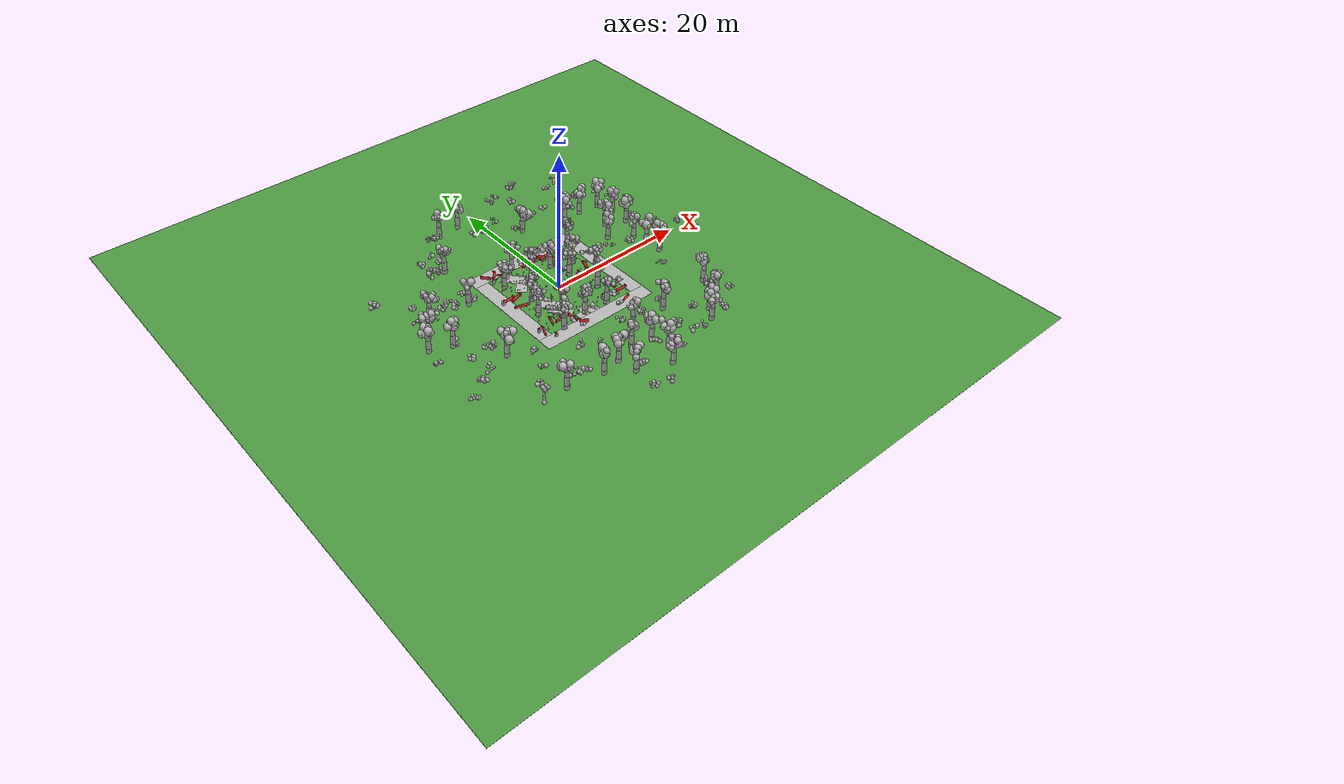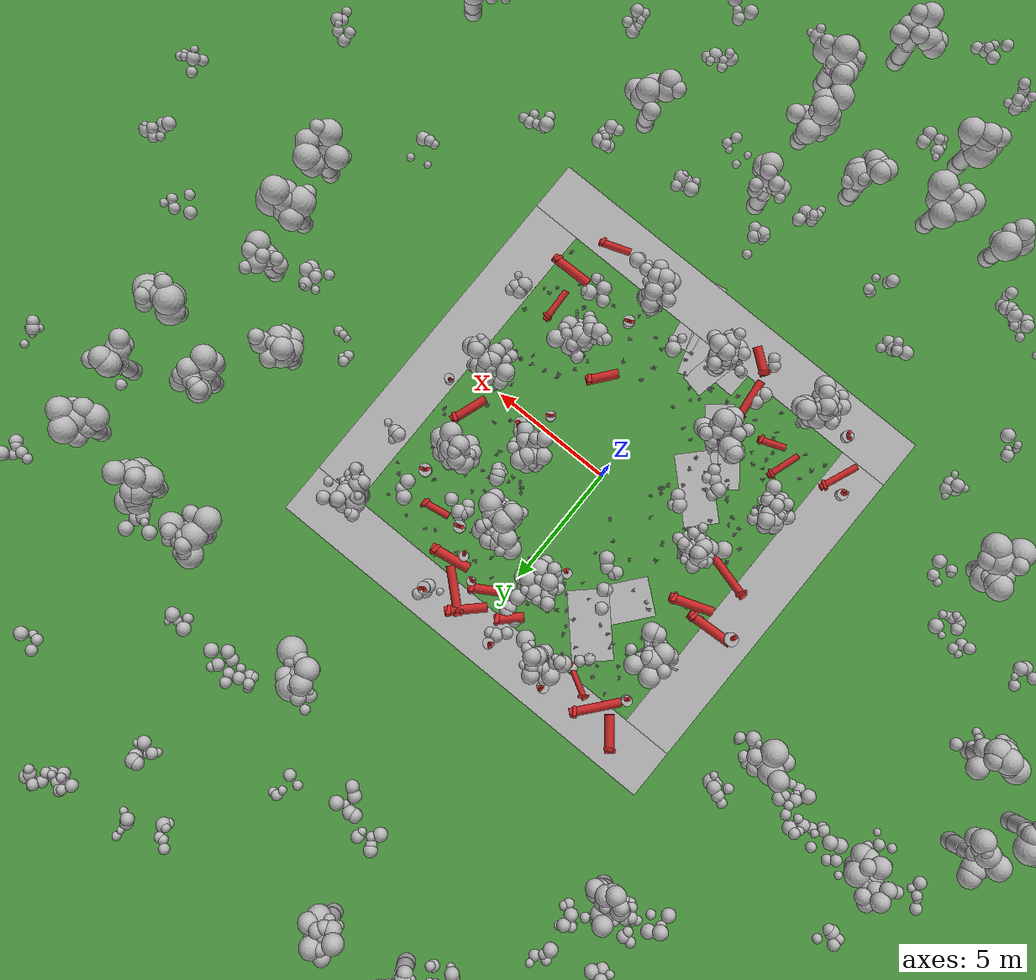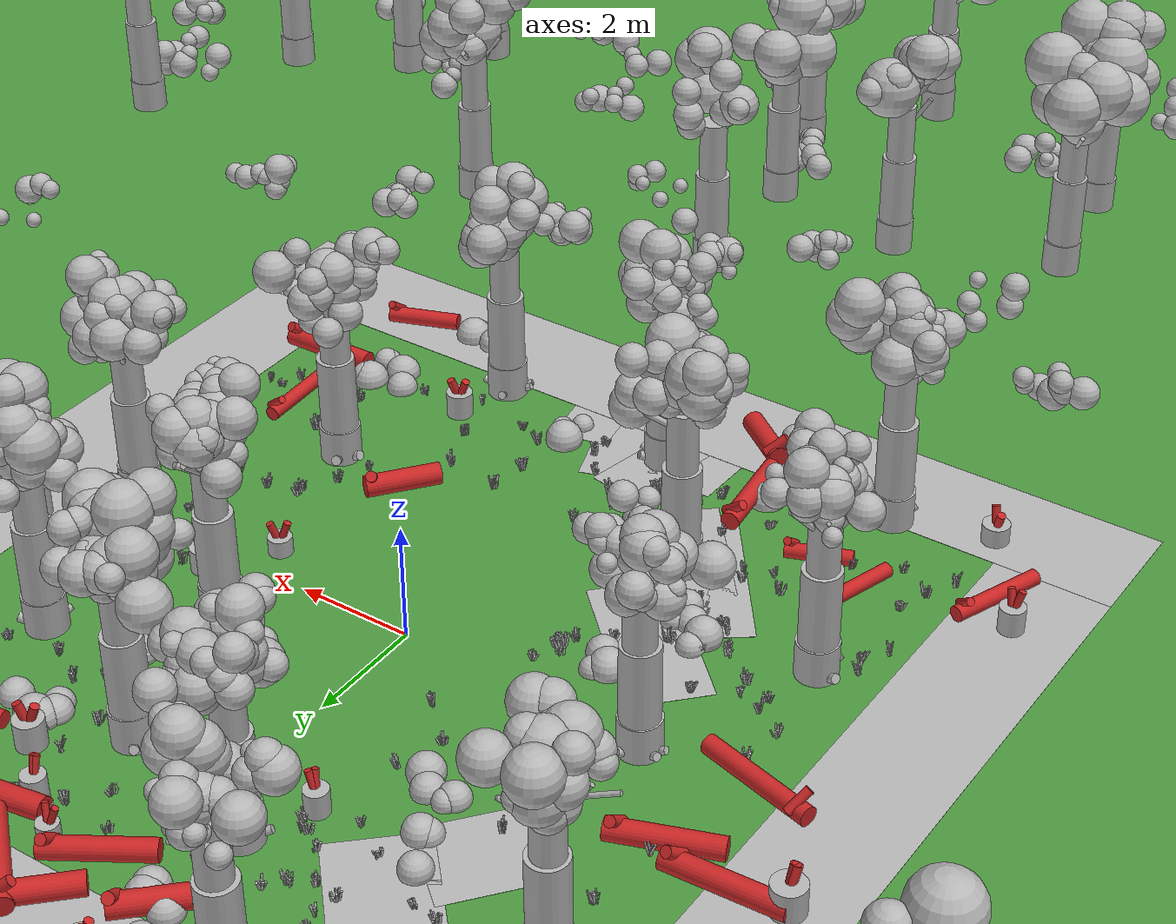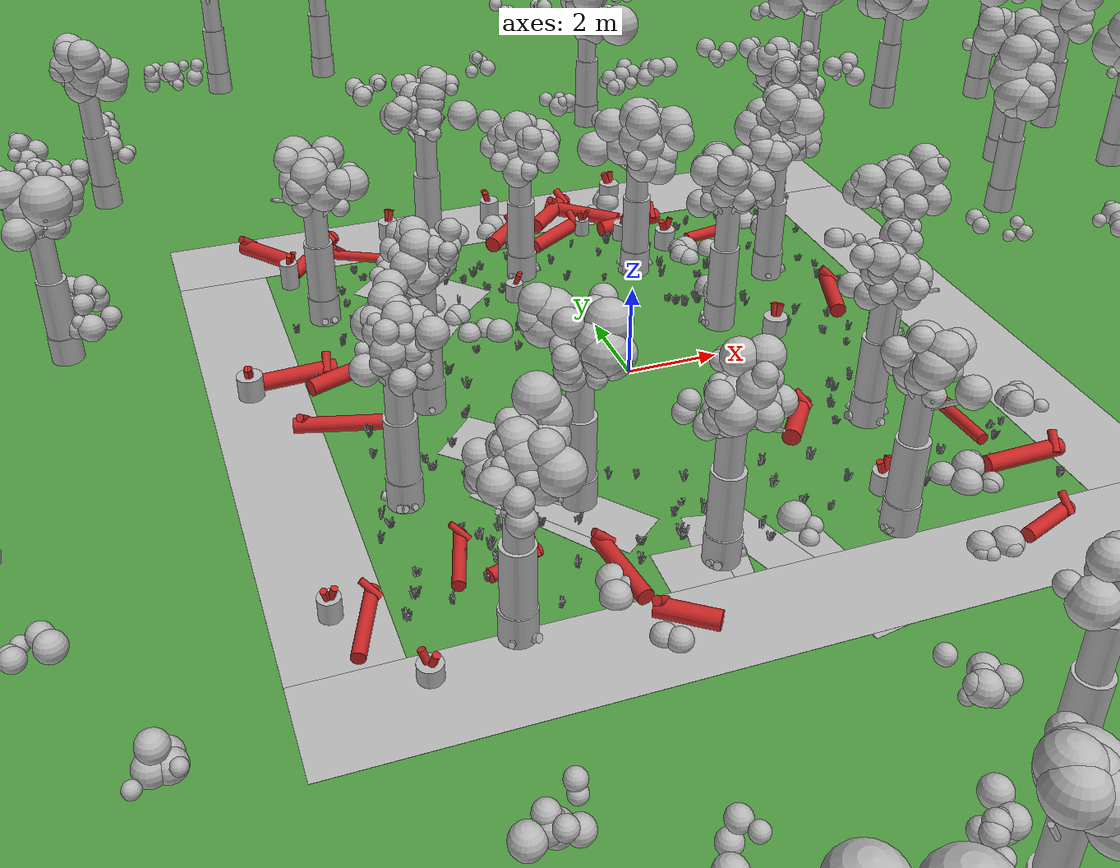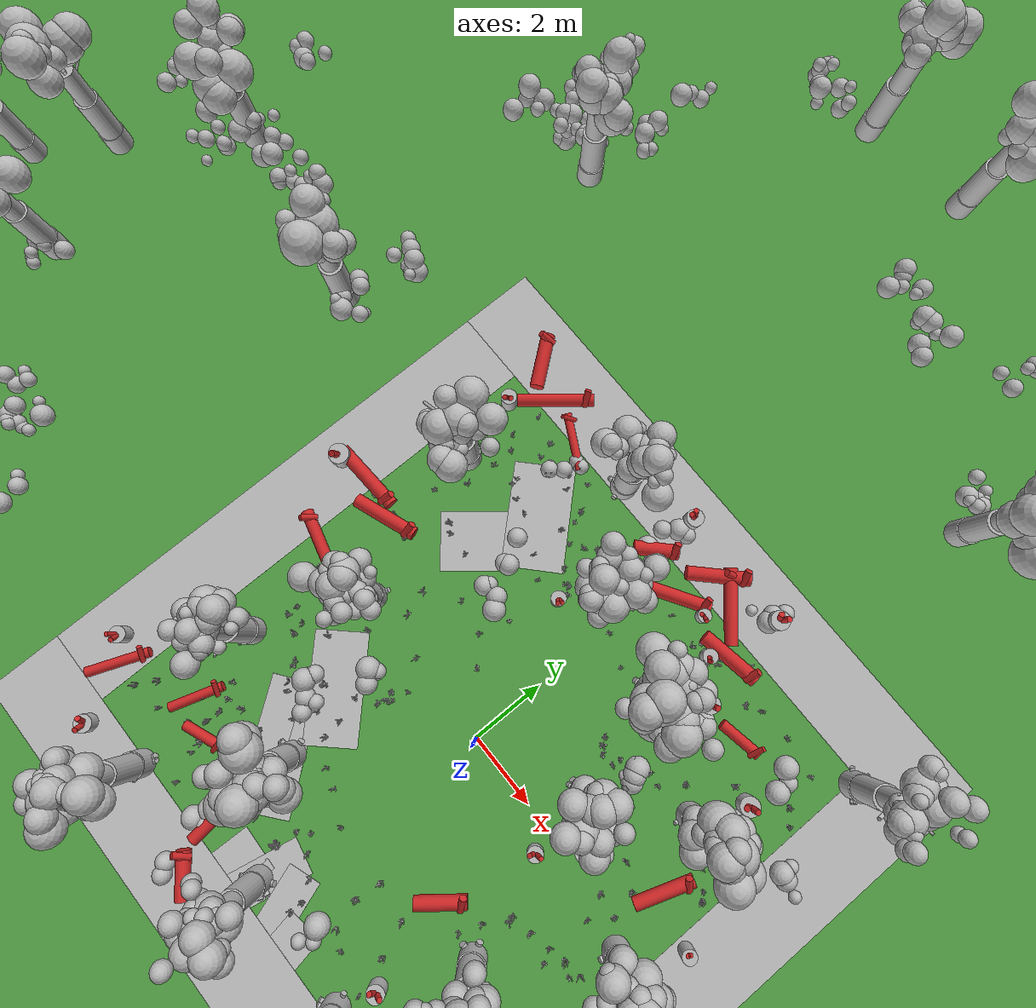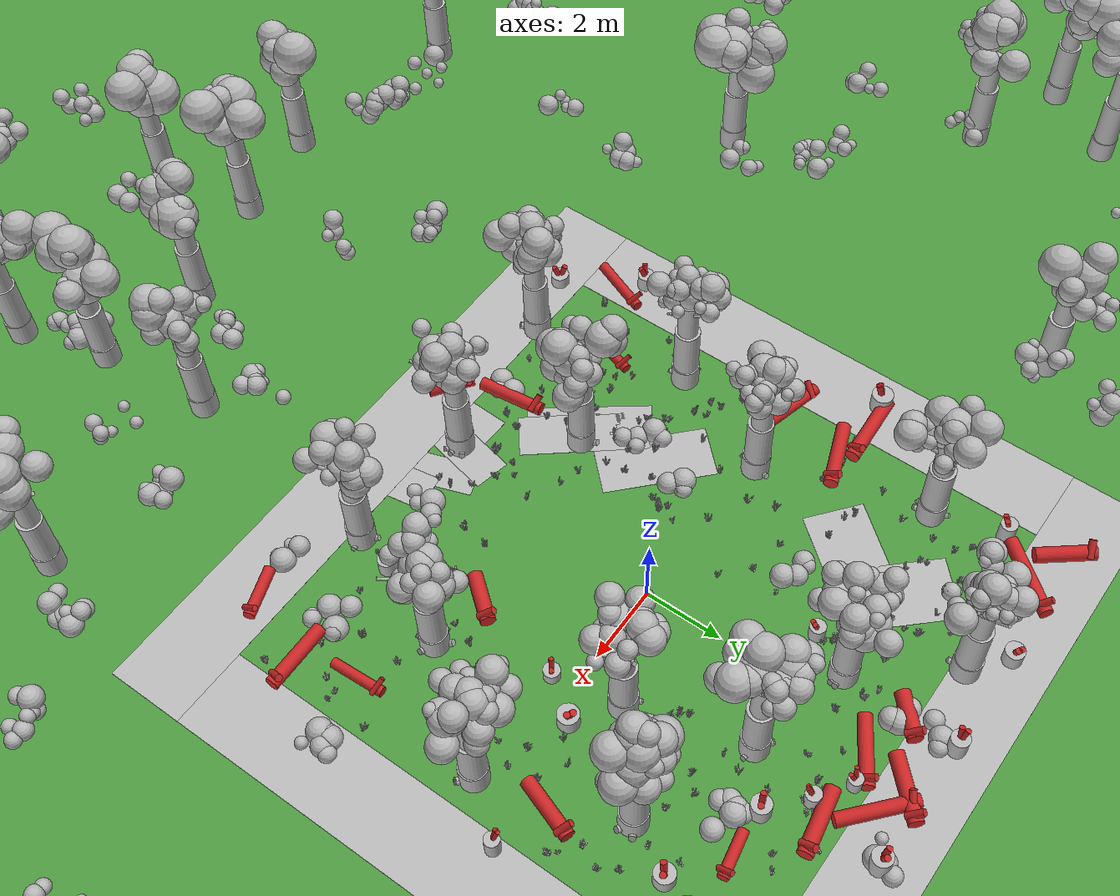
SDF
<?xml version="1.0"?>
<sdf version="1.6">
  <world name="default">

    <scene>
      <ambient>0.42 0.41 0.39 1</ambient>
      <background>0.66 0.60 0.53 1</background>
      <shadows>false</shadows>
      <fog>
        <color>0.62 0.55 0.48 1</color>
        <type>linear</type>
        <start>9</start>
        <end>58</end>
        <density>0.72</density>
      </fog>
    </scene>

    <physics type="ode">
      <max_step_size>0.001</max_step_size>
      <real_time_update_rate>1000</real_time_update_rate>
    </physics>

    <!-- Key: low, warm, and from the north-west. Sun through smoke. -->
    <light name="sun_key" type="directional">
      <cast_shadows>false</cast_shadows>
      <pose>0 0 12 0 0 0</pose>
      <diffuse>0.96 0.86 0.70 1</diffuse>
      <specular>0.18 0.16 0.13 1</specular>
      <direction>0.42 0.36 -0.83</direction>
      <attenuation><range>90</range><constant>0.9</constant>
        <linear>0.01</linear><quadratic>0.001</quadratic></attenuation>
    </light>

    <!-- Fill: cool, weak, from the opposite side, and never casts. This is
         the light that keeps the underside of a crown from going black. -->
    <light name="sky_fill" type="directional">
      <cast_shadows>false</cast_shadows>
      <pose>0 0 12 0 0 0</pose>
      <diffuse>0.34 0.37 0.44 1</diffuse>
      <specular>0.0 0.0 0.0 1</specular>
      <direction>-0.55 -0.42 -0.72</direction>
      <attenuation><range>90</range><constant>1.0</constant>
        <linear>0.0</linear><quadratic>0.0</quadratic></attenuation>
    </light>

  <model name="ground_cover">
    <static>true</static>
    <link name="grass">
      <pose>0 0 -0.01 0 0 0</pose>
      <collision name="grass_c"><geometry><box><size>90.0000 90.0000 0.0200</size></box></geometry></collision>
      <visual name="grass_v"><geometry><box><size>90.0000 90.0000 0.0200</size></box></geometry><material><script><uri>model://bushfire/materials/scripts</uri><uri>model://bushfire/materials/textures</uri><name>Bushfire/DryGrass</name></script></material></visual>
    </link>
  </model>
  <model name="firebreak_floor">
    <static>true</static>
    <link name="break_n">
      <pose>0 7.600 0.003 0 0 0</pose>
      <visual name="break_n_v"><geometry><box><size>17.2000 2.0000 0.0040</size></box></geometry><material><script><uri>model://bushfire/materials/scripts</uri><uri>model://bushfire/materials/textures</uri><name>Bushfire/MineralEarth</name></script></material></visual>
    </link>
    <link name="break_s">
      <pose>0 -7.600 0.003 0 0 0</pose>
      <visual name="break_s_v"><geometry><box><size>17.2000 2.0000 0.0040</size></box></geometry><material><script><uri>model://bushfire/materials/scripts</uri><uri>model://bushfire/materials/textures</uri><name>Bushfire/MineralEarth</name></script></material></visual>
    </link>
    <link name="break_e">
      <pose>7.600 0 0.003 0 0 0</pose>
      <visual name="break_e_v"><geometry><box><size>2.0000 13.2000 0.0040</size></box></geometry><material><script><uri>model://bushfire/materials/scripts</uri><uri>model://bushfire/materials/textures</uri><name>Bushfire/MineralEarth</name></script></material></visual>
    </link>
    <link name="break_w">
      <pose>-7.600 0 0.003 0 0 0</pose>
      <visual name="break_w_v"><geometry><box><size>2.0000 13.2000 0.0040</size></box></geometry><material><script><uri>model://bushfire/materials/scripts</uri><uri>model://bushfire/materials/textures</uri><name>Bushfire/MineralEarth</name></script></material></visual>
    </link>
  </model>
  <model name="burn_scars">
    <static>true</static>
    <link name="burn0">
      <pose>-3.1691 -3.9156 0.002 0 0 2.213</pose>
      <visual name="burn0_v"><geometry><box><size>3.0815 0.8501 0.0030</size></box></geometry><material><script><uri>model://bushfire/materials/scripts</uri><uri>model://bushfire/materials/textures</uri><name>Bushfire/BurntGround</name></script></material></visual>
    </link>
    <link name="burn1">
      <pose>-2.7890 -3.8300 0.002 0 0 2.252</pose>
      <visual name="burn1_v"><geometry><box><size>3.1953 1.1160 0.0030</size></box></geometry><material><script><uri>model://bushfire/materials/scripts</uri><uri>model://bushfire/materials/textures</uri><name>Bushfire/BurntGround</name></script></material></visual>
    </link>
    <link name="burn2">
      <pose>-3.1389 -1.9463 0.002 0 0 2.382</pose>
      <visual name="burn2_v"><geometry><box><size>2.8332 1.3672 0.0030</size></box></geometry><material><script><uri>model://bushfire/materials/scripts</uri><uri>model://bushfire/materials/textures</uri><name>Bushfire/BurntGround</name></script></material></visual>
    </link>
    <link name="burn3">
      <pose>1.0347 -7.2172 0.002 0 0 1.740</pose>
      <visual name="burn3_v"><geometry><box><size>2.8837 0.9635 0.0030</size></box></geometry><material><script><uri>model://bushfire/materials/scripts</uri><uri>model://bushfire/materials/textures</uri><name>Bushfire/BurntGround</name></script></material></visual>
    </link>
    <link name="burn4">
      <pose>-0.7810 -6.3112 0.002 0 0 1.372</pose>
      <visual name="burn4_v"><geometry><box><size>2.8882 0.9389 0.0030</size></box></geometry><material><script><uri>model://bushfire/materials/scripts</uri><uri>model://bushfire/materials/textures</uri><name>Bushfire/BurntGround</name></script></material></visual>
    </link>
    <link name="burn5">
      <pose>-1.3531 -6.9603 0.002 0 0 1.537</pose>
      <visual name="burn5_v"><geometry><box><size>2.7112 1.2011 0.0030</size></box></geometry><material><script><uri>model://bushfire/materials/scripts</uri><uri>model://bushfire/materials/textures</uri><name>Bushfire/BurntGround</name></script></material></visual>
    </link>
    <link name="burn6">
      <pose>0.3193 -6.4896 0.002 0 0 1.904</pose>
      <visual name="burn6_v"><geometry><box><size>2.8881 0.8707 0.0030</size></box></geometry><material><script><uri>model://bushfire/materials/scripts</uri><uri>model://bushfire/materials/textures</uri><name>Bushfire/BurntGround</name></script></material></visual>
    </link>
    <link name="burn7">
      <pose>-3.2791 4.6903 0.002 0 0 2.324</pose>
      <visual name="burn7_v"><geometry><box><size>2.7510 1.5981 0.0030</size></box></geometry><material><script><uri>model://bushfire/materials/scripts</uri><uri>model://bushfire/materials/textures</uri><name>Bushfire/BurntGround</name></script></material></visual>
    </link>
    <link name="burn8">
      <pose>-3.7991 3.0701 0.002 0 0 2.458</pose>
      <visual name="burn8_v"><geometry><box><size>1.5356 1.8801 0.0030</size></box></geometry><material><script><uri>model://bushfire/materials/scripts</uri><uri>model://bushfire/materials/textures</uri><name>Bushfire/BurntGround</name></script></material></visual>
    </link>
  </model>
  <model name="tree_0">
    <static>true</static>
    <pose>5.8540 -0.4740 0 0 0 0</pose>
    <link name="trunk">
      <pose>0 0 1.5000 0 0 0</pose>
      <collision name="trunk_c"><geometry><cylinder><radius>0.3500</radius><length>3.0000</length></cylinder></geometry></collision>
    </link>
    <link name="trunk_v0">
      <pose>-0.0012 0.0004 0.3100 0 0 0</pose>
      <visual name="trunk_v0_v"><geometry><cylinder><radius>0.3448</radius><length>0.6448</length></cylinder></geometry><material><script><uri>model://bushfire/materials/scripts</uri><uri>model://bushfire/materials/textures</uri><name>Bushfire/CharBark</name></script></material></visual>
    </link>
    <link name="trunk_v1">
      <pose>-0.0084 0.0025 1.2700 0 0 0</pose>
      <visual name="trunk_v1_v"><geometry><cylinder><radius>0.3150</radius><length>1.3520</length></cylinder></geometry><material><script><uri>model://bushfire/materials/scripts</uri><uri>model://bushfire/materials/textures</uri><name>Bushfire/BarkStringy</name></script></material></visual>
    </link>
    <link name="trunk_v2">
      <pose>-0.0212 0.0064 2.4600 0 0 0</pose>
      <visual name="trunk_v2_v"><geometry><cylinder><radius>0.2520</radius><length>1.1232</length></cylinder></geometry><material><script><uri>model://bushfire/materials/scripts</uri><uri>model://bushfire/materials/textures</uri><name>Bushfire/BarkStringy</name></script></material></visual>
    </link>
    <link name="root0">
      <pose>0.1943 -0.1408 0.09 0 1.150 5.656</pose>
      <visual name="root0_v"><geometry><cylinder><radius>0.0771</radius><length>0.4200</length></cylinder></geometry><material><script><uri>model://bushfire/materials/scripts</uri><uri>model://bushfire/materials/textures</uri><name>Bushfire/CharBark</name></script></material></visual>
    </link>
    <link name="root1">
      <pose>-0.0689 -0.2299 0.09 0 1.150 4.421</pose>
      <visual name="root1_v"><geometry><cylinder><radius>0.0788</radius><length>0.4200</length></cylinder></geometry><material><script><uri>model://bushfire/materials/scripts</uri><uri>model://bushfire/materials/textures</uri><name>Bushfire/CharBark</name></script></material></visual>
    </link>
    <link name="root2">
      <pose>0.2066 -0.1222 0.09 0 1.150 5.749</pose>
      <visual name="root2_v"><geometry><cylinder><radius>0.0656</radius><length>0.4200</length></cylinder></geometry><material><script><uri>model://bushfire/materials/scripts</uri><uri>model://bushfire/materials/textures</uri><name>Bushfire/CharBark</name></script></material></visual>
    </link>
    <link name="branch0">
      <pose>-0.3504 0.1751 3.0342 0 1.0057 2.6781</pose>
      <visual name="branch0_v"><geometry><cylinder><radius>0.0425</radius><length>0.9277</length></cylinder></geometry><material><script><uri>model://bushfire/materials/scripts</uri><uri>model://bushfire/materials/textures</uri><name>Bushfire/BarkStringy</name></script></material></visual>
    </link>
    <link name="branch1">
      <pose>-0.2556 -0.1531 2.8833 0 1.0146 3.6811</pose>
      <visual name="branch1_v"><geometry><cylinder><radius>0.0318</radius><length>0.7017</length></cylinder></geometry><material><script><uri>model://bushfire/materials/scripts</uri><uri>model://bushfire/materials/textures</uri><name>Bushfire/BarkStringy</name></script></material></visual>
    </link>
    <link name="branch2">
      <pose>0.0164 -0.2365 2.6765 0 0.8127 4.7815</pose>
      <visual name="branch2_v"><geometry><cylinder><radius>0.0383</radius><length>0.6529</length></cylinder></geometry><material><script><uri>model://bushfire/materials/scripts</uri><uri>model://bushfire/materials/textures</uri><name>Bushfire/BarkStringy</name></script></material></visual>
    </link>
    <link name="branch3">
      <pose>0.2578 0.0353 2.9705 0 0.7895 6.4193</pose>
      <visual name="branch3_v"><geometry><cylinder><radius>0.0435</radius><length>0.7331</length></cylinder></geometry><material><script><uri>model://bushfire/materials/scripts</uri><uri>model://bushfire/materials/textures</uri><name>Bushfire/BarkStringy</name></script></material></visual>
    </link>
    <link name="branch4">
      <pose>0.1753 0.2175 2.8201 0 0.9769 7.1756</pose>
      <visual name="branch4_v"><geometry><cylinder><radius>0.0306</radius><length>0.6741</length></cylinder></geometry><material><script><uri>model://bushfire/materials/scripts</uri><uri>model://bushfire/materials/textures</uri><name>Bushfire/BarkStringy</name></script></material></visual>
    </link>
    <link name="branch5">
      <pose>-0.1718 0.2142 2.7830 0 0.6907 8.5299</pose>
      <visual name="branch5_v"><geometry><cylinder><radius>0.0422</radius><length>0.8620</length></cylinder></geometry><material><script><uri>model://bushfire/materials/scripts</uri><uri>model://bushfire/materials/textures</uri><name>Bushfire/BarkStringy</name></script></material></visual>
    </link>
    <link name="foliage0">
      <pose>-0.8416 0.0949 3.8422 0 0 0</pose>
      <visual name="foliage0_v"><geometry><sphere><radius>0.3443</radius></sphere></geometry><material><script><uri>model://bushfire/materials/scripts</uri><uri>model://bushfire/materials/textures</uri><name>Bushfire/Foliage1</name></script></material></visual>
    </link>
    <link name="foliage1">
      <pose>-0.5636 -0.2970 3.6007 0 0 0</pose>
      <visual name="foliage1_v"><geometry><sphere><radius>0.2027</radius></sphere></geometry><material><script><uri>model://bushfire/materials/scripts</uri><uri>model://bushfire/materials/textures</uri><name>Bushfire/Foliage0</name></script></material></visual>
    </link>
    <link name="foliage2">
      <pose>-0.0430 -0.4567 2.9053 0 0 0</pose>
      <visual name="foliage2_v"><geometry><sphere><radius>0.2169</radius></sphere></geometry><material><script><uri>model://bushfire/materials/scripts</uri><uri>model://bushfire/materials/textures</uri><name>Bushfire/Foliage1</name></script></material></visual>
    </link>
    <link name="foliage3">
      <pose>0.5952 -0.2678 4.1278 0 0 0</pose>
      <visual name="foliage3_v"><geometry><sphere><radius>0.1624</radius></sphere></geometry><material><script><uri>model://bushfire/materials/scripts</uri><uri>model://bushfire/materials/textures</uri><name>Bushfire/Foliage0</name></script></material></visual>
    </link>
    <link name="foliage4">
      <pose>0.1309 0.4761 3.2742 0 0 0</pose>
      <visual name="foliage4_v"><geometry><sphere><radius>0.3281</radius></sphere></geometry><material><script><uri>model://bushfire/materials/scripts</uri><uri>model://bushfire/materials/textures</uri><name>Bushfire/Foliage2</name></script></material></visual>
    </link>
    <link name="foliage5">
      <pose>-0.3848 0.5540 3.4548 0 0 0</pose>
      <visual name="foliage5_v"><geometry><sphere><radius>0.3608</radius></sphere></geometry><material><script><uri>model://bushfire/materials/scripts</uri><uri>model://bushfire/materials/textures</uri><name>Bushfire/Foliage0</name></script></material></visual>
    </link>
    <link name="foliage6">
      <pose>-0.8804 0.4378 3.4405 0 0 0</pose>
      <visual name="foliage6_v"><geometry><sphere><radius>0.2951</radius></sphere></geometry><material><script><uri>model://bushfire/materials/scripts</uri><uri>model://bushfire/materials/textures</uri><name>Bushfire/Foliage1</name></script></material></visual>
    </link>
    <link name="foliage7">
      <pose>-0.1069 -0.5097 3.4106 0 0 0</pose>
      <visual name="foliage7_v"><geometry><sphere><radius>0.1779</radius></sphere></geometry><material><script><uri>model://bushfire/materials/scripts</uri><uri>model://bushfire/materials/textures</uri><name>Bushfire/Foliage0</name></script></material></visual>
    </link>
    <link name="foliage8">
      <pose>-0.1264 -0.2784 3.8040 0 0 0</pose>
      <visual name="foliage8_v"><geometry><sphere><radius>0.3207</radius></sphere></geometry><material><script><uri>model://bushfire/materials/scripts</uri><uri>model://bushfire/materials/textures</uri><name>Bushfire/Foliage0</name></script></material></visual>
    </link>
    <link name="foliage9">
      <pose>0.4567 0.1559 4.1046 0 0 0</pose>
      <visual name="foliage9_v"><geometry><sphere><radius>0.3230</radius></sphere></geometry><material><script><uri>model://bushfire/materials/scripts</uri><uri>model://bushfire/materials/textures</uri><name>Bushfire/Foliage2</name></script></material></visual>
    </link>
    <link name="foliage10">
      <pose>0.3962 0.0524 3.6691 0 0 0</pose>
      <visual name="foliage10_v"><geometry><sphere><radius>0.3029</radius></sphere></geometry><material><script><uri>model://bushfire/materials/scripts</uri><uri>model://bushfire/materials/textures</uri><name>Bushfire/Foliage2</name></script></material></visual>
    </link>
    <link name="foliage11">
      <pose>-0.5422 0.2493 3.7143 0 0 0</pose>
      <visual name="foliage11_v"><geometry><sphere><radius>0.2233</radius></sphere></geometry><material><script><uri>model://bushfire/materials/scripts</uri><uri>model://bushfire/materials/textures</uri><name>Bushfire/Foliage2</name></script></material></visual>
    </link>
    <link name="foliage12">
      <pose>-0.1950 0.0346 3.8844 0 0 0</pose>
      <visual name="foliage12_v"><geometry><sphere><radius>0.3320</radius></sphere></geometry><material><script><uri>model://bushfire/materials/scripts</uri><uri>model://bushfire/materials/textures</uri><name>Bushfire/Foliage0</name></script></material></visual>
    </link>
    <link name="foliage13">
      <pose>0.0861 0.0266 3.4092 0 0 0</pose>
      <visual name="foliage13_v"><geometry><sphere><radius>0.1766</radius></sphere></geometry><material><script><uri>model://bushfire/materials/scripts</uri><uri>model://bushfire/materials/textures</uri><name>Bushfire/Foliage2</name></script></material></visual>
    </link>
    <link name="foliage14">
      <pose>-0.2997 -0.4820 3.2937 0 0 0</pose>
      <visual name="foliage14_v"><geometry><sphere><radius>0.2896</radius></sphere></geometry><material><script><uri>model://bushfire/materials/scripts</uri><uri>model://bushfire/materials/textures</uri><name>Bushfire/Foliage1</name></script></material></visual>
    </link>
    <link name="foliage15">
      <pose>0.4788 -0.1492 3.9561 0 0 0</pose>
      <visual name="foliage15_v"><geometry><sphere><radius>0.3046</radius></sphere></geometry><material><script><uri>model://bushfire/materials/scripts</uri><uri>model://bushfire/materials/textures</uri><name>Bushfire/Foliage2</name></script></material></visual>
    </link>
    <link name="foliage16">
      <pose>0.1376 0.3131 2.9619 0 0 0</pose>
      <visual name="foliage16_v"><geometry><sphere><radius>0.2329</radius></sphere></geometry><material><script><uri>model://bushfire/materials/scripts</uri><uri>model://bushfire/materials/textures</uri><name>Bushfire/Foliage1</name></script></material></visual>
    </link>
    <link name="foliage17">
      <pose>-0.0742 0.2170 3.8823 0 0 0</pose>
      <visual name="foliage17_v"><geometry><sphere><radius>0.3452</radius></sphere></geometry><material><script><uri>model://bushfire/materials/scripts</uri><uri>model://bushfire/materials/textures</uri><name>Bushfire/Foliage1</name></script></material></visual>
    </link>
    <link name="foliage18">
      <pose>-0.8502 0.1602 3.4344 0 0 0</pose>
      <visual name="foliage18_v"><geometry><sphere><radius>0.2396</radius></sphere></geometry><material><script><uri>model://bushfire/materials/scripts</uri><uri>model://bushfire/materials/textures</uri><name>Bushfire/Foliage0</name></script></material></visual>
    </link>
    <link name="foliage19">
      <pose>-0.0155 -0.2072 3.4936 0 0 0</pose>
      <visual name="foliage19_v"><geometry><sphere><radius>0.1561</radius></sphere></geometry><material><script><uri>model://bushfire/materials/scripts</uri><uri>model://bushfire/materials/textures</uri><name>Bushfire/Foliage2</name></script></material></visual>
    </link>
    <link name="foliage20">
      <pose>-0.2115 -0.7148 3.5279 0 0 0</pose>
      <visual name="foliage20_v"><geometry><sphere><radius>0.2602</radius></sphere></geometry><material><script><uri>model://bushfire/materials/scripts</uri><uri>model://bushfire/materials/textures</uri><name>Bushfire/Foliage2</name></script></material></visual>
    </link>
    <link name="foliage21">
      <pose>0.7785 0.0601 3.1798 0 0 0</pose>
      <visual name="foliage21_v"><geometry><sphere><radius>0.3537</radius></sphere></geometry><material><script><uri>model://bushfire/materials/scripts</uri><uri>model://bushfire/materials/textures</uri><name>Bushfire/Foliage0</name></script></material></visual>
    </link>
    <link name="foliage22">
      <pose>0.2883 0.5332 3.0430 0 0 0</pose>
      <visual name="foliage22_v"><geometry><sphere><radius>0.2699</radius></sphere></geometry><material><script><uri>model://bushfire/materials/scripts</uri><uri>model://bushfire/materials/textures</uri><name>Bushfire/Foliage2</name></script></material></visual>
    </link>
    <link name="foliage23">
      <pose>-0.3213 0.3234 3.8712 0 0 0</pose>
      <visual name="foliage23_v"><geometry><sphere><radius>0.2309</radius></sphere></geometry><material><script><uri>model://bushfire/materials/scripts</uri><uri>model://bushfire/materials/textures</uri><name>Bushfire/Foliage2</name></script></material></visual>
    </link>
    <link name="foliage24">
      <pose>-0.1193 0.4974 3.7500 0 0 0</pose>
      <visual name="foliage24_v"><geometry><sphere><radius>0.2618</radius></sphere></geometry><material><script><uri>model://bushfire/materials/scripts</uri><uri>model://bushfire/materials/textures</uri><name>Bushfire/Foliage0</name></script></material></visual>
    </link>
    <link name="foliage25">
      <pose>-0.6120 -0.5460 3.4991 0 0 0</pose>
      <visual name="foliage25_v"><geometry><sphere><radius>0.2300</radius></sphere></geometry><material><script><uri>model://bushfire/materials/scripts</uri><uri>model://bushfire/materials/textures</uri><name>Bushfire/Foliage0</name></script></material></visual>
    </link>
    <link name="foliage26">
      <pose>-0.0423 -0.1612 3.2814 0 0 0</pose>
      <visual name="foliage26_v"><geometry><sphere><radius>0.2702</radius></sphere></geometry><material><script><uri>model://bushfire/materials/scripts</uri><uri>model://bushfire/materials/textures</uri><name>Bushfire/Foliage2</name></script></material></visual>
    </link>
    <link name="foliage27">
      <pose>0.5380 0.0056 3.9370 0 0 0</pose>
      <visual name="foliage27_v"><geometry><sphere><radius>0.3475</radius></sphere></geometry><material><script><uri>model://bushfire/materials/scripts</uri><uri>model://bushfire/materials/textures</uri><name>Bushfire/Foliage1</name></script></material></visual>
    </link>
    <link name="foliage28">
      <pose>0.1790 -0.0089 3.7334 0 0 0</pose>
      <visual name="foliage28_v"><geometry><sphere><radius>0.2423</radius></sphere></geometry><material><script><uri>model://bushfire/materials/scripts</uri><uri>model://bushfire/materials/textures</uri><name>Bushfire/Foliage1</name></script></material></visual>
    </link>
    <link name="foliage29">
      <pose>-0.5346 0.2800 3.2510 0 0 0</pose>
      <visual name="foliage29_v"><geometry><sphere><radius>0.1549</radius></sphere></geometry><material><script><uri>model://bushfire/materials/scripts</uri><uri>model://bushfire/materials/textures</uri><name>Bushfire/Foliage2</name></script></material></visual>
    </link>
    <link name="foliage30">
      <pose>-1.0244 0.1419 3.8708 0 0 0</pose>
      <visual name="foliage30_v"><geometry><sphere><radius>0.1977</radius></sphere></geometry><material><script><uri>model://bushfire/materials/scripts</uri><uri>model://bushfire/materials/textures</uri><name>Bushfire/Foliage1</name></script></material></visual>
    </link>
  </model>
  <model name="tree_1">
    <static>true</static>
    <pose>-4.3520 0.1640 0 0 0 0</pose>
    <link name="trunk">
      <pose>0 0 1.5000 0 0 0</pose>
      <collision name="trunk_c"><geometry><cylinder><radius>0.3500</radius><length>3.0000</length></cylinder></geometry></collision>
    </link>
    <link name="trunk_v0">
      <pose>0.0000 0.0014 0.3100 0 0 0</pose>
      <visual name="trunk_v0_v"><geometry><cylinder><radius>0.3448</radius><length>0.6448</length></cylinder></geometry><material><script><uri>model://bushfire/materials/scripts</uri><uri>model://bushfire/materials/textures</uri><name>Bushfire/CharBark</name></script></material></visual>
    </link>
    <link name="trunk_v1">
      <pose>0.0003 0.0097 1.2700 0 0 0</pose>
      <visual name="trunk_v1_v"><geometry><cylinder><radius>0.3150</radius><length>1.3520</length></cylinder></geometry><material><script><uri>model://bushfire/materials/scripts</uri><uri>model://bushfire/materials/textures</uri><name>Bushfire/BarkSmooth</name></script></material></visual>
    </link>
    <link name="trunk_v2">
      <pose>0.0009 0.0246 2.4600 0 0 0</pose>
      <visual name="trunk_v2_v"><geometry><cylinder><radius>0.2520</radius><length>1.1232</length></cylinder></geometry><material><script><uri>model://bushfire/materials/scripts</uri><uri>model://bushfire/materials/textures</uri><name>Bushfire/BarkSmooth</name></script></material></visual>
    </link>
    <link name="root0">
      <pose>-0.0287 -0.2383 0.09 0 1.150 4.592</pose>
      <visual name="root0_v"><geometry><cylinder><radius>0.0587</radius><length>0.4200</length></cylinder></geometry><material><script><uri>model://bushfire/materials/scripts</uri><uri>model://bushfire/materials/textures</uri><name>Bushfire/CharBark</name></script></material></visual>
    </link>
    <link name="root1">
      <pose>-0.2395 -0.0158 0.09 0 1.150 3.207</pose>
      <visual name="root1_v"><geometry><cylinder><radius>0.0625</radius><length>0.4200</length></cylinder></geometry><material><script><uri>model://bushfire/materials/scripts</uri><uri>model://bushfire/materials/textures</uri><name>Bushfire/CharBark</name></script></material></visual>
    </link>
    <link name="root2">
      <pose>0.0774 0.2272 0.09 0 1.150 1.242</pose>
      <visual name="root2_v"><geometry><cylinder><radius>0.0709</radius><length>0.4200</length></cylinder></geometry><material><script><uri>model://bushfire/materials/scripts</uri><uri>model://bushfire/materials/textures</uri><name>Bushfire/CharBark</name></script></material></visual>
    </link>
    <link name="root3">
      <pose>-0.2213 0.0929 0.09 0 1.150 2.744</pose>
      <visual name="root3_v"><geometry><cylinder><radius>0.0663</radius><length>0.4200</length></cylinder></geometry><material><script><uri>model://bushfire/materials/scripts</uri><uri>model://bushfire/materials/textures</uri><name>Bushfire/CharBark</name></script></material></visual>
    </link>
    <link name="branch0">
      <pose>0.1611 -0.2607 2.9686 0 0.7538 5.2658</pose>
      <visual name="branch0_v"><geometry><cylinder><radius>0.0355</radius><length>0.8955</length></cylinder></geometry><material><script><uri>model://bushfire/materials/scripts</uri><uri>model://bushfire/materials/textures</uri><name>Bushfire/BarkSmooth</name></script></material></visual>
    </link>
    <link name="branch1">
      <pose>0.3194 -0.0129 2.8717 0 0.9526 6.2427</pose>
      <visual name="branch1_v"><geometry><cylinder><radius>0.0529</radius><length>0.7847</length></cylinder></geometry><material><script><uri>model://bushfire/materials/scripts</uri><uri>model://bushfire/materials/textures</uri><name>Bushfire/BarkSmooth</name></script></material></visual>
    </link>
    <link name="branch2">
      <pose>0.0136 0.2046 2.7906 0 0.7192 7.7876</pose>
      <visual name="branch2_v"><geometry><cylinder><radius>0.0523</radius><length>0.6225</length></cylinder></geometry><material><script><uri>model://bushfire/materials/scripts</uri><uri>model://bushfire/materials/textures</uri><name>Bushfire/BarkSmooth</name></script></material></visual>
    </link>
    <link name="branch3">
      <pose>-0.2010 0.1639 2.9271 0 0.9724 8.7409</pose>
      <visual name="branch3_v"><geometry><cylinder><radius>0.0522</radius><length>0.6278</length></cylinder></geometry><material><script><uri>model://bushfire/materials/scripts</uri><uri>model://bushfire/materials/textures</uri><name>Bushfire/BarkSmooth</name></script></material></visual>
    </link>
    <link name="branch4">
      <pose>-0.2190 -0.1281 2.6844 0 0.8034 9.9541</pose>
      <visual name="branch4_v"><geometry><cylinder><radius>0.0535</radius><length>0.7052</length></cylinder></geometry><material><script><uri>model://bushfire/materials/scripts</uri><uri>model://bushfire/materials/textures</uri><name>Bushfire/BarkSmooth</name></script></material></visual>
    </link>
    <link name="foliage0">
      <pose>0.3440 -0.6809 3.8784 0 0 0</pose>
      <visual name="foliage0_v"><geometry><sphere><radius>0.1795</radius></sphere></geometry><material><script><uri>model://bushfire/materials/scripts</uri><uri>model://bushfire/materials/textures</uri><name>Bushfire/Foliage1</name></script></material></visual>
    </link>
    <link name="foliage1">
      <pose>0.2793 0.1644 3.6859 0 0 0</pose>
      <visual name="foliage1_v"><geometry><sphere><radius>0.2405</radius></sphere></geometry><material><script><uri>model://bushfire/materials/scripts</uri><uri>model://bushfire/materials/textures</uri><name>Bushfire/Foliage0</name></script></material></visual>
    </link>
    <link name="foliage2">
      <pose>0.0155 0.0934 3.5349 0 0 0</pose>
      <visual name="foliage2_v"><geometry><sphere><radius>0.2929</radius></sphere></geometry><material><script><uri>model://bushfire/materials/scripts</uri><uri>model://bushfire/materials/textures</uri><name>Bushfire/Foliage2</name></script></material></visual>
    </link>
    <link name="foliage3">
      <pose>-0.5102 -0.0180 3.1314 0 0 0</pose>
      <visual name="foliage3_v"><geometry><sphere><radius>0.1738</radius></sphere></geometry><material><script><uri>model://bushfire/materials/scripts</uri><uri>model://bushfire/materials/textures</uri><name>Bushfire/Foliage1</name></script></material></visual>
    </link>
    <link name="foliage4">
      <pose>-0.7681 -0.5862 3.2790 0 0 0</pose>
      <visual name="foliage4_v"><geometry><sphere><radius>0.3312</radius></sphere></geometry><material><script><uri>model://bushfire/materials/scripts</uri><uri>model://bushfire/materials/textures</uri><name>Bushfire/Foliage0</name></script></material></visual>
    </link>
    <link name="foliage5">
      <pose>0.1747 -0.3087 3.7921 0 0 0</pose>
      <visual name="foliage5_v"><geometry><sphere><radius>0.2258</radius></sphere></geometry><material><script><uri>model://bushfire/materials/scripts</uri><uri>model://bushfire/materials/textures</uri><name>Bushfire/Foliage0</name></script></material></visual>
    </link>
    <link name="foliage6">
      <pose>0.2466 -0.2264 3.3403 0 0 0</pose>
      <visual name="foliage6_v"><geometry><sphere><radius>0.2214</radius></sphere></geometry><material><script><uri>model://bushfire/materials/scripts</uri><uri>model://bushfire/materials/textures</uri><name>Bushfire/Foliage1</name></script></material></visual>
    </link>
    <link name="foliage7">
      <pose>-0.1888 0.0501 2.9010 0 0 0</pose>
      <visual name="foliage7_v"><geometry><sphere><radius>0.2425</radius></sphere></geometry><material><script><uri>model://bushfire/materials/scripts</uri><uri>model://bushfire/materials/textures</uri><name>Bushfire/Foliage0</name></script></material></visual>
    </link>
    <link name="foliage8">
      <pose>-0.2701 0.5789 3.3927 0 0 0</pose>
      <visual name="foliage8_v"><geometry><sphere><radius>0.2661</radius></sphere></geometry><material><script><uri>model://bushfire/materials/scripts</uri><uri>model://bushfire/materials/textures</uri><name>Bushfire/Foliage2</name></script></material></visual>
    </link>
    <link name="foliage9">
      <pose>-0.1596 -0.2352 3.0855 0 0 0</pose>
      <visual name="foliage9_v"><geometry><sphere><radius>0.2930</radius></sphere></geometry><material><script><uri>model://bushfire/materials/scripts</uri><uri>model://bushfire/materials/textures</uri><name>Bushfire/Foliage0</name></script></material></visual>
    </link>
    <link name="foliage10">
      <pose>0.5012 -0.2913 4.1055 0 0 0</pose>
      <visual name="foliage10_v"><geometry><sphere><radius>0.2209</radius></sphere></geometry><material><script><uri>model://bushfire/materials/scripts</uri><uri>model://bushfire/materials/textures</uri><name>Bushfire/Foliage2</name></script></material></visual>
    </link>
    <link name="foliage11">
      <pose>0.7737 0.1564 3.7251 0 0 0</pose>
      <visual name="foliage11_v"><geometry><sphere><radius>0.2209</radius></sphere></geometry><material><script><uri>model://bushfire/materials/scripts</uri><uri>model://bushfire/materials/textures</uri><name>Bushfire/Foliage0</name></script></material></visual>
    </link>
    <link name="foliage12">
      <pose>-0.1072 0.1436 3.9347 0 0 0</pose>
      <visual name="foliage12_v"><geometry><sphere><radius>0.3184</radius></sphere></geometry><material><script><uri>model://bushfire/materials/scripts</uri><uri>model://bushfire/materials/textures</uri><name>Bushfire/Foliage2</name></script></material></visual>
    </link>
    <link name="foliage13">
      <pose>-0.3051 0.4366 3.1929 0 0 0</pose>
      <visual name="foliage13_v"><geometry><sphere><radius>0.1993</radius></sphere></geometry><material><script><uri>model://bushfire/materials/scripts</uri><uri>model://bushfire/materials/textures</uri><name>Bushfire/Foliage1</name></script></material></visual>
    </link>
    <link name="foliage14">
      <pose>-0.3365 -0.2851 3.4700 0 0 0</pose>
      <visual name="foliage14_v"><geometry><sphere><radius>0.3410</radius></sphere></geometry><material><script><uri>model://bushfire/materials/scripts</uri><uri>model://bushfire/materials/textures</uri><name>Bushfire/Foliage2</name></script></material></visual>
    </link>
    <link name="foliage15">
      <pose>0.0689 -0.1758 3.2697 0 0 0</pose>
      <visual name="foliage15_v"><geometry><sphere><radius>0.1621</radius></sphere></geometry><material><script><uri>model://bushfire/materials/scripts</uri><uri>model://bushfire/materials/textures</uri><name>Bushfire/Foliage0</name></script></material></visual>
    </link>
    <link name="foliage16">
      <pose>0.2857 -0.3200 3.3573 0 0 0</pose>
      <visual name="foliage16_v"><geometry><sphere><radius>0.1784</radius></sphere></geometry><material><script><uri>model://bushfire/materials/scripts</uri><uri>model://bushfire/materials/textures</uri><name>Bushfire/Foliage0</name></script></material></visual>
    </link>
    <link name="foliage17">
      <pose>-0.1375 0.1183 3.3253 0 0 0</pose>
      <visual name="foliage17_v"><geometry><sphere><radius>0.2482</radius></sphere></geometry><material><script><uri>model://bushfire/materials/scripts</uri><uri>model://bushfire/materials/textures</uri><name>Bushfire/Foliage2</name></script></material></visual>
    </link>
    <link name="foliage18">
      <pose>0.0077 0.3620 3.0447 0 0 0</pose>
      <visual name="foliage18_v"><geometry><sphere><radius>0.3025</radius></sphere></geometry><material><script><uri>model://bushfire/materials/scripts</uri><uri>model://bushfire/materials/textures</uri><name>Bushfire/Foliage2</name></script></material></visual>
    </link>
    <link name="foliage19">
      <pose>-0.0864 -0.3089 3.1983 0 0 0</pose>
      <visual name="foliage19_v"><geometry><sphere><radius>0.3286</radius></sphere></geometry><material><script><uri>model://bushfire/materials/scripts</uri><uri>model://bushfire/materials/textures</uri><name>Bushfire/Foliage0</name></script></material></visual>
    </link>
    <link name="foliage20">
      <pose>0.3713 -0.4892 3.6793 0 0 0</pose>
      <visual name="foliage20_v"><geometry><sphere><radius>0.2257</radius></sphere></geometry><material><script><uri>model://bushfire/materials/scripts</uri><uri>model://bushfire/materials/textures</uri><name>Bushfire/Foliage1</name></script></material></visual>
    </link>
    <link name="foliage21">
      <pose>0.5667 -0.1117 3.6535 0 0 0</pose>
      <visual name="foliage21_v"><geometry><sphere><radius>0.1967</radius></sphere></geometry><material><script><uri>model://bushfire/materials/scripts</uri><uri>model://bushfire/materials/textures</uri><name>Bushfire/Foliage2</name></script></material></visual>
    </link>
    <link name="foliage22">
      <pose>0.1419 0.6297 3.7035 0 0 0</pose>
      <visual name="foliage22_v"><geometry><sphere><radius>0.1444</radius></sphere></geometry><material><script><uri>model://bushfire/materials/scripts</uri><uri>model://bushfire/materials/textures</uri><name>Bushfire/Foliage2</name></script></material></visual>
    </link>
    <link name="foliage23">
      <pose>-0.3819 0.2941 3.9153 0 0 0</pose>
      <visual name="foliage23_v"><geometry><sphere><radius>0.2177</radius></sphere></geometry><material><script><uri>model://bushfire/materials/scripts</uri><uri>model://bushfire/materials/textures</uri><name>Bushfire/Foliage2</name></script></material></visual>
    </link>
    <link name="foliage24">
      <pose>-0.2391 -0.0207 3.6347 0 0 0</pose>
      <visual name="foliage24_v"><geometry><sphere><radius>0.2034</radius></sphere></geometry><material><script><uri>model://bushfire/materials/scripts</uri><uri>model://bushfire/materials/textures</uri><name>Bushfire/Foliage0</name></script></material></visual>
    </link>
    <link name="foliage25">
      <pose>0.2102 -0.0431 3.7099 0 0 0</pose>
      <visual name="foliage25_v"><geometry><sphere><radius>0.1882</radius></sphere></geometry><material><script><uri>model://bushfire/materials/scripts</uri><uri>model://bushfire/materials/textures</uri><name>Bushfire/Foliage2</name></script></material></visual>
    </link>
    <link name="foliage26">
      <pose>0.4674 0.2840 3.7079 0 0 0</pose>
      <visual name="foliage26_v"><geometry><sphere><radius>0.1885</radius></sphere></geometry><material><script><uri>model://bushfire/materials/scripts</uri><uri>model://bushfire/materials/textures</uri><name>Bushfire/Foliage0</name></script></material></visual>
    </link>
    <link name="foliage27">
      <pose>-0.0066 0.1529 3.4445 0 0 0</pose>
      <visual name="foliage27_v"><geometry><sphere><radius>0.1494</radius></sphere></geometry><material><script><uri>model://bushfire/materials/scripts</uri><uri>model://bushfire/materials/textures</uri><name>Bushfire/Foliage0</name></script></material></visual>
    </link>
    <link name="foliage28">
      <pose>-0.5035 0.1543 3.6419 0 0 0</pose>
      <visual name="foliage28_v"><geometry><sphere><radius>0.2604</radius></sphere></geometry><material><script><uri>model://bushfire/materials/scripts</uri><uri>model://bushfire/materials/textures</uri><name>Bushfire/Foliage2</name></script></material></visual>
    </link>
    <link name="foliage29">
      <pose>-0.1138 -0.1562 3.7990 0 0 0</pose>
      <visual name="foliage29_v"><geometry><sphere><radius>0.3405</radius></sphere></geometry><material><script><uri>model://bushfire/materials/scripts</uri><uri>model://bushfire/materials/textures</uri><name>Bushfire/Foliage2</name></script></material></visual>
    </link>
    <link name="foliage30">
      <pose>0.1298 -0.2288 3.6929 0 0 0</pose>
      <visual name="foliage30_v"><geometry><sphere><radius>0.2013</radius></sphere></geometry><material><script><uri>model://bushfire/materials/scripts</uri><uri>model://bushfire/materials/textures</uri><name>Bushfire/Foliage1</name></script></material></visual>
    </link>
    <link name="foliage31">
      <pose>0.4372 0.1384 3.1605 0 0 0</pose>
      <visual name="foliage31_v"><geometry><sphere><radius>0.2802</radius></sphere></geometry><material><script><uri>model://bushfire/materials/scripts</uri><uri>model://bushfire/materials/textures</uri><name>Bushfire/Foliage1</name></script></material></visual>
    </link>
    <link name="foliage32">
      <pose>-0.1843 0.2289 3.8554 0 0 0</pose>
      <visual name="foliage32_v"><geometry><sphere><radius>0.3369</radius></sphere></geometry><material><script><uri>model://bushfire/materials/scripts</uri><uri>model://bushfire/materials/textures</uri><name>Bushfire/Foliage2</name></script></material></visual>
    </link>
    <link name="foliage33">
      <pose>-0.4459 -0.0357 3.6247 0 0 0</pose>
      <visual name="foliage33_v"><geometry><sphere><radius>0.2249</radius></sphere></geometry><material><script><uri>model://bushfire/materials/scripts</uri><uri>model://bushfire/materials/textures</uri><name>Bushfire/Foliage0</name></script></material></visual>
    </link>
    <link name="foliage34">
      <pose>-0.3798 0.0400 2.9597 0 0 0</pose>
      <visual name="foliage34_v"><geometry><sphere><radius>0.3234</radius></sphere></geometry><material><script><uri>model://bushfire/materials/scripts</uri><uri>model://bushfire/materials/textures</uri><name>Bushfire/Foliage0</name></script></material></visual>
    </link>
    <link name="foliage35">
      <pose>0.1947 -0.4693 3.5194 0 0 0</pose>
      <visual name="foliage35_v"><geometry><sphere><radius>0.1815</radius></sphere></geometry><material><script><uri>model://bushfire/materials/scripts</uri><uri>model://bushfire/materials/textures</uri><name>Bushfire/Foliage2</name></script></material></visual>
    </link>
    <link name="foliage36">
      <pose>0.5366 0.1940 3.8305 0 0 0</pose>
      <visual name="foliage36_v"><geometry><sphere><radius>0.2293</radius></sphere></geometry><material><script><uri>model://bushfire/materials/scripts</uri><uri>model://bushfire/materials/textures</uri><name>Bushfire/Foliage0</name></script></material></visual>
    </link>
  </model>
  <model name="tree_2">
    <static>true</static>
    <pose>1.7920 4.0430 0 0 0 0</pose>
    <link name="trunk">
      <pose>0 0 1.5000 0 0 0</pose>
      <collision name="trunk_c"><geometry><cylinder><radius>0.3500</radius><length>3.0000</length></cylinder></geometry></collision>
    </link>
    <link name="trunk_v0">
      <pose>-0.0010 0.0005 0.3100 0 0 0</pose>
      <visual name="trunk_v0_v"><geometry><cylinder><radius>0.3448</radius><length>0.6448</length></cylinder></geometry><material><script><uri>model://bushfire/materials/scripts</uri><uri>model://bushfire/materials/textures</uri><name>Bushfire/CharBark</name></script></material></visual>
    </link>
    <link name="trunk_v1">
      <pose>-0.0071 0.0036 1.2700 0 0 0</pose>
      <visual name="trunk_v1_v"><geometry><cylinder><radius>0.3150</radius><length>1.3520</length></cylinder></geometry><material><script><uri>model://bushfire/materials/scripts</uri><uri>model://bushfire/materials/textures</uri><name>Bushfire/BarkSmooth</name></script></material></visual>
    </link>
    <link name="trunk_v2">
      <pose>-0.0178 0.0092 2.4600 0 0 0</pose>
      <visual name="trunk_v2_v"><geometry><cylinder><radius>0.2520</radius><length>1.1232</length></cylinder></geometry><material><script><uri>model://bushfire/materials/scripts</uri><uri>model://bushfire/materials/textures</uri><name>Bushfire/BarkSmooth</name></script></material></visual>
    </link>
    <link name="root0">
      <pose>-0.1631 0.1760 0.09 0 1.150 2.318</pose>
      <visual name="root0_v"><geometry><cylinder><radius>0.0746</radius><length>0.4200</length></cylinder></geometry><material><script><uri>model://bushfire/materials/scripts</uri><uri>model://bushfire/materials/textures</uri><name>Bushfire/CharBark</name></script></material></visual>
    </link>
    <link name="root1">
      <pose>0.2394 -0.0163 0.09 0 1.150 6.215</pose>
      <visual name="root1_v"><geometry><cylinder><radius>0.0648</radius><length>0.4200</length></cylinder></geometry><material><script><uri>model://bushfire/materials/scripts</uri><uri>model://bushfire/materials/textures</uri><name>Bushfire/CharBark</name></script></material></visual>
    </link>
    <link name="root2">
      <pose>-0.2289 -0.0722 0.09 0 1.150 3.447</pose>
      <visual name="root2_v"><geometry><cylinder><radius>0.0774</radius><length>0.4200</length></cylinder></geometry><material><script><uri>model://bushfire/materials/scripts</uri><uri>model://bushfire/materials/textures</uri><name>Bushfire/CharBark</name></script></material></visual>
    </link>
    <link name="branch0">
      <pose>-0.3197 0.1943 2.6938 0 0.9815 2.5955</pose>
      <visual name="branch0_v"><geometry><cylinder><radius>0.0321</radius><length>0.9001</length></cylinder></geometry><material><script><uri>model://bushfire/materials/scripts</uri><uri>model://bushfire/materials/textures</uri><name>Bushfire/BarkSmooth</name></script></material></visual>
    </link>
    <link name="branch1">
      <pose>-0.1256 -0.2892 2.8835 0 0.8714 4.3028</pose>
      <visual name="branch1_v"><geometry><cylinder><radius>0.0494</radius><length>0.8241</length></cylinder></geometry><material><script><uri>model://bushfire/materials/scripts</uri><uri>model://bushfire/materials/textures</uri><name>Bushfire/BarkSmooth</name></script></material></visual>
    </link>
    <link name="branch2">
      <pose>0.2473 -0.2310 2.7229 0 0.9799 5.5319</pose>
      <visual name="branch2_v"><geometry><cylinder><radius>0.0376</radius><length>0.8148</length></cylinder></geometry><material><script><uri>model://bushfire/materials/scripts</uri><uri>model://bushfire/materials/textures</uri><name>Bushfire/BarkSmooth</name></script></material></visual>
    </link>
    <link name="branch3">
      <pose>0.0789 0.2578 2.9053 0 0.9493 7.5569</pose>
      <visual name="branch3_v"><geometry><cylinder><radius>0.0389</radius><length>0.6632</length></cylinder></geometry><material><script><uri>model://bushfire/materials/scripts</uri><uri>model://bushfire/materials/textures</uri><name>Bushfire/BarkSmooth</name></script></material></visual>
    </link>
    <link name="foliage0">
      <pose>-0.4290 0.3008 3.5321 0 0 0</pose>
      <visual name="foliage0_v"><geometry><sphere><radius>0.4205</radius></sphere></geometry><material><script><uri>model://bushfire/materials/scripts</uri><uri>model://bushfire/materials/textures</uri><name>Bushfire/Foliage1</name></script></material></visual>
    </link>
    <link name="foliage1">
      <pose>0.0285 -0.5417 3.4323 0 0 0</pose>
      <visual name="foliage1_v"><geometry><sphere><radius>0.2659</radius></sphere></geometry><material><script><uri>model://bushfire/materials/scripts</uri><uri>model://bushfire/materials/textures</uri><name>Bushfire/Foliage2</name></script></material></visual>
    </link>
    <link name="foliage2">
      <pose>0.3716 -0.6010 3.1950 0 0 0</pose>
      <visual name="foliage2_v"><geometry><sphere><radius>0.2785</radius></sphere></geometry><material><script><uri>model://bushfire/materials/scripts</uri><uri>model://bushfire/materials/textures</uri><name>Bushfire/Foliage1</name></script></material></visual>
    </link>
    <link name="foliage3">
      <pose>0.3328 0.5916 3.3721 0 0 0</pose>
      <visual name="foliage3_v"><geometry><sphere><radius>0.2792</radius></sphere></geometry><material><script><uri>model://bushfire/materials/scripts</uri><uri>model://bushfire/materials/textures</uri><name>Bushfire/Foliage0</name></script></material></visual>
    </link>
    <link name="foliage4">
      <pose>-0.6272 0.1872 3.7376 0 0 0</pose>
      <visual name="foliage4_v"><geometry><sphere><radius>0.3826</radius></sphere></geometry><material><script><uri>model://bushfire/materials/scripts</uri><uri>model://bushfire/materials/textures</uri><name>Bushfire/Foliage1</name></script></material></visual>
    </link>
    <link name="foliage5">
      <pose>-0.4474 -0.8946 3.3224 0 0 0</pose>
      <visual name="foliage5_v"><geometry><sphere><radius>0.2238</radius></sphere></geometry><material><script><uri>model://bushfire/materials/scripts</uri><uri>model://bushfire/materials/textures</uri><name>Bushfire/Foliage0</name></script></material></visual>
    </link>
    <link name="foliage6">
      <pose>0.6467 -0.7072 3.6452 0 0 0</pose>
      <visual name="foliage6_v"><geometry><sphere><radius>0.3265</radius></sphere></geometry><material><script><uri>model://bushfire/materials/scripts</uri><uri>model://bushfire/materials/textures</uri><name>Bushfire/Foliage0</name></script></material></visual>
    </link>
    <link name="foliage7">
      <pose>-0.0563 0.0506 2.9859 0 0 0</pose>
      <visual name="foliage7_v"><geometry><sphere><radius>0.2648</radius></sphere></geometry><material><script><uri>model://bushfire/materials/scripts</uri><uri>model://bushfire/materials/textures</uri><name>Bushfire/Foliage2</name></script></material></visual>
    </link>
    <link name="foliage8">
      <pose>-0.1241 0.2783 3.0375 0 0 0</pose>
      <visual name="foliage8_v"><geometry><sphere><radius>0.2468</radius></sphere></geometry><material><script><uri>model://bushfire/materials/scripts</uri><uri>model://bushfire/materials/textures</uri><name>Bushfire/Foliage2</name></script></material></visual>
    </link>
    <link name="foliage9">
      <pose>-0.1840 -0.4613 3.3617 0 0 0</pose>
      <visual name="foliage9_v"><geometry><sphere><radius>0.3954</radius></sphere></geometry><material><script><uri>model://bushfire/materials/scripts</uri><uri>model://bushfire/materials/textures</uri><name>Bushfire/Foliage0</name></script></material></visual>
    </link>
    <link name="foliage10">
      <pose>0.3985 -0.1983 3.7798 0 0 0</pose>
      <visual name="foliage10_v"><geometry><sphere><radius>0.3691</radius></sphere></geometry><material><script><uri>model://bushfire/materials/scripts</uri><uri>model://bushfire/materials/textures</uri><name>Bushfire/Foliage1</name></script></material></visual>
    </link>
    <link name="foliage11">
      <pose>0.4849 0.4026 3.3591 0 0 0</pose>
      <visual name="foliage11_v"><geometry><sphere><radius>0.1829</radius></sphere></geometry><material><script><uri>model://bushfire/materials/scripts</uri><uri>model://bushfire/materials/textures</uri><name>Bushfire/Foliage0</name></script></material></visual>
    </link>
    <link name="foliage12">
      <pose>-0.3872 0.5199 3.5566 0 0 0</pose>
      <visual name="foliage12_v"><geometry><sphere><radius>0.3204</radius></sphere></geometry><material><script><uri>model://bushfire/materials/scripts</uri><uri>model://bushfire/materials/textures</uri><name>Bushfire/Foliage0</name></script></material></visual>
    </link>
    <link name="foliage13">
      <pose>-0.2281 -0.6415 4.0592 0 0 0</pose>
      <visual name="foliage13_v"><geometry><sphere><radius>0.3779</radius></sphere></geometry><material><script><uri>model://bushfire/materials/scripts</uri><uri>model://bushfire/materials/textures</uri><name>Bushfire/Foliage1</name></script></material></visual>
    </link>
    <link name="foliage14">
      <pose>0.3319 -0.4990 3.1004 0 0 0</pose>
      <visual name="foliage14_v"><geometry><sphere><radius>0.3218</radius></sphere></geometry><material><script><uri>model://bushfire/materials/scripts</uri><uri>model://bushfire/materials/textures</uri><name>Bushfire/Foliage0</name></script></material></visual>
    </link>
    <link name="foliage15">
      <pose>0.2730 0.2456 3.9333 0 0 0</pose>
      <visual name="foliage15_v"><geometry><sphere><radius>0.2230</radius></sphere></geometry><material><script><uri>model://bushfire/materials/scripts</uri><uri>model://bushfire/materials/textures</uri><name>Bushfire/Foliage0</name></script></material></visual>
    </link>
    <link name="foliage16">
      <pose>-0.9527 0.3666 3.1352 0 0 0</pose>
      <visual name="foliage16_v"><geometry><sphere><radius>0.3936</radius></sphere></geometry><material><script><uri>model://bushfire/materials/scripts</uri><uri>model://bushfire/materials/textures</uri><name>Bushfire/Foliage0</name></script></material></visual>
    </link>
    <link name="foliage17">
      <pose>-0.3153 -0.4635 3.6392 0 0 0</pose>
      <visual name="foliage17_v"><geometry><sphere><radius>0.3716</radius></sphere></geometry><material><script><uri>model://bushfire/materials/scripts</uri><uri>model://bushfire/materials/textures</uri><name>Bushfire/Foliage0</name></script></material></visual>
    </link>
    <link name="foliage18">
      <pose>0.6196 -0.3944 3.8035 0 0 0</pose>
      <visual name="foliage18_v"><geometry><sphere><radius>0.4227</radius></sphere></geometry><material><script><uri>model://bushfire/materials/scripts</uri><uri>model://bushfire/materials/textures</uri><name>Bushfire/Foliage2</name></script></material></visual>
    </link>
    <link name="foliage19">
      <pose>0.3421 0.3991 3.8991 0 0 0</pose>
      <visual name="foliage19_v"><geometry><sphere><radius>0.2507</radius></sphere></geometry><material><script><uri>model://bushfire/materials/scripts</uri><uri>model://bushfire/materials/textures</uri><name>Bushfire/Foliage1</name></script></material></visual>
    </link>
    <link name="foliage20">
      <pose>-0.3889 0.0714 3.2273 0 0 0</pose>
      <visual name="foliage20_v"><geometry><sphere><radius>0.4100</radius></sphere></geometry><material><script><uri>model://bushfire/materials/scripts</uri><uri>model://bushfire/materials/textures</uri><name>Bushfire/Foliage0</name></script></material></visual>
    </link>
    <link name="foliage21">
      <pose>-0.0820 -0.7392 3.5555 0 0 0</pose>
      <visual name="foliage21_v"><geometry><sphere><radius>0.3214</radius></sphere></geometry><material><script><uri>model://bushfire/materials/scripts</uri><uri>model://bushfire/materials/textures</uri><name>Bushfire/Foliage1</name></script></material></visual>
    </link>
    <link name="foliage22">
      <pose>0.1969 -0.1762 3.7364 0 0 0</pose>
      <visual name="foliage22_v"><geometry><sphere><radius>0.4178</radius></sphere></geometry><material><script><uri>model://bushfire/materials/scripts</uri><uri>model://bushfire/materials/textures</uri><name>Bushfire/Foliage1</name></script></material></visual>
    </link>
    <link name="foliage23">
      <pose>-0.0591 0.3164 3.3991 0 0 0</pose>
      <visual name="foliage23_v"><geometry><sphere><radius>0.4132</radius></sphere></geometry><material><script><uri>model://bushfire/materials/scripts</uri><uri>model://bushfire/materials/textures</uri><name>Bushfire/Foliage1</name></script></material></visual>
    </link>
    <link name="foliage24">
      <pose>-0.0142 0.3881 3.5900 0 0 0</pose>
      <visual name="foliage24_v"><geometry><sphere><radius>0.2165</radius></sphere></geometry><material><script><uri>model://bushfire/materials/scripts</uri><uri>model://bushfire/materials/textures</uri><name>Bushfire/Foliage2</name></script></material></visual>
    </link>
    <link name="foliage25">
      <pose>-0.1172 -0.5617 3.0102 0 0 0</pose>
      <visual name="foliage25_v"><geometry><sphere><radius>0.3856</radius></sphere></geometry><material><script><uri>model://bushfire/materials/scripts</uri><uri>model://bushfire/materials/textures</uri><name>Bushfire/Foliage0</name></script></material></visual>
    </link>
    <link name="foliage26">
      <pose>0.2281 -0.6347 2.9129 0 0 0</pose>
      <visual name="foliage26_v"><geometry><sphere><radius>0.3714</radius></sphere></geometry><material><script><uri>model://bushfire/materials/scripts</uri><uri>model://bushfire/materials/textures</uri><name>Bushfire/Foliage1</name></script></material></visual>
    </link>
    <link name="foliage27">
      <pose>-0.1376 0.6462 3.4947 0 0 0</pose>
      <visual name="foliage27_v"><geometry><sphere><radius>0.3256</radius></sphere></geometry><material><script><uri>model://bushfire/materials/scripts</uri><uri>model://bushfire/materials/textures</uri><name>Bushfire/Foliage0</name></script></material></visual>
    </link>
    <link name="foliage28">
      <pose>-0.7006 0.6749 3.6798 0 0 0</pose>
      <visual name="foliage28_v"><geometry><sphere><radius>0.2059</radius></sphere></geometry><material><script><uri>model://bushfire/materials/scripts</uri><uri>model://bushfire/materials/textures</uri><name>Bushfire/Foliage0</name></script></material></visual>
    </link>
    <link name="foliage29">
      <pose>-0.1506 -0.2147 4.0305 0 0 0</pose>
      <visual name="foliage29_v"><geometry><sphere><radius>0.4322</radius></sphere></geometry><material><script><uri>model://bushfire/materials/scripts</uri><uri>model://bushfire/materials/textures</uri><name>Bushfire/Foliage1</name></script></material></visual>
    </link>
    <link name="foliage30">
      <pose>0.0075 -0.4084 3.5679 0 0 0</pose>
      <visual name="foliage30_v"><geometry><sphere><radius>0.3054</radius></sphere></geometry><material><script><uri>model://bushfire/materials/scripts</uri><uri>model://bushfire/materials/textures</uri><name>Bushfire/Foliage1</name></script></material></visual>
    </link>
  </model>
  <model name="tree_3">
    <static>true</static>
    <pose>-5.6010 -2.7130 0 0 0 0</pose>
    <link name="trunk">
      <pose>0 0 1.5000 0 0 0</pose>
      <collision name="trunk_c"><geometry><cylinder><radius>0.3500</radius><length>3.0000</length></cylinder></geometry></collision>
    </link>
    <link name="trunk_v0">
      <pose>-0.0004 -0.0009 0.3100 0 0 0</pose>
      <visual name="trunk_v0_v"><geometry><cylinder><radius>0.3448</radius><length>0.6448</length></cylinder></geometry><material><script><uri>model://bushfire/materials/scripts</uri><uri>model://bushfire/materials/textures</uri><name>Bushfire/CharBark</name></script></material></visual>
    </link>
    <link name="trunk_v1">
      <pose>-0.0026 -0.0063 1.2700 0 0 0</pose>
      <visual name="trunk_v1_v"><geometry><cylinder><radius>0.3150</radius><length>1.3520</length></cylinder></geometry><material><script><uri>model://bushfire/materials/scripts</uri><uri>model://bushfire/materials/textures</uri><name>Bushfire/BarkStringy</name></script></material></visual>
    </link>
    <link name="trunk_v2">
      <pose>-0.0066 -0.0158 2.4600 0 0 0</pose>
      <visual name="trunk_v2_v"><geometry><cylinder><radius>0.2520</radius><length>1.1232</length></cylinder></geometry><material><script><uri>model://bushfire/materials/scripts</uri><uri>model://bushfire/materials/textures</uri><name>Bushfire/BarkStringy</name></script></material></visual>
    </link>
    <link name="root0">
      <pose>-0.1078 -0.2144 0.09 0 1.150 4.247</pose>
      <visual name="root0_v"><geometry><cylinder><radius>0.0774</radius><length>0.4200</length></cylinder></geometry><material><script><uri>model://bushfire/materials/scripts</uri><uri>model://bushfire/materials/textures</uri><name>Bushfire/CharBark</name></script></material></visual>
    </link>
    <link name="root1">
      <pose>0.0515 -0.2344 0.09 0 1.150 4.929</pose>
      <visual name="root1_v"><geometry><cylinder><radius>0.0587</radius><length>0.4200</length></cylinder></geometry><material><script><uri>model://bushfire/materials/scripts</uri><uri>model://bushfire/materials/textures</uri><name>Bushfire/CharBark</name></script></material></visual>
    </link>
    <link name="root2">
      <pose>-0.2260 0.0809 0.09 0 1.150 2.798</pose>
      <visual name="root2_v"><geometry><cylinder><radius>0.0809</radius><length>0.4200</length></cylinder></geometry><material><script><uri>model://bushfire/materials/scripts</uri><uri>model://bushfire/materials/textures</uri><name>Bushfire/CharBark</name></script></material></visual>
    </link>
    <link name="root3">
      <pose>-0.0571 -0.2331 0.09 0 1.150 4.472</pose>
      <visual name="root3_v"><geometry><cylinder><radius>0.0693</radius><length>0.4200</length></cylinder></geometry><material><script><uri>model://bushfire/materials/scripts</uri><uri>model://bushfire/materials/textures</uri><name>Bushfire/CharBark</name></script></material></visual>
    </link>
    <link name="branch0">
      <pose>-0.2564 -0.1005 2.7896 0 0.6211 3.5151</pose>
      <visual name="branch0_v"><geometry><cylinder><radius>0.0352</radius><length>0.9466</length></cylinder></geometry><material><script><uri>model://bushfire/materials/scripts</uri><uri>model://bushfire/materials/textures</uri><name>Bushfire/BarkStringy</name></script></material></visual>
    </link>
    <link name="branch1">
      <pose>0.0404 -0.2355 2.7867 0 0.7509 4.8823</pose>
      <visual name="branch1_v"><geometry><cylinder><radius>0.0375</radius><length>0.7004</length></cylinder></geometry><material><script><uri>model://bushfire/materials/scripts</uri><uri>model://bushfire/materials/textures</uri><name>Bushfire/BarkStringy</name></script></material></visual>
    </link>
    <link name="branch2">
      <pose>0.2998 -0.1058 2.8327 0 0.8926 5.9439</pose>
      <visual name="branch2_v"><geometry><cylinder><radius>0.0350</radius><length>0.8167</length></cylinder></geometry><material><script><uri>model://bushfire/materials/scripts</uri><uri>model://bushfire/materials/textures</uri><name>Bushfire/BarkStringy</name></script></material></visual>
    </link>
    <link name="branch3">
      <pose>0.1153 0.2906 2.8911 0 0.7394 7.4764</pose>
      <visual name="branch3_v"><geometry><cylinder><radius>0.0481</radius><length>0.9280</length></cylinder></geometry><material><script><uri>model://bushfire/materials/scripts</uri><uri>model://bushfire/materials/textures</uri><name>Bushfire/BarkStringy</name></script></material></visual>
    </link>
    <link name="branch4">
      <pose>-0.1347 0.1972 2.9427 0 0.9504 8.4532</pose>
      <visual name="branch4_v"><geometry><cylinder><radius>0.0324</radius><length>0.5869</length></cylinder></geometry><material><script><uri>model://bushfire/materials/scripts</uri><uri>model://bushfire/materials/textures</uri><name>Bushfire/BarkStringy</name></script></material></visual>
    </link>
    <link name="foliage0">
      <pose>-0.5704 -0.1251 3.1410 0 0 0</pose>
      <visual name="foliage0_v"><geometry><sphere><radius>0.2871</radius></sphere></geometry><material><script><uri>model://bushfire/materials/scripts</uri><uri>model://bushfire/materials/textures</uri><name>Bushfire/Foliage0</name></script></material></visual>
    </link>
    <link name="foliage1">
      <pose>-0.2179 -0.2832 3.8786 0 0 0</pose>
      <visual name="foliage1_v"><geometry><sphere><radius>0.1569</radius></sphere></geometry><material><script><uri>model://bushfire/materials/scripts</uri><uri>model://bushfire/materials/textures</uri><name>Bushfire/Foliage1</name></script></material></visual>
    </link>
    <link name="foliage2">
      <pose>0.4292 -0.4384 3.6817 0 0 0</pose>
      <visual name="foliage2_v"><geometry><sphere><radius>0.1724</radius></sphere></geometry><material><script><uri>model://bushfire/materials/scripts</uri><uri>model://bushfire/materials/textures</uri><name>Bushfire/Foliage1</name></script></material></visual>
    </link>
    <link name="foliage3">
      <pose>0.0822 0.0285 3.8358 0 0 0</pose>
      <visual name="foliage3_v"><geometry><sphere><radius>0.2245</radius></sphere></geometry><material><script><uri>model://bushfire/materials/scripts</uri><uri>model://bushfire/materials/textures</uri><name>Bushfire/Foliage0</name></script></material></visual>
    </link>
    <link name="foliage4">
      <pose>-0.1677 0.0263 3.3361 0 0 0</pose>
      <visual name="foliage4_v"><geometry><sphere><radius>0.2102</radius></sphere></geometry><material><script><uri>model://bushfire/materials/scripts</uri><uri>model://bushfire/materials/textures</uri><name>Bushfire/Foliage2</name></script></material></visual>
    </link>
    <link name="foliage5">
      <pose>-0.3251 -0.3433 3.3457 0 0 0</pose>
      <visual name="foliage5_v"><geometry><sphere><radius>0.2105</radius></sphere></geometry><material><script><uri>model://bushfire/materials/scripts</uri><uri>model://bushfire/materials/textures</uri><name>Bushfire/Foliage0</name></script></material></visual>
    </link>
    <link name="foliage6">
      <pose>-0.1632 -0.2216 3.4839 0 0 0</pose>
      <visual name="foliage6_v"><geometry><sphere><radius>0.3282</radius></sphere></geometry><material><script><uri>model://bushfire/materials/scripts</uri><uri>model://bushfire/materials/textures</uri><name>Bushfire/Foliage1</name></script></material></visual>
    </link>
    <link name="foliage7">
      <pose>0.5223 -0.1307 3.9384 0 0 0</pose>
      <visual name="foliage7_v"><geometry><sphere><radius>0.1827</radius></sphere></geometry><material><script><uri>model://bushfire/materials/scripts</uri><uri>model://bushfire/materials/textures</uri><name>Bushfire/Foliage2</name></script></material></visual>
    </link>
    <link name="foliage8">
      <pose>0.5124 0.5904 3.7929 0 0 0</pose>
      <visual name="foliage8_v"><geometry><sphere><radius>0.1474</radius></sphere></geometry><material><script><uri>model://bushfire/materials/scripts</uri><uri>model://bushfire/materials/textures</uri><name>Bushfire/Foliage0</name></script></material></visual>
    </link>
    <link name="foliage9">
      <pose>-0.1360 0.1210 3.0706 0 0 0</pose>
      <visual name="foliage9_v"><geometry><sphere><radius>0.2107</radius></sphere></geometry><material><script><uri>model://bushfire/materials/scripts</uri><uri>model://bushfire/materials/textures</uri><name>Bushfire/Foliage1</name></script></material></visual>
    </link>
    <link name="foliage10">
      <pose>-0.0268 -0.1450 3.2875 0 0 0</pose>
      <visual name="foliage10_v"><geometry><sphere><radius>0.2924</radius></sphere></geometry><material><script><uri>model://bushfire/materials/scripts</uri><uri>model://bushfire/materials/textures</uri><name>Bushfire/Foliage2</name></script></material></visual>
    </link>
    <link name="foliage11">
      <pose>0.1057 -0.3344 3.8666 0 0 0</pose>
      <visual name="foliage11_v"><geometry><sphere><radius>0.1964</radius></sphere></geometry><material><script><uri>model://bushfire/materials/scripts</uri><uri>model://bushfire/materials/textures</uri><name>Bushfire/Foliage1</name></script></material></visual>
    </link>
    <link name="foliage12">
      <pose>0.2512 0.0415 3.8997 0 0 0</pose>
      <visual name="foliage12_v"><geometry><sphere><radius>0.2014</radius></sphere></geometry><material><script><uri>model://bushfire/materials/scripts</uri><uri>model://bushfire/materials/textures</uri><name>Bushfire/Foliage0</name></script></material></visual>
    </link>
    <link name="foliage13">
      <pose>0.1331 0.3430 3.9538 0 0 0</pose>
      <visual name="foliage13_v"><geometry><sphere><radius>0.2652</radius></sphere></geometry><material><script><uri>model://bushfire/materials/scripts</uri><uri>model://bushfire/materials/textures</uri><name>Bushfire/Foliage1</name></script></material></visual>
    </link>
    <link name="foliage14">
      <pose>-0.3145 0.4731 3.6712 0 0 0</pose>
      <visual name="foliage14_v"><geometry><sphere><radius>0.3357</radius></sphere></geometry><material><script><uri>model://bushfire/materials/scripts</uri><uri>model://bushfire/materials/textures</uri><name>Bushfire/Foliage1</name></script></material></visual>
    </link>
    <link name="foliage15">
      <pose>-0.2659 0.0796 3.7133 0 0 0</pose>
      <visual name="foliage15_v"><geometry><sphere><radius>0.2688</radius></sphere></geometry><material><script><uri>model://bushfire/materials/scripts</uri><uri>model://bushfire/materials/textures</uri><name>Bushfire/Foliage0</name></script></material></visual>
    </link>
    <link name="foliage16">
      <pose>-0.0220 -0.5380 3.0281 0 0 0</pose>
      <visual name="foliage16_v"><geometry><sphere><radius>0.2508</radius></sphere></geometry><material><script><uri>model://bushfire/materials/scripts</uri><uri>model://bushfire/materials/textures</uri><name>Bushfire/Foliage1</name></script></material></visual>
    </link>
    <link name="foliage17">
      <pose>0.3019 -0.2625 3.3009 0 0 0</pose>
      <visual name="foliage17_v"><geometry><sphere><radius>0.2591</radius></sphere></geometry><material><script><uri>model://bushfire/materials/scripts</uri><uri>model://bushfire/materials/textures</uri><name>Bushfire/Foliage2</name></script></material></visual>
    </link>
    <link name="foliage18">
      <pose>0.3819 0.7784 3.6213 0 0 0</pose>
      <visual name="foliage18_v"><geometry><sphere><radius>0.2250</radius></sphere></geometry><material><script><uri>model://bushfire/materials/scripts</uri><uri>model://bushfire/materials/textures</uri><name>Bushfire/Foliage0</name></script></material></visual>
    </link>
    <link name="foliage19">
      <pose>-0.2580 0.3737 3.7768 0 0 0</pose>
      <visual name="foliage19_v"><geometry><sphere><radius>0.2841</radius></sphere></geometry><material><script><uri>model://bushfire/materials/scripts</uri><uri>model://bushfire/materials/textures</uri><name>Bushfire/Foliage1</name></script></material></visual>
    </link>
    <link name="foliage20">
      <pose>-0.0472 0.0797 3.4681 0 0 0</pose>
      <visual name="foliage20_v"><geometry><sphere><radius>0.3183</radius></sphere></geometry><material><script><uri>model://bushfire/materials/scripts</uri><uri>model://bushfire/materials/textures</uri><name>Bushfire/Foliage1</name></script></material></visual>
    </link>
    <link name="foliage21">
      <pose>-0.2271 0.0946 3.4546 0 0 0</pose>
      <visual name="foliage21_v"><geometry><sphere><radius>0.2100</radius></sphere></geometry><material><script><uri>model://bushfire/materials/scripts</uri><uri>model://bushfire/materials/textures</uri><name>Bushfire/Foliage1</name></script></material></visual>
    </link>
    <link name="foliage22">
      <pose>0.5411 -0.5368 3.9030 0 0 0</pose>
      <visual name="foliage22_v"><geometry><sphere><radius>0.2916</radius></sphere></geometry><material><script><uri>model://bushfire/materials/scripts</uri><uri>model://bushfire/materials/textures</uri><name>Bushfire/Foliage2</name></script></material></visual>
    </link>
    <link name="foliage23">
      <pose>0.0298 0.5773 4.0236 0 0 0</pose>
      <visual name="foliage23_v"><geometry><sphere><radius>0.3240</radius></sphere></geometry><material><script><uri>model://bushfire/materials/scripts</uri><uri>model://bushfire/materials/textures</uri><name>Bushfire/Foliage0</name></script></material></visual>
    </link>
    <link name="foliage24">
      <pose>-0.1543 0.1749 3.0284 0 0 0</pose>
      <visual name="foliage24_v"><geometry><sphere><radius>0.2237</radius></sphere></geometry><material><script><uri>model://bushfire/materials/scripts</uri><uri>model://bushfire/materials/textures</uri><name>Bushfire/Foliage2</name></script></material></visual>
    </link>
    <link name="foliage25">
      <pose>0.0620 -0.0544 4.0312 0 0 0</pose>
      <visual name="foliage25_v"><geometry><sphere><radius>0.2774</radius></sphere></geometry><material><script><uri>model://bushfire/materials/scripts</uri><uri>model://bushfire/materials/textures</uri><name>Bushfire/Foliage0</name></script></material></visual>
    </link>
    <link name="foliage26">
      <pose>0.2529 -0.3064 3.4816 0 0 0</pose>
      <visual name="foliage26_v"><geometry><sphere><radius>0.2180</radius></sphere></geometry><material><script><uri>model://bushfire/materials/scripts</uri><uri>model://bushfire/materials/textures</uri><name>Bushfire/Foliage2</name></script></material></visual>
    </link>
    <link name="foliage27">
      <pose>0.4231 -0.0484 3.9065 0 0 0</pose>
      <visual name="foliage27_v"><geometry><sphere><radius>0.2588</radius></sphere></geometry><material><script><uri>model://bushfire/materials/scripts</uri><uri>model://bushfire/materials/textures</uri><name>Bushfire/Foliage0</name></script></material></visual>
    </link>
    <link name="foliage28">
      <pose>-0.0725 0.7114 3.5743 0 0 0</pose>
      <visual name="foliage28_v"><geometry><sphere><radius>0.2607</radius></sphere></geometry><material><script><uri>model://bushfire/materials/scripts</uri><uri>model://bushfire/materials/textures</uri><name>Bushfire/Foliage1</name></script></material></visual>
    </link>
    <link name="foliage29">
      <pose>-0.2822 0.0942 3.9221 0 0 0</pose>
      <visual name="foliage29_v"><geometry><sphere><radius>0.1548</radius></sphere></geometry><material><script><uri>model://bushfire/materials/scripts</uri><uri>model://bushfire/materials/textures</uri><name>Bushfire/Foliage2</name></script></material></visual>
    </link>
    <link name="foliage30">
      <pose>-0.4423 -0.0770 3.0676 0 0 0</pose>
      <visual name="foliage30_v"><geometry><sphere><radius>0.1513</radius></sphere></geometry><material><script><uri>model://bushfire/materials/scripts</uri><uri>model://bushfire/materials/textures</uri><name>Bushfire/Foliage1</name></script></material></visual>
    </link>
    <link name="foliage31">
      <pose>0.0471 0.0145 3.4037 0 0 0</pose>
      <visual name="foliage31_v"><geometry><sphere><radius>0.3435</radius></sphere></geometry><material><script><uri>model://bushfire/materials/scripts</uri><uri>model://bushfire/materials/textures</uri><name>Bushfire/Foliage0</name></script></material></visual>
    </link>
    <link name="foliage32">
      <pose>0.5474 0.0239 3.2837 0 0 0</pose>
      <visual name="foliage32_v"><geometry><sphere><radius>0.1540</radius></sphere></geometry><material><script><uri>model://bushfire/materials/scripts</uri><uri>model://bushfire/materials/textures</uri><name>Bushfire/Foliage1</name></script></material></visual>
    </link>
    <link name="foliage33">
      <pose>-0.0751 0.7323 3.6873 0 0 0</pose>
      <visual name="foliage33_v"><geometry><sphere><radius>0.2859</radius></sphere></geometry><material><script><uri>model://bushfire/materials/scripts</uri><uri>model://bushfire/materials/textures</uri><name>Bushfire/Foliage2</name></script></material></visual>
    </link>
    <link name="foliage34">
      <pose>-0.4449 0.6029 3.0858 0 0 0</pose>
      <visual name="foliage34_v"><geometry><sphere><radius>0.1522</radius></sphere></geometry><material><script><uri>model://bushfire/materials/scripts</uri><uri>model://bushfire/materials/textures</uri><name>Bushfire/Foliage2</name></script></material></visual>
    </link>
    <link name="foliage35">
      <pose>-0.2154 -0.3611 3.9663 0 0 0</pose>
      <visual name="foliage35_v"><geometry><sphere><radius>0.2286</radius></sphere></geometry><material><script><uri>model://bushfire/materials/scripts</uri><uri>model://bushfire/materials/textures</uri><name>Bushfire/Foliage1</name></script></material></visual>
    </link>
    <link name="foliage36">
      <pose>0.3727 -0.4742 3.1393 0 0 0</pose>
      <visual name="foliage36_v"><geometry><sphere><radius>0.1582</radius></sphere></geometry><material><script><uri>model://bushfire/materials/scripts</uri><uri>model://bushfire/materials/textures</uri><name>Bushfire/Foliage1</name></script></material></visual>
    </link>
  </model>
  <model name="tree_4">
    <static>true</static>
    <pose>-5.6490 4.2730 0 0 0 0</pose>
    <link name="trunk">
      <pose>0 0 1.5000 0 0 0</pose>
      <collision name="trunk_c"><geometry><cylinder><radius>0.3500</radius><length>3.0000</length></cylinder></geometry></collision>
    </link>
    <link name="trunk_v0">
      <pose>-0.0003 -0.0010 0.3100 0 0 0</pose>
      <visual name="trunk_v0_v"><geometry><cylinder><radius>0.3448</radius><length>0.6448</length></cylinder></geometry><material><script><uri>model://bushfire/materials/scripts</uri><uri>model://bushfire/materials/textures</uri><name>Bushfire/CharBark</name></script></material></visual>
    </link>
    <link name="trunk_v1">
      <pose>-0.0018 -0.0072 1.2700 0 0 0</pose>
      <visual name="trunk_v1_v"><geometry><cylinder><radius>0.3150</radius><length>1.3520</length></cylinder></geometry><material><script><uri>model://bushfire/materials/scripts</uri><uri>model://bushfire/materials/textures</uri><name>Bushfire/BarkStringy</name></script></material></visual>
    </link>
    <link name="trunk_v2">
      <pose>-0.0046 -0.0183 2.4600 0 0 0</pose>
      <visual name="trunk_v2_v"><geometry><cylinder><radius>0.2520</radius><length>1.1232</length></cylinder></geometry><material><script><uri>model://bushfire/materials/scripts</uri><uri>model://bushfire/materials/textures</uri><name>Bushfire/BarkStringy</name></script></material></visual>
    </link>
    <link name="root0">
      <pose>-0.0448 -0.2358 0.09 0 1.150 4.525</pose>
      <visual name="root0_v"><geometry><cylinder><radius>0.0700</radius><length>0.4200</length></cylinder></geometry><material><script><uri>model://bushfire/materials/scripts</uri><uri>model://bushfire/materials/textures</uri><name>Bushfire/CharBark</name></script></material></visual>
    </link>
    <link name="root1">
      <pose>-0.0676 0.2303 0.09 0 1.150 1.856</pose>
      <visual name="root1_v"><geometry><cylinder><radius>0.0632</radius><length>0.4200</length></cylinder></geometry><material><script><uri>model://bushfire/materials/scripts</uri><uri>model://bushfire/materials/textures</uri><name>Bushfire/CharBark</name></script></material></visual>
    </link>
    <link name="root2">
      <pose>0.0795 -0.2265 0.09 0 1.150 5.050</pose>
      <visual name="root2_v"><geometry><cylinder><radius>0.0707</radius><length>0.4200</length></cylinder></geometry><material><script><uri>model://bushfire/materials/scripts</uri><uri>model://bushfire/materials/textures</uri><name>Bushfire/CharBark</name></script></material></visual>
    </link>
    <link name="branch0">
      <pose>-0.2717 -0.1070 2.8913 0 0.6873 3.5168</pose>
      <visual name="branch0_v"><geometry><cylinder><radius>0.0369</radius><length>0.9207</length></cylinder></geometry><material><script><uri>model://bushfire/materials/scripts</uri><uri>model://bushfire/materials/textures</uri><name>Bushfire/BarkStringy</name></script></material></visual>
    </link>
    <link name="branch1">
      <pose>0.2083 -0.2668 2.7689 0 0.8006 5.3752</pose>
      <visual name="branch1_v"><geometry><cylinder><radius>0.0432</radius><length>0.9432</length></cylinder></geometry><material><script><uri>model://bushfire/materials/scripts</uri><uri>model://bushfire/materials/textures</uri><name>Bushfire/BarkStringy</name></script></material></visual>
    </link>
    <link name="branch2">
      <pose>0.2532 0.1682 2.6725 0 0.8785 6.8696</pose>
      <visual name="branch2_v"><geometry><cylinder><radius>0.0363</radius><length>0.7899</length></cylinder></geometry><material><script><uri>model://bushfire/materials/scripts</uri><uri>model://bushfire/materials/textures</uri><name>Bushfire/BarkStringy</name></script></material></visual>
    </link>
    <link name="branch3">
      <pose>-0.1396 0.1419 2.7050 0 0.6430 8.6311</pose>
      <visual name="branch3_v"><geometry><cylinder><radius>0.0361</radius><length>0.6641</length></cylinder></geometry><material><script><uri>model://bushfire/materials/scripts</uri><uri>model://bushfire/materials/textures</uri><name>Bushfire/BarkStringy</name></script></material></visual>
    </link>
    <link name="spar">
      <pose>-0.4010 -0.1250 3.0500 0 1.2208 3.4438</pose>
      <visual name="spar_v"><geometry><cylinder><radius>0.0380</radius><length>1.1500</length></cylinder></geometry><material><script><uri>model://bushfire/materials/scripts</uri><uri>model://bushfire/materials/textures</uri><name>Bushfire/CharBark</name></script></material></visual>
    </link>
    <link name="foliage0">
      <pose>0.0198 -0.0159 3.7271 0 0 0</pose>
      <visual name="foliage0_v"><geometry><sphere><radius>0.4094</radius></sphere></geometry><material><script><uri>model://bushfire/materials/scripts</uri><uri>model://bushfire/materials/textures</uri><name>Bushfire/Foliage0</name></script></material></visual>
    </link>
    <link name="foliage1">
      <pose>0.4694 -0.8191 3.6409 0 0 0</pose>
      <visual name="foliage1_v"><geometry><sphere><radius>0.3174</radius></sphere></geometry><material><script><uri>model://bushfire/materials/scripts</uri><uri>model://bushfire/materials/textures</uri><name>Bushfire/Foliage1</name></script></material></visual>
    </link>
    <link name="foliage2">
      <pose>0.2961 -0.1141 3.6613 0 0 0</pose>
      <visual name="foliage2_v"><geometry><sphere><radius>0.2499</radius></sphere></geometry><material><script><uri>model://bushfire/materials/scripts</uri><uri>model://bushfire/materials/textures</uri><name>Bushfire/Foliage2</name></script></material></visual>
    </link>
    <link name="foliage3">
      <pose>-0.2422 0.5675 3.6571 0 0 0</pose>
      <visual name="foliage3_v"><geometry><sphere><radius>0.2199</radius></sphere></geometry><material><script><uri>model://bushfire/materials/scripts</uri><uri>model://bushfire/materials/textures</uri><name>Bushfire/Foliage0</name></script></material></visual>
    </link>
    <link name="foliage4">
      <pose>-0.2766 0.0229 3.3786 0 0 0</pose>
      <visual name="foliage4_v"><geometry><sphere><radius>0.3153</radius></sphere></geometry><material><script><uri>model://bushfire/materials/scripts</uri><uri>model://bushfire/materials/textures</uri><name>Bushfire/Foliage2</name></script></material></visual>
    </link>
    <link name="foliage5">
      <pose>0.2408 -0.5458 3.5721 0 0 0</pose>
      <visual name="foliage5_v"><geometry><sphere><radius>0.2319</radius></sphere></geometry><material><script><uri>model://bushfire/materials/scripts</uri><uri>model://bushfire/materials/textures</uri><name>Bushfire/Foliage1</name></script></material></visual>
    </link>
    <link name="foliage6">
      <pose>0.0793 0.5071 3.2599 0 0 0</pose>
      <visual name="foliage6_v"><geometry><sphere><radius>0.1889</radius></sphere></geometry><material><script><uri>model://bushfire/materials/scripts</uri><uri>model://bushfire/materials/textures</uri><name>Bushfire/Foliage0</name></script></material></visual>
    </link>
    <link name="foliage7">
      <pose>-0.0968 0.2471 3.3646 0 0 0</pose>
      <visual name="foliage7_v"><geometry><sphere><radius>0.3812</radius></sphere></geometry><material><script><uri>model://bushfire/materials/scripts</uri><uri>model://bushfire/materials/textures</uri><name>Bushfire/Foliage2</name></script></material></visual>
    </link>
    <link name="foliage8">
      <pose>-0.0999 -0.4100 3.7101 0 0 0</pose>
      <visual name="foliage8_v"><geometry><sphere><radius>0.4070</radius></sphere></geometry><material><script><uri>model://bushfire/materials/scripts</uri><uri>model://bushfire/materials/textures</uri><name>Bushfire/Foliage2</name></script></material></visual>
    </link>
    <link name="foliage9">
      <pose>0.4960 -0.3581 3.4081 0 0 0</pose>
      <visual name="foliage9_v"><geometry><sphere><radius>0.1892</radius></sphere></geometry><material><script><uri>model://bushfire/materials/scripts</uri><uri>model://bushfire/materials/textures</uri><name>Bushfire/Foliage2</name></script></material></visual>
    </link>
    <link name="foliage10">
      <pose>0.3869 0.2196 3.4086 0 0 0</pose>
      <visual name="foliage10_v"><geometry><sphere><radius>0.2430</radius></sphere></geometry><material><script><uri>model://bushfire/materials/scripts</uri><uri>model://bushfire/materials/textures</uri><name>Bushfire/Foliage0</name></script></material></visual>
    </link>
    <link name="foliage11">
      <pose>-0.2408 0.1698 3.3574 0 0 0</pose>
      <visual name="foliage11_v"><geometry><sphere><radius>0.2388</radius></sphere></geometry><material><script><uri>model://bushfire/materials/scripts</uri><uri>model://bushfire/materials/textures</uri><name>Bushfire/Foliage2</name></script></material></visual>
    </link>
    <link name="foliage12">
      <pose>-0.3719 -0.5216 3.4934 0 0 0</pose>
      <visual name="foliage12_v"><geometry><sphere><radius>0.2803</radius></sphere></geometry><material><script><uri>model://bushfire/materials/scripts</uri><uri>model://bushfire/materials/textures</uri><name>Bushfire/Foliage0</name></script></material></visual>
    </link>
    <link name="foliage13">
      <pose>0.7001 -0.7512 3.5940 0 0 0</pose>
      <visual name="foliage13_v"><geometry><sphere><radius>0.3683</radius></sphere></geometry><material><script><uri>model://bushfire/materials/scripts</uri><uri>model://bushfire/materials/textures</uri><name>Bushfire/Foliage0</name></script></material></visual>
    </link>
    <link name="foliage14">
      <pose>0.2006 0.3200 3.0396 0 0 0</pose>
      <visual name="foliage14_v"><geometry><sphere><radius>0.1855</radius></sphere></geometry><material><script><uri>model://bushfire/materials/scripts</uri><uri>model://bushfire/materials/textures</uri><name>Bushfire/Foliage2</name></script></material></visual>
    </link>
    <link name="foliage15">
      <pose>-0.1994 -0.0086 2.9118 0 0 0</pose>
      <visual name="foliage15_v"><geometry><sphere><radius>0.2838</radius></sphere></geometry><material><script><uri>model://bushfire/materials/scripts</uri><uri>model://bushfire/materials/textures</uri><name>Bushfire/Foliage0</name></script></material></visual>
    </link>
    <link name="foliage16">
      <pose>-0.3491 0.1281 3.4205 0 0 0</pose>
      <visual name="foliage16_v"><geometry><sphere><radius>0.3318</radius></sphere></geometry><material><script><uri>model://bushfire/materials/scripts</uri><uri>model://bushfire/materials/textures</uri><name>Bushfire/Foliage0</name></script></material></visual>
    </link>
    <link name="foliage17">
      <pose>0.1594 -0.4554 3.3431 0 0 0</pose>
      <visual name="foliage17_v"><geometry><sphere><radius>0.4135</radius></sphere></geometry><material><script><uri>model://bushfire/materials/scripts</uri><uri>model://bushfire/materials/textures</uri><name>Bushfire/Foliage1</name></script></material></visual>
    </link>
    <link name="foliage18">
      <pose>0.8660 0.1926 3.4049 0 0 0</pose>
      <visual name="foliage18_v"><geometry><sphere><radius>0.2164</radius></sphere></geometry><material><script><uri>model://bushfire/materials/scripts</uri><uri>model://bushfire/materials/textures</uri><name>Bushfire/Foliage0</name></script></material></visual>
    </link>
    <link name="foliage19">
      <pose>-0.2230 0.5535 3.8100 0 0 0</pose>
      <visual name="foliage19_v"><geometry><sphere><radius>0.4012</radius></sphere></geometry><material><script><uri>model://bushfire/materials/scripts</uri><uri>model://bushfire/materials/textures</uri><name>Bushfire/Foliage0</name></script></material></visual>
    </link>
    <link name="foliage20">
      <pose>-0.4685 0.0775 3.9353 0 0 0</pose>
      <visual name="foliage20_v"><geometry><sphere><radius>0.2727</radius></sphere></geometry><material><script><uri>model://bushfire/materials/scripts</uri><uri>model://bushfire/materials/textures</uri><name>Bushfire/Foliage0</name></script></material></visual>
    </link>
    <link name="foliage21">
      <pose>0.1152 -0.1690 3.4662 0 0 0</pose>
      <visual name="foliage21_v"><geometry><sphere><radius>0.3807</radius></sphere></geometry><material><script><uri>model://bushfire/materials/scripts</uri><uri>model://bushfire/materials/textures</uri><name>Bushfire/Foliage1</name></script></material></visual>
    </link>
    <link name="foliage22">
      <pose>0.2393 0.0434 3.8375 0 0 0</pose>
      <visual name="foliage22_v"><geometry><sphere><radius>0.2896</radius></sphere></geometry><material><script><uri>model://bushfire/materials/scripts</uri><uri>model://bushfire/materials/textures</uri><name>Bushfire/Foliage2</name></script></material></visual>
    </link>
    <link name="foliage23">
      <pose>-0.1449 0.1659 2.8807 0 0 0</pose>
      <visual name="foliage23_v"><geometry><sphere><radius>0.2825</radius></sphere></geometry><material><script><uri>model://bushfire/materials/scripts</uri><uri>model://bushfire/materials/textures</uri><name>Bushfire/Foliage1</name></script></material></visual>
    </link>
    <link name="foliage24">
      <pose>-0.5026 -0.4649 3.3852 0 0 0</pose>
      <visual name="foliage24_v"><geometry><sphere><radius>0.2219</radius></sphere></geometry><material><script><uri>model://bushfire/materials/scripts</uri><uri>model://bushfire/materials/textures</uri><name>Bushfire/Foliage1</name></script></material></visual>
    </link>
    <link name="foliage25">
      <pose>0.4422 -0.6284 3.0179 0 0 0</pose>
      <visual name="foliage25_v"><geometry><sphere><radius>0.2019</radius></sphere></geometry><material><script><uri>model://bushfire/materials/scripts</uri><uri>model://bushfire/materials/textures</uri><name>Bushfire/Foliage2</name></script></material></visual>
    </link>
    <link name="foliage26">
      <pose>0.4786 0.5620 3.7461 0 0 0</pose>
      <visual name="foliage26_v"><geometry><sphere><radius>0.3601</radius></sphere></geometry><material><script><uri>model://bushfire/materials/scripts</uri><uri>model://bushfire/materials/textures</uri><name>Bushfire/Foliage0</name></script></material></visual>
    </link>
    <link name="foliage27">
      <pose>-0.1007 0.3025 3.2349 0 0 0</pose>
      <visual name="foliage27_v"><geometry><sphere><radius>0.3936</radius></sphere></geometry><material><script><uri>model://bushfire/materials/scripts</uri><uri>model://bushfire/materials/textures</uri><name>Bushfire/Foliage1</name></script></material></visual>
    </link>
  </model>
  <model name="tree_5">
    <static>true</static>
    <pose>2.6690 -6.3220 0 0 0 0</pose>
    <link name="trunk">
      <pose>0 0 1.5000 0 0 0</pose>
      <collision name="trunk_c"><geometry><cylinder><radius>0.3500</radius><length>3.0000</length></cylinder></geometry></collision>
    </link>
    <link name="trunk_v0">
      <pose>-0.0005 0.0014 0.3100 0 0 0</pose>
      <visual name="trunk_v0_v"><geometry><cylinder><radius>0.3448</radius><length>0.6448</length></cylinder></geometry><material><script><uri>model://bushfire/materials/scripts</uri><uri>model://bushfire/materials/textures</uri><name>Bushfire/CharBark</name></script></material></visual>
    </link>
    <link name="trunk_v1">
      <pose>-0.0034 0.0100 1.2700 0 0 0</pose>
      <visual name="trunk_v1_v"><geometry><cylinder><radius>0.3150</radius><length>1.3520</length></cylinder></geometry><material><script><uri>model://bushfire/materials/scripts</uri><uri>model://bushfire/materials/textures</uri><name>Bushfire/BarkStringy</name></script></material></visual>
    </link>
    <link name="trunk_v2">
      <pose>-0.0086 0.0252 2.4600 0 0 0</pose>
      <visual name="trunk_v2_v"><geometry><cylinder><radius>0.2520</radius><length>1.1232</length></cylinder></geometry><material><script><uri>model://bushfire/materials/scripts</uri><uri>model://bushfire/materials/textures</uri><name>Bushfire/BarkStringy</name></script></material></visual>
    </link>
    <link name="root0">
      <pose>0.2321 0.0609 0.09 0 1.150 0.257</pose>
      <visual name="root0_v"><geometry><cylinder><radius>0.0595</radius><length>0.4200</length></cylinder></geometry><material><script><uri>model://bushfire/materials/scripts</uri><uri>model://bushfire/materials/textures</uri><name>Bushfire/CharBark</name></script></material></visual>
    </link>
    <link name="root1">
      <pose>-0.1982 -0.1354 0.09 0 1.150 3.741</pose>
      <visual name="root1_v"><geometry><cylinder><radius>0.0560</radius><length>0.4200</length></cylinder></geometry><material><script><uri>model://bushfire/materials/scripts</uri><uri>model://bushfire/materials/textures</uri><name>Bushfire/CharBark</name></script></material></visual>
    </link>
    <link name="root2">
      <pose>-0.0915 0.2219 0.09 0 1.150 1.962</pose>
      <visual name="root2_v"><geometry><cylinder><radius>0.0677</radius><length>0.4200</length></cylinder></geometry><material><script><uri>model://bushfire/materials/scripts</uri><uri>model://bushfire/materials/textures</uri><name>Bushfire/CharBark</name></script></material></visual>
    </link>
    <link name="root3">
      <pose>-0.2309 -0.0655 0.09 0 1.150 3.418</pose>
      <visual name="root3_v"><geometry><cylinder><radius>0.0591</radius><length>0.4200</length></cylinder></geometry><material><script><uri>model://bushfire/materials/scripts</uri><uri>model://bushfire/materials/textures</uri><name>Bushfire/CharBark</name></script></material></visual>
    </link>
    <link name="branch0">
      <pose>-0.1894 -0.0329 2.8962 0 0.5807 3.3138</pose>
      <visual name="branch0_v"><geometry><cylinder><radius>0.0509</radius><length>0.7008</length></cylinder></geometry><material><script><uri>model://bushfire/materials/scripts</uri><uri>model://bushfire/materials/textures</uri><name>Bushfire/BarkStringy</name></script></material></visual>
    </link>
    <link name="branch1">
      <pose>-0.0408 -0.2048 2.8209 0 0.7624 4.5158</pose>
      <visual name="branch1_v"><geometry><cylinder><radius>0.0389</radius><length>0.6047</length></cylinder></geometry><material><script><uri>model://bushfire/materials/scripts</uri><uri>model://bushfire/materials/textures</uri><name>Bushfire/BarkStringy</name></script></material></visual>
    </link>
    <link name="branch2">
      <pose>0.1684 -0.2760 2.7976 0 0.9506 5.2603</pose>
      <visual name="branch2_v"><geometry><cylinder><radius>0.0512</radius><length>0.7945</length></cylinder></geometry><material><script><uri>model://bushfire/materials/scripts</uri><uri>model://bushfire/materials/textures</uri><name>Bushfire/BarkStringy</name></script></material></visual>
    </link>
    <link name="branch3">
      <pose>0.1472 0.0758 2.8397 0 0.6400 6.7587</pose>
      <visual name="branch3_v"><geometry><cylinder><radius>0.0486</radius><length>0.5545</length></cylinder></geometry><material><script><uri>model://bushfire/materials/scripts</uri><uri>model://bushfire/materials/textures</uri><name>Bushfire/BarkStringy</name></script></material></visual>
    </link>
    <link name="branch4">
      <pose>0.0327 0.2992 2.7586 0 0.7417 7.7452</pose>
      <visual name="branch4_v"><geometry><cylinder><radius>0.0388</radius><length>0.8912</length></cylinder></geometry><material><script><uri>model://bushfire/materials/scripts</uri><uri>model://bushfire/materials/textures</uri><name>Bushfire/BarkStringy</name></script></material></visual>
    </link>
    <link name="branch5">
      <pose>-0.1096 0.1742 3.0315 0 0.6291 8.4156</pose>
      <visual name="branch5_v"><geometry><cylinder><radius>0.0365</radius><length>0.6997</length></cylinder></geometry><material><script><uri>model://bushfire/materials/scripts</uri><uri>model://bushfire/materials/textures</uri><name>Bushfire/BarkStringy</name></script></material></visual>
    </link>
    <link name="foliage0">
      <pose>-0.2247 -0.1421 3.3458 0 0 0</pose>
      <visual name="foliage0_v"><geometry><sphere><radius>0.2646</radius></sphere></geometry><material><script><uri>model://bushfire/materials/scripts</uri><uri>model://bushfire/materials/textures</uri><name>Bushfire/Foliage0</name></script></material></visual>
    </link>
    <link name="foliage1">
      <pose>-0.2944 -0.2778 3.6546 0 0 0</pose>
      <visual name="foliage1_v"><geometry><sphere><radius>0.2319</radius></sphere></geometry><material><script><uri>model://bushfire/materials/scripts</uri><uri>model://bushfire/materials/textures</uri><name>Bushfire/Foliage2</name></script></material></visual>
    </link>
    <link name="foliage2">
      <pose>0.0312 -0.2803 3.5060 0 0 0</pose>
      <visual name="foliage2_v"><geometry><sphere><radius>0.1873</radius></sphere></geometry><material><script><uri>model://bushfire/materials/scripts</uri><uri>model://bushfire/materials/textures</uri><name>Bushfire/Foliage2</name></script></material></visual>
    </link>
    <link name="foliage3">
      <pose>0.1824 0.4429 3.0496 0 0 0</pose>
      <visual name="foliage3_v"><geometry><sphere><radius>0.3552</radius></sphere></geometry><material><script><uri>model://bushfire/materials/scripts</uri><uri>model://bushfire/materials/textures</uri><name>Bushfire/Foliage0</name></script></material></visual>
    </link>
    <link name="foliage4">
      <pose>-0.0823 0.5824 3.2652 0 0 0</pose>
      <visual name="foliage4_v"><geometry><sphere><radius>0.3428</radius></sphere></geometry><material><script><uri>model://bushfire/materials/scripts</uri><uri>model://bushfire/materials/textures</uri><name>Bushfire/Foliage2</name></script></material></visual>
    </link>
    <link name="foliage5">
      <pose>-0.3016 -0.1111 4.1196 0 0 0</pose>
      <visual name="foliage5_v"><geometry><sphere><radius>0.2311</radius></sphere></geometry><material><script><uri>model://bushfire/materials/scripts</uri><uri>model://bushfire/materials/textures</uri><name>Bushfire/Foliage2</name></script></material></visual>
    </link>
    <link name="foliage6">
      <pose>-0.0079 0.2245 3.4566 0 0 0</pose>
      <visual name="foliage6_v"><geometry><sphere><radius>0.2971</radius></sphere></geometry><material><script><uri>model://bushfire/materials/scripts</uri><uri>model://bushfire/materials/textures</uri><name>Bushfire/Foliage1</name></script></material></visual>
    </link>
    <link name="foliage7">
      <pose>-0.1871 -0.4187 3.7173 0 0 0</pose>
      <visual name="foliage7_v"><geometry><sphere><radius>0.3641</radius></sphere></geometry><material><script><uri>model://bushfire/materials/scripts</uri><uri>model://bushfire/materials/textures</uri><name>Bushfire/Foliage2</name></script></material></visual>
    </link>
    <link name="foliage8">
      <pose>0.1549 -0.1293 2.9609 0 0 0</pose>
      <visual name="foliage8_v"><geometry><sphere><radius>0.1678</radius></sphere></geometry><material><script><uri>model://bushfire/materials/scripts</uri><uri>model://bushfire/materials/textures</uri><name>Bushfire/Foliage1</name></script></material></visual>
    </link>
    <link name="foliage9">
      <pose>0.2390 0.4430 3.0661 0 0 0</pose>
      <visual name="foliage9_v"><geometry><sphere><radius>0.1621</radius></sphere></geometry><material><script><uri>model://bushfire/materials/scripts</uri><uri>model://bushfire/materials/textures</uri><name>Bushfire/Foliage2</name></script></material></visual>
    </link>
    <link name="foliage10">
      <pose>0.0336 0.3203 3.5889 0 0 0</pose>
      <visual name="foliage10_v"><geometry><sphere><radius>0.1583</radius></sphere></geometry><material><script><uri>model://bushfire/materials/scripts</uri><uri>model://bushfire/materials/textures</uri><name>Bushfire/Foliage1</name></script></material></visual>
    </link>
    <link name="foliage11">
      <pose>0.0068 0.0035 3.7508 0 0 0</pose>
      <visual name="foliage11_v"><geometry><sphere><radius>0.1538</radius></sphere></geometry><material><script><uri>model://bushfire/materials/scripts</uri><uri>model://bushfire/materials/textures</uri><name>Bushfire/Foliage1</name></script></material></visual>
    </link>
    <link name="foliage12">
      <pose>-0.0951 0.2152 3.1330 0 0 0</pose>
      <visual name="foliage12_v"><geometry><sphere><radius>0.3245</radius></sphere></geometry><material><script><uri>model://bushfire/materials/scripts</uri><uri>model://bushfire/materials/textures</uri><name>Bushfire/Foliage2</name></script></material></visual>
    </link>
    <link name="foliage13">
      <pose>0.0412 -0.2441 3.0096 0 0 0</pose>
      <visual name="foliage13_v"><geometry><sphere><radius>0.2126</radius></sphere></geometry><material><script><uri>model://bushfire/materials/scripts</uri><uri>model://bushfire/materials/textures</uri><name>Bushfire/Foliage0</name></script></material></visual>
    </link>
    <link name="foliage14">
      <pose>0.3491 -0.1985 3.9102 0 0 0</pose>
      <visual name="foliage14_v"><geometry><sphere><radius>0.3070</radius></sphere></geometry><material><script><uri>model://bushfire/materials/scripts</uri><uri>model://bushfire/materials/textures</uri><name>Bushfire/Foliage0</name></script></material></visual>
    </link>
    <link name="foliage15">
      <pose>0.2207 0.0647 3.3138 0 0 0</pose>
      <visual name="foliage15_v"><geometry><sphere><radius>0.2795</radius></sphere></geometry><material><script><uri>model://bushfire/materials/scripts</uri><uri>model://bushfire/materials/textures</uri><name>Bushfire/Foliage1</name></script></material></visual>
    </link>
    <link name="foliage16">
      <pose>0.1565 0.3856 3.3311 0 0 0</pose>
      <visual name="foliage16_v"><geometry><sphere><radius>0.2980</radius></sphere></geometry><material><script><uri>model://bushfire/materials/scripts</uri><uri>model://bushfire/materials/textures</uri><name>Bushfire/Foliage2</name></script></material></visual>
    </link>
    <link name="foliage17">
      <pose>-0.0969 -0.0855 3.2471 0 0 0</pose>
      <visual name="foliage17_v"><geometry><sphere><radius>0.1677</radius></sphere></geometry><material><script><uri>model://bushfire/materials/scripts</uri><uri>model://bushfire/materials/textures</uri><name>Bushfire/Foliage0</name></script></material></visual>
    </link>
    <link name="foliage18">
      <pose>-0.5419 0.1655 3.7692 0 0 0</pose>
      <visual name="foliage18_v"><geometry><sphere><radius>0.2680</radius></sphere></geometry><material><script><uri>model://bushfire/materials/scripts</uri><uri>model://bushfire/materials/textures</uri><name>Bushfire/Foliage0</name></script></material></visual>
    </link>
    <link name="foliage19">
      <pose>0.2106 0.0584 3.1686 0 0 0</pose>
      <visual name="foliage19_v"><geometry><sphere><radius>0.1655</radius></sphere></geometry><material><script><uri>model://bushfire/materials/scripts</uri><uri>model://bushfire/materials/textures</uri><name>Bushfire/Foliage2</name></script></material></visual>
    </link>
    <link name="foliage20">
      <pose>0.4567 -0.7005 3.2782 0 0 0</pose>
      <visual name="foliage20_v"><geometry><sphere><radius>0.2954</radius></sphere></geometry><material><script><uri>model://bushfire/materials/scripts</uri><uri>model://bushfire/materials/textures</uri><name>Bushfire/Foliage2</name></script></material></visual>
    </link>
    <link name="foliage21">
      <pose>0.0672 0.2691 3.8003 0 0 0</pose>
      <visual name="foliage21_v"><geometry><sphere><radius>0.3418</radius></sphere></geometry><material><script><uri>model://bushfire/materials/scripts</uri><uri>model://bushfire/materials/textures</uri><name>Bushfire/Foliage2</name></script></material></visual>
    </link>
    <link name="foliage22">
      <pose>0.1728 0.4476 3.2322 0 0 0</pose>
      <visual name="foliage22_v"><geometry><sphere><radius>0.3190</radius></sphere></geometry><material><script><uri>model://bushfire/materials/scripts</uri><uri>model://bushfire/materials/textures</uri><name>Bushfire/Foliage0</name></script></material></visual>
    </link>
    <link name="foliage23">
      <pose>-0.1800 0.2683 3.3701 0 0 0</pose>
      <visual name="foliage23_v"><geometry><sphere><radius>0.2052</radius></sphere></geometry><material><script><uri>model://bushfire/materials/scripts</uri><uri>model://bushfire/materials/textures</uri><name>Bushfire/Foliage0</name></script></material></visual>
    </link>
    <link name="foliage24">
      <pose>-0.1470 0.1492 3.3333 0 0 0</pose>
      <visual name="foliage24_v"><geometry><sphere><radius>0.3608</radius></sphere></geometry><material><script><uri>model://bushfire/materials/scripts</uri><uri>model://bushfire/materials/textures</uri><name>Bushfire/Foliage1</name></script></material></visual>
    </link>
    <link name="foliage25">
      <pose>0.0330 -0.3532 3.9476 0 0 0</pose>
      <visual name="foliage25_v"><geometry><sphere><radius>0.3621</radius></sphere></geometry><material><script><uri>model://bushfire/materials/scripts</uri><uri>model://bushfire/materials/textures</uri><name>Bushfire/Foliage0</name></script></material></visual>
    </link>
    <link name="foliage26">
      <pose>0.4955 -0.0056 3.2663 0 0 0</pose>
      <visual name="foliage26_v"><geometry><sphere><radius>0.1969</radius></sphere></geometry><material><script><uri>model://bushfire/materials/scripts</uri><uri>model://bushfire/materials/textures</uri><name>Bushfire/Foliage2</name></script></material></visual>
    </link>
  </model>
  <model name="tree_6">
    <static>true</static>
    <pose>6.6540 6.4140 0 0 0 0</pose>
    <link name="trunk">
      <pose>0 0 1.5000 0 0 0</pose>
      <collision name="trunk_c"><geometry><cylinder><radius>0.3500</radius><length>3.0000</length></cylinder></geometry></collision>
    </link>
    <link name="trunk_v0">
      <pose>-0.0015 0.0010 0.3100 0 0 0</pose>
      <visual name="trunk_v0_v"><geometry><cylinder><radius>0.3448</radius><length>0.6448</length></cylinder></geometry><material><script><uri>model://bushfire/materials/scripts</uri><uri>model://bushfire/materials/textures</uri><name>Bushfire/CharBark</name></script></material></visual>
    </link>
    <link name="trunk_v1">
      <pose>-0.0106 0.0072 1.2700 0 0 0</pose>
      <visual name="trunk_v1_v"><geometry><cylinder><radius>0.3150</radius><length>1.3520</length></cylinder></geometry><material><script><uri>model://bushfire/materials/scripts</uri><uri>model://bushfire/materials/textures</uri><name>Bushfire/BarkStringy</name></script></material></visual>
    </link>
    <link name="trunk_v2">
      <pose>-0.0266 0.0182 2.4600 0 0 0</pose>
      <visual name="trunk_v2_v"><geometry><cylinder><radius>0.2520</radius><length>1.1232</length></cylinder></geometry><material><script><uri>model://bushfire/materials/scripts</uri><uri>model://bushfire/materials/textures</uri><name>Bushfire/BarkStringy</name></script></material></visual>
    </link>
    <link name="root0">
      <pose>0.1478 -0.1891 0.09 0 1.150 5.376</pose>
      <visual name="root0_v"><geometry><cylinder><radius>0.0601</radius><length>0.4200</length></cylinder></geometry><material><script><uri>model://bushfire/materials/scripts</uri><uri>model://bushfire/materials/textures</uri><name>Bushfire/CharBark</name></script></material></visual>
    </link>
    <link name="root1">
      <pose>0.2188 0.0986 0.09 0 1.150 0.423</pose>
      <visual name="root1_v"><geometry><cylinder><radius>0.0682</radius><length>0.4200</length></cylinder></geometry><material><script><uri>model://bushfire/materials/scripts</uri><uri>model://bushfire/materials/textures</uri><name>Bushfire/CharBark</name></script></material></visual>
    </link>
    <link name="root2">
      <pose>0.1641 -0.1751 0.09 0 1.150 5.465</pose>
      <visual name="root2_v"><geometry><cylinder><radius>0.0745</radius><length>0.4200</length></cylinder></geometry><material><script><uri>model://bushfire/materials/scripts</uri><uri>model://bushfire/materials/textures</uri><name>Bushfire/CharBark</name></script></material></visual>
    </link>
    <link name="root3">
      <pose>0.0395 0.2367 0.09 0 1.150 1.405</pose>
      <visual name="root3_v"><geometry><cylinder><radius>0.0767</radius><length>0.4200</length></cylinder></geometry><material><script><uri>model://bushfire/materials/scripts</uri><uri>model://bushfire/materials/textures</uri><name>Bushfire/CharBark</name></script></material></visual>
    </link>
    <link name="root4">
      <pose>-0.2012 0.1309 0.09 0 1.150 2.565</pose>
      <visual name="root4_v"><geometry><cylinder><radius>0.0593</radius><length>0.4200</length></cylinder></geometry><material><script><uri>model://bushfire/materials/scripts</uri><uri>model://bushfire/materials/textures</uri><name>Bushfire/CharBark</name></script></material></visual>
    </link>
    <link name="branch0">
      <pose>-0.2994 0.1874 2.8997 0 0.9473 2.5822</pose>
      <visual name="branch0_v"><geometry><cylinder><radius>0.0344</radius><length>0.8701</length></cylinder></geometry><material><script><uri>model://bushfire/materials/scripts</uri><uri>model://bushfire/materials/textures</uri><name>Bushfire/BarkStringy</name></script></material></visual>
    </link>
    <link name="branch1">
      <pose>-0.2273 -0.0175 3.0521 0 0.7767 3.2185</pose>
      <visual name="branch1_v"><geometry><cylinder><radius>0.0330</radius><length>0.6505</length></cylinder></geometry><material><script><uri>model://bushfire/materials/scripts</uri><uri>model://bushfire/materials/textures</uri><name>Bushfire/BarkStringy</name></script></material></visual>
    </link>
    <link name="branch2">
      <pose>-0.0918 -0.3019 2.6348 0 0.9490 4.4173</pose>
      <visual name="branch2_v"><geometry><cylinder><radius>0.0456</radius><length>0.7764</length></cylinder></geometry><material><script><uri>model://bushfire/materials/scripts</uri><uri>model://bushfire/materials/textures</uri><name>Bushfire/BarkStringy</name></script></material></visual>
    </link>
    <link name="branch3">
      <pose>0.1815 -0.2080 2.7509 0 0.8379 5.4297</pose>
      <visual name="branch3_v"><geometry><cylinder><radius>0.0365</radius><length>0.7429</length></cylinder></geometry><material><script><uri>model://bushfire/materials/scripts</uri><uri>model://bushfire/materials/textures</uri><name>Bushfire/BarkStringy</name></script></material></visual>
    </link>
    <link name="branch4">
      <pose>0.3453 0.0131 2.7228 0 0.8661 6.3210</pose>
      <visual name="branch4_v"><geometry><cylinder><radius>0.0320</radius><length>0.9071</length></cylinder></geometry><material><script><uri>model://bushfire/materials/scripts</uri><uri>model://bushfire/materials/textures</uri><name>Bushfire/BarkStringy</name></script></material></visual>
    </link>
    <link name="branch5">
      <pose>0.1448 0.3485 2.9051 0 0.9197 7.4601</pose>
      <visual name="branch5_v"><geometry><cylinder><radius>0.0517</radius><length>0.9489</length></cylinder></geometry><material><script><uri>model://bushfire/materials/scripts</uri><uri>model://bushfire/materials/textures</uri><name>Bushfire/BarkStringy</name></script></material></visual>
    </link>
    <link name="foliage0">
      <pose>-0.4466 0.1102 3.8904 0 0 0</pose>
      <visual name="foliage0_v"><geometry><sphere><radius>0.2871</radius></sphere></geometry><material><script><uri>model://bushfire/materials/scripts</uri><uri>model://bushfire/materials/textures</uri><name>Bushfire/Foliage1</name></script></material></visual>
    </link>
    <link name="foliage1">
      <pose>0.0396 0.2280 3.6139 0 0 0</pose>
      <visual name="foliage1_v"><geometry><sphere><radius>0.3702</radius></sphere></geometry><material><script><uri>model://bushfire/materials/scripts</uri><uri>model://bushfire/materials/textures</uri><name>Bushfire/Foliage2</name></script></material></visual>
    </link>
    <link name="foliage2">
      <pose>0.1745 0.0774 3.4362 0 0 0</pose>
      <visual name="foliage2_v"><geometry><sphere><radius>0.2700</radius></sphere></geometry><material><script><uri>model://bushfire/materials/scripts</uri><uri>model://bushfire/materials/textures</uri><name>Bushfire/Foliage1</name></script></material></visual>
    </link>
    <link name="foliage3">
      <pose>0.4045 -0.3952 2.8705 0 0 0</pose>
      <visual name="foliage3_v"><geometry><sphere><radius>0.2645</radius></sphere></geometry><material><script><uri>model://bushfire/materials/scripts</uri><uri>model://bushfire/materials/textures</uri><name>Bushfire/Foliage0</name></script></material></visual>
    </link>
    <link name="foliage4">
      <pose>0.1751 0.1916 3.1363 0 0 0</pose>
      <visual name="foliage4_v"><geometry><sphere><radius>0.2096</radius></sphere></geometry><material><script><uri>model://bushfire/materials/scripts</uri><uri>model://bushfire/materials/textures</uri><name>Bushfire/Foliage2</name></script></material></visual>
    </link>
    <link name="foliage5">
      <pose>0.0883 0.5480 3.9033 0 0 0</pose>
      <visual name="foliage5_v"><geometry><sphere><radius>0.2979</radius></sphere></geometry><material><script><uri>model://bushfire/materials/scripts</uri><uri>model://bushfire/materials/textures</uri><name>Bushfire/Foliage0</name></script></material></visual>
    </link>
    <link name="foliage6">
      <pose>-0.6905 0.6558 3.9666 0 0 0</pose>
      <visual name="foliage6_v"><geometry><sphere><radius>0.2413</radius></sphere></geometry><material><script><uri>model://bushfire/materials/scripts</uri><uri>model://bushfire/materials/textures</uri><name>Bushfire/Foliage2</name></script></material></visual>
    </link>
    <link name="foliage7">
      <pose>-0.1081 -0.1978 3.5356 0 0 0</pose>
      <visual name="foliage7_v"><geometry><sphere><radius>0.2368</radius></sphere></geometry><material><script><uri>model://bushfire/materials/scripts</uri><uri>model://bushfire/materials/textures</uri><name>Bushfire/Foliage2</name></script></material></visual>
    </link>
    <link name="foliage8">
      <pose>0.2303 -0.2574 3.0518 0 0 0</pose>
      <visual name="foliage8_v"><geometry><sphere><radius>0.2503</radius></sphere></geometry><material><script><uri>model://bushfire/materials/scripts</uri><uri>model://bushfire/materials/textures</uri><name>Bushfire/Foliage0</name></script></material></visual>
    </link>
    <link name="foliage9">
      <pose>0.2803 -0.7363 3.6456 0 0 0</pose>
      <visual name="foliage9_v"><geometry><sphere><radius>0.2250</radius></sphere></geometry><material><script><uri>model://bushfire/materials/scripts</uri><uri>model://bushfire/materials/textures</uri><name>Bushfire/Foliage0</name></script></material></visual>
    </link>
    <link name="foliage10">
      <pose>0.0062 -0.1232 3.2449 0 0 0</pose>
      <visual name="foliage10_v"><geometry><sphere><radius>0.1967</radius></sphere></geometry><material><script><uri>model://bushfire/materials/scripts</uri><uri>model://bushfire/materials/textures</uri><name>Bushfire/Foliage0</name></script></material></visual>
    </link>
    <link name="foliage11">
      <pose>0.0299 0.2698 3.5853 0 0 0</pose>
      <visual name="foliage11_v"><geometry><sphere><radius>0.1534</radius></sphere></geometry><material><script><uri>model://bushfire/materials/scripts</uri><uri>model://bushfire/materials/textures</uri><name>Bushfire/Foliage1</name></script></material></visual>
    </link>
    <link name="foliage12">
      <pose>0.0589 0.3861 3.0357 0 0 0</pose>
      <visual name="foliage12_v"><geometry><sphere><radius>0.3189</radius></sphere></geometry><material><script><uri>model://bushfire/materials/scripts</uri><uri>model://bushfire/materials/textures</uri><name>Bushfire/Foliage0</name></script></material></visual>
    </link>
    <link name="foliage13">
      <pose>-0.1031 -0.2876 3.6000 0 0 0</pose>
      <visual name="foliage13_v"><geometry><sphere><radius>0.3687</radius></sphere></geometry><material><script><uri>model://bushfire/materials/scripts</uri><uri>model://bushfire/materials/textures</uri><name>Bushfire/Foliage0</name></script></material></visual>
    </link>
    <link name="foliage14">
      <pose>0.0513 -0.1948 2.7951 0 0 0</pose>
      <visual name="foliage14_v"><geometry><sphere><radius>0.3302</radius></sphere></geometry><material><script><uri>model://bushfire/materials/scripts</uri><uri>model://bushfire/materials/textures</uri><name>Bushfire/Foliage1</name></script></material></visual>
    </link>
    <link name="foliage15">
      <pose>0.2939 -0.6907 3.9083 0 0 0</pose>
      <visual name="foliage15_v"><geometry><sphere><radius>0.2299</radius></sphere></geometry><material><script><uri>model://bushfire/materials/scripts</uri><uri>model://bushfire/materials/textures</uri><name>Bushfire/Foliage0</name></script></material></visual>
    </link>
    <link name="foliage16">
      <pose>0.7712 0.3045 3.5300 0 0 0</pose>
      <visual name="foliage16_v"><geometry><sphere><radius>0.1635</radius></sphere></geometry><material><script><uri>model://bushfire/materials/scripts</uri><uri>model://bushfire/materials/textures</uri><name>Bushfire/Foliage1</name></script></material></visual>
    </link>
    <link name="foliage17">
      <pose>0.5585 0.8481 3.6544 0 0 0</pose>
      <visual name="foliage17_v"><geometry><sphere><radius>0.2625</radius></sphere></geometry><material><script><uri>model://bushfire/materials/scripts</uri><uri>model://bushfire/materials/textures</uri><name>Bushfire/Foliage0</name></script></material></visual>
    </link>
    <link name="foliage18">
      <pose>-0.0989 0.3296 3.5089 0 0 0</pose>
      <visual name="foliage18_v"><geometry><sphere><radius>0.2473</radius></sphere></geometry><material><script><uri>model://bushfire/materials/scripts</uri><uri>model://bushfire/materials/textures</uri><name>Bushfire/Foliage1</name></script></material></visual>
    </link>
    <link name="foliage19">
      <pose>-0.4308 0.0013 4.1192 0 0 0</pose>
      <visual name="foliage19_v"><geometry><sphere><radius>0.1607</radius></sphere></geometry><material><script><uri>model://bushfire/materials/scripts</uri><uri>model://bushfire/materials/textures</uri><name>Bushfire/Foliage2</name></script></material></visual>
    </link>
    <link name="foliage20">
      <pose>-0.1956 -0.4611 3.7084 0 0 0</pose>
      <visual name="foliage20_v"><geometry><sphere><radius>0.2822</radius></sphere></geometry><material><script><uri>model://bushfire/materials/scripts</uri><uri>model://bushfire/materials/textures</uri><name>Bushfire/Foliage0</name></script></material></visual>
    </link>
    <link name="foliage21">
      <pose>0.1705 -0.4953 3.0590 0 0 0</pose>
      <visual name="foliage21_v"><geometry><sphere><radius>0.2884</radius></sphere></geometry><material><script><uri>model://bushfire/materials/scripts</uri><uri>model://bushfire/materials/textures</uri><name>Bushfire/Foliage1</name></script></material></visual>
    </link>
    <link name="foliage22">
      <pose>0.7472 0.2807 3.9260 0 0 0</pose>
      <visual name="foliage22_v"><geometry><sphere><radius>0.1792</radius></sphere></geometry><material><script><uri>model://bushfire/materials/scripts</uri><uri>model://bushfire/materials/textures</uri><name>Bushfire/Foliage1</name></script></material></visual>
    </link>
    <link name="foliage23">
      <pose>-0.0891 0.5862 3.2035 0 0 0</pose>
      <visual name="foliage23_v"><geometry><sphere><radius>0.3252</radius></sphere></geometry><material><script><uri>model://bushfire/materials/scripts</uri><uri>model://bushfire/materials/textures</uri><name>Bushfire/Foliage0</name></script></material></visual>
    </link>
    <link name="foliage24">
      <pose>-0.5995 0.7160 3.9360 0 0 0</pose>
      <visual name="foliage24_v"><geometry><sphere><radius>0.1656</radius></sphere></geometry><material><script><uri>model://bushfire/materials/scripts</uri><uri>model://bushfire/materials/textures</uri><name>Bushfire/Foliage2</name></script></material></visual>
    </link>
    <link name="foliage25">
      <pose>-0.2723 -0.1247 3.1593 0 0 0</pose>
      <visual name="foliage25_v"><geometry><sphere><radius>0.1970</radius></sphere></geometry><material><script><uri>model://bushfire/materials/scripts</uri><uri>model://bushfire/materials/textures</uri><name>Bushfire/Foliage1</name></script></material></visual>
    </link>
    <link name="foliage26">
      <pose>-0.2416 -0.2042 3.3092 0 0 0</pose>
      <visual name="foliage26_v"><geometry><sphere><radius>0.1675</radius></sphere></geometry><material><script><uri>model://bushfire/materials/scripts</uri><uri>model://bushfire/materials/textures</uri><name>Bushfire/Foliage1</name></script></material></visual>
    </link>
    <link name="foliage27">
      <pose>0.1019 -0.4525 3.7816 0 0 0</pose>
      <visual name="foliage27_v"><geometry><sphere><radius>0.1636</radius></sphere></geometry><material><script><uri>model://bushfire/materials/scripts</uri><uri>model://bushfire/materials/textures</uri><name>Bushfire/Foliage0</name></script></material></visual>
    </link>
    <link name="foliage28">
      <pose>0.4632 -0.0647 2.9156 0 0 0</pose>
      <visual name="foliage28_v"><geometry><sphere><radius>0.1734</radius></sphere></geometry><material><script><uri>model://bushfire/materials/scripts</uri><uri>model://bushfire/materials/textures</uri><name>Bushfire/Foliage1</name></script></material></visual>
    </link>
    <link name="foliage29">
      <pose>0.1422 0.6571 3.7039 0 0 0</pose>
      <visual name="foliage29_v"><geometry><sphere><radius>0.2429</radius></sphere></geometry><material><script><uri>model://bushfire/materials/scripts</uri><uri>model://bushfire/materials/textures</uri><name>Bushfire/Foliage0</name></script></material></visual>
    </link>
    <link name="foliage30">
      <pose>-0.5542 0.6700 4.0608 0 0 0</pose>
      <visual name="foliage30_v"><geometry><sphere><radius>0.1671</radius></sphere></geometry><material><script><uri>model://bushfire/materials/scripts</uri><uri>model://bushfire/materials/textures</uri><name>Bushfire/Foliage0</name></script></material></visual>
    </link>
    <link name="foliage31">
      <pose>-0.4829 0.2832 3.7377 0 0 0</pose>
      <visual name="foliage31_v"><geometry><sphere><radius>0.3649</radius></sphere></geometry><material><script><uri>model://bushfire/materials/scripts</uri><uri>model://bushfire/materials/textures</uri><name>Bushfire/Foliage1</name></script></material></visual>
    </link>
  </model>
  <model name="tree_7">
    <static>true</static>
    <pose>-4.7270 -6.6930 0 0 0 0</pose>
    <link name="trunk">
      <pose>0 0 1.5000 0 0 0</pose>
      <collision name="trunk_c"><geometry><cylinder><radius>0.3500</radius><length>3.0000</length></cylinder></geometry></collision>
    </link>
    <link name="trunk_v0">
      <pose>0.0012 0.0001 0.3100 0 0 0</pose>
      <visual name="trunk_v0_v"><geometry><cylinder><radius>0.3448</radius><length>0.6448</length></cylinder></geometry><material><script><uri>model://bushfire/materials/scripts</uri><uri>model://bushfire/materials/textures</uri><name>Bushfire/CharBark</name></script></material></visual>
    </link>
    <link name="trunk_v1">
      <pose>0.0085 0.0008 1.2700 0 0 0</pose>
      <visual name="trunk_v1_v"><geometry><cylinder><radius>0.3150</radius><length>1.3520</length></cylinder></geometry><material><script><uri>model://bushfire/materials/scripts</uri><uri>model://bushfire/materials/textures</uri><name>Bushfire/BarkSmooth</name></script></material></visual>
    </link>
    <link name="trunk_v2">
      <pose>0.0215 0.0021 2.4600 0 0 0</pose>
      <visual name="trunk_v2_v"><geometry><cylinder><radius>0.2520</radius><length>1.1232</length></cylinder></geometry><material><script><uri>model://bushfire/materials/scripts</uri><uri>model://bushfire/materials/textures</uri><name>Bushfire/BarkSmooth</name></script></material></visual>
    </link>
    <link name="root0">
      <pose>0.1345 -0.1988 0.09 0 1.150 5.307</pose>
      <visual name="root0_v"><geometry><cylinder><radius>0.0834</radius><length>0.4200</length></cylinder></geometry><material><script><uri>model://bushfire/materials/scripts</uri><uri>model://bushfire/materials/textures</uri><name>Bushfire/CharBark</name></script></material></visual>
    </link>
    <link name="root1">
      <pose>-0.1308 -0.2012 0.09 0 1.150 4.136</pose>
      <visual name="root1_v"><geometry><cylinder><radius>0.0613</radius><length>0.4200</length></cylinder></geometry><material><script><uri>model://bushfire/materials/scripts</uri><uri>model://bushfire/materials/textures</uri><name>Bushfire/CharBark</name></script></material></visual>
    </link>
    <link name="root2">
      <pose>0.0603 0.2323 0.09 0 1.150 1.317</pose>
      <visual name="root2_v"><geometry><cylinder><radius>0.0780</radius><length>0.4200</length></cylinder></geometry><material><script><uri>model://bushfire/materials/scripts</uri><uri>model://bushfire/materials/textures</uri><name>Bushfire/CharBark</name></script></material></visual>
    </link>
    <link name="root3">
      <pose>0.1136 0.2114 0.09 0 1.150 1.078</pose>
      <visual name="root3_v"><geometry><cylinder><radius>0.0724</radius><length>0.4200</length></cylinder></geometry><material><script><uri>model://bushfire/materials/scripts</uri><uri>model://bushfire/materials/textures</uri><name>Bushfire/CharBark</name></script></material></visual>
    </link>
    <link name="branch0">
      <pose>0.2537 0.1529 3.0878 0 0.8420 0.5424</pose>
      <visual name="branch0_v"><geometry><cylinder><radius>0.0349</radius><length>0.7940</length></cylinder></geometry><material><script><uri>model://bushfire/materials/scripts</uri><uri>model://bushfire/materials/textures</uri><name>Bushfire/BarkSmooth</name></script></material></visual>
    </link>
    <link name="branch1">
      <pose>-0.2881 0.1263 2.9929 0 0.8406 2.7284</pose>
      <visual name="branch1_v"><geometry><cylinder><radius>0.0378</radius><length>0.8445</length></cylinder></geometry><material><script><uri>model://bushfire/materials/scripts</uri><uri>model://bushfire/materials/textures</uri><name>Bushfire/BarkSmooth</name></script></material></visual>
    </link>
    <link name="branch2">
      <pose>-0.2129 -0.1972 2.7429 0 0.8084 3.8886</pose>
      <visual name="branch2_v"><geometry><cylinder><radius>0.0505</radius><length>0.8025</length></cylinder></geometry><material><script><uri>model://bushfire/materials/scripts</uri><uri>model://bushfire/materials/textures</uri><name>Bushfire/BarkSmooth</name></script></material></visual>
    </link>
    <link name="branch3">
      <pose>0.1337 -0.1442 2.9264 0 0.5500 5.4599</pose>
      <visual name="branch3_v"><geometry><cylinder><radius>0.0387</radius><length>0.7526</length></cylinder></geometry><material><script><uri>model://bushfire/materials/scripts</uri><uri>model://bushfire/materials/textures</uri><name>Bushfire/BarkSmooth</name></script></material></visual>
    </link>
    <link name="foliage0">
      <pose>-0.0366 0.3886 3.2951 0 0 0</pose>
      <visual name="foliage0_v"><geometry><sphere><radius>0.3794</radius></sphere></geometry><material><script><uri>model://bushfire/materials/scripts</uri><uri>model://bushfire/materials/textures</uri><name>Bushfire/Foliage2</name></script></material></visual>
    </link>
    <link name="foliage1">
      <pose>-0.1208 0.1059 3.7719 0 0 0</pose>
      <visual name="foliage1_v"><geometry><sphere><radius>0.3311</radius></sphere></geometry><material><script><uri>model://bushfire/materials/scripts</uri><uri>model://bushfire/materials/textures</uri><name>Bushfire/Foliage1</name></script></material></visual>
    </link>
    <link name="foliage2">
      <pose>-0.4649 -0.4601 3.5781 0 0 0</pose>
      <visual name="foliage2_v"><geometry><sphere><radius>0.2943</radius></sphere></geometry><material><script><uri>model://bushfire/materials/scripts</uri><uri>model://bushfire/materials/textures</uri><name>Bushfire/Foliage1</name></script></material></visual>
    </link>
    <link name="foliage3">
      <pose>0.2884 -0.0512 3.5434 0 0 0</pose>
      <visual name="foliage3_v"><geometry><sphere><radius>0.2157</radius></sphere></geometry><material><script><uri>model://bushfire/materials/scripts</uri><uri>model://bushfire/materials/textures</uri><name>Bushfire/Foliage0</name></script></material></visual>
    </link>
    <link name="foliage4">
      <pose>0.6751 0.1807 3.3204 0 0 0</pose>
      <visual name="foliage4_v"><geometry><sphere><radius>0.2235</radius></sphere></geometry><material><script><uri>model://bushfire/materials/scripts</uri><uri>model://bushfire/materials/textures</uri><name>Bushfire/Foliage2</name></script></material></visual>
    </link>
    <link name="foliage5">
      <pose>-0.1360 0.0747 3.9720 0 0 0</pose>
      <visual name="foliage5_v"><geometry><sphere><radius>0.2075</radius></sphere></geometry><material><script><uri>model://bushfire/materials/scripts</uri><uri>model://bushfire/materials/textures</uri><name>Bushfire/Foliage0</name></script></material></visual>
    </link>
    <link name="foliage6">
      <pose>-0.1263 -0.1423 3.8318 0 0 0</pose>
      <visual name="foliage6_v"><geometry><sphere><radius>0.2387</radius></sphere></geometry><material><script><uri>model://bushfire/materials/scripts</uri><uri>model://bushfire/materials/textures</uri><name>Bushfire/Foliage0</name></script></material></visual>
    </link>
    <link name="foliage7">
      <pose>0.0075 -0.5514 3.6433 0 0 0</pose>
      <visual name="foliage7_v"><geometry><sphere><radius>0.1985</radius></sphere></geometry><material><script><uri>model://bushfire/materials/scripts</uri><uri>model://bushfire/materials/textures</uri><name>Bushfire/Foliage1</name></script></material></visual>
    </link>
    <link name="foliage8">
      <pose>0.5314 0.5969 4.2644 0 0 0</pose>
      <visual name="foliage8_v"><geometry><sphere><radius>0.3850</radius></sphere></geometry><material><script><uri>model://bushfire/materials/scripts</uri><uri>model://bushfire/materials/textures</uri><name>Bushfire/Foliage1</name></script></material></visual>
    </link>
    <link name="foliage9">
      <pose>-0.5888 0.2058 3.1955 0 0 0</pose>
      <visual name="foliage9_v"><geometry><sphere><radius>0.1845</radius></sphere></geometry><material><script><uri>model://bushfire/materials/scripts</uri><uri>model://bushfire/materials/textures</uri><name>Bushfire/Foliage1</name></script></material></visual>
    </link>
    <link name="foliage10">
      <pose>-0.1831 -0.0585 3.4994 0 0 0</pose>
      <visual name="foliage10_v"><geometry><sphere><radius>0.2789</radius></sphere></geometry><material><script><uri>model://bushfire/materials/scripts</uri><uri>model://bushfire/materials/textures</uri><name>Bushfire/Foliage1</name></script></material></visual>
    </link>
    <link name="foliage11">
      <pose>-0.0693 -0.2588 3.1957 0 0 0</pose>
      <visual name="foliage11_v"><geometry><sphere><radius>0.3307</radius></sphere></geometry><material><script><uri>model://bushfire/materials/scripts</uri><uri>model://bushfire/materials/textures</uri><name>Bushfire/Foliage0</name></script></material></visual>
    </link>
    <link name="foliage12">
      <pose>0.7176 0.5469 3.9154 0 0 0</pose>
      <visual name="foliage12_v"><geometry><sphere><radius>0.3688</radius></sphere></geometry><material><script><uri>model://bushfire/materials/scripts</uri><uri>model://bushfire/materials/textures</uri><name>Bushfire/Foliage2</name></script></material></visual>
    </link>
    <link name="foliage13">
      <pose>-0.1639 0.1409 3.5277 0 0 0</pose>
      <visual name="foliage13_v"><geometry><sphere><radius>0.1951</radius></sphere></geometry><material><script><uri>model://bushfire/materials/scripts</uri><uri>model://bushfire/materials/textures</uri><name>Bushfire/Foliage1</name></script></material></visual>
    </link>
    <link name="foliage14">
      <pose>-0.2163 -0.7731 3.4481 0 0 0</pose>
      <visual name="foliage14_v"><geometry><sphere><radius>0.2403</radius></sphere></geometry><material><script><uri>model://bushfire/materials/scripts</uri><uri>model://bushfire/materials/textures</uri><name>Bushfire/Foliage2</name></script></material></visual>
    </link>
    <link name="foliage15">
      <pose>0.4995 -0.6122 3.7050 0 0 0</pose>
      <visual name="foliage15_v"><geometry><sphere><radius>0.3902</radius></sphere></geometry><material><script><uri>model://bushfire/materials/scripts</uri><uri>model://bushfire/materials/textures</uri><name>Bushfire/Foliage0</name></script></material></visual>
    </link>
    <link name="foliage16">
      <pose>0.1632 -0.0298 3.5238 0 0 0</pose>
      <visual name="foliage16_v"><geometry><sphere><radius>0.2776</radius></sphere></geometry><material><script><uri>model://bushfire/materials/scripts</uri><uri>model://bushfire/materials/textures</uri><name>Bushfire/Foliage0</name></script></material></visual>
    </link>
    <link name="foliage17">
      <pose>-0.3717 -0.1658 3.6133 0 0 0</pose>
      <visual name="foliage17_v"><geometry><sphere><radius>0.2095</radius></sphere></geometry><material><script><uri>model://bushfire/materials/scripts</uri><uri>model://bushfire/materials/textures</uri><name>Bushfire/Foliage2</name></script></material></visual>
    </link>
    <link name="foliage18">
      <pose>-0.4260 0.1047 3.4140 0 0 0</pose>
      <visual name="foliage18_v"><geometry><sphere><radius>0.3465</radius></sphere></geometry><material><script><uri>model://bushfire/materials/scripts</uri><uri>model://bushfire/materials/textures</uri><name>Bushfire/Foliage0</name></script></material></visual>
    </link>
    <link name="foliage19">
      <pose>0.3277 -0.3989 4.0229 0 0 0</pose>
      <visual name="foliage19_v"><geometry><sphere><radius>0.3008</radius></sphere></geometry><material><script><uri>model://bushfire/materials/scripts</uri><uri>model://bushfire/materials/textures</uri><name>Bushfire/Foliage0</name></script></material></visual>
    </link>
    <link name="foliage20">
      <pose>0.0153 -0.0257 3.9907 0 0 0</pose>
      <visual name="foliage20_v"><geometry><sphere><radius>0.3485</radius></sphere></geometry><material><script><uri>model://bushfire/materials/scripts</uri><uri>model://bushfire/materials/textures</uri><name>Bushfire/Foliage2</name></script></material></visual>
    </link>
    <link name="foliage21">
      <pose>-0.5171 0.2460 3.6576 0 0 0</pose>
      <visual name="foliage21_v"><geometry><sphere><radius>0.2528</radius></sphere></geometry><material><script><uri>model://bushfire/materials/scripts</uri><uri>model://bushfire/materials/textures</uri><name>Bushfire/Foliage2</name></script></material></visual>
    </link>
    <link name="foliage22">
      <pose>-0.1393 -0.6566 2.9631 0 0 0</pose>
      <visual name="foliage22_v"><geometry><sphere><radius>0.2554</radius></sphere></geometry><material><script><uri>model://bushfire/materials/scripts</uri><uri>model://bushfire/materials/textures</uri><name>Bushfire/Foliage1</name></script></material></visual>
    </link>
    <link name="foliage23">
      <pose>0.3185 -0.2832 3.3231 0 0 0</pose>
      <visual name="foliage23_v"><geometry><sphere><radius>0.3663</radius></sphere></geometry><material><script><uri>model://bushfire/materials/scripts</uri><uri>model://bushfire/materials/textures</uri><name>Bushfire/Foliage2</name></script></material></visual>
    </link>
    <link name="foliage24">
      <pose>0.6254 0.3497 3.6303 0 0 0</pose>
      <visual name="foliage24_v"><geometry><sphere><radius>0.3682</radius></sphere></geometry><material><script><uri>model://bushfire/materials/scripts</uri><uri>model://bushfire/materials/textures</uri><name>Bushfire/Foliage1</name></script></material></visual>
    </link>
    <link name="foliage25">
      <pose>-0.2555 -0.0486 3.9737 0 0 0</pose>
      <visual name="foliage25_v"><geometry><sphere><radius>0.1786</radius></sphere></geometry><material><script><uri>model://bushfire/materials/scripts</uri><uri>model://bushfire/materials/textures</uri><name>Bushfire/Foliage1</name></script></material></visual>
    </link>
    <link name="foliage26">
      <pose>-0.3194 -0.2854 3.7658 0 0 0</pose>
      <visual name="foliage26_v"><geometry><sphere><radius>0.1706</radius></sphere></geometry><material><script><uri>model://bushfire/materials/scripts</uri><uri>model://bushfire/materials/textures</uri><name>Bushfire/Foliage0</name></script></material></visual>
    </link>
    <link name="foliage27">
      <pose>0.0461 -0.2568 3.8227 0 0 0</pose>
      <visual name="foliage27_v"><geometry><sphere><radius>0.3485</radius></sphere></geometry><material><script><uri>model://bushfire/materials/scripts</uri><uri>model://bushfire/materials/textures</uri><name>Bushfire/Foliage2</name></script></material></visual>
    </link>
    <link name="foliage28">
      <pose>0.2038 0.1880 4.0067 0 0 0</pose>
      <visual name="foliage28_v"><geometry><sphere><radius>0.2124</radius></sphere></geometry><material><script><uri>model://bushfire/materials/scripts</uri><uri>model://bushfire/materials/textures</uri><name>Bushfire/Foliage1</name></script></material></visual>
    </link>
  </model>
  <model name="tree_8">
    <static>true</static>
    <pose>-0.8210 4.7250 0 0 0 0</pose>
    <link name="trunk">
      <pose>0 0 1.5000 0 0 0</pose>
      <collision name="trunk_c"><geometry><cylinder><radius>0.3500</radius><length>3.0000</length></cylinder></geometry></collision>
    </link>
    <link name="trunk_v0">
      <pose>-0.0010 0.0010 0.3100 0 0 0</pose>
      <visual name="trunk_v0_v"><geometry><cylinder><radius>0.3448</radius><length>0.6448</length></cylinder></geometry><material><script><uri>model://bushfire/materials/scripts</uri><uri>model://bushfire/materials/textures</uri><name>Bushfire/CharBark</name></script></material></visual>
    </link>
    <link name="trunk_v1">
      <pose>-0.0073 0.0075 1.2700 0 0 0</pose>
      <visual name="trunk_v1_v"><geometry><cylinder><radius>0.3150</radius><length>1.3520</length></cylinder></geometry><material><script><uri>model://bushfire/materials/scripts</uri><uri>model://bushfire/materials/textures</uri><name>Bushfire/BarkStringy</name></script></material></visual>
    </link>
    <link name="trunk_v2">
      <pose>-0.0185 0.0188 2.4600 0 0 0</pose>
      <visual name="trunk_v2_v"><geometry><cylinder><radius>0.2520</radius><length>1.1232</length></cylinder></geometry><material><script><uri>model://bushfire/materials/scripts</uri><uri>model://bushfire/materials/textures</uri><name>Bushfire/BarkStringy</name></script></material></visual>
    </link>
    <link name="root0">
      <pose>0.2398 0.0107 0.09 0 1.150 0.044</pose>
      <visual name="root0_v"><geometry><cylinder><radius>0.0728</radius><length>0.4200</length></cylinder></geometry><material><script><uri>model://bushfire/materials/scripts</uri><uri>model://bushfire/materials/textures</uri><name>Bushfire/CharBark</name></script></material></visual>
    </link>
    <link name="root1">
      <pose>0.2328 -0.0585 0.09 0 1.150 6.037</pose>
      <visual name="root1_v"><geometry><cylinder><radius>0.0660</radius><length>0.4200</length></cylinder></geometry><material><script><uri>model://bushfire/materials/scripts</uri><uri>model://bushfire/materials/textures</uri><name>Bushfire/CharBark</name></script></material></visual>
    </link>
    <link name="root2">
      <pose>-0.1959 -0.1387 0.09 0 1.150 3.758</pose>
      <visual name="root2_v"><geometry><cylinder><radius>0.0661</radius><length>0.4200</length></cylinder></geometry><material><script><uri>model://bushfire/materials/scripts</uri><uri>model://bushfire/materials/textures</uri><name>Bushfire/CharBark</name></script></material></visual>
    </link>
    <link name="branch0">
      <pose>0.0176 0.2551 2.6035 0 0.9618 1.5020</pose>
      <visual name="branch0_v"><geometry><cylinder><radius>0.0490</radius><length>0.6235</length></cylinder></geometry><material><script><uri>model://bushfire/materials/scripts</uri><uri>model://bushfire/materials/textures</uri><name>Bushfire/BarkStringy</name></script></material></visual>
    </link>
    <link name="branch1">
      <pose>-0.1646 0.1319 3.0226 0 0.7261 2.4661</pose>
      <visual name="branch1_v"><geometry><cylinder><radius>0.0502</radius><length>0.6353</length></cylinder></geometry><material><script><uri>model://bushfire/materials/scripts</uri><uri>model://bushfire/materials/textures</uri><name>Bushfire/BarkStringy</name></script></material></visual>
    </link>
    <link name="branch2">
      <pose>-0.1564 -0.2438 2.8872 0 0.9759 4.1421</pose>
      <visual name="branch2_v"><geometry><cylinder><radius>0.0443</radius><length>0.6993</length></cylinder></geometry><material><script><uri>model://bushfire/materials/scripts</uri><uri>model://bushfire/materials/textures</uri><name>Bushfire/BarkStringy</name></script></material></visual>
    </link>
    <link name="branch3">
      <pose>0.0234 -0.2487 2.7786 0 0.8956 4.8062</pose>
      <visual name="branch3_v"><geometry><cylinder><radius>0.0308</radius><length>0.6401</length></cylinder></geometry><material><script><uri>model://bushfire/materials/scripts</uri><uri>model://bushfire/materials/textures</uri><name>Bushfire/BarkStringy</name></script></material></visual>
    </link>
    <link name="branch4">
      <pose>0.2516 -0.0468 2.6819 0 0.8796 6.0993</pose>
      <visual name="branch4_v"><geometry><cylinder><radius>0.0550</radius><length>0.6642</length></cylinder></geometry><material><script><uri>model://bushfire/materials/scripts</uri><uri>model://bushfire/materials/textures</uri><name>Bushfire/BarkStringy</name></script></material></visual>
    </link>
    <link name="foliage0">
      <pose>0.3188 0.5048 3.6322 0 0 0</pose>
      <visual name="foliage0_v"><geometry><sphere><radius>0.1718</radius></sphere></geometry><material><script><uri>model://bushfire/materials/scripts</uri><uri>model://bushfire/materials/textures</uri><name>Bushfire/Foliage0</name></script></material></visual>
    </link>
    <link name="foliage1">
      <pose>-0.6088 0.3796 3.8406 0 0 0</pose>
      <visual name="foliage1_v"><geometry><sphere><radius>0.2676</radius></sphere></geometry><material><script><uri>model://bushfire/materials/scripts</uri><uri>model://bushfire/materials/textures</uri><name>Bushfire/Foliage0</name></script></material></visual>
    </link>
    <link name="foliage2">
      <pose>-0.4333 -0.1080 3.7455 0 0 0</pose>
      <visual name="foliage2_v"><geometry><sphere><radius>0.2002</radius></sphere></geometry><material><script><uri>model://bushfire/materials/scripts</uri><uri>model://bushfire/materials/textures</uri><name>Bushfire/Foliage2</name></script></material></visual>
    </link>
    <link name="foliage3">
      <pose>-0.2267 -0.4737 2.9143 0 0 0</pose>
      <visual name="foliage3_v"><geometry><sphere><radius>0.3441</radius></sphere></geometry><material><script><uri>model://bushfire/materials/scripts</uri><uri>model://bushfire/materials/textures</uri><name>Bushfire/Foliage0</name></script></material></visual>
    </link>
    <link name="foliage4">
      <pose>0.4808 0.1179 3.4987 0 0 0</pose>
      <visual name="foliage4_v"><geometry><sphere><radius>0.3386</radius></sphere></geometry><material><script><uri>model://bushfire/materials/scripts</uri><uri>model://bushfire/materials/textures</uri><name>Bushfire/Foliage1</name></script></material></visual>
    </link>
    <link name="foliage5">
      <pose>0.3296 0.3458 2.8657 0 0 0</pose>
      <visual name="foliage5_v"><geometry><sphere><radius>0.3895</radius></sphere></geometry><material><script><uri>model://bushfire/materials/scripts</uri><uri>model://bushfire/materials/textures</uri><name>Bushfire/Foliage1</name></script></material></visual>
    </link>
    <link name="foliage6">
      <pose>-0.4455 0.4650 3.4107 0 0 0</pose>
      <visual name="foliage6_v"><geometry><sphere><radius>0.2039</radius></sphere></geometry><material><script><uri>model://bushfire/materials/scripts</uri><uri>model://bushfire/materials/textures</uri><name>Bushfire/Foliage1</name></script></material></visual>
    </link>
    <link name="foliage7">
      <pose>-0.1586 -0.2585 3.9270 0 0 0</pose>
      <visual name="foliage7_v"><geometry><sphere><radius>0.3295</radius></sphere></geometry><material><script><uri>model://bushfire/materials/scripts</uri><uri>model://bushfire/materials/textures</uri><name>Bushfire/Foliage1</name></script></material></visual>
    </link>
    <link name="foliage8">
      <pose>0.2361 -0.3434 3.4211 0 0 0</pose>
      <visual name="foliage8_v"><geometry><sphere><radius>0.2829</radius></sphere></geometry><material><script><uri>model://bushfire/materials/scripts</uri><uri>model://bushfire/materials/textures</uri><name>Bushfire/Foliage0</name></script></material></visual>
    </link>
    <link name="foliage9">
      <pose>0.3802 -0.4229 3.4440 0 0 0</pose>
      <visual name="foliage9_v"><geometry><sphere><radius>0.3656</radius></sphere></geometry><material><script><uri>model://bushfire/materials/scripts</uri><uri>model://bushfire/materials/textures</uri><name>Bushfire/Foliage1</name></script></material></visual>
    </link>
    <link name="foliage10">
      <pose>0.0430 0.3518 3.5347 0 0 0</pose>
      <visual name="foliage10_v"><geometry><sphere><radius>0.3053</radius></sphere></geometry><material><script><uri>model://bushfire/materials/scripts</uri><uri>model://bushfire/materials/textures</uri><name>Bushfire/Foliage1</name></script></material></visual>
    </link>
    <link name="foliage11">
      <pose>-0.5659 0.4001 3.2160 0 0 0</pose>
      <visual name="foliage11_v"><geometry><sphere><radius>0.2623</radius></sphere></geometry><material><script><uri>model://bushfire/materials/scripts</uri><uri>model://bushfire/materials/textures</uri><name>Bushfire/Foliage1</name></script></material></visual>
    </link>
    <link name="foliage12">
      <pose>-0.3288 -0.1028 3.2156 0 0 0</pose>
      <visual name="foliage12_v"><geometry><sphere><radius>0.3055</radius></sphere></geometry><material><script><uri>model://bushfire/materials/scripts</uri><uri>model://bushfire/materials/textures</uri><name>Bushfire/Foliage0</name></script></material></visual>
    </link>
    <link name="foliage13">
      <pose>-0.1191 -0.6814 3.8012 0 0 0</pose>
      <visual name="foliage13_v"><geometry><sphere><radius>0.2180</radius></sphere></geometry><material><script><uri>model://bushfire/materials/scripts</uri><uri>model://bushfire/materials/textures</uri><name>Bushfire/Foliage0</name></script></material></visual>
    </link>
    <link name="foliage14">
      <pose>0.7315 0.2027 3.2696 0 0 0</pose>
      <visual name="foliage14_v"><geometry><sphere><radius>0.2766</radius></sphere></geometry><material><script><uri>model://bushfire/materials/scripts</uri><uri>model://bushfire/materials/textures</uri><name>Bushfire/Foliage0</name></script></material></visual>
    </link>
    <link name="foliage15">
      <pose>0.0988 0.3729 2.8011 0 0 0</pose>
      <visual name="foliage15_v"><geometry><sphere><radius>0.2875</radius></sphere></geometry><material><script><uri>model://bushfire/materials/scripts</uri><uri>model://bushfire/materials/textures</uri><name>Bushfire/Foliage2</name></script></material></visual>
    </link>
    <link name="foliage16">
      <pose>-0.4400 0.1604 3.5937 0 0 0</pose>
      <visual name="foliage16_v"><geometry><sphere><radius>0.2848</radius></sphere></geometry><material><script><uri>model://bushfire/materials/scripts</uri><uri>model://bushfire/materials/textures</uri><name>Bushfire/Foliage1</name></script></material></visual>
    </link>
    <link name="foliage17">
      <pose>-0.5930 -0.3048 3.1544 0 0 0</pose>
      <visual name="foliage17_v"><geometry><sphere><radius>0.2192</radius></sphere></geometry><material><script><uri>model://bushfire/materials/scripts</uri><uri>model://bushfire/materials/textures</uri><name>Bushfire/Foliage2</name></script></material></visual>
    </link>
    <link name="foliage18">
      <pose>-0.0609 -0.7082 3.0171 0 0 0</pose>
      <visual name="foliage18_v"><geometry><sphere><radius>0.2124</radius></sphere></geometry><material><script><uri>model://bushfire/materials/scripts</uri><uri>model://bushfire/materials/textures</uri><name>Bushfire/Foliage1</name></script></material></visual>
    </link>
    <link name="foliage19">
      <pose>0.3713 0.2204 3.0619 0 0 0</pose>
      <visual name="foliage19_v"><geometry><sphere><radius>0.3402</radius></sphere></geometry><material><script><uri>model://bushfire/materials/scripts</uri><uri>model://bushfire/materials/textures</uri><name>Bushfire/Foliage2</name></script></material></visual>
    </link>
    <link name="foliage20">
      <pose>-0.2237 0.5015 3.5846 0 0 0</pose>
      <visual name="foliage20_v"><geometry><sphere><radius>0.2081</radius></sphere></geometry><material><script><uri>model://bushfire/materials/scripts</uri><uri>model://bushfire/materials/textures</uri><name>Bushfire/Foliage2</name></script></material></visual>
    </link>
    <link name="foliage21">
      <pose>-0.3600 -0.0968 3.4092 0 0 0</pose>
      <visual name="foliage21_v"><geometry><sphere><radius>0.2837</radius></sphere></geometry><material><script><uri>model://bushfire/materials/scripts</uri><uri>model://bushfire/materials/textures</uri><name>Bushfire/Foliage1</name></script></material></visual>
    </link>
    <link name="foliage22">
      <pose>-0.0146 -0.7294 3.8144 0 0 0</pose>
      <visual name="foliage22_v"><geometry><sphere><radius>0.2606</radius></sphere></geometry><material><script><uri>model://bushfire/materials/scripts</uri><uri>model://bushfire/materials/textures</uri><name>Bushfire/Foliage2</name></script></material></visual>
    </link>
    <link name="foliage23">
      <pose>0.1241 -0.4992 3.4052 0 0 0</pose>
      <visual name="foliage23_v"><geometry><sphere><radius>0.3439</radius></sphere></geometry><material><script><uri>model://bushfire/materials/scripts</uri><uri>model://bushfire/materials/textures</uri><name>Bushfire/Foliage2</name></script></material></visual>
    </link>
    <link name="foliage24">
      <pose>0.5303 0.0068 3.2063 0 0 0</pose>
      <visual name="foliage24_v"><geometry><sphere><radius>0.2405</radius></sphere></geometry><material><script><uri>model://bushfire/materials/scripts</uri><uri>model://bushfire/materials/textures</uri><name>Bushfire/Foliage1</name></script></material></visual>
    </link>
    <link name="foliage25">
      <pose>0.0602 0.4411 3.0082 0 0 0</pose>
      <visual name="foliage25_v"><geometry><sphere><radius>0.3324</radius></sphere></geometry><material><script><uri>model://bushfire/materials/scripts</uri><uri>model://bushfire/materials/textures</uri><name>Bushfire/Foliage0</name></script></material></visual>
    </link>
    <link name="foliage26">
      <pose>-0.3712 0.3454 3.3663 0 0 0</pose>
      <visual name="foliage26_v"><geometry><sphere><radius>0.2508</radius></sphere></geometry><material><script><uri>model://bushfire/materials/scripts</uri><uri>model://bushfire/materials/textures</uri><name>Bushfire/Foliage2</name></script></material></visual>
    </link>
    <link name="foliage27">
      <pose>0.1661 -0.1012 3.8990 0 0 0</pose>
      <visual name="foliage27_v"><geometry><sphere><radius>0.1837</radius></sphere></geometry><material><script><uri>model://bushfire/materials/scripts</uri><uri>model://bushfire/materials/textures</uri><name>Bushfire/Foliage0</name></script></material></visual>
    </link>
    <link name="foliage28">
      <pose>0.3665 -0.7697 3.2134 0 0 0</pose>
      <visual name="foliage28_v"><geometry><sphere><radius>0.2553</radius></sphere></geometry><material><script><uri>model://bushfire/materials/scripts</uri><uri>model://bushfire/materials/textures</uri><name>Bushfire/Foliage0</name></script></material></visual>
    </link>
    <link name="foliage29">
      <pose>0.3068 -0.3299 3.3587 0 0 0</pose>
      <visual name="foliage29_v"><geometry><sphere><radius>0.1735</radius></sphere></geometry><material><script><uri>model://bushfire/materials/scripts</uri><uri>model://bushfire/materials/textures</uri><name>Bushfire/Foliage2</name></script></material></visual>
    </link>
    <link name="foliage30">
      <pose>0.3637 0.8801 3.1048 0 0 0</pose>
      <visual name="foliage30_v"><geometry><sphere><radius>0.2976</radius></sphere></geometry><material><script><uri>model://bushfire/materials/scripts</uri><uri>model://bushfire/materials/textures</uri><name>Bushfire/Foliage2</name></script></material></visual>
    </link>
    <link name="foliage31">
      <pose>-0.1432 0.0302 3.3296 0 0 0</pose>
      <visual name="foliage31_v"><geometry><sphere><radius>0.2871</radius></sphere></geometry><material><script><uri>model://bushfire/materials/scripts</uri><uri>model://bushfire/materials/textures</uri><name>Bushfire/Foliage2</name></script></material></visual>
    </link>
  </model>
  <model name="tree_9">
    <static>true</static>
    <pose>4.6950 2.8680 0 0 0 0</pose>
    <link name="trunk">
      <pose>0 0 1.5000 0 0 0</pose>
      <collision name="trunk_c"><geometry><cylinder><radius>0.3500</radius><length>3.0000</length></cylinder></geometry></collision>
    </link>
    <link name="trunk_v0">
      <pose>-0.0012 0.0007 0.3100 0 0 0</pose>
      <visual name="trunk_v0_v"><geometry><cylinder><radius>0.3448</radius><length>0.6448</length></cylinder></geometry><material><script><uri>model://bushfire/materials/scripts</uri><uri>model://bushfire/materials/textures</uri><name>Bushfire/CharBark</name></script></material></visual>
    </link>
    <link name="trunk_v1">
      <pose>-0.0084 0.0048 1.2700 0 0 0</pose>
      <visual name="trunk_v1_v"><geometry><cylinder><radius>0.3150</radius><length>1.3520</length></cylinder></geometry><material><script><uri>model://bushfire/materials/scripts</uri><uri>model://bushfire/materials/textures</uri><name>Bushfire/BarkStringy</name></script></material></visual>
    </link>
    <link name="trunk_v2">
      <pose>-0.0211 0.0121 2.4600 0 0 0</pose>
      <visual name="trunk_v2_v"><geometry><cylinder><radius>0.2520</radius><length>1.1232</length></cylinder></geometry><material><script><uri>model://bushfire/materials/scripts</uri><uri>model://bushfire/materials/textures</uri><name>Bushfire/BarkStringy</name></script></material></visual>
    </link>
    <link name="root0">
      <pose>-0.0834 -0.2250 0.09 0 1.150 4.357</pose>
      <visual name="root0_v"><geometry><cylinder><radius>0.0559</radius><length>0.4200</length></cylinder></geometry><material><script><uri>model://bushfire/materials/scripts</uri><uri>model://bushfire/materials/textures</uri><name>Bushfire/CharBark</name></script></material></visual>
    </link>
    <link name="root1">
      <pose>0.2231 -0.0884 0.09 0 1.150 5.906</pose>
      <visual name="root1_v"><geometry><cylinder><radius>0.0820</radius><length>0.4200</length></cylinder></geometry><material><script><uri>model://bushfire/materials/scripts</uri><uri>model://bushfire/materials/textures</uri><name>Bushfire/CharBark</name></script></material></visual>
    </link>
    <link name="root2">
      <pose>0.2034 0.1274 0.09 0 1.150 0.560</pose>
      <visual name="root2_v"><geometry><cylinder><radius>0.0820</radius><length>0.4200</length></cylinder></geometry><material><script><uri>model://bushfire/materials/scripts</uri><uri>model://bushfire/materials/textures</uri><name>Bushfire/CharBark</name></script></material></visual>
    </link>
    <link name="branch0">
      <pose>-0.1534 0.1899 3.2244 0 0.5458 2.2503</pose>
      <visual name="branch0_v"><geometry><cylinder><radius>0.0531</radius><length>0.9404</length></cylinder></geometry><material><script><uri>model://bushfire/materials/scripts</uri><uri>model://bushfire/materials/textures</uri><name>Bushfire/BarkStringy</name></script></material></visual>
    </link>
    <link name="branch1">
      <pose>-0.1738 -0.0894 3.0199 0 0.7760 3.6165</pose>
      <visual name="branch1_v"><geometry><cylinder><radius>0.0448</radius><length>0.5581</length></cylinder></geometry><material><script><uri>model://bushfire/materials/scripts</uri><uri>model://bushfire/materials/textures</uri><name>Bushfire/BarkStringy</name></script></material></visual>
    </link>
    <link name="branch2">
      <pose>0.0083 -0.2091 3.0139 0 0.5542 4.7521</pose>
      <visual name="branch2_v"><geometry><cylinder><radius>0.0322</radius><length>0.7953</length></cylinder></geometry><material><script><uri>model://bushfire/materials/scripts</uri><uri>model://bushfire/materials/textures</uri><name>Bushfire/BarkStringy</name></script></material></visual>
    </link>
    <link name="branch3">
      <pose>0.2138 -0.0881 2.9920 0 0.9649 5.8922</pose>
      <visual name="branch3_v"><geometry><cylinder><radius>0.0517</radius><length>0.5627</length></cylinder></geometry><material><script><uri>model://bushfire/materials/scripts</uri><uri>model://bushfire/materials/textures</uri><name>Bushfire/BarkStringy</name></script></material></visual>
    </link>
    <link name="branch4">
      <pose>0.0622 0.1477 2.6421 0 0.6059 7.4554</pose>
      <visual name="branch4_v"><geometry><cylinder><radius>0.0472</radius><length>0.5628</length></cylinder></geometry><material><script><uri>model://bushfire/materials/scripts</uri><uri>model://bushfire/materials/textures</uri><name>Bushfire/BarkStringy</name></script></material></visual>
    </link>
    <link name="foliage0">
      <pose>-0.5615 0.2565 3.7154 0 0 0</pose>
      <visual name="foliage0_v"><geometry><sphere><radius>0.4169</radius></sphere></geometry><material><script><uri>model://bushfire/materials/scripts</uri><uri>model://bushfire/materials/textures</uri><name>Bushfire/Foliage1</name></script></material></visual>
    </link>
    <link name="foliage1">
      <pose>-0.4261 -0.2986 3.0949 0 0 0</pose>
      <visual name="foliage1_v"><geometry><sphere><radius>0.2620</radius></sphere></geometry><material><script><uri>model://bushfire/materials/scripts</uri><uri>model://bushfire/materials/textures</uri><name>Bushfire/Foliage0</name></script></material></visual>
    </link>
    <link name="foliage2">
      <pose>0.0675 -0.2150 3.9274 0 0 0</pose>
      <visual name="foliage2_v"><geometry><sphere><radius>0.2591</radius></sphere></geometry><material><script><uri>model://bushfire/materials/scripts</uri><uri>model://bushfire/materials/textures</uri><name>Bushfire/Foliage1</name></script></material></visual>
    </link>
    <link name="foliage3">
      <pose>0.6735 -0.2152 3.2364 0 0 0</pose>
      <visual name="foliage3_v"><geometry><sphere><radius>0.2250</radius></sphere></geometry><material><script><uri>model://bushfire/materials/scripts</uri><uri>model://bushfire/materials/textures</uri><name>Bushfire/Foliage1</name></script></material></visual>
    </link>
    <link name="foliage4">
      <pose>0.2852 0.1056 3.4270 0 0 0</pose>
      <visual name="foliage4_v"><geometry><sphere><radius>0.2345</radius></sphere></geometry><material><script><uri>model://bushfire/materials/scripts</uri><uri>model://bushfire/materials/textures</uri><name>Bushfire/Foliage1</name></script></material></visual>
    </link>
    <link name="foliage5">
      <pose>-0.2077 0.3695 3.8158 0 0 0</pose>
      <visual name="foliage5_v"><geometry><sphere><radius>0.1798</radius></sphere></geometry><material><script><uri>model://bushfire/materials/scripts</uri><uri>model://bushfire/materials/textures</uri><name>Bushfire/Foliage0</name></script></material></visual>
    </link>
    <link name="foliage6">
      <pose>-0.3211 0.0485 3.9168 0 0 0</pose>
      <visual name="foliage6_v"><geometry><sphere><radius>0.3449</radius></sphere></geometry><material><script><uri>model://bushfire/materials/scripts</uri><uri>model://bushfire/materials/textures</uri><name>Bushfire/Foliage2</name></script></material></visual>
    </link>
    <link name="foliage7">
      <pose>0.1325 -0.1697 3.2596 0 0 0</pose>
      <visual name="foliage7_v"><geometry><sphere><radius>0.2860</radius></sphere></geometry><material><script><uri>model://bushfire/materials/scripts</uri><uri>model://bushfire/materials/textures</uri><name>Bushfire/Foliage2</name></script></material></visual>
    </link>
    <link name="foliage8">
      <pose>0.4162 -0.3054 4.0621 0 0 0</pose>
      <visual name="foliage8_v"><geometry><sphere><radius>0.4050</radius></sphere></geometry><material><script><uri>model://bushfire/materials/scripts</uri><uri>model://bushfire/materials/textures</uri><name>Bushfire/Foliage1</name></script></material></visual>
    </link>
    <link name="foliage9">
      <pose>0.0927 0.4667 3.7855 0 0 0</pose>
      <visual name="foliage9_v"><geometry><sphere><radius>0.2331</radius></sphere></geometry><material><script><uri>model://bushfire/materials/scripts</uri><uri>model://bushfire/materials/textures</uri><name>Bushfire/Foliage0</name></script></material></visual>
    </link>
    <link name="foliage10">
      <pose>-0.3463 0.3129 3.9907 0 0 0</pose>
      <visual name="foliage10_v"><geometry><sphere><radius>0.3620</radius></sphere></geometry><material><script><uri>model://bushfire/materials/scripts</uri><uri>model://bushfire/materials/textures</uri><name>Bushfire/Foliage0</name></script></material></visual>
    </link>
    <link name="foliage11">
      <pose>-0.4487 0.2415 3.2471 0 0 0</pose>
      <visual name="foliage11_v"><geometry><sphere><radius>0.2818</radius></sphere></geometry><material><script><uri>model://bushfire/materials/scripts</uri><uri>model://bushfire/materials/textures</uri><name>Bushfire/Foliage0</name></script></material></visual>
    </link>
    <link name="foliage12">
      <pose>0.2656 0.1006 3.5744 0 0 0</pose>
      <visual name="foliage12_v"><geometry><sphere><radius>0.4101</radius></sphere></geometry><material><script><uri>model://bushfire/materials/scripts</uri><uri>model://bushfire/materials/textures</uri><name>Bushfire/Foliage0</name></script></material></visual>
    </link>
    <link name="foliage13">
      <pose>0.3399 0.2230 3.1561 0 0 0</pose>
      <visual name="foliage13_v"><geometry><sphere><radius>0.2230</radius></sphere></geometry><material><script><uri>model://bushfire/materials/scripts</uri><uri>model://bushfire/materials/textures</uri><name>Bushfire/Foliage2</name></script></material></visual>
    </link>
    <link name="foliage14">
      <pose>0.3040 0.4203 3.1228 0 0 0</pose>
      <visual name="foliage14_v"><geometry><sphere><radius>0.3435</radius></sphere></geometry><material><script><uri>model://bushfire/materials/scripts</uri><uri>model://bushfire/materials/textures</uri><name>Bushfire/Foliage2</name></script></material></visual>
    </link>
    <link name="foliage15">
      <pose>-0.2879 0.4637 3.6822 0 0 0</pose>
      <visual name="foliage15_v"><geometry><sphere><radius>0.1923</radius></sphere></geometry><material><script><uri>model://bushfire/materials/scripts</uri><uri>model://bushfire/materials/textures</uri><name>Bushfire/Foliage1</name></script></material></visual>
    </link>
    <link name="foliage16">
      <pose>-0.5729 -0.2843 3.3694 0 0 0</pose>
      <visual name="foliage16_v"><geometry><sphere><radius>0.3217</radius></sphere></geometry><material><script><uri>model://bushfire/materials/scripts</uri><uri>model://bushfire/materials/textures</uri><name>Bushfire/Foliage2</name></script></material></visual>
    </link>
    <link name="foliage17">
      <pose>0.0592 -0.1539 4.2159 0 0 0</pose>
      <visual name="foliage17_v"><geometry><sphere><radius>0.3076</radius></sphere></geometry><material><script><uri>model://bushfire/materials/scripts</uri><uri>model://bushfire/materials/textures</uri><name>Bushfire/Foliage0</name></script></material></visual>
    </link>
    <link name="foliage18">
      <pose>0.0524 0.1296 4.0024 0 0 0</pose>
      <visual name="foliage18_v"><geometry><sphere><radius>0.4213</radius></sphere></geometry><material><script><uri>model://bushfire/materials/scripts</uri><uri>model://bushfire/materials/textures</uri><name>Bushfire/Foliage2</name></script></material></visual>
    </link>
    <link name="foliage19">
      <pose>-0.1360 0.1101 3.0455 0 0 0</pose>
      <visual name="foliage19_v"><geometry><sphere><radius>0.3182</radius></sphere></geometry><material><script><uri>model://bushfire/materials/scripts</uri><uri>model://bushfire/materials/textures</uri><name>Bushfire/Foliage2</name></script></material></visual>
    </link>
    <link name="foliage20">
      <pose>-0.1525 0.5108 3.6885 0 0 0</pose>
      <visual name="foliage20_v"><geometry><sphere><radius>0.2920</radius></sphere></geometry><material><script><uri>model://bushfire/materials/scripts</uri><uri>model://bushfire/materials/textures</uri><name>Bushfire/Foliage1</name></script></material></visual>
    </link>
    <link name="foliage21">
      <pose>-0.7296 -0.0302 3.1341 0 0 0</pose>
      <visual name="foliage21_v"><geometry><sphere><radius>0.2756</radius></sphere></geometry><material><script><uri>model://bushfire/materials/scripts</uri><uri>model://bushfire/materials/textures</uri><name>Bushfire/Foliage0</name></script></material></visual>
    </link>
    <link name="foliage22">
      <pose>-0.0610 0.0641 3.2377 0 0 0</pose>
      <visual name="foliage22_v"><geometry><sphere><radius>0.4177</radius></sphere></geometry><material><script><uri>model://bushfire/materials/scripts</uri><uri>model://bushfire/materials/textures</uri><name>Bushfire/Foliage1</name></script></material></visual>
    </link>
    <link name="foliage23">
      <pose>0.4339 -0.0752 3.2057 0 0 0</pose>
      <visual name="foliage23_v"><geometry><sphere><radius>0.2920</radius></sphere></geometry><material><script><uri>model://bushfire/materials/scripts</uri><uri>model://bushfire/materials/textures</uri><name>Bushfire/Foliage0</name></script></material></visual>
    </link>
    <link name="foliage24">
      <pose>0.3800 0.0291 3.3291 0 0 0</pose>
      <visual name="foliage24_v"><geometry><sphere><radius>0.3890</radius></sphere></geometry><material><script><uri>model://bushfire/materials/scripts</uri><uri>model://bushfire/materials/textures</uri><name>Bushfire/Foliage2</name></script></material></visual>
    </link>
    <link name="foliage25">
      <pose>-0.1418 0.1555 4.4232 0 0 0</pose>
      <visual name="foliage25_v"><geometry><sphere><radius>0.2645</radius></sphere></geometry><material><script><uri>model://bushfire/materials/scripts</uri><uri>model://bushfire/materials/textures</uri><name>Bushfire/Foliage2</name></script></material></visual>
    </link>
    <link name="foliage26">
      <pose>-0.3454 -0.0939 4.0854 0 0 0</pose>
      <visual name="foliage26_v"><geometry><sphere><radius>0.2391</radius></sphere></geometry><material><script><uri>model://bushfire/materials/scripts</uri><uri>model://bushfire/materials/textures</uri><name>Bushfire/Foliage1</name></script></material></visual>
    </link>
    <link name="foliage27">
      <pose>0.3052 0.0176 3.3843 0 0 0</pose>
      <visual name="foliage27_v"><geometry><sphere><radius>0.3976</radius></sphere></geometry><material><script><uri>model://bushfire/materials/scripts</uri><uri>model://bushfire/materials/textures</uri><name>Bushfire/Foliage2</name></script></material></visual>
    </link>
    <link name="foliage28">
      <pose>0.6327 0.0371 3.3446 0 0 0</pose>
      <visual name="foliage28_v"><geometry><sphere><radius>0.4107</radius></sphere></geometry><material><script><uri>model://bushfire/materials/scripts</uri><uri>model://bushfire/materials/textures</uri><name>Bushfire/Foliage2</name></script></material></visual>
    </link>
    <link name="foliage29">
      <pose>-0.1294 0.5499 2.8362 0 0 0</pose>
      <visual name="foliage29_v"><geometry><sphere><radius>0.2461</radius></sphere></geometry><material><script><uri>model://bushfire/materials/scripts</uri><uri>model://bushfire/materials/textures</uri><name>Bushfire/Foliage2</name></script></material></visual>
    </link>
    <link name="foliage30">
      <pose>-0.1168 -0.1365 4.3348 0 0 0</pose>
      <visual name="foliage30_v"><geometry><sphere><radius>0.3630</radius></sphere></geometry><material><script><uri>model://bushfire/materials/scripts</uri><uri>model://bushfire/materials/textures</uri><name>Bushfire/Foliage2</name></script></material></visual>
    </link>
    <link name="foliage31">
      <pose>-0.5671 -0.1197 3.6877 0 0 0</pose>
      <visual name="foliage31_v"><geometry><sphere><radius>0.2423</radius></sphere></geometry><material><script><uri>model://bushfire/materials/scripts</uri><uri>model://bushfire/materials/textures</uri><name>Bushfire/Foliage2</name></script></material></visual>
    </link>
    <link name="foliage32">
      <pose>-0.2881 -0.4651 3.2774 0 0 0</pose>
      <visual name="foliage32_v"><geometry><sphere><radius>0.3361</radius></sphere></geometry><material><script><uri>model://bushfire/materials/scripts</uri><uri>model://bushfire/materials/textures</uri><name>Bushfire/Foliage0</name></script></material></visual>
    </link>
    <link name="foliage33">
      <pose>0.3474 -0.2438 3.8602 0 0 0</pose>
      <visual name="foliage33_v"><geometry><sphere><radius>0.1956</radius></sphere></geometry><material><script><uri>model://bushfire/materials/scripts</uri><uri>model://bushfire/materials/textures</uri><name>Bushfire/Foliage0</name></script></material></visual>
    </link>
    <link name="foliage34">
      <pose>0.0344 -0.0661 3.4046 0 0 0</pose>
      <visual name="foliage34_v"><geometry><sphere><radius>0.2235</radius></sphere></geometry><material><script><uri>model://bushfire/materials/scripts</uri><uri>model://bushfire/materials/textures</uri><name>Bushfire/Foliage0</name></script></material></visual>
    </link>
  </model>
  <model name="tree_10">
    <static>true</static>
    <pose>-2.5490 -3.7310 0 0 0 0</pose>
    <link name="trunk">
      <pose>0 0 1.5000 0 0 0</pose>
      <collision name="trunk_c"><geometry><cylinder><radius>0.3500</radius><length>3.0000</length></cylinder></geometry></collision>
    </link>
    <link name="trunk_v0">
      <pose>-0.0005 0.0007 0.3100 0 0 0</pose>
      <visual name="trunk_v0_v"><geometry><cylinder><radius>0.3448</radius><length>0.6448</length></cylinder></geometry><material><script><uri>model://bushfire/materials/scripts</uri><uri>model://bushfire/materials/textures</uri><name>Bushfire/CharBark</name></script></material></visual>
    </link>
    <link name="trunk_v1">
      <pose>-0.0039 0.0051 1.2700 0 0 0</pose>
      <visual name="trunk_v1_v"><geometry><cylinder><radius>0.3150</radius><length>1.3520</length></cylinder></geometry><material><script><uri>model://bushfire/materials/scripts</uri><uri>model://bushfire/materials/textures</uri><name>Bushfire/BarkSmooth</name></script></material></visual>
    </link>
    <link name="trunk_v2">
      <pose>-0.0098 0.0130 2.4600 0 0 0</pose>
      <visual name="trunk_v2_v"><geometry><cylinder><radius>0.2520</radius><length>1.1232</length></cylinder></geometry><material><script><uri>model://bushfire/materials/scripts</uri><uri>model://bushfire/materials/textures</uri><name>Bushfire/BarkSmooth</name></script></material></visual>
    </link>
    <link name="root0">
      <pose>-0.2395 0.0153 0.09 0 1.150 3.078</pose>
      <visual name="root0_v"><geometry><cylinder><radius>0.0695</radius><length>0.4200</length></cylinder></geometry><material><script><uri>model://bushfire/materials/scripts</uri><uri>model://bushfire/materials/textures</uri><name>Bushfire/CharBark</name></script></material></visual>
    </link>
    <link name="root1">
      <pose>-0.0606 0.2322 0.09 0 1.150 1.826</pose>
      <visual name="root1_v"><geometry><cylinder><radius>0.0802</radius><length>0.4200</length></cylinder></geometry><material><script><uri>model://bushfire/materials/scripts</uri><uri>model://bushfire/materials/textures</uri><name>Bushfire/CharBark</name></script></material></visual>
    </link>
    <link name="root2">
      <pose>-0.2400 -0.0046 0.09 0 1.150 3.161</pose>
      <visual name="root2_v"><geometry><cylinder><radius>0.0653</radius><length>0.4200</length></cylinder></geometry><material><script><uri>model://bushfire/materials/scripts</uri><uri>model://bushfire/materials/textures</uri><name>Bushfire/CharBark</name></script></material></visual>
    </link>
    <link name="branch0">
      <pose>-0.1049 -0.1845 2.8596 0 0.6868 4.1955</pose>
      <visual name="branch0_v"><geometry><cylinder><radius>0.0332</radius><length>0.6695</length></cylinder></geometry><material><script><uri>model://bushfire/materials/scripts</uri><uri>model://bushfire/materials/textures</uri><name>Bushfire/BarkSmooth</name></script></material></visual>
    </link>
    <link name="branch1">
      <pose>0.1709 -0.1857 2.9403 0 0.8719 5.4563</pose>
      <visual name="branch1_v"><geometry><cylinder><radius>0.0520</radius><length>0.6594</length></cylinder></geometry><material><script><uri>model://bushfire/materials/scripts</uri><uri>model://bushfire/materials/textures</uri><name>Bushfire/BarkSmooth</name></script></material></visual>
    </link>
    <link name="branch2">
      <pose>0.2789 0.2136 2.8403 0 0.9987 6.9367</pose>
      <visual name="branch2_v"><geometry><cylinder><radius>0.0502</radius><length>0.8357</length></cylinder></geometry><material><script><uri>model://bushfire/materials/scripts</uri><uri>model://bushfire/materials/textures</uri><name>Bushfire/BarkSmooth</name></script></material></visual>
    </link>
    <link name="branch3">
      <pose>-0.2246 0.0770 2.9787 0 0.6987 9.0945</pose>
      <visual name="branch3_v"><geometry><cylinder><radius>0.0469</radius><length>0.7384</length></cylinder></geometry><material><script><uri>model://bushfire/materials/scripts</uri><uri>model://bushfire/materials/textures</uri><name>Bushfire/BarkSmooth</name></script></material></visual>
    </link>
    <link name="foliage0">
      <pose>-0.4762 -0.5942 3.3918 0 0 0</pose>
      <visual name="foliage0_v"><geometry><sphere><radius>0.2549</radius></sphere></geometry><material><script><uri>model://bushfire/materials/scripts</uri><uri>model://bushfire/materials/textures</uri><name>Bushfire/Foliage1</name></script></material></visual>
    </link>
    <link name="foliage1">
      <pose>0.3001 -0.0070 3.6726 0 0 0</pose>
      <visual name="foliage1_v"><geometry><sphere><radius>0.4369</radius></sphere></geometry><material><script><uri>model://bushfire/materials/scripts</uri><uri>model://bushfire/materials/textures</uri><name>Bushfire/Foliage0</name></script></material></visual>
    </link>
    <link name="foliage2">
      <pose>0.6578 0.3723 3.3447 0 0 0</pose>
      <visual name="foliage2_v"><geometry><sphere><radius>0.2861</radius></sphere></geometry><material><script><uri>model://bushfire/materials/scripts</uri><uri>model://bushfire/materials/textures</uri><name>Bushfire/Foliage0</name></script></material></visual>
    </link>
    <link name="foliage3">
      <pose>-0.0665 0.2208 3.5289 0 0 0</pose>
      <visual name="foliage3_v"><geometry><sphere><radius>0.3081</radius></sphere></geometry><material><script><uri>model://bushfire/materials/scripts</uri><uri>model://bushfire/materials/textures</uri><name>Bushfire/Foliage1</name></script></material></visual>
    </link>
    <link name="foliage4">
      <pose>0.1841 -0.1351 3.2231 0 0 0</pose>
      <visual name="foliage4_v"><geometry><sphere><radius>0.4354</radius></sphere></geometry><material><script><uri>model://bushfire/materials/scripts</uri><uri>model://bushfire/materials/textures</uri><name>Bushfire/Foliage2</name></script></material></visual>
    </link>
    <link name="foliage5">
      <pose>0.4725 -0.3590 3.3016 0 0 0</pose>
      <visual name="foliage5_v"><geometry><sphere><radius>0.2621</radius></sphere></geometry><material><script><uri>model://bushfire/materials/scripts</uri><uri>model://bushfire/materials/textures</uri><name>Bushfire/Foliage0</name></script></material></visual>
    </link>
    <link name="foliage6">
      <pose>0.0398 0.3366 3.2747 0 0 0</pose>
      <visual name="foliage6_v"><geometry><sphere><radius>0.2066</radius></sphere></geometry><material><script><uri>model://bushfire/materials/scripts</uri><uri>model://bushfire/materials/textures</uri><name>Bushfire/Foliage0</name></script></material></visual>
    </link>
    <link name="foliage7">
      <pose>-0.6420 0.4787 4.1417 0 0 0</pose>
      <visual name="foliage7_v"><geometry><sphere><radius>0.3414</radius></sphere></geometry><material><script><uri>model://bushfire/materials/scripts</uri><uri>model://bushfire/materials/textures</uri><name>Bushfire/Foliage0</name></script></material></visual>
    </link>
    <link name="foliage8">
      <pose>-0.2796 -0.2125 3.0160 0 0 0</pose>
      <visual name="foliage8_v"><geometry><sphere><radius>0.3070</radius></sphere></geometry><material><script><uri>model://bushfire/materials/scripts</uri><uri>model://bushfire/materials/textures</uri><name>Bushfire/Foliage2</name></script></material></visual>
    </link>
    <link name="foliage9">
      <pose>0.2518 -0.1272 3.2236 0 0 0</pose>
      <visual name="foliage9_v"><geometry><sphere><radius>0.2449</radius></sphere></geometry><material><script><uri>model://bushfire/materials/scripts</uri><uri>model://bushfire/materials/textures</uri><name>Bushfire/Foliage2</name></script></material></visual>
    </link>
    <link name="foliage10">
      <pose>0.3144 0.2059 3.9427 0 0 0</pose>
      <visual name="foliage10_v"><geometry><sphere><radius>0.2684</radius></sphere></geometry><material><script><uri>model://bushfire/materials/scripts</uri><uri>model://bushfire/materials/textures</uri><name>Bushfire/Foliage1</name></script></material></visual>
    </link>
    <link name="foliage11">
      <pose>-0.0465 0.2156 3.5526 0 0 0</pose>
      <visual name="foliage11_v"><geometry><sphere><radius>0.2879</radius></sphere></geometry><material><script><uri>model://bushfire/materials/scripts</uri><uri>model://bushfire/materials/textures</uri><name>Bushfire/Foliage0</name></script></material></visual>
    </link>
    <link name="foliage12">
      <pose>0.0718 -0.6581 3.4830 0 0 0</pose>
      <visual name="foliage12_v"><geometry><sphere><radius>0.2918</radius></sphere></geometry><material><script><uri>model://bushfire/materials/scripts</uri><uri>model://bushfire/materials/textures</uri><name>Bushfire/Foliage1</name></script></material></visual>
    </link>
    <link name="foliage13">
      <pose>0.3740 -0.2696 3.9691 0 0 0</pose>
      <visual name="foliage13_v"><geometry><sphere><radius>0.4247</radius></sphere></geometry><material><script><uri>model://bushfire/materials/scripts</uri><uri>model://bushfire/materials/textures</uri><name>Bushfire/Foliage1</name></script></material></visual>
    </link>
    <link name="foliage14">
      <pose>0.4105 0.0245 3.1193 0 0 0</pose>
      <visual name="foliage14_v"><geometry><sphere><radius>0.2024</radius></sphere></geometry><material><script><uri>model://bushfire/materials/scripts</uri><uri>model://bushfire/materials/textures</uri><name>Bushfire/Foliage0</name></script></material></visual>
    </link>
    <link name="foliage15">
      <pose>-0.6008 0.4511 3.7411 0 0 0</pose>
      <visual name="foliage15_v"><geometry><sphere><radius>0.3852</radius></sphere></geometry><material><script><uri>model://bushfire/materials/scripts</uri><uri>model://bushfire/materials/textures</uri><name>Bushfire/Foliage1</name></script></material></visual>
    </link>
    <link name="foliage16">
      <pose>0.0843 -0.5191 3.0428 0 0 0</pose>
      <visual name="foliage16_v"><geometry><sphere><radius>0.1947</radius></sphere></geometry><material><script><uri>model://bushfire/materials/scripts</uri><uri>model://bushfire/materials/textures</uri><name>Bushfire/Foliage0</name></script></material></visual>
    </link>
    <link name="foliage17">
      <pose>0.1837 -0.5940 3.5958 0 0 0</pose>
      <visual name="foliage17_v"><geometry><sphere><radius>0.4159</radius></sphere></geometry><material><script><uri>model://bushfire/materials/scripts</uri><uri>model://bushfire/materials/textures</uri><name>Bushfire/Foliage0</name></script></material></visual>
    </link>
    <link name="foliage18">
      <pose>0.4462 0.1980 3.3777 0 0 0</pose>
      <visual name="foliage18_v"><geometry><sphere><radius>0.2130</radius></sphere></geometry><material><script><uri>model://bushfire/materials/scripts</uri><uri>model://bushfire/materials/textures</uri><name>Bushfire/Foliage2</name></script></material></visual>
    </link>
    <link name="foliage19">
      <pose>-0.6244 0.3687 4.0365 0 0 0</pose>
      <visual name="foliage19_v"><geometry><sphere><radius>0.2423</radius></sphere></geometry><material><script><uri>model://bushfire/materials/scripts</uri><uri>model://bushfire/materials/textures</uri><name>Bushfire/Foliage1</name></script></material></visual>
    </link>
    <link name="foliage20">
      <pose>0.0651 -0.3899 3.4805 0 0 0</pose>
      <visual name="foliage20_v"><geometry><sphere><radius>0.1939</radius></sphere></geometry><material><script><uri>model://bushfire/materials/scripts</uri><uri>model://bushfire/materials/textures</uri><name>Bushfire/Foliage0</name></script></material></visual>
    </link>
    <link name="foliage21">
      <pose>0.3909 -0.0885 3.2328 0 0 0</pose>
      <visual name="foliage21_v"><geometry><sphere><radius>0.3413</radius></sphere></geometry><material><script><uri>model://bushfire/materials/scripts</uri><uri>model://bushfire/materials/textures</uri><name>Bushfire/Foliage0</name></script></material></visual>
    </link>
    <link name="foliage22">
      <pose>0.5829 0.5130 3.9692 0 0 0</pose>
      <visual name="foliage22_v"><geometry><sphere><radius>0.2620</radius></sphere></geometry><material><script><uri>model://bushfire/materials/scripts</uri><uri>model://bushfire/materials/textures</uri><name>Bushfire/Foliage0</name></script></material></visual>
    </link>
    <link name="foliage23">
      <pose>-0.6034 0.3234 3.7330 0 0 0</pose>
      <visual name="foliage23_v"><geometry><sphere><radius>0.3680</radius></sphere></geometry><material><script><uri>model://bushfire/materials/scripts</uri><uri>model://bushfire/materials/textures</uri><name>Bushfire/Foliage2</name></script></material></visual>
    </link>
    <link name="foliage24">
      <pose>0.1219 -0.4135 3.7290 0 0 0</pose>
      <visual name="foliage24_v"><geometry><sphere><radius>0.3863</radius></sphere></geometry><material><script><uri>model://bushfire/materials/scripts</uri><uri>model://bushfire/materials/textures</uri><name>Bushfire/Foliage1</name></script></material></visual>
    </link>
    <link name="foliage25">
      <pose>0.2848 -0.3901 3.2363 0 0 0</pose>
      <visual name="foliage25_v"><geometry><sphere><radius>0.2933</radius></sphere></geometry><material><script><uri>model://bushfire/materials/scripts</uri><uri>model://bushfire/materials/textures</uri><name>Bushfire/Foliage0</name></script></material></visual>
    </link>
    <link name="foliage26">
      <pose>0.2481 0.4777 3.4285 0 0 0</pose>
      <visual name="foliage26_v"><geometry><sphere><radius>0.2985</radius></sphere></geometry><material><script><uri>model://bushfire/materials/scripts</uri><uri>model://bushfire/materials/textures</uri><name>Bushfire/Foliage2</name></script></material></visual>
    </link>
    <link name="foliage27">
      <pose>-0.4084 0.3817 3.9542 0 0 0</pose>
      <visual name="foliage27_v"><geometry><sphere><radius>0.4347</radius></sphere></geometry><material><script><uri>model://bushfire/materials/scripts</uri><uri>model://bushfire/materials/textures</uri><name>Bushfire/Foliage1</name></script></material></visual>
    </link>
    <link name="foliage28">
      <pose>-0.5177 -0.5881 3.6189 0 0 0</pose>
      <visual name="foliage28_v"><geometry><sphere><radius>0.2394</radius></sphere></geometry><material><script><uri>model://bushfire/materials/scripts</uri><uri>model://bushfire/materials/textures</uri><name>Bushfire/Foliage2</name></script></material></visual>
    </link>
    <link name="foliage29">
      <pose>0.4201 -0.3759 3.2519 0 0 0</pose>
      <visual name="foliage29_v"><geometry><sphere><radius>0.3503</radius></sphere></geometry><material><script><uri>model://bushfire/materials/scripts</uri><uri>model://bushfire/materials/textures</uri><name>Bushfire/Foliage0</name></script></material></visual>
    </link>
    <link name="foliage30">
      <pose>0.7690 0.2313 2.9443 0 0 0</pose>
      <visual name="foliage30_v"><geometry><sphere><radius>0.3655</radius></sphere></geometry><material><script><uri>model://bushfire/materials/scripts</uri><uri>model://bushfire/materials/textures</uri><name>Bushfire/Foliage1</name></script></material></visual>
    </link>
    <link name="foliage31">
      <pose>-0.3316 -0.1820 4.0370 0 0 0</pose>
      <visual name="foliage31_v"><geometry><sphere><radius>0.2788</radius></sphere></geometry><material><script><uri>model://bushfire/materials/scripts</uri><uri>model://bushfire/materials/textures</uri><name>Bushfire/Foliage1</name></script></material></visual>
    </link>
    <link name="foliage32">
      <pose>-0.4543 -0.1556 3.5964 0 0 0</pose>
      <visual name="foliage32_v"><geometry><sphere><radius>0.1952</radius></sphere></geometry><material><script><uri>model://bushfire/materials/scripts</uri><uri>model://bushfire/materials/textures</uri><name>Bushfire/Foliage0</name></script></material></visual>
    </link>
    <link name="foliage33">
      <pose>0.2845 -0.3280 3.8198 0 0 0</pose>
      <visual name="foliage33_v"><geometry><sphere><radius>0.3656</radius></sphere></geometry><material><script><uri>model://bushfire/materials/scripts</uri><uri>model://bushfire/materials/textures</uri><name>Bushfire/Foliage2</name></script></material></visual>
    </link>
    <link name="foliage34">
      <pose>0.3446 0.1095 3.3586 0 0 0</pose>
      <visual name="foliage34_v"><geometry><sphere><radius>0.3575</radius></sphere></geometry><material><script><uri>model://bushfire/materials/scripts</uri><uri>model://bushfire/materials/textures</uri><name>Bushfire/Foliage0</name></script></material></visual>
    </link>
    <link name="foliage35">
      <pose>-0.7757 0.3721 3.8916 0 0 0</pose>
      <visual name="foliage35_v"><geometry><sphere><radius>0.2644</radius></sphere></geometry><material><script><uri>model://bushfire/materials/scripts</uri><uri>model://bushfire/materials/textures</uri><name>Bushfire/Foliage0</name></script></material></visual>
    </link>
  </model>
  <model name="tree_11">
    <static>true</static>
    <pose>3.8430 -3.1770 0 0 0 0</pose>
    <link name="trunk">
      <pose>0 0 1.5000 0 0 0</pose>
      <collision name="trunk_c"><geometry><cylinder><radius>0.3500</radius><length>3.0000</length></cylinder></geometry></collision>
    </link>
    <link name="trunk_v0">
      <pose>0.0001 -0.0012 0.3100 0 0 0</pose>
      <visual name="trunk_v0_v"><geometry><cylinder><radius>0.3448</radius><length>0.6448</length></cylinder></geometry><material><script><uri>model://bushfire/materials/scripts</uri><uri>model://bushfire/materials/textures</uri><name>Bushfire/CharBark</name></script></material></visual>
    </link>
    <link name="trunk_v1">
      <pose>0.0004 -0.0086 1.2700 0 0 0</pose>
      <visual name="trunk_v1_v"><geometry><cylinder><radius>0.3150</radius><length>1.3520</length></cylinder></geometry><material><script><uri>model://bushfire/materials/scripts</uri><uri>model://bushfire/materials/textures</uri><name>Bushfire/BarkSmooth</name></script></material></visual>
    </link>
    <link name="trunk_v2">
      <pose>0.0009 -0.0216 2.4600 0 0 0</pose>
      <visual name="trunk_v2_v"><geometry><cylinder><radius>0.2520</radius><length>1.1232</length></cylinder></geometry><material><script><uri>model://bushfire/materials/scripts</uri><uri>model://bushfire/materials/textures</uri><name>Bushfire/BarkSmooth</name></script></material></visual>
    </link>
    <link name="root0">
      <pose>-0.1117 0.2124 0.09 0 1.150 2.055</pose>
      <visual name="root0_v"><geometry><cylinder><radius>0.0827</radius><length>0.4200</length></cylinder></geometry><material><script><uri>model://bushfire/materials/scripts</uri><uri>model://bushfire/materials/textures</uri><name>Bushfire/CharBark</name></script></material></visual>
    </link>
    <link name="root1">
      <pose>0.0647 -0.2311 0.09 0 1.150 4.985</pose>
      <visual name="root1_v"><geometry><cylinder><radius>0.0698</radius><length>0.4200</length></cylinder></geometry><material><script><uri>model://bushfire/materials/scripts</uri><uri>model://bushfire/materials/textures</uri><name>Bushfire/CharBark</name></script></material></visual>
    </link>
    <link name="root2">
      <pose>-0.2392 0.0191 0.09 0 1.150 3.062</pose>
      <visual name="root2_v"><geometry><cylinder><radius>0.0822</radius><length>0.4200</length></cylinder></geometry><material><script><uri>model://bushfire/materials/scripts</uri><uri>model://bushfire/materials/textures</uri><name>Bushfire/CharBark</name></script></material></visual>
    </link>
    <link name="root3">
      <pose>0.2349 -0.0491 0.09 0 1.150 6.077</pose>
      <visual name="root3_v"><geometry><cylinder><radius>0.0753</radius><length>0.4200</length></cylinder></geometry><material><script><uri>model://bushfire/materials/scripts</uri><uri>model://bushfire/materials/textures</uri><name>Bushfire/CharBark</name></script></material></visual>
    </link>
    <link name="branch0">
      <pose>-0.2554 -0.1891 2.9891 0 0.7361 3.7789</pose>
      <visual name="branch0_v"><geometry><cylinder><radius>0.0538</radius><length>0.9465</length></cylinder></geometry><material><script><uri>model://bushfire/materials/scripts</uri><uri>model://bushfire/materials/textures</uri><name>Bushfire/BarkSmooth</name></script></material></visual>
    </link>
    <link name="branch1">
      <pose>0.1182 -0.1877 2.9284 0 0.8706 5.2743</pose>
      <visual name="branch1_v"><geometry><cylinder><radius>0.0473</radius><length>0.5801</length></cylinder></geometry><material><script><uri>model://bushfire/materials/scripts</uri><uri>model://bushfire/materials/textures</uri><name>Bushfire/BarkSmooth</name></script></material></visual>
    </link>
    <link name="branch2">
      <pose>0.1895 0.1944 2.9954 0 0.8840 7.0814</pose>
      <visual name="branch2_v"><geometry><cylinder><radius>0.0390</radius><length>0.7021</length></cylinder></geometry><material><script><uri>model://bushfire/materials/scripts</uri><uri>model://bushfire/materials/textures</uri><name>Bushfire/BarkSmooth</name></script></material></visual>
    </link>
    <link name="branch3">
      <pose>-0.1424 0.1721 2.6803 0 0.6922 8.5452</pose>
      <visual name="branch3_v"><geometry><cylinder><radius>0.0337</radius><length>0.6998</length></cylinder></geometry><material><script><uri>model://bushfire/materials/scripts</uri><uri>model://bushfire/materials/textures</uri><name>Bushfire/BarkSmooth</name></script></material></visual>
    </link>
    <link name="spar">
      <pose>0.2925 -0.3014 3.0500 0 1.2208 5.4828</pose>
      <visual name="spar_v"><geometry><cylinder><radius>0.0380</radius><length>1.1500</length></cylinder></geometry><material><script><uri>model://bushfire/materials/scripts</uri><uri>model://bushfire/materials/textures</uri><name>Bushfire/CharBark</name></script></material></visual>
    </link>
    <link name="foliage0">
      <pose>-0.5075 -0.4650 3.9832 0 0 0</pose>
      <visual name="foliage0_v"><geometry><sphere><radius>0.3141</radius></sphere></geometry><material><script><uri>model://bushfire/materials/scripts</uri><uri>model://bushfire/materials/textures</uri><name>Bushfire/Foliage1</name></script></material></visual>
    </link>
    <link name="foliage1">
      <pose>-0.2180 -0.0755 3.2840 0 0 0</pose>
      <visual name="foliage1_v"><geometry><sphere><radius>0.2868</radius></sphere></geometry><material><script><uri>model://bushfire/materials/scripts</uri><uri>model://bushfire/materials/textures</uri><name>Bushfire/Foliage1</name></script></material></visual>
    </link>
    <link name="foliage2">
      <pose>0.3328 0.3350 4.0091 0 0 0</pose>
      <visual name="foliage2_v"><geometry><sphere><radius>0.2172</radius></sphere></geometry><material><script><uri>model://bushfire/materials/scripts</uri><uri>model://bushfire/materials/textures</uri><name>Bushfire/Foliage0</name></script></material></visual>
    </link>
    <link name="foliage3">
      <pose>-0.1637 0.0421 3.6451 0 0 0</pose>
      <visual name="foliage3_v"><geometry><sphere><radius>0.3402</radius></sphere></geometry><material><script><uri>model://bushfire/materials/scripts</uri><uri>model://bushfire/materials/textures</uri><name>Bushfire/Foliage1</name></script></material></visual>
    </link>
    <link name="foliage4">
      <pose>-0.1047 -0.5108 3.8567 0 0 0</pose>
      <visual name="foliage4_v"><geometry><sphere><radius>0.1929</radius></sphere></geometry><material><script><uri>model://bushfire/materials/scripts</uri><uri>model://bushfire/materials/textures</uri><name>Bushfire/Foliage0</name></script></material></visual>
    </link>
    <link name="foliage5">
      <pose>0.4962 -0.1368 3.1615 0 0 0</pose>
      <visual name="foliage5_v"><geometry><sphere><radius>0.3337</radius></sphere></geometry><material><script><uri>model://bushfire/materials/scripts</uri><uri>model://bushfire/materials/textures</uri><name>Bushfire/Foliage0</name></script></material></visual>
    </link>
    <link name="foliage6">
      <pose>0.5429 0.2101 3.8267 0 0 0</pose>
      <visual name="foliage6_v"><geometry><sphere><radius>0.2210</radius></sphere></geometry><material><script><uri>model://bushfire/materials/scripts</uri><uri>model://bushfire/materials/textures</uri><name>Bushfire/Foliage0</name></script></material></visual>
    </link>
    <link name="foliage7">
      <pose>-0.4055 0.5817 2.8723 0 0 0</pose>
      <visual name="foliage7_v"><geometry><sphere><radius>0.2473</radius></sphere></geometry><material><script><uri>model://bushfire/materials/scripts</uri><uri>model://bushfire/materials/textures</uri><name>Bushfire/Foliage1</name></script></material></visual>
    </link>
    <link name="foliage8">
      <pose>-0.7915 -0.2249 4.0914 0 0 0</pose>
      <visual name="foliage8_v"><geometry><sphere><radius>0.1590</radius></sphere></geometry><material><script><uri>model://bushfire/materials/scripts</uri><uri>model://bushfire/materials/textures</uri><name>Bushfire/Foliage2</name></script></material></visual>
    </link>
    <link name="foliage9">
      <pose>-0.0546 -0.5465 3.7827 0 0 0</pose>
      <visual name="foliage9_v"><geometry><sphere><radius>0.2715</radius></sphere></geometry><material><script><uri>model://bushfire/materials/scripts</uri><uri>model://bushfire/materials/textures</uri><name>Bushfire/Foliage1</name></script></material></visual>
    </link>
    <link name="foliage10">
      <pose>0.5668 0.0313 3.1001 0 0 0</pose>
      <visual name="foliage10_v"><geometry><sphere><radius>0.1673</radius></sphere></geometry><material><script><uri>model://bushfire/materials/scripts</uri><uri>model://bushfire/materials/textures</uri><name>Bushfire/Foliage2</name></script></material></visual>
    </link>
    <link name="foliage11">
      <pose>-0.2077 -0.0150 3.5290 0 0 0</pose>
      <visual name="foliage11_v"><geometry><sphere><radius>0.1781</radius></sphere></geometry><material><script><uri>model://bushfire/materials/scripts</uri><uri>model://bushfire/materials/textures</uri><name>Bushfire/Foliage0</name></script></material></visual>
    </link>
    <link name="foliage12">
      <pose>-0.5174 -0.2351 3.5815 0 0 0</pose>
      <visual name="foliage12_v"><geometry><sphere><radius>0.2212</radius></sphere></geometry><material><script><uri>model://bushfire/materials/scripts</uri><uri>model://bushfire/materials/textures</uri><name>Bushfire/Foliage0</name></script></material></visual>
    </link>
    <link name="foliage13">
      <pose>0.1291 -0.7512 3.4168 0 0 0</pose>
      <visual name="foliage13_v"><geometry><sphere><radius>0.2229</radius></sphere></geometry><material><script><uri>model://bushfire/materials/scripts</uri><uri>model://bushfire/materials/textures</uri><name>Bushfire/Foliage0</name></script></material></visual>
    </link>
    <link name="foliage14">
      <pose>-0.0501 0.4539 3.6204 0 0 0</pose>
      <visual name="foliage14_v"><geometry><sphere><radius>0.2452</radius></sphere></geometry><material><script><uri>model://bushfire/materials/scripts</uri><uri>model://bushfire/materials/textures</uri><name>Bushfire/Foliage1</name></script></material></visual>
    </link>
    <link name="foliage15">
      <pose>0.0312 0.5282 3.2805 0 0 0</pose>
      <visual name="foliage15_v"><geometry><sphere><radius>0.3152</radius></sphere></geometry><material><script><uri>model://bushfire/materials/scripts</uri><uri>model://bushfire/materials/textures</uri><name>Bushfire/Foliage2</name></script></material></visual>
    </link>
    <link name="foliage16">
      <pose>-0.4474 -0.3623 3.6966 0 0 0</pose>
      <visual name="foliage16_v"><geometry><sphere><radius>0.2526</radius></sphere></geometry><material><script><uri>model://bushfire/materials/scripts</uri><uri>model://bushfire/materials/textures</uri><name>Bushfire/Foliage2</name></script></material></visual>
    </link>
    <link name="foliage17">
      <pose>0.5332 -0.1033 3.2775 0 0 0</pose>
      <visual name="foliage17_v"><geometry><sphere><radius>0.3249</radius></sphere></geometry><material><script><uri>model://bushfire/materials/scripts</uri><uri>model://bushfire/materials/textures</uri><name>Bushfire/Foliage1</name></script></material></visual>
    </link>
    <link name="foliage18">
      <pose>-0.0948 0.4309 3.3806 0 0 0</pose>
      <visual name="foliage18_v"><geometry><sphere><radius>0.2772</radius></sphere></geometry><material><script><uri>model://bushfire/materials/scripts</uri><uri>model://bushfire/materials/textures</uri><name>Bushfire/Foliage0</name></script></material></visual>
    </link>
    <link name="foliage19">
      <pose>0.1034 0.2613 3.2032 0 0 0</pose>
      <visual name="foliage19_v"><geometry><sphere><radius>0.2438</radius></sphere></geometry><material><script><uri>model://bushfire/materials/scripts</uri><uri>model://bushfire/materials/textures</uri><name>Bushfire/Foliage1</name></script></material></visual>
    </link>
    <link name="foliage20">
      <pose>-0.2085 -0.3409 3.8937 0 0 0</pose>
      <visual name="foliage20_v"><geometry><sphere><radius>0.2687</radius></sphere></geometry><material><script><uri>model://bushfire/materials/scripts</uri><uri>model://bushfire/materials/textures</uri><name>Bushfire/Foliage0</name></script></material></visual>
    </link>
    <link name="foliage21">
      <pose>-0.0785 0.1716 3.5210 0 0 0</pose>
      <visual name="foliage21_v"><geometry><sphere><radius>0.2609</radius></sphere></geometry><material><script><uri>model://bushfire/materials/scripts</uri><uri>model://bushfire/materials/textures</uri><name>Bushfire/Foliage1</name></script></material></visual>
    </link>
    <link name="foliage22">
      <pose>-0.0046 0.0448 3.6417 0 0 0</pose>
      <visual name="foliage22_v"><geometry><sphere><radius>0.3482</radius></sphere></geometry><material><script><uri>model://bushfire/materials/scripts</uri><uri>model://bushfire/materials/textures</uri><name>Bushfire/Foliage0</name></script></material></visual>
    </link>
    <link name="foliage23">
      <pose>-0.3371 0.0432 2.9269 0 0 0</pose>
      <visual name="foliage23_v"><geometry><sphere><radius>0.2813</radius></sphere></geometry><material><script><uri>model://bushfire/materials/scripts</uri><uri>model://bushfire/materials/textures</uri><name>Bushfire/Foliage2</name></script></material></visual>
    </link>
    <link name="foliage24">
      <pose>-0.3327 -0.3834 3.2591 0 0 0</pose>
      <visual name="foliage24_v"><geometry><sphere><radius>0.2616</radius></sphere></geometry><material><script><uri>model://bushfire/materials/scripts</uri><uri>model://bushfire/materials/textures</uri><name>Bushfire/Foliage2</name></script></material></visual>
    </link>
    <link name="foliage25">
      <pose>0.0891 0.0918 3.2051 0 0 0</pose>
      <visual name="foliage25_v"><geometry><sphere><radius>0.2886</radius></sphere></geometry><material><script><uri>model://bushfire/materials/scripts</uri><uri>model://bushfire/materials/textures</uri><name>Bushfire/Foliage1</name></script></material></visual>
    </link>
    <link name="foliage26">
      <pose>0.5498 0.6791 3.7295 0 0 0</pose>
      <visual name="foliage26_v"><geometry><sphere><radius>0.3411</radius></sphere></geometry><material><script><uri>model://bushfire/materials/scripts</uri><uri>model://bushfire/materials/textures</uri><name>Bushfire/Foliage0</name></script></material></visual>
    </link>
    <link name="foliage27">
      <pose>-0.0417 -0.0151 3.6172 0 0 0</pose>
      <visual name="foliage27_v"><geometry><sphere><radius>0.1612</radius></sphere></geometry><material><script><uri>model://bushfire/materials/scripts</uri><uri>model://bushfire/materials/textures</uri><name>Bushfire/Foliage1</name></script></material></visual>
    </link>
    <link name="foliage28">
      <pose>0.0188 -0.1673 3.3949 0 0 0</pose>
      <visual name="foliage28_v"><geometry><sphere><radius>0.3527</radius></sphere></geometry><material><script><uri>model://bushfire/materials/scripts</uri><uri>model://bushfire/materials/textures</uri><name>Bushfire/Foliage0</name></script></material></visual>
    </link>
    <link name="foliage29">
      <pose>0.3956 -0.2106 3.0116 0 0 0</pose>
      <visual name="foliage29_v"><geometry><sphere><radius>0.1579</radius></sphere></geometry><material><script><uri>model://bushfire/materials/scripts</uri><uri>model://bushfire/materials/textures</uri><name>Bushfire/Foliage2</name></script></material></visual>
    </link>
    <link name="foliage30">
      <pose>-0.0313 -0.1437 3.5800 0 0 0</pose>
      <visual name="foliage30_v"><geometry><sphere><radius>0.1804</radius></sphere></geometry><material><script><uri>model://bushfire/materials/scripts</uri><uri>model://bushfire/materials/textures</uri><name>Bushfire/Foliage1</name></script></material></visual>
    </link>
    <link name="foliage31">
      <pose>-0.0178 0.5158 2.9317 0 0 0</pose>
      <visual name="foliage31_v"><geometry><sphere><radius>0.2135</radius></sphere></geometry><material><script><uri>model://bushfire/materials/scripts</uri><uri>model://bushfire/materials/textures</uri><name>Bushfire/Foliage0</name></script></material></visual>
    </link>
    <link name="foliage32">
      <pose>-0.8885 -0.3851 4.0729 0 0 0</pose>
      <visual name="foliage32_v"><geometry><sphere><radius>0.2269</radius></sphere></geometry><material><script><uri>model://bushfire/materials/scripts</uri><uri>model://bushfire/materials/textures</uri><name>Bushfire/Foliage1</name></script></material></visual>
    </link>
    <link name="foliage33">
      <pose>0.2575 -0.3068 3.0126 0 0 0</pose>
      <visual name="foliage33_v"><geometry><sphere><radius>0.2846</radius></sphere></geometry><material><script><uri>model://bushfire/materials/scripts</uri><uri>model://bushfire/materials/textures</uri><name>Bushfire/Foliage2</name></script></material></visual>
    </link>
    <link name="foliage34">
      <pose>0.5003 0.3406 3.2756 0 0 0</pose>
      <visual name="foliage34_v"><geometry><sphere><radius>0.1597</radius></sphere></geometry><material><script><uri>model://bushfire/materials/scripts</uri><uri>model://bushfire/materials/textures</uri><name>Bushfire/Foliage0</name></script></material></visual>
    </link>
  </model>
  <model name="tree_12">
    <static>true</static>
    <pose>-0.7490 -6.0660 0 0 0 0</pose>
    <link name="trunk">
      <pose>0 0 1.5000 0 0 0</pose>
      <collision name="trunk_c"><geometry><cylinder><radius>0.3500</radius><length>3.0000</length></cylinder></geometry></collision>
    </link>
    <link name="trunk_v0">
      <pose>-0.0004 0.0017 0.3100 0 0 0</pose>
      <visual name="trunk_v0_v"><geometry><cylinder><radius>0.3448</radius><length>0.6448</length></cylinder></geometry><material><script><uri>model://bushfire/materials/scripts</uri><uri>model://bushfire/materials/textures</uri><name>Bushfire/CharBark</name></script></material></visual>
    </link>
    <link name="trunk_v1">
      <pose>-0.0031 0.0120 1.2700 0 0 0</pose>
      <visual name="trunk_v1_v"><geometry><cylinder><radius>0.3150</radius><length>1.3520</length></cylinder></geometry><material><script><uri>model://bushfire/materials/scripts</uri><uri>model://bushfire/materials/textures</uri><name>Bushfire/BarkSmooth</name></script></material></visual>
    </link>
    <link name="trunk_v2">
      <pose>-0.0077 0.0302 2.4600 0 0 0</pose>
      <visual name="trunk_v2_v"><geometry><cylinder><radius>0.2520</radius><length>1.1232</length></cylinder></geometry><material><script><uri>model://bushfire/materials/scripts</uri><uri>model://bushfire/materials/textures</uri><name>Bushfire/BarkSmooth</name></script></material></visual>
    </link>
    <link name="root0">
      <pose>0.1748 0.1644 0.09 0 1.150 0.755</pose>
      <visual name="root0_v"><geometry><cylinder><radius>0.0740</radius><length>0.4200</length></cylinder></geometry><material><script><uri>model://bushfire/materials/scripts</uri><uri>model://bushfire/materials/textures</uri><name>Bushfire/CharBark</name></script></material></visual>
    </link>
    <link name="root1">
      <pose>-0.1397 -0.1952 0.09 0 1.150 4.091</pose>
      <visual name="root1_v"><geometry><cylinder><radius>0.0757</radius><length>0.4200</length></cylinder></geometry><material><script><uri>model://bushfire/materials/scripts</uri><uri>model://bushfire/materials/textures</uri><name>Bushfire/CharBark</name></script></material></visual>
    </link>
    <link name="root2">
      <pose>0.2203 -0.0951 0.09 0 1.150 5.876</pose>
      <visual name="root2_v"><geometry><cylinder><radius>0.0646</radius><length>0.4200</length></cylinder></geometry><material><script><uri>model://bushfire/materials/scripts</uri><uri>model://bushfire/materials/textures</uri><name>Bushfire/CharBark</name></script></material></visual>
    </link>
    <link name="root3">
      <pose>0.2398 0.0107 0.09 0 1.150 0.044</pose>
      <visual name="root3_v"><geometry><cylinder><radius>0.0673</radius><length>0.4200</length></cylinder></geometry><material><script><uri>model://bushfire/materials/scripts</uri><uri>model://bushfire/materials/textures</uri><name>Bushfire/CharBark</name></script></material></visual>
    </link>
    <link name="root4">
      <pose>-0.2041 -0.1262 0.09 0 1.150 3.696</pose>
      <visual name="root4_v"><geometry><cylinder><radius>0.0587</radius><length>0.4200</length></cylinder></geometry><material><script><uri>model://bushfire/materials/scripts</uri><uri>model://bushfire/materials/textures</uri><name>Bushfire/CharBark</name></script></material></visual>
    </link>
    <link name="branch0">
      <pose>0.2636 -0.0064 3.0713 0 0.8558 -0.0242</pose>
      <visual name="branch0_v"><geometry><cylinder><radius>0.0337</radius><length>0.6985</length></cylinder></geometry><material><script><uri>model://bushfire/materials/scripts</uri><uri>model://bushfire/materials/textures</uri><name>Bushfire/BarkSmooth</name></script></material></visual>
    </link>
    <link name="branch1">
      <pose>-0.0123 0.2164 3.0348 0 0.7707 1.6277</pose>
      <visual name="branch1_v"><geometry><cylinder><radius>0.0425</radius><length>0.6221</length></cylinder></geometry><material><script><uri>model://bushfire/materials/scripts</uri><uri>model://bushfire/materials/textures</uri><name>Bushfire/BarkSmooth</name></script></material></visual>
    </link>
    <link name="branch2">
      <pose>-0.2556 0.0350 2.8483 0 0.9260 3.0056</pose>
      <visual name="branch2_v"><geometry><cylinder><radius>0.0481</radius><length>0.6455</length></cylinder></geometry><material><script><uri>model://bushfire/materials/scripts</uri><uri>model://bushfire/materials/textures</uri><name>Bushfire/BarkSmooth</name></script></material></visual>
    </link>
    <link name="branch3">
      <pose>-0.1807 -0.1343 2.9584 0 0.9261 3.7809</pose>
      <visual name="branch3_v"><geometry><cylinder><radius>0.0417</radius><length>0.5634</length></cylinder></geometry><material><script><uri>model://bushfire/materials/scripts</uri><uri>model://bushfire/materials/textures</uri><name>Bushfire/BarkSmooth</name></script></material></visual>
    </link>
    <link name="branch4">
      <pose>0.1922 -0.1651 3.0190 0 0.6403 5.5736</pose>
      <visual name="branch4_v"><geometry><cylinder><radius>0.0481</radius><length>0.8483</length></cylinder></geometry><material><script><uri>model://bushfire/materials/scripts</uri><uri>model://bushfire/materials/textures</uri><name>Bushfire/BarkSmooth</name></script></material></visual>
    </link>
    <link name="spar">
      <pose>0.1913 -0.3739 3.0500 0 1.2208 5.1854</pose>
      <visual name="spar_v"><geometry><cylinder><radius>0.0380</radius><length>1.1500</length></cylinder></geometry><material><script><uri>model://bushfire/materials/scripts</uri><uri>model://bushfire/materials/textures</uri><name>Bushfire/CharBark</name></script></material></visual>
    </link>
    <link name="foliage0">
      <pose>0.7221 -0.1867 3.3139 0 0 0</pose>
      <visual name="foliage0_v"><geometry><sphere><radius>0.2858</radius></sphere></geometry><material><script><uri>model://bushfire/materials/scripts</uri><uri>model://bushfire/materials/textures</uri><name>Bushfire/Foliage2</name></script></material></visual>
    </link>
    <link name="foliage1">
      <pose>0.2264 0.2302 3.1576 0 0 0</pose>
      <visual name="foliage1_v"><geometry><sphere><radius>0.3434</radius></sphere></geometry><material><script><uri>model://bushfire/materials/scripts</uri><uri>model://bushfire/materials/textures</uri><name>Bushfire/Foliage0</name></script></material></visual>
    </link>
    <link name="foliage2">
      <pose>-0.4881 0.0032 2.9804 0 0 0</pose>
      <visual name="foliage2_v"><geometry><sphere><radius>0.2408</radius></sphere></geometry><material><script><uri>model://bushfire/materials/scripts</uri><uri>model://bushfire/materials/textures</uri><name>Bushfire/Foliage2</name></script></material></visual>
    </link>
    <link name="foliage3">
      <pose>-0.3974 -0.1038 3.1463 0 0 0</pose>
      <visual name="foliage3_v"><geometry><sphere><radius>0.2276</radius></sphere></geometry><material><script><uri>model://bushfire/materials/scripts</uri><uri>model://bushfire/materials/textures</uri><name>Bushfire/Foliage2</name></script></material></visual>
    </link>
    <link name="foliage4">
      <pose>0.0990 -0.6569 4.2660 0 0 0</pose>
      <visual name="foliage4_v"><geometry><sphere><radius>0.2131</radius></sphere></geometry><material><script><uri>model://bushfire/materials/scripts</uri><uri>model://bushfire/materials/textures</uri><name>Bushfire/Foliage0</name></script></material></visual>
    </link>
    <link name="foliage5">
      <pose>0.1508 -0.3400 3.7831 0 0 0</pose>
      <visual name="foliage5_v"><geometry><sphere><radius>0.3373</radius></sphere></geometry><material><script><uri>model://bushfire/materials/scripts</uri><uri>model://bushfire/materials/textures</uri><name>Bushfire/Foliage1</name></script></material></visual>
    </link>
    <link name="foliage6">
      <pose>-0.1598 0.3630 3.9660 0 0 0</pose>
      <visual name="foliage6_v"><geometry><sphere><radius>0.1816</radius></sphere></geometry><material><script><uri>model://bushfire/materials/scripts</uri><uri>model://bushfire/materials/textures</uri><name>Bushfire/Foliage1</name></script></material></visual>
    </link>
    <link name="foliage7">
      <pose>-0.8408 0.1826 3.2171 0 0 0</pose>
      <visual name="foliage7_v"><geometry><sphere><radius>0.2037</radius></sphere></geometry><material><script><uri>model://bushfire/materials/scripts</uri><uri>model://bushfire/materials/textures</uri><name>Bushfire/Foliage0</name></script></material></visual>
    </link>
    <link name="foliage8">
      <pose>-0.1586 -0.1260 3.1846 0 0 0</pose>
      <visual name="foliage8_v"><geometry><sphere><radius>0.3453</radius></sphere></geometry><material><script><uri>model://bushfire/materials/scripts</uri><uri>model://bushfire/materials/textures</uri><name>Bushfire/Foliage1</name></script></material></visual>
    </link>
    <link name="foliage9">
      <pose>0.3047 -0.5229 3.3471 0 0 0</pose>
      <visual name="foliage9_v"><geometry><sphere><radius>0.2666</radius></sphere></geometry><material><script><uri>model://bushfire/materials/scripts</uri><uri>model://bushfire/materials/textures</uri><name>Bushfire/Foliage1</name></script></material></visual>
    </link>
    <link name="foliage10">
      <pose>0.4719 0.0580 4.1121 0 0 0</pose>
      <visual name="foliage10_v"><geometry><sphere><radius>0.3525</radius></sphere></geometry><material><script><uri>model://bushfire/materials/scripts</uri><uri>model://bushfire/materials/textures</uri><name>Bushfire/Foliage2</name></script></material></visual>
    </link>
    <link name="foliage11">
      <pose>-0.1783 0.2921 3.4037 0 0 0</pose>
      <visual name="foliage11_v"><geometry><sphere><radius>0.2507</radius></sphere></geometry><material><script><uri>model://bushfire/materials/scripts</uri><uri>model://bushfire/materials/textures</uri><name>Bushfire/Foliage2</name></script></material></visual>
    </link>
    <link name="foliage12">
      <pose>-0.2983 0.0754 3.7299 0 0 0</pose>
      <visual name="foliage12_v"><geometry><sphere><radius>0.1754</radius></sphere></geometry><material><script><uri>model://bushfire/materials/scripts</uri><uri>model://bushfire/materials/textures</uri><name>Bushfire/Foliage0</name></script></material></visual>
    </link>
    <link name="foliage13">
      <pose>-0.2008 -0.3873 3.4004 0 0 0</pose>
      <visual name="foliage13_v"><geometry><sphere><radius>0.3518</radius></sphere></geometry><material><script><uri>model://bushfire/materials/scripts</uri><uri>model://bushfire/materials/textures</uri><name>Bushfire/Foliage1</name></script></material></visual>
    </link>
    <link name="foliage14">
      <pose>0.5179 0.0949 3.6067 0 0 0</pose>
      <visual name="foliage14_v"><geometry><sphere><radius>0.2034</radius></sphere></geometry><material><script><uri>model://bushfire/materials/scripts</uri><uri>model://bushfire/materials/textures</uri><name>Bushfire/Foliage2</name></script></material></visual>
    </link>
    <link name="foliage15">
      <pose>0.4771 -0.1721 3.8044 0 0 0</pose>
      <visual name="foliage15_v"><geometry><sphere><radius>0.2287</radius></sphere></geometry><material><script><uri>model://bushfire/materials/scripts</uri><uri>model://bushfire/materials/textures</uri><name>Bushfire/Foliage2</name></script></material></visual>
    </link>
    <link name="foliage16">
      <pose>-0.3475 -0.1944 3.4097 0 0 0</pose>
      <visual name="foliage16_v"><geometry><sphere><radius>0.2175</radius></sphere></geometry><material><script><uri>model://bushfire/materials/scripts</uri><uri>model://bushfire/materials/textures</uri><name>Bushfire/Foliage2</name></script></material></visual>
    </link>
    <link name="foliage17">
      <pose>-0.7443 0.2083 3.4127 0 0 0</pose>
      <visual name="foliage17_v"><geometry><sphere><radius>0.1970</radius></sphere></geometry><material><script><uri>model://bushfire/materials/scripts</uri><uri>model://bushfire/materials/textures</uri><name>Bushfire/Foliage2</name></script></material></visual>
    </link>
    <link name="foliage18">
      <pose>-0.2807 -0.0785 3.5833 0 0 0</pose>
      <visual name="foliage18_v"><geometry><sphere><radius>0.2047</radius></sphere></geometry><material><script><uri>model://bushfire/materials/scripts</uri><uri>model://bushfire/materials/textures</uri><name>Bushfire/Foliage0</name></script></material></visual>
    </link>
    <link name="foliage19">
      <pose>0.3950 -0.2232 3.3802 0 0 0</pose>
      <visual name="foliage19_v"><geometry><sphere><radius>0.2940</radius></sphere></geometry><material><script><uri>model://bushfire/materials/scripts</uri><uri>model://bushfire/materials/textures</uri><name>Bushfire/Foliage2</name></script></material></visual>
    </link>
    <link name="foliage20">
      <pose>0.4092 0.0645 3.1977 0 0 0</pose>
      <visual name="foliage20_v"><geometry><sphere><radius>0.1819</radius></sphere></geometry><material><script><uri>model://bushfire/materials/scripts</uri><uri>model://bushfire/materials/textures</uri><name>Bushfire/Foliage1</name></script></material></visual>
    </link>
    <link name="foliage21">
      <pose>0.0049 0.2488 3.4982 0 0 0</pose>
      <visual name="foliage21_v"><geometry><sphere><radius>0.2914</radius></sphere></geometry><material><script><uri>model://bushfire/materials/scripts</uri><uri>model://bushfire/materials/textures</uri><name>Bushfire/Foliage2</name></script></material></visual>
    </link>
    <link name="foliage22">
      <pose>-0.4685 -0.2890 3.7762 0 0 0</pose>
      <visual name="foliage22_v"><geometry><sphere><radius>0.2456</radius></sphere></geometry><material><script><uri>model://bushfire/materials/scripts</uri><uri>model://bushfire/materials/textures</uri><name>Bushfire/Foliage2</name></script></material></visual>
    </link>
    <link name="foliage23">
      <pose>-0.2293 0.0808 3.0485 0 0 0</pose>
      <visual name="foliage23_v"><geometry><sphere><radius>0.3487</radius></sphere></geometry><material><script><uri>model://bushfire/materials/scripts</uri><uri>model://bushfire/materials/textures</uri><name>Bushfire/Foliage2</name></script></material></visual>
    </link>
    <link name="foliage24">
      <pose>-0.0478 -0.4368 3.2868 0 0 0</pose>
      <visual name="foliage24_v"><geometry><sphere><radius>0.1818</radius></sphere></geometry><material><script><uri>model://bushfire/materials/scripts</uri><uri>model://bushfire/materials/textures</uri><name>Bushfire/Foliage2</name></script></material></visual>
    </link>
    <link name="foliage25">
      <pose>0.0557 0.1284 4.1339 0 0 0</pose>
      <visual name="foliage25_v"><geometry><sphere><radius>0.3314</radius></sphere></geometry><material><script><uri>model://bushfire/materials/scripts</uri><uri>model://bushfire/materials/textures</uri><name>Bushfire/Foliage1</name></script></material></visual>
    </link>
    <link name="foliage26">
      <pose>0.1331 0.6533 3.7350 0 0 0</pose>
      <visual name="foliage26_v"><geometry><sphere><radius>0.2659</radius></sphere></geometry><material><script><uri>model://bushfire/materials/scripts</uri><uri>model://bushfire/materials/textures</uri><name>Bushfire/Foliage0</name></script></material></visual>
    </link>
    <link name="foliage27">
      <pose>-0.1430 -0.0811 3.5731 0 0 0</pose>
      <visual name="foliage27_v"><geometry><sphere><radius>0.3130</radius></sphere></geometry><material><script><uri>model://bushfire/materials/scripts</uri><uri>model://bushfire/materials/textures</uri><name>Bushfire/Foliage1</name></script></material></visual>
    </link>
  </model>
  <model name="tree_13">
    <static>true</static>
    <pose>2.6390 1.1650 0 0 0 0</pose>
    <link name="trunk">
      <pose>0 0 1.5000 0 0 0</pose>
      <collision name="trunk_c"><geometry><cylinder><radius>0.3500</radius><length>3.0000</length></cylinder></geometry></collision>
    </link>
    <link name="trunk_v0">
      <pose>0.0013 0.0001 0.3100 0 0 0</pose>
      <visual name="trunk_v0_v"><geometry><cylinder><radius>0.3448</radius><length>0.6448</length></cylinder></geometry><material><script><uri>model://bushfire/materials/scripts</uri><uri>model://bushfire/materials/textures</uri><name>Bushfire/CharBark</name></script></material></visual>
    </link>
    <link name="trunk_v1">
      <pose>0.0096 0.0006 1.2700 0 0 0</pose>
      <visual name="trunk_v1_v"><geometry><cylinder><radius>0.3150</radius><length>1.3520</length></cylinder></geometry><material><script><uri>model://bushfire/materials/scripts</uri><uri>model://bushfire/materials/textures</uri><name>Bushfire/BarkStringy</name></script></material></visual>
    </link>
    <link name="trunk_v2">
      <pose>0.0241 0.0016 2.4600 0 0 0</pose>
      <visual name="trunk_v2_v"><geometry><cylinder><radius>0.2520</radius><length>1.1232</length></cylinder></geometry><material><script><uri>model://bushfire/materials/scripts</uri><uri>model://bushfire/materials/textures</uri><name>Bushfire/BarkStringy</name></script></material></visual>
    </link>
    <link name="root0">
      <pose>-0.2385 0.0270 0.09 0 1.150 3.029</pose>
      <visual name="root0_v"><geometry><cylinder><radius>0.0823</radius><length>0.4200</length></cylinder></geometry><material><script><uri>model://bushfire/materials/scripts</uri><uri>model://bushfire/materials/textures</uri><name>Bushfire/CharBark</name></script></material></visual>
    </link>
    <link name="root1">
      <pose>0.1326 0.2000 0.09 0 1.150 0.985</pose>
      <visual name="root1_v"><geometry><cylinder><radius>0.0630</radius><length>0.4200</length></cylinder></geometry><material><script><uri>model://bushfire/materials/scripts</uri><uri>model://bushfire/materials/textures</uri><name>Bushfire/CharBark</name></script></material></visual>
    </link>
    <link name="root2">
      <pose>-0.2329 -0.0581 0.09 0 1.150 3.386</pose>
      <visual name="root2_v"><geometry><cylinder><radius>0.0658</radius><length>0.4200</length></cylinder></geometry><material><script><uri>model://bushfire/materials/scripts</uri><uri>model://bushfire/materials/textures</uri><name>Bushfire/CharBark</name></script></material></visual>
    </link>
    <link name="root3">
      <pose>-0.1591 0.1797 0.09 0 1.150 2.296</pose>
      <visual name="root3_v"><geometry><cylinder><radius>0.0579</radius><length>0.4200</length></cylinder></geometry><material><script><uri>model://bushfire/materials/scripts</uri><uri>model://bushfire/materials/textures</uri><name>Bushfire/CharBark</name></script></material></visual>
    </link>
    <link name="branch0">
      <pose>-0.0700 0.3119 2.9238 0 0.8235 1.7916</pose>
      <visual name="branch0_v"><geometry><cylinder><radius>0.0530</radius><length>0.8716</length></cylinder></geometry><material><script><uri>model://bushfire/materials/scripts</uri><uri>model://bushfire/materials/textures</uri><name>Bushfire/BarkStringy</name></script></material></visual>
    </link>
    <link name="branch1">
      <pose>-0.2657 0.0773 2.8261 0 0.8421 2.8586</pose>
      <visual name="branch1_v"><geometry><cylinder><radius>0.0550</radius><length>0.7419</length></cylinder></geometry><material><script><uri>model://bushfire/materials/scripts</uri><uri>model://bushfire/materials/textures</uri><name>Bushfire/BarkStringy</name></script></material></visual>
    </link>
    <link name="branch2">
      <pose>-0.1644 -0.0810 2.8057 0 0.6818 3.5994</pose>
      <visual name="branch2_v"><geometry><cylinder><radius>0.0338</radius><length>0.5818</length></cylinder></geometry><material><script><uri>model://bushfire/materials/scripts</uri><uri>model://bushfire/materials/textures</uri><name>Bushfire/BarkStringy</name></script></material></visual>
    </link>
    <link name="branch3">
      <pose>0.0015 -0.2358 2.9079 0 0.6390 4.7186</pose>
      <visual name="branch3_v"><geometry><cylinder><radius>0.0411</radius><length>0.7908</length></cylinder></geometry><material><script><uri>model://bushfire/materials/scripts</uri><uri>model://bushfire/materials/textures</uri><name>Bushfire/BarkStringy</name></script></material></visual>
    </link>
    <link name="branch4">
      <pose>0.3281 -0.1446 2.8419 0 0.9142 5.8679</pose>
      <visual name="branch4_v"><geometry><cylinder><radius>0.0303</radius><length>0.9053</length></cylinder></geometry><material><script><uri>model://bushfire/materials/scripts</uri><uri>model://bushfire/materials/textures</uri><name>Bushfire/BarkStringy</name></script></material></visual>
    </link>
    <link name="branch5">
      <pose>0.1232 0.2126 2.7920 0 0.9528 7.3286</pose>
      <visual name="branch5_v"><geometry><cylinder><radius>0.0523</radius><length>0.6029</length></cylinder></geometry><material><script><uri>model://bushfire/materials/scripts</uri><uri>model://bushfire/materials/textures</uri><name>Bushfire/BarkStringy</name></script></material></visual>
    </link>
    <link name="foliage0">
      <pose>-0.1787 0.0745 3.3781 0 0 0</pose>
      <visual name="foliage0_v"><geometry><sphere><radius>0.3960</radius></sphere></geometry><material><script><uri>model://bushfire/materials/scripts</uri><uri>model://bushfire/materials/textures</uri><name>Bushfire/Foliage0</name></script></material></visual>
    </link>
    <link name="foliage1">
      <pose>-0.5712 0.2862 2.9725 0 0 0</pose>
      <visual name="foliage1_v"><geometry><sphere><radius>0.1891</radius></sphere></geometry><material><script><uri>model://bushfire/materials/scripts</uri><uri>model://bushfire/materials/textures</uri><name>Bushfire/Foliage2</name></script></material></visual>
    </link>
    <link name="foliage2">
      <pose>-0.2697 0.1860 3.7698 0 0 0</pose>
      <visual name="foliage2_v"><geometry><sphere><radius>0.3443</radius></sphere></geometry><material><script><uri>model://bushfire/materials/scripts</uri><uri>model://bushfire/materials/textures</uri><name>Bushfire/Foliage2</name></script></material></visual>
    </link>
    <link name="foliage3">
      <pose>-0.0021 -0.3601 3.9062 0 0 0</pose>
      <visual name="foliage3_v"><geometry><sphere><radius>0.2623</radius></sphere></geometry><material><script><uri>model://bushfire/materials/scripts</uri><uri>model://bushfire/materials/textures</uri><name>Bushfire/Foliage0</name></script></material></visual>
    </link>
    <link name="foliage4">
      <pose>0.2203 -0.2286 3.0423 0 0 0</pose>
      <visual name="foliage4_v"><geometry><sphere><radius>0.2060</radius></sphere></geometry><material><script><uri>model://bushfire/materials/scripts</uri><uri>model://bushfire/materials/textures</uri><name>Bushfire/Foliage1</name></script></material></visual>
    </link>
    <link name="foliage5">
      <pose>0.4729 0.1575 2.9750 0 0 0</pose>
      <visual name="foliage5_v"><geometry><sphere><radius>0.2828</radius></sphere></geometry><material><script><uri>model://bushfire/materials/scripts</uri><uri>model://bushfire/materials/textures</uri><name>Bushfire/Foliage2</name></script></material></visual>
    </link>
    <link name="foliage6">
      <pose>-0.0765 0.3349 3.6280 0 0 0</pose>
      <visual name="foliage6_v"><geometry><sphere><radius>0.2038</radius></sphere></geometry><material><script><uri>model://bushfire/materials/scripts</uri><uri>model://bushfire/materials/textures</uri><name>Bushfire/Foliage0</name></script></material></visual>
    </link>
    <link name="foliage7">
      <pose>-0.6086 -0.0451 3.8539 0 0 0</pose>
      <visual name="foliage7_v"><geometry><sphere><radius>0.3232</radius></sphere></geometry><material><script><uri>model://bushfire/materials/scripts</uri><uri>model://bushfire/materials/textures</uri><name>Bushfire/Foliage2</name></script></material></visual>
    </link>
    <link name="foliage8">
      <pose>-0.4697 -0.0785 3.1496 0 0 0</pose>
      <visual name="foliage8_v"><geometry><sphere><radius>0.2180</radius></sphere></geometry><material><script><uri>model://bushfire/materials/scripts</uri><uri>model://bushfire/materials/textures</uri><name>Bushfire/Foliage1</name></script></material></visual>
    </link>
    <link name="foliage9">
      <pose>0.1004 -0.4490 3.2719 0 0 0</pose>
      <visual name="foliage9_v"><geometry><sphere><radius>0.2507</radius></sphere></geometry><material><script><uri>model://bushfire/materials/scripts</uri><uri>model://bushfire/materials/textures</uri><name>Bushfire/Foliage2</name></script></material></visual>
    </link>
    <link name="foliage10">
      <pose>0.3053 -0.1081 3.6283 0 0 0</pose>
      <visual name="foliage10_v"><geometry><sphere><radius>0.3050</radius></sphere></geometry><material><script><uri>model://bushfire/materials/scripts</uri><uri>model://bushfire/materials/textures</uri><name>Bushfire/Foliage2</name></script></material></visual>
    </link>
    <link name="foliage11">
      <pose>0.4411 0.3836 3.8649 0 0 0</pose>
      <visual name="foliage11_v"><geometry><sphere><radius>0.2192</radius></sphere></geometry><material><script><uri>model://bushfire/materials/scripts</uri><uri>model://bushfire/materials/textures</uri><name>Bushfire/Foliage1</name></script></material></visual>
    </link>
    <link name="foliage12">
      <pose>-0.3963 0.4547 3.6745 0 0 0</pose>
      <visual name="foliage12_v"><geometry><sphere><radius>0.2737</radius></sphere></geometry><material><script><uri>model://bushfire/materials/scripts</uri><uri>model://bushfire/materials/textures</uri><name>Bushfire/Foliage1</name></script></material></visual>
    </link>
    <link name="foliage13">
      <pose>-0.4203 0.3908 3.6143 0 0 0</pose>
      <visual name="foliage13_v"><geometry><sphere><radius>0.2548</radius></sphere></geometry><material><script><uri>model://bushfire/materials/scripts</uri><uri>model://bushfire/materials/textures</uri><name>Bushfire/Foliage1</name></script></material></visual>
    </link>
    <link name="foliage14">
      <pose>-0.1707 0.2121 3.8574 0 0 0</pose>
      <visual name="foliage14_v"><geometry><sphere><radius>0.2044</radius></sphere></geometry><material><script><uri>model://bushfire/materials/scripts</uri><uri>model://bushfire/materials/textures</uri><name>Bushfire/Foliage2</name></script></material></visual>
    </link>
    <link name="foliage15">
      <pose>-0.2585 -0.5527 4.0308 0 0 0</pose>
      <visual name="foliage15_v"><geometry><sphere><radius>0.3146</radius></sphere></geometry><material><script><uri>model://bushfire/materials/scripts</uri><uri>model://bushfire/materials/textures</uri><name>Bushfire/Foliage0</name></script></material></visual>
    </link>
    <link name="foliage16">
      <pose>0.7065 -0.2354 3.0496 0 0 0</pose>
      <visual name="foliage16_v"><geometry><sphere><radius>0.1856</radius></sphere></geometry><material><script><uri>model://bushfire/materials/scripts</uri><uri>model://bushfire/materials/textures</uri><name>Bushfire/Foliage2</name></script></material></visual>
    </link>
    <link name="foliage17">
      <pose>-0.0212 0.1711 3.1216 0 0 0</pose>
      <visual name="foliage17_v"><geometry><sphere><radius>0.2639</radius></sphere></geometry><material><script><uri>model://bushfire/materials/scripts</uri><uri>model://bushfire/materials/textures</uri><name>Bushfire/Foliage2</name></script></material></visual>
    </link>
    <link name="foliage18">
      <pose>-0.3015 0.5106 3.6062 0 0 0</pose>
      <visual name="foliage18_v"><geometry><sphere><radius>0.3480</radius></sphere></geometry><material><script><uri>model://bushfire/materials/scripts</uri><uri>model://bushfire/materials/textures</uri><name>Bushfire/Foliage0</name></script></material></visual>
    </link>
    <link name="foliage19">
      <pose>-0.5186 0.2659 2.9491 0 0 0</pose>
      <visual name="foliage19_v"><geometry><sphere><radius>0.3063</radius></sphere></geometry><material><script><uri>model://bushfire/materials/scripts</uri><uri>model://bushfire/materials/textures</uri><name>Bushfire/Foliage1</name></script></material></visual>
    </link>
    <link name="foliage20">
      <pose>-0.2490 -0.2420 3.3562 0 0 0</pose>
      <visual name="foliage20_v"><geometry><sphere><radius>0.2857</radius></sphere></geometry><material><script><uri>model://bushfire/materials/scripts</uri><uri>model://bushfire/materials/textures</uri><name>Bushfire/Foliage1</name></script></material></visual>
    </link>
    <link name="foliage21">
      <pose>-0.0920 -0.2616 3.6941 0 0 0</pose>
      <visual name="foliage21_v"><geometry><sphere><radius>0.3692</radius></sphere></geometry><material><script><uri>model://bushfire/materials/scripts</uri><uri>model://bushfire/materials/textures</uri><name>Bushfire/Foliage0</name></script></material></visual>
    </link>
    <link name="foliage22">
      <pose>0.4980 -0.4009 3.5123 0 0 0</pose>
      <visual name="foliage22_v"><geometry><sphere><radius>0.3189</radius></sphere></geometry><material><script><uri>model://bushfire/materials/scripts</uri><uri>model://bushfire/materials/textures</uri><name>Bushfire/Foliage0</name></script></material></visual>
    </link>
    <link name="foliage23">
      <pose>-0.0653 0.6251 3.7776 0 0 0</pose>
      <visual name="foliage23_v"><geometry><sphere><radius>0.3003</radius></sphere></geometry><material><script><uri>model://bushfire/materials/scripts</uri><uri>model://bushfire/materials/textures</uri><name>Bushfire/Foliage0</name></script></material></visual>
    </link>
    <link name="foliage24">
      <pose>-0.0382 0.5933 3.7895 0 0 0</pose>
      <visual name="foliage24_v"><geometry><sphere><radius>0.3477</radius></sphere></geometry><material><script><uri>model://bushfire/materials/scripts</uri><uri>model://bushfire/materials/textures</uri><name>Bushfire/Foliage0</name></script></material></visual>
    </link>
    <link name="foliage25">
      <pose>-0.1601 0.3280 3.8824 0 0 0</pose>
      <visual name="foliage25_v"><geometry><sphere><radius>0.3399</radius></sphere></geometry><material><script><uri>model://bushfire/materials/scripts</uri><uri>model://bushfire/materials/textures</uri><name>Bushfire/Foliage2</name></script></material></visual>
    </link>
    <link name="foliage26">
      <pose>-0.0732 0.0883 3.0453 0 0 0</pose>
      <visual name="foliage26_v"><geometry><sphere><radius>0.1851</radius></sphere></geometry><material><script><uri>model://bushfire/materials/scripts</uri><uri>model://bushfire/materials/textures</uri><name>Bushfire/Foliage0</name></script></material></visual>
    </link>
  </model>
  <model name="tree_14">
    <static>true</static>
    <pose>-2.4990 6.8910 0 0 0 0</pose>
    <link name="trunk">
      <pose>0 0 1.5000 0 0 0</pose>
      <collision name="trunk_c"><geometry><cylinder><radius>0.3500</radius><length>3.0000</length></cylinder></geometry></collision>
    </link>
    <link name="trunk_v0">
      <pose>0.0016 -0.0004 0.3100 0 0 0</pose>
      <visual name="trunk_v0_v"><geometry><cylinder><radius>0.3448</radius><length>0.6448</length></cylinder></geometry><material><script><uri>model://bushfire/materials/scripts</uri><uri>model://bushfire/materials/textures</uri><name>Bushfire/CharBark</name></script></material></visual>
    </link>
    <link name="trunk_v1">
      <pose>0.0115 -0.0028 1.2700 0 0 0</pose>
      <visual name="trunk_v1_v"><geometry><cylinder><radius>0.3150</radius><length>1.3520</length></cylinder></geometry><material><script><uri>model://bushfire/materials/scripts</uri><uri>model://bushfire/materials/textures</uri><name>Bushfire/BarkStringy</name></script></material></visual>
    </link>
    <link name="trunk_v2">
      <pose>0.0290 -0.0070 2.4600 0 0 0</pose>
      <visual name="trunk_v2_v"><geometry><cylinder><radius>0.2520</radius><length>1.1232</length></cylinder></geometry><material><script><uri>model://bushfire/materials/scripts</uri><uri>model://bushfire/materials/textures</uri><name>Bushfire/BarkStringy</name></script></material></visual>
    </link>
    <link name="root0">
      <pose>-0.2226 0.0897 0.09 0 1.150 2.758</pose>
      <visual name="root0_v"><geometry><cylinder><radius>0.0690</radius><length>0.4200</length></cylinder></geometry><material><script><uri>model://bushfire/materials/scripts</uri><uri>model://bushfire/materials/textures</uri><name>Bushfire/CharBark</name></script></material></visual>
    </link>
    <link name="root1">
      <pose>-0.2206 -0.0945 0.09 0 1.150 3.546</pose>
      <visual name="root1_v"><geometry><cylinder><radius>0.0634</radius><length>0.4200</length></cylinder></geometry><material><script><uri>model://bushfire/materials/scripts</uri><uri>model://bushfire/materials/textures</uri><name>Bushfire/CharBark</name></script></material></visual>
    </link>
    <link name="root2">
      <pose>0.0430 -0.2361 0.09 0 1.150 4.893</pose>
      <visual name="root2_v"><geometry><cylinder><radius>0.0650</radius><length>0.4200</length></cylinder></geometry><material><script><uri>model://bushfire/materials/scripts</uri><uri>model://bushfire/materials/textures</uri><name>Bushfire/CharBark</name></script></material></visual>
    </link>
    <link name="branch0">
      <pose>-0.0021 -0.1606 2.8923 0 0.5788 4.6993</pose>
      <visual name="branch0_v"><geometry><cylinder><radius>0.0317</radius><length>0.5872</length></cylinder></geometry><material><script><uri>model://bushfire/materials/scripts</uri><uri>model://bushfire/materials/textures</uri><name>Bushfire/BarkStringy</name></script></material></visual>
    </link>
    <link name="branch1">
      <pose>0.2470 -0.0351 3.0498 0 0.6873 6.1422</pose>
      <visual name="branch1_v"><geometry><cylinder><radius>0.0403</radius><length>0.7863</length></cylinder></geometry><material><script><uri>model://bushfire/materials/scripts</uri><uri>model://bushfire/materials/textures</uri><name>Bushfire/BarkStringy</name></script></material></visual>
    </link>
    <link name="branch2">
      <pose>0.0785 0.2751 2.7221 0 0.8922 7.5761</pose>
      <visual name="branch2_v"><geometry><cylinder><radius>0.0469</radius><length>0.7350</length></cylinder></geometry><material><script><uri>model://bushfire/materials/scripts</uri><uri>model://bushfire/materials/textures</uri><name>Bushfire/BarkStringy</name></script></material></visual>
    </link>
    <link name="branch3">
      <pose>-0.1370 0.1662 2.6911 0 0.7543 8.5431</pose>
      <visual name="branch3_v"><geometry><cylinder><radius>0.0445</radius><length>0.6290</length></cylinder></geometry><material><script><uri>model://bushfire/materials/scripts</uri><uri>model://bushfire/materials/textures</uri><name>Bushfire/BarkStringy</name></script></material></visual>
    </link>
    <link name="branch4">
      <pose>-0.3117 -0.0972 3.1423 0 0.8309 9.7271</pose>
      <visual name="branch4_v"><geometry><cylinder><radius>0.0340</radius><length>0.8842</length></cylinder></geometry><material><script><uri>model://bushfire/materials/scripts</uri><uri>model://bushfire/materials/textures</uri><name>Bushfire/BarkStringy</name></script></material></visual>
    </link>
    <link name="foliage0">
      <pose>0.2121 -0.0171 3.1258 0 0 0</pose>
      <visual name="foliage0_v"><geometry><sphere><radius>0.1848</radius></sphere></geometry><material><script><uri>model://bushfire/materials/scripts</uri><uri>model://bushfire/materials/textures</uri><name>Bushfire/Foliage0</name></script></material></visual>
    </link>
    <link name="foliage1">
      <pose>0.6243 -0.3272 4.1070 0 0 0</pose>
      <visual name="foliage1_v"><geometry><sphere><radius>0.1429</radius></sphere></geometry><material><script><uri>model://bushfire/materials/scripts</uri><uri>model://bushfire/materials/textures</uri><name>Bushfire/Foliage1</name></script></material></visual>
    </link>
    <link name="foliage2">
      <pose>-0.0820 0.4615 3.1817 0 0 0</pose>
      <visual name="foliage2_v"><geometry><sphere><radius>0.2527</radius></sphere></geometry><material><script><uri>model://bushfire/materials/scripts</uri><uri>model://bushfire/materials/textures</uri><name>Bushfire/Foliage1</name></script></material></visual>
    </link>
    <link name="foliage3">
      <pose>0.0910 0.3181 3.7887 0 0 0</pose>
      <visual name="foliage3_v"><geometry><sphere><radius>0.2461</radius></sphere></geometry><material><script><uri>model://bushfire/materials/scripts</uri><uri>model://bushfire/materials/textures</uri><name>Bushfire/Foliage1</name></script></material></visual>
    </link>
    <link name="foliage4">
      <pose>-0.5907 -0.4614 3.8967 0 0 0</pose>
      <visual name="foliage4_v"><geometry><sphere><radius>0.2502</radius></sphere></geometry><material><script><uri>model://bushfire/materials/scripts</uri><uri>model://bushfire/materials/textures</uri><name>Bushfire/Foliage0</name></script></material></visual>
    </link>
    <link name="foliage5">
      <pose>0.2652 -0.1432 3.3698 0 0 0</pose>
      <visual name="foliage5_v"><geometry><sphere><radius>0.1881</radius></sphere></geometry><material><script><uri>model://bushfire/materials/scripts</uri><uri>model://bushfire/materials/textures</uri><name>Bushfire/Foliage0</name></script></material></visual>
    </link>
    <link name="foliage6">
      <pose>0.2087 -0.1707 3.8395 0 0 0</pose>
      <visual name="foliage6_v"><geometry><sphere><radius>0.1701</radius></sphere></geometry><material><script><uri>model://bushfire/materials/scripts</uri><uri>model://bushfire/materials/textures</uri><name>Bushfire/Foliage2</name></script></material></visual>
    </link>
    <link name="foliage7">
      <pose>-0.1167 0.0941 3.6241 0 0 0</pose>
      <visual name="foliage7_v"><geometry><sphere><radius>0.1449</radius></sphere></geometry><material><script><uri>model://bushfire/materials/scripts</uri><uri>model://bushfire/materials/textures</uri><name>Bushfire/Foliage0</name></script></material></visual>
    </link>
    <link name="foliage8">
      <pose>0.0813 0.4644 3.1814 0 0 0</pose>
      <visual name="foliage8_v"><geometry><sphere><radius>0.1830</radius></sphere></geometry><material><script><uri>model://bushfire/materials/scripts</uri><uri>model://bushfire/materials/textures</uri><name>Bushfire/Foliage1</name></script></material></visual>
    </link>
    <link name="foliage9">
      <pose>-0.4560 -0.3265 3.6767 0 0 0</pose>
      <visual name="foliage9_v"><geometry><sphere><radius>0.2350</radius></sphere></geometry><material><script><uri>model://bushfire/materials/scripts</uri><uri>model://bushfire/materials/textures</uri><name>Bushfire/Foliage1</name></script></material></visual>
    </link>
    <link name="foliage10">
      <pose>0.3170 0.1607 3.3139 0 0 0</pose>
      <visual name="foliage10_v"><geometry><sphere><radius>0.1550</radius></sphere></geometry><material><script><uri>model://bushfire/materials/scripts</uri><uri>model://bushfire/materials/textures</uri><name>Bushfire/Foliage1</name></script></material></visual>
    </link>
    <link name="foliage11">
      <pose>0.8672 -0.3044 3.4263 0 0 0</pose>
      <visual name="foliage11_v"><geometry><sphere><radius>0.3463</radius></sphere></geometry><material><script><uri>model://bushfire/materials/scripts</uri><uri>model://bushfire/materials/textures</uri><name>Bushfire/Foliage0</name></script></material></visual>
    </link>
    <link name="foliage12">
      <pose>-0.0657 0.2006 3.5344 0 0 0</pose>
      <visual name="foliage12_v"><geometry><sphere><radius>0.3149</radius></sphere></geometry><material><script><uri>model://bushfire/materials/scripts</uri><uri>model://bushfire/materials/textures</uri><name>Bushfire/Foliage0</name></script></material></visual>
    </link>
    <link name="foliage13">
      <pose>-0.1690 0.3460 3.0938 0 0 0</pose>
      <visual name="foliage13_v"><geometry><sphere><radius>0.1487</radius></sphere></geometry><material><script><uri>model://bushfire/materials/scripts</uri><uri>model://bushfire/materials/textures</uri><name>Bushfire/Foliage1</name></script></material></visual>
    </link>
    <link name="foliage14">
      <pose>-0.7061 -0.4863 3.7409 0 0 0</pose>
      <visual name="foliage14_v"><geometry><sphere><radius>0.3184</radius></sphere></geometry><material><script><uri>model://bushfire/materials/scripts</uri><uri>model://bushfire/materials/textures</uri><name>Bushfire/Foliage1</name></script></material></visual>
    </link>
    <link name="foliage15">
      <pose>0.1550 -0.2827 3.0649 0 0 0</pose>
      <visual name="foliage15_v"><geometry><sphere><radius>0.1887</radius></sphere></geometry><material><script><uri>model://bushfire/materials/scripts</uri><uri>model://bushfire/materials/textures</uri><name>Bushfire/Foliage0</name></script></material></visual>
    </link>
    <link name="foliage16">
      <pose>0.1379 -0.1832 3.7845 0 0 0</pose>
      <visual name="foliage16_v"><geometry><sphere><radius>0.3326</radius></sphere></geometry><material><script><uri>model://bushfire/materials/scripts</uri><uri>model://bushfire/materials/textures</uri><name>Bushfire/Foliage1</name></script></material></visual>
    </link>
    <link name="foliage17">
      <pose>0.1730 0.0791 3.2132 0 0 0</pose>
      <visual name="foliage17_v"><geometry><sphere><radius>0.2432</radius></sphere></geometry><material><script><uri>model://bushfire/materials/scripts</uri><uri>model://bushfire/materials/textures</uri><name>Bushfire/Foliage1</name></script></material></visual>
    </link>
    <link name="foliage18">
      <pose>-0.5717 0.4632 3.0322 0 0 0</pose>
      <visual name="foliage18_v"><geometry><sphere><radius>0.1742</radius></sphere></geometry><material><script><uri>model://bushfire/materials/scripts</uri><uri>model://bushfire/materials/textures</uri><name>Bushfire/Foliage1</name></script></material></visual>
    </link>
    <link name="foliage19">
      <pose>-0.3653 -0.4842 3.8685 0 0 0</pose>
      <visual name="foliage19_v"><geometry><sphere><radius>0.1433</radius></sphere></geometry><material><script><uri>model://bushfire/materials/scripts</uri><uri>model://bushfire/materials/textures</uri><name>Bushfire/Foliage0</name></script></material></visual>
    </link>
    <link name="foliage20">
      <pose>-0.2725 0.0806 3.5209 0 0 0</pose>
      <visual name="foliage20_v"><geometry><sphere><radius>0.2566</radius></sphere></geometry><material><script><uri>model://bushfire/materials/scripts</uri><uri>model://bushfire/materials/textures</uri><name>Bushfire/Foliage1</name></script></material></visual>
    </link>
    <link name="foliage21">
      <pose>0.1707 -0.1210 3.9531 0 0 0</pose>
      <visual name="foliage21_v"><geometry><sphere><radius>0.3416</radius></sphere></geometry><material><script><uri>model://bushfire/materials/scripts</uri><uri>model://bushfire/materials/textures</uri><name>Bushfire/Foliage2</name></script></material></visual>
    </link>
    <link name="foliage22">
      <pose>-0.0643 0.5612 3.6993 0 0 0</pose>
      <visual name="foliage22_v"><geometry><sphere><radius>0.3269</radius></sphere></geometry><material><script><uri>model://bushfire/materials/scripts</uri><uri>model://bushfire/materials/textures</uri><name>Bushfire/Foliage2</name></script></material></visual>
    </link>
    <link name="foliage23">
      <pose>-0.0394 0.0388 3.4335 0 0 0</pose>
      <visual name="foliage23_v"><geometry><sphere><radius>0.2969</radius></sphere></geometry><material><script><uri>model://bushfire/materials/scripts</uri><uri>model://bushfire/materials/textures</uri><name>Bushfire/Foliage2</name></script></material></visual>
    </link>
    <link name="foliage24">
      <pose>-0.2410 -0.0900 3.3081 0 0 0</pose>
      <visual name="foliage24_v"><geometry><sphere><radius>0.1692</radius></sphere></geometry><material><script><uri>model://bushfire/materials/scripts</uri><uri>model://bushfire/materials/textures</uri><name>Bushfire/Foliage2</name></script></material></visual>
    </link>
    <link name="foliage25">
      <pose>0.0409 -0.3939 3.5165 0 0 0</pose>
      <visual name="foliage25_v"><geometry><sphere><radius>0.2973</radius></sphere></geometry><material><script><uri>model://bushfire/materials/scripts</uri><uri>model://bushfire/materials/textures</uri><name>Bushfire/Foliage2</name></script></material></visual>
    </link>
    <link name="foliage26">
      <pose>0.6493 -0.1079 4.1616 0 0 0</pose>
      <visual name="foliage26_v"><geometry><sphere><radius>0.2095</radius></sphere></geometry><material><script><uri>model://bushfire/materials/scripts</uri><uri>model://bushfire/materials/textures</uri><name>Bushfire/Foliage1</name></script></material></visual>
    </link>
    <link name="foliage27">
      <pose>0.3586 0.4434 3.5647 0 0 0</pose>
      <visual name="foliage27_v"><geometry><sphere><radius>0.1585</radius></sphere></geometry><material><script><uri>model://bushfire/materials/scripts</uri><uri>model://bushfire/materials/textures</uri><name>Bushfire/Foliage2</name></script></material></visual>
    </link>
    <link name="foliage28">
      <pose>-0.2488 0.5115 3.2489 0 0 0</pose>
      <visual name="foliage28_v"><geometry><sphere><radius>0.1577</radius></sphere></geometry><material><script><uri>model://bushfire/materials/scripts</uri><uri>model://bushfire/materials/textures</uri><name>Bushfire/Foliage0</name></script></material></visual>
    </link>
    <link name="foliage29">
      <pose>-0.6566 0.1412 3.4319 0 0 0</pose>
      <visual name="foliage29_v"><geometry><sphere><radius>0.3346</radius></sphere></geometry><material><script><uri>model://bushfire/materials/scripts</uri><uri>model://bushfire/materials/textures</uri><name>Bushfire/Foliage1</name></script></material></visual>
    </link>
    <link name="foliage30">
      <pose>0.0340 -0.1404 3.4055 0 0 0</pose>
      <visual name="foliage30_v"><geometry><sphere><radius>0.1793</radius></sphere></geometry><material><script><uri>model://bushfire/materials/scripts</uri><uri>model://bushfire/materials/textures</uri><name>Bushfire/Foliage2</name></script></material></visual>
    </link>
    <link name="foliage31">
      <pose>0.3198 0.0136 4.2011 0 0 0</pose>
      <visual name="foliage31_v"><geometry><sphere><radius>0.3357</radius></sphere></geometry><material><script><uri>model://bushfire/materials/scripts</uri><uri>model://bushfire/materials/textures</uri><name>Bushfire/Foliage2</name></script></material></visual>
    </link>
    <link name="foliage32">
      <pose>-0.0910 0.2630 3.4555 0 0 0</pose>
      <visual name="foliage32_v"><geometry><sphere><radius>0.2745</radius></sphere></geometry><material><script><uri>model://bushfire/materials/scripts</uri><uri>model://bushfire/materials/textures</uri><name>Bushfire/Foliage1</name></script></material></visual>
    </link>
  </model>
  <model name="bush_0">
    <static>true</static>
    <pose>-3.0495 -18.1705 0 0 0 0</pose>
    <link name="trunk">
      <pose>0 0 1.5000 0 0 0</pose>
      <collision name="trunk_c"><geometry><cylinder><radius>0.3500</radius><length>3.0000</length></cylinder></geometry></collision>
    </link>
    <link name="trunk_v0">
      <pose>0.0009 -0.0003 0.3100 0 0 0</pose>
      <visual name="trunk_v0_v"><geometry><cylinder><radius>0.3448</radius><length>0.6448</length></cylinder></geometry><material><script><uri>model://bushfire/materials/scripts</uri><uri>model://bushfire/materials/textures</uri><name>Bushfire/CharBark</name></script></material></visual>
    </link>
    <link name="trunk_v1">
      <pose>0.0067 -0.0025 1.2700 0 0 0</pose>
      <visual name="trunk_v1_v"><geometry><cylinder><radius>0.3150</radius><length>1.3520</length></cylinder></geometry><material><script><uri>model://bushfire/materials/scripts</uri><uri>model://bushfire/materials/textures</uri><name>Bushfire/BarkSmooth</name></script></material></visual>
    </link>
    <link name="trunk_v2">
      <pose>0.0169 -0.0063 2.4600 0 0 0</pose>
      <visual name="trunk_v2_v"><geometry><cylinder><radius>0.2520</radius><length>1.1232</length></cylinder></geometry><material><script><uri>model://bushfire/materials/scripts</uri><uri>model://bushfire/materials/textures</uri><name>Bushfire/BarkSmooth</name></script></material></visual>
    </link>
    <link name="branch0">
      <pose>-0.0791 -0.1858 2.6366 0 0.8219 4.3099</pose>
      <visual name="branch0_v"><geometry><cylinder><radius>0.0361</radius><length>0.5515</length></cylinder></geometry><material><script><uri>model://bushfire/materials/scripts</uri><uri>model://bushfire/materials/textures</uri><name>Bushfire/BarkSmooth</name></script></material></visual>
    </link>
    <link name="branch1">
      <pose>0.1808 -0.1311 2.7797 0 0.6732 5.6557</pose>
      <visual name="branch1_v"><geometry><cylinder><radius>0.0528</radius><length>0.7163</length></cylinder></geometry><material><script><uri>model://bushfire/materials/scripts</uri><uri>model://bushfire/materials/textures</uri><name>Bushfire/BarkSmooth</name></script></material></visual>
    </link>
    <link name="branch2">
      <pose>0.0905 0.2802 2.7476 0 0.7163 7.5415</pose>
      <visual name="branch2_v"><geometry><cylinder><radius>0.0483</radius><length>0.8970</length></cylinder></geometry><material><script><uri>model://bushfire/materials/scripts</uri><uri>model://bushfire/materials/textures</uri><name>Bushfire/BarkSmooth</name></script></material></visual>
    </link>
    <link name="branch3">
      <pose>-0.2677 0.0997 2.7489 0 0.9851 9.0681</pose>
      <visual name="branch3_v"><geometry><cylinder><radius>0.0466</radius><length>0.6857</length></cylinder></geometry><material><script><uri>model://bushfire/materials/scripts</uri><uri>model://bushfire/materials/textures</uri><name>Bushfire/BarkSmooth</name></script></material></visual>
    </link>
    <link name="foliage0">
      <pose>-0.4312 -0.3208 2.7624 0 0 0</pose>
      <visual name="foliage0_v"><geometry><sphere><radius>0.4145</radius></sphere></geometry><material><script><uri>model://bushfire/materials/scripts</uri><uri>model://bushfire/materials/textures</uri><name>Bushfire/Foliage1</name></script></material></visual>
    </link>
    <link name="foliage1">
      <pose>-0.0678 -0.1125 3.8345 0 0 0</pose>
      <visual name="foliage1_v"><geometry><sphere><radius>0.4688</radius></sphere></geometry><material><script><uri>model://bushfire/materials/scripts</uri><uri>model://bushfire/materials/textures</uri><name>Bushfire/Foliage2</name></script></material></visual>
    </link>
    <link name="foliage2">
      <pose>-0.1807 0.4603 3.4668 0 0 0</pose>
      <visual name="foliage2_v"><geometry><sphere><radius>0.3575</radius></sphere></geometry><material><script><uri>model://bushfire/materials/scripts</uri><uri>model://bushfire/materials/textures</uri><name>Bushfire/Foliage1</name></script></material></visual>
    </link>
    <link name="foliage3">
      <pose>-0.2099 0.3527 3.2885 0 0 0</pose>
      <visual name="foliage3_v"><geometry><sphere><radius>0.5934</radius></sphere></geometry><material><script><uri>model://bushfire/materials/scripts</uri><uri>model://bushfire/materials/textures</uri><name>Bushfire/Foliage2</name></script></material></visual>
    </link>
    <link name="foliage4">
      <pose>-0.4386 -0.3681 3.7362 0 0 0</pose>
      <visual name="foliage4_v"><geometry><sphere><radius>0.3673</radius></sphere></geometry><material><script><uri>model://bushfire/materials/scripts</uri><uri>model://bushfire/materials/textures</uri><name>Bushfire/Foliage1</name></script></material></visual>
    </link>
    <link name="foliage5">
      <pose>-0.0781 0.0973 3.7085 0 0 0</pose>
      <visual name="foliage5_v"><geometry><sphere><radius>0.4466</radius></sphere></geometry><material><script><uri>model://bushfire/materials/scripts</uri><uri>model://bushfire/materials/textures</uri><name>Bushfire/Foliage2</name></script></material></visual>
    </link>
    <link name="foliage6">
      <pose>0.1461 0.1936 3.3057 0 0 0</pose>
      <visual name="foliage6_v"><geometry><sphere><radius>0.5266</radius></sphere></geometry><material><script><uri>model://bushfire/materials/scripts</uri><uri>model://bushfire/materials/textures</uri><name>Bushfire/Foliage2</name></script></material></visual>
    </link>
    <link name="foliage7">
      <pose>-0.2467 -0.0864 3.1182 0 0 0</pose>
      <visual name="foliage7_v"><geometry><sphere><radius>0.2481</radius></sphere></geometry><material><script><uri>model://bushfire/materials/scripts</uri><uri>model://bushfire/materials/textures</uri><name>Bushfire/Foliage2</name></script></material></visual>
    </link>
    <link name="foliage8">
      <pose>-0.0999 -0.1999 3.2513 0 0 0</pose>
      <visual name="foliage8_v"><geometry><sphere><radius>0.3371</radius></sphere></geometry><material><script><uri>model://bushfire/materials/scripts</uri><uri>model://bushfire/materials/textures</uri><name>Bushfire/Foliage0</name></script></material></visual>
    </link>
    <link name="foliage9">
      <pose>0.5142 0.1287 3.7708 0 0 0</pose>
      <visual name="foliage9_v"><geometry><sphere><radius>0.5174</radius></sphere></geometry><material><script><uri>model://bushfire/materials/scripts</uri><uri>model://bushfire/materials/textures</uri><name>Bushfire/Foliage2</name></script></material></visual>
    </link>
    <link name="foliage10">
      <pose>-0.0479 0.1669 3.2085 0 0 0</pose>
      <visual name="foliage10_v"><geometry><sphere><radius>0.3656</radius></sphere></geometry><material><script><uri>model://bushfire/materials/scripts</uri><uri>model://bushfire/materials/textures</uri><name>Bushfire/Foliage0</name></script></material></visual>
    </link>
  </model>
  <model name="bush_1">
    <static>true</static>
    <pose>10.8140 -17.0598 0 0 0 0</pose>
    <link name="trunk">
      <pose>0 0 1.5000 0 0 0</pose>
      <collision name="trunk_c"><geometry><cylinder><radius>0.3500</radius><length>3.0000</length></cylinder></geometry></collision>
    </link>
    <link name="trunk_v0">
      <pose>0.0004 -0.0008 0.3100 0 0 0</pose>
      <visual name="trunk_v0_v"><geometry><cylinder><radius>0.3448</radius><length>0.6448</length></cylinder></geometry><material><script><uri>model://bushfire/materials/scripts</uri><uri>model://bushfire/materials/textures</uri><name>Bushfire/CharBark</name></script></material></visual>
    </link>
    <link name="trunk_v1">
      <pose>0.0031 -0.0061 1.2700 0 0 0</pose>
      <visual name="trunk_v1_v"><geometry><cylinder><radius>0.3150</radius><length>1.3520</length></cylinder></geometry><material><script><uri>model://bushfire/materials/scripts</uri><uri>model://bushfire/materials/textures</uri><name>Bushfire/BarkStringy</name></script></material></visual>
    </link>
    <link name="trunk_v2">
      <pose>0.0079 -0.0153 2.4600 0 0 0</pose>
      <visual name="trunk_v2_v"><geometry><cylinder><radius>0.2520</radius><length>1.1232</length></cylinder></geometry><material><script><uri>model://bushfire/materials/scripts</uri><uri>model://bushfire/materials/textures</uri><name>Bushfire/BarkStringy</name></script></material></visual>
    </link>
    <link name="branch0">
      <pose>-0.2689 -0.1143 3.0742 0 0.8864 3.5434</pose>
      <visual name="branch0_v"><geometry><cylinder><radius>0.0545</radius><length>0.7542</length></cylinder></geometry><material><script><uri>model://bushfire/materials/scripts</uri><uri>model://bushfire/materials/textures</uri><name>Bushfire/BarkStringy</name></script></material></visual>
    </link>
    <link name="branch1">
      <pose>0.1735 -0.2664 2.6885 0 0.8909 5.2895</pose>
      <visual name="branch1_v"><geometry><cylinder><radius>0.0355</radius><length>0.8177</length></cylinder></geometry><material><script><uri>model://bushfire/materials/scripts</uri><uri>model://bushfire/materials/textures</uri><name>Bushfire/BarkStringy</name></script></material></visual>
    </link>
    <link name="branch2">
      <pose>0.1869 0.1069 2.9350 0 0.6885 6.8027</pose>
      <visual name="branch2_v"><geometry><cylinder><radius>0.0526</radius><length>0.6779</length></cylinder></geometry><material><script><uri>model://bushfire/materials/scripts</uri><uri>model://bushfire/materials/textures</uri><name>Bushfire/BarkStringy</name></script></material></visual>
    </link>
    <link name="branch3">
      <pose>-0.3016 0.1931 3.0876 0 0.8942 8.8553</pose>
      <visual name="branch3_v"><geometry><cylinder><radius>0.0506</radius><length>0.9186</length></cylinder></geometry><material><script><uri>model://bushfire/materials/scripts</uri><uri>model://bushfire/materials/textures</uri><name>Bushfire/BarkStringy</name></script></material></visual>
    </link>
    <link name="foliage0">
      <pose>-0.5634 -0.2258 3.4097 0 0 0</pose>
      <visual name="foliage0_v"><geometry><sphere><radius>0.4536</radius></sphere></geometry><material><script><uri>model://bushfire/materials/scripts</uri><uri>model://bushfire/materials/textures</uri><name>Bushfire/Foliage2</name></script></material></visual>
    </link>
    <link name="foliage1">
      <pose>-0.0675 -0.2180 3.7454 0 0 0</pose>
      <visual name="foliage1_v"><geometry><sphere><radius>0.2466</radius></sphere></geometry><material><script><uri>model://bushfire/materials/scripts</uri><uri>model://bushfire/materials/textures</uri><name>Bushfire/Foliage2</name></script></material></visual>
    </link>
    <link name="foliage2">
      <pose>0.2465 -0.1592 3.0982 0 0 0</pose>
      <visual name="foliage2_v"><geometry><sphere><radius>0.4574</radius></sphere></geometry><material><script><uri>model://bushfire/materials/scripts</uri><uri>model://bushfire/materials/textures</uri><name>Bushfire/Foliage2</name></script></material></visual>
    </link>
    <link name="foliage3">
      <pose>-0.2249 0.4694 3.4221 0 0 0</pose>
      <visual name="foliage3_v"><geometry><sphere><radius>0.3348</radius></sphere></geometry><material><script><uri>model://bushfire/materials/scripts</uri><uri>model://bushfire/materials/textures</uri><name>Bushfire/Foliage1</name></script></material></visual>
    </link>
    <link name="foliage4">
      <pose>-0.1455 -0.0868 3.7299 0 0 0</pose>
      <visual name="foliage4_v"><geometry><sphere><radius>0.3629</radius></sphere></geometry><material><script><uri>model://bushfire/materials/scripts</uri><uri>model://bushfire/materials/textures</uri><name>Bushfire/Foliage1</name></script></material></visual>
    </link>
    <link name="foliage5">
      <pose>0.4994 -0.7112 3.2250 0 0 0</pose>
      <visual name="foliage5_v"><geometry><sphere><radius>0.2549</radius></sphere></geometry><material><script><uri>model://bushfire/materials/scripts</uri><uri>model://bushfire/materials/textures</uri><name>Bushfire/Foliage0</name></script></material></visual>
    </link>
    <link name="foliage6">
      <pose>-0.1539 0.4210 4.0975 0 0 0</pose>
      <visual name="foliage6_v"><geometry><sphere><radius>0.4744</radius></sphere></geometry><material><script><uri>model://bushfire/materials/scripts</uri><uri>model://bushfire/materials/textures</uri><name>Bushfire/Foliage2</name></script></material></visual>
    </link>
    <link name="foliage7">
      <pose>-0.4708 0.5657 3.5893 0 0 0</pose>
      <visual name="foliage7_v"><geometry><sphere><radius>0.4593</radius></sphere></geometry><material><script><uri>model://bushfire/materials/scripts</uri><uri>model://bushfire/materials/textures</uri><name>Bushfire/Foliage1</name></script></material></visual>
    </link>
    <link name="foliage8">
      <pose>-0.7569 -0.4441 3.3286 0 0 0</pose>
      <visual name="foliage8_v"><geometry><sphere><radius>0.2995</radius></sphere></geometry><material><script><uri>model://bushfire/materials/scripts</uri><uri>model://bushfire/materials/textures</uri><name>Bushfire/Foliage0</name></script></material></visual>
    </link>
    <link name="foliage9">
      <pose>0.2177 -0.3086 3.7391 0 0 0</pose>
      <visual name="foliage9_v"><geometry><sphere><radius>0.4073</radius></sphere></geometry><material><script><uri>model://bushfire/materials/scripts</uri><uri>model://bushfire/materials/textures</uri><name>Bushfire/Foliage1</name></script></material></visual>
    </link>
    <link name="foliage10">
      <pose>0.4108 -0.0477 3.7026 0 0 0</pose>
      <visual name="foliage10_v"><geometry><sphere><radius>0.2364</radius></sphere></geometry><material><script><uri>model://bushfire/materials/scripts</uri><uri>model://bushfire/materials/textures</uri><name>Bushfire/Foliage2</name></script></material></visual>
    </link>
  </model>
  <model name="bush_2">
    <static>true</static>
    <pose>16.6041 5.4304 0 0 0 0</pose>
    <link name="trunk">
      <pose>0 0 1.5000 0 0 0</pose>
      <collision name="trunk_c"><geometry><cylinder><radius>0.3500</radius><length>3.0000</length></cylinder></geometry></collision>
    </link>
    <link name="trunk_v0">
      <pose>-0.0008 0.0015 0.3100 0 0 0</pose>
      <visual name="trunk_v0_v"><geometry><cylinder><radius>0.3448</radius><length>0.6448</length></cylinder></geometry><material><script><uri>model://bushfire/materials/scripts</uri><uri>model://bushfire/materials/textures</uri><name>Bushfire/CharBark</name></script></material></visual>
    </link>
    <link name="trunk_v1">
      <pose>-0.0054 0.0111 1.2700 0 0 0</pose>
      <visual name="trunk_v1_v"><geometry><cylinder><radius>0.3150</radius><length>1.3520</length></cylinder></geometry><material><script><uri>model://bushfire/materials/scripts</uri><uri>model://bushfire/materials/textures</uri><name>Bushfire/BarkStringy</name></script></material></visual>
    </link>
    <link name="trunk_v2">
      <pose>-0.0137 0.0281 2.4600 0 0 0</pose>
      <visual name="trunk_v2_v"><geometry><cylinder><radius>0.2520</radius><length>1.1232</length></cylinder></geometry><material><script><uri>model://bushfire/materials/scripts</uri><uri>model://bushfire/materials/textures</uri><name>Bushfire/BarkStringy</name></script></material></visual>
    </link>
    <link name="branch0">
      <pose>0.0659 0.2339 3.2236 0 0.5591 1.2960</pose>
      <visual name="branch0_v"><geometry><cylinder><radius>0.0435</radius><length>0.9163</length></cylinder></geometry><material><script><uri>model://bushfire/materials/scripts</uri><uri>model://bushfire/materials/textures</uri><name>Bushfire/BarkStringy</name></script></material></visual>
    </link>
    <link name="branch1">
      <pose>-0.3755 -0.0666 2.8177 0 0.9873 3.3171</pose>
      <visual name="branch1_v"><geometry><cylinder><radius>0.0374</radius><length>0.9140</length></cylinder></geometry><material><script><uri>model://bushfire/materials/scripts</uri><uri>model://bushfire/materials/textures</uri><name>Bushfire/BarkStringy</name></script></material></visual>
    </link>
    <link name="branch2">
      <pose>0.1833 -0.2209 2.9889 0 0.9797 5.4052</pose>
      <visual name="branch2_v"><geometry><cylinder><radius>0.0389</radius><length>0.6915</length></cylinder></geometry><material><script><uri>model://bushfire/materials/scripts</uri><uri>model://bushfire/materials/textures</uri><name>Bushfire/BarkStringy</name></script></material></visual>
    </link>
    <link name="foliage0">
      <pose>0.3109 0.0644 3.7883 0 0 0</pose>
      <visual name="foliage0_v"><geometry><sphere><radius>0.3800</radius></sphere></geometry><material><script><uri>model://bushfire/materials/scripts</uri><uri>model://bushfire/materials/textures</uri><name>Bushfire/Foliage0</name></script></material></visual>
    </link>
    <link name="foliage1">
      <pose>-0.3239 -0.2561 3.1882 0 0 0</pose>
      <visual name="foliage1_v"><geometry><sphere><radius>0.5482</radius></sphere></geometry><material><script><uri>model://bushfire/materials/scripts</uri><uri>model://bushfire/materials/textures</uri><name>Bushfire/Foliage1</name></script></material></visual>
    </link>
    <link name="foliage2">
      <pose>0.2206 -0.4278 3.2971 0 0 0</pose>
      <visual name="foliage2_v"><geometry><sphere><radius>0.3859</radius></sphere></geometry><material><script><uri>model://bushfire/materials/scripts</uri><uri>model://bushfire/materials/textures</uri><name>Bushfire/Foliage1</name></script></material></visual>
    </link>
    <link name="foliage3">
      <pose>0.2830 0.3467 3.9827 0 0 0</pose>
      <visual name="foliage3_v"><geometry><sphere><radius>0.3218</radius></sphere></geometry><material><script><uri>model://bushfire/materials/scripts</uri><uri>model://bushfire/materials/textures</uri><name>Bushfire/Foliage1</name></script></material></visual>
    </link>
    <link name="foliage4">
      <pose>-0.0612 -0.0634 3.8417 0 0 0</pose>
      <visual name="foliage4_v"><geometry><sphere><radius>0.3744</radius></sphere></geometry><material><script><uri>model://bushfire/materials/scripts</uri><uri>model://bushfire/materials/textures</uri><name>Bushfire/Foliage2</name></script></material></visual>
    </link>
    <link name="foliage5">
      <pose>0.4557 0.0450 3.4546 0 0 0</pose>
      <visual name="foliage5_v"><geometry><sphere><radius>0.5694</radius></sphere></geometry><material><script><uri>model://bushfire/materials/scripts</uri><uri>model://bushfire/materials/textures</uri><name>Bushfire/Foliage0</name></script></material></visual>
    </link>
    <link name="foliage6">
      <pose>0.2167 0.5240 3.4765 0 0 0</pose>
      <visual name="foliage6_v"><geometry><sphere><radius>0.3253</radius></sphere></geometry><material><script><uri>model://bushfire/materials/scripts</uri><uri>model://bushfire/materials/textures</uri><name>Bushfire/Foliage0</name></script></material></visual>
    </link>
    <link name="foliage7">
      <pose>-0.6565 0.1383 3.3708 0 0 0</pose>
      <visual name="foliage7_v"><geometry><sphere><radius>0.5516</radius></sphere></geometry><material><script><uri>model://bushfire/materials/scripts</uri><uri>model://bushfire/materials/textures</uri><name>Bushfire/Foliage2</name></script></material></visual>
    </link>
    <link name="foliage8">
      <pose>-0.0208 -0.4759 4.0018 0 0 0</pose>
      <visual name="foliage8_v"><geometry><sphere><radius>0.3424</radius></sphere></geometry><material><script><uri>model://bushfire/materials/scripts</uri><uri>model://bushfire/materials/textures</uri><name>Bushfire/Foliage2</name></script></material></visual>
    </link>
    <link name="foliage9">
      <pose>-0.0740 -0.0317 3.5020 0 0 0</pose>
      <visual name="foliage9_v"><geometry><sphere><radius>0.4279</radius></sphere></geometry><material><script><uri>model://bushfire/materials/scripts</uri><uri>model://bushfire/materials/textures</uri><name>Bushfire/Foliage0</name></script></material></visual>
    </link>
    <link name="foliage10">
      <pose>-0.4777 -0.1298 3.8145 0 0 0</pose>
      <visual name="foliage10_v"><geometry><sphere><radius>0.5807</radius></sphere></geometry><material><script><uri>model://bushfire/materials/scripts</uri><uri>model://bushfire/materials/textures</uri><name>Bushfire/Foliage2</name></script></material></visual>
    </link>
    <link name="foliage11">
      <pose>0.1815 -0.5564 3.8517 0 0 0</pose>
      <visual name="foliage11_v"><geometry><sphere><radius>0.2700</radius></sphere></geometry><material><script><uri>model://bushfire/materials/scripts</uri><uri>model://bushfire/materials/textures</uri><name>Bushfire/Foliage1</name></script></material></visual>
    </link>
  </model>
  <model name="bush_3">
    <static>true</static>
    <pose>-11.2180 4.5023 0 0 0 0</pose>
    <link name="trunk">
      <pose>0 0 1.5000 0 0 0</pose>
      <collision name="trunk_c"><geometry><cylinder><radius>0.3500</radius><length>3.0000</length></cylinder></geometry></collision>
    </link>
    <link name="trunk_v0">
      <pose>-0.0016 0.0007 0.3100 0 0 0</pose>
      <visual name="trunk_v0_v"><geometry><cylinder><radius>0.3448</radius><length>0.6448</length></cylinder></geometry><material><script><uri>model://bushfire/materials/scripts</uri><uri>model://bushfire/materials/textures</uri><name>Bushfire/CharBark</name></script></material></visual>
    </link>
    <link name="trunk_v1">
      <pose>-0.0114 0.0052 1.2700 0 0 0</pose>
      <visual name="trunk_v1_v"><geometry><cylinder><radius>0.3150</radius><length>1.3520</length></cylinder></geometry><material><script><uri>model://bushfire/materials/scripts</uri><uri>model://bushfire/materials/textures</uri><name>Bushfire/BarkSmooth</name></script></material></visual>
    </link>
    <link name="trunk_v2">
      <pose>-0.0286 0.0132 2.4600 0 0 0</pose>
      <visual name="trunk_v2_v"><geometry><cylinder><radius>0.2520</radius><length>1.1232</length></cylinder></geometry><material><script><uri>model://bushfire/materials/scripts</uri><uri>model://bushfire/materials/textures</uri><name>Bushfire/BarkSmooth</name></script></material></visual>
    </link>
    <link name="branch0">
      <pose>0.0659 -0.2049 3.0649 0 0.7124 5.0236</pose>
      <visual name="branch0_v"><geometry><cylinder><radius>0.0316</radius><length>0.6587</length></cylinder></geometry><material><script><uri>model://bushfire/materials/scripts</uri><uri>model://bushfire/materials/textures</uri><name>Bushfire/BarkSmooth</name></script></material></visual>
    </link>
    <link name="branch1">
      <pose>0.3013 0.0508 3.0481 0 0.9479 6.4503</pose>
      <visual name="branch1_v"><geometry><cylinder><radius>0.0442</radius><length>0.7523</length></cylinder></geometry><material><script><uri>model://bushfire/materials/scripts</uri><uri>model://bushfire/materials/textures</uri><name>Bushfire/BarkSmooth</name></script></material></visual>
    </link>
    <link name="branch2">
      <pose>0.0544 0.2041 2.8079 0 0.8121 7.5933</pose>
      <visual name="branch2_v"><geometry><cylinder><radius>0.0504</radius><length>0.5820</length></cylinder></geometry><material><script><uri>model://bushfire/materials/scripts</uri><uri>model://bushfire/materials/textures</uri><name>Bushfire/BarkSmooth</name></script></material></visual>
    </link>
    <link name="branch3">
      <pose>-0.2571 -0.0551 3.0393 0 0.8003 9.6358</pose>
      <visual name="branch3_v"><geometry><cylinder><radius>0.0314</radius><length>0.7330</length></cylinder></geometry><material><script><uri>model://bushfire/materials/scripts</uri><uri>model://bushfire/materials/textures</uri><name>Bushfire/BarkSmooth</name></script></material></visual>
    </link>
    <link name="foliage0">
      <pose>-0.1514 -0.3074 3.3013 0 0 0</pose>
      <visual name="foliage0_v"><geometry><sphere><radius>0.2452</radius></sphere></geometry><material><script><uri>model://bushfire/materials/scripts</uri><uri>model://bushfire/materials/textures</uri><name>Bushfire/Foliage0</name></script></material></visual>
    </link>
    <link name="foliage1">
      <pose>0.2710 -0.1776 3.2054 0 0 0</pose>
      <visual name="foliage1_v"><geometry><sphere><radius>0.2498</radius></sphere></geometry><material><script><uri>model://bushfire/materials/scripts</uri><uri>model://bushfire/materials/textures</uri><name>Bushfire/Foliage1</name></script></material></visual>
    </link>
    <link name="foliage2">
      <pose>-0.1437 0.1768 3.4881 0 0 0</pose>
      <visual name="foliage2_v"><geometry><sphere><radius>0.4989</radius></sphere></geometry><material><script><uri>model://bushfire/materials/scripts</uri><uri>model://bushfire/materials/textures</uri><name>Bushfire/Foliage2</name></script></material></visual>
    </link>
    <link name="foliage3">
      <pose>-0.3915 -0.4151 3.2562 0 0 0</pose>
      <visual name="foliage3_v"><geometry><sphere><radius>0.3380</radius></sphere></geometry><material><script><uri>model://bushfire/materials/scripts</uri><uri>model://bushfire/materials/textures</uri><name>Bushfire/Foliage2</name></script></material></visual>
    </link>
    <link name="foliage4">
      <pose>0.2122 -0.6305 3.7665 0 0 0</pose>
      <visual name="foliage4_v"><geometry><sphere><radius>0.2398</radius></sphere></geometry><material><script><uri>model://bushfire/materials/scripts</uri><uri>model://bushfire/materials/textures</uri><name>Bushfire/Foliage1</name></script></material></visual>
    </link>
    <link name="foliage5">
      <pose>0.6438 0.0864 3.5643 0 0 0</pose>
      <visual name="foliage5_v"><geometry><sphere><radius>0.2939</radius></sphere></geometry><material><script><uri>model://bushfire/materials/scripts</uri><uri>model://bushfire/materials/textures</uri><name>Bushfire/Foliage0</name></script></material></visual>
    </link>
    <link name="foliage6">
      <pose>0.3638 0.1820 3.4790 0 0 0</pose>
      <visual name="foliage6_v"><geometry><sphere><radius>0.2296</radius></sphere></geometry><material><script><uri>model://bushfire/materials/scripts</uri><uri>model://bushfire/materials/textures</uri><name>Bushfire/Foliage0</name></script></material></visual>
    </link>
    <link name="foliage7">
      <pose>-0.4566 0.2708 3.9263 0 0 0</pose>
      <visual name="foliage7_v"><geometry><sphere><radius>0.3973</radius></sphere></geometry><material><script><uri>model://bushfire/materials/scripts</uri><uri>model://bushfire/materials/textures</uri><name>Bushfire/Foliage2</name></script></material></visual>
    </link>
    <link name="foliage8">
      <pose>0.2530 -0.4022 3.8932 0 0 0</pose>
      <visual name="foliage8_v"><geometry><sphere><radius>0.5086</radius></sphere></geometry><material><script><uri>model://bushfire/materials/scripts</uri><uri>model://bushfire/materials/textures</uri><name>Bushfire/Foliage2</name></script></material></visual>
    </link>
    <link name="foliage9">
      <pose>0.6873 0.1198 3.8132 0 0 0</pose>
      <visual name="foliage9_v"><geometry><sphere><radius>0.3087</radius></sphere></geometry><material><script><uri>model://bushfire/materials/scripts</uri><uri>model://bushfire/materials/textures</uri><name>Bushfire/Foliage1</name></script></material></visual>
    </link>
    <link name="foliage10">
      <pose>0.2890 0.4477 2.9389 0 0 0</pose>
      <visual name="foliage10_v"><geometry><sphere><radius>0.3055</radius></sphere></geometry><material><script><uri>model://bushfire/materials/scripts</uri><uri>model://bushfire/materials/textures</uri><name>Bushfire/Foliage0</name></script></material></visual>
    </link>
  </model>
  <model name="bush_4">
    <static>true</static>
    <pose>2.0258 -11.9787 0 0 0 0</pose>
    <link name="trunk">
      <pose>0 0 1.5000 0 0 0</pose>
      <collision name="trunk_c"><geometry><cylinder><radius>0.3500</radius><length>3.0000</length></cylinder></geometry></collision>
    </link>
    <link name="trunk_v0">
      <pose>-0.0002 0.0012 0.3100 0 0 0</pose>
      <visual name="trunk_v0_v"><geometry><cylinder><radius>0.3448</radius><length>0.6448</length></cylinder></geometry><material><script><uri>model://bushfire/materials/scripts</uri><uri>model://bushfire/materials/textures</uri><name>Bushfire/CharBark</name></script></material></visual>
    </link>
    <link name="trunk_v1">
      <pose>-0.0013 0.0086 1.2700 0 0 0</pose>
      <visual name="trunk_v1_v"><geometry><cylinder><radius>0.3150</radius><length>1.3520</length></cylinder></geometry><material><script><uri>model://bushfire/materials/scripts</uri><uri>model://bushfire/materials/textures</uri><name>Bushfire/BarkSmooth</name></script></material></visual>
    </link>
    <link name="trunk_v2">
      <pose>-0.0032 0.0218 2.4600 0 0 0</pose>
      <visual name="trunk_v2_v"><geometry><cylinder><radius>0.2520</radius><length>1.1232</length></cylinder></geometry><material><script><uri>model://bushfire/materials/scripts</uri><uri>model://bushfire/materials/textures</uri><name>Bushfire/BarkSmooth</name></script></material></visual>
    </link>
    <link name="branch0">
      <pose>0.1384 -0.1552 3.1779 0 0.5532 5.4406</pose>
      <visual name="branch0_v"><geometry><cylinder><radius>0.0456</radius><length>0.7915</length></cylinder></geometry><material><script><uri>model://bushfire/materials/scripts</uri><uri>model://bushfire/materials/textures</uri><name>Bushfire/BarkSmooth</name></script></material></visual>
    </link>
    <link name="branch1">
      <pose>0.1120 0.2072 2.8058 0 0.7359 7.3583</pose>
      <visual name="branch1_v"><geometry><cylinder><radius>0.0362</radius><length>0.7017</length></cylinder></geometry><material><script><uri>model://bushfire/materials/scripts</uri><uri>model://bushfire/materials/textures</uri><name>Bushfire/BarkSmooth</name></script></material></visual>
    </link>
    <link name="branch2">
      <pose>-0.3296 -0.0230 3.0466 0 0.9083 9.4946</pose>
      <visual name="branch2_v"><geometry><cylinder><radius>0.0307</radius><length>0.8381</length></cylinder></geometry><material><script><uri>model://bushfire/materials/scripts</uri><uri>model://bushfire/materials/textures</uri><name>Bushfire/BarkSmooth</name></script></material></visual>
    </link>
    <link name="foliage0">
      <pose>0.3318 -0.2785 4.2442 0 0 0</pose>
      <visual name="foliage0_v"><geometry><sphere><radius>0.4470</radius></sphere></geometry><material><script><uri>model://bushfire/materials/scripts</uri><uri>model://bushfire/materials/textures</uri><name>Bushfire/Foliage0</name></script></material></visual>
    </link>
    <link name="foliage1">
      <pose>0.2436 0.4138 3.0568 0 0 0</pose>
      <visual name="foliage1_v"><geometry><sphere><radius>0.2616</radius></sphere></geometry><material><script><uri>model://bushfire/materials/scripts</uri><uri>model://bushfire/materials/textures</uri><name>Bushfire/Foliage1</name></script></material></visual>
    </link>
    <link name="foliage2">
      <pose>-0.6628 0.2693 3.5846 0 0 0</pose>
      <visual name="foliage2_v"><geometry><sphere><radius>0.2007</radius></sphere></geometry><material><script><uri>model://bushfire/materials/scripts</uri><uri>model://bushfire/materials/textures</uri><name>Bushfire/Foliage1</name></script></material></visual>
    </link>
    <link name="foliage3">
      <pose>0.5140 -0.1524 4.0978 0 0 0</pose>
      <visual name="foliage3_v"><geometry><sphere><radius>0.3913</radius></sphere></geometry><material><script><uri>model://bushfire/materials/scripts</uri><uri>model://bushfire/materials/textures</uri><name>Bushfire/Foliage0</name></script></material></visual>
    </link>
    <link name="foliage4">
      <pose>0.1855 -0.0778 3.5461 0 0 0</pose>
      <visual name="foliage4_v"><geometry><sphere><radius>0.3977</radius></sphere></geometry><material><script><uri>model://bushfire/materials/scripts</uri><uri>model://bushfire/materials/textures</uri><name>Bushfire/Foliage2</name></script></material></visual>
    </link>
    <link name="foliage5">
      <pose>-0.4727 -0.0523 3.4777 0 0 0</pose>
      <visual name="foliage5_v"><geometry><sphere><radius>0.3682</radius></sphere></geometry><material><script><uri>model://bushfire/materials/scripts</uri><uri>model://bushfire/materials/textures</uri><name>Bushfire/Foliage1</name></script></material></visual>
    </link>
    <link name="foliage6">
      <pose>0.2340 -0.3947 4.3625 0 0 0</pose>
      <visual name="foliage6_v"><geometry><sphere><radius>0.2232</radius></sphere></geometry><material><script><uri>model://bushfire/materials/scripts</uri><uri>model://bushfire/materials/textures</uri><name>Bushfire/Foliage1</name></script></material></visual>
    </link>
    <link name="foliage7">
      <pose>0.2258 0.5385 3.3207 0 0 0</pose>
      <visual name="foliage7_v"><geometry><sphere><radius>0.2764</radius></sphere></geometry><material><script><uri>model://bushfire/materials/scripts</uri><uri>model://bushfire/materials/textures</uri><name>Bushfire/Foliage1</name></script></material></visual>
    </link>
    <link name="foliage8">
      <pose>-0.2308 -0.0013 3.3195 0 0 0</pose>
      <visual name="foliage8_v"><geometry><sphere><radius>0.2956</radius></sphere></geometry><material><script><uri>model://bushfire/materials/scripts</uri><uri>model://bushfire/materials/textures</uri><name>Bushfire/Foliage2</name></script></material></visual>
    </link>
    <link name="foliage9">
      <pose>0.5462 -0.1522 3.4667 0 0 0</pose>
      <visual name="foliage9_v"><geometry><sphere><radius>0.3037</radius></sphere></geometry><material><script><uri>model://bushfire/materials/scripts</uri><uri>model://bushfire/materials/textures</uri><name>Bushfire/Foliage0</name></script></material></visual>
    </link>
    <link name="foliage10">
      <pose>0.3070 0.4895 3.7382 0 0 0</pose>
      <visual name="foliage10_v"><geometry><sphere><radius>0.2598</radius></sphere></geometry><material><script><uri>model://bushfire/materials/scripts</uri><uri>model://bushfire/materials/textures</uri><name>Bushfire/Foliage2</name></script></material></visual>
    </link>
    <link name="foliage11">
      <pose>-0.2635 0.0824 4.0621 0 0 0</pose>
      <visual name="foliage11_v"><geometry><sphere><radius>0.2972</radius></sphere></geometry><material><script><uri>model://bushfire/materials/scripts</uri><uri>model://bushfire/materials/textures</uri><name>Bushfire/Foliage1</name></script></material></visual>
    </link>
    <link name="foliage12">
      <pose>0.2324 0.0113 4.4027 0 0 0</pose>
      <visual name="foliage12_v"><geometry><sphere><radius>0.3160</radius></sphere></geometry><material><script><uri>model://bushfire/materials/scripts</uri><uri>model://bushfire/materials/textures</uri><name>Bushfire/Foliage1</name></script></material></visual>
    </link>
  </model>
  <model name="bush_5">
    <static>true</static>
    <pose>-0.5220 -14.5112 0 0 0 0</pose>
    <link name="trunk">
      <pose>0 0 1.5000 0 0 0</pose>
      <collision name="trunk_c"><geometry><cylinder><radius>0.3500</radius><length>3.0000</length></cylinder></geometry></collision>
    </link>
    <link name="trunk_v0">
      <pose>-0.0003 0.0008 0.3100 0 0 0</pose>
      <visual name="trunk_v0_v"><geometry><cylinder><radius>0.3448</radius><length>0.6448</length></cylinder></geometry><material><script><uri>model://bushfire/materials/scripts</uri><uri>model://bushfire/materials/textures</uri><name>Bushfire/CharBark</name></script></material></visual>
    </link>
    <link name="trunk_v1">
      <pose>-0.0018 0.0059 1.2700 0 0 0</pose>
      <visual name="trunk_v1_v"><geometry><cylinder><radius>0.3150</radius><length>1.3520</length></cylinder></geometry><material><script><uri>model://bushfire/materials/scripts</uri><uri>model://bushfire/materials/textures</uri><name>Bushfire/BarkSmooth</name></script></material></visual>
    </link>
    <link name="trunk_v2">
      <pose>-0.0047 0.0150 2.4600 0 0 0</pose>
      <visual name="trunk_v2_v"><geometry><cylinder><radius>0.2520</radius><length>1.1232</length></cylinder></geometry><material><script><uri>model://bushfire/materials/scripts</uri><uri>model://bushfire/materials/textures</uri><name>Bushfire/BarkSmooth</name></script></material></visual>
    </link>
    <link name="branch0">
      <pose>0.0574 0.1799 2.8045 0 0.5224 1.2621</pose>
      <visual name="branch0_v"><geometry><cylinder><radius>0.0322</radius><length>0.7568</length></cylinder></geometry><material><script><uri>model://bushfire/materials/scripts</uri><uri>model://bushfire/materials/textures</uri><name>Bushfire/BarkSmooth</name></script></material></visual>
    </link>
    <link name="branch1">
      <pose>-0.2399 -0.0789 2.7997 0 0.5665 3.4592</pose>
      <visual name="branch1_v"><geometry><cylinder><radius>0.0412</radius><length>0.9410</length></cylinder></geometry><material><script><uri>model://bushfire/materials/scripts</uri><uri>model://bushfire/materials/textures</uri><name>Bushfire/BarkSmooth</name></script></material></visual>
    </link>
    <link name="branch2">
      <pose>0.1456 -0.1777 2.8117 0 0.8429 5.3987</pose>
      <visual name="branch2_v"><geometry><cylinder><radius>0.0410</radius><length>0.6155</length></cylinder></geometry><material><script><uri>model://bushfire/materials/scripts</uri><uri>model://bushfire/materials/textures</uri><name>Bushfire/BarkSmooth</name></script></material></visual>
    </link>
    <link name="foliage0">
      <pose>0.3505 0.0844 3.4426 0 0 0</pose>
      <visual name="foliage0_v"><geometry><sphere><radius>0.4143</radius></sphere></geometry><material><script><uri>model://bushfire/materials/scripts</uri><uri>model://bushfire/materials/textures</uri><name>Bushfire/Foliage0</name></script></material></visual>
    </link>
    <link name="foliage1">
      <pose>-0.4839 -0.3367 3.9760 0 0 0</pose>
      <visual name="foliage1_v"><geometry><sphere><radius>0.4086</radius></sphere></geometry><material><script><uri>model://bushfire/materials/scripts</uri><uri>model://bushfire/materials/textures</uri><name>Bushfire/Foliage0</name></script></material></visual>
    </link>
    <link name="foliage2">
      <pose>0.1474 -0.5034 3.3461 0 0 0</pose>
      <visual name="foliage2_v"><geometry><sphere><radius>0.3909</radius></sphere></geometry><material><script><uri>model://bushfire/materials/scripts</uri><uri>model://bushfire/materials/textures</uri><name>Bushfire/Foliage0</name></script></material></visual>
    </link>
    <link name="foliage3">
      <pose>0.0280 0.3232 3.6496 0 0 0</pose>
      <visual name="foliage3_v"><geometry><sphere><radius>0.3169</radius></sphere></geometry><material><script><uri>model://bushfire/materials/scripts</uri><uri>model://bushfire/materials/textures</uri><name>Bushfire/Foliage1</name></script></material></visual>
    </link>
    <link name="foliage4">
      <pose>-0.1255 -0.3579 3.7790 0 0 0</pose>
      <visual name="foliage4_v"><geometry><sphere><radius>0.4324</radius></sphere></geometry><material><script><uri>model://bushfire/materials/scripts</uri><uri>model://bushfire/materials/textures</uri><name>Bushfire/Foliage2</name></script></material></visual>
    </link>
    <link name="foliage5">
      <pose>0.0133 -0.0753 3.6012 0 0 0</pose>
      <visual name="foliage5_v"><geometry><sphere><radius>0.3720</radius></sphere></geometry><material><script><uri>model://bushfire/materials/scripts</uri><uri>model://bushfire/materials/textures</uri><name>Bushfire/Foliage1</name></script></material></visual>
    </link>
    <link name="foliage6">
      <pose>0.1811 0.2268 3.4096 0 0 0</pose>
      <visual name="foliage6_v"><geometry><sphere><radius>0.5579</radius></sphere></geometry><material><script><uri>model://bushfire/materials/scripts</uri><uri>model://bushfire/materials/textures</uri><name>Bushfire/Foliage1</name></script></material></visual>
    </link>
    <link name="foliage7">
      <pose>-0.3809 -0.0977 4.0636 0 0 0</pose>
      <visual name="foliage7_v"><geometry><sphere><radius>0.4130</radius></sphere></geometry><material><script><uri>model://bushfire/materials/scripts</uri><uri>model://bushfire/materials/textures</uri><name>Bushfire/Foliage2</name></script></material></visual>
    </link>
    <link name="foliage8">
      <pose>0.0474 -0.4334 3.8026 0 0 0</pose>
      <visual name="foliage8_v"><geometry><sphere><radius>0.4017</radius></sphere></geometry><material><script><uri>model://bushfire/materials/scripts</uri><uri>model://bushfire/materials/textures</uri><name>Bushfire/Foliage1</name></script></material></visual>
    </link>
    <link name="foliage9">
      <pose>0.3297 0.7079 3.4813 0 0 0</pose>
      <visual name="foliage9_v"><geometry><sphere><radius>0.2623</radius></sphere></geometry><material><script><uri>model://bushfire/materials/scripts</uri><uri>model://bushfire/materials/textures</uri><name>Bushfire/Foliage0</name></script></material></visual>
    </link>
    <link name="foliage10">
      <pose>-0.1682 -0.1704 3.9271 0 0 0</pose>
      <visual name="foliage10_v"><geometry><sphere><radius>0.3843</radius></sphere></geometry><material><script><uri>model://bushfire/materials/scripts</uri><uri>model://bushfire/materials/textures</uri><name>Bushfire/Foliage2</name></script></material></visual>
    </link>
  </model>
  <model name="bush_6">
    <static>true</static>
    <pose>-11.2964 -15.1769 0 0 0 0</pose>
    <link name="trunk">
      <pose>0 0 1.5000 0 0 0</pose>
      <collision name="trunk_c"><geometry><cylinder><radius>0.3500</radius><length>3.0000</length></cylinder></geometry></collision>
    </link>
    <link name="trunk_v0">
      <pose>0.0013 -0.0008 0.3100 0 0 0</pose>
      <visual name="trunk_v0_v"><geometry><cylinder><radius>0.3448</radius><length>0.6448</length></cylinder></geometry><material><script><uri>model://bushfire/materials/scripts</uri><uri>model://bushfire/materials/textures</uri><name>Bushfire/CharBark</name></script></material></visual>
    </link>
    <link name="trunk_v1">
      <pose>0.0093 -0.0059 1.2700 0 0 0</pose>
      <visual name="trunk_v1_v"><geometry><cylinder><radius>0.3150</radius><length>1.3520</length></cylinder></geometry><material><script><uri>model://bushfire/materials/scripts</uri><uri>model://bushfire/materials/textures</uri><name>Bushfire/BarkStringy</name></script></material></visual>
    </link>
    <link name="trunk_v2">
      <pose>0.0236 -0.0149 2.4600 0 0 0</pose>
      <visual name="trunk_v2_v"><geometry><cylinder><radius>0.2520</radius><length>1.1232</length></cylinder></geometry><material><script><uri>model://bushfire/materials/scripts</uri><uri>model://bushfire/materials/textures</uri><name>Bushfire/BarkStringy</name></script></material></visual>
    </link>
    <link name="branch0">
      <pose>-0.2503 0.0644 2.9720 0 0.8070 2.8900</pose>
      <visual name="branch0_v"><geometry><cylinder><radius>0.0356</radius><length>0.7158</length></cylinder></geometry><material><script><uri>model://bushfire/materials/scripts</uri><uri>model://bushfire/materials/textures</uri><name>Bushfire/BarkStringy</name></script></material></visual>
    </link>
    <link name="branch1">
      <pose>0.0379 -0.2902 2.9688 0 0.9047 4.8422</pose>
      <visual name="branch1_v"><geometry><cylinder><radius>0.0315</radius><length>0.7445</length></cylinder></geometry><material><script><uri>model://bushfire/materials/scripts</uri><uri>model://bushfire/materials/textures</uri><name>Bushfire/BarkStringy</name></script></material></visual>
    </link>
    <link name="branch2">
      <pose>0.1408 0.2064 2.6570 0 0.8220 7.2553</pose>
      <visual name="branch2_v"><geometry><cylinder><radius>0.0325</radius><length>0.6823</length></cylinder></geometry><material><script><uri>model://bushfire/materials/scripts</uri><uri>model://bushfire/materials/textures</uri><name>Bushfire/BarkStringy</name></script></material></visual>
    </link>
    <link name="foliage0">
      <pose>-0.2468 0.4443 4.1357 0 0 0</pose>
      <visual name="foliage0_v"><geometry><sphere><radius>0.3452</radius></sphere></geometry><material><script><uri>model://bushfire/materials/scripts</uri><uri>model://bushfire/materials/textures</uri><name>Bushfire/Foliage1</name></script></material></visual>
    </link>
    <link name="foliage1">
      <pose>0.1242 -0.4595 4.1093 0 0 0</pose>
      <visual name="foliage1_v"><geometry><sphere><radius>0.4837</radius></sphere></geometry><material><script><uri>model://bushfire/materials/scripts</uri><uri>model://bushfire/materials/textures</uri><name>Bushfire/Foliage0</name></script></material></visual>
    </link>
    <link name="foliage2">
      <pose>-0.1903 -0.1440 3.5919 0 0 0</pose>
      <visual name="foliage2_v"><geometry><sphere><radius>0.5344</radius></sphere></geometry><material><script><uri>model://bushfire/materials/scripts</uri><uri>model://bushfire/materials/textures</uri><name>Bushfire/Foliage2</name></script></material></visual>
    </link>
    <link name="foliage3">
      <pose>-0.5974 0.2139 3.7389 0 0 0</pose>
      <visual name="foliage3_v"><geometry><sphere><radius>0.5688</radius></sphere></geometry><material><script><uri>model://bushfire/materials/scripts</uri><uri>model://bushfire/materials/textures</uri><name>Bushfire/Foliage1</name></script></material></visual>
    </link>
    <link name="foliage4">
      <pose>-0.1333 -0.3789 3.6196 0 0 0</pose>
      <visual name="foliage4_v"><geometry><sphere><radius>0.3779</radius></sphere></geometry><material><script><uri>model://bushfire/materials/scripts</uri><uri>model://bushfire/materials/textures</uri><name>Bushfire/Foliage0</name></script></material></visual>
    </link>
    <link name="foliage5">
      <pose>0.0120 0.1599 2.9449 0 0 0</pose>
      <visual name="foliage5_v"><geometry><sphere><radius>0.4041</radius></sphere></geometry><material><script><uri>model://bushfire/materials/scripts</uri><uri>model://bushfire/materials/textures</uri><name>Bushfire/Foliage2</name></script></material></visual>
    </link>
    <link name="foliage6">
      <pose>-0.6095 -0.0172 3.8568 0 0 0</pose>
      <visual name="foliage6_v"><geometry><sphere><radius>0.5437</radius></sphere></geometry><material><script><uri>model://bushfire/materials/scripts</uri><uri>model://bushfire/materials/textures</uri><name>Bushfire/Foliage2</name></script></material></visual>
    </link>
    <link name="foliage7">
      <pose>0.2371 -0.4228 3.1905 0 0 0</pose>
      <visual name="foliage7_v"><geometry><sphere><radius>0.3675</radius></sphere></geometry><material><script><uri>model://bushfire/materials/scripts</uri><uri>model://bushfire/materials/textures</uri><name>Bushfire/Foliage2</name></script></material></visual>
    </link>
    <link name="foliage8">
      <pose>0.1614 0.3468 3.6369 0 0 0</pose>
      <visual name="foliage8_v"><geometry><sphere><radius>0.2556</radius></sphere></geometry><material><script><uri>model://bushfire/materials/scripts</uri><uri>model://bushfire/materials/textures</uri><name>Bushfire/Foliage1</name></script></material></visual>
    </link>
    <link name="foliage9">
      <pose>-0.3594 0.2647 3.9583 0 0 0</pose>
      <visual name="foliage9_v"><geometry><sphere><radius>0.3339</radius></sphere></geometry><material><script><uri>model://bushfire/materials/scripts</uri><uri>model://bushfire/materials/textures</uri><name>Bushfire/Foliage1</name></script></material></visual>
    </link>
    <link name="foliage10">
      <pose>-0.0950 -0.6220 3.6921 0 0 0</pose>
      <visual name="foliage10_v"><geometry><sphere><radius>0.3163</radius></sphere></geometry><material><script><uri>model://bushfire/materials/scripts</uri><uri>model://bushfire/materials/textures</uri><name>Bushfire/Foliage1</name></script></material></visual>
    </link>
  </model>
  <model name="bush_7">
    <static>true</static>
    <pose>-3.5205 -15.5492 0 0 0 0</pose>
    <link name="trunk">
      <pose>0 0 1.5000 0 0 0</pose>
      <collision name="trunk_c"><geometry><cylinder><radius>0.3500</radius><length>3.0000</length></cylinder></geometry></collision>
    </link>
    <link name="trunk_v0">
      <pose>-0.0009 -0.0003 0.3100 0 0 0</pose>
      <visual name="trunk_v0_v"><geometry><cylinder><radius>0.3448</radius><length>0.6448</length></cylinder></geometry><material><script><uri>model://bushfire/materials/scripts</uri><uri>model://bushfire/materials/textures</uri><name>Bushfire/CharBark</name></script></material></visual>
    </link>
    <link name="trunk_v1">
      <pose>-0.0064 -0.0021 1.2700 0 0 0</pose>
      <visual name="trunk_v1_v"><geometry><cylinder><radius>0.3150</radius><length>1.3520</length></cylinder></geometry><material><script><uri>model://bushfire/materials/scripts</uri><uri>model://bushfire/materials/textures</uri><name>Bushfire/BarkSmooth</name></script></material></visual>
    </link>
    <link name="trunk_v2">
      <pose>-0.0163 -0.0054 2.4600 0 0 0</pose>
      <visual name="trunk_v2_v"><geometry><cylinder><radius>0.2520</radius><length>1.1232</length></cylinder></geometry><material><script><uri>model://bushfire/materials/scripts</uri><uri>model://bushfire/materials/textures</uri><name>Bushfire/BarkSmooth</name></script></material></visual>
    </link>
    <link name="branch0">
      <pose>-0.2196 -0.2432 2.8121 0 0.9816 3.9781</pose>
      <visual name="branch0_v"><geometry><cylinder><radius>0.0389</radius><length>0.7883</length></cylinder></geometry><material><script><uri>model://bushfire/materials/scripts</uri><uri>model://bushfire/materials/textures</uri><name>Bushfire/BarkSmooth</name></script></material></visual>
    </link>
    <link name="branch1">
      <pose>0.1298 -0.1513 3.0993 0 0.5980 5.4213</pose>
      <visual name="branch1_v"><geometry><cylinder><radius>0.0487</radius><length>0.7082</length></cylinder></geometry><material><script><uri>model://bushfire/materials/scripts</uri><uri>model://bushfire/materials/textures</uri><name>Bushfire/BarkSmooth</name></script></material></visual>
    </link>
    <link name="branch2">
      <pose>0.1884 0.0804 2.9165 0 0.6568 6.6864</pose>
      <visual name="branch2_v"><geometry><cylinder><radius>0.0491</radius><length>0.6710</length></cylinder></geometry><material><script><uri>model://bushfire/materials/scripts</uri><uri>model://bushfire/materials/textures</uri><name>Bushfire/BarkSmooth</name></script></material></visual>
    </link>
    <link name="branch3">
      <pose>-0.1658 0.2160 2.7485 0 0.7866 8.5086</pose>
      <visual name="branch3_v"><geometry><cylinder><radius>0.0413</radius><length>0.7693</length></cylinder></geometry><material><script><uri>model://bushfire/materials/scripts</uri><uri>model://bushfire/materials/textures</uri><name>Bushfire/BarkSmooth</name></script></material></visual>
    </link>
    <link name="foliage0">
      <pose>-0.6149 -0.4752 3.5310 0 0 0</pose>
      <visual name="foliage0_v"><geometry><sphere><radius>0.5159</radius></sphere></geometry><material><script><uri>model://bushfire/materials/scripts</uri><uri>model://bushfire/materials/textures</uri><name>Bushfire/Foliage2</name></script></material></visual>
    </link>
    <link name="foliage1">
      <pose>0.0142 -0.0523 4.0876 0 0 0</pose>
      <visual name="foliage1_v"><geometry><sphere><radius>0.3381</radius></sphere></geometry><material><script><uri>model://bushfire/materials/scripts</uri><uri>model://bushfire/materials/textures</uri><name>Bushfire/Foliage1</name></script></material></visual>
    </link>
    <link name="foliage2">
      <pose>0.3661 0.1602 3.4779 0 0 0</pose>
      <visual name="foliage2_v"><geometry><sphere><radius>0.4623</radius></sphere></geometry><material><script><uri>model://bushfire/materials/scripts</uri><uri>model://bushfire/materials/textures</uri><name>Bushfire/Foliage2</name></script></material></visual>
    </link>
    <link name="foliage3">
      <pose>-0.4181 -0.0044 3.8278 0 0 0</pose>
      <visual name="foliage3_v"><geometry><sphere><radius>0.5379</radius></sphere></geometry><material><script><uri>model://bushfire/materials/scripts</uri><uri>model://bushfire/materials/textures</uri><name>Bushfire/Foliage2</name></script></material></visual>
    </link>
    <link name="foliage4">
      <pose>-0.2859 -0.6741 3.5659 0 0 0</pose>
      <visual name="foliage4_v"><geometry><sphere><radius>0.3381</radius></sphere></geometry><material><script><uri>model://bushfire/materials/scripts</uri><uri>model://bushfire/materials/textures</uri><name>Bushfire/Foliage0</name></script></material></visual>
    </link>
    <link name="foliage5">
      <pose>0.2811 -0.2909 3.5738 0 0 0</pose>
      <visual name="foliage5_v"><geometry><sphere><radius>0.3214</radius></sphere></geometry><material><script><uri>model://bushfire/materials/scripts</uri><uri>model://bushfire/materials/textures</uri><name>Bushfire/Foliage2</name></script></material></visual>
    </link>
    <link name="foliage6">
      <pose>-0.1185 0.0322 3.1128 0 0 0</pose>
      <visual name="foliage6_v"><geometry><sphere><radius>0.4140</radius></sphere></geometry><material><script><uri>model://bushfire/materials/scripts</uri><uri>model://bushfire/materials/textures</uri><name>Bushfire/Foliage2</name></script></material></visual>
    </link>
    <link name="foliage7">
      <pose>-0.1155 0.5593 3.6492 0 0 0</pose>
      <visual name="foliage7_v"><geometry><sphere><radius>0.5189</radius></sphere></geometry><material><script><uri>model://bushfire/materials/scripts</uri><uri>model://bushfire/materials/textures</uri><name>Bushfire/Foliage1</name></script></material></visual>
    </link>
    <link name="foliage8">
      <pose>-0.3507 -0.2454 3.7703 0 0 0</pose>
      <visual name="foliage8_v"><geometry><sphere><radius>0.3472</radius></sphere></geometry><material><script><uri>model://bushfire/materials/scripts</uri><uri>model://bushfire/materials/textures</uri><name>Bushfire/Foliage1</name></script></material></visual>
    </link>
    <link name="foliage9">
      <pose>0.3439 -0.2090 4.1105 0 0 0</pose>
      <visual name="foliage9_v"><geometry><sphere><radius>0.3359</radius></sphere></geometry><material><script><uri>model://bushfire/materials/scripts</uri><uri>model://bushfire/materials/textures</uri><name>Bushfire/Foliage2</name></script></material></visual>
    </link>
    <link name="foliage10">
      <pose>0.5855 -0.1279 4.0733 0 0 0</pose>
      <visual name="foliage10_v"><geometry><sphere><radius>0.5515</radius></sphere></geometry><material><script><uri>model://bushfire/materials/scripts</uri><uri>model://bushfire/materials/textures</uri><name>Bushfire/Foliage2</name></script></material></visual>
    </link>
  </model>
  <model name="bush_8">
    <static>true</static>
    <pose>-5.8927 18.8179 0 0 0 0</pose>
    <link name="trunk">
      <pose>0 0 1.5000 0 0 0</pose>
      <collision name="trunk_c"><geometry><cylinder><radius>0.3500</radius><length>3.0000</length></cylinder></geometry></collision>
    </link>
    <link name="trunk_v0">
      <pose>0.0014 -0.0010 0.3100 0 0 0</pose>
      <visual name="trunk_v0_v"><geometry><cylinder><radius>0.3448</radius><length>0.6448</length></cylinder></geometry><material><script><uri>model://bushfire/materials/scripts</uri><uri>model://bushfire/materials/textures</uri><name>Bushfire/CharBark</name></script></material></visual>
    </link>
    <link name="trunk_v1">
      <pose>0.0104 -0.0074 1.2700 0 0 0</pose>
      <visual name="trunk_v1_v"><geometry><cylinder><radius>0.3150</radius><length>1.3520</length></cylinder></geometry><material><script><uri>model://bushfire/materials/scripts</uri><uri>model://bushfire/materials/textures</uri><name>Bushfire/BarkStringy</name></script></material></visual>
    </link>
    <link name="trunk_v2">
      <pose>0.0263 -0.0187 2.4600 0 0 0</pose>
      <visual name="trunk_v2_v"><geometry><cylinder><radius>0.2520</radius><length>1.1232</length></cylinder></geometry><material><script><uri>model://bushfire/materials/scripts</uri><uri>model://bushfire/materials/textures</uri><name>Bushfire/BarkStringy</name></script></material></visual>
    </link>
    <link name="branch0">
      <pose>0.0580 0.2071 3.0791 0 0.5555 1.2979</pose>
      <visual name="branch0_v"><geometry><cylinder><radius>0.0413</radius><length>0.8155</length></cylinder></geometry><material><script><uri>model://bushfire/materials/scripts</uri><uri>model://bushfire/materials/textures</uri><name>Bushfire/BarkStringy</name></script></material></visual>
    </link>
    <link name="branch1">
      <pose>-0.2522 -0.0078 3.1472 0 0.6922 3.1724</pose>
      <visual name="branch1_v"><geometry><cylinder><radius>0.0447</radius><length>0.7907</length></cylinder></geometry><material><script><uri>model://bushfire/materials/scripts</uri><uri>model://bushfire/materials/textures</uri><name>Bushfire/BarkStringy</name></script></material></visual>
    </link>
    <link name="branch2">
      <pose>-0.0328 -0.1909 2.7849 0 0.7355 4.5420</pose>
      <visual name="branch2_v"><geometry><cylinder><radius>0.0536</radius><length>0.5775</length></cylinder></geometry><material><script><uri>model://bushfire/materials/scripts</uri><uri>model://bushfire/materials/textures</uri><name>Bushfire/BarkStringy</name></script></material></visual>
    </link>
    <link name="branch3">
      <pose>0.1578 -0.0224 2.9767 0 0.5870 6.1423</pose>
      <visual name="branch3_v"><geometry><cylinder><radius>0.0392</radius><length>0.5756</length></cylinder></geometry><material><script><uri>model://bushfire/materials/scripts</uri><uri>model://bushfire/materials/textures</uri><name>Bushfire/BarkStringy</name></script></material></visual>
    </link>
    <link name="foliage0">
      <pose>0.1099 0.2719 3.9514 0 0 0</pose>
      <visual name="foliage0_v"><geometry><sphere><radius>0.4008</radius></sphere></geometry><material><script><uri>model://bushfire/materials/scripts</uri><uri>model://bushfire/materials/textures</uri><name>Bushfire/Foliage2</name></script></material></visual>
    </link>
    <link name="foliage1">
      <pose>-0.5717 -0.0326 3.6846 0 0 0</pose>
      <visual name="foliage1_v"><geometry><sphere><radius>0.3190</radius></sphere></geometry><material><script><uri>model://bushfire/materials/scripts</uri><uri>model://bushfire/materials/textures</uri><name>Bushfire/Foliage2</name></script></material></visual>
    </link>
    <link name="foliage2">
      <pose>0.1235 -0.4739 3.5373 0 0 0</pose>
      <visual name="foliage2_v"><geometry><sphere><radius>0.2976</radius></sphere></geometry><material><script><uri>model://bushfire/materials/scripts</uri><uri>model://bushfire/materials/textures</uri><name>Bushfire/Foliage1</name></script></material></visual>
    </link>
    <link name="foliage3">
      <pose>0.2378 0.2304 3.7742 0 0 0</pose>
      <visual name="foliage3_v"><geometry><sphere><radius>0.3583</radius></sphere></geometry><material><script><uri>model://bushfire/materials/scripts</uri><uri>model://bushfire/materials/textures</uri><name>Bushfire/Foliage1</name></script></material></visual>
    </link>
    <link name="foliage4">
      <pose>0.4396 0.5447 3.4927 0 0 0</pose>
      <visual name="foliage4_v"><geometry><sphere><radius>0.3860</radius></sphere></geometry><material><script><uri>model://bushfire/materials/scripts</uri><uri>model://bushfire/materials/textures</uri><name>Bushfire/Foliage1</name></script></material></visual>
    </link>
    <link name="foliage5">
      <pose>-0.6810 0.1432 3.7200 0 0 0</pose>
      <visual name="foliage5_v"><geometry><sphere><radius>0.2331</radius></sphere></geometry><material><script><uri>model://bushfire/materials/scripts</uri><uri>model://bushfire/materials/textures</uri><name>Bushfire/Foliage1</name></script></material></visual>
    </link>
    <link name="foliage6">
      <pose>-0.1697 -0.3821 3.5592 0 0 0</pose>
      <visual name="foliage6_v"><geometry><sphere><radius>0.2337</radius></sphere></geometry><material><script><uri>model://bushfire/materials/scripts</uri><uri>model://bushfire/materials/textures</uri><name>Bushfire/Foliage1</name></script></material></visual>
    </link>
    <link name="foliage7">
      <pose>0.2203 0.0989 4.1093 0 0 0</pose>
      <visual name="foliage7_v"><geometry><sphere><radius>0.3084</radius></sphere></geometry><material><script><uri>model://bushfire/materials/scripts</uri><uri>model://bushfire/materials/textures</uri><name>Bushfire/Foliage0</name></script></material></visual>
    </link>
    <link name="foliage8">
      <pose>0.3403 0.6688 3.7234 0 0 0</pose>
      <visual name="foliage8_v"><geometry><sphere><radius>0.4473</radius></sphere></geometry><material><script><uri>model://bushfire/materials/scripts</uri><uri>model://bushfire/materials/textures</uri><name>Bushfire/Foliage2</name></script></material></visual>
    </link>
    <link name="foliage9">
      <pose>-0.6866 0.0340 3.6926 0 0 0</pose>
      <visual name="foliage9_v"><geometry><sphere><radius>0.3007</radius></sphere></geometry><material><script><uri>model://bushfire/materials/scripts</uri><uri>model://bushfire/materials/textures</uri><name>Bushfire/Foliage1</name></script></material></visual>
    </link>
    <link name="foliage10">
      <pose>-0.0785 -0.1615 3.5293 0 0 0</pose>
      <visual name="foliage10_v"><geometry><sphere><radius>0.4228</radius></sphere></geometry><material><script><uri>model://bushfire/materials/scripts</uri><uri>model://bushfire/materials/textures</uri><name>Bushfire/Foliage0</name></script></material></visual>
    </link>
    <link name="foliage11">
      <pose>0.2344 0.0767 3.6878 0 0 0</pose>
      <visual name="foliage11_v"><geometry><sphere><radius>0.2330</radius></sphere></geometry><material><script><uri>model://bushfire/materials/scripts</uri><uri>model://bushfire/materials/textures</uri><name>Bushfire/Foliage2</name></script></material></visual>
    </link>
    <link name="foliage12">
      <pose>-0.0722 0.1676 3.6549 0 0 0</pose>
      <visual name="foliage12_v"><geometry><sphere><radius>0.4548</radius></sphere></geometry><material><script><uri>model://bushfire/materials/scripts</uri><uri>model://bushfire/materials/textures</uri><name>Bushfire/Foliage0</name></script></material></visual>
    </link>
    <link name="foliage13">
      <pose>-0.0298 0.1011 4.1849 0 0 0</pose>
      <visual name="foliage13_v"><geometry><sphere><radius>0.4419</radius></sphere></geometry><material><script><uri>model://bushfire/materials/scripts</uri><uri>model://bushfire/materials/textures</uri><name>Bushfire/Foliage2</name></script></material></visual>
    </link>
  </model>
  <model name="bush_9">
    <static>true</static>
    <pose>-6.2213 -16.0436 0 0 0 0</pose>
    <link name="trunk">
      <pose>0 0 1.5000 0 0 0</pose>
      <collision name="trunk_c"><geometry><cylinder><radius>0.3500</radius><length>3.0000</length></cylinder></geometry></collision>
    </link>
    <link name="trunk_v0">
      <pose>-0.0011 -0.0010 0.3100 0 0 0</pose>
      <visual name="trunk_v0_v"><geometry><cylinder><radius>0.3448</radius><length>0.6448</length></cylinder></geometry><material><script><uri>model://bushfire/materials/scripts</uri><uri>model://bushfire/materials/textures</uri><name>Bushfire/CharBark</name></script></material></visual>
    </link>
    <link name="trunk_v1">
      <pose>-0.0077 -0.0074 1.2700 0 0 0</pose>
      <visual name="trunk_v1_v"><geometry><cylinder><radius>0.3150</radius><length>1.3520</length></cylinder></geometry><material><script><uri>model://bushfire/materials/scripts</uri><uri>model://bushfire/materials/textures</uri><name>Bushfire/BarkStringy</name></script></material></visual>
    </link>
    <link name="trunk_v2">
      <pose>-0.0194 -0.0188 2.4600 0 0 0</pose>
      <visual name="trunk_v2_v"><geometry><cylinder><radius>0.2520</radius><length>1.1232</length></cylinder></geometry><material><script><uri>model://bushfire/materials/scripts</uri><uri>model://bushfire/materials/textures</uri><name>Bushfire/BarkStringy</name></script></material></visual>
    </link>
    <link name="branch0">
      <pose>-0.0294 0.2502 2.6881 0 1.0077 1.6876</pose>
      <visual name="branch0_v"><geometry><cylinder><radius>0.0431</radius><length>0.5957</length></cylinder></geometry><material><script><uri>model://bushfire/materials/scripts</uri><uri>model://bushfire/materials/textures</uri><name>Bushfire/BarkStringy</name></script></material></visual>
    </link>
    <link name="branch1">
      <pose>-0.1557 -0.0891 2.7045 0 0.6567 3.6614</pose>
      <visual name="branch1_v"><geometry><cylinder><radius>0.0320</radius><length>0.5877</length></cylinder></geometry><material><script><uri>model://bushfire/materials/scripts</uri><uri>model://bushfire/materials/textures</uri><name>Bushfire/BarkStringy</name></script></material></visual>
    </link>
    <link name="branch2">
      <pose>0.0171 -0.1958 2.8913 0 0.6283 4.7997</pose>
      <visual name="branch2_v"><geometry><cylinder><radius>0.0427</radius><length>0.6688</length></cylinder></geometry><material><script><uri>model://bushfire/materials/scripts</uri><uri>model://bushfire/materials/textures</uri><name>Bushfire/BarkStringy</name></script></material></visual>
    </link>
    <link name="branch3">
      <pose>0.1507 0.0560 2.7982 0 0.6104 6.6388</pose>
      <visual name="branch3_v"><geometry><cylinder><radius>0.0397</radius><length>0.5611</length></cylinder></geometry><material><script><uri>model://bushfire/materials/scripts</uri><uri>model://bushfire/materials/textures</uri><name>Bushfire/BarkStringy</name></script></material></visual>
    </link>
    <link name="foliage0">
      <pose>0.2075 0.5361 3.6046 0 0 0</pose>
      <visual name="foliage0_v"><geometry><sphere><radius>0.3827</radius></sphere></geometry><material><script><uri>model://bushfire/materials/scripts</uri><uri>model://bushfire/materials/textures</uri><name>Bushfire/Foliage1</name></script></material></visual>
    </link>
    <link name="foliage1">
      <pose>-0.3396 -0.0533 3.3034 0 0 0</pose>
      <visual name="foliage1_v"><geometry><sphere><radius>0.4316</radius></sphere></geometry><material><script><uri>model://bushfire/materials/scripts</uri><uri>model://bushfire/materials/textures</uri><name>Bushfire/Foliage0</name></script></material></visual>
    </link>
    <link name="foliage2">
      <pose>0.0097 -0.1054 3.0300 0 0 0</pose>
      <visual name="foliage2_v"><geometry><sphere><radius>0.4086</radius></sphere></geometry><material><script><uri>model://bushfire/materials/scripts</uri><uri>model://bushfire/materials/textures</uri><name>Bushfire/Foliage2</name></script></material></visual>
    </link>
    <link name="foliage3">
      <pose>0.3081 0.0338 3.7165 0 0 0</pose>
      <visual name="foliage3_v"><geometry><sphere><radius>0.3260</radius></sphere></geometry><material><script><uri>model://bushfire/materials/scripts</uri><uri>model://bushfire/materials/textures</uri><name>Bushfire/Foliage2</name></script></material></visual>
    </link>
    <link name="foliage4">
      <pose>-0.1671 0.4657 3.4507 0 0 0</pose>
      <visual name="foliage4_v"><geometry><sphere><radius>0.3527</radius></sphere></geometry><material><script><uri>model://bushfire/materials/scripts</uri><uri>model://bushfire/materials/textures</uri><name>Bushfire/Foliage1</name></script></material></visual>
    </link>
    <link name="foliage5">
      <pose>-0.1023 -0.1757 3.3690 0 0 0</pose>
      <visual name="foliage5_v"><geometry><sphere><radius>0.5453</radius></sphere></geometry><material><script><uri>model://bushfire/materials/scripts</uri><uri>model://bushfire/materials/textures</uri><name>Bushfire/Foliage2</name></script></material></visual>
    </link>
    <link name="foliage6">
      <pose>0.0902 -0.2233 3.1250 0 0 0</pose>
      <visual name="foliage6_v"><geometry><sphere><radius>0.4403</radius></sphere></geometry><material><script><uri>model://bushfire/materials/scripts</uri><uri>model://bushfire/materials/textures</uri><name>Bushfire/Foliage1</name></script></material></visual>
    </link>
    <link name="foliage7">
      <pose>0.3355 0.3006 3.1349 0 0 0</pose>
      <visual name="foliage7_v"><geometry><sphere><radius>0.3941</radius></sphere></geometry><material><script><uri>model://bushfire/materials/scripts</uri><uri>model://bushfire/materials/textures</uri><name>Bushfire/Foliage0</name></script></material></visual>
    </link>
    <link name="foliage8">
      <pose>0.1091 0.5516 3.7346 0 0 0</pose>
      <visual name="foliage8_v"><geometry><sphere><radius>0.5568</radius></sphere></geometry><material><script><uri>model://bushfire/materials/scripts</uri><uri>model://bushfire/materials/textures</uri><name>Bushfire/Foliage2</name></script></material></visual>
    </link>
    <link name="foliage9">
      <pose>-0.1821 -0.1018 3.2007 0 0 0</pose>
      <visual name="foliage9_v"><geometry><sphere><radius>0.4803</radius></sphere></geometry><material><script><uri>model://bushfire/materials/scripts</uri><uri>model://bushfire/materials/textures</uri><name>Bushfire/Foliage1</name></script></material></visual>
    </link>
    <link name="foliage10">
      <pose>-0.0091 -0.2942 3.7985 0 0 0</pose>
      <visual name="foliage10_v"><geometry><sphere><radius>0.4166</radius></sphere></geometry><material><script><uri>model://bushfire/materials/scripts</uri><uri>model://bushfire/materials/textures</uri><name>Bushfire/Foliage0</name></script></material></visual>
    </link>
  </model>
  <model name="bush_10">
    <static>true</static>
    <pose>-17.3546 -0.7563 0 0 0 0</pose>
    <link name="trunk">
      <pose>0 0 1.5000 0 0 0</pose>
      <collision name="trunk_c"><geometry><cylinder><radius>0.3500</radius><length>3.0000</length></cylinder></geometry></collision>
    </link>
    <link name="trunk_v0">
      <pose>0.0006 -0.0006 0.3100 0 0 0</pose>
      <visual name="trunk_v0_v"><geometry><cylinder><radius>0.3448</radius><length>0.6448</length></cylinder></geometry><material><script><uri>model://bushfire/materials/scripts</uri><uri>model://bushfire/materials/textures</uri><name>Bushfire/CharBark</name></script></material></visual>
    </link>
    <link name="trunk_v1">
      <pose>0.0047 -0.0043 1.2700 0 0 0</pose>
      <visual name="trunk_v1_v"><geometry><cylinder><radius>0.3150</radius><length>1.3520</length></cylinder></geometry><material><script><uri>model://bushfire/materials/scripts</uri><uri>model://bushfire/materials/textures</uri><name>Bushfire/BarkStringy</name></script></material></visual>
    </link>
    <link name="trunk_v2">
      <pose>0.0117 -0.0109 2.4600 0 0 0</pose>
      <visual name="trunk_v2_v"><geometry><cylinder><radius>0.2520</radius><length>1.1232</length></cylinder></geometry><material><script><uri>model://bushfire/materials/scripts</uri><uri>model://bushfire/materials/textures</uri><name>Bushfire/BarkStringy</name></script></material></visual>
    </link>
    <link name="branch0">
      <pose>0.0143 0.1804 3.0889 0 0.5647 1.4917</pose>
      <visual name="branch0_v"><geometry><cylinder><radius>0.0425</radius><length>0.6765</length></cylinder></geometry><material><script><uri>model://bushfire/materials/scripts</uri><uri>model://bushfire/materials/textures</uri><name>Bushfire/BarkStringy</name></script></material></visual>
    </link>
    <link name="branch1">
      <pose>-0.2603 -0.1619 3.0625 0 0.8258 3.6980</pose>
      <visual name="branch1_v"><geometry><cylinder><radius>0.0535</radius><length>0.8341</length></cylinder></geometry><material><script><uri>model://bushfire/materials/scripts</uri><uri>model://bushfire/materials/textures</uri><name>Bushfire/BarkStringy</name></script></material></visual>
    </link>
    <link name="branch2">
      <pose>0.0780 -0.3516 2.7149 0 0.9347 4.9307</pose>
      <visual name="branch2_v"><geometry><cylinder><radius>0.0353</radius><length>0.8954</length></cylinder></geometry><material><script><uri>model://bushfire/materials/scripts</uri><uri>model://bushfire/materials/textures</uri><name>Bushfire/BarkStringy</name></script></material></visual>
    </link>
    <link name="branch3">
      <pose>0.3339 0.0701 2.9145 0 0.8623 6.4902</pose>
      <visual name="branch3_v"><geometry><cylinder><radius>0.0526</radius><length>0.8986</length></cylinder></geometry><material><script><uri>model://bushfire/materials/scripts</uri><uri>model://bushfire/materials/textures</uri><name>Bushfire/BarkStringy</name></script></material></visual>
    </link>
    <link name="foliage0">
      <pose>0.3228 0.1455 4.2177 0 0 0</pose>
      <visual name="foliage0_v"><geometry><sphere><radius>0.3843</radius></sphere></geometry><material><script><uri>model://bushfire/materials/scripts</uri><uri>model://bushfire/materials/textures</uri><name>Bushfire/Foliage2</name></script></material></visual>
    </link>
    <link name="foliage1">
      <pose>-0.0994 -0.1225 4.2199 0 0 0</pose>
      <visual name="foliage1_v"><geometry><sphere><radius>0.5022</radius></sphere></geometry><material><script><uri>model://bushfire/materials/scripts</uri><uri>model://bushfire/materials/textures</uri><name>Bushfire/Foliage1</name></script></material></visual>
    </link>
    <link name="foliage2">
      <pose>0.3181 -0.6057 3.6298 0 0 0</pose>
      <visual name="foliage2_v"><geometry><sphere><radius>0.2703</radius></sphere></geometry><material><script><uri>model://bushfire/materials/scripts</uri><uri>model://bushfire/materials/textures</uri><name>Bushfire/Foliage0</name></script></material></visual>
    </link>
    <link name="foliage3">
      <pose>0.3659 -0.1664 4.1140 0 0 0</pose>
      <visual name="foliage3_v"><geometry><sphere><radius>0.4836</radius></sphere></geometry><material><script><uri>model://bushfire/materials/scripts</uri><uri>model://bushfire/materials/textures</uri><name>Bushfire/Foliage2</name></script></material></visual>
    </link>
    <link name="foliage4">
      <pose>-0.2369 0.0324 4.1385 0 0 0</pose>
      <visual name="foliage4_v"><geometry><sphere><radius>0.3698</radius></sphere></geometry><material><script><uri>model://bushfire/materials/scripts</uri><uri>model://bushfire/materials/textures</uri><name>Bushfire/Foliage2</name></script></material></visual>
    </link>
    <link name="foliage5">
      <pose>-0.6491 -0.1185 3.6133 0 0 0</pose>
      <visual name="foliage5_v"><geometry><sphere><radius>0.5212</radius></sphere></geometry><material><script><uri>model://bushfire/materials/scripts</uri><uri>model://bushfire/materials/textures</uri><name>Bushfire/Foliage0</name></script></material></visual>
    </link>
    <link name="foliage6">
      <pose>0.0909 -0.2421 3.8781 0 0 0</pose>
      <visual name="foliage6_v"><geometry><sphere><radius>0.5459</radius></sphere></geometry><material><script><uri>model://bushfire/materials/scripts</uri><uri>model://bushfire/materials/textures</uri><name>Bushfire/Foliage0</name></script></material></visual>
    </link>
    <link name="foliage7">
      <pose>0.5593 -0.0529 3.2353 0 0 0</pose>
      <visual name="foliage7_v"><geometry><sphere><radius>0.3782</radius></sphere></geometry><material><script><uri>model://bushfire/materials/scripts</uri><uri>model://bushfire/materials/textures</uri><name>Bushfire/Foliage1</name></script></material></visual>
    </link>
    <link name="foliage8">
      <pose>0.3502 0.6613 3.3248 0 0 0</pose>
      <visual name="foliage8_v"><geometry><sphere><radius>0.4212</radius></sphere></geometry><material><script><uri>model://bushfire/materials/scripts</uri><uri>model://bushfire/materials/textures</uri><name>Bushfire/Foliage2</name></script></material></visual>
    </link>
    <link name="foliage9">
      <pose>-0.4624 -0.0789 3.7015 0 0 0</pose>
      <visual name="foliage9_v"><geometry><sphere><radius>0.3811</radius></sphere></geometry><material><script><uri>model://bushfire/materials/scripts</uri><uri>model://bushfire/materials/textures</uri><name>Bushfire/Foliage0</name></script></material></visual>
    </link>
    <link name="foliage10">
      <pose>0.0768 -0.4181 3.4637 0 0 0</pose>
      <visual name="foliage10_v"><geometry><sphere><radius>0.4958</radius></sphere></geometry><material><script><uri>model://bushfire/materials/scripts</uri><uri>model://bushfire/materials/textures</uri><name>Bushfire/Foliage0</name></script></material></visual>
    </link>
  </model>
  <model name="bush_11">
    <static>true</static>
    <pose>-2.6105 19.1387 0 0 0 0</pose>
    <link name="trunk">
      <pose>0 0 1.5000 0 0 0</pose>
      <collision name="trunk_c"><geometry><cylinder><radius>0.3500</radius><length>3.0000</length></cylinder></geometry></collision>
    </link>
    <link name="trunk_v0">
      <pose>0.0002 -0.0011 0.3100 0 0 0</pose>
      <visual name="trunk_v0_v"><geometry><cylinder><radius>0.3448</radius><length>0.6448</length></cylinder></geometry><material><script><uri>model://bushfire/materials/scripts</uri><uri>model://bushfire/materials/textures</uri><name>Bushfire/CharBark</name></script></material></visual>
    </link>
    <link name="trunk_v1">
      <pose>0.0011 -0.0082 1.2700 0 0 0</pose>
      <visual name="trunk_v1_v"><geometry><cylinder><radius>0.3150</radius><length>1.3520</length></cylinder></geometry><material><script><uri>model://bushfire/materials/scripts</uri><uri>model://bushfire/materials/textures</uri><name>Bushfire/BarkSmooth</name></script></material></visual>
    </link>
    <link name="trunk_v2">
      <pose>0.0028 -0.0206 2.4600 0 0 0</pose>
      <visual name="trunk_v2_v"><geometry><cylinder><radius>0.2520</radius><length>1.1232</length></cylinder></geometry><material><script><uri>model://bushfire/materials/scripts</uri><uri>model://bushfire/materials/textures</uri><name>Bushfire/BarkSmooth</name></script></material></visual>
    </link>
    <link name="branch0">
      <pose>-0.1196 -0.2207 2.9876 0 0.6411 4.2158</pose>
      <visual name="branch0_v"><geometry><cylinder><radius>0.0342</radius><length>0.8396</length></cylinder></geometry><material><script><uri>model://bushfire/materials/scripts</uri><uri>model://bushfire/materials/textures</uri><name>Bushfire/BarkSmooth</name></script></material></visual>
    </link>
    <link name="branch1">
      <pose>0.1879 -0.1588 2.7992 0 0.8834 5.5815</pose>
      <visual name="branch1_v"><geometry><cylinder><radius>0.0391</radius><length>0.6365</length></cylinder></geometry><material><script><uri>model://bushfire/materials/scripts</uri><uri>model://bushfire/materials/textures</uri><name>Bushfire/BarkSmooth</name></script></material></visual>
    </link>
    <link name="branch2">
      <pose>0.1729 0.2255 2.8336 0 0.9932 7.1998</pose>
      <visual name="branch2_v"><geometry><cylinder><radius>0.0497</radius><length>0.6782</length></cylinder></geometry><material><script><uri>model://bushfire/materials/scripts</uri><uri>model://bushfire/materials/textures</uri><name>Bushfire/BarkSmooth</name></script></material></visual>
    </link>
    <link name="branch3">
      <pose>-0.2895 0.2159 3.0138 0 0.9892 8.7840</pose>
      <visual name="branch3_v"><geometry><cylinder><radius>0.0370</radius><length>0.8645</length></cylinder></geometry><material><script><uri>model://bushfire/materials/scripts</uri><uri>model://bushfire/materials/textures</uri><name>Bushfire/BarkSmooth</name></script></material></visual>
    </link>
    <link name="foliage0">
      <pose>0.0681 -0.2381 3.6464 0 0 0</pose>
      <visual name="foliage0_v"><geometry><sphere><radius>0.2871</radius></sphere></geometry><material><script><uri>model://bushfire/materials/scripts</uri><uri>model://bushfire/materials/textures</uri><name>Bushfire/Foliage0</name></script></material></visual>
    </link>
    <link name="foliage1">
      <pose>0.2063 -0.0424 2.9357 0 0 0</pose>
      <visual name="foliage1_v"><geometry><sphere><radius>0.3373</radius></sphere></geometry><material><script><uri>model://bushfire/materials/scripts</uri><uri>model://bushfire/materials/textures</uri><name>Bushfire/Foliage2</name></script></material></visual>
    </link>
    <link name="foliage2">
      <pose>-0.0364 0.0665 3.4836 0 0 0</pose>
      <visual name="foliage2_v"><geometry><sphere><radius>0.3411</radius></sphere></geometry><material><script><uri>model://bushfire/materials/scripts</uri><uri>model://bushfire/materials/textures</uri><name>Bushfire/Foliage1</name></script></material></visual>
    </link>
    <link name="foliage3">
      <pose>-0.3161 0.3974 3.7549 0 0 0</pose>
      <visual name="foliage3_v"><geometry><sphere><radius>0.2643</radius></sphere></geometry><material><script><uri>model://bushfire/materials/scripts</uri><uri>model://bushfire/materials/textures</uri><name>Bushfire/Foliage1</name></script></material></visual>
    </link>
    <link name="foliage4">
      <pose>0.1710 0.0107 3.5832 0 0 0</pose>
      <visual name="foliage4_v"><geometry><sphere><radius>0.3273</radius></sphere></geometry><material><script><uri>model://bushfire/materials/scripts</uri><uri>model://bushfire/materials/textures</uri><name>Bushfire/Foliage2</name></script></material></visual>
    </link>
    <link name="foliage5">
      <pose>0.5756 0.0809 3.2414 0 0 0</pose>
      <visual name="foliage5_v"><geometry><sphere><radius>0.4060</radius></sphere></geometry><material><script><uri>model://bushfire/materials/scripts</uri><uri>model://bushfire/materials/textures</uri><name>Bushfire/Foliage1</name></script></material></visual>
    </link>
    <link name="foliage6">
      <pose>-0.0271 0.6063 3.5925 0 0 0</pose>
      <visual name="foliage6_v"><geometry><sphere><radius>0.4405</radius></sphere></geometry><material><script><uri>model://bushfire/materials/scripts</uri><uri>model://bushfire/materials/textures</uri><name>Bushfire/Foliage1</name></script></material></visual>
    </link>
    <link name="foliage7">
      <pose>-0.5483 0.6604 3.5082 0 0 0</pose>
      <visual name="foliage7_v"><geometry><sphere><radius>0.3236</radius></sphere></geometry><material><script><uri>model://bushfire/materials/scripts</uri><uri>model://bushfire/materials/textures</uri><name>Bushfire/Foliage0</name></script></material></visual>
    </link>
    <link name="foliage8">
      <pose>-0.2103 -0.3584 3.6414 0 0 0</pose>
      <visual name="foliage8_v"><geometry><sphere><radius>0.3467</radius></sphere></geometry><material><script><uri>model://bushfire/materials/scripts</uri><uri>model://bushfire/materials/textures</uri><name>Bushfire/Foliage1</name></script></material></visual>
    </link>
    <link name="foliage9">
      <pose>0.4339 -0.2407 2.9464 0 0 0</pose>
      <visual name="foliage9_v"><geometry><sphere><radius>0.4542</radius></sphere></geometry><material><script><uri>model://bushfire/materials/scripts</uri><uri>model://bushfire/materials/textures</uri><name>Bushfire/Foliage1</name></script></material></visual>
    </link>
    <link name="foliage10">
      <pose>-0.0145 0.4783 2.9800 0 0 0</pose>
      <visual name="foliage10_v"><geometry><sphere><radius>0.4601</radius></sphere></geometry><material><script><uri>model://bushfire/materials/scripts</uri><uri>model://bushfire/materials/textures</uri><name>Bushfire/Foliage2</name></script></material></visual>
    </link>
    <link name="foliage11">
      <pose>-0.5183 -0.1085 4.1099 0 0 0</pose>
      <visual name="foliage11_v"><geometry><sphere><radius>0.4049</radius></sphere></geometry><material><script><uri>model://bushfire/materials/scripts</uri><uri>model://bushfire/materials/textures</uri><name>Bushfire/Foliage2</name></script></material></visual>
    </link>
    <link name="foliage12">
      <pose>-0.2941 -0.5383 3.4120 0 0 0</pose>
      <visual name="foliage12_v"><geometry><sphere><radius>0.2084</radius></sphere></geometry><material><script><uri>model://bushfire/materials/scripts</uri><uri>model://bushfire/materials/textures</uri><name>Bushfire/Foliage1</name></script></material></visual>
    </link>
    <link name="foliage13">
      <pose>0.0831 -0.5021 3.3193 0 0 0</pose>
      <visual name="foliage13_v"><geometry><sphere><radius>0.2110</radius></sphere></geometry><material><script><uri>model://bushfire/materials/scripts</uri><uri>model://bushfire/materials/textures</uri><name>Bushfire/Foliage1</name></script></material></visual>
    </link>
  </model>
  <model name="bush_12">
    <static>true</static>
    <pose>13.7691 6.6708 0 0 0 0</pose>
    <link name="trunk">
      <pose>0 0 1.5000 0 0 0</pose>
      <collision name="trunk_c"><geometry><cylinder><radius>0.3500</radius><length>3.0000</length></cylinder></geometry></collision>
    </link>
    <link name="trunk_v0">
      <pose>0.0003 0.0014 0.3100 0 0 0</pose>
      <visual name="trunk_v0_v"><geometry><cylinder><radius>0.3448</radius><length>0.6448</length></cylinder></geometry><material><script><uri>model://bushfire/materials/scripts</uri><uri>model://bushfire/materials/textures</uri><name>Bushfire/CharBark</name></script></material></visual>
    </link>
    <link name="trunk_v1">
      <pose>0.0020 0.0103 1.2700 0 0 0</pose>
      <visual name="trunk_v1_v"><geometry><cylinder><radius>0.3150</radius><length>1.3520</length></cylinder></geometry><material><script><uri>model://bushfire/materials/scripts</uri><uri>model://bushfire/materials/textures</uri><name>Bushfire/BarkSmooth</name></script></material></visual>
    </link>
    <link name="trunk_v2">
      <pose>0.0050 0.0259 2.4600 0 0 0</pose>
      <visual name="trunk_v2_v"><geometry><cylinder><radius>0.2520</radius><length>1.1232</length></cylinder></geometry><material><script><uri>model://bushfire/materials/scripts</uri><uri>model://bushfire/materials/textures</uri><name>Bushfire/BarkSmooth</name></script></material></visual>
    </link>
    <link name="branch0">
      <pose>-0.2270 0.2066 2.7412 0 0.8348 2.4033</pose>
      <visual name="branch0_v"><geometry><cylinder><radius>0.0450</radius><length>0.8283</length></cylinder></geometry><material><script><uri>model://bushfire/materials/scripts</uri><uri>model://bushfire/materials/textures</uri><name>Bushfire/BarkSmooth</name></script></material></visual>
    </link>
    <link name="branch1">
      <pose>0.0304 -0.2671 2.6731 0 0.8444 4.8259</pose>
      <visual name="branch1_v"><geometry><cylinder><radius>0.0533</radius><length>0.7193</length></cylinder></geometry><material><script><uri>model://bushfire/materials/scripts</uri><uri>model://bushfire/materials/textures</uri><name>Bushfire/BarkSmooth</name></script></material></visual>
    </link>
    <link name="branch2">
      <pose>0.2733 0.1488 2.6826 0 1.0135 6.7818</pose>
      <visual name="branch2_v"><geometry><cylinder><radius>0.0429</radius><length>0.7334</length></cylinder></geometry><material><script><uri>model://bushfire/materials/scripts</uri><uri>model://bushfire/materials/textures</uri><name>Bushfire/BarkSmooth</name></script></material></visual>
    </link>
    <link name="foliage0">
      <pose>-0.1690 0.3361 3.7021 0 0 0</pose>
      <visual name="foliage0_v"><geometry><sphere><radius>0.3573</radius></sphere></geometry><material><script><uri>model://bushfire/materials/scripts</uri><uri>model://bushfire/materials/textures</uri><name>Bushfire/Foliage1</name></script></material></visual>
    </link>
    <link name="foliage1">
      <pose>-0.2476 -0.2665 2.9552 0 0 0</pose>
      <visual name="foliage1_v"><geometry><sphere><radius>0.3436</radius></sphere></geometry><material><script><uri>model://bushfire/materials/scripts</uri><uri>model://bushfire/materials/textures</uri><name>Bushfire/Foliage1</name></script></material></visual>
    </link>
    <link name="foliage2">
      <pose>0.3159 0.4415 3.4747 0 0 0</pose>
      <visual name="foliage2_v"><geometry><sphere><radius>0.3381</radius></sphere></geometry><material><script><uri>model://bushfire/materials/scripts</uri><uri>model://bushfire/materials/textures</uri><name>Bushfire/Foliage0</name></script></material></visual>
    </link>
    <link name="foliage3">
      <pose>-0.6147 0.4382 3.8512 0 0 0</pose>
      <visual name="foliage3_v"><geometry><sphere><radius>0.3540</radius></sphere></geometry><material><script><uri>model://bushfire/materials/scripts</uri><uri>model://bushfire/materials/textures</uri><name>Bushfire/Foliage1</name></script></material></visual>
    </link>
    <link name="foliage4">
      <pose>-0.1892 -0.6610 3.0257 0 0 0</pose>
      <visual name="foliage4_v"><geometry><sphere><radius>0.3905</radius></sphere></geometry><material><script><uri>model://bushfire/materials/scripts</uri><uri>model://bushfire/materials/textures</uri><name>Bushfire/Foliage0</name></script></material></visual>
    </link>
    <link name="foliage5">
      <pose>0.1854 0.1020 3.7689 0 0 0</pose>
      <visual name="foliage5_v"><geometry><sphere><radius>0.4199</radius></sphere></geometry><material><script><uri>model://bushfire/materials/scripts</uri><uri>model://bushfire/materials/textures</uri><name>Bushfire/Foliage1</name></script></material></visual>
    </link>
    <link name="foliage6">
      <pose>-0.3737 0.3821 3.8791 0 0 0</pose>
      <visual name="foliage6_v"><geometry><sphere><radius>0.2884</radius></sphere></geometry><material><script><uri>model://bushfire/materials/scripts</uri><uri>model://bushfire/materials/textures</uri><name>Bushfire/Foliage1</name></script></material></visual>
    </link>
    <link name="foliage7">
      <pose>-0.2498 -0.5875 2.8635 0 0 0</pose>
      <visual name="foliage7_v"><geometry><sphere><radius>0.3836</radius></sphere></geometry><material><script><uri>model://bushfire/materials/scripts</uri><uri>model://bushfire/materials/textures</uri><name>Bushfire/Foliage0</name></script></material></visual>
    </link>
    <link name="foliage8">
      <pose>0.3895 0.6599 2.7426 0 0 0</pose>
      <visual name="foliage8_v"><geometry><sphere><radius>0.3965</radius></sphere></geometry><material><script><uri>model://bushfire/materials/scripts</uri><uri>model://bushfire/materials/textures</uri><name>Bushfire/Foliage1</name></script></material></visual>
    </link>
    <link name="foliage9">
      <pose>-0.5340 0.4714 3.3883 0 0 0</pose>
      <visual name="foliage9_v"><geometry><sphere><radius>0.4610</radius></sphere></geometry><material><script><uri>model://bushfire/materials/scripts</uri><uri>model://bushfire/materials/textures</uri><name>Bushfire/Foliage0</name></script></material></visual>
    </link>
    <link name="foliage10">
      <pose>0.0311 -0.5649 3.7109 0 0 0</pose>
      <visual name="foliage10_v"><geometry><sphere><radius>0.4873</radius></sphere></geometry><material><script><uri>model://bushfire/materials/scripts</uri><uri>model://bushfire/materials/textures</uri><name>Bushfire/Foliage1</name></script></material></visual>
    </link>
  </model>
  <model name="bush_13">
    <static>true</static>
    <pose>15.1162 -0.2985 0 0 0 0</pose>
    <link name="trunk">
      <pose>0 0 1.5000 0 0 0</pose>
      <collision name="trunk_c"><geometry><cylinder><radius>0.3500</radius><length>3.0000</length></cylinder></geometry></collision>
    </link>
    <link name="trunk_v0">
      <pose>0.0002 -0.0012 0.3100 0 0 0</pose>
      <visual name="trunk_v0_v"><geometry><cylinder><radius>0.3448</radius><length>0.6448</length></cylinder></geometry><material><script><uri>model://bushfire/materials/scripts</uri><uri>model://bushfire/materials/textures</uri><name>Bushfire/CharBark</name></script></material></visual>
    </link>
    <link name="trunk_v1">
      <pose>0.0015 -0.0085 1.2700 0 0 0</pose>
      <visual name="trunk_v1_v"><geometry><cylinder><radius>0.3150</radius><length>1.3520</length></cylinder></geometry><material><script><uri>model://bushfire/materials/scripts</uri><uri>model://bushfire/materials/textures</uri><name>Bushfire/BarkSmooth</name></script></material></visual>
    </link>
    <link name="trunk_v2">
      <pose>0.0038 -0.0215 2.4600 0 0 0</pose>
      <visual name="trunk_v2_v"><geometry><cylinder><radius>0.2520</radius><length>1.1232</length></cylinder></geometry><material><script><uri>model://bushfire/materials/scripts</uri><uri>model://bushfire/materials/textures</uri><name>Bushfire/BarkSmooth</name></script></material></visual>
    </link>
    <link name="branch0">
      <pose>-0.0726 0.1679 2.8235 0 0.6618 1.9788</pose>
      <visual name="branch0_v"><geometry><cylinder><radius>0.0363</radius><length>0.5955</length></cylinder></geometry><material><script><uri>model://bushfire/materials/scripts</uri><uri>model://bushfire/materials/textures</uri><name>Bushfire/BarkSmooth</name></script></material></visual>
    </link>
    <link name="branch1">
      <pose>-0.0848 -0.1940 3.0970 0 0.5664 4.3003</pose>
      <visual name="branch1_v"><geometry><cylinder><radius>0.0481</radius><length>0.7893</length></cylinder></geometry><material><script><uri>model://bushfire/materials/scripts</uri><uri>model://bushfire/materials/textures</uri><name>Bushfire/BarkSmooth</name></script></material></visual>
    </link>
    <link name="branch2">
      <pose>0.2132 0.0540 3.0831 0 0.5614 6.5312</pose>
      <visual name="branch2_v"><geometry><cylinder><radius>0.0449</radius><length>0.8262</length></cylinder></geometry><material><script><uri>model://bushfire/materials/scripts</uri><uri>model://bushfire/materials/textures</uri><name>Bushfire/BarkSmooth</name></script></material></visual>
    </link>
    <link name="foliage0">
      <pose>-0.1957 0.2616 2.9842 0 0 0</pose>
      <visual name="foliage0_v"><geometry><sphere><radius>0.3337</radius></sphere></geometry><material><script><uri>model://bushfire/materials/scripts</uri><uri>model://bushfire/materials/textures</uri><name>Bushfire/Foliage2</name></script></material></visual>
    </link>
    <link name="foliage1">
      <pose>0.0440 -0.1399 3.5114 0 0 0</pose>
      <visual name="foliage1_v"><geometry><sphere><radius>0.2488</radius></sphere></geometry><material><script><uri>model://bushfire/materials/scripts</uri><uri>model://bushfire/materials/textures</uri><name>Bushfire/Foliage2</name></script></material></visual>
    </link>
    <link name="foliage2">
      <pose>0.4319 0.2600 4.2798 0 0 0</pose>
      <visual name="foliage2_v"><geometry><sphere><radius>0.3731</radius></sphere></geometry><material><script><uri>model://bushfire/materials/scripts</uri><uri>model://bushfire/materials/textures</uri><name>Bushfire/Foliage1</name></script></material></visual>
    </link>
    <link name="foliage3">
      <pose>-0.4467 0.4702 3.5678 0 0 0</pose>
      <visual name="foliage3_v"><geometry><sphere><radius>0.4695</radius></sphere></geometry><material><script><uri>model://bushfire/materials/scripts</uri><uri>model://bushfire/materials/textures</uri><name>Bushfire/Foliage2</name></script></material></visual>
    </link>
    <link name="foliage4">
      <pose>-0.3095 -0.2070 3.5656 0 0 0</pose>
      <visual name="foliage4_v"><geometry><sphere><radius>0.5819</radius></sphere></geometry><material><script><uri>model://bushfire/materials/scripts</uri><uri>model://bushfire/materials/textures</uri><name>Bushfire/Foliage2</name></script></material></visual>
    </link>
    <link name="foliage5">
      <pose>0.6180 0.3659 3.3322 0 0 0</pose>
      <visual name="foliage5_v"><geometry><sphere><radius>0.6044</radius></sphere></geometry><material><script><uri>model://bushfire/materials/scripts</uri><uri>model://bushfire/materials/textures</uri><name>Bushfire/Foliage1</name></script></material></visual>
    </link>
    <link name="foliage6">
      <pose>0.1385 0.1607 3.8613 0 0 0</pose>
      <visual name="foliage6_v"><geometry><sphere><radius>0.4233</radius></sphere></geometry><material><script><uri>model://bushfire/materials/scripts</uri><uri>model://bushfire/materials/textures</uri><name>Bushfire/Foliage2</name></script></material></visual>
    </link>
    <link name="foliage7">
      <pose>0.1670 -0.0960 3.3604 0 0 0</pose>
      <visual name="foliage7_v"><geometry><sphere><radius>0.4738</radius></sphere></geometry><material><script><uri>model://bushfire/materials/scripts</uri><uri>model://bushfire/materials/textures</uri><name>Bushfire/Foliage0</name></script></material></visual>
    </link>
    <link name="foliage8">
      <pose>0.3258 0.2349 3.6175 0 0 0</pose>
      <visual name="foliage8_v"><geometry><sphere><radius>0.3541</radius></sphere></geometry><material><script><uri>model://bushfire/materials/scripts</uri><uri>model://bushfire/materials/textures</uri><name>Bushfire/Foliage0</name></script></material></visual>
    </link>
    <link name="foliage9">
      <pose>0.1775 0.0627 3.7023 0 0 0</pose>
      <visual name="foliage9_v"><geometry><sphere><radius>0.4742</radius></sphere></geometry><material><script><uri>model://bushfire/materials/scripts</uri><uri>model://bushfire/materials/textures</uri><name>Bushfire/Foliage2</name></script></material></visual>
    </link>
    <link name="foliage10">
      <pose>-0.3111 -0.6412 3.5646 0 0 0</pose>
      <visual name="foliage10_v"><geometry><sphere><radius>0.3106</radius></sphere></geometry><material><script><uri>model://bushfire/materials/scripts</uri><uri>model://bushfire/materials/textures</uri><name>Bushfire/Foliage2</name></script></material></visual>
    </link>
    <link name="foliage11">
      <pose>0.2761 -0.2068 3.7817 0 0 0</pose>
      <visual name="foliage11_v"><geometry><sphere><radius>0.3876</radius></sphere></geometry><material><script><uri>model://bushfire/materials/scripts</uri><uri>model://bushfire/materials/textures</uri><name>Bushfire/Foliage0</name></script></material></visual>
    </link>
    <link name="foliage12">
      <pose>-0.0543 0.4737 3.4851 0 0 0</pose>
      <visual name="foliage12_v"><geometry><sphere><radius>0.3783</radius></sphere></geometry><material><script><uri>model://bushfire/materials/scripts</uri><uri>model://bushfire/materials/textures</uri><name>Bushfire/Foliage0</name></script></material></visual>
    </link>
    <link name="foliage13">
      <pose>0.1938 0.0497 3.6536 0 0 0</pose>
      <visual name="foliage13_v"><geometry><sphere><radius>0.5138</radius></sphere></geometry><material><script><uri>model://bushfire/materials/scripts</uri><uri>model://bushfire/materials/textures</uri><name>Bushfire/Foliage1</name></script></material></visual>
    </link>
    <link name="foliage14">
      <pose>0.4787 0.1251 4.2866 0 0 0</pose>
      <visual name="foliage14_v"><geometry><sphere><radius>0.5354</radius></sphere></geometry><material><script><uri>model://bushfire/materials/scripts</uri><uri>model://bushfire/materials/textures</uri><name>Bushfire/Foliage0</name></script></material></visual>
    </link>
    <link name="foliage15">
      <pose>0.2206 -0.0470 3.2311 0 0 0</pose>
      <visual name="foliage15_v"><geometry><sphere><radius>0.3343</radius></sphere></geometry><material><script><uri>model://bushfire/materials/scripts</uri><uri>model://bushfire/materials/textures</uri><name>Bushfire/Foliage2</name></script></material></visual>
    </link>
  </model>
  <model name="bush_14">
    <static>true</static>
    <pose>12.0261 4.0621 0 0 0 0</pose>
    <link name="trunk">
      <pose>0 0 1.5000 0 0 0</pose>
      <collision name="trunk_c"><geometry><cylinder><radius>0.3500</radius><length>3.0000</length></cylinder></geometry></collision>
    </link>
    <link name="trunk_v0">
      <pose>-0.0001 -0.0009 0.3100 0 0 0</pose>
      <visual name="trunk_v0_v"><geometry><cylinder><radius>0.3448</radius><length>0.6448</length></cylinder></geometry><material><script><uri>model://bushfire/materials/scripts</uri><uri>model://bushfire/materials/textures</uri><name>Bushfire/CharBark</name></script></material></visual>
    </link>
    <link name="trunk_v1">
      <pose>-0.0011 -0.0066 1.2700 0 0 0</pose>
      <visual name="trunk_v1_v"><geometry><cylinder><radius>0.3150</radius><length>1.3520</length></cylinder></geometry><material><script><uri>model://bushfire/materials/scripts</uri><uri>model://bushfire/materials/textures</uri><name>Bushfire/BarkSmooth</name></script></material></visual>
    </link>
    <link name="trunk_v2">
      <pose>-0.0027 -0.0167 2.4600 0 0 0</pose>
      <visual name="trunk_v2_v"><geometry><cylinder><radius>0.2520</radius><length>1.1232</length></cylinder></geometry><material><script><uri>model://bushfire/materials/scripts</uri><uri>model://bushfire/materials/textures</uri><name>Bushfire/BarkSmooth</name></script></material></visual>
    </link>
    <link name="branch0">
      <pose>0.2560 0.0423 3.1080 0 0.7281 0.1639</pose>
      <visual name="branch0_v"><geometry><cylinder><radius>0.0302</radius><length>0.7798</length></cylinder></geometry><material><script><uri>model://bushfire/materials/scripts</uri><uri>model://bushfire/materials/textures</uri><name>Bushfire/BarkSmooth</name></script></material></visual>
    </link>
    <link name="branch1">
      <pose>-0.1127 0.1622 3.1118 0 0.5225 2.1780</pose>
      <visual name="branch1_v"><geometry><cylinder><radius>0.0429</radius><length>0.7916</length></cylinder></geometry><material><script><uri>model://bushfire/materials/scripts</uri><uri>model://bushfire/materials/textures</uri><name>Bushfire/BarkSmooth</name></script></material></visual>
    </link>
    <link name="branch2">
      <pose>0.0005 -0.2382 2.8373 0 0.5942 4.7146</pose>
      <visual name="branch2_v"><geometry><cylinder><radius>0.0511</radius><length>0.8508</length></cylinder></geometry><material><script><uri>model://bushfire/materials/scripts</uri><uri>model://bushfire/materials/textures</uri><name>Bushfire/BarkSmooth</name></script></material></visual>
    </link>
    <link name="foliage0">
      <pose>0.1879 -0.2439 3.4967 0 0 0</pose>
      <visual name="foliage0_v"><geometry><sphere><radius>0.4539</radius></sphere></geometry><material><script><uri>model://bushfire/materials/scripts</uri><uri>model://bushfire/materials/textures</uri><name>Bushfire/Foliage2</name></script></material></visual>
    </link>
    <link name="foliage1">
      <pose>-0.1383 0.2876 3.4364 0 0 0</pose>
      <visual name="foliage1_v"><geometry><sphere><radius>0.4595</radius></sphere></geometry><material><script><uri>model://bushfire/materials/scripts</uri><uri>model://bushfire/materials/textures</uri><name>Bushfire/Foliage0</name></script></material></visual>
    </link>
    <link name="foliage2">
      <pose>-0.3004 -0.1851 3.1742 0 0 0</pose>
      <visual name="foliage2_v"><geometry><sphere><radius>0.5106</radius></sphere></geometry><material><script><uri>model://bushfire/materials/scripts</uri><uri>model://bushfire/materials/textures</uri><name>Bushfire/Foliage2</name></script></material></visual>
    </link>
    <link name="foliage3">
      <pose>0.0588 0.0761 4.2129 0 0 0</pose>
      <visual name="foliage3_v"><geometry><sphere><radius>0.2703</radius></sphere></geometry><material><script><uri>model://bushfire/materials/scripts</uri><uri>model://bushfire/materials/textures</uri><name>Bushfire/Foliage2</name></script></material></visual>
    </link>
    <link name="foliage4">
      <pose>-0.0752 0.5492 3.6859 0 0 0</pose>
      <visual name="foliage4_v"><geometry><sphere><radius>0.3720</radius></sphere></geometry><material><script><uri>model://bushfire/materials/scripts</uri><uri>model://bushfire/materials/textures</uri><name>Bushfire/Foliage0</name></script></material></visual>
    </link>
    <link name="foliage5">
      <pose>0.1960 -0.5675 3.4200 0 0 0</pose>
      <visual name="foliage5_v"><geometry><sphere><radius>0.2605</radius></sphere></geometry><material><script><uri>model://bushfire/materials/scripts</uri><uri>model://bushfire/materials/textures</uri><name>Bushfire/Foliage1</name></script></material></visual>
    </link>
    <link name="foliage6">
      <pose>0.4942 0.3020 3.8755 0 0 0</pose>
      <visual name="foliage6_v"><geometry><sphere><radius>0.4216</radius></sphere></geometry><material><script><uri>model://bushfire/materials/scripts</uri><uri>model://bushfire/materials/textures</uri><name>Bushfire/Foliage1</name></script></material></visual>
    </link>
    <link name="foliage7">
      <pose>-0.2710 0.1695 3.5377 0 0 0</pose>
      <visual name="foliage7_v"><geometry><sphere><radius>0.5124</radius></sphere></geometry><material><script><uri>model://bushfire/materials/scripts</uri><uri>model://bushfire/materials/textures</uri><name>Bushfire/Foliage0</name></script></material></visual>
    </link>
    <link name="foliage8">
      <pose>-0.1095 -0.4821 3.0927 0 0 0</pose>
      <visual name="foliage8_v"><geometry><sphere><radius>0.4597</radius></sphere></geometry><material><script><uri>model://bushfire/materials/scripts</uri><uri>model://bushfire/materials/textures</uri><name>Bushfire/Foliage0</name></script></material></visual>
    </link>
    <link name="foliage9">
      <pose>0.6667 0.2663 4.2353 0 0 0</pose>
      <visual name="foliage9_v"><geometry><sphere><radius>0.3063</radius></sphere></geometry><material><script><uri>model://bushfire/materials/scripts</uri><uri>model://bushfire/materials/textures</uri><name>Bushfire/Foliage0</name></script></material></visual>
    </link>
    <link name="foliage10">
      <pose>-0.3128 0.0178 4.1988 0 0 0</pose>
      <visual name="foliage10_v"><geometry><sphere><radius>0.4350</radius></sphere></geometry><material><script><uri>model://bushfire/materials/scripts</uri><uri>model://bushfire/materials/textures</uri><name>Bushfire/Foliage0</name></script></material></visual>
    </link>
    <link name="foliage11">
      <pose>-0.3211 -0.2765 3.0564 0 0 0</pose>
      <visual name="foliage11_v"><geometry><sphere><radius>0.4060</radius></sphere></geometry><material><script><uri>model://bushfire/materials/scripts</uri><uri>model://bushfire/materials/textures</uri><name>Bushfire/Foliage1</name></script></material></visual>
    </link>
  </model>
  <model name="bush_15">
    <static>true</static>
    <pose>-13.3028 -6.2705 0 0 0 0</pose>
    <link name="trunk">
      <pose>0 0 1.5000 0 0 0</pose>
      <collision name="trunk_c"><geometry><cylinder><radius>0.3500</radius><length>3.0000</length></cylinder></geometry></collision>
    </link>
    <link name="trunk_v0">
      <pose>0.0008 0.0015 0.3100 0 0 0</pose>
      <visual name="trunk_v0_v"><geometry><cylinder><radius>0.3448</radius><length>0.6448</length></cylinder></geometry><material><script><uri>model://bushfire/materials/scripts</uri><uri>model://bushfire/materials/textures</uri><name>Bushfire/CharBark</name></script></material></visual>
    </link>
    <link name="trunk_v1">
      <pose>0.0056 0.0110 1.2700 0 0 0</pose>
      <visual name="trunk_v1_v"><geometry><cylinder><radius>0.3150</radius><length>1.3520</length></cylinder></geometry><material><script><uri>model://bushfire/materials/scripts</uri><uri>model://bushfire/materials/textures</uri><name>Bushfire/BarkStringy</name></script></material></visual>
    </link>
    <link name="trunk_v2">
      <pose>0.0142 0.0278 2.4600 0 0 0</pose>
      <visual name="trunk_v2_v"><geometry><cylinder><radius>0.2520</radius><length>1.1232</length></cylinder></geometry><material><script><uri>model://bushfire/materials/scripts</uri><uri>model://bushfire/materials/textures</uri><name>Bushfire/BarkStringy</name></script></material></visual>
    </link>
    <link name="branch0">
      <pose>-0.0453 0.2363 2.9069 0 0.9582 1.7604</pose>
      <visual name="branch0_v"><geometry><cylinder><radius>0.0379</radius><length>0.5883</length></cylinder></geometry><material><script><uri>model://bushfire/materials/scripts</uri><uri>model://bushfire/materials/textures</uri><name>Bushfire/BarkStringy</name></script></material></visual>
    </link>
    <link name="branch1">
      <pose>-0.1605 -0.2675 2.7784 0 0.7304 4.1719</pose>
      <visual name="branch1_v"><geometry><cylinder><radius>0.0489</radius><length>0.9350</length></cylinder></geometry><material><script><uri>model://bushfire/materials/scripts</uri><uri>model://bushfire/materials/textures</uri><name>Bushfire/BarkStringy</name></script></material></visual>
    </link>
    <link name="branch2">
      <pose>0.2253 -0.0423 2.7707 0 0.8816 6.0976</pose>
      <visual name="branch2_v"><geometry><cylinder><radius>0.0345</radius><length>0.5940</length></cylinder></geometry><material><script><uri>model://bushfire/materials/scripts</uri><uri>model://bushfire/materials/textures</uri><name>Bushfire/BarkStringy</name></script></material></visual>
    </link>
    <link name="foliage0">
      <pose>0.2806 0.3316 3.1564 0 0 0</pose>
      <visual name="foliage0_v"><geometry><sphere><radius>0.2543</radius></sphere></geometry><material><script><uri>model://bushfire/materials/scripts</uri><uri>model://bushfire/materials/textures</uri><name>Bushfire/Foliage2</name></script></material></visual>
    </link>
    <link name="foliage1">
      <pose>-0.1998 -0.8408 3.3024 0 0 0</pose>
      <visual name="foliage1_v"><geometry><sphere><radius>0.5692</radius></sphere></geometry><material><script><uri>model://bushfire/materials/scripts</uri><uri>model://bushfire/materials/textures</uri><name>Bushfire/Foliage2</name></script></material></visual>
    </link>
    <link name="foliage2">
      <pose>0.3496 -0.0493 3.7048 0 0 0</pose>
      <visual name="foliage2_v"><geometry><sphere><radius>0.5628</radius></sphere></geometry><material><script><uri>model://bushfire/materials/scripts</uri><uri>model://bushfire/materials/textures</uri><name>Bushfire/Foliage1</name></script></material></visual>
    </link>
    <link name="foliage3">
      <pose>-0.2489 0.6892 3.7111 0 0 0</pose>
      <visual name="foliage3_v"><geometry><sphere><radius>0.4962</radius></sphere></geometry><material><script><uri>model://bushfire/materials/scripts</uri><uri>model://bushfire/materials/textures</uri><name>Bushfire/Foliage1</name></script></material></visual>
    </link>
    <link name="foliage4">
      <pose>-0.1283 -0.5168 3.1268 0 0 0</pose>
      <visual name="foliage4_v"><geometry><sphere><radius>0.5210</radius></sphere></geometry><material><script><uri>model://bushfire/materials/scripts</uri><uri>model://bushfire/materials/textures</uri><name>Bushfire/Foliage1</name></script></material></visual>
    </link>
    <link name="foliage5">
      <pose>0.6953 0.1839 3.8385 0 0 0</pose>
      <visual name="foliage5_v"><geometry><sphere><radius>0.3834</radius></sphere></geometry><material><script><uri>model://bushfire/materials/scripts</uri><uri>model://bushfire/materials/textures</uri><name>Bushfire/Foliage2</name></script></material></visual>
    </link>
    <link name="foliage6">
      <pose>-0.1236 0.2468 3.3676 0 0 0</pose>
      <visual name="foliage6_v"><geometry><sphere><radius>0.5019</radius></sphere></geometry><material><script><uri>model://bushfire/materials/scripts</uri><uri>model://bushfire/materials/textures</uri><name>Bushfire/Foliage1</name></script></material></visual>
    </link>
    <link name="foliage7">
      <pose>-0.2756 -0.2929 4.0412 0 0 0</pose>
      <visual name="foliage7_v"><geometry><sphere><radius>0.3328</radius></sphere></geometry><material><script><uri>model://bushfire/materials/scripts</uri><uri>model://bushfire/materials/textures</uri><name>Bushfire/Foliage1</name></script></material></visual>
    </link>
    <link name="foliage8">
      <pose>0.7243 -0.3387 3.8360 0 0 0</pose>
      <visual name="foliage8_v"><geometry><sphere><radius>0.5501</radius></sphere></geometry><material><script><uri>model://bushfire/materials/scripts</uri><uri>model://bushfire/materials/textures</uri><name>Bushfire/Foliage1</name></script></material></visual>
    </link>
    <link name="foliage9">
      <pose>-0.1058 0.6540 3.6654 0 0 0</pose>
      <visual name="foliage9_v"><geometry><sphere><radius>0.4434</radius></sphere></geometry><material><script><uri>model://bushfire/materials/scripts</uri><uri>model://bushfire/materials/textures</uri><name>Bushfire/Foliage1</name></script></material></visual>
    </link>
    <link name="foliage10">
      <pose>-0.1384 -0.2481 3.5909 0 0 0</pose>
      <visual name="foliage10_v"><geometry><sphere><radius>0.2648</radius></sphere></geometry><material><script><uri>model://bushfire/materials/scripts</uri><uri>model://bushfire/materials/textures</uri><name>Bushfire/Foliage2</name></script></material></visual>
    </link>
    <link name="foliage11">
      <pose>0.0347 -0.3317 3.0987 0 0 0</pose>
      <visual name="foliage11_v"><geometry><sphere><radius>0.3453</radius></sphere></geometry><material><script><uri>model://bushfire/materials/scripts</uri><uri>model://bushfire/materials/textures</uri><name>Bushfire/Foliage1</name></script></material></visual>
    </link>
    <link name="foliage12">
      <pose>0.2358 0.5884 3.3986 0 0 0</pose>
      <visual name="foliage12_v"><geometry><sphere><radius>0.2831</radius></sphere></geometry><material><script><uri>model://bushfire/materials/scripts</uri><uri>model://bushfire/materials/textures</uri><name>Bushfire/Foliage1</name></script></material></visual>
    </link>
    <link name="foliage13">
      <pose>0.0742 -0.3001 3.1926 0 0 0</pose>
      <visual name="foliage13_v"><geometry><sphere><radius>0.5506</radius></sphere></geometry><material><script><uri>model://bushfire/materials/scripts</uri><uri>model://bushfire/materials/textures</uri><name>Bushfire/Foliage1</name></script></material></visual>
    </link>
    <link name="foliage14">
      <pose>0.2673 0.1033 3.4279 0 0 0</pose>
      <visual name="foliage14_v"><geometry><sphere><radius>0.4456</radius></sphere></geometry><material><script><uri>model://bushfire/materials/scripts</uri><uri>model://bushfire/materials/textures</uri><name>Bushfire/Foliage0</name></script></material></visual>
    </link>
    <link name="foliage15">
      <pose>0.2271 0.6607 3.0324 0 0 0</pose>
      <visual name="foliage15_v"><geometry><sphere><radius>0.4992</radius></sphere></geometry><material><script><uri>model://bushfire/materials/scripts</uri><uri>model://bushfire/materials/textures</uri><name>Bushfire/Foliage1</name></script></material></visual>
    </link>
  </model>
  <model name="bush_16">
    <static>true</static>
    <pose>15.9041 10.8481 0 0 0 0</pose>
    <link name="trunk">
      <pose>0 0 1.5000 0 0 0</pose>
      <collision name="trunk_c"><geometry><cylinder><radius>0.3500</radius><length>3.0000</length></cylinder></geometry></collision>
    </link>
    <link name="trunk_v0">
      <pose>-0.0012 -0.0003 0.3100 0 0 0</pose>
      <visual name="trunk_v0_v"><geometry><cylinder><radius>0.3448</radius><length>0.6448</length></cylinder></geometry><material><script><uri>model://bushfire/materials/scripts</uri><uri>model://bushfire/materials/textures</uri><name>Bushfire/CharBark</name></script></material></visual>
    </link>
    <link name="trunk_v1">
      <pose>-0.0083 -0.0020 1.2700 0 0 0</pose>
      <visual name="trunk_v1_v"><geometry><cylinder><radius>0.3150</radius><length>1.3520</length></cylinder></geometry><material><script><uri>model://bushfire/materials/scripts</uri><uri>model://bushfire/materials/textures</uri><name>Bushfire/BarkStringy</name></script></material></visual>
    </link>
    <link name="trunk_v2">
      <pose>-0.0209 -0.0050 2.4600 0 0 0</pose>
      <visual name="trunk_v2_v"><geometry><cylinder><radius>0.2520</radius><length>1.1232</length></cylinder></geometry><material><script><uri>model://bushfire/materials/scripts</uri><uri>model://bushfire/materials/textures</uri><name>Bushfire/BarkStringy</name></script></material></visual>
    </link>
    <link name="branch0">
      <pose>-0.1249 -0.1273 2.6929 0 0.6767 3.9365</pose>
      <visual name="branch0_v"><geometry><cylinder><radius>0.0453</radius><length>0.5696</length></cylinder></geometry><material><script><uri>model://bushfire/materials/scripts</uri><uri>model://bushfire/materials/textures</uri><name>Bushfire/BarkStringy</name></script></material></visual>
    </link>
    <link name="branch1">
      <pose>0.1879 -0.0394 2.9289 0 0.5676 6.0764</pose>
      <visual name="branch1_v"><geometry><cylinder><radius>0.0314</radius><length>0.7142</length></cylinder></geometry><material><script><uri>model://bushfire/materials/scripts</uri><uri>model://bushfire/materials/textures</uri><name>Bushfire/BarkStringy</name></script></material></visual>
    </link>
    <link name="branch2">
      <pose>-0.0336 0.2528 2.9792 0 0.8549 7.9863</pose>
      <visual name="branch2_v"><geometry><cylinder><radius>0.0408</radius><length>0.6761</length></cylinder></geometry><material><script><uri>model://bushfire/materials/scripts</uri><uri>model://bushfire/materials/textures</uri><name>Bushfire/BarkStringy</name></script></material></visual>
    </link>
    <link name="foliage0">
      <pose>-0.4191 -0.5780 3.4915 0 0 0</pose>
      <visual name="foliage0_v"><geometry><sphere><radius>0.5127</radius></sphere></geometry><material><script><uri>model://bushfire/materials/scripts</uri><uri>model://bushfire/materials/textures</uri><name>Bushfire/Foliage0</name></script></material></visual>
    </link>
    <link name="foliage1">
      <pose>0.3224 -0.3205 3.6843 0 0 0</pose>
      <visual name="foliage1_v"><geometry><sphere><radius>0.3221</radius></sphere></geometry><material><script><uri>model://bushfire/materials/scripts</uri><uri>model://bushfire/materials/textures</uri><name>Bushfire/Foliage2</name></script></material></visual>
    </link>
    <link name="foliage2">
      <pose>0.0349 0.4158 4.0235 0 0 0</pose>
      <visual name="foliage2_v"><geometry><sphere><radius>0.5341</radius></sphere></geometry><material><script><uri>model://bushfire/materials/scripts</uri><uri>model://bushfire/materials/textures</uri><name>Bushfire/Foliage0</name></script></material></visual>
    </link>
    <link name="foliage3">
      <pose>0.1288 0.1242 3.7370 0 0 0</pose>
      <visual name="foliage3_v"><geometry><sphere><radius>0.2526</radius></sphere></geometry><material><script><uri>model://bushfire/materials/scripts</uri><uri>model://bushfire/materials/textures</uri><name>Bushfire/Foliage2</name></script></material></visual>
    </link>
    <link name="foliage4">
      <pose>0.5929 -0.0247 3.9893 0 0 0</pose>
      <visual name="foliage4_v"><geometry><sphere><radius>0.5007</radius></sphere></geometry><material><script><uri>model://bushfire/materials/scripts</uri><uri>model://bushfire/materials/textures</uri><name>Bushfire/Foliage1</name></script></material></visual>
    </link>
    <link name="foliage5">
      <pose>-0.3402 0.3605 3.4294 0 0 0</pose>
      <visual name="foliage5_v"><geometry><sphere><radius>0.4108</radius></sphere></geometry><material><script><uri>model://bushfire/materials/scripts</uri><uri>model://bushfire/materials/textures</uri><name>Bushfire/Foliage1</name></script></material></visual>
    </link>
    <link name="foliage6">
      <pose>0.0393 -0.5753 3.7708 0 0 0</pose>
      <visual name="foliage6_v"><geometry><sphere><radius>0.4127</radius></sphere></geometry><material><script><uri>model://bushfire/materials/scripts</uri><uri>model://bushfire/materials/textures</uri><name>Bushfire/Foliage1</name></script></material></visual>
    </link>
    <link name="foliage7">
      <pose>0.6068 -0.4082 3.1958 0 0 0</pose>
      <visual name="foliage7_v"><geometry><sphere><radius>0.2864</radius></sphere></geometry><material><script><uri>model://bushfire/materials/scripts</uri><uri>model://bushfire/materials/textures</uri><name>Bushfire/Foliage1</name></script></material></visual>
    </link>
    <link name="foliage8">
      <pose>0.1576 0.3389 4.0370 0 0 0</pose>
      <visual name="foliage8_v"><geometry><sphere><radius>0.4394</radius></sphere></geometry><material><script><uri>model://bushfire/materials/scripts</uri><uri>model://bushfire/materials/textures</uri><name>Bushfire/Foliage0</name></script></material></visual>
    </link>
    <link name="foliage9">
      <pose>-0.3943 -0.1019 3.4698 0 0 0</pose>
      <visual name="foliage9_v"><geometry><sphere><radius>0.4125</radius></sphere></geometry><material><script><uri>model://bushfire/materials/scripts</uri><uri>model://bushfire/materials/textures</uri><name>Bushfire/Foliage0</name></script></material></visual>
    </link>
    <link name="foliage10">
      <pose>0.0330 -0.0588 3.6811 0 0 0</pose>
      <visual name="foliage10_v"><geometry><sphere><radius>0.5246</radius></sphere></geometry><material><script><uri>model://bushfire/materials/scripts</uri><uri>model://bushfire/materials/textures</uri><name>Bushfire/Foliage2</name></script></material></visual>
    </link>
    <link name="foliage11">
      <pose>0.0771 0.4121 3.4742 0 0 0</pose>
      <visual name="foliage11_v"><geometry><sphere><radius>0.4202</radius></sphere></geometry><material><script><uri>model://bushfire/materials/scripts</uri><uri>model://bushfire/materials/textures</uri><name>Bushfire/Foliage1</name></script></material></visual>
    </link>
    <link name="foliage12">
      <pose>0.0206 -0.0276 3.2971 0 0 0</pose>
      <visual name="foliage12_v"><geometry><sphere><radius>0.3258</radius></sphere></geometry><material><script><uri>model://bushfire/materials/scripts</uri><uri>model://bushfire/materials/textures</uri><name>Bushfire/Foliage2</name></script></material></visual>
    </link>
  </model>
  <model name="bush_17">
    <static>true</static>
    <pose>-20.1695 0.3543 0 0 0 0</pose>
    <link name="trunk">
      <pose>0 0 1.5000 0 0 0</pose>
      <collision name="trunk_c"><geometry><cylinder><radius>0.3500</radius><length>3.0000</length></cylinder></geometry></collision>
    </link>
    <link name="trunk_v0">
      <pose>-0.0001 -0.0010 0.3100 0 0 0</pose>
      <visual name="trunk_v0_v"><geometry><cylinder><radius>0.3448</radius><length>0.6448</length></cylinder></geometry><material><script><uri>model://bushfire/materials/scripts</uri><uri>model://bushfire/materials/textures</uri><name>Bushfire/CharBark</name></script></material></visual>
    </link>
    <link name="trunk_v1">
      <pose>-0.0004 -0.0075 1.2700 0 0 0</pose>
      <visual name="trunk_v1_v"><geometry><cylinder><radius>0.3150</radius><length>1.3520</length></cylinder></geometry><material><script><uri>model://bushfire/materials/scripts</uri><uri>model://bushfire/materials/textures</uri><name>Bushfire/BarkStringy</name></script></material></visual>
    </link>
    <link name="trunk_v2">
      <pose>-0.0010 -0.0190 2.4600 0 0 0</pose>
      <visual name="trunk_v2_v"><geometry><cylinder><radius>0.2520</radius><length>1.1232</length></cylinder></geometry><material><script><uri>model://bushfire/materials/scripts</uri><uri>model://bushfire/materials/textures</uri><name>Bushfire/BarkStringy</name></script></material></visual>
    </link>
    <link name="branch0">
      <pose>0.2424 0.0303 2.5854 0 0.9604 0.1242</pose>
      <visual name="branch0_v"><geometry><cylinder><radius>0.0386</radius><length>0.5962</length></cylinder></geometry><material><script><uri>model://bushfire/materials/scripts</uri><uri>model://bushfire/materials/textures</uri><name>Bushfire/BarkStringy</name></script></material></visual>
    </link>
    <link name="branch1">
      <pose>-0.1376 0.1942 2.6648 0 0.9600 2.1872</pose>
      <visual name="branch1_v"><geometry><cylinder><radius>0.0537</radius><length>0.5810</length></cylinder></geometry><material><script><uri>model://bushfire/materials/scripts</uri><uri>model://bushfire/materials/textures</uri><name>Bushfire/BarkStringy</name></script></material></visual>
    </link>
    <link name="branch2">
      <pose>-0.0178 -0.2398 2.9943 0 0.9199 4.6383</pose>
      <visual name="branch2_v"><geometry><cylinder><radius>0.0520</radius><length>0.6046</length></cylinder></geometry><material><script><uri>model://bushfire/materials/scripts</uri><uri>model://bushfire/materials/textures</uri><name>Bushfire/BarkStringy</name></script></material></visual>
    </link>
    <link name="foliage0">
      <pose>0.2763 0.2343 3.6660 0 0 0</pose>
      <visual name="foliage0_v"><geometry><sphere><radius>0.4145</radius></sphere></geometry><material><script><uri>model://bushfire/materials/scripts</uri><uri>model://bushfire/materials/textures</uri><name>Bushfire/Foliage0</name></script></material></visual>
    </link>
    <link name="foliage1">
      <pose>0.0329 0.6445 3.4993 0 0 0</pose>
      <visual name="foliage1_v"><geometry><sphere><radius>0.5694</radius></sphere></geometry><material><script><uri>model://bushfire/materials/scripts</uri><uri>model://bushfire/materials/textures</uri><name>Bushfire/Foliage2</name></script></material></visual>
    </link>
    <link name="foliage2">
      <pose>-0.0856 -0.3977 3.6436 0 0 0</pose>
      <visual name="foliage2_v"><geometry><sphere><radius>0.5553</radius></sphere></geometry><material><script><uri>model://bushfire/materials/scripts</uri><uri>model://bushfire/materials/textures</uri><name>Bushfire/Foliage0</name></script></material></visual>
    </link>
    <link name="foliage3">
      <pose>0.3570 0.1918 3.1210 0 0 0</pose>
      <visual name="foliage3_v"><geometry><sphere><radius>0.3371</radius></sphere></geometry><material><script><uri>model://bushfire/materials/scripts</uri><uri>model://bushfire/materials/textures</uri><name>Bushfire/Foliage1</name></script></material></visual>
    </link>
    <link name="foliage4">
      <pose>-0.4569 0.5172 2.8348 0 0 0</pose>
      <visual name="foliage4_v"><geometry><sphere><radius>0.5348</radius></sphere></geometry><material><script><uri>model://bushfire/materials/scripts</uri><uri>model://bushfire/materials/textures</uri><name>Bushfire/Foliage0</name></script></material></visual>
    </link>
    <link name="foliage5">
      <pose>0.2117 -0.6682 3.3595 0 0 0</pose>
      <visual name="foliage5_v"><geometry><sphere><radius>0.3459</radius></sphere></geometry><material><script><uri>model://bushfire/materials/scripts</uri><uri>model://bushfire/materials/textures</uri><name>Bushfire/Foliage0</name></script></material></visual>
    </link>
    <link name="foliage6">
      <pose>0.1673 0.2972 3.3472 0 0 0</pose>
      <visual name="foliage6_v"><geometry><sphere><radius>0.2506</radius></sphere></geometry><material><script><uri>model://bushfire/materials/scripts</uri><uri>model://bushfire/materials/textures</uri><name>Bushfire/Foliage1</name></script></material></visual>
    </link>
    <link name="foliage7">
      <pose>-0.2602 0.5852 2.7724 0 0 0</pose>
      <visual name="foliage7_v"><geometry><sphere><radius>0.3803</radius></sphere></geometry><material><script><uri>model://bushfire/materials/scripts</uri><uri>model://bushfire/materials/textures</uri><name>Bushfire/Foliage2</name></script></material></visual>
    </link>
    <link name="foliage8">
      <pose>0.1349 -0.1606 3.7575 0 0 0</pose>
      <visual name="foliage8_v"><geometry><sphere><radius>0.4147</radius></sphere></geometry><material><script><uri>model://bushfire/materials/scripts</uri><uri>model://bushfire/materials/textures</uri><name>Bushfire/Foliage1</name></script></material></visual>
    </link>
    <link name="foliage9">
      <pose>-0.0933 0.1690 2.8172 0 0 0</pose>
      <visual name="foliage9_v"><geometry><sphere><radius>0.5162</radius></sphere></geometry><material><script><uri>model://bushfire/materials/scripts</uri><uri>model://bushfire/materials/textures</uri><name>Bushfire/Foliage1</name></script></material></visual>
    </link>
    <link name="foliage10">
      <pose>-0.3648 0.2910 2.8609 0 0 0</pose>
      <visual name="foliage10_v"><geometry><sphere><radius>0.4500</radius></sphere></geometry><material><script><uri>model://bushfire/materials/scripts</uri><uri>model://bushfire/materials/textures</uri><name>Bushfire/Foliage0</name></script></material></visual>
    </link>
  </model>
  <model name="bush_18">
    <static>true</static>
    <pose>14.7406 1.8551 0 0 0 0</pose>
    <link name="trunk">
      <pose>0 0 1.5000 0 0 0</pose>
      <collision name="trunk_c"><geometry><cylinder><radius>0.3500</radius><length>3.0000</length></cylinder></geometry></collision>
    </link>
    <link name="trunk_v0">
      <pose>0.0011 -0.0007 0.3100 0 0 0</pose>
      <visual name="trunk_v0_v"><geometry><cylinder><radius>0.3448</radius><length>0.6448</length></cylinder></geometry><material><script><uri>model://bushfire/materials/scripts</uri><uri>model://bushfire/materials/textures</uri><name>Bushfire/CharBark</name></script></material></visual>
    </link>
    <link name="trunk_v1">
      <pose>0.0080 -0.0047 1.2700 0 0 0</pose>
      <visual name="trunk_v1_v"><geometry><cylinder><radius>0.3150</radius><length>1.3520</length></cylinder></geometry><material><script><uri>model://bushfire/materials/scripts</uri><uri>model://bushfire/materials/textures</uri><name>Bushfire/BarkSmooth</name></script></material></visual>
    </link>
    <link name="trunk_v2">
      <pose>0.0203 -0.0120 2.4600 0 0 0</pose>
      <visual name="trunk_v2_v"><geometry><cylinder><radius>0.2520</radius><length>1.1232</length></cylinder></geometry><material><script><uri>model://bushfire/materials/scripts</uri><uri>model://bushfire/materials/textures</uri><name>Bushfire/BarkSmooth</name></script></material></visual>
    </link>
    <link name="branch0">
      <pose>0.1504 -0.2131 2.7496 0 0.7136 5.3271</pose>
      <visual name="branch0_v"><geometry><cylinder><radius>0.0507</radius><length>0.7969</length></cylinder></geometry><material><script><uri>model://bushfire/materials/scripts</uri><uri>model://bushfire/materials/textures</uri><name>Bushfire/BarkSmooth</name></script></material></visual>
    </link>
    <link name="branch1">
      <pose>0.3432 0.0026 2.7562 0 0.9896 6.2909</pose>
      <visual name="branch1_v"><geometry><cylinder><radius>0.0400</radius><length>0.8213</length></cylinder></geometry><material><script><uri>model://bushfire/materials/scripts</uri><uri>model://bushfire/materials/textures</uri><name>Bushfire/BarkSmooth</name></script></material></visual>
    </link>
    <link name="branch2">
      <pose>-0.1122 0.2481 3.0792 0 0.7819 8.2786</pose>
      <visual name="branch2_v"><geometry><cylinder><radius>0.0503</radius><length>0.7729</length></cylinder></geometry><material><script><uri>model://bushfire/materials/scripts</uri><uri>model://bushfire/materials/textures</uri><name>Bushfire/BarkSmooth</name></script></material></visual>
    </link>
    <link name="branch3">
      <pose>-0.2385 -0.0498 2.7622 0 1.0063 9.6308</pose>
      <visual name="branch3_v"><geometry><cylinder><radius>0.0340</radius><length>0.5768</length></cylinder></geometry><material><script><uri>model://bushfire/materials/scripts</uri><uri>model://bushfire/materials/textures</uri><name>Bushfire/BarkSmooth</name></script></material></visual>
    </link>
    <link name="foliage0">
      <pose>0.1201 -0.0437 3.1649 0 0 0</pose>
      <visual name="foliage0_v"><geometry><sphere><radius>0.4239</radius></sphere></geometry><material><script><uri>model://bushfire/materials/scripts</uri><uri>model://bushfire/materials/textures</uri><name>Bushfire/Foliage2</name></script></material></visual>
    </link>
    <link name="foliage1">
      <pose>0.5037 -0.0432 2.9428 0 0 0</pose>
      <visual name="foliage1_v"><geometry><sphere><radius>0.3649</radius></sphere></geometry><material><script><uri>model://bushfire/materials/scripts</uri><uri>model://bushfire/materials/textures</uri><name>Bushfire/Foliage2</name></script></material></visual>
    </link>
    <link name="foliage2">
      <pose>-0.1835 0.3823 3.6397 0 0 0</pose>
      <visual name="foliage2_v"><geometry><sphere><radius>0.3778</radius></sphere></geometry><material><script><uri>model://bushfire/materials/scripts</uri><uri>model://bushfire/materials/textures</uri><name>Bushfire/Foliage2</name></script></material></visual>
    </link>
    <link name="foliage3">
      <pose>-0.6511 -0.1492 2.7924 0 0 0</pose>
      <visual name="foliage3_v"><geometry><sphere><radius>0.3087</radius></sphere></geometry><material><script><uri>model://bushfire/materials/scripts</uri><uri>model://bushfire/materials/textures</uri><name>Bushfire/Foliage0</name></script></material></visual>
    </link>
    <link name="foliage4">
      <pose>0.2680 -0.2303 3.6517 0 0 0</pose>
      <visual name="foliage4_v"><geometry><sphere><radius>0.4530</radius></sphere></geometry><material><script><uri>model://bushfire/materials/scripts</uri><uri>model://bushfire/materials/textures</uri><name>Bushfire/Foliage1</name></script></material></visual>
    </link>
    <link name="foliage5">
      <pose>0.2472 0.1643 3.8018 0 0 0</pose>
      <visual name="foliage5_v"><geometry><sphere><radius>0.3428</radius></sphere></geometry><material><script><uri>model://bushfire/materials/scripts</uri><uri>model://bushfire/materials/textures</uri><name>Bushfire/Foliage2</name></script></material></visual>
    </link>
    <link name="foliage6">
      <pose>-0.0073 0.7726 3.7870 0 0 0</pose>
      <visual name="foliage6_v"><geometry><sphere><radius>0.2453</radius></sphere></geometry><material><script><uri>model://bushfire/materials/scripts</uri><uri>model://bushfire/materials/textures</uri><name>Bushfire/Foliage2</name></script></material></visual>
    </link>
    <link name="foliage7">
      <pose>-0.6741 -0.1877 3.7956 0 0 0</pose>
      <visual name="foliage7_v"><geometry><sphere><radius>0.2587</radius></sphere></geometry><material><script><uri>model://bushfire/materials/scripts</uri><uri>model://bushfire/materials/textures</uri><name>Bushfire/Foliage1</name></script></material></visual>
    </link>
    <link name="foliage8">
      <pose>0.0270 0.0278 3.0860 0 0 0</pose>
      <visual name="foliage8_v"><geometry><sphere><radius>0.2529</radius></sphere></geometry><material><script><uri>model://bushfire/materials/scripts</uri><uri>model://bushfire/materials/textures</uri><name>Bushfire/Foliage1</name></script></material></visual>
    </link>
    <link name="foliage9">
      <pose>0.2157 -0.2806 3.3196 0 0 0</pose>
      <visual name="foliage9_v"><geometry><sphere><radius>0.2981</radius></sphere></geometry><material><script><uri>model://bushfire/materials/scripts</uri><uri>model://bushfire/materials/textures</uri><name>Bushfire/Foliage1</name></script></material></visual>
    </link>
    <link name="foliage10">
      <pose>-0.2627 0.0566 3.9698 0 0 0</pose>
      <visual name="foliage10_v"><geometry><sphere><radius>0.2811</radius></sphere></geometry><material><script><uri>model://bushfire/materials/scripts</uri><uri>model://bushfire/materials/textures</uri><name>Bushfire/Foliage2</name></script></material></visual>
    </link>
    <link name="foliage11">
      <pose>-0.4304 -0.0814 3.4949 0 0 0</pose>
      <visual name="foliage11_v"><geometry><sphere><radius>0.3008</radius></sphere></geometry><material><script><uri>model://bushfire/materials/scripts</uri><uri>model://bushfire/materials/textures</uri><name>Bushfire/Foliage2</name></script></material></visual>
    </link>
    <link name="foliage12">
      <pose>-0.1012 -0.1157 3.0447 0 0 0</pose>
      <visual name="foliage12_v"><geometry><sphere><radius>0.4181</radius></sphere></geometry><material><script><uri>model://bushfire/materials/scripts</uri><uri>model://bushfire/materials/textures</uri><name>Bushfire/Foliage2</name></script></material></visual>
    </link>
  </model>
  <model name="bush_19">
    <static>true</static>
    <pose>1.3635 -19.9162 0 0 0 0</pose>
    <link name="trunk">
      <pose>0 0 1.5000 0 0 0</pose>
      <collision name="trunk_c"><geometry><cylinder><radius>0.3500</radius><length>3.0000</length></cylinder></geometry></collision>
    </link>
    <link name="trunk_v0">
      <pose>-0.0010 -0.0000 0.3100 0 0 0</pose>
      <visual name="trunk_v0_v"><geometry><cylinder><radius>0.3448</radius><length>0.6448</length></cylinder></geometry><material><script><uri>model://bushfire/materials/scripts</uri><uri>model://bushfire/materials/textures</uri><name>Bushfire/CharBark</name></script></material></visual>
    </link>
    <link name="trunk_v1">
      <pose>-0.0068 -0.0003 1.2700 0 0 0</pose>
      <visual name="trunk_v1_v"><geometry><cylinder><radius>0.3150</radius><length>1.3520</length></cylinder></geometry><material><script><uri>model://bushfire/materials/scripts</uri><uri>model://bushfire/materials/textures</uri><name>Bushfire/BarkSmooth</name></script></material></visual>
    </link>
    <link name="trunk_v2">
      <pose>-0.0173 -0.0008 2.4600 0 0 0</pose>
      <visual name="trunk_v2_v"><geometry><cylinder><radius>0.2520</radius><length>1.1232</length></cylinder></geometry><material><script><uri>model://bushfire/materials/scripts</uri><uri>model://bushfire/materials/textures</uri><name>Bushfire/BarkSmooth</name></script></material></visual>
    </link>
    <link name="branch0">
      <pose>0.0740 0.1665 2.9355 0 0.5892 1.1527</pose>
      <visual name="branch0_v"><geometry><cylinder><radius>0.0437</radius><length>0.6559</length></cylinder></geometry><material><script><uri>model://bushfire/materials/scripts</uri><uri>model://bushfire/materials/textures</uri><name>Bushfire/BarkSmooth</name></script></material></visual>
    </link>
    <link name="branch1">
      <pose>-0.2786 0.0008 2.6502 0 0.8594 3.1387</pose>
      <visual name="branch1_v"><geometry><cylinder><radius>0.0444</radius><length>0.7357</length></cylinder></geometry><material><script><uri>model://bushfire/materials/scripts</uri><uri>model://bushfire/materials/textures</uri><name>Bushfire/BarkSmooth</name></script></material></visual>
    </link>
    <link name="branch2">
      <pose>-0.0758 -0.3235 2.9883 0 0.8004 4.4822</pose>
      <visual name="branch2_v"><geometry><cylinder><radius>0.0393</radius><length>0.9259</length></cylinder></geometry><material><script><uri>model://bushfire/materials/scripts</uri><uri>model://bushfire/materials/textures</uri><name>Bushfire/BarkSmooth</name></script></material></visual>
    </link>
    <link name="branch3">
      <pose>0.1724 -0.0277 2.9279 0 0.5600 6.1242</pose>
      <visual name="branch3_v"><geometry><cylinder><radius>0.0356</radius><length>0.6575</length></cylinder></geometry><material><script><uri>model://bushfire/materials/scripts</uri><uri>model://bushfire/materials/textures</uri><name>Bushfire/BarkSmooth</name></script></material></visual>
    </link>
    <link name="foliage0">
      <pose>-0.1831 0.3893 4.0618 0 0 0</pose>
      <visual name="foliage0_v"><geometry><sphere><radius>0.3379</radius></sphere></geometry><material><script><uri>model://bushfire/materials/scripts</uri><uri>model://bushfire/materials/textures</uri><name>Bushfire/Foliage2</name></script></material></visual>
    </link>
    <link name="foliage1">
      <pose>-0.5516 -0.0378 3.3376 0 0 0</pose>
      <visual name="foliage1_v"><geometry><sphere><radius>0.4751</radius></sphere></geometry><material><script><uri>model://bushfire/materials/scripts</uri><uri>model://bushfire/materials/textures</uri><name>Bushfire/Foliage2</name></script></material></visual>
    </link>
    <link name="foliage2">
      <pose>-0.0428 -0.4935 3.9685 0 0 0</pose>
      <visual name="foliage2_v"><geometry><sphere><radius>0.4549</radius></sphere></geometry><material><script><uri>model://bushfire/materials/scripts</uri><uri>model://bushfire/materials/textures</uri><name>Bushfire/Foliage2</name></script></material></visual>
    </link>
    <link name="foliage3">
      <pose>0.2996 -0.2104 4.0986 0 0 0</pose>
      <visual name="foliage3_v"><geometry><sphere><radius>0.3438</radius></sphere></geometry><material><script><uri>model://bushfire/materials/scripts</uri><uri>model://bushfire/materials/textures</uri><name>Bushfire/Foliage2</name></script></material></visual>
    </link>
    <link name="foliage4">
      <pose>0.4153 0.5559 3.4786 0 0 0</pose>
      <visual name="foliage4_v"><geometry><sphere><radius>0.3649</radius></sphere></geometry><material><script><uri>model://bushfire/materials/scripts</uri><uri>model://bushfire/materials/textures</uri><name>Bushfire/Foliage2</name></script></material></visual>
    </link>
    <link name="foliage5">
      <pose>-0.8285 0.0235 3.1929 0 0 0</pose>
      <visual name="foliage5_v"><geometry><sphere><radius>0.4416</radius></sphere></geometry><material><script><uri>model://bushfire/materials/scripts</uri><uri>model://bushfire/materials/textures</uri><name>Bushfire/Foliage0</name></script></material></visual>
    </link>
    <link name="foliage6">
      <pose>-0.2094 -0.4761 3.7703 0 0 0</pose>
      <visual name="foliage6_v"><geometry><sphere><radius>0.3024</radius></sphere></geometry><material><script><uri>model://bushfire/materials/scripts</uri><uri>model://bushfire/materials/textures</uri><name>Bushfire/Foliage1</name></script></material></visual>
    </link>
    <link name="foliage7">
      <pose>0.4033 0.1292 3.5201 0 0 0</pose>
      <visual name="foliage7_v"><geometry><sphere><radius>0.3369</radius></sphere></geometry><material><script><uri>model://bushfire/materials/scripts</uri><uri>model://bushfire/materials/textures</uri><name>Bushfire/Foliage2</name></script></material></visual>
    </link>
    <link name="foliage8">
      <pose>-0.2737 0.2147 3.8502 0 0 0</pose>
      <visual name="foliage8_v"><geometry><sphere><radius>0.2281</radius></sphere></geometry><material><script><uri>model://bushfire/materials/scripts</uri><uri>model://bushfire/materials/textures</uri><name>Bushfire/Foliage2</name></script></material></visual>
    </link>
    <link name="foliage9">
      <pose>-0.8093 -0.2497 3.1178 0 0 0</pose>
      <visual name="foliage9_v"><geometry><sphere><radius>0.4076</radius></sphere></geometry><material><script><uri>model://bushfire/materials/scripts</uri><uri>model://bushfire/materials/textures</uri><name>Bushfire/Foliage0</name></script></material></visual>
    </link>
    <link name="foliage10">
      <pose>0.1374 -0.4185 3.3591 0 0 0</pose>
      <visual name="foliage10_v"><geometry><sphere><radius>0.5136</radius></sphere></geometry><material><script><uri>model://bushfire/materials/scripts</uri><uri>model://bushfire/materials/textures</uri><name>Bushfire/Foliage1</name></script></material></visual>
    </link>
  </model>
  <model name="bush_20">
    <static>true</static>
    <pose>3.0247 -17.3867 0 0 0 0</pose>
    <link name="trunk">
      <pose>0 0 1.5000 0 0 0</pose>
      <collision name="trunk_c"><geometry><cylinder><radius>0.3500</radius><length>3.0000</length></cylinder></geometry></collision>
    </link>
    <link name="trunk_v0">
      <pose>-0.0004 0.0011 0.3100 0 0 0</pose>
      <visual name="trunk_v0_v"><geometry><cylinder><radius>0.3448</radius><length>0.6448</length></cylinder></geometry><material><script><uri>model://bushfire/materials/scripts</uri><uri>model://bushfire/materials/textures</uri><name>Bushfire/CharBark</name></script></material></visual>
    </link>
    <link name="trunk_v1">
      <pose>-0.0026 0.0076 1.2700 0 0 0</pose>
      <visual name="trunk_v1_v"><geometry><cylinder><radius>0.3150</radius><length>1.3520</length></cylinder></geometry><material><script><uri>model://bushfire/materials/scripts</uri><uri>model://bushfire/materials/textures</uri><name>Bushfire/BarkSmooth</name></script></material></visual>
    </link>
    <link name="trunk_v2">
      <pose>-0.0065 0.0192 2.4600 0 0 0</pose>
      <visual name="trunk_v2_v"><geometry><cylinder><radius>0.2520</radius><length>1.1232</length></cylinder></geometry><material><script><uri>model://bushfire/materials/scripts</uri><uri>model://bushfire/materials/textures</uri><name>Bushfire/BarkSmooth</name></script></material></visual>
    </link>
    <link name="branch0">
      <pose>0.1471 0.0766 2.9823 0 0.5411 0.4800</pose>
      <visual name="branch0_v"><geometry><cylinder><radius>0.0372</radius><length>0.6439</length></cylinder></geometry><material><script><uri>model://bushfire/materials/scripts</uri><uri>model://bushfire/materials/textures</uri><name>Bushfire/BarkSmooth</name></script></material></visual>
    </link>
    <link name="branch1">
      <pose>-0.1845 0.3322 2.8861 0 0.9439 2.0778</pose>
      <visual name="branch1_v"><geometry><cylinder><radius>0.0363</radius><length>0.9383</length></cylinder></geometry><material><script><uri>model://bushfire/materials/scripts</uri><uri>model://bushfire/materials/textures</uri><name>Bushfire/BarkSmooth</name></script></material></visual>
    </link>
    <link name="branch2">
      <pose>-0.2304 -0.1600 2.7615 0 0.9549 3.7486</pose>
      <visual name="branch2_v"><geometry><cylinder><radius>0.0529</radius><length>0.6873</length></cylinder></geometry><material><script><uri>model://bushfire/materials/scripts</uri><uri>model://bushfire/materials/textures</uri><name>Bushfire/BarkSmooth</name></script></material></visual>
    </link>
    <link name="branch3">
      <pose>0.0775 -0.1515 2.9361 0 0.5529 5.1850</pose>
      <visual name="branch3_v"><geometry><cylinder><radius>0.0326</radius><length>0.6481</length></cylinder></geometry><material><script><uri>model://bushfire/materials/scripts</uri><uri>model://bushfire/materials/textures</uri><name>Bushfire/BarkSmooth</name></script></material></visual>
    </link>
    <link name="foliage0">
      <pose>-0.0611 -0.1246 3.7921 0 0 0</pose>
      <visual name="foliage0_v"><geometry><sphere><radius>0.4970</radius></sphere></geometry><material><script><uri>model://bushfire/materials/scripts</uri><uri>model://bushfire/materials/textures</uri><name>Bushfire/Foliage0</name></script></material></visual>
    </link>
    <link name="foliage1">
      <pose>-0.3974 0.6251 3.3957 0 0 0</pose>
      <visual name="foliage1_v"><geometry><sphere><radius>0.2965</radius></sphere></geometry><material><script><uri>model://bushfire/materials/scripts</uri><uri>model://bushfire/materials/textures</uri><name>Bushfire/Foliage0</name></script></material></visual>
    </link>
    <link name="foliage2">
      <pose>-0.2775 -0.2861 3.3229 0 0 0</pose>
      <visual name="foliage2_v"><geometry><sphere><radius>0.3243</radius></sphere></geometry><material><script><uri>model://bushfire/materials/scripts</uri><uri>model://bushfire/materials/textures</uri><name>Bushfire/Foliage1</name></script></material></visual>
    </link>
    <link name="foliage3">
      <pose>-0.0439 -0.3730 3.2246 0 0 0</pose>
      <visual name="foliage3_v"><geometry><sphere><radius>0.5264</radius></sphere></geometry><material><script><uri>model://bushfire/materials/scripts</uri><uri>model://bushfire/materials/textures</uri><name>Bushfire/Foliage0</name></script></material></visual>
    </link>
    <link name="foliage4">
      <pose>0.0166 0.4115 3.4402 0 0 0</pose>
      <visual name="foliage4_v"><geometry><sphere><radius>0.2632</radius></sphere></geometry><material><script><uri>model://bushfire/materials/scripts</uri><uri>model://bushfire/materials/textures</uri><name>Bushfire/Foliage1</name></script></material></visual>
    </link>
    <link name="foliage5">
      <pose>-0.6319 0.8481 4.0503 0 0 0</pose>
      <visual name="foliage5_v"><geometry><sphere><radius>0.4160</radius></sphere></geometry><material><script><uri>model://bushfire/materials/scripts</uri><uri>model://bushfire/materials/textures</uri><name>Bushfire/Foliage0</name></script></material></visual>
    </link>
    <link name="foliage6">
      <pose>-0.6445 -0.3199 3.3949 0 0 0</pose>
      <visual name="foliage6_v"><geometry><sphere><radius>0.2681</radius></sphere></geometry><material><script><uri>model://bushfire/materials/scripts</uri><uri>model://bushfire/materials/textures</uri><name>Bushfire/Foliage2</name></script></material></visual>
    </link>
    <link name="foliage7">
      <pose>0.4046 -0.0012 3.1026 0 0 0</pose>
      <visual name="foliage7_v"><geometry><sphere><radius>0.5325</radius></sphere></geometry><material><script><uri>model://bushfire/materials/scripts</uri><uri>model://bushfire/materials/textures</uri><name>Bushfire/Foliage1</name></script></material></visual>
    </link>
    <link name="foliage8">
      <pose>0.4940 0.0961 3.1895 0 0 0</pose>
      <visual name="foliage8_v"><geometry><sphere><radius>0.5088</radius></sphere></geometry><material><script><uri>model://bushfire/materials/scripts</uri><uri>model://bushfire/materials/textures</uri><name>Bushfire/Foliage1</name></script></material></visual>
    </link>
    <link name="foliage9">
      <pose>-0.5989 0.3924 3.3144 0 0 0</pose>
      <visual name="foliage9_v"><geometry><sphere><radius>0.4745</radius></sphere></geometry><material><script><uri>model://bushfire/materials/scripts</uri><uri>model://bushfire/materials/textures</uri><name>Bushfire/Foliage0</name></script></material></visual>
    </link>
    <link name="foliage10">
      <pose>-0.1742 -0.2084 3.7735 0 0 0</pose>
      <visual name="foliage10_v"><geometry><sphere><radius>0.2615</radius></sphere></geometry><material><script><uri>model://bushfire/materials/scripts</uri><uri>model://bushfire/materials/textures</uri><name>Bushfire/Foliage0</name></script></material></visual>
    </link>
    <link name="foliage11">
      <pose>-0.0104 -0.1436 3.6017 0 0 0</pose>
      <visual name="foliage11_v"><geometry><sphere><radius>0.2373</radius></sphere></geometry><material><script><uri>model://bushfire/materials/scripts</uri><uri>model://bushfire/materials/textures</uri><name>Bushfire/Foliage1</name></script></material></visual>
    </link>
    <link name="foliage12">
      <pose>0.6193 0.1231 3.9099 0 0 0</pose>
      <visual name="foliage12_v"><geometry><sphere><radius>0.2581</radius></sphere></geometry><material><script><uri>model://bushfire/materials/scripts</uri><uri>model://bushfire/materials/textures</uri><name>Bushfire/Foliage0</name></script></material></visual>
    </link>
    <link name="foliage13">
      <pose>-0.4813 0.3894 3.3674 0 0 0</pose>
      <visual name="foliage13_v"><geometry><sphere><radius>0.3024</radius></sphere></geometry><material><script><uri>model://bushfire/materials/scripts</uri><uri>model://bushfire/materials/textures</uri><name>Bushfire/Foliage1</name></script></material></visual>
    </link>
    <link name="foliage14">
      <pose>-0.5181 -0.1567 3.1628 0 0 0</pose>
      <visual name="foliage14_v"><geometry><sphere><radius>0.4686</radius></sphere></geometry><material><script><uri>model://bushfire/materials/scripts</uri><uri>model://bushfire/materials/textures</uri><name>Bushfire/Foliage1</name></script></material></visual>
    </link>
    <link name="foliage15">
      <pose>-0.2151 -0.1433 3.7015 0 0 0</pose>
      <visual name="foliage15_v"><geometry><sphere><radius>0.2370</radius></sphere></geometry><material><script><uri>model://bushfire/materials/scripts</uri><uri>model://bushfire/materials/textures</uri><name>Bushfire/Foliage2</name></script></material></visual>
    </link>
  </model>
  <model name="bush_21">
    <static>true</static>
    <pose>10.2354 11.3124 0 0 0 0</pose>
    <link name="trunk">
      <pose>0 0 1.5000 0 0 0</pose>
      <collision name="trunk_c"><geometry><cylinder><radius>0.3500</radius><length>3.0000</length></cylinder></geometry></collision>
    </link>
    <link name="trunk_v0">
      <pose>-0.0003 0.0008 0.3100 0 0 0</pose>
      <visual name="trunk_v0_v"><geometry><cylinder><radius>0.3448</radius><length>0.6448</length></cylinder></geometry><material><script><uri>model://bushfire/materials/scripts</uri><uri>model://bushfire/materials/textures</uri><name>Bushfire/CharBark</name></script></material></visual>
    </link>
    <link name="trunk_v1">
      <pose>-0.0023 0.0057 1.2700 0 0 0</pose>
      <visual name="trunk_v1_v"><geometry><cylinder><radius>0.3150</radius><length>1.3520</length></cylinder></geometry><material><script><uri>model://bushfire/materials/scripts</uri><uri>model://bushfire/materials/textures</uri><name>Bushfire/BarkStringy</name></script></material></visual>
    </link>
    <link name="trunk_v2">
      <pose>-0.0059 0.0143 2.4600 0 0 0</pose>
      <visual name="trunk_v2_v"><geometry><cylinder><radius>0.2520</radius><length>1.1232</length></cylinder></geometry><material><script><uri>model://bushfire/materials/scripts</uri><uri>model://bushfire/materials/textures</uri><name>Bushfire/BarkStringy</name></script></material></visual>
    </link>
    <link name="branch0">
      <pose>0.1821 0.0513 3.0472 0 0.7143 0.2747</pose>
      <visual name="branch0_v"><geometry><cylinder><radius>0.0387</radius><length>0.5777</length></cylinder></geometry><material><script><uri>model://bushfire/materials/scripts</uri><uri>model://bushfire/materials/textures</uri><name>Bushfire/BarkStringy</name></script></material></visual>
    </link>
    <link name="branch1">
      <pose>-0.1826 0.2664 3.0593 0 0.8717 2.1717</pose>
      <visual name="branch1_v"><geometry><cylinder><radius>0.0464</radius><length>0.8440</length></cylinder></geometry><material><script><uri>model://bushfire/materials/scripts</uri><uri>model://bushfire/materials/textures</uri><name>Bushfire/BarkStringy</name></script></material></visual>
    </link>
    <link name="branch2">
      <pose>-0.0271 -0.2266 2.9912 0 0.6577 4.5934</pose>
      <visual name="branch2_v"><geometry><cylinder><radius>0.0470</radius><length>0.7466</length></cylinder></geometry><material><script><uri>model://bushfire/materials/scripts</uri><uri>model://bushfire/materials/textures</uri><name>Bushfire/BarkStringy</name></script></material></visual>
    </link>
    <link name="foliage0">
      <pose>0.0850 0.0015 3.3956 0 0 0</pose>
      <visual name="foliage0_v"><geometry><sphere><radius>0.3247</radius></sphere></geometry><material><script><uri>model://bushfire/materials/scripts</uri><uri>model://bushfire/materials/textures</uri><name>Bushfire/Foliage2</name></script></material></visual>
    </link>
    <link name="foliage1">
      <pose>-0.5725 0.6117 3.2602 0 0 0</pose>
      <visual name="foliage1_v"><geometry><sphere><radius>0.5106</radius></sphere></geometry><material><script><uri>model://bushfire/materials/scripts</uri><uri>model://bushfire/materials/textures</uri><name>Bushfire/Foliage0</name></script></material></visual>
    </link>
    <link name="foliage2">
      <pose>0.2263 -0.6274 3.9141 0 0 0</pose>
      <visual name="foliage2_v"><geometry><sphere><radius>0.3171</radius></sphere></geometry><material><script><uri>model://bushfire/materials/scripts</uri><uri>model://bushfire/materials/textures</uri><name>Bushfire/Foliage1</name></script></material></visual>
    </link>
    <link name="foliage3">
      <pose>0.5780 0.1503 3.6191 0 0 0</pose>
      <visual name="foliage3_v"><geometry><sphere><radius>0.4675</radius></sphere></geometry><material><script><uri>model://bushfire/materials/scripts</uri><uri>model://bushfire/materials/textures</uri><name>Bushfire/Foliage1</name></script></material></visual>
    </link>
    <link name="foliage4">
      <pose>-0.3557 0.3927 4.2286 0 0 0</pose>
      <visual name="foliage4_v"><geometry><sphere><radius>0.3222</radius></sphere></geometry><material><script><uri>model://bushfire/materials/scripts</uri><uri>model://bushfire/materials/textures</uri><name>Bushfire/Foliage2</name></script></material></visual>
    </link>
    <link name="foliage5">
      <pose>-0.2827 -0.0979 3.6082 0 0 0</pose>
      <visual name="foliage5_v"><geometry><sphere><radius>0.2255</radius></sphere></geometry><material><script><uri>model://bushfire/materials/scripts</uri><uri>model://bushfire/materials/textures</uri><name>Bushfire/Foliage0</name></script></material></visual>
    </link>
    <link name="foliage6">
      <pose>0.3910 0.3369 4.0663 0 0 0</pose>
      <visual name="foliage6_v"><geometry><sphere><radius>0.3089</radius></sphere></geometry><material><script><uri>model://bushfire/materials/scripts</uri><uri>model://bushfire/materials/textures</uri><name>Bushfire/Foliage2</name></script></material></visual>
    </link>
    <link name="foliage7">
      <pose>-0.5043 0.6115 3.9215 0 0 0</pose>
      <visual name="foliage7_v"><geometry><sphere><radius>0.2405</radius></sphere></geometry><material><script><uri>model://bushfire/materials/scripts</uri><uri>model://bushfire/materials/textures</uri><name>Bushfire/Foliage1</name></script></material></visual>
    </link>
    <link name="foliage8">
      <pose>-0.3687 -0.0834 3.9543 0 0 0</pose>
      <visual name="foliage8_v"><geometry><sphere><radius>0.5163</radius></sphere></geometry><material><script><uri>model://bushfire/materials/scripts</uri><uri>model://bushfire/materials/textures</uri><name>Bushfire/Foliage1</name></script></material></visual>
    </link>
    <link name="foliage9">
      <pose>-0.0866 0.1777 4.0849 0 0 0</pose>
      <visual name="foliage9_v"><geometry><sphere><radius>0.2551</radius></sphere></geometry><material><script><uri>model://bushfire/materials/scripts</uri><uri>model://bushfire/materials/textures</uri><name>Bushfire/Foliage1</name></script></material></visual>
    </link>
    <link name="foliage10">
      <pose>-0.2906 0.7454 3.2253 0 0 0</pose>
      <visual name="foliage10_v"><geometry><sphere><radius>0.3182</radius></sphere></geometry><material><script><uri>model://bushfire/materials/scripts</uri><uri>model://bushfire/materials/textures</uri><name>Bushfire/Foliage1</name></script></material></visual>
    </link>
    <link name="foliage11">
      <pose>-0.3723 -0.8091 3.8764 0 0 0</pose>
      <visual name="foliage11_v"><geometry><sphere><radius>0.5119</radius></sphere></geometry><material><script><uri>model://bushfire/materials/scripts</uri><uri>model://bushfire/materials/textures</uri><name>Bushfire/Foliage1</name></script></material></visual>
    </link>
    <link name="foliage12">
      <pose>0.5531 0.1116 3.6829 0 0 0</pose>
      <visual name="foliage12_v"><geometry><sphere><radius>0.2635</radius></sphere></geometry><material><script><uri>model://bushfire/materials/scripts</uri><uri>model://bushfire/materials/textures</uri><name>Bushfire/Foliage1</name></script></material></visual>
    </link>
    <link name="foliage13">
      <pose>-0.0886 0.3069 3.7921 0 0 0</pose>
      <visual name="foliage13_v"><geometry><sphere><radius>0.4100</radius></sphere></geometry><material><script><uri>model://bushfire/materials/scripts</uri><uri>model://bushfire/materials/textures</uri><name>Bushfire/Foliage0</name></script></material></visual>
    </link>
  </model>
  <model name="bush_22">
    <static>true</static>
    <pose>-18.8647 2.3690 0 0 0 0</pose>
    <link name="trunk">
      <pose>0 0 1.5000 0 0 0</pose>
      <collision name="trunk_c"><geometry><cylinder><radius>0.3500</radius><length>3.0000</length></cylinder></geometry></collision>
    </link>
    <link name="trunk_v0">
      <pose>0.0012 0.0009 0.3100 0 0 0</pose>
      <visual name="trunk_v0_v"><geometry><cylinder><radius>0.3448</radius><length>0.6448</length></cylinder></geometry><material><script><uri>model://bushfire/materials/scripts</uri><uri>model://bushfire/materials/textures</uri><name>Bushfire/CharBark</name></script></material></visual>
    </link>
    <link name="trunk_v1">
      <pose>0.0089 0.0063 1.2700 0 0 0</pose>
      <visual name="trunk_v1_v"><geometry><cylinder><radius>0.3150</radius><length>1.3520</length></cylinder></geometry><material><script><uri>model://bushfire/materials/scripts</uri><uri>model://bushfire/materials/textures</uri><name>Bushfire/BarkSmooth</name></script></material></visual>
    </link>
    <link name="trunk_v2">
      <pose>0.0223 0.0159 2.4600 0 0 0</pose>
      <visual name="trunk_v2_v"><geometry><cylinder><radius>0.2520</radius><length>1.1232</length></cylinder></geometry><material><script><uri>model://bushfire/materials/scripts</uri><uri>model://bushfire/materials/textures</uri><name>Bushfire/BarkSmooth</name></script></material></visual>
    </link>
    <link name="branch0">
      <pose>-0.2905 -0.0666 2.7023 0 1.0165 3.3669</pose>
      <visual name="branch0_v"><geometry><cylinder><radius>0.0480</radius><length>0.7012</length></cylinder></geometry><material><script><uri>model://bushfire/materials/scripts</uri><uri>model://bushfire/materials/textures</uri><name>Bushfire/BarkSmooth</name></script></material></visual>
    </link>
    <link name="branch1">
      <pose>0.0942 -0.2652 3.1068 0 0.6430 5.0538</pose>
      <visual name="branch1_v"><geometry><cylinder><radius>0.0327</radius><length>0.9386</length></cylinder></geometry><material><script><uri>model://bushfire/materials/scripts</uri><uri>model://bushfire/materials/textures</uri><name>Bushfire/BarkSmooth</name></script></material></visual>
    </link>
    <link name="branch2">
      <pose>0.1629 -0.0017 3.0626 0 0.5818 6.2729</pose>
      <visual name="branch2_v"><geometry><cylinder><radius>0.0499</radius><length>0.5930</length></cylinder></geometry><material><script><uri>model://bushfire/materials/scripts</uri><uri>model://bushfire/materials/textures</uri><name>Bushfire/BarkSmooth</name></script></material></visual>
    </link>
    <link name="branch3">
      <pose>0.0355 0.2672 2.8181 0 0.6943 7.7219</pose>
      <visual name="branch3_v"><geometry><cylinder><radius>0.0307</radius><length>0.8427</length></cylinder></geometry><material><script><uri>model://bushfire/materials/scripts</uri><uri>model://bushfire/materials/textures</uri><name>Bushfire/BarkSmooth</name></script></material></visual>
    </link>
    <link name="foliage0">
      <pose>-0.7127 -0.1455 3.7929 0 0 0</pose>
      <visual name="foliage0_v"><geometry><sphere><radius>0.4801</radius></sphere></geometry><material><script><uri>model://bushfire/materials/scripts</uri><uri>model://bushfire/materials/textures</uri><name>Bushfire/Foliage2</name></script></material></visual>
    </link>
    <link name="foliage1">
      <pose>0.4720 -0.4388 4.3367 0 0 0</pose>
      <visual name="foliage1_v"><geometry><sphere><radius>0.2018</radius></sphere></geometry><material><script><uri>model://bushfire/materials/scripts</uri><uri>model://bushfire/materials/textures</uri><name>Bushfire/Foliage1</name></script></material></visual>
    </link>
    <link name="foliage2">
      <pose>-0.0967 -0.2522 3.9294 0 0 0</pose>
      <visual name="foliage2_v"><geometry><sphere><radius>0.4785</radius></sphere></geometry><material><script><uri>model://bushfire/materials/scripts</uri><uri>model://bushfire/materials/textures</uri><name>Bushfire/Foliage2</name></script></material></visual>
    </link>
    <link name="foliage3">
      <pose>-0.1879 0.4276 3.4354 0 0 0</pose>
      <visual name="foliage3_v"><geometry><sphere><radius>0.4739</radius></sphere></geometry><material><script><uri>model://bushfire/materials/scripts</uri><uri>model://bushfire/materials/textures</uri><name>Bushfire/Foliage0</name></script></material></visual>
    </link>
    <link name="foliage4">
      <pose>-0.4003 -0.1076 3.0827 0 0 0</pose>
      <visual name="foliage4_v"><geometry><sphere><radius>0.2587</radius></sphere></geometry><material><script><uri>model://bushfire/materials/scripts</uri><uri>model://bushfire/materials/textures</uri><name>Bushfire/Foliage1</name></script></material></visual>
    </link>
    <link name="foliage5">
      <pose>0.1232 -0.2941 4.3098 0 0 0</pose>
      <visual name="foliage5_v"><geometry><sphere><radius>0.2371</radius></sphere></geometry><material><script><uri>model://bushfire/materials/scripts</uri><uri>model://bushfire/materials/textures</uri><name>Bushfire/Foliage1</name></script></material></visual>
    </link>
    <link name="foliage6">
      <pose>0.3261 -0.1711 4.0072 0 0 0</pose>
      <visual name="foliage6_v"><geometry><sphere><radius>0.2401</radius></sphere></geometry><material><script><uri>model://bushfire/materials/scripts</uri><uri>model://bushfire/materials/textures</uri><name>Bushfire/Foliage0</name></script></material></visual>
    </link>
    <link name="foliage7">
      <pose>-0.1833 0.3259 3.2160 0 0 0</pose>
      <visual name="foliage7_v"><geometry><sphere><radius>0.3364</radius></sphere></geometry><material><script><uri>model://bushfire/materials/scripts</uri><uri>model://bushfire/materials/textures</uri><name>Bushfire/Foliage0</name></script></material></visual>
    </link>
    <link name="foliage8">
      <pose>-0.5422 0.0273 3.1723 0 0 0</pose>
      <visual name="foliage8_v"><geometry><sphere><radius>0.4174</radius></sphere></geometry><material><script><uri>model://bushfire/materials/scripts</uri><uri>model://bushfire/materials/textures</uri><name>Bushfire/Foliage2</name></script></material></visual>
    </link>
    <link name="foliage9">
      <pose>0.3872 -0.5085 4.2065 0 0 0</pose>
      <visual name="foliage9_v"><geometry><sphere><radius>0.4566</radius></sphere></geometry><material><script><uri>model://bushfire/materials/scripts</uri><uri>model://bushfire/materials/textures</uri><name>Bushfire/Foliage1</name></script></material></visual>
    </link>
    <link name="foliage10">
      <pose>-0.0696 -0.3157 3.1881 0 0 0</pose>
      <visual name="foliage10_v"><geometry><sphere><radius>0.2639</radius></sphere></geometry><material><script><uri>model://bushfire/materials/scripts</uri><uri>model://bushfire/materials/textures</uri><name>Bushfire/Foliage1</name></script></material></visual>
    </link>
    <link name="foliage11">
      <pose>-0.2190 0.7242 3.4815 0 0 0</pose>
      <visual name="foliage11_v"><geometry><sphere><radius>0.4384</radius></sphere></geometry><material><script><uri>model://bushfire/materials/scripts</uri><uri>model://bushfire/materials/textures</uri><name>Bushfire/Foliage2</name></script></material></visual>
    </link>
    <link name="foliage12">
      <pose>-0.7022 -0.3118 3.1241 0 0 0</pose>
      <visual name="foliage12_v"><geometry><sphere><radius>0.3798</radius></sphere></geometry><material><script><uri>model://bushfire/materials/scripts</uri><uri>model://bushfire/materials/textures</uri><name>Bushfire/Foliage0</name></script></material></visual>
    </link>
    <link name="foliage13">
      <pose>0.4220 -0.4761 3.4489 0 0 0</pose>
      <visual name="foliage13_v"><geometry><sphere><radius>0.3978</radius></sphere></geometry><material><script><uri>model://bushfire/materials/scripts</uri><uri>model://bushfire/materials/textures</uri><name>Bushfire/Foliage1</name></script></material></visual>
    </link>
    <link name="foliage14">
      <pose>0.2157 0.0074 3.6067 0 0 0</pose>
      <visual name="foliage14_v"><geometry><sphere><radius>0.2826</radius></sphere></geometry><material><script><uri>model://bushfire/materials/scripts</uri><uri>model://bushfire/materials/textures</uri><name>Bushfire/Foliage1</name></script></material></visual>
    </link>
  </model>
  <model name="bush_23">
    <static>true</static>
    <pose>3.8660 12.7272 0 0 0 0</pose>
    <link name="trunk">
      <pose>0 0 1.5000 0 0 0</pose>
      <collision name="trunk_c"><geometry><cylinder><radius>0.3500</radius><length>3.0000</length></cylinder></geometry></collision>
    </link>
    <link name="trunk_v0">
      <pose>-0.0004 0.0017 0.3100 0 0 0</pose>
      <visual name="trunk_v0_v"><geometry><cylinder><radius>0.3448</radius><length>0.6448</length></cylinder></geometry><material><script><uri>model://bushfire/materials/scripts</uri><uri>model://bushfire/materials/textures</uri><name>Bushfire/CharBark</name></script></material></visual>
    </link>
    <link name="trunk_v1">
      <pose>-0.0025 0.0125 1.2700 0 0 0</pose>
      <visual name="trunk_v1_v"><geometry><cylinder><radius>0.3150</radius><length>1.3520</length></cylinder></geometry><material><script><uri>model://bushfire/materials/scripts</uri><uri>model://bushfire/materials/textures</uri><name>Bushfire/BarkSmooth</name></script></material></visual>
    </link>
    <link name="trunk_v2">
      <pose>-0.0064 0.0315 2.4600 0 0 0</pose>
      <visual name="trunk_v2_v"><geometry><cylinder><radius>0.2520</radius><length>1.1232</length></cylinder></geometry><material><script><uri>model://bushfire/materials/scripts</uri><uri>model://bushfire/materials/textures</uri><name>Bushfire/BarkSmooth</name></script></material></visual>
    </link>
    <link name="branch0">
      <pose>-0.1610 0.1430 2.9832 0 0.7735 2.4155</pose>
      <visual name="branch0_v"><geometry><cylinder><radius>0.0540</radius><length>0.6165</length></cylinder></geometry><material><script><uri>model://bushfire/materials/scripts</uri><uri>model://bushfire/materials/textures</uri><name>Bushfire/BarkSmooth</name></script></material></visual>
    </link>
    <link name="branch1">
      <pose>-0.1077 -0.2204 3.0758 0 0.8170 4.2576</pose>
      <visual name="branch1_v"><geometry><cylinder><radius>0.0521</radius><length>0.6729</length></cylinder></geometry><material><script><uri>model://bushfire/materials/scripts</uri><uri>model://bushfire/materials/textures</uri><name>Bushfire/BarkSmooth</name></script></material></visual>
    </link>
    <link name="branch2">
      <pose>0.2123 -0.0740 2.7410 0 0.6726 5.9476</pose>
      <visual name="branch2_v"><geometry><cylinder><radius>0.0427</radius><length>0.7217</length></cylinder></geometry><material><script><uri>model://bushfire/materials/scripts</uri><uri>model://bushfire/materials/textures</uri><name>Bushfire/BarkSmooth</name></script></material></visual>
    </link>
    <link name="branch3">
      <pose>0.1725 0.1901 2.6365 0 0.8571 7.1170</pose>
      <visual name="branch3_v"><geometry><cylinder><radius>0.0303</radius><length>0.6792</length></cylinder></geometry><material><script><uri>model://bushfire/materials/scripts</uri><uri>model://bushfire/materials/textures</uri><name>Bushfire/BarkSmooth</name></script></material></visual>
    </link>
    <link name="foliage0">
      <pose>-0.1784 0.3629 3.9786 0 0 0</pose>
      <visual name="foliage0_v"><geometry><sphere><radius>0.2413</radius></sphere></geometry><material><script><uri>model://bushfire/materials/scripts</uri><uri>model://bushfire/materials/textures</uri><name>Bushfire/Foliage1</name></script></material></visual>
    </link>
    <link name="foliage1">
      <pose>-0.1742 -0.4068 3.9184 0 0 0</pose>
      <visual name="foliage1_v"><geometry><sphere><radius>0.4631</radius></sphere></geometry><material><script><uri>model://bushfire/materials/scripts</uri><uri>model://bushfire/materials/textures</uri><name>Bushfire/Foliage1</name></script></material></visual>
    </link>
    <link name="foliage2">
      <pose>0.7421 -0.4677 3.0055 0 0 0</pose>
      <visual name="foliage2_v"><geometry><sphere><radius>0.5540</radius></sphere></geometry><material><script><uri>model://bushfire/materials/scripts</uri><uri>model://bushfire/materials/textures</uri><name>Bushfire/Foliage0</name></script></material></visual>
    </link>
    <link name="foliage3">
      <pose>0.1538 0.1820 2.8272 0 0 0</pose>
      <visual name="foliage3_v"><geometry><sphere><radius>0.5272</radius></sphere></geometry><material><script><uri>model://bushfire/materials/scripts</uri><uri>model://bushfire/materials/textures</uri><name>Bushfire/Foliage2</name></script></material></visual>
    </link>
    <link name="foliage4">
      <pose>-0.0781 0.4161 3.5956 0 0 0</pose>
      <visual name="foliage4_v"><geometry><sphere><radius>0.5743</radius></sphere></geometry><material><script><uri>model://bushfire/materials/scripts</uri><uri>model://bushfire/materials/textures</uri><name>Bushfire/Foliage0</name></script></material></visual>
    </link>
    <link name="foliage5">
      <pose>-0.1234 -0.3468 3.2315 0 0 0</pose>
      <visual name="foliage5_v"><geometry><sphere><radius>0.4368</radius></sphere></geometry><material><script><uri>model://bushfire/materials/scripts</uri><uri>model://bushfire/materials/textures</uri><name>Bushfire/Foliage1</name></script></material></visual>
    </link>
    <link name="foliage6">
      <pose>0.5376 -0.1901 3.2703 0 0 0</pose>
      <visual name="foliage6_v"><geometry><sphere><radius>0.2523</radius></sphere></geometry><material><script><uri>model://bushfire/materials/scripts</uri><uri>model://bushfire/materials/textures</uri><name>Bushfire/Foliage1</name></script></material></visual>
    </link>
    <link name="foliage7">
      <pose>0.3067 0.2930 3.6542 0 0 0</pose>
      <visual name="foliage7_v"><geometry><sphere><radius>0.3635</radius></sphere></geometry><material><script><uri>model://bushfire/materials/scripts</uri><uri>model://bushfire/materials/textures</uri><name>Bushfire/Foliage2</name></script></material></visual>
    </link>
    <link name="foliage8">
      <pose>-0.5548 0.5620 3.8473 0 0 0</pose>
      <visual name="foliage8_v"><geometry><sphere><radius>0.2943</radius></sphere></geometry><material><script><uri>model://bushfire/materials/scripts</uri><uri>model://bushfire/materials/textures</uri><name>Bushfire/Foliage1</name></script></material></visual>
    </link>
    <link name="foliage9">
      <pose>0.0218 -0.2790 3.4427 0 0 0</pose>
      <visual name="foliage9_v"><geometry><sphere><radius>0.2777</radius></sphere></geometry><material><script><uri>model://bushfire/materials/scripts</uri><uri>model://bushfire/materials/textures</uri><name>Bushfire/Foliage1</name></script></material></visual>
    </link>
    <link name="foliage10">
      <pose>0.3403 -0.4415 3.2112 0 0 0</pose>
      <visual name="foliage10_v"><geometry><sphere><radius>0.3337</radius></sphere></geometry><material><script><uri>model://bushfire/materials/scripts</uri><uri>model://bushfire/materials/textures</uri><name>Bushfire/Foliage1</name></script></material></visual>
    </link>
    <link name="foliage11">
      <pose>0.1634 0.2341 3.0584 0 0 0</pose>
      <visual name="foliage11_v"><geometry><sphere><radius>0.3653</radius></sphere></geometry><material><script><uri>model://bushfire/materials/scripts</uri><uri>model://bushfire/materials/textures</uri><name>Bushfire/Foliage0</name></script></material></visual>
    </link>
    <link name="foliage12">
      <pose>-0.3354 0.1158 3.9779 0 0 0</pose>
      <visual name="foliage12_v"><geometry><sphere><radius>0.4373</radius></sphere></geometry><material><script><uri>model://bushfire/materials/scripts</uri><uri>model://bushfire/materials/textures</uri><name>Bushfire/Foliage2</name></script></material></visual>
    </link>
    <link name="foliage13">
      <pose>-0.1509 0.0420 3.6215 0 0 0</pose>
      <visual name="foliage13_v"><geometry><sphere><radius>0.4902</radius></sphere></geometry><material><script><uri>model://bushfire/materials/scripts</uri><uri>model://bushfire/materials/textures</uri><name>Bushfire/Foliage1</name></script></material></visual>
    </link>
  </model>
  <model name="bush_24">
    <static>true</static>
    <pose>15.5931 -2.4865 0 0 0 0</pose>
    <link name="trunk">
      <pose>0 0 1.5000 0 0 0</pose>
      <collision name="trunk_c"><geometry><cylinder><radius>0.3500</radius><length>3.0000</length></cylinder></geometry></collision>
    </link>
    <link name="trunk_v0">
      <pose>-0.0018 0.0003 0.3100 0 0 0</pose>
      <visual name="trunk_v0_v"><geometry><cylinder><radius>0.3448</radius><length>0.6448</length></cylinder></geometry><material><script><uri>model://bushfire/materials/scripts</uri><uri>model://bushfire/materials/textures</uri><name>Bushfire/CharBark</name></script></material></visual>
    </link>
    <link name="trunk_v1">
      <pose>-0.0129 0.0025 1.2700 0 0 0</pose>
      <visual name="trunk_v1_v"><geometry><cylinder><radius>0.3150</radius><length>1.3520</length></cylinder></geometry><material><script><uri>model://bushfire/materials/scripts</uri><uri>model://bushfire/materials/textures</uri><name>Bushfire/BarkStringy</name></script></material></visual>
    </link>
    <link name="trunk_v2">
      <pose>-0.0326 0.0063 2.4600 0 0 0</pose>
      <visual name="trunk_v2_v"><geometry><cylinder><radius>0.2520</radius><length>1.1232</length></cylinder></geometry><material><script><uri>model://bushfire/materials/scripts</uri><uri>model://bushfire/materials/textures</uri><name>Bushfire/BarkStringy</name></script></material></visual>
    </link>
    <link name="branch0">
      <pose>0.1919 -0.2628 3.1024 0 0.7669 5.3431</pose>
      <visual name="branch0_v"><geometry><cylinder><radius>0.0389</radius><length>0.9378</length></cylinder></geometry><material><script><uri>model://bushfire/materials/scripts</uri><uri>model://bushfire/materials/textures</uri><name>Bushfire/BarkStringy</name></script></material></visual>
    </link>
    <link name="branch1">
      <pose>0.2322 0.2486 3.0614 0 0.9257 7.1027</pose>
      <visual name="branch1_v"><geometry><cylinder><radius>0.0434</radius><length>0.8514</length></cylinder></geometry><material><script><uri>model://bushfire/materials/scripts</uri><uri>model://bushfire/materials/textures</uri><name>Bushfire/BarkStringy</name></script></material></visual>
    </link>
    <link name="branch2">
      <pose>-0.1826 0.1654 3.1395 0 0.6119 8.6887</pose>
      <visual name="branch2_v"><geometry><cylinder><radius>0.0546</radius><length>0.8578</length></cylinder></geometry><material><script><uri>model://bushfire/materials/scripts</uri><uri>model://bushfire/materials/textures</uri><name>Bushfire/BarkStringy</name></script></material></visual>
    </link>
    <link name="branch3">
      <pose>-0.2364 -0.0654 2.7770 0 0.8233 9.6947</pose>
      <visual name="branch3_v"><geometry><cylinder><radius>0.0309</radius><length>0.6689</length></cylinder></geometry><material><script><uri>model://bushfire/materials/scripts</uri><uri>model://bushfire/materials/textures</uri><name>Bushfire/BarkStringy</name></script></material></visual>
    </link>
    <link name="foliage0">
      <pose>-0.0300 -0.6105 3.8879 0 0 0</pose>
      <visual name="foliage0_v"><geometry><sphere><radius>0.5035</radius></sphere></geometry><material><script><uri>model://bushfire/materials/scripts</uri><uri>model://bushfire/materials/textures</uri><name>Bushfire/Foliage0</name></script></material></visual>
    </link>
    <link name="foliage1">
      <pose>0.4165 0.2412 4.0271 0 0 0</pose>
      <visual name="foliage1_v"><geometry><sphere><radius>0.2273</radius></sphere></geometry><material><script><uri>model://bushfire/materials/scripts</uri><uri>model://bushfire/materials/textures</uri><name>Bushfire/Foliage0</name></script></material></visual>
    </link>
    <link name="foliage2">
      <pose>-0.3255 0.6864 3.9200 0 0 0</pose>
      <visual name="foliage2_v"><geometry><sphere><radius>0.4615</radius></sphere></geometry><material><script><uri>model://bushfire/materials/scripts</uri><uri>model://bushfire/materials/textures</uri><name>Bushfire/Foliage2</name></script></material></visual>
    </link>
    <link name="foliage3">
      <pose>-0.8355 -0.0968 3.8327 0 0 0</pose>
      <visual name="foliage3_v"><geometry><sphere><radius>0.4533</radius></sphere></geometry><material><script><uri>model://bushfire/materials/scripts</uri><uri>model://bushfire/materials/textures</uri><name>Bushfire/Foliage0</name></script></material></visual>
    </link>
    <link name="foliage4">
      <pose>0.0361 -0.2560 3.8499 0 0 0</pose>
      <visual name="foliage4_v"><geometry><sphere><radius>0.2256</radius></sphere></geometry><material><script><uri>model://bushfire/materials/scripts</uri><uri>model://bushfire/materials/textures</uri><name>Bushfire/Foliage0</name></script></material></visual>
    </link>
    <link name="foliage5">
      <pose>0.0538 0.6664 3.4039 0 0 0</pose>
      <visual name="foliage5_v"><geometry><sphere><radius>0.3242</radius></sphere></geometry><material><script><uri>model://bushfire/materials/scripts</uri><uri>model://bushfire/materials/textures</uri><name>Bushfire/Foliage1</name></script></material></visual>
    </link>
    <link name="foliage6">
      <pose>-0.5784 -0.0611 3.4863 0 0 0</pose>
      <visual name="foliage6_v"><geometry><sphere><radius>0.2374</radius></sphere></geometry><material><script><uri>model://bushfire/materials/scripts</uri><uri>model://bushfire/materials/textures</uri><name>Bushfire/Foliage0</name></script></material></visual>
    </link>
    <link name="foliage7">
      <pose>-0.1369 -0.2899 3.1350 0 0 0</pose>
      <visual name="foliage7_v"><geometry><sphere><radius>0.3531</radius></sphere></geometry><material><script><uri>model://bushfire/materials/scripts</uri><uri>model://bushfire/materials/textures</uri><name>Bushfire/Foliage0</name></script></material></visual>
    </link>
    <link name="foliage8">
      <pose>0.1678 -0.5265 3.8139 0 0 0</pose>
      <visual name="foliage8_v"><geometry><sphere><radius>0.2238</radius></sphere></geometry><material><script><uri>model://bushfire/materials/scripts</uri><uri>model://bushfire/materials/textures</uri><name>Bushfire/Foliage2</name></script></material></visual>
    </link>
    <link name="foliage9">
      <pose>0.3143 0.1633 4.1014 0 0 0</pose>
      <visual name="foliage9_v"><geometry><sphere><radius>0.4452</radius></sphere></geometry><material><script><uri>model://bushfire/materials/scripts</uri><uri>model://bushfire/materials/textures</uri><name>Bushfire/Foliage0</name></script></material></visual>
    </link>
    <link name="foliage10">
      <pose>-0.0780 0.6354 4.2096 0 0 0</pose>
      <visual name="foliage10_v"><geometry><sphere><radius>0.5065</radius></sphere></geometry><material><script><uri>model://bushfire/materials/scripts</uri><uri>model://bushfire/materials/textures</uri><name>Bushfire/Foliage2</name></script></material></visual>
    </link>
    <link name="foliage11">
      <pose>-0.7476 -0.3766 2.9589 0 0 0</pose>
      <visual name="foliage11_v"><geometry><sphere><radius>0.3177</radius></sphere></geometry><material><script><uri>model://bushfire/materials/scripts</uri><uri>model://bushfire/materials/textures</uri><name>Bushfire/Foliage2</name></script></material></visual>
    </link>
    <link name="foliage12">
      <pose>0.3009 -0.4328 4.2766 0 0 0</pose>
      <visual name="foliage12_v"><geometry><sphere><radius>0.2948</radius></sphere></geometry><material><script><uri>model://bushfire/materials/scripts</uri><uri>model://bushfire/materials/textures</uri><name>Bushfire/Foliage0</name></script></material></visual>
    </link>
  </model>
  <model name="bush_25">
    <static>true</static>
    <pose>16.5221 8.2878 0 0 0 0</pose>
    <link name="trunk">
      <pose>0 0 1.5000 0 0 0</pose>
      <collision name="trunk_c"><geometry><cylinder><radius>0.3500</radius><length>3.0000</length></cylinder></geometry></collision>
    </link>
    <link name="trunk_v0">
      <pose>-0.0010 0.0010 0.3100 0 0 0</pose>
      <visual name="trunk_v0_v"><geometry><cylinder><radius>0.3448</radius><length>0.6448</length></cylinder></geometry><material><script><uri>model://bushfire/materials/scripts</uri><uri>model://bushfire/materials/textures</uri><name>Bushfire/CharBark</name></script></material></visual>
    </link>
    <link name="trunk_v1">
      <pose>-0.0075 0.0069 1.2700 0 0 0</pose>
      <visual name="trunk_v1_v"><geometry><cylinder><radius>0.3150</radius><length>1.3520</length></cylinder></geometry><material><script><uri>model://bushfire/materials/scripts</uri><uri>model://bushfire/materials/textures</uri><name>Bushfire/BarkSmooth</name></script></material></visual>
    </link>
    <link name="trunk_v2">
      <pose>-0.0189 0.0175 2.4600 0 0 0</pose>
      <visual name="trunk_v2_v"><geometry><cylinder><radius>0.2520</radius><length>1.1232</length></cylinder></geometry><material><script><uri>model://bushfire/materials/scripts</uri><uri>model://bushfire/materials/textures</uri><name>Bushfire/BarkSmooth</name></script></material></visual>
    </link>
    <link name="branch0">
      <pose>-0.0955 -0.2214 2.8940 0 0.8984 4.3051</pose>
      <visual name="branch0_v"><geometry><cylinder><radius>0.0495</radius><length>0.6165</length></cylinder></geometry><material><script><uri>model://bushfire/materials/scripts</uri><uri>model://bushfire/materials/textures</uri><name>Bushfire/BarkSmooth</name></script></material></visual>
    </link>
    <link name="branch1">
      <pose>0.1791 -0.0855 2.8083 0 0.7296 5.8377</pose>
      <visual name="branch1_v"><geometry><cylinder><radius>0.0344</radius><length>0.5956</length></cylinder></geometry><material><script><uri>model://bushfire/materials/scripts</uri><uri>model://bushfire/materials/textures</uri><name>Bushfire/BarkSmooth</name></script></material></visual>
    </link>
    <link name="branch2">
      <pose>0.0749 0.2422 3.1017 0 0.7703 7.5543</pose>
      <visual name="branch2_v"><geometry><cylinder><radius>0.0308</radius><length>0.7282</length></cylinder></geometry><material><script><uri>model://bushfire/materials/scripts</uri><uri>model://bushfire/materials/textures</uri><name>Bushfire/BarkSmooth</name></script></material></visual>
    </link>
    <link name="branch3">
      <pose>-0.3014 0.1164 2.6818 0 0.9437 9.0562</pose>
      <visual name="branch3_v"><geometry><cylinder><radius>0.0344</radius><length>0.7979</length></cylinder></geometry><material><script><uri>model://bushfire/materials/scripts</uri><uri>model://bushfire/materials/textures</uri><name>Bushfire/BarkSmooth</name></script></material></visual>
    </link>
    <link name="foliage0">
      <pose>-0.0153 -0.4227 3.3554 0 0 0</pose>
      <visual name="foliage0_v"><geometry><sphere><radius>0.4750</radius></sphere></geometry><material><script><uri>model://bushfire/materials/scripts</uri><uri>model://bushfire/materials/textures</uri><name>Bushfire/Foliage2</name></script></material></visual>
    </link>
    <link name="foliage1">
      <pose>0.0438 -0.3759 3.1869 0 0 0</pose>
      <visual name="foliage1_v"><geometry><sphere><radius>0.3949</radius></sphere></geometry><material><script><uri>model://bushfire/materials/scripts</uri><uri>model://bushfire/materials/textures</uri><name>Bushfire/Foliage2</name></script></material></visual>
    </link>
    <link name="foliage2">
      <pose>0.4091 0.4600 3.6564 0 0 0</pose>
      <visual name="foliage2_v"><geometry><sphere><radius>0.3283</radius></sphere></geometry><material><script><uri>model://bushfire/materials/scripts</uri><uri>model://bushfire/materials/textures</uri><name>Bushfire/Foliage0</name></script></material></visual>
    </link>
    <link name="foliage3">
      <pose>-0.3083 0.1707 3.6577 0 0 0</pose>
      <visual name="foliage3_v"><geometry><sphere><radius>0.2724</radius></sphere></geometry><material><script><uri>model://bushfire/materials/scripts</uri><uri>model://bushfire/materials/textures</uri><name>Bushfire/Foliage0</name></script></material></visual>
    </link>
    <link name="foliage4">
      <pose>-0.0076 -0.7860 4.0012 0 0 0</pose>
      <visual name="foliage4_v"><geometry><sphere><radius>0.3760</radius></sphere></geometry><material><script><uri>model://bushfire/materials/scripts</uri><uri>model://bushfire/materials/textures</uri><name>Bushfire/Foliage0</name></script></material></visual>
    </link>
    <link name="foliage5">
      <pose>-0.1405 0.1860 3.3495 0 0 0</pose>
      <visual name="foliage5_v"><geometry><sphere><radius>0.4863</radius></sphere></geometry><material><script><uri>model://bushfire/materials/scripts</uri><uri>model://bushfire/materials/textures</uri><name>Bushfire/Foliage0</name></script></material></visual>
    </link>
    <link name="foliage6">
      <pose>-0.0212 0.2035 3.9417 0 0 0</pose>
      <visual name="foliage6_v"><geometry><sphere><radius>0.2822</radius></sphere></geometry><material><script><uri>model://bushfire/materials/scripts</uri><uri>model://bushfire/materials/textures</uri><name>Bushfire/Foliage2</name></script></material></visual>
    </link>
    <link name="foliage7">
      <pose>-0.8868 0.5012 3.1199 0 0 0</pose>
      <visual name="foliage7_v"><geometry><sphere><radius>0.2108</radius></sphere></geometry><material><script><uri>model://bushfire/materials/scripts</uri><uri>model://bushfire/materials/textures</uri><name>Bushfire/Foliage0</name></script></material></visual>
    </link>
    <link name="foliage8">
      <pose>-0.0024 -0.7034 2.9947 0 0 0</pose>
      <visual name="foliage8_v"><geometry><sphere><radius>0.3285</radius></sphere></geometry><material><script><uri>model://bushfire/materials/scripts</uri><uri>model://bushfire/materials/textures</uri><name>Bushfire/Foliage1</name></script></material></visual>
    </link>
    <link name="foliage9">
      <pose>0.2272 0.1272 3.4162 0 0 0</pose>
      <visual name="foliage9_v"><geometry><sphere><radius>0.3751</radius></sphere></geometry><material><script><uri>model://bushfire/materials/scripts</uri><uri>model://bushfire/materials/textures</uri><name>Bushfire/Foliage0</name></script></material></visual>
    </link>
    <link name="foliage10">
      <pose>0.0882 0.1718 3.8893 0 0 0</pose>
      <visual name="foliage10_v"><geometry><sphere><radius>0.4470</radius></sphere></geometry><material><script><uri>model://bushfire/materials/scripts</uri><uri>model://bushfire/materials/textures</uri><name>Bushfire/Foliage1</name></script></material></visual>
    </link>
    <link name="foliage11">
      <pose>-0.1930 0.1825 3.7340 0 0 0</pose>
      <visual name="foliage11_v"><geometry><sphere><radius>0.5005</radius></sphere></geometry><material><script><uri>model://bushfire/materials/scripts</uri><uri>model://bushfire/materials/textures</uri><name>Bushfire/Foliage2</name></script></material></visual>
    </link>
  </model>
  <model name="bush_26">
    <static>true</static>
    <pose>2.3273 -15.0696 0 0 0 0</pose>
    <link name="trunk">
      <pose>0 0 1.5000 0 0 0</pose>
      <collision name="trunk_c"><geometry><cylinder><radius>0.3500</radius><length>3.0000</length></cylinder></geometry></collision>
    </link>
    <link name="trunk_v0">
      <pose>-0.0010 -0.0013 0.3100 0 0 0</pose>
      <visual name="trunk_v0_v"><geometry><cylinder><radius>0.3448</radius><length>0.6448</length></cylinder></geometry><material><script><uri>model://bushfire/materials/scripts</uri><uri>model://bushfire/materials/textures</uri><name>Bushfire/CharBark</name></script></material></visual>
    </link>
    <link name="trunk_v1">
      <pose>-0.0070 -0.0090 1.2700 0 0 0</pose>
      <visual name="trunk_v1_v"><geometry><cylinder><radius>0.3150</radius><length>1.3520</length></cylinder></geometry><material><script><uri>model://bushfire/materials/scripts</uri><uri>model://bushfire/materials/textures</uri><name>Bushfire/BarkStringy</name></script></material></visual>
    </link>
    <link name="trunk_v2">
      <pose>-0.0176 -0.0227 2.4600 0 0 0</pose>
      <visual name="trunk_v2_v"><geometry><cylinder><radius>0.2520</radius><length>1.1232</length></cylinder></geometry><material><script><uri>model://bushfire/materials/scripts</uri><uri>model://bushfire/materials/textures</uri><name>Bushfire/BarkStringy</name></script></material></visual>
    </link>
    <link name="branch0">
      <pose>-0.3322 -0.0901 2.9578 0 1.0033 3.4064</pose>
      <visual name="branch0_v"><geometry><cylinder><radius>0.0400</radius><length>0.8164</length></cylinder></geometry><material><script><uri>model://bushfire/materials/scripts</uri><uri>model://bushfire/materials/textures</uri><name>Bushfire/BarkStringy</name></script></material></visual>
    </link>
    <link name="branch1">
      <pose>-0.1076 -0.3627 2.7710 0 1.0196 4.4241</pose>
      <visual name="branch1_v"><geometry><cylinder><radius>0.0463</radius><length>0.8883</length></cylinder></geometry><material><script><uri>model://bushfire/materials/scripts</uri><uri>model://bushfire/materials/textures</uri><name>Bushfire/BarkStringy</name></script></material></visual>
    </link>
    <link name="branch2">
      <pose>0.2470 0.0647 3.0067 0 0.8300 6.5395</pose>
      <visual name="branch2_v"><geometry><cylinder><radius>0.0547</radius><length>0.6920</length></cylinder></geometry><material><script><uri>model://bushfire/materials/scripts</uri><uri>model://bushfire/materials/textures</uri><name>Bushfire/BarkStringy</name></script></material></visual>
    </link>
    <link name="branch3">
      <pose>-0.0209 0.2160 2.8048 0 0.8031 7.9504</pose>
      <visual name="branch3_v"><geometry><cylinder><radius>0.0308</radius><length>0.6032</length></cylinder></geometry><material><script><uri>model://bushfire/materials/scripts</uri><uri>model://bushfire/materials/textures</uri><name>Bushfire/BarkStringy</name></script></material></visual>
    </link>
    <link name="foliage0">
      <pose>-0.2120 -0.0431 4.0484 0 0 0</pose>
      <visual name="foliage0_v"><geometry><sphere><radius>0.5315</radius></sphere></geometry><material><script><uri>model://bushfire/materials/scripts</uri><uri>model://bushfire/materials/textures</uri><name>Bushfire/Foliage2</name></script></material></visual>
    </link>
    <link name="foliage1">
      <pose>-0.0402 -0.4290 3.7609 0 0 0</pose>
      <visual name="foliage1_v"><geometry><sphere><radius>0.4988</radius></sphere></geometry><material><script><uri>model://bushfire/materials/scripts</uri><uri>model://bushfire/materials/textures</uri><name>Bushfire/Foliage2</name></script></material></visual>
    </link>
    <link name="foliage2">
      <pose>0.0317 0.2073 4.1235 0 0 0</pose>
      <visual name="foliage2_v"><geometry><sphere><radius>0.2398</radius></sphere></geometry><material><script><uri>model://bushfire/materials/scripts</uri><uri>model://bushfire/materials/textures</uri><name>Bushfire/Foliage2</name></script></material></visual>
    </link>
    <link name="foliage3">
      <pose>-0.2116 0.7019 3.4138 0 0 0</pose>
      <visual name="foliage3_v"><geometry><sphere><radius>0.4528</radius></sphere></geometry><material><script><uri>model://bushfire/materials/scripts</uri><uri>model://bushfire/materials/textures</uri><name>Bushfire/Foliage0</name></script></material></visual>
    </link>
    <link name="foliage4">
      <pose>-0.4800 -0.0543 3.2530 0 0 0</pose>
      <visual name="foliage4_v"><geometry><sphere><radius>0.5203</radius></sphere></geometry><material><script><uri>model://bushfire/materials/scripts</uri><uri>model://bushfire/materials/textures</uri><name>Bushfire/Foliage1</name></script></material></visual>
    </link>
    <link name="foliage5">
      <pose>-0.2171 -0.0506 3.3048 0 0 0</pose>
      <visual name="foliage5_v"><geometry><sphere><radius>0.2744</radius></sphere></geometry><material><script><uri>model://bushfire/materials/scripts</uri><uri>model://bushfire/materials/textures</uri><name>Bushfire/Foliage2</name></script></material></visual>
    </link>
    <link name="foliage6">
      <pose>0.5560 0.4378 3.3450 0 0 0</pose>
      <visual name="foliage6_v"><geometry><sphere><radius>0.3594</radius></sphere></geometry><material><script><uri>model://bushfire/materials/scripts</uri><uri>model://bushfire/materials/textures</uri><name>Bushfire/Foliage2</name></script></material></visual>
    </link>
    <link name="foliage7">
      <pose>-0.0916 0.3753 3.1924 0 0 0</pose>
      <visual name="foliage7_v"><geometry><sphere><radius>0.3274</radius></sphere></geometry><material><script><uri>model://bushfire/materials/scripts</uri><uri>model://bushfire/materials/textures</uri><name>Bushfire/Foliage0</name></script></material></visual>
    </link>
    <link name="foliage8">
      <pose>-0.5112 -0.1452 3.8535 0 0 0</pose>
      <visual name="foliage8_v"><geometry><sphere><radius>0.3594</radius></sphere></geometry><material><script><uri>model://bushfire/materials/scripts</uri><uri>model://bushfire/materials/textures</uri><name>Bushfire/Foliage0</name></script></material></visual>
    </link>
    <link name="foliage9">
      <pose>-0.3536 -0.8857 3.8909 0 0 0</pose>
      <visual name="foliage9_v"><geometry><sphere><radius>0.4945</radius></sphere></geometry><material><script><uri>model://bushfire/materials/scripts</uri><uri>model://bushfire/materials/textures</uri><name>Bushfire/Foliage2</name></script></material></visual>
    </link>
    <link name="foliage10">
      <pose>0.3674 0.1201 3.2987 0 0 0</pose>
      <visual name="foliage10_v"><geometry><sphere><radius>0.2232</radius></sphere></geometry><material><script><uri>model://bushfire/materials/scripts</uri><uri>model://bushfire/materials/textures</uri><name>Bushfire/Foliage2</name></script></material></visual>
    </link>
    <link name="foliage11">
      <pose>-0.0602 0.2321 3.0993 0 0 0</pose>
      <visual name="foliage11_v"><geometry><sphere><radius>0.5385</radius></sphere></geometry><material><script><uri>model://bushfire/materials/scripts</uri><uri>model://bushfire/materials/textures</uri><name>Bushfire/Foliage0</name></script></material></visual>
    </link>
  </model>
  <model name="bush_27">
    <static>true</static>
    <pose>-16.6134 5.4047 0 0 0 0</pose>
    <link name="trunk">
      <pose>0 0 1.5000 0 0 0</pose>
      <collision name="trunk_c"><geometry><cylinder><radius>0.3500</radius><length>3.0000</length></cylinder></geometry></collision>
    </link>
    <link name="trunk_v0">
      <pose>0.0010 0.0001 0.3100 0 0 0</pose>
      <visual name="trunk_v0_v"><geometry><cylinder><radius>0.3448</radius><length>0.6448</length></cylinder></geometry><material><script><uri>model://bushfire/materials/scripts</uri><uri>model://bushfire/materials/textures</uri><name>Bushfire/CharBark</name></script></material></visual>
    </link>
    <link name="trunk_v1">
      <pose>0.0076 0.0010 1.2700 0 0 0</pose>
      <visual name="trunk_v1_v"><geometry><cylinder><radius>0.3150</radius><length>1.3520</length></cylinder></geometry><material><script><uri>model://bushfire/materials/scripts</uri><uri>model://bushfire/materials/textures</uri><name>Bushfire/BarkSmooth</name></script></material></visual>
    </link>
    <link name="trunk_v2">
      <pose>0.0191 0.0025 2.4600 0 0 0</pose>
      <visual name="trunk_v2_v"><geometry><cylinder><radius>0.2520</radius><length>1.1232</length></cylinder></geometry><material><script><uri>model://bushfire/materials/scripts</uri><uri>model://bushfire/materials/textures</uri><name>Bushfire/BarkSmooth</name></script></material></visual>
    </link>
    <link name="branch0">
      <pose>0.2997 -0.1736 2.9202 0 1.0061 5.7580</pose>
      <visual name="branch0_v"><geometry><cylinder><radius>0.0526</radius><length>0.8201</length></cylinder></geometry><material><script><uri>model://bushfire/materials/scripts</uri><uri>model://bushfire/materials/textures</uri><name>Bushfire/BarkSmooth</name></script></material></visual>
    </link>
    <link name="branch1">
      <pose>-0.0403 0.2924 2.8859 0 0.7492 7.9910</pose>
      <visual name="branch1_v"><geometry><cylinder><radius>0.0457</radius><length>0.8670</length></cylinder></geometry><material><script><uri>model://bushfire/materials/scripts</uri><uri>model://bushfire/materials/textures</uri><name>Bushfire/BarkSmooth</name></script></material></visual>
    </link>
    <link name="branch2">
      <pose>-0.1545 -0.0808 2.9301 0 0.6088 9.9064</pose>
      <visual name="branch2_v"><geometry><cylinder><radius>0.0494</radius><length>0.6097</length></cylinder></geometry><material><script><uri>model://bushfire/materials/scripts</uri><uri>model://bushfire/materials/textures</uri><name>Bushfire/BarkSmooth</name></script></material></visual>
    </link>
    <link name="foliage0">
      <pose>0.2344 -0.5534 3.7459 0 0 0</pose>
      <visual name="foliage0_v"><geometry><sphere><radius>0.4104</radius></sphere></geometry><material><script><uri>model://bushfire/materials/scripts</uri><uri>model://bushfire/materials/textures</uri><name>Bushfire/Foliage1</name></script></material></visual>
    </link>
    <link name="foliage1">
      <pose>-0.3922 0.3838 4.1151 0 0 0</pose>
      <visual name="foliage1_v"><geometry><sphere><radius>0.3647</radius></sphere></geometry><material><script><uri>model://bushfire/materials/scripts</uri><uri>model://bushfire/materials/textures</uri><name>Bushfire/Foliage1</name></script></material></visual>
    </link>
    <link name="foliage2">
      <pose>0.1636 0.2439 3.3120 0 0 0</pose>
      <visual name="foliage2_v"><geometry><sphere><radius>0.2139</radius></sphere></geometry><material><script><uri>model://bushfire/materials/scripts</uri><uri>model://bushfire/materials/textures</uri><name>Bushfire/Foliage0</name></script></material></visual>
    </link>
    <link name="foliage3">
      <pose>0.5948 0.1442 3.2076 0 0 0</pose>
      <visual name="foliage3_v"><geometry><sphere><radius>0.4738</radius></sphere></geometry><material><script><uri>model://bushfire/materials/scripts</uri><uri>model://bushfire/materials/textures</uri><name>Bushfire/Foliage2</name></script></material></visual>
    </link>
    <link name="foliage4">
      <pose>-0.3012 -0.0554 3.1097 0 0 0</pose>
      <visual name="foliage4_v"><geometry><sphere><radius>0.2202</radius></sphere></geometry><material><script><uri>model://bushfire/materials/scripts</uri><uri>model://bushfire/materials/textures</uri><name>Bushfire/Foliage1</name></script></material></visual>
    </link>
    <link name="foliage5">
      <pose>0.0450 0.0968 3.1209 0 0 0</pose>
      <visual name="foliage5_v"><geometry><sphere><radius>0.3744</radius></sphere></geometry><material><script><uri>model://bushfire/materials/scripts</uri><uri>model://bushfire/materials/textures</uri><name>Bushfire/Foliage0</name></script></material></visual>
    </link>
    <link name="foliage6">
      <pose>0.2183 0.0664 3.1596 0 0 0</pose>
      <visual name="foliage6_v"><geometry><sphere><radius>0.2964</radius></sphere></geometry><material><script><uri>model://bushfire/materials/scripts</uri><uri>model://bushfire/materials/textures</uri><name>Bushfire/Foliage1</name></script></material></visual>
    </link>
    <link name="foliage7">
      <pose>-0.3342 0.4283 3.7980 0 0 0</pose>
      <visual name="foliage7_v"><geometry><sphere><radius>0.2134</radius></sphere></geometry><material><script><uri>model://bushfire/materials/scripts</uri><uri>model://bushfire/materials/textures</uri><name>Bushfire/Foliage1</name></script></material></visual>
    </link>
    <link name="foliage8">
      <pose>-0.3958 -0.1070 3.9991 0 0 0</pose>
      <visual name="foliage8_v"><geometry><sphere><radius>0.3160</radius></sphere></geometry><material><script><uri>model://bushfire/materials/scripts</uri><uri>model://bushfire/materials/textures</uri><name>Bushfire/Foliage2</name></script></material></visual>
    </link>
    <link name="foliage9">
      <pose>0.8082 -0.5005 3.0530 0 0 0</pose>
      <visual name="foliage9_v"><geometry><sphere><radius>0.4182</radius></sphere></geometry><material><script><uri>model://bushfire/materials/scripts</uri><uri>model://bushfire/materials/textures</uri><name>Bushfire/Foliage0</name></script></material></visual>
    </link>
    <link name="foliage10">
      <pose>-0.2553 0.7382 3.3472 0 0 0</pose>
      <visual name="foliage10_v"><geometry><sphere><radius>0.3303</radius></sphere></geometry><material><script><uri>model://bushfire/materials/scripts</uri><uri>model://bushfire/materials/textures</uri><name>Bushfire/Foliage2</name></script></material></visual>
    </link>
    <link name="foliage11">
      <pose>-0.1882 0.1735 3.4304 0 0 0</pose>
      <visual name="foliage11_v"><geometry><sphere><radius>0.3364</radius></sphere></geometry><material><script><uri>model://bushfire/materials/scripts</uri><uri>model://bushfire/materials/textures</uri><name>Bushfire/Foliage2</name></script></material></visual>
    </link>
    <link name="foliage12">
      <pose>0.6172 -0.2883 3.8853 0 0 0</pose>
      <visual name="foliage12_v"><geometry><sphere><radius>0.3113</radius></sphere></geometry><material><script><uri>model://bushfire/materials/scripts</uri><uri>model://bushfire/materials/textures</uri><name>Bushfire/Foliage0</name></script></material></visual>
    </link>
    <link name="foliage13">
      <pose>0.0685 0.6189 3.6547 0 0 0</pose>
      <visual name="foliage13_v"><geometry><sphere><radius>0.3093</radius></sphere></geometry><material><script><uri>model://bushfire/materials/scripts</uri><uri>model://bushfire/materials/textures</uri><name>Bushfire/Foliage2</name></script></material></visual>
    </link>
    <link name="foliage14">
      <pose>0.0154 -0.0832 3.1212 0 0 0</pose>
      <visual name="foliage14_v"><geometry><sphere><radius>0.3785</radius></sphere></geometry><material><script><uri>model://bushfire/materials/scripts</uri><uri>model://bushfire/materials/textures</uri><name>Bushfire/Foliage0</name></script></material></visual>
    </link>
    <link name="foliage15">
      <pose>0.5634 -0.5236 3.1696 0 0 0</pose>
      <visual name="foliage15_v"><geometry><sphere><radius>0.4115</radius></sphere></geometry><material><script><uri>model://bushfire/materials/scripts</uri><uri>model://bushfire/materials/textures</uri><name>Bushfire/Foliage1</name></script></material></visual>
    </link>
  </model>
  <model name="bush_28">
    <static>true</static>
    <pose>11.9613 -15.5196 0 0 0 0</pose>
    <link name="trunk">
      <pose>0 0 1.5000 0 0 0</pose>
      <collision name="trunk_c"><geometry><cylinder><radius>0.3500</radius><length>3.0000</length></cylinder></geometry></collision>
    </link>
    <link name="trunk_v0">
      <pose>-0.0018 0.0001 0.3100 0 0 0</pose>
      <visual name="trunk_v0_v"><geometry><cylinder><radius>0.3448</radius><length>0.6448</length></cylinder></geometry><material><script><uri>model://bushfire/materials/scripts</uri><uri>model://bushfire/materials/textures</uri><name>Bushfire/CharBark</name></script></material></visual>
    </link>
    <link name="trunk_v1">
      <pose>-0.0131 0.0009 1.2700 0 0 0</pose>
      <visual name="trunk_v1_v"><geometry><cylinder><radius>0.3150</radius><length>1.3520</length></cylinder></geometry><material><script><uri>model://bushfire/materials/scripts</uri><uri>model://bushfire/materials/textures</uri><name>Bushfire/BarkSmooth</name></script></material></visual>
    </link>
    <link name="trunk_v2">
      <pose>-0.0330 0.0023 2.4600 0 0 0</pose>
      <visual name="trunk_v2_v"><geometry><cylinder><radius>0.2520</radius><length>1.1232</length></cylinder></geometry><material><script><uri>model://bushfire/materials/scripts</uri><uri>model://bushfire/materials/textures</uri><name>Bushfire/BarkSmooth</name></script></material></visual>
    </link>
    <link name="branch0">
      <pose>0.1153 0.2760 2.8226 0 0.9453 1.1750</pose>
      <visual name="branch0_v"><geometry><cylinder><radius>0.0360</radius><length>0.7380</length></cylinder></geometry><material><script><uri>model://bushfire/materials/scripts</uri><uri>model://bushfire/materials/textures</uri><name>Bushfire/BarkSmooth</name></script></material></visual>
    </link>
    <link name="branch1">
      <pose>-0.2728 0.1218 2.7674 0 0.8919 2.7217</pose>
      <visual name="branch1_v"><geometry><cylinder><radius>0.0367</radius><length>0.7677</length></cylinder></geometry><material><script><uri>model://bushfire/materials/scripts</uri><uri>model://bushfire/materials/textures</uri><name>Bushfire/BarkSmooth</name></script></material></visual>
    </link>
    <link name="branch2">
      <pose>0.0167 -0.3280 2.7492 0 0.8015 4.7632</pose>
      <visual name="branch2_v"><geometry><cylinder><radius>0.0413</radius><length>0.9144</length></cylinder></geometry><material><script><uri>model://bushfire/materials/scripts</uri><uri>model://bushfire/materials/textures</uri><name>Bushfire/BarkSmooth</name></script></material></visual>
    </link>
    <link name="foliage0">
      <pose>0.1404 0.3869 3.3226 0 0 0</pose>
      <visual name="foliage0_v"><geometry><sphere><radius>0.3033</radius></sphere></geometry><material><script><uri>model://bushfire/materials/scripts</uri><uri>model://bushfire/materials/textures</uri><name>Bushfire/Foliage1</name></script></material></visual>
    </link>
    <link name="foliage1">
      <pose>-0.2549 0.2236 2.9393 0 0 0</pose>
      <visual name="foliage1_v"><geometry><sphere><radius>0.4356</radius></sphere></geometry><material><script><uri>model://bushfire/materials/scripts</uri><uri>model://bushfire/materials/textures</uri><name>Bushfire/Foliage1</name></script></material></visual>
    </link>
    <link name="foliage2">
      <pose>0.2262 -0.5211 3.4523 0 0 0</pose>
      <visual name="foliage2_v"><geometry><sphere><radius>0.4966</radius></sphere></geometry><material><script><uri>model://bushfire/materials/scripts</uri><uri>model://bushfire/materials/textures</uri><name>Bushfire/Foliage0</name></script></material></visual>
    </link>
    <link name="foliage3">
      <pose>0.2799 0.3908 3.2747 0 0 0</pose>
      <visual name="foliage3_v"><geometry><sphere><radius>0.4359</radius></sphere></geometry><material><script><uri>model://bushfire/materials/scripts</uri><uri>model://bushfire/materials/textures</uri><name>Bushfire/Foliage2</name></script></material></visual>
    </link>
    <link name="foliage4">
      <pose>-0.4697 0.0607 3.1471 0 0 0</pose>
      <visual name="foliage4_v"><geometry><sphere><radius>0.4677</radius></sphere></geometry><material><script><uri>model://bushfire/materials/scripts</uri><uri>model://bushfire/materials/textures</uri><name>Bushfire/Foliage1</name></script></material></visual>
    </link>
    <link name="foliage5">
      <pose>0.1278 -0.3514 3.0749 0 0 0</pose>
      <visual name="foliage5_v"><geometry><sphere><radius>0.3924</radius></sphere></geometry><material><script><uri>model://bushfire/materials/scripts</uri><uri>model://bushfire/materials/textures</uri><name>Bushfire/Foliage0</name></script></material></visual>
    </link>
    <link name="foliage6">
      <pose>0.0138 0.3159 3.2257 0 0 0</pose>
      <visual name="foliage6_v"><geometry><sphere><radius>0.3752</radius></sphere></geometry><material><script><uri>model://bushfire/materials/scripts</uri><uri>model://bushfire/materials/textures</uri><name>Bushfire/Foliage2</name></script></material></visual>
    </link>
    <link name="foliage7">
      <pose>-0.4136 -0.0324 3.2600 0 0 0</pose>
      <visual name="foliage7_v"><geometry><sphere><radius>0.2502</radius></sphere></geometry><material><script><uri>model://bushfire/materials/scripts</uri><uri>model://bushfire/materials/textures</uri><name>Bushfire/Foliage0</name></script></material></visual>
    </link>
    <link name="foliage8">
      <pose>0.2904 -0.4616 3.2398 0 0 0</pose>
      <visual name="foliage8_v"><geometry><sphere><radius>0.3551</radius></sphere></geometry><material><script><uri>model://bushfire/materials/scripts</uri><uri>model://bushfire/materials/textures</uri><name>Bushfire/Foliage2</name></script></material></visual>
    </link>
    <link name="foliage9">
      <pose>0.0183 -0.0582 3.6886 0 0 0</pose>
      <visual name="foliage9_v"><geometry><sphere><radius>0.4704</radius></sphere></geometry><material><script><uri>model://bushfire/materials/scripts</uri><uri>model://bushfire/materials/textures</uri><name>Bushfire/Foliage0</name></script></material></visual>
    </link>
    <link name="foliage10">
      <pose>-0.0392 0.2539 3.3386 0 0 0</pose>
      <visual name="foliage10_v"><geometry><sphere><radius>0.3864</radius></sphere></geometry><material><script><uri>model://bushfire/materials/scripts</uri><uri>model://bushfire/materials/textures</uri><name>Bushfire/Foliage1</name></script></material></visual>
    </link>
    <link name="foliage11">
      <pose>0.1950 -0.2207 3.8300 0 0 0</pose>
      <visual name="foliage11_v"><geometry><sphere><radius>0.2654</radius></sphere></geometry><material><script><uri>model://bushfire/materials/scripts</uri><uri>model://bushfire/materials/textures</uri><name>Bushfire/Foliage0</name></script></material></visual>
    </link>
  </model>
  <model name="bush_29">
    <static>true</static>
    <pose>15.3964 -10.9839 0 0 0 0</pose>
    <link name="trunk">
      <pose>0 0 1.5000 0 0 0</pose>
      <collision name="trunk_c"><geometry><cylinder><radius>0.3500</radius><length>3.0000</length></cylinder></geometry></collision>
    </link>
    <link name="trunk_v0">
      <pose>0.0012 0.0006 0.3100 0 0 0</pose>
      <visual name="trunk_v0_v"><geometry><cylinder><radius>0.3448</radius><length>0.6448</length></cylinder></geometry><material><script><uri>model://bushfire/materials/scripts</uri><uri>model://bushfire/materials/textures</uri><name>Bushfire/CharBark</name></script></material></visual>
    </link>
    <link name="trunk_v1">
      <pose>0.0084 0.0046 1.2700 0 0 0</pose>
      <visual name="trunk_v1_v"><geometry><cylinder><radius>0.3150</radius><length>1.3520</length></cylinder></geometry><material><script><uri>model://bushfire/materials/scripts</uri><uri>model://bushfire/materials/textures</uri><name>Bushfire/BarkSmooth</name></script></material></visual>
    </link>
    <link name="trunk_v2">
      <pose>0.0211 0.0117 2.4600 0 0 0</pose>
      <visual name="trunk_v2_v"><geometry><cylinder><radius>0.2520</radius><length>1.1232</length></cylinder></geometry><material><script><uri>model://bushfire/materials/scripts</uri><uri>model://bushfire/materials/textures</uri><name>Bushfire/BarkSmooth</name></script></material></visual>
    </link>
    <link name="branch0">
      <pose>-0.0984 -0.2188 2.9731 0 0.6850 4.2897</pose>
      <visual name="branch0_v"><geometry><cylinder><radius>0.0302</radius><length>0.7585</length></cylinder></geometry><material><script><uri>model://bushfire/materials/scripts</uri><uri>model://bushfire/materials/textures</uri><name>Bushfire/BarkSmooth</name></script></material></visual>
    </link>
    <link name="branch1">
      <pose>0.2422 -0.0072 3.0563 0 0.6133 6.2534</pose>
      <visual name="branch1_v"><geometry><cylinder><radius>0.0356</radius><length>0.8418</length></cylinder></geometry><material><script><uri>model://bushfire/materials/scripts</uri><uri>model://bushfire/materials/textures</uri><name>Bushfire/BarkSmooth</name></script></material></visual>
    </link>
    <link name="branch2">
      <pose>-0.1653 0.1581 3.1631 0 0.6104 8.6614</pose>
      <visual name="branch2_v"><geometry><cylinder><radius>0.0349</radius><length>0.7982</length></cylinder></geometry><material><script><uri>model://bushfire/materials/scripts</uri><uri>model://bushfire/materials/textures</uri><name>Bushfire/BarkSmooth</name></script></material></visual>
    </link>
    <link name="foliage0">
      <pose>-0.2742 0.0106 3.4541 0 0 0</pose>
      <visual name="foliage0_v"><geometry><sphere><radius>0.3002</radius></sphere></geometry><material><script><uri>model://bushfire/materials/scripts</uri><uri>model://bushfire/materials/textures</uri><name>Bushfire/Foliage2</name></script></material></visual>
    </link>
    <link name="foliage1">
      <pose>-0.1405 0.3332 4.0860 0 0 0</pose>
      <visual name="foliage1_v"><geometry><sphere><radius>0.3589</radius></sphere></geometry><material><script><uri>model://bushfire/materials/scripts</uri><uri>model://bushfire/materials/textures</uri><name>Bushfire/Foliage1</name></script></material></visual>
    </link>
    <link name="foliage2">
      <pose>-0.5254 0.4366 3.7734 0 0 0</pose>
      <visual name="foliage2_v"><geometry><sphere><radius>0.4893</radius></sphere></geometry><material><script><uri>model://bushfire/materials/scripts</uri><uri>model://bushfire/materials/textures</uri><name>Bushfire/Foliage2</name></script></material></visual>
    </link>
    <link name="foliage3">
      <pose>-0.0746 -0.0782 3.2081 0 0 0</pose>
      <visual name="foliage3_v"><geometry><sphere><radius>0.2320</radius></sphere></geometry><material><script><uri>model://bushfire/materials/scripts</uri><uri>model://bushfire/materials/textures</uri><name>Bushfire/Foliage1</name></script></material></visual>
    </link>
    <link name="foliage4">
      <pose>0.1306 -0.1315 3.3942 0 0 0</pose>
      <visual name="foliage4_v"><geometry><sphere><radius>0.3885</radius></sphere></geometry><material><script><uri>model://bushfire/materials/scripts</uri><uri>model://bushfire/materials/textures</uri><name>Bushfire/Foliage1</name></script></material></visual>
    </link>
    <link name="foliage5">
      <pose>-0.4121 -0.0134 3.8503 0 0 0</pose>
      <visual name="foliage5_v"><geometry><sphere><radius>0.2997</radius></sphere></geometry><material><script><uri>model://bushfire/materials/scripts</uri><uri>model://bushfire/materials/textures</uri><name>Bushfire/Foliage1</name></script></material></visual>
    </link>
    <link name="foliage6">
      <pose>-0.2959 -0.0834 3.3766 0 0 0</pose>
      <visual name="foliage6_v"><geometry><sphere><radius>0.4913</radius></sphere></geometry><material><script><uri>model://bushfire/materials/scripts</uri><uri>model://bushfire/materials/textures</uri><name>Bushfire/Foliage1</name></script></material></visual>
    </link>
    <link name="foliage7">
      <pose>0.4713 0.2674 3.3077 0 0 0</pose>
      <visual name="foliage7_v"><geometry><sphere><radius>0.2475</radius></sphere></geometry><material><script><uri>model://bushfire/materials/scripts</uri><uri>model://bushfire/materials/textures</uri><name>Bushfire/Foliage0</name></script></material></visual>
    </link>
    <link name="foliage8">
      <pose>0.0318 0.1559 4.0455 0 0 0</pose>
      <visual name="foliage8_v"><geometry><sphere><radius>0.3783</radius></sphere></geometry><material><script><uri>model://bushfire/materials/scripts</uri><uri>model://bushfire/materials/textures</uri><name>Bushfire/Foliage2</name></script></material></visual>
    </link>
    <link name="foliage9">
      <pose>-0.3480 -0.2998 4.0862 0 0 0</pose>
      <visual name="foliage9_v"><geometry><sphere><radius>0.2570</radius></sphere></geometry><material><script><uri>model://bushfire/materials/scripts</uri><uri>model://bushfire/materials/textures</uri><name>Bushfire/Foliage2</name></script></material></visual>
    </link>
    <link name="foliage10">
      <pose>0.0445 -0.2582 3.5078 0 0 0</pose>
      <visual name="foliage10_v"><geometry><sphere><radius>0.2538</radius></sphere></geometry><material><script><uri>model://bushfire/materials/scripts</uri><uri>model://bushfire/materials/textures</uri><name>Bushfire/Foliage1</name></script></material></visual>
    </link>
    <link name="foliage11">
      <pose>-0.3313 0.3517 3.9764 0 0 0</pose>
      <visual name="foliage11_v"><geometry><sphere><radius>0.4338</radius></sphere></geometry><material><script><uri>model://bushfire/materials/scripts</uri><uri>model://bushfire/materials/textures</uri><name>Bushfire/Foliage0</name></script></material></visual>
    </link>
  </model>
  <model name="bush_30">
    <static>true</static>
    <pose>7.3890 -11.7822 0 0 0 0</pose>
    <link name="trunk">
      <pose>0 0 1.5000 0 0 0</pose>
      <collision name="trunk_c"><geometry><cylinder><radius>0.3500</radius><length>3.0000</length></cylinder></geometry></collision>
    </link>
    <link name="trunk_v0">
      <pose>-0.0018 0.0003 0.3100 0 0 0</pose>
      <visual name="trunk_v0_v"><geometry><cylinder><radius>0.3448</radius><length>0.6448</length></cylinder></geometry><material><script><uri>model://bushfire/materials/scripts</uri><uri>model://bushfire/materials/textures</uri><name>Bushfire/CharBark</name></script></material></visual>
    </link>
    <link name="trunk_v1">
      <pose>-0.0131 0.0024 1.2700 0 0 0</pose>
      <visual name="trunk_v1_v"><geometry><cylinder><radius>0.3150</radius><length>1.3520</length></cylinder></geometry><material><script><uri>model://bushfire/materials/scripts</uri><uri>model://bushfire/materials/textures</uri><name>Bushfire/BarkSmooth</name></script></material></visual>
    </link>
    <link name="trunk_v2">
      <pose>-0.0331 0.0062 2.4600 0 0 0</pose>
      <visual name="trunk_v2_v"><geometry><cylinder><radius>0.2520</radius><length>1.1232</length></cylinder></geometry><material><script><uri>model://bushfire/materials/scripts</uri><uri>model://bushfire/materials/textures</uri><name>Bushfire/BarkSmooth</name></script></material></visual>
    </link>
    <link name="branch0">
      <pose>-0.0874 0.2546 3.0361 0 0.8356 1.9014</pose>
      <visual name="branch0_v"><geometry><cylinder><radius>0.0492</radius><length>0.7259</length></cylinder></geometry><material><script><uri>model://bushfire/materials/scripts</uri><uri>model://bushfire/materials/textures</uri><name>Bushfire/BarkSmooth</name></script></material></visual>
    </link>
    <link name="branch1">
      <pose>-0.2129 -0.1761 3.0011 0 0.6851 3.8325</pose>
      <visual name="branch1_v"><geometry><cylinder><radius>0.0344</radius><length>0.8733</length></cylinder></geometry><material><script><uri>model://bushfire/materials/scripts</uri><uri>model://bushfire/materials/textures</uri><name>Bushfire/BarkSmooth</name></script></material></visual>
    </link>
    <link name="branch2">
      <pose>0.1911 -0.0480 2.7357 0 0.7821 6.0371</pose>
      <visual name="branch2_v"><geometry><cylinder><radius>0.0348</radius><length>0.5592</length></cylinder></geometry><material><script><uri>model://bushfire/materials/scripts</uri><uri>model://bushfire/materials/textures</uri><name>Bushfire/BarkSmooth</name></script></material></visual>
    </link>
    <link name="foliage0">
      <pose>0.1929 0.4359 3.7376 0 0 0</pose>
      <visual name="foliage0_v"><geometry><sphere><radius>0.4119</radius></sphere></geometry><material><script><uri>model://bushfire/materials/scripts</uri><uri>model://bushfire/materials/textures</uri><name>Bushfire/Foliage1</name></script></material></visual>
    </link>
    <link name="foliage1">
      <pose>-0.6938 -0.4912 4.2585 0 0 0</pose>
      <visual name="foliage1_v"><geometry><sphere><radius>0.3180</radius></sphere></geometry><material><script><uri>model://bushfire/materials/scripts</uri><uri>model://bushfire/materials/textures</uri><name>Bushfire/Foliage1</name></script></material></visual>
    </link>
    <link name="foliage2">
      <pose>0.1453 -0.3394 3.3462 0 0 0</pose>
      <visual name="foliage2_v"><geometry><sphere><radius>0.4945</radius></sphere></geometry><material><script><uri>model://bushfire/materials/scripts</uri><uri>model://bushfire/materials/textures</uri><name>Bushfire/Foliage1</name></script></material></visual>
    </link>
    <link name="foliage3">
      <pose>-0.4527 0.7167 4.1976 0 0 0</pose>
      <visual name="foliage3_v"><geometry><sphere><radius>0.3392</radius></sphere></geometry><material><script><uri>model://bushfire/materials/scripts</uri><uri>model://bushfire/materials/textures</uri><name>Bushfire/Foliage0</name></script></material></visual>
    </link>
    <link name="foliage4">
      <pose>-0.2896 -0.5772 4.2374 0 0 0</pose>
      <visual name="foliage4_v"><geometry><sphere><radius>0.4225</radius></sphere></geometry><material><script><uri>model://bushfire/materials/scripts</uri><uri>model://bushfire/materials/textures</uri><name>Bushfire/Foliage0</name></script></material></visual>
    </link>
    <link name="foliage5">
      <pose>0.0134 0.0624 3.1506 0 0 0</pose>
      <visual name="foliage5_v"><geometry><sphere><radius>0.3346</radius></sphere></geometry><material><script><uri>model://bushfire/materials/scripts</uri><uri>model://bushfire/materials/textures</uri><name>Bushfire/Foliage2</name></script></material></visual>
    </link>
    <link name="foliage6">
      <pose>0.1327 0.1721 4.1417 0 0 0</pose>
      <visual name="foliage6_v"><geometry><sphere><radius>0.4591</radius></sphere></geometry><material><script><uri>model://bushfire/materials/scripts</uri><uri>model://bushfire/materials/textures</uri><name>Bushfire/Foliage0</name></script></material></visual>
    </link>
    <link name="foliage7">
      <pose>-0.2251 -0.5521 4.1694 0 0 0</pose>
      <visual name="foliage7_v"><geometry><sphere><radius>0.3795</radius></sphere></geometry><material><script><uri>model://bushfire/materials/scripts</uri><uri>model://bushfire/materials/textures</uri><name>Bushfire/Foliage0</name></script></material></visual>
    </link>
    <link name="foliage8">
      <pose>0.6164 0.1573 3.2570 0 0 0</pose>
      <visual name="foliage8_v"><geometry><sphere><radius>0.4270</radius></sphere></geometry><material><script><uri>model://bushfire/materials/scripts</uri><uri>model://bushfire/materials/textures</uri><name>Bushfire/Foliage2</name></script></material></visual>
    </link>
    <link name="foliage9">
      <pose>0.0443 0.0770 3.3431 0 0 0</pose>
      <visual name="foliage9_v"><geometry><sphere><radius>0.2146</radius></sphere></geometry><material><script><uri>model://bushfire/materials/scripts</uri><uri>model://bushfire/materials/textures</uri><name>Bushfire/Foliage1</name></script></material></visual>
    </link>
    <link name="foliage10">
      <pose>-0.3848 -0.2713 4.0855 0 0 0</pose>
      <visual name="foliage10_v"><geometry><sphere><radius>0.4240</radius></sphere></geometry><material><script><uri>model://bushfire/materials/scripts</uri><uri>model://bushfire/materials/textures</uri><name>Bushfire/Foliage2</name></script></material></visual>
    </link>
    <link name="foliage11">
      <pose>0.1849 -0.4299 2.8834 0 0 0</pose>
      <visual name="foliage11_v"><geometry><sphere><radius>0.2454</radius></sphere></geometry><material><script><uri>model://bushfire/materials/scripts</uri><uri>model://bushfire/materials/textures</uri><name>Bushfire/Foliage2</name></script></material></visual>
    </link>
    <link name="foliage12">
      <pose>0.1788 0.2338 3.2743 0 0 0</pose>
      <visual name="foliage12_v"><geometry><sphere><radius>0.2810</radius></sphere></geometry><material><script><uri>model://bushfire/materials/scripts</uri><uri>model://bushfire/materials/textures</uri><name>Bushfire/Foliage1</name></script></material></visual>
    </link>
  </model>
  <model name="bush_31">
    <static>true</static>
    <pose>-9.7925 11.8912 0 0 0 0</pose>
    <link name="trunk">
      <pose>0 0 1.5000 0 0 0</pose>
      <collision name="trunk_c"><geometry><cylinder><radius>0.3500</radius><length>3.0000</length></cylinder></geometry></collision>
    </link>
    <link name="trunk_v0">
      <pose>-0.0012 0.0007 0.3100 0 0 0</pose>
      <visual name="trunk_v0_v"><geometry><cylinder><radius>0.3448</radius><length>0.6448</length></cylinder></geometry><material><script><uri>model://bushfire/materials/scripts</uri><uri>model://bushfire/materials/textures</uri><name>Bushfire/CharBark</name></script></material></visual>
    </link>
    <link name="trunk_v1">
      <pose>-0.0087 0.0049 1.2700 0 0 0</pose>
      <visual name="trunk_v1_v"><geometry><cylinder><radius>0.3150</radius><length>1.3520</length></cylinder></geometry><material><script><uri>model://bushfire/materials/scripts</uri><uri>model://bushfire/materials/textures</uri><name>Bushfire/BarkSmooth</name></script></material></visual>
    </link>
    <link name="trunk_v2">
      <pose>-0.0219 0.0123 2.4600 0 0 0</pose>
      <visual name="trunk_v2_v"><geometry><cylinder><radius>0.2520</radius><length>1.1232</length></cylinder></geometry><material><script><uri>model://bushfire/materials/scripts</uri><uri>model://bushfire/materials/textures</uri><name>Bushfire/BarkSmooth</name></script></material></visual>
    </link>
    <link name="branch0">
      <pose>0.1908 -0.1245 3.0217 0 0.8707 5.7051</pose>
      <visual name="branch0_v"><geometry><cylinder><radius>0.0363</radius><length>0.5959</length></cylinder></geometry><material><script><uri>model://bushfire/materials/scripts</uri><uri>model://bushfire/materials/textures</uri><name>Bushfire/BarkSmooth</name></script></material></visual>
    </link>
    <link name="branch1">
      <pose>-0.0284 0.3811 3.0236 0 1.0137 7.9284</pose>
      <visual name="branch1_v"><geometry><cylinder><radius>0.0400</radius><length>0.9004</length></cylinder></geometry><material><script><uri>model://bushfire/materials/scripts</uri><uri>model://bushfire/materials/textures</uri><name>Bushfire/BarkSmooth</name></script></material></visual>
    </link>
    <link name="branch2">
      <pose>-0.1347 -0.0751 2.9916 0 0.5234 9.9337</pose>
      <visual name="branch2_v"><geometry><cylinder><radius>0.0324</radius><length>0.6170</length></cylinder></geometry><material><script><uri>model://bushfire/materials/scripts</uri><uri>model://bushfire/materials/textures</uri><name>Bushfire/BarkSmooth</name></script></material></visual>
    </link>
    <link name="foliage0">
      <pose>0.0651 0.0145 3.4418 0 0 0</pose>
      <visual name="foliage0_v"><geometry><sphere><radius>0.4820</radius></sphere></geometry><material><script><uri>model://bushfire/materials/scripts</uri><uri>model://bushfire/materials/textures</uri><name>Bushfire/Foliage1</name></script></material></visual>
    </link>
    <link name="foliage1">
      <pose>-0.1770 0.6113 3.2597 0 0 0</pose>
      <visual name="foliage1_v"><geometry><sphere><radius>0.4311</radius></sphere></geometry><material><script><uri>model://bushfire/materials/scripts</uri><uri>model://bushfire/materials/textures</uri><name>Bushfire/Foliage2</name></script></material></visual>
    </link>
    <link name="foliage2">
      <pose>-0.5392 -0.1216 3.7126 0 0 0</pose>
      <visual name="foliage2_v"><geometry><sphere><radius>0.2622</radius></sphere></geometry><material><script><uri>model://bushfire/materials/scripts</uri><uri>model://bushfire/materials/textures</uri><name>Bushfire/Foliage0</name></script></material></visual>
    </link>
    <link name="foliage3">
      <pose>0.5191 -0.0549 3.2541 0 0 0</pose>
      <visual name="foliage3_v"><geometry><sphere><radius>0.4536</radius></sphere></geometry><material><script><uri>model://bushfire/materials/scripts</uri><uri>model://bushfire/materials/textures</uri><name>Bushfire/Foliage1</name></script></material></visual>
    </link>
    <link name="foliage4">
      <pose>-0.0077 0.5340 3.3938 0 0 0</pose>
      <visual name="foliage4_v"><geometry><sphere><radius>0.3392</radius></sphere></geometry><material><script><uri>model://bushfire/materials/scripts</uri><uri>model://bushfire/materials/textures</uri><name>Bushfire/Foliage2</name></script></material></visual>
    </link>
    <link name="foliage5">
      <pose>-0.3002 -0.2157 4.1640 0 0 0</pose>
      <visual name="foliage5_v"><geometry><sphere><radius>0.3010</radius></sphere></geometry><material><script><uri>model://bushfire/materials/scripts</uri><uri>model://bushfire/materials/textures</uri><name>Bushfire/Foliage0</name></script></material></visual>
    </link>
    <link name="foliage6">
      <pose>0.0598 0.1678 3.7456 0 0 0</pose>
      <visual name="foliage6_v"><geometry><sphere><radius>0.2260</radius></sphere></geometry><material><script><uri>model://bushfire/materials/scripts</uri><uri>model://bushfire/materials/textures</uri><name>Bushfire/Foliage2</name></script></material></visual>
    </link>
    <link name="foliage7">
      <pose>-0.1089 0.0849 3.2007 0 0 0</pose>
      <visual name="foliage7_v"><geometry><sphere><radius>0.4215</radius></sphere></geometry><material><script><uri>model://bushfire/materials/scripts</uri><uri>model://bushfire/materials/textures</uri><name>Bushfire/Foliage1</name></script></material></visual>
    </link>
    <link name="foliage8">
      <pose>0.0660 -0.4088 4.1498 0 0 0</pose>
      <visual name="foliage8_v"><geometry><sphere><radius>0.3807</radius></sphere></geometry><material><script><uri>model://bushfire/materials/scripts</uri><uri>model://bushfire/materials/textures</uri><name>Bushfire/Foliage1</name></script></material></visual>
    </link>
    <link name="foliage9">
      <pose>0.2045 0.0741 3.3878 0 0 0</pose>
      <visual name="foliage9_v"><geometry><sphere><radius>0.2739</radius></sphere></geometry><material><script><uri>model://bushfire/materials/scripts</uri><uri>model://bushfire/materials/textures</uri><name>Bushfire/Foliage1</name></script></material></visual>
    </link>
    <link name="foliage10">
      <pose>-0.0283 0.2833 3.2998 0 0 0</pose>
      <visual name="foliage10_v"><geometry><sphere><radius>0.3041</radius></sphere></geometry><material><script><uri>model://bushfire/materials/scripts</uri><uri>model://bushfire/materials/textures</uri><name>Bushfire/Foliage1</name></script></material></visual>
    </link>
    <link name="foliage11">
      <pose>0.1446 -0.3472 3.8246 0 0 0</pose>
      <visual name="foliage11_v"><geometry><sphere><radius>0.3936</radius></sphere></geometry><material><script><uri>model://bushfire/materials/scripts</uri><uri>model://bushfire/materials/textures</uri><name>Bushfire/Foliage2</name></script></material></visual>
    </link>
    <link name="foliage12">
      <pose>0.3013 -0.1600 3.8272 0 0 0</pose>
      <visual name="foliage12_v"><geometry><sphere><radius>0.3970</radius></sphere></geometry><material><script><uri>model://bushfire/materials/scripts</uri><uri>model://bushfire/materials/textures</uri><name>Bushfire/Foliage2</name></script></material></visual>
    </link>
    <link name="foliage13">
      <pose>-0.2346 0.7029 3.9611 0 0 0</pose>
      <visual name="foliage13_v"><geometry><sphere><radius>0.3860</radius></sphere></geometry><material><script><uri>model://bushfire/materials/scripts</uri><uri>model://bushfire/materials/textures</uri><name>Bushfire/Foliage0</name></script></material></visual>
    </link>
    <link name="foliage14">
      <pose>-0.4162 -0.0548 3.7836 0 0 0</pose>
      <visual name="foliage14_v"><geometry><sphere><radius>0.3601</radius></sphere></geometry><material><script><uri>model://bushfire/materials/scripts</uri><uri>model://bushfire/materials/textures</uri><name>Bushfire/Foliage2</name></script></material></visual>
    </link>
    <link name="foliage15">
      <pose>0.7104 -0.0897 3.5308 0 0 0</pose>
      <visual name="foliage15_v"><geometry><sphere><radius>0.3518</radius></sphere></geometry><material><script><uri>model://bushfire/materials/scripts</uri><uri>model://bushfire/materials/textures</uri><name>Bushfire/Foliage2</name></script></material></visual>
    </link>
  </model>
  <model name="bush_32">
    <static>true</static>
    <pose>14.1857 -14.4156 0 0 0 0</pose>
    <link name="trunk">
      <pose>0 0 1.5000 0 0 0</pose>
      <collision name="trunk_c"><geometry><cylinder><radius>0.3500</radius><length>3.0000</length></cylinder></geometry></collision>
    </link>
    <link name="trunk_v0">
      <pose>-0.0004 -0.0014 0.3100 0 0 0</pose>
      <visual name="trunk_v0_v"><geometry><cylinder><radius>0.3448</radius><length>0.6448</length></cylinder></geometry><material><script><uri>model://bushfire/materials/scripts</uri><uri>model://bushfire/materials/textures</uri><name>Bushfire/CharBark</name></script></material></visual>
    </link>
    <link name="trunk_v1">
      <pose>-0.0030 -0.0098 1.2700 0 0 0</pose>
      <visual name="trunk_v1_v"><geometry><cylinder><radius>0.3150</radius><length>1.3520</length></cylinder></geometry><material><script><uri>model://bushfire/materials/scripts</uri><uri>model://bushfire/materials/textures</uri><name>Bushfire/BarkStringy</name></script></material></visual>
    </link>
    <link name="trunk_v2">
      <pose>-0.0076 -0.0246 2.4600 0 0 0</pose>
      <visual name="trunk_v2_v"><geometry><cylinder><radius>0.2520</radius><length>1.1232</length></cylinder></geometry><material><script><uri>model://bushfire/materials/scripts</uri><uri>model://bushfire/materials/textures</uri><name>Bushfire/BarkStringy</name></script></material></visual>
    </link>
    <link name="branch0">
      <pose>0.1480 0.3706 2.7666 0 1.0079 1.1909</pose>
      <visual name="branch0_v"><geometry><cylinder><radius>0.0355</radius><length>0.9436</length></cylinder></geometry><material><script><uri>model://bushfire/materials/scripts</uri><uri>model://bushfire/materials/textures</uri><name>Bushfire/BarkStringy</name></script></material></visual>
    </link>
    <link name="branch1">
      <pose>-0.3107 -0.0276 3.0321 0 0.8666 3.2303</pose>
      <visual name="branch1_v"><geometry><cylinder><radius>0.0327</radius><length>0.8185</length></cylinder></geometry><material><script><uri>model://bushfire/materials/scripts</uri><uri>model://bushfire/materials/textures</uri><name>Bushfire/BarkStringy</name></script></material></visual>
    </link>
    <link name="branch2">
      <pose>0.2007 -0.1463 3.0537 0 0.6634 5.6535</pose>
      <visual name="branch2_v"><geometry><cylinder><radius>0.0450</radius><length>0.8066</length></cylinder></geometry><material><script><uri>model://bushfire/materials/scripts</uri><uri>model://bushfire/materials/textures</uri><name>Bushfire/BarkStringy</name></script></material></visual>
    </link>
    <link name="foliage0">
      <pose>0.1444 0.7516 3.4713 0 0 0</pose>
      <visual name="foliage0_v"><geometry><sphere><radius>0.4543</radius></sphere></geometry><material><script><uri>model://bushfire/materials/scripts</uri><uri>model://bushfire/materials/textures</uri><name>Bushfire/Foliage1</name></script></material></visual>
    </link>
    <link name="foliage1">
      <pose>-0.4074 -0.2901 4.0291 0 0 0</pose>
      <visual name="foliage1_v"><geometry><sphere><radius>0.4698</radius></sphere></geometry><material><script><uri>model://bushfire/materials/scripts</uri><uri>model://bushfire/materials/textures</uri><name>Bushfire/Foliage0</name></script></material></visual>
    </link>
    <link name="foliage2">
      <pose>0.1803 0.0007 4.2207 0 0 0</pose>
      <visual name="foliage2_v"><geometry><sphere><radius>0.2270</radius></sphere></geometry><material><script><uri>model://bushfire/materials/scripts</uri><uri>model://bushfire/materials/textures</uri><name>Bushfire/Foliage0</name></script></material></visual>
    </link>
    <link name="foliage3">
      <pose>0.5204 0.9246 2.9501 0 0 0</pose>
      <visual name="foliage3_v"><geometry><sphere><radius>0.3511</radius></sphere></geometry><material><script><uri>model://bushfire/materials/scripts</uri><uri>model://bushfire/materials/textures</uri><name>Bushfire/Foliage1</name></script></material></visual>
    </link>
    <link name="foliage4">
      <pose>-0.2119 0.1807 3.2319 0 0 0</pose>
      <visual name="foliage4_v"><geometry><sphere><radius>0.4725</radius></sphere></geometry><material><script><uri>model://bushfire/materials/scripts</uri><uri>model://bushfire/materials/textures</uri><name>Bushfire/Foliage1</name></script></material></visual>
    </link>
    <link name="foliage5">
      <pose>0.0032 -0.0815 3.4672 0 0 0</pose>
      <visual name="foliage5_v"><geometry><sphere><radius>0.4231</radius></sphere></geometry><material><script><uri>model://bushfire/materials/scripts</uri><uri>model://bushfire/materials/textures</uri><name>Bushfire/Foliage2</name></script></material></visual>
    </link>
    <link name="foliage6">
      <pose>0.6748 1.1468 3.3203 0 0 0</pose>
      <visual name="foliage6_v"><geometry><sphere><radius>0.2986</radius></sphere></geometry><material><script><uri>model://bushfire/materials/scripts</uri><uri>model://bushfire/materials/textures</uri><name>Bushfire/Foliage2</name></script></material></visual>
    </link>
    <link name="foliage7">
      <pose>-0.3821 0.2197 3.8436 0 0 0</pose>
      <visual name="foliage7_v"><geometry><sphere><radius>0.4992</radius></sphere></geometry><material><script><uri>model://bushfire/materials/scripts</uri><uri>model://bushfire/materials/textures</uri><name>Bushfire/Foliage0</name></script></material></visual>
    </link>
    <link name="foliage8">
      <pose>0.3101 -0.0848 3.9103 0 0 0</pose>
      <visual name="foliage8_v"><geometry><sphere><radius>0.3749</radius></sphere></geometry><material><script><uri>model://bushfire/materials/scripts</uri><uri>model://bushfire/materials/textures</uri><name>Bushfire/Foliage0</name></script></material></visual>
    </link>
    <link name="foliage9">
      <pose>-0.1949 0.3987 3.5395 0 0 0</pose>
      <visual name="foliage9_v"><geometry><sphere><radius>0.3546</radius></sphere></geometry><material><script><uri>model://bushfire/materials/scripts</uri><uri>model://bushfire/materials/textures</uri><name>Bushfire/Foliage1</name></script></material></visual>
    </link>
    <link name="foliage10">
      <pose>-0.5226 0.0861 3.7543 0 0 0</pose>
      <visual name="foliage10_v"><geometry><sphere><radius>0.5037</radius></sphere></geometry><material><script><uri>model://bushfire/materials/scripts</uri><uri>model://bushfire/materials/textures</uri><name>Bushfire/Foliage2</name></script></material></visual>
    </link>
  </model>
  <model name="bush_33">
    <static>true</static>
    <pose>12.8076 11.1305 0 0 0 0</pose>
    <link name="trunk">
      <pose>0 0 1.5000 0 0 0</pose>
      <collision name="trunk_c"><geometry><cylinder><radius>0.3500</radius><length>3.0000</length></cylinder></geometry></collision>
    </link>
    <link name="trunk_v0">
      <pose>0.0016 -0.0007 0.3100 0 0 0</pose>
      <visual name="trunk_v0_v"><geometry><cylinder><radius>0.3448</radius><length>0.6448</length></cylinder></geometry><material><script><uri>model://bushfire/materials/scripts</uri><uri>model://bushfire/materials/textures</uri><name>Bushfire/CharBark</name></script></material></visual>
    </link>
    <link name="trunk_v1">
      <pose>0.0116 -0.0050 1.2700 0 0 0</pose>
      <visual name="trunk_v1_v"><geometry><cylinder><radius>0.3150</radius><length>1.3520</length></cylinder></geometry><material><script><uri>model://bushfire/materials/scripts</uri><uri>model://bushfire/materials/textures</uri><name>Bushfire/BarkSmooth</name></script></material></visual>
    </link>
    <link name="trunk_v2">
      <pose>0.0293 -0.0125 2.4600 0 0 0</pose>
      <visual name="trunk_v2_v"><geometry><cylinder><radius>0.2520</radius><length>1.1232</length></cylinder></geometry><material><script><uri>model://bushfire/materials/scripts</uri><uri>model://bushfire/materials/textures</uri><name>Bushfire/BarkSmooth</name></script></material></visual>
    </link>
    <link name="branch0">
      <pose>0.2122 -0.0411 2.9763 0 0.6023 -0.1913</pose>
      <visual name="branch0_v"><geometry><cylinder><radius>0.0308</radius><length>0.7629</length></cylinder></geometry><material><script><uri>model://bushfire/materials/scripts</uri><uri>model://bushfire/materials/textures</uri><name>Bushfire/BarkSmooth</name></script></material></visual>
    </link>
    <link name="branch1">
      <pose>-0.2166 0.2785 2.6711 0 0.9761 2.2318</pose>
      <visual name="branch1_v"><geometry><cylinder><radius>0.0422</radius><length>0.8520</length></cylinder></geometry><material><script><uri>model://bushfire/materials/scripts</uri><uri>model://bushfire/materials/textures</uri><name>Bushfire/BarkSmooth</name></script></material></visual>
    </link>
    <link name="branch2">
      <pose>-0.0716 -0.2456 3.1943 0 0.6297 4.4289</pose>
      <visual name="branch2_v"><geometry><cylinder><radius>0.0375</radius><length>0.8687</length></cylinder></geometry><material><script><uri>model://bushfire/materials/scripts</uri><uri>model://bushfire/materials/textures</uri><name>Bushfire/BarkSmooth</name></script></material></visual>
    </link>
    <link name="foliage0">
      <pose>0.6467 0.1362 4.1906 0 0 0</pose>
      <visual name="foliage0_v"><geometry><sphere><radius>0.4447</radius></sphere></geometry><material><script><uri>model://bushfire/materials/scripts</uri><uri>model://bushfire/materials/textures</uri><name>Bushfire/Foliage0</name></script></material></visual>
    </link>
    <link name="foliage1">
      <pose>-0.0606 0.7836 2.8864 0 0 0</pose>
      <visual name="foliage1_v"><geometry><sphere><radius>0.4763</radius></sphere></geometry><material><script><uri>model://bushfire/materials/scripts</uri><uri>model://bushfire/materials/textures</uri><name>Bushfire/Foliage2</name></script></material></visual>
    </link>
    <link name="foliage2">
      <pose>0.0535 -0.2976 3.9201 0 0 0</pose>
      <visual name="foliage2_v"><geometry><sphere><radius>0.2650</radius></sphere></geometry><material><script><uri>model://bushfire/materials/scripts</uri><uri>model://bushfire/materials/textures</uri><name>Bushfire/Foliage0</name></script></material></visual>
    </link>
    <link name="foliage3">
      <pose>0.3851 -0.0272 3.5577 0 0 0</pose>
      <visual name="foliage3_v"><geometry><sphere><radius>0.3434</radius></sphere></geometry><material><script><uri>model://bushfire/materials/scripts</uri><uri>model://bushfire/materials/textures</uri><name>Bushfire/Foliage2</name></script></material></visual>
    </link>
    <link name="foliage4">
      <pose>-0.0837 0.3548 3.5019 0 0 0</pose>
      <visual name="foliage4_v"><geometry><sphere><radius>0.4219</radius></sphere></geometry><material><script><uri>model://bushfire/materials/scripts</uri><uri>model://bushfire/materials/textures</uri><name>Bushfire/Foliage2</name></script></material></visual>
    </link>
    <link name="foliage5">
      <pose>-0.1565 -0.2932 3.4358 0 0 0</pose>
      <visual name="foliage5_v"><geometry><sphere><radius>0.5301</radius></sphere></geometry><material><script><uri>model://bushfire/materials/scripts</uri><uri>model://bushfire/materials/textures</uri><name>Bushfire/Foliage0</name></script></material></visual>
    </link>
    <link name="foliage6">
      <pose>0.4970 -0.2114 3.8627 0 0 0</pose>
      <visual name="foliage6_v"><geometry><sphere><radius>0.3421</radius></sphere></geometry><material><script><uri>model://bushfire/materials/scripts</uri><uri>model://bushfire/materials/textures</uri><name>Bushfire/Foliage1</name></script></material></visual>
    </link>
    <link name="foliage7">
      <pose>-0.2319 0.1926 3.4071 0 0 0</pose>
      <visual name="foliage7_v"><geometry><sphere><radius>0.5192</radius></sphere></geometry><material><script><uri>model://bushfire/materials/scripts</uri><uri>model://bushfire/materials/textures</uri><name>Bushfire/Foliage2</name></script></material></visual>
    </link>
    <link name="foliage8">
      <pose>0.2150 -0.2684 3.9786 0 0 0</pose>
      <visual name="foliage8_v"><geometry><sphere><radius>0.4330</radius></sphere></geometry><material><script><uri>model://bushfire/materials/scripts</uri><uri>model://bushfire/materials/textures</uri><name>Bushfire/Foliage2</name></script></material></visual>
    </link>
    <link name="foliage9">
      <pose>0.2162 -0.3615 3.2357 0 0 0</pose>
      <visual name="foliage9_v"><geometry><sphere><radius>0.5160</radius></sphere></geometry><material><script><uri>model://bushfire/materials/scripts</uri><uri>model://bushfire/materials/textures</uri><name>Bushfire/Foliage1</name></script></material></visual>
    </link>
    <link name="foliage10">
      <pose>-0.4046 0.5132 3.0728 0 0 0</pose>
      <visual name="foliage10_v"><geometry><sphere><radius>0.4936</radius></sphere></geometry><material><script><uri>model://bushfire/materials/scripts</uri><uri>model://bushfire/materials/textures</uri><name>Bushfire/Foliage1</name></script></material></visual>
    </link>
    <link name="foliage11">
      <pose>-0.0805 -0.2034 4.4099 0 0 0</pose>
      <visual name="foliage11_v"><geometry><sphere><radius>0.3801</radius></sphere></geometry><material><script><uri>model://bushfire/materials/scripts</uri><uri>model://bushfire/materials/textures</uri><name>Bushfire/Foliage1</name></script></material></visual>
    </link>
    <link name="foliage12">
      <pose>0.1923 -0.1197 3.1760 0 0 0</pose>
      <visual name="foliage12_v"><geometry><sphere><radius>0.3317</radius></sphere></geometry><material><script><uri>model://bushfire/materials/scripts</uri><uri>model://bushfire/materials/textures</uri><name>Bushfire/Foliage0</name></script></material></visual>
    </link>
    <link name="foliage13">
      <pose>-0.3187 0.4293 3.0980 0 0 0</pose>
      <visual name="foliage13_v"><geometry><sphere><radius>0.5395</radius></sphere></geometry><material><script><uri>model://bushfire/materials/scripts</uri><uri>model://bushfire/materials/textures</uri><name>Bushfire/Foliage0</name></script></material></visual>
    </link>
    <link name="foliage14">
      <pose>-0.3366 -0.4277 3.5621 0 0 0</pose>
      <visual name="foliage14_v"><geometry><sphere><radius>0.4949</radius></sphere></geometry><material><script><uri>model://bushfire/materials/scripts</uri><uri>model://bushfire/materials/textures</uri><name>Bushfire/Foliage0</name></script></material></visual>
    </link>
    <link name="foliage15">
      <pose>-0.0672 -0.1736 3.2710 0 0 0</pose>
      <visual name="foliage15_v"><geometry><sphere><radius>0.3172</radius></sphere></geometry><material><script><uri>model://bushfire/materials/scripts</uri><uri>model://bushfire/materials/textures</uri><name>Bushfire/Foliage0</name></script></material></visual>
    </link>
  </model>
  <model name="scrub">
    <static>true</static>
    <link name="scrub0_0">
      <pose>12.9685 -5.7407 1.0958 0 0 0</pose>
      <visual name="scrub0_0_v"><geometry><sphere><radius>0.1813</radius></sphere></geometry><material><script><uri>model://bushfire/materials/scripts</uri><uri>model://bushfire/materials/textures</uri><name>Bushfire/Foliage0</name></script></material></visual>
    </link>
    <link name="scrub0_1">
      <pose>13.4334 -4.8427 0.7613 0 0 0</pose>
      <visual name="scrub0_1_v"><geometry><sphere><radius>0.1591</radius></sphere></geometry><material><script><uri>model://bushfire/materials/scripts</uri><uri>model://bushfire/materials/textures</uri><name>Bushfire/Foliage0</name></script></material></visual>
    </link>
    <link name="scrub0_2">
      <pose>13.1817 -5.7313 1.1562 0 0 0</pose>
      <visual name="scrub0_2_v"><geometry><sphere><radius>0.2147</radius></sphere></geometry><material><script><uri>model://bushfire/materials/scripts</uri><uri>model://bushfire/materials/textures</uri><name>Bushfire/Foliage0</name></script></material></visual>
    </link>
    <link name="scrub0_3">
      <pose>13.4412 -5.6445 0.8764 0 0 0</pose>
      <visual name="scrub0_3_v"><geometry><sphere><radius>0.1794</radius></sphere></geometry><material><script><uri>model://bushfire/materials/scripts</uri><uri>model://bushfire/materials/textures</uri><name>Bushfire/Foliage1</name></script></material></visual>
    </link>
    <link name="scrub0_4">
      <pose>13.4622 -5.6712 0.9783 0 0 0</pose>
      <visual name="scrub0_4_v"><geometry><sphere><radius>0.2730</radius></sphere></geometry><material><script><uri>model://bushfire/materials/scripts</uri><uri>model://bushfire/materials/textures</uri><name>Bushfire/Foliage1</name></script></material></visual>
    </link>
    <link name="scrub0_5">
      <pose>12.7146 -5.0158 0.8529 0 0 0</pose>
      <visual name="scrub0_5_v"><geometry><sphere><radius>0.1425</radius></sphere></geometry><material><script><uri>model://bushfire/materials/scripts</uri><uri>model://bushfire/materials/textures</uri><name>Bushfire/Foliage2</name></script></material></visual>
    </link>
    <link name="scrub1_0">
      <pose>4.2203 20.9875 0.6542 0 0 0</pose>
      <visual name="scrub1_0_v"><geometry><sphere><radius>0.2053</radius></sphere></geometry><material><script><uri>model://bushfire/materials/scripts</uri><uri>model://bushfire/materials/textures</uri><name>Bushfire/Foliage2</name></script></material></visual>
    </link>
    <link name="scrub1_1">
      <pose>4.4003 20.5802 0.5177 0 0 0</pose>
      <visual name="scrub1_1_v"><geometry><sphere><radius>0.2959</radius></sphere></geometry><material><script><uri>model://bushfire/materials/scripts</uri><uri>model://bushfire/materials/textures</uri><name>Bushfire/Foliage0</name></script></material></visual>
    </link>
    <link name="scrub1_2">
      <pose>4.0475 20.9659 0.6909 0 0 0</pose>
      <visual name="scrub1_2_v"><geometry><sphere><radius>0.1991</radius></sphere></geometry><material><script><uri>model://bushfire/materials/scripts</uri><uri>model://bushfire/materials/textures</uri><name>Bushfire/Foliage1</name></script></material></visual>
    </link>
    <link name="scrub1_3">
      <pose>4.2535 20.5737 0.6824 0 0 0</pose>
      <visual name="scrub1_3_v"><geometry><sphere><radius>0.1835</radius></sphere></geometry><material><script><uri>model://bushfire/materials/scripts</uri><uri>model://bushfire/materials/textures</uri><name>Bushfire/Foliage0</name></script></material></visual>
    </link>
    <link name="scrub1_4">
      <pose>4.2841 20.4485 0.4522 0 0 0</pose>
      <visual name="scrub1_4_v"><geometry><sphere><radius>0.2084</radius></sphere></geometry><material><script><uri>model://bushfire/materials/scripts</uri><uri>model://bushfire/materials/textures</uri><name>Bushfire/Foliage2</name></script></material></visual>
    </link>
    <link name="scrub1_5">
      <pose>3.7809 21.1370 0.9050 0 0 0</pose>
      <visual name="scrub1_5_v"><geometry><sphere><radius>0.2157</radius></sphere></geometry><material><script><uri>model://bushfire/materials/scripts</uri><uri>model://bushfire/materials/textures</uri><name>Bushfire/Foliage2</name></script></material></visual>
    </link>
    <link name="scrub2_0">
      <pose>-13.5702 -4.2133 0.2416 0 0 0</pose>
      <visual name="scrub2_0_v"><geometry><sphere><radius>0.1723</radius></sphere></geometry><material><script><uri>model://bushfire/materials/scripts</uri><uri>model://bushfire/materials/textures</uri><name>Bushfire/Foliage2</name></script></material></visual>
    </link>
    <link name="scrub2_1">
      <pose>-13.7746 -3.4527 0.4055 0 0 0</pose>
      <visual name="scrub2_1_v"><geometry><sphere><radius>0.1460</radius></sphere></geometry><material><script><uri>model://bushfire/materials/scripts</uri><uri>model://bushfire/materials/textures</uri><name>Bushfire/Foliage1</name></script></material></visual>
    </link>
    <link name="scrub2_2">
      <pose>-14.0339 -4.2459 0.2988 0 0 0</pose>
      <visual name="scrub2_2_v"><geometry><sphere><radius>0.2493</radius></sphere></geometry><material><script><uri>model://bushfire/materials/scripts</uri><uri>model://bushfire/materials/textures</uri><name>Bushfire/Foliage2</name></script></material></visual>
    </link>
    <link name="scrub2_3">
      <pose>-13.3780 -3.5758 0.4529 0 0 0</pose>
      <visual name="scrub2_3_v"><geometry><sphere><radius>0.2898</radius></sphere></geometry><material><script><uri>model://bushfire/materials/scripts</uri><uri>model://bushfire/materials/textures</uri><name>Bushfire/Foliage0</name></script></material></visual>
    </link>
    <link name="scrub2_4">
      <pose>-13.3341 -4.1019 0.3472 0 0 0</pose>
      <visual name="scrub2_4_v"><geometry><sphere><radius>0.1604</radius></sphere></geometry><material><script><uri>model://bushfire/materials/scripts</uri><uri>model://bushfire/materials/textures</uri><name>Bushfire/Foliage2</name></script></material></visual>
    </link>
    <link name="scrub2_5">
      <pose>-13.7289 -4.2130 0.2849 0 0 0</pose>
      <visual name="scrub2_5_v"><geometry><sphere><radius>0.1942</radius></sphere></geometry><material><script><uri>model://bushfire/materials/scripts</uri><uri>model://bushfire/materials/textures</uri><name>Bushfire/Foliage1</name></script></material></visual>
    </link>
    <link name="scrub2_6">
      <pose>-13.4502 -3.5828 0.4418 0 0 0</pose>
      <visual name="scrub2_6_v"><geometry><sphere><radius>0.1568</radius></sphere></geometry><material><script><uri>model://bushfire/materials/scripts</uri><uri>model://bushfire/materials/textures</uri><name>Bushfire/Foliage2</name></script></material></visual>
    </link>
    <link name="scrub2_7">
      <pose>-13.7555 -4.3795 0.4305 0 0 0</pose>
      <visual name="scrub2_7_v"><geometry><sphere><radius>0.1699</radius></sphere></geometry><material><script><uri>model://bushfire/materials/scripts</uri><uri>model://bushfire/materials/textures</uri><name>Bushfire/Foliage0</name></script></material></visual>
    </link>
    <link name="scrub2_8">
      <pose>-13.8808 -4.3504 0.4092 0 0 0</pose>
      <visual name="scrub2_8_v"><geometry><sphere><radius>0.1737</radius></sphere></geometry><material><script><uri>model://bushfire/materials/scripts</uri><uri>model://bushfire/materials/textures</uri><name>Bushfire/Foliage2</name></script></material></visual>
    </link>
    <link name="scrub3_0">
      <pose>-0.7593 -22.0643 0.7200 0 0 0</pose>
      <visual name="scrub3_0_v"><geometry><sphere><radius>0.2369</radius></sphere></geometry><material><script><uri>model://bushfire/materials/scripts</uri><uri>model://bushfire/materials/textures</uri><name>Bushfire/Foliage1</name></script></material></visual>
    </link>
    <link name="scrub3_1">
      <pose>-1.4729 -22.0939 0.8649 0 0 0</pose>
      <visual name="scrub3_1_v"><geometry><sphere><radius>0.2611</radius></sphere></geometry><material><script><uri>model://bushfire/materials/scripts</uri><uri>model://bushfire/materials/textures</uri><name>Bushfire/Foliage0</name></script></material></visual>
    </link>
    <link name="scrub3_2">
      <pose>-1.1196 -22.2705 0.9199 0 0 0</pose>
      <visual name="scrub3_2_v"><geometry><sphere><radius>0.2265</radius></sphere></geometry><material><script><uri>model://bushfire/materials/scripts</uri><uri>model://bushfire/materials/textures</uri><name>Bushfire/Foliage1</name></script></material></visual>
    </link>
    <link name="scrub3_3">
      <pose>-1.2038 -22.4578 0.9650 0 0 0</pose>
      <visual name="scrub3_3_v"><geometry><sphere><radius>0.1883</radius></sphere></geometry><material><script><uri>model://bushfire/materials/scripts</uri><uri>model://bushfire/materials/textures</uri><name>Bushfire/Foliage0</name></script></material></visual>
    </link>
    <link name="scrub3_4">
      <pose>-1.6046 -22.8138 0.8874 0 0 0</pose>
      <visual name="scrub3_4_v"><geometry><sphere><radius>0.2414</radius></sphere></geometry><material><script><uri>model://bushfire/materials/scripts</uri><uri>model://bushfire/materials/textures</uri><name>Bushfire/Foliage2</name></script></material></visual>
    </link>
    <link name="scrub3_5">
      <pose>-1.0712 -22.2127 0.7185 0 0 0</pose>
      <visual name="scrub3_5_v"><geometry><sphere><radius>0.2832</radius></sphere></geometry><material><script><uri>model://bushfire/materials/scripts</uri><uri>model://bushfire/materials/textures</uri><name>Bushfire/Foliage0</name></script></material></visual>
    </link>
    <link name="scrub4_0">
      <pose>6.4853 -15.7530 0.9473 0 0 0</pose>
      <visual name="scrub4_0_v"><geometry><sphere><radius>0.1864</radius></sphere></geometry><material><script><uri>model://bushfire/materials/scripts</uri><uri>model://bushfire/materials/textures</uri><name>Bushfire/Foliage1</name></script></material></visual>
    </link>
    <link name="scrub4_1">
      <pose>6.9093 -15.4338 0.6718 0 0 0</pose>
      <visual name="scrub4_1_v"><geometry><sphere><radius>0.2835</radius></sphere></geometry><material><script><uri>model://bushfire/materials/scripts</uri><uri>model://bushfire/materials/textures</uri><name>Bushfire/Foliage0</name></script></material></visual>
    </link>
    <link name="scrub4_2">
      <pose>6.3657 -15.7989 0.4534 0 0 0</pose>
      <visual name="scrub4_2_v"><geometry><sphere><radius>0.2726</radius></sphere></geometry><material><script><uri>model://bushfire/materials/scripts</uri><uri>model://bushfire/materials/textures</uri><name>Bushfire/Foliage1</name></script></material></visual>
    </link>
    <link name="scrub4_3">
      <pose>6.3836 -15.1817 0.8126 0 0 0</pose>
      <visual name="scrub4_3_v"><geometry><sphere><radius>0.1932</radius></sphere></geometry><material><script><uri>model://bushfire/materials/scripts</uri><uri>model://bushfire/materials/textures</uri><name>Bushfire/Foliage2</name></script></material></visual>
    </link>
    <link name="scrub4_4">
      <pose>6.8830 -15.0678 0.8752 0 0 0</pose>
      <visual name="scrub4_4_v"><geometry><sphere><radius>0.1768</radius></sphere></geometry><material><script><uri>model://bushfire/materials/scripts</uri><uri>model://bushfire/materials/textures</uri><name>Bushfire/Foliage0</name></script></material></visual>
    </link>
    <link name="scrub4_5">
      <pose>7.1064 -15.1918 0.6442 0 0 0</pose>
      <visual name="scrub4_5_v"><geometry><sphere><radius>0.2145</radius></sphere></geometry><material><script><uri>model://bushfire/materials/scripts</uri><uri>model://bushfire/materials/textures</uri><name>Bushfire/Foliage2</name></script></material></visual>
    </link>
    <link name="scrub4_6">
      <pose>6.8027 -15.4537 0.6832 0 0 0</pose>
      <visual name="scrub4_6_v"><geometry><sphere><radius>0.1571</radius></sphere></geometry><material><script><uri>model://bushfire/materials/scripts</uri><uri>model://bushfire/materials/textures</uri><name>Bushfire/Foliage1</name></script></material></visual>
    </link>
    <link name="scrub4_7">
      <pose>6.5017 -15.4024 0.8963 0 0 0</pose>
      <visual name="scrub4_7_v"><geometry><sphere><radius>0.1692</radius></sphere></geometry><material><script><uri>model://bushfire/materials/scripts</uri><uri>model://bushfire/materials/textures</uri><name>Bushfire/Foliage0</name></script></material></visual>
    </link>
    <link name="scrub5_0">
      <pose>10.8780 -9.2325 0.4714 0 0 0</pose>
      <visual name="scrub5_0_v"><geometry><sphere><radius>0.1855</radius></sphere></geometry><material><script><uri>model://bushfire/materials/scripts</uri><uri>model://bushfire/materials/textures</uri><name>Bushfire/Foliage0</name></script></material></visual>
    </link>
    <link name="scrub5_1">
      <pose>11.0687 -8.8394 0.6368 0 0 0</pose>
      <visual name="scrub5_1_v"><geometry><sphere><radius>0.2001</radius></sphere></geometry><material><script><uri>model://bushfire/materials/scripts</uri><uri>model://bushfire/materials/textures</uri><name>Bushfire/Foliage0</name></script></material></visual>
    </link>
    <link name="scrub5_2">
      <pose>10.1990 -9.1403 0.8445 0 0 0</pose>
      <visual name="scrub5_2_v"><geometry><sphere><radius>0.2962</radius></sphere></geometry><material><script><uri>model://bushfire/materials/scripts</uri><uri>model://bushfire/materials/textures</uri><name>Bushfire/Foliage1</name></script></material></visual>
    </link>
    <link name="scrub5_3">
      <pose>10.5241 -8.9277 0.7675 0 0 0</pose>
      <visual name="scrub5_3_v"><geometry><sphere><radius>0.1838</radius></sphere></geometry><material><script><uri>model://bushfire/materials/scripts</uri><uri>model://bushfire/materials/textures</uri><name>Bushfire/Foliage2</name></script></material></visual>
    </link>
    <link name="scrub5_4">
      <pose>10.7863 -8.8336 0.6380 0 0 0</pose>
      <visual name="scrub5_4_v"><geometry><sphere><radius>0.2347</radius></sphere></geometry><material><script><uri>model://bushfire/materials/scripts</uri><uri>model://bushfire/materials/textures</uri><name>Bushfire/Foliage2</name></script></material></visual>
    </link>
    <link name="scrub5_5">
      <pose>10.2185 -9.1954 0.5223 0 0 0</pose>
      <visual name="scrub5_5_v"><geometry><sphere><radius>0.1659</radius></sphere></geometry><material><script><uri>model://bushfire/materials/scripts</uri><uri>model://bushfire/materials/textures</uri><name>Bushfire/Foliage1</name></script></material></visual>
    </link>
    <link name="scrub5_6">
      <pose>10.2792 -9.0917 0.4145 0 0 0</pose>
      <visual name="scrub5_6_v"><geometry><sphere><radius>0.2191</radius></sphere></geometry><material><script><uri>model://bushfire/materials/scripts</uri><uri>model://bushfire/materials/textures</uri><name>Bushfire/Foliage1</name></script></material></visual>
    </link>
    <link name="scrub5_7">
      <pose>10.4069 -8.9474 0.7193 0 0 0</pose>
      <visual name="scrub5_7_v"><geometry><sphere><radius>0.1799</radius></sphere></geometry><material><script><uri>model://bushfire/materials/scripts</uri><uri>model://bushfire/materials/textures</uri><name>Bushfire/Foliage2</name></script></material></visual>
    </link>
    <link name="scrub5_8">
      <pose>10.3094 -9.4792 0.7338 0 0 0</pose>
      <visual name="scrub5_8_v"><geometry><sphere><radius>0.2100</radius></sphere></geometry><material><script><uri>model://bushfire/materials/scripts</uri><uri>model://bushfire/materials/textures</uri><name>Bushfire/Foliage0</name></script></material></visual>
    </link>
    <link name="scrub6_0">
      <pose>-11.6614 14.5257 0.4744 0 0 0</pose>
      <visual name="scrub6_0_v"><geometry><sphere><radius>0.2636</radius></sphere></geometry><material><script><uri>model://bushfire/materials/scripts</uri><uri>model://bushfire/materials/textures</uri><name>Bushfire/Foliage0</name></script></material></visual>
    </link>
    <link name="scrub6_1">
      <pose>-11.6409 14.2947 0.4794 0 0 0</pose>
      <visual name="scrub6_1_v"><geometry><sphere><radius>0.2633</radius></sphere></geometry><material><script><uri>model://bushfire/materials/scripts</uri><uri>model://bushfire/materials/textures</uri><name>Bushfire/Foliage1</name></script></material></visual>
    </link>
    <link name="scrub6_2">
      <pose>-11.8864 15.0206 0.8327 0 0 0</pose>
      <visual name="scrub6_2_v"><geometry><sphere><radius>0.1543</radius></sphere></geometry><material><script><uri>model://bushfire/materials/scripts</uri><uri>model://bushfire/materials/textures</uri><name>Bushfire/Foliage1</name></script></material></visual>
    </link>
    <link name="scrub6_3">
      <pose>-11.3760 14.5882 0.5763 0 0 0</pose>
      <visual name="scrub6_3_v"><geometry><sphere><radius>0.2860</radius></sphere></geometry><material><script><uri>model://bushfire/materials/scripts</uri><uri>model://bushfire/materials/textures</uri><name>Bushfire/Foliage0</name></script></material></visual>
    </link>
    <link name="scrub6_4">
      <pose>-11.7573 15.1405 0.5933 0 0 0</pose>
      <visual name="scrub6_4_v"><geometry><sphere><radius>0.2763</radius></sphere></geometry><material><script><uri>model://bushfire/materials/scripts</uri><uri>model://bushfire/materials/textures</uri><name>Bushfire/Foliage1</name></script></material></visual>
    </link>
    <link name="scrub6_5">
      <pose>-11.9443 14.2357 0.6902 0 0 0</pose>
      <visual name="scrub6_5_v"><geometry><sphere><radius>0.1724</radius></sphere></geometry><material><script><uri>model://bushfire/materials/scripts</uri><uri>model://bushfire/materials/textures</uri><name>Bushfire/Foliage2</name></script></material></visual>
    </link>
    <link name="scrub6_6">
      <pose>-11.7863 14.5934 0.8581 0 0 0</pose>
      <visual name="scrub6_6_v"><geometry><sphere><radius>0.2647</radius></sphere></geometry><material><script><uri>model://bushfire/materials/scripts</uri><uri>model://bushfire/materials/textures</uri><name>Bushfire/Foliage0</name></script></material></visual>
    </link>
    <link name="scrub7_0">
      <pose>-0.0821 15.7947 0.8627 0 0 0</pose>
      <visual name="scrub7_0_v"><geometry><sphere><radius>0.2870</radius></sphere></geometry><material><script><uri>model://bushfire/materials/scripts</uri><uri>model://bushfire/materials/textures</uri><name>Bushfire/Foliage1</name></script></material></visual>
    </link>
    <link name="scrub7_1">
      <pose>-0.4438 15.2445 0.4715 0 0 0</pose>
      <visual name="scrub7_1_v"><geometry><sphere><radius>0.2822</radius></sphere></geometry><material><script><uri>model://bushfire/materials/scripts</uri><uri>model://bushfire/materials/textures</uri><name>Bushfire/Foliage2</name></script></material></visual>
    </link>
    <link name="scrub7_2">
      <pose>-0.8999 15.6809 0.4147 0 0 0</pose>
      <visual name="scrub7_2_v"><geometry><sphere><radius>0.1867</radius></sphere></geometry><material><script><uri>model://bushfire/materials/scripts</uri><uri>model://bushfire/materials/textures</uri><name>Bushfire/Foliage2</name></script></material></visual>
    </link>
    <link name="scrub7_3">
      <pose>-0.3694 15.6598 0.6658 0 0 0</pose>
      <visual name="scrub7_3_v"><geometry><sphere><radius>0.1652</radius></sphere></geometry><material><script><uri>model://bushfire/materials/scripts</uri><uri>model://bushfire/materials/textures</uri><name>Bushfire/Foliage1</name></script></material></visual>
    </link>
    <link name="scrub7_4">
      <pose>-0.9116 15.7536 0.6818 0 0 0</pose>
      <visual name="scrub7_4_v"><geometry><sphere><radius>0.2834</radius></sphere></geometry><material><script><uri>model://bushfire/materials/scripts</uri><uri>model://bushfire/materials/textures</uri><name>Bushfire/Foliage1</name></script></material></visual>
    </link>
    <link name="scrub7_5">
      <pose>-0.1590 15.0173 0.5467 0 0 0</pose>
      <visual name="scrub7_5_v"><geometry><sphere><radius>0.2683</radius></sphere></geometry><material><script><uri>model://bushfire/materials/scripts</uri><uri>model://bushfire/materials/textures</uri><name>Bushfire/Foliage2</name></script></material></visual>
    </link>
    <link name="scrub7_6">
      <pose>-0.6910 15.7830 0.6786 0 0 0</pose>
      <visual name="scrub7_6_v"><geometry><sphere><radius>0.2853</radius></sphere></geometry><material><script><uri>model://bushfire/materials/scripts</uri><uri>model://bushfire/materials/textures</uri><name>Bushfire/Foliage2</name></script></material></visual>
    </link>
    <link name="scrub8_0">
      <pose>-14.6900 -3.2803 0.4369 0 0 0</pose>
      <visual name="scrub8_0_v"><geometry><sphere><radius>0.1504</radius></sphere></geometry><material><script><uri>model://bushfire/materials/scripts</uri><uri>model://bushfire/materials/textures</uri><name>Bushfire/Foliage0</name></script></material></visual>
    </link>
    <link name="scrub8_1">
      <pose>-14.3887 -3.3194 0.5069 0 0 0</pose>
      <visual name="scrub8_1_v"><geometry><sphere><radius>0.2018</radius></sphere></geometry><material><script><uri>model://bushfire/materials/scripts</uri><uri>model://bushfire/materials/textures</uri><name>Bushfire/Foliage0</name></script></material></visual>
    </link>
    <link name="scrub8_2">
      <pose>-14.0821 -3.9960 0.4034 0 0 0</pose>
      <visual name="scrub8_2_v"><geometry><sphere><radius>0.2435</radius></sphere></geometry><material><script><uri>model://bushfire/materials/scripts</uri><uri>model://bushfire/materials/textures</uri><name>Bushfire/Foliage2</name></script></material></visual>
    </link>
    <link name="scrub8_3">
      <pose>-14.5892 -3.6763 0.3083 0 0 0</pose>
      <visual name="scrub8_3_v"><geometry><sphere><radius>0.2291</radius></sphere></geometry><material><script><uri>model://bushfire/materials/scripts</uri><uri>model://bushfire/materials/textures</uri><name>Bushfire/Foliage1</name></script></material></visual>
    </link>
    <link name="scrub8_4">
      <pose>-14.8730 -3.7043 0.5160 0 0 0</pose>
      <visual name="scrub8_4_v"><geometry><sphere><radius>0.2286</radius></sphere></geometry><material><script><uri>model://bushfire/materials/scripts</uri><uri>model://bushfire/materials/textures</uri><name>Bushfire/Foliage0</name></script></material></visual>
    </link>
    <link name="scrub9_0">
      <pose>-13.1899 -14.0897 0.5073 0 0 0</pose>
      <visual name="scrub9_0_v"><geometry><sphere><radius>0.2639</radius></sphere></geometry><material><script><uri>model://bushfire/materials/scripts</uri><uri>model://bushfire/materials/textures</uri><name>Bushfire/Foliage0</name></script></material></visual>
    </link>
    <link name="scrub9_1">
      <pose>-13.2246 -13.8148 0.5431 0 0 0</pose>
      <visual name="scrub9_1_v"><geometry><sphere><radius>0.2602</radius></sphere></geometry><material><script><uri>model://bushfire/materials/scripts</uri><uri>model://bushfire/materials/textures</uri><name>Bushfire/Foliage0</name></script></material></visual>
    </link>
    <link name="scrub9_2">
      <pose>-13.8371 -13.8056 0.8013 0 0 0</pose>
      <visual name="scrub9_2_v"><geometry><sphere><radius>0.2505</radius></sphere></geometry><material><script><uri>model://bushfire/materials/scripts</uri><uri>model://bushfire/materials/textures</uri><name>Bushfire/Foliage1</name></script></material></visual>
    </link>
    <link name="scrub9_3">
      <pose>-13.9182 -14.2974 0.7619 0 0 0</pose>
      <visual name="scrub9_3_v"><geometry><sphere><radius>0.2091</radius></sphere></geometry><material><script><uri>model://bushfire/materials/scripts</uri><uri>model://bushfire/materials/textures</uri><name>Bushfire/Foliage0</name></script></material></visual>
    </link>
    <link name="scrub9_4">
      <pose>-13.6507 -14.1523 0.5802 0 0 0</pose>
      <visual name="scrub9_4_v"><geometry><sphere><radius>0.2418</radius></sphere></geometry><material><script><uri>model://bushfire/materials/scripts</uri><uri>model://bushfire/materials/textures</uri><name>Bushfire/Foliage0</name></script></material></visual>
    </link>
    <link name="scrub9_5">
      <pose>-13.8556 -13.9539 0.7766 0 0 0</pose>
      <visual name="scrub9_5_v"><geometry><sphere><radius>0.2745</radius></sphere></geometry><material><script><uri>model://bushfire/materials/scripts</uri><uri>model://bushfire/materials/textures</uri><name>Bushfire/Foliage0</name></script></material></visual>
    </link>
    <link name="scrub9_6">
      <pose>-13.7402 -14.1790 0.4725 0 0 0</pose>
      <visual name="scrub9_6_v"><geometry><sphere><radius>0.2741</radius></sphere></geometry><material><script><uri>model://bushfire/materials/scripts</uri><uri>model://bushfire/materials/textures</uri><name>Bushfire/Foliage1</name></script></material></visual>
    </link>
    <link name="scrub10_0">
      <pose>-21.0254 11.3139 0.7875 0 0 0</pose>
      <visual name="scrub10_0_v"><geometry><sphere><radius>0.2636</radius></sphere></geometry><material><script><uri>model://bushfire/materials/scripts</uri><uri>model://bushfire/materials/textures</uri><name>Bushfire/Foliage0</name></script></material></visual>
    </link>
    <link name="scrub10_1">
      <pose>-20.8965 11.6161 0.5392 0 0 0</pose>
      <visual name="scrub10_1_v"><geometry><sphere><radius>0.1469</radius></sphere></geometry><material><script><uri>model://bushfire/materials/scripts</uri><uri>model://bushfire/materials/textures</uri><name>Bushfire/Foliage2</name></script></material></visual>
    </link>
    <link name="scrub10_2">
      <pose>-21.5065 11.4048 0.4421 0 0 0</pose>
      <visual name="scrub10_2_v"><geometry><sphere><radius>0.2904</radius></sphere></geometry><material><script><uri>model://bushfire/materials/scripts</uri><uri>model://bushfire/materials/textures</uri><name>Bushfire/Foliage1</name></script></material></visual>
    </link>
    <link name="scrub10_3">
      <pose>-20.9817 11.4541 0.3681 0 0 0</pose>
      <visual name="scrub10_3_v"><geometry><sphere><radius>0.2757</radius></sphere></geometry><material><script><uri>model://bushfire/materials/scripts</uri><uri>model://bushfire/materials/textures</uri><name>Bushfire/Foliage0</name></script></material></visual>
    </link>
    <link name="scrub10_4">
      <pose>-20.5779 11.3073 0.4181 0 0 0</pose>
      <visual name="scrub10_4_v"><geometry><sphere><radius>0.2984</radius></sphere></geometry><material><script><uri>model://bushfire/materials/scripts</uri><uri>model://bushfire/materials/textures</uri><name>Bushfire/Foliage0</name></script></material></visual>
    </link>
    <link name="scrub10_5">
      <pose>-20.7660 11.6158 0.6737 0 0 0</pose>
      <visual name="scrub10_5_v"><geometry><sphere><radius>0.2938</radius></sphere></geometry><material><script><uri>model://bushfire/materials/scripts</uri><uri>model://bushfire/materials/textures</uri><name>Bushfire/Foliage1</name></script></material></visual>
    </link>
    <link name="scrub11_0">
      <pose>6.3825 14.2551 0.5150 0 0 0</pose>
      <visual name="scrub11_0_v"><geometry><sphere><radius>0.2603</radius></sphere></geometry><material><script><uri>model://bushfire/materials/scripts</uri><uri>model://bushfire/materials/textures</uri><name>Bushfire/Foliage1</name></script></material></visual>
    </link>
    <link name="scrub11_1">
      <pose>7.2000 14.4615 0.6758 0 0 0</pose>
      <visual name="scrub11_1_v"><geometry><sphere><radius>0.2959</radius></sphere></geometry><material><script><uri>model://bushfire/materials/scripts</uri><uri>model://bushfire/materials/textures</uri><name>Bushfire/Foliage2</name></script></material></visual>
    </link>
    <link name="scrub11_2">
      <pose>6.6554 14.0760 0.8512 0 0 0</pose>
      <visual name="scrub11_2_v"><geometry><sphere><radius>0.2723</radius></sphere></geometry><material><script><uri>model://bushfire/materials/scripts</uri><uri>model://bushfire/materials/textures</uri><name>Bushfire/Foliage2</name></script></material></visual>
    </link>
    <link name="scrub11_3">
      <pose>6.8047 14.9453 0.6067 0 0 0</pose>
      <visual name="scrub11_3_v"><geometry><sphere><radius>0.1843</radius></sphere></geometry><material><script><uri>model://bushfire/materials/scripts</uri><uri>model://bushfire/materials/textures</uri><name>Bushfire/Foliage2</name></script></material></visual>
    </link>
    <link name="scrub11_4">
      <pose>6.6688 14.7260 0.5782 0 0 0</pose>
      <visual name="scrub11_4_v"><geometry><sphere><radius>0.2604</radius></sphere></geometry><material><script><uri>model://bushfire/materials/scripts</uri><uri>model://bushfire/materials/textures</uri><name>Bushfire/Foliage2</name></script></material></visual>
    </link>
    <link name="scrub11_5">
      <pose>7.1968 14.3861 0.7470 0 0 0</pose>
      <visual name="scrub11_5_v"><geometry><sphere><radius>0.1728</radius></sphere></geometry><material><script><uri>model://bushfire/materials/scripts</uri><uri>model://bushfire/materials/textures</uri><name>Bushfire/Foliage0</name></script></material></visual>
    </link>
    <link name="scrub12_0">
      <pose>-7.8997 18.7265 0.7961 0 0 0</pose>
      <visual name="scrub12_0_v"><geometry><sphere><radius>0.1909</radius></sphere></geometry><material><script><uri>model://bushfire/materials/scripts</uri><uri>model://bushfire/materials/textures</uri><name>Bushfire/Foliage1</name></script></material></visual>
    </link>
    <link name="scrub12_1">
      <pose>-7.8771 18.4900 0.7663 0 0 0</pose>
      <visual name="scrub12_1_v"><geometry><sphere><radius>0.2385</radius></sphere></geometry><material><script><uri>model://bushfire/materials/scripts</uri><uri>model://bushfire/materials/textures</uri><name>Bushfire/Foliage0</name></script></material></visual>
    </link>
    <link name="scrub12_2">
      <pose>-7.9262 18.3851 1.0306 0 0 0</pose>
      <visual name="scrub12_2_v"><geometry><sphere><radius>0.1725</radius></sphere></geometry><material><script><uri>model://bushfire/materials/scripts</uri><uri>model://bushfire/materials/textures</uri><name>Bushfire/Foliage1</name></script></material></visual>
    </link>
    <link name="scrub12_3">
      <pose>-7.7248 18.7216 0.9652 0 0 0</pose>
      <visual name="scrub12_3_v"><geometry><sphere><radius>0.1707</radius></sphere></geometry><material><script><uri>model://bushfire/materials/scripts</uri><uri>model://bushfire/materials/textures</uri><name>Bushfire/Foliage2</name></script></material></visual>
    </link>
    <link name="scrub12_4">
      <pose>-7.9329 18.9072 0.7275 0 0 0</pose>
      <visual name="scrub12_4_v"><geometry><sphere><radius>0.1474</radius></sphere></geometry><material><script><uri>model://bushfire/materials/scripts</uri><uri>model://bushfire/materials/textures</uri><name>Bushfire/Foliage0</name></script></material></visual>
    </link>
    <link name="scrub12_5">
      <pose>-7.9047 18.4390 0.5824 0 0 0</pose>
      <visual name="scrub12_5_v"><geometry><sphere><radius>0.2191</radius></sphere></geometry><material><script><uri>model://bushfire/materials/scripts</uri><uri>model://bushfire/materials/textures</uri><name>Bushfire/Foliage2</name></script></material></visual>
    </link>
    <link name="scrub13_0">
      <pose>14.7519 19.2999 0.8821 0 0 0</pose>
      <visual name="scrub13_0_v"><geometry><sphere><radius>0.1552</radius></sphere></geometry><material><script><uri>model://bushfire/materials/scripts</uri><uri>model://bushfire/materials/textures</uri><name>Bushfire/Foliage0</name></script></material></visual>
    </link>
    <link name="scrub13_1">
      <pose>14.8884 19.0658 0.8218 0 0 0</pose>
      <visual name="scrub13_1_v"><geometry><sphere><radius>0.2961</radius></sphere></geometry><material><script><uri>model://bushfire/materials/scripts</uri><uri>model://bushfire/materials/textures</uri><name>Bushfire/Foliage2</name></script></material></visual>
    </link>
    <link name="scrub13_2">
      <pose>14.5600 18.9433 0.8739 0 0 0</pose>
      <visual name="scrub13_2_v"><geometry><sphere><radius>0.2804</radius></sphere></geometry><material><script><uri>model://bushfire/materials/scripts</uri><uri>model://bushfire/materials/textures</uri><name>Bushfire/Foliage1</name></script></material></visual>
    </link>
    <link name="scrub13_3">
      <pose>15.0992 18.8828 0.4626 0 0 0</pose>
      <visual name="scrub13_3_v"><geometry><sphere><radius>0.2990</radius></sphere></geometry><material><script><uri>model://bushfire/materials/scripts</uri><uri>model://bushfire/materials/textures</uri><name>Bushfire/Foliage1</name></script></material></visual>
    </link>
    <link name="scrub13_4">
      <pose>14.4725 19.6923 0.9381 0 0 0</pose>
      <visual name="scrub13_4_v"><geometry><sphere><radius>0.1735</radius></sphere></geometry><material><script><uri>model://bushfire/materials/scripts</uri><uri>model://bushfire/materials/textures</uri><name>Bushfire/Foliage1</name></script></material></visual>
    </link>
    <link name="scrub13_5">
      <pose>14.4252 18.8412 0.5039 0 0 0</pose>
      <visual name="scrub13_5_v"><geometry><sphere><radius>0.2425</radius></sphere></geometry><material><script><uri>model://bushfire/materials/scripts</uri><uri>model://bushfire/materials/textures</uri><name>Bushfire/Foliage0</name></script></material></visual>
    </link>
    <link name="scrub13_6">
      <pose>14.6429 19.3141 0.7820 0 0 0</pose>
      <visual name="scrub13_6_v"><geometry><sphere><radius>0.1426</radius></sphere></geometry><material><script><uri>model://bushfire/materials/scripts</uri><uri>model://bushfire/materials/textures</uri><name>Bushfire/Foliage1</name></script></material></visual>
    </link>
    <link name="scrub14_0">
      <pose>-3.0420 -21.2062 0.5262 0 0 0</pose>
      <visual name="scrub14_0_v"><geometry><sphere><radius>0.1732</radius></sphere></geometry><material><script><uri>model://bushfire/materials/scripts</uri><uri>model://bushfire/materials/textures</uri><name>Bushfire/Foliage1</name></script></material></visual>
    </link>
    <link name="scrub14_1">
      <pose>-3.3997 -21.2192 0.5099 0 0 0</pose>
      <visual name="scrub14_1_v"><geometry><sphere><radius>0.2645</radius></sphere></geometry><material><script><uri>model://bushfire/materials/scripts</uri><uri>model://bushfire/materials/textures</uri><name>Bushfire/Foliage2</name></script></material></visual>
    </link>
    <link name="scrub14_2">
      <pose>-3.5977 -21.8174 0.9104 0 0 0</pose>
      <visual name="scrub14_2_v"><geometry><sphere><radius>0.1978</radius></sphere></geometry><material><script><uri>model://bushfire/materials/scripts</uri><uri>model://bushfire/materials/textures</uri><name>Bushfire/Foliage2</name></script></material></visual>
    </link>
    <link name="scrub14_3">
      <pose>-3.2605 -21.4259 0.8226 0 0 0</pose>
      <visual name="scrub14_3_v"><geometry><sphere><radius>0.2437</radius></sphere></geometry><material><script><uri>model://bushfire/materials/scripts</uri><uri>model://bushfire/materials/textures</uri><name>Bushfire/Foliage2</name></script></material></visual>
    </link>
    <link name="scrub14_4">
      <pose>-3.0415 -22.0130 0.9473 0 0 0</pose>
      <visual name="scrub14_4_v"><geometry><sphere><radius>0.2325</radius></sphere></geometry><material><script><uri>model://bushfire/materials/scripts</uri><uri>model://bushfire/materials/textures</uri><name>Bushfire/Foliage0</name></script></material></visual>
    </link>
    <link name="scrub14_5">
      <pose>-3.5681 -21.5859 0.4448 0 0 0</pose>
      <visual name="scrub14_5_v"><geometry><sphere><radius>0.2594</radius></sphere></geometry><material><script><uri>model://bushfire/materials/scripts</uri><uri>model://bushfire/materials/textures</uri><name>Bushfire/Foliage1</name></script></material></visual>
    </link>
    <link name="scrub14_6">
      <pose>-3.5006 -21.5336 0.6013 0 0 0</pose>
      <visual name="scrub14_6_v"><geometry><sphere><radius>0.2437</radius></sphere></geometry><material><script><uri>model://bushfire/materials/scripts</uri><uri>model://bushfire/materials/textures</uri><name>Bushfire/Foliage2</name></script></material></visual>
    </link>
    <link name="scrub14_7">
      <pose>-3.1954 -21.9967 0.5109 0 0 0</pose>
      <visual name="scrub14_7_v"><geometry><sphere><radius>0.2324</radius></sphere></geometry><material><script><uri>model://bushfire/materials/scripts</uri><uri>model://bushfire/materials/textures</uri><name>Bushfire/Foliage1</name></script></material></visual>
    </link>
    <link name="scrub15_0">
      <pose>-17.0528 -3.6974 0.4520 0 0 0</pose>
      <visual name="scrub15_0_v"><geometry><sphere><radius>0.2209</radius></sphere></geometry><material><script><uri>model://bushfire/materials/scripts</uri><uri>model://bushfire/materials/textures</uri><name>Bushfire/Foliage2</name></script></material></visual>
    </link>
    <link name="scrub15_1">
      <pose>-17.4214 -4.3403 0.5567 0 0 0</pose>
      <visual name="scrub15_1_v"><geometry><sphere><radius>0.2401</radius></sphere></geometry><material><script><uri>model://bushfire/materials/scripts</uri><uri>model://bushfire/materials/textures</uri><name>Bushfire/Foliage0</name></script></material></visual>
    </link>
    <link name="scrub15_2">
      <pose>-16.8374 -3.9524 0.5249 0 0 0</pose>
      <visual name="scrub15_2_v"><geometry><sphere><radius>0.1420</radius></sphere></geometry><material><script><uri>model://bushfire/materials/scripts</uri><uri>model://bushfire/materials/textures</uri><name>Bushfire/Foliage0</name></script></material></visual>
    </link>
    <link name="scrub15_3">
      <pose>-16.8286 -4.3276 0.5220 0 0 0</pose>
      <visual name="scrub15_3_v"><geometry><sphere><radius>0.2748</radius></sphere></geometry><material><script><uri>model://bushfire/materials/scripts</uri><uri>model://bushfire/materials/textures</uri><name>Bushfire/Foliage1</name></script></material></visual>
    </link>
    <link name="scrub15_4">
      <pose>-17.0027 -4.4874 0.3564 0 0 0</pose>
      <visual name="scrub15_4_v"><geometry><sphere><radius>0.2778</radius></sphere></geometry><material><script><uri>model://bushfire/materials/scripts</uri><uri>model://bushfire/materials/textures</uri><name>Bushfire/Foliage0</name></script></material></visual>
    </link>
    <link name="scrub16_0">
      <pose>-0.0826 -13.3108 0.4933 0 0 0</pose>
      <visual name="scrub16_0_v"><geometry><sphere><radius>0.1685</radius></sphere></geometry><material><script><uri>model://bushfire/materials/scripts</uri><uri>model://bushfire/materials/textures</uri><name>Bushfire/Foliage0</name></script></material></visual>
    </link>
    <link name="scrub16_1">
      <pose>0.2677 -12.8852 0.4210 0 0 0</pose>
      <visual name="scrub16_1_v"><geometry><sphere><radius>0.2077</radius></sphere></geometry><material><script><uri>model://bushfire/materials/scripts</uri><uri>model://bushfire/materials/textures</uri><name>Bushfire/Foliage2</name></script></material></visual>
    </link>
    <link name="scrub16_2">
      <pose>0.0360 -12.9234 0.7004 0 0 0</pose>
      <visual name="scrub16_2_v"><geometry><sphere><radius>0.2093</radius></sphere></geometry><material><script><uri>model://bushfire/materials/scripts</uri><uri>model://bushfire/materials/textures</uri><name>Bushfire/Foliage0</name></script></material></visual>
    </link>
    <link name="scrub16_3">
      <pose>0.1817 -12.8412 0.6607 0 0 0</pose>
      <visual name="scrub16_3_v"><geometry><sphere><radius>0.1431</radius></sphere></geometry><material><script><uri>model://bushfire/materials/scripts</uri><uri>model://bushfire/materials/textures</uri><name>Bushfire/Foliage0</name></script></material></visual>
    </link>
    <link name="scrub16_4">
      <pose>-0.0681 -13.0300 0.6486 0 0 0</pose>
      <visual name="scrub16_4_v"><geometry><sphere><radius>0.2081</radius></sphere></geometry><material><script><uri>model://bushfire/materials/scripts</uri><uri>model://bushfire/materials/textures</uri><name>Bushfire/Foliage1</name></script></material></visual>
    </link>
    <link name="scrub16_5">
      <pose>0.3613 -12.4404 0.6632 0 0 0</pose>
      <visual name="scrub16_5_v"><geometry><sphere><radius>0.2593</radius></sphere></geometry><material><script><uri>model://bushfire/materials/scripts</uri><uri>model://bushfire/materials/textures</uri><name>Bushfire/Foliage1</name></script></material></visual>
    </link>
    <link name="scrub16_6">
      <pose>0.3514 -12.8709 0.5536 0 0 0</pose>
      <visual name="scrub16_6_v"><geometry><sphere><radius>0.2588</radius></sphere></geometry><material><script><uri>model://bushfire/materials/scripts</uri><uri>model://bushfire/materials/textures</uri><name>Bushfire/Foliage1</name></script></material></visual>
    </link>
    <link name="scrub16_7">
      <pose>-0.0565 -12.7755 0.4088 0 0 0</pose>
      <visual name="scrub16_7_v"><geometry><sphere><radius>0.2042</radius></sphere></geometry><material><script><uri>model://bushfire/materials/scripts</uri><uri>model://bushfire/materials/textures</uri><name>Bushfire/Foliage2</name></script></material></visual>
    </link>
    <link name="scrub17_0">
      <pose>8.7348 -17.4248 0.9370 0 0 0</pose>
      <visual name="scrub17_0_v"><geometry><sphere><radius>0.1765</radius></sphere></geometry><material><script><uri>model://bushfire/materials/scripts</uri><uri>model://bushfire/materials/textures</uri><name>Bushfire/Foliage1</name></script></material></visual>
    </link>
    <link name="scrub17_1">
      <pose>8.5921 -17.9195 0.8204 0 0 0</pose>
      <visual name="scrub17_1_v"><geometry><sphere><radius>0.2348</radius></sphere></geometry><material><script><uri>model://bushfire/materials/scripts</uri><uri>model://bushfire/materials/textures</uri><name>Bushfire/Foliage1</name></script></material></visual>
    </link>
    <link name="scrub17_2">
      <pose>8.4999 -18.1839 0.9306 0 0 0</pose>
      <visual name="scrub17_2_v"><geometry><sphere><radius>0.1833</radius></sphere></geometry><material><script><uri>model://bushfire/materials/scripts</uri><uri>model://bushfire/materials/textures</uri><name>Bushfire/Foliage0</name></script></material></visual>
    </link>
    <link name="scrub17_3">
      <pose>8.6491 -18.1605 0.8261 0 0 0</pose>
      <visual name="scrub17_3_v"><geometry><sphere><radius>0.2853</radius></sphere></geometry><material><script><uri>model://bushfire/materials/scripts</uri><uri>model://bushfire/materials/textures</uri><name>Bushfire/Foliage0</name></script></material></visual>
    </link>
    <link name="scrub17_4">
      <pose>8.5896 -18.0752 0.7078 0 0 0</pose>
      <visual name="scrub17_4_v"><geometry><sphere><radius>0.2949</radius></sphere></geometry><material><script><uri>model://bushfire/materials/scripts</uri><uri>model://bushfire/materials/textures</uri><name>Bushfire/Foliage0</name></script></material></visual>
    </link>
    <link name="scrub18_0">
      <pose>-10.1891 4.3890 0.9029 0 0 0</pose>
      <visual name="scrub18_0_v"><geometry><sphere><radius>0.2185</radius></sphere></geometry><material><script><uri>model://bushfire/materials/scripts</uri><uri>model://bushfire/materials/textures</uri><name>Bushfire/Foliage1</name></script></material></visual>
    </link>
    <link name="scrub18_1">
      <pose>-10.9060 4.3486 0.7582 0 0 0</pose>
      <visual name="scrub18_1_v"><geometry><sphere><radius>0.2246</radius></sphere></geometry><material><script><uri>model://bushfire/materials/scripts</uri><uri>model://bushfire/materials/textures</uri><name>Bushfire/Foliage2</name></script></material></visual>
    </link>
    <link name="scrub18_2">
      <pose>-10.7231 4.8469 1.0397 0 0 0</pose>
      <visual name="scrub18_2_v"><geometry><sphere><radius>0.2345</radius></sphere></geometry><material><script><uri>model://bushfire/materials/scripts</uri><uri>model://bushfire/materials/textures</uri><name>Bushfire/Foliage0</name></script></material></visual>
    </link>
    <link name="scrub18_3">
      <pose>-10.2399 4.5316 0.6603 0 0 0</pose>
      <visual name="scrub18_3_v"><geometry><sphere><radius>0.1485</radius></sphere></geometry><material><script><uri>model://bushfire/materials/scripts</uri><uri>model://bushfire/materials/textures</uri><name>Bushfire/Foliage2</name></script></material></visual>
    </link>
    <link name="scrub18_4">
      <pose>-10.9481 4.9464 0.9614 0 0 0</pose>
      <visual name="scrub18_4_v"><geometry><sphere><radius>0.2454</radius></sphere></geometry><material><script><uri>model://bushfire/materials/scripts</uri><uri>model://bushfire/materials/textures</uri><name>Bushfire/Foliage0</name></script></material></visual>
    </link>
    <link name="scrub18_5">
      <pose>-10.6141 4.1045 0.8587 0 0 0</pose>
      <visual name="scrub18_5_v"><geometry><sphere><radius>0.2927</radius></sphere></geometry><material><script><uri>model://bushfire/materials/scripts</uri><uri>model://bushfire/materials/textures</uri><name>Bushfire/Foliage0</name></script></material></visual>
    </link>
    <link name="scrub18_6">
      <pose>-11.1469 4.6331 0.8558 0 0 0</pose>
      <visual name="scrub18_6_v"><geometry><sphere><radius>0.1624</radius></sphere></geometry><material><script><uri>model://bushfire/materials/scripts</uri><uri>model://bushfire/materials/textures</uri><name>Bushfire/Foliage2</name></script></material></visual>
    </link>
    <link name="scrub18_7">
      <pose>-10.8447 4.1354 1.0323 0 0 0</pose>
      <visual name="scrub18_7_v"><geometry><sphere><radius>0.1444</radius></sphere></geometry><material><script><uri>model://bushfire/materials/scripts</uri><uri>model://bushfire/materials/textures</uri><name>Bushfire/Foliage0</name></script></material></visual>
    </link>
    <link name="scrub19_0">
      <pose>10.8031 11.7716 0.2421 0 0 0</pose>
      <visual name="scrub19_0_v"><geometry><sphere><radius>0.2172</radius></sphere></geometry><material><script><uri>model://bushfire/materials/scripts</uri><uri>model://bushfire/materials/textures</uri><name>Bushfire/Foliage0</name></script></material></visual>
    </link>
    <link name="scrub19_1">
      <pose>11.2579 12.3290 0.2273 0 0 0</pose>
      <visual name="scrub19_1_v"><geometry><sphere><radius>0.2107</radius></sphere></geometry><material><script><uri>model://bushfire/materials/scripts</uri><uri>model://bushfire/materials/textures</uri><name>Bushfire/Foliage0</name></script></material></visual>
    </link>
    <link name="scrub19_2">
      <pose>10.6428 12.3370 0.3948 0 0 0</pose>
      <visual name="scrub19_2_v"><geometry><sphere><radius>0.2106</radius></sphere></geometry><material><script><uri>model://bushfire/materials/scripts</uri><uri>model://bushfire/materials/textures</uri><name>Bushfire/Foliage2</name></script></material></visual>
    </link>
    <link name="scrub19_3">
      <pose>11.1971 12.3562 0.2994 0 0 0</pose>
      <visual name="scrub19_3_v"><geometry><sphere><radius>0.2482</radius></sphere></geometry><material><script><uri>model://bushfire/materials/scripts</uri><uri>model://bushfire/materials/textures</uri><name>Bushfire/Foliage1</name></script></material></visual>
    </link>
    <link name="scrub19_4">
      <pose>10.3324 11.6126 0.3571 0 0 0</pose>
      <visual name="scrub19_4_v"><geometry><sphere><radius>0.1571</radius></sphere></geometry><material><script><uri>model://bushfire/materials/scripts</uri><uri>model://bushfire/materials/textures</uri><name>Bushfire/Foliage2</name></script></material></visual>
    </link>
    <link name="scrub19_5">
      <pose>10.4398 12.1510 0.4217 0 0 0</pose>
      <visual name="scrub19_5_v"><geometry><sphere><radius>0.1987</radius></sphere></geometry><material><script><uri>model://bushfire/materials/scripts</uri><uri>model://bushfire/materials/textures</uri><name>Bushfire/Foliage1</name></script></material></visual>
    </link>
    <link name="scrub19_6">
      <pose>10.2712 12.5586 0.3869 0 0 0</pose>
      <visual name="scrub19_6_v"><geometry><sphere><radius>0.2368</radius></sphere></geometry><material><script><uri>model://bushfire/materials/scripts</uri><uri>model://bushfire/materials/textures</uri><name>Bushfire/Foliage0</name></script></material></visual>
    </link>
    <link name="scrub19_7">
      <pose>11.2046 12.3240 0.3874 0 0 0</pose>
      <visual name="scrub19_7_v"><geometry><sphere><radius>0.2726</radius></sphere></geometry><material><script><uri>model://bushfire/materials/scripts</uri><uri>model://bushfire/materials/textures</uri><name>Bushfire/Foliage0</name></script></material></visual>
    </link>
    <link name="scrub19_8">
      <pose>10.7809 11.7674 0.3125 0 0 0</pose>
      <visual name="scrub19_8_v"><geometry><sphere><radius>0.2301</radius></sphere></geometry><material><script><uri>model://bushfire/materials/scripts</uri><uri>model://bushfire/materials/textures</uri><name>Bushfire/Foliage1</name></script></material></visual>
    </link>
    <link name="scrub20_0">
      <pose>7.1103 -17.1449 0.6684 0 0 0</pose>
      <visual name="scrub20_0_v"><geometry><sphere><radius>0.2489</radius></sphere></geometry><material><script><uri>model://bushfire/materials/scripts</uri><uri>model://bushfire/materials/textures</uri><name>Bushfire/Foliage2</name></script></material></visual>
    </link>
    <link name="scrub20_1">
      <pose>7.6800 -17.5861 0.9103 0 0 0</pose>
      <visual name="scrub20_1_v"><geometry><sphere><radius>0.2887</radius></sphere></geometry><material><script><uri>model://bushfire/materials/scripts</uri><uri>model://bushfire/materials/textures</uri><name>Bushfire/Foliage0</name></script></material></visual>
    </link>
    <link name="scrub20_2">
      <pose>7.6394 -17.5339 0.8137 0 0 0</pose>
      <visual name="scrub20_2_v"><geometry><sphere><radius>0.1984</radius></sphere></geometry><material><script><uri>model://bushfire/materials/scripts</uri><uri>model://bushfire/materials/textures</uri><name>Bushfire/Foliage1</name></script></material></visual>
    </link>
    <link name="scrub20_3">
      <pose>6.9123 -17.6915 0.5739 0 0 0</pose>
      <visual name="scrub20_3_v"><geometry><sphere><radius>0.2807</radius></sphere></geometry><material><script><uri>model://bushfire/materials/scripts</uri><uri>model://bushfire/materials/textures</uri><name>Bushfire/Foliage0</name></script></material></visual>
    </link>
    <link name="scrub20_4">
      <pose>7.3395 -17.3365 0.7654 0 0 0</pose>
      <visual name="scrub20_4_v"><geometry><sphere><radius>0.1917</radius></sphere></geometry><material><script><uri>model://bushfire/materials/scripts</uri><uri>model://bushfire/materials/textures</uri><name>Bushfire/Foliage2</name></script></material></visual>
    </link>
    <link name="scrub21_0">
      <pose>9.5103 22.3353 0.5066 0 0 0</pose>
      <visual name="scrub21_0_v"><geometry><sphere><radius>0.2542</radius></sphere></geometry><material><script><uri>model://bushfire/materials/scripts</uri><uri>model://bushfire/materials/textures</uri><name>Bushfire/Foliage0</name></script></material></visual>
    </link>
    <link name="scrub21_1">
      <pose>9.5971 22.1197 0.8264 0 0 0</pose>
      <visual name="scrub21_1_v"><geometry><sphere><radius>0.1880</radius></sphere></geometry><material><script><uri>model://bushfire/materials/scripts</uri><uri>model://bushfire/materials/textures</uri><name>Bushfire/Foliage2</name></script></material></visual>
    </link>
    <link name="scrub21_2">
      <pose>9.1064 22.4584 0.8201 0 0 0</pose>
      <visual name="scrub21_2_v"><geometry><sphere><radius>0.2356</radius></sphere></geometry><material><script><uri>model://bushfire/materials/scripts</uri><uri>model://bushfire/materials/textures</uri><name>Bushfire/Foliage1</name></script></material></visual>
    </link>
    <link name="scrub21_3">
      <pose>9.2308 22.5163 0.7059 0 0 0</pose>
      <visual name="scrub21_3_v"><geometry><sphere><radius>0.1443</radius></sphere></geometry><material><script><uri>model://bushfire/materials/scripts</uri><uri>model://bushfire/materials/textures</uri><name>Bushfire/Foliage0</name></script></material></visual>
    </link>
    <link name="scrub21_4">
      <pose>9.1436 22.6324 0.6392 0 0 0</pose>
      <visual name="scrub21_4_v"><geometry><sphere><radius>0.1520</radius></sphere></geometry><material><script><uri>model://bushfire/materials/scripts</uri><uri>model://bushfire/materials/textures</uri><name>Bushfire/Foliage1</name></script></material></visual>
    </link>
    <link name="scrub21_5">
      <pose>8.8861 21.8139 0.5125 0 0 0</pose>
      <visual name="scrub21_5_v"><geometry><sphere><radius>0.2756</radius></sphere></geometry><material><script><uri>model://bushfire/materials/scripts</uri><uri>model://bushfire/materials/textures</uri><name>Bushfire/Foliage2</name></script></material></visual>
    </link>
    <link name="scrub21_6">
      <pose>9.0298 21.8466 0.7257 0 0 0</pose>
      <visual name="scrub21_6_v"><geometry><sphere><radius>0.2120</radius></sphere></geometry><material><script><uri>model://bushfire/materials/scripts</uri><uri>model://bushfire/materials/textures</uri><name>Bushfire/Foliage0</name></script></material></visual>
    </link>
    <link name="scrub21_7">
      <pose>9.5806 22.5368 0.3890 0 0 0</pose>
      <visual name="scrub21_7_v"><geometry><sphere><radius>0.2530</radius></sphere></geometry><material><script><uri>model://bushfire/materials/scripts</uri><uri>model://bushfire/materials/textures</uri><name>Bushfire/Foliage2</name></script></material></visual>
    </link>
    <link name="scrub21_8">
      <pose>8.9350 22.1995 0.6955 0 0 0</pose>
      <visual name="scrub21_8_v"><geometry><sphere><radius>0.2318</radius></sphere></geometry><material><script><uri>model://bushfire/materials/scripts</uri><uri>model://bushfire/materials/textures</uri><name>Bushfire/Foliage0</name></script></material></visual>
    </link>
    <link name="scrub22_0">
      <pose>5.7356 14.6161 0.5426 0 0 0</pose>
      <visual name="scrub22_0_v"><geometry><sphere><radius>0.2528</radius></sphere></geometry><material><script><uri>model://bushfire/materials/scripts</uri><uri>model://bushfire/materials/textures</uri><name>Bushfire/Foliage1</name></script></material></visual>
    </link>
    <link name="scrub22_1">
      <pose>6.1457 14.7261 0.5408 0 0 0</pose>
      <visual name="scrub22_1_v"><geometry><sphere><radius>0.2321</radius></sphere></geometry><material><script><uri>model://bushfire/materials/scripts</uri><uri>model://bushfire/materials/textures</uri><name>Bushfire/Foliage2</name></script></material></visual>
    </link>
    <link name="scrub22_2">
      <pose>5.3837 14.3014 0.3067 0 0 0</pose>
      <visual name="scrub22_2_v"><geometry><sphere><radius>0.2300</radius></sphere></geometry><material><script><uri>model://bushfire/materials/scripts</uri><uri>model://bushfire/materials/textures</uri><name>Bushfire/Foliage2</name></script></material></visual>
    </link>
    <link name="scrub22_3">
      <pose>5.2610 14.6965 0.3594 0 0 0</pose>
      <visual name="scrub22_3_v"><geometry><sphere><radius>0.2010</radius></sphere></geometry><material><script><uri>model://bushfire/materials/scripts</uri><uri>model://bushfire/materials/textures</uri><name>Bushfire/Foliage2</name></script></material></visual>
    </link>
    <link name="scrub22_4">
      <pose>5.9337 14.3146 0.3777 0 0 0</pose>
      <visual name="scrub22_4_v"><geometry><sphere><radius>0.1854</radius></sphere></geometry><material><script><uri>model://bushfire/materials/scripts</uri><uri>model://bushfire/materials/textures</uri><name>Bushfire/Foliage1</name></script></material></visual>
    </link>
    <link name="scrub22_5">
      <pose>5.4762 14.3384 0.2942 0 0 0</pose>
      <visual name="scrub22_5_v"><geometry><sphere><radius>0.2586</radius></sphere></geometry><material><script><uri>model://bushfire/materials/scripts</uri><uri>model://bushfire/materials/textures</uri><name>Bushfire/Foliage2</name></script></material></visual>
    </link>
    <link name="scrub22_6">
      <pose>5.8456 14.7215 0.3455 0 0 0</pose>
      <visual name="scrub22_6_v"><geometry><sphere><radius>0.1482</radius></sphere></geometry><material><script><uri>model://bushfire/materials/scripts</uri><uri>model://bushfire/materials/textures</uri><name>Bushfire/Foliage1</name></script></material></visual>
    </link>
    <link name="scrub22_7">
      <pose>6.0068 15.0449 0.6330 0 0 0</pose>
      <visual name="scrub22_7_v"><geometry><sphere><radius>0.2342</radius></sphere></geometry><material><script><uri>model://bushfire/materials/scripts</uri><uri>model://bushfire/materials/textures</uri><name>Bushfire/Foliage2</name></script></material></visual>
    </link>
    <link name="scrub22_8">
      <pose>5.3102 14.5493 0.5482 0 0 0</pose>
      <visual name="scrub22_8_v"><geometry><sphere><radius>0.2229</radius></sphere></geometry><material><script><uri>model://bushfire/materials/scripts</uri><uri>model://bushfire/materials/textures</uri><name>Bushfire/Foliage1</name></script></material></visual>
    </link>
    <link name="scrub23_0">
      <pose>-13.5610 -13.3986 0.9459 0 0 0</pose>
      <visual name="scrub23_0_v"><geometry><sphere><radius>0.2463</radius></sphere></geometry><material><script><uri>model://bushfire/materials/scripts</uri><uri>model://bushfire/materials/textures</uri><name>Bushfire/Foliage1</name></script></material></visual>
    </link>
    <link name="scrub23_1">
      <pose>-13.5221 -13.2526 0.9688 0 0 0</pose>
      <visual name="scrub23_1_v"><geometry><sphere><radius>0.2377</radius></sphere></geometry><material><script><uri>model://bushfire/materials/scripts</uri><uri>model://bushfire/materials/textures</uri><name>Bushfire/Foliage1</name></script></material></visual>
    </link>
    <link name="scrub23_2">
      <pose>-13.4781 -12.7528 0.7350 0 0 0</pose>
      <visual name="scrub23_2_v"><geometry><sphere><radius>0.2599</radius></sphere></geometry><material><script><uri>model://bushfire/materials/scripts</uri><uri>model://bushfire/materials/textures</uri><name>Bushfire/Foliage1</name></script></material></visual>
    </link>
    <link name="scrub23_3">
      <pose>-13.5647 -13.2987 1.2509 0 0 0</pose>
      <visual name="scrub23_3_v"><geometry><sphere><radius>0.1605</radius></sphere></geometry><material><script><uri>model://bushfire/materials/scripts</uri><uri>model://bushfire/materials/textures</uri><name>Bushfire/Foliage1</name></script></material></visual>
    </link>
    <link name="scrub23_4">
      <pose>-13.9435 -13.0097 0.6632 0 0 0</pose>
      <visual name="scrub23_4_v"><geometry><sphere><radius>0.2925</radius></sphere></geometry><material><script><uri>model://bushfire/materials/scripts</uri><uri>model://bushfire/materials/textures</uri><name>Bushfire/Foliage2</name></script></material></visual>
    </link>
    <link name="scrub24_0">
      <pose>17.8756 13.6157 0.3749 0 0 0</pose>
      <visual name="scrub24_0_v"><geometry><sphere><radius>0.2052</radius></sphere></geometry><material><script><uri>model://bushfire/materials/scripts</uri><uri>model://bushfire/materials/textures</uri><name>Bushfire/Foliage2</name></script></material></visual>
    </link>
    <link name="scrub24_1">
      <pose>17.3009 13.3682 0.5589 0 0 0</pose>
      <visual name="scrub24_1_v"><geometry><sphere><radius>0.2024</radius></sphere></geometry><material><script><uri>model://bushfire/materials/scripts</uri><uri>model://bushfire/materials/textures</uri><name>Bushfire/Foliage2</name></script></material></visual>
    </link>
    <link name="scrub24_2">
      <pose>18.1450 13.8035 0.7405 0 0 0</pose>
      <visual name="scrub24_2_v"><geometry><sphere><radius>0.2861</radius></sphere></geometry><material><script><uri>model://bushfire/materials/scripts</uri><uri>model://bushfire/materials/textures</uri><name>Bushfire/Foliage1</name></script></material></visual>
    </link>
    <link name="scrub24_3">
      <pose>17.9800 13.2653 0.4987 0 0 0</pose>
      <visual name="scrub24_3_v"><geometry><sphere><radius>0.2197</radius></sphere></geometry><material><script><uri>model://bushfire/materials/scripts</uri><uri>model://bushfire/materials/textures</uri><name>Bushfire/Foliage1</name></script></material></visual>
    </link>
    <link name="scrub24_4">
      <pose>18.0202 13.8131 0.5455 0 0 0</pose>
      <visual name="scrub24_4_v"><geometry><sphere><radius>0.1575</radius></sphere></geometry><material><script><uri>model://bushfire/materials/scripts</uri><uri>model://bushfire/materials/textures</uri><name>Bushfire/Foliage2</name></script></material></visual>
    </link>
    <link name="scrub24_5">
      <pose>17.6295 13.3218 0.5413 0 0 0</pose>
      <visual name="scrub24_5_v"><geometry><sphere><radius>0.2344</radius></sphere></geometry><material><script><uri>model://bushfire/materials/scripts</uri><uri>model://bushfire/materials/textures</uri><name>Bushfire/Foliage2</name></script></material></visual>
    </link>
    <link name="scrub24_6">
      <pose>18.1169 13.1527 0.4307 0 0 0</pose>
      <visual name="scrub24_6_v"><geometry><sphere><radius>0.2657</radius></sphere></geometry><material><script><uri>model://bushfire/materials/scripts</uri><uri>model://bushfire/materials/textures</uri><name>Bushfire/Foliage2</name></script></material></visual>
    </link>
    <link name="scrub25_0">
      <pose>-14.3948 5.3047 0.7021 0 0 0</pose>
      <visual name="scrub25_0_v"><geometry><sphere><radius>0.2109</radius></sphere></geometry><material><script><uri>model://bushfire/materials/scripts</uri><uri>model://bushfire/materials/textures</uri><name>Bushfire/Foliage1</name></script></material></visual>
    </link>
    <link name="scrub25_1">
      <pose>-14.7719 5.8626 0.8306 0 0 0</pose>
      <visual name="scrub25_1_v"><geometry><sphere><radius>0.2074</radius></sphere></geometry><material><script><uri>model://bushfire/materials/scripts</uri><uri>model://bushfire/materials/textures</uri><name>Bushfire/Foliage0</name></script></material></visual>
    </link>
    <link name="scrub25_2">
      <pose>-14.6977 5.0256 0.6000 0 0 0</pose>
      <visual name="scrub25_2_v"><geometry><sphere><radius>0.1983</radius></sphere></geometry><material><script><uri>model://bushfire/materials/scripts</uri><uri>model://bushfire/materials/textures</uri><name>Bushfire/Foliage0</name></script></material></visual>
    </link>
    <link name="scrub25_3">
      <pose>-14.7897 5.0884 0.6578 0 0 0</pose>
      <visual name="scrub25_3_v"><geometry><sphere><radius>0.2430</radius></sphere></geometry><material><script><uri>model://bushfire/materials/scripts</uri><uri>model://bushfire/materials/textures</uri><name>Bushfire/Foliage1</name></script></material></visual>
    </link>
    <link name="scrub25_4">
      <pose>-14.5268 5.3922 0.9824 0 0 0</pose>
      <visual name="scrub25_4_v"><geometry><sphere><radius>0.1609</radius></sphere></geometry><material><script><uri>model://bushfire/materials/scripts</uri><uri>model://bushfire/materials/textures</uri><name>Bushfire/Foliage1</name></script></material></visual>
    </link>
    <link name="scrub25_5">
      <pose>-15.1534 5.2850 1.0972 0 0 0</pose>
      <visual name="scrub25_5_v"><geometry><sphere><radius>0.2918</radius></sphere></geometry><material><script><uri>model://bushfire/materials/scripts</uri><uri>model://bushfire/materials/textures</uri><name>Bushfire/Foliage2</name></script></material></visual>
    </link>
    <link name="scrub26_0">
      <pose>-11.4206 12.8231 0.8724 0 0 0</pose>
      <visual name="scrub26_0_v"><geometry><sphere><radius>0.2484</radius></sphere></geometry><material><script><uri>model://bushfire/materials/scripts</uri><uri>model://bushfire/materials/textures</uri><name>Bushfire/Foliage0</name></script></material></visual>
    </link>
    <link name="scrub26_1">
      <pose>-11.0306 12.2377 1.0126 0 0 0</pose>
      <visual name="scrub26_1_v"><geometry><sphere><radius>0.2666</radius></sphere></geometry><material><script><uri>model://bushfire/materials/scripts</uri><uri>model://bushfire/materials/textures</uri><name>Bushfire/Foliage0</name></script></material></visual>
    </link>
    <link name="scrub26_2">
      <pose>-10.8434 11.8947 0.8521 0 0 0</pose>
      <visual name="scrub26_2_v"><geometry><sphere><radius>0.1958</radius></sphere></geometry><material><script><uri>model://bushfire/materials/scripts</uri><uri>model://bushfire/materials/textures</uri><name>Bushfire/Foliage1</name></script></material></visual>
    </link>
    <link name="scrub26_3">
      <pose>-11.7636 12.8223 0.8454 0 0 0</pose>
      <visual name="scrub26_3_v"><geometry><sphere><radius>0.2043</radius></sphere></geometry><material><script><uri>model://bushfire/materials/scripts</uri><uri>model://bushfire/materials/textures</uri><name>Bushfire/Foliage2</name></script></material></visual>
    </link>
    <link name="scrub26_4">
      <pose>-11.4372 12.5798 0.9381 0 0 0</pose>
      <visual name="scrub26_4_v"><geometry><sphere><radius>0.2013</radius></sphere></geometry><material><script><uri>model://bushfire/materials/scripts</uri><uri>model://bushfire/materials/textures</uri><name>Bushfire/Foliage1</name></script></material></visual>
    </link>
    <link name="scrub26_5">
      <pose>-10.8725 12.6441 0.6296 0 0 0</pose>
      <visual name="scrub26_5_v"><geometry><sphere><radius>0.1830</radius></sphere></geometry><material><script><uri>model://bushfire/materials/scripts</uri><uri>model://bushfire/materials/textures</uri><name>Bushfire/Foliage2</name></script></material></visual>
    </link>
    <link name="scrub26_6">
      <pose>-11.1733 12.0804 1.0612 0 0 0</pose>
      <visual name="scrub26_6_v"><geometry><sphere><radius>0.2442</radius></sphere></geometry><material><script><uri>model://bushfire/materials/scripts</uri><uri>model://bushfire/materials/textures</uri><name>Bushfire/Foliage2</name></script></material></visual>
    </link>
    <link name="scrub26_7">
      <pose>-11.3553 12.2040 0.8001 0 0 0</pose>
      <visual name="scrub26_7_v"><geometry><sphere><radius>0.1575</radius></sphere></geometry><material><script><uri>model://bushfire/materials/scripts</uri><uri>model://bushfire/materials/textures</uri><name>Bushfire/Foliage1</name></script></material></visual>
    </link>
    <link name="scrub27_0">
      <pose>16.8855 -14.6523 0.8070 0 0 0</pose>
      <visual name="scrub27_0_v"><geometry><sphere><radius>0.1458</radius></sphere></geometry><material><script><uri>model://bushfire/materials/scripts</uri><uri>model://bushfire/materials/textures</uri><name>Bushfire/Foliage2</name></script></material></visual>
    </link>
    <link name="scrub27_1">
      <pose>16.8570 -14.1934 0.7938 0 0 0</pose>
      <visual name="scrub27_1_v"><geometry><sphere><radius>0.2592</radius></sphere></geometry><material><script><uri>model://bushfire/materials/scripts</uri><uri>model://bushfire/materials/textures</uri><name>Bushfire/Foliage0</name></script></material></visual>
    </link>
    <link name="scrub27_2">
      <pose>17.2696 -14.4568 0.4571 0 0 0</pose>
      <visual name="scrub27_2_v"><geometry><sphere><radius>0.1580</radius></sphere></geometry><material><script><uri>model://bushfire/materials/scripts</uri><uri>model://bushfire/materials/textures</uri><name>Bushfire/Foliage1</name></script></material></visual>
    </link>
    <link name="scrub27_3">
      <pose>16.5404 -14.0672 0.6342 0 0 0</pose>
      <visual name="scrub27_3_v"><geometry><sphere><radius>0.1962</radius></sphere></geometry><material><script><uri>model://bushfire/materials/scripts</uri><uri>model://bushfire/materials/textures</uri><name>Bushfire/Foliage0</name></script></material></visual>
    </link>
    <link name="scrub27_4">
      <pose>16.6684 -14.4731 0.4618 0 0 0</pose>
      <visual name="scrub27_4_v"><geometry><sphere><radius>0.2618</radius></sphere></geometry><material><script><uri>model://bushfire/materials/scripts</uri><uri>model://bushfire/materials/textures</uri><name>Bushfire/Foliage2</name></script></material></visual>
    </link>
    <link name="scrub27_5">
      <pose>16.9995 -14.6533 0.5843 0 0 0</pose>
      <visual name="scrub27_5_v"><geometry><sphere><radius>0.2549</radius></sphere></geometry><material><script><uri>model://bushfire/materials/scripts</uri><uri>model://bushfire/materials/textures</uri><name>Bushfire/Foliage1</name></script></material></visual>
    </link>
    <link name="scrub27_6">
      <pose>16.5188 -14.2982 0.5913 0 0 0</pose>
      <visual name="scrub27_6_v"><geometry><sphere><radius>0.2375</radius></sphere></geometry><material><script><uri>model://bushfire/materials/scripts</uri><uri>model://bushfire/materials/textures</uri><name>Bushfire/Foliage0</name></script></material></visual>
    </link>
    <link name="scrub27_7">
      <pose>16.8812 -14.5699 0.5634 0 0 0</pose>
      <visual name="scrub27_7_v"><geometry><sphere><radius>0.2082</radius></sphere></geometry><material><script><uri>model://bushfire/materials/scripts</uri><uri>model://bushfire/materials/textures</uri><name>Bushfire/Foliage1</name></script></material></visual>
    </link>
    <link name="scrub27_8">
      <pose>17.1265 -14.0483 0.4900 0 0 0</pose>
      <visual name="scrub27_8_v"><geometry><sphere><radius>0.2774</radius></sphere></geometry><material><script><uri>model://bushfire/materials/scripts</uri><uri>model://bushfire/materials/textures</uri><name>Bushfire/Foliage1</name></script></material></visual>
    </link>
    <link name="scrub28_0">
      <pose>-17.7098 8.1258 0.6021 0 0 0</pose>
      <visual name="scrub28_0_v"><geometry><sphere><radius>0.2428</radius></sphere></geometry><material><script><uri>model://bushfire/materials/scripts</uri><uri>model://bushfire/materials/textures</uri><name>Bushfire/Foliage1</name></script></material></visual>
    </link>
    <link name="scrub28_1">
      <pose>-17.7528 7.8532 0.5572 0 0 0</pose>
      <visual name="scrub28_1_v"><geometry><sphere><radius>0.2019</radius></sphere></geometry><material><script><uri>model://bushfire/materials/scripts</uri><uri>model://bushfire/materials/textures</uri><name>Bushfire/Foliage1</name></script></material></visual>
    </link>
    <link name="scrub28_2">
      <pose>-17.2810 7.8170 0.4755 0 0 0</pose>
      <visual name="scrub28_2_v"><geometry><sphere><radius>0.2380</radius></sphere></geometry><material><script><uri>model://bushfire/materials/scripts</uri><uri>model://bushfire/materials/textures</uri><name>Bushfire/Foliage1</name></script></material></visual>
    </link>
    <link name="scrub28_3">
      <pose>-17.1202 8.3508 0.5103 0 0 0</pose>
      <visual name="scrub28_3_v"><geometry><sphere><radius>0.1896</radius></sphere></geometry><material><script><uri>model://bushfire/materials/scripts</uri><uri>model://bushfire/materials/textures</uri><name>Bushfire/Foliage1</name></script></material></visual>
    </link>
    <link name="scrub28_4">
      <pose>-17.4272 7.8235 0.4374 0 0 0</pose>
      <visual name="scrub28_4_v"><geometry><sphere><radius>0.2891</radius></sphere></geometry><material><script><uri>model://bushfire/materials/scripts</uri><uri>model://bushfire/materials/textures</uri><name>Bushfire/Foliage0</name></script></material></visual>
    </link>
    <link name="scrub29_0">
      <pose>-16.8007 -7.2457 0.9763 0 0 0</pose>
      <visual name="scrub29_0_v"><geometry><sphere><radius>0.2139</radius></sphere></geometry><material><script><uri>model://bushfire/materials/scripts</uri><uri>model://bushfire/materials/textures</uri><name>Bushfire/Foliage0</name></script></material></visual>
    </link>
    <link name="scrub29_1">
      <pose>-16.5212 -7.1347 1.2428 0 0 0</pose>
      <visual name="scrub29_1_v"><geometry><sphere><radius>0.2461</radius></sphere></geometry><material><script><uri>model://bushfire/materials/scripts</uri><uri>model://bushfire/materials/textures</uri><name>Bushfire/Foliage0</name></script></material></visual>
    </link>
    <link name="scrub29_2">
      <pose>-17.2399 -7.6283 0.5897 0 0 0</pose>
      <visual name="scrub29_2_v"><geometry><sphere><radius>0.2417</radius></sphere></geometry><material><script><uri>model://bushfire/materials/scripts</uri><uri>model://bushfire/materials/textures</uri><name>Bushfire/Foliage2</name></script></material></visual>
    </link>
    <link name="scrub29_3">
      <pose>-16.6399 -7.6850 0.8824 0 0 0</pose>
      <visual name="scrub29_3_v"><geometry><sphere><radius>0.1648</radius></sphere></geometry><material><script><uri>model://bushfire/materials/scripts</uri><uri>model://bushfire/materials/textures</uri><name>Bushfire/Foliage1</name></script></material></visual>
    </link>
    <link name="scrub29_4">
      <pose>-16.3679 -7.8171 1.0272 0 0 0</pose>
      <visual name="scrub29_4_v"><geometry><sphere><radius>0.1632</radius></sphere></geometry><material><script><uri>model://bushfire/materials/scripts</uri><uri>model://bushfire/materials/textures</uri><name>Bushfire/Foliage2</name></script></material></visual>
    </link>
    <link name="scrub29_5">
      <pose>-16.8661 -7.6315 0.6848 0 0 0</pose>
      <visual name="scrub29_5_v"><geometry><sphere><radius>0.2129</radius></sphere></geometry><material><script><uri>model://bushfire/materials/scripts</uri><uri>model://bushfire/materials/textures</uri><name>Bushfire/Foliage1</name></script></material></visual>
    </link>
    <link name="scrub30_0">
      <pose>-21.1252 -2.6037 0.8607 0 0 0</pose>
      <visual name="scrub30_0_v"><geometry><sphere><radius>0.2417</radius></sphere></geometry><material><script><uri>model://bushfire/materials/scripts</uri><uri>model://bushfire/materials/textures</uri><name>Bushfire/Foliage1</name></script></material></visual>
    </link>
    <link name="scrub30_1">
      <pose>-20.3940 -2.7969 0.5945 0 0 0</pose>
      <visual name="scrub30_1_v"><geometry><sphere><radius>0.2017</radius></sphere></geometry><material><script><uri>model://bushfire/materials/scripts</uri><uri>model://bushfire/materials/textures</uri><name>Bushfire/Foliage0</name></script></material></visual>
    </link>
    <link name="scrub30_2">
      <pose>-20.6042 -2.5987 0.8972 0 0 0</pose>
      <visual name="scrub30_2_v"><geometry><sphere><radius>0.1713</radius></sphere></geometry><material><script><uri>model://bushfire/materials/scripts</uri><uri>model://bushfire/materials/textures</uri><name>Bushfire/Foliage2</name></script></material></visual>
    </link>
    <link name="scrub30_3">
      <pose>-20.5342 -2.8106 0.7202 0 0 0</pose>
      <visual name="scrub30_3_v"><geometry><sphere><radius>0.2152</radius></sphere></geometry><material><script><uri>model://bushfire/materials/scripts</uri><uri>model://bushfire/materials/textures</uri><name>Bushfire/Foliage2</name></script></material></visual>
    </link>
    <link name="scrub30_4">
      <pose>-20.9850 -2.3828 0.4428 0 0 0</pose>
      <visual name="scrub30_4_v"><geometry><sphere><radius>0.2969</radius></sphere></geometry><material><script><uri>model://bushfire/materials/scripts</uri><uri>model://bushfire/materials/textures</uri><name>Bushfire/Foliage2</name></script></material></visual>
    </link>
    <link name="scrub30_5">
      <pose>-21.1620 -2.3424 0.4738 0 0 0</pose>
      <visual name="scrub30_5_v"><geometry><sphere><radius>0.1709</radius></sphere></geometry><material><script><uri>model://bushfire/materials/scripts</uri><uri>model://bushfire/materials/textures</uri><name>Bushfire/Foliage1</name></script></material></visual>
    </link>
    <link name="scrub31_0">
      <pose>22.1829 -2.7228 0.5158 0 0 0</pose>
      <visual name="scrub31_0_v"><geometry><sphere><radius>0.2241</radius></sphere></geometry><material><script><uri>model://bushfire/materials/scripts</uri><uri>model://bushfire/materials/textures</uri><name>Bushfire/Foliage2</name></script></material></visual>
    </link>
    <link name="scrub31_1">
      <pose>22.5491 -2.7848 0.9212 0 0 0</pose>
      <visual name="scrub31_1_v"><geometry><sphere><radius>0.1612</radius></sphere></geometry><material><script><uri>model://bushfire/materials/scripts</uri><uri>model://bushfire/materials/textures</uri><name>Bushfire/Foliage1</name></script></material></visual>
    </link>
    <link name="scrub31_2">
      <pose>22.2348 -2.1018 0.4610 0 0 0</pose>
      <visual name="scrub31_2_v"><geometry><sphere><radius>0.2178</radius></sphere></geometry><material><script><uri>model://bushfire/materials/scripts</uri><uri>model://bushfire/materials/textures</uri><name>Bushfire/Foliage0</name></script></material></visual>
    </link>
    <link name="scrub31_3">
      <pose>22.6947 -2.3447 0.8565 0 0 0</pose>
      <visual name="scrub31_3_v"><geometry><sphere><radius>0.1603</radius></sphere></geometry><material><script><uri>model://bushfire/materials/scripts</uri><uri>model://bushfire/materials/textures</uri><name>Bushfire/Foliage1</name></script></material></visual>
    </link>
    <link name="scrub31_4">
      <pose>22.4331 -2.5110 0.7614 0 0 0</pose>
      <visual name="scrub31_4_v"><geometry><sphere><radius>0.2794</radius></sphere></geometry><material><script><uri>model://bushfire/materials/scripts</uri><uri>model://bushfire/materials/textures</uri><name>Bushfire/Foliage1</name></script></material></visual>
    </link>
    <link name="scrub31_5">
      <pose>22.5433 -2.7570 0.8898 0 0 0</pose>
      <visual name="scrub31_5_v"><geometry><sphere><radius>0.1562</radius></sphere></geometry><material><script><uri>model://bushfire/materials/scripts</uri><uri>model://bushfire/materials/textures</uri><name>Bushfire/Foliage2</name></script></material></visual>
    </link>
    <link name="scrub31_6">
      <pose>22.8895 -2.2670 0.7249 0 0 0</pose>
      <visual name="scrub31_6_v"><geometry><sphere><radius>0.1824</radius></sphere></geometry><material><script><uri>model://bushfire/materials/scripts</uri><uri>model://bushfire/materials/textures</uri><name>Bushfire/Foliage0</name></script></material></visual>
    </link>
    <link name="scrub31_7">
      <pose>22.9190 -2.4809 0.4683 0 0 0</pose>
      <visual name="scrub31_7_v"><geometry><sphere><radius>0.1767</radius></sphere></geometry><material><script><uri>model://bushfire/materials/scripts</uri><uri>model://bushfire/materials/textures</uri><name>Bushfire/Foliage2</name></script></material></visual>
    </link>
    <link name="scrub32_0">
      <pose>7.1642 18.9210 0.4619 0 0 0</pose>
      <visual name="scrub32_0_v"><geometry><sphere><radius>0.1437</radius></sphere></geometry><material><script><uri>model://bushfire/materials/scripts</uri><uri>model://bushfire/materials/textures</uri><name>Bushfire/Foliage2</name></script></material></visual>
    </link>
    <link name="scrub32_1">
      <pose>6.4471 18.8299 0.5438 0 0 0</pose>
      <visual name="scrub32_1_v"><geometry><sphere><radius>0.2406</radius></sphere></geometry><material><script><uri>model://bushfire/materials/scripts</uri><uri>model://bushfire/materials/textures</uri><name>Bushfire/Foliage0</name></script></material></visual>
    </link>
    <link name="scrub32_2">
      <pose>6.8982 19.3497 0.3445 0 0 0</pose>
      <visual name="scrub32_2_v"><geometry><sphere><radius>0.2795</radius></sphere></geometry><material><script><uri>model://bushfire/materials/scripts</uri><uri>model://bushfire/materials/textures</uri><name>Bushfire/Foliage1</name></script></material></visual>
    </link>
    <link name="scrub32_3">
      <pose>6.5618 18.9702 0.4932 0 0 0</pose>
      <visual name="scrub32_3_v"><geometry><sphere><radius>0.1739</radius></sphere></geometry><material><script><uri>model://bushfire/materials/scripts</uri><uri>model://bushfire/materials/textures</uri><name>Bushfire/Foliage0</name></script></material></visual>
    </link>
    <link name="scrub32_4">
      <pose>6.6263 18.9160 0.4164 0 0 0</pose>
      <visual name="scrub32_4_v"><geometry><sphere><radius>0.1735</radius></sphere></geometry><material><script><uri>model://bushfire/materials/scripts</uri><uri>model://bushfire/materials/textures</uri><name>Bushfire/Foliage2</name></script></material></visual>
    </link>
    <link name="scrub32_5">
      <pose>6.9537 18.7445 0.4439 0 0 0</pose>
      <visual name="scrub32_5_v"><geometry><sphere><radius>0.2763</radius></sphere></geometry><material><script><uri>model://bushfire/materials/scripts</uri><uri>model://bushfire/materials/textures</uri><name>Bushfire/Foliage2</name></script></material></visual>
    </link>
    <link name="scrub32_6">
      <pose>6.6404 19.4483 0.6371 0 0 0</pose>
      <visual name="scrub32_6_v"><geometry><sphere><radius>0.2735</radius></sphere></geometry><material><script><uri>model://bushfire/materials/scripts</uri><uri>model://bushfire/materials/textures</uri><name>Bushfire/Foliage0</name></script></material></visual>
    </link>
    <link name="scrub32_7">
      <pose>6.3092 18.6822 0.4456 0 0 0</pose>
      <visual name="scrub32_7_v"><geometry><sphere><radius>0.1681</radius></sphere></geometry><material><script><uri>model://bushfire/materials/scripts</uri><uri>model://bushfire/materials/textures</uri><name>Bushfire/Foliage1</name></script></material></visual>
    </link>
    <link name="scrub32_8">
      <pose>6.8179 19.4719 0.6149 0 0 0</pose>
      <visual name="scrub32_8_v"><geometry><sphere><radius>0.2989</radius></sphere></geometry><material><script><uri>model://bushfire/materials/scripts</uri><uri>model://bushfire/materials/textures</uri><name>Bushfire/Foliage1</name></script></material></visual>
    </link>
    <link name="scrub33_0">
      <pose>9.9038 -14.3857 0.8095 0 0 0</pose>
      <visual name="scrub33_0_v"><geometry><sphere><radius>0.1744</radius></sphere></geometry><material><script><uri>model://bushfire/materials/scripts</uri><uri>model://bushfire/materials/textures</uri><name>Bushfire/Foliage2</name></script></material></visual>
    </link>
    <link name="scrub33_1">
      <pose>10.2722 -14.7490 1.1071 0 0 0</pose>
      <visual name="scrub33_1_v"><geometry><sphere><radius>0.2570</radius></sphere></geometry><material><script><uri>model://bushfire/materials/scripts</uri><uri>model://bushfire/materials/textures</uri><name>Bushfire/Foliage1</name></script></material></visual>
    </link>
    <link name="scrub33_2">
      <pose>10.1777 -14.5958 0.8491 0 0 0</pose>
      <visual name="scrub33_2_v"><geometry><sphere><radius>0.1448</radius></sphere></geometry><material><script><uri>model://bushfire/materials/scripts</uri><uri>model://bushfire/materials/textures</uri><name>Bushfire/Foliage2</name></script></material></visual>
    </link>
    <link name="scrub33_3">
      <pose>10.2910 -14.1759 1.0662 0 0 0</pose>
      <visual name="scrub33_3_v"><geometry><sphere><radius>0.2081</radius></sphere></geometry><material><script><uri>model://bushfire/materials/scripts</uri><uri>model://bushfire/materials/textures</uri><name>Bushfire/Foliage0</name></script></material></visual>
    </link>
    <link name="scrub33_4">
      <pose>9.9839 -14.1762 0.6359 0 0 0</pose>
      <visual name="scrub33_4_v"><geometry><sphere><radius>0.2781</radius></sphere></geometry><material><script><uri>model://bushfire/materials/scripts</uri><uri>model://bushfire/materials/textures</uri><name>Bushfire/Foliage1</name></script></material></visual>
    </link>
    <link name="scrub33_5">
      <pose>9.9859 -14.8636 1.0239 0 0 0</pose>
      <visual name="scrub33_5_v"><geometry><sphere><radius>0.2045</radius></sphere></geometry><material><script><uri>model://bushfire/materials/scripts</uri><uri>model://bushfire/materials/textures</uri><name>Bushfire/Foliage2</name></script></material></visual>
    </link>
    <link name="scrub33_6">
      <pose>9.9480 -14.6131 0.9724 0 0 0</pose>
      <visual name="scrub33_6_v"><geometry><sphere><radius>0.1825</radius></sphere></geometry><material><script><uri>model://bushfire/materials/scripts</uri><uri>model://bushfire/materials/textures</uri><name>Bushfire/Foliage0</name></script></material></visual>
    </link>
    <link name="scrub34_0">
      <pose>-14.9743 -15.5797 0.2945 0 0 0</pose>
      <visual name="scrub34_0_v"><geometry><sphere><radius>0.2612</radius></sphere></geometry><material><script><uri>model://bushfire/materials/scripts</uri><uri>model://bushfire/materials/textures</uri><name>Bushfire/Foliage1</name></script></material></visual>
    </link>
    <link name="scrub34_1">
      <pose>-14.6113 -15.0524 0.4848 0 0 0</pose>
      <visual name="scrub34_1_v"><geometry><sphere><radius>0.1467</radius></sphere></geometry><material><script><uri>model://bushfire/materials/scripts</uri><uri>model://bushfire/materials/textures</uri><name>Bushfire/Foliage1</name></script></material></visual>
    </link>
    <link name="scrub34_2">
      <pose>-14.3635 -14.6857 0.5010 0 0 0</pose>
      <visual name="scrub34_2_v"><geometry><sphere><radius>0.1662</radius></sphere></geometry><material><script><uri>model://bushfire/materials/scripts</uri><uri>model://bushfire/materials/textures</uri><name>Bushfire/Foliage0</name></script></material></visual>
    </link>
    <link name="scrub34_3">
      <pose>-14.7254 -15.2225 0.4697 0 0 0</pose>
      <visual name="scrub34_3_v"><geometry><sphere><radius>0.1830</radius></sphere></geometry><material><script><uri>model://bushfire/materials/scripts</uri><uri>model://bushfire/materials/textures</uri><name>Bushfire/Foliage1</name></script></material></visual>
    </link>
    <link name="scrub34_4">
      <pose>-14.3913 -14.8419 0.3833 0 0 0</pose>
      <visual name="scrub34_4_v"><geometry><sphere><radius>0.1574</radius></sphere></geometry><material><script><uri>model://bushfire/materials/scripts</uri><uri>model://bushfire/materials/textures</uri><name>Bushfire/Foliage0</name></script></material></visual>
    </link>
    <link name="scrub35_0">
      <pose>4.6176 -10.7071 0.4322 0 0 0</pose>
      <visual name="scrub35_0_v"><geometry><sphere><radius>0.1779</radius></sphere></geometry><material><script><uri>model://bushfire/materials/scripts</uri><uri>model://bushfire/materials/textures</uri><name>Bushfire/Foliage0</name></script></material></visual>
    </link>
    <link name="scrub35_1">
      <pose>4.8388 -10.4834 0.6682 0 0 0</pose>
      <visual name="scrub35_1_v"><geometry><sphere><radius>0.2181</radius></sphere></geometry><material><script><uri>model://bushfire/materials/scripts</uri><uri>model://bushfire/materials/textures</uri><name>Bushfire/Foliage1</name></script></material></visual>
    </link>
    <link name="scrub35_2">
      <pose>4.3682 -10.9586 0.4811 0 0 0</pose>
      <visual name="scrub35_2_v"><geometry><sphere><radius>0.2770</radius></sphere></geometry><material><script><uri>model://bushfire/materials/scripts</uri><uri>model://bushfire/materials/textures</uri><name>Bushfire/Foliage1</name></script></material></visual>
    </link>
    <link name="scrub35_3">
      <pose>4.8970 -10.8729 0.6310 0 0 0</pose>
      <visual name="scrub35_3_v"><geometry><sphere><radius>0.2756</radius></sphere></geometry><material><script><uri>model://bushfire/materials/scripts</uri><uri>model://bushfire/materials/textures</uri><name>Bushfire/Foliage1</name></script></material></visual>
    </link>
    <link name="scrub35_4">
      <pose>4.3425 -11.0758 0.7343 0 0 0</pose>
      <visual name="scrub35_4_v"><geometry><sphere><radius>0.1675</radius></sphere></geometry><material><script><uri>model://bushfire/materials/scripts</uri><uri>model://bushfire/materials/textures</uri><name>Bushfire/Foliage1</name></script></material></visual>
    </link>
    <link name="scrub35_5">
      <pose>4.3065 -10.7339 0.6868 0 0 0</pose>
      <visual name="scrub35_5_v"><geometry><sphere><radius>0.2950</radius></sphere></geometry><material><script><uri>model://bushfire/materials/scripts</uri><uri>model://bushfire/materials/textures</uri><name>Bushfire/Foliage0</name></script></material></visual>
    </link>
    <link name="scrub35_6">
      <pose>4.6879 -10.8866 0.4091 0 0 0</pose>
      <visual name="scrub35_6_v"><geometry><sphere><radius>0.2983</radius></sphere></geometry><material><script><uri>model://bushfire/materials/scripts</uri><uri>model://bushfire/materials/textures</uri><name>Bushfire/Foliage0</name></script></material></visual>
    </link>
    <link name="scrub35_7">
      <pose>4.8720 -10.9930 0.7403 0 0 0</pose>
      <visual name="scrub35_7_v"><geometry><sphere><radius>0.1581</radius></sphere></geometry><material><script><uri>model://bushfire/materials/scripts</uri><uri>model://bushfire/materials/textures</uri><name>Bushfire/Foliage2</name></script></material></visual>
    </link>
    <link name="scrub36_0">
      <pose>8.3848 21.6798 0.5548 0 0 0</pose>
      <visual name="scrub36_0_v"><geometry><sphere><radius>0.2024</radius></sphere></geometry><material><script><uri>model://bushfire/materials/scripts</uri><uri>model://bushfire/materials/textures</uri><name>Bushfire/Foliage0</name></script></material></visual>
    </link>
    <link name="scrub36_1">
      <pose>7.9353 21.5280 0.9907 0 0 0</pose>
      <visual name="scrub36_1_v"><geometry><sphere><radius>0.2530</radius></sphere></geometry><material><script><uri>model://bushfire/materials/scripts</uri><uri>model://bushfire/materials/textures</uri><name>Bushfire/Foliage2</name></script></material></visual>
    </link>
    <link name="scrub36_2">
      <pose>8.4786 21.4096 0.8486 0 0 0</pose>
      <visual name="scrub36_2_v"><geometry><sphere><radius>0.2470</radius></sphere></geometry><material><script><uri>model://bushfire/materials/scripts</uri><uri>model://bushfire/materials/textures</uri><name>Bushfire/Foliage2</name></script></material></visual>
    </link>
    <link name="scrub36_3">
      <pose>8.7771 21.6816 1.0090 0 0 0</pose>
      <visual name="scrub36_3_v"><geometry><sphere><radius>0.1619</radius></sphere></geometry><material><script><uri>model://bushfire/materials/scripts</uri><uri>model://bushfire/materials/textures</uri><name>Bushfire/Foliage2</name></script></material></visual>
    </link>
    <link name="scrub36_4">
      <pose>8.1219 21.8785 0.9784 0 0 0</pose>
      <visual name="scrub36_4_v"><geometry><sphere><radius>0.2092</radius></sphere></geometry><material><script><uri>model://bushfire/materials/scripts</uri><uri>model://bushfire/materials/textures</uri><name>Bushfire/Foliage0</name></script></material></visual>
    </link>
    <link name="scrub36_5">
      <pose>8.1939 21.9900 0.8348 0 0 0</pose>
      <visual name="scrub36_5_v"><geometry><sphere><radius>0.2404</radius></sphere></geometry><material><script><uri>model://bushfire/materials/scripts</uri><uri>model://bushfire/materials/textures</uri><name>Bushfire/Foliage2</name></script></material></visual>
    </link>
    <link name="scrub36_6">
      <pose>8.5097 21.8731 0.5073 0 0 0</pose>
      <visual name="scrub36_6_v"><geometry><sphere><radius>0.2684</radius></sphere></geometry><material><script><uri>model://bushfire/materials/scripts</uri><uri>model://bushfire/materials/textures</uri><name>Bushfire/Foliage1</name></script></material></visual>
    </link>
    <link name="scrub36_7">
      <pose>8.4171 21.5236 1.0843 0 0 0</pose>
      <visual name="scrub36_7_v"><geometry><sphere><radius>0.1831</radius></sphere></geometry><material><script><uri>model://bushfire/materials/scripts</uri><uri>model://bushfire/materials/textures</uri><name>Bushfire/Foliage2</name></script></material></visual>
    </link>
    <link name="scrub37_0">
      <pose>8.3173 -10.0857 0.2518 0 0 0</pose>
      <visual name="scrub37_0_v"><geometry><sphere><radius>0.2870</radius></sphere></geometry><material><script><uri>model://bushfire/materials/scripts</uri><uri>model://bushfire/materials/textures</uri><name>Bushfire/Foliage2</name></script></material></visual>
    </link>
    <link name="scrub37_1">
      <pose>8.1932 -10.3040 0.4229 0 0 0</pose>
      <visual name="scrub37_1_v"><geometry><sphere><radius>0.1713</radius></sphere></geometry><material><script><uri>model://bushfire/materials/scripts</uri><uri>model://bushfire/materials/textures</uri><name>Bushfire/Foliage1</name></script></material></visual>
    </link>
    <link name="scrub37_2">
      <pose>8.2643 -10.7580 0.4856 0 0 0</pose>
      <visual name="scrub37_2_v"><geometry><sphere><radius>0.2673</radius></sphere></geometry><material><script><uri>model://bushfire/materials/scripts</uri><uri>model://bushfire/materials/textures</uri><name>Bushfire/Foliage1</name></script></material></visual>
    </link>
    <link name="scrub37_3">
      <pose>8.3826 -10.4617 0.2340 0 0 0</pose>
      <visual name="scrub37_3_v"><geometry><sphere><radius>0.2322</radius></sphere></geometry><material><script><uri>model://bushfire/materials/scripts</uri><uri>model://bushfire/materials/textures</uri><name>Bushfire/Foliage0</name></script></material></visual>
    </link>
    <link name="scrub37_4">
      <pose>7.8807 -10.1243 0.2967 0 0 0</pose>
      <visual name="scrub37_4_v"><geometry><sphere><radius>0.2456</radius></sphere></geometry><material><script><uri>model://bushfire/materials/scripts</uri><uri>model://bushfire/materials/textures</uri><name>Bushfire/Foliage2</name></script></material></visual>
    </link>
    <link name="scrub37_5">
      <pose>7.9867 -10.0627 0.4133 0 0 0</pose>
      <visual name="scrub37_5_v"><geometry><sphere><radius>0.2307</radius></sphere></geometry><material><script><uri>model://bushfire/materials/scripts</uri><uri>model://bushfire/materials/textures</uri><name>Bushfire/Foliage1</name></script></material></visual>
    </link>
    <link name="scrub37_6">
      <pose>7.9602 -10.8130 0.4701 0 0 0</pose>
      <visual name="scrub37_6_v"><geometry><sphere><radius>0.2114</radius></sphere></geometry><material><script><uri>model://bushfire/materials/scripts</uri><uri>model://bushfire/materials/textures</uri><name>Bushfire/Foliage1</name></script></material></visual>
    </link>
    <link name="scrub37_7">
      <pose>8.2623 -10.3860 0.2332 0 0 0</pose>
      <visual name="scrub37_7_v"><geometry><sphere><radius>0.2782</radius></sphere></geometry><material><script><uri>model://bushfire/materials/scripts</uri><uri>model://bushfire/materials/textures</uri><name>Bushfire/Foliage1</name></script></material></visual>
    </link>
    <link name="scrub38_0">
      <pose>4.0671 -18.5374 0.6639 0 0 0</pose>
      <visual name="scrub38_0_v"><geometry><sphere><radius>0.1759</radius></sphere></geometry><material><script><uri>model://bushfire/materials/scripts</uri><uri>model://bushfire/materials/textures</uri><name>Bushfire/Foliage2</name></script></material></visual>
    </link>
    <link name="scrub38_1">
      <pose>4.3254 -18.6258 0.3956 0 0 0</pose>
      <visual name="scrub38_1_v"><geometry><sphere><radius>0.2979</radius></sphere></geometry><material><script><uri>model://bushfire/materials/scripts</uri><uri>model://bushfire/materials/textures</uri><name>Bushfire/Foliage1</name></script></material></visual>
    </link>
    <link name="scrub38_2">
      <pose>4.6498 -18.6211 0.3859 0 0 0</pose>
      <visual name="scrub38_2_v"><geometry><sphere><radius>0.1443</radius></sphere></geometry><material><script><uri>model://bushfire/materials/scripts</uri><uri>model://bushfire/materials/textures</uri><name>Bushfire/Foliage0</name></script></material></visual>
    </link>
    <link name="scrub38_3">
      <pose>3.8437 -18.5072 0.4580 0 0 0</pose>
      <visual name="scrub38_3_v"><geometry><sphere><radius>0.1757</radius></sphere></geometry><material><script><uri>model://bushfire/materials/scripts</uri><uri>model://bushfire/materials/textures</uri><name>Bushfire/Foliage0</name></script></material></visual>
    </link>
    <link name="scrub38_4">
      <pose>4.4012 -18.8760 0.6267 0 0 0</pose>
      <visual name="scrub38_4_v"><geometry><sphere><radius>0.1915</radius></sphere></geometry><material><script><uri>model://bushfire/materials/scripts</uri><uri>model://bushfire/materials/textures</uri><name>Bushfire/Foliage0</name></script></material></visual>
    </link>
    <link name="scrub39_0">
      <pose>-13.6713 5.8209 0.9915 0 0 0</pose>
      <visual name="scrub39_0_v"><geometry><sphere><radius>0.2768</radius></sphere></geometry><material><script><uri>model://bushfire/materials/scripts</uri><uri>model://bushfire/materials/textures</uri><name>Bushfire/Foliage2</name></script></material></visual>
    </link>
    <link name="scrub39_1">
      <pose>-14.0265 5.6819 1.0358 0 0 0</pose>
      <visual name="scrub39_1_v"><geometry><sphere><radius>0.1744</radius></sphere></geometry><material><script><uri>model://bushfire/materials/scripts</uri><uri>model://bushfire/materials/textures</uri><name>Bushfire/Foliage2</name></script></material></visual>
    </link>
    <link name="scrub39_2">
      <pose>-13.1386 5.1978 1.0191 0 0 0</pose>
      <visual name="scrub39_2_v"><geometry><sphere><radius>0.1881</radius></sphere></geometry><material><script><uri>model://bushfire/materials/scripts</uri><uri>model://bushfire/materials/textures</uri><name>Bushfire/Foliage0</name></script></material></visual>
    </link>
    <link name="scrub39_3">
      <pose>-14.0703 5.4338 0.7580 0 0 0</pose>
      <visual name="scrub39_3_v"><geometry><sphere><radius>0.2595</radius></sphere></geometry><material><script><uri>model://bushfire/materials/scripts</uri><uri>model://bushfire/materials/textures</uri><name>Bushfire/Foliage0</name></script></material></visual>
    </link>
    <link name="scrub39_4">
      <pose>-13.6793 5.3521 1.1421 0 0 0</pose>
      <visual name="scrub39_4_v"><geometry><sphere><radius>0.1831</radius></sphere></geometry><material><script><uri>model://bushfire/materials/scripts</uri><uri>model://bushfire/materials/textures</uri><name>Bushfire/Foliage0</name></script></material></visual>
    </link>
    <link name="scrub39_5">
      <pose>-13.2484 5.5270 1.0669 0 0 0</pose>
      <visual name="scrub39_5_v"><geometry><sphere><radius>0.2059</radius></sphere></geometry><material><script><uri>model://bushfire/materials/scripts</uri><uri>model://bushfire/materials/textures</uri><name>Bushfire/Foliage2</name></script></material></visual>
    </link>
    <link name="scrub39_6">
      <pose>-13.8863 5.8705 1.2025 0 0 0</pose>
      <visual name="scrub39_6_v"><geometry><sphere><radius>0.2220</radius></sphere></geometry><material><script><uri>model://bushfire/materials/scripts</uri><uri>model://bushfire/materials/textures</uri><name>Bushfire/Foliage0</name></script></material></visual>
    </link>
    <link name="scrub40_0">
      <pose>15.4393 -11.9188 0.8083 0 0 0</pose>
      <visual name="scrub40_0_v"><geometry><sphere><radius>0.2759</radius></sphere></geometry><material><script><uri>model://bushfire/materials/scripts</uri><uri>model://bushfire/materials/textures</uri><name>Bushfire/Foliage2</name></script></material></visual>
    </link>
    <link name="scrub40_1">
      <pose>15.3640 -11.5322 1.0208 0 0 0</pose>
      <visual name="scrub40_1_v"><geometry><sphere><radius>0.2442</radius></sphere></geometry><material><script><uri>model://bushfire/materials/scripts</uri><uri>model://bushfire/materials/textures</uri><name>Bushfire/Foliage1</name></script></material></visual>
    </link>
    <link name="scrub40_2">
      <pose>14.6331 -12.0672 0.5257 0 0 0</pose>
      <visual name="scrub40_2_v"><geometry><sphere><radius>0.1873</radius></sphere></geometry><material><script><uri>model://bushfire/materials/scripts</uri><uri>model://bushfire/materials/textures</uri><name>Bushfire/Foliage1</name></script></material></visual>
    </link>
    <link name="scrub40_3">
      <pose>15.0645 -11.7409 0.7324 0 0 0</pose>
      <visual name="scrub40_3_v"><geometry><sphere><radius>0.2859</radius></sphere></geometry><material><script><uri>model://bushfire/materials/scripts</uri><uri>model://bushfire/materials/textures</uri><name>Bushfire/Foliage2</name></script></material></visual>
    </link>
    <link name="scrub40_4">
      <pose>15.4708 -11.6297 0.6925 0 0 0</pose>
      <visual name="scrub40_4_v"><geometry><sphere><radius>0.2656</radius></sphere></geometry><material><script><uri>model://bushfire/materials/scripts</uri><uri>model://bushfire/materials/textures</uri><name>Bushfire/Foliage0</name></script></material></visual>
    </link>
    <link name="scrub40_5">
      <pose>15.0040 -11.8937 0.9314 0 0 0</pose>
      <visual name="scrub40_5_v"><geometry><sphere><radius>0.1831</radius></sphere></geometry><material><script><uri>model://bushfire/materials/scripts</uri><uri>model://bushfire/materials/textures</uri><name>Bushfire/Foliage0</name></script></material></visual>
    </link>
    <link name="scrub40_6">
      <pose>15.3047 -12.5098 0.9967 0 0 0</pose>
      <visual name="scrub40_6_v"><geometry><sphere><radius>0.2432</radius></sphere></geometry><material><script><uri>model://bushfire/materials/scripts</uri><uri>model://bushfire/materials/textures</uri><name>Bushfire/Foliage2</name></script></material></visual>
    </link>
    <link name="scrub40_7">
      <pose>15.3259 -12.2482 1.0028 0 0 0</pose>
      <visual name="scrub40_7_v"><geometry><sphere><radius>0.1774</radius></sphere></geometry><material><script><uri>model://bushfire/materials/scripts</uri><uri>model://bushfire/materials/textures</uri><name>Bushfire/Foliage0</name></script></material></visual>
    </link>
    <link name="scrub40_8">
      <pose>14.5811 -12.3168 0.8232 0 0 0</pose>
      <visual name="scrub40_8_v"><geometry><sphere><radius>0.2728</radius></sphere></geometry><material><script><uri>model://bushfire/materials/scripts</uri><uri>model://bushfire/materials/textures</uri><name>Bushfire/Foliage0</name></script></material></visual>
    </link>
    <link name="scrub41_0">
      <pose>12.9604 1.4420 0.7146 0 0 0</pose>
      <visual name="scrub41_0_v"><geometry><sphere><radius>0.1660</radius></sphere></geometry><material><script><uri>model://bushfire/materials/scripts</uri><uri>model://bushfire/materials/textures</uri><name>Bushfire/Foliage0</name></script></material></visual>
    </link>
    <link name="scrub41_1">
      <pose>13.3917 0.9271 0.6246 0 0 0</pose>
      <visual name="scrub41_1_v"><geometry><sphere><radius>0.2222</radius></sphere></geometry><material><script><uri>model://bushfire/materials/scripts</uri><uri>model://bushfire/materials/textures</uri><name>Bushfire/Foliage0</name></script></material></visual>
    </link>
    <link name="scrub41_2">
      <pose>13.3692 1.6061 0.9323 0 0 0</pose>
      <visual name="scrub41_2_v"><geometry><sphere><radius>0.1561</radius></sphere></geometry><material><script><uri>model://bushfire/materials/scripts</uri><uri>model://bushfire/materials/textures</uri><name>Bushfire/Foliage0</name></script></material></visual>
    </link>
    <link name="scrub41_3">
      <pose>13.7293 1.0621 0.7868 0 0 0</pose>
      <visual name="scrub41_3_v"><geometry><sphere><radius>0.2743</radius></sphere></geometry><material><script><uri>model://bushfire/materials/scripts</uri><uri>model://bushfire/materials/textures</uri><name>Bushfire/Foliage1</name></script></material></visual>
    </link>
    <link name="scrub41_4">
      <pose>13.3899 1.5025 0.8108 0 0 0</pose>
      <visual name="scrub41_4_v"><geometry><sphere><radius>0.2712</radius></sphere></geometry><material><script><uri>model://bushfire/materials/scripts</uri><uri>model://bushfire/materials/textures</uri><name>Bushfire/Foliage0</name></script></material></visual>
    </link>
    <link name="scrub41_5">
      <pose>13.6659 0.8487 0.5979 0 0 0</pose>
      <visual name="scrub41_5_v"><geometry><sphere><radius>0.2850</radius></sphere></geometry><material><script><uri>model://bushfire/materials/scripts</uri><uri>model://bushfire/materials/textures</uri><name>Bushfire/Foliage1</name></script></material></visual>
    </link>
    <link name="scrub41_6">
      <pose>13.2588 1.0722 0.8116 0 0 0</pose>
      <visual name="scrub41_6_v"><geometry><sphere><radius>0.2569</radius></sphere></geometry><material><script><uri>model://bushfire/materials/scripts</uri><uri>model://bushfire/materials/textures</uri><name>Bushfire/Foliage1</name></script></material></visual>
    </link>
    <link name="scrub41_7">
      <pose>12.8944 0.6761 0.8796 0 0 0</pose>
      <visual name="scrub41_7_v"><geometry><sphere><radius>0.2076</radius></sphere></geometry><material><script><uri>model://bushfire/materials/scripts</uri><uri>model://bushfire/materials/textures</uri><name>Bushfire/Foliage2</name></script></material></visual>
    </link>
    <link name="scrub42_0">
      <pose>-7.2113 17.7546 0.7358 0 0 0</pose>
      <visual name="scrub42_0_v"><geometry><sphere><radius>0.1641</radius></sphere></geometry><material><script><uri>model://bushfire/materials/scripts</uri><uri>model://bushfire/materials/textures</uri><name>Bushfire/Foliage2</name></script></material></visual>
    </link>
    <link name="scrub42_1">
      <pose>-7.4681 17.9919 1.1021 0 0 0</pose>
      <visual name="scrub42_1_v"><geometry><sphere><radius>0.1770</radius></sphere></geometry><material><script><uri>model://bushfire/materials/scripts</uri><uri>model://bushfire/materials/textures</uri><name>Bushfire/Foliage2</name></script></material></visual>
    </link>
    <link name="scrub42_2">
      <pose>-6.5525 18.1148 1.1385 0 0 0</pose>
      <visual name="scrub42_2_v"><geometry><sphere><radius>0.1941</radius></sphere></geometry><material><script><uri>model://bushfire/materials/scripts</uri><uri>model://bushfire/materials/textures</uri><name>Bushfire/Foliage0</name></script></material></visual>
    </link>
    <link name="scrub42_3">
      <pose>-6.6757 18.1094 0.7681 0 0 0</pose>
      <visual name="scrub42_3_v"><geometry><sphere><radius>0.2408</radius></sphere></geometry><material><script><uri>model://bushfire/materials/scripts</uri><uri>model://bushfire/materials/textures</uri><name>Bushfire/Foliage1</name></script></material></visual>
    </link>
    <link name="scrub42_4">
      <pose>-7.1968 18.6745 0.5938 0 0 0</pose>
      <visual name="scrub42_4_v"><geometry><sphere><radius>0.2509</radius></sphere></geometry><material><script><uri>model://bushfire/materials/scripts</uri><uri>model://bushfire/materials/textures</uri><name>Bushfire/Foliage0</name></script></material></visual>
    </link>
    <link name="scrub42_5">
      <pose>-7.4705 17.9178 1.0787 0 0 0</pose>
      <visual name="scrub42_5_v"><geometry><sphere><radius>0.2556</radius></sphere></geometry><material><script><uri>model://bushfire/materials/scripts</uri><uri>model://bushfire/materials/textures</uri><name>Bushfire/Foliage0</name></script></material></visual>
    </link>
    <link name="scrub42_6">
      <pose>-6.9133 18.6060 0.9930 0 0 0</pose>
      <visual name="scrub42_6_v"><geometry><sphere><radius>0.1558</radius></sphere></geometry><material><script><uri>model://bushfire/materials/scripts</uri><uri>model://bushfire/materials/textures</uri><name>Bushfire/Foliage0</name></script></material></visual>
    </link>
    <link name="scrub42_7">
      <pose>-7.3553 17.8334 1.1426 0 0 0</pose>
      <visual name="scrub42_7_v"><geometry><sphere><radius>0.2805</radius></sphere></geometry><material><script><uri>model://bushfire/materials/scripts</uri><uri>model://bushfire/materials/textures</uri><name>Bushfire/Foliage0</name></script></material></visual>
    </link>
    <link name="scrub43_0">
      <pose>10.5580 2.7658 0.4443 0 0 0</pose>
      <visual name="scrub43_0_v"><geometry><sphere><radius>0.1666</radius></sphere></geometry><material><script><uri>model://bushfire/materials/scripts</uri><uri>model://bushfire/materials/textures</uri><name>Bushfire/Foliage0</name></script></material></visual>
    </link>
    <link name="scrub43_1">
      <pose>10.3962 2.8638 0.5427 0 0 0</pose>
      <visual name="scrub43_1_v"><geometry><sphere><radius>0.2081</radius></sphere></geometry><material><script><uri>model://bushfire/materials/scripts</uri><uri>model://bushfire/materials/textures</uri><name>Bushfire/Foliage1</name></script></material></visual>
    </link>
    <link name="scrub43_2">
      <pose>11.3360 2.0655 0.3395 0 0 0</pose>
      <visual name="scrub43_2_v"><geometry><sphere><radius>0.1970</radius></sphere></geometry><material><script><uri>model://bushfire/materials/scripts</uri><uri>model://bushfire/materials/textures</uri><name>Bushfire/Foliage0</name></script></material></visual>
    </link>
    <link name="scrub43_3">
      <pose>10.4140 2.5766 0.4465 0 0 0</pose>
      <visual name="scrub43_3_v"><geometry><sphere><radius>0.2059</radius></sphere></geometry><material><script><uri>model://bushfire/materials/scripts</uri><uri>model://bushfire/materials/textures</uri><name>Bushfire/Foliage0</name></script></material></visual>
    </link>
    <link name="scrub43_4">
      <pose>10.9100 2.1033 0.3266 0 0 0</pose>
      <visual name="scrub43_4_v"><geometry><sphere><radius>0.1479</radius></sphere></geometry><material><script><uri>model://bushfire/materials/scripts</uri><uri>model://bushfire/materials/textures</uri><name>Bushfire/Foliage0</name></script></material></visual>
    </link>
    <link name="scrub43_5">
      <pose>11.0535 2.0822 0.6709 0 0 0</pose>
      <visual name="scrub43_5_v"><geometry><sphere><radius>0.1635</radius></sphere></geometry><material><script><uri>model://bushfire/materials/scripts</uri><uri>model://bushfire/materials/textures</uri><name>Bushfire/Foliage0</name></script></material></visual>
    </link>
    <link name="scrub44_0">
      <pose>-18.4911 -8.4093 0.7798 0 0 0</pose>
      <visual name="scrub44_0_v"><geometry><sphere><radius>0.2946</radius></sphere></geometry><material><script><uri>model://bushfire/materials/scripts</uri><uri>model://bushfire/materials/textures</uri><name>Bushfire/Foliage2</name></script></material></visual>
    </link>
    <link name="scrub44_1">
      <pose>-18.6625 -8.0964 0.7693 0 0 0</pose>
      <visual name="scrub44_1_v"><geometry><sphere><radius>0.2184</radius></sphere></geometry><material><script><uri>model://bushfire/materials/scripts</uri><uri>model://bushfire/materials/textures</uri><name>Bushfire/Foliage1</name></script></material></visual>
    </link>
    <link name="scrub44_2">
      <pose>-18.7565 -7.9400 0.4953 0 0 0</pose>
      <visual name="scrub44_2_v"><geometry><sphere><radius>0.1897</radius></sphere></geometry><material><script><uri>model://bushfire/materials/scripts</uri><uri>model://bushfire/materials/textures</uri><name>Bushfire/Foliage0</name></script></material></visual>
    </link>
    <link name="scrub44_3">
      <pose>-18.4383 -8.0902 0.5232 0 0 0</pose>
      <visual name="scrub44_3_v"><geometry><sphere><radius>0.2483</radius></sphere></geometry><material><script><uri>model://bushfire/materials/scripts</uri><uri>model://bushfire/materials/textures</uri><name>Bushfire/Foliage1</name></script></material></visual>
    </link>
    <link name="scrub44_4">
      <pose>-18.1576 -7.9834 0.6219 0 0 0</pose>
      <visual name="scrub44_4_v"><geometry><sphere><radius>0.2901</radius></sphere></geometry><material><script><uri>model://bushfire/materials/scripts</uri><uri>model://bushfire/materials/textures</uri><name>Bushfire/Foliage0</name></script></material></visual>
    </link>
    <link name="scrub44_5">
      <pose>-18.3282 -7.9090 0.7178 0 0 0</pose>
      <visual name="scrub44_5_v"><geometry><sphere><radius>0.1750</radius></sphere></geometry><material><script><uri>model://bushfire/materials/scripts</uri><uri>model://bushfire/materials/textures</uri><name>Bushfire/Foliage1</name></script></material></visual>
    </link>
    <link name="scrub44_6">
      <pose>-18.0753 -8.7614 0.7411 0 0 0</pose>
      <visual name="scrub44_6_v"><geometry><sphere><radius>0.2771</radius></sphere></geometry><material><script><uri>model://bushfire/materials/scripts</uri><uri>model://bushfire/materials/textures</uri><name>Bushfire/Foliage0</name></script></material></visual>
    </link>
    <link name="scrub44_7">
      <pose>-18.3267 -8.6194 0.6024 0 0 0</pose>
      <visual name="scrub44_7_v"><geometry><sphere><radius>0.2740</radius></sphere></geometry><material><script><uri>model://bushfire/materials/scripts</uri><uri>model://bushfire/materials/textures</uri><name>Bushfire/Foliage1</name></script></material></visual>
    </link>
    <link name="scrub45_0">
      <pose>20.5891 9.2266 0.5564 0 0 0</pose>
      <visual name="scrub45_0_v"><geometry><sphere><radius>0.2438</radius></sphere></geometry><material><script><uri>model://bushfire/materials/scripts</uri><uri>model://bushfire/materials/textures</uri><name>Bushfire/Foliage1</name></script></material></visual>
    </link>
    <link name="scrub45_1">
      <pose>20.4185 9.4505 0.5262 0 0 0</pose>
      <visual name="scrub45_1_v"><geometry><sphere><radius>0.2674</radius></sphere></geometry><material><script><uri>model://bushfire/materials/scripts</uri><uri>model://bushfire/materials/textures</uri><name>Bushfire/Foliage0</name></script></material></visual>
    </link>
    <link name="scrub45_2">
      <pose>20.2605 9.2620 0.4153 0 0 0</pose>
      <visual name="scrub45_2_v"><geometry><sphere><radius>0.1550</radius></sphere></geometry><material><script><uri>model://bushfire/materials/scripts</uri><uri>model://bushfire/materials/textures</uri><name>Bushfire/Foliage1</name></script></material></visual>
    </link>
    <link name="scrub45_3">
      <pose>20.3283 10.1083 0.3949 0 0 0</pose>
      <visual name="scrub45_3_v"><geometry><sphere><radius>0.1658</radius></sphere></geometry><material><script><uri>model://bushfire/materials/scripts</uri><uri>model://bushfire/materials/textures</uri><name>Bushfire/Foliage2</name></script></material></visual>
    </link>
    <link name="scrub45_4">
      <pose>20.3035 9.6108 0.5049 0 0 0</pose>
      <visual name="scrub45_4_v"><geometry><sphere><radius>0.1490</radius></sphere></geometry><material><script><uri>model://bushfire/materials/scripts</uri><uri>model://bushfire/materials/textures</uri><name>Bushfire/Foliage2</name></script></material></visual>
    </link>
    <link name="scrub45_5">
      <pose>20.6807 9.5254 0.2806 0 0 0</pose>
      <visual name="scrub45_5_v"><geometry><sphere><radius>0.1412</radius></sphere></geometry><material><script><uri>model://bushfire/materials/scripts</uri><uri>model://bushfire/materials/textures</uri><name>Bushfire/Foliage2</name></script></material></visual>
    </link>
    <link name="scrub46_0">
      <pose>1.8234 17.0098 0.7243 0 0 0</pose>
      <visual name="scrub46_0_v"><geometry><sphere><radius>0.2150</radius></sphere></geometry><material><script><uri>model://bushfire/materials/scripts</uri><uri>model://bushfire/materials/textures</uri><name>Bushfire/Foliage1</name></script></material></visual>
    </link>
    <link name="scrub46_1">
      <pose>2.0164 17.0398 0.5752 0 0 0</pose>
      <visual name="scrub46_1_v"><geometry><sphere><radius>0.1828</radius></sphere></geometry><material><script><uri>model://bushfire/materials/scripts</uri><uri>model://bushfire/materials/textures</uri><name>Bushfire/Foliage1</name></script></material></visual>
    </link>
    <link name="scrub46_2">
      <pose>1.7727 16.7187 0.8355 0 0 0</pose>
      <visual name="scrub46_2_v"><geometry><sphere><radius>0.1662</radius></sphere></geometry><material><script><uri>model://bushfire/materials/scripts</uri><uri>model://bushfire/materials/textures</uri><name>Bushfire/Foliage1</name></script></material></visual>
    </link>
    <link name="scrub46_3">
      <pose>1.9217 16.1412 0.6933 0 0 0</pose>
      <visual name="scrub46_3_v"><geometry><sphere><radius>0.2393</radius></sphere></geometry><material><script><uri>model://bushfire/materials/scripts</uri><uri>model://bushfire/materials/textures</uri><name>Bushfire/Foliage1</name></script></material></visual>
    </link>
    <link name="scrub46_4">
      <pose>1.4532 16.2622 0.5983 0 0 0</pose>
      <visual name="scrub46_4_v"><geometry><sphere><radius>0.1921</radius></sphere></geometry><material><script><uri>model://bushfire/materials/scripts</uri><uri>model://bushfire/materials/textures</uri><name>Bushfire/Foliage1</name></script></material></visual>
    </link>
    <link name="scrub47_0">
      <pose>19.5477 2.5419 0.9905 0 0 0</pose>
      <visual name="scrub47_0_v"><geometry><sphere><radius>0.1639</radius></sphere></geometry><material><script><uri>model://bushfire/materials/scripts</uri><uri>model://bushfire/materials/textures</uri><name>Bushfire/Foliage1</name></script></material></visual>
    </link>
    <link name="scrub47_1">
      <pose>19.5133 2.2040 0.6857 0 0 0</pose>
      <visual name="scrub47_1_v"><geometry><sphere><radius>0.2059</radius></sphere></geometry><material><script><uri>model://bushfire/materials/scripts</uri><uri>model://bushfire/materials/textures</uri><name>Bushfire/Foliage0</name></script></material></visual>
    </link>
    <link name="scrub47_2">
      <pose>18.5958 2.1848 0.7451 0 0 0</pose>
      <visual name="scrub47_2_v"><geometry><sphere><radius>0.2554</radius></sphere></geometry><material><script><uri>model://bushfire/materials/scripts</uri><uri>model://bushfire/materials/textures</uri><name>Bushfire/Foliage1</name></script></material></visual>
    </link>
    <link name="scrub47_3">
      <pose>19.0131 1.6790 0.9152 0 0 0</pose>
      <visual name="scrub47_3_v"><geometry><sphere><radius>0.2110</radius></sphere></geometry><material><script><uri>model://bushfire/materials/scripts</uri><uri>model://bushfire/materials/textures</uri><name>Bushfire/Foliage1</name></script></material></visual>
    </link>
    <link name="scrub47_4">
      <pose>19.2404 2.4343 0.5824 0 0 0</pose>
      <visual name="scrub47_4_v"><geometry><sphere><radius>0.2312</radius></sphere></geometry><material><script><uri>model://bushfire/materials/scripts</uri><uri>model://bushfire/materials/textures</uri><name>Bushfire/Foliage1</name></script></material></visual>
    </link>
    <link name="scrub48_0">
      <pose>3.4525 13.8665 0.3992 0 0 0</pose>
      <visual name="scrub48_0_v"><geometry><sphere><radius>0.1618</radius></sphere></geometry><material><script><uri>model://bushfire/materials/scripts</uri><uri>model://bushfire/materials/textures</uri><name>Bushfire/Foliage0</name></script></material></visual>
    </link>
    <link name="scrub48_1">
      <pose>3.4471 13.6073 0.3694 0 0 0</pose>
      <visual name="scrub48_1_v"><geometry><sphere><radius>0.1542</radius></sphere></geometry><material><script><uri>model://bushfire/materials/scripts</uri><uri>model://bushfire/materials/textures</uri><name>Bushfire/Foliage2</name></script></material></visual>
    </link>
    <link name="scrub48_2">
      <pose>3.5703 13.7068 0.3566 0 0 0</pose>
      <visual name="scrub48_2_v"><geometry><sphere><radius>0.1526</radius></sphere></geometry><material><script><uri>model://bushfire/materials/scripts</uri><uri>model://bushfire/materials/textures</uri><name>Bushfire/Foliage0</name></script></material></visual>
    </link>
    <link name="scrub48_3">
      <pose>3.3469 13.3255 0.4952 0 0 0</pose>
      <visual name="scrub48_3_v"><geometry><sphere><radius>0.1515</radius></sphere></geometry><material><script><uri>model://bushfire/materials/scripts</uri><uri>model://bushfire/materials/textures</uri><name>Bushfire/Foliage1</name></script></material></visual>
    </link>
    <link name="scrub48_4">
      <pose>3.2732 13.4563 0.2985 0 0 0</pose>
      <visual name="scrub48_4_v"><geometry><sphere><radius>0.2795</radius></sphere></geometry><material><script><uri>model://bushfire/materials/scripts</uri><uri>model://bushfire/materials/textures</uri><name>Bushfire/Foliage2</name></script></material></visual>
    </link>
    <link name="scrub48_5">
      <pose>3.0596 13.9712 0.3540 0 0 0</pose>
      <visual name="scrub48_5_v"><geometry><sphere><radius>0.2038</radius></sphere></geometry><material><script><uri>model://bushfire/materials/scripts</uri><uri>model://bushfire/materials/textures</uri><name>Bushfire/Foliage1</name></script></material></visual>
    </link>
    <link name="scrub48_6">
      <pose>3.5654 13.3578 0.4986 0 0 0</pose>
      <visual name="scrub48_6_v"><geometry><sphere><radius>0.1970</radius></sphere></geometry><material><script><uri>model://bushfire/materials/scripts</uri><uri>model://bushfire/materials/textures</uri><name>Bushfire/Foliage1</name></script></material></visual>
    </link>
    <link name="scrub48_7">
      <pose>3.6283 13.5159 0.3269 0 0 0</pose>
      <visual name="scrub48_7_v"><geometry><sphere><radius>0.2641</radius></sphere></geometry><material><script><uri>model://bushfire/materials/scripts</uri><uri>model://bushfire/materials/textures</uri><name>Bushfire/Foliage0</name></script></material></visual>
    </link>
    <link name="scrub49_0">
      <pose>1.7768 -15.6080 0.5340 0 0 0</pose>
      <visual name="scrub49_0_v"><geometry><sphere><radius>0.2528</radius></sphere></geometry><material><script><uri>model://bushfire/materials/scripts</uri><uri>model://bushfire/materials/textures</uri><name>Bushfire/Foliage2</name></script></material></visual>
    </link>
    <link name="scrub49_1">
      <pose>2.4050 -16.2531 0.5265 0 0 0</pose>
      <visual name="scrub49_1_v"><geometry><sphere><radius>0.1947</radius></sphere></geometry><material><script><uri>model://bushfire/materials/scripts</uri><uri>model://bushfire/materials/textures</uri><name>Bushfire/Foliage0</name></script></material></visual>
    </link>
    <link name="scrub49_2">
      <pose>2.2253 -16.0838 0.6340 0 0 0</pose>
      <visual name="scrub49_2_v"><geometry><sphere><radius>0.2288</radius></sphere></geometry><material><script><uri>model://bushfire/materials/scripts</uri><uri>model://bushfire/materials/textures</uri><name>Bushfire/Foliage2</name></script></material></visual>
    </link>
    <link name="scrub49_3">
      <pose>2.2800 -15.9795 0.5519 0 0 0</pose>
      <visual name="scrub49_3_v"><geometry><sphere><radius>0.2219</radius></sphere></geometry><material><script><uri>model://bushfire/materials/scripts</uri><uri>model://bushfire/materials/textures</uri><name>Bushfire/Foliage1</name></script></material></visual>
    </link>
    <link name="scrub49_4">
      <pose>2.4687 -15.7969 0.4273 0 0 0</pose>
      <visual name="scrub49_4_v"><geometry><sphere><radius>0.2961</radius></sphere></geometry><material><script><uri>model://bushfire/materials/scripts</uri><uri>model://bushfire/materials/textures</uri><name>Bushfire/Foliage1</name></script></material></visual>
    </link>
    <link name="scrub49_5">
      <pose>2.0295 -15.8323 0.6073 0 0 0</pose>
      <visual name="scrub49_5_v"><geometry><sphere><radius>0.2487</radius></sphere></geometry><material><script><uri>model://bushfire/materials/scripts</uri><uri>model://bushfire/materials/textures</uri><name>Bushfire/Foliage1</name></script></material></visual>
    </link>
    <link name="scrub49_6">
      <pose>2.5172 -16.5683 0.5336 0 0 0</pose>
      <visual name="scrub49_6_v"><geometry><sphere><radius>0.2192</radius></sphere></geometry><material><script><uri>model://bushfire/materials/scripts</uri><uri>model://bushfire/materials/textures</uri><name>Bushfire/Foliage2</name></script></material></visual>
    </link>
    <link name="scrub49_7">
      <pose>2.7010 -15.8676 0.4056 0 0 0</pose>
      <visual name="scrub49_7_v"><geometry><sphere><radius>0.1804</radius></sphere></geometry><material><script><uri>model://bushfire/materials/scripts</uri><uri>model://bushfire/materials/textures</uri><name>Bushfire/Foliage0</name></script></material></visual>
    </link>
    <link name="scrub49_8">
      <pose>2.4191 -16.5095 0.5718 0 0 0</pose>
      <visual name="scrub49_8_v"><geometry><sphere><radius>0.2266</radius></sphere></geometry><material><script><uri>model://bushfire/materials/scripts</uri><uri>model://bushfire/materials/textures</uri><name>Bushfire/Foliage1</name></script></material></visual>
    </link>
    <link name="scrub50_0">
      <pose>-9.1367 13.1945 0.6976 0 0 0</pose>
      <visual name="scrub50_0_v"><geometry><sphere><radius>0.2120</radius></sphere></geometry><material><script><uri>model://bushfire/materials/scripts</uri><uri>model://bushfire/materials/textures</uri><name>Bushfire/Foliage1</name></script></material></visual>
    </link>
    <link name="scrub50_1">
      <pose>-9.7474 13.7903 0.6821 0 0 0</pose>
      <visual name="scrub50_1_v"><geometry><sphere><radius>0.2107</radius></sphere></geometry><material><script><uri>model://bushfire/materials/scripts</uri><uri>model://bushfire/materials/textures</uri><name>Bushfire/Foliage0</name></script></material></visual>
    </link>
    <link name="scrub50_2">
      <pose>-9.7553 13.6890 0.6267 0 0 0</pose>
      <visual name="scrub50_2_v"><geometry><sphere><radius>0.1490</radius></sphere></geometry><material><script><uri>model://bushfire/materials/scripts</uri><uri>model://bushfire/materials/textures</uri><name>Bushfire/Foliage0</name></script></material></visual>
    </link>
    <link name="scrub50_3">
      <pose>-9.3630 14.0706 0.5609 0 0 0</pose>
      <visual name="scrub50_3_v"><geometry><sphere><radius>0.1740</radius></sphere></geometry><material><script><uri>model://bushfire/materials/scripts</uri><uri>model://bushfire/materials/textures</uri><name>Bushfire/Foliage1</name></script></material></visual>
    </link>
    <link name="scrub50_4">
      <pose>-9.4331 13.8767 1.0307 0 0 0</pose>
      <visual name="scrub50_4_v"><geometry><sphere><radius>0.2624</radius></sphere></geometry><material><script><uri>model://bushfire/materials/scripts</uri><uri>model://bushfire/materials/textures</uri><name>Bushfire/Foliage0</name></script></material></visual>
    </link>
    <link name="scrub50_5">
      <pose>-9.0308 13.3507 0.7364 0 0 0</pose>
      <visual name="scrub50_5_v"><geometry><sphere><radius>0.1811</radius></sphere></geometry><material><script><uri>model://bushfire/materials/scripts</uri><uri>model://bushfire/materials/textures</uri><name>Bushfire/Foliage2</name></script></material></visual>
    </link>
    <link name="scrub50_6">
      <pose>-9.4118 13.4352 0.8085 0 0 0</pose>
      <visual name="scrub50_6_v"><geometry><sphere><radius>0.2593</radius></sphere></geometry><material><script><uri>model://bushfire/materials/scripts</uri><uri>model://bushfire/materials/textures</uri><name>Bushfire/Foliage1</name></script></material></visual>
    </link>
    <link name="scrub50_7">
      <pose>-9.4241 13.4303 0.9118 0 0 0</pose>
      <visual name="scrub50_7_v"><geometry><sphere><radius>0.2714</radius></sphere></geometry><material><script><uri>model://bushfire/materials/scripts</uri><uri>model://bushfire/materials/textures</uri><name>Bushfire/Foliage2</name></script></material></visual>
    </link>
    <link name="scrub50_8">
      <pose>-9.9005 13.1825 0.8396 0 0 0</pose>
      <visual name="scrub50_8_v"><geometry><sphere><radius>0.1990</radius></sphere></geometry><material><script><uri>model://bushfire/materials/scripts</uri><uri>model://bushfire/materials/textures</uri><name>Bushfire/Foliage1</name></script></material></visual>
    </link>
    <link name="scrub51_0">
      <pose>18.8716 -6.9465 0.4961 0 0 0</pose>
      <visual name="scrub51_0_v"><geometry><sphere><radius>0.2201</radius></sphere></geometry><material><script><uri>model://bushfire/materials/scripts</uri><uri>model://bushfire/materials/textures</uri><name>Bushfire/Foliage1</name></script></material></visual>
    </link>
    <link name="scrub51_1">
      <pose>18.4411 -7.1660 0.6190 0 0 0</pose>
      <visual name="scrub51_1_v"><geometry><sphere><radius>0.2234</radius></sphere></geometry><material><script><uri>model://bushfire/materials/scripts</uri><uri>model://bushfire/materials/textures</uri><name>Bushfire/Foliage1</name></script></material></visual>
    </link>
    <link name="scrub51_2">
      <pose>19.1234 -7.7709 0.4305 0 0 0</pose>
      <visual name="scrub51_2_v"><geometry><sphere><radius>0.1956</radius></sphere></geometry><material><script><uri>model://bushfire/materials/scripts</uri><uri>model://bushfire/materials/textures</uri><name>Bushfire/Foliage0</name></script></material></visual>
    </link>
    <link name="scrub51_3">
      <pose>19.1719 -7.2878 0.5225 0 0 0</pose>
      <visual name="scrub51_3_v"><geometry><sphere><radius>0.2671</radius></sphere></geometry><material><script><uri>model://bushfire/materials/scripts</uri><uri>model://bushfire/materials/textures</uri><name>Bushfire/Foliage1</name></script></material></visual>
    </link>
    <link name="scrub51_4">
      <pose>18.9758 -7.1364 0.6688 0 0 0</pose>
      <visual name="scrub51_4_v"><geometry><sphere><radius>0.1566</radius></sphere></geometry><material><script><uri>model://bushfire/materials/scripts</uri><uri>model://bushfire/materials/textures</uri><name>Bushfire/Foliage1</name></script></material></visual>
    </link>
    <link name="scrub51_5">
      <pose>19.1193 -7.6552 0.3583 0 0 0</pose>
      <visual name="scrub51_5_v"><geometry><sphere><radius>0.1747</radius></sphere></geometry><material><script><uri>model://bushfire/materials/scripts</uri><uri>model://bushfire/materials/textures</uri><name>Bushfire/Foliage0</name></script></material></visual>
    </link>
    <link name="scrub51_6">
      <pose>19.0139 -7.4121 0.4834 0 0 0</pose>
      <visual name="scrub51_6_v"><geometry><sphere><radius>0.2187</radius></sphere></geometry><material><script><uri>model://bushfire/materials/scripts</uri><uri>model://bushfire/materials/textures</uri><name>Bushfire/Foliage0</name></script></material></visual>
    </link>
    <link name="scrub51_7">
      <pose>18.5203 -6.8514 0.3206 0 0 0</pose>
      <visual name="scrub51_7_v"><geometry><sphere><radius>0.2529</radius></sphere></geometry><material><script><uri>model://bushfire/materials/scripts</uri><uri>model://bushfire/materials/textures</uri><name>Bushfire/Foliage1</name></script></material></visual>
    </link>
    <link name="scrub52_0">
      <pose>-9.7634 -14.7698 1.0364 0 0 0</pose>
      <visual name="scrub52_0_v"><geometry><sphere><radius>0.1966</radius></sphere></geometry><material><script><uri>model://bushfire/materials/scripts</uri><uri>model://bushfire/materials/textures</uri><name>Bushfire/Foliage1</name></script></material></visual>
    </link>
    <link name="scrub52_1">
      <pose>-9.9506 -14.1090 0.4962 0 0 0</pose>
      <visual name="scrub52_1_v"><geometry><sphere><radius>0.1416</radius></sphere></geometry><material><script><uri>model://bushfire/materials/scripts</uri><uri>model://bushfire/materials/textures</uri><name>Bushfire/Foliage2</name></script></material></visual>
    </link>
    <link name="scrub52_2">
      <pose>-10.3358 -14.5202 1.0224 0 0 0</pose>
      <visual name="scrub52_2_v"><geometry><sphere><radius>0.2949</radius></sphere></geometry><material><script><uri>model://bushfire/materials/scripts</uri><uri>model://bushfire/materials/textures</uri><name>Bushfire/Foliage1</name></script></material></visual>
    </link>
    <link name="scrub52_3">
      <pose>-9.9491 -14.5145 0.6344 0 0 0</pose>
      <visual name="scrub52_3_v"><geometry><sphere><radius>0.1510</radius></sphere></geometry><material><script><uri>model://bushfire/materials/scripts</uri><uri>model://bushfire/materials/textures</uri><name>Bushfire/Foliage1</name></script></material></visual>
    </link>
    <link name="scrub52_4">
      <pose>-10.1406 -14.1114 0.9325 0 0 0</pose>
      <visual name="scrub52_4_v"><geometry><sphere><radius>0.1558</radius></sphere></geometry><material><script><uri>model://bushfire/materials/scripts</uri><uri>model://bushfire/materials/textures</uri><name>Bushfire/Foliage2</name></script></material></visual>
    </link>
    <link name="scrub53_0">
      <pose>-11.8803 -5.4933 0.9421 0 0 0</pose>
      <visual name="scrub53_0_v"><geometry><sphere><radius>0.2716</radius></sphere></geometry><material><script><uri>model://bushfire/materials/scripts</uri><uri>model://bushfire/materials/textures</uri><name>Bushfire/Foliage1</name></script></material></visual>
    </link>
    <link name="scrub53_1">
      <pose>-12.4498 -5.5270 0.8802 0 0 0</pose>
      <visual name="scrub53_1_v"><geometry><sphere><radius>0.2158</radius></sphere></geometry><material><script><uri>model://bushfire/materials/scripts</uri><uri>model://bushfire/materials/textures</uri><name>Bushfire/Foliage1</name></script></material></visual>
    </link>
    <link name="scrub53_2">
      <pose>-12.0473 -4.9733 0.7634 0 0 0</pose>
      <visual name="scrub53_2_v"><geometry><sphere><radius>0.2282</radius></sphere></geometry><material><script><uri>model://bushfire/materials/scripts</uri><uri>model://bushfire/materials/textures</uri><name>Bushfire/Foliage1</name></script></material></visual>
    </link>
    <link name="scrub53_3">
      <pose>-11.8601 -5.5379 0.8904 0 0 0</pose>
      <visual name="scrub53_3_v"><geometry><sphere><radius>0.1591</radius></sphere></geometry><material><script><uri>model://bushfire/materials/scripts</uri><uri>model://bushfire/materials/textures</uri><name>Bushfire/Foliage1</name></script></material></visual>
    </link>
    <link name="scrub53_4">
      <pose>-12.4892 -5.4343 0.9013 0 0 0</pose>
      <visual name="scrub53_4_v"><geometry><sphere><radius>0.1766</radius></sphere></geometry><material><script><uri>model://bushfire/materials/scripts</uri><uri>model://bushfire/materials/textures</uri><name>Bushfire/Foliage2</name></script></material></visual>
    </link>
    <link name="scrub53_5">
      <pose>-12.3820 -4.8922 0.5813 0 0 0</pose>
      <visual name="scrub53_5_v"><geometry><sphere><radius>0.1623</radius></sphere></geometry><material><script><uri>model://bushfire/materials/scripts</uri><uri>model://bushfire/materials/textures</uri><name>Bushfire/Foliage2</name></script></material></visual>
    </link>
    <link name="scrub54_0">
      <pose>5.9113 21.1801 0.3659 0 0 0</pose>
      <visual name="scrub54_0_v"><geometry><sphere><radius>0.1555</radius></sphere></geometry><material><script><uri>model://bushfire/materials/scripts</uri><uri>model://bushfire/materials/textures</uri><name>Bushfire/Foliage2</name></script></material></visual>
    </link>
    <link name="scrub54_1">
      <pose>5.5154 21.7750 0.4630 0 0 0</pose>
      <visual name="scrub54_1_v"><geometry><sphere><radius>0.1466</radius></sphere></geometry><material><script><uri>model://bushfire/materials/scripts</uri><uri>model://bushfire/materials/textures</uri><name>Bushfire/Foliage2</name></script></material></visual>
    </link>
    <link name="scrub54_2">
      <pose>5.5799 21.2816 0.5452 0 0 0</pose>
      <visual name="scrub54_2_v"><geometry><sphere><radius>0.2672</radius></sphere></geometry><material><script><uri>model://bushfire/materials/scripts</uri><uri>model://bushfire/materials/textures</uri><name>Bushfire/Foliage0</name></script></material></visual>
    </link>
    <link name="scrub54_3">
      <pose>5.5107 22.0474 0.4069 0 0 0</pose>
      <visual name="scrub54_3_v"><geometry><sphere><radius>0.1727</radius></sphere></geometry><material><script><uri>model://bushfire/materials/scripts</uri><uri>model://bushfire/materials/textures</uri><name>Bushfire/Foliage0</name></script></material></visual>
    </link>
    <link name="scrub54_4">
      <pose>5.5290 21.4224 0.4397 0 0 0</pose>
      <visual name="scrub54_4_v"><geometry><sphere><radius>0.2624</radius></sphere></geometry><material><script><uri>model://bushfire/materials/scripts</uri><uri>model://bushfire/materials/textures</uri><name>Bushfire/Foliage1</name></script></material></visual>
    </link>
    <link name="scrub55_0">
      <pose>-18.7991 4.7740 1.2061 0 0 0</pose>
      <visual name="scrub55_0_v"><geometry><sphere><radius>0.2029</radius></sphere></geometry><material><script><uri>model://bushfire/materials/scripts</uri><uri>model://bushfire/materials/textures</uri><name>Bushfire/Foliage2</name></script></material></visual>
    </link>
    <link name="scrub55_1">
      <pose>-18.2970 5.1256 0.7617 0 0 0</pose>
      <visual name="scrub55_1_v"><geometry><sphere><radius>0.2431</radius></sphere></geometry><material><script><uri>model://bushfire/materials/scripts</uri><uri>model://bushfire/materials/textures</uri><name>Bushfire/Foliage1</name></script></material></visual>
    </link>
    <link name="scrub55_2">
      <pose>-18.6230 4.3354 1.1313 0 0 0</pose>
      <visual name="scrub55_2_v"><geometry><sphere><radius>0.2482</radius></sphere></geometry><material><script><uri>model://bushfire/materials/scripts</uri><uri>model://bushfire/materials/textures</uri><name>Bushfire/Foliage2</name></script></material></visual>
    </link>
    <link name="scrub55_3">
      <pose>-18.5323 4.6786 0.9896 0 0 0</pose>
      <visual name="scrub55_3_v"><geometry><sphere><radius>0.1609</radius></sphere></geometry><material><script><uri>model://bushfire/materials/scripts</uri><uri>model://bushfire/materials/textures</uri><name>Bushfire/Foliage0</name></script></material></visual>
    </link>
    <link name="scrub55_4">
      <pose>-19.1967 5.1656 0.8088 0 0 0</pose>
      <visual name="scrub55_4_v"><geometry><sphere><radius>0.2310</radius></sphere></geometry><material><script><uri>model://bushfire/materials/scripts</uri><uri>model://bushfire/materials/textures</uri><name>Bushfire/Foliage1</name></script></material></visual>
    </link>
    <link name="scrub55_5">
      <pose>-18.8875 4.8509 1.1784 0 0 0</pose>
      <visual name="scrub55_5_v"><geometry><sphere><radius>0.1799</radius></sphere></geometry><material><script><uri>model://bushfire/materials/scripts</uri><uri>model://bushfire/materials/textures</uri><name>Bushfire/Foliage0</name></script></material></visual>
    </link>
    <link name="scrub56_0">
      <pose>-13.1538 4.6721 0.7637 0 0 0</pose>
      <visual name="scrub56_0_v"><geometry><sphere><radius>0.1408</radius></sphere></geometry><material><script><uri>model://bushfire/materials/scripts</uri><uri>model://bushfire/materials/textures</uri><name>Bushfire/Foliage2</name></script></material></visual>
    </link>
    <link name="scrub56_1">
      <pose>-13.2350 4.9004 0.8484 0 0 0</pose>
      <visual name="scrub56_1_v"><geometry><sphere><radius>0.2603</radius></sphere></geometry><material><script><uri>model://bushfire/materials/scripts</uri><uri>model://bushfire/materials/textures</uri><name>Bushfire/Foliage0</name></script></material></visual>
    </link>
    <link name="scrub56_2">
      <pose>-12.7531 5.2165 0.8056 0 0 0</pose>
      <visual name="scrub56_2_v"><geometry><sphere><radius>0.2774</radius></sphere></geometry><material><script><uri>model://bushfire/materials/scripts</uri><uri>model://bushfire/materials/textures</uri><name>Bushfire/Foliage2</name></script></material></visual>
    </link>
    <link name="scrub56_3">
      <pose>-13.5498 4.4735 0.8114 0 0 0</pose>
      <visual name="scrub56_3_v"><geometry><sphere><radius>0.2853</radius></sphere></geometry><material><script><uri>model://bushfire/materials/scripts</uri><uri>model://bushfire/materials/textures</uri><name>Bushfire/Foliage1</name></script></material></visual>
    </link>
    <link name="scrub56_4">
      <pose>-13.1603 4.7794 0.6824 0 0 0</pose>
      <visual name="scrub56_4_v"><geometry><sphere><radius>0.1840</radius></sphere></geometry><material><script><uri>model://bushfire/materials/scripts</uri><uri>model://bushfire/materials/textures</uri><name>Bushfire/Foliage0</name></script></material></visual>
    </link>
    <link name="scrub56_5">
      <pose>-13.1737 4.4799 0.4718 0 0 0</pose>
      <visual name="scrub56_5_v"><geometry><sphere><radius>0.2526</radius></sphere></geometry><material><script><uri>model://bushfire/materials/scripts</uri><uri>model://bushfire/materials/textures</uri><name>Bushfire/Foliage2</name></script></material></visual>
    </link>
    <link name="scrub56_6">
      <pose>-13.4345 4.7668 0.5591 0 0 0</pose>
      <visual name="scrub56_6_v"><geometry><sphere><radius>0.1774</radius></sphere></geometry><material><script><uri>model://bushfire/materials/scripts</uri><uri>model://bushfire/materials/textures</uri><name>Bushfire/Foliage0</name></script></material></visual>
    </link>
    <link name="scrub56_7">
      <pose>-12.7527 4.5009 0.9386 0 0 0</pose>
      <visual name="scrub56_7_v"><geometry><sphere><radius>0.1833</radius></sphere></geometry><material><script><uri>model://bushfire/materials/scripts</uri><uri>model://bushfire/materials/textures</uri><name>Bushfire/Foliage0</name></script></material></visual>
    </link>
    <link name="scrub56_8">
      <pose>-12.8218 5.0060 0.8603 0 0 0</pose>
      <visual name="scrub56_8_v"><geometry><sphere><radius>0.2134</radius></sphere></geometry><material><script><uri>model://bushfire/materials/scripts</uri><uri>model://bushfire/materials/textures</uri><name>Bushfire/Foliage0</name></script></material></visual>
    </link>
    <link name="scrub57_0">
      <pose>-1.9767 -18.3484 0.7932 0 0 0</pose>
      <visual name="scrub57_0_v"><geometry><sphere><radius>0.1917</radius></sphere></geometry><material><script><uri>model://bushfire/materials/scripts</uri><uri>model://bushfire/materials/textures</uri><name>Bushfire/Foliage2</name></script></material></visual>
    </link>
    <link name="scrub57_1">
      <pose>-2.1429 -18.1940 0.5476 0 0 0</pose>
      <visual name="scrub57_1_v"><geometry><sphere><radius>0.1715</radius></sphere></geometry><material><script><uri>model://bushfire/materials/scripts</uri><uri>model://bushfire/materials/textures</uri><name>Bushfire/Foliage2</name></script></material></visual>
    </link>
    <link name="scrub57_2">
      <pose>-1.4552 -17.8741 0.6669 0 0 0</pose>
      <visual name="scrub57_2_v"><geometry><sphere><radius>0.2701</radius></sphere></geometry><material><script><uri>model://bushfire/materials/scripts</uri><uri>model://bushfire/materials/textures</uri><name>Bushfire/Foliage2</name></script></material></visual>
    </link>
    <link name="scrub57_3">
      <pose>-1.4354 -18.2474 0.7501 0 0 0</pose>
      <visual name="scrub57_3_v"><geometry><sphere><radius>0.2751</radius></sphere></geometry><material><script><uri>model://bushfire/materials/scripts</uri><uri>model://bushfire/materials/textures</uri><name>Bushfire/Foliage0</name></script></material></visual>
    </link>
    <link name="scrub57_4">
      <pose>-1.8584 -18.1931 1.0058 0 0 0</pose>
      <visual name="scrub57_4_v"><geometry><sphere><radius>0.2082</radius></sphere></geometry><material><script><uri>model://bushfire/materials/scripts</uri><uri>model://bushfire/materials/textures</uri><name>Bushfire/Foliage1</name></script></material></visual>
    </link>
    <link name="scrub57_5">
      <pose>-2.0836 -17.8986 0.7151 0 0 0</pose>
      <visual name="scrub57_5_v"><geometry><sphere><radius>0.2543</radius></sphere></geometry><material><script><uri>model://bushfire/materials/scripts</uri><uri>model://bushfire/materials/textures</uri><name>Bushfire/Foliage2</name></script></material></visual>
    </link>
    <link name="scrub57_6">
      <pose>-2.1851 -17.5503 1.0251 0 0 0</pose>
      <visual name="scrub57_6_v"><geometry><sphere><radius>0.1402</radius></sphere></geometry><material><script><uri>model://bushfire/materials/scripts</uri><uri>model://bushfire/materials/textures</uri><name>Bushfire/Foliage0</name></script></material></visual>
    </link>
    <link name="scrub58_0">
      <pose>-10.6388 12.6131 0.5343 0 0 0</pose>
      <visual name="scrub58_0_v"><geometry><sphere><radius>0.1775</radius></sphere></geometry><material><script><uri>model://bushfire/materials/scripts</uri><uri>model://bushfire/materials/textures</uri><name>Bushfire/Foliage2</name></script></material></visual>
    </link>
    <link name="scrub58_1">
      <pose>-10.9699 11.7708 1.0463 0 0 0</pose>
      <visual name="scrub58_1_v"><geometry><sphere><radius>0.2005</radius></sphere></geometry><material><script><uri>model://bushfire/materials/scripts</uri><uri>model://bushfire/materials/textures</uri><name>Bushfire/Foliage0</name></script></material></visual>
    </link>
    <link name="scrub58_2">
      <pose>-10.0112 12.4922 0.6890 0 0 0</pose>
      <visual name="scrub58_2_v"><geometry><sphere><radius>0.1499</radius></sphere></geometry><material><script><uri>model://bushfire/materials/scripts</uri><uri>model://bushfire/materials/textures</uri><name>Bushfire/Foliage1</name></script></material></visual>
    </link>
    <link name="scrub58_3">
      <pose>-10.3362 12.0477 1.0176 0 0 0</pose>
      <visual name="scrub58_3_v"><geometry><sphere><radius>0.2381</radius></sphere></geometry><material><script><uri>model://bushfire/materials/scripts</uri><uri>model://bushfire/materials/textures</uri><name>Bushfire/Foliage1</name></script></material></visual>
    </link>
    <link name="scrub58_4">
      <pose>-10.9146 11.6954 0.6142 0 0 0</pose>
      <visual name="scrub58_4_v"><geometry><sphere><radius>0.1801</radius></sphere></geometry><material><script><uri>model://bushfire/materials/scripts</uri><uri>model://bushfire/materials/textures</uri><name>Bushfire/Foliage0</name></script></material></visual>
    </link>
    <link name="scrub58_5">
      <pose>-10.6589 12.0674 0.9612 0 0 0</pose>
      <visual name="scrub58_5_v"><geometry><sphere><radius>0.1782</radius></sphere></geometry><material><script><uri>model://bushfire/materials/scripts</uri><uri>model://bushfire/materials/textures</uri><name>Bushfire/Foliage0</name></script></material></visual>
    </link>
    <link name="scrub58_6">
      <pose>-10.8120 11.8562 0.5291 0 0 0</pose>
      <visual name="scrub58_6_v"><geometry><sphere><radius>0.2786</radius></sphere></geometry><material><script><uri>model://bushfire/materials/scripts</uri><uri>model://bushfire/materials/textures</uri><name>Bushfire/Foliage1</name></script></material></visual>
    </link>
    <link name="scrub58_7">
      <pose>-10.4038 12.1439 1.0174 0 0 0</pose>
      <visual name="scrub58_7_v"><geometry><sphere><radius>0.2116</radius></sphere></geometry><material><script><uri>model://bushfire/materials/scripts</uri><uri>model://bushfire/materials/textures</uri><name>Bushfire/Foliage0</name></script></material></visual>
    </link>
    <link name="scrub58_8">
      <pose>-10.4518 12.3294 0.6336 0 0 0</pose>
      <visual name="scrub58_8_v"><geometry><sphere><radius>0.2682</radius></sphere></geometry><material><script><uri>model://bushfire/materials/scripts</uri><uri>model://bushfire/materials/textures</uri><name>Bushfire/Foliage2</name></script></material></visual>
    </link>
    <link name="scrub59_0">
      <pose>1.0554 -10.0745 0.8427 0 0 0</pose>
      <visual name="scrub59_0_v"><geometry><sphere><radius>0.1867</radius></sphere></geometry><material><script><uri>model://bushfire/materials/scripts</uri><uri>model://bushfire/materials/textures</uri><name>Bushfire/Foliage2</name></script></material></visual>
    </link>
    <link name="scrub59_1">
      <pose>1.2688 -10.7100 1.0682 0 0 0</pose>
      <visual name="scrub59_1_v"><geometry><sphere><radius>0.2542</radius></sphere></geometry><material><script><uri>model://bushfire/materials/scripts</uri><uri>model://bushfire/materials/textures</uri><name>Bushfire/Foliage1</name></script></material></visual>
    </link>
    <link name="scrub59_2">
      <pose>1.4586 -11.0015 1.0689 0 0 0</pose>
      <visual name="scrub59_2_v"><geometry><sphere><radius>0.2333</radius></sphere></geometry><material><script><uri>model://bushfire/materials/scripts</uri><uri>model://bushfire/materials/textures</uri><name>Bushfire/Foliage0</name></script></material></visual>
    </link>
    <link name="scrub59_3">
      <pose>1.0748 -11.0119 1.0415 0 0 0</pose>
      <visual name="scrub59_3_v"><geometry><sphere><radius>0.2868</radius></sphere></geometry><material><script><uri>model://bushfire/materials/scripts</uri><uri>model://bushfire/materials/textures</uri><name>Bushfire/Foliage0</name></script></material></visual>
    </link>
    <link name="scrub59_4">
      <pose>1.1821 -10.8096 1.1077 0 0 0</pose>
      <visual name="scrub59_4_v"><geometry><sphere><radius>0.1897</radius></sphere></geometry><material><script><uri>model://bushfire/materials/scripts</uri><uri>model://bushfire/materials/textures</uri><name>Bushfire/Foliage1</name></script></material></visual>
    </link>
    <link name="scrub59_5">
      <pose>1.2479 -11.0439 0.9142 0 0 0</pose>
      <visual name="scrub59_5_v"><geometry><sphere><radius>0.2288</radius></sphere></geometry><material><script><uri>model://bushfire/materials/scripts</uri><uri>model://bushfire/materials/textures</uri><name>Bushfire/Foliage2</name></script></material></visual>
    </link>
    <link name="scrub59_6">
      <pose>0.9490 -10.8567 0.7446 0 0 0</pose>
      <visual name="scrub59_6_v"><geometry><sphere><radius>0.1434</radius></sphere></geometry><material><script><uri>model://bushfire/materials/scripts</uri><uri>model://bushfire/materials/textures</uri><name>Bushfire/Foliage2</name></script></material></visual>
    </link>
    <link name="scrub59_7">
      <pose>0.9579 -10.9702 1.0912 0 0 0</pose>
      <visual name="scrub59_7_v"><geometry><sphere><radius>0.1989</radius></sphere></geometry><material><script><uri>model://bushfire/materials/scripts</uri><uri>model://bushfire/materials/textures</uri><name>Bushfire/Foliage1</name></script></material></visual>
    </link>
    <link name="scrub60_0">
      <pose>13.3031 -17.2312 0.6047 0 0 0</pose>
      <visual name="scrub60_0_v"><geometry><sphere><radius>0.2875</radius></sphere></geometry><material><script><uri>model://bushfire/materials/scripts</uri><uri>model://bushfire/materials/textures</uri><name>Bushfire/Foliage1</name></script></material></visual>
    </link>
    <link name="scrub60_1">
      <pose>13.2863 -16.4808 0.6792 0 0 0</pose>
      <visual name="scrub60_1_v"><geometry><sphere><radius>0.2737</radius></sphere></geometry><material><script><uri>model://bushfire/materials/scripts</uri><uri>model://bushfire/materials/textures</uri><name>Bushfire/Foliage2</name></script></material></visual>
    </link>
    <link name="scrub60_2">
      <pose>13.5200 -16.9719 0.5859 0 0 0</pose>
      <visual name="scrub60_2_v"><geometry><sphere><radius>0.2830</radius></sphere></geometry><material><script><uri>model://bushfire/materials/scripts</uri><uri>model://bushfire/materials/textures</uri><name>Bushfire/Foliage0</name></script></material></visual>
    </link>
    <link name="scrub60_3">
      <pose>13.0128 -16.4669 0.7198 0 0 0</pose>
      <visual name="scrub60_3_v"><geometry><sphere><radius>0.1463</radius></sphere></geometry><material><script><uri>model://bushfire/materials/scripts</uri><uri>model://bushfire/materials/textures</uri><name>Bushfire/Foliage0</name></script></material></visual>
    </link>
    <link name="scrub60_4">
      <pose>13.5104 -16.7882 0.7785 0 0 0</pose>
      <visual name="scrub60_4_v"><geometry><sphere><radius>0.2119</radius></sphere></geometry><material><script><uri>model://bushfire/materials/scripts</uri><uri>model://bushfire/materials/textures</uri><name>Bushfire/Foliage1</name></script></material></visual>
    </link>
    <link name="scrub60_5">
      <pose>13.0323 -17.1314 0.6196 0 0 0</pose>
      <visual name="scrub60_5_v"><geometry><sphere><radius>0.2238</radius></sphere></geometry><material><script><uri>model://bushfire/materials/scripts</uri><uri>model://bushfire/materials/textures</uri><name>Bushfire/Foliage1</name></script></material></visual>
    </link>
    <link name="scrub61_0">
      <pose>-16.3727 4.5052 0.8766 0 0 0</pose>
      <visual name="scrub61_0_v"><geometry><sphere><radius>0.1997</radius></sphere></geometry><material><script><uri>model://bushfire/materials/scripts</uri><uri>model://bushfire/materials/textures</uri><name>Bushfire/Foliage0</name></script></material></visual>
    </link>
    <link name="scrub61_1">
      <pose>-16.5966 4.1927 1.1181 0 0 0</pose>
      <visual name="scrub61_1_v"><geometry><sphere><radius>0.2230</radius></sphere></geometry><material><script><uri>model://bushfire/materials/scripts</uri><uri>model://bushfire/materials/textures</uri><name>Bushfire/Foliage1</name></script></material></visual>
    </link>
    <link name="scrub61_2">
      <pose>-16.3685 3.8689 0.7198 0 0 0</pose>
      <visual name="scrub61_2_v"><geometry><sphere><radius>0.1434</radius></sphere></geometry><material><script><uri>model://bushfire/materials/scripts</uri><uri>model://bushfire/materials/textures</uri><name>Bushfire/Foliage1</name></script></material></visual>
    </link>
    <link name="scrub61_3">
      <pose>-17.1308 3.9878 0.8151 0 0 0</pose>
      <visual name="scrub61_3_v"><geometry><sphere><radius>0.1800</radius></sphere></geometry><material><script><uri>model://bushfire/materials/scripts</uri><uri>model://bushfire/materials/textures</uri><name>Bushfire/Foliage1</name></script></material></visual>
    </link>
    <link name="scrub61_4">
      <pose>-16.4899 4.5499 0.5776 0 0 0</pose>
      <visual name="scrub61_4_v"><geometry><sphere><radius>0.2405</radius></sphere></geometry><material><script><uri>model://bushfire/materials/scripts</uri><uri>model://bushfire/materials/textures</uri><name>Bushfire/Foliage1</name></script></material></visual>
    </link>
    <link name="scrub61_5">
      <pose>-17.2616 4.6807 1.1099 0 0 0</pose>
      <visual name="scrub61_5_v"><geometry><sphere><radius>0.2853</radius></sphere></geometry><material><script><uri>model://bushfire/materials/scripts</uri><uri>model://bushfire/materials/textures</uri><name>Bushfire/Foliage1</name></script></material></visual>
    </link>
    <link name="scrub61_6">
      <pose>-16.7294 4.6392 1.0579 0 0 0</pose>
      <visual name="scrub61_6_v"><geometry><sphere><radius>0.1891</radius></sphere></geometry><material><script><uri>model://bushfire/materials/scripts</uri><uri>model://bushfire/materials/textures</uri><name>Bushfire/Foliage2</name></script></material></visual>
    </link>
    <link name="scrub62_0">
      <pose>-9.6257 14.8886 1.0005 0 0 0</pose>
      <visual name="scrub62_0_v"><geometry><sphere><radius>0.2914</radius></sphere></geometry><material><script><uri>model://bushfire/materials/scripts</uri><uri>model://bushfire/materials/textures</uri><name>Bushfire/Foliage1</name></script></material></visual>
    </link>
    <link name="scrub62_1">
      <pose>-9.3622 15.7742 0.7985 0 0 0</pose>
      <visual name="scrub62_1_v"><geometry><sphere><radius>0.1643</radius></sphere></geometry><material><script><uri>model://bushfire/materials/scripts</uri><uri>model://bushfire/materials/textures</uri><name>Bushfire/Foliage2</name></script></material></visual>
    </link>
    <link name="scrub62_2">
      <pose>-9.5285 15.1780 0.9406 0 0 0</pose>
      <visual name="scrub62_2_v"><geometry><sphere><radius>0.1920</radius></sphere></geometry><material><script><uri>model://bushfire/materials/scripts</uri><uri>model://bushfire/materials/textures</uri><name>Bushfire/Foliage1</name></script></material></visual>
    </link>
    <link name="scrub62_3">
      <pose>-9.8222 15.3555 0.4938 0 0 0</pose>
      <visual name="scrub62_3_v"><geometry><sphere><radius>0.2039</radius></sphere></geometry><material><script><uri>model://bushfire/materials/scripts</uri><uri>model://bushfire/materials/textures</uri><name>Bushfire/Foliage1</name></script></material></visual>
    </link>
    <link name="scrub62_4">
      <pose>-9.3582 15.4646 0.6170 0 0 0</pose>
      <visual name="scrub62_4_v"><geometry><sphere><radius>0.2286</radius></sphere></geometry><material><script><uri>model://bushfire/materials/scripts</uri><uri>model://bushfire/materials/textures</uri><name>Bushfire/Foliage1</name></script></material></visual>
    </link>
    <link name="scrub63_0">
      <pose>-11.3610 -10.6325 0.3820 0 0 0</pose>
      <visual name="scrub63_0_v"><geometry><sphere><radius>0.1426</radius></sphere></geometry><material><script><uri>model://bushfire/materials/scripts</uri><uri>model://bushfire/materials/textures</uri><name>Bushfire/Foliage1</name></script></material></visual>
    </link>
    <link name="scrub63_1">
      <pose>-11.6280 -10.8571 0.2982 0 0 0</pose>
      <visual name="scrub63_1_v"><geometry><sphere><radius>0.1484</radius></sphere></geometry><material><script><uri>model://bushfire/materials/scripts</uri><uri>model://bushfire/materials/textures</uri><name>Bushfire/Foliage1</name></script></material></visual>
    </link>
    <link name="scrub63_2">
      <pose>-11.5279 -10.9456 0.5413 0 0 0</pose>
      <visual name="scrub63_2_v"><geometry><sphere><radius>0.1583</radius></sphere></geometry><material><script><uri>model://bushfire/materials/scripts</uri><uri>model://bushfire/materials/textures</uri><name>Bushfire/Foliage2</name></script></material></visual>
    </link>
    <link name="scrub63_3">
      <pose>-11.4994 -10.4234 0.3579 0 0 0</pose>
      <visual name="scrub63_3_v"><geometry><sphere><radius>0.2494</radius></sphere></geometry><material><script><uri>model://bushfire/materials/scripts</uri><uri>model://bushfire/materials/textures</uri><name>Bushfire/Foliage1</name></script></material></visual>
    </link>
    <link name="scrub63_4">
      <pose>-11.0163 -10.9938 0.5305 0 0 0</pose>
      <visual name="scrub63_4_v"><geometry><sphere><radius>0.2838</radius></sphere></geometry><material><script><uri>model://bushfire/materials/scripts</uri><uri>model://bushfire/materials/textures</uri><name>Bushfire/Foliage1</name></script></material></visual>
    </link>
    <link name="scrub63_5">
      <pose>-11.1145 -11.0184 0.3004 0 0 0</pose>
      <visual name="scrub63_5_v"><geometry><sphere><radius>0.1404</radius></sphere></geometry><material><script><uri>model://bushfire/materials/scripts</uri><uri>model://bushfire/materials/textures</uri><name>Bushfire/Foliage0</name></script></material></visual>
    </link>
    <link name="scrub64_0">
      <pose>-11.6333 11.5054 1.2364 0 0 0</pose>
      <visual name="scrub64_0_v"><geometry><sphere><radius>0.1894</radius></sphere></geometry><material><script><uri>model://bushfire/materials/scripts</uri><uri>model://bushfire/materials/textures</uri><name>Bushfire/Foliage2</name></script></material></visual>
    </link>
    <link name="scrub64_1">
      <pose>-11.4416 12.0245 0.9304 0 0 0</pose>
      <visual name="scrub64_1_v"><geometry><sphere><radius>0.1822</radius></sphere></geometry><material><script><uri>model://bushfire/materials/scripts</uri><uri>model://bushfire/materials/textures</uri><name>Bushfire/Foliage2</name></script></material></visual>
    </link>
    <link name="scrub64_2">
      <pose>-12.3319 11.8056 1.1829 0 0 0</pose>
      <visual name="scrub64_2_v"><geometry><sphere><radius>0.2998</radius></sphere></geometry><material><script><uri>model://bushfire/materials/scripts</uri><uri>model://bushfire/materials/textures</uri><name>Bushfire/Foliage2</name></script></material></visual>
    </link>
    <link name="scrub64_3">
      <pose>-12.2423 11.1612 0.8500 0 0 0</pose>
      <visual name="scrub64_3_v"><geometry><sphere><radius>0.2832</radius></sphere></geometry><material><script><uri>model://bushfire/materials/scripts</uri><uri>model://bushfire/materials/textures</uri><name>Bushfire/Foliage0</name></script></material></visual>
    </link>
    <link name="scrub64_4">
      <pose>-12.2930 11.6575 0.8050 0 0 0</pose>
      <visual name="scrub64_4_v"><geometry><sphere><radius>0.2160</radius></sphere></geometry><material><script><uri>model://bushfire/materials/scripts</uri><uri>model://bushfire/materials/textures</uri><name>Bushfire/Foliage1</name></script></material></visual>
    </link>
    <link name="scrub64_5">
      <pose>-12.0758 12.1142 0.6098 0 0 0</pose>
      <visual name="scrub64_5_v"><geometry><sphere><radius>0.2912</radius></sphere></geometry><material><script><uri>model://bushfire/materials/scripts</uri><uri>model://bushfire/materials/textures</uri><name>Bushfire/Foliage1</name></script></material></visual>
    </link>
    <link name="scrub65_0">
      <pose>-8.9344 -14.6512 0.8967 0 0 0</pose>
      <visual name="scrub65_0_v"><geometry><sphere><radius>0.2687</radius></sphere></geometry><material><script><uri>model://bushfire/materials/scripts</uri><uri>model://bushfire/materials/textures</uri><name>Bushfire/Foliage1</name></script></material></visual>
    </link>
    <link name="scrub65_1">
      <pose>-8.8768 -14.5516 0.5787 0 0 0</pose>
      <visual name="scrub65_1_v"><geometry><sphere><radius>0.2147</radius></sphere></geometry><material><script><uri>model://bushfire/materials/scripts</uri><uri>model://bushfire/materials/textures</uri><name>Bushfire/Foliage1</name></script></material></visual>
    </link>
    <link name="scrub65_2">
      <pose>-8.8109 -14.8132 0.7709 0 0 0</pose>
      <visual name="scrub65_2_v"><geometry><sphere><radius>0.2757</radius></sphere></geometry><material><script><uri>model://bushfire/materials/scripts</uri><uri>model://bushfire/materials/textures</uri><name>Bushfire/Foliage0</name></script></material></visual>
    </link>
    <link name="scrub65_3">
      <pose>-8.7059 -14.5494 0.6453 0 0 0</pose>
      <visual name="scrub65_3_v"><geometry><sphere><radius>0.2707</radius></sphere></geometry><material><script><uri>model://bushfire/materials/scripts</uri><uri>model://bushfire/materials/textures</uri><name>Bushfire/Foliage0</name></script></material></visual>
    </link>
    <link name="scrub65_4">
      <pose>-8.8904 -14.6122 0.6121 0 0 0</pose>
      <visual name="scrub65_4_v"><geometry><sphere><radius>0.1962</radius></sphere></geometry><material><script><uri>model://bushfire/materials/scripts</uri><uri>model://bushfire/materials/textures</uri><name>Bushfire/Foliage2</name></script></material></visual>
    </link>
    <link name="scrub65_5">
      <pose>-8.1256 -14.7684 1.1258 0 0 0</pose>
      <visual name="scrub65_5_v"><geometry><sphere><radius>0.1629</radius></sphere></geometry><material><script><uri>model://bushfire/materials/scripts</uri><uri>model://bushfire/materials/textures</uri><name>Bushfire/Foliage0</name></script></material></visual>
    </link>
    <link name="scrub65_6">
      <pose>-8.9563 -14.0797 1.0618 0 0 0</pose>
      <visual name="scrub65_6_v"><geometry><sphere><radius>0.1715</radius></sphere></geometry><material><script><uri>model://bushfire/materials/scripts</uri><uri>model://bushfire/materials/textures</uri><name>Bushfire/Foliage2</name></script></material></visual>
    </link>
    <link name="scrub65_7">
      <pose>-8.5212 -14.2980 1.0207 0 0 0</pose>
      <visual name="scrub65_7_v"><geometry><sphere><radius>0.1826</radius></sphere></geometry><material><script><uri>model://bushfire/materials/scripts</uri><uri>model://bushfire/materials/textures</uri><name>Bushfire/Foliage1</name></script></material></visual>
    </link>
    <link name="scrub65_8">
      <pose>-8.5122 -14.5038 0.6702 0 0 0</pose>
      <visual name="scrub65_8_v"><geometry><sphere><radius>0.2205</radius></sphere></geometry><material><script><uri>model://bushfire/materials/scripts</uri><uri>model://bushfire/materials/textures</uri><name>Bushfire/Foliage1</name></script></material></visual>
    </link>
    <link name="scrub66_0">
      <pose>-1.4937 16.2969 0.6111 0 0 0</pose>
      <visual name="scrub66_0_v"><geometry><sphere><radius>0.2584</radius></sphere></geometry><material><script><uri>model://bushfire/materials/scripts</uri><uri>model://bushfire/materials/textures</uri><name>Bushfire/Foliage1</name></script></material></visual>
    </link>
    <link name="scrub66_1">
      <pose>-2.1933 16.4058 0.5134 0 0 0</pose>
      <visual name="scrub66_1_v"><geometry><sphere><radius>0.2767</radius></sphere></geometry><material><script><uri>model://bushfire/materials/scripts</uri><uri>model://bushfire/materials/textures</uri><name>Bushfire/Foliage2</name></script></material></visual>
    </link>
    <link name="scrub66_2">
      <pose>-2.1046 15.7299 0.4606 0 0 0</pose>
      <visual name="scrub66_2_v"><geometry><sphere><radius>0.2851</radius></sphere></geometry><material><script><uri>model://bushfire/materials/scripts</uri><uri>model://bushfire/materials/textures</uri><name>Bushfire/Foliage0</name></script></material></visual>
    </link>
    <link name="scrub66_3">
      <pose>-1.8924 16.0021 0.4985 0 0 0</pose>
      <visual name="scrub66_3_v"><geometry><sphere><radius>0.1932</radius></sphere></geometry><material><script><uri>model://bushfire/materials/scripts</uri><uri>model://bushfire/materials/textures</uri><name>Bushfire/Foliage1</name></script></material></visual>
    </link>
    <link name="scrub66_4">
      <pose>-2.0825 16.2379 0.4706 0 0 0</pose>
      <visual name="scrub66_4_v"><geometry><sphere><radius>0.2278</radius></sphere></geometry><material><script><uri>model://bushfire/materials/scripts</uri><uri>model://bushfire/materials/textures</uri><name>Bushfire/Foliage2</name></script></material></visual>
    </link>
    <link name="scrub66_5">
      <pose>-1.5007 16.0442 0.6542 0 0 0</pose>
      <visual name="scrub66_5_v"><geometry><sphere><radius>0.1692</radius></sphere></geometry><material><script><uri>model://bushfire/materials/scripts</uri><uri>model://bushfire/materials/textures</uri><name>Bushfire/Foliage0</name></script></material></visual>
    </link>
    <link name="scrub67_0">
      <pose>12.5208 18.3116 0.6791 0 0 0</pose>
      <visual name="scrub67_0_v"><geometry><sphere><radius>0.2263</radius></sphere></geometry><material><script><uri>model://bushfire/materials/scripts</uri><uri>model://bushfire/materials/textures</uri><name>Bushfire/Foliage2</name></script></material></visual>
    </link>
    <link name="scrub67_1">
      <pose>12.7999 18.2905 0.5172 0 0 0</pose>
      <visual name="scrub67_1_v"><geometry><sphere><radius>0.1757</radius></sphere></geometry><material><script><uri>model://bushfire/materials/scripts</uri><uri>model://bushfire/materials/textures</uri><name>Bushfire/Foliage1</name></script></material></visual>
    </link>
    <link name="scrub67_2">
      <pose>12.4958 18.8200 0.3775 0 0 0</pose>
      <visual name="scrub67_2_v"><geometry><sphere><radius>0.2338</radius></sphere></geometry><material><script><uri>model://bushfire/materials/scripts</uri><uri>model://bushfire/materials/textures</uri><name>Bushfire/Foliage2</name></script></material></visual>
    </link>
    <link name="scrub67_3">
      <pose>13.1663 18.5412 0.5842 0 0 0</pose>
      <visual name="scrub67_3_v"><geometry><sphere><radius>0.2783</radius></sphere></geometry><material><script><uri>model://bushfire/materials/scripts</uri><uri>model://bushfire/materials/textures</uri><name>Bushfire/Foliage2</name></script></material></visual>
    </link>
    <link name="scrub67_4">
      <pose>13.2372 18.5363 0.4402 0 0 0</pose>
      <visual name="scrub67_4_v"><geometry><sphere><radius>0.1537</radius></sphere></geometry><material><script><uri>model://bushfire/materials/scripts</uri><uri>model://bushfire/materials/textures</uri><name>Bushfire/Foliage2</name></script></material></visual>
    </link>
    <link name="scrub68_0">
      <pose>-7.8865 -14.6915 0.8819 0 0 0</pose>
      <visual name="scrub68_0_v"><geometry><sphere><radius>0.2739</radius></sphere></geometry><material><script><uri>model://bushfire/materials/scripts</uri><uri>model://bushfire/materials/textures</uri><name>Bushfire/Foliage2</name></script></material></visual>
    </link>
    <link name="scrub68_1">
      <pose>-7.7379 -14.7701 0.6190 0 0 0</pose>
      <visual name="scrub68_1_v"><geometry><sphere><radius>0.2531</radius></sphere></geometry><material><script><uri>model://bushfire/materials/scripts</uri><uri>model://bushfire/materials/textures</uri><name>Bushfire/Foliage0</name></script></material></visual>
    </link>
    <link name="scrub68_2">
      <pose>-8.0911 -14.5966 0.8652 0 0 0</pose>
      <visual name="scrub68_2_v"><geometry><sphere><radius>0.1816</radius></sphere></geometry><material><script><uri>model://bushfire/materials/scripts</uri><uri>model://bushfire/materials/textures</uri><name>Bushfire/Foliage2</name></script></material></visual>
    </link>
    <link name="scrub68_3">
      <pose>-8.0380 -14.7465 0.9542 0 0 0</pose>
      <visual name="scrub68_3_v"><geometry><sphere><radius>0.2856</radius></sphere></geometry><material><script><uri>model://bushfire/materials/scripts</uri><uri>model://bushfire/materials/textures</uri><name>Bushfire/Foliage0</name></script></material></visual>
    </link>
    <link name="scrub68_4">
      <pose>-8.2878 -14.6316 1.0321 0 0 0</pose>
      <visual name="scrub68_4_v"><geometry><sphere><radius>0.2965</radius></sphere></geometry><material><script><uri>model://bushfire/materials/scripts</uri><uri>model://bushfire/materials/textures</uri><name>Bushfire/Foliage0</name></script></material></visual>
    </link>
    <link name="scrub68_5">
      <pose>-7.6216 -15.1017 0.7480 0 0 0</pose>
      <visual name="scrub68_5_v"><geometry><sphere><radius>0.1756</radius></sphere></geometry><material><script><uri>model://bushfire/materials/scripts</uri><uri>model://bushfire/materials/textures</uri><name>Bushfire/Foliage0</name></script></material></visual>
    </link>
    <link name="scrub68_6">
      <pose>-7.6771 -15.2592 0.9416 0 0 0</pose>
      <visual name="scrub68_6_v"><geometry><sphere><radius>0.2382</radius></sphere></geometry><material><script><uri>model://bushfire/materials/scripts</uri><uri>model://bushfire/materials/textures</uri><name>Bushfire/Foliage2</name></script></material></visual>
    </link>
    <link name="scrub69_0">
      <pose>11.8445 12.5404 0.7972 0 0 0</pose>
      <visual name="scrub69_0_v"><geometry><sphere><radius>0.2940</radius></sphere></geometry><material><script><uri>model://bushfire/materials/scripts</uri><uri>model://bushfire/materials/textures</uri><name>Bushfire/Foliage1</name></script></material></visual>
    </link>
    <link name="scrub69_1">
      <pose>12.6572 13.0013 0.6827 0 0 0</pose>
      <visual name="scrub69_1_v"><geometry><sphere><radius>0.2975</radius></sphere></geometry><material><script><uri>model://bushfire/materials/scripts</uri><uri>model://bushfire/materials/textures</uri><name>Bushfire/Foliage1</name></script></material></visual>
    </link>
    <link name="scrub69_2">
      <pose>12.0416 12.5854 0.4755 0 0 0</pose>
      <visual name="scrub69_2_v"><geometry><sphere><radius>0.1471</radius></sphere></geometry><material><script><uri>model://bushfire/materials/scripts</uri><uri>model://bushfire/materials/textures</uri><name>Bushfire/Foliage2</name></script></material></visual>
    </link>
    <link name="scrub69_3">
      <pose>12.5075 12.2815 0.4881 0 0 0</pose>
      <visual name="scrub69_3_v"><geometry><sphere><radius>0.2884</radius></sphere></geometry><material><script><uri>model://bushfire/materials/scripts</uri><uri>model://bushfire/materials/textures</uri><name>Bushfire/Foliage2</name></script></material></visual>
    </link>
    <link name="scrub69_4">
      <pose>12.6579 12.4953 0.4047 0 0 0</pose>
      <visual name="scrub69_4_v"><geometry><sphere><radius>0.2773</radius></sphere></geometry><material><script><uri>model://bushfire/materials/scripts</uri><uri>model://bushfire/materials/textures</uri><name>Bushfire/Foliage2</name></script></material></visual>
    </link>
    <link name="scrub69_5">
      <pose>12.2520 12.3571 0.7505 0 0 0</pose>
      <visual name="scrub69_5_v"><geometry><sphere><radius>0.1687</radius></sphere></geometry><material><script><uri>model://bushfire/materials/scripts</uri><uri>model://bushfire/materials/textures</uri><name>Bushfire/Foliage0</name></script></material></visual>
    </link>
    <link name="scrub70_0">
      <pose>-20.5433 -10.4448 0.6648 0 0 0</pose>
      <visual name="scrub70_0_v"><geometry><sphere><radius>0.2962</radius></sphere></geometry><material><script><uri>model://bushfire/materials/scripts</uri><uri>model://bushfire/materials/textures</uri><name>Bushfire/Foliage2</name></script></material></visual>
    </link>
    <link name="scrub70_1">
      <pose>-20.6907 -10.0227 0.7303 0 0 0</pose>
      <visual name="scrub70_1_v"><geometry><sphere><radius>0.1683</radius></sphere></geometry><material><script><uri>model://bushfire/materials/scripts</uri><uri>model://bushfire/materials/textures</uri><name>Bushfire/Foliage2</name></script></material></visual>
    </link>
    <link name="scrub70_2">
      <pose>-21.2776 -10.0342 0.5142 0 0 0</pose>
      <visual name="scrub70_2_v"><geometry><sphere><radius>0.2061</radius></sphere></geometry><material><script><uri>model://bushfire/materials/scripts</uri><uri>model://bushfire/materials/textures</uri><name>Bushfire/Foliage0</name></script></material></visual>
    </link>
    <link name="scrub70_3">
      <pose>-21.3978 -9.7751 0.4531 0 0 0</pose>
      <visual name="scrub70_3_v"><geometry><sphere><radius>0.1890</radius></sphere></geometry><material><script><uri>model://bushfire/materials/scripts</uri><uri>model://bushfire/materials/textures</uri><name>Bushfire/Foliage2</name></script></material></visual>
    </link>
    <link name="scrub70_4">
      <pose>-20.8540 -9.6114 0.5065 0 0 0</pose>
      <visual name="scrub70_4_v"><geometry><sphere><radius>0.1925</radius></sphere></geometry><material><script><uri>model://bushfire/materials/scripts</uri><uri>model://bushfire/materials/textures</uri><name>Bushfire/Foliage1</name></script></material></visual>
    </link>
    <link name="scrub70_5">
      <pose>-20.9923 -10.1429 0.6463 0 0 0</pose>
      <visual name="scrub70_5_v"><geometry><sphere><radius>0.1931</radius></sphere></geometry><material><script><uri>model://bushfire/materials/scripts</uri><uri>model://bushfire/materials/textures</uri><name>Bushfire/Foliage2</name></script></material></visual>
    </link>
    <link name="scrub70_6">
      <pose>-20.6980 -10.4360 0.7872 0 0 0</pose>
      <visual name="scrub70_6_v"><geometry><sphere><radius>0.2197</radius></sphere></geometry><material><script><uri>model://bushfire/materials/scripts</uri><uri>model://bushfire/materials/textures</uri><name>Bushfire/Foliage2</name></script></material></visual>
    </link>
    <link name="scrub71_0">
      <pose>-17.1558 -1.2709 0.7001 0 0 0</pose>
      <visual name="scrub71_0_v"><geometry><sphere><radius>0.1611</radius></sphere></geometry><material><script><uri>model://bushfire/materials/scripts</uri><uri>model://bushfire/materials/textures</uri><name>Bushfire/Foliage2</name></script></material></visual>
    </link>
    <link name="scrub71_1">
      <pose>-17.1231 -0.8877 0.7077 0 0 0</pose>
      <visual name="scrub71_1_v"><geometry><sphere><radius>0.1862</radius></sphere></geometry><material><script><uri>model://bushfire/materials/scripts</uri><uri>model://bushfire/materials/textures</uri><name>Bushfire/Foliage0</name></script></material></visual>
    </link>
    <link name="scrub71_2">
      <pose>-17.1945 -1.3700 0.4804 0 0 0</pose>
      <visual name="scrub71_2_v"><geometry><sphere><radius>0.1602</radius></sphere></geometry><material><script><uri>model://bushfire/materials/scripts</uri><uri>model://bushfire/materials/textures</uri><name>Bushfire/Foliage1</name></script></material></visual>
    </link>
    <link name="scrub71_3">
      <pose>-17.3706 -1.0029 0.6668 0 0 0</pose>
      <visual name="scrub71_3_v"><geometry><sphere><radius>0.2124</radius></sphere></geometry><material><script><uri>model://bushfire/materials/scripts</uri><uri>model://bushfire/materials/textures</uri><name>Bushfire/Foliage2</name></script></material></visual>
    </link>
    <link name="scrub71_4">
      <pose>-17.0030 -1.4186 0.5276 0 0 0</pose>
      <visual name="scrub71_4_v"><geometry><sphere><radius>0.1701</radius></sphere></geometry><material><script><uri>model://bushfire/materials/scripts</uri><uri>model://bushfire/materials/textures</uri><name>Bushfire/Foliage2</name></script></material></visual>
    </link>
    <link name="scrub71_5">
      <pose>-16.6355 -0.5511 0.7234 0 0 0</pose>
      <visual name="scrub71_5_v"><geometry><sphere><radius>0.2477</radius></sphere></geometry><material><script><uri>model://bushfire/materials/scripts</uri><uri>model://bushfire/materials/textures</uri><name>Bushfire/Foliage0</name></script></material></visual>
    </link>
    <link name="scrub72_0">
      <pose>-5.6975 -10.8099 0.7821 0 0 0</pose>
      <visual name="scrub72_0_v"><geometry><sphere><radius>0.2156</radius></sphere></geometry><material><script><uri>model://bushfire/materials/scripts</uri><uri>model://bushfire/materials/textures</uri><name>Bushfire/Foliage0</name></script></material></visual>
    </link>
    <link name="scrub72_1">
      <pose>-5.5206 -11.1083 0.7534 0 0 0</pose>
      <visual name="scrub72_1_v"><geometry><sphere><radius>0.1942</radius></sphere></geometry><material><script><uri>model://bushfire/materials/scripts</uri><uri>model://bushfire/materials/textures</uri><name>Bushfire/Foliage0</name></script></material></visual>
    </link>
    <link name="scrub72_2">
      <pose>-5.2547 -10.9729 0.4448 0 0 0</pose>
      <visual name="scrub72_2_v"><geometry><sphere><radius>0.2386</radius></sphere></geometry><material><script><uri>model://bushfire/materials/scripts</uri><uri>model://bushfire/materials/textures</uri><name>Bushfire/Foliage0</name></script></material></visual>
    </link>
    <link name="scrub72_3">
      <pose>-5.1445 -10.4736 0.8776 0 0 0</pose>
      <visual name="scrub72_3_v"><geometry><sphere><radius>0.1841</radius></sphere></geometry><material><script><uri>model://bushfire/materials/scripts</uri><uri>model://bushfire/materials/textures</uri><name>Bushfire/Foliage1</name></script></material></visual>
    </link>
    <link name="scrub72_4">
      <pose>-5.5652 -10.8583 0.4795 0 0 0</pose>
      <visual name="scrub72_4_v"><geometry><sphere><radius>0.2901</radius></sphere></geometry><material><script><uri>model://bushfire/materials/scripts</uri><uri>model://bushfire/materials/textures</uri><name>Bushfire/Foliage1</name></script></material></visual>
    </link>
    <link name="scrub72_5">
      <pose>-5.6708 -10.8782 0.5943 0 0 0</pose>
      <visual name="scrub72_5_v"><geometry><sphere><radius>0.2748</radius></sphere></geometry><material><script><uri>model://bushfire/materials/scripts</uri><uri>model://bushfire/materials/textures</uri><name>Bushfire/Foliage2</name></script></material></visual>
    </link>
    <link name="scrub72_6">
      <pose>-5.1419 -10.5666 0.6724 0 0 0</pose>
      <visual name="scrub72_6_v"><geometry><sphere><radius>0.1632</radius></sphere></geometry><material><script><uri>model://bushfire/materials/scripts</uri><uri>model://bushfire/materials/textures</uri><name>Bushfire/Foliage0</name></script></material></visual>
    </link>
    <link name="scrub72_7">
      <pose>-6.0332 -11.0096 0.5816 0 0 0</pose>
      <visual name="scrub72_7_v"><geometry><sphere><radius>0.2866</radius></sphere></geometry><material><script><uri>model://bushfire/materials/scripts</uri><uri>model://bushfire/materials/textures</uri><name>Bushfire/Foliage2</name></script></material></visual>
    </link>
    <link name="scrub73_0">
      <pose>21.6311 0.2010 0.6806 0 0 0</pose>
      <visual name="scrub73_0_v"><geometry><sphere><radius>0.2951</radius></sphere></geometry><material><script><uri>model://bushfire/materials/scripts</uri><uri>model://bushfire/materials/textures</uri><name>Bushfire/Foliage0</name></script></material></visual>
    </link>
    <link name="scrub73_1">
      <pose>22.1857 0.6651 0.6743 0 0 0</pose>
      <visual name="scrub73_1_v"><geometry><sphere><radius>0.1479</radius></sphere></geometry><material><script><uri>model://bushfire/materials/scripts</uri><uri>model://bushfire/materials/textures</uri><name>Bushfire/Foliage2</name></script></material></visual>
    </link>
    <link name="scrub73_2">
      <pose>21.8108 0.5879 0.9322 0 0 0</pose>
      <visual name="scrub73_2_v"><geometry><sphere><radius>0.2195</radius></sphere></geometry><material><script><uri>model://bushfire/materials/scripts</uri><uri>model://bushfire/materials/textures</uri><name>Bushfire/Foliage0</name></script></material></visual>
    </link>
    <link name="scrub73_3">
      <pose>21.6608 0.8181 0.6318 0 0 0</pose>
      <visual name="scrub73_3_v"><geometry><sphere><radius>0.2094</radius></sphere></geometry><material><script><uri>model://bushfire/materials/scripts</uri><uri>model://bushfire/materials/textures</uri><name>Bushfire/Foliage2</name></script></material></visual>
    </link>
    <link name="scrub73_4">
      <pose>21.4138 0.6316 0.7416 0 0 0</pose>
      <visual name="scrub73_4_v"><geometry><sphere><radius>0.1761</radius></sphere></geometry><material><script><uri>model://bushfire/materials/scripts</uri><uri>model://bushfire/materials/textures</uri><name>Bushfire/Foliage1</name></script></material></visual>
    </link>
    <link name="scrub73_5">
      <pose>22.1033 0.7520 0.5218 0 0 0</pose>
      <visual name="scrub73_5_v"><geometry><sphere><radius>0.2969</radius></sphere></geometry><material><script><uri>model://bushfire/materials/scripts</uri><uri>model://bushfire/materials/textures</uri><name>Bushfire/Foliage1</name></script></material></visual>
    </link>
    <link name="scrub73_6">
      <pose>21.3886 0.0675 1.0228 0 0 0</pose>
      <visual name="scrub73_6_v"><geometry><sphere><radius>0.2744</radius></sphere></geometry><material><script><uri>model://bushfire/materials/scripts</uri><uri>model://bushfire/materials/textures</uri><name>Bushfire/Foliage0</name></script></material></visual>
    </link>
    <link name="scrub74_0">
      <pose>-15.6514 5.1367 0.5490 0 0 0</pose>
      <visual name="scrub74_0_v"><geometry><sphere><radius>0.2936</radius></sphere></geometry><material><script><uri>model://bushfire/materials/scripts</uri><uri>model://bushfire/materials/textures</uri><name>Bushfire/Foliage2</name></script></material></visual>
    </link>
    <link name="scrub74_1">
      <pose>-15.5938 5.8622 0.5465 0 0 0</pose>
      <visual name="scrub74_1_v"><geometry><sphere><radius>0.2167</radius></sphere></geometry><material><script><uri>model://bushfire/materials/scripts</uri><uri>model://bushfire/materials/textures</uri><name>Bushfire/Foliage2</name></script></material></visual>
    </link>
    <link name="scrub74_2">
      <pose>-16.3126 5.4883 1.0647 0 0 0</pose>
      <visual name="scrub74_2_v"><geometry><sphere><radius>0.2217</radius></sphere></geometry><material><script><uri>model://bushfire/materials/scripts</uri><uri>model://bushfire/materials/textures</uri><name>Bushfire/Foliage1</name></script></material></visual>
    </link>
    <link name="scrub74_3">
      <pose>-16.5174 5.0698 0.7436 0 0 0</pose>
      <visual name="scrub74_3_v"><geometry><sphere><radius>0.2994</radius></sphere></geometry><material><script><uri>model://bushfire/materials/scripts</uri><uri>model://bushfire/materials/textures</uri><name>Bushfire/Foliage1</name></script></material></visual>
    </link>
    <link name="scrub74_4">
      <pose>-15.8184 5.6616 0.7682 0 0 0</pose>
      <visual name="scrub74_4_v"><geometry><sphere><radius>0.2260</radius></sphere></geometry><material><script><uri>model://bushfire/materials/scripts</uri><uri>model://bushfire/materials/textures</uri><name>Bushfire/Foliage0</name></script></material></visual>
    </link>
    <link name="scrub74_5">
      <pose>-16.5057 5.7053 0.6980 0 0 0</pose>
      <visual name="scrub74_5_v"><geometry><sphere><radius>0.1554</radius></sphere></geometry><material><script><uri>model://bushfire/materials/scripts</uri><uri>model://bushfire/materials/textures</uri><name>Bushfire/Foliage2</name></script></material></visual>
    </link>
    <link name="scrub74_6">
      <pose>-16.1797 6.0259 0.9058 0 0 0</pose>
      <visual name="scrub74_6_v"><geometry><sphere><radius>0.1585</radius></sphere></geometry><material><script><uri>model://bushfire/materials/scripts</uri><uri>model://bushfire/materials/textures</uri><name>Bushfire/Foliage1</name></script></material></visual>
    </link>
    <link name="scrub75_0">
      <pose>-3.5009 -11.9721 0.6554 0 0 0</pose>
      <visual name="scrub75_0_v"><geometry><sphere><radius>0.2079</radius></sphere></geometry><material><script><uri>model://bushfire/materials/scripts</uri><uri>model://bushfire/materials/textures</uri><name>Bushfire/Foliage1</name></script></material></visual>
    </link>
    <link name="scrub75_1">
      <pose>-3.3677 -11.9200 1.0225 0 0 0</pose>
      <visual name="scrub75_1_v"><geometry><sphere><radius>0.2068</radius></sphere></geometry><material><script><uri>model://bushfire/materials/scripts</uri><uri>model://bushfire/materials/textures</uri><name>Bushfire/Foliage0</name></script></material></visual>
    </link>
    <link name="scrub75_2">
      <pose>-3.8789 -12.7078 1.1156 0 0 0</pose>
      <visual name="scrub75_2_v"><geometry><sphere><radius>0.2559</radius></sphere></geometry><material><script><uri>model://bushfire/materials/scripts</uri><uri>model://bushfire/materials/textures</uri><name>Bushfire/Foliage1</name></script></material></visual>
    </link>
    <link name="scrub75_3">
      <pose>-3.3010 -12.3527 1.2492 0 0 0</pose>
      <visual name="scrub75_3_v"><geometry><sphere><radius>0.1568</radius></sphere></geometry><material><script><uri>model://bushfire/materials/scripts</uri><uri>model://bushfire/materials/textures</uri><name>Bushfire/Foliage0</name></script></material></visual>
    </link>
    <link name="scrub75_4">
      <pose>-3.8235 -12.6842 0.7139 0 0 0</pose>
      <visual name="scrub75_4_v"><geometry><sphere><radius>0.2402</radius></sphere></geometry><material><script><uri>model://bushfire/materials/scripts</uri><uri>model://bushfire/materials/textures</uri><name>Bushfire/Foliage0</name></script></material></visual>
    </link>
    <link name="scrub76_0">
      <pose>8.5985 14.0616 0.9807 0 0 0</pose>
      <visual name="scrub76_0_v"><geometry><sphere><radius>0.2040</radius></sphere></geometry><material><script><uri>model://bushfire/materials/scripts</uri><uri>model://bushfire/materials/textures</uri><name>Bushfire/Foliage1</name></script></material></visual>
    </link>
    <link name="scrub76_1">
      <pose>8.9056 14.4242 0.6598 0 0 0</pose>
      <visual name="scrub76_1_v"><geometry><sphere><radius>0.1898</radius></sphere></geometry><material><script><uri>model://bushfire/materials/scripts</uri><uri>model://bushfire/materials/textures</uri><name>Bushfire/Foliage0</name></script></material></visual>
    </link>
    <link name="scrub76_2">
      <pose>9.1482 14.6427 0.8161 0 0 0</pose>
      <visual name="scrub76_2_v"><geometry><sphere><radius>0.1409</radius></sphere></geometry><material><script><uri>model://bushfire/materials/scripts</uri><uri>model://bushfire/materials/textures</uri><name>Bushfire/Foliage0</name></script></material></visual>
    </link>
    <link name="scrub76_3">
      <pose>8.4443 14.4316 1.1473 0 0 0</pose>
      <visual name="scrub76_3_v"><geometry><sphere><radius>0.2848</radius></sphere></geometry><material><script><uri>model://bushfire/materials/scripts</uri><uri>model://bushfire/materials/textures</uri><name>Bushfire/Foliage0</name></script></material></visual>
    </link>
    <link name="scrub76_4">
      <pose>9.1454 14.3073 1.0041 0 0 0</pose>
      <visual name="scrub76_4_v"><geometry><sphere><radius>0.2863</radius></sphere></geometry><material><script><uri>model://bushfire/materials/scripts</uri><uri>model://bushfire/materials/textures</uri><name>Bushfire/Foliage1</name></script></material></visual>
    </link>
    <link name="scrub77_0">
      <pose>-10.5744 6.2115 0.3567 0 0 0</pose>
      <visual name="scrub77_0_v"><geometry><sphere><radius>0.1642</radius></sphere></geometry><material><script><uri>model://bushfire/materials/scripts</uri><uri>model://bushfire/materials/textures</uri><name>Bushfire/Foliage0</name></script></material></visual>
    </link>
    <link name="scrub77_1">
      <pose>-10.4600 6.3638 0.2998 0 0 0</pose>
      <visual name="scrub77_1_v"><geometry><sphere><radius>0.2958</radius></sphere></geometry><material><script><uri>model://bushfire/materials/scripts</uri><uri>model://bushfire/materials/textures</uri><name>Bushfire/Foliage0</name></script></material></visual>
    </link>
    <link name="scrub77_2">
      <pose>-11.1109 6.1393 0.5285 0 0 0</pose>
      <visual name="scrub77_2_v"><geometry><sphere><radius>0.2050</radius></sphere></geometry><material><script><uri>model://bushfire/materials/scripts</uri><uri>model://bushfire/materials/textures</uri><name>Bushfire/Foliage0</name></script></material></visual>
    </link>
    <link name="scrub77_3">
      <pose>-10.8818 6.6466 0.5929 0 0 0</pose>
      <visual name="scrub77_3_v"><geometry><sphere><radius>0.1452</radius></sphere></geometry><material><script><uri>model://bushfire/materials/scripts</uri><uri>model://bushfire/materials/textures</uri><name>Bushfire/Foliage1</name></script></material></visual>
    </link>
    <link name="scrub77_4">
      <pose>-10.3697 6.0996 0.6049 0 0 0</pose>
      <visual name="scrub77_4_v"><geometry><sphere><radius>0.1577</radius></sphere></geometry><material><script><uri>model://bushfire/materials/scripts</uri><uri>model://bushfire/materials/textures</uri><name>Bushfire/Foliage1</name></script></material></visual>
    </link>
    <link name="scrub77_5">
      <pose>-10.7188 6.2513 0.3588 0 0 0</pose>
      <visual name="scrub77_5_v"><geometry><sphere><radius>0.1796</radius></sphere></geometry><material><script><uri>model://bushfire/materials/scripts</uri><uri>model://bushfire/materials/textures</uri><name>Bushfire/Foliage0</name></script></material></visual>
    </link>
    <link name="scrub77_6">
      <pose>-11.2422 6.7156 0.5208 0 0 0</pose>
      <visual name="scrub77_6_v"><geometry><sphere><radius>0.2068</radius></sphere></geometry><material><script><uri>model://bushfire/materials/scripts</uri><uri>model://bushfire/materials/textures</uri><name>Bushfire/Foliage0</name></script></material></visual>
    </link>
    <link name="scrub77_7">
      <pose>-10.9472 6.5904 0.5697 0 0 0</pose>
      <visual name="scrub77_7_v"><geometry><sphere><radius>0.2517</radius></sphere></geometry><material><script><uri>model://bushfire/materials/scripts</uri><uri>model://bushfire/materials/textures</uri><name>Bushfire/Foliage1</name></script></material></visual>
    </link>
    <link name="scrub77_8">
      <pose>-10.6476 6.4594 0.5831 0 0 0</pose>
      <visual name="scrub77_8_v"><geometry><sphere><radius>0.2761</radius></sphere></geometry><material><script><uri>model://bushfire/materials/scripts</uri><uri>model://bushfire/materials/textures</uri><name>Bushfire/Foliage2</name></script></material></visual>
    </link>
    <link name="scrub78_0">
      <pose>3.5857 -12.6148 0.6221 0 0 0</pose>
      <visual name="scrub78_0_v"><geometry><sphere><radius>0.1577</radius></sphere></geometry><material><script><uri>model://bushfire/materials/scripts</uri><uri>model://bushfire/materials/textures</uri><name>Bushfire/Foliage0</name></script></material></visual>
    </link>
    <link name="scrub78_1">
      <pose>4.3607 -12.9984 0.7533 0 0 0</pose>
      <visual name="scrub78_1_v"><geometry><sphere><radius>0.1981</radius></sphere></geometry><material><script><uri>model://bushfire/materials/scripts</uri><uri>model://bushfire/materials/textures</uri><name>Bushfire/Foliage0</name></script></material></visual>
    </link>
    <link name="scrub78_2">
      <pose>3.4564 -13.1387 0.7176 0 0 0</pose>
      <visual name="scrub78_2_v"><geometry><sphere><radius>0.1436</radius></sphere></geometry><material><script><uri>model://bushfire/materials/scripts</uri><uri>model://bushfire/materials/textures</uri><name>Bushfire/Foliage2</name></script></material></visual>
    </link>
    <link name="scrub78_3">
      <pose>4.1501 -12.8628 0.6877 0 0 0</pose>
      <visual name="scrub78_3_v"><geometry><sphere><radius>0.1401</radius></sphere></geometry><material><script><uri>model://bushfire/materials/scripts</uri><uri>model://bushfire/materials/textures</uri><name>Bushfire/Foliage0</name></script></material></visual>
    </link>
    <link name="scrub78_4">
      <pose>4.3937 -13.0315 0.5745 0 0 0</pose>
      <visual name="scrub78_4_v"><geometry><sphere><radius>0.1730</radius></sphere></geometry><material><script><uri>model://bushfire/materials/scripts</uri><uri>model://bushfire/materials/textures</uri><name>Bushfire/Foliage0</name></script></material></visual>
    </link>
    <link name="scrub78_5">
      <pose>4.2250 -13.4093 0.6836 0 0 0</pose>
      <visual name="scrub78_5_v"><geometry><sphere><radius>0.2172</radius></sphere></geometry><material><script><uri>model://bushfire/materials/scripts</uri><uri>model://bushfire/materials/textures</uri><name>Bushfire/Foliage2</name></script></material></visual>
    </link>
    <link name="scrub79_0">
      <pose>-20.7108 12.1116 0.6833 0 0 0</pose>
      <visual name="scrub79_0_v"><geometry><sphere><radius>0.1544</radius></sphere></geometry><material><script><uri>model://bushfire/materials/scripts</uri><uri>model://bushfire/materials/textures</uri><name>Bushfire/Foliage0</name></script></material></visual>
    </link>
    <link name="scrub79_1">
      <pose>-21.0891 11.3868 0.5882 0 0 0</pose>
      <visual name="scrub79_1_v"><geometry><sphere><radius>0.2933</radius></sphere></geometry><material><script><uri>model://bushfire/materials/scripts</uri><uri>model://bushfire/materials/textures</uri><name>Bushfire/Foliage0</name></script></material></visual>
    </link>
    <link name="scrub79_2">
      <pose>-20.8203 11.9516 0.5386 0 0 0</pose>
      <visual name="scrub79_2_v"><geometry><sphere><radius>0.2828</radius></sphere></geometry><material><script><uri>model://bushfire/materials/scripts</uri><uri>model://bushfire/materials/textures</uri><name>Bushfire/Foliage1</name></script></material></visual>
    </link>
    <link name="scrub79_3">
      <pose>-20.8036 11.7270 0.5319 0 0 0</pose>
      <visual name="scrub79_3_v"><geometry><sphere><radius>0.2681</radius></sphere></geometry><material><script><uri>model://bushfire/materials/scripts</uri><uri>model://bushfire/materials/textures</uri><name>Bushfire/Foliage1</name></script></material></visual>
    </link>
    <link name="scrub79_4">
      <pose>-21.1464 11.9975 0.7284 0 0 0</pose>
      <visual name="scrub79_4_v"><geometry><sphere><radius>0.2772</radius></sphere></geometry><material><script><uri>model://bushfire/materials/scripts</uri><uri>model://bushfire/materials/textures</uri><name>Bushfire/Foliage2</name></script></material></visual>
    </link>
    <link name="scrub80_0">
      <pose>-10.3024 -8.4525 0.8851 0 0 0</pose>
      <visual name="scrub80_0_v"><geometry><sphere><radius>0.1404</radius></sphere></geometry><material><script><uri>model://bushfire/materials/scripts</uri><uri>model://bushfire/materials/textures</uri><name>Bushfire/Foliage2</name></script></material></visual>
    </link>
    <link name="scrub80_1">
      <pose>-10.6087 -8.1448 1.0918 0 0 0</pose>
      <visual name="scrub80_1_v"><geometry><sphere><radius>0.2605</radius></sphere></geometry><material><script><uri>model://bushfire/materials/scripts</uri><uri>model://bushfire/materials/textures</uri><name>Bushfire/Foliage1</name></script></material></visual>
    </link>
    <link name="scrub80_2">
      <pose>-10.6936 -8.1137 0.6258 0 0 0</pose>
      <visual name="scrub80_2_v"><geometry><sphere><radius>0.2897</radius></sphere></geometry><material><script><uri>model://bushfire/materials/scripts</uri><uri>model://bushfire/materials/textures</uri><name>Bushfire/Foliage2</name></script></material></visual>
    </link>
    <link name="scrub80_3">
      <pose>-10.4477 -7.9110 0.6172 0 0 0</pose>
      <visual name="scrub80_3_v"><geometry><sphere><radius>0.2664</radius></sphere></geometry><material><script><uri>model://bushfire/materials/scripts</uri><uri>model://bushfire/materials/textures</uri><name>Bushfire/Foliage0</name></script></material></visual>
    </link>
    <link name="scrub80_4">
      <pose>-10.5674 -7.6596 0.6250 0 0 0</pose>
      <visual name="scrub80_4_v"><geometry><sphere><radius>0.1538</radius></sphere></geometry><material><script><uri>model://bushfire/materials/scripts</uri><uri>model://bushfire/materials/textures</uri><name>Bushfire/Foliage0</name></script></material></visual>
    </link>
    <link name="scrub80_5">
      <pose>-10.9955 -8.3623 0.5688 0 0 0</pose>
      <visual name="scrub80_5_v"><geometry><sphere><radius>0.1496</radius></sphere></geometry><material><script><uri>model://bushfire/materials/scripts</uri><uri>model://bushfire/materials/textures</uri><name>Bushfire/Foliage0</name></script></material></visual>
    </link>
    <link name="scrub80_6">
      <pose>-10.4302 -8.1288 0.6101 0 0 0</pose>
      <visual name="scrub80_6_v"><geometry><sphere><radius>0.2764</radius></sphere></geometry><material><script><uri>model://bushfire/materials/scripts</uri><uri>model://bushfire/materials/textures</uri><name>Bushfire/Foliage1</name></script></material></visual>
    </link>
  </model>
  <model name="log_0">
    <static>true</static>
    <link name="log">
      <pose>-6.1624 -0.0821 0.1578 0 1.5708 2.8845</pose>
      <visual name="log_v"><geometry><cylinder><radius>0.1578</radius><length>2.0012</length></cylinder></geometry><material><script><uri>model://bushfire/materials/scripts</uri><uri>model://bushfire/materials/textures</uri><name>Bushfire/CharredLog</name></script></material></visual>
    </link>
    <link name="stub">
      <pose>-6.9365 0.1215 0.3178 0 0.900 4.184</pose>
      <visual name="stub_v"><geometry><cylinder><radius>0.0789</radius><length>0.4500</length></cylinder></geometry><material><script><uri>model://bushfire/materials/scripts</uri><uri>model://bushfire/materials/textures</uri><name>Bushfire/CharredLog</name></script></material></visual>
    </link>
  </model>
  <model name="log_1">
    <static>true</static>
    <link name="log">
      <pose>2.3828 -2.9783 0.1855 0 1.5708 0.9062</pose>
      <visual name="log_v"><geometry><cylinder><radius>0.1855</radius><length>1.2702</length></cylinder></geometry><material><script><uri>model://bushfire/materials/scripts</uri><uri>model://bushfire/materials/textures</uri><name>Bushfire/CharredLog</name></script></material></visual>
    </link>
    <link name="stub">
      <pose>2.6962 -2.5783 0.3455 0 0.900 2.206</pose>
      <visual name="stub_v"><geometry><cylinder><radius>0.0927</radius><length>0.4500</length></cylinder></geometry><material><script><uri>model://bushfire/materials/scripts</uri><uri>model://bushfire/materials/textures</uri><name>Bushfire/CharredLog</name></script></material></visual>
    </link>
  </model>
  <model name="log_2">
    <static>true</static>
    <link name="log">
      <pose>2.4774 6.0826 0.1885 0 1.5708 0.1664</pose>
      <visual name="log_v"><geometry><cylinder><radius>0.1885</radius><length>1.6266</length></cylinder></geometry><material><script><uri>model://bushfire/materials/scripts</uri><uri>model://bushfire/materials/textures</uri><name>Bushfire/CharredLog</name></script></material></visual>
    </link>
    <link name="stub">
      <pose>3.1191 6.1903 0.3485 0 0.900 1.466</pose>
      <visual name="stub_v"><geometry><cylinder><radius>0.0942</radius><length>0.4500</length></cylinder></geometry><material><script><uri>model://bushfire/materials/scripts</uri><uri>model://bushfire/materials/textures</uri><name>Bushfire/CharredLog</name></script></material></visual>
    </link>
  </model>
  <model name="log_3">
    <static>true</static>
    <link name="log">
      <pose>-5.3703 6.9774 0.1734 0 1.5708 0.8867</pose>
      <visual name="log_v"><geometry><cylinder><radius>0.1734</radius><length>2.0061</length></cylinder></geometry><material><script><uri>model://bushfire/materials/scripts</uri><uri>model://bushfire/materials/textures</uri><name>Bushfire/CharredLog</name></script></material></visual>
    </link>
    <link name="stub">
      <pose>-4.8632 7.5992 0.3334 0 0.900 2.187</pose>
      <visual name="stub_v"><geometry><cylinder><radius>0.0867</radius><length>0.4500</length></cylinder></geometry><material><script><uri>model://bushfire/materials/scripts</uri><uri>model://bushfire/materials/textures</uri><name>Bushfire/CharredLog</name></script></material></visual>
    </link>
  </model>
  <model name="log_4">
    <static>true</static>
    <link name="log">
      <pose>-0.7165 6.4400 0.1894 0 1.5708 0.7655</pose>
      <visual name="log_v"><geometry><cylinder><radius>0.1894</radius><length>1.1410</length></cylinder></geometry><material><script><uri>model://bushfire/materials/scripts</uri><uri>model://bushfire/materials/textures</uri><name>Bushfire/CharredLog</name></script></material></visual>
    </link>
    <link name="stub">
      <pose>-0.3874 6.7562 0.3494 0 0.900 2.065</pose>
      <visual name="stub_v"><geometry><cylinder><radius>0.0947</radius><length>0.4500</length></cylinder></geometry><material><script><uri>model://bushfire/materials/scripts</uri><uri>model://bushfire/materials/textures</uri><name>Bushfire/CharredLog</name></script></material></visual>
    </link>
  </model>
  <model name="log_5">
    <static>true</static>
    <link name="log">
      <pose>-1.9669 -7.3263 0.1833 0 1.5708 2.5035</pose>
      <visual name="log_v"><geometry><cylinder><radius>0.1833</radius><length>1.1487</length></cylinder></geometry><material><script><uri>model://bushfire/materials/scripts</uri><uri>model://bushfire/materials/textures</uri><name>Bushfire/CharredLog</name></script></material></visual>
    </link>
    <link name="stub">
      <pose>-2.3360 -7.0526 0.3433 0 0.900 3.804</pose>
      <visual name="stub_v"><geometry><cylinder><radius>0.0917</radius><length>0.4500</length></cylinder></geometry><material><script><uri>model://bushfire/materials/scripts</uri><uri>model://bushfire/materials/textures</uri><name>Bushfire/CharredLog</name></script></material></visual>
    </link>
  </model>
  <model name="log_6">
    <static>true</static>
    <link name="log">
      <pose>-2.5636 -5.8712 0.1616 0 1.5708 1.6894</pose>
      <visual name="log_v"><geometry><cylinder><radius>0.1616</radius><length>1.6964</length></cylinder></geometry><material><script><uri>model://bushfire/materials/scripts</uri><uri>model://bushfire/materials/textures</uri><name>Bushfire/CharredLog</name></script></material></visual>
    </link>
    <link name="stub">
      <pose>-2.6439 -5.1974 0.3216 0 0.900 2.989</pose>
      <visual name="stub_v"><geometry><cylinder><radius>0.0808</radius><length>0.4500</length></cylinder></geometry><material><script><uri>model://bushfire/materials/scripts</uri><uri>model://bushfire/materials/textures</uri><name>Bushfire/CharredLog</name></script></material></visual>
    </link>
  </model>
  <model name="log_7">
    <static>true</static>
    <link name="log">
      <pose>-6.8571 1.9072 0.1817 0 1.5708 0.0544</pose>
      <visual name="log_v"><geometry><cylinder><radius>0.1817</radius><length>1.9319</length></cylinder></geometry><material><script><uri>model://bushfire/materials/scripts</uri><uri>model://bushfire/materials/textures</uri><name>Bushfire/CharredLog</name></script></material></visual>
    </link>
    <link name="stub">
      <pose>-6.0854 1.9492 0.3417 0 0.900 1.354</pose>
      <visual name="stub_v"><geometry><cylinder><radius>0.0909</radius><length>0.4500</length></cylinder></geometry><material><script><uri>model://bushfire/materials/scripts</uri><uri>model://bushfire/materials/textures</uri><name>Bushfire/CharredLog</name></script></material></visual>
    </link>
  </model>
  <model name="log_8">
    <static>true</static>
    <link name="log">
      <pose>-6.4096 7.3956 0.1870 0 1.5708 2.2409</pose>
      <visual name="log_v"><geometry><cylinder><radius>0.1870</radius><length>1.4599</length></cylinder></geometry><material><script><uri>model://bushfire/materials/scripts</uri><uri>model://bushfire/materials/textures</uri><name>Bushfire/CharredLog</name></script></material></visual>
    </link>
    <link name="stub">
      <pose>-6.7723 7.8533 0.3470 0 0.900 3.541</pose>
      <visual name="stub_v"><geometry><cylinder><radius>0.0935</radius><length>0.4500</length></cylinder></geometry><material><script><uri>model://bushfire/materials/scripts</uri><uri>model://bushfire/materials/textures</uri><name>Bushfire/CharredLog</name></script></material></visual>
    </link>
  </model>
  <model name="log_9">
    <static>true</static>
    <link name="log">
      <pose>5.5512 1.2473 0.1745 0 1.5708 1.2396</pose>
      <visual name="log_v"><geometry><cylinder><radius>0.1745</radius><length>1.5345</length></cylinder></geometry><material><script><uri>model://bushfire/materials/scripts</uri><uri>model://bushfire/materials/textures</uri><name>Bushfire/CharredLog</name></script></material></visual>
    </link>
    <link name="stub">
      <pose>5.7508 1.8277 0.3345 0 0.900 2.540</pose>
      <visual name="stub_v"><geometry><cylinder><radius>0.0873</radius><length>0.4500</length></cylinder></geometry><material><script><uri>model://bushfire/materials/scripts</uri><uri>model://bushfire/materials/textures</uri><name>Bushfire/CharredLog</name></script></material></visual>
    </link>
  </model>
  <model name="log_10">
    <static>true</static>
    <link name="log">
      <pose>0.5309 6.0832 0.1753 0 1.5708 0.5542</pose>
      <visual name="log_v"><geometry><cylinder><radius>0.1753</radius><length>1.6876</length></cylinder></geometry><material><script><uri>model://bushfire/materials/scripts</uri><uri>model://bushfire/materials/textures</uri><name>Bushfire/CharredLog</name></script></material></visual>
    </link>
    <link name="stub">
      <pose>1.1049 6.4384 0.3353 0 0.900 1.854</pose>
      <visual name="stub_v"><geometry><cylinder><radius>0.0877</radius><length>0.4500</length></cylinder></geometry><material><script><uri>model://bushfire/materials/scripts</uri><uri>model://bushfire/materials/textures</uri><name>Bushfire/CharredLog</name></script></material></visual>
    </link>
  </model>
  <model name="log_11">
    <static>true</static>
    <link name="log">
      <pose>-4.2658 -5.1156 0.1304 0 1.5708 0.3684</pose>
      <visual name="log_v"><geometry><cylinder><radius>0.1304</radius><length>1.1000</length></cylinder></geometry><material><script><uri>model://bushfire/materials/scripts</uri><uri>model://bushfire/materials/textures</uri><name>Bushfire/CharredLog</name></script></material></visual>
    </link>
    <link name="stub">
      <pose>-3.8553 -4.9571 0.2904 0 0.900 1.668</pose>
      <visual name="stub_v"><geometry><cylinder><radius>0.0652</radius><length>0.4500</length></cylinder></geometry><material><script><uri>model://bushfire/materials/scripts</uri><uri>model://bushfire/materials/textures</uri><name>Bushfire/CharredLog</name></script></material></visual>
    </link>
  </model>
  <model name="log_12">
    <static>true</static>
    <link name="log">
      <pose>-4.2115 6.6335 0.1105 0 1.5708 2.6506</pose>
      <visual name="log_v"><geometry><cylinder><radius>0.1105</radius><length>1.5252</length></cylinder></geometry><material><script><uri>model://bushfire/materials/scripts</uri><uri>model://bushfire/materials/textures</uri><name>Bushfire/CharredLog</name></script></material></visual>
    </link>
    <link name="stub">
      <pose>-4.7495 6.9211 0.2705 0 0.900 3.951</pose>
      <visual name="stub_v"><geometry><cylinder><radius>0.0553</radius><length>0.4500</length></cylinder></geometry><material><script><uri>model://bushfire/materials/scripts</uri><uri>model://bushfire/materials/textures</uri><name>Bushfire/CharredLog</name></script></material></visual>
    </link>
  </model>
  <model name="log_13">
    <static>true</static>
    <link name="log">
      <pose>-7.0590 -5.7231 0.1315 0 1.5708 1.1965</pose>
      <visual name="log_v"><geometry><cylinder><radius>0.1315</radius><length>1.6297</length></cylinder></geometry><material><script><uri>model://bushfire/materials/scripts</uri><uri>model://bushfire/materials/textures</uri><name>Bushfire/CharredLog</name></script></material></visual>
    </link>
    <link name="stub">
      <pose>-6.8207 -5.1164 0.2915 0 0.900 2.496</pose>
      <visual name="stub_v"><geometry><cylinder><radius>0.0658</radius><length>0.4500</length></cylinder></geometry><material><script><uri>model://bushfire/materials/scripts</uri><uri>model://bushfire/materials/textures</uri><name>Bushfire/CharredLog</name></script></material></visual>
    </link>
  </model>
  <model name="log_14">
    <static>true</static>
    <link name="log">
      <pose>4.0979 4.9852 0.1363 0 1.5708 0.1770</pose>
      <visual name="log_v"><geometry><cylinder><radius>0.1363</radius><length>1.1338</length></cylinder></geometry><material><script><uri>model://bushfire/materials/scripts</uri><uri>model://bushfire/materials/textures</uri><name>Bushfire/CharredLog</name></script></material></visual>
    </link>
    <link name="stub">
      <pose>4.5444 5.0650 0.2963 0 0.900 1.477</pose>
      <visual name="stub_v"><geometry><cylinder><radius>0.0681</radius><length>0.4500</length></cylinder></geometry><material><script><uri>model://bushfire/materials/scripts</uri><uri>model://bushfire/materials/textures</uri><name>Bushfire/CharredLog</name></script></material></visual>
    </link>
  </model>
  <model name="log_15">
    <static>true</static>
    <link name="log">
      <pose>0.7756 7.2132 0.1840 0 1.5708 0.7792</pose>
      <visual name="log_v"><geometry><cylinder><radius>0.1840</radius><length>1.6257</length></cylinder></geometry><material><script><uri>model://bushfire/materials/scripts</uri><uri>model://bushfire/materials/textures</uri><name>Bushfire/CharredLog</name></script></material></visual>
    </link>
    <link name="stub">
      <pose>1.2382 7.6701 0.3440 0 0.900 2.079</pose>
      <visual name="stub_v"><geometry><cylinder><radius>0.0920</radius><length>0.4500</length></cylinder></geometry><material><script><uri>model://bushfire/materials/scripts</uri><uri>model://bushfire/materials/textures</uri><name>Bushfire/CharredLog</name></script></material></visual>
    </link>
  </model>
  <model name="log_16">
    <static>true</static>
    <link name="log">
      <pose>-5.1460 -4.7084 0.1248 0 1.5708 1.2677</pose>
      <visual name="log_v"><geometry><cylinder><radius>0.1248</radius><length>1.3922</length></cylinder></geometry><material><script><uri>model://bushfire/materials/scripts</uri><uri>model://bushfire/materials/textures</uri><name>Bushfire/CharredLog</name></script></material></visual>
    </link>
    <link name="stub">
      <pose>-4.9797 -4.1769 0.2848 0 0.900 2.568</pose>
      <visual name="stub_v"><geometry><cylinder><radius>0.0624</radius><length>0.4500</length></cylinder></geometry><material><script><uri>model://bushfire/materials/scripts</uri><uri>model://bushfire/materials/textures</uri><name>Bushfire/CharredLog</name></script></material></visual>
    </link>
  </model>
  <model name="log_17">
    <static>true</static>
    <link name="log">
      <pose>1.5569 6.9540 0.1741 0 1.5708 2.4165</pose>
      <visual name="log_v"><geometry><cylinder><radius>0.1741</radius><length>1.9311</length></cylinder></geometry><material><script><uri>model://bushfire/materials/scripts</uri><uri>model://bushfire/materials/textures</uri><name>Bushfire/CharredLog</name></script></material></visual>
    </link>
    <link name="stub">
      <pose>0.9788 7.4664 0.3341 0 0.900 3.716</pose>
      <visual name="stub_v"><geometry><cylinder><radius>0.0871</radius><length>0.4500</length></cylinder></geometry><material><script><uri>model://bushfire/materials/scripts</uri><uri>model://bushfire/materials/textures</uri><name>Bushfire/CharredLog</name></script></material></visual>
    </link>
  </model>
  <model name="log_18">
    <static>true</static>
    <link name="log">
      <pose>5.5224 -4.0106 0.1254 0 1.5708 1.6250</pose>
      <visual name="log_v"><geometry><cylinder><radius>0.1254</radius><length>1.3755</length></cylinder></geometry><material><script><uri>model://bushfire/materials/scripts</uri><uri>model://bushfire/materials/textures</uri><name>Bushfire/CharredLog</name></script></material></visual>
    </link>
    <link name="stub">
      <pose>5.4926 -3.4612 0.2854 0 0.900 2.925</pose>
      <visual name="stub_v"><geometry><cylinder><radius>0.0627</radius><length>0.4500</length></cylinder></geometry><material><script><uri>model://bushfire/materials/scripts</uri><uri>model://bushfire/materials/textures</uri><name>Bushfire/CharredLog</name></script></material></visual>
    </link>
  </model>
  <model name="log_19">
    <static>true</static>
    <link name="log">
      <pose>5.9382 -5.4536 0.1747 0 1.5708 0.0219</pose>
      <visual name="log_v"><geometry><cylinder><radius>0.1747</radius><length>1.6830</length></cylinder></geometry><material><script><uri>model://bushfire/materials/scripts</uri><uri>model://bushfire/materials/textures</uri><name>Bushfire/CharredLog</name></script></material></visual>
    </link>
    <link name="stub">
      <pose>6.6113 -5.4389 0.3347 0 0.900 1.322</pose>
      <visual name="stub_v"><geometry><cylinder><radius>0.0874</radius><length>0.4500</length></cylinder></geometry><material><script><uri>model://bushfire/materials/scripts</uri><uri>model://bushfire/materials/textures</uri><name>Bushfire/CharredLog</name></script></material></visual>
    </link>
  </model>
  <model name="log_20">
    <static>true</static>
    <link name="log">
      <pose>-5.7366 1.6409 0.1790 0 1.5708 0.3496</pose>
      <visual name="log_v"><geometry><cylinder><radius>0.1790</radius><length>1.7365</length></cylinder></geometry><material><script><uri>model://bushfire/materials/scripts</uri><uri>model://bushfire/materials/textures</uri><name>Bushfire/CharredLog</name></script></material></visual>
    </link>
    <link name="stub">
      <pose>-5.0841 1.8788 0.3390 0 0.900 1.650</pose>
      <visual name="stub_v"><geometry><cylinder><radius>0.0895</radius><length>0.4500</length></cylinder></geometry><material><script><uri>model://bushfire/materials/scripts</uri><uri>model://bushfire/materials/textures</uri><name>Bushfire/CharredLog</name></script></material></visual>
    </link>
  </model>
  <model name="log_21">
    <static>true</static>
    <link name="log">
      <pose>5.1990 -7.2420 0.1443 0 1.5708 0.3511</pose>
      <visual name="log_v"><geometry><cylinder><radius>0.1443</radius><length>1.2741</length></cylinder></geometry><material><script><uri>model://bushfire/materials/scripts</uri><uri>model://bushfire/materials/textures</uri><name>Bushfire/CharredLog</name></script></material></visual>
    </link>
    <link name="stub">
      <pose>5.6776 -7.0668 0.3043 0 0.900 1.651</pose>
      <visual name="stub_v"><geometry><cylinder><radius>0.0721</radius><length>0.4500</length></cylinder></geometry><material><script><uri>model://bushfire/materials/scripts</uri><uri>model://bushfire/materials/textures</uri><name>Bushfire/CharredLog</name></script></material></visual>
    </link>
  </model>
  <model name="stump_22">
    <static>true</static>
    <link name="stump">
      <pose>-7.5519 -5.2541 0.2225 0 0 0</pose>
      <visual name="stump_v"><geometry><cylinder><radius>0.2114</radius><length>0.4449</length></cylinder></geometry><material><script><uri>model://bushfire/materials/scripts</uri><uri>model://bushfire/materials/textures</uri><name>Bushfire/CharBark</name></script></material></visual>
    </link>
    <link name="splinter0">
      <pose>-7.4887 -5.3182 0.5549 0 0.350 5.490</pose>
      <visual name="splinter0_v"><geometry><cylinder><radius>0.0634</radius><length>0.3000</length></cylinder></geometry><material><script><uri>model://bushfire/materials/scripts</uri><uri>model://bushfire/materials/textures</uri><name>Bushfire/CharredLog</name></script></material></visual>
    </link>
    <link name="splinter1">
      <pose>-7.6094 -5.3233 0.5549 0 0.350 4.019</pose>
      <visual name="splinter1_v"><geometry><cylinder><radius>0.0634</radius><length>0.3000</length></cylinder></geometry><material><script><uri>model://bushfire/materials/scripts</uri><uri>model://bushfire/materials/textures</uri><name>Bushfire/CharredLog</name></script></material></visual>
    </link>
  </model>
  <model name="stump_23">
    <static>true</static>
    <link name="stump">
      <pose>-6.3421 -7.1538 0.1682 0 0 0</pose>
      <visual name="stump_v"><geometry><cylinder><radius>0.2298</radius><length>0.3364</length></cylinder></geometry><material><script><uri>model://bushfire/materials/scripts</uri><uri>model://bushfire/materials/textures</uri><name>Bushfire/CharBark</name></script></material></visual>
    </link>
    <link name="splinter0">
      <pose>-6.2896 -7.2269 0.4464 0 0.350 5.335</pose>
      <visual name="splinter0_v"><geometry><cylinder><radius>0.0689</radius><length>0.3000</length></cylinder></geometry><material><script><uri>model://bushfire/materials/scripts</uri><uri>model://bushfire/materials/textures</uri><name>Bushfire/CharredLog</name></script></material></visual>
    </link>
    <link name="splinter1">
      <pose>-6.4122 -7.0974 0.4464 0 0.350 2.465</pose>
      <visual name="splinter1_v"><geometry><cylinder><radius>0.0689</radius><length>0.3000</length></cylinder></geometry><material><script><uri>model://bushfire/materials/scripts</uri><uri>model://bushfire/materials/textures</uri><name>Bushfire/CharredLog</name></script></material></visual>
    </link>
  </model>
  <model name="stump_24">
    <static>true</static>
    <link name="stump">
      <pose>2.9530 -0.5531 0.1515 0 0 0</pose>
      <visual name="stump_v"><geometry><cylinder><radius>0.2021</radius><length>0.3029</length></cylinder></geometry><material><script><uri>model://bushfire/materials/scripts</uri><uri>model://bushfire/materials/textures</uri><name>Bushfire/CharBark</name></script></material></visual>
    </link>
    <link name="splinter0">
      <pose>2.8820 -0.6083 0.4129 0 0.350 3.802</pose>
      <visual name="splinter0_v"><geometry><cylinder><radius>0.0606</radius><length>0.3000</length></cylinder></geometry><material><script><uri>model://bushfire/materials/scripts</uri><uri>model://bushfire/materials/textures</uri><name>Bushfire/CharredLog</name></script></material></visual>
    </link>
    <link name="splinter1">
      <pose>3.0248 -0.4988 0.4129 0 0.350 0.647</pose>
      <visual name="splinter1_v"><geometry><cylinder><radius>0.0606</radius><length>0.3000</length></cylinder></geometry><material><script><uri>model://bushfire/materials/scripts</uri><uri>model://bushfire/materials/textures</uri><name>Bushfire/CharredLog</name></script></material></visual>
    </link>
  </model>
  <model name="stump_25">
    <static>true</static>
    <link name="stump">
      <pose>-1.3363 3.7267 0.2105 0 0 0</pose>
      <visual name="stump_v"><geometry><cylinder><radius>0.1967</radius><length>0.4211</length></cylinder></geometry><material><script><uri>model://bushfire/materials/scripts</uri><uri>model://bushfire/materials/textures</uri><name>Bushfire/CharBark</name></script></material></visual>
    </link>
    <link name="splinter0">
      <pose>-1.2478 3.7103 0.5311 0 0.350 6.099</pose>
      <visual name="splinter0_v"><geometry><cylinder><radius>0.0590</radius><length>0.3000</length></cylinder></geometry><material><script><uri>model://bushfire/materials/scripts</uri><uri>model://bushfire/materials/textures</uri><name>Bushfire/CharredLog</name></script></material></visual>
    </link>
    <link name="splinter1">
      <pose>-1.2791 3.6572 0.5311 0 0.350 5.401</pose>
      <visual name="splinter1_v"><geometry><cylinder><radius>0.0590</radius><length>0.3000</length></cylinder></geometry><material><script><uri>model://bushfire/materials/scripts</uri><uri>model://bushfire/materials/textures</uri><name>Bushfire/CharredLog</name></script></material></visual>
    </link>
  </model>
  <model name="stump_26">
    <static>true</static>
    <link name="stump">
      <pose>-7.7227 1.7262 0.2544 0 0 0</pose>
      <visual name="stump_v"><geometry><cylinder><radius>0.2703</radius><length>0.5088</length></cylinder></geometry><material><script><uri>model://bushfire/materials/scripts</uri><uri>model://bushfire/materials/textures</uri><name>Bushfire/CharBark</name></script></material></visual>
    </link>
    <link name="splinter0">
      <pose>-7.7311 1.6365 0.6188 0 0.350 4.619</pose>
      <visual name="splinter0_v"><geometry><cylinder><radius>0.0811</radius><length>0.3000</length></cylinder></geometry><material><script><uri>model://bushfire/materials/scripts</uri><uri>model://bushfire/materials/textures</uri><name>Bushfire/CharredLog</name></script></material></visual>
    </link>
    <link name="splinter1">
      <pose>-7.7462 1.6393 0.6188 0 0.350 4.448</pose>
      <visual name="splinter1_v"><geometry><cylinder><radius>0.0811</radius><length>0.3000</length></cylinder></geometry><material><script><uri>model://bushfire/materials/scripts</uri><uri>model://bushfire/materials/textures</uri><name>Bushfire/CharredLog</name></script></material></visual>
    </link>
  </model>
  <model name="stump_27">
    <static>true</static>
    <link name="stump">
      <pose>6.8683 0.8091 0.2793 0 0 0</pose>
      <visual name="stump_v"><geometry><cylinder><radius>0.1835</radius><length>0.5586</length></cylinder></geometry><material><script><uri>model://bushfire/materials/scripts</uri><uri>model://bushfire/materials/textures</uri><name>Bushfire/CharBark</name></script></material></visual>
    </link>
    <link name="splinter0">
      <pose>6.7892 0.8521 0.6686 0 0.350 2.643</pose>
      <visual name="splinter0_v"><geometry><cylinder><radius>0.0551</radius><length>0.3000</length></cylinder></geometry><material><script><uri>model://bushfire/materials/scripts</uri><uri>model://bushfire/materials/textures</uri><name>Bushfire/CharredLog</name></script></material></visual>
    </link>
    <link name="splinter1">
      <pose>6.7785 0.8148 0.6686 0 0.350 3.078</pose>
      <visual name="splinter1_v"><geometry><cylinder><radius>0.0551</radius><length>0.3000</length></cylinder></geometry><material><script><uri>model://bushfire/materials/scripts</uri><uri>model://bushfire/materials/textures</uri><name>Bushfire/CharredLog</name></script></material></visual>
    </link>
  </model>
  <model name="stump_28">
    <static>true</static>
    <link name="stump">
      <pose>1.2876 6.2590 0.1988 0 0 0</pose>
      <visual name="stump_v"><geometry><cylinder><radius>0.1748</radius><length>0.3976</length></cylinder></geometry><material><script><uri>model://bushfire/materials/scripts</uri><uri>model://bushfire/materials/textures</uri><name>Bushfire/CharBark</name></script></material></visual>
    </link>
    <link name="splinter0">
      <pose>1.2153 6.2054 0.5076 0 0.350 3.780</pose>
      <visual name="splinter0_v"><geometry><cylinder><radius>0.0524</radius><length>0.3000</length></cylinder></geometry><material><script><uri>model://bushfire/materials/scripts</uri><uri>model://bushfire/materials/textures</uri><name>Bushfire/CharredLog</name></script></material></visual>
    </link>
    <link name="splinter1">
      <pose>1.3517 6.1958 0.5076 0 0.350 5.505</pose>
      <visual name="splinter1_v"><geometry><cylinder><radius>0.0524</radius><length>0.3000</length></cylinder></geometry><material><script><uri>model://bushfire/materials/scripts</uri><uri>model://bushfire/materials/textures</uri><name>Bushfire/CharredLog</name></script></material></visual>
    </link>
  </model>
  <model name="stump_29">
    <static>true</static>
    <link name="stump">
      <pose>-3.3448 7.6272 0.2251 0 0 0</pose>
      <visual name="stump_v"><geometry><cylinder><radius>0.2365</radius><length>0.4502</length></cylinder></geometry><material><script><uri>model://bushfire/materials/scripts</uri><uri>model://bushfire/materials/textures</uri><name>Bushfire/CharBark</name></script></material></visual>
    </link>
    <link name="splinter0">
      <pose>-3.3245 7.7149 0.5602 0 0.350 1.343</pose>
      <visual name="splinter0_v"><geometry><cylinder><radius>0.0709</radius><length>0.3000</length></cylinder></geometry><material><script><uri>model://bushfire/materials/scripts</uri><uri>model://bushfire/materials/textures</uri><name>Bushfire/CharredLog</name></script></material></visual>
    </link>
    <link name="splinter1">
      <pose>-3.2728 7.6813 0.5602 0 0.350 0.644</pose>
      <visual name="splinter1_v"><geometry><cylinder><radius>0.0709</radius><length>0.3000</length></cylinder></geometry><material><script><uri>model://bushfire/materials/scripts</uri><uri>model://bushfire/materials/textures</uri><name>Bushfire/CharredLog</name></script></material></visual>
    </link>
  </model>
  <model name="stump_30">
    <static>true</static>
    <link name="stump">
      <pose>2.1094 5.7043 0.2133 0 0 0</pose>
      <visual name="stump_v"><geometry><cylinder><radius>0.1938</radius><length>0.4267</length></cylinder></geometry><material><script><uri>model://bushfire/materials/scripts</uri><uri>model://bushfire/materials/textures</uri><name>Bushfire/CharBark</name></script></material></visual>
    </link>
    <link name="splinter0">
      <pose>2.1277 5.6162 0.5367 0 0.350 4.917</pose>
      <visual name="splinter0_v"><geometry><cylinder><radius>0.0581</radius><length>0.3000</length></cylinder></geometry><material><script><uri>model://bushfire/materials/scripts</uri><uri>model://bushfire/materials/textures</uri><name>Bushfire/CharredLog</name></script></material></visual>
    </link>
    <link name="splinter1">
      <pose>2.1504 5.6242 0.5367 0 0.350 5.185</pose>
      <visual name="splinter1_v"><geometry><cylinder><radius>0.0581</radius><length>0.3000</length></cylinder></geometry><material><script><uri>model://bushfire/materials/scripts</uri><uri>model://bushfire/materials/textures</uri><name>Bushfire/CharredLog</name></script></material></visual>
    </link>
  </model>
  <model name="stump_31">
    <static>true</static>
    <link name="stump">
      <pose>-0.7083 7.6468 0.2996 0 0 0</pose>
      <visual name="stump_v"><geometry><cylinder><radius>0.2257</radius><length>0.5991</length></cylinder></geometry><material><script><uri>model://bushfire/materials/scripts</uri><uri>model://bushfire/materials/textures</uri><name>Bushfire/CharBark</name></script></material></visual>
    </link>
    <link name="splinter0">
      <pose>-0.7839 7.5980 0.7091 0 0.350 3.715</pose>
      <visual name="splinter0_v"><geometry><cylinder><radius>0.0677</radius><length>0.3000</length></cylinder></geometry><material><script><uri>model://bushfire/materials/scripts</uri><uri>model://bushfire/materials/textures</uri><name>Bushfire/CharredLog</name></script></material></visual>
    </link>
    <link name="splinter1">
      <pose>-0.7859 7.6924 0.7091 0 0.350 2.611</pose>
      <visual name="splinter1_v"><geometry><cylinder><radius>0.0677</radius><length>0.3000</length></cylinder></geometry><material><script><uri>model://bushfire/materials/scripts</uri><uri>model://bushfire/materials/textures</uri><name>Bushfire/CharredLog</name></script></material></visual>
    </link>
  </model>
  <model name="stump_32">
    <static>true</static>
    <link name="stump">
      <pose>5.3454 4.0996 0.2105 0 0 0</pose>
      <visual name="stump_v"><geometry><cylinder><radius>0.2515</radius><length>0.4210</length></cylinder></geometry><material><script><uri>model://bushfire/materials/scripts</uri><uri>model://bushfire/materials/textures</uri><name>Bushfire/CharBark</name></script></material></visual>
    </link>
    <link name="splinter0">
      <pose>5.4313 4.1266 0.5310 0 0.350 0.304</pose>
      <visual name="splinter0_v"><geometry><cylinder><radius>0.0754</radius><length>0.3000</length></cylinder></geometry><material><script><uri>model://bushfire/materials/scripts</uri><uri>model://bushfire/materials/textures</uri><name>Bushfire/CharredLog</name></script></material></visual>
    </link>
    <link name="splinter1">
      <pose>5.2834 4.0344 0.5310 0 0.350 3.952</pose>
      <visual name="splinter1_v"><geometry><cylinder><radius>0.0754</radius><length>0.3000</length></cylinder></geometry><material><script><uri>model://bushfire/materials/scripts</uri><uri>model://bushfire/materials/textures</uri><name>Bushfire/CharredLog</name></script></material></visual>
    </link>
  </model>
  <model name="stump_33">
    <static>true</static>
    <link name="stump">
      <pose>2.9611 4.9387 0.2409 0 0 0</pose>
      <visual name="stump_v"><geometry><cylinder><radius>0.2422</radius><length>0.4818</length></cylinder></geometry><material><script><uri>model://bushfire/materials/scripts</uri><uri>model://bushfire/materials/textures</uri><name>Bushfire/CharBark</name></script></material></visual>
    </link>
    <link name="splinter0">
      <pose>2.8781 4.9037 0.5918 0 0.350 3.540</pose>
      <visual name="splinter0_v"><geometry><cylinder><radius>0.0727</radius><length>0.3000</length></cylinder></geometry><material><script><uri>model://bushfire/materials/scripts</uri><uri>model://bushfire/materials/textures</uri><name>Bushfire/CharredLog</name></script></material></visual>
    </link>
    <link name="splinter1">
      <pose>3.0466 4.9666 0.5918 0 0.350 0.315</pose>
      <visual name="splinter1_v"><geometry><cylinder><radius>0.0727</radius><length>0.3000</length></cylinder></geometry><material><script><uri>model://bushfire/materials/scripts</uri><uri>model://bushfire/materials/textures</uri><name>Bushfire/CharredLog</name></script></material></visual>
    </link>
  </model>
  <model name="stump_34">
    <static>true</static>
    <link name="stump">
      <pose>2.5257 7.5838 0.2988 0 0 0</pose>
      <visual name="stump_v"><geometry><cylinder><radius>0.2461</radius><length>0.5976</length></cylinder></geometry><material><script><uri>model://bushfire/materials/scripts</uri><uri>model://bushfire/materials/textures</uri><name>Bushfire/CharBark</name></script></material></visual>
    </link>
    <link name="splinter0">
      <pose>2.5741 7.6597 0.7076 0 0.350 1.003</pose>
      <visual name="splinter0_v"><geometry><cylinder><radius>0.0738</radius><length>0.3000</length></cylinder></geometry><material><script><uri>model://bushfire/materials/scripts</uri><uri>model://bushfire/materials/textures</uri><name>Bushfire/CharredLog</name></script></material></visual>
    </link>
    <link name="splinter1">
      <pose>2.4417 7.6160 0.7076 0 0.350 2.775</pose>
      <visual name="splinter1_v"><geometry><cylinder><radius>0.0738</radius><length>0.3000</length></cylinder></geometry><material><script><uri>model://bushfire/materials/scripts</uri><uri>model://bushfire/materials/textures</uri><name>Bushfire/CharredLog</name></script></material></visual>
    </link>
  </model>
  <model name="stump_35">
    <static>true</static>
    <link name="stump">
      <pose>-6.1105 6.0190 0.3099 0 0 0</pose>
      <visual name="stump_v"><geometry><cylinder><radius>0.2067</radius><length>0.6199</length></cylinder></geometry><material><script><uri>model://bushfire/materials/scripts</uri><uri>model://bushfire/materials/textures</uri><name>Bushfire/CharBark</name></script></material></visual>
    </link>
    <link name="splinter0">
      <pose>-6.1030 5.9293 0.7299 0 0.350 4.796</pose>
      <visual name="splinter0_v"><geometry><cylinder><radius>0.0620</radius><length>0.3000</length></cylinder></geometry><material><script><uri>model://bushfire/materials/scripts</uri><uri>model://bushfire/materials/textures</uri><name>Bushfire/CharredLog</name></script></material></visual>
    </link>
    <link name="splinter1">
      <pose>-6.0231 5.9976 0.7299 0 0.350 6.044</pose>
      <visual name="splinter1_v"><geometry><cylinder><radius>0.0620</radius><length>0.3000</length></cylinder></geometry><material><script><uri>model://bushfire/materials/scripts</uri><uri>model://bushfire/materials/textures</uri><name>Bushfire/CharredLog</name></script></material></visual>
    </link>
  </model>
  <model name="stump_36">
    <static>true</static>
    <link name="stump">
      <pose>3.6450 0.4089 0.2139 0 0 0</pose>
      <visual name="stump_v"><geometry><cylinder><radius>0.2633</radius><length>0.4279</length></cylinder></geometry><material><script><uri>model://bushfire/materials/scripts</uri><uri>model://bushfire/materials/textures</uri><name>Bushfire/CharBark</name></script></material></visual>
    </link>
    <link name="splinter0">
      <pose>3.6494 0.4988 0.5379 0 0.350 1.521</pose>
      <visual name="splinter0_v"><geometry><cylinder><radius>0.0790</radius><length>0.3000</length></cylinder></geometry><material><script><uri>model://bushfire/materials/scripts</uri><uri>model://bushfire/materials/textures</uri><name>Bushfire/CharredLog</name></script></material></visual>
    </link>
    <link name="splinter1">
      <pose>3.7251 0.4498 0.5379 0 0.350 0.472</pose>
      <visual name="splinter1_v"><geometry><cylinder><radius>0.0790</radius><length>0.3000</length></cylinder></geometry><material><script><uri>model://bushfire/materials/scripts</uri><uri>model://bushfire/materials/textures</uri><name>Bushfire/CharredLog</name></script></material></visual>
    </link>
  </model>
  <model name="stump_37">
    <static>true</static>
    <link name="stump">
      <pose>2.9416 -5.2924 0.2221 0 0 0</pose>
      <visual name="stump_v"><geometry><cylinder><radius>0.2259</radius><length>0.4442</length></cylinder></geometry><material><script><uri>model://bushfire/materials/scripts</uri><uri>model://bushfire/materials/textures</uri><name>Bushfire/CharBark</name></script></material></visual>
    </link>
    <link name="splinter0">
      <pose>2.8517 -5.2963 0.5542 0 0.350 3.186</pose>
      <visual name="splinter0_v"><geometry><cylinder><radius>0.0678</radius><length>0.3000</length></cylinder></geometry><material><script><uri>model://bushfire/materials/scripts</uri><uri>model://bushfire/materials/textures</uri><name>Bushfire/CharredLog</name></script></material></visual>
    </link>
    <link name="splinter1">
      <pose>3.0052 -5.2286 0.5542 0 0.350 0.787</pose>
      <visual name="splinter1_v"><geometry><cylinder><radius>0.0678</radius><length>0.3000</length></cylinder></geometry><material><script><uri>model://bushfire/materials/scripts</uri><uri>model://bushfire/materials/textures</uri><name>Bushfire/CharredLog</name></script></material></visual>
    </link>
  </model>
  <model name="rock_38">
    <static>true</static>
    <link name="stone0">
      <pose>-3.8214 5.9857 0.0363 0 0 1.196</pose>
      <visual name="stone0_v"><geometry><sphere><radius>0.2252</radius></sphere></geometry><material><script><uri>model://bushfire/materials/scripts</uri><uri>model://bushfire/materials/textures</uri><name>Bushfire/Rock</name></script></material></visual>
    </link>
    <link name="stone1">
      <pose>-3.7817 6.3781 0.0396 0 0 1.104</pose>
      <visual name="stone1_v"><geometry><sphere><radius>0.1919</radius></sphere></geometry><material><script><uri>model://bushfire/materials/scripts</uri><uri>model://bushfire/materials/textures</uri><name>Bushfire/Rock</name></script></material></visual>
    </link>
    <link name="stone2">
      <pose>-4.1394 5.7845 0.0333 0 0 1.996</pose>
      <visual name="stone2_v"><geometry><sphere><radius>0.1426</radius></sphere></geometry><material><script><uri>model://bushfire/materials/scripts</uri><uri>model://bushfire/materials/textures</uri><name>Bushfire/Rock</name></script></material></visual>
    </link>
    <link name="stone3">
      <pose>-3.5930 6.3745 0.0379 0 0 2.661</pose>
      <visual name="stone3_v"><geometry><sphere><radius>0.2036</radius></sphere></geometry><material><script><uri>model://bushfire/materials/scripts</uri><uri>model://bushfire/materials/textures</uri><name>Bushfire/Rock</name></script></material></visual>
    </link>
    <link name="stone4">
      <pose>-4.0645 5.6976 0.0495 0 0 2.124</pose>
      <visual name="stone4_v"><geometry><sphere><radius>0.2284</radius></sphere></geometry><material><script><uri>model://bushfire/materials/scripts</uri><uri>model://bushfire/materials/textures</uri><name>Bushfire/Rock</name></script></material></visual>
    </link>
  </model>
  <model name="rock_39">
    <static>true</static>
    <link name="stone0">
      <pose>-2.7031 -1.2535 0.0216 0 0 2.582</pose>
      <visual name="stone0_v"><geometry><sphere><radius>0.1767</radius></sphere></geometry><material><script><uri>model://bushfire/materials/scripts</uri><uri>model://bushfire/materials/textures</uri><name>Bushfire/Rock</name></script></material></visual>
    </link>
    <link name="stone1">
      <pose>-2.7648 -0.9403 0.0398 0 0 0.697</pose>
      <visual name="stone1_v"><geometry><sphere><radius>0.1609</radius></sphere></geometry><material><script><uri>model://bushfire/materials/scripts</uri><uri>model://bushfire/materials/textures</uri><name>Bushfire/Rock</name></script></material></visual>
    </link>
    <link name="stone2">
      <pose>-2.8160 -0.8994 0.0257 0 0 2.993</pose>
      <visual name="stone2_v"><geometry><sphere><radius>0.2199</radius></sphere></geometry><material><script><uri>model://bushfire/materials/scripts</uri><uri>model://bushfire/materials/textures</uri><name>Bushfire/Rock</name></script></material></visual>
    </link>
    <link name="stone3">
      <pose>-3.0092 -1.0264 0.0774 0 0 2.362</pose>
      <visual name="stone3_v"><geometry><sphere><radius>0.3107</radius></sphere></geometry><material><script><uri>model://bushfire/materials/scripts</uri><uri>model://bushfire/materials/textures</uri><name>Bushfire/Rock</name></script></material></visual>
    </link>
    <link name="stone4">
      <pose>-2.7431 -1.2854 0.0517 0 0 2.756</pose>
      <visual name="stone4_v"><geometry><sphere><radius>0.2748</radius></sphere></geometry><material><script><uri>model://bushfire/materials/scripts</uri><uri>model://bushfire/materials/textures</uri><name>Bushfire/Rock</name></script></material></visual>
    </link>
  </model>
  <model name="rock_40">
    <static>true</static>
    <link name="stone0">
      <pose>2.4120 7.4711 0.0198 0 0 1.987</pose>
      <visual name="stone0_v"><geometry><sphere><radius>0.1340</radius></sphere></geometry><material><script><uri>model://bushfire/materials/scripts</uri><uri>model://bushfire/materials/textures</uri><name>Bushfire/Rock</name></script></material></visual>
    </link>
    <link name="stone1">
      <pose>2.4246 7.3421 0.0271 0 0 1.203</pose>
      <visual name="stone1_v"><geometry><sphere><radius>0.1588</radius></sphere></geometry><material><script><uri>model://bushfire/materials/scripts</uri><uri>model://bushfire/materials/textures</uri><name>Bushfire/Rock</name></script></material></visual>
    </link>
    <link name="stone2">
      <pose>2.4484 7.4480 0.0943 0 0 0.357</pose>
      <visual name="stone2_v"><geometry><sphere><radius>0.2861</radius></sphere></geometry><material><script><uri>model://bushfire/materials/scripts</uri><uri>model://bushfire/materials/textures</uri><name>Bushfire/Rock</name></script></material></visual>
    </link>
    <link name="stone3">
      <pose>2.3891 7.6595 0.0556 0 0 0.113</pose>
      <visual name="stone3_v"><geometry><sphere><radius>0.2509</radius></sphere></geometry><material><script><uri>model://bushfire/materials/scripts</uri><uri>model://bushfire/materials/textures</uri><name>Bushfire/Rock</name></script></material></visual>
    </link>
    <link name="stone4">
      <pose>2.5602 7.9148 0.0567 0 0 1.370</pose>
      <visual name="stone4_v"><geometry><sphere><radius>0.2332</radius></sphere></geometry><material><script><uri>model://bushfire/materials/scripts</uri><uri>model://bushfire/materials/textures</uri><name>Bushfire/Rock</name></script></material></visual>
    </link>
    <link name="stone5">
      <pose>1.9725 7.3279 0.0202 0 0 0.545</pose>
      <visual name="stone5_v"><geometry><sphere><radius>0.1444</radius></sphere></geometry><material><script><uri>model://bushfire/materials/scripts</uri><uri>model://bushfire/materials/textures</uri><name>Bushfire/Rock</name></script></material></visual>
    </link>
  </model>
  <model name="rock_41">
    <static>true</static>
    <link name="stone0">
      <pose>-2.9064 3.2593 0.0288 0 0 0.440</pose>
      <visual name="stone0_v"><geometry><sphere><radius>0.2462</radius></sphere></geometry><material><script><uri>model://bushfire/materials/scripts</uri><uri>model://bushfire/materials/textures</uri><name>Bushfire/Rock</name></script></material></visual>
    </link>
    <link name="stone1">
      <pose>-2.8107 3.3061 0.0570 0 0 2.706</pose>
      <visual name="stone1_v"><geometry><sphere><radius>0.2742</radius></sphere></geometry><material><script><uri>model://bushfire/materials/scripts</uri><uri>model://bushfire/materials/textures</uri><name>Bushfire/Rock</name></script></material></visual>
    </link>
    <link name="stone2">
      <pose>-3.2036 3.9174 0.0743 0 0 0.168</pose>
      <visual name="stone2_v"><geometry><sphere><radius>0.2594</radius></sphere></geometry><material><script><uri>model://bushfire/materials/scripts</uri><uri>model://bushfire/materials/textures</uri><name>Bushfire/Rock</name></script></material></visual>
    </link>
  </model>
  <model name="rock_42">
    <static>true</static>
    <link name="stone0">
      <pose>-0.4794 6.1403 0.0888 0 0 1.501</pose>
      <visual name="stone0_v"><geometry><sphere><radius>0.2808</radius></sphere></geometry><material><script><uri>model://bushfire/materials/scripts</uri><uri>model://bushfire/materials/textures</uri><name>Bushfire/Rock</name></script></material></visual>
    </link>
    <link name="stone1">
      <pose>-0.9288 6.3518 0.0567 0 0 3.128</pose>
      <visual name="stone1_v"><geometry><sphere><radius>0.2770</radius></sphere></geometry><material><script><uri>model://bushfire/materials/scripts</uri><uri>model://bushfire/materials/textures</uri><name>Bushfire/Rock</name></script></material></visual>
    </link>
    <link name="stone2">
      <pose>-0.5295 6.3062 0.0620 0 0 0.684</pose>
      <visual name="stone2_v"><geometry><sphere><radius>0.3097</radius></sphere></geometry><material><script><uri>model://bushfire/materials/scripts</uri><uri>model://bushfire/materials/textures</uri><name>Bushfire/Rock</name></script></material></visual>
    </link>
  </model>
  <model name="rock_43">
    <static>true</static>
    <link name="stone0">
      <pose>-3.1839 -2.5262 0.0646 0 0 2.001</pose>
      <visual name="stone0_v"><geometry><sphere><radius>0.2065</radius></sphere></geometry><material><script><uri>model://bushfire/materials/scripts</uri><uri>model://bushfire/materials/textures</uri><name>Bushfire/Rock</name></script></material></visual>
    </link>
    <link name="stone1">
      <pose>-3.4433 -2.6586 0.0362 0 0 0.344</pose>
      <visual name="stone1_v"><geometry><sphere><radius>0.2614</radius></sphere></geometry><material><script><uri>model://bushfire/materials/scripts</uri><uri>model://bushfire/materials/textures</uri><name>Bushfire/Rock</name></script></material></visual>
    </link>
    <link name="stone2">
      <pose>-3.8299 -2.3715 0.0373 0 0 2.765</pose>
      <visual name="stone2_v"><geometry><sphere><radius>0.2229</radius></sphere></geometry><material><script><uri>model://bushfire/materials/scripts</uri><uri>model://bushfire/materials/textures</uri><name>Bushfire/Rock</name></script></material></visual>
    </link>
    <link name="stone3">
      <pose>-3.2044 -2.9338 0.0810 0 0 1.663</pose>
      <visual name="stone3_v"><geometry><sphere><radius>0.2408</radius></sphere></geometry><material><script><uri>model://bushfire/materials/scripts</uri><uri>model://bushfire/materials/textures</uri><name>Bushfire/Rock</name></script></material></visual>
    </link>
    <link name="stone4">
      <pose>-3.7485 -2.1426 0.0417 0 0 0.609</pose>
      <visual name="stone4_v"><geometry><sphere><radius>0.2356</radius></sphere></geometry><material><script><uri>model://bushfire/materials/scripts</uri><uri>model://bushfire/materials/textures</uri><name>Bushfire/Rock</name></script></material></visual>
    </link>
    <link name="stone5">
      <pose>-3.8009 -2.4225 0.0943 0 0 2.414</pose>
      <visual name="stone5_v"><geometry><sphere><radius>0.3058</radius></sphere></geometry><material><script><uri>model://bushfire/materials/scripts</uri><uri>model://bushfire/materials/textures</uri><name>Bushfire/Rock</name></script></material></visual>
    </link>
  </model>
  <model name="rock_44">
    <static>true</static>
    <link name="stone0">
      <pose>-2.3756 2.5651 0.0451 0 0 2.188</pose>
      <visual name="stone0_v"><geometry><sphere><radius>0.2664</radius></sphere></geometry><material><script><uri>model://bushfire/materials/scripts</uri><uri>model://bushfire/materials/textures</uri><name>Bushfire/Rock</name></script></material></visual>
    </link>
    <link name="stone1">
      <pose>-2.7897 2.4955 0.0442 0 0 1.252</pose>
      <visual name="stone1_v"><geometry><sphere><radius>0.2603</radius></sphere></geometry><material><script><uri>model://bushfire/materials/scripts</uri><uri>model://bushfire/materials/textures</uri><name>Bushfire/Rock</name></script></material></visual>
    </link>
    <link name="stone2">
      <pose>-2.1517 2.3070 0.0814 0 0 2.748</pose>
      <visual name="stone2_v"><geometry><sphere><radius>0.2985</radius></sphere></geometry><material><script><uri>model://bushfire/materials/scripts</uri><uri>model://bushfire/materials/textures</uri><name>Bushfire/Rock</name></script></material></visual>
    </link>
    <link name="stone3">
      <pose>-2.7273 2.6309 0.0515 0 0 1.274</pose>
      <visual name="stone3_v"><geometry><sphere><radius>0.2045</radius></sphere></geometry><material><script><uri>model://bushfire/materials/scripts</uri><uri>model://bushfire/materials/textures</uri><name>Bushfire/Rock</name></script></material></visual>
    </link>
  </model>
  <model name="rock_45">
    <static>true</static>
    <link name="stone0">
      <pose>3.0464 2.5984 0.0729 0 0 1.663</pose>
      <visual name="stone0_v"><geometry><sphere><radius>0.3096</radius></sphere></geometry><material><script><uri>model://bushfire/materials/scripts</uri><uri>model://bushfire/materials/textures</uri><name>Bushfire/Rock</name></script></material></visual>
    </link>
    <link name="stone1">
      <pose>3.2072 2.2348 0.0654 0 0 1.491</pose>
      <visual name="stone1_v"><geometry><sphere><radius>0.2198</radius></sphere></geometry><material><script><uri>model://bushfire/materials/scripts</uri><uri>model://bushfire/materials/textures</uri><name>Bushfire/Rock</name></script></material></visual>
    </link>
    <link name="stone2">
      <pose>3.2156 2.2868 0.0318 0 0 2.602</pose>
      <visual name="stone2_v"><geometry><sphere><radius>0.2789</radius></sphere></geometry><material><script><uri>model://bushfire/materials/scripts</uri><uri>model://bushfire/materials/textures</uri><name>Bushfire/Rock</name></script></material></visual>
    </link>
    <link name="stone3">
      <pose>2.9695 2.2450 0.0261 0 0 2.084</pose>
      <visual name="stone3_v"><geometry><sphere><radius>0.1328</radius></sphere></geometry><material><script><uri>model://bushfire/materials/scripts</uri><uri>model://bushfire/materials/textures</uri><name>Bushfire/Rock</name></script></material></visual>
    </link>
    <link name="stone4">
      <pose>3.1129 2.4469 0.0903 0 0 2.007</pose>
      <visual name="stone4_v"><geometry><sphere><radius>0.2938</radius></sphere></geometry><material><script><uri>model://bushfire/materials/scripts</uri><uri>model://bushfire/materials/textures</uri><name>Bushfire/Rock</name></script></material></visual>
    </link>
  </model>
  <model name="rock_46">
    <static>true</static>
    <link name="stone0">
      <pose>-2.9336 -6.4489 0.0587 0 0 0.824</pose>
      <visual name="stone0_v"><geometry><sphere><radius>0.2266</radius></sphere></geometry><material><script><uri>model://bushfire/materials/scripts</uri><uri>model://bushfire/materials/textures</uri><name>Bushfire/Rock</name></script></material></visual>
    </link>
    <link name="stone1">
      <pose>-2.5956 -6.2940 0.0691 0 0 0.078</pose>
      <visual name="stone1_v"><geometry><sphere><radius>0.2265</radius></sphere></geometry><material><script><uri>model://bushfire/materials/scripts</uri><uri>model://bushfire/materials/textures</uri><name>Bushfire/Rock</name></script></material></visual>
    </link>
    <link name="stone2">
      <pose>-2.8853 -6.4292 0.0592 0 0 2.013</pose>
      <visual name="stone2_v"><geometry><sphere><radius>0.2943</radius></sphere></geometry><material><script><uri>model://bushfire/materials/scripts</uri><uri>model://bushfire/materials/textures</uri><name>Bushfire/Rock</name></script></material></visual>
    </link>
    <link name="stone3">
      <pose>-2.7826 -6.0137 0.0355 0 0 1.840</pose>
      <visual name="stone3_v"><geometry><sphere><radius>0.3046</radius></sphere></geometry><material><script><uri>model://bushfire/materials/scripts</uri><uri>model://bushfire/materials/textures</uri><name>Bushfire/Rock</name></script></material></visual>
    </link>
    <link name="stone4">
      <pose>-2.9383 -6.3041 0.0153 0 0 2.892</pose>
      <visual name="stone4_v"><geometry><sphere><radius>0.1303</radius></sphere></geometry><material><script><uri>model://bushfire/materials/scripts</uri><uri>model://bushfire/materials/textures</uri><name>Bushfire/Rock</name></script></material></visual>
    </link>
  </model>
  <model name="rock_47">
    <static>true</static>
    <link name="stone0">
      <pose>7.6455 3.5832 0.0342 0 0 0.659</pose>
      <visual name="stone0_v"><geometry><sphere><radius>0.1586</radius></sphere></geometry><material><script><uri>model://bushfire/materials/scripts</uri><uri>model://bushfire/materials/textures</uri><name>Bushfire/Rock</name></script></material></visual>
    </link>
    <link name="stone1">
      <pose>7.0432 3.6952 0.0974 0 0 2.483</pose>
      <visual name="stone1_v"><geometry><sphere><radius>0.2884</radius></sphere></geometry><material><script><uri>model://bushfire/materials/scripts</uri><uri>model://bushfire/materials/textures</uri><name>Bushfire/Rock</name></script></material></visual>
    </link>
    <link name="stone2">
      <pose>7.0892 3.9735 0.0367 0 0 1.984</pose>
      <visual name="stone2_v"><geometry><sphere><radius>0.1801</radius></sphere></geometry><material><script><uri>model://bushfire/materials/scripts</uri><uri>model://bushfire/materials/textures</uri><name>Bushfire/Rock</name></script></material></visual>
    </link>
    <link name="stone3">
      <pose>7.0759 3.5905 0.0386 0 0 0.063</pose>
      <visual name="stone3_v"><geometry><sphere><radius>0.1567</radius></sphere></geometry><material><script><uri>model://bushfire/materials/scripts</uri><uri>model://bushfire/materials/textures</uri><name>Bushfire/Rock</name></script></material></visual>
    </link>
    <link name="stone4">
      <pose>7.2111 3.6760 0.0635 0 0 3.135</pose>
      <visual name="stone4_v"><geometry><sphere><radius>0.2684</radius></sphere></geometry><material><script><uri>model://bushfire/materials/scripts</uri><uri>model://bushfire/materials/textures</uri><name>Bushfire/Rock</name></script></material></visual>
    </link>
  </model>
  <model name="rock_48">
    <static>true</static>
    <link name="stone0">
      <pose>3.1266 4.2779 0.0479 0 0 3.137</pose>
      <visual name="stone0_v"><geometry><sphere><radius>0.2696</radius></sphere></geometry><material><script><uri>model://bushfire/materials/scripts</uri><uri>model://bushfire/materials/textures</uri><name>Bushfire/Rock</name></script></material></visual>
    </link>
    <link name="stone1">
      <pose>3.2410 4.0964 0.0274 0 0 0.397</pose>
      <visual name="stone1_v"><geometry><sphere><radius>0.2475</radius></sphere></geometry><material><script><uri>model://bushfire/materials/scripts</uri><uri>model://bushfire/materials/textures</uri><name>Bushfire/Rock</name></script></material></visual>
    </link>
    <link name="stone2">
      <pose>3.8800 4.3212 0.0460 0 0 2.386</pose>
      <visual name="stone2_v"><geometry><sphere><radius>0.2724</radius></sphere></geometry><material><script><uri>model://bushfire/materials/scripts</uri><uri>model://bushfire/materials/textures</uri><name>Bushfire/Rock</name></script></material></visual>
    </link>
    <link name="stone3">
      <pose>3.2204 4.4701 0.0634 0 0 2.609</pose>
      <visual name="stone3_v"><geometry><sphere><radius>0.2920</radius></sphere></geometry><material><script><uri>model://bushfire/materials/scripts</uri><uri>model://bushfire/materials/textures</uri><name>Bushfire/Rock</name></script></material></visual>
    </link>
    <link name="stone4">
      <pose>3.2119 4.6283 0.0365 0 0 3.062</pose>
      <visual name="stone4_v"><geometry><sphere><radius>0.2570</radius></sphere></geometry><material><script><uri>model://bushfire/materials/scripts</uri><uri>model://bushfire/materials/textures</uri><name>Bushfire/Rock</name></script></material></visual>
    </link>
    <link name="stone5">
      <pose>3.3290 4.5086 0.0695 0 0 0.814</pose>
      <visual name="stone5_v"><geometry><sphere><radius>0.3180</radius></sphere></geometry><material><script><uri>model://bushfire/materials/scripts</uri><uri>model://bushfire/materials/textures</uri><name>Bushfire/Rock</name></script></material></visual>
    </link>
  </model>
  <model name="rock_49">
    <static>true</static>
    <link name="stone0">
      <pose>-2.4861 -7.5438 0.0357 0 0 2.746</pose>
      <visual name="stone0_v"><geometry><sphere><radius>0.2445</radius></sphere></geometry><material><script><uri>model://bushfire/materials/scripts</uri><uri>model://bushfire/materials/textures</uri><name>Bushfire/Rock</name></script></material></visual>
    </link>
    <link name="stone1">
      <pose>-2.4123 -7.6126 0.0435 0 0 1.399</pose>
      <visual name="stone1_v"><geometry><sphere><radius>0.1466</radius></sphere></geometry><material><script><uri>model://bushfire/materials/scripts</uri><uri>model://bushfire/materials/textures</uri><name>Bushfire/Rock</name></script></material></visual>
    </link>
    <link name="stone2">
      <pose>-2.2958 -7.7557 0.0793 0 0 2.563</pose>
      <visual name="stone2_v"><geometry><sphere><radius>0.2339</radius></sphere></geometry><material><script><uri>model://bushfire/materials/scripts</uri><uri>model://bushfire/materials/textures</uri><name>Bushfire/Rock</name></script></material></visual>
    </link>
    <link name="stone3">
      <pose>-2.3142 -7.7879 0.0245 0 0 2.912</pose>
      <visual name="stone3_v"><geometry><sphere><radius>0.1659</radius></sphere></geometry><material><script><uri>model://bushfire/materials/scripts</uri><uri>model://bushfire/materials/textures</uri><name>Bushfire/Rock</name></script></material></visual>
    </link>
  </model>
  <model name="rock_50">
    <static>true</static>
    <link name="stone0">
      <pose>7.4139 -4.0282 0.0506 0 0 1.384</pose>
      <visual name="stone0_v"><geometry><sphere><radius>0.1548</radius></sphere></geometry><material><script><uri>model://bushfire/materials/scripts</uri><uri>model://bushfire/materials/textures</uri><name>Bushfire/Rock</name></script></material></visual>
    </link>
    <link name="stone1">
      <pose>6.9592 -3.7147 0.0556 0 0 1.761</pose>
      <visual name="stone1_v"><geometry><sphere><radius>0.2735</radius></sphere></geometry><material><script><uri>model://bushfire/materials/scripts</uri><uri>model://bushfire/materials/textures</uri><name>Bushfire/Rock</name></script></material></visual>
    </link>
    <link name="stone2">
      <pose>7.2164 -3.6035 0.0753 0 0 2.969</pose>
      <visual name="stone2_v"><geometry><sphere><radius>0.2629</radius></sphere></geometry><material><script><uri>model://bushfire/materials/scripts</uri><uri>model://bushfire/materials/textures</uri><name>Bushfire/Rock</name></script></material></visual>
    </link>
    <link name="stone3">
      <pose>6.9778 -3.6007 0.0349 0 0 0.580</pose>
      <visual name="stone3_v"><geometry><sphere><radius>0.3061</radius></sphere></geometry><material><script><uri>model://bushfire/materials/scripts</uri><uri>model://bushfire/materials/textures</uri><name>Bushfire/Rock</name></script></material></visual>
    </link>
    <link name="stone4">
      <pose>7.2811 -3.4040 0.0570 0 0 2.902</pose>
      <visual name="stone4_v"><geometry><sphere><radius>0.2176</radius></sphere></geometry><material><script><uri>model://bushfire/materials/scripts</uri><uri>model://bushfire/materials/textures</uri><name>Bushfire/Rock</name></script></material></visual>
    </link>
    <link name="stone5">
      <pose>6.9783 -3.8757 0.0864 0 0 0.173</pose>
      <visual name="stone5_v"><geometry><sphere><radius>0.3098</radius></sphere></geometry><material><script><uri>model://bushfire/materials/scripts</uri><uri>model://bushfire/materials/textures</uri><name>Bushfire/Rock</name></script></material></visual>
    </link>
  </model>
  <model name="rock_51">
    <static>true</static>
    <link name="stone0">
      <pose>5.6684 4.8751 0.0595 0 0 1.911</pose>
      <visual name="stone0_v"><geometry><sphere><radius>0.2106</radius></sphere></geometry><material><script><uri>model://bushfire/materials/scripts</uri><uri>model://bushfire/materials/textures</uri><name>Bushfire/Rock</name></script></material></visual>
    </link>
    <link name="stone1">
      <pose>5.6179 4.8595 0.0974 0 0 1.578</pose>
      <visual name="stone1_v"><geometry><sphere><radius>0.2978</radius></sphere></geometry><material><script><uri>model://bushfire/materials/scripts</uri><uri>model://bushfire/materials/textures</uri><name>Bushfire/Rock</name></script></material></visual>
    </link>
    <link name="stone2">
      <pose>5.3741 5.3646 0.0177 0 0 0.149</pose>
      <visual name="stone2_v"><geometry><sphere><radius>0.1361</radius></sphere></geometry><material><script><uri>model://bushfire/materials/scripts</uri><uri>model://bushfire/materials/textures</uri><name>Bushfire/Rock</name></script></material></visual>
    </link>
    <link name="stone3">
      <pose>5.6304 5.2153 0.0290 0 0 2.205</pose>
      <visual name="stone3_v"><geometry><sphere><radius>0.2330</radius></sphere></geometry><material><script><uri>model://bushfire/materials/scripts</uri><uri>model://bushfire/materials/textures</uri><name>Bushfire/Rock</name></script></material></visual>
    </link>
    <link name="stone4">
      <pose>5.3432 5.4171 0.0445 0 0 1.055</pose>
      <visual name="stone4_v"><geometry><sphere><radius>0.3065</radius></sphere></geometry><material><script><uri>model://bushfire/materials/scripts</uri><uri>model://bushfire/materials/textures</uri><name>Bushfire/Rock</name></script></material></visual>
    </link>
  </model>
  <model name="rock_52">
    <static>true</static>
    <link name="stone0">
      <pose>0.9556 -5.5738 0.0765 0 0 0.135</pose>
      <visual name="stone0_v"><geometry><sphere><radius>0.3162</radius></sphere></geometry><material><script><uri>model://bushfire/materials/scripts</uri><uri>model://bushfire/materials/textures</uri><name>Bushfire/Rock</name></script></material></visual>
    </link>
    <link name="stone1">
      <pose>0.9566 -6.1354 0.0289 0 0 0.206</pose>
      <visual name="stone1_v"><geometry><sphere><radius>0.1875</radius></sphere></geometry><material><script><uri>model://bushfire/materials/scripts</uri><uri>model://bushfire/materials/textures</uri><name>Bushfire/Rock</name></script></material></visual>
    </link>
    <link name="stone2">
      <pose>1.1866 -5.8676 0.0480 0 0 1.642</pose>
      <visual name="stone2_v"><geometry><sphere><radius>0.1844</radius></sphere></geometry><material><script><uri>model://bushfire/materials/scripts</uri><uri>model://bushfire/materials/textures</uri><name>Bushfire/Rock</name></script></material></visual>
    </link>
  </model>
  <model name="rock_53">
    <static>true</static>
    <link name="stone0">
      <pose>-0.8288 7.2931 0.0183 0 0 1.002</pose>
      <visual name="stone0_v"><geometry><sphere><radius>0.1602</radius></sphere></geometry><material><script><uri>model://bushfire/materials/scripts</uri><uri>model://bushfire/materials/textures</uri><name>Bushfire/Rock</name></script></material></visual>
    </link>
    <link name="stone1">
      <pose>-1.0044 6.9290 0.0759 0 0 1.757</pose>
      <visual name="stone1_v"><geometry><sphere><radius>0.2411</radius></sphere></geometry><material><script><uri>model://bushfire/materials/scripts</uri><uri>model://bushfire/materials/textures</uri><name>Bushfire/Rock</name></script></material></visual>
    </link>
    <link name="stone2">
      <pose>-0.7909 7.2628 0.0549 0 0 0.169</pose>
      <visual name="stone2_v"><geometry><sphere><radius>0.1740</radius></sphere></geometry><material><script><uri>model://bushfire/materials/scripts</uri><uri>model://bushfire/materials/textures</uri><name>Bushfire/Rock</name></script></material></visual>
    </link>
    <link name="stone3">
      <pose>-0.7369 7.2562 0.0517 0 0 3.043</pose>
      <visual name="stone3_v"><geometry><sphere><radius>0.2879</radius></sphere></geometry><material><script><uri>model://bushfire/materials/scripts</uri><uri>model://bushfire/materials/textures</uri><name>Bushfire/Rock</name></script></material></visual>
    </link>
    <link name="stone4">
      <pose>-0.4985 7.3153 0.0492 0 0 2.323</pose>
      <visual name="stone4_v"><geometry><sphere><radius>0.2233</radius></sphere></geometry><material><script><uri>model://bushfire/materials/scripts</uri><uri>model://bushfire/materials/textures</uri><name>Bushfire/Rock</name></script></material></visual>
    </link>
  </model>
  <model name="rock_54">
    <static>true</static>
    <link name="stone0">
      <pose>3.7313 -7.3433 0.0795 0 0 1.028</pose>
      <visual name="stone0_v"><geometry><sphere><radius>0.2537</radius></sphere></geometry><material><script><uri>model://bushfire/materials/scripts</uri><uri>model://bushfire/materials/textures</uri><name>Bushfire/Rock</name></script></material></visual>
    </link>
    <link name="stone1">
      <pose>3.6575 -7.4832 0.0249 0 0 2.460</pose>
      <visual name="stone1_v"><geometry><sphere><radius>0.1612</radius></sphere></geometry><material><script><uri>model://bushfire/materials/scripts</uri><uri>model://bushfire/materials/textures</uri><name>Bushfire/Rock</name></script></material></visual>
    </link>
    <link name="stone2">
      <pose>4.1996 -7.5660 0.0493 0 0 0.924</pose>
      <visual name="stone2_v"><geometry><sphere><radius>0.2011</radius></sphere></geometry><material><script><uri>model://bushfire/materials/scripts</uri><uri>model://bushfire/materials/textures</uri><name>Bushfire/Rock</name></script></material></visual>
    </link>
    <link name="stone3">
      <pose>3.7880 -7.5720 0.0249 0 0 2.648</pose>
      <visual name="stone3_v"><geometry><sphere><radius>0.1598</radius></sphere></geometry><material><script><uri>model://bushfire/materials/scripts</uri><uri>model://bushfire/materials/textures</uri><name>Bushfire/Rock</name></script></material></visual>
    </link>
    <link name="stone4">
      <pose>4.2177 -7.4165 0.0358 0 0 1.789</pose>
      <visual name="stone4_v"><geometry><sphere><radius>0.3137</radius></sphere></geometry><material><script><uri>model://bushfire/materials/scripts</uri><uri>model://bushfire/materials/textures</uri><name>Bushfire/Rock</name></script></material></visual>
    </link>
  </model>
  <model name="rock_55">
    <static>true</static>
    <link name="stone0">
      <pose>4.9396 -5.2162 0.0804 0 0 0.284</pose>
      <visual name="stone0_v"><geometry><sphere><radius>0.2476</radius></sphere></geometry><material><script><uri>model://bushfire/materials/scripts</uri><uri>model://bushfire/materials/textures</uri><name>Bushfire/Rock</name></script></material></visual>
    </link>
    <link name="stone1">
      <pose>4.8697 -5.2512 0.0321 0 0 2.339</pose>
      <visual name="stone1_v"><geometry><sphere><radius>0.3149</radius></sphere></geometry><material><script><uri>model://bushfire/materials/scripts</uri><uri>model://bushfire/materials/textures</uri><name>Bushfire/Rock</name></script></material></visual>
    </link>
    <link name="stone2">
      <pose>4.9206 -5.9038 0.0414 0 0 1.711</pose>
      <visual name="stone2_v"><geometry><sphere><radius>0.1859</radius></sphere></geometry><material><script><uri>model://bushfire/materials/scripts</uri><uri>model://bushfire/materials/textures</uri><name>Bushfire/Rock</name></script></material></visual>
    </link>
    <link name="stone3">
      <pose>4.9802 -5.8534 0.0476 0 0 2.688</pose>
      <visual name="stone3_v"><geometry><sphere><radius>0.2198</radius></sphere></geometry><material><script><uri>model://bushfire/materials/scripts</uri><uri>model://bushfire/materials/textures</uri><name>Bushfire/Rock</name></script></material></visual>
    </link>
    <link name="stone4">
      <pose>4.2368 -5.3347 0.0373 0 0 2.687</pose>
      <visual name="stone4_v"><geometry><sphere><radius>0.2660</radius></sphere></geometry><material><script><uri>model://bushfire/materials/scripts</uri><uri>model://bushfire/materials/textures</uri><name>Bushfire/Rock</name></script></material></visual>
    </link>
    <link name="stone5">
      <pose>4.5165 -5.7232 0.0421 0 0 2.596</pose>
      <visual name="stone5_v"><geometry><sphere><radius>0.3021</radius></sphere></geometry><material><script><uri>model://bushfire/materials/scripts</uri><uri>model://bushfire/materials/textures</uri><name>Bushfire/Rock</name></script></material></visual>
    </link>
  </model>
  <model name="tussocks">
    <static>true</static>
    <link name="tuft0_0">
      <pose>5.5595 -1.7252 0.0705 0 0.2120 3.4527</pose>
      <visual name="tuft0_0_v"><geometry><cylinder><radius>0.0159</radius><length>0.1532</length></cylinder></geometry><material><script><uri>model://bushfire/materials/scripts</uri><uri>model://bushfire/materials/textures</uri><name>Bushfire/Tussock</name></script></material></visual>
    </link>
    <link name="tuft0_1">
      <pose>5.5793 -1.7187 0.0721 0 0.3195 3.4480</pose>
      <visual name="tuft0_1_v"><geometry><cylinder><radius>0.0131</radius><length>0.1567</length></cylinder></geometry><material><script><uri>model://bushfire/materials/scripts</uri><uri>model://bushfire/materials/textures</uri><name>Bushfire/Tussock</name></script></material></visual>
    </link>
    <link name="tuft0_2">
      <pose>5.5415 -1.6922 0.0465 0 0.3152 2.7767</pose>
      <visual name="tuft0_2_v"><geometry><cylinder><radius>0.0167</radius><length>0.1012</length></cylinder></geometry><material><script><uri>model://bushfire/materials/scripts</uri><uri>model://bushfire/materials/textures</uri><name>Bushfire/Tussock</name></script></material></visual>
    </link>
    <link name="tuft0_3">
      <pose>5.5934 -1.7067 0.0787 0 0.2024 2.0283</pose>
      <visual name="tuft0_3_v"><geometry><cylinder><radius>0.0199</radius><length>0.1710</length></cylinder></geometry><material><script><uri>model://bushfire/materials/scripts</uri><uri>model://bushfire/materials/textures</uri><name>Bushfire/Foliage2</name></script></material></visual>
    </link>
    <link name="tuft0_4">
      <pose>5.5876 -1.6685 0.0693 0 0.3694 1.7695</pose>
      <visual name="tuft0_4_v"><geometry><cylinder><radius>0.0198</radius><length>0.1507</length></cylinder></geometry><material><script><uri>model://bushfire/materials/scripts</uri><uri>model://bushfire/materials/textures</uri><name>Bushfire/Foliage2</name></script></material></visual>
    </link>
    <link name="tuft0_5">
      <pose>5.5797 -1.6776 0.0547 0 0.2161 2.0137</pose>
      <visual name="tuft0_5_v"><geometry><cylinder><radius>0.0113</radius><length>0.1189</length></cylinder></geometry><material><script><uri>model://bushfire/materials/scripts</uri><uri>model://bushfire/materials/textures</uri><name>Bushfire/Tussock</name></script></material></visual>
    </link>
    <link name="tuft0_6">
      <pose>5.6251 -1.7300 0.0557 0 0.1115 5.7515</pose>
      <visual name="tuft0_6_v"><geometry><cylinder><radius>0.0170</radius><length>0.1212</length></cylinder></geometry><material><script><uri>model://bushfire/materials/scripts</uri><uri>model://bushfire/materials/textures</uri><name>Bushfire/Foliage2</name></script></material></visual>
    </link>
    <link name="tuft0_7">
      <pose>5.6604 -1.6820 0.0726 0 0.2154 0.4550</pose>
      <visual name="tuft0_7_v"><geometry><cylinder><radius>0.0131</radius><length>0.1578</length></cylinder></geometry><material><script><uri>model://bushfire/materials/scripts</uri><uri>model://bushfire/materials/textures</uri><name>Bushfire/Foliage2</name></script></material></visual>
    </link>
    <link name="tuft1_0">
      <pose>-4.5446 -4.4314 0.1068 0 0.1881 2.2617</pose>
      <visual name="tuft1_0_v"><geometry><cylinder><radius>0.0142</radius><length>0.2321</length></cylinder></geometry><material><script><uri>model://bushfire/materials/scripts</uri><uri>model://bushfire/materials/textures</uri><name>Bushfire/Tussock</name></script></material></visual>
    </link>
    <link name="tuft1_1">
      <pose>-4.5042 -4.5470 0.0808 0 0.3341 4.7514</pose>
      <visual name="tuft1_1_v"><geometry><cylinder><radius>0.0164</radius><length>0.1757</length></cylinder></geometry><material><script><uri>model://bushfire/materials/scripts</uri><uri>model://bushfire/materials/textures</uri><name>Bushfire/Tussock</name></script></material></visual>
    </link>
    <link name="tuft1_2">
      <pose>-4.4842 -4.4979 0.1278 0 0.2650 5.5376</pose>
      <visual name="tuft1_2_v"><geometry><cylinder><radius>0.0122</radius><length>0.2778</length></cylinder></geometry><material><script><uri>model://bushfire/materials/scripts</uri><uri>model://bushfire/materials/textures</uri><name>Bushfire/Foliage2</name></script></material></visual>
    </link>
    <link name="tuft1_3">
      <pose>-4.5161 -4.4903 0.1133 0 0.1554 4.1128</pose>
      <visual name="tuft1_3_v"><geometry><cylinder><radius>0.0185</radius><length>0.2462</length></cylinder></geometry><material><script><uri>model://bushfire/materials/scripts</uri><uri>model://bushfire/materials/textures</uri><name>Bushfire/Foliage2</name></script></material></visual>
    </link>
    <link name="tuft1_4">
      <pose>-4.4976 -4.4518 0.1254 0 0.3795 1.2145</pose>
      <visual name="tuft1_4_v"><geometry><cylinder><radius>0.0139</radius><length>0.2725</length></cylinder></geometry><material><script><uri>model://bushfire/materials/scripts</uri><uri>model://bushfire/materials/textures</uri><name>Bushfire/Tussock</name></script></material></visual>
    </link>
    <link name="tuft1_5">
      <pose>-4.4618 -4.5160 0.1204 0 0.3725 5.5704</pose>
      <visual name="tuft1_5_v"><geometry><cylinder><radius>0.0182</radius><length>0.2617</length></cylinder></geometry><material><script><uri>model://bushfire/materials/scripts</uri><uri>model://bushfire/materials/textures</uri><name>Bushfire/Foliage2</name></script></material></visual>
    </link>
    <link name="tuft1_6">
      <pose>-4.5155 -4.4644 0.0887 0 0.2072 2.1664</pose>
      <visual name="tuft1_6_v"><geometry><cylinder><radius>0.0178</radius><length>0.1929</length></cylinder></geometry><material><script><uri>model://bushfire/materials/scripts</uri><uri>model://bushfire/materials/textures</uri><name>Bushfire/Tussock</name></script></material></visual>
    </link>
    <link name="tuft1_7">
      <pose>-4.4964 -4.4582 0.1091 0 0.3884 1.0586</pose>
      <visual name="tuft1_7_v"><geometry><cylinder><radius>0.0178</radius><length>0.2371</length></cylinder></geometry><material><script><uri>model://bushfire/materials/scripts</uri><uri>model://bushfire/materials/textures</uri><name>Bushfire/Foliage2</name></script></material></visual>
    </link>
    <link name="tuft1_8">
      <pose>-4.5124 -4.4846 0.1196 0 0.1055 4.0924</pose>
      <visual name="tuft1_8_v"><geometry><cylinder><radius>0.0137</radius><length>0.2601</length></cylinder></geometry><material><script><uri>model://bushfire/materials/scripts</uri><uri>model://bushfire/materials/textures</uri><name>Bushfire/Foliage2</name></script></material></visual>
    </link>
    <link name="tuft1_9">
      <pose>-4.4758 -4.4657 0.1192 0 0.2084 0.3467</pose>
      <visual name="tuft1_9_v"><geometry><cylinder><radius>0.0125</radius><length>0.2591</length></cylinder></geometry><material><script><uri>model://bushfire/materials/scripts</uri><uri>model://bushfire/materials/textures</uri><name>Bushfire/Foliage2</name></script></material></visual>
    </link>
    <link name="tuft1_10">
      <pose>-4.4538 -4.4863 0.1202 0 0.1659 6.1084</pose>
      <visual name="tuft1_10_v"><geometry><cylinder><radius>0.0130</radius><length>0.2612</length></cylinder></geometry><material><script><uri>model://bushfire/materials/scripts</uri><uri>model://bushfire/materials/textures</uri><name>Bushfire/Foliage2</name></script></material></visual>
    </link>
    <link name="tuft2_0">
      <pose>3.2951 2.7824 0.1030 0 0.2827 2.0615</pose>
      <visual name="tuft2_0_v"><geometry><cylinder><radius>0.0171</radius><length>0.2238</length></cylinder></geometry><material><script><uri>model://bushfire/materials/scripts</uri><uri>model://bushfire/materials/textures</uri><name>Bushfire/Foliage2</name></script></material></visual>
    </link>
    <link name="tuft2_1">
      <pose>3.2753 2.7214 0.0883 0 0.3485 4.1896</pose>
      <visual name="tuft2_1_v"><geometry><cylinder><radius>0.0142</radius><length>0.1919</length></cylinder></geometry><material><script><uri>model://bushfire/materials/scripts</uri><uri>model://bushfire/materials/textures</uri><name>Bushfire/Tussock</name></script></material></visual>
    </link>
    <link name="tuft2_2">
      <pose>3.3023 2.7693 0.1197 0 0.1517 1.7793</pose>
      <visual name="tuft2_2_v"><geometry><cylinder><radius>0.0145</radius><length>0.2601</length></cylinder></geometry><material><script><uri>model://bushfire/materials/scripts</uri><uri>model://bushfire/materials/textures</uri><name>Bushfire/Foliage2</name></script></material></visual>
    </link>
    <link name="tuft2_3">
      <pose>3.2862 2.7573 0.1107 0 0.1445 3.7451</pose>
      <visual name="tuft2_3_v"><geometry><cylinder><radius>0.0175</radius><length>0.2406</length></cylinder></geometry><material><script><uri>model://bushfire/materials/scripts</uri><uri>model://bushfire/materials/textures</uri><name>Bushfire/Tussock</name></script></material></visual>
    </link>
    <link name="tuft2_4">
      <pose>3.3035 2.7724 0.0828 0 0.1946 1.3180</pose>
      <visual name="tuft2_4_v"><geometry><cylinder><radius>0.0169</radius><length>0.1799</length></cylinder></geometry><material><script><uri>model://bushfire/materials/scripts</uri><uri>model://bushfire/materials/textures</uri><name>Bushfire/Foliage2</name></script></material></visual>
    </link>
    <link name="tuft2_5">
      <pose>3.2920 2.7546 0.1138 0 0.1626 4.0694</pose>
      <visual name="tuft2_5_v"><geometry><cylinder><radius>0.0151</radius><length>0.2474</length></cylinder></geometry><material><script><uri>model://bushfire/materials/scripts</uri><uri>model://bushfire/materials/textures</uri><name>Bushfire/Foliage2</name></script></material></visual>
    </link>
    <link name="tuft2_6">
      <pose>3.3379 2.8202 0.0856 0 0.3311 0.9700</pose>
      <visual name="tuft2_6_v"><geometry><cylinder><radius>0.0152</radius><length>0.1862</length></cylinder></geometry><material><script><uri>model://bushfire/materials/scripts</uri><uri>model://bushfire/materials/textures</uri><name>Bushfire/Tussock</name></script></material></visual>
    </link>
    <link name="tuft2_7">
      <pose>3.2917 2.7209 0.0716 0 0.3199 4.4909</pose>
      <visual name="tuft2_7_v"><geometry><cylinder><radius>0.0192</radius><length>0.1556</length></cylinder></geometry><material><script><uri>model://bushfire/materials/scripts</uri><uri>model://bushfire/materials/textures</uri><name>Bushfire/Foliage2</name></script></material></visual>
    </link>
    <link name="tuft3_0">
      <pose>6.3590 -3.1363 0.0797 0 0.1706 3.3513</pose>
      <visual name="tuft3_0_v"><geometry><cylinder><radius>0.0178</radius><length>0.1732</length></cylinder></geometry><material><script><uri>model://bushfire/materials/scripts</uri><uri>model://bushfire/materials/textures</uri><name>Bushfire/Foliage2</name></script></material></visual>
    </link>
    <link name="tuft3_1">
      <pose>6.3729 -3.1348 0.0748 0 0.1673 0.0235</pose>
      <visual name="tuft3_1_v"><geometry><cylinder><radius>0.0164</radius><length>0.1627</length></cylinder></geometry><material><script><uri>model://bushfire/materials/scripts</uri><uri>model://bushfire/materials/textures</uri><name>Bushfire/Foliage2</name></script></material></visual>
    </link>
    <link name="tuft3_2">
      <pose>6.3704 -3.1048 0.0755 0 0.2893 1.3899</pose>
      <visual name="tuft3_2_v"><geometry><cylinder><radius>0.0189</radius><length>0.1641</length></cylinder></geometry><material><script><uri>model://bushfire/materials/scripts</uri><uri>model://bushfire/materials/textures</uri><name>Bushfire/Foliage2</name></script></material></visual>
    </link>
    <link name="tuft3_3">
      <pose>6.3081 -3.1501 0.1053 0 0.1902 3.4009</pose>
      <visual name="tuft3_3_v"><geometry><cylinder><radius>0.0138</radius><length>0.2288</length></cylinder></geometry><material><script><uri>model://bushfire/materials/scripts</uri><uri>model://bushfire/materials/textures</uri><name>Bushfire/Tussock</name></script></material></visual>
    </link>
    <link name="tuft3_4">
      <pose>6.3936 -3.1474 0.0805 0 0.2472 5.8756</pose>
      <visual name="tuft3_4_v"><geometry><cylinder><radius>0.0156</radius><length>0.1749</length></cylinder></geometry><material><script><uri>model://bushfire/materials/scripts</uri><uri>model://bushfire/materials/textures</uri><name>Bushfire/Foliage2</name></script></material></visual>
    </link>
    <link name="tuft3_5">
      <pose>6.3564 -3.1314 0.0869 0 0.1396 2.7368</pose>
      <visual name="tuft3_5_v"><geometry><cylinder><radius>0.0151</radius><length>0.1890</length></cylinder></geometry><material><script><uri>model://bushfire/materials/scripts</uri><uri>model://bushfire/materials/textures</uri><name>Bushfire/Foliage2</name></script></material></visual>
    </link>
    <link name="tuft3_6">
      <pose>6.3730 -3.1921 0.0923 0 0.2305 4.8528</pose>
      <visual name="tuft3_6_v"><geometry><cylinder><radius>0.0141</radius><length>0.2007</length></cylinder></geometry><material><script><uri>model://bushfire/materials/scripts</uri><uri>model://bushfire/materials/textures</uri><name>Bushfire/Tussock</name></script></material></visual>
    </link>
    <link name="tuft3_7">
      <pose>6.3225 -3.1113 0.0747 0 0.1180 2.6307</pose>
      <visual name="tuft3_7_v"><geometry><cylinder><radius>0.0189</radius><length>0.1624</length></cylinder></geometry><material><script><uri>model://bushfire/materials/scripts</uri><uri>model://bushfire/materials/textures</uri><name>Bushfire/Foliage2</name></script></material></visual>
    </link>
    <link name="tuft3_8">
      <pose>6.4267 -3.1282 0.0674 0 0.3070 0.1095</pose>
      <visual name="tuft3_8_v"><geometry><cylinder><radius>0.0145</radius><length>0.1466</length></cylinder></geometry><material><script><uri>model://bushfire/materials/scripts</uri><uri>model://bushfire/materials/textures</uri><name>Bushfire/Tussock</name></script></material></visual>
    </link>
    <link name="tuft3_9">
      <pose>6.3145 -3.0824 0.0983 0 0.3183 2.3351</pose>
      <visual name="tuft3_9_v"><geometry><cylinder><radius>0.0147</radius><length>0.2137</length></cylinder></geometry><material><script><uri>model://bushfire/materials/scripts</uri><uri>model://bushfire/materials/textures</uri><name>Bushfire/Foliage2</name></script></material></visual>
    </link>
    <link name="tuft4_0">
      <pose>3.6776 -1.9286 0.0658 0 0.3361 3.9965</pose>
      <visual name="tuft4_0_v"><geometry><cylinder><radius>0.0190</radius><length>0.1429</length></cylinder></geometry><material><script><uri>model://bushfire/materials/scripts</uri><uri>model://bushfire/materials/textures</uri><name>Bushfire/Foliage2</name></script></material></visual>
    </link>
    <link name="tuft4_1">
      <pose>3.7229 -1.8701 0.1037 0 0.3154 1.7547</pose>
      <visual name="tuft4_1_v"><geometry><cylinder><radius>0.0121</radius><length>0.2254</length></cylinder></geometry><material><script><uri>model://bushfire/materials/scripts</uri><uri>model://bushfire/materials/textures</uri><name>Bushfire/Foliage2</name></script></material></visual>
    </link>
    <link name="tuft4_2">
      <pose>3.7417 -1.9061 0.0964 0 0.3999 5.2375</pose>
      <visual name="tuft4_2_v"><geometry><cylinder><radius>0.0163</radius><length>0.2096</length></cylinder></geometry><material><script><uri>model://bushfire/materials/scripts</uri><uri>model://bushfire/materials/textures</uri><name>Bushfire/Foliage2</name></script></material></visual>
    </link>
    <link name="tuft4_3">
      <pose>3.7498 -1.8800 0.1050 0 0.2022 6.1030</pose>
      <visual name="tuft4_3_v"><geometry><cylinder><radius>0.0173</radius><length>0.2282</length></cylinder></geometry><material><script><uri>model://bushfire/materials/scripts</uri><uri>model://bushfire/materials/textures</uri><name>Bushfire/Foliage2</name></script></material></visual>
    </link>
    <link name="tuft4_4">
      <pose>3.7396 -1.9042 0.0683 0 0.3694 5.2117</pose>
      <visual name="tuft4_4_v"><geometry><cylinder><radius>0.0160</radius><length>0.1486</length></cylinder></geometry><material><script><uri>model://bushfire/materials/scripts</uri><uri>model://bushfire/materials/textures</uri><name>Bushfire/Tussock</name></script></material></visual>
    </link>
    <link name="tuft4_5">
      <pose>3.7367 -1.8924 0.0972 0 0.2538 5.3557</pose>
      <visual name="tuft4_5_v"><geometry><cylinder><radius>0.0189</radius><length>0.2112</length></cylinder></geometry><material><script><uri>model://bushfire/materials/scripts</uri><uri>model://bushfire/materials/textures</uri><name>Bushfire/Foliage2</name></script></material></visual>
    </link>
    <link name="tuft4_6">
      <pose>3.7298 -1.8811 0.1096 0 0.4048 5.5148</pose>
      <visual name="tuft4_6_v"><geometry><cylinder><radius>0.0187</radius><length>0.2384</length></cylinder></geometry><material><script><uri>model://bushfire/materials/scripts</uri><uri>model://bushfire/materials/textures</uri><name>Bushfire/Tussock</name></script></material></visual>
    </link>
    <link name="tuft4_7">
      <pose>3.7582 -1.8367 0.0807 0 0.3664 0.8448</pose>
      <visual name="tuft4_7_v"><geometry><cylinder><radius>0.0186</radius><length>0.1755</length></cylinder></geometry><material><script><uri>model://bushfire/materials/scripts</uri><uri>model://bushfire/materials/textures</uri><name>Bushfire/Tussock</name></script></material></visual>
    </link>
    <link name="tuft4_8">
      <pose>3.7024 -1.8860 0.0923 0 0.3885 3.6019</pose>
      <visual name="tuft4_8_v"><geometry><cylinder><radius>0.0133</radius><length>0.2007</length></cylinder></geometry><material><script><uri>model://bushfire/materials/scripts</uri><uri>model://bushfire/materials/textures</uri><name>Bushfire/Tussock</name></script></material></visual>
    </link>
    <link name="tuft4_9">
      <pose>3.6840 -1.8899 0.0907 0 0.2895 3.4914</pose>
      <visual name="tuft4_9_v"><geometry><cylinder><radius>0.0176</radius><length>0.1971</length></cylinder></geometry><material><script><uri>model://bushfire/materials/scripts</uri><uri>model://bushfire/materials/textures</uri><name>Bushfire/Foliage2</name></script></material></visual>
    </link>
    <link name="tuft4_10">
      <pose>3.7332 -1.9401 0.0813 0 0.3247 4.8544</pose>
      <visual name="tuft4_10_v"><geometry><cylinder><radius>0.0165</radius><length>0.1768</length></cylinder></geometry><material><script><uri>model://bushfire/materials/scripts</uri><uri>model://bushfire/materials/textures</uri><name>Bushfire/Foliage2</name></script></material></visual>
    </link>
    <link name="tuft5_0">
      <pose>6.3171 -4.2728 0.0759 0 0.1035 4.9478</pose>
      <visual name="tuft5_0_v"><geometry><cylinder><radius>0.0112</radius><length>0.1650</length></cylinder></geometry><material><script><uri>model://bushfire/materials/scripts</uri><uri>model://bushfire/materials/textures</uri><name>Bushfire/Foliage2</name></script></material></visual>
    </link>
    <link name="tuft5_1">
      <pose>6.3157 -4.2306 0.0914 0 0.3288 5.6000</pose>
      <visual name="tuft5_1_v"><geometry><cylinder><radius>0.0114</radius><length>0.1986</length></cylinder></geometry><material><script><uri>model://bushfire/materials/scripts</uri><uri>model://bushfire/materials/textures</uri><name>Bushfire/Foliage2</name></script></material></visual>
    </link>
    <link name="tuft5_2">
      <pose>6.2966 -4.2519 0.0901 0 0.1718 4.4462</pose>
      <visual name="tuft5_2_v"><geometry><cylinder><radius>0.0187</radius><length>0.1958</length></cylinder></geometry><material><script><uri>model://bushfire/materials/scripts</uri><uri>model://bushfire/materials/textures</uri><name>Bushfire/Foliage2</name></script></material></visual>
    </link>
    <link name="tuft5_3">
      <pose>6.2792 -4.2045 0.0724 0 0.3778 2.5492</pose>
      <visual name="tuft5_3_v"><geometry><cylinder><radius>0.0113</radius><length>0.1574</length></cylinder></geometry><material><script><uri>model://bushfire/materials/scripts</uri><uri>model://bushfire/materials/textures</uri><name>Bushfire/Tussock</name></script></material></visual>
    </link>
    <link name="tuft5_4">
      <pose>6.2962 -4.2855 0.0602 0 0.3645 4.5765</pose>
      <visual name="tuft5_4_v"><geometry><cylinder><radius>0.0180</radius><length>0.1309</length></cylinder></geometry><material><script><uri>model://bushfire/materials/scripts</uri><uri>model://bushfire/materials/textures</uri><name>Bushfire/Tussock</name></script></material></visual>
    </link>
    <link name="tuft5_5">
      <pose>6.2803 -4.2376 0.0731 0 0.1339 3.7127</pose>
      <visual name="tuft5_5_v"><geometry><cylinder><radius>0.0136</radius><length>0.1589</length></cylinder></geometry><material><script><uri>model://bushfire/materials/scripts</uri><uri>model://bushfire/materials/textures</uri><name>Bushfire/Tussock</name></script></material></visual>
    </link>
    <link name="tuft5_6">
      <pose>6.3088 -4.2310 0.0814 0 0.3936 5.1161</pose>
      <visual name="tuft5_6_v"><geometry><cylinder><radius>0.0114</radius><length>0.1770</length></cylinder></geometry><material><script><uri>model://bushfire/materials/scripts</uri><uri>model://bushfire/materials/textures</uri><name>Bushfire/Tussock</name></script></material></visual>
    </link>
    <link name="tuft5_7">
      <pose>6.2906 -4.2699 0.0760 0 0.1765 4.4245</pose>
      <visual name="tuft5_7_v"><geometry><cylinder><radius>0.0185</radius><length>0.1652</length></cylinder></geometry><material><script><uri>model://bushfire/materials/scripts</uri><uri>model://bushfire/materials/textures</uri><name>Bushfire/Tussock</name></script></material></visual>
    </link>
    <link name="tuft5_8">
      <pose>6.3145 -4.2194 0.0796 0 0.1813 0.2377</pose>
      <visual name="tuft5_8_v"><geometry><cylinder><radius>0.0119</radius><length>0.1731</length></cylinder></geometry><material><script><uri>model://bushfire/materials/scripts</uri><uri>model://bushfire/materials/textures</uri><name>Bushfire/Foliage2</name></script></material></visual>
    </link>
    <link name="tuft6_0">
      <pose>2.1760 5.6050 0.0601 0 0.1301 2.0130</pose>
      <visual name="tuft6_0_v"><geometry><cylinder><radius>0.0142</radius><length>0.1307</length></cylinder></geometry><material><script><uri>model://bushfire/materials/scripts</uri><uri>model://bushfire/materials/textures</uri><name>Bushfire/Foliage2</name></script></material></visual>
    </link>
    <link name="tuft6_1">
      <pose>2.2621 5.5587 0.0601 0 0.3887 6.2668</pose>
      <visual name="tuft6_1_v"><geometry><cylinder><radius>0.0189</radius><length>0.1306</length></cylinder></geometry><material><script><uri>model://bushfire/materials/scripts</uri><uri>model://bushfire/materials/textures</uri><name>Bushfire/Foliage2</name></script></material></visual>
    </link>
    <link name="tuft6_2">
      <pose>2.1514 5.5676 0.0899 0 0.1418 2.9737</pose>
      <visual name="tuft6_2_v"><geometry><cylinder><radius>0.0190</radius><length>0.1955</length></cylinder></geometry><material><script><uri>model://bushfire/materials/scripts</uri><uri>model://bushfire/materials/textures</uri><name>Bushfire/Tussock</name></script></material></visual>
    </link>
    <link name="tuft6_3">
      <pose>2.1786 5.5618 0.0695 0 0.1184 3.0356</pose>
      <visual name="tuft6_3_v"><geometry><cylinder><radius>0.0168</radius><length>0.1512</length></cylinder></geometry><material><script><uri>model://bushfire/materials/scripts</uri><uri>model://bushfire/materials/textures</uri><name>Bushfire/Foliage2</name></script></material></visual>
    </link>
    <link name="tuft6_4">
      <pose>2.2380 5.5399 0.0754 0 0.1128 5.8265</pose>
      <visual name="tuft6_4_v"><geometry><cylinder><radius>0.0179</radius><length>0.1638</length></cylinder></geometry><material><script><uri>model://bushfire/materials/scripts</uri><uri>model://bushfire/materials/textures</uri><name>Bushfire/Tussock</name></script></material></visual>
    </link>
    <link name="tuft6_5">
      <pose>2.2097 5.5878 0.0985 0 0.1444 1.1570</pose>
      <visual name="tuft6_5_v"><geometry><cylinder><radius>0.0163</radius><length>0.2141</length></cylinder></geometry><material><script><uri>model://bushfire/materials/scripts</uri><uri>model://bushfire/materials/textures</uri><name>Bushfire/Tussock</name></script></material></visual>
    </link>
    <link name="tuft6_6">
      <pose>2.2056 5.4889 0.0688 0 0.3502 4.8282</pose>
      <visual name="tuft6_6_v"><geometry><cylinder><radius>0.0160</radius><length>0.1496</length></cylinder></geometry><material><script><uri>model://bushfire/materials/scripts</uri><uri>model://bushfire/materials/textures</uri><name>Bushfire/Foliage2</name></script></material></visual>
    </link>
    <link name="tuft6_7">
      <pose>2.2436 5.5937 0.0813 0 0.3140 0.6333</pose>
      <visual name="tuft6_7_v"><geometry><cylinder><radius>0.0194</radius><length>0.1768</length></cylinder></geometry><material><script><uri>model://bushfire/materials/scripts</uri><uri>model://bushfire/materials/textures</uri><name>Bushfire/Tussock</name></script></material></visual>
    </link>
    <link name="tuft6_8">
      <pose>2.1934 5.5475 0.0855 0 0.1524 4.3991</pose>
      <visual name="tuft6_8_v"><geometry><cylinder><radius>0.0148</radius><length>0.1859</length></cylinder></geometry><material><script><uri>model://bushfire/materials/scripts</uri><uri>model://bushfire/materials/textures</uri><name>Bushfire/Tussock</name></script></material></visual>
    </link>
    <link name="tuft6_9">
      <pose>2.2232 5.5596 0.0580 0 0.3688 6.2753</pose>
      <visual name="tuft6_9_v"><geometry><cylinder><radius>0.0166</radius><length>0.1261</length></cylinder></geometry><material><script><uri>model://bushfire/materials/scripts</uri><uri>model://bushfire/materials/textures</uri><name>Bushfire/Foliage2</name></script></material></visual>
    </link>
    <link name="tuft6_10">
      <pose>2.2019 5.5584 0.0569 0 0.3472 5.9950</pose>
      <visual name="tuft6_10_v"><geometry><cylinder><radius>0.0191</radius><length>0.1236</length></cylinder></geometry><material><script><uri>model://bushfire/materials/scripts</uri><uri>model://bushfire/materials/textures</uri><name>Bushfire/Foliage2</name></script></material></visual>
    </link>
    <link name="tuft6_11">
      <pose>2.2006 5.6123 0.0635 0 0.1905 1.5091</pose>
      <visual name="tuft6_11_v"><geometry><cylinder><radius>0.0136</radius><length>0.1380</length></cylinder></geometry><material><script><uri>model://bushfire/materials/scripts</uri><uri>model://bushfire/materials/textures</uri><name>Bushfire/Foliage2</name></script></material></visual>
    </link>
    <link name="tuft7_0">
      <pose>0.7814 5.6434 0.0722 0 0.3536 4.1997</pose>
      <visual name="tuft7_0_v"><geometry><cylinder><radius>0.0133</radius><length>0.1571</length></cylinder></geometry><material><script><uri>model://bushfire/materials/scripts</uri><uri>model://bushfire/materials/textures</uri><name>Bushfire/Tussock</name></script></material></visual>
    </link>
    <link name="tuft7_1">
      <pose>0.7643 5.6310 0.0574 0 0.3162 3.9882</pose>
      <visual name="tuft7_1_v"><geometry><cylinder><radius>0.0113</radius><length>0.1247</length></cylinder></geometry><material><script><uri>model://bushfire/materials/scripts</uri><uri>model://bushfire/materials/textures</uri><name>Bushfire/Tussock</name></script></material></visual>
    </link>
    <link name="tuft7_2">
      <pose>0.7900 5.6549 0.0977 0 0.2648 4.4345</pose>
      <visual name="tuft7_2_v"><geometry><cylinder><radius>0.0178</radius><length>0.2123</length></cylinder></geometry><material><script><uri>model://bushfire/materials/scripts</uri><uri>model://bushfire/materials/textures</uri><name>Bushfire/Tussock</name></script></material></visual>
    </link>
    <link name="tuft7_3">
      <pose>0.7837 5.6611 0.0698 0 0.1882 3.3295</pose>
      <visual name="tuft7_3_v"><geometry><cylinder><radius>0.0114</radius><length>0.1518</length></cylinder></geometry><material><script><uri>model://bushfire/materials/scripts</uri><uri>model://bushfire/materials/textures</uri><name>Bushfire/Tussock</name></script></material></visual>
    </link>
    <link name="tuft7_4">
      <pose>0.8247 5.7089 0.0812 0 0.2483 0.9577</pose>
      <visual name="tuft7_4_v"><geometry><cylinder><radius>0.0129</radius><length>0.1766</length></cylinder></geometry><material><script><uri>model://bushfire/materials/scripts</uri><uri>model://bushfire/materials/textures</uri><name>Bushfire/Foliage2</name></script></material></visual>
    </link>
    <link name="tuft7_5">
      <pose>0.7809 5.7184 0.0654 0 0.1504 1.7711</pose>
      <visual name="tuft7_5_v"><geometry><cylinder><radius>0.0124</radius><length>0.1423</length></cylinder></geometry><material><script><uri>model://bushfire/materials/scripts</uri><uri>model://bushfire/materials/textures</uri><name>Bushfire/Tussock</name></script></material></visual>
    </link>
    <link name="tuft7_6">
      <pose>0.7918 5.6690 0.0701 0 0.2934 1.6430</pose>
      <visual name="tuft7_6_v"><geometry><cylinder><radius>0.0141</radius><length>0.1523</length></cylinder></geometry><material><script><uri>model://bushfire/materials/scripts</uri><uri>model://bushfire/materials/textures</uri><name>Bushfire/Tussock</name></script></material></visual>
    </link>
    <link name="tuft7_7">
      <pose>0.7449 5.6143 0.0677 0 0.1942 3.9376</pose>
      <visual name="tuft7_7_v"><geometry><cylinder><radius>0.0198</radius><length>0.1472</length></cylinder></geometry><material><script><uri>model://bushfire/materials/scripts</uri><uri>model://bushfire/materials/textures</uri><name>Bushfire/Tussock</name></script></material></visual>
    </link>
    <link name="tuft8_0">
      <pose>1.2979 5.0263 0.0737 0 0.1655 5.3205</pose>
      <visual name="tuft8_0_v"><geometry><cylinder><radius>0.0129</radius><length>0.1603</length></cylinder></geometry><material><script><uri>model://bushfire/materials/scripts</uri><uri>model://bushfire/materials/textures</uri><name>Bushfire/Foliage2</name></script></material></visual>
    </link>
    <link name="tuft8_1">
      <pose>1.2327 5.0101 0.0407 0 0.3601 4.1577</pose>
      <visual name="tuft8_1_v"><geometry><cylinder><radius>0.0193</radius><length>0.0885</length></cylinder></geometry><material><script><uri>model://bushfire/materials/scripts</uri><uri>model://bushfire/materials/textures</uri><name>Bushfire/Tussock</name></script></material></visual>
    </link>
    <link name="tuft8_2">
      <pose>1.2522 5.1028 0.0490 0 0.3750 2.0169</pose>
      <visual name="tuft8_2_v"><geometry><cylinder><radius>0.0121</radius><length>0.1065</length></cylinder></geometry><material><script><uri>model://bushfire/materials/scripts</uri><uri>model://bushfire/materials/textures</uri><name>Bushfire/Tussock</name></script></material></visual>
    </link>
    <link name="tuft8_3">
      <pose>1.2981 5.1235 0.0412 0 0.4163 1.0828</pose>
      <visual name="tuft8_3_v"><geometry><cylinder><radius>0.0167</radius><length>0.0895</length></cylinder></geometry><material><script><uri>model://bushfire/materials/scripts</uri><uri>model://bushfire/materials/textures</uri><name>Bushfire/Tussock</name></script></material></visual>
    </link>
    <link name="tuft8_4">
      <pose>1.2671 5.0719 0.0663 0 0.1309 1.9858</pose>
      <visual name="tuft8_4_v"><geometry><cylinder><radius>0.0114</radius><length>0.1442</length></cylinder></geometry><material><script><uri>model://bushfire/materials/scripts</uri><uri>model://bushfire/materials/textures</uri><name>Bushfire/Tussock</name></script></material></visual>
    </link>
    <link name="tuft8_5">
      <pose>1.2479 5.1221 0.0729 0 0.3316 1.9390</pose>
      <visual name="tuft8_5_v"><geometry><cylinder><radius>0.0120</radius><length>0.1586</length></cylinder></geometry><material><script><uri>model://bushfire/materials/scripts</uri><uri>model://bushfire/materials/textures</uri><name>Bushfire/Foliage2</name></script></material></visual>
    </link>
    <link name="tuft8_6">
      <pose>1.2644 5.1024 0.0637 0 0.2743 1.6964</pose>
      <visual name="tuft8_6_v"><geometry><cylinder><radius>0.0188</radius><length>0.1385</length></cylinder></geometry><material><script><uri>model://bushfire/materials/scripts</uri><uri>model://bushfire/materials/textures</uri><name>Bushfire/Tussock</name></script></material></visual>
    </link>
    <link name="tuft8_7">
      <pose>1.2699 5.0682 0.0747 0 0.2084 6.2825</pose>
      <visual name="tuft8_7_v"><geometry><cylinder><radius>0.0133</radius><length>0.1623</length></cylinder></geometry><material><script><uri>model://bushfire/materials/scripts</uri><uri>model://bushfire/materials/textures</uri><name>Bushfire/Tussock</name></script></material></visual>
    </link>
    <link name="tuft8_8">
      <pose>1.2874 5.0474 0.0743 0 0.2186 5.4440</pose>
      <visual name="tuft8_8_v"><geometry><cylinder><radius>0.0146</radius><length>0.1616</length></cylinder></geometry><material><script><uri>model://bushfire/materials/scripts</uri><uri>model://bushfire/materials/textures</uri><name>Bushfire/Foliage2</name></script></material></visual>
    </link>
    <link name="tuft8_9">
      <pose>1.3171 5.0654 0.0411 0 0.3879 6.2243</pose>
      <visual name="tuft8_9_v"><geometry><cylinder><radius>0.0117</radius><length>0.0893</length></cylinder></geometry><material><script><uri>model://bushfire/materials/scripts</uri><uri>model://bushfire/materials/textures</uri><name>Bushfire/Foliage2</name></script></material></visual>
    </link>
    <link name="tuft8_10">
      <pose>1.2586 4.9958 0.0722 0 0.1025 4.5733</pose>
      <visual name="tuft8_10_v"><geometry><cylinder><radius>0.0171</radius><length>0.1569</length></cylinder></geometry><material><script><uri>model://bushfire/materials/scripts</uri><uri>model://bushfire/materials/textures</uri><name>Bushfire/Foliage2</name></script></material></visual>
    </link>
    <link name="tuft8_11">
      <pose>1.2805 5.1421 0.0631 0 0.3845 1.4127</pose>
      <visual name="tuft8_11_v"><geometry><cylinder><radius>0.0197</radius><length>0.1372</length></cylinder></geometry><material><script><uri>model://bushfire/materials/scripts</uri><uri>model://bushfire/materials/textures</uri><name>Bushfire/Tussock</name></script></material></visual>
    </link>
    <link name="tuft9_0">
      <pose>4.2755 -1.7751 0.0815 0 0.2931 0.5345</pose>
      <visual name="tuft9_0_v"><geometry><cylinder><radius>0.0143</radius><length>0.1771</length></cylinder></geometry><material><script><uri>model://bushfire/materials/scripts</uri><uri>model://bushfire/materials/textures</uri><name>Bushfire/Tussock</name></script></material></visual>
    </link>
    <link name="tuft9_1">
      <pose>4.2582 -1.7738 0.0761 0 0.1446 2.5539</pose>
      <visual name="tuft9_1_v"><geometry><cylinder><radius>0.0180</radius><length>0.1655</length></cylinder></geometry><material><script><uri>model://bushfire/materials/scripts</uri><uri>model://bushfire/materials/textures</uri><name>Bushfire/Tussock</name></script></material></visual>
    </link>
    <link name="tuft9_2">
      <pose>4.2605 -1.7763 0.1282 0 0.4015 2.6581</pose>
      <visual name="tuft9_2_v"><geometry><cylinder><radius>0.0158</radius><length>0.2786</length></cylinder></geometry><material><script><uri>model://bushfire/materials/scripts</uri><uri>model://bushfire/materials/textures</uri><name>Bushfire/Foliage2</name></script></material></visual>
    </link>
    <link name="tuft9_3">
      <pose>4.2639 -1.7803 0.1277 0 0.2275 3.2656</pose>
      <visual name="tuft9_3_v"><geometry><cylinder><radius>0.0167</radius><length>0.2775</length></cylinder></geometry><material><script><uri>model://bushfire/materials/scripts</uri><uri>model://bushfire/materials/textures</uri><name>Bushfire/Tussock</name></script></material></visual>
    </link>
    <link name="tuft9_4">
      <pose>4.2712 -1.7859 0.0967 0 0.4129 5.2869</pose>
      <visual name="tuft9_4_v"><geometry><cylinder><radius>0.0139</radius><length>0.2102</length></cylinder></geometry><material><script><uri>model://bushfire/materials/scripts</uri><uri>model://bushfire/materials/textures</uri><name>Bushfire/Foliage2</name></script></material></visual>
    </link>
    <link name="tuft9_5">
      <pose>4.2405 -1.7801 0.0933 0 0.2636 3.1510</pose>
      <visual name="tuft9_5_v"><geometry><cylinder><radius>0.0183</radius><length>0.2029</length></cylinder></geometry><material><script><uri>model://bushfire/materials/scripts</uri><uri>model://bushfire/materials/textures</uri><name>Bushfire/Tussock</name></script></material></visual>
    </link>
    <link name="tuft9_6">
      <pose>4.2588 -1.7956 0.0962 0 0.2979 4.2172</pose>
      <visual name="tuft9_6_v"><geometry><cylinder><radius>0.0132</radius><length>0.2092</length></cylinder></geometry><material><script><uri>model://bushfire/materials/scripts</uri><uri>model://bushfire/materials/textures</uri><name>Bushfire/Foliage2</name></script></material></visual>
    </link>
    <link name="tuft9_7">
      <pose>4.2432 -1.7698 0.0716 0 0.1890 2.7456</pose>
      <visual name="tuft9_7_v"><geometry><cylinder><radius>0.0161</radius><length>0.1556</length></cylinder></geometry><material><script><uri>model://bushfire/materials/scripts</uri><uri>model://bushfire/materials/textures</uri><name>Bushfire/Tussock</name></script></material></visual>
    </link>
    <link name="tuft9_8">
      <pose>4.2665 -1.7340 0.0955 0 0.2007 1.5873</pose>
      <visual name="tuft9_8_v"><geometry><cylinder><radius>0.0137</radius><length>0.2077</length></cylinder></geometry><material><script><uri>model://bushfire/materials/scripts</uri><uri>model://bushfire/materials/textures</uri><name>Bushfire/Tussock</name></script></material></visual>
    </link>
    <link name="tuft9_9">
      <pose>4.2885 -1.7131 0.1115 0 0.2668 1.2638</pose>
      <visual name="tuft9_9_v"><geometry><cylinder><radius>0.0182</radius><length>0.2423</length></cylinder></geometry><material><script><uri>model://bushfire/materials/scripts</uri><uri>model://bushfire/materials/textures</uri><name>Bushfire/Foliage2</name></script></material></visual>
    </link>
    <link name="tuft9_10">
      <pose>4.2732 -1.8250 0.1158 0 0.1341 4.8434</pose>
      <visual name="tuft9_10_v"><geometry><cylinder><radius>0.0183</radius><length>0.2518</length></cylinder></geometry><material><script><uri>model://bushfire/materials/scripts</uri><uri>model://bushfire/materials/textures</uri><name>Bushfire/Foliage2</name></script></material></visual>
    </link>
    <link name="tuft9_11">
      <pose>4.2526 -1.8333 0.0784 0 0.2873 4.4436</pose>
      <visual name="tuft9_11_v"><geometry><cylinder><radius>0.0139</radius><length>0.1705</length></cylinder></geometry><material><script><uri>model://bushfire/materials/scripts</uri><uri>model://bushfire/materials/textures</uri><name>Bushfire/Foliage2</name></script></material></visual>
    </link>
    <link name="tuft10_0">
      <pose>-4.9243 -1.6290 0.0576 0 0.1812 6.1478</pose>
      <visual name="tuft10_0_v"><geometry><cylinder><radius>0.0147</radius><length>0.1251</length></cylinder></geometry><material><script><uri>model://bushfire/materials/scripts</uri><uri>model://bushfire/materials/textures</uri><name>Bushfire/Tussock</name></script></material></visual>
    </link>
    <link name="tuft10_1">
      <pose>-4.9185 -1.6919 0.0614 0 0.4004 5.0695</pose>
      <visual name="tuft10_1_v"><geometry><cylinder><radius>0.0172</radius><length>0.1335</length></cylinder></geometry><material><script><uri>model://bushfire/materials/scripts</uri><uri>model://bushfire/materials/textures</uri><name>Bushfire/Foliage2</name></script></material></visual>
    </link>
    <link name="tuft10_2">
      <pose>-4.9526 -1.6180 0.0778 0 0.1141 2.4204</pose>
      <visual name="tuft10_2_v"><geometry><cylinder><radius>0.0130</radius><length>0.1690</length></cylinder></geometry><material><script><uri>model://bushfire/materials/scripts</uri><uri>model://bushfire/materials/textures</uri><name>Bushfire/Foliage2</name></script></material></visual>
    </link>
    <link name="tuft10_3">
      <pose>-4.9639 -1.6380 0.0939 0 0.2848 3.6424</pose>
      <visual name="tuft10_3_v"><geometry><cylinder><radius>0.0119</radius><length>0.2042</length></cylinder></geometry><material><script><uri>model://bushfire/materials/scripts</uri><uri>model://bushfire/materials/textures</uri><name>Bushfire/Tussock</name></script></material></visual>
    </link>
    <link name="tuft10_4">
      <pose>-4.9737 -1.5908 0.0819 0 0.2033 2.2819</pose>
      <visual name="tuft10_4_v"><geometry><cylinder><radius>0.0140</radius><length>0.1781</length></cylinder></geometry><material><script><uri>model://bushfire/materials/scripts</uri><uri>model://bushfire/materials/textures</uri><name>Bushfire/Foliage2</name></script></material></visual>
    </link>
    <link name="tuft10_5">
      <pose>-4.9684 -1.6028 0.0968 0 0.4118 2.3938</pose>
      <visual name="tuft10_5_v"><geometry><cylinder><radius>0.0194</radius><length>0.2105</length></cylinder></geometry><material><script><uri>model://bushfire/materials/scripts</uri><uri>model://bushfire/materials/textures</uri><name>Bushfire/Foliage2</name></script></material></visual>
    </link>
    <link name="tuft10_6">
      <pose>-4.9110 -1.6183 0.0773 0 0.2859 0.2507</pose>
      <visual name="tuft10_6_v"><geometry><cylinder><radius>0.0167</radius><length>0.1681</length></cylinder></geometry><material><script><uri>model://bushfire/materials/scripts</uri><uri>model://bushfire/materials/textures</uri><name>Bushfire/Tussock</name></script></material></visual>
    </link>
    <link name="tuft10_7">
      <pose>-4.9054 -1.6797 0.0605 0 0.1783 5.3257</pose>
      <visual name="tuft10_7_v"><geometry><cylinder><radius>0.0173</radius><length>0.1316</length></cylinder></geometry><material><script><uri>model://bushfire/materials/scripts</uri><uri>model://bushfire/materials/textures</uri><name>Bushfire/Foliage2</name></script></material></visual>
    </link>
    <link name="tuft11_0">
      <pose>-0.0070 5.0717 0.1087 0 0.3280 2.3232</pose>
      <visual name="tuft11_0_v"><geometry><cylinder><radius>0.0124</radius><length>0.2362</length></cylinder></geometry><material><script><uri>model://bushfire/materials/scripts</uri><uri>model://bushfire/materials/textures</uri><name>Bushfire/Foliage2</name></script></material></visual>
    </link>
    <link name="tuft11_1">
      <pose>0.0487 5.0932 0.0673 0 0.1662 1.3447</pose>
      <visual name="tuft11_1_v"><geometry><cylinder><radius>0.0113</radius><length>0.1463</length></cylinder></geometry><material><script><uri>model://bushfire/materials/scripts</uri><uri>model://bushfire/materials/textures</uri><name>Bushfire/Tussock</name></script></material></visual>
    </link>
    <link name="tuft11_2">
      <pose>0.0258 4.9660 0.1031 0 0.3381 4.5862</pose>
      <visual name="tuft11_2_v"><geometry><cylinder><radius>0.0188</radius><length>0.2241</length></cylinder></geometry><material><script><uri>model://bushfire/materials/scripts</uri><uri>model://bushfire/materials/textures</uri><name>Bushfire/Foliage2</name></script></material></visual>
    </link>
    <link name="tuft11_3">
      <pose>0.0239 5.0096 0.0669 0 0.2971 4.2281</pose>
      <visual name="tuft11_3_v"><geometry><cylinder><radius>0.0182</radius><length>0.1453</length></cylinder></geometry><material><script><uri>model://bushfire/materials/scripts</uri><uri>model://bushfire/materials/textures</uri><name>Bushfire/Foliage2</name></script></material></visual>
    </link>
    <link name="tuft11_4">
      <pose>0.0589 5.0099 0.0735 0 0.3380 5.6543</pose>
      <visual name="tuft11_4_v"><geometry><cylinder><radius>0.0188</radius><length>0.1597</length></cylinder></geometry><material><script><uri>model://bushfire/materials/scripts</uri><uri>model://bushfire/materials/textures</uri><name>Bushfire/Foliage2</name></script></material></visual>
    </link>
    <link name="tuft11_5">
      <pose>-0.0038 5.0002 0.0973 0 0.3164 3.7831</pose>
      <visual name="tuft11_5_v"><geometry><cylinder><radius>0.0117</radius><length>0.2114</length></cylinder></geometry><material><script><uri>model://bushfire/materials/scripts</uri><uri>model://bushfire/materials/textures</uri><name>Bushfire/Tussock</name></script></material></visual>
    </link>
    <link name="tuft11_6">
      <pose>0.0363 5.0254 0.0998 0 0.3244 5.4576</pose>
      <visual name="tuft11_6_v"><geometry><cylinder><radius>0.0141</radius><length>0.2169</length></cylinder></geometry><material><script><uri>model://bushfire/materials/scripts</uri><uri>model://bushfire/materials/textures</uri><name>Bushfire/Tussock</name></script></material></visual>
    </link>
    <link name="tuft11_7">
      <pose>0.0338 5.0256 0.0579 0 0.3096 4.7665</pose>
      <visual name="tuft11_7_v"><geometry><cylinder><radius>0.0176</radius><length>0.1258</length></cylinder></geometry><material><script><uri>model://bushfire/materials/scripts</uri><uri>model://bushfire/materials/textures</uri><name>Bushfire/Tussock</name></script></material></visual>
    </link>
    <link name="tuft11_8">
      <pose>0.0346 5.0160 0.0644 0 0.1941 4.7871</pose>
      <visual name="tuft11_8_v"><geometry><cylinder><radius>0.0150</radius><length>0.1400</length></cylinder></geometry><material><script><uri>model://bushfire/materials/scripts</uri><uri>model://bushfire/materials/textures</uri><name>Bushfire/Foliage2</name></script></material></visual>
    </link>
    <link name="tuft11_9">
      <pose>0.0272 5.0360 0.0629 0 0.3002 2.2711</pose>
      <visual name="tuft11_9_v"><geometry><cylinder><radius>0.0151</radius><length>0.1368</length></cylinder></geometry><material><script><uri>model://bushfire/materials/scripts</uri><uri>model://bushfire/materials/textures</uri><name>Bushfire/Foliage2</name></script></material></visual>
    </link>
    <link name="tuft11_10">
      <pose>-0.0233 5.0163 0.0705 0 0.1381 3.3470</pose>
      <visual name="tuft11_10_v"><geometry><cylinder><radius>0.0118</radius><length>0.1532</length></cylinder></geometry><material><script><uri>model://bushfire/materials/scripts</uri><uri>model://bushfire/materials/textures</uri><name>Bushfire/Foliage2</name></script></material></visual>
    </link>
    <link name="tuft11_11">
      <pose>0.0041 5.0591 0.1102 0 0.1464 2.3339</pose>
      <visual name="tuft11_11_v"><geometry><cylinder><radius>0.0142</radius><length>0.2395</length></cylinder></geometry><material><script><uri>model://bushfire/materials/scripts</uri><uri>model://bushfire/materials/textures</uri><name>Bushfire/Foliage2</name></script></material></visual>
    </link>
    <link name="tuft12_0">
      <pose>3.9418 5.8276 0.1052 0 0.2031 4.1725</pose>
      <visual name="tuft12_0_v"><geometry><cylinder><radius>0.0153</radius><length>0.2287</length></cylinder></geometry><material><script><uri>model://bushfire/materials/scripts</uri><uri>model://bushfire/materials/textures</uri><name>Bushfire/Tussock</name></script></material></visual>
    </link>
    <link name="tuft12_1">
      <pose>3.9468 5.8374 0.1010 0 0.2471 4.1035</pose>
      <visual name="tuft12_1_v"><geometry><cylinder><radius>0.0152</radius><length>0.2195</length></cylinder></geometry><material><script><uri>model://bushfire/materials/scripts</uri><uri>model://bushfire/materials/textures</uri><name>Bushfire/Foliage2</name></script></material></visual>
    </link>
    <link name="tuft12_2">
      <pose>3.9439 5.8145 0.0894 0 0.1306 4.4300</pose>
      <visual name="tuft12_2_v"><geometry><cylinder><radius>0.0142</radius><length>0.1942</length></cylinder></geometry><material><script><uri>model://bushfire/materials/scripts</uri><uri>model://bushfire/materials/textures</uri><name>Bushfire/Foliage2</name></script></material></visual>
    </link>
    <link name="tuft12_3">
      <pose>3.9625 5.8738 0.0687 0 0.2085 1.2423</pose>
      <visual name="tuft12_3_v"><geometry><cylinder><radius>0.0156</radius><length>0.1493</length></cylinder></geometry><material><script><uri>model://bushfire/materials/scripts</uri><uri>model://bushfire/materials/textures</uri><name>Bushfire/Foliage2</name></script></material></visual>
    </link>
    <link name="tuft12_4">
      <pose>3.9541 5.8714 0.0777 0 0.2172 1.5358</pose>
      <visual name="tuft12_4_v"><geometry><cylinder><radius>0.0131</radius><length>0.1689</length></cylinder></geometry><material><script><uri>model://bushfire/materials/scripts</uri><uri>model://bushfire/materials/textures</uri><name>Bushfire/Tussock</name></script></material></visual>
    </link>
    <link name="tuft12_5">
      <pose>3.9608 5.8596 0.1082 0 0.3620 1.0431</pose>
      <visual name="tuft12_5_v"><geometry><cylinder><radius>0.0160</radius><length>0.2352</length></cylinder></geometry><material><script><uri>model://bushfire/materials/scripts</uri><uri>model://bushfire/materials/textures</uri><name>Bushfire/Foliage2</name></script></material></visual>
    </link>
    <link name="tuft12_6">
      <pose>3.9017 5.8371 0.0753 0 0.2323 3.3247</pose>
      <visual name="tuft12_6_v"><geometry><cylinder><radius>0.0171</radius><length>0.1638</length></cylinder></geometry><material><script><uri>model://bushfire/materials/scripts</uri><uri>model://bushfire/materials/textures</uri><name>Bushfire/Foliage2</name></script></material></visual>
    </link>
    <link name="tuft12_7">
      <pose>3.9109 5.8061 0.1064 0 0.3974 3.9054</pose>
      <visual name="tuft12_7_v"><geometry><cylinder><radius>0.0199</radius><length>0.2314</length></cylinder></geometry><material><script><uri>model://bushfire/materials/scripts</uri><uri>model://bushfire/materials/textures</uri><name>Bushfire/Foliage2</name></script></material></visual>
    </link>
    <link name="tuft12_8">
      <pose>3.9544 5.8474 0.0999 0 0.3315 0.5660</pose>
      <visual name="tuft12_8_v"><geometry><cylinder><radius>0.0127</radius><length>0.2171</length></cylinder></geometry><material><script><uri>model://bushfire/materials/scripts</uri><uri>model://bushfire/materials/textures</uri><name>Bushfire/Tussock</name></script></material></visual>
    </link>
    <link name="tuft12_9">
      <pose>3.9445 5.8102 0.1197 0 0.3600 4.4786</pose>
      <visual name="tuft12_9_v"><geometry><cylinder><radius>0.0118</radius><length>0.2601</length></cylinder></geometry><material><script><uri>model://bushfire/materials/scripts</uri><uri>model://bushfire/materials/textures</uri><name>Bushfire/Foliage2</name></script></material></visual>
    </link>
    <link name="tuft12_10">
      <pose>3.9907 5.8510 0.0983 0 0.1565 0.1169</pose>
      <visual name="tuft12_10_v"><geometry><cylinder><radius>0.0159</radius><length>0.2136</length></cylinder></geometry><material><script><uri>model://bushfire/materials/scripts</uri><uri>model://bushfire/materials/textures</uri><name>Bushfire/Foliage2</name></script></material></visual>
    </link>
    <link name="tuft13_0">
      <pose>-1.6560 5.2935 0.0613 0 0.1201 5.4961</pose>
      <visual name="tuft13_0_v"><geometry><cylinder><radius>0.0158</radius><length>0.1332</length></cylinder></geometry><material><script><uri>model://bushfire/materials/scripts</uri><uri>model://bushfire/materials/textures</uri><name>Bushfire/Tussock</name></script></material></visual>
    </link>
    <link name="tuft13_1">
      <pose>-1.6664 5.2997 0.0851 0 0.2339 2.9496</pose>
      <visual name="tuft13_1_v"><geometry><cylinder><radius>0.0200</radius><length>0.1849</length></cylinder></geometry><material><script><uri>model://bushfire/materials/scripts</uri><uri>model://bushfire/materials/textures</uri><name>Bushfire/Foliage2</name></script></material></visual>
    </link>
    <link name="tuft13_2">
      <pose>-1.6322 5.3239 0.0651 0 0.2160 0.7160</pose>
      <visual name="tuft13_2_v"><geometry><cylinder><radius>0.0198</radius><length>0.1416</length></cylinder></geometry><material><script><uri>model://bushfire/materials/scripts</uri><uri>model://bushfire/materials/textures</uri><name>Bushfire/Foliage2</name></script></material></visual>
    </link>
    <link name="tuft13_3">
      <pose>-1.6973 5.2674 0.0534 0 0.4145 3.8553</pose>
      <visual name="tuft13_3_v"><geometry><cylinder><radius>0.0183</radius><length>0.1162</length></cylinder></geometry><material><script><uri>model://bushfire/materials/scripts</uri><uri>model://bushfire/materials/textures</uri><name>Bushfire/Tussock</name></script></material></visual>
    </link>
    <link name="tuft13_4">
      <pose>-1.7075 5.3191 0.0684 0 0.3843 2.7265</pose>
      <visual name="tuft13_4_v"><geometry><cylinder><radius>0.0184</radius><length>0.1487</length></cylinder></geometry><material><script><uri>model://bushfire/materials/scripts</uri><uri>model://bushfire/materials/textures</uri><name>Bushfire/Foliage2</name></script></material></visual>
    </link>
    <link name="tuft13_5">
      <pose>-1.6549 5.3085 0.0635 0 0.2851 1.0005</pose>
      <visual name="tuft13_5_v"><geometry><cylinder><radius>0.0128</radius><length>0.1381</length></cylinder></geometry><material><script><uri>model://bushfire/materials/scripts</uri><uri>model://bushfire/materials/textures</uri><name>Bushfire/Tussock</name></script></material></visual>
    </link>
    <link name="tuft13_6">
      <pose>-1.6519 5.3123 0.0672 0 0.1304 0.9742</pose>
      <visual name="tuft13_6_v"><geometry><cylinder><radius>0.0157</radius><length>0.1461</length></cylinder></geometry><material><script><uri>model://bushfire/materials/scripts</uri><uri>model://bushfire/materials/textures</uri><name>Bushfire/Tussock</name></script></material></visual>
    </link>
    <link name="tuft13_7">
      <pose>-1.6764 5.2698 0.0610 0 0.1987 4.2251</pose>
      <visual name="tuft13_7_v"><geometry><cylinder><radius>0.0136</radius><length>0.1325</length></cylinder></geometry><material><script><uri>model://bushfire/materials/scripts</uri><uri>model://bushfire/materials/textures</uri><name>Bushfire/Foliage2</name></script></material></visual>
    </link>
    <link name="tuft13_8">
      <pose>-1.7041 5.3151 0.0845 0 0.3787 2.7772</pose>
      <visual name="tuft13_8_v"><geometry><cylinder><radius>0.0196</radius><length>0.1837</length></cylinder></geometry><material><script><uri>model://bushfire/materials/scripts</uri><uri>model://bushfire/materials/textures</uri><name>Bushfire/Foliage2</name></script></material></visual>
    </link>
    <link name="tuft13_9">
      <pose>-1.6700 5.3560 0.0903 0 0.3757 1.7237</pose>
      <visual name="tuft13_9_v"><geometry><cylinder><radius>0.0192</radius><length>0.1963</length></cylinder></geometry><material><script><uri>model://bushfire/materials/scripts</uri><uri>model://bushfire/materials/textures</uri><name>Bushfire/Tussock</name></script></material></visual>
    </link>
    <link name="tuft13_10">
      <pose>-1.6410 5.2581 0.0934 0 0.4136 5.1734</pose>
      <visual name="tuft13_10_v"><geometry><cylinder><radius>0.0170</radius><length>0.2030</length></cylinder></geometry><material><script><uri>model://bushfire/materials/scripts</uri><uri>model://bushfire/materials/textures</uri><name>Bushfire/Tussock</name></script></material></visual>
    </link>
    <link name="tuft14_0">
      <pose>5.7984 2.3063 0.0849 0 0.3646 6.0820</pose>
      <visual name="tuft14_0_v"><geometry><cylinder><radius>0.0132</radius><length>0.1846</length></cylinder></geometry><material><script><uri>model://bushfire/materials/scripts</uri><uri>model://bushfire/materials/textures</uri><name>Bushfire/Tussock</name></script></material></visual>
    </link>
    <link name="tuft14_1">
      <pose>5.7424 2.2997 0.0971 0 0.2601 4.4116</pose>
      <visual name="tuft14_1_v"><geometry><cylinder><radius>0.0171</radius><length>0.2110</length></cylinder></geometry><material><script><uri>model://bushfire/materials/scripts</uri><uri>model://bushfire/materials/textures</uri><name>Bushfire/Foliage2</name></script></material></visual>
    </link>
    <link name="tuft14_2">
      <pose>5.7411 2.3200 0.1001 0 0.2592 2.6650</pose>
      <visual name="tuft14_2_v"><geometry><cylinder><radius>0.0198</radius><length>0.2176</length></cylinder></geometry><material><script><uri>model://bushfire/materials/scripts</uri><uri>model://bushfire/materials/textures</uri><name>Bushfire/Tussock</name></script></material></visual>
    </link>
    <link name="tuft14_3">
      <pose>5.7280 2.3554 0.1056 0 0.3630 2.0406</pose>
      <visual name="tuft14_3_v"><geometry><cylinder><radius>0.0180</radius><length>0.2295</length></cylinder></geometry><material><script><uri>model://bushfire/materials/scripts</uri><uri>model://bushfire/materials/textures</uri><name>Bushfire/Tussock</name></script></material></visual>
    </link>
    <link name="tuft14_4">
      <pose>5.7809 2.3336 0.0623 0 0.1174 0.4705</pose>
      <visual name="tuft14_4_v"><geometry><cylinder><radius>0.0155</radius><length>0.1354</length></cylinder></geometry><material><script><uri>model://bushfire/materials/scripts</uri><uri>model://bushfire/materials/textures</uri><name>Bushfire/Tussock</name></script></material></visual>
    </link>
    <link name="tuft14_5">
      <pose>5.7449 2.3075 0.1059 0 0.1736 4.4198</pose>
      <visual name="tuft14_5_v"><geometry><cylinder><radius>0.0118</radius><length>0.2302</length></cylinder></geometry><material><script><uri>model://bushfire/materials/scripts</uri><uri>model://bushfire/materials/textures</uri><name>Bushfire/Tussock</name></script></material></visual>
    </link>
    <link name="tuft14_6">
      <pose>5.7180 2.3041 0.0797 0 0.3126 3.5408</pose>
      <visual name="tuft14_6_v"><geometry><cylinder><radius>0.0194</radius><length>0.1733</length></cylinder></geometry><material><script><uri>model://bushfire/materials/scripts</uri><uri>model://bushfire/materials/textures</uri><name>Bushfire/Foliage2</name></script></material></visual>
    </link>
    <link name="tuft14_7">
      <pose>5.6928 2.2827 0.1047 0 0.1427 3.6965</pose>
      <visual name="tuft14_7_v"><geometry><cylinder><radius>0.0168</radius><length>0.2276</length></cylinder></geometry><material><script><uri>model://bushfire/materials/scripts</uri><uri>model://bushfire/materials/textures</uri><name>Bushfire/Tussock</name></script></material></visual>
    </link>
    <link name="tuft14_8">
      <pose>5.7651 2.2922 0.0924 0 0.2897 5.3307</pose>
      <visual name="tuft14_8_v"><geometry><cylinder><radius>0.0123</radius><length>0.2009</length></cylinder></geometry><material><script><uri>model://bushfire/materials/scripts</uri><uri>model://bushfire/materials/textures</uri><name>Bushfire/Foliage2</name></script></material></visual>
    </link>
    <link name="tuft14_9">
      <pose>5.7394 2.2564 0.0966 0 0.1287 4.5759</pose>
      <visual name="tuft14_9_v"><geometry><cylinder><radius>0.0139</radius><length>0.2100</length></cylinder></geometry><material><script><uri>model://bushfire/materials/scripts</uri><uri>model://bushfire/materials/textures</uri><name>Bushfire/Foliage2</name></script></material></visual>
    </link>
    <link name="tuft14_10">
      <pose>5.7372 2.3224 0.0593 0 0.2665 2.6365</pose>
      <visual name="tuft14_10_v"><geometry><cylinder><radius>0.0189</radius><length>0.1290</length></cylinder></geometry><material><script><uri>model://bushfire/materials/scripts</uri><uri>model://bushfire/materials/textures</uri><name>Bushfire/Tussock</name></script></material></visual>
    </link>
    <link name="tuft15_0">
      <pose>5.5502 1.1204 0.0742 0 0.2668 6.2321</pose>
      <visual name="tuft15_0_v"><geometry><cylinder><radius>0.0174</radius><length>0.1613</length></cylinder></geometry><material><script><uri>model://bushfire/materials/scripts</uri><uri>model://bushfire/materials/textures</uri><name>Bushfire/Foliage2</name></script></material></visual>
    </link>
    <link name="tuft15_1">
      <pose>5.5217 1.1867 0.0480 0 0.1680 1.4563</pose>
      <visual name="tuft15_1_v"><geometry><cylinder><radius>0.0181</radius><length>0.1044</length></cylinder></geometry><material><script><uri>model://bushfire/materials/scripts</uri><uri>model://bushfire/materials/textures</uri><name>Bushfire/Foliage2</name></script></material></visual>
    </link>
    <link name="tuft15_2">
      <pose>5.5055 1.0696 0.0461 0 0.1221 4.5455</pose>
      <visual name="tuft15_2_v"><geometry><cylinder><radius>0.0167</radius><length>0.1001</length></cylinder></geometry><material><script><uri>model://bushfire/materials/scripts</uri><uri>model://bushfire/materials/textures</uri><name>Bushfire/Foliage2</name></script></material></visual>
    </link>
    <link name="tuft15_3">
      <pose>5.5145 1.1953 0.0805 0 0.2477 1.5689</pose>
      <visual name="tuft15_3_v"><geometry><cylinder><radius>0.0159</radius><length>0.1751</length></cylinder></geometry><material><script><uri>model://bushfire/materials/scripts</uri><uri>model://bushfire/materials/textures</uri><name>Bushfire/Foliage2</name></script></material></visual>
    </link>
    <link name="tuft15_4">
      <pose>5.5038 1.1223 0.0593 0 0.3100 3.1366</pose>
      <visual name="tuft15_4_v"><geometry><cylinder><radius>0.0176</radius><length>0.1290</length></cylinder></geometry><material><script><uri>model://bushfire/materials/scripts</uri><uri>model://bushfire/materials/textures</uri><name>Bushfire/Foliage2</name></script></material></visual>
    </link>
    <link name="tuft15_5">
      <pose>5.4772 1.1766 0.0802 0 0.3780 2.1697</pose>
      <visual name="tuft15_5_v"><geometry><cylinder><radius>0.0111</radius><length>0.1744</length></cylinder></geometry><material><script><uri>model://bushfire/materials/scripts</uri><uri>model://bushfire/materials/textures</uri><name>Bushfire/Foliage2</name></script></material></visual>
    </link>
    <link name="tuft15_6">
      <pose>5.4947 1.1445 0.0722 0 0.2387 2.2910</pose>
      <visual name="tuft15_6_v"><geometry><cylinder><radius>0.0159</radius><length>0.1569</length></cylinder></geometry><material><script><uri>model://bushfire/materials/scripts</uri><uri>model://bushfire/materials/textures</uri><name>Bushfire/Tussock</name></script></material></visual>
    </link>
    <link name="tuft15_7">
      <pose>5.5351 1.1574 0.0518 0 0.1509 1.0366</pose>
      <visual name="tuft15_7_v"><geometry><cylinder><radius>0.0195</radius><length>0.1125</length></cylinder></geometry><material><script><uri>model://bushfire/materials/scripts</uri><uri>model://bushfire/materials/textures</uri><name>Bushfire/Tussock</name></script></material></visual>
    </link>
    <link name="tuft15_8">
      <pose>5.4841 1.1575 0.0579 0 0.2969 2.2792</pose>
      <visual name="tuft15_8_v"><geometry><cylinder><radius>0.0114</radius><length>0.1259</length></cylinder></geometry><material><script><uri>model://bushfire/materials/scripts</uri><uri>model://bushfire/materials/textures</uri><name>Bushfire/Tussock</name></script></material></visual>
    </link>
    <link name="tuft15_9">
      <pose>5.5285 1.1564 0.0807 0 0.2146 1.1772</pose>
      <visual name="tuft15_9_v"><geometry><cylinder><radius>0.0143</radius><length>0.1755</length></cylinder></geometry><material><script><uri>model://bushfire/materials/scripts</uri><uri>model://bushfire/materials/textures</uri><name>Bushfire/Tussock</name></script></material></visual>
    </link>
    <link name="tuft15_10">
      <pose>5.5745 1.1046 0.0599 0 0.3651 5.9980</pose>
      <visual name="tuft15_10_v"><geometry><cylinder><radius>0.0198</radius><length>0.1303</length></cylinder></geometry><material><script><uri>model://bushfire/materials/scripts</uri><uri>model://bushfire/materials/textures</uri><name>Bushfire/Foliage2</name></script></material></visual>
    </link>
    <link name="tuft16_0">
      <pose>-2.3940 -2.3990 0.0732 0 0.2555 5.3624</pose>
      <visual name="tuft16_0_v"><geometry><cylinder><radius>0.0165</radius><length>0.1591</length></cylinder></geometry><material><script><uri>model://bushfire/materials/scripts</uri><uri>model://bushfire/materials/textures</uri><name>Bushfire/Tussock</name></script></material></visual>
    </link>
    <link name="tuft16_1">
      <pose>-2.4690 -2.3362 0.0472 0 0.3118 2.7454</pose>
      <visual name="tuft16_1_v"><geometry><cylinder><radius>0.0131</radius><length>0.1025</length></cylinder></geometry><material><script><uri>model://bushfire/materials/scripts</uri><uri>model://bushfire/materials/textures</uri><name>Bushfire/Foliage2</name></script></material></visual>
    </link>
    <link name="tuft16_2">
      <pose>-2.4186 -2.2923 0.0840 0 0.3744 1.4002</pose>
      <visual name="tuft16_2_v"><geometry><cylinder><radius>0.0115</radius><length>0.1826</length></cylinder></geometry><material><script><uri>model://bushfire/materials/scripts</uri><uri>model://bushfire/materials/textures</uri><name>Bushfire/Tussock</name></script></material></visual>
    </link>
    <link name="tuft16_3">
      <pose>-2.4933 -2.3641 0.0803 0 0.3818 3.3153</pose>
      <visual name="tuft16_3_v"><geometry><cylinder><radius>0.0157</radius><length>0.1747</length></cylinder></geometry><material><script><uri>model://bushfire/materials/scripts</uri><uri>model://bushfire/materials/textures</uri><name>Bushfire/Tussock</name></script></material></visual>
    </link>
    <link name="tuft16_4">
      <pose>-2.4483 -2.3621 0.0770 0 0.2391 3.5863</pose>
      <visual name="tuft16_4_v"><geometry><cylinder><radius>0.0183</radius><length>0.1675</length></cylinder></geometry><material><script><uri>model://bushfire/materials/scripts</uri><uri>model://bushfire/materials/textures</uri><name>Bushfire/Tussock</name></script></material></visual>
    </link>
    <link name="tuft16_5">
      <pose>-2.4174 -2.3171 0.0454 0 0.1438 1.2560</pose>
      <visual name="tuft16_5_v"><geometry><cylinder><radius>0.0136</radius><length>0.0986</length></cylinder></geometry><material><script><uri>model://bushfire/materials/scripts</uri><uri>model://bushfire/materials/textures</uri><name>Bushfire/Foliage2</name></script></material></visual>
    </link>
    <link name="tuft16_6">
      <pose>-2.4590 -2.2957 0.0648 0 0.1835 2.0541</pose>
      <visual name="tuft16_6_v"><geometry><cylinder><radius>0.0190</radius><length>0.1408</length></cylinder></geometry><material><script><uri>model://bushfire/materials/scripts</uri><uri>model://bushfire/materials/textures</uri><name>Bushfire/Tussock</name></script></material></visual>
    </link>
    <link name="tuft16_7">
      <pose>-2.4418 -2.4038 0.0451 0 0.3136 4.4676</pose>
      <visual name="tuft16_7_v"><geometry><cylinder><radius>0.0111</radius><length>0.0981</length></cylinder></geometry><material><script><uri>model://bushfire/materials/scripts</uri><uri>model://bushfire/materials/textures</uri><name>Bushfire/Tussock</name></script></material></visual>
    </link>
    <link name="tuft17_0">
      <pose>-4.2511 -2.4000 0.1036 0 0.1702 4.4030</pose>
      <visual name="tuft17_0_v"><geometry><cylinder><radius>0.0157</radius><length>0.2252</length></cylinder></geometry><material><script><uri>model://bushfire/materials/scripts</uri><uri>model://bushfire/materials/textures</uri><name>Bushfire/Tussock</name></script></material></visual>
    </link>
    <link name="tuft17_1">
      <pose>-4.2760 -2.3504 0.0637 0 0.1560 2.0581</pose>
      <visual name="tuft17_1_v"><geometry><cylinder><radius>0.0125</radius><length>0.1386</length></cylinder></geometry><material><script><uri>model://bushfire/materials/scripts</uri><uri>model://bushfire/materials/textures</uri><name>Bushfire/Foliage2</name></script></material></visual>
    </link>
    <link name="tuft17_2">
      <pose>-4.2589 -2.4032 0.0623 0 0.2382 3.6701</pose>
      <visual name="tuft17_2_v"><geometry><cylinder><radius>0.0144</radius><length>0.1354</length></cylinder></geometry><material><script><uri>model://bushfire/materials/scripts</uri><uri>model://bushfire/materials/textures</uri><name>Bushfire/Foliage2</name></script></material></visual>
    </link>
    <link name="tuft17_3">
      <pose>-4.2419 -2.3828 0.0813 0 0.3356 1.0616</pose>
      <visual name="tuft17_3_v"><geometry><cylinder><radius>0.0175</radius><length>0.1768</length></cylinder></geometry><material><script><uri>model://bushfire/materials/scripts</uri><uri>model://bushfire/materials/textures</uri><name>Bushfire/Foliage2</name></script></material></visual>
    </link>
    <link name="tuft17_4">
      <pose>-4.2798 -2.4276 0.0852 0 0.1908 3.9286</pose>
      <visual name="tuft17_4_v"><geometry><cylinder><radius>0.0198</radius><length>0.1853</length></cylinder></geometry><material><script><uri>model://bushfire/materials/scripts</uri><uri>model://bushfire/materials/textures</uri><name>Bushfire/Foliage2</name></script></material></visual>
    </link>
    <link name="tuft17_5">
      <pose>-4.2671 -2.4017 0.0783 0 0.2738 3.3387</pose>
      <visual name="tuft17_5_v"><geometry><cylinder><radius>0.0112</radius><length>0.1702</length></cylinder></geometry><material><script><uri>model://bushfire/materials/scripts</uri><uri>model://bushfire/materials/textures</uri><name>Bushfire/Tussock</name></script></material></visual>
    </link>
    <link name="tuft17_6">
      <pose>-4.2437 -2.3929 0.0733 0 0.2068 0.6767</pose>
      <visual name="tuft17_6_v"><geometry><cylinder><radius>0.0189</radius><length>0.1593</length></cylinder></geometry><material><script><uri>model://bushfire/materials/scripts</uri><uri>model://bushfire/materials/textures</uri><name>Bushfire/Tussock</name></script></material></visual>
    </link>
    <link name="tuft17_7">
      <pose>-4.2446 -2.4495 0.1019 0 0.2286 4.8303</pose>
      <visual name="tuft17_7_v"><geometry><cylinder><radius>0.0186</radius><length>0.2214</length></cylinder></geometry><material><script><uri>model://bushfire/materials/scripts</uri><uri>model://bushfire/materials/textures</uri><name>Bushfire/Tussock</name></script></material></visual>
    </link>
    <link name="tuft17_8">
      <pose>-4.1979 -2.4115 0.0596 0 0.4181 6.0386</pose>
      <visual name="tuft17_8_v"><geometry><cylinder><radius>0.0152</radius><length>0.1295</length></cylinder></geometry><material><script><uri>model://bushfire/materials/scripts</uri><uri>model://bushfire/materials/textures</uri><name>Bushfire/Tussock</name></script></material></visual>
    </link>
    <link name="tuft17_9">
      <pose>-4.2252 -2.4025 0.0808 0 0.2511 6.1226</pose>
      <visual name="tuft17_9_v"><geometry><cylinder><radius>0.0190</radius><length>0.1756</length></cylinder></geometry><material><script><uri>model://bushfire/materials/scripts</uri><uri>model://bushfire/materials/textures</uri><name>Bushfire/Tussock</name></script></material></visual>
    </link>
    <link name="tuft18_0">
      <pose>-4.9044 -3.8096 0.0669 0 0.1738 2.4918</pose>
      <visual name="tuft18_0_v"><geometry><cylinder><radius>0.0150</radius><length>0.1455</length></cylinder></geometry><material><script><uri>model://bushfire/materials/scripts</uri><uri>model://bushfire/materials/textures</uri><name>Bushfire/Foliage2</name></script></material></visual>
    </link>
    <link name="tuft18_1">
      <pose>-4.8623 -3.8351 0.0504 0 0.3895 0.8024</pose>
      <visual name="tuft18_1_v"><geometry><cylinder><radius>0.0181</radius><length>0.1097</length></cylinder></geometry><material><script><uri>model://bushfire/materials/scripts</uri><uri>model://bushfire/materials/textures</uri><name>Bushfire/Tussock</name></script></material></visual>
    </link>
    <link name="tuft18_2">
      <pose>-4.8883 -3.8738 0.0626 0 0.4198 4.1411</pose>
      <visual name="tuft18_2_v"><geometry><cylinder><radius>0.0126</radius><length>0.1362</length></cylinder></geometry><material><script><uri>model://bushfire/materials/scripts</uri><uri>model://bushfire/materials/textures</uri><name>Bushfire/Foliage2</name></script></material></visual>
    </link>
    <link name="tuft18_3">
      <pose>-4.8643 -3.8482 0.0574 0 0.2571 4.8766</pose>
      <visual name="tuft18_3_v"><geometry><cylinder><radius>0.0146</radius><length>0.1248</length></cylinder></geometry><material><script><uri>model://bushfire/materials/scripts</uri><uri>model://bushfire/materials/textures</uri><name>Bushfire/Tussock</name></script></material></visual>
    </link>
    <link name="tuft18_4">
      <pose>-4.9136 -3.7818 0.0573 0 0.4177 2.2667</pose>
      <visual name="tuft18_4_v"><geometry><cylinder><radius>0.0136</radius><length>0.1246</length></cylinder></geometry><material><script><uri>model://bushfire/materials/scripts</uri><uri>model://bushfire/materials/textures</uri><name>Bushfire/Foliage2</name></script></material></visual>
    </link>
    <link name="tuft18_5">
      <pose>-4.8036 -3.7971 0.0625 0 0.3326 0.5909</pose>
      <visual name="tuft18_5_v"><geometry><cylinder><radius>0.0167</radius><length>0.1360</length></cylinder></geometry><material><script><uri>model://bushfire/materials/scripts</uri><uri>model://bushfire/materials/textures</uri><name>Bushfire/Tussock</name></script></material></visual>
    </link>
    <link name="tuft18_6">
      <pose>-4.8964 -3.8291 0.0522 0 0.1208 2.8308</pose>
      <visual name="tuft18_6_v"><geometry><cylinder><radius>0.0129</radius><length>0.1134</length></cylinder></geometry><material><script><uri>model://bushfire/materials/scripts</uri><uri>model://bushfire/materials/textures</uri><name>Bushfire/Tussock</name></script></material></visual>
    </link>
    <link name="tuft18_7">
      <pose>-4.8565 -3.8031 0.0611 0 0.1565 1.3155</pose>
      <visual name="tuft18_7_v"><geometry><cylinder><radius>0.0167</radius><length>0.1328</length></cylinder></geometry><material><script><uri>model://bushfire/materials/scripts</uri><uri>model://bushfire/materials/textures</uri><name>Bushfire/Tussock</name></script></material></visual>
    </link>
    <link name="tuft18_8">
      <pose>-4.8878 -3.8214 0.0599 0 0.2074 2.4679</pose>
      <visual name="tuft18_8_v"><geometry><cylinder><radius>0.0118</radius><length>0.1303</length></cylinder></geometry><material><script><uri>model://bushfire/materials/scripts</uri><uri>model://bushfire/materials/textures</uri><name>Bushfire/Tussock</name></script></material></visual>
    </link>
    <link name="tuft18_9">
      <pose>-4.8108 -3.8146 0.0670 0 0.2343 0.4149</pose>
      <visual name="tuft18_9_v"><geometry><cylinder><radius>0.0160</radius><length>0.1457</length></cylinder></geometry><material><script><uri>model://bushfire/materials/scripts</uri><uri>model://bushfire/materials/textures</uri><name>Bushfire/Tussock</name></script></material></visual>
    </link>
    <link name="tuft18_10">
      <pose>-4.9241 -3.8621 0.0772 0 0.1258 3.5214</pose>
      <visual name="tuft18_10_v"><geometry><cylinder><radius>0.0135</radius><length>0.1679</length></cylinder></geometry><material><script><uri>model://bushfire/materials/scripts</uri><uri>model://bushfire/materials/textures</uri><name>Bushfire/Tussock</name></script></material></visual>
    </link>
    <link name="tuft19_0">
      <pose>-3.4690 -4.1610 0.0887 0 0.2247 1.6480</pose>
      <visual name="tuft19_0_v"><geometry><cylinder><radius>0.0136</radius><length>0.1928</length></cylinder></geometry><material><script><uri>model://bushfire/materials/scripts</uri><uri>model://bushfire/materials/textures</uri><name>Bushfire/Foliage2</name></script></material></visual>
    </link>
    <link name="tuft19_1">
      <pose>-3.4125 -4.2042 0.0995 0 0.3429 5.9019</pose>
      <visual name="tuft19_1_v"><geometry><cylinder><radius>0.0146</radius><length>0.2164</length></cylinder></geometry><material><script><uri>model://bushfire/materials/scripts</uri><uri>model://bushfire/materials/textures</uri><name>Bushfire/Tussock</name></script></material></visual>
    </link>
    <link name="tuft19_2">
      <pose>-3.4093 -4.2093 0.0696 0 0.3615 5.8465</pose>
      <visual name="tuft19_2_v"><geometry><cylinder><radius>0.0135</radius><length>0.1512</length></cylinder></geometry><material><script><uri>model://bushfire/materials/scripts</uri><uri>model://bushfire/materials/textures</uri><name>Bushfire/Tussock</name></script></material></visual>
    </link>
    <link name="tuft19_3">
      <pose>-3.4843 -4.1446 0.1037 0 0.1888 1.9952</pose>
      <visual name="tuft19_3_v"><geometry><cylinder><radius>0.0148</radius><length>0.2255</length></cylinder></geometry><material><script><uri>model://bushfire/materials/scripts</uri><uri>model://bushfire/materials/textures</uri><name>Bushfire/Foliage2</name></script></material></visual>
    </link>
    <link name="tuft19_4">
      <pose>-3.4671 -4.1962 0.0716 0 0.2293 4.7298</pose>
      <visual name="tuft19_4_v"><geometry><cylinder><radius>0.0144</radius><length>0.1557</length></cylinder></geometry><material><script><uri>model://bushfire/materials/scripts</uri><uri>model://bushfire/materials/textures</uri><name>Bushfire/Foliage2</name></script></material></visual>
    </link>
    <link name="tuft19_5">
      <pose>-3.4333 -4.2000 0.0934 0 0.1258 5.8017</pose>
      <visual name="tuft19_5_v"><geometry><cylinder><radius>0.0121</radius><length>0.2029</length></cylinder></geometry><material><script><uri>model://bushfire/materials/scripts</uri><uri>model://bushfire/materials/textures</uri><name>Bushfire/Foliage2</name></script></material></visual>
    </link>
    <link name="tuft19_6">
      <pose>-3.4422 -4.1890 0.0843 0 0.4013 6.0208</pose>
      <visual name="tuft19_6_v"><geometry><cylinder><radius>0.0174</radius><length>0.1832</length></cylinder></geometry><material><script><uri>model://bushfire/materials/scripts</uri><uri>model://bushfire/materials/textures</uri><name>Bushfire/Foliage2</name></script></material></visual>
    </link>
    <link name="tuft19_7">
      <pose>-3.4010 -4.1928 0.0802 0 0.2566 6.1247</pose>
      <visual name="tuft19_7_v"><geometry><cylinder><radius>0.0171</radius><length>0.1744</length></cylinder></geometry><material><script><uri>model://bushfire/materials/scripts</uri><uri>model://bushfire/materials/textures</uri><name>Bushfire/Foliage2</name></script></material></visual>
    </link>
    <link name="tuft19_8">
      <pose>-3.4684 -4.1744 0.0861 0 0.1007 1.7116</pose>
      <visual name="tuft19_8_v"><geometry><cylinder><radius>0.0171</radius><length>0.1871</length></cylinder></geometry><material><script><uri>model://bushfire/materials/scripts</uri><uri>model://bushfire/materials/textures</uri><name>Bushfire/Tussock</name></script></material></visual>
    </link>
    <link name="tuft19_9">
      <pose>-3.4860 -4.1522 0.1076 0 0.2693 2.1266</pose>
      <visual name="tuft19_9_v"><geometry><cylinder><radius>0.0129</radius><length>0.2338</length></cylinder></geometry><material><script><uri>model://bushfire/materials/scripts</uri><uri>model://bushfire/materials/textures</uri><name>Bushfire/Foliage2</name></script></material></visual>
    </link>
    <link name="tuft20_0">
      <pose>-5.1018 3.7867 0.0614 0 0.2824 5.3249</pose>
      <visual name="tuft20_0_v"><geometry><cylinder><radius>0.0125</radius><length>0.1335</length></cylinder></geometry><material><script><uri>model://bushfire/materials/scripts</uri><uri>model://bushfire/materials/textures</uri><name>Bushfire/Tussock</name></script></material></visual>
    </link>
    <link name="tuft20_1">
      <pose>-5.1377 3.8759 0.0983 0 0.3589 1.8617</pose>
      <visual name="tuft20_1_v"><geometry><cylinder><radius>0.0115</radius><length>0.2136</length></cylinder></geometry><material><script><uri>model://bushfire/materials/scripts</uri><uri>model://bushfire/materials/textures</uri><name>Bushfire/Foliage2</name></script></material></visual>
    </link>
    <link name="tuft20_2">
      <pose>-5.1486 3.7559 0.0653 0 0.1508 4.1886</pose>
      <visual name="tuft20_2_v"><geometry><cylinder><radius>0.0187</radius><length>0.1419</length></cylinder></geometry><material><script><uri>model://bushfire/materials/scripts</uri><uri>model://bushfire/materials/textures</uri><name>Bushfire/Tussock</name></script></material></visual>
    </link>
    <link name="tuft20_3">
      <pose>-5.1185 3.7922 0.1065 0 0.2208 4.6699</pose>
      <visual name="tuft20_3_v"><geometry><cylinder><radius>0.0188</radius><length>0.2314</length></cylinder></geometry><material><script><uri>model://bushfire/materials/scripts</uri><uri>model://bushfire/materials/textures</uri><name>Bushfire/Foliage2</name></script></material></visual>
    </link>
    <link name="tuft20_4">
      <pose>-5.0818 3.7897 0.1094 0 0.2185 5.7816</pose>
      <visual name="tuft20_4_v"><geometry><cylinder><radius>0.0143</radius><length>0.2378</length></cylinder></geometry><material><script><uri>model://bushfire/materials/scripts</uri><uri>model://bushfire/materials/textures</uri><name>Bushfire/Tussock</name></script></material></visual>
    </link>
    <link name="tuft20_5">
      <pose>-5.1546 3.7832 0.0638 0 0.2553 3.7586</pose>
      <visual name="tuft20_5_v"><geometry><cylinder><radius>0.0113</radius><length>0.1388</length></cylinder></geometry><material><script><uri>model://bushfire/materials/scripts</uri><uri>model://bushfire/materials/textures</uri><name>Bushfire/Foliage2</name></script></material></visual>
    </link>
    <link name="tuft20_6">
      <pose>-5.0622 3.7895 0.0647 0 0.3214 5.9387</pose>
      <visual name="tuft20_6_v"><geometry><cylinder><radius>0.0178</radius><length>0.1407</length></cylinder></geometry><material><script><uri>model://bushfire/materials/scripts</uri><uri>model://bushfire/materials/textures</uri><name>Bushfire/Tussock</name></script></material></visual>
    </link>
    <link name="tuft20_7">
      <pose>-5.1047 3.8371 0.0609 0 0.3220 1.1311</pose>
      <visual name="tuft20_7_v"><geometry><cylinder><radius>0.0197</radius><length>0.1323</length></cylinder></geometry><material><script><uri>model://bushfire/materials/scripts</uri><uri>model://bushfire/materials/textures</uri><name>Bushfire/Foliage2</name></script></material></visual>
    </link>
    <link name="tuft20_8">
      <pose>-5.1036 3.8341 0.0971 0 0.3296 1.0528</pose>
      <visual name="tuft20_8_v"><geometry><cylinder><radius>0.0146</radius><length>0.2111</length></cylinder></geometry><material><script><uri>model://bushfire/materials/scripts</uri><uri>model://bushfire/materials/textures</uri><name>Bushfire/Foliage2</name></script></material></visual>
    </link>
    <link name="tuft20_9">
      <pose>-5.0822 3.8384 0.0815 0 0.3940 0.6854</pose>
      <visual name="tuft20_9_v"><geometry><cylinder><radius>0.0197</radius><length>0.1771</length></cylinder></geometry><material><script><uri>model://bushfire/materials/scripts</uri><uri>model://bushfire/materials/textures</uri><name>Bushfire/Tussock</name></script></material></visual>
    </link>
    <link name="tuft21_0">
      <pose>2.1068 2.2990 0.0979 0 0.1649 0.0395</pose>
      <visual name="tuft21_0_v"><geometry><cylinder><radius>0.0170</radius><length>0.2129</length></cylinder></geometry><material><script><uri>model://bushfire/materials/scripts</uri><uri>model://bushfire/materials/textures</uri><name>Bushfire/Tussock</name></script></material></visual>
    </link>
    <link name="tuft21_1">
      <pose>2.1084 2.3420 0.0878 0 0.2273 1.0967</pose>
      <visual name="tuft21_1_v"><geometry><cylinder><radius>0.0193</radius><length>0.1908</length></cylinder></geometry><material><script><uri>model://bushfire/materials/scripts</uri><uri>model://bushfire/materials/textures</uri><name>Bushfire/Foliage2</name></script></material></visual>
    </link>
    <link name="tuft21_2">
      <pose>2.0490 2.3510 0.0612 0 0.3571 2.1810</pose>
      <visual name="tuft21_2_v"><geometry><cylinder><radius>0.0115</radius><length>0.1331</length></cylinder></geometry><material><script><uri>model://bushfire/materials/scripts</uri><uri>model://bushfire/materials/textures</uri><name>Bushfire/Tussock</name></script></material></visual>
    </link>
    <link name="tuft21_3">
      <pose>2.0834 2.2884 0.1138 0 0.1913 4.4650</pose>
      <visual name="tuft21_3_v"><geometry><cylinder><radius>0.0111</radius><length>0.2474</length></cylinder></geometry><material><script><uri>model://bushfire/materials/scripts</uri><uri>model://bushfire/materials/textures</uri><name>Bushfire/Foliage2</name></script></material></visual>
    </link>
    <link name="tuft21_4">
      <pose>2.0857 2.2984 0.0802 0 0.4076 2.5041</pose>
      <visual name="tuft21_4_v"><geometry><cylinder><radius>0.0129</radius><length>0.1744</length></cylinder></geometry><material><script><uri>model://bushfire/materials/scripts</uri><uri>model://bushfire/materials/textures</uri><name>Bushfire/Foliage2</name></script></material></visual>
    </link>
    <link name="tuft21_5">
      <pose>2.0804 2.2519 0.1108 0 0.1900 4.5943</pose>
      <visual name="tuft21_5_v"><geometry><cylinder><radius>0.0187</radius><length>0.2408</length></cylinder></geometry><material><script><uri>model://bushfire/materials/scripts</uri><uri>model://bushfire/materials/textures</uri><name>Bushfire/Tussock</name></script></material></visual>
    </link>
    <link name="tuft21_6">
      <pose>2.1544 2.2719 0.0838 0 0.2844 5.9164</pose>
      <visual name="tuft21_6_v"><geometry><cylinder><radius>0.0193</radius><length>0.1821</length></cylinder></geometry><material><script><uri>model://bushfire/materials/scripts</uri><uri>model://bushfire/materials/textures</uri><name>Bushfire/Tussock</name></script></material></visual>
    </link>
    <link name="tuft21_7">
      <pose>2.0237 2.2887 0.0985 0 0.3792 3.2935</pose>
      <visual name="tuft21_7_v"><geometry><cylinder><radius>0.0187</radius><length>0.2141</length></cylinder></geometry><material><script><uri>model://bushfire/materials/scripts</uri><uri>model://bushfire/materials/textures</uri><name>Bushfire/Tussock</name></script></material></visual>
    </link>
    <link name="tuft21_8">
      <pose>2.0552 2.2620 0.1127 0 0.3485 4.0088</pose>
      <visual name="tuft21_8_v"><geometry><cylinder><radius>0.0174</radius><length>0.2450</length></cylinder></geometry><material><script><uri>model://bushfire/materials/scripts</uri><uri>model://bushfire/materials/textures</uri><name>Bushfire/Tussock</name></script></material></visual>
    </link>
    <link name="tuft21_9">
      <pose>2.1387 2.3391 0.0688 0 0.3157 0.6587</pose>
      <visual name="tuft21_9_v"><geometry><cylinder><radius>0.0168</radius><length>0.1497</length></cylinder></geometry><material><script><uri>model://bushfire/materials/scripts</uri><uri>model://bushfire/materials/textures</uri><name>Bushfire/Foliage2</name></script></material></visual>
    </link>
    <link name="tuft22_0">
      <pose>2.4086 4.0248 0.0862 0 0.3975 3.9026</pose>
      <visual name="tuft22_0_v"><geometry><cylinder><radius>0.0130</radius><length>0.1873</length></cylinder></geometry><material><script><uri>model://bushfire/materials/scripts</uri><uri>model://bushfire/materials/textures</uri><name>Bushfire/Tussock</name></script></material></visual>
    </link>
    <link name="tuft22_1">
      <pose>2.5119 4.1085 0.1051 0 0.1130 0.5845</pose>
      <visual name="tuft22_1_v"><geometry><cylinder><radius>0.0177</radius><length>0.2284</length></cylinder></geometry><material><script><uri>model://bushfire/materials/scripts</uri><uri>model://bushfire/materials/textures</uri><name>Bushfire/Foliage2</name></script></material></visual>
    </link>
    <link name="tuft22_2">
      <pose>2.4694 4.0724 0.0708 0 0.1977 5.9464</pose>
      <visual name="tuft22_2_v"><geometry><cylinder><radius>0.0176</radius><length>0.1539</length></cylinder></geometry><material><script><uri>model://bushfire/materials/scripts</uri><uri>model://bushfire/materials/textures</uri><name>Bushfire/Foliage2</name></script></material></visual>
    </link>
    <link name="tuft22_3">
      <pose>2.4701 4.0042 0.0914 0 0.2296 4.8324</pose>
      <visual name="tuft22_3_v"><geometry><cylinder><radius>0.0160</radius><length>0.1987</length></cylinder></geometry><material><script><uri>model://bushfire/materials/scripts</uri><uri>model://bushfire/materials/textures</uri><name>Bushfire/Foliage2</name></script></material></visual>
    </link>
    <link name="tuft22_4">
      <pose>2.4645 4.0774 0.0627 0 0.2325 0.6488</pose>
      <visual name="tuft22_4_v"><geometry><cylinder><radius>0.0132</radius><length>0.1362</length></cylinder></geometry><material><script><uri>model://bushfire/materials/scripts</uri><uri>model://bushfire/materials/textures</uri><name>Bushfire/Tussock</name></script></material></visual>
    </link>
    <link name="tuft22_5">
      <pose>2.4911 4.0165 0.0922 0 0.1547 5.1790</pose>
      <visual name="tuft22_5_v"><geometry><cylinder><radius>0.0125</radius><length>0.2005</length></cylinder></geometry><material><script><uri>model://bushfire/materials/scripts</uri><uri>model://bushfire/materials/textures</uri><name>Bushfire/Tussock</name></script></material></visual>
    </link>
    <link name="tuft22_6">
      <pose>2.4306 4.1258 0.1062 0 0.1789 2.1197</pose>
      <visual name="tuft22_6_v"><geometry><cylinder><radius>0.0156</radius><length>0.2309</length></cylinder></geometry><material><script><uri>model://bushfire/materials/scripts</uri><uri>model://bushfire/materials/textures</uri><name>Bushfire/Foliage2</name></script></material></visual>
    </link>
    <link name="tuft22_7">
      <pose>2.4165 4.1217 0.0629 0 0.2247 2.3398</pose>
      <visual name="tuft22_7_v"><geometry><cylinder><radius>0.0117</radius><length>0.1368</length></cylinder></geometry><material><script><uri>model://bushfire/materials/scripts</uri><uri>model://bushfire/materials/textures</uri><name>Bushfire/Tussock</name></script></material></visual>
    </link>
    <link name="tuft22_8">
      <pose>2.4632 4.0752 0.0993 0 0.1668 6.2644</pose>
      <visual name="tuft22_8_v"><geometry><cylinder><radius>0.0199</radius><length>0.2159</length></cylinder></geometry><material><script><uri>model://bushfire/materials/scripts</uri><uri>model://bushfire/materials/textures</uri><name>Bushfire/Tussock</name></script></material></visual>
    </link>
    <link name="tuft23_0">
      <pose>-3.9995 4.5522 0.0627 0 0.1065 1.3027</pose>
      <visual name="tuft23_0_v"><geometry><cylinder><radius>0.0153</radius><length>0.1362</length></cylinder></geometry><material><script><uri>model://bushfire/materials/scripts</uri><uri>model://bushfire/materials/textures</uri><name>Bushfire/Tussock</name></script></material></visual>
    </link>
    <link name="tuft23_1">
      <pose>-3.9465 4.5115 0.1014 0 0.3116 6.2316</pose>
      <visual name="tuft23_1_v"><geometry><cylinder><radius>0.0130</radius><length>0.2203</length></cylinder></geometry><material><script><uri>model://bushfire/materials/scripts</uri><uri>model://bushfire/materials/textures</uri><name>Bushfire/Foliage2</name></script></material></visual>
    </link>
    <link name="tuft23_2">
      <pose>-4.0526 4.4830 0.0897 0 0.1355 3.7796</pose>
      <visual name="tuft23_2_v"><geometry><cylinder><radius>0.0182</radius><length>0.1951</length></cylinder></geometry><material><script><uri>model://bushfire/materials/scripts</uri><uri>model://bushfire/materials/textures</uri><name>Bushfire/Foliage2</name></script></material></visual>
    </link>
    <link name="tuft23_3">
      <pose>-4.0130 4.5127 0.0696 0 0.1254 3.7039</pose>
      <visual name="tuft23_3_v"><geometry><cylinder><radius>0.0158</radius><length>0.1514</length></cylinder></geometry><material><script><uri>model://bushfire/materials/scripts</uri><uri>model://bushfire/materials/textures</uri><name>Bushfire/Tussock</name></script></material></visual>
    </link>
    <link name="tuft23_4">
      <pose>-3.9857 4.5121 0.0930 0 0.3324 6.1719</pose>
      <visual name="tuft23_4_v"><geometry><cylinder><radius>0.0152</radius><length>0.2021</length></cylinder></geometry><material><script><uri>model://bushfire/materials/scripts</uri><uri>model://bushfire/materials/textures</uri><name>Bushfire/Foliage2</name></script></material></visual>
    </link>
    <link name="tuft23_5">
      <pose>-3.9671 4.5657 0.1061 0 0.2846 0.8724</pose>
      <visual name="tuft23_5_v"><geometry><cylinder><radius>0.0112</radius><length>0.2306</length></cylinder></geometry><material><script><uri>model://bushfire/materials/scripts</uri><uri>model://bushfire/materials/textures</uri><name>Bushfire/Tussock</name></script></material></visual>
    </link>
    <link name="tuft23_6">
      <pose>-4.0113 4.5776 0.0574 0 0.2684 1.5958</pose>
      <visual name="tuft23_6_v"><geometry><cylinder><radius>0.0144</radius><length>0.1248</length></cylinder></geometry><material><script><uri>model://bushfire/materials/scripts</uri><uri>model://bushfire/materials/textures</uri><name>Bushfire/Foliage2</name></script></material></visual>
    </link>
    <link name="tuft23_7">
      <pose>-4.0211 4.5047 0.1024 0 0.1667 3.8697</pose>
      <visual name="tuft23_7_v"><geometry><cylinder><radius>0.0116</radius><length>0.2226</length></cylinder></geometry><material><script><uri>model://bushfire/materials/scripts</uri><uri>model://bushfire/materials/textures</uri><name>Bushfire/Tussock</name></script></material></visual>
    </link>
    <link name="tuft23_8">
      <pose>-4.0091 4.5029 0.0803 0 0.3526 4.7714</pose>
      <visual name="tuft23_8_v"><geometry><cylinder><radius>0.0181</radius><length>0.1746</length></cylinder></geometry><material><script><uri>model://bushfire/materials/scripts</uri><uri>model://bushfire/materials/textures</uri><name>Bushfire/Tussock</name></script></material></visual>
    </link>
    <link name="tuft24_0">
      <pose>-5.6485 1.8556 0.0969 0 0.2254 3.9898</pose>
      <visual name="tuft24_0_v"><geometry><cylinder><radius>0.0116</radius><length>0.2106</length></cylinder></geometry><material><script><uri>model://bushfire/materials/scripts</uri><uri>model://bushfire/materials/textures</uri><name>Bushfire/Foliage2</name></script></material></visual>
    </link>
    <link name="tuft24_1">
      <pose>-5.6502 1.8230 0.1010 0 0.1920 4.3687</pose>
      <visual name="tuft24_1_v"><geometry><cylinder><radius>0.0190</radius><length>0.2196</length></cylinder></geometry><material><script><uri>model://bushfire/materials/scripts</uri><uri>model://bushfire/materials/textures</uri><name>Bushfire/Foliage2</name></script></material></visual>
    </link>
    <link name="tuft24_2">
      <pose>-5.6255 1.8738 0.0867 0 0.4151 6.1257</pose>
      <visual name="tuft24_2_v"><geometry><cylinder><radius>0.0137</radius><length>0.1884</length></cylinder></geometry><material><script><uri>model://bushfire/materials/scripts</uri><uri>model://bushfire/materials/textures</uri><name>Bushfire/Tussock</name></script></material></visual>
    </link>
    <link name="tuft24_3">
      <pose>-5.6271 1.8733 0.0802 0 0.2691 5.9734</pose>
      <visual name="tuft24_3_v"><geometry><cylinder><radius>0.0133</radius><length>0.1742</length></cylinder></geometry><material><script><uri>model://bushfire/materials/scripts</uri><uri>model://bushfire/materials/textures</uri><name>Bushfire/Tussock</name></script></material></visual>
    </link>
    <link name="tuft24_4">
      <pose>-5.6551 1.8668 0.0933 0 0.1842 3.4696</pose>
      <visual name="tuft24_4_v"><geometry><cylinder><radius>0.0131</radius><length>0.2029</length></cylinder></geometry><material><script><uri>model://bushfire/materials/scripts</uri><uri>model://bushfire/materials/textures</uri><name>Bushfire/Foliage2</name></script></material></visual>
    </link>
    <link name="tuft24_5">
      <pose>-5.6848 1.8753 0.1178 0 0.3847 3.1325</pose>
      <visual name="tuft24_5_v"><geometry><cylinder><radius>0.0166</radius><length>0.2561</length></cylinder></geometry><material><script><uri>model://bushfire/materials/scripts</uri><uri>model://bushfire/materials/textures</uri><name>Bushfire/Tussock</name></script></material></visual>
    </link>
    <link name="tuft24_6">
      <pose>-5.6662 1.8255 0.1076 0 0.2872 4.1005</pose>
      <visual name="tuft24_6_v"><geometry><cylinder><radius>0.0111</radius><length>0.2339</length></cylinder></geometry><material><script><uri>model://bushfire/materials/scripts</uri><uri>model://bushfire/materials/textures</uri><name>Bushfire/Tussock</name></script></material></visual>
    </link>
    <link name="tuft24_7">
      <pose>-5.6290 1.8172 0.0845 0 0.2295 4.7577</pose>
      <visual name="tuft24_7_v"><geometry><cylinder><radius>0.0188</radius><length>0.1836</length></cylinder></geometry><material><script><uri>model://bushfire/materials/scripts</uri><uri>model://bushfire/materials/textures</uri><name>Bushfire/Tussock</name></script></material></visual>
    </link>
    <link name="tuft24_8">
      <pose>-5.6482 1.8758 0.0809 0 0.1969 3.0774</pose>
      <visual name="tuft24_8_v"><geometry><cylinder><radius>0.0128</radius><length>0.1758</length></cylinder></geometry><material><script><uri>model://bushfire/materials/scripts</uri><uri>model://bushfire/materials/textures</uri><name>Bushfire/Tussock</name></script></material></visual>
    </link>
    <link name="tuft24_9">
      <pose>-5.5927 1.8762 0.1089 0 0.3194 0.0357</pose>
      <visual name="tuft24_9_v"><geometry><cylinder><radius>0.0196</radius><length>0.2368</length></cylinder></geometry><material><script><uri>model://bushfire/materials/scripts</uri><uri>model://bushfire/materials/textures</uri><name>Bushfire/Foliage2</name></script></material></visual>
    </link>
    <link name="tuft24_10">
      <pose>-5.6305 1.8748 0.1198 0 0.1145 0.0526</pose>
      <visual name="tuft24_10_v"><geometry><cylinder><radius>0.0157</radius><length>0.2605</length></cylinder></geometry><material><script><uri>model://bushfire/materials/scripts</uri><uri>model://bushfire/materials/textures</uri><name>Bushfire/Tussock</name></script></material></visual>
    </link>
    <link name="tuft25_0">
      <pose>-6.1514 -2.9993 0.0646 0 0.1895 1.4449</pose>
      <visual name="tuft25_0_v"><geometry><cylinder><radius>0.0179</radius><length>0.1404</length></cylinder></geometry><material><script><uri>model://bushfire/materials/scripts</uri><uri>model://bushfire/materials/textures</uri><name>Bushfire/Foliage2</name></script></material></visual>
    </link>
    <link name="tuft25_1">
      <pose>-6.1449 -3.0335 0.0860 0 0.1338 5.8323</pose>
      <visual name="tuft25_1_v"><geometry><cylinder><radius>0.0177</radius><length>0.1870</length></cylinder></geometry><material><script><uri>model://bushfire/materials/scripts</uri><uri>model://bushfire/materials/textures</uri><name>Bushfire/Tussock</name></script></material></visual>
    </link>
    <link name="tuft25_2">
      <pose>-6.1506 -3.0660 0.1086 0 0.3762 4.8323</pose>
      <visual name="tuft25_2_v"><geometry><cylinder><radius>0.0199</radius><length>0.2360</length></cylinder></geometry><material><script><uri>model://bushfire/materials/scripts</uri><uri>model://bushfire/materials/textures</uri><name>Bushfire/Tussock</name></script></material></visual>
    </link>
    <link name="tuft25_3">
      <pose>-6.1576 -3.0239 0.1100 0 0.1739 2.0701</pose>
      <visual name="tuft25_3_v"><geometry><cylinder><radius>0.0153</radius><length>0.2392</length></cylinder></geometry><material><script><uri>model://bushfire/materials/scripts</uri><uri>model://bushfire/materials/textures</uri><name>Bushfire/Foliage2</name></script></material></visual>
    </link>
    <link name="tuft25_4">
      <pose>-6.0903 -2.9994 0.1216 0 0.2893 0.4227</pose>
      <visual name="tuft25_4_v"><geometry><cylinder><radius>0.0149</radius><length>0.2644</length></cylinder></geometry><material><script><uri>model://bushfire/materials/scripts</uri><uri>model://bushfire/materials/textures</uri><name>Bushfire/Foliage2</name></script></material></visual>
    </link>
    <link name="tuft25_5">
      <pose>-6.1452 -3.0010 0.0769 0 0.1576 1.2275</pose>
      <visual name="tuft25_5_v"><geometry><cylinder><radius>0.0190</radius><length>0.1671</length></cylinder></geometry><material><script><uri>model://bushfire/materials/scripts</uri><uri>model://bushfire/materials/textures</uri><name>Bushfire/Foliage2</name></script></material></visual>
    </link>
    <link name="tuft25_6">
      <pose>-6.1528 -3.0248 0.0887 0 0.2998 1.0198</pose>
      <visual name="tuft25_6_v"><geometry><cylinder><radius>0.0131</radius><length>0.1929</length></cylinder></geometry><material><script><uri>model://bushfire/materials/scripts</uri><uri>model://bushfire/materials/textures</uri><name>Bushfire/Tussock</name></script></material></visual>
    </link>
    <link name="tuft25_7">
      <pose>-6.1302 -3.0279 0.0931 0 0.2075 0.0246</pose>
      <visual name="tuft25_7_v"><geometry><cylinder><radius>0.0148</radius><length>0.2023</length></cylinder></geometry><material><script><uri>model://bushfire/materials/scripts</uri><uri>model://bushfire/materials/textures</uri><name>Bushfire/Tussock</name></script></material></visual>
    </link>
    <link name="tuft25_8">
      <pose>-6.1514 -3.0242 0.1144 0 0.1064 0.8642</pose>
      <visual name="tuft25_8_v"><geometry><cylinder><radius>0.0125</radius><length>0.2486</length></cylinder></geometry><material><script><uri>model://bushfire/materials/scripts</uri><uri>model://bushfire/materials/textures</uri><name>Bushfire/Foliage2</name></script></material></visual>
    </link>
    <link name="tuft25_9">
      <pose>-6.1125 -3.0193 0.0799 0 0.3054 0.2142</pose>
      <visual name="tuft25_9_v"><geometry><cylinder><radius>0.0182</radius><length>0.1737</length></cylinder></geometry><material><script><uri>model://bushfire/materials/scripts</uri><uri>model://bushfire/materials/textures</uri><name>Bushfire/Tussock</name></script></material></visual>
    </link>
    <link name="tuft26_0">
      <pose>-5.0745 5.2723 0.0608 0 0.3001 2.0773</pose>
      <visual name="tuft26_0_v"><geometry><cylinder><radius>0.0145</radius><length>0.1321</length></cylinder></geometry><material><script><uri>model://bushfire/materials/scripts</uri><uri>model://bushfire/materials/textures</uri><name>Bushfire/Tussock</name></script></material></visual>
    </link>
    <link name="tuft26_1">
      <pose>-5.0099 5.2075 0.0788 0 0.1497 5.9313</pose>
      <visual name="tuft26_1_v"><geometry><cylinder><radius>0.0189</radius><length>0.1714</length></cylinder></geometry><material><script><uri>model://bushfire/materials/scripts</uri><uri>model://bushfire/materials/textures</uri><name>Bushfire/Foliage2</name></script></material></visual>
    </link>
    <link name="tuft26_2">
      <pose>-5.0936 5.2573 0.0927 0 0.3402 2.4877</pose>
      <visual name="tuft26_2_v"><geometry><cylinder><radius>0.0157</radius><length>0.2016</length></cylinder></geometry><material><script><uri>model://bushfire/materials/scripts</uri><uri>model://bushfire/materials/textures</uri><name>Bushfire/Tussock</name></script></material></visual>
    </link>
    <link name="tuft26_3">
      <pose>-5.0788 5.1971 0.0990 0 0.1934 3.7652</pose>
      <visual name="tuft26_3_v"><geometry><cylinder><radius>0.0137</radius><length>0.2153</length></cylinder></geometry><material><script><uri>model://bushfire/materials/scripts</uri><uri>model://bushfire/materials/textures</uri><name>Bushfire/Foliage2</name></script></material></visual>
    </link>
    <link name="tuft26_4">
      <pose>-5.0303 5.2055 0.0657 0 0.3400 5.5138</pose>
      <visual name="tuft26_4_v"><geometry><cylinder><radius>0.0118</radius><length>0.1428</length></cylinder></geometry><material><script><uri>model://bushfire/materials/scripts</uri><uri>model://bushfire/materials/textures</uri><name>Bushfire/Foliage2</name></script></material></visual>
    </link>
    <link name="tuft26_5">
      <pose>-5.0710 5.2373 0.0744 0 0.1047 2.5564</pose>
      <visual name="tuft26_5_v"><geometry><cylinder><radius>0.0142</radius><length>0.1617</length></cylinder></geometry><material><script><uri>model://bushfire/materials/scripts</uri><uri>model://bushfire/materials/textures</uri><name>Bushfire/Foliage2</name></script></material></visual>
    </link>
    <link name="tuft26_6">
      <pose>-5.0483 5.2226 0.0638 0 0.2399 2.4728</pose>
      <visual name="tuft26_6_v"><geometry><cylinder><radius>0.0137</radius><length>0.1386</length></cylinder></geometry><material><script><uri>model://bushfire/materials/scripts</uri><uri>model://bushfire/materials/textures</uri><name>Bushfire/Foliage2</name></script></material></visual>
    </link>
    <link name="tuft26_7">
      <pose>-5.0630 5.1933 0.0915 0 0.3201 4.1565</pose>
      <visual name="tuft26_7_v"><geometry><cylinder><radius>0.0181</radius><length>0.1990</length></cylinder></geometry><material><script><uri>model://bushfire/materials/scripts</uri><uri>model://bushfire/materials/textures</uri><name>Bushfire/Foliage2</name></script></material></visual>
    </link>
    <link name="tuft26_8">
      <pose>-5.0400 5.2506 0.0909 0 0.2978 1.3742</pose>
      <visual name="tuft26_8_v"><geometry><cylinder><radius>0.0131</radius><length>0.1976</length></cylinder></geometry><material><script><uri>model://bushfire/materials/scripts</uri><uri>model://bushfire/materials/textures</uri><name>Bushfire/Foliage2</name></script></material></visual>
    </link>
    <link name="tuft26_9">
      <pose>-5.0849 5.2027 0.0823 0 0.4195 3.5751</pose>
      <visual name="tuft26_9_v"><geometry><cylinder><radius>0.0174</radius><length>0.1788</length></cylinder></geometry><material><script><uri>model://bushfire/materials/scripts</uri><uri>model://bushfire/materials/textures</uri><name>Bushfire/Tussock</name></script></material></visual>
    </link>
    <link name="tuft27_0">
      <pose>3.7854 -2.0077 0.0673 0 0.3873 1.0543</pose>
      <visual name="tuft27_0_v"><geometry><cylinder><radius>0.0192</radius><length>0.1463</length></cylinder></geometry><material><script><uri>model://bushfire/materials/scripts</uri><uri>model://bushfire/materials/textures</uri><name>Bushfire/Foliage2</name></script></material></visual>
    </link>
    <link name="tuft27_1">
      <pose>3.8257 -2.0564 0.0863 0 0.1630 6.1310</pose>
      <visual name="tuft27_1_v"><geometry><cylinder><radius>0.0128</radius><length>0.1875</length></cylinder></geometry><material><script><uri>model://bushfire/materials/scripts</uri><uri>model://bushfire/materials/textures</uri><name>Bushfire/Tussock</name></script></material></visual>
    </link>
    <link name="tuft27_2">
      <pose>3.7140 -2.0584 0.0945 0 0.3723 3.3740</pose>
      <visual name="tuft27_2_v"><geometry><cylinder><radius>0.0135</radius><length>0.2055</length></cylinder></geometry><material><script><uri>model://bushfire/materials/scripts</uri><uri>model://bushfire/materials/textures</uri><name>Bushfire/Foliage2</name></script></material></visual>
    </link>
    <link name="tuft27_3">
      <pose>3.7611 -2.0166 0.0985 0 0.3361 1.6420</pose>
      <visual name="tuft27_3_v"><geometry><cylinder><radius>0.0145</radius><length>0.2140</length></cylinder></geometry><material><script><uri>model://bushfire/materials/scripts</uri><uri>model://bushfire/materials/textures</uri><name>Bushfire/Tussock</name></script></material></visual>
    </link>
    <link name="tuft27_4">
      <pose>3.7142 -2.0151 0.0792 0 0.2121 2.5689</pose>
      <visual name="tuft27_4_v"><geometry><cylinder><radius>0.0194</radius><length>0.1722</length></cylinder></geometry><material><script><uri>model://bushfire/materials/scripts</uri><uri>model://bushfire/materials/textures</uri><name>Bushfire/Tussock</name></script></material></visual>
    </link>
    <link name="tuft27_5">
      <pose>3.7347 -1.9950 0.0626 0 0.1298 2.0741</pose>
      <visual name="tuft27_5_v"><geometry><cylinder><radius>0.0138</radius><length>0.1361</length></cylinder></geometry><material><script><uri>model://bushfire/materials/scripts</uri><uri>model://bushfire/materials/textures</uri><name>Bushfire/Tussock</name></script></material></visual>
    </link>
    <link name="tuft27_6">
      <pose>3.7485 -2.0370 0.1101 0 0.3252 2.5538</pose>
      <visual name="tuft27_6_v"><geometry><cylinder><radius>0.0126</radius><length>0.2393</length></cylinder></geometry><material><script><uri>model://bushfire/materials/scripts</uri><uri>model://bushfire/materials/textures</uri><name>Bushfire/Foliage2</name></script></material></visual>
    </link>
    <link name="tuft27_7">
      <pose>3.7558 -2.0647 0.0773 0 0.1549 4.3211</pose>
      <visual name="tuft27_7_v"><geometry><cylinder><radius>0.0110</radius><length>0.1681</length></cylinder></geometry><material><script><uri>model://bushfire/materials/scripts</uri><uri>model://bushfire/materials/textures</uri><name>Bushfire/Foliage2</name></script></material></visual>
    </link>
    <link name="tuft27_8">
      <pose>3.7495 -2.0380 0.0959 0 0.2538 2.5699</pose>
      <visual name="tuft27_8_v"><geometry><cylinder><radius>0.0150</radius><length>0.2085</length></cylinder></geometry><material><script><uri>model://bushfire/materials/scripts</uri><uri>model://bushfire/materials/textures</uri><name>Bushfire/Foliage2</name></script></material></visual>
    </link>
    <link name="tuft27_9">
      <pose>3.7055 -2.0514 0.0660 0 0.1146 3.2215</pose>
      <visual name="tuft27_9_v"><geometry><cylinder><radius>0.0163</radius><length>0.1434</length></cylinder></geometry><material><script><uri>model://bushfire/materials/scripts</uri><uri>model://bushfire/materials/textures</uri><name>Bushfire/Foliage2</name></script></material></visual>
    </link>
    <link name="tuft28_0">
      <pose>-2.6673 -1.7583 0.0583 0 0.1272 4.6584</pose>
      <visual name="tuft28_0_v"><geometry><cylinder><radius>0.0145</radius><length>0.1268</length></cylinder></geometry><material><script><uri>model://bushfire/materials/scripts</uri><uri>model://bushfire/materials/textures</uri><name>Bushfire/Foliage2</name></script></material></visual>
    </link>
    <link name="tuft28_1">
      <pose>-2.5912 -1.7122 0.0620 0 0.3145 6.2268</pose>
      <visual name="tuft28_1_v"><geometry><cylinder><radius>0.0176</radius><length>0.1348</length></cylinder></geometry><material><script><uri>model://bushfire/materials/scripts</uri><uri>model://bushfire/materials/textures</uri><name>Bushfire/Tussock</name></script></material></visual>
    </link>
    <link name="tuft28_2">
      <pose>-2.6803 -1.6624 0.0541 0 0.2093 1.9016</pose>
      <visual name="tuft28_2_v"><geometry><cylinder><radius>0.0198</radius><length>0.1175</length></cylinder></geometry><material><script><uri>model://bushfire/materials/scripts</uri><uri>model://bushfire/materials/textures</uri><name>Bushfire/Foliage2</name></script></material></visual>
    </link>
    <link name="tuft28_3">
      <pose>-2.6801 -1.7109 0.0788 0 0.1868 3.3238</pose>
      <visual name="tuft28_3_v"><geometry><cylinder><radius>0.0136</radius><length>0.1713</length></cylinder></geometry><material><script><uri>model://bushfire/materials/scripts</uri><uri>model://bushfire/materials/textures</uri><name>Bushfire/Tussock</name></script></material></visual>
    </link>
    <link name="tuft28_4">
      <pose>-2.6987 -1.7409 0.0456 0 0.2671 3.9078</pose>
      <visual name="tuft28_4_v"><geometry><cylinder><radius>0.0187</radius><length>0.0992</length></cylinder></geometry><material><script><uri>model://bushfire/materials/scripts</uri><uri>model://bushfire/materials/textures</uri><name>Bushfire/Tussock</name></script></material></visual>
    </link>
    <link name="tuft28_5">
      <pose>-2.6509 -1.6593 0.0514 0 0.2732 1.2957</pose>
      <visual name="tuft28_5_v"><geometry><cylinder><radius>0.0156</radius><length>0.1118</length></cylinder></geometry><material><script><uri>model://bushfire/materials/scripts</uri><uri>model://bushfire/materials/textures</uri><name>Bushfire/Tussock</name></script></material></visual>
    </link>
    <link name="tuft28_6">
      <pose>-2.6853 -1.6417 0.0612 0 0.3454 1.8719</pose>
      <visual name="tuft28_6_v"><geometry><cylinder><radius>0.0136</radius><length>0.1330</length></cylinder></geometry><material><script><uri>model://bushfire/materials/scripts</uri><uri>model://bushfire/materials/textures</uri><name>Bushfire/Tussock</name></script></material></visual>
    </link>
    <link name="tuft28_7">
      <pose>-2.6664 -1.7096 0.0801 0 0.2022 3.8493</pose>
      <visual name="tuft28_7_v"><geometry><cylinder><radius>0.0171</radius><length>0.1742</length></cylinder></geometry><material><script><uri>model://bushfire/materials/scripts</uri><uri>model://bushfire/materials/textures</uri><name>Bushfire/Tussock</name></script></material></visual>
    </link>
    <link name="tuft28_8">
      <pose>-2.6193 -1.7573 0.0453 0 0.1311 5.4562</pose>
      <visual name="tuft28_8_v"><geometry><cylinder><radius>0.0141</radius><length>0.0984</length></cylinder></geometry><material><script><uri>model://bushfire/materials/scripts</uri><uri>model://bushfire/materials/textures</uri><name>Bushfire/Foliage2</name></script></material></visual>
    </link>
    <link name="tuft28_9">
      <pose>-2.6498 -1.7035 0.0529 0 0.4067 0.3012</pose>
      <visual name="tuft28_9_v"><geometry><cylinder><radius>0.0169</radius><length>0.1150</length></cylinder></geometry><material><script><uri>model://bushfire/materials/scripts</uri><uri>model://bushfire/materials/textures</uri><name>Bushfire/Tussock</name></script></material></visual>
    </link>
    <link name="tuft29_0">
      <pose>-1.7797 -3.2509 0.0875 0 0.1874 0.8510</pose>
      <visual name="tuft29_0_v"><geometry><cylinder><radius>0.0113</radius><length>0.1903</length></cylinder></geometry><material><script><uri>model://bushfire/materials/scripts</uri><uri>model://bushfire/materials/textures</uri><name>Bushfire/Tussock</name></script></material></visual>
    </link>
    <link name="tuft29_1">
      <pose>-1.7349 -3.2611 0.0616 0 0.2073 6.2772</pose>
      <visual name="tuft29_1_v"><geometry><cylinder><radius>0.0164</radius><length>0.1340</length></cylinder></geometry><material><script><uri>model://bushfire/materials/scripts</uri><uri>model://bushfire/materials/textures</uri><name>Bushfire/Foliage2</name></script></material></visual>
    </link>
    <link name="tuft29_2">
      <pose>-1.7923 -3.3175 0.0733 0 0.3468 4.6430</pose>
      <visual name="tuft29_2_v"><geometry><cylinder><radius>0.0166</radius><length>0.1593</length></cylinder></geometry><material><script><uri>model://bushfire/materials/scripts</uri><uri>model://bushfire/materials/textures</uri><name>Bushfire/Tussock</name></script></material></visual>
    </link>
    <link name="tuft29_3">
      <pose>-1.7782 -3.3331 0.0645 0 0.4170 4.8530</pose>
      <visual name="tuft29_3_v"><geometry><cylinder><radius>0.0114</radius><length>0.1403</length></cylinder></geometry><material><script><uri>model://bushfire/materials/scripts</uri><uri>model://bushfire/materials/textures</uri><name>Bushfire/Tussock</name></script></material></visual>
    </link>
    <link name="tuft29_4">
      <pose>-1.7671 -3.2145 0.0940 0 0.1208 1.1392</pose>
      <visual name="tuft29_4_v"><geometry><cylinder><radius>0.0167</radius><length>0.2043</length></cylinder></geometry><material><script><uri>model://bushfire/materials/scripts</uri><uri>model://bushfire/materials/textures</uri><name>Bushfire/Tussock</name></script></material></visual>
    </link>
    <link name="tuft29_5">
      <pose>-1.7615 -3.2152 0.0995 0 0.2155 1.0377</pose>
      <visual name="tuft29_5_v"><geometry><cylinder><radius>0.0133</radius><length>0.2163</length></cylinder></geometry><material><script><uri>model://bushfire/materials/scripts</uri><uri>model://bushfire/materials/textures</uri><name>Bushfire/Foliage2</name></script></material></visual>
    </link>
    <link name="tuft29_6">
      <pose>-1.8033 -3.2525 0.1003 0 0.4108 2.6345</pose>
      <visual name="tuft29_6_v"><geometry><cylinder><radius>0.0127</radius><length>0.2181</length></cylinder></geometry><material><script><uri>model://bushfire/materials/scripts</uri><uri>model://bushfire/materials/textures</uri><name>Bushfire/Tussock</name></script></material></visual>
    </link>
    <link name="tuft29_7">
      <pose>-1.7234 -3.2379 0.0560 0 0.3833 0.3385</pose>
      <visual name="tuft29_7_v"><geometry><cylinder><radius>0.0169</radius><length>0.1217</length></cylinder></geometry><material><script><uri>model://bushfire/materials/scripts</uri><uri>model://bushfire/materials/textures</uri><name>Bushfire/Tussock</name></script></material></visual>
    </link>
    <link name="tuft30_0">
      <pose>-3.7895 -0.4494 0.0759 0 0.3255 3.3311</pose>
      <visual name="tuft30_0_v"><geometry><cylinder><radius>0.0172</radius><length>0.1650</length></cylinder></geometry><material><script><uri>model://bushfire/materials/scripts</uri><uri>model://bushfire/materials/textures</uri><name>Bushfire/Tussock</name></script></material></visual>
    </link>
    <link name="tuft30_1">
      <pose>-3.7204 -0.4561 0.1072 0 0.3403 5.9268</pose>
      <visual name="tuft30_1_v"><geometry><cylinder><radius>0.0188</radius><length>0.2330</length></cylinder></geometry><material><script><uri>model://bushfire/materials/scripts</uri><uri>model://bushfire/materials/textures</uri><name>Bushfire/Foliage2</name></script></material></visual>
    </link>
    <link name="tuft30_2">
      <pose>-3.7490 -0.4604 0.1133 0 0.1130 5.0790</pose>
      <visual name="tuft30_2_v"><geometry><cylinder><radius>0.0175</radius><length>0.2464</length></cylinder></geometry><material><script><uri>model://bushfire/materials/scripts</uri><uri>model://bushfire/materials/textures</uri><name>Bushfire/Tussock</name></script></material></visual>
    </link>
    <link name="tuft30_3">
      <pose>-3.7093 -0.4227 0.1215 0 0.2864 0.4102</pose>
      <visual name="tuft30_3_v"><geometry><cylinder><radius>0.0155</radius><length>0.2641</length></cylinder></geometry><material><script><uri>model://bushfire/materials/scripts</uri><uri>model://bushfire/materials/textures</uri><name>Bushfire/Foliage2</name></script></material></visual>
    </link>
    <link name="tuft30_4">
      <pose>-3.7835 -0.4855 0.1120 0 0.3030 4.1345</pose>
      <visual name="tuft30_4_v"><geometry><cylinder><radius>0.0179</radius><length>0.2435</length></cylinder></geometry><material><script><uri>model://bushfire/materials/scripts</uri><uri>model://bushfire/materials/textures</uri><name>Bushfire/Foliage2</name></script></material></visual>
    </link>
    <link name="tuft30_5">
      <pose>-3.7587 -0.4870 0.0686 0 0.2888 4.6450</pose>
      <visual name="tuft30_5_v"><geometry><cylinder><radius>0.0174</radius><length>0.1491</length></cylinder></geometry><material><script><uri>model://bushfire/materials/scripts</uri><uri>model://bushfire/materials/textures</uri><name>Bushfire/Foliage2</name></script></material></visual>
    </link>
    <link name="tuft30_6">
      <pose>-3.7162 -0.4326 0.0936 0 0.3689 0.2572</pose>
      <visual name="tuft30_6_v"><geometry><cylinder><radius>0.0157</radius><length>0.2035</length></cylinder></geometry><material><script><uri>model://bushfire/materials/scripts</uri><uri>model://bushfire/materials/textures</uri><name>Bushfire/Tussock</name></script></material></visual>
    </link>
    <link name="tuft30_7">
      <pose>-3.7609 -0.4675 0.0760 0 0.2087 4.5046</pose>
      <visual name="tuft30_7_v"><geometry><cylinder><radius>0.0125</radius><length>0.1653</length></cylinder></geometry><material><script><uri>model://bushfire/materials/scripts</uri><uri>model://bushfire/materials/textures</uri><name>Bushfire/Foliage2</name></script></material></visual>
    </link>
    <link name="tuft30_8">
      <pose>-3.8284 -0.4548 0.0752 0 0.1647 3.3036</pose>
      <visual name="tuft30_8_v"><geometry><cylinder><radius>0.0186</radius><length>0.1634</length></cylinder></geometry><material><script><uri>model://bushfire/materials/scripts</uri><uri>model://bushfire/materials/textures</uri><name>Bushfire/Foliage2</name></script></material></visual>
    </link>
    <link name="tuft30_9">
      <pose>-3.7393 -0.4559 0.0911 0 0.4171 5.6166</pose>
      <visual name="tuft30_9_v"><geometry><cylinder><radius>0.0112</radius><length>0.1981</length></cylinder></geometry><material><script><uri>model://bushfire/materials/scripts</uri><uri>model://bushfire/materials/textures</uri><name>Bushfire/Tussock</name></script></material></visual>
    </link>
    <link name="tuft31_0">
      <pose>6.3341 -6.0456 0.0517 0 0.2077 3.5445</pose>
      <visual name="tuft31_0_v"><geometry><cylinder><radius>0.0117</radius><length>0.1123</length></cylinder></geometry><material><script><uri>model://bushfire/materials/scripts</uri><uri>model://bushfire/materials/textures</uri><name>Bushfire/Tussock</name></script></material></visual>
    </link>
    <link name="tuft31_1">
      <pose>6.3930 -6.0001 0.0625 0 0.2023 1.7260</pose>
      <visual name="tuft31_1_v"><geometry><cylinder><radius>0.0132</radius><length>0.1359</length></cylinder></geometry><material><script><uri>model://bushfire/materials/scripts</uri><uri>model://bushfire/materials/textures</uri><name>Bushfire/Foliage2</name></script></material></visual>
    </link>
    <link name="tuft31_2">
      <pose>6.4201 -6.0571 0.0513 0 0.2339 5.2790</pose>
      <visual name="tuft31_2_v"><geometry><cylinder><radius>0.0152</radius><length>0.1115</length></cylinder></geometry><material><script><uri>model://bushfire/materials/scripts</uri><uri>model://bushfire/materials/textures</uri><name>Bushfire/Foliage2</name></script></material></visual>
    </link>
    <link name="tuft31_3">
      <pose>6.3862 -6.0241 0.0725 0 0.2909 3.6075</pose>
      <visual name="tuft31_3_v"><geometry><cylinder><radius>0.0138</radius><length>0.1577</length></cylinder></geometry><material><script><uri>model://bushfire/materials/scripts</uri><uri>model://bushfire/materials/textures</uri><name>Bushfire/Tussock</name></script></material></visual>
    </link>
    <link name="tuft31_4">
      <pose>6.3334 -6.0046 0.0757 0 0.2420 2.9132</pose>
      <visual name="tuft31_4_v"><geometry><cylinder><radius>0.0114</radius><length>0.1646</length></cylinder></geometry><material><script><uri>model://bushfire/materials/scripts</uri><uri>model://bushfire/materials/textures</uri><name>Bushfire/Tussock</name></script></material></visual>
    </link>
    <link name="tuft31_5">
      <pose>6.3897 -6.0383 0.0486 0 0.3243 4.3953</pose>
      <visual name="tuft31_5_v"><geometry><cylinder><radius>0.0177</radius><length>0.1056</length></cylinder></geometry><material><script><uri>model://bushfire/materials/scripts</uri><uri>model://bushfire/materials/textures</uri><name>Bushfire/Tussock</name></script></material></visual>
    </link>
    <link name="tuft31_6">
      <pose>6.3776 -6.0601 0.0600 0 0.3943 4.2908</pose>
      <visual name="tuft31_6_v"><geometry><cylinder><radius>0.0196</radius><length>0.1304</length></cylinder></geometry><material><script><uri>model://bushfire/materials/scripts</uri><uri>model://bushfire/materials/textures</uri><name>Bushfire/Foliage2</name></script></material></visual>
    </link>
    <link name="tuft31_7">
      <pose>6.3620 -6.0083 0.0435 0 0.3814 2.8308</pose>
      <visual name="tuft31_7_v"><geometry><cylinder><radius>0.0134</radius><length>0.0947</length></cylinder></geometry><material><script><uri>model://bushfire/materials/scripts</uri><uri>model://bushfire/materials/textures</uri><name>Bushfire/Tussock</name></script></material></visual>
    </link>
    <link name="tuft31_8">
      <pose>6.4031 -5.9824 0.0630 0 0.3791 1.3811</pose>
      <visual name="tuft31_8_v"><geometry><cylinder><radius>0.0157</radius><length>0.1369</length></cylinder></geometry><material><script><uri>model://bushfire/materials/scripts</uri><uri>model://bushfire/materials/textures</uri><name>Bushfire/Tussock</name></script></material></visual>
    </link>
    <link name="tuft31_9">
      <pose>6.3467 -6.0748 0.0503 0 0.1568 3.9870</pose>
      <visual name="tuft31_9_v"><geometry><cylinder><radius>0.0191</radius><length>0.1093</length></cylinder></geometry><material><script><uri>model://bushfire/materials/scripts</uri><uri>model://bushfire/materials/textures</uri><name>Bushfire/Foliage2</name></script></material></visual>
    </link>
    <link name="tuft31_10">
      <pose>6.4261 -6.0295 0.0621 0 0.3021 5.9549</pose>
      <visual name="tuft31_10_v"><geometry><cylinder><radius>0.0160</radius><length>0.1350</length></cylinder></geometry><material><script><uri>model://bushfire/materials/scripts</uri><uri>model://bushfire/materials/textures</uri><name>Bushfire/Tussock</name></script></material></visual>
    </link>
    <link name="tuft31_11">
      <pose>6.4197 -5.9657 0.0546 0 0.3448 1.1530</pose>
      <visual name="tuft31_11_v"><geometry><cylinder><radius>0.0182</radius><length>0.1188</length></cylinder></geometry><material><script><uri>model://bushfire/materials/scripts</uri><uri>model://bushfire/materials/textures</uri><name>Bushfire/Tussock</name></script></material></visual>
    </link>
    <link name="tuft32_0">
      <pose>-2.0437 3.6017 0.0781 0 0.4153 3.5715</pose>
      <visual name="tuft32_0_v"><geometry><cylinder><radius>0.0160</radius><length>0.1697</length></cylinder></geometry><material><script><uri>model://bushfire/materials/scripts</uri><uri>model://bushfire/materials/textures</uri><name>Bushfire/Foliage2</name></script></material></visual>
    </link>
    <link name="tuft32_1">
      <pose>-2.0408 3.5772 0.0499 0 0.2047 4.6103</pose>
      <visual name="tuft32_1_v"><geometry><cylinder><radius>0.0120</radius><length>0.1085</length></cylinder></geometry><material><script><uri>model://bushfire/materials/scripts</uri><uri>model://bushfire/materials/textures</uri><name>Bushfire/Tussock</name></script></material></visual>
    </link>
    <link name="tuft32_2">
      <pose>-2.0340 3.6365 0.0903 0 0.2682 1.4472</pose>
      <visual name="tuft32_2_v"><geometry><cylinder><radius>0.0125</radius><length>0.1963</length></cylinder></geometry><material><script><uri>model://bushfire/materials/scripts</uri><uri>model://bushfire/materials/textures</uri><name>Bushfire/Tussock</name></script></material></visual>
    </link>
    <link name="tuft32_3">
      <pose>-2.0321 3.6427 0.0538 0 0.2172 1.4168</pose>
      <visual name="tuft32_3_v"><geometry><cylinder><radius>0.0117</radius><length>0.1170</length></cylinder></geometry><material><script><uri>model://bushfire/materials/scripts</uri><uri>model://bushfire/materials/textures</uri><name>Bushfire/Tussock</name></script></material></visual>
    </link>
    <link name="tuft32_4">
      <pose>-2.0503 3.6639 0.0760 0 0.3313 1.7739</pose>
      <visual name="tuft32_4_v"><geometry><cylinder><radius>0.0151</radius><length>0.1652</length></cylinder></geometry><material><script><uri>model://bushfire/materials/scripts</uri><uri>model://bushfire/materials/textures</uri><name>Bushfire/Foliage2</name></script></material></visual>
    </link>
    <link name="tuft32_5">
      <pose>-2.0444 3.5972 0.0761 0 0.3649 3.9800</pose>
      <visual name="tuft32_5_v"><geometry><cylinder><radius>0.0171</radius><length>0.1654</length></cylinder></geometry><material><script><uri>model://bushfire/materials/scripts</uri><uri>model://bushfire/materials/textures</uri><name>Bushfire/Foliage2</name></script></material></visual>
    </link>
    <link name="tuft32_6">
      <pose>-1.9957 3.6475 0.0811 0 0.2268 0.7958</pose>
      <visual name="tuft32_6_v"><geometry><cylinder><radius>0.0166</radius><length>0.1763</length></cylinder></geometry><material><script><uri>model://bushfire/materials/scripts</uri><uri>model://bushfire/materials/textures</uri><name>Bushfire/Foliage2</name></script></material></visual>
    </link>
    <link name="tuft32_7">
      <pose>-2.0318 3.6118 0.0542 0 0.1998 0.8735</pose>
      <visual name="tuft32_7_v"><geometry><cylinder><radius>0.0150</radius><length>0.1178</length></cylinder></geometry><material><script><uri>model://bushfire/materials/scripts</uri><uri>model://bushfire/materials/textures</uri><name>Bushfire/Tussock</name></script></material></visual>
    </link>
    <link name="tuft32_8">
      <pose>-2.0381 3.6040 0.0844 0 0.3228 4.5063</pose>
      <visual name="tuft32_8_v"><geometry><cylinder><radius>0.0145</radius><length>0.1834</length></cylinder></geometry><material><script><uri>model://bushfire/materials/scripts</uri><uri>model://bushfire/materials/textures</uri><name>Bushfire/Foliage2</name></script></material></visual>
    </link>
    <link name="tuft33_0">
      <pose>4.9409 3.3985 0.0649 0 0.1684 4.4262</pose>
      <visual name="tuft33_0_v"><geometry><cylinder><radius>0.0187</radius><length>0.1411</length></cylinder></geometry><material><script><uri>model://bushfire/materials/scripts</uri><uri>model://bushfire/materials/textures</uri><name>Bushfire/Tussock</name></script></material></visual>
    </link>
    <link name="tuft33_1">
      <pose>4.9948 3.4147 0.0724 0 0.2734 5.8275</pose>
      <visual name="tuft33_1_v"><geometry><cylinder><radius>0.0138</radius><length>0.1573</length></cylinder></geometry><material><script><uri>model://bushfire/materials/scripts</uri><uri>model://bushfire/materials/textures</uri><name>Bushfire/Tussock</name></script></material></visual>
    </link>
    <link name="tuft33_2">
      <pose>5.0031 3.4360 0.0546 0 0.2995 0.0055</pose>
      <visual name="tuft33_2_v"><geometry><cylinder><radius>0.0199</radius><length>0.1187</length></cylinder></geometry><material><script><uri>model://bushfire/materials/scripts</uri><uri>model://bushfire/materials/textures</uri><name>Bushfire/Tussock</name></script></material></visual>
    </link>
    <link name="tuft33_3">
      <pose>5.0038 3.4762 0.0583 0 0.2723 0.6625</pose>
      <visual name="tuft33_3_v"><geometry><cylinder><radius>0.0128</radius><length>0.1268</length></cylinder></geometry><material><script><uri>model://bushfire/materials/scripts</uri><uri>model://bushfire/materials/textures</uri><name>Bushfire/Foliage2</name></script></material></visual>
    </link>
    <link name="tuft33_4">
      <pose>4.9530 3.4359 0.0743 0 0.3358 0.1210</pose>
      <visual name="tuft33_4_v"><geometry><cylinder><radius>0.0190</radius><length>0.1614</length></cylinder></geometry><material><script><uri>model://bushfire/materials/scripts</uri><uri>model://bushfire/materials/textures</uri><name>Bushfire/Tussock</name></script></material></visual>
    </link>
    <link name="tuft33_5">
      <pose>4.9683 3.4237 0.0644 0 0.4166 5.6502</pose>
      <visual name="tuft33_5_v"><geometry><cylinder><radius>0.0183</radius><length>0.1399</length></cylinder></geometry><material><script><uri>model://bushfire/materials/scripts</uri><uri>model://bushfire/materials/textures</uri><name>Bushfire/Foliage2</name></script></material></visual>
    </link>
    <link name="tuft33_6">
      <pose>4.9991 3.4059 0.0726 0 0.2410 5.7190</pose>
      <visual name="tuft33_6_v"><geometry><cylinder><radius>0.0183</radius><length>0.1577</length></cylinder></geometry><material><script><uri>model://bushfire/materials/scripts</uri><uri>model://bushfire/materials/textures</uri><name>Bushfire/Tussock</name></script></material></visual>
    </link>
    <link name="tuft33_7">
      <pose>4.9302 3.3850 0.0673 0 0.1086 4.3076</pose>
      <visual name="tuft33_7_v"><geometry><cylinder><radius>0.0133</radius><length>0.1462</length></cylinder></geometry><material><script><uri>model://bushfire/materials/scripts</uri><uri>model://bushfire/materials/textures</uri><name>Bushfire/Tussock</name></script></material></visual>
    </link>
    <link name="tuft33_8">
      <pose>4.9427 3.4431 0.0414 0 0.4097 2.4659</pose>
      <visual name="tuft33_8_v"><geometry><cylinder><radius>0.0124</radius><length>0.0900</length></cylinder></geometry><material><script><uri>model://bushfire/materials/scripts</uri><uri>model://bushfire/materials/textures</uri><name>Bushfire/Foliage2</name></script></material></visual>
    </link>
    <link name="tuft33_9">
      <pose>4.9175 3.3912 0.0747 0 0.2061 4.0541</pose>
      <visual name="tuft33_9_v"><geometry><cylinder><radius>0.0135</radius><length>0.1625</length></cylinder></geometry><material><script><uri>model://bushfire/materials/scripts</uri><uri>model://bushfire/materials/textures</uri><name>Bushfire/Foliage2</name></script></material></visual>
    </link>
    <link name="tuft33_10">
      <pose>4.9045 3.4321 0.0782 0 0.2346 3.2178</pose>
      <visual name="tuft33_10_v"><geometry><cylinder><radius>0.0168</radius><length>0.1699</length></cylinder></geometry><material><script><uri>model://bushfire/materials/scripts</uri><uri>model://bushfire/materials/textures</uri><name>Bushfire/Foliage2</name></script></material></visual>
    </link>
    <link name="tuft33_11">
      <pose>4.9506 3.4407 0.0732 0 0.2842 1.8200</pose>
      <visual name="tuft33_11_v"><geometry><cylinder><radius>0.0145</radius><length>0.1592</length></cylinder></geometry><material><script><uri>model://bushfire/materials/scripts</uri><uri>model://bushfire/materials/textures</uri><name>Bushfire/Tussock</name></script></material></visual>
    </link>
    <link name="tuft34_0">
      <pose>-1.8084 4.3270 0.0842 0 0.4013 3.2675</pose>
      <visual name="tuft34_0_v"><geometry><cylinder><radius>0.0161</radius><length>0.1830</length></cylinder></geometry><material><script><uri>model://bushfire/materials/scripts</uri><uri>model://bushfire/materials/textures</uri><name>Bushfire/Tussock</name></script></material></visual>
    </link>
    <link name="tuft34_1">
      <pose>-1.8157 4.3982 0.0548 0 0.3081 1.7720</pose>
      <visual name="tuft34_1_v"><geometry><cylinder><radius>0.0124</radius><length>0.1192</length></cylinder></geometry><material><script><uri>model://bushfire/materials/scripts</uri><uri>model://bushfire/materials/textures</uri><name>Bushfire/Foliage2</name></script></material></visual>
    </link>
    <link name="tuft34_2">
      <pose>-1.8643 4.3203 0.0831 0 0.2821 3.2621</pose>
      <visual name="tuft34_2_v"><geometry><cylinder><radius>0.0194</radius><length>0.1806</length></cylinder></geometry><material><script><uri>model://bushfire/materials/scripts</uri><uri>model://bushfire/materials/textures</uri><name>Bushfire/Foliage2</name></script></material></visual>
    </link>
    <link name="tuft34_3">
      <pose>-1.8350 4.3604 0.0957 0 0.4004 2.3729</pose>
      <visual name="tuft34_3_v"><geometry><cylinder><radius>0.0183</radius><length>0.2080</length></cylinder></geometry><material><script><uri>model://bushfire/materials/scripts</uri><uri>model://bushfire/materials/textures</uri><name>Bushfire/Foliage2</name></script></material></visual>
    </link>
    <link name="tuft34_4">
      <pose>-1.8044 4.3307 0.0708 0 0.2371 2.3947</pose>
      <visual name="tuft34_4_v"><geometry><cylinder><radius>0.0166</radius><length>0.1540</length></cylinder></geometry><material><script><uri>model://bushfire/materials/scripts</uri><uri>model://bushfire/materials/textures</uri><name>Bushfire/Foliage2</name></script></material></visual>
    </link>
    <link name="tuft34_5">
      <pose>-1.7669 4.2675 0.0597 0 0.2852 5.2315</pose>
      <visual name="tuft34_5_v"><geometry><cylinder><radius>0.0186</radius><length>0.1297</length></cylinder></geometry><material><script><uri>model://bushfire/materials/scripts</uri><uri>model://bushfire/materials/textures</uri><name>Bushfire/Tussock</name></script></material></visual>
    </link>
    <link name="tuft34_6">
      <pose>-1.8205 4.3029 0.0703 0 0.3443 4.0598</pose>
      <visual name="tuft34_6_v"><geometry><cylinder><radius>0.0130</radius><length>0.1529</length></cylinder></geometry><material><script><uri>model://bushfire/materials/scripts</uri><uri>model://bushfire/materials/textures</uri><name>Bushfire/Tussock</name></script></material></visual>
    </link>
    <link name="tuft34_7">
      <pose>-1.7831 4.3245 0.0696 0 0.3982 6.1003</pose>
      <visual name="tuft34_7_v"><geometry><cylinder><radius>0.0147</radius><length>0.1512</length></cylinder></geometry><material><script><uri>model://bushfire/materials/scripts</uri><uri>model://bushfire/materials/textures</uri><name>Bushfire/Foliage2</name></script></material></visual>
    </link>
    <link name="tuft35_0">
      <pose>4.9002 -0.6242 0.0656 0 0.4090 4.6780</pose>
      <visual name="tuft35_0_v"><geometry><cylinder><radius>0.0146</radius><length>0.1426</length></cylinder></geometry><material><script><uri>model://bushfire/materials/scripts</uri><uri>model://bushfire/materials/textures</uri><name>Bushfire/Foliage2</name></script></material></visual>
    </link>
    <link name="tuft35_1">
      <pose>4.9098 -0.5407 0.0781 0 0.3263 0.9283</pose>
      <visual name="tuft35_1_v"><geometry><cylinder><radius>0.0124</radius><length>0.1698</length></cylinder></geometry><material><script><uri>model://bushfire/materials/scripts</uri><uri>model://bushfire/materials/textures</uri><name>Bushfire/Foliage2</name></script></material></visual>
    </link>
    <link name="tuft35_2">
      <pose>4.9088 -0.5967 0.0543 0 0.3930 4.8413</pose>
      <visual name="tuft35_2_v"><geometry><cylinder><radius>0.0159</radius><length>0.1180</length></cylinder></geometry><material><script><uri>model://bushfire/materials/scripts</uri><uri>model://bushfire/materials/textures</uri><name>Bushfire/Foliage2</name></script></material></visual>
    </link>
    <link name="tuft35_3">
      <pose>4.9166 -0.5265 0.0641 0 0.1362 1.0386</pose>
      <visual name="tuft35_3_v"><geometry><cylinder><radius>0.0199</radius><length>0.1393</length></cylinder></geometry><material><script><uri>model://bushfire/materials/scripts</uri><uri>model://bushfire/materials/textures</uri><name>Bushfire/Tussock</name></script></material></visual>
    </link>
    <link name="tuft35_4">
      <pose>4.8790 -0.5486 0.0526 0 0.1162 3.0808</pose>
      <visual name="tuft35_4_v"><geometry><cylinder><radius>0.0149</radius><length>0.1144</length></cylinder></geometry><material><script><uri>model://bushfire/materials/scripts</uri><uri>model://bushfire/materials/textures</uri><name>Bushfire/Tussock</name></script></material></visual>
    </link>
    <link name="tuft35_5">
      <pose>4.9260 -0.5086 0.0699 0 0.2618 1.0595</pose>
      <visual name="tuft35_5_v"><geometry><cylinder><radius>0.0128</radius><length>0.1519</length></cylinder></geometry><material><script><uri>model://bushfire/materials/scripts</uri><uri>model://bushfire/materials/textures</uri><name>Bushfire/Foliage2</name></script></material></visual>
    </link>
    <link name="tuft35_6">
      <pose>4.9103 -0.5537 0.0492 0 0.4066 5.8347</pose>
      <visual name="tuft35_6_v"><geometry><cylinder><radius>0.0169</radius><length>0.1069</length></cylinder></geometry><material><script><uri>model://bushfire/materials/scripts</uri><uri>model://bushfire/materials/textures</uri><name>Bushfire/Tussock</name></script></material></visual>
    </link>
    <link name="tuft35_7">
      <pose>4.9010 -0.5889 0.0547 0 0.1769 4.6664</pose>
      <visual name="tuft35_7_v"><geometry><cylinder><radius>0.0152</radius><length>0.1189</length></cylinder></geometry><material><script><uri>model://bushfire/materials/scripts</uri><uri>model://bushfire/materials/textures</uri><name>Bushfire/Foliage2</name></script></material></visual>
    </link>
    <link name="tuft35_8">
      <pose>4.9442 -0.5853 0.0497 0 0.2071 5.5785</pose>
      <visual name="tuft35_8_v"><geometry><cylinder><radius>0.0147</radius><length>0.1079</length></cylinder></geometry><material><script><uri>model://bushfire/materials/scripts</uri><uri>model://bushfire/materials/textures</uri><name>Bushfire/Foliage2</name></script></material></visual>
    </link>
    <link name="tuft35_9">
      <pose>4.9071 -0.5510 0.0707 0 0.3241 6.0750</pose>
      <visual name="tuft35_9_v"><geometry><cylinder><radius>0.0118</radius><length>0.1537</length></cylinder></geometry><material><script><uri>model://bushfire/materials/scripts</uri><uri>model://bushfire/materials/textures</uri><name>Bushfire/Tussock</name></script></material></visual>
    </link>
    <link name="tuft35_10">
      <pose>4.8763 -0.5231 0.0615 0 0.2165 2.3462</pose>
      <visual name="tuft35_10_v"><geometry><cylinder><radius>0.0175</radius><length>0.1337</length></cylinder></geometry><material><script><uri>model://bushfire/materials/scripts</uri><uri>model://bushfire/materials/textures</uri><name>Bushfire/Tussock</name></script></material></visual>
    </link>
    <link name="tuft36_0">
      <pose>2.3738 3.6272 0.1190 0 0.2991 0.5100</pose>
      <visual name="tuft36_0_v"><geometry><cylinder><radius>0.0151</radius><length>0.2587</length></cylinder></geometry><material><script><uri>model://bushfire/materials/scripts</uri><uri>model://bushfire/materials/textures</uri><name>Bushfire/Tussock</name></script></material></visual>
    </link>
    <link name="tuft36_1">
      <pose>2.2756 3.5906 0.0996 0 0.4036 3.2823</pose>
      <visual name="tuft36_1_v"><geometry><cylinder><radius>0.0161</radius><length>0.2164</length></cylinder></geometry><material><script><uri>model://bushfire/materials/scripts</uri><uri>model://bushfire/materials/textures</uri><name>Bushfire/Foliage2</name></script></material></visual>
    </link>
    <link name="tuft36_2">
      <pose>2.2971 3.5967 0.0916 0 0.3204 3.1450</pose>
      <visual name="tuft36_2_v"><geometry><cylinder><radius>0.0142</radius><length>0.1991</length></cylinder></geometry><material><script><uri>model://bushfire/materials/scripts</uri><uri>model://bushfire/materials/textures</uri><name>Bushfire/Tussock</name></script></material></visual>
    </link>
    <link name="tuft36_3">
      <pose>2.3247 3.5933 0.0990 0 0.3194 5.6794</pose>
      <visual name="tuft36_3_v"><geometry><cylinder><radius>0.0140</radius><length>0.2153</length></cylinder></geometry><material><script><uri>model://bushfire/materials/scripts</uri><uri>model://bushfire/materials/textures</uri><name>Bushfire/Foliage2</name></script></material></visual>
    </link>
    <link name="tuft36_4">
      <pose>2.3443 3.5953 0.0774 0 0.1320 6.2205</pose>
      <visual name="tuft36_4_v"><geometry><cylinder><radius>0.0131</radius><length>0.1683</length></cylinder></geometry><material><script><uri>model://bushfire/materials/scripts</uri><uri>model://bushfire/materials/textures</uri><name>Bushfire/Foliage2</name></script></material></visual>
    </link>
    <link name="tuft36_5">
      <pose>2.3218 3.6017 0.0725 0 0.3979 1.1377</pose>
      <visual name="tuft36_5_v"><geometry><cylinder><radius>0.0151</radius><length>0.1577</length></cylinder></geometry><material><script><uri>model://bushfire/materials/scripts</uri><uri>model://bushfire/materials/textures</uri><name>Bushfire/Foliage2</name></script></material></visual>
    </link>
    <link name="tuft36_6">
      <pose>2.2576 3.5931 0.0759 0 0.1980 3.2017</pose>
      <visual name="tuft36_6_v"><geometry><cylinder><radius>0.0122</radius><length>0.1650</length></cylinder></geometry><material><script><uri>model://bushfire/materials/scripts</uri><uri>model://bushfire/materials/textures</uri><name>Bushfire/Tussock</name></script></material></visual>
    </link>
    <link name="tuft36_7">
      <pose>2.3004 3.6052 0.1075 0 0.3564 2.7298</pose>
      <visual name="tuft36_7_v"><geometry><cylinder><radius>0.0130</radius><length>0.2338</length></cylinder></geometry><material><script><uri>model://bushfire/materials/scripts</uri><uri>model://bushfire/materials/textures</uri><name>Bushfire/Tussock</name></script></material></visual>
    </link>
    <link name="tuft37_0">
      <pose>-4.2792 -1.3257 0.0815 0 0.3734 5.8326</pose>
      <visual name="tuft37_0_v"><geometry><cylinder><radius>0.0115</radius><length>0.1772</length></cylinder></geometry><material><script><uri>model://bushfire/materials/scripts</uri><uri>model://bushfire/materials/textures</uri><name>Bushfire/Foliage2</name></script></material></visual>
    </link>
    <link name="tuft37_1">
      <pose>-4.3023 -1.3311 0.0760 0 0.3407 4.3804</pose>
      <visual name="tuft37_1_v"><geometry><cylinder><radius>0.0166</radius><length>0.1653</length></cylinder></geometry><material><script><uri>model://bushfire/materials/scripts</uri><uri>model://bushfire/materials/textures</uri><name>Bushfire/Foliage2</name></script></material></visual>
    </link>
    <link name="tuft37_2">
      <pose>-4.2950 -1.3045 0.0837 0 0.3599 1.3816</pose>
      <visual name="tuft37_2_v"><geometry><cylinder><radius>0.0170</radius><length>0.1819</length></cylinder></geometry><material><script><uri>model://bushfire/materials/scripts</uri><uri>model://bushfire/materials/textures</uri><name>Bushfire/Foliage2</name></script></material></visual>
    </link>
    <link name="tuft37_3">
      <pose>-4.2896 -1.3186 0.0905 0 0.1665 6.0742</pose>
      <visual name="tuft37_3_v"><geometry><cylinder><radius>0.0166</radius><length>0.1968</length></cylinder></geometry><material><script><uri>model://bushfire/materials/scripts</uri><uri>model://bushfire/materials/textures</uri><name>Bushfire/Foliage2</name></script></material></visual>
    </link>
    <link name="tuft37_4">
      <pose>-4.3454 -1.2785 0.0852 0 0.4111 2.4659</pose>
      <visual name="tuft37_4_v"><geometry><cylinder><radius>0.0116</radius><length>0.1853</length></cylinder></geometry><material><script><uri>model://bushfire/materials/scripts</uri><uri>model://bushfire/materials/textures</uri><name>Bushfire/Tussock</name></script></material></visual>
    </link>
    <link name="tuft37_5">
      <pose>-4.2971 -1.3192 0.0704 0 0.1501 4.8530</pose>
      <visual name="tuft37_5_v"><geometry><cylinder><radius>0.0182</radius><length>0.1531</length></cylinder></geometry><material><script><uri>model://bushfire/materials/scripts</uri><uri>model://bushfire/materials/textures</uri><name>Bushfire/Tussock</name></script></material></visual>
    </link>
    <link name="tuft37_6">
      <pose>-4.2745 -1.2750 0.0657 0 0.1992 1.0710</pose>
      <visual name="tuft37_6_v"><geometry><cylinder><radius>0.0180</radius><length>0.1429</length></cylinder></geometry><material><script><uri>model://bushfire/materials/scripts</uri><uri>model://bushfire/materials/textures</uri><name>Bushfire/Tussock</name></script></material></visual>
    </link>
    <link name="tuft37_7">
      <pose>-4.2311 -1.3015 0.0775 0 0.3533 0.2287</pose>
      <visual name="tuft37_7_v"><geometry><cylinder><radius>0.0153</radius><length>0.1685</length></cylinder></geometry><material><script><uri>model://bushfire/materials/scripts</uri><uri>model://bushfire/materials/textures</uri><name>Bushfire/Tussock</name></script></material></visual>
    </link>
    <link name="tuft37_8">
      <pose>-4.3292 -1.3403 0.0907 0 0.3270 3.7740</pose>
      <visual name="tuft37_8_v"><geometry><cylinder><radius>0.0186</radius><length>0.1972</length></cylinder></geometry><material><script><uri>model://bushfire/materials/scripts</uri><uri>model://bushfire/materials/textures</uri><name>Bushfire/Tussock</name></script></material></visual>
    </link>
    <link name="tuft37_9">
      <pose>-4.2715 -1.2608 0.0578 0 0.3784 1.1388</pose>
      <visual name="tuft37_9_v"><geometry><cylinder><radius>0.0139</radius><length>0.1256</length></cylinder></geometry><material><script><uri>model://bushfire/materials/scripts</uri><uri>model://bushfire/materials/textures</uri><name>Bushfire/Tussock</name></script></material></visual>
    </link>
    <link name="tuft37_10">
      <pose>-4.2449 -1.3139 0.0763 0 0.2800 0.0572</pose>
      <visual name="tuft37_10_v"><geometry><cylinder><radius>0.0148</radius><length>0.1658</length></cylinder></geometry><material><script><uri>model://bushfire/materials/scripts</uri><uri>model://bushfire/materials/textures</uri><name>Bushfire/Tussock</name></script></material></visual>
    </link>
    <link name="tuft37_11">
      <pose>-4.2372 -1.2872 0.0567 0 0.2953 0.4583</pose>
      <visual name="tuft37_11_v"><geometry><cylinder><radius>0.0170</radius><length>0.1232</length></cylinder></geometry><material><script><uri>model://bushfire/materials/scripts</uri><uri>model://bushfire/materials/textures</uri><name>Bushfire/Foliage2</name></script></material></visual>
    </link>
    <link name="tuft38_0">
      <pose>-2.2183 4.8263 0.1005 0 0.1624 5.0749</pose>
      <visual name="tuft38_0_v"><geometry><cylinder><radius>0.0159</radius><length>0.2184</length></cylinder></geometry><material><script><uri>model://bushfire/materials/scripts</uri><uri>model://bushfire/materials/textures</uri><name>Bushfire/Tussock</name></script></material></visual>
    </link>
    <link name="tuft38_1">
      <pose>-2.2483 4.8158 0.0894 0 0.2458 3.5704</pose>
      <visual name="tuft38_1_v"><geometry><cylinder><radius>0.0148</radius><length>0.1944</length></cylinder></geometry><material><script><uri>model://bushfire/materials/scripts</uri><uri>model://bushfire/materials/textures</uri><name>Bushfire/Foliage2</name></script></material></visual>
    </link>
    <link name="tuft38_2">
      <pose>-2.2223 4.8295 0.0945 0 0.1591 2.9968</pose>
      <visual name="tuft38_2_v"><geometry><cylinder><radius>0.0184</radius><length>0.2053</length></cylinder></geometry><material><script><uri>model://bushfire/materials/scripts</uri><uri>model://bushfire/materials/textures</uri><name>Bushfire/Tussock</name></script></material></visual>
    </link>
    <link name="tuft38_3">
      <pose>-2.1950 4.7823 0.0604 0 0.3640 5.1931</pose>
      <visual name="tuft38_3_v"><geometry><cylinder><radius>0.0120</radius><length>0.1314</length></cylinder></geometry><material><script><uri>model://bushfire/materials/scripts</uri><uri>model://bushfire/materials/textures</uri><name>Bushfire/Foliage2</name></script></material></visual>
    </link>
    <link name="tuft38_4">
      <pose>-2.1863 4.8360 0.0870 0 0.1245 0.2062</pose>
      <visual name="tuft38_4_v"><geometry><cylinder><radius>0.0166</radius><length>0.1891</length></cylinder></geometry><material><script><uri>model://bushfire/materials/scripts</uri><uri>model://bushfire/materials/textures</uri><name>Bushfire/Tussock</name></script></material></visual>
    </link>
    <link name="tuft38_5">
      <pose>-2.2802 4.8389 0.0727 0 0.1999 2.9817</pose>
      <visual name="tuft38_5_v"><geometry><cylinder><radius>0.0132</radius><length>0.1580</length></cylinder></geometry><material><script><uri>model://bushfire/materials/scripts</uri><uri>model://bushfire/materials/textures</uri><name>Bushfire/Foliage2</name></script></material></visual>
    </link>
    <link name="tuft38_6">
      <pose>-2.2297 4.8988 0.0752 0 0.2755 1.7186</pose>
      <visual name="tuft38_6_v"><geometry><cylinder><radius>0.0152</radius><length>0.1636</length></cylinder></geometry><material><script><uri>model://bushfire/materials/scripts</uri><uri>model://bushfire/materials/textures</uri><name>Bushfire/Tussock</name></script></material></visual>
    </link>
    <link name="tuft38_7">
      <pose>-2.2871 4.8371 0.0725 0 0.2315 3.0239</pose>
      <visual name="tuft38_7_v"><geometry><cylinder><radius>0.0116</radius><length>0.1576</length></cylinder></geometry><material><script><uri>model://bushfire/materials/scripts</uri><uri>model://bushfire/materials/textures</uri><name>Bushfire/Tussock</name></script></material></visual>
    </link>
    <link name="tuft38_8">
      <pose>-2.2190 4.8260 0.0673 0 0.3982 4.8301</pose>
      <visual name="tuft38_8_v"><geometry><cylinder><radius>0.0181</radius><length>0.1464</length></cylinder></geometry><material><script><uri>model://bushfire/materials/scripts</uri><uri>model://bushfire/materials/textures</uri><name>Bushfire/Foliage2</name></script></material></visual>
    </link>
    <link name="tuft38_9">
      <pose>-2.2166 4.8250 0.1027 0 0.4063 5.2998</pose>
      <visual name="tuft38_9_v"><geometry><cylinder><radius>0.0188</radius><length>0.2233</length></cylinder></geometry><material><script><uri>model://bushfire/materials/scripts</uri><uri>model://bushfire/materials/textures</uri><name>Bushfire/Foliage2</name></script></material></visual>
    </link>
    <link name="tuft38_10">
      <pose>-2.2095 4.8570 0.0958 0 0.2393 1.2319</pose>
      <visual name="tuft38_10_v"><geometry><cylinder><radius>0.0130</radius><length>0.2084</length></cylinder></geometry><material><script><uri>model://bushfire/materials/scripts</uri><uri>model://bushfire/materials/textures</uri><name>Bushfire/Foliage2</name></script></material></visual>
    </link>
    <link name="tuft39_0">
      <pose>-1.8485 5.0653 0.1178 0 0.2059 0.2738</pose>
      <visual name="tuft39_0_v"><geometry><cylinder><radius>0.0192</radius><length>0.2561</length></cylinder></geometry><material><script><uri>model://bushfire/materials/scripts</uri><uri>model://bushfire/materials/textures</uri><name>Bushfire/Tussock</name></script></material></visual>
    </link>
    <link name="tuft39_1">
      <pose>-1.8797 5.0810 0.0854 0 0.4048 0.7331</pose>
      <visual name="tuft39_1_v"><geometry><cylinder><radius>0.0138</radius><length>0.1857</length></cylinder></geometry><material><script><uri>model://bushfire/materials/scripts</uri><uri>model://bushfire/materials/textures</uri><name>Bushfire/Foliage2</name></script></material></visual>
    </link>
    <link name="tuft39_2">
      <pose>-1.9297 4.9894 0.0888 0 0.2311 4.5273</pose>
      <visual name="tuft39_2_v"><geometry><cylinder><radius>0.0159</radius><length>0.1931</length></cylinder></geometry><material><script><uri>model://bushfire/materials/scripts</uri><uri>model://bushfire/materials/textures</uri><name>Bushfire/Foliage2</name></script></material></visual>
    </link>
    <link name="tuft39_3">
      <pose>-1.8986 5.0169 0.0636 0 0.1392 5.3379</pose>
      <visual name="tuft39_3_v"><geometry><cylinder><radius>0.0113</radius><length>0.1382</length></cylinder></geometry><material><script><uri>model://bushfire/materials/scripts</uri><uri>model://bushfire/materials/textures</uri><name>Bushfire/Tussock</name></script></material></visual>
    </link>
    <link name="tuft39_4">
      <pose>-1.9666 5.0642 0.0701 0 0.1253 2.7636</pose>
      <visual name="tuft39_4_v"><geometry><cylinder><radius>0.0181</radius><length>0.1523</length></cylinder></geometry><material><script><uri>model://bushfire/materials/scripts</uri><uri>model://bushfire/materials/textures</uri><name>Bushfire/Foliage2</name></script></material></visual>
    </link>
    <link name="tuft39_5">
      <pose>-1.8905 5.0129 0.1006 0 0.2256 5.4359</pose>
      <visual name="tuft39_5_v"><geometry><cylinder><radius>0.0145</radius><length>0.2187</length></cylinder></geometry><material><script><uri>model://bushfire/materials/scripts</uri><uri>model://bushfire/materials/textures</uri><name>Bushfire/Tussock</name></script></material></visual>
    </link>
    <link name="tuft39_6">
      <pose>-1.9030 5.0602 0.0650 0 0.4178 0.7350</pose>
      <visual name="tuft39_6_v"><geometry><cylinder><radius>0.0128</radius><length>0.1414</length></cylinder></geometry><material><script><uri>model://bushfire/materials/scripts</uri><uri>model://bushfire/materials/textures</uri><name>Bushfire/Tussock</name></script></material></visual>
    </link>
    <link name="tuft39_7">
      <pose>-1.9930 5.0530 0.1028 0 0.2592 3.0400</pose>
      <visual name="tuft39_7_v"><geometry><cylinder><radius>0.0130</radius><length>0.2236</length></cylinder></geometry><material><script><uri>model://bushfire/materials/scripts</uri><uri>model://bushfire/materials/textures</uri><name>Bushfire/Foliage2</name></script></material></visual>
    </link>
    <link name="tuft39_8">
      <pose>-1.9188 5.0469 0.1179 0 0.3639 1.2949</pose>
      <visual name="tuft39_8_v"><geometry><cylinder><radius>0.0163</radius><length>0.2563</length></cylinder></geometry><material><script><uri>model://bushfire/materials/scripts</uri><uri>model://bushfire/materials/textures</uri><name>Bushfire/Foliage2</name></script></material></visual>
    </link>
    <link name="tuft39_9">
      <pose>-1.9148 5.0489 0.0645 0 0.2121 0.6577</pose>
      <visual name="tuft39_9_v"><geometry><cylinder><radius>0.0151</radius><length>0.1403</length></cylinder></geometry><material><script><uri>model://bushfire/materials/scripts</uri><uri>model://bushfire/materials/textures</uri><name>Bushfire/Foliage2</name></script></material></visual>
    </link>
    <link name="tuft40_0">
      <pose>5.9220 5.7181 0.0561 0 0.1807 6.2053</pose>
      <visual name="tuft40_0_v"><geometry><cylinder><radius>0.0133</radius><length>0.1220</length></cylinder></geometry><material><script><uri>model://bushfire/materials/scripts</uri><uri>model://bushfire/materials/textures</uri><name>Bushfire/Tussock</name></script></material></visual>
    </link>
    <link name="tuft40_1">
      <pose>5.8888 5.7190 0.0531 0 0.1256 5.5797</pose>
      <visual name="tuft40_1_v"><geometry><cylinder><radius>0.0111</radius><length>0.1154</length></cylinder></geometry><material><script><uri>model://bushfire/materials/scripts</uri><uri>model://bushfire/materials/textures</uri><name>Bushfire/Tussock</name></script></material></visual>
    </link>
    <link name="tuft40_2">
      <pose>5.8816 5.7197 0.0413 0 0.2035 3.3766</pose>
      <visual name="tuft40_2_v"><geometry><cylinder><radius>0.0200</radius><length>0.0897</length></cylinder></geometry><material><script><uri>model://bushfire/materials/scripts</uri><uri>model://bushfire/materials/textures</uri><name>Bushfire/Tussock</name></script></material></visual>
    </link>
    <link name="tuft40_3">
      <pose>5.8167 5.6953 0.0563 0 0.2039 3.4938</pose>
      <visual name="tuft40_3_v"><geometry><cylinder><radius>0.0169</radius><length>0.1225</length></cylinder></geometry><material><script><uri>model://bushfire/materials/scripts</uri><uri>model://bushfire/materials/textures</uri><name>Bushfire/Foliage2</name></script></material></visual>
    </link>
    <link name="tuft40_4">
      <pose>5.8485 5.7316 0.0771 0 0.3926 2.8688</pose>
      <visual name="tuft40_4_v"><geometry><cylinder><radius>0.0112</radius><length>0.1677</length></cylinder></geometry><material><script><uri>model://bushfire/materials/scripts</uri><uri>model://bushfire/materials/textures</uri><name>Bushfire/Tussock</name></script></material></visual>
    </link>
    <link name="tuft40_5">
      <pose>5.8343 5.7465 0.0532 0 0.2828 2.6864</pose>
      <visual name="tuft40_5_v"><geometry><cylinder><radius>0.0167</radius><length>0.1157</length></cylinder></geometry><material><script><uri>model://bushfire/materials/scripts</uri><uri>model://bushfire/materials/textures</uri><name>Bushfire/Tussock</name></script></material></visual>
    </link>
    <link name="tuft40_6">
      <pose>5.8659 5.7505 0.0738 0 0.3195 2.1793</pose>
      <visual name="tuft40_6_v"><geometry><cylinder><radius>0.0195</radius><length>0.1604</length></cylinder></geometry><material><script><uri>model://bushfire/materials/scripts</uri><uri>model://bushfire/materials/textures</uri><name>Bushfire/Foliage2</name></script></material></visual>
    </link>
    <link name="tuft40_7">
      <pose>5.8875 5.7453 0.0646 0 0.2447 1.5309</pose>
      <visual name="tuft40_7_v"><geometry><cylinder><radius>0.0188</radius><length>0.1403</length></cylinder></geometry><material><script><uri>model://bushfire/materials/scripts</uri><uri>model://bushfire/materials/textures</uri><name>Bushfire/Tussock</name></script></material></visual>
    </link>
    <link name="tuft40_8">
      <pose>5.8892 5.7183 0.0573 0 0.1610 5.5087</pose>
      <visual name="tuft40_8_v"><geometry><cylinder><radius>0.0137</radius><length>0.1246</length></cylinder></geometry><material><script><uri>model://bushfire/materials/scripts</uri><uri>model://bushfire/materials/textures</uri><name>Bushfire/Tussock</name></script></material></visual>
    </link>
    <link name="tuft40_9">
      <pose>5.8610 5.6832 0.0581 0 0.2829 4.1172</pose>
      <visual name="tuft40_9_v"><geometry><cylinder><radius>0.0111</radius><length>0.1263</length></cylinder></geometry><material><script><uri>model://bushfire/materials/scripts</uri><uri>model://bushfire/materials/textures</uri><name>Bushfire/Tussock</name></script></material></visual>
    </link>
    <link name="tuft41_0">
      <pose>-2.6344 4.8865 0.0477 0 0.1887 4.8185</pose>
      <visual name="tuft41_0_v"><geometry><cylinder><radius>0.0114</radius><length>0.1036</length></cylinder></geometry><material><script><uri>model://bushfire/materials/scripts</uri><uri>model://bushfire/materials/textures</uri><name>Bushfire/Foliage2</name></script></material></visual>
    </link>
    <link name="tuft41_1">
      <pose>-2.6728 4.9408 0.0852 0 0.2078 2.4700</pose>
      <visual name="tuft41_1_v"><geometry><cylinder><radius>0.0176</radius><length>0.1852</length></cylinder></geometry><material><script><uri>model://bushfire/materials/scripts</uri><uri>model://bushfire/materials/textures</uri><name>Bushfire/Foliage2</name></script></material></visual>
    </link>
    <link name="tuft41_2">
      <pose>-2.5852 4.9614 0.0742 0 0.1050 0.7553</pose>
      <visual name="tuft41_2_v"><geometry><cylinder><radius>0.0155</radius><length>0.1613</length></cylinder></geometry><material><script><uri>model://bushfire/materials/scripts</uri><uri>model://bushfire/materials/textures</uri><name>Bushfire/Tussock</name></script></material></visual>
    </link>
    <link name="tuft41_3">
      <pose>-2.6418 4.8629 0.0864 0 0.2203 4.6191</pose>
      <visual name="tuft41_3_v"><geometry><cylinder><radius>0.0174</radius><length>0.1878</length></cylinder></geometry><material><script><uri>model://bushfire/materials/scripts</uri><uri>model://bushfire/materials/textures</uri><name>Bushfire/Foliage2</name></script></material></visual>
    </link>
    <link name="tuft41_4">
      <pose>-2.6436 4.9608 0.0558 0 0.3550 1.7035</pose>
      <visual name="tuft41_4_v"><geometry><cylinder><radius>0.0183</radius><length>0.1213</length></cylinder></geometry><material><script><uri>model://bushfire/materials/scripts</uri><uri>model://bushfire/materials/textures</uri><name>Bushfire/Tussock</name></script></material></visual>
    </link>
    <link name="tuft41_5">
      <pose>-2.6412 4.9101 0.0488 0 0.4099 3.6749</pose>
      <visual name="tuft41_5_v"><geometry><cylinder><radius>0.0138</radius><length>0.1060</length></cylinder></geometry><material><script><uri>model://bushfire/materials/scripts</uri><uri>model://bushfire/materials/textures</uri><name>Bushfire/Foliage2</name></script></material></visual>
    </link>
    <link name="tuft41_6">
      <pose>-2.6673 4.9087 0.0797 0 0.2387 3.2671</pose>
      <visual name="tuft41_6_v"><geometry><cylinder><radius>0.0114</radius><length>0.1732</length></cylinder></geometry><material><script><uri>model://bushfire/materials/scripts</uri><uri>model://bushfire/materials/textures</uri><name>Bushfire/Foliage2</name></script></material></visual>
    </link>
    <link name="tuft41_7">
      <pose>-2.6037 4.8795 0.0779 0 0.3522 5.5049</pose>
      <visual name="tuft41_7_v"><geometry><cylinder><radius>0.0132</radius><length>0.1694</length></cylinder></geometry><material><script><uri>model://bushfire/materials/scripts</uri><uri>model://bushfire/materials/textures</uri><name>Bushfire/Tussock</name></script></material></visual>
    </link>
    <link name="tuft41_8">
      <pose>-2.6066 4.9487 0.0851 0 0.2193 0.8702</pose>
      <visual name="tuft41_8_v"><geometry><cylinder><radius>0.0165</radius><length>0.1850</length></cylinder></geometry><material><script><uri>model://bushfire/materials/scripts</uri><uri>model://bushfire/materials/textures</uri><name>Bushfire/Tussock</name></script></material></visual>
    </link>
    <link name="tuft41_9">
      <pose>-2.6629 4.8992 0.0793 0 0.2523 3.6186</pose>
      <visual name="tuft41_9_v"><geometry><cylinder><radius>0.0131</radius><length>0.1724</length></cylinder></geometry><material><script><uri>model://bushfire/materials/scripts</uri><uri>model://bushfire/materials/textures</uri><name>Bushfire/Foliage2</name></script></material></visual>
    </link>
    <link name="tuft41_10">
      <pose>-2.6835 4.8738 0.0803 0 0.1787 3.8380</pose>
      <visual name="tuft41_10_v"><geometry><cylinder><radius>0.0166</radius><length>0.1746</length></cylinder></geometry><material><script><uri>model://bushfire/materials/scripts</uri><uri>model://bushfire/materials/textures</uri><name>Bushfire/Foliage2</name></script></material></visual>
    </link>
    <link name="tuft42_0">
      <pose>-1.9750 1.6056 0.0604 0 0.1639 4.0797</pose>
      <visual name="tuft42_0_v"><geometry><cylinder><radius>0.0133</radius><length>0.1313</length></cylinder></geometry><material><script><uri>model://bushfire/materials/scripts</uri><uri>model://bushfire/materials/textures</uri><name>Bushfire/Foliage2</name></script></material></visual>
    </link>
    <link name="tuft42_1">
      <pose>-1.9461 1.6343 0.0642 0 0.3971 4.3742</pose>
      <visual name="tuft42_1_v"><geometry><cylinder><radius>0.0189</radius><length>0.1395</length></cylinder></geometry><material><script><uri>model://bushfire/materials/scripts</uri><uri>model://bushfire/materials/textures</uri><name>Bushfire/Tussock</name></script></material></visual>
    </link>
    <link name="tuft42_2">
      <pose>-1.9612 1.6469 0.0583 0 0.3153 3.4864</pose>
      <visual name="tuft42_2_v"><geometry><cylinder><radius>0.0188</radius><length>0.1267</length></cylinder></geometry><material><script><uri>model://bushfire/materials/scripts</uri><uri>model://bushfire/materials/textures</uri><name>Bushfire/Tussock</name></script></material></visual>
    </link>
    <link name="tuft42_3">
      <pose>-1.9863 1.6584 0.0852 0 0.2105 3.0692</pose>
      <visual name="tuft42_3_v"><geometry><cylinder><radius>0.0111</radius><length>0.1851</length></cylinder></geometry><material><script><uri>model://bushfire/materials/scripts</uri><uri>model://bushfire/materials/textures</uri><name>Bushfire/Foliage2</name></script></material></visual>
    </link>
    <link name="tuft42_4">
      <pose>-1.9148 1.6107 0.0891 0 0.3276 5.2094</pose>
      <visual name="tuft42_4_v"><geometry><cylinder><radius>0.0147</radius><length>0.1936</length></cylinder></geometry><material><script><uri>model://bushfire/materials/scripts</uri><uri>model://bushfire/materials/textures</uri><name>Bushfire/Tussock</name></script></material></visual>
    </link>
    <link name="tuft42_5">
      <pose>-1.9775 1.6058 0.0503 0 0.1874 4.0451</pose>
      <visual name="tuft42_5_v"><geometry><cylinder><radius>0.0198</radius><length>0.1094</length></cylinder></geometry><material><script><uri>model://bushfire/materials/scripts</uri><uri>model://bushfire/materials/textures</uri><name>Bushfire/Tussock</name></script></material></visual>
    </link>
    <link name="tuft42_6">
      <pose>-1.8888 1.6082 0.0789 0 0.4046 5.5322</pose>
      <visual name="tuft42_6_v"><geometry><cylinder><radius>0.0158</radius><length>0.1714</length></cylinder></geometry><material><script><uri>model://bushfire/materials/scripts</uri><uri>model://bushfire/materials/textures</uri><name>Bushfire/Foliage2</name></script></material></visual>
    </link>
    <link name="tuft42_7">
      <pose>-1.9568 1.6452 0.0502 0 0.4134 3.6388</pose>
      <visual name="tuft42_7_v"><geometry><cylinder><radius>0.0116</radius><length>0.1092</length></cylinder></geometry><material><script><uri>model://bushfire/materials/scripts</uri><uri>model://bushfire/materials/textures</uri><name>Bushfire/Tussock</name></script></material></visual>
    </link>
    <link name="tuft42_8">
      <pose>-1.9232 1.6909 0.0878 0 0.1728 1.1616</pose>
      <visual name="tuft42_8_v"><geometry><cylinder><radius>0.0124</radius><length>0.1908</length></cylinder></geometry><material><script><uri>model://bushfire/materials/scripts</uri><uri>model://bushfire/materials/textures</uri><name>Bushfire/Tussock</name></script></material></visual>
    </link>
    <link name="tuft42_9">
      <pose>-1.9756 1.6705 0.0566 0 0.1279 2.7408</pose>
      <visual name="tuft42_9_v"><geometry><cylinder><radius>0.0165</radius><length>0.1231</length></cylinder></geometry><material><script><uri>model://bushfire/materials/scripts</uri><uri>model://bushfire/materials/textures</uri><name>Bushfire/Foliage2</name></script></material></visual>
    </link>
    <link name="tuft42_10">
      <pose>-1.9485 1.6468 0.0526 0 0.3948 3.8384</pose>
      <visual name="tuft42_10_v"><geometry><cylinder><radius>0.0175</radius><length>0.1144</length></cylinder></geometry><material><script><uri>model://bushfire/materials/scripts</uri><uri>model://bushfire/materials/textures</uri><name>Bushfire/Foliage2</name></script></material></visual>
    </link>
    <link name="tuft42_11">
      <pose>-1.8915 1.6994 0.0610 0 0.3755 0.7541</pose>
      <visual name="tuft42_11_v"><geometry><cylinder><radius>0.0154</radius><length>0.1327</length></cylinder></geometry><material><script><uri>model://bushfire/materials/scripts</uri><uri>model://bushfire/materials/textures</uri><name>Bushfire/Tussock</name></script></material></visual>
    </link>
    <link name="tuft43_0">
      <pose>-0.7658 -4.4609 0.0692 0 0.2464 0.1652</pose>
      <visual name="tuft43_0_v"><geometry><cylinder><radius>0.0188</radius><length>0.1505</length></cylinder></geometry><material><script><uri>model://bushfire/materials/scripts</uri><uri>model://bushfire/materials/textures</uri><name>Bushfire/Tussock</name></script></material></visual>
    </link>
    <link name="tuft43_1">
      <pose>-0.7677 -4.4739 0.0664 0 0.2985 5.2051</pose>
      <visual name="tuft43_1_v"><geometry><cylinder><radius>0.0181</radius><length>0.1443</length></cylinder></geometry><material><script><uri>model://bushfire/materials/scripts</uri><uri>model://bushfire/materials/textures</uri><name>Bushfire/Foliage2</name></script></material></visual>
    </link>
    <link name="tuft43_2">
      <pose>-0.7765 -4.4639 0.0446 0 0.2718 3.7160</pose>
      <visual name="tuft43_2_v"><geometry><cylinder><radius>0.0142</radius><length>0.0970</length></cylinder></geometry><material><script><uri>model://bushfire/materials/scripts</uri><uri>model://bushfire/materials/textures</uri><name>Bushfire/Foliage2</name></script></material></visual>
    </link>
    <link name="tuft43_3">
      <pose>-0.7880 -4.4844 0.0528 0 0.2039 4.1456</pose>
      <visual name="tuft43_3_v"><geometry><cylinder><radius>0.0120</radius><length>0.1148</length></cylinder></geometry><material><script><uri>model://bushfire/materials/scripts</uri><uri>model://bushfire/materials/textures</uri><name>Bushfire/Foliage2</name></script></material></visual>
    </link>
    <link name="tuft43_4">
      <pose>-0.7799 -4.4699 0.0522 0 0.2849 4.0511</pose>
      <visual name="tuft43_4_v"><geometry><cylinder><radius>0.0160</radius><length>0.1135</length></cylinder></geometry><material><script><uri>model://bushfire/materials/scripts</uri><uri>model://bushfire/materials/textures</uri><name>Bushfire/Foliage2</name></script></material></visual>
    </link>
    <link name="tuft43_5">
      <pose>-0.7644 -4.4124 0.0492 0 0.2472 1.3814</pose>
      <visual name="tuft43_5_v"><geometry><cylinder><radius>0.0169</radius><length>0.1070</length></cylinder></geometry><material><script><uri>model://bushfire/materials/scripts</uri><uri>model://bushfire/materials/textures</uri><name>Bushfire/Foliage2</name></script></material></visual>
    </link>
    <link name="tuft43_6">
      <pose>-0.7490 -4.4651 0.0557 0 0.2202 6.1707</pose>
      <visual name="tuft43_6_v"><geometry><cylinder><radius>0.0155</radius><length>0.1210</length></cylinder></geometry><material><script><uri>model://bushfire/materials/scripts</uri><uri>model://bushfire/materials/textures</uri><name>Bushfire/Foliage2</name></script></material></visual>
    </link>
    <link name="tuft43_7">
      <pose>-0.8424 -4.4376 0.0471 0 0.3648 2.7957</pose>
      <visual name="tuft43_7_v"><geometry><cylinder><radius>0.0128</radius><length>0.1025</length></cylinder></geometry><material><script><uri>model://bushfire/materials/scripts</uri><uri>model://bushfire/materials/textures</uri><name>Bushfire/Tussock</name></script></material></visual>
    </link>
    <link name="tuft43_8">
      <pose>-0.8112 -4.4787 0.0500 0 0.2631 3.5565</pose>
      <visual name="tuft43_8_v"><geometry><cylinder><radius>0.0199</radius><length>0.1087</length></cylinder></geometry><material><script><uri>model://bushfire/materials/scripts</uri><uri>model://bushfire/materials/textures</uri><name>Bushfire/Tussock</name></script></material></visual>
    </link>
    <link name="tuft44_0">
      <pose>-3.8779 -2.9359 0.0636 0 0.3704 3.8257</pose>
      <visual name="tuft44_0_v"><geometry><cylinder><radius>0.0167</radius><length>0.1382</length></cylinder></geometry><material><script><uri>model://bushfire/materials/scripts</uri><uri>model://bushfire/materials/textures</uri><name>Bushfire/Tussock</name></script></material></visual>
    </link>
    <link name="tuft44_1">
      <pose>-3.8312 -2.8886 0.0445 0 0.2802 1.2276</pose>
      <visual name="tuft44_1_v"><geometry><cylinder><radius>0.0159</radius><length>0.0968</length></cylinder></geometry><material><script><uri>model://bushfire/materials/scripts</uri><uri>model://bushfire/materials/textures</uri><name>Bushfire/Tussock</name></script></material></visual>
    </link>
    <link name="tuft44_2">
      <pose>-3.8311 -2.9073 0.0420 0 0.2559 5.4056</pose>
      <visual name="tuft44_2_v"><geometry><cylinder><radius>0.0162</radius><length>0.0914</length></cylinder></geometry><material><script><uri>model://bushfire/materials/scripts</uri><uri>model://bushfire/materials/textures</uri><name>Bushfire/Foliage2</name></script></material></visual>
    </link>
    <link name="tuft44_3">
      <pose>-3.7925 -2.8917 0.0447 0 0.1387 0.2238</pose>
      <visual name="tuft44_3_v"><geometry><cylinder><radius>0.0181</radius><length>0.0973</length></cylinder></geometry><material><script><uri>model://bushfire/materials/scripts</uri><uri>model://bushfire/materials/textures</uri><name>Bushfire/Tussock</name></script></material></visual>
    </link>
    <link name="tuft44_4">
      <pose>-3.8572 -2.8864 0.0674 0 0.3007 2.5224</pose>
      <visual name="tuft44_4_v"><geometry><cylinder><radius>0.0144</radius><length>0.1465</length></cylinder></geometry><material><script><uri>model://bushfire/materials/scripts</uri><uri>model://bushfire/materials/textures</uri><name>Bushfire/Foliage2</name></script></material></visual>
    </link>
    <link name="tuft44_5">
      <pose>-3.8300 -2.8839 0.0730 0 0.2558 1.2533</pose>
      <visual name="tuft44_5_v"><geometry><cylinder><radius>0.0187</radius><length>0.1587</length></cylinder></geometry><material><script><uri>model://bushfire/materials/scripts</uri><uri>model://bushfire/materials/textures</uri><name>Bushfire/Tussock</name></script></material></visual>
    </link>
    <link name="tuft44_6">
      <pose>-3.7903 -2.8623 0.0613 0 0.1012 0.7117</pose>
      <visual name="tuft44_6_v"><geometry><cylinder><radius>0.0156</radius><length>0.1333</length></cylinder></geometry><material><script><uri>model://bushfire/materials/scripts</uri><uri>model://bushfire/materials/textures</uri><name>Bushfire/Tussock</name></script></material></visual>
    </link>
    <link name="tuft44_7">
      <pose>-3.8523 -2.9636 0.0478 0 0.3607 4.4525</pose>
      <visual name="tuft44_7_v"><geometry><cylinder><radius>0.0177</radius><length>0.1039</length></cylinder></geometry><material><script><uri>model://bushfire/materials/scripts</uri><uri>model://bushfire/materials/textures</uri><name>Bushfire/Foliage2</name></script></material></visual>
    </link>
    <link name="tuft44_8">
      <pose>-3.8473 -2.9271 0.0491 0 0.2258 4.2887</pose>
      <visual name="tuft44_8_v"><geometry><cylinder><radius>0.0170</radius><length>0.1066</length></cylinder></geometry><material><script><uri>model://bushfire/materials/scripts</uri><uri>model://bushfire/materials/textures</uri><name>Bushfire/Tussock</name></script></material></visual>
    </link>
    <link name="tuft44_9">
      <pose>-3.8642 -2.8716 0.0511 0 0.1581 2.3289</pose>
      <visual name="tuft44_9_v"><geometry><cylinder><radius>0.0120</radius><length>0.1110</length></cylinder></geometry><material><script><uri>model://bushfire/materials/scripts</uri><uri>model://bushfire/materials/textures</uri><name>Bushfire/Tussock</name></script></material></visual>
    </link>
    <link name="tuft44_10">
      <pose>-3.8113 -2.9212 0.0687 0 0.2129 5.6107</pose>
      <visual name="tuft44_10_v"><geometry><cylinder><radius>0.0158</radius><length>0.1495</length></cylinder></geometry><material><script><uri>model://bushfire/materials/scripts</uri><uri>model://bushfire/materials/textures</uri><name>Bushfire/Tussock</name></script></material></visual>
    </link>
    <link name="tuft44_11">
      <pose>-3.8162 -2.8714 0.0573 0 0.1145 0.9952</pose>
      <visual name="tuft44_11_v"><geometry><cylinder><radius>0.0163</radius><length>0.1245</length></cylinder></geometry><material><script><uri>model://bushfire/materials/scripts</uri><uri>model://bushfire/materials/textures</uri><name>Bushfire/Foliage2</name></script></material></visual>
    </link>
    <link name="tuft45_0">
      <pose>1.1234 -4.4704 0.1075 0 0.3852 0.7540</pose>
      <visual name="tuft45_0_v"><geometry><cylinder><radius>0.0157</radius><length>0.2336</length></cylinder></geometry><material><script><uri>model://bushfire/materials/scripts</uri><uri>model://bushfire/materials/textures</uri><name>Bushfire/Tussock</name></script></material></visual>
    </link>
    <link name="tuft45_1">
      <pose>1.0669 -4.4549 0.0741 0 0.1589 1.7053</pose>
      <visual name="tuft45_1_v"><geometry><cylinder><radius>0.0161</radius><length>0.1612</length></cylinder></geometry><material><script><uri>model://bushfire/materials/scripts</uri><uri>model://bushfire/materials/textures</uri><name>Bushfire/Foliage2</name></script></material></visual>
    </link>
    <link name="tuft45_2">
      <pose>1.1121 -4.5131 0.1077 0 0.1312 0.0718</pose>
      <visual name="tuft45_2_v"><geometry><cylinder><radius>0.0198</radius><length>0.2341</length></cylinder></geometry><material><script><uri>model://bushfire/materials/scripts</uri><uri>model://bushfire/materials/textures</uri><name>Bushfire/Foliage2</name></script></material></visual>
    </link>
    <link name="tuft45_3">
      <pose>1.1063 -4.5672 0.0817 0 0.4124 5.2573</pose>
      <visual name="tuft45_3_v"><geometry><cylinder><radius>0.0185</radius><length>0.1776</length></cylinder></geometry><material><script><uri>model://bushfire/materials/scripts</uri><uri>model://bushfire/materials/textures</uri><name>Bushfire/Tussock</name></script></material></visual>
    </link>
    <link name="tuft45_4">
      <pose>1.0759 -4.5066 0.0857 0 0.1171 1.4799</pose>
      <visual name="tuft45_4_v"><geometry><cylinder><radius>0.0200</radius><length>0.1863</length></cylinder></geometry><material><script><uri>model://bushfire/materials/scripts</uri><uri>model://bushfire/materials/textures</uri><name>Bushfire/Tussock</name></script></material></visual>
    </link>
    <link name="tuft45_5">
      <pose>1.1112 -4.4861 0.0849 0 0.2289 0.6875</pose>
      <visual name="tuft45_5_v"><geometry><cylinder><radius>0.0157</radius><length>0.1845</length></cylinder></geometry><material><script><uri>model://bushfire/materials/scripts</uri><uri>model://bushfire/materials/textures</uri><name>Bushfire/Tussock</name></script></material></visual>
    </link>
    <link name="tuft45_6">
      <pose>1.0571 -4.5521 0.0775 0 0.4049 4.2529</pose>
      <visual name="tuft45_6_v"><geometry><cylinder><radius>0.0113</radius><length>0.1686</length></cylinder></geometry><material><script><uri>model://bushfire/materials/scripts</uri><uri>model://bushfire/materials/textures</uri><name>Bushfire/Foliage2</name></script></material></visual>
    </link>
    <link name="tuft45_7">
      <pose>1.0232 -4.5437 0.1230 0 0.1871 3.6350</pose>
      <visual name="tuft45_7_v"><geometry><cylinder><radius>0.0193</radius><length>0.2675</length></cylinder></geometry><material><script><uri>model://bushfire/materials/scripts</uri><uri>model://bushfire/materials/textures</uri><name>Bushfire/Foliage2</name></script></material></visual>
    </link>
    <link name="tuft45_8">
      <pose>1.0374 -4.5138 0.0879 0 0.3633 3.0886</pose>
      <visual name="tuft45_8_v"><geometry><cylinder><radius>0.0187</radius><length>0.1912</length></cylinder></geometry><material><script><uri>model://bushfire/materials/scripts</uri><uri>model://bushfire/materials/textures</uri><name>Bushfire/Foliage2</name></script></material></visual>
    </link>
    <link name="tuft45_9">
      <pose>1.0279 -4.5243 0.1170 0 0.1031 3.3203</pose>
      <visual name="tuft45_9_v"><geometry><cylinder><radius>0.0197</radius><length>0.2545</length></cylinder></geometry><material><script><uri>model://bushfire/materials/scripts</uri><uri>model://bushfire/materials/textures</uri><name>Bushfire/Foliage2</name></script></material></visual>
    </link>
    <link name="tuft45_10">
      <pose>1.0738 -4.5335 0.1078 0 0.3559 4.6374</pose>
      <visual name="tuft45_10_v"><geometry><cylinder><radius>0.0119</radius><length>0.2343</length></cylinder></geometry><material><script><uri>model://bushfire/materials/scripts</uri><uri>model://bushfire/materials/textures</uri><name>Bushfire/Foliage2</name></script></material></visual>
    </link>
    <link name="tuft46_0">
      <pose>-3.5273 4.4597 0.0638 0 0.3120 0.6908</pose>
      <visual name="tuft46_0_v"><geometry><cylinder><radius>0.0165</radius><length>0.1388</length></cylinder></geometry><material><script><uri>model://bushfire/materials/scripts</uri><uri>model://bushfire/materials/textures</uri><name>Bushfire/Tussock</name></script></material></visual>
    </link>
    <link name="tuft46_1">
      <pose>-3.5959 4.4411 0.0501 0 0.4069 2.2219</pose>
      <visual name="tuft46_1_v"><geometry><cylinder><radius>0.0117</radius><length>0.1089</length></cylinder></geometry><material><script><uri>model://bushfire/materials/scripts</uri><uri>model://bushfire/materials/textures</uri><name>Bushfire/Tussock</name></script></material></visual>
    </link>
    <link name="tuft46_2">
      <pose>-3.5799 4.4314 0.0488 0 0.1526 1.7043</pose>
      <visual name="tuft46_2_v"><geometry><cylinder><radius>0.0135</radius><length>0.1060</length></cylinder></geometry><material><script><uri>model://bushfire/materials/scripts</uri><uri>model://bushfire/materials/textures</uri><name>Bushfire/Tussock</name></script></material></visual>
    </link>
    <link name="tuft46_3">
      <pose>-3.5767 4.4175 0.0714 0 0.3597 6.1421</pose>
      <visual name="tuft46_3_v"><geometry><cylinder><radius>0.0138</radius><length>0.1552</length></cylinder></geometry><material><script><uri>model://bushfire/materials/scripts</uri><uri>model://bushfire/materials/textures</uri><name>Bushfire/Tussock</name></script></material></visual>
    </link>
    <link name="tuft46_4">
      <pose>-3.5432 4.4077 0.0631 0 0.1257 6.0041</pose>
      <visual name="tuft46_4_v"><geometry><cylinder><radius>0.0171</radius><length>0.1372</length></cylinder></geometry><material><script><uri>model://bushfire/materials/scripts</uri><uri>model://bushfire/materials/textures</uri><name>Bushfire/Foliage2</name></script></material></visual>
    </link>
    <link name="tuft46_5">
      <pose>-3.5717 4.4730 0.0728 0 0.1178 1.4547</pose>
      <visual name="tuft46_5_v"><geometry><cylinder><radius>0.0174</radius><length>0.1584</length></cylinder></geometry><material><script><uri>model://bushfire/materials/scripts</uri><uri>model://bushfire/materials/textures</uri><name>Bushfire/Tussock</name></script></material></visual>
    </link>
    <link name="tuft46_6">
      <pose>-3.5121 4.4015 0.0451 0 0.2543 6.0424</pose>
      <visual name="tuft46_6_v"><geometry><cylinder><radius>0.0142</radius><length>0.0980</length></cylinder></geometry><material><script><uri>model://bushfire/materials/scripts</uri><uri>model://bushfire/materials/textures</uri><name>Bushfire/Tussock</name></script></material></visual>
    </link>
    <link name="tuft46_7">
      <pose>-3.6073 4.4486 0.0603 0 0.3862 2.3282</pose>
      <visual name="tuft46_7_v"><geometry><cylinder><radius>0.0125</radius><length>0.1312</length></cylinder></geometry><material><script><uri>model://bushfire/materials/scripts</uri><uri>model://bushfire/materials/textures</uri><name>Bushfire/Tussock</name></script></material></visual>
    </link>
    <link name="tuft46_8">
      <pose>-3.5883 4.4841 0.0484 0 0.3493 1.7228</pose>
      <visual name="tuft46_8_v"><geometry><cylinder><radius>0.0125</radius><length>0.1052</length></cylinder></geometry><material><script><uri>model://bushfire/materials/scripts</uri><uri>model://bushfire/materials/textures</uri><name>Bushfire/Tussock</name></script></material></visual>
    </link>
    <link name="tuft46_9">
      <pose>-3.5741 4.4268 0.0493 0 0.4075 1.1568</pose>
      <visual name="tuft46_9_v"><geometry><cylinder><radius>0.0117</radius><length>0.1071</length></cylinder></geometry><material><script><uri>model://bushfire/materials/scripts</uri><uri>model://bushfire/materials/textures</uri><name>Bushfire/Foliage2</name></script></material></visual>
    </link>
    <link name="tuft46_10">
      <pose>-3.6327 4.4542 0.0554 0 0.4010 2.5534</pose>
      <visual name="tuft46_10_v"><geometry><cylinder><radius>0.0124</radius><length>0.1204</length></cylinder></geometry><material><script><uri>model://bushfire/materials/scripts</uri><uri>model://bushfire/materials/textures</uri><name>Bushfire/Foliage2</name></script></material></visual>
    </link>
    <link name="tuft47_0">
      <pose>-5.7748 -0.5019 0.0823 0 0.1152 4.3843</pose>
      <visual name="tuft47_0_v"><geometry><cylinder><radius>0.0182</radius><length>0.1790</length></cylinder></geometry><material><script><uri>model://bushfire/materials/scripts</uri><uri>model://bushfire/materials/textures</uri><name>Bushfire/Tussock</name></script></material></visual>
    </link>
    <link name="tuft47_1">
      <pose>-5.7975 -0.4313 0.1160 0 0.3562 2.7378</pose>
      <visual name="tuft47_1_v"><geometry><cylinder><radius>0.0192</radius><length>0.2523</length></cylinder></geometry><material><script><uri>model://bushfire/materials/scripts</uri><uri>model://bushfire/materials/textures</uri><name>Bushfire/Tussock</name></script></material></visual>
    </link>
    <link name="tuft47_2">
      <pose>-5.7653 -0.4179 0.1239 0 0.2700 1.8412</pose>
      <visual name="tuft47_2_v"><geometry><cylinder><radius>0.0137</radius><length>0.2694</length></cylinder></geometry><material><script><uri>model://bushfire/materials/scripts</uri><uri>model://bushfire/materials/textures</uri><name>Bushfire/Foliage2</name></script></material></visual>
    </link>
    <link name="tuft47_3">
      <pose>-5.7052 -0.4569 0.1188 0 0.1274 6.1257</pose>
      <visual name="tuft47_3_v"><geometry><cylinder><radius>0.0157</radius><length>0.2583</length></cylinder></geometry><material><script><uri>model://bushfire/materials/scripts</uri><uri>model://bushfire/materials/textures</uri><name>Bushfire/Foliage2</name></script></material></visual>
    </link>
    <link name="tuft47_4">
      <pose>-5.7961 -0.4693 0.1101 0 0.3065 3.6238</pose>
      <visual name="tuft47_4_v"><geometry><cylinder><radius>0.0178</radius><length>0.2394</length></cylinder></geometry><material><script><uri>model://bushfire/materials/scripts</uri><uri>model://bushfire/materials/textures</uri><name>Bushfire/Foliage2</name></script></material></visual>
    </link>
    <link name="tuft47_5">
      <pose>-5.7564 -0.5005 0.1165 0 0.3649 4.7181</pose>
      <visual name="tuft47_5_v"><geometry><cylinder><radius>0.0139</radius><length>0.2532</length></cylinder></geometry><material><script><uri>model://bushfire/materials/scripts</uri><uri>model://bushfire/materials/textures</uri><name>Bushfire/Foliage2</name></script></material></visual>
    </link>
    <link name="tuft47_6">
      <pose>-5.7450 -0.4325 0.1112 0 0.2495 0.9443</pose>
      <visual name="tuft47_6_v"><geometry><cylinder><radius>0.0142</radius><length>0.2417</length></cylinder></geometry><material><script><uri>model://bushfire/materials/scripts</uri><uri>model://bushfire/materials/textures</uri><name>Bushfire/Foliage2</name></script></material></visual>
    </link>
    <link name="tuft47_7">
      <pose>-5.7779 -0.5076 0.0835 0 0.4193 4.3674</pose>
      <visual name="tuft47_7_v"><geometry><cylinder><radius>0.0160</radius><length>0.1815</length></cylinder></geometry><material><script><uri>model://bushfire/materials/scripts</uri><uri>model://bushfire/materials/textures</uri><name>Bushfire/Foliage2</name></script></material></visual>
    </link>
    <link name="tuft48_0">
      <pose>-1.3808 4.1161 0.0602 0 0.2820 4.0723</pose>
      <visual name="tuft48_0_v"><geometry><cylinder><radius>0.0126</radius><length>0.1308</length></cylinder></geometry><material><script><uri>model://bushfire/materials/scripts</uri><uri>model://bushfire/materials/textures</uri><name>Bushfire/Foliage2</name></script></material></visual>
    </link>
    <link name="tuft48_1">
      <pose>-1.3813 4.0583 0.0687 0 0.1963 4.5888</pose>
      <visual name="tuft48_1_v"><geometry><cylinder><radius>0.0190</radius><length>0.1494</length></cylinder></geometry><material><script><uri>model://bushfire/materials/scripts</uri><uri>model://bushfire/materials/textures</uri><name>Bushfire/Tussock</name></script></material></visual>
    </link>
    <link name="tuft48_2">
      <pose>-1.3647 4.1488 0.0804 0 0.1511 1.2194</pose>
      <visual name="tuft48_2_v"><geometry><cylinder><radius>0.0160</radius><length>0.1748</length></cylinder></geometry><material><script><uri>model://bushfire/materials/scripts</uri><uri>model://bushfire/materials/textures</uri><name>Bushfire/Tussock</name></script></material></visual>
    </link>
    <link name="tuft48_3">
      <pose>-1.3878 4.1229 0.0820 0 0.3839 3.3956</pose>
      <visual name="tuft48_3_v"><geometry><cylinder><radius>0.0117</radius><length>0.1783</length></cylinder></geometry><material><script><uri>model://bushfire/materials/scripts</uri><uri>model://bushfire/materials/textures</uri><name>Bushfire/Tussock</name></script></material></visual>
    </link>
    <link name="tuft48_4">
      <pose>-1.4215 4.1810 0.0585 0 0.1193 2.3030</pose>
      <visual name="tuft48_4_v"><geometry><cylinder><radius>0.0129</radius><length>0.1271</length></cylinder></geometry><material><script><uri>model://bushfire/materials/scripts</uri><uri>model://bushfire/materials/textures</uri><name>Bushfire/Foliage2</name></script></material></visual>
    </link>
    <link name="tuft48_5">
      <pose>-1.4099 4.0872 0.0701 0 0.1707 3.9599</pose>
      <visual name="tuft48_5_v"><geometry><cylinder><radius>0.0126</radius><length>0.1523</length></cylinder></geometry><material><script><uri>model://bushfire/materials/scripts</uri><uri>model://bushfire/materials/textures</uri><name>Bushfire/Foliage2</name></script></material></visual>
    </link>
    <link name="tuft48_6">
      <pose>-1.3690 4.1329 0.0681 0 0.1299 1.0152</pose>
      <visual name="tuft48_6_v"><geometry><cylinder><radius>0.0130</radius><length>0.1480</length></cylinder></geometry><material><script><uri>model://bushfire/materials/scripts</uri><uri>model://bushfire/materials/textures</uri><name>Bushfire/Tussock</name></script></material></visual>
    </link>
    <link name="tuft48_7">
      <pose>-1.4095 4.1299 0.0641 0 0.2450 3.0589</pose>
      <visual name="tuft48_7_v"><geometry><cylinder><radius>0.0115</radius><length>0.1393</length></cylinder></geometry><material><script><uri>model://bushfire/materials/scripts</uri><uri>model://bushfire/materials/textures</uri><name>Bushfire/Foliage2</name></script></material></visual>
    </link>
    <link name="tuft48_8">
      <pose>-1.4341 4.0907 0.0498 0 0.3536 3.6740</pose>
      <visual name="tuft48_8_v"><geometry><cylinder><radius>0.0126</radius><length>0.1082</length></cylinder></geometry><material><script><uri>model://bushfire/materials/scripts</uri><uri>model://bushfire/materials/textures</uri><name>Bushfire/Foliage2</name></script></material></visual>
    </link>
    <link name="tuft48_9">
      <pose>-1.4292 4.0930 0.0855 0 0.1001 3.6822</pose>
      <visual name="tuft48_9_v"><geometry><cylinder><radius>0.0150</radius><length>0.1860</length></cylinder></geometry><material><script><uri>model://bushfire/materials/scripts</uri><uri>model://bushfire/materials/textures</uri><name>Bushfire/Tussock</name></script></material></visual>
    </link>
    <link name="tuft48_10">
      <pose>-1.3773 4.1401 0.0649 0 0.1611 1.8984</pose>
      <visual name="tuft48_10_v"><geometry><cylinder><radius>0.0195</radius><length>0.1411</length></cylinder></geometry><material><script><uri>model://bushfire/materials/scripts</uri><uri>model://bushfire/materials/textures</uri><name>Bushfire/Foliage2</name></script></material></visual>
    </link>
    <link name="tuft48_11">
      <pose>-1.3820 4.1592 0.0841 0 0.1816 1.8480</pose>
      <visual name="tuft48_11_v"><geometry><cylinder><radius>0.0128</radius><length>0.1829</length></cylinder></geometry><material><script><uri>model://bushfire/materials/scripts</uri><uri>model://bushfire/materials/textures</uri><name>Bushfire/Foliage2</name></script></material></visual>
    </link>
    <link name="tuft49_0">
      <pose>2.3830 5.9143 0.0746 0 0.1560 1.0411</pose>
      <visual name="tuft49_0_v"><geometry><cylinder><radius>0.0133</radius><length>0.1622</length></cylinder></geometry><material><script><uri>model://bushfire/materials/scripts</uri><uri>model://bushfire/materials/textures</uri><name>Bushfire/Tussock</name></script></material></visual>
    </link>
    <link name="tuft49_1">
      <pose>2.4088 5.8878 0.1144 0 0.4189 0.4465</pose>
      <visual name="tuft49_1_v"><geometry><cylinder><radius>0.0129</radius><length>0.2487</length></cylinder></geometry><material><script><uri>model://bushfire/materials/scripts</uri><uri>model://bushfire/materials/textures</uri><name>Bushfire/Foliage2</name></script></material></visual>
    </link>
    <link name="tuft49_2">
      <pose>2.3494 5.8596 0.0758 0 0.2447 3.4741</pose>
      <visual name="tuft49_2_v"><geometry><cylinder><radius>0.0139</radius><length>0.1649</length></cylinder></geometry><material><script><uri>model://bushfire/materials/scripts</uri><uri>model://bushfire/materials/textures</uri><name>Bushfire/Tussock</name></script></material></visual>
    </link>
    <link name="tuft49_3">
      <pose>2.3815 5.8694 0.1223 0 0.2089 0.2939</pose>
      <visual name="tuft49_3_v"><geometry><cylinder><radius>0.0130</radius><length>0.2659</length></cylinder></geometry><material><script><uri>model://bushfire/materials/scripts</uri><uri>model://bushfire/materials/textures</uri><name>Bushfire/Tussock</name></script></material></visual>
    </link>
    <link name="tuft49_4">
      <pose>2.3994 5.8724 0.0951 0 0.1513 0.2465</pose>
      <visual name="tuft49_4_v"><geometry><cylinder><radius>0.0143</radius><length>0.2068</length></cylinder></geometry><material><script><uri>model://bushfire/materials/scripts</uri><uri>model://bushfire/materials/textures</uri><name>Bushfire/Foliage2</name></script></material></visual>
    </link>
    <link name="tuft49_5">
      <pose>2.3813 5.9154 0.1125 0 0.2064 1.0723</pose>
      <visual name="tuft49_5_v"><geometry><cylinder><radius>0.0183</radius><length>0.2445</length></cylinder></geometry><material><script><uri>model://bushfire/materials/scripts</uri><uri>model://bushfire/materials/textures</uri><name>Bushfire/Foliage2</name></script></material></visual>
    </link>
    <link name="tuft49_6">
      <pose>2.3500 5.8502 0.1191 0 0.3650 4.5807</pose>
      <visual name="tuft49_6_v"><geometry><cylinder><radius>0.0198</radius><length>0.2588</length></cylinder></geometry><material><script><uri>model://bushfire/materials/scripts</uri><uri>model://bushfire/materials/textures</uri><name>Bushfire/Tussock</name></script></material></visual>
    </link>
    <link name="tuft49_7">
      <pose>2.3382 5.8654 0.1001 0 0.2168 2.7707</pose>
      <visual name="tuft49_7_v"><geometry><cylinder><radius>0.0143</radius><length>0.2176</length></cylinder></geometry><material><script><uri>model://bushfire/materials/scripts</uri><uri>model://bushfire/materials/textures</uri><name>Bushfire/Tussock</name></script></material></visual>
    </link>
    <link name="tuft49_8">
      <pose>2.3139 5.9071 0.0817 0 0.1721 2.2455</pose>
      <visual name="tuft49_8_v"><geometry><cylinder><radius>0.0158</radius><length>0.1776</length></cylinder></geometry><material><script><uri>model://bushfire/materials/scripts</uri><uri>model://bushfire/materials/textures</uri><name>Bushfire/Foliage2</name></script></material></visual>
    </link>
    <link name="tuft49_9">
      <pose>2.3421 5.8604 0.1111 0 0.3018 3.1322</pose>
      <visual name="tuft49_9_v"><geometry><cylinder><radius>0.0130</radius><length>0.2416</length></cylinder></geometry><material><script><uri>model://bushfire/materials/scripts</uri><uri>model://bushfire/materials/textures</uri><name>Bushfire/Tussock</name></script></material></visual>
    </link>
    <link name="tuft50_0">
      <pose>3.0705 5.0284 0.1215 0 0.3257 6.2386</pose>
      <visual name="tuft50_0_v"><geometry><cylinder><radius>0.0180</radius><length>0.2642</length></cylinder></geometry><material><script><uri>model://bushfire/materials/scripts</uri><uri>model://bushfire/materials/textures</uri><name>Bushfire/Foliage2</name></script></material></visual>
    </link>
    <link name="tuft50_1">
      <pose>3.0606 5.0438 0.0881 0 0.3356 0.6842</pose>
      <visual name="tuft50_1_v"><geometry><cylinder><radius>0.0145</radius><length>0.1914</length></cylinder></geometry><material><script><uri>model://bushfire/materials/scripts</uri><uri>model://bushfire/materials/textures</uri><name>Bushfire/Tussock</name></script></material></visual>
    </link>
    <link name="tuft50_2">
      <pose>3.0291 5.0309 0.1227 0 0.2915 3.0488</pose>
      <visual name="tuft50_2_v"><geometry><cylinder><radius>0.0116</radius><length>0.2668</length></cylinder></geometry><material><script><uri>model://bushfire/materials/scripts</uri><uri>model://bushfire/materials/textures</uri><name>Bushfire/Foliage2</name></script></material></visual>
    </link>
    <link name="tuft50_3">
      <pose>3.1121 5.0581 0.0721 0 0.3340 0.3925</pose>
      <visual name="tuft50_3_v"><geometry><cylinder><radius>0.0114</radius><length>0.1567</length></cylinder></geometry><material><script><uri>model://bushfire/materials/scripts</uri><uri>model://bushfire/materials/textures</uri><name>Bushfire/Tussock</name></script></material></visual>
    </link>
    <link name="tuft50_4">
      <pose>3.0736 5.0224 0.0758 0 0.1164 6.0505</pose>
      <visual name="tuft50_4_v"><geometry><cylinder><radius>0.0114</radius><length>0.1648</length></cylinder></geometry><material><script><uri>model://bushfire/materials/scripts</uri><uri>model://bushfire/materials/textures</uri><name>Bushfire/Foliage2</name></script></material></visual>
    </link>
    <link name="tuft50_5">
      <pose>3.0097 5.0068 0.0813 0 0.1267 3.7384</pose>
      <visual name="tuft50_5_v"><geometry><cylinder><radius>0.0171</radius><length>0.1768</length></cylinder></geometry><material><script><uri>model://bushfire/materials/scripts</uri><uri>model://bushfire/materials/textures</uri><name>Bushfire/Tussock</name></script></material></visual>
    </link>
    <link name="tuft50_6">
      <pose>3.0419 4.9838 0.0995 0 0.2841 4.6834</pose>
      <visual name="tuft50_6_v"><geometry><cylinder><radius>0.0146</radius><length>0.2162</length></cylinder></geometry><material><script><uri>model://bushfire/materials/scripts</uri><uri>model://bushfire/materials/textures</uri><name>Bushfire/Foliage2</name></script></material></visual>
    </link>
    <link name="tuft50_7">
      <pose>3.0226 4.9953 0.0732 0 0.2011 4.1723</pose>
      <visual name="tuft50_7_v"><geometry><cylinder><radius>0.0149</radius><length>0.1592</length></cylinder></geometry><material><script><uri>model://bushfire/materials/scripts</uri><uri>model://bushfire/materials/textures</uri><name>Bushfire/Foliage2</name></script></material></visual>
    </link>
    <link name="tuft50_8">
      <pose>3.0245 5.0227 0.1196 0 0.2937 3.4938</pose>
      <visual name="tuft50_8_v"><geometry><cylinder><radius>0.0139</radius><length>0.2601</length></cylinder></geometry><material><script><uri>model://bushfire/materials/scripts</uri><uri>model://bushfire/materials/textures</uri><name>Bushfire/Tussock</name></script></material></visual>
    </link>
    <link name="tuft51_0">
      <pose>-3.0813 6.1650 0.0405 0 0.3884 5.5951</pose>
      <visual name="tuft51_0_v"><geometry><cylinder><radius>0.0160</radius><length>0.0881</length></cylinder></geometry><material><script><uri>model://bushfire/materials/scripts</uri><uri>model://bushfire/materials/textures</uri><name>Bushfire/Foliage2</name></script></material></visual>
    </link>
    <link name="tuft51_1">
      <pose>-3.1367 6.2043 0.0640 0 0.3091 4.8334</pose>
      <visual name="tuft51_1_v"><geometry><cylinder><radius>0.0134</radius><length>0.1392</length></cylinder></geometry><material><script><uri>model://bushfire/materials/scripts</uri><uri>model://bushfire/materials/textures</uri><name>Bushfire/Foliage2</name></script></material></visual>
    </link>
    <link name="tuft51_2">
      <pose>-3.1325 6.1535 0.0418 0 0.1985 4.7988</pose>
      <visual name="tuft51_2_v"><geometry><cylinder><radius>0.0139</radius><length>0.0910</length></cylinder></geometry><material><script><uri>model://bushfire/materials/scripts</uri><uri>model://bushfire/materials/textures</uri><name>Bushfire/Foliage2</name></script></material></visual>
    </link>
    <link name="tuft51_3">
      <pose>-3.0860 6.2204 0.0637 0 0.2932 0.1752</pose>
      <visual name="tuft51_3_v"><geometry><cylinder><radius>0.0187</radius><length>0.1384</length></cylinder></geometry><material><script><uri>model://bushfire/materials/scripts</uri><uri>model://bushfire/materials/textures</uri><name>Bushfire/Tussock</name></script></material></visual>
    </link>
    <link name="tuft51_4">
      <pose>-3.1180 6.1772 0.0490 0 0.3717 5.2318</pose>
      <visual name="tuft51_4_v"><geometry><cylinder><radius>0.0195</radius><length>0.1066</length></cylinder></geometry><material><script><uri>model://bushfire/materials/scripts</uri><uri>model://bushfire/materials/textures</uri><name>Bushfire/Tussock</name></script></material></visual>
    </link>
    <link name="tuft51_5">
      <pose>-3.1696 6.1765 0.0616 0 0.2742 3.9666</pose>
      <visual name="tuft51_5_v"><geometry><cylinder><radius>0.0154</radius><length>0.1340</length></cylinder></geometry><material><script><uri>model://bushfire/materials/scripts</uri><uri>model://bushfire/materials/textures</uri><name>Bushfire/Tussock</name></script></material></visual>
    </link>
    <link name="tuft51_6">
      <pose>-3.1261 6.1799 0.0438 0 0.1519 5.0623</pose>
      <visual name="tuft51_6_v"><geometry><cylinder><radius>0.0163</radius><length>0.0952</length></cylinder></geometry><material><script><uri>model://bushfire/materials/scripts</uri><uri>model://bushfire/materials/textures</uri><name>Bushfire/Foliage2</name></script></material></visual>
    </link>
    <link name="tuft51_7">
      <pose>-3.0802 6.1665 0.0738 0 0.1301 5.6195</pose>
      <visual name="tuft51_7_v"><geometry><cylinder><radius>0.0200</radius><length>0.1605</length></cylinder></geometry><material><script><uri>model://bushfire/materials/scripts</uri><uri>model://bushfire/materials/textures</uri><name>Bushfire/Tussock</name></script></material></visual>
    </link>
    <link name="tuft51_8">
      <pose>-3.1078 6.2227 0.0514 0 0.1447 0.3678</pose>
      <visual name="tuft51_8_v"><geometry><cylinder><radius>0.0125</radius><length>0.1116</length></cylinder></geometry><material><script><uri>model://bushfire/materials/scripts</uri><uri>model://bushfire/materials/textures</uri><name>Bushfire/Foliage2</name></script></material></visual>
    </link>
    <link name="tuft51_9">
      <pose>-3.1343 6.2246 0.0602 0 0.3694 1.3338</pose>
      <visual name="tuft51_9_v"><geometry><cylinder><radius>0.0143</radius><length>0.1309</length></cylinder></geometry><material><script><uri>model://bushfire/materials/scripts</uri><uri>model://bushfire/materials/textures</uri><name>Bushfire/Tussock</name></script></material></visual>
    </link>
    <link name="tuft52_0">
      <pose>1.9313 2.5214 0.0586 0 0.3179 2.3043</pose>
      <visual name="tuft52_0_v"><geometry><cylinder><radius>0.0184</radius><length>0.1275</length></cylinder></geometry><material><script><uri>model://bushfire/materials/scripts</uri><uri>model://bushfire/materials/textures</uri><name>Bushfire/Tussock</name></script></material></visual>
    </link>
    <link name="tuft52_1">
      <pose>1.9909 2.4675 0.0646 0 0.3829 6.0849</pose>
      <visual name="tuft52_1_v"><geometry><cylinder><radius>0.0177</radius><length>0.1404</length></cylinder></geometry><material><script><uri>model://bushfire/materials/scripts</uri><uri>model://bushfire/materials/textures</uri><name>Bushfire/Tussock</name></script></material></visual>
    </link>
    <link name="tuft52_2">
      <pose>1.9121 2.4837 0.0743 0 0.1631 2.9366</pose>
      <visual name="tuft52_2_v"><geometry><cylinder><radius>0.0149</radius><length>0.1616</length></cylinder></geometry><material><script><uri>model://bushfire/materials/scripts</uri><uri>model://bushfire/materials/textures</uri><name>Bushfire/Tussock</name></script></material></visual>
    </link>
    <link name="tuft52_3">
      <pose>2.0024 2.4545 0.0523 0 0.3843 5.7211</pose>
      <visual name="tuft52_3_v"><geometry><cylinder><radius>0.0137</radius><length>0.1136</length></cylinder></geometry><material><script><uri>model://bushfire/materials/scripts</uri><uri>model://bushfire/materials/textures</uri><name>Bushfire/Foliage2</name></script></material></visual>
    </link>
    <link name="tuft52_4">
      <pose>1.9711 2.4862 0.0690 0 0.2185 1.9531</pose>
      <visual name="tuft52_4_v"><geometry><cylinder><radius>0.0121</radius><length>0.1500</length></cylinder></geometry><material><script><uri>model://bushfire/materials/scripts</uri><uri>model://bushfire/materials/textures</uri><name>Bushfire/Tussock</name></script></material></visual>
    </link>
    <link name="tuft52_5">
      <pose>2.0131 2.5059 0.0770 0 0.1331 0.7888</pose>
      <visual name="tuft52_5_v"><geometry><cylinder><radius>0.0148</radius><length>0.1673</length></cylinder></geometry><material><script><uri>model://bushfire/materials/scripts</uri><uri>model://bushfire/materials/textures</uri><name>Bushfire/Tussock</name></script></material></visual>
    </link>
    <link name="tuft52_6">
      <pose>1.9871 2.4376 0.0747 0 0.1521 4.9970</pose>
      <visual name="tuft52_6_v"><geometry><cylinder><radius>0.0172</radius><length>0.1624</length></cylinder></geometry><material><script><uri>model://bushfire/materials/scripts</uri><uri>model://bushfire/materials/textures</uri><name>Bushfire/Tussock</name></script></material></visual>
    </link>
    <link name="tuft52_7">
      <pose>1.9465 2.4373 0.0707 0 0.3987 3.9551</pose>
      <visual name="tuft52_7_v"><geometry><cylinder><radius>0.0198</radius><length>0.1537</length></cylinder></geometry><material><script><uri>model://bushfire/materials/scripts</uri><uri>model://bushfire/materials/textures</uri><name>Bushfire/Tussock</name></script></material></visual>
    </link>
    <link name="tuft52_8">
      <pose>1.9679 2.4833 0.0577 0 0.1463 2.2042</pose>
      <visual name="tuft52_8_v"><geometry><cylinder><radius>0.0125</radius><length>0.1253</length></cylinder></geometry><material><script><uri>model://bushfire/materials/scripts</uri><uri>model://bushfire/materials/textures</uri><name>Bushfire/Tussock</name></script></material></visual>
    </link>
    <link name="tuft52_9">
      <pose>1.9553 2.4603 0.0547 0 0.2382 3.5570</pose>
      <visual name="tuft52_9_v"><geometry><cylinder><radius>0.0164</radius><length>0.1188</length></cylinder></geometry><material><script><uri>model://bushfire/materials/scripts</uri><uri>model://bushfire/materials/textures</uri><name>Bushfire/Foliage2</name></script></material></visual>
    </link>
    <link name="tuft52_10">
      <pose>2.0185 2.4499 0.0721 0 0.1960 5.8239</pose>
      <visual name="tuft52_10_v"><geometry><cylinder><radius>0.0152</radius><length>0.1568</length></cylinder></geometry><material><script><uri>model://bushfire/materials/scripts</uri><uri>model://bushfire/materials/textures</uri><name>Bushfire/Tussock</name></script></material></visual>
    </link>
    <link name="tuft52_11">
      <pose>1.9840 2.4148 0.0648 0 0.1116 4.8297</pose>
      <visual name="tuft52_11_v"><geometry><cylinder><radius>0.0125</radius><length>0.1408</length></cylinder></geometry><material><script><uri>model://bushfire/materials/scripts</uri><uri>model://bushfire/materials/textures</uri><name>Bushfire/Tussock</name></script></material></visual>
    </link>
    <link name="tuft53_0">
      <pose>-2.1066 -5.6750 0.0812 0 0.1885 0.1733</pose>
      <visual name="tuft53_0_v"><geometry><cylinder><radius>0.0151</radius><length>0.1765</length></cylinder></geometry><material><script><uri>model://bushfire/materials/scripts</uri><uri>model://bushfire/materials/textures</uri><name>Bushfire/Foliage2</name></script></material></visual>
    </link>
    <link name="tuft53_1">
      <pose>-2.1301 -5.6504 0.0819 0 0.3875 1.4259</pose>
      <visual name="tuft53_1_v"><geometry><cylinder><radius>0.0172</radius><length>0.1780</length></cylinder></geometry><material><script><uri>model://bushfire/materials/scripts</uri><uri>model://bushfire/materials/textures</uri><name>Bushfire/Tussock</name></script></material></visual>
    </link>
    <link name="tuft53_2">
      <pose>-2.1248 -5.7283 0.1014 0 0.1930 4.9093</pose>
      <visual name="tuft53_2_v"><geometry><cylinder><radius>0.0111</radius><length>0.2204</length></cylinder></geometry><material><script><uri>model://bushfire/materials/scripts</uri><uri>model://bushfire/materials/textures</uri><name>Bushfire/Foliage2</name></script></material></visual>
    </link>
    <link name="tuft53_3">
      <pose>-2.1386 -5.6742 0.1061 0 0.3215 2.2075</pose>
      <visual name="tuft53_3_v"><geometry><cylinder><radius>0.0200</radius><length>0.2307</length></cylinder></geometry><material><script><uri>model://bushfire/materials/scripts</uri><uri>model://bushfire/materials/textures</uri><name>Bushfire/Foliage2</name></script></material></visual>
    </link>
    <link name="tuft53_4">
      <pose>-2.1331 -5.6994 0.0976 0 0.1511 4.7796</pose>
      <visual name="tuft53_4_v"><geometry><cylinder><radius>0.0146</radius><length>0.2122</length></cylinder></geometry><material><script><uri>model://bushfire/materials/scripts</uri><uri>model://bushfire/materials/textures</uri><name>Bushfire/Foliage2</name></script></material></visual>
    </link>
    <link name="tuft53_5">
      <pose>-2.1758 -5.7300 0.1082 0 0.3455 4.0229</pose>
      <visual name="tuft53_5_v"><geometry><cylinder><radius>0.0120</radius><length>0.2352</length></cylinder></geometry><material><script><uri>model://bushfire/materials/scripts</uri><uri>model://bushfire/materials/textures</uri><name>Bushfire/Tussock</name></script></material></visual>
    </link>
    <link name="tuft53_6">
      <pose>-2.1466 -5.7528 0.1074 0 0.1777 4.5464</pose>
      <visual name="tuft53_6_v"><geometry><cylinder><radius>0.0136</radius><length>0.2336</length></cylinder></geometry><material><script><uri>model://bushfire/materials/scripts</uri><uri>model://bushfire/materials/textures</uri><name>Bushfire/Tussock</name></script></material></visual>
    </link>
    <link name="tuft53_7">
      <pose>-2.0750 -5.6360 0.0727 0 0.1487 0.6355</pose>
      <visual name="tuft53_7_v"><geometry><cylinder><radius>0.0166</radius><length>0.1581</length></cylinder></geometry><material><script><uri>model://bushfire/materials/scripts</uri><uri>model://bushfire/materials/textures</uri><name>Bushfire/Tussock</name></script></material></visual>
    </link>
    <link name="tuft53_8">
      <pose>-2.0787 -5.7152 0.0710 0 0.4108 5.7185</pose>
      <visual name="tuft53_8_v"><geometry><cylinder><radius>0.0165</radius><length>0.1544</length></cylinder></geometry><material><script><uri>model://bushfire/materials/scripts</uri><uri>model://bushfire/materials/textures</uri><name>Bushfire/Tussock</name></script></material></visual>
    </link>
    <link name="tuft53_9">
      <pose>-2.1133 -5.7477 0.0625 0 0.3578 5.0137</pose>
      <visual name="tuft53_9_v"><geometry><cylinder><radius>0.0161</radius><length>0.1358</length></cylinder></geometry><material><script><uri>model://bushfire/materials/scripts</uri><uri>model://bushfire/materials/textures</uri><name>Bushfire/Foliage2</name></script></material></visual>
    </link>
    <link name="tuft54_0">
      <pose>-4.5988 -4.1261 0.1008 0 0.2894 1.4062</pose>
      <visual name="tuft54_0_v"><geometry><cylinder><radius>0.0131</radius><length>0.2191</length></cylinder></geometry><material><script><uri>model://bushfire/materials/scripts</uri><uri>model://bushfire/materials/textures</uri><name>Bushfire/Foliage2</name></script></material></visual>
    </link>
    <link name="tuft54_1">
      <pose>-4.5914 -4.1393 0.0787 0 0.1779 0.4872</pose>
      <visual name="tuft54_1_v"><geometry><cylinder><radius>0.0131</radius><length>0.1710</length></cylinder></geometry><material><script><uri>model://bushfire/materials/scripts</uri><uri>model://bushfire/materials/textures</uri><name>Bushfire/Tussock</name></script></material></visual>
    </link>
    <link name="tuft54_2">
      <pose>-4.5980 -4.1659 0.0668 0 0.3237 4.8944</pose>
      <visual name="tuft54_2_v"><geometry><cylinder><radius>0.0200</radius><length>0.1451</length></cylinder></geometry><material><script><uri>model://bushfire/materials/scripts</uri><uri>model://bushfire/materials/textures</uri><name>Bushfire/Tussock</name></script></material></visual>
    </link>
    <link name="tuft54_3">
      <pose>-4.6388 -4.1432 0.0822 0 0.2684 3.0982</pose>
      <visual name="tuft54_3_v"><geometry><cylinder><radius>0.0168</radius><length>0.1787</length></cylinder></geometry><material><script><uri>model://bushfire/materials/scripts</uri><uri>model://bushfire/materials/textures</uri><name>Bushfire/Foliage2</name></script></material></visual>
    </link>
    <link name="tuft54_4">
      <pose>-4.6160 -4.1507 0.1009 0 0.1346 3.5373</pose>
      <visual name="tuft54_4_v"><geometry><cylinder><radius>0.0133</radius><length>0.2193</length></cylinder></geometry><material><script><uri>model://bushfire/materials/scripts</uri><uri>model://bushfire/materials/textures</uri><name>Bushfire/Foliage2</name></script></material></visual>
    </link>
    <link name="tuft54_5">
      <pose>-4.5877 -4.2057 0.0664 0 0.1088 4.9423</pose>
      <visual name="tuft54_5_v"><geometry><cylinder><radius>0.0154</radius><length>0.1444</length></cylinder></geometry><material><script><uri>model://bushfire/materials/scripts</uri><uri>model://bushfire/materials/textures</uri><name>Bushfire/Foliage2</name></script></material></visual>
    </link>
    <link name="tuft54_6">
      <pose>-4.6750 -4.1582 0.0724 0 0.3174 3.3224</pose>
      <visual name="tuft54_6_v"><geometry><cylinder><radius>0.0145</radius><length>0.1575</length></cylinder></geometry><material><script><uri>model://bushfire/materials/scripts</uri><uri>model://bushfire/materials/textures</uri><name>Bushfire/Tussock</name></script></material></visual>
    </link>
    <link name="tuft54_7">
      <pose>-4.6083 -4.1586 0.0690 0 0.4115 4.2774</pose>
      <visual name="tuft54_7_v"><geometry><cylinder><radius>0.0110</radius><length>0.1500</length></cylinder></geometry><material><script><uri>model://bushfire/materials/scripts</uri><uri>model://bushfire/materials/textures</uri><name>Bushfire/Foliage2</name></script></material></visual>
    </link>
    <link name="tuft54_8">
      <pose>-4.5495 -4.1097 0.0764 0 0.3818 0.5899</pose>
      <visual name="tuft54_8_v"><geometry><cylinder><radius>0.0194</radius><length>0.1660</length></cylinder></geometry><material><script><uri>model://bushfire/materials/scripts</uri><uri>model://bushfire/materials/textures</uri><name>Bushfire/Tussock</name></script></material></visual>
    </link>
    <link name="tuft55_0">
      <pose>-3.6712 1.2469 0.1273 0 0.4130 2.0560</pose>
      <visual name="tuft55_0_v"><geometry><cylinder><radius>0.0150</radius><length>0.2767</length></cylinder></geometry><material><script><uri>model://bushfire/materials/scripts</uri><uri>model://bushfire/materials/textures</uri><name>Bushfire/Foliage2</name></script></material></visual>
    </link>
    <link name="tuft55_1">
      <pose>-3.6459 1.1924 0.1067 0 0.2225 3.4261</pose>
      <visual name="tuft55_1_v"><geometry><cylinder><radius>0.0160</radius><length>0.2319</length></cylinder></geometry><material><script><uri>model://bushfire/materials/scripts</uri><uri>model://bushfire/materials/textures</uri><name>Bushfire/Tussock</name></script></material></visual>
    </link>
    <link name="tuft55_2">
      <pose>-3.5928 1.2248 0.0741 0 0.2090 0.5617</pose>
      <visual name="tuft55_2_v"><geometry><cylinder><radius>0.0184</radius><length>0.1611</length></cylinder></geometry><material><script><uri>model://bushfire/materials/scripts</uri><uri>model://bushfire/materials/textures</uri><name>Bushfire/Tussock</name></script></material></visual>
    </link>
    <link name="tuft55_3">
      <pose>-3.5861 1.1694 0.1283 0 0.3735 5.8856</pose>
      <visual name="tuft55_3_v"><geometry><cylinder><radius>0.0124</radius><length>0.2789</length></cylinder></geometry><material><script><uri>model://bushfire/materials/scripts</uri><uri>model://bushfire/materials/textures</uri><name>Bushfire/Foliage2</name></script></material></visual>
    </link>
    <link name="tuft55_4">
      <pose>-3.6144 1.2064 0.0879 0 0.1791 0.4306</pose>
      <visual name="tuft55_4_v"><geometry><cylinder><radius>0.0159</radius><length>0.1910</length></cylinder></geometry><material><script><uri>model://bushfire/materials/scripts</uri><uri>model://bushfire/materials/textures</uri><name>Bushfire/Tussock</name></script></material></visual>
    </link>
    <link name="tuft55_5">
      <pose>-3.5785 1.1857 0.1107 0 0.2167 6.1662</pose>
      <visual name="tuft55_5_v"><geometry><cylinder><radius>0.0111</radius><length>0.2407</length></cylinder></geometry><material><script><uri>model://bushfire/materials/scripts</uri><uri>model://bushfire/materials/textures</uri><name>Bushfire/Foliage2</name></script></material></visual>
    </link>
    <link name="tuft55_6">
      <pose>-3.6848 1.1328 0.1119 0 0.2230 4.1068</pose>
      <visual name="tuft55_6_v"><geometry><cylinder><radius>0.0155</radius><length>0.2432</length></cylinder></geometry><material><script><uri>model://bushfire/materials/scripts</uri><uri>model://bushfire/materials/textures</uri><name>Bushfire/Tussock</name></script></material></visual>
    </link>
    <link name="tuft55_7">
      <pose>-3.6732 1.2214 0.0777 0 0.2756 2.3926</pose>
      <visual name="tuft55_7_v"><geometry><cylinder><radius>0.0142</radius><length>0.1689</length></cylinder></geometry><material><script><uri>model://bushfire/materials/scripts</uri><uri>model://bushfire/materials/textures</uri><name>Bushfire/Tussock</name></script></material></visual>
    </link>
    <link name="tuft55_8">
      <pose>-3.6970 1.1852 0.0877 0 0.1261 3.2890</pose>
      <visual name="tuft55_8_v"><geometry><cylinder><radius>0.0154</radius><length>0.1907</length></cylinder></geometry><material><script><uri>model://bushfire/materials/scripts</uri><uri>model://bushfire/materials/textures</uri><name>Bushfire/Tussock</name></script></material></visual>
    </link>
    <link name="tuft56_0">
      <pose>-4.5825 6.1433 0.0903 0 0.1896 2.8603</pose>
      <visual name="tuft56_0_v"><geometry><cylinder><radius>0.0172</radius><length>0.1963</length></cylinder></geometry><material><script><uri>model://bushfire/materials/scripts</uri><uri>model://bushfire/materials/textures</uri><name>Bushfire/Foliage2</name></script></material></visual>
    </link>
    <link name="tuft56_1">
      <pose>-4.5372 6.0861 0.0536 0 0.2896 5.0611</pose>
      <visual name="tuft56_1_v"><geometry><cylinder><radius>0.0192</radius><length>0.1166</length></cylinder></geometry><material><script><uri>model://bushfire/materials/scripts</uri><uri>model://bushfire/materials/textures</uri><name>Bushfire/Tussock</name></script></material></visual>
    </link>
    <link name="tuft56_2">
      <pose>-4.5529 6.1358 0.0771 0 0.2170 0.1690</pose>
      <visual name="tuft56_2_v"><geometry><cylinder><radius>0.0126</radius><length>0.1677</length></cylinder></geometry><material><script><uri>model://bushfire/materials/scripts</uri><uri>model://bushfire/materials/textures</uri><name>Bushfire/Tussock</name></script></material></visual>
    </link>
    <link name="tuft56_3">
      <pose>-4.5424 6.1229 0.0916 0 0.3205 5.5053</pose>
      <visual name="tuft56_3_v"><geometry><cylinder><radius>0.0178</radius><length>0.1991</length></cylinder></geometry><material><script><uri>model://bushfire/materials/scripts</uri><uri>model://bushfire/materials/textures</uri><name>Bushfire/Foliage2</name></script></material></visual>
    </link>
    <link name="tuft56_4">
      <pose>-4.5813 6.1959 0.0517 0 0.1818 1.9793</pose>
      <visual name="tuft56_4_v"><geometry><cylinder><radius>0.0196</radius><length>0.1123</length></cylinder></geometry><material><script><uri>model://bushfire/materials/scripts</uri><uri>model://bushfire/materials/textures</uri><name>Bushfire/Tussock</name></script></material></visual>
    </link>
    <link name="tuft56_5">
      <pose>-4.6165 6.1422 0.0717 0 0.3816 3.0311</pose>
      <visual name="tuft56_5_v"><geometry><cylinder><radius>0.0151</radius><length>0.1559</length></cylinder></geometry><material><script><uri>model://bushfire/materials/scripts</uri><uri>model://bushfire/materials/textures</uri><name>Bushfire/Tussock</name></script></material></visual>
    </link>
    <link name="tuft56_6">
      <pose>-4.5259 6.1348 0.0770 0 0.1585 6.2634</pose>
      <visual name="tuft56_6_v"><geometry><cylinder><radius>0.0182</radius><length>0.1673</length></cylinder></geometry><material><script><uri>model://bushfire/materials/scripts</uri><uri>model://bushfire/materials/textures</uri><name>Bushfire/Foliage2</name></script></material></visual>
    </link>
    <link name="tuft56_7">
      <pose>-4.5882 6.1244 0.0529 0 0.1349 3.4610</pose>
      <visual name="tuft56_7_v"><geometry><cylinder><radius>0.0191</radius><length>0.1150</length></cylinder></geometry><material><script><uri>model://bushfire/materials/scripts</uri><uri>model://bushfire/materials/textures</uri><name>Bushfire/Foliage2</name></script></material></visual>
    </link>
    <link name="tuft56_8">
      <pose>-4.5514 6.1341 0.0565 0 0.3653 5.9488</pose>
      <visual name="tuft56_8_v"><geometry><cylinder><radius>0.0121</radius><length>0.1228</length></cylinder></geometry><material><script><uri>model://bushfire/materials/scripts</uri><uri>model://bushfire/materials/textures</uri><name>Bushfire/Foliage2</name></script></material></visual>
    </link>
    <link name="tuft56_9">
      <pose>-4.6043 6.0975 0.0887 0 0.2907 3.7983</pose>
      <visual name="tuft56_9_v"><geometry><cylinder><radius>0.0113</radius><length>0.1929</length></cylinder></geometry><material><script><uri>model://bushfire/materials/scripts</uri><uri>model://bushfire/materials/textures</uri><name>Bushfire/Foliage2</name></script></material></visual>
    </link>
    <link name="tuft56_10">
      <pose>-4.5056 6.1762 0.0668 0 0.2433 0.6896</pose>
      <visual name="tuft56_10_v"><geometry><cylinder><radius>0.0194</radius><length>0.1452</length></cylinder></geometry><material><script><uri>model://bushfire/materials/scripts</uri><uri>model://bushfire/materials/textures</uri><name>Bushfire/Foliage2</name></script></material></visual>
    </link>
    <link name="tuft57_0">
      <pose>-1.3606 1.1024 0.1114 0 0.1782 2.5896</pose>
      <visual name="tuft57_0_v"><geometry><cylinder><radius>0.0160</radius><length>0.2422</length></cylinder></geometry><material><script><uri>model://bushfire/materials/scripts</uri><uri>model://bushfire/materials/textures</uri><name>Bushfire/Tussock</name></script></material></visual>
    </link>
    <link name="tuft57_1">
      <pose>-1.3223 1.0969 0.1063 0 0.1561 1.7350</pose>
      <visual name="tuft57_1_v"><geometry><cylinder><radius>0.0153</radius><length>0.2311</length></cylinder></geometry><material><script><uri>model://bushfire/materials/scripts</uri><uri>model://bushfire/materials/textures</uri><name>Bushfire/Tussock</name></script></material></visual>
    </link>
    <link name="tuft57_2">
      <pose>-1.2915 1.0552 0.0953 0 0.3887 5.6184</pose>
      <visual name="tuft57_2_v"><geometry><cylinder><radius>0.0143</radius><length>0.2071</length></cylinder></geometry><material><script><uri>model://bushfire/materials/scripts</uri><uri>model://bushfire/materials/textures</uri><name>Bushfire/Tussock</name></script></material></visual>
    </link>
    <link name="tuft57_3">
      <pose>-1.3043 1.0966 0.0830 0 0.3220 0.9368</pose>
      <visual name="tuft57_3_v"><geometry><cylinder><radius>0.0151</radius><length>0.1805</length></cylinder></geometry><material><script><uri>model://bushfire/materials/scripts</uri><uri>model://bushfire/materials/textures</uri><name>Bushfire/Tussock</name></script></material></visual>
    </link>
    <link name="tuft57_4">
      <pose>-1.2556 1.0724 0.0902 0 0.3647 6.2148</pose>
      <visual name="tuft57_4_v"><geometry><cylinder><radius>0.0197</radius><length>0.1960</length></cylinder></geometry><material><script><uri>model://bushfire/materials/scripts</uri><uri>model://bushfire/materials/textures</uri><name>Bushfire/Foliage2</name></script></material></visual>
    </link>
    <link name="tuft57_5">
      <pose>-1.3039 1.0293 0.1000 0 0.1723 5.0193</pose>
      <visual name="tuft57_5_v"><geometry><cylinder><radius>0.0159</radius><length>0.2174</length></cylinder></geometry><material><script><uri>model://bushfire/materials/scripts</uri><uri>model://bushfire/materials/textures</uri><name>Bushfire/Tussock</name></script></material></visual>
    </link>
    <link name="tuft57_6">
      <pose>-1.3359 1.0697 0.0760 0 0.1353 3.5327</pose>
      <visual name="tuft57_6_v"><geometry><cylinder><radius>0.0121</radius><length>0.1653</length></cylinder></geometry><material><script><uri>model://bushfire/materials/scripts</uri><uri>model://bushfire/materials/textures</uri><name>Bushfire/Foliage2</name></script></material></visual>
    </link>
    <link name="tuft57_7">
      <pose>-1.3159 1.0955 0.1136 0 0.3049 1.4122</pose>
      <visual name="tuft57_7_v"><geometry><cylinder><radius>0.0187</radius><length>0.2471</length></cylinder></geometry><material><script><uri>model://bushfire/materials/scripts</uri><uri>model://bushfire/materials/textures</uri><name>Bushfire/Foliage2</name></script></material></visual>
    </link>
    <link name="tuft57_8">
      <pose>-1.3277 1.1028 0.0798 0 0.2547 1.8974</pose>
      <visual name="tuft57_8_v"><geometry><cylinder><radius>0.0111</radius><length>0.1735</length></cylinder></geometry><material><script><uri>model://bushfire/materials/scripts</uri><uri>model://bushfire/materials/textures</uri><name>Bushfire/Foliage2</name></script></material></visual>
    </link>
    <link name="tuft57_9">
      <pose>-1.2668 1.0440 0.1114 0 0.2494 5.7218</pose>
      <visual name="tuft57_9_v"><geometry><cylinder><radius>0.0137</radius><length>0.2421</length></cylinder></geometry><material><script><uri>model://bushfire/materials/scripts</uri><uri>model://bushfire/materials/textures</uri><name>Bushfire/Tussock</name></script></material></visual>
    </link>
    <link name="tuft58_0">
      <pose>3.5443 1.6772 0.0821 0 0.1416 4.0757</pose>
      <visual name="tuft58_0_v"><geometry><cylinder><radius>0.0124</radius><length>0.1786</length></cylinder></geometry><material><script><uri>model://bushfire/materials/scripts</uri><uri>model://bushfire/materials/textures</uri><name>Bushfire/Tussock</name></script></material></visual>
    </link>
    <link name="tuft58_1">
      <pose>3.5686 1.7333 0.0855 0 0.1503 3.2160</pose>
      <visual name="tuft58_1_v"><geometry><cylinder><radius>0.0162</radius><length>0.1858</length></cylinder></geometry><material><script><uri>model://bushfire/materials/scripts</uri><uri>model://bushfire/materials/textures</uri><name>Bushfire/Tussock</name></script></material></visual>
    </link>
    <link name="tuft58_2">
      <pose>3.6582 1.7387 0.0798 0 0.3629 0.0561</pose>
      <visual name="tuft58_2_v"><geometry><cylinder><radius>0.0111</radius><length>0.1735</length></cylinder></geometry><material><script><uri>model://bushfire/materials/scripts</uri><uri>model://bushfire/materials/textures</uri><name>Bushfire/Tussock</name></script></material></visual>
    </link>
    <link name="tuft58_3">
      <pose>3.6348 1.7213 0.0685 0 0.3830 6.0122</pose>
      <visual name="tuft58_3_v"><geometry><cylinder><radius>0.0119</radius><length>0.1489</length></cylinder></geometry><material><script><uri>model://bushfire/materials/scripts</uri><uri>model://bushfire/materials/textures</uri><name>Bushfire/Foliage2</name></script></material></visual>
    </link>
    <link name="tuft58_4">
      <pose>3.5781 1.6942 0.0730 0 0.1073 4.5003</pose>
      <visual name="tuft58_4_v"><geometry><cylinder><radius>0.0178</radius><length>0.1587</length></cylinder></geometry><material><script><uri>model://bushfire/materials/scripts</uri><uri>model://bushfire/materials/textures</uri><name>Bushfire/Foliage2</name></script></material></visual>
    </link>
    <link name="tuft58_5">
      <pose>3.5688 1.7105 0.0630 0 0.3857 4.0727</pose>
      <visual name="tuft58_5_v"><geometry><cylinder><radius>0.0183</radius><length>0.1369</length></cylinder></geometry><material><script><uri>model://bushfire/materials/scripts</uri><uri>model://bushfire/materials/textures</uri><name>Bushfire/Tussock</name></script></material></visual>
    </link>
    <link name="tuft58_6">
      <pose>3.5746 1.7155 0.0554 0 0.4032 4.1482</pose>
      <visual name="tuft58_6_v"><geometry><cylinder><radius>0.0137</radius><length>0.1204</length></cylinder></geometry><material><script><uri>model://bushfire/materials/scripts</uri><uri>model://bushfire/materials/textures</uri><name>Bushfire/Tussock</name></script></material></visual>
    </link>
    <link name="tuft58_7">
      <pose>3.5695 1.7316 0.0816 0 0.2585 3.3156</pose>
      <visual name="tuft58_7_v"><geometry><cylinder><radius>0.0156</radius><length>0.1774</length></cylinder></geometry><material><script><uri>model://bushfire/materials/scripts</uri><uri>model://bushfire/materials/textures</uri><name>Bushfire/Tussock</name></script></material></visual>
    </link>
    <link name="tuft59_0">
      <pose>-1.9045 -0.5941 0.0861 0 0.3430 0.3051</pose>
      <visual name="tuft59_0_v"><geometry><cylinder><radius>0.0178</radius><length>0.1872</length></cylinder></geometry><material><script><uri>model://bushfire/materials/scripts</uri><uri>model://bushfire/materials/textures</uri><name>Bushfire/Tussock</name></script></material></visual>
    </link>
    <link name="tuft59_1">
      <pose>-1.9823 -0.6164 0.0647 0 0.4119 3.3637</pose>
      <visual name="tuft59_1_v"><geometry><cylinder><radius>0.0169</radius><length>0.1407</length></cylinder></geometry><material><script><uri>model://bushfire/materials/scripts</uri><uri>model://bushfire/materials/textures</uri><name>Bushfire/Tussock</name></script></material></visual>
    </link>
    <link name="tuft59_2">
      <pose>-1.9313 -0.6222 0.0883 0 0.3499 5.8880</pose>
      <visual name="tuft59_2_v"><geometry><cylinder><radius>0.0133</radius><length>0.1919</length></cylinder></geometry><material><script><uri>model://bushfire/materials/scripts</uri><uri>model://bushfire/materials/textures</uri><name>Bushfire/Foliage2</name></script></material></visual>
    </link>
    <link name="tuft59_3">
      <pose>-1.8909 -0.5784 0.0607 0 0.3669 0.4516</pose>
      <visual name="tuft59_3_v"><geometry><cylinder><radius>0.0179</radius><length>0.1319</length></cylinder></geometry><material><script><uri>model://bushfire/materials/scripts</uri><uri>model://bushfire/materials/textures</uri><name>Bushfire/Tussock</name></script></material></visual>
    </link>
    <link name="tuft59_4">
      <pose>-1.9083 -0.6069 0.0546 0 0.3615 0.0821</pose>
      <visual name="tuft59_4_v"><geometry><cylinder><radius>0.0153</radius><length>0.1186</length></cylinder></geometry><material><script><uri>model://bushfire/materials/scripts</uri><uri>model://bushfire/materials/textures</uri><name>Bushfire/Tussock</name></script></material></visual>
    </link>
    <link name="tuft59_5">
      <pose>-1.9164 -0.5869 0.0561 0 0.1965 0.5227</pose>
      <visual name="tuft59_5_v"><geometry><cylinder><radius>0.0119</radius><length>0.1219</length></cylinder></geometry><material><script><uri>model://bushfire/materials/scripts</uri><uri>model://bushfire/materials/textures</uri><name>Bushfire/Foliage2</name></script></material></visual>
    </link>
    <link name="tuft59_6">
      <pose>-1.9393 -0.6207 0.0648 0 0.2922 5.8079</pose>
      <visual name="tuft59_6_v"><geometry><cylinder><radius>0.0190</radius><length>0.1408</length></cylinder></geometry><material><script><uri>model://bushfire/materials/scripts</uri><uri>model://bushfire/materials/textures</uri><name>Bushfire/Tussock</name></script></material></visual>
    </link>
    <link name="tuft59_7">
      <pose>-1.9284 -0.6641 0.0543 0 0.3761 5.2236</pose>
      <visual name="tuft59_7_v"><geometry><cylinder><radius>0.0133</radius><length>0.1181</length></cylinder></geometry><material><script><uri>model://bushfire/materials/scripts</uri><uri>model://bushfire/materials/textures</uri><name>Bushfire/Tussock</name></script></material></visual>
    </link>
    <link name="tuft60_0">
      <pose>-5.3781 5.5348 0.0622 0 0.3581 5.2904</pose>
      <visual name="tuft60_0_v"><geometry><cylinder><radius>0.0158</radius><length>0.1353</length></cylinder></geometry><material><script><uri>model://bushfire/materials/scripts</uri><uri>model://bushfire/materials/textures</uri><name>Bushfire/Foliage2</name></script></material></visual>
    </link>
    <link name="tuft60_1">
      <pose>-5.3832 5.5344 0.0858 0 0.2413 4.2205</pose>
      <visual name="tuft60_1_v"><geometry><cylinder><radius>0.0141</radius><length>0.1866</length></cylinder></geometry><material><script><uri>model://bushfire/materials/scripts</uri><uri>model://bushfire/materials/textures</uri><name>Bushfire/Foliage2</name></script></material></visual>
    </link>
    <link name="tuft60_2">
      <pose>-5.3785 5.4801 0.0733 0 0.1079 4.7524</pose>
      <visual name="tuft60_2_v"><geometry><cylinder><radius>0.0149</radius><length>0.1594</length></cylinder></geometry><material><script><uri>model://bushfire/materials/scripts</uri><uri>model://bushfire/materials/textures</uri><name>Bushfire/Foliage2</name></script></material></visual>
    </link>
    <link name="tuft60_3">
      <pose>-5.3746 5.5435 0.0951 0 0.1168 0.6312</pose>
      <visual name="tuft60_3_v"><geometry><cylinder><radius>0.0145</radius><length>0.2068</length></cylinder></geometry><material><script><uri>model://bushfire/materials/scripts</uri><uri>model://bushfire/materials/textures</uri><name>Bushfire/Foliage2</name></script></material></visual>
    </link>
    <link name="tuft60_4">
      <pose>-5.3915 5.5218 0.0726 0 0.2995 4.1539</pose>
      <visual name="tuft60_4_v"><geometry><cylinder><radius>0.0128</radius><length>0.1579</length></cylinder></geometry><material><script><uri>model://bushfire/materials/scripts</uri><uri>model://bushfire/materials/textures</uri><name>Bushfire/Tussock</name></script></material></visual>
    </link>
    <link name="tuft60_5">
      <pose>-5.4048 5.6079 0.0750 0 0.2357 1.9057</pose>
      <visual name="tuft60_5_v"><geometry><cylinder><radius>0.0117</radius><length>0.1630</length></cylinder></geometry><material><script><uri>model://bushfire/materials/scripts</uri><uri>model://bushfire/materials/textures</uri><name>Bushfire/Foliage2</name></script></material></visual>
    </link>
    <link name="tuft60_6">
      <pose>-5.3923 5.5430 0.0880 0 0.2611 2.7997</pose>
      <visual name="tuft60_6_v"><geometry><cylinder><radius>0.0135</radius><length>0.1912</length></cylinder></geometry><material><script><uri>model://bushfire/materials/scripts</uri><uri>model://bushfire/materials/textures</uri><name>Bushfire/Tussock</name></script></material></visual>
    </link>
    <link name="tuft60_7">
      <pose>-5.3912 5.5704 0.0848 0 0.2158 1.8889</pose>
      <visual name="tuft60_7_v"><geometry><cylinder><radius>0.0178</radius><length>0.1843</length></cylinder></geometry><material><script><uri>model://bushfire/materials/scripts</uri><uri>model://bushfire/materials/textures</uri><name>Bushfire/Tussock</name></script></material></visual>
    </link>
    <link name="tuft60_8">
      <pose>-5.3128 5.5133 0.0772 0 0.2762 5.9233</pose>
      <visual name="tuft60_8_v"><geometry><cylinder><radius>0.0189</radius><length>0.1679</length></cylinder></geometry><material><script><uri>model://bushfire/materials/scripts</uri><uri>model://bushfire/materials/textures</uri><name>Bushfire/Foliage2</name></script></material></visual>
    </link>
    <link name="tuft60_9">
      <pose>-5.3813 5.5465 0.0823 0 0.3531 1.6288</pose>
      <visual name="tuft60_9_v"><geometry><cylinder><radius>0.0157</radius><length>0.1789</length></cylinder></geometry><material><script><uri>model://bushfire/materials/scripts</uri><uri>model://bushfire/materials/textures</uri><name>Bushfire/Tussock</name></script></material></visual>
    </link>
    <link name="tuft61_0">
      <pose>4.4151 0.9806 0.1096 0 0.2921 3.3738</pose>
      <visual name="tuft61_0_v"><geometry><cylinder><radius>0.0185</radius><length>0.2382</length></cylinder></geometry><material><script><uri>model://bushfire/materials/scripts</uri><uri>model://bushfire/materials/textures</uri><name>Bushfire/Foliage2</name></script></material></visual>
    </link>
    <link name="tuft61_1">
      <pose>4.4665 1.0176 0.1105 0 0.3881 1.6053</pose>
      <visual name="tuft61_1_v"><geometry><cylinder><radius>0.0141</radius><length>0.2403</length></cylinder></geometry><material><script><uri>model://bushfire/materials/scripts</uri><uri>model://bushfire/materials/textures</uri><name>Bushfire/Tussock</name></script></material></visual>
    </link>
    <link name="tuft61_2">
      <pose>4.4705 1.0020 0.0847 0 0.1331 1.2340</pose>
      <visual name="tuft61_2_v"><geometry><cylinder><radius>0.0120</radius><length>0.1840</length></cylinder></geometry><material><script><uri>model://bushfire/materials/scripts</uri><uri>model://bushfire/materials/textures</uri><name>Bushfire/Tussock</name></script></material></visual>
    </link>
    <link name="tuft61_3">
      <pose>4.4894 0.9790 0.0834 0 0.3740 5.7212</pose>
      <visual name="tuft61_3_v"><geometry><cylinder><radius>0.0123</radius><length>0.1814</length></cylinder></geometry><material><script><uri>model://bushfire/materials/scripts</uri><uri>model://bushfire/materials/textures</uri><name>Bushfire/Tussock</name></script></material></visual>
    </link>
    <link name="tuft61_4">
      <pose>4.4333 1.0014 0.0744 0 0.3127 2.8972</pose>
      <visual name="tuft61_4_v"><geometry><cylinder><radius>0.0111</radius><length>0.1618</length></cylinder></geometry><material><script><uri>model://bushfire/materials/scripts</uri><uri>model://bushfire/materials/textures</uri><name>Bushfire/Tussock</name></script></material></visual>
    </link>
    <link name="tuft61_5">
      <pose>4.5317 0.9990 0.1124 0 0.3908 0.0947</pose>
      <visual name="tuft61_5_v"><geometry><cylinder><radius>0.0167</radius><length>0.2444</length></cylinder></geometry><material><script><uri>model://bushfire/materials/scripts</uri><uri>model://bushfire/materials/textures</uri><name>Bushfire/Foliage2</name></script></material></visual>
    </link>
    <link name="tuft61_6">
      <pose>4.4775 0.9956 0.0676 0 0.2795 0.2603</pose>
      <visual name="tuft61_6_v"><geometry><cylinder><radius>0.0194</radius><length>0.1470</length></cylinder></geometry><material><script><uri>model://bushfire/materials/scripts</uri><uri>model://bushfire/materials/textures</uri><name>Bushfire/Tussock</name></script></material></visual>
    </link>
    <link name="tuft61_7">
      <pose>4.4685 0.9930 0.1018 0 0.3137 0.0616</pose>
      <visual name="tuft61_7_v"><geometry><cylinder><radius>0.0186</radius><length>0.2214</length></cylinder></geometry><material><script><uri>model://bushfire/materials/scripts</uri><uri>model://bushfire/materials/textures</uri><name>Bushfire/Tussock</name></script></material></visual>
    </link>
    <link name="tuft61_8">
      <pose>4.5009 1.0201 0.0737 0 0.2405 0.6806</pose>
      <visual name="tuft61_8_v"><geometry><cylinder><radius>0.0152</radius><length>0.1602</length></cylinder></geometry><material><script><uri>model://bushfire/materials/scripts</uri><uri>model://bushfire/materials/textures</uri><name>Bushfire/Tussock</name></script></material></visual>
    </link>
    <link name="tuft62_0">
      <pose>5.9132 -4.5585 0.0862 0 0.1131 1.1406</pose>
      <visual name="tuft62_0_v"><geometry><cylinder><radius>0.0129</radius><length>0.1875</length></cylinder></geometry><material><script><uri>model://bushfire/materials/scripts</uri><uri>model://bushfire/materials/textures</uri><name>Bushfire/Tussock</name></script></material></visual>
    </link>
    <link name="tuft62_1">
      <pose>5.8691 -4.5969 0.0609 0 0.2116 3.1001</pose>
      <visual name="tuft62_1_v"><geometry><cylinder><radius>0.0194</radius><length>0.1323</length></cylinder></geometry><material><script><uri>model://bushfire/materials/scripts</uri><uri>model://bushfire/materials/textures</uri><name>Bushfire/Foliage2</name></script></material></visual>
    </link>
    <link name="tuft62_2">
      <pose>5.9194 -4.5509 0.0806 0 0.1903 1.0921</pose>
      <visual name="tuft62_2_v"><geometry><cylinder><radius>0.0193</radius><length>0.1752</length></cylinder></geometry><material><script><uri>model://bushfire/materials/scripts</uri><uri>model://bushfire/materials/textures</uri><name>Bushfire/Foliage2</name></script></material></visual>
    </link>
    <link name="tuft62_3">
      <pose>5.9517 -4.5822 0.0676 0 0.2251 0.2723</pose>
      <visual name="tuft62_3_v"><geometry><cylinder><radius>0.0187</radius><length>0.1469</length></cylinder></geometry><material><script><uri>model://bushfire/materials/scripts</uri><uri>model://bushfire/materials/textures</uri><name>Bushfire/Tussock</name></script></material></visual>
    </link>
    <link name="tuft62_4">
      <pose>5.8999 -4.5874 0.0952 0 0.1867 1.1450</pose>
      <visual name="tuft62_4_v"><geometry><cylinder><radius>0.0110</radius><length>0.2070</length></cylinder></geometry><material><script><uri>model://bushfire/materials/scripts</uri><uri>model://bushfire/materials/textures</uri><name>Bushfire/Foliage2</name></script></material></visual>
    </link>
    <link name="tuft62_5">
      <pose>5.9678 -4.5824 0.0572 0 0.1868 0.2115</pose>
      <visual name="tuft62_5_v"><geometry><cylinder><radius>0.0138</radius><length>0.1243</length></cylinder></geometry><material><script><uri>model://bushfire/materials/scripts</uri><uri>model://bushfire/materials/textures</uri><name>Bushfire/Foliage2</name></script></material></visual>
    </link>
    <link name="tuft62_6">
      <pose>5.8710 -4.5802 0.0847 0 0.1776 2.5040</pose>
      <visual name="tuft62_6_v"><geometry><cylinder><radius>0.0169</radius><length>0.1842</length></cylinder></geometry><material><script><uri>model://bushfire/materials/scripts</uri><uri>model://bushfire/materials/textures</uri><name>Bushfire/Foliage2</name></script></material></visual>
    </link>
    <link name="tuft62_7">
      <pose>5.8874 -4.6380 0.0890 0 0.3205 4.5230</pose>
      <visual name="tuft62_7_v"><geometry><cylinder><radius>0.0126</radius><length>0.1935</length></cylinder></geometry><material><script><uri>model://bushfire/materials/scripts</uri><uri>model://bushfire/materials/textures</uri><name>Bushfire/Foliage2</name></script></material></visual>
    </link>
    <link name="tuft62_8">
      <pose>5.9577 -4.6200 0.0919 0 0.2885 5.9455</pose>
      <visual name="tuft62_8_v"><geometry><cylinder><radius>0.0135</radius><length>0.1997</length></cylinder></geometry><material><script><uri>model://bushfire/materials/scripts</uri><uri>model://bushfire/materials/textures</uri><name>Bushfire/Foliage2</name></script></material></visual>
    </link>
    <link name="tuft62_9">
      <pose>5.8874 -4.6023 0.0683 0 0.1642 3.6522</pose>
      <visual name="tuft62_9_v"><geometry><cylinder><radius>0.0178</radius><length>0.1486</length></cylinder></geometry><material><script><uri>model://bushfire/materials/scripts</uri><uri>model://bushfire/materials/textures</uri><name>Bushfire/Tussock</name></script></material></visual>
    </link>
    <link name="tuft63_0">
      <pose>-4.3143 -2.3371 0.0524 0 0.2013 5.9512</pose>
      <visual name="tuft63_0_v"><geometry><cylinder><radius>0.0137</radius><length>0.1139</length></cylinder></geometry><material><script><uri>model://bushfire/materials/scripts</uri><uri>model://bushfire/materials/textures</uri><name>Bushfire/Foliage2</name></script></material></visual>
    </link>
    <link name="tuft63_1">
      <pose>-4.3476 -2.3317 0.0676 0 0.3996 3.1114</pose>
      <visual name="tuft63_1_v"><geometry><cylinder><radius>0.0146</radius><length>0.1469</length></cylinder></geometry><material><script><uri>model://bushfire/materials/scripts</uri><uri>model://bushfire/materials/textures</uri><name>Bushfire/Tussock</name></script></material></visual>
    </link>
    <link name="tuft63_2">
      <pose>-4.3668 -2.2805 0.0563 0 0.4035 2.2089</pose>
      <visual name="tuft63_2_v"><geometry><cylinder><radius>0.0171</radius><length>0.1223</length></cylinder></geometry><material><script><uri>model://bushfire/materials/scripts</uri><uri>model://bushfire/materials/textures</uri><name>Bushfire/Tussock</name></script></material></visual>
    </link>
    <link name="tuft63_3">
      <pose>-4.3283 -2.3324 0.0586 0 0.1491 5.0123</pose>
      <visual name="tuft63_3_v"><geometry><cylinder><radius>0.0179</radius><length>0.1273</length></cylinder></geometry><material><script><uri>model://bushfire/materials/scripts</uri><uri>model://bushfire/materials/textures</uri><name>Bushfire/Foliage2</name></script></material></visual>
    </link>
    <link name="tuft63_4">
      <pose>-4.3356 -2.3145 0.0691 0 0.2634 1.9579</pose>
      <visual name="tuft63_4_v"><geometry><cylinder><radius>0.0192</radius><length>0.1501</length></cylinder></geometry><material><script><uri>model://bushfire/materials/scripts</uri><uri>model://bushfire/materials/textures</uri><name>Bushfire/Foliage2</name></script></material></visual>
    </link>
    <link name="tuft63_5">
      <pose>-4.3502 -2.2906 0.0418 0 0.1949 2.0532</pose>
      <visual name="tuft63_5_v"><geometry><cylinder><radius>0.0170</radius><length>0.0908</length></cylinder></geometry><material><script><uri>model://bushfire/materials/scripts</uri><uri>model://bushfire/materials/textures</uri><name>Bushfire/Tussock</name></script></material></visual>
    </link>
    <link name="tuft63_6">
      <pose>-4.2636 -2.3021 0.0636 0 0.1538 0.4357</pose>
      <visual name="tuft63_6_v"><geometry><cylinder><radius>0.0188</radius><length>0.1382</length></cylinder></geometry><material><script><uri>model://bushfire/materials/scripts</uri><uri>model://bushfire/materials/textures</uri><name>Bushfire/Tussock</name></script></material></visual>
    </link>
    <link name="tuft63_7">
      <pose>-4.3159 -2.3370 0.0427 0 0.2012 5.9173</pose>
      <visual name="tuft63_7_v"><geometry><cylinder><radius>0.0156</radius><length>0.0929</length></cylinder></geometry><material><script><uri>model://bushfire/materials/scripts</uri><uri>model://bushfire/materials/textures</uri><name>Bushfire/Tussock</name></script></material></visual>
    </link>
    <link name="tuft63_8">
      <pose>-4.3127 -2.3515 0.0699 0 0.1600 5.3971</pose>
      <visual name="tuft63_8_v"><geometry><cylinder><radius>0.0116</radius><length>0.1519</length></cylinder></geometry><material><script><uri>model://bushfire/materials/scripts</uri><uri>model://bushfire/materials/textures</uri><name>Bushfire/Foliage2</name></script></material></visual>
    </link>
    <link name="tuft63_9">
      <pose>-4.3480 -2.3175 0.0571 0 0.4163 2.4967</pose>
      <visual name="tuft63_9_v"><geometry><cylinder><radius>0.0146</radius><length>0.1241</length></cylinder></geometry><material><script><uri>model://bushfire/materials/scripts</uri><uri>model://bushfire/materials/textures</uri><name>Bushfire/Tussock</name></script></material></visual>
    </link>
    <link name="tuft63_10">
      <pose>-4.2605 -2.3193 0.0748 0 0.3575 0.1883</pose>
      <visual name="tuft63_10_v"><geometry><cylinder><radius>0.0169</radius><length>0.1627</length></cylinder></geometry><material><script><uri>model://bushfire/materials/scripts</uri><uri>model://bushfire/materials/textures</uri><name>Bushfire/Foliage2</name></script></material></visual>
    </link>
    <link name="tuft63_11">
      <pose>-4.3021 -2.3190 0.0607 0 0.2731 0.4677</pose>
      <visual name="tuft63_11_v"><geometry><cylinder><radius>0.0168</radius><length>0.1319</length></cylinder></geometry><material><script><uri>model://bushfire/materials/scripts</uri><uri>model://bushfire/materials/textures</uri><name>Bushfire/Foliage2</name></script></material></visual>
    </link>
    <link name="tuft64_0">
      <pose>-0.5104 -3.8080 0.1211 0 0.3171 3.0666</pose>
      <visual name="tuft64_0_v"><geometry><cylinder><radius>0.0116</radius><length>0.2632</length></cylinder></geometry><material><script><uri>model://bushfire/materials/scripts</uri><uri>model://bushfire/materials/textures</uri><name>Bushfire/Tussock</name></script></material></visual>
    </link>
    <link name="tuft64_1">
      <pose>-0.4064 -3.8199 0.0655 0 0.2725 6.0896</pose>
      <visual name="tuft64_1_v"><geometry><cylinder><radius>0.0179</radius><length>0.1424</length></cylinder></geometry><material><script><uri>model://bushfire/materials/scripts</uri><uri>model://bushfire/materials/textures</uri><name>Bushfire/Tussock</name></script></material></visual>
    </link>
    <link name="tuft64_2">
      <pose>-0.4520 -3.8197 0.1200 0 0.1714 3.6629</pose>
      <visual name="tuft64_2_v"><geometry><cylinder><radius>0.0177</radius><length>0.2608</length></cylinder></geometry><material><script><uri>model://bushfire/materials/scripts</uri><uri>model://bushfire/materials/textures</uri><name>Bushfire/Tussock</name></script></material></visual>
    </link>
    <link name="tuft64_3">
      <pose>-0.4377 -3.8092 0.1045 0 0.4088 0.9329</pose>
      <visual name="tuft64_3_v"><geometry><cylinder><radius>0.0195</radius><length>0.2272</length></cylinder></geometry><material><script><uri>model://bushfire/materials/scripts</uri><uri>model://bushfire/materials/textures</uri><name>Bushfire/Foliage2</name></script></material></visual>
    </link>
    <link name="tuft64_4">
      <pose>-0.4275 -3.8116 0.0664 0 0.1526 0.1242</pose>
      <visual name="tuft64_4_v"><geometry><cylinder><radius>0.0180</radius><length>0.1443</length></cylinder></geometry><material><script><uri>model://bushfire/materials/scripts</uri><uri>model://bushfire/materials/textures</uri><name>Bushfire/Tussock</name></script></material></visual>
    </link>
    <link name="tuft64_5">
      <pose>-0.4139 -3.7862 0.1040 0 0.2139 0.7916</pose>
      <visual name="tuft64_5_v"><geometry><cylinder><radius>0.0197</radius><length>0.2260</length></cylinder></geometry><material><script><uri>model://bushfire/materials/scripts</uri><uri>model://bushfire/materials/textures</uri><name>Bushfire/Tussock</name></script></material></visual>
    </link>
    <link name="tuft64_6">
      <pose>-0.4313 -3.8179 0.0772 0 0.2509 5.8163</pose>
      <visual name="tuft64_6_v"><geometry><cylinder><radius>0.0158</radius><length>0.1679</length></cylinder></geometry><material><script><uri>model://bushfire/materials/scripts</uri><uri>model://bushfire/materials/textures</uri><name>Bushfire/Foliage2</name></script></material></visual>
    </link>
    <link name="tuft64_7">
      <pose>-0.4323 -3.8217 0.0727 0 0.3105 5.4923</pose>
      <visual name="tuft64_7_v"><geometry><cylinder><radius>0.0162</radius><length>0.1581</length></cylinder></geometry><material><script><uri>model://bushfire/materials/scripts</uri><uri>model://bushfire/materials/textures</uri><name>Bushfire/Foliage2</name></script></material></visual>
    </link>
    <link name="tuft64_8">
      <pose>-0.4213 -3.7849 0.1036 0 0.1753 0.9713</pose>
      <visual name="tuft64_8_v"><geometry><cylinder><radius>0.0164</radius><length>0.2251</length></cylinder></geometry><material><script><uri>model://bushfire/materials/scripts</uri><uri>model://bushfire/materials/textures</uri><name>Bushfire/Tussock</name></script></material></visual>
    </link>
    <link name="tuft65_0">
      <pose>-1.0421 -4.6561 0.0678 0 0.1003 1.6780</pose>
      <visual name="tuft65_0_v"><geometry><cylinder><radius>0.0139</radius><length>0.1473</length></cylinder></geometry><material><script><uri>model://bushfire/materials/scripts</uri><uri>model://bushfire/materials/textures</uri><name>Bushfire/Foliage2</name></script></material></visual>
    </link>
    <link name="tuft65_1">
      <pose>-1.0181 -4.7103 0.0895 0 0.1389 5.6719</pose>
      <visual name="tuft65_1_v"><geometry><cylinder><radius>0.0136</radius><length>0.1945</length></cylinder></geometry><material><script><uri>model://bushfire/materials/scripts</uri><uri>model://bushfire/materials/textures</uri><name>Bushfire/Foliage2</name></script></material></visual>
    </link>
    <link name="tuft65_2">
      <pose>-1.0108 -4.7073 0.0886 0 0.4040 5.9011</pose>
      <visual name="tuft65_2_v"><geometry><cylinder><radius>0.0157</radius><length>0.1927</length></cylinder></geometry><material><script><uri>model://bushfire/materials/scripts</uri><uri>model://bushfire/materials/textures</uri><name>Bushfire/Foliage2</name></script></material></visual>
    </link>
    <link name="tuft65_3">
      <pose>-1.0716 -4.6722 0.0823 0 0.1263 2.5190</pose>
      <visual name="tuft65_3_v"><geometry><cylinder><radius>0.0171</radius><length>0.1789</length></cylinder></geometry><material><script><uri>model://bushfire/materials/scripts</uri><uri>model://bushfire/materials/textures</uri><name>Bushfire/Foliage2</name></script></material></visual>
    </link>
    <link name="tuft65_4">
      <pose>-1.0703 -4.7144 0.0770 0 0.2162 3.6450</pose>
      <visual name="tuft65_4_v"><geometry><cylinder><radius>0.0123</radius><length>0.1674</length></cylinder></geometry><material><script><uri>model://bushfire/materials/scripts</uri><uri>model://bushfire/materials/textures</uri><name>Bushfire/Tussock</name></script></material></visual>
    </link>
    <link name="tuft65_5">
      <pose>-1.0193 -4.6747 0.0845 0 0.2212 0.8655</pose>
      <visual name="tuft65_5_v"><geometry><cylinder><radius>0.0196</radius><length>0.1837</length></cylinder></geometry><material><script><uri>model://bushfire/materials/scripts</uri><uri>model://bushfire/materials/textures</uri><name>Bushfire/Foliage2</name></script></material></visual>
    </link>
    <link name="tuft65_6">
      <pose>-1.0333 -4.7364 0.0664 0 0.1622 4.8240</pose>
      <visual name="tuft65_6_v"><geometry><cylinder><radius>0.0164</radius><length>0.1443</length></cylinder></geometry><material><script><uri>model://bushfire/materials/scripts</uri><uri>model://bushfire/materials/textures</uri><name>Bushfire/Foliage2</name></script></material></visual>
    </link>
    <link name="tuft65_7">
      <pose>-1.0430 -4.6793 0.0681 0 0.1433 1.8647</pose>
      <visual name="tuft65_7_v"><geometry><cylinder><radius>0.0158</radius><length>0.1480</length></cylinder></geometry><material><script><uri>model://bushfire/materials/scripts</uri><uri>model://bushfire/materials/textures</uri><name>Bushfire/Tussock</name></script></material></visual>
    </link>
    <link name="tuft65_8">
      <pose>-1.0914 -4.7078 0.0794 0 0.1380 3.3495</pose>
      <visual name="tuft65_8_v"><geometry><cylinder><radius>0.0158</radius><length>0.1725</length></cylinder></geometry><material><script><uri>model://bushfire/materials/scripts</uri><uri>model://bushfire/materials/textures</uri><name>Bushfire/Tussock</name></script></material></visual>
    </link>
    <link name="tuft66_0">
      <pose>-1.1956 -5.3668 0.0557 0 0.3467 3.4892</pose>
      <visual name="tuft66_0_v"><geometry><cylinder><radius>0.0151</radius><length>0.1211</length></cylinder></geometry><material><script><uri>model://bushfire/materials/scripts</uri><uri>model://bushfire/materials/textures</uri><name>Bushfire/Tussock</name></script></material></visual>
    </link>
    <link name="tuft66_1">
      <pose>-1.1624 -5.3397 0.0413 0 0.2751 2.4042</pose>
      <visual name="tuft66_1_v"><geometry><cylinder><radius>0.0144</radius><length>0.0897</length></cylinder></geometry><material><script><uri>model://bushfire/materials/scripts</uri><uri>model://bushfire/materials/textures</uri><name>Bushfire/Tussock</name></script></material></visual>
    </link>
    <link name="tuft66_2">
      <pose>-1.1162 -5.3559 0.0705 0 0.3652 6.1266</pose>
      <visual name="tuft66_2_v"><geometry><cylinder><radius>0.0191</radius><length>0.1533</length></cylinder></geometry><material><script><uri>model://bushfire/materials/scripts</uri><uri>model://bushfire/materials/textures</uri><name>Bushfire/Tussock</name></script></material></visual>
    </link>
    <link name="tuft66_3">
      <pose>-1.1179 -5.3540 0.0480 0 0.1541 6.1754</pose>
      <visual name="tuft66_3_v"><geometry><cylinder><radius>0.0135</radius><length>0.1043</length></cylinder></geometry><material><script><uri>model://bushfire/materials/scripts</uri><uri>model://bushfire/materials/textures</uri><name>Bushfire/Foliage2</name></script></material></visual>
    </link>
    <link name="tuft66_4">
      <pose>-1.2177 -5.3713 0.0577 0 0.3141 3.4424</pose>
      <visual name="tuft66_4_v"><geometry><cylinder><radius>0.0142</radius><length>0.1255</length></cylinder></geometry><material><script><uri>model://bushfire/materials/scripts</uri><uri>model://bushfire/materials/textures</uri><name>Bushfire/Tussock</name></script></material></visual>
    </link>
    <link name="tuft66_5">
      <pose>-1.1715 -5.3766 0.0526 0 0.3505 4.0370</pose>
      <visual name="tuft66_5_v"><geometry><cylinder><radius>0.0133</radius><length>0.1143</length></cylinder></geometry><material><script><uri>model://bushfire/materials/scripts</uri><uri>model://bushfire/materials/textures</uri><name>Bushfire/Foliage2</name></script></material></visual>
    </link>
    <link name="tuft66_6">
      <pose>-1.1463 -5.3635 0.0465 0 0.1782 5.0312</pose>
      <visual name="tuft66_6_v"><geometry><cylinder><radius>0.0184</radius><length>0.1012</length></cylinder></geometry><material><script><uri>model://bushfire/materials/scripts</uri><uri>model://bushfire/materials/textures</uri><name>Bushfire/Foliage2</name></script></material></visual>
    </link>
    <link name="tuft66_7">
      <pose>-1.1057 -5.3427 0.0436 0 0.1814 0.1718</pose>
      <visual name="tuft66_7_v"><geometry><cylinder><radius>0.0158</radius><length>0.0947</length></cylinder></geometry><material><script><uri>model://bushfire/materials/scripts</uri><uri>model://bushfire/materials/textures</uri><name>Bushfire/Foliage2</name></script></material></visual>
    </link>
    <link name="tuft66_8">
      <pose>-1.1559 -5.3493 0.0535 0 0.2987 2.9171</pose>
      <visual name="tuft66_8_v"><geometry><cylinder><radius>0.0189</radius><length>0.1163</length></cylinder></geometry><material><script><uri>model://bushfire/materials/scripts</uri><uri>model://bushfire/materials/textures</uri><name>Bushfire/Tussock</name></script></material></visual>
    </link>
    <link name="tuft67_0">
      <pose>-4.0101 5.5931 0.0963 0 0.1549 2.5951</pose>
      <visual name="tuft67_0_v"><geometry><cylinder><radius>0.0153</radius><length>0.2094</length></cylinder></geometry><material><script><uri>model://bushfire/materials/scripts</uri><uri>model://bushfire/materials/textures</uri><name>Bushfire/Tussock</name></script></material></visual>
    </link>
    <link name="tuft67_1">
      <pose>-3.9594 5.5352 0.0730 0 0.3567 4.5427</pose>
      <visual name="tuft67_1_v"><geometry><cylinder><radius>0.0161</radius><length>0.1588</length></cylinder></geometry><material><script><uri>model://bushfire/materials/scripts</uri><uri>model://bushfire/materials/textures</uri><name>Bushfire/Foliage2</name></script></material></visual>
    </link>
    <link name="tuft67_2">
      <pose>-3.9554 5.5572 0.0659 0 0.1672 4.6291</pose>
      <visual name="tuft67_2_v"><geometry><cylinder><radius>0.0173</radius><length>0.1433</length></cylinder></geometry><material><script><uri>model://bushfire/materials/scripts</uri><uri>model://bushfire/materials/textures</uri><name>Bushfire/Tussock</name></script></material></visual>
    </link>
    <link name="tuft67_3">
      <pose>-3.9940 5.5448 0.1065 0 0.4038 3.5072</pose>
      <visual name="tuft67_3_v"><geometry><cylinder><radius>0.0185</radius><length>0.2316</length></cylinder></geometry><material><script><uri>model://bushfire/materials/scripts</uri><uri>model://bushfire/materials/textures</uri><name>Bushfire/Tussock</name></script></material></visual>
    </link>
    <link name="tuft67_4">
      <pose>-3.9376 5.6173 0.1156 0 0.2645 1.2750</pose>
      <visual name="tuft67_4_v"><geometry><cylinder><radius>0.0130</radius><length>0.2514</length></cylinder></geometry><material><script><uri>model://bushfire/materials/scripts</uri><uri>model://bushfire/materials/textures</uri><name>Bushfire/Foliage2</name></script></material></visual>
    </link>
    <link name="tuft67_5">
      <pose>-3.9532 5.5643 0.0721 0 0.3986 1.1680</pose>
      <visual name="tuft67_5_v"><geometry><cylinder><radius>0.0153</radius><length>0.1567</length></cylinder></geometry><material><script><uri>model://bushfire/materials/scripts</uri><uri>model://bushfire/materials/textures</uri><name>Bushfire/Foliage2</name></script></material></visual>
    </link>
    <link name="tuft67_6">
      <pose>-3.9791 5.5839 0.0687 0 0.2859 2.3498</pose>
      <visual name="tuft67_6_v"><geometry><cylinder><radius>0.0137</radius><length>0.1493</length></cylinder></geometry><material><script><uri>model://bushfire/materials/scripts</uri><uri>model://bushfire/materials/textures</uri><name>Bushfire/Foliage2</name></script></material></visual>
    </link>
    <link name="tuft67_7">
      <pose>-3.9681 5.5666 0.0815 0 0.3993 2.6503</pose>
      <visual name="tuft67_7_v"><geometry><cylinder><radius>0.0142</radius><length>0.1771</length></cylinder></geometry><material><script><uri>model://bushfire/materials/scripts</uri><uri>model://bushfire/materials/textures</uri><name>Bushfire/Tussock</name></script></material></visual>
    </link>
    <link name="tuft67_8">
      <pose>-3.9065 5.5466 0.0871 0 0.2959 6.0212</pose>
      <visual name="tuft67_8_v"><geometry><cylinder><radius>0.0138</radius><length>0.1894</length></cylinder></geometry><material><script><uri>model://bushfire/materials/scripts</uri><uri>model://bushfire/materials/textures</uri><name>Bushfire/Foliage2</name></script></material></visual>
    </link>
    <link name="tuft68_0">
      <pose>6.0990 4.8202 0.0782 0 0.2485 5.7466</pose>
      <visual name="tuft68_0_v"><geometry><cylinder><radius>0.0141</radius><length>0.1699</length></cylinder></geometry><material><script><uri>model://bushfire/materials/scripts</uri><uri>model://bushfire/materials/textures</uri><name>Bushfire/Tussock</name></script></material></visual>
    </link>
    <link name="tuft68_1">
      <pose>6.0315 4.8417 0.0823 0 0.2628 3.4587</pose>
      <visual name="tuft68_1_v"><geometry><cylinder><radius>0.0199</radius><length>0.1789</length></cylinder></geometry><material><script><uri>model://bushfire/materials/scripts</uri><uri>model://bushfire/materials/textures</uri><name>Bushfire/Tussock</name></script></material></visual>
    </link>
    <link name="tuft68_2">
      <pose>6.1143 4.8893 0.0839 0 0.1449 0.5793</pose>
      <visual name="tuft68_2_v"><geometry><cylinder><radius>0.0115</radius><length>0.1825</length></cylinder></geometry><material><script><uri>model://bushfire/materials/scripts</uri><uri>model://bushfire/materials/textures</uri><name>Bushfire/Tussock</name></script></material></visual>
    </link>
    <link name="tuft68_3">
      <pose>6.0525 4.8822 0.0631 0 0.2255 1.5454</pose>
      <visual name="tuft68_3_v"><geometry><cylinder><radius>0.0167</radius><length>0.1372</length></cylinder></geometry><material><script><uri>model://bushfire/materials/scripts</uri><uri>model://bushfire/materials/textures</uri><name>Bushfire/Tussock</name></script></material></visual>
    </link>
    <link name="tuft68_4">
      <pose>6.0180 4.8755 0.0774 0 0.4151 2.4628</pose>
      <visual name="tuft68_4_v"><geometry><cylinder><radius>0.0155</radius><length>0.1683</length></cylinder></geometry><material><script><uri>model://bushfire/materials/scripts</uri><uri>model://bushfire/materials/textures</uri><name>Bushfire/Foliage2</name></script></material></visual>
    </link>
    <link name="tuft68_5">
      <pose>6.0537 4.8439 0.0757 0 0.3590 5.1384</pose>
      <visual name="tuft68_5_v"><geometry><cylinder><radius>0.0167</radius><length>0.1646</length></cylinder></geometry><material><script><uri>model://bushfire/materials/scripts</uri><uri>model://bushfire/materials/textures</uri><name>Bushfire/Foliage2</name></script></material></visual>
    </link>
    <link name="tuft68_6">
      <pose>6.0687 4.7764 0.0674 0 0.2822 4.9456</pose>
      <visual name="tuft68_6_v"><geometry><cylinder><radius>0.0164</radius><length>0.1466</length></cylinder></geometry><material><script><uri>model://bushfire/materials/scripts</uri><uri>model://bushfire/materials/textures</uri><name>Bushfire/Tussock</name></script></material></visual>
    </link>
    <link name="tuft68_7">
      <pose>6.0058 4.8802 0.0932 0 0.1611 2.5354</pose>
      <visual name="tuft68_7_v"><geometry><cylinder><radius>0.0177</radius><length>0.2026</length></cylinder></geometry><material><script><uri>model://bushfire/materials/scripts</uri><uri>model://bushfire/materials/textures</uri><name>Bushfire/Tussock</name></script></material></visual>
    </link>
    <link name="tuft68_8">
      <pose>6.0645 4.8387 0.0599 0 0.1721 5.6368</pose>
      <visual name="tuft68_8_v"><geometry><cylinder><radius>0.0142</radius><length>0.1302</length></cylinder></geometry><material><script><uri>model://bushfire/materials/scripts</uri><uri>model://bushfire/materials/textures</uri><name>Bushfire/Foliage2</name></script></material></visual>
    </link>
    <link name="tuft68_9">
      <pose>6.0570 4.8494 0.0983 0 0.3023 0.1974</pose>
      <visual name="tuft68_9_v"><geometry><cylinder><radius>0.0113</radius><length>0.2138</length></cylinder></geometry><material><script><uri>model://bushfire/materials/scripts</uri><uri>model://bushfire/materials/textures</uri><name>Bushfire/Foliage2</name></script></material></visual>
    </link>
    <link name="tuft68_10">
      <pose>6.0769 4.8567 0.0784 0 0.3610 0.3190</pose>
      <visual name="tuft68_10_v"><geometry><cylinder><radius>0.0191</radius><length>0.1704</length></cylinder></geometry><material><script><uri>model://bushfire/materials/scripts</uri><uri>model://bushfire/materials/textures</uri><name>Bushfire/Tussock</name></script></material></visual>
    </link>
    <link name="tuft69_0">
      <pose>-5.1239 4.6369 0.0465 0 0.2997 3.3750</pose>
      <visual name="tuft69_0_v"><geometry><cylinder><radius>0.0135</radius><length>0.1012</length></cylinder></geometry><material><script><uri>model://bushfire/materials/scripts</uri><uri>model://bushfire/materials/textures</uri><name>Bushfire/Foliage2</name></script></material></visual>
    </link>
    <link name="tuft69_1">
      <pose>-5.0542 4.6563 0.0493 0 0.2828 0.5223</pose>
      <visual name="tuft69_1_v"><geometry><cylinder><radius>0.0141</radius><length>0.1071</length></cylinder></geometry><material><script><uri>model://bushfire/materials/scripts</uri><uri>model://bushfire/materials/textures</uri><name>Bushfire/Tussock</name></script></material></visual>
    </link>
    <link name="tuft69_2">
      <pose>-5.1204 4.6355 0.0713 0 0.1743 3.4103</pose>
      <visual name="tuft69_2_v"><geometry><cylinder><radius>0.0152</radius><length>0.1549</length></cylinder></geometry><material><script><uri>model://bushfire/materials/scripts</uri><uri>model://bushfire/materials/textures</uri><name>Bushfire/Foliage2</name></script></material></visual>
    </link>
    <link name="tuft69_3">
      <pose>-5.0795 4.7090 0.0734 0 0.2038 1.8526</pose>
      <visual name="tuft69_3_v"><geometry><cylinder><radius>0.0177</radius><length>0.1596</length></cylinder></geometry><material><script><uri>model://bushfire/materials/scripts</uri><uri>model://bushfire/materials/textures</uri><name>Bushfire/Foliage2</name></script></material></visual>
    </link>
    <link name="tuft69_4">
      <pose>-5.0692 4.6618 0.0669 0 0.2027 2.1228</pose>
      <visual name="tuft69_4_v"><geometry><cylinder><radius>0.0178</radius><length>0.1455</length></cylinder></geometry><material><script><uri>model://bushfire/materials/scripts</uri><uri>model://bushfire/materials/textures</uri><name>Bushfire/Foliage2</name></script></material></visual>
    </link>
    <link name="tuft69_5">
      <pose>-5.0482 4.6212 0.0470 0 0.1720 5.1630</pose>
      <visual name="tuft69_5_v"><geometry><cylinder><radius>0.0169</radius><length>0.1022</length></cylinder></geometry><material><script><uri>model://bushfire/materials/scripts</uri><uri>model://bushfire/materials/textures</uri><name>Bushfire/Foliage2</name></script></material></visual>
    </link>
    <link name="tuft69_6">
      <pose>-5.0038 4.6877 0.0613 0 0.3409 0.5524</pose>
      <visual name="tuft69_6_v"><geometry><cylinder><radius>0.0178</radius><length>0.1333</length></cylinder></geometry><material><script><uri>model://bushfire/materials/scripts</uri><uri>model://bushfire/materials/textures</uri><name>Bushfire/Tussock</name></script></material></visual>
    </link>
    <link name="tuft69_7">
      <pose>-5.0255 4.6597 0.0496 0 0.2161 0.2189</pose>
      <visual name="tuft69_7_v"><geometry><cylinder><radius>0.0141</radius><length>0.1078</length></cylinder></geometry><material><script><uri>model://bushfire/materials/scripts</uri><uri>model://bushfire/materials/textures</uri><name>Bushfire/Tussock</name></script></material></visual>
    </link>
    <link name="tuft69_8">
      <pose>-5.0452 4.6430 0.0448 0 0.2983 5.8397</pose>
      <visual name="tuft69_8_v"><geometry><cylinder><radius>0.0154</radius><length>0.0975</length></cylinder></geometry><material><script><uri>model://bushfire/materials/scripts</uri><uri>model://bushfire/materials/textures</uri><name>Bushfire/Foliage2</name></script></material></visual>
    </link>
    <link name="tuft69_9">
      <pose>-5.0157 4.6874 0.0635 0 0.2810 0.6536</pose>
      <visual name="tuft69_9_v"><geometry><cylinder><radius>0.0147</radius><length>0.1381</length></cylinder></geometry><material><script><uri>model://bushfire/materials/scripts</uri><uri>model://bushfire/materials/textures</uri><name>Bushfire/Tussock</name></script></material></visual>
    </link>
    <link name="tuft69_10">
      <pose>-5.0747 4.5912 0.0539 0 0.2304 4.5166</pose>
      <visual name="tuft69_10_v"><geometry><cylinder><radius>0.0135</radius><length>0.1171</length></cylinder></geometry><material><script><uri>model://bushfire/materials/scripts</uri><uri>model://bushfire/materials/textures</uri><name>Bushfire/Tussock</name></script></material></visual>
    </link>
    <link name="tuft70_0">
      <pose>-3.9208 -2.1642 0.0631 0 0.3384 4.4041</pose>
      <visual name="tuft70_0_v"><geometry><cylinder><radius>0.0165</radius><length>0.1372</length></cylinder></geometry><material><script><uri>model://bushfire/materials/scripts</uri><uri>model://bushfire/materials/textures</uri><name>Bushfire/Tussock</name></script></material></visual>
    </link>
    <link name="tuft70_1">
      <pose>-3.8585 -2.0830 0.0480 0 0.2937 0.5918</pose>
      <visual name="tuft70_1_v"><geometry><cylinder><radius>0.0132</radius><length>0.1043</length></cylinder></geometry><material><script><uri>model://bushfire/materials/scripts</uri><uri>model://bushfire/materials/textures</uri><name>Bushfire/Tussock</name></script></material></visual>
    </link>
    <link name="tuft70_2">
      <pose>-3.9174 -2.1466 0.0491 0 0.3809 4.3457</pose>
      <visual name="tuft70_2_v"><geometry><cylinder><radius>0.0142</radius><length>0.1068</length></cylinder></geometry><material><script><uri>model://bushfire/materials/scripts</uri><uri>model://bushfire/materials/textures</uri><name>Bushfire/Tussock</name></script></material></visual>
    </link>
    <link name="tuft70_3">
      <pose>-3.9528 -2.1100 0.0588 0 0.2081 3.0536</pose>
      <visual name="tuft70_3_v"><geometry><cylinder><radius>0.0147</radius><length>0.1278</length></cylinder></geometry><material><script><uri>model://bushfire/materials/scripts</uri><uri>model://bushfire/materials/textures</uri><name>Bushfire/Tussock</name></script></material></visual>
    </link>
    <link name="tuft70_4">
      <pose>-3.8551 -2.1480 0.0604 0 0.3734 5.6871</pose>
      <visual name="tuft70_4_v"><geometry><cylinder><radius>0.0133</radius><length>0.1312</length></cylinder></geometry><material><script><uri>model://bushfire/materials/scripts</uri><uri>model://bushfire/materials/textures</uri><name>Bushfire/Tussock</name></script></material></visual>
    </link>
    <link name="tuft70_5">
      <pose>-3.9021 -2.1632 0.0835 0 0.2357 4.7695</pose>
      <visual name="tuft70_5_v"><geometry><cylinder><radius>0.0122</radius><length>0.1815</length></cylinder></geometry><material><script><uri>model://bushfire/materials/scripts</uri><uri>model://bushfire/materials/textures</uri><name>Bushfire/Tussock</name></script></material></visual>
    </link>
    <link name="tuft70_6">
      <pose>-3.9104 -2.0897 0.0644 0 0.1831 1.7881</pose>
      <visual name="tuft70_6_v"><geometry><cylinder><radius>0.0190</radius><length>0.1401</length></cylinder></geometry><material><script><uri>model://bushfire/materials/scripts</uri><uri>model://bushfire/materials/textures</uri><name>Bushfire/Foliage2</name></script></material></visual>
    </link>
    <link name="tuft70_7">
      <pose>-3.9048 -2.1144 0.0693 0 0.3600 5.4228</pose>
      <visual name="tuft70_7_v"><geometry><cylinder><radius>0.0173</radius><length>0.1507</length></cylinder></geometry><material><script><uri>model://bushfire/materials/scripts</uri><uri>model://bushfire/materials/textures</uri><name>Bushfire/Foliage2</name></script></material></visual>
    </link>
    <link name="tuft70_8">
      <pose>-3.9127 -2.0947 0.0650 0 0.2647 1.9473</pose>
      <visual name="tuft70_8_v"><geometry><cylinder><radius>0.0119</radius><length>0.1413</length></cylinder></geometry><material><script><uri>model://bushfire/materials/scripts</uri><uri>model://bushfire/materials/textures</uri><name>Bushfire/Tussock</name></script></material></visual>
    </link>
    <link name="tuft70_9">
      <pose>-3.9621 -2.1492 0.0820 0 0.3727 3.6912</pose>
      <visual name="tuft70_9_v"><geometry><cylinder><radius>0.0175</radius><length>0.1782</length></cylinder></geometry><material><script><uri>model://bushfire/materials/scripts</uri><uri>model://bushfire/materials/textures</uri><name>Bushfire/Foliage2</name></script></material></visual>
    </link>
    <link name="tuft70_10">
      <pose>-3.9132 -2.1105 0.0782 0 0.3498 2.7158</pose>
      <visual name="tuft70_10_v"><geometry><cylinder><radius>0.0164</radius><length>0.1701</length></cylinder></geometry><material><script><uri>model://bushfire/materials/scripts</uri><uri>model://bushfire/materials/textures</uri><name>Bushfire/Foliage2</name></script></material></visual>
    </link>
    <link name="tuft70_11">
      <pose>-3.8592 -2.0881 0.0488 0 0.3039 0.5189</pose>
      <visual name="tuft70_11_v"><geometry><cylinder><radius>0.0129</radius><length>0.1061</length></cylinder></geometry><material><script><uri>model://bushfire/materials/scripts</uri><uri>model://bushfire/materials/textures</uri><name>Bushfire/Tussock</name></script></material></visual>
    </link>
    <link name="tuft71_0">
      <pose>4.8003 -1.6521 0.0697 0 0.3262 2.5524</pose>
      <visual name="tuft71_0_v"><geometry><cylinder><radius>0.0129</radius><length>0.1516</length></cylinder></geometry><material><script><uri>model://bushfire/materials/scripts</uri><uri>model://bushfire/materials/textures</uri><name>Bushfire/Foliage2</name></script></material></visual>
    </link>
    <link name="tuft71_1">
      <pose>4.8169 -1.6608 0.0645 0 0.3969 5.9350</pose>
      <visual name="tuft71_1_v"><geometry><cylinder><radius>0.0165</radius><length>0.1402</length></cylinder></geometry><material><script><uri>model://bushfire/materials/scripts</uri><uri>model://bushfire/materials/textures</uri><name>Bushfire/Tussock</name></script></material></visual>
    </link>
    <link name="tuft71_2">
      <pose>4.8010 -1.6578 0.1209 0 0.3168 3.1378</pose>
      <visual name="tuft71_2_v"><geometry><cylinder><radius>0.0126</radius><length>0.2628</length></cylinder></geometry><material><script><uri>model://bushfire/materials/scripts</uri><uri>model://bushfire/materials/textures</uri><name>Bushfire/Foliage2</name></script></material></visual>
    </link>
    <link name="tuft71_3">
      <pose>4.8087 -1.6563 0.1176 0 0.4164 1.6922</pose>
      <visual name="tuft71_3_v"><geometry><cylinder><radius>0.0169</radius><length>0.2556</length></cylinder></geometry><material><script><uri>model://bushfire/materials/scripts</uri><uri>model://bushfire/materials/textures</uri><name>Bushfire/Foliage2</name></script></material></visual>
    </link>
    <link name="tuft71_4">
      <pose>4.8440 -1.5943 0.0950 0 0.3690 1.0655</pose>
      <visual name="tuft71_4_v"><geometry><cylinder><radius>0.0142</radius><length>0.2065</length></cylinder></geometry><material><script><uri>model://bushfire/materials/scripts</uri><uri>model://bushfire/materials/textures</uri><name>Bushfire/Tussock</name></script></material></visual>
    </link>
    <link name="tuft71_5">
      <pose>4.7544 -1.6695 0.1230 0 0.4141 3.3536</pose>
      <visual name="tuft71_5_v"><geometry><cylinder><radius>0.0127</radius><length>0.2673</length></cylinder></geometry><material><script><uri>model://bushfire/materials/scripts</uri><uri>model://bushfire/materials/textures</uri><name>Bushfire/Foliage2</name></script></material></visual>
    </link>
    <link name="tuft71_6">
      <pose>4.8033 -1.6415 0.1033 0 0.2064 1.8977</pose>
      <visual name="tuft71_6_v"><geometry><cylinder><radius>0.0113</radius><length>0.2246</length></cylinder></geometry><material><script><uri>model://bushfire/materials/scripts</uri><uri>model://bushfire/materials/textures</uri><name>Bushfire/Tussock</name></script></material></visual>
    </link>
    <link name="tuft71_7">
      <pose>4.8178 -1.6948 0.0978 0 0.3202 4.9485</pose>
      <visual name="tuft71_7_v"><geometry><cylinder><radius>0.0140</radius><length>0.2127</length></cylinder></geometry><material><script><uri>model://bushfire/materials/scripts</uri><uri>model://bushfire/materials/textures</uri><name>Bushfire/Tussock</name></script></material></visual>
    </link>
    <link name="tuft72_0">
      <pose>-5.3218 6.3670 0.0949 0 0.3599 1.8896</pose>
      <visual name="tuft72_0_v"><geometry><cylinder><radius>0.0140</radius><length>0.2063</length></cylinder></geometry><material><script><uri>model://bushfire/materials/scripts</uri><uri>model://bushfire/materials/textures</uri><name>Bushfire/Tussock</name></script></material></visual>
    </link>
    <link name="tuft72_1">
      <pose>-5.3043 6.3735 0.0778 0 0.2030 1.2737</pose>
      <visual name="tuft72_1_v"><geometry><cylinder><radius>0.0186</radius><length>0.1692</length></cylinder></geometry><material><script><uri>model://bushfire/materials/scripts</uri><uri>model://bushfire/materials/textures</uri><name>Bushfire/Tussock</name></script></material></visual>
    </link>
    <link name="tuft72_2">
      <pose>-5.3211 6.3405 0.0691 0 0.2690 3.4234</pose>
      <visual name="tuft72_2_v"><geometry><cylinder><radius>0.0193</radius><length>0.1501</length></cylinder></geometry><material><script><uri>model://bushfire/materials/scripts</uri><uri>model://bushfire/materials/textures</uri><name>Bushfire/Tussock</name></script></material></visual>
    </link>
    <link name="tuft72_3">
      <pose>-5.3025 6.3553 0.1141 0 0.1178 0.8444</pose>
      <visual name="tuft72_3_v"><geometry><cylinder><radius>0.0133</radius><length>0.2480</length></cylinder></geometry><material><script><uri>model://bushfire/materials/scripts</uri><uri>model://bushfire/materials/textures</uri><name>Bushfire/Tussock</name></script></material></visual>
    </link>
    <link name="tuft72_4">
      <pose>-5.3110 6.3443 0.1097 0 0.3041 0.5419</pose>
      <visual name="tuft72_4_v"><geometry><cylinder><radius>0.0145</radius><length>0.2386</length></cylinder></geometry><material><script><uri>model://bushfire/materials/scripts</uri><uri>model://bushfire/materials/textures</uri><name>Bushfire/Foliage2</name></script></material></visual>
    </link>
    <link name="tuft72_5">
      <pose>-5.3233 6.3823 0.0851 0 0.1107 1.8082</pose>
      <visual name="tuft72_5_v"><geometry><cylinder><radius>0.0175</radius><length>0.1851</length></cylinder></geometry><material><script><uri>model://bushfire/materials/scripts</uri><uri>model://bushfire/materials/textures</uri><name>Bushfire/Foliage2</name></script></material></visual>
    </link>
    <link name="tuft72_6">
      <pose>-5.2727 6.3345 0.0975 0 0.1286 6.0869</pose>
      <visual name="tuft72_6_v"><geometry><cylinder><radius>0.0155</radius><length>0.2120</length></cylinder></geometry><material><script><uri>model://bushfire/materials/scripts</uri><uri>model://bushfire/materials/textures</uri><name>Bushfire/Tussock</name></script></material></visual>
    </link>
    <link name="tuft72_7">
      <pose>-5.3336 6.3991 0.1161 0 0.1123 1.9102</pose>
      <visual name="tuft72_7_v"><geometry><cylinder><radius>0.0191</radius><length>0.2524</length></cylinder></geometry><material><script><uri>model://bushfire/materials/scripts</uri><uri>model://bushfire/materials/textures</uri><name>Bushfire/Tussock</name></script></material></visual>
    </link>
    <link name="tuft72_8">
      <pose>-5.3238 6.3179 0.0991 0 0.2007 4.3263</pose>
      <visual name="tuft72_8_v"><geometry><cylinder><radius>0.0176</radius><length>0.2155</length></cylinder></geometry><material><script><uri>model://bushfire/materials/scripts</uri><uri>model://bushfire/materials/textures</uri><name>Bushfire/Foliage2</name></script></material></visual>
    </link>
    <link name="tuft73_0">
      <pose>-2.5867 5.2920 0.0798 0 0.1187 2.9032</pose>
      <visual name="tuft73_0_v"><geometry><cylinder><radius>0.0191</radius><length>0.1735</length></cylinder></geometry><material><script><uri>model://bushfire/materials/scripts</uri><uri>model://bushfire/materials/textures</uri><name>Bushfire/Foliage2</name></script></material></visual>
    </link>
    <link name="tuft73_1">
      <pose>-2.6126 5.2981 0.0738 0 0.2813 2.9074</pose>
      <visual name="tuft73_1_v"><geometry><cylinder><radius>0.0116</radius><length>0.1605</length></cylinder></geometry><material><script><uri>model://bushfire/materials/scripts</uri><uri>model://bushfire/materials/textures</uri><name>Bushfire/Tussock</name></script></material></visual>
    </link>
    <link name="tuft73_2">
      <pose>-2.5520 5.2964 0.0851 0 0.3510 0.2314</pose>
      <visual name="tuft73_2_v"><geometry><cylinder><radius>0.0195</radius><length>0.1851</length></cylinder></geometry><material><script><uri>model://bushfire/materials/scripts</uri><uri>model://bushfire/materials/textures</uri><name>Bushfire/Tussock</name></script></material></visual>
    </link>
    <link name="tuft73_3">
      <pose>-2.5778 5.2938 0.0771 0 0.1514 1.3186</pose>
      <visual name="tuft73_3_v"><geometry><cylinder><radius>0.0135</radius><length>0.1677</length></cylinder></geometry><material><script><uri>model://bushfire/materials/scripts</uri><uri>model://bushfire/materials/textures</uri><name>Bushfire/Foliage2</name></script></material></visual>
    </link>
    <link name="tuft73_4">
      <pose>-2.5860 5.3255 0.0886 0 0.3139 1.7742</pose>
      <visual name="tuft73_4_v"><geometry><cylinder><radius>0.0154</radius><length>0.1925</length></cylinder></geometry><material><script><uri>model://bushfire/materials/scripts</uri><uri>model://bushfire/materials/textures</uri><name>Bushfire/Tussock</name></script></material></visual>
    </link>
    <link name="tuft73_5">
      <pose>-2.5627 5.2583 0.0612 0 0.2647 5.1800</pose>
      <visual name="tuft73_5_v"><geometry><cylinder><radius>0.0157</radius><length>0.1331</length></cylinder></geometry><material><script><uri>model://bushfire/materials/scripts</uri><uri>model://bushfire/materials/textures</uri><name>Bushfire/Foliage2</name></script></material></visual>
    </link>
    <link name="tuft73_6">
      <pose>-2.5782 5.2899 0.0762 0 0.2171 5.9944</pose>
      <visual name="tuft73_6_v"><geometry><cylinder><radius>0.0159</radius><length>0.1656</length></cylinder></geometry><material><script><uri>model://bushfire/materials/scripts</uri><uri>model://bushfire/materials/textures</uri><name>Bushfire/Foliage2</name></script></material></visual>
    </link>
    <link name="tuft73_7">
      <pose>-2.5690 5.2655 0.0920 0 0.4173 5.0909</pose>
      <visual name="tuft73_7_v"><geometry><cylinder><radius>0.0199</radius><length>0.1999</length></cylinder></geometry><material><script><uri>model://bushfire/materials/scripts</uri><uri>model://bushfire/materials/textures</uri><name>Bushfire/Tussock</name></script></material></visual>
    </link>
    <link name="tuft74_0">
      <pose>-4.1282 -5.5980 0.0577 0 0.2500 5.8108</pose>
      <visual name="tuft74_0_v"><geometry><cylinder><radius>0.0182</radius><length>0.1254</length></cylinder></geometry><material><script><uri>model://bushfire/materials/scripts</uri><uri>model://bushfire/materials/textures</uri><name>Bushfire/Foliage2</name></script></material></visual>
    </link>
    <link name="tuft74_1">
      <pose>-4.1438 -5.5845 0.0549 0 0.1490 1.7702</pose>
      <visual name="tuft74_1_v"><geometry><cylinder><radius>0.0196</radius><length>0.1194</length></cylinder></geometry><material><script><uri>model://bushfire/materials/scripts</uri><uri>model://bushfire/materials/textures</uri><name>Bushfire/Tussock</name></script></material></visual>
    </link>
    <link name="tuft74_2">
      <pose>-4.1505 -5.5584 0.0753 0 0.1431 1.8139</pose>
      <visual name="tuft74_2_v"><geometry><cylinder><radius>0.0171</radius><length>0.1637</length></cylinder></geometry><material><script><uri>model://bushfire/materials/scripts</uri><uri>model://bushfire/materials/textures</uri><name>Bushfire/Tussock</name></script></material></visual>
    </link>
    <link name="tuft74_3">
      <pose>-4.1898 -5.6168 0.0835 0 0.2369 3.6461</pose>
      <visual name="tuft74_3_v"><geometry><cylinder><radius>0.0188</radius><length>0.1815</length></cylinder></geometry><material><script><uri>model://bushfire/materials/scripts</uri><uri>model://bushfire/materials/textures</uri><name>Bushfire/Foliage2</name></script></material></visual>
    </link>
    <link name="tuft74_4">
      <pose>-4.1393 -5.5935 0.0853 0 0.2703 5.5599</pose>
      <visual name="tuft74_4_v"><geometry><cylinder><radius>0.0173</radius><length>0.1855</length></cylinder></geometry><material><script><uri>model://bushfire/materials/scripts</uri><uri>model://bushfire/materials/textures</uri><name>Bushfire/Foliage2</name></script></material></visual>
    </link>
    <link name="tuft74_5">
      <pose>-4.1371 -5.6010 0.0645 0 0.2687 5.2008</pose>
      <visual name="tuft74_5_v"><geometry><cylinder><radius>0.0159</radius><length>0.1402</length></cylinder></geometry><material><script><uri>model://bushfire/materials/scripts</uri><uri>model://bushfire/materials/textures</uri><name>Bushfire/Foliage2</name></script></material></visual>
    </link>
    <link name="tuft74_6">
      <pose>-4.1917 -5.6038 0.0927 0 0.2678 3.4027</pose>
      <visual name="tuft74_6_v"><geometry><cylinder><radius>0.0155</radius><length>0.2016</length></cylinder></geometry><material><script><uri>model://bushfire/materials/scripts</uri><uri>model://bushfire/materials/textures</uri><name>Bushfire/Tussock</name></script></material></visual>
    </link>
    <link name="tuft74_7">
      <pose>-4.1079 -5.5468 0.0821 0 0.3442 0.9031</pose>
      <visual name="tuft74_7_v"><geometry><cylinder><radius>0.0172</radius><length>0.1784</length></cylinder></geometry><material><script><uri>model://bushfire/materials/scripts</uri><uri>model://bushfire/materials/textures</uri><name>Bushfire/Tussock</name></script></material></visual>
    </link>
    <link name="tuft75_0">
      <pose>-5.8388 -1.1345 0.0778 0 0.1526 1.0862</pose>
      <visual name="tuft75_0_v"><geometry><cylinder><radius>0.0145</radius><length>0.1691</length></cylinder></geometry><material><script><uri>model://bushfire/materials/scripts</uri><uri>model://bushfire/materials/textures</uri><name>Bushfire/Foliage2</name></script></material></visual>
    </link>
    <link name="tuft75_1">
      <pose>-5.8772 -1.1679 0.0891 0 0.3865 3.6627</pose>
      <visual name="tuft75_1_v"><geometry><cylinder><radius>0.0198</radius><length>0.1938</length></cylinder></geometry><material><script><uri>model://bushfire/materials/scripts</uri><uri>model://bushfire/materials/textures</uri><name>Bushfire/Foliage2</name></script></material></visual>
    </link>
    <link name="tuft75_2">
      <pose>-5.8505 -1.1439 0.0765 0 0.2984 2.0031</pose>
      <visual name="tuft75_2_v"><geometry><cylinder><radius>0.0113</radius><length>0.1664</length></cylinder></geometry><material><script><uri>model://bushfire/materials/scripts</uri><uri>model://bushfire/materials/textures</uri><name>Bushfire/Foliage2</name></script></material></visual>
    </link>
    <link name="tuft75_3">
      <pose>-5.8568 -1.1087 0.0783 0 0.3350 1.7918</pose>
      <visual name="tuft75_3_v"><geometry><cylinder><radius>0.0173</radius><length>0.1703</length></cylinder></geometry><material><script><uri>model://bushfire/materials/scripts</uri><uri>model://bushfire/materials/textures</uri><name>Bushfire/Tussock</name></script></material></visual>
    </link>
    <link name="tuft75_4">
      <pose>-5.7804 -1.1224 0.0599 0 0.3942 0.4013</pose>
      <visual name="tuft75_4_v"><geometry><cylinder><radius>0.0114</radius><length>0.1301</length></cylinder></geometry><material><script><uri>model://bushfire/materials/scripts</uri><uri>model://bushfire/materials/textures</uri><name>Bushfire/Foliage2</name></script></material></visual>
    </link>
    <link name="tuft75_5">
      <pose>-5.8151 -1.1789 0.0983 0 0.3519 5.5658</pose>
      <visual name="tuft75_5_v"><geometry><cylinder><radius>0.0145</radius><length>0.2138</length></cylinder></geometry><material><script><uri>model://bushfire/materials/scripts</uri><uri>model://bushfire/materials/textures</uri><name>Bushfire/Foliage2</name></script></material></visual>
    </link>
    <link name="tuft75_6">
      <pose>-5.8609 -1.1339 0.0883 0 0.3757 2.2490</pose>
      <visual name="tuft75_6_v"><geometry><cylinder><radius>0.0187</radius><length>0.1919</length></cylinder></geometry><material><script><uri>model://bushfire/materials/scripts</uri><uri>model://bushfire/materials/textures</uri><name>Bushfire/Foliage2</name></script></material></visual>
    </link>
    <link name="tuft75_7">
      <pose>-5.8748 -1.2039 0.0820 0 0.4015 4.2350</pose>
      <visual name="tuft75_7_v"><geometry><cylinder><radius>0.0187</radius><length>0.1782</length></cylinder></geometry><material><script><uri>model://bushfire/materials/scripts</uri><uri>model://bushfire/materials/textures</uri><name>Bushfire/Foliage2</name></script></material></visual>
    </link>
    <link name="tuft75_8">
      <pose>-5.8583 -1.2002 0.0891 0 0.3147 4.4933</pose>
      <visual name="tuft75_8_v"><geometry><cylinder><radius>0.0165</radius><length>0.1937</length></cylinder></geometry><material><script><uri>model://bushfire/materials/scripts</uri><uri>model://bushfire/materials/textures</uri><name>Bushfire/Foliage2</name></script></material></visual>
    </link>
    <link name="tuft75_9">
      <pose>-5.8491 -1.2209 0.0997 0 0.2093 4.6875</pose>
      <visual name="tuft75_9_v"><geometry><cylinder><radius>0.0131</radius><length>0.2168</length></cylinder></geometry><material><script><uri>model://bushfire/materials/scripts</uri><uri>model://bushfire/materials/textures</uri><name>Bushfire/Tussock</name></script></material></visual>
    </link>
    <link name="tuft75_10">
      <pose>-5.8162 -1.1992 0.0826 0 0.4051 5.2830</pose>
      <visual name="tuft75_10_v"><geometry><cylinder><radius>0.0121</radius><length>0.1797</length></cylinder></geometry><material><script><uri>model://bushfire/materials/scripts</uri><uri>model://bushfire/materials/textures</uri><name>Bushfire/Foliage2</name></script></material></visual>
    </link>
    <link name="tuft76_0">
      <pose>-5.4969 3.0926 0.1189 0 0.1651 1.2052</pose>
      <visual name="tuft76_0_v"><geometry><cylinder><radius>0.0116</radius><length>0.2586</length></cylinder></geometry><material><script><uri>model://bushfire/materials/scripts</uri><uri>model://bushfire/materials/textures</uri><name>Bushfire/Foliage2</name></script></material></visual>
    </link>
    <link name="tuft76_1">
      <pose>-5.5089 3.0333 0.0812 0 0.1735 5.0363</pose>
      <visual name="tuft76_1_v"><geometry><cylinder><radius>0.0152</radius><length>0.1766</length></cylinder></geometry><material><script><uri>model://bushfire/materials/scripts</uri><uri>model://bushfire/materials/textures</uri><name>Bushfire/Tussock</name></script></material></visual>
    </link>
    <link name="tuft76_2">
      <pose>-5.4988 3.0310 0.0810 0 0.3015 5.4340</pose>
      <visual name="tuft76_2_v"><geometry><cylinder><radius>0.0172</radius><length>0.1760</length></cylinder></geometry><material><script><uri>model://bushfire/materials/scripts</uri><uri>model://bushfire/materials/textures</uri><name>Bushfire/Foliage2</name></script></material></visual>
    </link>
    <link name="tuft76_3">
      <pose>-5.4526 3.0815 0.1208 0 0.1723 0.4986</pose>
      <visual name="tuft76_3_v"><geometry><cylinder><radius>0.0118</radius><length>0.2626</length></cylinder></geometry><material><script><uri>model://bushfire/materials/scripts</uri><uri>model://bushfire/materials/textures</uri><name>Bushfire/Foliage2</name></script></material></visual>
    </link>
    <link name="tuft76_4">
      <pose>-5.4974 3.0896 0.1151 0 0.2924 1.1928</pose>
      <visual name="tuft76_4_v"><geometry><cylinder><radius>0.0168</radius><length>0.2502</length></cylinder></geometry><material><script><uri>model://bushfire/materials/scripts</uri><uri>model://bushfire/materials/textures</uri><name>Bushfire/Foliage2</name></script></material></visual>
    </link>
    <link name="tuft76_5">
      <pose>-5.5590 3.0137 0.0972 0 0.1447 3.7946</pose>
      <visual name="tuft76_5_v"><geometry><cylinder><radius>0.0128</radius><length>0.2113</length></cylinder></geometry><material><script><uri>model://bushfire/materials/scripts</uri><uri>model://bushfire/materials/textures</uri><name>Bushfire/Tussock</name></script></material></visual>
    </link>
    <link name="tuft76_6">
      <pose>-5.4979 3.0555 0.0863 0 0.3650 0.4312</pose>
      <visual name="tuft76_6_v"><geometry><cylinder><radius>0.0139</radius><length>0.1876</length></cylinder></geometry><material><script><uri>model://bushfire/materials/scripts</uri><uri>model://bushfire/materials/textures</uri><name>Bushfire/Foliage2</name></script></material></visual>
    </link>
    <link name="tuft76_7">
      <pose>-5.5158 3.0256 0.0870 0 0.3587 4.6268</pose>
      <visual name="tuft76_7_v"><geometry><cylinder><radius>0.0134</radius><length>0.1891</length></cylinder></geometry><material><script><uri>model://bushfire/materials/scripts</uri><uri>model://bushfire/materials/textures</uri><name>Bushfire/Foliage2</name></script></material></visual>
    </link>
    <link name="tuft76_8">
      <pose>-5.5059 3.0565 0.1056 0 0.1811 0.8019</pose>
      <visual name="tuft76_8_v"><geometry><cylinder><radius>0.0122</radius><length>0.2296</length></cylinder></geometry><material><script><uri>model://bushfire/materials/scripts</uri><uri>model://bushfire/materials/textures</uri><name>Bushfire/Foliage2</name></script></material></visual>
    </link>
    <link name="tuft76_9">
      <pose>-5.5258 3.0614 0.0991 0 0.1690 2.3023</pose>
      <visual name="tuft76_9_v"><geometry><cylinder><radius>0.0196</radius><length>0.2154</length></cylinder></geometry><material><script><uri>model://bushfire/materials/scripts</uri><uri>model://bushfire/materials/textures</uri><name>Bushfire/Tussock</name></script></material></visual>
    </link>
    <link name="tuft76_10">
      <pose>-5.5054 3.0140 0.1088 0 0.3416 4.9556</pose>
      <visual name="tuft76_10_v"><geometry><cylinder><radius>0.0127</radius><length>0.2366</length></cylinder></geometry><material><script><uri>model://bushfire/materials/scripts</uri><uri>model://bushfire/materials/textures</uri><name>Bushfire/Tussock</name></script></material></visual>
    </link>
    <link name="tuft77_0">
      <pose>-2.0751 -1.1416 0.1037 0 0.2523 5.8066</pose>
      <visual name="tuft77_0_v"><geometry><cylinder><radius>0.0146</radius><length>0.2254</length></cylinder></geometry><material><script><uri>model://bushfire/materials/scripts</uri><uri>model://bushfire/materials/textures</uri><name>Bushfire/Tussock</name></script></material></visual>
    </link>
    <link name="tuft77_1">
      <pose>-2.1119 -1.0956 0.0842 0 0.2664 0.6339</pose>
      <visual name="tuft77_1_v"><geometry><cylinder><radius>0.0198</radius><length>0.1829</length></cylinder></geometry><material><script><uri>model://bushfire/materials/scripts</uri><uri>model://bushfire/materials/textures</uri><name>Bushfire/Tussock</name></script></material></visual>
    </link>
    <link name="tuft77_2">
      <pose>-2.1219 -1.1187 0.0777 0 0.1730 5.7239</pose>
      <visual name="tuft77_2_v"><geometry><cylinder><radius>0.0143</radius><length>0.1690</length></cylinder></geometry><material><script><uri>model://bushfire/materials/scripts</uri><uri>model://bushfire/materials/textures</uri><name>Bushfire/Foliage2</name></script></material></visual>
    </link>
    <link name="tuft77_3">
      <pose>-2.0829 -1.1194 0.1004 0 0.2344 6.1280</pose>
      <visual name="tuft77_3_v"><geometry><cylinder><radius>0.0125</radius><length>0.2182</length></cylinder></geometry><material><script><uri>model://bushfire/materials/scripts</uri><uri>model://bushfire/materials/textures</uri><name>Bushfire/Tussock</name></script></material></visual>
    </link>
    <link name="tuft77_4">
      <pose>-2.0911 -1.0597 0.0837 0 0.3710 0.8846</pose>
      <visual name="tuft77_4_v"><geometry><cylinder><radius>0.0170</radius><length>0.1819</length></cylinder></geometry><material><script><uri>model://bushfire/materials/scripts</uri><uri>model://bushfire/materials/textures</uri><name>Bushfire/Foliage2</name></script></material></visual>
    </link>
    <link name="tuft77_5">
      <pose>-2.0786 -1.1167 0.1005 0 0.2237 6.1884</pose>
      <visual name="tuft77_5_v"><geometry><cylinder><radius>0.0177</radius><length>0.2186</length></cylinder></geometry><material><script><uri>model://bushfire/materials/scripts</uri><uri>model://bushfire/materials/textures</uri><name>Bushfire/Foliage2</name></script></material></visual>
    </link>
    <link name="tuft77_6">
      <pose>-2.1682 -1.1623 0.1115 0 0.1876 4.1135</pose>
      <visual name="tuft77_6_v"><geometry><cylinder><radius>0.0196</radius><length>0.2423</length></cylinder></geometry><material><script><uri>model://bushfire/materials/scripts</uri><uri>model://bushfire/materials/textures</uri><name>Bushfire/Tussock</name></script></material></visual>
    </link>
    <link name="tuft77_7">
      <pose>-2.1446 -1.1277 0.0917 0 0.1719 4.1129</pose>
      <visual name="tuft77_7_v"><geometry><cylinder><radius>0.0197</radius><length>0.1994</length></cylinder></geometry><material><script><uri>model://bushfire/materials/scripts</uri><uri>model://bushfire/materials/textures</uri><name>Bushfire/Tussock</name></script></material></visual>
    </link>
    <link name="tuft77_8">
      <pose>-2.1297 -1.1092 0.0994 0 0.1306 0.5454</pose>
      <visual name="tuft77_8_v"><geometry><cylinder><radius>0.0197</radius><length>0.2160</length></cylinder></geometry><material><script><uri>model://bushfire/materials/scripts</uri><uri>model://bushfire/materials/textures</uri><name>Bushfire/Tussock</name></script></material></visual>
    </link>
    <link name="tuft77_9">
      <pose>-2.1551 -1.1785 0.1115 0 0.1871 4.4004</pose>
      <visual name="tuft77_9_v"><geometry><cylinder><radius>0.0161</radius><length>0.2425</length></cylinder></geometry><material><script><uri>model://bushfire/materials/scripts</uri><uri>model://bushfire/materials/textures</uri><name>Bushfire/Tussock</name></script></material></visual>
    </link>
    <link name="tuft77_10">
      <pose>-2.1033 -1.0751 0.0989 0 0.3843 0.8770</pose>
      <visual name="tuft77_10_v"><geometry><cylinder><radius>0.0164</radius><length>0.2151</length></cylinder></geometry><material><script><uri>model://bushfire/materials/scripts</uri><uri>model://bushfire/materials/textures</uri><name>Bushfire/Tussock</name></script></material></visual>
    </link>
    <link name="tuft77_11">
      <pose>-2.1124 -1.1740 0.1070 0 0.2382 5.0370</pose>
      <visual name="tuft77_11_v"><geometry><cylinder><radius>0.0162</radius><length>0.2327</length></cylinder></geometry><material><script><uri>model://bushfire/materials/scripts</uri><uri>model://bushfire/materials/textures</uri><name>Bushfire/Foliage2</name></script></material></visual>
    </link>
    <link name="tuft78_0">
      <pose>-3.3772 -2.1254 0.0714 0 0.2384 5.9199</pose>
      <visual name="tuft78_0_v"><geometry><cylinder><radius>0.0110</radius><length>0.1553</length></cylinder></geometry><material><script><uri>model://bushfire/materials/scripts</uri><uri>model://bushfire/materials/textures</uri><name>Bushfire/Foliage2</name></script></material></visual>
    </link>
    <link name="tuft78_1">
      <pose>-3.3927 -2.1527 0.0527 0 0.2338 5.1769</pose>
      <visual name="tuft78_1_v"><geometry><cylinder><radius>0.0163</radius><length>0.1146</length></cylinder></geometry><material><script><uri>model://bushfire/materials/scripts</uri><uri>model://bushfire/materials/textures</uri><name>Bushfire/Tussock</name></script></material></visual>
    </link>
    <link name="tuft78_2">
      <pose>-3.3773 -2.0618 0.0556 0 0.2351 0.9460</pose>
      <visual name="tuft78_2_v"><geometry><cylinder><radius>0.0162</radius><length>0.1209</length></cylinder></geometry><material><script><uri>model://bushfire/materials/scripts</uri><uri>model://bushfire/materials/textures</uri><name>Bushfire/Foliage2</name></script></material></visual>
    </link>
    <link name="tuft78_3">
      <pose>-3.4304 -2.1151 0.0511 0 0.4197 3.3369</pose>
      <visual name="tuft78_3_v"><geometry><cylinder><radius>0.0188</radius><length>0.1112</length></cylinder></geometry><material><script><uri>model://bushfire/materials/scripts</uri><uri>model://bushfire/materials/textures</uri><name>Bushfire/Tussock</name></script></material></visual>
    </link>
    <link name="tuft78_4">
      <pose>-3.3868 -2.0788 0.0485 0 0.2468 0.8932</pose>
      <visual name="tuft78_4_v"><geometry><cylinder><radius>0.0187</radius><length>0.1054</length></cylinder></geometry><material><script><uri>model://bushfire/materials/scripts</uri><uri>model://bushfire/materials/textures</uri><name>Bushfire/Foliage2</name></script></material></visual>
    </link>
    <link name="tuft78_5">
      <pose>-3.4461 -2.1749 0.0536 0 0.2241 4.2333</pose>
      <visual name="tuft78_5_v"><geometry><cylinder><radius>0.0177</radius><length>0.1164</length></cylinder></geometry><material><script><uri>model://bushfire/materials/scripts</uri><uri>model://bushfire/materials/textures</uri><name>Bushfire/Tussock</name></script></material></visual>
    </link>
    <link name="tuft78_6">
      <pose>-3.4070 -2.1474 0.0716 0 0.1447 4.8857</pose>
      <visual name="tuft78_6_v"><geometry><cylinder><radius>0.0170</radius><length>0.1556</length></cylinder></geometry><material><script><uri>model://bushfire/materials/scripts</uri><uri>model://bushfire/materials/textures</uri><name>Bushfire/Foliage2</name></script></material></visual>
    </link>
    <link name="tuft78_7">
      <pose>-3.4074 -2.0985 0.0557 0 0.1842 1.1557</pose>
      <visual name="tuft78_7_v"><geometry><cylinder><radius>0.0170</radius><length>0.1210</length></cylinder></geometry><material><script><uri>model://bushfire/materials/scripts</uri><uri>model://bushfire/materials/textures</uri><name>Bushfire/Tussock</name></script></material></visual>
    </link>
    <link name="tuft78_8">
      <pose>-3.4088 -2.1672 0.0661 0 0.3050 4.7927</pose>
      <visual name="tuft78_8_v"><geometry><cylinder><radius>0.0180</radius><length>0.1436</length></cylinder></geometry><material><script><uri>model://bushfire/materials/scripts</uri><uri>model://bushfire/materials/textures</uri><name>Bushfire/Tussock</name></script></material></visual>
    </link>
    <link name="tuft78_9">
      <pose>-3.4300 -2.1816 0.0703 0 0.1544 4.4767</pose>
      <visual name="tuft78_9_v"><geometry><cylinder><radius>0.0130</radius><length>0.1528</length></cylinder></geometry><material><script><uri>model://bushfire/materials/scripts</uri><uri>model://bushfire/materials/textures</uri><name>Bushfire/Foliage2</name></script></material></visual>
    </link>
    <link name="tuft78_10">
      <pose>-3.4656 -2.0762 0.0680 0 0.3285 2.5459</pose>
      <visual name="tuft78_10_v"><geometry><cylinder><radius>0.0167</radius><length>0.1479</length></cylinder></geometry><material><script><uri>model://bushfire/materials/scripts</uri><uri>model://bushfire/materials/textures</uri><name>Bushfire/Tussock</name></script></material></visual>
    </link>
    <link name="tuft79_0">
      <pose>3.1774 -3.0839 0.0484 0 0.3495 2.7323</pose>
      <visual name="tuft79_0_v"><geometry><cylinder><radius>0.0170</radius><length>0.1052</length></cylinder></geometry><material><script><uri>model://bushfire/materials/scripts</uri><uri>model://bushfire/materials/textures</uri><name>Bushfire/Tussock</name></script></material></visual>
    </link>
    <link name="tuft79_1">
      <pose>3.2282 -3.0830 0.0591 0 0.1636 0.6764</pose>
      <visual name="tuft79_1_v"><geometry><cylinder><radius>0.0191</radius><length>0.1284</length></cylinder></geometry><material><script><uri>model://bushfire/materials/scripts</uri><uri>model://bushfire/materials/textures</uri><name>Bushfire/Tussock</name></script></material></visual>
    </link>
    <link name="tuft79_2">
      <pose>3.2082 -3.0869 0.0643 0 0.2623 1.7036</pose>
      <visual name="tuft79_2_v"><geometry><cylinder><radius>0.0113</radius><length>0.1398</length></cylinder></geometry><material><script><uri>model://bushfire/materials/scripts</uri><uri>model://bushfire/materials/textures</uri><name>Bushfire/Tussock</name></script></material></visual>
    </link>
    <link name="tuft79_3">
      <pose>3.2490 -3.1474 0.0590 0 0.4135 5.3827</pose>
      <visual name="tuft79_3_v"><geometry><cylinder><radius>0.0142</radius><length>0.1283</length></cylinder></geometry><material><script><uri>model://bushfire/materials/scripts</uri><uri>model://bushfire/materials/textures</uri><name>Bushfire/Foliage2</name></script></material></visual>
    </link>
    <link name="tuft79_4">
      <pose>3.2090 -3.1235 0.0652 0 0.3424 4.6840</pose>
      <visual name="tuft79_4_v"><geometry><cylinder><radius>0.0121</radius><length>0.1418</length></cylinder></geometry><material><script><uri>model://bushfire/materials/scripts</uri><uri>model://bushfire/materials/textures</uri><name>Bushfire/Tussock</name></script></material></visual>
    </link>
    <link name="tuft79_5">
      <pose>3.2122 -3.0987 0.0547 0 0.1275 5.9755</pose>
      <visual name="tuft79_5_v"><geometry><cylinder><radius>0.0185</radius><length>0.1189</length></cylinder></geometry><material><script><uri>model://bushfire/materials/scripts</uri><uri>model://bushfire/materials/textures</uri><name>Bushfire/Tussock</name></script></material></visual>
    </link>
    <link name="tuft79_6">
      <pose>3.1496 -3.0976 0.0734 0 0.3708 3.1370</pose>
      <visual name="tuft79_6_v"><geometry><cylinder><radius>0.0164</radius><length>0.1596</length></cylinder></geometry><material><script><uri>model://bushfire/materials/scripts</uri><uri>model://bushfire/materials/textures</uri><name>Bushfire/Foliage2</name></script></material></visual>
    </link>
    <link name="tuft79_7">
      <pose>3.2224 -3.1454 0.0612 0 0.2199 4.9736</pose>
      <visual name="tuft79_7_v"><geometry><cylinder><radius>0.0160</radius><length>0.1331</length></cylinder></geometry><material><script><uri>model://bushfire/materials/scripts</uri><uri>model://bushfire/materials/textures</uri><name>Bushfire/Foliage2</name></script></material></visual>
    </link>
    <link name="tuft79_8">
      <pose>3.2122 -3.1110 0.0510 0 0.4140 4.8981</pose>
      <visual name="tuft79_8_v"><geometry><cylinder><radius>0.0191</radius><length>0.1110</length></cylinder></geometry><material><script><uri>model://bushfire/materials/scripts</uri><uri>model://bushfire/materials/textures</uri><name>Bushfire/Foliage2</name></script></material></visual>
    </link>
    <link name="tuft79_9">
      <pose>3.2098 -3.0657 0.0705 0 0.2445 1.5670</pose>
      <visual name="tuft79_9_v"><geometry><cylinder><radius>0.0158</radius><length>0.1532</length></cylinder></geometry><material><script><uri>model://bushfire/materials/scripts</uri><uri>model://bushfire/materials/textures</uri><name>Bushfire/Foliage2</name></script></material></visual>
    </link>
    <link name="tuft79_10">
      <pose>3.1480 -3.0903 0.0805 0 0.2082 3.0196</pose>
      <visual name="tuft79_10_v"><geometry><cylinder><radius>0.0164</radius><length>0.1750</length></cylinder></geometry><material><script><uri>model://bushfire/materials/scripts</uri><uri>model://bushfire/materials/textures</uri><name>Bushfire/Tussock</name></script></material></visual>
    </link>
    <link name="tuft79_11">
      <pose>3.2197 -3.1049 0.0511 0 0.1840 5.6725</pose>
      <visual name="tuft79_11_v"><geometry><cylinder><radius>0.0155</radius><length>0.1110</length></cylinder></geometry><material><script><uri>model://bushfire/materials/scripts</uri><uri>model://bushfire/materials/textures</uri><name>Bushfire/Foliage2</name></script></material></visual>
    </link>
    <link name="tuft80_0">
      <pose>-2.7278 5.6122 0.0880 0 0.2760 4.0215</pose>
      <visual name="tuft80_0_v"><geometry><cylinder><radius>0.0121</radius><length>0.1914</length></cylinder></geometry><material><script><uri>model://bushfire/materials/scripts</uri><uri>model://bushfire/materials/textures</uri><name>Bushfire/Foliage2</name></script></material></visual>
    </link>
    <link name="tuft80_1">
      <pose>-2.6933 5.6196 0.0644 0 0.3330 5.1146</pose>
      <visual name="tuft80_1_v"><geometry><cylinder><radius>0.0110</radius><length>0.1400</length></cylinder></geometry><material><script><uri>model://bushfire/materials/scripts</uri><uri>model://bushfire/materials/textures</uri><name>Bushfire/Foliage2</name></script></material></visual>
    </link>
    <link name="tuft80_2">
      <pose>-2.7087 5.6402 0.0877 0 0.3729 3.4935</pose>
      <visual name="tuft80_2_v"><geometry><cylinder><radius>0.0129</radius><length>0.1906</length></cylinder></geometry><material><script><uri>model://bushfire/materials/scripts</uri><uri>model://bushfire/materials/textures</uri><name>Bushfire/Foliage2</name></script></material></visual>
    </link>
    <link name="tuft80_3">
      <pose>-2.7093 5.6404 0.0661 0 0.2960 3.4359</pose>
      <visual name="tuft80_3_v"><geometry><cylinder><radius>0.0136</radius><length>0.1437</length></cylinder></geometry><material><script><uri>model://bushfire/materials/scripts</uri><uri>model://bushfire/materials/textures</uri><name>Bushfire/Foliage2</name></script></material></visual>
    </link>
    <link name="tuft80_4">
      <pose>-2.6994 5.6355 0.1041 0 0.1465 5.1946</pose>
      <visual name="tuft80_4_v"><geometry><cylinder><radius>0.0117</radius><length>0.2263</length></cylinder></geometry><material><script><uri>model://bushfire/materials/scripts</uri><uri>model://bushfire/materials/textures</uri><name>Bushfire/Tussock</name></script></material></visual>
    </link>
    <link name="tuft80_5">
      <pose>-2.6982 5.6288 0.0662 0 0.2182 5.0493</pose>
      <visual name="tuft80_5_v"><geometry><cylinder><radius>0.0150</radius><length>0.1439</length></cylinder></geometry><material><script><uri>model://bushfire/materials/scripts</uri><uri>model://bushfire/materials/textures</uri><name>Bushfire/Tussock</name></script></material></visual>
    </link>
    <link name="tuft80_6">
      <pose>-2.7291 5.6319 0.0585 0 0.3514 3.5221</pose>
      <visual name="tuft80_6_v"><geometry><cylinder><radius>0.0169</radius><length>0.1273</length></cylinder></geometry><material><script><uri>model://bushfire/materials/scripts</uri><uri>model://bushfire/materials/textures</uri><name>Bushfire/Tussock</name></script></material></visual>
    </link>
    <link name="tuft80_7">
      <pose>-2.7074 5.6787 0.0952 0 0.3576 1.6924</pose>
      <visual name="tuft80_7_v"><geometry><cylinder><radius>0.0135</radius><length>0.2070</length></cylinder></geometry><material><script><uri>model://bushfire/materials/scripts</uri><uri>model://bushfire/materials/textures</uri><name>Bushfire/Tussock</name></script></material></visual>
    </link>
    <link name="tuft80_8">
      <pose>-2.6867 5.5858 0.1058 0 0.1140 4.9926</pose>
      <visual name="tuft80_8_v"><geometry><cylinder><radius>0.0174</radius><length>0.2300</length></cylinder></geometry><material><script><uri>model://bushfire/materials/scripts</uri><uri>model://bushfire/materials/textures</uri><name>Bushfire/Tussock</name></script></material></visual>
    </link>
    <link name="tuft80_9">
      <pose>-2.6657 5.6224 0.0835 0 0.2481 5.7922</pose>
      <visual name="tuft80_9_v"><geometry><cylinder><radius>0.0165</radius><length>0.1815</length></cylinder></geometry><material><script><uri>model://bushfire/materials/scripts</uri><uri>model://bushfire/materials/textures</uri><name>Bushfire/Tussock</name></script></material></visual>
    </link>
    <link name="tuft80_10">
      <pose>-2.6371 5.6222 0.0744 0 0.1297 5.9867</pose>
      <visual name="tuft80_10_v"><geometry><cylinder><radius>0.0198</radius><length>0.1618</length></cylinder></geometry><material><script><uri>model://bushfire/materials/scripts</uri><uri>model://bushfire/materials/textures</uri><name>Bushfire/Foliage2</name></script></material></visual>
    </link>
    <link name="tuft81_0">
      <pose>-3.5894 5.9491 0.0631 0 0.2297 2.3989</pose>
      <visual name="tuft81_0_v"><geometry><cylinder><radius>0.0190</radius><length>0.1371</length></cylinder></geometry><material><script><uri>model://bushfire/materials/scripts</uri><uri>model://bushfire/materials/textures</uri><name>Bushfire/Tussock</name></script></material></visual>
    </link>
    <link name="tuft81_1">
      <pose>-3.5897 5.9664 0.0573 0 0.2334 1.6989</pose>
      <visual name="tuft81_1_v"><geometry><cylinder><radius>0.0113</radius><length>0.1246</length></cylinder></geometry><material><script><uri>model://bushfire/materials/scripts</uri><uri>model://bushfire/materials/textures</uri><name>Bushfire/Foliage2</name></script></material></visual>
    </link>
    <link name="tuft81_2">
      <pose>-3.5812 6.0041 0.0428 0 0.2428 1.4667</pose>
      <visual name="tuft81_2_v"><geometry><cylinder><radius>0.0197</radius><length>0.0930</length></cylinder></geometry><material><script><uri>model://bushfire/materials/scripts</uri><uri>model://bushfire/materials/textures</uri><name>Bushfire/Foliage2</name></script></material></visual>
    </link>
    <link name="tuft81_3">
      <pose>-3.5593 5.9812 0.0454 0 0.2906 0.8852</pose>
      <visual name="tuft81_3_v"><geometry><cylinder><radius>0.0176</radius><length>0.0987</length></cylinder></geometry><material><script><uri>model://bushfire/materials/scripts</uri><uri>model://bushfire/materials/textures</uri><name>Bushfire/Tussock</name></script></material></visual>
    </link>
    <link name="tuft81_4">
      <pose>-3.5760 5.9960 0.0610 0 0.2104 1.3460</pose>
      <visual name="tuft81_4_v"><geometry><cylinder><radius>0.0134</radius><length>0.1327</length></cylinder></geometry><material><script><uri>model://bushfire/materials/scripts</uri><uri>model://bushfire/materials/textures</uri><name>Bushfire/Foliage2</name></script></material></visual>
    </link>
    <link name="tuft81_5">
      <pose>-3.5720 5.9547 0.0731 0 0.1889 0.4660</pose>
      <visual name="tuft81_5_v"><geometry><cylinder><radius>0.0157</radius><length>0.1589</length></cylinder></geometry><material><script><uri>model://bushfire/materials/scripts</uri><uri>model://bushfire/materials/textures</uri><name>Bushfire/Foliage2</name></script></material></visual>
    </link>
    <link name="tuft81_6">
      <pose>-3.5871 5.9449 0.0538 0 0.1494 4.7284</pose>
      <visual name="tuft81_6_v"><geometry><cylinder><radius>0.0198</radius><length>0.1170</length></cylinder></geometry><material><script><uri>model://bushfire/materials/scripts</uri><uri>model://bushfire/materials/textures</uri><name>Bushfire/Foliage2</name></script></material></visual>
    </link>
    <link name="tuft81_7">
      <pose>-3.6354 5.9360 0.0767 0 0.3672 3.3663</pose>
      <visual name="tuft81_7_v"><geometry><cylinder><radius>0.0121</radius><length>0.1668</length></cylinder></geometry><material><script><uri>model://bushfire/materials/scripts</uri><uri>model://bushfire/materials/textures</uri><name>Bushfire/Foliage2</name></script></material></visual>
    </link>
    <link name="tuft82_0">
      <pose>2.4930 4.7758 0.1239 0 0.2808 4.7450</pose>
      <visual name="tuft82_0_v"><geometry><cylinder><radius>0.0128</radius><length>0.2693</length></cylinder></geometry><material><script><uri>model://bushfire/materials/scripts</uri><uri>model://bushfire/materials/textures</uri><name>Bushfire/Tussock</name></script></material></visual>
    </link>
    <link name="tuft82_1">
      <pose>2.5038 4.8388 0.1075 0 0.4103 0.9513</pose>
      <visual name="tuft82_1_v"><geometry><cylinder><radius>0.0163</radius><length>0.2338</length></cylinder></geometry><material><script><uri>model://bushfire/materials/scripts</uri><uri>model://bushfire/materials/textures</uri><name>Bushfire/Foliage2</name></script></material></visual>
    </link>
    <link name="tuft82_2">
      <pose>2.4933 4.8213 0.0844 0 0.2006 6.1256</pose>
      <visual name="tuft82_2_v"><geometry><cylinder><radius>0.0196</radius><length>0.1835</length></cylinder></geometry><material><script><uri>model://bushfire/materials/scripts</uri><uri>model://bushfire/materials/textures</uri><name>Bushfire/Tussock</name></script></material></visual>
    </link>
    <link name="tuft82_3">
      <pose>2.4643 4.8052 0.1221 0 0.3932 3.6832</pose>
      <visual name="tuft82_3_v"><geometry><cylinder><radius>0.0142</radius><length>0.2654</length></cylinder></geometry><material><script><uri>model://bushfire/materials/scripts</uri><uri>model://bushfire/materials/textures</uri><name>Bushfire/Tussock</name></script></material></visual>
    </link>
    <link name="tuft82_4">
      <pose>2.4838 4.8207 0.0766 0 0.2876 3.2485</pose>
      <visual name="tuft82_4_v"><geometry><cylinder><radius>0.0111</radius><length>0.1665</length></cylinder></geometry><material><script><uri>model://bushfire/materials/scripts</uri><uri>model://bushfire/materials/textures</uri><name>Bushfire/Foliage2</name></script></material></visual>
    </link>
    <link name="tuft82_5">
      <pose>2.4823 4.8439 0.0851 0 0.1123 1.9611</pose>
      <visual name="tuft82_5_v"><geometry><cylinder><radius>0.0140</radius><length>0.1850</length></cylinder></geometry><material><script><uri>model://bushfire/materials/scripts</uri><uri>model://bushfire/materials/textures</uri><name>Bushfire/Foliage2</name></script></material></visual>
    </link>
    <link name="tuft82_6">
      <pose>2.4807 4.8154 0.1237 0 0.3431 3.6623</pose>
      <visual name="tuft82_6_v"><geometry><cylinder><radius>0.0112</radius><length>0.2689</length></cylinder></geometry><material><script><uri>model://bushfire/materials/scripts</uri><uri>model://bushfire/materials/textures</uri><name>Bushfire/Foliage2</name></script></material></visual>
    </link>
    <link name="tuft82_7">
      <pose>2.4977 4.8110 0.0844 0 0.2163 5.2476</pose>
      <visual name="tuft82_7_v"><geometry><cylinder><radius>0.0159</radius><length>0.1834</length></cylinder></geometry><material><script><uri>model://bushfire/materials/scripts</uri><uri>model://bushfire/materials/textures</uri><name>Bushfire/Foliage2</name></script></material></visual>
    </link>
    <link name="tuft82_8">
      <pose>2.4827 4.8509 0.0897 0 0.1517 1.8611</pose>
      <visual name="tuft82_8_v"><geometry><cylinder><radius>0.0152</radius><length>0.1949</length></cylinder></geometry><material><script><uri>model://bushfire/materials/scripts</uri><uri>model://bushfire/materials/textures</uri><name>Bushfire/Tussock</name></script></material></visual>
    </link>
    <link name="tuft83_0">
      <pose>-3.8984 -5.0197 0.0505 0 0.2912 0.9681</pose>
      <visual name="tuft83_0_v"><geometry><cylinder><radius>0.0136</radius><length>0.1097</length></cylinder></geometry><material><script><uri>model://bushfire/materials/scripts</uri><uri>model://bushfire/materials/textures</uri><name>Bushfire/Tussock</name></script></material></visual>
    </link>
    <link name="tuft83_1">
      <pose>-3.8834 -5.0008 0.0859 0 0.2292 0.9046</pose>
      <visual name="tuft83_1_v"><geometry><cylinder><radius>0.0114</radius><length>0.1867</length></cylinder></geometry><material><script><uri>model://bushfire/materials/scripts</uri><uri>model://bushfire/materials/textures</uri><name>Bushfire/Foliage2</name></script></material></visual>
    </link>
    <link name="tuft83_2">
      <pose>-3.8692 -5.0644 0.0524 0 0.2704 5.3184</pose>
      <visual name="tuft83_2_v"><geometry><cylinder><radius>0.0193</radius><length>0.1139</length></cylinder></geometry><material><script><uri>model://bushfire/materials/scripts</uri><uri>model://bushfire/materials/textures</uri><name>Bushfire/Foliage2</name></script></material></visual>
    </link>
    <link name="tuft83_3">
      <pose>-3.8915 -5.0725 0.0801 0 0.2196 4.8630</pose>
      <visual name="tuft83_3_v"><geometry><cylinder><radius>0.0178</radius><length>0.1741</length></cylinder></geometry><material><script><uri>model://bushfire/materials/scripts</uri><uri>model://bushfire/materials/textures</uri><name>Bushfire/Tussock</name></script></material></visual>
    </link>
    <link name="tuft83_4">
      <pose>-3.8474 -5.0243 0.0865 0 0.3546 6.2202</pose>
      <visual name="tuft83_4_v"><geometry><cylinder><radius>0.0177</radius><length>0.1881</length></cylinder></geometry><material><script><uri>model://bushfire/materials/scripts</uri><uri>model://bushfire/materials/textures</uri><name>Bushfire/Tussock</name></script></material></visual>
    </link>
    <link name="tuft83_5">
      <pose>-3.8909 -5.0139 0.0842 0 0.1884 0.7054</pose>
      <visual name="tuft83_5_v"><geometry><cylinder><radius>0.0118</radius><length>0.1830</length></cylinder></geometry><material><script><uri>model://bushfire/materials/scripts</uri><uri>model://bushfire/materials/textures</uri><name>Bushfire/Tussock</name></script></material></visual>
    </link>
    <link name="tuft83_6">
      <pose>-3.8979 -5.0199 0.0855 0 0.2604 0.6688</pose>
      <visual name="tuft83_6_v"><geometry><cylinder><radius>0.0170</radius><length>0.1858</length></cylinder></geometry><material><script><uri>model://bushfire/materials/scripts</uri><uri>model://bushfire/materials/textures</uri><name>Bushfire/Tussock</name></script></material></visual>
    </link>
    <link name="tuft83_7">
      <pose>-3.8561 -4.9831 0.0680 0 0.2706 0.7210</pose>
      <visual name="tuft83_7_v"><geometry><cylinder><radius>0.0165</radius><length>0.1479</length></cylinder></geometry><material><script><uri>model://bushfire/materials/scripts</uri><uri>model://bushfire/materials/textures</uri><name>Bushfire/Tussock</name></script></material></visual>
    </link>
    <link name="tuft83_8">
      <pose>-3.8951 -5.0116 0.0856 0 0.1600 1.1538</pose>
      <visual name="tuft83_8_v"><geometry><cylinder><radius>0.0167</radius><length>0.1860</length></cylinder></geometry><material><script><uri>model://bushfire/materials/scripts</uri><uri>model://bushfire/materials/textures</uri><name>Bushfire/Foliage2</name></script></material></visual>
    </link>
    <link name="tuft83_9">
      <pose>-3.8369 -4.9839 0.0871 0 0.4037 0.5378</pose>
      <visual name="tuft83_9_v"><geometry><cylinder><radius>0.0159</radius><length>0.1893</length></cylinder></geometry><material><script><uri>model://bushfire/materials/scripts</uri><uri>model://bushfire/materials/textures</uri><name>Bushfire/Tussock</name></script></material></visual>
    </link>
    <link name="tuft83_10">
      <pose>-3.8789 -4.9578 0.0803 0 0.2483 1.2593</pose>
      <visual name="tuft83_10_v"><geometry><cylinder><radius>0.0181</radius><length>0.1745</length></cylinder></geometry><material><script><uri>model://bushfire/materials/scripts</uri><uri>model://bushfire/materials/textures</uri><name>Bushfire/Foliage2</name></script></material></visual>
    </link>
    <link name="tuft83_11">
      <pose>-3.9005 -5.0224 0.0640 0 0.2754 4.0171</pose>
      <visual name="tuft83_11_v"><geometry><cylinder><radius>0.0131</radius><length>0.1392</length></cylinder></geometry><material><script><uri>model://bushfire/materials/scripts</uri><uri>model://bushfire/materials/textures</uri><name>Bushfire/Tussock</name></script></material></visual>
    </link>
    <link name="tuft84_0">
      <pose>0.9403 3.8182 0.0833 0 0.3757 4.4002</pose>
      <visual name="tuft84_0_v"><geometry><cylinder><radius>0.0133</radius><length>0.1810</length></cylinder></geometry><material><script><uri>model://bushfire/materials/scripts</uri><uri>model://bushfire/materials/textures</uri><name>Bushfire/Tussock</name></script></material></visual>
    </link>
    <link name="tuft84_1">
      <pose>0.9625 3.8394 0.0734 0 0.3260 0.1853</pose>
      <visual name="tuft84_1_v"><geometry><cylinder><radius>0.0159</radius><length>0.1596</length></cylinder></geometry><material><script><uri>model://bushfire/materials/scripts</uri><uri>model://bushfire/materials/textures</uri><name>Bushfire/Foliage2</name></script></material></visual>
    </link>
    <link name="tuft84_2">
      <pose>0.9475 3.8348 0.0547 0 0.4106 5.4487</pose>
      <visual name="tuft84_2_v"><geometry><cylinder><radius>0.0191</radius><length>0.1189</length></cylinder></geometry><material><script><uri>model://bushfire/materials/scripts</uri><uri>model://bushfire/materials/textures</uri><name>Bushfire/Foliage2</name></script></material></visual>
    </link>
    <link name="tuft84_3">
      <pose>0.9143 3.8533 0.0718 0 0.1754 2.6505</pose>
      <visual name="tuft84_3_v"><geometry><cylinder><radius>0.0140</radius><length>0.1560</length></cylinder></geometry><material><script><uri>model://bushfire/materials/scripts</uri><uri>model://bushfire/materials/textures</uri><name>Bushfire/Tussock</name></script></material></visual>
    </link>
    <link name="tuft84_4">
      <pose>0.9338 3.8787 0.0471 0 0.1317 1.8538</pose>
      <visual name="tuft84_4_v"><geometry><cylinder><radius>0.0124</radius><length>0.1023</length></cylinder></geometry><material><script><uri>model://bushfire/materials/scripts</uri><uri>model://bushfire/materials/textures</uri><name>Bushfire/Foliage2</name></script></material></visual>
    </link>
    <link name="tuft84_5">
      <pose>0.9789 3.8689 0.0765 0 0.2066 0.7824</pose>
      <visual name="tuft84_5_v"><geometry><cylinder><radius>0.0114</radius><length>0.1663</length></cylinder></geometry><material><script><uri>model://bushfire/materials/scripts</uri><uri>model://bushfire/materials/textures</uri><name>Bushfire/Tussock</name></script></material></visual>
    </link>
    <link name="tuft84_6">
      <pose>0.9544 3.8177 0.0690 0 0.2241 5.1303</pose>
      <visual name="tuft84_6_v"><geometry><cylinder><radius>0.0153</radius><length>0.1501</length></cylinder></geometry><material><script><uri>model://bushfire/materials/scripts</uri><uri>model://bushfire/materials/textures</uri><name>Bushfire/Foliage2</name></script></material></visual>
    </link>
    <link name="tuft84_7">
      <pose>0.9593 3.8613 0.0780 0 0.1917 1.0849</pose>
      <visual name="tuft84_7_v"><geometry><cylinder><radius>0.0135</radius><length>0.1696</length></cylinder></geometry><material><script><uri>model://bushfire/materials/scripts</uri><uri>model://bushfire/materials/textures</uri><name>Bushfire/Foliage2</name></script></material></visual>
    </link>
    <link name="tuft84_8">
      <pose>0.9328 3.8073 0.0720 0 0.1925 4.2825</pose>
      <visual name="tuft84_8_v"><geometry><cylinder><radius>0.0137</radius><length>0.1566</length></cylinder></geometry><material><script><uri>model://bushfire/materials/scripts</uri><uri>model://bushfire/materials/textures</uri><name>Bushfire/Tussock</name></script></material></visual>
    </link>
    <link name="tuft85_0">
      <pose>-3.4872 0.5982 0.1060 0 0.4083 2.5358</pose>
      <visual name="tuft85_0_v"><geometry><cylinder><radius>0.0166</radius><length>0.2305</length></cylinder></geometry><material><script><uri>model://bushfire/materials/scripts</uri><uri>model://bushfire/materials/textures</uri><name>Bushfire/Tussock</name></script></material></visual>
    </link>
    <link name="tuft85_1">
      <pose>-3.4248 0.5973 0.1171 0 0.3955 1.5511</pose>
      <visual name="tuft85_1_v"><geometry><cylinder><radius>0.0139</radius><length>0.2546</length></cylinder></geometry><material><script><uri>model://bushfire/materials/scripts</uri><uri>model://bushfire/materials/textures</uri><name>Bushfire/Tussock</name></script></material></visual>
    </link>
    <link name="tuft85_2">
      <pose>-3.4402 0.5090 0.1214 0 0.3436 4.4087</pose>
      <visual name="tuft85_2_v"><geometry><cylinder><radius>0.0152</radius><length>0.2638</length></cylinder></geometry><material><script><uri>model://bushfire/materials/scripts</uri><uri>model://bushfire/materials/textures</uri><name>Bushfire/Tussock</name></script></material></visual>
    </link>
    <link name="tuft85_3">
      <pose>-3.4161 0.5777 0.1119 0 0.3789 1.1682</pose>
      <visual name="tuft85_3_v"><geometry><cylinder><radius>0.0182</radius><length>0.2432</length></cylinder></geometry><material><script><uri>model://bushfire/materials/scripts</uri><uri>model://bushfire/materials/textures</uri><name>Bushfire/Foliage2</name></script></material></visual>
    </link>
    <link name="tuft85_4">
      <pose>-3.4414 0.5118 0.1257 0 0.2247 4.3658</pose>
      <visual name="tuft85_4_v"><geometry><cylinder><radius>0.0129</radius><length>0.2733</length></cylinder></geometry><material><script><uri>model://bushfire/materials/scripts</uri><uri>model://bushfire/materials/textures</uri><name>Bushfire/Foliage2</name></script></material></visual>
    </link>
    <link name="tuft85_5">
      <pose>-3.4192 0.5921 0.1082 0 0.1192 1.3994</pose>
      <visual name="tuft85_5_v"><geometry><cylinder><radius>0.0134</radius><length>0.2352</length></cylinder></geometry><material><script><uri>model://bushfire/materials/scripts</uri><uri>model://bushfire/materials/textures</uri><name>Bushfire/Tussock</name></script></material></visual>
    </link>
    <link name="tuft85_6">
      <pose>-3.4426 0.5113 0.1324 0 0.1100 4.3456</pose>
      <visual name="tuft85_6_v"><geometry><cylinder><radius>0.0128</radius><length>0.2878</length></cylinder></geometry><material><script><uri>model://bushfire/materials/scripts</uri><uri>model://bushfire/materials/textures</uri><name>Bushfire/Tussock</name></script></material></visual>
    </link>
    <link name="tuft85_7">
      <pose>-3.4216 0.5427 0.1056 0 0.1288 5.0154</pose>
      <visual name="tuft85_7_v"><geometry><cylinder><radius>0.0120</radius><length>0.2296</length></cylinder></geometry><material><script><uri>model://bushfire/materials/scripts</uri><uri>model://bushfire/materials/textures</uri><name>Bushfire/Foliage2</name></script></material></visual>
    </link>
    <link name="tuft85_8">
      <pose>-3.3821 0.5062 0.1227 0 0.3316 5.4362</pose>
      <visual name="tuft85_8_v"><geometry><cylinder><radius>0.0165</radius><length>0.2668</length></cylinder></geometry><material><script><uri>model://bushfire/materials/scripts</uri><uri>model://bushfire/materials/textures</uri><name>Bushfire/Tussock</name></script></material></visual>
    </link>
    <link name="tuft86_0">
      <pose>1.6350 5.5760 0.0683 0 0.2064 3.0409</pose>
      <visual name="tuft86_0_v"><geometry><cylinder><radius>0.0165</radius><length>0.1486</length></cylinder></geometry><material><script><uri>model://bushfire/materials/scripts</uri><uri>model://bushfire/materials/textures</uri><name>Bushfire/Tussock</name></script></material></visual>
    </link>
    <link name="tuft86_1">
      <pose>1.7089 5.6161 0.0767 0 0.3268 0.9194</pose>
      <visual name="tuft86_1_v"><geometry><cylinder><radius>0.0135</radius><length>0.1668</length></cylinder></geometry><material><script><uri>model://bushfire/materials/scripts</uri><uri>model://bushfire/materials/textures</uri><name>Bushfire/Foliage2</name></script></material></visual>
    </link>
    <link name="tuft86_2">
      <pose>1.6456 5.5722 0.0720 0 0.1383 3.1325</pose>
      <visual name="tuft86_2_v"><geometry><cylinder><radius>0.0156</radius><length>0.1565</length></cylinder></geometry><material><script><uri>model://bushfire/materials/scripts</uri><uri>model://bushfire/materials/textures</uri><name>Bushfire/Foliage2</name></script></material></visual>
    </link>
    <link name="tuft86_3">
      <pose>1.7394 5.5793 0.1061 0 0.1534 0.1140</pose>
      <visual name="tuft86_3_v"><geometry><cylinder><radius>0.0169</radius><length>0.2307</length></cylinder></geometry><material><script><uri>model://bushfire/materials/scripts</uri><uri>model://bushfire/materials/textures</uri><name>Bushfire/Foliage2</name></script></material></visual>
    </link>
    <link name="tuft86_4">
      <pose>1.7034 5.5282 0.0956 0 0.1192 5.2845</pose>
      <visual name="tuft86_4_v"><geometry><cylinder><radius>0.0123</radius><length>0.2078</length></cylinder></geometry><material><script><uri>model://bushfire/materials/scripts</uri><uri>model://bushfire/materials/textures</uri><name>Bushfire/Foliage2</name></script></material></visual>
    </link>
    <link name="tuft86_5">
      <pose>1.6589 5.5633 0.1219 0 0.3063 3.6271</pose>
      <visual name="tuft86_5_v"><geometry><cylinder><radius>0.0166</radius><length>0.2650</length></cylinder></geometry><material><script><uri>model://bushfire/materials/scripts</uri><uri>model://bushfire/materials/textures</uri><name>Bushfire/Foliage2</name></script></material></visual>
    </link>
    <link name="tuft86_6">
      <pose>1.6846 5.5685 0.1141 0 0.1111 5.9268</pose>
      <visual name="tuft86_6_v"><geometry><cylinder><radius>0.0191</radius><length>0.2481</length></cylinder></geometry><material><script><uri>model://bushfire/materials/scripts</uri><uri>model://bushfire/materials/textures</uri><name>Bushfire/Tussock</name></script></material></visual>
    </link>
    <link name="tuft86_7">
      <pose>1.6130 5.6079 0.0976 0 0.3106 2.6177</pose>
      <visual name="tuft86_7_v"><geometry><cylinder><radius>0.0141</radius><length>0.2122</length></cylinder></geometry><material><script><uri>model://bushfire/materials/scripts</uri><uri>model://bushfire/materials/textures</uri><name>Bushfire/Tussock</name></script></material></visual>
    </link>
    <link name="tuft86_8">
      <pose>1.6397 5.5888 0.0722 0 0.3533 2.6995</pose>
      <visual name="tuft86_8_v"><geometry><cylinder><radius>0.0147</radius><length>0.1571</length></cylinder></geometry><material><script><uri>model://bushfire/materials/scripts</uri><uri>model://bushfire/materials/textures</uri><name>Bushfire/Foliage2</name></script></material></visual>
    </link>
    <link name="tuft86_9">
      <pose>1.6582 5.5234 0.0892 0 0.1075 4.3757</pose>
      <visual name="tuft86_9_v"><geometry><cylinder><radius>0.0131</radius><length>0.1939</length></cylinder></geometry><material><script><uri>model://bushfire/materials/scripts</uri><uri>model://bushfire/materials/textures</uri><name>Bushfire/Tussock</name></script></material></visual>
    </link>
    <link name="tuft87_0">
      <pose>-3.2434 -3.2287 0.0812 0 0.3260 4.1371</pose>
      <visual name="tuft87_0_v"><geometry><cylinder><radius>0.0151</radius><length>0.1766</length></cylinder></geometry><material><script><uri>model://bushfire/materials/scripts</uri><uri>model://bushfire/materials/textures</uri><name>Bushfire/Foliage2</name></script></material></visual>
    </link>
    <link name="tuft87_1">
      <pose>-3.2082 -3.2325 0.0706 0 0.1176 4.9588</pose>
      <visual name="tuft87_1_v"><geometry><cylinder><radius>0.0167</radius><length>0.1536</length></cylinder></geometry><material><script><uri>model://bushfire/materials/scripts</uri><uri>model://bushfire/materials/textures</uri><name>Bushfire/Foliage2</name></script></material></visual>
    </link>
    <link name="tuft87_2">
      <pose>-3.2374 -3.2068 0.0725 0 0.3524 3.8522</pose>
      <visual name="tuft87_2_v"><geometry><cylinder><radius>0.0192</radius><length>0.1577</length></cylinder></geometry><material><script><uri>model://bushfire/materials/scripts</uri><uri>model://bushfire/materials/textures</uri><name>Bushfire/Tussock</name></script></material></visual>
    </link>
    <link name="tuft87_3">
      <pose>-3.2173 -3.1909 0.0501 0 0.3734 6.1119</pose>
      <visual name="tuft87_3_v"><geometry><cylinder><radius>0.0192</radius><length>0.1088</length></cylinder></geometry><material><script><uri>model://bushfire/materials/scripts</uri><uri>model://bushfire/materials/textures</uri><name>Bushfire/Foliage2</name></script></material></visual>
    </link>
    <link name="tuft87_4">
      <pose>-3.2152 -3.1881 0.0569 0 0.3391 0.6475</pose>
      <visual name="tuft87_4_v"><geometry><cylinder><radius>0.0161</radius><length>0.1237</length></cylinder></geometry><material><script><uri>model://bushfire/materials/scripts</uri><uri>model://bushfire/materials/textures</uri><name>Bushfire/Foliage2</name></script></material></visual>
    </link>
    <link name="tuft87_5">
      <pose>-3.2294 -3.1865 0.0559 0 0.3431 2.7725</pose>
      <visual name="tuft87_5_v"><geometry><cylinder><radius>0.0110</radius><length>0.1215</length></cylinder></geometry><material><script><uri>model://bushfire/materials/scripts</uri><uri>model://bushfire/materials/textures</uri><name>Bushfire/Tussock</name></script></material></visual>
    </link>
    <link name="tuft87_6">
      <pose>-3.2634 -3.1573 0.0624 0 0.3562 2.5007</pose>
      <visual name="tuft87_6_v"><geometry><cylinder><radius>0.0196</radius><length>0.1356</length></cylinder></geometry><material><script><uri>model://bushfire/materials/scripts</uri><uri>model://bushfire/materials/textures</uri><name>Bushfire/Foliage2</name></script></material></visual>
    </link>
    <link name="tuft87_7">
      <pose>-3.1753 -3.1882 0.0859 0 0.2509 0.0576</pose>
      <visual name="tuft87_7_v"><geometry><cylinder><radius>0.0175</radius><length>0.1868</length></cylinder></geometry><material><script><uri>model://bushfire/materials/scripts</uri><uri>model://bushfire/materials/textures</uri><name>Bushfire/Tussock</name></script></material></visual>
    </link>
    <link name="tuft87_8">
      <pose>-3.2547 -3.2435 0.0587 0 0.3426 4.1145</pose>
      <visual name="tuft87_8_v"><geometry><cylinder><radius>0.0188</radius><length>0.1277</length></cylinder></geometry><material><script><uri>model://bushfire/materials/scripts</uri><uri>model://bushfire/materials/textures</uri><name>Bushfire/Tussock</name></script></material></visual>
    </link>
    <link name="tuft87_9">
      <pose>-3.2104 -3.1962 0.0561 0 0.3909 5.6926</pose>
      <visual name="tuft87_9_v"><geometry><cylinder><radius>0.0181</radius><length>0.1220</length></cylinder></geometry><material><script><uri>model://bushfire/materials/scripts</uri><uri>model://bushfire/materials/textures</uri><name>Bushfire/Tussock</name></script></material></visual>
    </link>
    <link name="tuft88_0">
      <pose>-0.9021 5.5835 0.0687 0 0.2844 4.9180</pose>
      <visual name="tuft88_0_v"><geometry><cylinder><radius>0.0150</radius><length>0.1493</length></cylinder></geometry><material><script><uri>model://bushfire/materials/scripts</uri><uri>model://bushfire/materials/textures</uri><name>Bushfire/Tussock</name></script></material></visual>
    </link>
    <link name="tuft88_1">
      <pose>-0.9059 5.5838 0.0579 0 0.2483 3.4301</pose>
      <visual name="tuft88_1_v"><geometry><cylinder><radius>0.0128</radius><length>0.1259</length></cylinder></geometry><material><script><uri>model://bushfire/materials/scripts</uri><uri>model://bushfire/materials/textures</uri><name>Bushfire/Foliage2</name></script></material></visual>
    </link>
    <link name="tuft88_2">
      <pose>-0.9479 5.6141 0.0705 0 0.1448 2.5699</pose>
      <visual name="tuft88_2_v"><geometry><cylinder><radius>0.0136</radius><length>0.1532</length></cylinder></geometry><material><script><uri>model://bushfire/materials/scripts</uri><uri>model://bushfire/materials/textures</uri><name>Bushfire/Tussock</name></script></material></visual>
    </link>
    <link name="tuft88_3">
      <pose>-0.9083 5.5837 0.0632 0 0.2595 3.3340</pose>
      <visual name="tuft88_3_v"><geometry><cylinder><radius>0.0171</radius><length>0.1374</length></cylinder></geometry><material><script><uri>model://bushfire/materials/scripts</uri><uri>model://bushfire/materials/textures</uri><name>Bushfire/Foliage2</name></script></material></visual>
    </link>
    <link name="tuft88_4">
      <pose>-0.9013 5.5859 0.0967 0 0.2784 0.7946</pose>
      <visual name="tuft88_4_v"><geometry><cylinder><radius>0.0182</radius><length>0.2101</length></cylinder></geometry><material><script><uri>model://bushfire/materials/scripts</uri><uri>model://bushfire/materials/textures</uri><name>Bushfire/Foliage2</name></script></material></visual>
    </link>
    <link name="tuft88_5">
      <pose>-0.8770 5.5688 0.0624 0 0.1710 5.7186</pose>
      <visual name="tuft88_5_v"><geometry><cylinder><radius>0.0163</radius><length>0.1356</length></cylinder></geometry><material><script><uri>model://bushfire/materials/scripts</uri><uri>model://bushfire/materials/textures</uri><name>Bushfire/Foliage2</name></script></material></visual>
    </link>
    <link name="tuft88_6">
      <pose>-0.8772 5.6079 0.0755 0 0.3577 0.7417</pose>
      <visual name="tuft88_6_v"><geometry><cylinder><radius>0.0196</radius><length>0.1641</length></cylinder></geometry><material><script><uri>model://bushfire/materials/scripts</uri><uri>model://bushfire/materials/textures</uri><name>Bushfire/Foliage2</name></script></material></visual>
    </link>
    <link name="tuft88_7">
      <pose>-0.9550 5.5464 0.0815 0 0.3427 3.7728</pose>
      <visual name="tuft88_7_v"><geometry><cylinder><radius>0.0178</radius><length>0.1772</length></cylinder></geometry><material><script><uri>model://bushfire/materials/scripts</uri><uri>model://bushfire/materials/textures</uri><name>Bushfire/Tussock</name></script></material></visual>
    </link>
    <link name="tuft88_8">
      <pose>-0.9682 5.5904 0.0967 0 0.1934 3.0573</pose>
      <visual name="tuft88_8_v"><geometry><cylinder><radius>0.0114</radius><length>0.2102</length></cylinder></geometry><material><script><uri>model://bushfire/materials/scripts</uri><uri>model://bushfire/materials/textures</uri><name>Bushfire/Tussock</name></script></material></visual>
    </link>
    <link name="tuft88_9">
      <pose>-0.8743 5.5895 0.0847 0 0.1529 0.1627</pose>
      <visual name="tuft88_9_v"><geometry><cylinder><radius>0.0152</radius><length>0.1841</length></cylinder></geometry><material><script><uri>model://bushfire/materials/scripts</uri><uri>model://bushfire/materials/textures</uri><name>Bushfire/Foliage2</name></script></material></visual>
    </link>
    <link name="tuft89_0">
      <pose>5.3702 -5.2424 0.0577 0 0.1998 0.3327</pose>
      <visual name="tuft89_0_v"><geometry><cylinder><radius>0.0182</radius><length>0.1255</length></cylinder></geometry><material><script><uri>model://bushfire/materials/scripts</uri><uri>model://bushfire/materials/textures</uri><name>Bushfire/Foliage2</name></script></material></visual>
    </link>
    <link name="tuft89_1">
      <pose>5.3436 -5.2447 0.0803 0 0.2143 3.0754</pose>
      <visual name="tuft89_1_v"><geometry><cylinder><radius>0.0133</radius><length>0.1746</length></cylinder></geometry><material><script><uri>model://bushfire/materials/scripts</uri><uri>model://bushfire/materials/textures</uri><name>Bushfire/Foliage2</name></script></material></visual>
    </link>
    <link name="tuft89_2">
      <pose>5.3505 -5.2150 0.0975 0 0.1121 1.8745</pose>
      <visual name="tuft89_2_v"><geometry><cylinder><radius>0.0166</radius><length>0.2120</length></cylinder></geometry><material><script><uri>model://bushfire/materials/scripts</uri><uri>model://bushfire/materials/textures</uri><name>Bushfire/Tussock</name></script></material></visual>
    </link>
    <link name="tuft89_3">
      <pose>5.3602 -5.2212 0.0805 0 0.1580 1.5673</pose>
      <visual name="tuft89_3_v"><geometry><cylinder><radius>0.0183</radius><length>0.1749</length></cylinder></geometry><material><script><uri>model://bushfire/materials/scripts</uri><uri>model://bushfire/materials/textures</uri><name>Bushfire/Foliage2</name></script></material></visual>
    </link>
    <link name="tuft89_4">
      <pose>5.2964 -5.2433 0.0751 0 0.3599 3.1024</pose>
      <visual name="tuft89_4_v"><geometry><cylinder><radius>0.0134</radius><length>0.1634</length></cylinder></geometry><material><script><uri>model://bushfire/materials/scripts</uri><uri>model://bushfire/materials/textures</uri><name>Bushfire/Foliage2</name></script></material></visual>
    </link>
    <link name="tuft89_5">
      <pose>5.3688 -5.2485 0.0949 0 0.2273 5.9856</pose>
      <visual name="tuft89_5_v"><geometry><cylinder><radius>0.0195</radius><length>0.2062</length></cylinder></geometry><material><script><uri>model://bushfire/materials/scripts</uri><uri>model://bushfire/materials/textures</uri><name>Bushfire/Foliage2</name></script></material></visual>
    </link>
    <link name="tuft89_6">
      <pose>5.3447 -5.2398 0.1035 0 0.1980 2.7721</pose>
      <visual name="tuft89_6_v"><geometry><cylinder><radius>0.0182</radius><length>0.2249</length></cylinder></geometry><material><script><uri>model://bushfire/materials/scripts</uri><uri>model://bushfire/materials/textures</uri><name>Bushfire/Tussock</name></script></material></visual>
    </link>
    <link name="tuft89_7">
      <pose>5.3427 -5.2416 0.0789 0 0.1504 2.9043</pose>
      <visual name="tuft89_7_v"><geometry><cylinder><radius>0.0197</radius><length>0.1714</length></cylinder></geometry><material><script><uri>model://bushfire/materials/scripts</uri><uri>model://bushfire/materials/textures</uri><name>Bushfire/Foliage2</name></script></material></visual>
    </link>
    <link name="tuft89_8">
      <pose>5.3591 -5.2420 0.0630 0 0.2311 1.8558</pose>
      <visual name="tuft89_8_v"><geometry><cylinder><radius>0.0154</radius><length>0.1370</length></cylinder></geometry><material><script><uri>model://bushfire/materials/scripts</uri><uri>model://bushfire/materials/textures</uri><name>Bushfire/Tussock</name></script></material></visual>
    </link>
    <link name="tuft89_9">
      <pose>5.3997 -5.2097 0.0714 0 0.1945 0.7400</pose>
      <visual name="tuft89_9_v"><geometry><cylinder><radius>0.0122</radius><length>0.1552</length></cylinder></geometry><material><script><uri>model://bushfire/materials/scripts</uri><uri>model://bushfire/materials/textures</uri><name>Bushfire/Foliage2</name></script></material></visual>
    </link>
    <link name="tuft89_10">
      <pose>5.3086 -5.2920 0.0740 0 0.1339 3.8725</pose>
      <visual name="tuft89_10_v"><geometry><cylinder><radius>0.0171</radius><length>0.1610</length></cylinder></geometry><material><script><uri>model://bushfire/materials/scripts</uri><uri>model://bushfire/materials/textures</uri><name>Bushfire/Tussock</name></script></material></visual>
    </link>
    <link name="tuft89_11">
      <pose>5.3623 -5.2557 0.0734 0 0.3101 4.9290</pose>
      <visual name="tuft89_11_v"><geometry><cylinder><radius>0.0173</radius><length>0.1595</length></cylinder></geometry><material><script><uri>model://bushfire/materials/scripts</uri><uri>model://bushfire/materials/textures</uri><name>Bushfire/Tussock</name></script></material></visual>
    </link>
    <link name="tuft90_0">
      <pose>2.6069 2.4080 0.0468 0 0.2329 4.8940</pose>
      <visual name="tuft90_0_v"><geometry><cylinder><radius>0.0200</radius><length>0.1018</length></cylinder></geometry><material><script><uri>model://bushfire/materials/scripts</uri><uri>model://bushfire/materials/textures</uri><name>Bushfire/Tussock</name></script></material></visual>
    </link>
    <link name="tuft90_1">
      <pose>2.6124 2.4114 0.0780 0 0.4019 5.8365</pose>
      <visual name="tuft90_1_v"><geometry><cylinder><radius>0.0157</radius><length>0.1696</length></cylinder></geometry><material><script><uri>model://bushfire/materials/scripts</uri><uri>model://bushfire/materials/textures</uri><name>Bushfire/Foliage2</name></script></material></visual>
    </link>
    <link name="tuft90_2">
      <pose>2.6059 2.4111 0.0515 0 0.3305 4.7719</pose>
      <visual name="tuft90_2_v"><geometry><cylinder><radius>0.0176</radius><length>0.1119</length></cylinder></geometry><material><script><uri>model://bushfire/materials/scripts</uri><uri>model://bushfire/materials/textures</uri><name>Bushfire/Tussock</name></script></material></visual>
    </link>
    <link name="tuft90_3">
      <pose>2.6206 2.4296 0.0712 0 0.3335 0.7867</pose>
      <visual name="tuft90_3_v"><geometry><cylinder><radius>0.0186</radius><length>0.1548</length></cylinder></geometry><material><script><uri>model://bushfire/materials/scripts</uri><uri>model://bushfire/materials/textures</uri><name>Bushfire/Foliage2</name></script></material></visual>
    </link>
    <link name="tuft90_4">
      <pose>2.5623 2.4117 0.0731 0 0.3908 3.2102</pose>
      <visual name="tuft90_4_v"><geometry><cylinder><radius>0.0152</radius><length>0.1590</length></cylinder></geometry><material><script><uri>model://bushfire/materials/scripts</uri><uri>model://bushfire/materials/textures</uri><name>Bushfire/Tussock</name></script></material></visual>
    </link>
    <link name="tuft90_5">
      <pose>2.6413 2.3738 0.0799 0 0.2775 5.4300</pose>
      <visual name="tuft90_5_v"><geometry><cylinder><radius>0.0145</radius><length>0.1737</length></cylinder></geometry><material><script><uri>model://bushfire/materials/scripts</uri><uri>model://bushfire/materials/textures</uri><name>Bushfire/Foliage2</name></script></material></visual>
    </link>
    <link name="tuft90_6">
      <pose>2.6051 2.4460 0.0728 0 0.3757 1.5875</pose>
      <visual name="tuft90_6_v"><geometry><cylinder><radius>0.0163</radius><length>0.1583</length></cylinder></geometry><material><script><uri>model://bushfire/materials/scripts</uri><uri>model://bushfire/materials/textures</uri><name>Bushfire/Foliage2</name></script></material></visual>
    </link>
    <link name="tuft90_7">
      <pose>2.6697 2.3887 0.0587 0 0.2362 5.8980</pose>
      <visual name="tuft90_7_v"><geometry><cylinder><radius>0.0143</radius><length>0.1277</length></cylinder></geometry><material><script><uri>model://bushfire/materials/scripts</uri><uri>model://bushfire/materials/textures</uri><name>Bushfire/Tussock</name></script></material></visual>
    </link>
    <link name="tuft90_8">
      <pose>2.5864 2.3872 0.0769 0 0.1564 4.1016</pose>
      <visual name="tuft90_8_v"><geometry><cylinder><radius>0.0159</radius><length>0.1673</length></cylinder></geometry><material><script><uri>model://bushfire/materials/scripts</uri><uri>model://bushfire/materials/textures</uri><name>Bushfire/Tussock</name></script></material></visual>
    </link>
    <link name="tuft91_0">
      <pose>-3.5344 -3.9785 0.0702 0 0.4059 0.3850</pose>
      <visual name="tuft91_0_v"><geometry><cylinder><radius>0.0198</radius><length>0.1526</length></cylinder></geometry><material><script><uri>model://bushfire/materials/scripts</uri><uri>model://bushfire/materials/textures</uri><name>Bushfire/Foliage2</name></script></material></visual>
    </link>
    <link name="tuft91_1">
      <pose>-3.5417 -3.9868 0.0484 0 0.4017 4.1701</pose>
      <visual name="tuft91_1_v"><geometry><cylinder><radius>0.0149</radius><length>0.1053</length></cylinder></geometry><material><script><uri>model://bushfire/materials/scripts</uri><uri>model://bushfire/materials/textures</uri><name>Bushfire/Tussock</name></script></material></visual>
    </link>
    <link name="tuft91_2">
      <pose>-3.5492 -3.9410 0.0719 0 0.2338 1.8675</pose>
      <visual name="tuft91_2_v"><geometry><cylinder><radius>0.0195</radius><length>0.1562</length></cylinder></geometry><material><script><uri>model://bushfire/materials/scripts</uri><uri>model://bushfire/materials/textures</uri><name>Bushfire/Foliage2</name></script></material></visual>
    </link>
    <link name="tuft91_3">
      <pose>-3.5717 -4.0301 0.0707 0 0.2847 4.1144</pose>
      <visual name="tuft91_3_v"><geometry><cylinder><radius>0.0140</radius><length>0.1537</length></cylinder></geometry><material><script><uri>model://bushfire/materials/scripts</uri><uri>model://bushfire/materials/textures</uri><name>Bushfire/Tussock</name></script></material></visual>
    </link>
    <link name="tuft91_4">
      <pose>-3.5450 -3.9779 0.0593 0 0.1350 2.9102</pose>
      <visual name="tuft91_4_v"><geometry><cylinder><radius>0.0162</radius><length>0.1290</length></cylinder></geometry><material><script><uri>model://bushfire/materials/scripts</uri><uri>model://bushfire/materials/textures</uri><name>Bushfire/Foliage2</name></script></material></visual>
    </link>
    <link name="tuft91_5">
      <pose>-3.5618 -3.9685 0.0675 0 0.2857 2.7108</pose>
      <visual name="tuft91_5_v"><geometry><cylinder><radius>0.0178</radius><length>0.1466</length></cylinder></geometry><material><script><uri>model://bushfire/materials/scripts</uri><uri>model://bushfire/materials/textures</uri><name>Bushfire/Tussock</name></script></material></visual>
    </link>
    <link name="tuft91_6">
      <pose>-3.5570 -3.9821 0.0623 0 0.4189 3.2649</pose>
      <visual name="tuft91_6_v"><geometry><cylinder><radius>0.0112</radius><length>0.1355</length></cylinder></geometry><material><script><uri>model://bushfire/materials/scripts</uri><uri>model://bushfire/materials/textures</uri><name>Bushfire/Tussock</name></script></material></visual>
    </link>
    <link name="tuft91_7">
      <pose>-3.5010 -3.9760 0.0680 0 0.2983 0.1011</pose>
      <visual name="tuft91_7_v"><geometry><cylinder><radius>0.0154</radius><length>0.1477</length></cylinder></geometry><material><script><uri>model://bushfire/materials/scripts</uri><uri>model://bushfire/materials/textures</uri><name>Bushfire/Foliage2</name></script></material></visual>
    </link>
    <link name="tuft91_8">
      <pose>-3.4687 -3.9854 0.0771 0 0.2230 6.1999</pose>
      <visual name="tuft91_8_v"><geometry><cylinder><radius>0.0156</radius><length>0.1676</length></cylinder></geometry><material><script><uri>model://bushfire/materials/scripts</uri><uri>model://bushfire/materials/textures</uri><name>Bushfire/Foliage2</name></script></material></visual>
    </link>
    <link name="tuft92_0">
      <pose>-0.6513 5.3110 0.1118 0 0.3466 3.6908</pose>
      <visual name="tuft92_0_v"><geometry><cylinder><radius>0.0177</radius><length>0.2431</length></cylinder></geometry><material><script><uri>model://bushfire/materials/scripts</uri><uri>model://bushfire/materials/textures</uri><name>Bushfire/Tussock</name></script></material></visual>
    </link>
    <link name="tuft92_1">
      <pose>-0.5562 5.3835 0.1112 0 0.3666 0.7501</pose>
      <visual name="tuft92_1_v"><geometry><cylinder><radius>0.0198</radius><length>0.2418</length></cylinder></geometry><material><script><uri>model://bushfire/materials/scripts</uri><uri>model://bushfire/materials/textures</uri><name>Bushfire/Tussock</name></script></material></visual>
    </link>
    <link name="tuft92_2">
      <pose>-0.6182 5.3421 0.1235 0 0.1992 3.1225</pose>
      <visual name="tuft92_2_v"><geometry><cylinder><radius>0.0125</radius><length>0.2684</length></cylinder></geometry><material><script><uri>model://bushfire/materials/scripts</uri><uri>model://bushfire/materials/textures</uri><name>Bushfire/Tussock</name></script></material></visual>
    </link>
    <link name="tuft92_3">
      <pose>-0.6510 5.3131 0.1261 0 0.2097 3.6632</pose>
      <visual name="tuft92_3_v"><geometry><cylinder><radius>0.0174</radius><length>0.2742</length></cylinder></geometry><material><script><uri>model://bushfire/materials/scripts</uri><uri>model://bushfire/materials/textures</uri><name>Bushfire/Foliage2</name></script></material></visual>
    </link>
    <link name="tuft92_4">
      <pose>-0.5803 5.3879 0.1035 0 0.1725 1.1480</pose>
      <visual name="tuft92_4_v"><geometry><cylinder><radius>0.0129</radius><length>0.2250</length></cylinder></geometry><material><script><uri>model://bushfire/materials/scripts</uri><uri>model://bushfire/materials/textures</uri><name>Bushfire/Tussock</name></script></material></visual>
    </link>
    <link name="tuft92_5">
      <pose>-0.5851 5.3731 0.1206 0 0.2471 1.0998</pose>
      <visual name="tuft92_5_v"><geometry><cylinder><radius>0.0140</radius><length>0.2621</length></cylinder></geometry><material><script><uri>model://bushfire/materials/scripts</uri><uri>model://bushfire/materials/textures</uri><name>Bushfire/Foliage2</name></script></material></visual>
    </link>
    <link name="tuft92_6">
      <pose>-0.6105 5.3338 0.1005 0 0.1723 3.8386</pose>
      <visual name="tuft92_6_v"><geometry><cylinder><radius>0.0111</radius><length>0.2186</length></cylinder></geometry><material><script><uri>model://bushfire/materials/scripts</uri><uri>model://bushfire/materials/textures</uri><name>Bushfire/Foliage2</name></script></material></visual>
    </link>
    <link name="tuft92_7">
      <pose>-0.5575 5.3786 0.1269 0 0.3001 0.7016</pose>
      <visual name="tuft92_7_v"><geometry><cylinder><radius>0.0121</radius><length>0.2759</length></cylinder></geometry><material><script><uri>model://bushfire/materials/scripts</uri><uri>model://bushfire/materials/textures</uri><name>Bushfire/Tussock</name></script></material></visual>
    </link>
    <link name="tuft92_8">
      <pose>-0.5912 5.3626 0.1056 0 0.3174 1.1313</pose>
      <visual name="tuft92_8_v"><geometry><cylinder><radius>0.0122</radius><length>0.2295</length></cylinder></geometry><material><script><uri>model://bushfire/materials/scripts</uri><uri>model://bushfire/materials/textures</uri><name>Bushfire/Foliage2</name></script></material></visual>
    </link>
    <link name="tuft92_9">
      <pose>-0.5832 5.2975 0.1149 0 0.1871 5.0930</pose>
      <visual name="tuft92_9_v"><geometry><cylinder><radius>0.0110</radius><length>0.2497</length></cylinder></geometry><material><script><uri>model://bushfire/materials/scripts</uri><uri>model://bushfire/materials/textures</uri><name>Bushfire/Foliage2</name></script></material></visual>
    </link>
    <link name="tuft92_10">
      <pose>-0.5651 5.3560 0.1060 0 0.3355 0.3754</pose>
      <visual name="tuft92_10_v"><geometry><cylinder><radius>0.0188</radius><length>0.2305</length></cylinder></geometry><material><script><uri>model://bushfire/materials/scripts</uri><uri>model://bushfire/materials/textures</uri><name>Bushfire/Foliage2</name></script></material></visual>
    </link>
    <link name="tuft92_11">
      <pose>-0.5625 5.3963 0.0709 0 0.1977 0.9561</pose>
      <visual name="tuft92_11_v"><geometry><cylinder><radius>0.0161</radius><length>0.1542</length></cylinder></geometry><material><script><uri>model://bushfire/materials/scripts</uri><uri>model://bushfire/materials/textures</uri><name>Bushfire/Foliage2</name></script></material></visual>
    </link>
    <link name="tuft93_0">
      <pose>3.3096 2.7479 0.0854 0 0.3092 1.1618</pose>
      <visual name="tuft93_0_v"><geometry><cylinder><radius>0.0190</radius><length>0.1857</length></cylinder></geometry><material><script><uri>model://bushfire/materials/scripts</uri><uri>model://bushfire/materials/textures</uri><name>Bushfire/Foliage2</name></script></material></visual>
    </link>
    <link name="tuft93_1">
      <pose>3.3006 2.7270 0.0800 0 0.1272 0.9298</pose>
      <visual name="tuft93_1_v"><geometry><cylinder><radius>0.0155</radius><length>0.1740</length></cylinder></geometry><material><script><uri>model://bushfire/materials/scripts</uri><uri>model://bushfire/materials/textures</uri><name>Bushfire/Foliage2</name></script></material></visual>
    </link>
    <link name="tuft93_2">
      <pose>3.2855 2.7300 0.0682 0 0.2331 2.9238</pose>
      <visual name="tuft93_2_v"><geometry><cylinder><radius>0.0150</radius><length>0.1482</length></cylinder></geometry><material><script><uri>model://bushfire/materials/scripts</uri><uri>model://bushfire/materials/textures</uri><name>Bushfire/Foliage2</name></script></material></visual>
    </link>
    <link name="tuft93_3">
      <pose>3.3225 2.7058 0.0799 0 0.2533 5.5274</pose>
      <visual name="tuft93_3_v"><geometry><cylinder><radius>0.0155</radius><length>0.1736</length></cylinder></geometry><material><script><uri>model://bushfire/materials/scripts</uri><uri>model://bushfire/materials/textures</uri><name>Bushfire/Tussock</name></script></material></visual>
    </link>
    <link name="tuft93_4">
      <pose>3.3151 2.7822 0.0576 0 0.2033 1.3115</pose>
      <visual name="tuft93_4_v"><geometry><cylinder><radius>0.0191</radius><length>0.1252</length></cylinder></geometry><material><script><uri>model://bushfire/materials/scripts</uri><uri>model://bushfire/materials/textures</uri><name>Bushfire/Tussock</name></script></material></visual>
    </link>
    <link name="tuft93_5">
      <pose>3.2975 2.7164 0.0873 0 0.1281 4.4416</pose>
      <visual name="tuft93_5_v"><geometry><cylinder><radius>0.0149</radius><length>0.1897</length></cylinder></geometry><material><script><uri>model://bushfire/materials/scripts</uri><uri>model://bushfire/materials/textures</uri><name>Bushfire/Foliage2</name></script></material></visual>
    </link>
    <link name="tuft93_6">
      <pose>3.3523 2.7608 0.0559 0 0.1474 0.5815</pose>
      <visual name="tuft93_6_v"><geometry><cylinder><radius>0.0122</radius><length>0.1216</length></cylinder></geometry><material><script><uri>model://bushfire/materials/scripts</uri><uri>model://bushfire/materials/textures</uri><name>Bushfire/Tussock</name></script></material></visual>
    </link>
    <link name="tuft93_7">
      <pose>3.2764 2.7000 0.0882 0 0.1265 3.9810</pose>
      <visual name="tuft93_7_v"><geometry><cylinder><radius>0.0194</radius><length>0.1916</length></cylinder></geometry><material><script><uri>model://bushfire/materials/scripts</uri><uri>model://bushfire/materials/textures</uri><name>Bushfire/Tussock</name></script></material></visual>
    </link>
    <link name="tuft93_8">
      <pose>3.3016 2.7296 0.0639 0 0.1065 1.1678</pose>
      <visual name="tuft93_8_v"><geometry><cylinder><radius>0.0176</radius><length>0.1389</length></cylinder></geometry><material><script><uri>model://bushfire/materials/scripts</uri><uri>model://bushfire/materials/textures</uri><name>Bushfire/Foliage2</name></script></material></visual>
    </link>
    <link name="tuft93_9">
      <pose>3.3305 2.7293 0.0570 0 0.3244 0.0857</pose>
      <visual name="tuft93_9_v"><geometry><cylinder><radius>0.0154</radius><length>0.1240</length></cylinder></geometry><material><script><uri>model://bushfire/materials/scripts</uri><uri>model://bushfire/materials/textures</uri><name>Bushfire/Tussock</name></script></material></visual>
    </link>
    <link name="tuft94_0">
      <pose>0.3264 -5.5446 0.1300 0 0.1873 3.2209</pose>
      <visual name="tuft94_0_v"><geometry><cylinder><radius>0.0127</radius><length>0.2825</length></cylinder></geometry><material><script><uri>model://bushfire/materials/scripts</uri><uri>model://bushfire/materials/textures</uri><name>Bushfire/Foliage2</name></script></material></visual>
    </link>
    <link name="tuft94_1">
      <pose>0.2690 -5.5486 0.1021 0 0.1100 3.2125</pose>
      <visual name="tuft94_1_v"><geometry><cylinder><radius>0.0197</radius><length>0.2220</length></cylinder></geometry><material><script><uri>model://bushfire/materials/scripts</uri><uri>model://bushfire/materials/textures</uri><name>Bushfire/Tussock</name></script></material></visual>
    </link>
    <link name="tuft94_2">
      <pose>0.3150 -5.5377 0.0902 0 0.1370 2.7759</pose>
      <visual name="tuft94_2_v"><geometry><cylinder><radius>0.0138</radius><length>0.1961</length></cylinder></geometry><material><script><uri>model://bushfire/materials/scripts</uri><uri>model://bushfire/materials/textures</uri><name>Bushfire/Tussock</name></script></material></visual>
    </link>
    <link name="tuft94_3">
      <pose>0.3344 -5.5384 0.0949 0 0.3703 1.1404</pose>
      <visual name="tuft94_3_v"><geometry><cylinder><radius>0.0179</radius><length>0.2064</length></cylinder></geometry><material><script><uri>model://bushfire/materials/scripts</uri><uri>model://bushfire/materials/textures</uri><name>Bushfire/Foliage2</name></script></material></visual>
    </link>
    <link name="tuft94_4">
      <pose>0.3377 -5.5447 0.1102 0 0.3109 6.1897</pose>
      <visual name="tuft94_4_v"><geometry><cylinder><radius>0.0168</radius><length>0.2396</length></cylinder></geometry><material><script><uri>model://bushfire/materials/scripts</uri><uri>model://bushfire/materials/textures</uri><name>Bushfire/Foliage2</name></script></material></visual>
    </link>
    <link name="tuft94_5">
      <pose>0.3324 -5.5448 0.0758 0 0.2972 5.4418</pose>
      <visual name="tuft94_5_v"><geometry><cylinder><radius>0.0180</radius><length>0.1649</length></cylinder></geometry><material><script><uri>model://bushfire/materials/scripts</uri><uri>model://bushfire/materials/textures</uri><name>Bushfire/Tussock</name></script></material></visual>
    </link>
    <link name="tuft94_6">
      <pose>0.3571 -5.5370 0.1195 0 0.1795 0.2768</pose>
      <visual name="tuft94_6_v"><geometry><cylinder><radius>0.0159</radius><length>0.2598</length></cylinder></geometry><material><script><uri>model://bushfire/materials/scripts</uri><uri>model://bushfire/materials/textures</uri><name>Bushfire/Foliage2</name></script></material></visual>
    </link>
    <link name="tuft94_7">
      <pose>0.3250 -5.5509 0.1233 0 0.3709 3.9244</pose>
      <visual name="tuft94_7_v"><geometry><cylinder><radius>0.0165</radius><length>0.2681</length></cylinder></geometry><material><script><uri>model://bushfire/materials/scripts</uri><uri>model://bushfire/materials/textures</uri><name>Bushfire/Foliage2</name></script></material></visual>
    </link>
    <link name="tuft95_0">
      <pose>-5.3519 -1.7569 0.0675 0 0.3995 2.8310</pose>
      <visual name="tuft95_0_v"><geometry><cylinder><radius>0.0136</radius><length>0.1468</length></cylinder></geometry><material><script><uri>model://bushfire/materials/scripts</uri><uri>model://bushfire/materials/textures</uri><name>Bushfire/Tussock</name></script></material></visual>
    </link>
    <link name="tuft95_1">
      <pose>-5.3172 -1.7294 0.0632 0 0.2758 1.0087</pose>
      <visual name="tuft95_1_v"><geometry><cylinder><radius>0.0132</radius><length>0.1374</length></cylinder></geometry><material><script><uri>model://bushfire/materials/scripts</uri><uri>model://bushfire/materials/textures</uri><name>Bushfire/Tussock</name></script></material></visual>
    </link>
    <link name="tuft95_2">
      <pose>-5.4042 -1.7450 0.0818 0 0.2437 2.8982</pose>
      <visual name="tuft95_2_v"><geometry><cylinder><radius>0.0144</radius><length>0.1778</length></cylinder></geometry><material><script><uri>model://bushfire/materials/scripts</uri><uri>model://bushfire/materials/textures</uri><name>Bushfire/Foliage2</name></script></material></visual>
    </link>
    <link name="tuft95_3">
      <pose>-5.3030 -1.8134 0.0596 0 0.3445 5.2996</pose>
      <visual name="tuft95_3_v"><geometry><cylinder><radius>0.0122</radius><length>0.1295</length></cylinder></geometry><material><script><uri>model://bushfire/materials/scripts</uri><uri>model://bushfire/materials/textures</uri><name>Bushfire/Foliage2</name></script></material></visual>
    </link>
    <link name="tuft95_4">
      <pose>-5.3836 -1.7584 0.0688 0 0.2097 3.0736</pose>
      <visual name="tuft95_4_v"><geometry><cylinder><radius>0.0148</radius><length>0.1496</length></cylinder></geometry><material><script><uri>model://bushfire/materials/scripts</uri><uri>model://bushfire/materials/textures</uri><name>Bushfire/Foliage2</name></script></material></visual>
    </link>
    <link name="tuft95_5">
      <pose>-5.2864 -1.7131 0.0566 0 0.1498 0.7582</pose>
      <visual name="tuft95_5_v"><geometry><cylinder><radius>0.0190</radius><length>0.1231</length></cylinder></geometry><material><script><uri>model://bushfire/materials/scripts</uri><uri>model://bushfire/materials/textures</uri><name>Bushfire/Tussock</name></script></material></visual>
    </link>
    <link name="tuft95_6">
      <pose>-5.3292 -1.7778 0.0708 0 0.2723 5.1835</pose>
      <visual name="tuft95_6_v"><geometry><cylinder><radius>0.0159</radius><length>0.1539</length></cylinder></geometry><material><script><uri>model://bushfire/materials/scripts</uri><uri>model://bushfire/materials/textures</uri><name>Bushfire/Tussock</name></script></material></visual>
    </link>
    <link name="tuft95_7">
      <pose>-5.2858 -1.7423 0.0810 0 0.2719 0.3560</pose>
      <visual name="tuft95_7_v"><geometry><cylinder><radius>0.0136</radius><length>0.1761</length></cylinder></geometry><material><script><uri>model://bushfire/materials/scripts</uri><uri>model://bushfire/materials/textures</uri><name>Bushfire/Tussock</name></script></material></visual>
    </link>
    <link name="tuft95_8">
      <pose>-5.3909 -1.8013 0.0553 0 0.3383 3.7820</pose>
      <visual name="tuft95_8_v"><geometry><cylinder><radius>0.0110</radius><length>0.1201</length></cylinder></geometry><material><script><uri>model://bushfire/materials/scripts</uri><uri>model://bushfire/materials/textures</uri><name>Bushfire/Tussock</name></script></material></visual>
    </link>
    <link name="tuft95_9">
      <pose>-5.3393 -1.7345 0.0613 0 0.1365 1.6374</pose>
      <visual name="tuft95_9_v"><geometry><cylinder><radius>0.0115</radius><length>0.1332</length></cylinder></geometry><material><script><uri>model://bushfire/materials/scripts</uri><uri>model://bushfire/materials/textures</uri><name>Bushfire/Tussock</name></script></material></visual>
    </link>
    <link name="tuft95_10">
      <pose>-5.3381 -1.7779 0.0753 0 0.3851 4.6746</pose>
      <visual name="tuft95_10_v"><geometry><cylinder><radius>0.0187</radius><length>0.1637</length></cylinder></geometry><material><script><uri>model://bushfire/materials/scripts</uri><uri>model://bushfire/materials/textures</uri><name>Bushfire/Tussock</name></script></material></visual>
    </link>
    <link name="tuft95_11">
      <pose>-5.3364 -1.7613 0.0583 0 0.2945 0.2423</pose>
      <visual name="tuft95_11_v"><geometry><cylinder><radius>0.0172</radius><length>0.1266</length></cylinder></geometry><material><script><uri>model://bushfire/materials/scripts</uri><uri>model://bushfire/materials/textures</uri><name>Bushfire/Foliage2</name></script></material></visual>
    </link>
    <link name="tuft96_0">
      <pose>4.0501 0.5662 0.1218 0 0.1888 0.5560</pose>
      <visual name="tuft96_0_v"><geometry><cylinder><radius>0.0153</radius><length>0.2648</length></cylinder></geometry><material><script><uri>model://bushfire/materials/scripts</uri><uri>model://bushfire/materials/textures</uri><name>Bushfire/Foliage2</name></script></material></visual>
    </link>
    <link name="tuft96_1">
      <pose>4.0106 0.5660 0.0719 0 0.1819 3.0913</pose>
      <visual name="tuft96_1_v"><geometry><cylinder><radius>0.0126</radius><length>0.1563</length></cylinder></geometry><material><script><uri>model://bushfire/materials/scripts</uri><uri>model://bushfire/materials/textures</uri><name>Bushfire/Foliage2</name></script></material></visual>
    </link>
    <link name="tuft96_2">
      <pose>4.0708 0.5291 0.0955 0 0.3170 5.3133</pose>
      <visual name="tuft96_2_v"><geometry><cylinder><radius>0.0182</radius><length>0.2076</length></cylinder></geometry><material><script><uri>model://bushfire/materials/scripts</uri><uri>model://bushfire/materials/textures</uri><name>Bushfire/Foliage2</name></script></material></visual>
    </link>
    <link name="tuft96_3">
      <pose>4.0013 0.5989 0.1187 0 0.1540 2.4898</pose>
      <visual name="tuft96_3_v"><geometry><cylinder><radius>0.0127</radius><length>0.2581</length></cylinder></geometry><material><script><uri>model://bushfire/materials/scripts</uri><uri>model://bushfire/materials/textures</uri><name>Bushfire/Tussock</name></script></material></visual>
    </link>
    <link name="tuft96_4">
      <pose>4.0453 0.5628 0.1089 0 0.3776 3.8705</pose>
      <visual name="tuft96_4_v"><geometry><cylinder><radius>0.0156</radius><length>0.2368</length></cylinder></geometry><material><script><uri>model://bushfire/materials/scripts</uri><uri>model://bushfire/materials/textures</uri><name>Bushfire/Foliage2</name></script></material></visual>
    </link>
    <link name="tuft96_5">
      <pose>4.0717 0.5628 0.0942 0 0.3844 6.2304</pose>
      <visual name="tuft96_5_v"><geometry><cylinder><radius>0.0155</radius><length>0.2048</length></cylinder></geometry><material><script><uri>model://bushfire/materials/scripts</uri><uri>model://bushfire/materials/textures</uri><name>Bushfire/Foliage2</name></script></material></visual>
    </link>
    <link name="tuft96_6">
      <pose>3.9899 0.5160 0.1066 0 0.1986 3.8435</pose>
      <visual name="tuft96_6_v"><geometry><cylinder><radius>0.0181</radius><length>0.2316</length></cylinder></geometry><material><script><uri>model://bushfire/materials/scripts</uri><uri>model://bushfire/materials/textures</uri><name>Bushfire/Foliage2</name></script></material></visual>
    </link>
    <link name="tuft96_7">
      <pose>4.0638 0.5216 0.0760 0 0.3597 5.0920</pose>
      <visual name="tuft96_7_v"><geometry><cylinder><radius>0.0161</radius><length>0.1652</length></cylinder></geometry><material><script><uri>model://bushfire/materials/scripts</uri><uri>model://bushfire/materials/textures</uri><name>Bushfire/Tussock</name></script></material></visual>
    </link>
    <link name="tuft97_0">
      <pose>-4.7849 -5.2940 0.0768 0 0.2165 4.9583</pose>
      <visual name="tuft97_0_v"><geometry><cylinder><radius>0.0138</radius><length>0.1670</length></cylinder></geometry><material><script><uri>model://bushfire/materials/scripts</uri><uri>model://bushfire/materials/textures</uri><name>Bushfire/Foliage2</name></script></material></visual>
    </link>
    <link name="tuft97_1">
      <pose>-4.8454 -5.2134 0.0812 0 0.1404 2.5548</pose>
      <visual name="tuft97_1_v"><geometry><cylinder><radius>0.0129</radius><length>0.1765</length></cylinder></geometry><material><script><uri>model://bushfire/materials/scripts</uri><uri>model://bushfire/materials/textures</uri><name>Bushfire/Tussock</name></script></material></visual>
    </link>
    <link name="tuft97_2">
      <pose>-4.8002 -5.2378 0.0591 0 0.3299 1.9551</pose>
      <visual name="tuft97_2_v"><geometry><cylinder><radius>0.0162</radius><length>0.1284</length></cylinder></geometry><material><script><uri>model://bushfire/materials/scripts</uri><uri>model://bushfire/materials/textures</uri><name>Bushfire/Tussock</name></script></material></visual>
    </link>
    <link name="tuft97_3">
      <pose>-4.7946 -5.2462 0.0563 0 0.1671 6.0391</pose>
      <visual name="tuft97_3_v"><geometry><cylinder><radius>0.0144</radius><length>0.1223</length></cylinder></geometry><material><script><uri>model://bushfire/materials/scripts</uri><uri>model://bushfire/materials/textures</uri><name>Bushfire/Foliage2</name></script></material></visual>
    </link>
    <link name="tuft97_4">
      <pose>-4.7870 -5.1770 0.0921 0 0.1740 1.4247</pose>
      <visual name="tuft97_4_v"><geometry><cylinder><radius>0.0138</radius><length>0.2003</length></cylinder></geometry><material><script><uri>model://bushfire/materials/scripts</uri><uri>model://bushfire/materials/textures</uri><name>Bushfire/Tussock</name></script></material></visual>
    </link>
    <link name="tuft97_5">
      <pose>-4.7240 -5.2579 0.0814 0 0.2148 6.1157</pose>
      <visual name="tuft97_5_v"><geometry><cylinder><radius>0.0139</radius><length>0.1770</length></cylinder></geometry><material><script><uri>model://bushfire/materials/scripts</uri><uri>model://bushfire/materials/textures</uri><name>Bushfire/Foliage2</name></script></material></visual>
    </link>
    <link name="tuft97_6">
      <pose>-4.8045 -5.2792 0.0655 0 0.2143 4.4941</pose>
      <visual name="tuft97_6_v"><geometry><cylinder><radius>0.0146</radius><length>0.1423</length></cylinder></geometry><material><script><uri>model://bushfire/materials/scripts</uri><uri>model://bushfire/materials/textures</uri><name>Bushfire/Foliage2</name></script></material></visual>
    </link>
    <link name="tuft97_7">
      <pose>-4.8042 -5.2431 0.0652 0 0.1374 2.8058</pose>
      <visual name="tuft97_7_v"><geometry><cylinder><radius>0.0143</radius><length>0.1417</length></cylinder></geometry><material><script><uri>model://bushfire/materials/scripts</uri><uri>model://bushfire/materials/textures</uri><name>Bushfire/Foliage2</name></script></material></visual>
    </link>
    <link name="tuft97_8">
      <pose>-4.7835 -5.2452 0.0906 0 0.3329 0.0271</pose>
      <visual name="tuft97_8_v"><geometry><cylinder><radius>0.0162</radius><length>0.1970</length></cylinder></geometry><material><script><uri>model://bushfire/materials/scripts</uri><uri>model://bushfire/materials/textures</uri><name>Bushfire/Tussock</name></script></material></visual>
    </link>
    <link name="tuft97_9">
      <pose>-4.8374 -5.2875 0.0701 0 0.2139 3.9460</pose>
      <visual name="tuft97_9_v"><geometry><cylinder><radius>0.0136</radius><length>0.1524</length></cylinder></geometry><material><script><uri>model://bushfire/materials/scripts</uri><uri>model://bushfire/materials/textures</uri><name>Bushfire/Tussock</name></script></material></visual>
    </link>
    <link name="tuft97_10">
      <pose>-4.8205 -5.2268 0.0789 0 0.3205 2.4660</pose>
      <visual name="tuft97_10_v"><geometry><cylinder><radius>0.0153</radius><length>0.1716</length></cylinder></geometry><material><script><uri>model://bushfire/materials/scripts</uri><uri>model://bushfire/materials/textures</uri><name>Bushfire/Foliage2</name></script></material></visual>
    </link>
    <link name="tuft97_11">
      <pose>-4.7972 -5.2741 0.0724 0 0.3621 4.7085</pose>
      <visual name="tuft97_11_v"><geometry><cylinder><radius>0.0182</radius><length>0.1573</length></cylinder></geometry><material><script><uri>model://bushfire/materials/scripts</uri><uri>model://bushfire/materials/textures</uri><name>Bushfire/Foliage2</name></script></material></visual>
    </link>
    <link name="tuft98_0">
      <pose>2.3108 6.0657 0.0758 0 0.4161 5.0060</pose>
      <visual name="tuft98_0_v"><geometry><cylinder><radius>0.0141</radius><length>0.1648</length></cylinder></geometry><material><script><uri>model://bushfire/materials/scripts</uri><uri>model://bushfire/materials/textures</uri><name>Bushfire/Foliage2</name></script></material></visual>
    </link>
    <link name="tuft98_1">
      <pose>2.3135 6.1466 0.1023 0 0.1683 0.7508</pose>
      <visual name="tuft98_1_v"><geometry><cylinder><radius>0.0135</radius><length>0.2224</length></cylinder></geometry><material><script><uri>model://bushfire/materials/scripts</uri><uri>model://bushfire/materials/textures</uri><name>Bushfire/Foliage2</name></script></material></visual>
    </link>
    <link name="tuft98_2">
      <pose>2.2913 6.1306 0.0593 0 0.2153 1.8324</pose>
      <visual name="tuft98_2_v"><geometry><cylinder><radius>0.0174</radius><length>0.1290</length></cylinder></geometry><material><script><uri>model://bushfire/materials/scripts</uri><uri>model://bushfire/materials/textures</uri><name>Bushfire/Tussock</name></script></material></visual>
    </link>
    <link name="tuft98_3">
      <pose>2.3461 6.1286 0.0620 0 0.3943 0.0328</pose>
      <visual name="tuft98_3_v"><geometry><cylinder><radius>0.0149</radius><length>0.1348</length></cylinder></geometry><material><script><uri>model://bushfire/materials/scripts</uri><uri>model://bushfire/materials/textures</uri><name>Bushfire/Tussock</name></script></material></visual>
    </link>
    <link name="tuft98_4">
      <pose>2.2451 6.1765 0.0762 0 0.1721 2.3300</pose>
      <visual name="tuft98_4_v"><geometry><cylinder><radius>0.0130</radius><length>0.1657</length></cylinder></geometry><material><script><uri>model://bushfire/materials/scripts</uri><uri>model://bushfire/materials/textures</uri><name>Bushfire/Foliage2</name></script></material></visual>
    </link>
    <link name="tuft98_5">
      <pose>2.3106 6.1206 0.1031 0 0.1407 5.9560</pose>
      <visual name="tuft98_5_v"><geometry><cylinder><radius>0.0162</radius><length>0.2242</length></cylinder></geometry><material><script><uri>model://bushfire/materials/scripts</uri><uri>model://bushfire/materials/textures</uri><name>Bushfire/Foliage2</name></script></material></visual>
    </link>
    <link name="tuft98_6">
      <pose>2.2914 6.1679 0.0921 0 0.3052 1.5933</pose>
      <visual name="tuft98_6_v"><geometry><cylinder><radius>0.0200</radius><length>0.2002</length></cylinder></geometry><material><script><uri>model://bushfire/materials/scripts</uri><uri>model://bushfire/materials/textures</uri><name>Bushfire/Tussock</name></script></material></visual>
    </link>
    <link name="tuft98_7">
      <pose>2.3024 6.1297 0.0747 0 0.3707 0.2794</pose>
      <visual name="tuft98_7_v"><geometry><cylinder><radius>0.0134</radius><length>0.1624</length></cylinder></geometry><material><script><uri>model://bushfire/materials/scripts</uri><uri>model://bushfire/materials/textures</uri><name>Bushfire/Foliage2</name></script></material></visual>
    </link>
    <link name="tuft98_8">
      <pose>2.2992 6.0752 0.1023 0 0.1959 4.8453</pose>
      <visual name="tuft98_8_v"><geometry><cylinder><radius>0.0147</radius><length>0.2225</length></cylinder></geometry><material><script><uri>model://bushfire/materials/scripts</uri><uri>model://bushfire/materials/textures</uri><name>Bushfire/Tussock</name></script></material></visual>
    </link>
    <link name="tuft98_9">
      <pose>2.2979 6.1355 0.0548 0 0.1591 0.9921</pose>
      <visual name="tuft98_9_v"><geometry><cylinder><radius>0.0118</radius><length>0.1192</length></cylinder></geometry><material><script><uri>model://bushfire/materials/scripts</uri><uri>model://bushfire/materials/textures</uri><name>Bushfire/Tussock</name></script></material></visual>
    </link>
    <link name="tuft99_0">
      <pose>-5.9410 -4.7317 0.0724 0 0.2144 2.7885</pose>
      <visual name="tuft99_0_v"><geometry><cylinder><radius>0.0118</radius><length>0.1573</length></cylinder></geometry><material><script><uri>model://bushfire/materials/scripts</uri><uri>model://bushfire/materials/textures</uri><name>Bushfire/Foliage2</name></script></material></visual>
    </link>
    <link name="tuft99_1">
      <pose>-5.9184 -4.7257 0.0723 0 0.3137 0.9769</pose>
      <visual name="tuft99_1_v"><geometry><cylinder><radius>0.0182</radius><length>0.1572</length></cylinder></geometry><material><script><uri>model://bushfire/materials/scripts</uri><uri>model://bushfire/materials/textures</uri><name>Bushfire/Foliage2</name></script></material></visual>
    </link>
    <link name="tuft99_2">
      <pose>-5.8641 -4.7247 0.0529 0 0.2236 0.1991</pose>
      <visual name="tuft99_2_v"><geometry><cylinder><radius>0.0164</radius><length>0.1149</length></cylinder></geometry><material><script><uri>model://bushfire/materials/scripts</uri><uri>model://bushfire/materials/textures</uri><name>Bushfire/Tussock</name></script></material></visual>
    </link>
    <link name="tuft99_3">
      <pose>-5.8996 -4.7053 0.0493 0 0.1507 0.8777</pose>
      <visual name="tuft99_3_v"><geometry><cylinder><radius>0.0170</radius><length>0.1072</length></cylinder></geometry><material><script><uri>model://bushfire/materials/scripts</uri><uri>model://bushfire/materials/textures</uri><name>Bushfire/Tussock</name></script></material></visual>
    </link>
    <link name="tuft99_4">
      <pose>-5.9666 -4.7142 0.0858 0 0.1251 2.6241</pose>
      <visual name="tuft99_4_v"><geometry><cylinder><radius>0.0174</radius><length>0.1866</length></cylinder></geometry><material><script><uri>model://bushfire/materials/scripts</uri><uri>model://bushfire/materials/textures</uri><name>Bushfire/Foliage2</name></script></material></visual>
    </link>
    <link name="tuft99_5">
      <pose>-5.9268 -4.7360 0.0585 0 0.2497 2.0453</pose>
      <visual name="tuft99_5_v"><geometry><cylinder><radius>0.0183</radius><length>0.1272</length></cylinder></geometry><material><script><uri>model://bushfire/materials/scripts</uri><uri>model://bushfire/materials/textures</uri><name>Bushfire/Foliage2</name></script></material></visual>
    </link>
    <link name="tuft99_6">
      <pose>-5.8691 -4.7334 0.0645 0 0.1153 0.0669</pose>
      <visual name="tuft99_6_v"><geometry><cylinder><radius>0.0176</radius><length>0.1401</length></cylinder></geometry><material><script><uri>model://bushfire/materials/scripts</uri><uri>model://bushfire/materials/textures</uri><name>Bushfire/Tussock</name></script></material></visual>
    </link>
    <link name="tuft99_7">
      <pose>-5.9226 -4.7378 0.0804 0 0.1839 6.1131</pose>
      <visual name="tuft99_7_v"><geometry><cylinder><radius>0.0198</radius><length>0.1747</length></cylinder></geometry><material><script><uri>model://bushfire/materials/scripts</uri><uri>model://bushfire/materials/textures</uri><name>Bushfire/Tussock</name></script></material></visual>
    </link>
    <link name="tuft99_8">
      <pose>-5.9434 -4.7122 0.0727 0 0.3228 2.1753</pose>
      <visual name="tuft99_8_v"><geometry><cylinder><radius>0.0147</radius><length>0.1581</length></cylinder></geometry><material><script><uri>model://bushfire/materials/scripts</uri><uri>model://bushfire/materials/textures</uri><name>Bushfire/Foliage2</name></script></material></visual>
    </link>
    <link name="tuft99_9">
      <pose>-5.9257 -4.7448 0.0759 0 0.2388 4.7785</pose>
      <visual name="tuft99_9_v"><geometry><cylinder><radius>0.0160</radius><length>0.1650</length></cylinder></geometry><material><script><uri>model://bushfire/materials/scripts</uri><uri>model://bushfire/materials/textures</uri><name>Bushfire/Tussock</name></script></material></visual>
    </link>
    <link name="tuft99_10">
      <pose>-5.9790 -4.7653 0.0675 0 0.4106 3.6313</pose>
      <visual name="tuft99_10_v"><geometry><cylinder><radius>0.0194</radius><length>0.1468</length></cylinder></geometry><material><script><uri>model://bushfire/materials/scripts</uri><uri>model://bushfire/materials/textures</uri><name>Bushfire/Tussock</name></script></material></visual>
    </link>
    <link name="tuft99_11">
      <pose>-5.9340 -4.6798 0.0717 0 0.2398 1.7057</pose>
      <visual name="tuft99_11_v"><geometry><cylinder><radius>0.0115</radius><length>0.1559</length></cylinder></geometry><material><script><uri>model://bushfire/materials/scripts</uri><uri>model://bushfire/materials/textures</uri><name>Bushfire/Tussock</name></script></material></visual>
    </link>
    <link name="tuft100_0">
      <pose>-6.3597 1.7464 0.1155 0 0.1183 5.9951</pose>
      <visual name="tuft100_0_v"><geometry><cylinder><radius>0.0188</radius><length>0.2512</length></cylinder></geometry><material><script><uri>model://bushfire/materials/scripts</uri><uri>model://bushfire/materials/textures</uri><name>Bushfire/Foliage2</name></script></material></visual>
    </link>
    <link name="tuft100_1">
      <pose>-6.3698 1.7739 0.0665 0 0.2181 1.0039</pose>
      <visual name="tuft100_1_v"><geometry><cylinder><radius>0.0135</radius><length>0.1445</length></cylinder></geometry><material><script><uri>model://bushfire/materials/scripts</uri><uri>model://bushfire/materials/textures</uri><name>Bushfire/Tussock</name></script></material></visual>
    </link>
    <link name="tuft100_2">
      <pose>-6.3374 1.7304 0.0789 0 0.1695 5.8182</pose>
      <visual name="tuft100_2_v"><geometry><cylinder><radius>0.0165</radius><length>0.1716</length></cylinder></geometry><material><script><uri>model://bushfire/materials/scripts</uri><uri>model://bushfire/materials/textures</uri><name>Bushfire/Tussock</name></script></material></visual>
    </link>
    <link name="tuft100_3">
      <pose>-6.4259 1.7488 0.0849 0 0.1931 3.2464</pose>
      <visual name="tuft100_3_v"><geometry><cylinder><radius>0.0144</radius><length>0.1845</length></cylinder></geometry><material><script><uri>model://bushfire/materials/scripts</uri><uri>model://bushfire/materials/textures</uri><name>Bushfire/Tussock</name></script></material></visual>
    </link>
    <link name="tuft100_4">
      <pose>-6.3575 1.7739 0.0906 0 0.2515 0.6826</pose>
      <visual name="tuft100_4_v"><geometry><cylinder><radius>0.0147</radius><length>0.1969</length></cylinder></geometry><material><script><uri>model://bushfire/materials/scripts</uri><uri>model://bushfire/materials/textures</uri><name>Bushfire/Foliage2</name></script></material></visual>
    </link>
    <link name="tuft100_5">
      <pose>-6.3469 1.8091 0.0919 0 0.1250 0.9985</pose>
      <visual name="tuft100_5_v"><geometry><cylinder><radius>0.0199</radius><length>0.1999</length></cylinder></geometry><material><script><uri>model://bushfire/materials/scripts</uri><uri>model://bushfire/materials/textures</uri><name>Bushfire/Foliage2</name></script></material></visual>
    </link>
    <link name="tuft100_6">
      <pose>-6.3927 1.7332 0.1056 0 0.1887 4.2587</pose>
      <visual name="tuft100_6_v"><geometry><cylinder><radius>0.0114</radius><length>0.2296</length></cylinder></geometry><material><script><uri>model://bushfire/materials/scripts</uri><uri>model://bushfire/materials/textures</uri><name>Bushfire/Foliage2</name></script></material></visual>
    </link>
    <link name="tuft100_7">
      <pose>-6.3835 1.7558 0.1022 0 0.1128 1.8219</pose>
      <visual name="tuft100_7_v"><geometry><cylinder><radius>0.0187</radius><length>0.2223</length></cylinder></geometry><material><script><uri>model://bushfire/materials/scripts</uri><uri>model://bushfire/materials/textures</uri><name>Bushfire/Tussock</name></script></material></visual>
    </link>
    <link name="tuft100_8">
      <pose>-6.3403 1.7727 0.1053 0 0.2055 0.4286</pose>
      <visual name="tuft100_8_v"><geometry><cylinder><radius>0.0179</radius><length>0.2288</length></cylinder></geometry><material><script><uri>model://bushfire/materials/scripts</uri><uri>model://bushfire/materials/textures</uri><name>Bushfire/Tussock</name></script></material></visual>
    </link>
    <link name="tuft100_9">
      <pose>-6.3462 1.7916 0.1066 0 0.2519 0.8071</pose>
      <visual name="tuft100_9_v"><geometry><cylinder><radius>0.0199</radius><length>0.2317</length></cylinder></geometry><material><script><uri>model://bushfire/materials/scripts</uri><uri>model://bushfire/materials/textures</uri><name>Bushfire/Foliage2</name></script></material></visual>
    </link>
    <link name="tuft100_10">
      <pose>-6.3675 1.7524 0.1143 0 0.3535 6.2265</pose>
      <visual name="tuft100_10_v"><geometry><cylinder><radius>0.0162</radius><length>0.2484</length></cylinder></geometry><material><script><uri>model://bushfire/materials/scripts</uri><uri>model://bushfire/materials/textures</uri><name>Bushfire/Foliage2</name></script></material></visual>
    </link>
    <link name="tuft101_0">
      <pose>6.1359 2.0038 0.0694 0 0.1979 2.1147</pose>
      <visual name="tuft101_0_v"><geometry><cylinder><radius>0.0133</radius><length>0.1508</length></cylinder></geometry><material><script><uri>model://bushfire/materials/scripts</uri><uri>model://bushfire/materials/textures</uri><name>Bushfire/Tussock</name></script></material></visual>
    </link>
    <link name="tuft101_1">
      <pose>6.1242 1.9692 0.0419 0 0.2926 3.7844</pose>
      <visual name="tuft101_1_v"><geometry><cylinder><radius>0.0154</radius><length>0.0910</length></cylinder></geometry><material><script><uri>model://bushfire/materials/scripts</uri><uri>model://bushfire/materials/textures</uri><name>Bushfire/Tussock</name></script></material></visual>
    </link>
    <link name="tuft101_2">
      <pose>6.1762 2.0009 0.0733 0 0.3559 0.4654</pose>
      <visual name="tuft101_2_v"><geometry><cylinder><radius>0.0169</radius><length>0.1594</length></cylinder></geometry><material><script><uri>model://bushfire/materials/scripts</uri><uri>model://bushfire/materials/textures</uri><name>Bushfire/Tussock</name></script></material></visual>
    </link>
    <link name="tuft101_3">
      <pose>6.1476 1.9904 0.0602 0 0.2935 1.3463</pose>
      <visual name="tuft101_3_v"><geometry><cylinder><radius>0.0154</radius><length>0.1309</length></cylinder></geometry><material><script><uri>model://bushfire/materials/scripts</uri><uri>model://bushfire/materials/textures</uri><name>Bushfire/Tussock</name></script></material></visual>
    </link>
    <link name="tuft101_4">
      <pose>6.1922 1.9520 0.0661 0 0.3845 5.6420</pose>
      <visual name="tuft101_4_v"><geometry><cylinder><radius>0.0155</radius><length>0.1437</length></cylinder></geometry><material><script><uri>model://bushfire/materials/scripts</uri><uri>model://bushfire/materials/textures</uri><name>Bushfire/Foliage2</name></script></material></visual>
    </link>
    <link name="tuft101_5">
      <pose>6.1548 1.9792 0.0737 0 0.1162 5.5914</pose>
      <visual name="tuft101_5_v"><geometry><cylinder><radius>0.0163</radius><length>0.1603</length></cylinder></geometry><material><script><uri>model://bushfire/materials/scripts</uri><uri>model://bushfire/materials/textures</uri><name>Bushfire/Tussock</name></script></material></visual>
    </link>
    <link name="tuft101_6">
      <pose>6.1611 1.9413 0.0569 0 0.3843 5.0265</pose>
      <visual name="tuft101_6_v"><geometry><cylinder><radius>0.0128</radius><length>0.1237</length></cylinder></geometry><material><script><uri>model://bushfire/materials/scripts</uri><uri>model://bushfire/materials/textures</uri><name>Bushfire/Tussock</name></script></material></visual>
    </link>
    <link name="tuft101_7">
      <pose>6.1606 1.9817 0.0578 0 0.2658 5.9847</pose>
      <visual name="tuft101_7_v"><geometry><cylinder><radius>0.0180</radius><length>0.1256</length></cylinder></geometry><material><script><uri>model://bushfire/materials/scripts</uri><uri>model://bushfire/materials/textures</uri><name>Bushfire/Foliage2</name></script></material></visual>
    </link>
    <link name="tuft102_0">
      <pose>4.6931 -3.5453 0.1078 0 0.3034 0.0782</pose>
      <visual name="tuft102_0_v"><geometry><cylinder><radius>0.0186</radius><length>0.2343</length></cylinder></geometry><material><script><uri>model://bushfire/materials/scripts</uri><uri>model://bushfire/materials/textures</uri><name>Bushfire/Tussock</name></script></material></visual>
    </link>
    <link name="tuft102_1">
      <pose>4.6700 -3.5282 0.0673 0 0.3357 2.4749</pose>
      <visual name="tuft102_1_v"><geometry><cylinder><radius>0.0191</radius><length>0.1464</length></cylinder></geometry><material><script><uri>model://bushfire/materials/scripts</uri><uri>model://bushfire/materials/textures</uri><name>Bushfire/Tussock</name></script></material></visual>
    </link>
    <link name="tuft102_2">
      <pose>4.6847 -3.5763 0.1201 0 0.1860 4.4874</pose>
      <visual name="tuft102_2_v"><geometry><cylinder><radius>0.0111</radius><length>0.2611</length></cylinder></geometry><material><script><uri>model://bushfire/materials/scripts</uri><uri>model://bushfire/materials/textures</uri><name>Bushfire/Tussock</name></script></material></visual>
    </link>
    <link name="tuft102_3">
      <pose>4.7022 -3.5789 0.0954 0 0.2083 5.0136</pose>
      <visual name="tuft102_3_v"><geometry><cylinder><radius>0.0176</radius><length>0.2073</length></cylinder></geometry><material><script><uri>model://bushfire/materials/scripts</uri><uri>model://bushfire/materials/textures</uri><name>Bushfire/Tussock</name></script></material></visual>
    </link>
    <link name="tuft102_4">
      <pose>4.7495 -3.5814 0.1208 0 0.1221 5.7249</pose>
      <visual name="tuft102_4_v"><geometry><cylinder><radius>0.0199</radius><length>0.2627</length></cylinder></geometry><material><script><uri>model://bushfire/materials/scripts</uri><uri>model://bushfire/materials/textures</uri><name>Bushfire/Foliage2</name></script></material></visual>
    </link>
    <link name="tuft102_5">
      <pose>4.7206 -3.5703 0.1086 0 0.4042 5.5714</pose>
      <visual name="tuft102_5_v"><geometry><cylinder><radius>0.0116</radius><length>0.2361</length></cylinder></geometry><material><script><uri>model://bushfire/materials/scripts</uri><uri>model://bushfire/materials/textures</uri><name>Bushfire/Tussock</name></script></material></visual>
    </link>
    <link name="tuft102_6">
      <pose>4.7237 -3.4863 0.1086 0 0.2123 1.0757</pose>
      <visual name="tuft102_6_v"><geometry><cylinder><radius>0.0187</radius><length>0.2361</length></cylinder></geometry><material><script><uri>model://bushfire/materials/scripts</uri><uri>model://bushfire/materials/textures</uri><name>Bushfire/Foliage2</name></script></material></visual>
    </link>
    <link name="tuft102_7">
      <pose>4.6764 -3.5765 0.0888 0 0.2533 4.2515</pose>
      <visual name="tuft102_7_v"><geometry><cylinder><radius>0.0156</radius><length>0.1930</length></cylinder></geometry><material><script><uri>model://bushfire/materials/scripts</uri><uri>model://bushfire/materials/textures</uri><name>Bushfire/Tussock</name></script></material></visual>
    </link>
    <link name="tuft102_8">
      <pose>4.7040 -3.5059 0.0780 0 0.3106 1.2703</pose>
      <visual name="tuft102_8_v"><geometry><cylinder><radius>0.0136</radius><length>0.1695</length></cylinder></geometry><material><script><uri>model://bushfire/materials/scripts</uri><uri>model://bushfire/materials/textures</uri><name>Bushfire/Foliage2</name></script></material></visual>
    </link>
    <link name="tuft102_9">
      <pose>4.7043 -3.5564 0.1069 0 0.3275 5.5581</pose>
      <visual name="tuft102_9_v"><geometry><cylinder><radius>0.0150</radius><length>0.2323</length></cylinder></geometry><material><script><uri>model://bushfire/materials/scripts</uri><uri>model://bushfire/materials/textures</uri><name>Bushfire/Foliage2</name></script></material></visual>
    </link>
    <link name="tuft103_0">
      <pose>1.2747 -5.2672 0.0735 0 0.2551 2.8247</pose>
      <visual name="tuft103_0_v"><geometry><cylinder><radius>0.0195</radius><length>0.1597</length></cylinder></geometry><material><script><uri>model://bushfire/materials/scripts</uri><uri>model://bushfire/materials/textures</uri><name>Bushfire/Tussock</name></script></material></visual>
    </link>
    <link name="tuft103_1">
      <pose>1.2649 -5.2541 0.1008 0 0.3193 2.3450</pose>
      <visual name="tuft103_1_v"><geometry><cylinder><radius>0.0192</radius><length>0.2192</length></cylinder></geometry><material><script><uri>model://bushfire/materials/scripts</uri><uri>model://bushfire/materials/textures</uri><name>Bushfire/Tussock</name></script></material></visual>
    </link>
    <link name="tuft103_2">
      <pose>1.2744 -5.2617 0.0792 0 0.1356 2.1774</pose>
      <visual name="tuft103_2_v"><geometry><cylinder><radius>0.0141</radius><length>0.1722</length></cylinder></geometry><material><script><uri>model://bushfire/materials/scripts</uri><uri>model://bushfire/materials/textures</uri><name>Bushfire/Foliage2</name></script></material></visual>
    </link>
    <link name="tuft103_3">
      <pose>1.3395 -5.2794 0.1217 0 0.3402 6.1091</pose>
      <visual name="tuft103_3_v"><geometry><cylinder><radius>0.0111</radius><length>0.2646</length></cylinder></geometry><material><script><uri>model://bushfire/materials/scripts</uri><uri>model://bushfire/materials/textures</uri><name>Bushfire/Tussock</name></script></material></visual>
    </link>
    <link name="tuft103_4">
      <pose>1.2774 -5.3389 0.1013 0 0.2571 4.6851</pose>
      <visual name="tuft103_4_v"><geometry><cylinder><radius>0.0126</radius><length>0.2203</length></cylinder></geometry><material><script><uri>model://bushfire/materials/scripts</uri><uri>model://bushfire/materials/textures</uri><name>Bushfire/Tussock</name></script></material></visual>
    </link>
    <link name="tuft103_5">
      <pose>1.2619 -5.2786 0.1193 0 0.2073 3.6561</pose>
      <visual name="tuft103_5_v"><geometry><cylinder><radius>0.0146</radius><length>0.2594</length></cylinder></geometry><material><script><uri>model://bushfire/materials/scripts</uri><uri>model://bushfire/materials/textures</uri><name>Bushfire/Foliage2</name></script></material></visual>
    </link>
    <link name="tuft103_6">
      <pose>1.2982 -5.2386 0.1103 0 0.2024 1.0112</pose>
      <visual name="tuft103_6_v"><geometry><cylinder><radius>0.0148</radius><length>0.2398</length></cylinder></geometry><material><script><uri>model://bushfire/materials/scripts</uri><uri>model://bushfire/materials/textures</uri><name>Bushfire/Foliage2</name></script></material></visual>
    </link>
    <link name="tuft103_7">
      <pose>1.2641 -5.2469 0.1173 0 0.3354 2.1771</pose>
      <visual name="tuft103_7_v"><geometry><cylinder><radius>0.0119</radius><length>0.2550</length></cylinder></geometry><material><script><uri>model://bushfire/materials/scripts</uri><uri>model://bushfire/materials/textures</uri><name>Bushfire/Foliage2</name></script></material></visual>
    </link>
    <link name="tuft103_8">
      <pose>1.2738 -5.2389 0.1128 0 0.2667 1.7521</pose>
      <visual name="tuft103_8_v"><geometry><cylinder><radius>0.0197</radius><length>0.2452</length></cylinder></geometry><material><script><uri>model://bushfire/materials/scripts</uri><uri>model://bushfire/materials/textures</uri><name>Bushfire/Tussock</name></script></material></visual>
    </link>
    <link name="tuft103_9">
      <pose>1.2798 -5.2606 0.1122 0 0.3591 1.5048</pose>
      <visual name="tuft103_9_v"><geometry><cylinder><radius>0.0182</radius><length>0.2439</length></cylinder></geometry><material><script><uri>model://bushfire/materials/scripts</uri><uri>model://bushfire/materials/textures</uri><name>Bushfire/Foliage2</name></script></material></visual>
    </link>
    <link name="tuft103_10">
      <pose>1.3394 -5.2349 0.1236 0 0.3652 0.5125</pose>
      <visual name="tuft103_10_v"><geometry><cylinder><radius>0.0163</radius><length>0.2687</length></cylinder></geometry><material><script><uri>model://bushfire/materials/scripts</uri><uri>model://bushfire/materials/textures</uri><name>Bushfire/Foliage2</name></script></material></visual>
    </link>
    <link name="tuft104_0">
      <pose>-2.6873 5.6215 0.0751 0 0.1396 2.1365</pose>
      <visual name="tuft104_0_v"><geometry><cylinder><radius>0.0137</radius><length>0.1632</length></cylinder></geometry><material><script><uri>model://bushfire/materials/scripts</uri><uri>model://bushfire/materials/textures</uri><name>Bushfire/Foliage2</name></script></material></visual>
    </link>
    <link name="tuft104_1">
      <pose>-2.6500 5.6206 0.0792 0 0.3703 1.4484</pose>
      <visual name="tuft104_1_v"><geometry><cylinder><radius>0.0130</radius><length>0.1722</length></cylinder></geometry><material><script><uri>model://bushfire/materials/scripts</uri><uri>model://bushfire/materials/textures</uri><name>Bushfire/Tussock</name></script></material></visual>
    </link>
    <link name="tuft104_2">
      <pose>-2.6113 5.5809 0.0529 0 0.1550 0.1925</pose>
      <visual name="tuft104_2_v"><geometry><cylinder><radius>0.0111</radius><length>0.1150</length></cylinder></geometry><material><script><uri>model://bushfire/materials/scripts</uri><uri>model://bushfire/materials/textures</uri><name>Bushfire/Tussock</name></script></material></visual>
    </link>
    <link name="tuft104_3">
      <pose>-2.6825 5.5437 0.0765 0 0.2789 3.9629</pose>
      <visual name="tuft104_3_v"><geometry><cylinder><radius>0.0173</radius><length>0.1662</length></cylinder></geometry><material><script><uri>model://bushfire/materials/scripts</uri><uri>model://bushfire/materials/textures</uri><name>Bushfire/Tussock</name></script></material></visual>
    </link>
    <link name="tuft104_4">
      <pose>-2.6687 5.5816 0.0901 0 0.3236 2.5009</pose>
      <visual name="tuft104_4_v"><geometry><cylinder><radius>0.0171</radius><length>0.1958</length></cylinder></geometry><material><script><uri>model://bushfire/materials/scripts</uri><uri>model://bushfire/materials/textures</uri><name>Bushfire/Tussock</name></script></material></visual>
    </link>
    <link name="tuft104_5">
      <pose>-2.6360 5.5698 0.0854 0 0.2089 6.1678</pose>
      <visual name="tuft104_5_v"><geometry><cylinder><radius>0.0123</radius><length>0.1857</length></cylinder></geometry><material><script><uri>model://bushfire/materials/scripts</uri><uri>model://bushfire/materials/textures</uri><name>Bushfire/Tussock</name></script></material></visual>
    </link>
    <link name="tuft104_6">
      <pose>-2.6840 5.5558 0.0878 0 0.2551 3.6686</pose>
      <visual name="tuft104_6_v"><geometry><cylinder><radius>0.0195</radius><length>0.1908</length></cylinder></geometry><material><script><uri>model://bushfire/materials/scripts</uri><uri>model://bushfire/materials/textures</uri><name>Bushfire/Tussock</name></script></material></visual>
    </link>
    <link name="tuft104_7">
      <pose>-2.6255 5.5220 0.0648 0 0.3692 5.2587</pose>
      <visual name="tuft104_7_v"><geometry><cylinder><radius>0.0133</radius><length>0.1409</length></cylinder></geometry><material><script><uri>model://bushfire/materials/scripts</uri><uri>model://bushfire/materials/textures</uri><name>Bushfire/Foliage2</name></script></material></visual>
    </link>
    <link name="tuft105_0">
      <pose>3.6433 2.7396 0.0611 0 0.3546 1.9332</pose>
      <visual name="tuft105_0_v"><geometry><cylinder><radius>0.0159</radius><length>0.1329</length></cylinder></geometry><material><script><uri>model://bushfire/materials/scripts</uri><uri>model://bushfire/materials/textures</uri><name>Bushfire/Tussock</name></script></material></visual>
    </link>
    <link name="tuft105_1">
      <pose>3.6603 2.7120 0.0681 0 0.3102 1.1904</pose>
      <visual name="tuft105_1_v"><geometry><cylinder><radius>0.0167</radius><length>0.1479</length></cylinder></geometry><material><script><uri>model://bushfire/materials/scripts</uri><uri>model://bushfire/materials/textures</uri><name>Bushfire/Foliage2</name></script></material></visual>
    </link>
    <link name="tuft105_2">
      <pose>3.7167 2.7016 0.0521 0 0.3879 6.2484</pose>
      <visual name="tuft105_2_v"><geometry><cylinder><radius>0.0161</radius><length>0.1132</length></cylinder></geometry><material><script><uri>model://bushfire/materials/scripts</uri><uri>model://bushfire/materials/textures</uri><name>Bushfire/Foliage2</name></script></material></visual>
    </link>
    <link name="tuft105_3">
      <pose>3.7090 2.7017 0.0505 0 0.1284 6.2457</pose>
      <visual name="tuft105_3_v"><geometry><cylinder><radius>0.0145</radius><length>0.1098</length></cylinder></geometry><material><script><uri>model://bushfire/materials/scripts</uri><uri>model://bushfire/materials/textures</uri><name>Bushfire/Tussock</name></script></material></visual>
    </link>
    <link name="tuft105_4">
      <pose>3.6438 2.6962 0.0821 0 0.1402 3.6605</pose>
      <visual name="tuft105_4_v"><geometry><cylinder><radius>0.0123</radius><length>0.1785</length></cylinder></geometry><material><script><uri>model://bushfire/materials/scripts</uri><uri>model://bushfire/materials/textures</uri><name>Bushfire/Tussock</name></script></material></visual>
    </link>
    <link name="tuft105_5">
      <pose>3.6103 2.6934 0.0556 0 0.4127 3.3587</pose>
      <visual name="tuft105_5_v"><geometry><cylinder><radius>0.0155</radius><length>0.1209</length></cylinder></geometry><material><script><uri>model://bushfire/materials/scripts</uri><uri>model://bushfire/materials/textures</uri><name>Bushfire/Foliage2</name></script></material></visual>
    </link>
    <link name="tuft105_6">
      <pose>3.6818 2.7289 0.0636 0 0.4115 0.7934</pose>
      <visual name="tuft105_6_v"><geometry><cylinder><radius>0.0129</radius><length>0.1382</length></cylinder></geometry><material><script><uri>model://bushfire/materials/scripts</uri><uri>model://bushfire/materials/textures</uri><name>Bushfire/Tussock</name></script></material></visual>
    </link>
    <link name="tuft105_7">
      <pose>3.6421 2.6836 0.0729 0 0.3258 4.0767</pose>
      <visual name="tuft105_7_v"><geometry><cylinder><radius>0.0192</radius><length>0.1584</length></cylinder></geometry><material><script><uri>model://bushfire/materials/scripts</uri><uri>model://bushfire/materials/textures</uri><name>Bushfire/Foliage2</name></script></material></visual>
    </link>
    <link name="tuft105_8">
      <pose>3.6631 2.7329 0.0522 0 0.3664 1.3627</pose>
      <visual name="tuft105_8_v"><geometry><cylinder><radius>0.0196</radius><length>0.1135</length></cylinder></geometry><material><script><uri>model://bushfire/materials/scripts</uri><uri>model://bushfire/materials/textures</uri><name>Bushfire/Tussock</name></script></material></visual>
    </link>
    <link name="tuft106_0">
      <pose>1.2436 -5.8699 0.0736 0 0.2862 0.2204</pose>
      <visual name="tuft106_0_v"><geometry><cylinder><radius>0.0178</radius><length>0.1600</length></cylinder></geometry><material><script><uri>model://bushfire/materials/scripts</uri><uri>model://bushfire/materials/textures</uri><name>Bushfire/Tussock</name></script></material></visual>
    </link>
    <link name="tuft106_1">
      <pose>1.2291 -5.8635 0.0819 0 0.1508 1.1697</pose>
      <visual name="tuft106_1_v"><geometry><cylinder><radius>0.0186</radius><length>0.1781</length></cylinder></geometry><material><script><uri>model://bushfire/materials/scripts</uri><uri>model://bushfire/materials/textures</uri><name>Bushfire/Foliage2</name></script></material></visual>
    </link>
    <link name="tuft106_2">
      <pose>1.1941 -5.8325 0.0618 0 0.4063 2.2022</pose>
      <visual name="tuft106_2_v"><geometry><cylinder><radius>0.0184</radius><length>0.1343</length></cylinder></geometry><material><script><uri>model://bushfire/materials/scripts</uri><uri>model://bushfire/materials/textures</uri><name>Bushfire/Tussock</name></script></material></visual>
    </link>
    <link name="tuft106_3">
      <pose>1.2404 -5.8183 0.0633 0 0.3563 1.2942</pose>
      <visual name="tuft106_3_v"><geometry><cylinder><radius>0.0149</radius><length>0.1375</length></cylinder></geometry><material><script><uri>model://bushfire/materials/scripts</uri><uri>model://bushfire/materials/textures</uri><name>Bushfire/Tussock</name></script></material></visual>
    </link>
    <link name="tuft106_4">
      <pose>1.2490 -5.9090 0.0593 0 0.1717 5.3251</pose>
      <visual name="tuft106_4_v"><geometry><cylinder><radius>0.0178</radius><length>0.1290</length></cylinder></geometry><material><script><uri>model://bushfire/materials/scripts</uri><uri>model://bushfire/materials/textures</uri><name>Bushfire/Tussock</name></script></material></visual>
    </link>
    <link name="tuft106_5">
      <pose>1.1812 -5.8527 0.0485 0 0.3451 2.6827</pose>
      <visual name="tuft106_5_v"><geometry><cylinder><radius>0.0194</radius><length>0.1055</length></cylinder></geometry><material><script><uri>model://bushfire/materials/scripts</uri><uri>model://bushfire/materials/textures</uri><name>Bushfire/Foliage2</name></script></material></visual>
    </link>
    <link name="tuft106_6">
      <pose>1.2623 -5.8371 0.0663 0 0.2411 0.7756</pose>
      <visual name="tuft106_6_v"><geometry><cylinder><radius>0.0192</radius><length>0.1442</length></cylinder></geometry><material><script><uri>model://bushfire/materials/scripts</uri><uri>model://bushfire/materials/textures</uri><name>Bushfire/Tussock</name></script></material></visual>
    </link>
    <link name="tuft106_7">
      <pose>1.1644 -5.8598 0.0514 0 0.4007 2.9069</pose>
      <visual name="tuft106_7_v"><geometry><cylinder><radius>0.0134</radius><length>0.1117</length></cylinder></geometry><material><script><uri>model://bushfire/materials/scripts</uri><uri>model://bushfire/materials/textures</uri><name>Bushfire/Foliage2</name></script></material></visual>
    </link>
    <link name="tuft106_8">
      <pose>1.2125 -5.9301 0.0541 0 0.2183 4.5005</pose>
      <visual name="tuft106_8_v"><geometry><cylinder><radius>0.0112</radius><length>0.1176</length></cylinder></geometry><material><script><uri>model://bushfire/materials/scripts</uri><uri>model://bushfire/materials/textures</uri><name>Bushfire/Tussock</name></script></material></visual>
    </link>
    <link name="tuft106_9">
      <pose>1.2405 -5.8586 0.0799 0 0.1163 0.7754</pose>
      <visual name="tuft106_9_v"><geometry><cylinder><radius>0.0194</radius><length>0.1737</length></cylinder></geometry><material><script><uri>model://bushfire/materials/scripts</uri><uri>model://bushfire/materials/textures</uri><name>Bushfire/Tussock</name></script></material></visual>
    </link>
    <link name="tuft106_10">
      <pose>1.2248 -5.8740 0.0630 0 0.2238 0.4483</pose>
      <visual name="tuft106_10_v"><geometry><cylinder><radius>0.0115</radius><length>0.1369</length></cylinder></geometry><material><script><uri>model://bushfire/materials/scripts</uri><uri>model://bushfire/materials/textures</uri><name>Bushfire/Tussock</name></script></material></visual>
    </link>
    <link name="tuft106_11">
      <pose>1.2334 -5.9207 0.0550 0 0.2443 4.9003</pose>
      <visual name="tuft106_11_v"><geometry><cylinder><radius>0.0146</radius><length>0.1195</length></cylinder></geometry><material><script><uri>model://bushfire/materials/scripts</uri><uri>model://bushfire/materials/textures</uri><name>Bushfire/Tussock</name></script></material></visual>
    </link>
    <link name="tuft107_0">
      <pose>-4.4046 4.8989 0.0680 0 0.1632 2.1415</pose>
      <visual name="tuft107_0_v"><geometry><cylinder><radius>0.0114</radius><length>0.1478</length></cylinder></geometry><material><script><uri>model://bushfire/materials/scripts</uri><uri>model://bushfire/materials/textures</uri><name>Bushfire/Foliage2</name></script></material></visual>
    </link>
    <link name="tuft107_1">
      <pose>-4.4397 4.8527 0.0626 0 0.2342 3.6942</pose>
      <visual name="tuft107_1_v"><geometry><cylinder><radius>0.0187</radius><length>0.1361</length></cylinder></geometry><material><script><uri>model://bushfire/materials/scripts</uri><uri>model://bushfire/materials/textures</uri><name>Bushfire/Foliage2</name></script></material></visual>
    </link>
    <link name="tuft107_2">
      <pose>-4.4077 4.9100 0.0545 0 0.2813 2.0346</pose>
      <visual name="tuft107_2_v"><geometry><cylinder><radius>0.0114</radius><length>0.1186</length></cylinder></geometry><material><script><uri>model://bushfire/materials/scripts</uri><uri>model://bushfire/materials/textures</uri><name>Bushfire/Tussock</name></script></material></visual>
    </link>
    <link name="tuft107_3">
      <pose>-4.3806 4.8913 0.0935 0 0.1757 0.6683</pose>
      <visual name="tuft107_3_v"><geometry><cylinder><radius>0.0134</radius><length>0.2032</length></cylinder></geometry><material><script><uri>model://bushfire/materials/scripts</uri><uri>model://bushfire/materials/textures</uri><name>Bushfire/Tussock</name></script></material></visual>
    </link>
    <link name="tuft107_4">
      <pose>-4.3709 4.8950 0.0908 0 0.3874 0.5483</pose>
      <visual name="tuft107_4_v"><geometry><cylinder><radius>0.0194</radius><length>0.1975</length></cylinder></geometry><material><script><uri>model://bushfire/materials/scripts</uri><uri>model://bushfire/materials/textures</uri><name>Bushfire/Tussock</name></script></material></visual>
    </link>
    <link name="tuft107_5">
      <pose>-4.3803 4.8673 0.0872 0 0.2543 5.4648</pose>
      <visual name="tuft107_5_v"><geometry><cylinder><radius>0.0177</radius><length>0.1895</length></cylinder></geometry><material><script><uri>model://bushfire/materials/scripts</uri><uri>model://bushfire/materials/textures</uri><name>Bushfire/Foliage2</name></script></material></visual>
    </link>
    <link name="tuft107_6">
      <pose>-4.3998 4.8829 0.0551 0 0.3809 2.9021</pose>
      <visual name="tuft107_6_v"><geometry><cylinder><radius>0.0180</radius><length>0.1198</length></cylinder></geometry><material><script><uri>model://bushfire/materials/scripts</uri><uri>model://bushfire/materials/textures</uri><name>Bushfire/Foliage2</name></script></material></visual>
    </link>
    <link name="tuft107_7">
      <pose>-4.3554 4.8445 0.0914 0 0.3872 5.5130</pose>
      <visual name="tuft107_7_v"><geometry><cylinder><radius>0.0116</radius><length>0.1987</length></cylinder></geometry><material><script><uri>model://bushfire/materials/scripts</uri><uri>model://bushfire/materials/textures</uri><name>Bushfire/Tussock</name></script></material></visual>
    </link>
    <link name="tuft107_8">
      <pose>-4.3667 4.8737 0.0935 0 0.1120 6.0059</pose>
      <visual name="tuft107_8_v"><geometry><cylinder><radius>0.0181</radius><length>0.2033</length></cylinder></geometry><material><script><uri>model://bushfire/materials/scripts</uri><uri>model://bushfire/materials/textures</uri><name>Bushfire/Tussock</name></script></material></visual>
    </link>
    <link name="tuft107_9">
      <pose>-4.3965 4.9022 0.0750 0 0.3457 1.7192</pose>
      <visual name="tuft107_9_v"><geometry><cylinder><radius>0.0144</radius><length>0.1630</length></cylinder></geometry><material><script><uri>model://bushfire/materials/scripts</uri><uri>model://bushfire/materials/textures</uri><name>Bushfire/Foliage2</name></script></material></visual>
    </link>
    <link name="tuft108_0">
      <pose>-2.6483 -4.8522 0.0956 0 0.1530 3.4770</pose>
      <visual name="tuft108_0_v"><geometry><cylinder><radius>0.0137</radius><length>0.2078</length></cylinder></geometry><material><script><uri>model://bushfire/materials/scripts</uri><uri>model://bushfire/materials/textures</uri><name>Bushfire/Tussock</name></script></material></visual>
    </link>
    <link name="tuft108_1">
      <pose>-2.6407 -4.8469 0.1030 0 0.4087 2.5271</pose>
      <visual name="tuft108_1_v"><geometry><cylinder><radius>0.0111</radius><length>0.2239</length></cylinder></geometry><material><script><uri>model://bushfire/materials/scripts</uri><uri>model://bushfire/materials/textures</uri><name>Bushfire/Tussock</name></script></material></visual>
    </link>
    <link name="tuft108_2">
      <pose>-2.6812 -4.8719 0.0680 0 0.1697 3.6361</pose>
      <visual name="tuft108_2_v"><geometry><cylinder><radius>0.0111</radius><length>0.1478</length></cylinder></geometry><material><script><uri>model://bushfire/materials/scripts</uri><uri>model://bushfire/materials/textures</uri><name>Bushfire/Tussock</name></script></material></visual>
    </link>
    <link name="tuft108_3">
      <pose>-2.6235 -4.8801 0.0823 0 0.4166 5.1492</pose>
      <visual name="tuft108_3_v"><geometry><cylinder><radius>0.0138</radius><length>0.1789</length></cylinder></geometry><material><script><uri>model://bushfire/materials/scripts</uri><uri>model://bushfire/materials/textures</uri><name>Bushfire/Tussock</name></script></material></visual>
    </link>
    <link name="tuft108_4">
      <pose>-2.5903 -4.8215 0.0652 0 0.1366 0.5171</pose>
      <visual name="tuft108_4_v"><geometry><cylinder><radius>0.0182</radius><length>0.1418</length></cylinder></geometry><material><script><uri>model://bushfire/materials/scripts</uri><uri>model://bushfire/materials/textures</uri><name>Bushfire/Foliage2</name></script></material></visual>
    </link>
    <link name="tuft108_5">
      <pose>-2.6488 -4.7926 0.0925 0 0.2001 1.7576</pose>
      <visual name="tuft108_5_v"><geometry><cylinder><radius>0.0172</radius><length>0.2010</length></cylinder></geometry><material><script><uri>model://bushfire/materials/scripts</uri><uri>model://bushfire/materials/textures</uri><name>Bushfire/Foliage2</name></script></material></visual>
    </link>
    <link name="tuft108_6">
      <pose>-2.6383 -4.8503 0.0573 0 0.1134 4.6621</pose>
      <visual name="tuft108_6_v"><geometry><cylinder><radius>0.0189</radius><length>0.1247</length></cylinder></geometry><material><script><uri>model://bushfire/materials/scripts</uri><uri>model://bushfire/materials/textures</uri><name>Bushfire/Tussock</name></script></material></visual>
    </link>
    <link name="tuft108_7">
      <pose>-2.6526 -4.8289 0.0929 0 0.3243 2.2012</pose>
      <visual name="tuft108_7_v"><geometry><cylinder><radius>0.0166</radius><length>0.2020</length></cylinder></geometry><material><script><uri>model://bushfire/materials/scripts</uri><uri>model://bushfire/materials/textures</uri><name>Bushfire/Foliage2</name></script></material></visual>
    </link>
    <link name="tuft108_8">
      <pose>-2.6217 -4.8754 0.0903 0 0.3350 5.2646</pose>
      <visual name="tuft108_8_v"><geometry><cylinder><radius>0.0134</radius><length>0.1964</length></cylinder></geometry><material><script><uri>model://bushfire/materials/scripts</uri><uri>model://bushfire/materials/textures</uri><name>Bushfire/Foliage2</name></script></material></visual>
    </link>
    <link name="tuft109_0">
      <pose>-0.4503 -4.7850 0.1181 0 0.3532 0.2282</pose>
      <visual name="tuft109_0_v"><geometry><cylinder><radius>0.0157</radius><length>0.2567</length></cylinder></geometry><material><script><uri>model://bushfire/materials/scripts</uri><uri>model://bushfire/materials/textures</uri><name>Bushfire/Tussock</name></script></material></visual>
    </link>
    <link name="tuft109_1">
      <pose>-0.4537 -4.8452 0.1106 0 0.2250 5.5167</pose>
      <visual name="tuft109_1_v"><geometry><cylinder><radius>0.0167</radius><length>0.2404</length></cylinder></geometry><material><script><uri>model://bushfire/materials/scripts</uri><uri>model://bushfire/materials/textures</uri><name>Bushfire/Tussock</name></script></material></visual>
    </link>
    <link name="tuft109_2">
      <pose>-0.5019 -4.7979 0.1102 0 0.1707 5.9401</pose>
      <visual name="tuft109_2_v"><geometry><cylinder><radius>0.0190</radius><length>0.2395</length></cylinder></geometry><material><script><uri>model://bushfire/materials/scripts</uri><uri>model://bushfire/materials/textures</uri><name>Bushfire/Foliage2</name></script></material></visual>
    </link>
    <link name="tuft109_3">
      <pose>-0.4913 -4.7912 0.0683 0 0.2840 0.4708</pose>
      <visual name="tuft109_3_v"><geometry><cylinder><radius>0.0158</radius><length>0.1485</length></cylinder></geometry><material><script><uri>model://bushfire/materials/scripts</uri><uri>model://bushfire/materials/textures</uri><name>Bushfire/Foliage2</name></script></material></visual>
    </link>
    <link name="tuft109_4">
      <pose>-0.4769 -4.7280 0.1009 0 0.1878 1.2059</pose>
      <visual name="tuft109_4_v"><geometry><cylinder><radius>0.0181</radius><length>0.2194</length></cylinder></geometry><material><script><uri>model://bushfire/materials/scripts</uri><uri>model://bushfire/materials/textures</uri><name>Bushfire/Foliage2</name></script></material></visual>
    </link>
    <link name="tuft109_5">
      <pose>-0.4637 -4.8452 0.0687 0 0.3801 5.4046</pose>
      <visual name="tuft109_5_v"><geometry><cylinder><radius>0.0186</radius><length>0.1494</length></cylinder></geometry><material><script><uri>model://bushfire/materials/scripts</uri><uri>model://bushfire/materials/textures</uri><name>Bushfire/Tussock</name></script></material></visual>
    </link>
    <link name="tuft109_6">
      <pose>-0.4841 -4.8442 0.0769 0 0.2035 5.1029</pose>
      <visual name="tuft109_6_v"><geometry><cylinder><radius>0.0192</radius><length>0.1671</length></cylinder></geometry><material><script><uri>model://bushfire/materials/scripts</uri><uri>model://bushfire/materials/textures</uri><name>Bushfire/Foliage2</name></script></material></visual>
    </link>
    <link name="tuft109_7">
      <pose>-0.5106 -4.7351 0.1265 0 0.3378 1.6856</pose>
      <visual name="tuft109_7_v"><geometry><cylinder><radius>0.0154</radius><length>0.2751</length></cylinder></geometry><material><script><uri>model://bushfire/materials/scripts</uri><uri>model://bushfire/materials/textures</uri><name>Bushfire/Tussock</name></script></material></visual>
    </link>
    <link name="tuft110_0">
      <pose>5.7527 3.2222 0.0673 0 0.2383 5.4271</pose>
      <visual name="tuft110_0_v"><geometry><cylinder><radius>0.0144</radius><length>0.1463</length></cylinder></geometry><material><script><uri>model://bushfire/materials/scripts</uri><uri>model://bushfire/materials/textures</uri><name>Bushfire/Tussock</name></script></material></visual>
    </link>
    <link name="tuft110_1">
      <pose>5.6957 3.2328 0.0595 0 0.3846 3.1448</pose>
      <visual name="tuft110_1_v"><geometry><cylinder><radius>0.0169</radius><length>0.1294</length></cylinder></geometry><material><script><uri>model://bushfire/materials/scripts</uri><uri>model://bushfire/materials/textures</uri><name>Bushfire/Tussock</name></script></material></visual>
    </link>
    <link name="tuft110_2">
      <pose>5.7581 3.2811 0.0471 0 0.2186 1.2731</pose>
      <visual name="tuft110_2_v"><geometry><cylinder><radius>0.0137</radius><length>0.1024</length></cylinder></geometry><material><script><uri>model://bushfire/materials/scripts</uri><uri>model://bushfire/materials/textures</uri><name>Bushfire/Foliage2</name></script></material></visual>
    </link>
    <link name="tuft110_3">
      <pose>5.7453 3.2558 0.0492 0 0.3368 1.4867</pose>
      <visual name="tuft110_3_v"><geometry><cylinder><radius>0.0140</radius><length>0.1069</length></cylinder></geometry><material><script><uri>model://bushfire/materials/scripts</uri><uri>model://bushfire/materials/textures</uri><name>Bushfire/Foliage2</name></script></material></visual>
    </link>
    <link name="tuft110_4">
      <pose>5.7140 3.2982 0.0444 0 0.3822 1.9938</pose>
      <visual name="tuft110_4_v"><geometry><cylinder><radius>0.0178</radius><length>0.0966</length></cylinder></geometry><material><script><uri>model://bushfire/materials/scripts</uri><uri>model://bushfire/materials/textures</uri><name>Bushfire/Foliage2</name></script></material></visual>
    </link>
    <link name="tuft110_5">
      <pose>5.7613 3.2322 0.0769 0 0.1660 6.2417</pose>
      <visual name="tuft110_5_v"><geometry><cylinder><radius>0.0127</radius><length>0.1671</length></cylinder></geometry><material><script><uri>model://bushfire/materials/scripts</uri><uri>model://bushfire/materials/textures</uri><name>Bushfire/Tussock</name></script></material></visual>
    </link>
    <link name="tuft110_6">
      <pose>5.6705 3.2189 0.0661 0 0.1321 3.3327</pose>
      <visual name="tuft110_6_v"><geometry><cylinder><radius>0.0154</radius><length>0.1436</length></cylinder></geometry><material><script><uri>model://bushfire/materials/scripts</uri><uri>model://bushfire/materials/textures</uri><name>Bushfire/Tussock</name></script></material></visual>
    </link>
    <link name="tuft110_7">
      <pose>5.7444 3.2174 0.0481 0 0.3218 4.7830</pose>
      <visual name="tuft110_7_v"><geometry><cylinder><radius>0.0160</radius><length>0.1045</length></cylinder></geometry><material><script><uri>model://bushfire/materials/scripts</uri><uri>model://bushfire/materials/textures</uri><name>Bushfire/Foliage2</name></script></material></visual>
    </link>
    <link name="tuft110_8">
      <pose>5.7166 3.1688 0.0471 0 0.1317 4.3180</pose>
      <visual name="tuft110_8_v"><geometry><cylinder><radius>0.0166</radius><length>0.1024</length></cylinder></geometry><material><script><uri>model://bushfire/materials/scripts</uri><uri>model://bushfire/materials/textures</uri><name>Bushfire/Tussock</name></script></material></visual>
    </link>
    <link name="tuft110_9">
      <pose>5.7829 3.1818 0.0729 0 0.2880 5.3705</pose>
      <visual name="tuft110_9_v"><geometry><cylinder><radius>0.0165</radius><length>0.1584</length></cylinder></geometry><material><script><uri>model://bushfire/materials/scripts</uri><uri>model://bushfire/materials/textures</uri><name>Bushfire/Foliage2</name></script></material></visual>
    </link>
    <link name="tuft110_10">
      <pose>5.6960 3.1906 0.0765 0 0.2545 3.8717</pose>
      <visual name="tuft110_10_v"><geometry><cylinder><radius>0.0145</radius><length>0.1662</length></cylinder></geometry><material><script><uri>model://bushfire/materials/scripts</uri><uri>model://bushfire/materials/textures</uri><name>Bushfire/Tussock</name></script></material></visual>
    </link>
    <link name="tuft111_0">
      <pose>-4.5826 2.8540 0.0785 0 0.2405 1.3406</pose>
      <visual name="tuft111_0_v"><geometry><cylinder><radius>0.0119</radius><length>0.1708</length></cylinder></geometry><material><script><uri>model://bushfire/materials/scripts</uri><uri>model://bushfire/materials/textures</uri><name>Bushfire/Foliage2</name></script></material></visual>
    </link>
    <link name="tuft111_1">
      <pose>-4.6344 2.8412 0.0530 0 0.2700 2.7890</pose>
      <visual name="tuft111_1_v"><geometry><cylinder><radius>0.0170</radius><length>0.1152</length></cylinder></geometry><material><script><uri>model://bushfire/materials/scripts</uri><uri>model://bushfire/materials/textures</uri><name>Bushfire/Foliage2</name></script></material></visual>
    </link>
    <link name="tuft111_2">
      <pose>-4.5879 2.8157 0.0577 0 0.2332 4.8913</pose>
      <visual name="tuft111_2_v"><geometry><cylinder><radius>0.0174</radius><length>0.1254</length></cylinder></geometry><material><script><uri>model://bushfire/materials/scripts</uri><uri>model://bushfire/materials/textures</uri><name>Bushfire/Foliage2</name></script></material></visual>
    </link>
    <link name="tuft111_3">
      <pose>-4.5606 2.8546 0.0675 0 0.1801 0.8045</pose>
      <visual name="tuft111_3_v"><geometry><cylinder><radius>0.0183</radius><length>0.1468</length></cylinder></geometry><material><script><uri>model://bushfire/materials/scripts</uri><uri>model://bushfire/materials/textures</uri><name>Bushfire/Foliage2</name></script></material></visual>
    </link>
    <link name="tuft111_4">
      <pose>-4.6216 2.7650 0.0921 0 0.4098 4.2184</pose>
      <visual name="tuft111_4_v"><geometry><cylinder><radius>0.0195</radius><length>0.2002</length></cylinder></geometry><material><script><uri>model://bushfire/materials/scripts</uri><uri>model://bushfire/materials/textures</uri><name>Bushfire/Foliage2</name></script></material></visual>
    </link>
    <link name="tuft111_5">
      <pose>-4.6381 2.7778 0.0838 0 0.3430 3.9086</pose>
      <visual name="tuft111_5_v"><geometry><cylinder><radius>0.0192</radius><length>0.1823</length></cylinder></geometry><material><script><uri>model://bushfire/materials/scripts</uri><uri>model://bushfire/materials/textures</uri><name>Bushfire/Foliage2</name></script></material></visual>
    </link>
    <link name="tuft111_6">
      <pose>-4.5184 2.8184 0.0620 0 0.3935 6.1952</pose>
      <visual name="tuft111_6_v"><geometry><cylinder><radius>0.0152</radius><length>0.1347</length></cylinder></geometry><material><script><uri>model://bushfire/materials/scripts</uri><uri>model://bushfire/materials/textures</uri><name>Bushfire/Tussock</name></script></material></visual>
    </link>
    <link name="tuft111_7">
      <pose>-4.6589 2.8339 0.0877 0 0.2352 3.0085</pose>
      <visual name="tuft111_7_v"><geometry><cylinder><radius>0.0180</radius><length>0.1906</length></cylinder></geometry><material><script><uri>model://bushfire/materials/scripts</uri><uri>model://bushfire/materials/textures</uri><name>Bushfire/Foliage2</name></script></material></visual>
    </link>
    <link name="tuft111_8">
      <pose>-4.5765 2.8170 0.0946 0 0.2994 5.7492</pose>
      <visual name="tuft111_8_v"><geometry><cylinder><radius>0.0140</radius><length>0.2057</length></cylinder></geometry><material><script><uri>model://bushfire/materials/scripts</uri><uri>model://bushfire/materials/textures</uri><name>Bushfire/Foliage2</name></script></material></visual>
    </link>
    <link name="tuft111_9">
      <pose>-4.6363 2.8185 0.0831 0 0.2475 3.2730</pose>
      <visual name="tuft111_9_v"><geometry><cylinder><radius>0.0141</radius><length>0.1807</length></cylinder></geometry><material><script><uri>model://bushfire/materials/scripts</uri><uri>model://bushfire/materials/textures</uri><name>Bushfire/Tussock</name></script></material></visual>
    </link>
    <link name="tuft111_10">
      <pose>-4.5724 2.8144 0.0523 0 0.4054 5.7424</pose>
      <visual name="tuft111_10_v"><geometry><cylinder><radius>0.0188</radius><length>0.1137</length></cylinder></geometry><material><script><uri>model://bushfire/materials/scripts</uri><uri>model://bushfire/materials/textures</uri><name>Bushfire/Tussock</name></script></material></visual>
    </link>
    <link name="tuft112_0">
      <pose>1.1059 -3.8414 0.0704 0 0.1322 3.4802</pose>
      <visual name="tuft112_0_v"><geometry><cylinder><radius>0.0174</radius><length>0.1530</length></cylinder></geometry><material><script><uri>model://bushfire/materials/scripts</uri><uri>model://bushfire/materials/textures</uri><name>Bushfire/Tussock</name></script></material></visual>
    </link>
    <link name="tuft112_1">
      <pose>1.2210 -3.8138 0.1118 0 0.2141 0.1512</pose>
      <visual name="tuft112_1_v"><geometry><cylinder><radius>0.0113</radius><length>0.2431</length></cylinder></geometry><material><script><uri>model://bushfire/materials/scripts</uri><uri>model://bushfire/materials/textures</uri><name>Bushfire/Foliage2</name></script></material></visual>
    </link>
    <link name="tuft112_2">
      <pose>1.1145 -3.8649 0.0671 0 0.1627 3.9242</pose>
      <visual name="tuft112_2_v"><geometry><cylinder><radius>0.0180</radius><length>0.1459</length></cylinder></geometry><material><script><uri>model://bushfire/materials/scripts</uri><uri>model://bushfire/materials/textures</uri><name>Bushfire/Tussock</name></script></material></visual>
    </link>
    <link name="tuft112_3">
      <pose>1.1509 -3.8204 0.1146 0 0.2437 2.5502</pose>
      <visual name="tuft112_3_v"><geometry><cylinder><radius>0.0112</radius><length>0.2492</length></cylinder></geometry><material><script><uri>model://bushfire/materials/scripts</uri><uri>model://bushfire/materials/textures</uri><name>Bushfire/Tussock</name></script></material></visual>
    </link>
    <link name="tuft112_4">
      <pose>1.1439 -3.8925 0.1054 0 0.3923 4.5394</pose>
      <visual name="tuft112_4_v"><geometry><cylinder><radius>0.0197</radius><length>0.2292</length></cylinder></geometry><material><script><uri>model://bushfire/materials/scripts</uri><uri>model://bushfire/materials/textures</uri><name>Bushfire/Foliage2</name></script></material></visual>
    </link>
    <link name="tuft112_5">
      <pose>1.1621 -3.7864 0.0793 0 0.1197 1.4069</pose>
      <visual name="tuft112_5_v"><geometry><cylinder><radius>0.0130</radius><length>0.1723</length></cylinder></geometry><material><script><uri>model://bushfire/materials/scripts</uri><uri>model://bushfire/materials/textures</uri><name>Bushfire/Foliage2</name></script></material></visual>
    </link>
    <link name="tuft112_6">
      <pose>1.1612 -3.8470 0.1107 0 0.1399 4.9358</pose>
      <visual name="tuft112_6_v"><geometry><cylinder><radius>0.0196</radius><length>0.2407</length></cylinder></geometry><material><script><uri>model://bushfire/materials/scripts</uri><uri>model://bushfire/materials/textures</uri><name>Bushfire/Foliage2</name></script></material></visual>
    </link>
    <link name="tuft112_7">
      <pose>1.1298 -3.8443 0.0659 0 0.3992 3.8084</pose>
      <visual name="tuft112_7_v"><geometry><cylinder><radius>0.0179</radius><length>0.1433</length></cylinder></geometry><material><script><uri>model://bushfire/materials/scripts</uri><uri>model://bushfire/materials/textures</uri><name>Bushfire/Foliage2</name></script></material></visual>
    </link>
    <link name="tuft112_8">
      <pose>1.2043 -3.8690 0.0691 0 0.1098 5.5309</pose>
      <visual name="tuft112_8_v"><geometry><cylinder><radius>0.0153</radius><length>0.1501</length></cylinder></geometry><material><script><uri>model://bushfire/materials/scripts</uri><uri>model://bushfire/materials/textures</uri><name>Bushfire/Tussock</name></script></material></visual>
    </link>
    <link name="tuft113_0">
      <pose>4.7995 5.9009 0.0776 0 0.3444 3.1147</pose>
      <visual name="tuft113_0_v"><geometry><cylinder><radius>0.0198</radius><length>0.1687</length></cylinder></geometry><material><script><uri>model://bushfire/materials/scripts</uri><uri>model://bushfire/materials/textures</uri><name>Bushfire/Tussock</name></script></material></visual>
    </link>
    <link name="tuft113_1">
      <pose>4.8363 5.8982 0.1141 0 0.2545 4.6804</pose>
      <visual name="tuft113_1_v"><geometry><cylinder><radius>0.0189</radius><length>0.2481</length></cylinder></geometry><material><script><uri>model://bushfire/materials/scripts</uri><uri>model://bushfire/materials/textures</uri><name>Bushfire/Foliage2</name></script></material></visual>
    </link>
    <link name="tuft113_2">
      <pose>4.8590 5.8965 0.1121 0 0.1024 6.1354</pose>
      <visual name="tuft113_2_v"><geometry><cylinder><radius>0.0172</radius><length>0.2437</length></cylinder></geometry><material><script><uri>model://bushfire/materials/scripts</uri><uri>model://bushfire/materials/textures</uri><name>Bushfire/Tussock</name></script></material></visual>
    </link>
    <link name="tuft113_3">
      <pose>4.8458 5.8845 0.0752 0 0.3094 5.2654</pose>
      <visual name="tuft113_3_v"><geometry><cylinder><radius>0.0139</radius><length>0.1635</length></cylinder></geometry><material><script><uri>model://bushfire/materials/scripts</uri><uri>model://bushfire/materials/textures</uri><name>Bushfire/Foliage2</name></script></material></visual>
    </link>
    <link name="tuft113_4">
      <pose>4.7868 5.8802 0.0752 0 0.3286 3.5183</pose>
      <visual name="tuft113_4_v"><geometry><cylinder><radius>0.0169</radius><length>0.1635</length></cylinder></geometry><material><script><uri>model://bushfire/materials/scripts</uri><uri>model://bushfire/materials/textures</uri><name>Bushfire/Tussock</name></script></material></visual>
    </link>
    <link name="tuft113_5">
      <pose>4.7759 5.9239 0.0779 0 0.3491 2.7637</pose>
      <visual name="tuft113_5_v"><geometry><cylinder><radius>0.0121</radius><length>0.1693</length></cylinder></geometry><material><script><uri>model://bushfire/materials/scripts</uri><uri>model://bushfire/materials/textures</uri><name>Bushfire/Foliage2</name></script></material></visual>
    </link>
    <link name="tuft113_6">
      <pose>4.7934 5.8821 0.1222 0 0.3866 3.5334</pose>
      <visual name="tuft113_6_v"><geometry><cylinder><radius>0.0116</radius><length>0.2657</length></cylinder></geometry><material><script><uri>model://bushfire/materials/scripts</uri><uri>model://bushfire/materials/textures</uri><name>Bushfire/Foliage2</name></script></material></visual>
    </link>
    <link name="tuft113_7">
      <pose>4.8024 5.9031 0.0666 0 0.3768 3.0461</pose>
      <visual name="tuft113_7_v"><geometry><cylinder><radius>0.0147</radius><length>0.1448</length></cylinder></geometry><material><script><uri>model://bushfire/materials/scripts</uri><uri>model://bushfire/materials/textures</uri><name>Bushfire/Tussock</name></script></material></visual>
    </link>
    <link name="tuft113_8">
      <pose>4.7779 5.8797 0.1222 0 0.1262 3.4730</pose>
      <visual name="tuft113_8_v"><geometry><cylinder><radius>0.0158</radius><length>0.2657</length></cylinder></geometry><material><script><uri>model://bushfire/materials/scripts</uri><uri>model://bushfire/materials/textures</uri><name>Bushfire/Foliage2</name></script></material></visual>
    </link>
    <link name="tuft113_9">
      <pose>4.8449 5.8620 0.1044 0 0.2157 4.9330</pose>
      <visual name="tuft113_9_v"><geometry><cylinder><radius>0.0168</radius><length>0.2269</length></cylinder></geometry><material><script><uri>model://bushfire/materials/scripts</uri><uri>model://bushfire/materials/textures</uri><name>Bushfire/Tussock</name></script></material></visual>
    </link>
    <link name="tuft113_10">
      <pose>4.8272 5.9204 0.0968 0 0.2381 1.9898</pose>
      <visual name="tuft113_10_v"><geometry><cylinder><radius>0.0172</radius><length>0.2105</length></cylinder></geometry><material><script><uri>model://bushfire/materials/scripts</uri><uri>model://bushfire/materials/textures</uri><name>Bushfire/Tussock</name></script></material></visual>
    </link>
    <link name="tuft114_0">
      <pose>-2.7540 -4.3603 0.1064 0 0.1257 5.4304</pose>
      <visual name="tuft114_0_v"><geometry><cylinder><radius>0.0169</radius><length>0.2312</length></cylinder></geometry><material><script><uri>model://bushfire/materials/scripts</uri><uri>model://bushfire/materials/textures</uri><name>Bushfire/Foliage2</name></script></material></visual>
    </link>
    <link name="tuft114_1">
      <pose>-2.8295 -4.2868 0.0567 0 0.1007 2.4118</pose>
      <visual name="tuft114_1_v"><geometry><cylinder><radius>0.0138</radius><length>0.1232</length></cylinder></geometry><material><script><uri>model://bushfire/materials/scripts</uri><uri>model://bushfire/materials/textures</uri><name>Bushfire/Foliage2</name></script></material></visual>
    </link>
    <link name="tuft114_2">
      <pose>-2.7621 -4.3702 0.0630 0 0.2345 5.1103</pose>
      <visual name="tuft114_2_v"><geometry><cylinder><radius>0.0114</radius><length>0.1370</length></cylinder></geometry><material><script><uri>model://bushfire/materials/scripts</uri><uri>model://bushfire/materials/textures</uri><name>Bushfire/Tussock</name></script></material></visual>
    </link>
    <link name="tuft114_3">
      <pose>-2.7282 -4.2815 0.0829 0 0.2766 0.8062</pose>
      <visual name="tuft114_3_v"><geometry><cylinder><radius>0.0198</radius><length>0.1802</length></cylinder></geometry><material><script><uri>model://bushfire/materials/scripts</uri><uri>model://bushfire/materials/textures</uri><name>Bushfire/Foliage2</name></script></material></visual>
    </link>
    <link name="tuft114_4">
      <pose>-2.7867 -4.3469 0.1002 0 0.1840 4.1342</pose>
      <visual name="tuft114_4_v"><geometry><cylinder><radius>0.0195</radius><length>0.2178</length></cylinder></geometry><material><script><uri>model://bushfire/materials/scripts</uri><uri>model://bushfire/materials/textures</uri><name>Bushfire/Tussock</name></script></material></visual>
    </link>
    <link name="tuft114_5">
      <pose>-2.7807 -4.3405 0.0915 0 0.3707 4.3267</pose>
      <visual name="tuft114_5_v"><geometry><cylinder><radius>0.0198</radius><length>0.1988</length></cylinder></geometry><material><script><uri>model://bushfire/materials/scripts</uri><uri>model://bushfire/materials/textures</uri><name>Bushfire/Foliage2</name></script></material></visual>
    </link>
    <link name="tuft114_6">
      <pose>-2.7929 -4.3432 0.0931 0 0.3641 3.7272</pose>
      <visual name="tuft114_6_v"><geometry><cylinder><radius>0.0172</radius><length>0.2025</length></cylinder></geometry><material><script><uri>model://bushfire/materials/scripts</uri><uri>model://bushfire/materials/textures</uri><name>Bushfire/Foliage2</name></script></material></visual>
    </link>
    <link name="tuft114_7">
      <pose>-2.7202 -4.3221 0.1082 0 0.2035 0.1884</pose>
      <visual name="tuft114_7_v"><geometry><cylinder><radius>0.0188</radius><length>0.2353</length></cylinder></geometry><material><script><uri>model://bushfire/materials/scripts</uri><uri>model://bushfire/materials/textures</uri><name>Bushfire/Tussock</name></script></material></visual>
    </link>
    <link name="tuft114_8">
      <pose>-2.7937 -4.3978 0.0693 0 0.3530 4.4709</pose>
      <visual name="tuft114_8_v"><geometry><cylinder><radius>0.0120</radius><length>0.1507</length></cylinder></geometry><material><script><uri>model://bushfire/materials/scripts</uri><uri>model://bushfire/materials/textures</uri><name>Bushfire/Foliage2</name></script></material></visual>
    </link>
    <link name="tuft115_0">
      <pose>2.9969 6.4347 0.0468 0 0.1989 1.5928</pose>
      <visual name="tuft115_0_v"><geometry><cylinder><radius>0.0192</radius><length>0.1017</length></cylinder></geometry><material><script><uri>model://bushfire/materials/scripts</uri><uri>model://bushfire/materials/textures</uri><name>Bushfire/Tussock</name></script></material></visual>
    </link>
    <link name="tuft115_1">
      <pose>3.0063 6.3647 0.0499 0 0.1919 0.2047</pose>
      <visual name="tuft115_1_v"><geometry><cylinder><radius>0.0186</radius><length>0.1085</length></cylinder></geometry><material><script><uri>model://bushfire/materials/scripts</uri><uri>model://bushfire/materials/textures</uri><name>Bushfire/Tussock</name></script></material></visual>
    </link>
    <link name="tuft115_2">
      <pose>3.0156 6.3553 0.0728 0 0.4016 5.8548</pose>
      <visual name="tuft115_2_v"><geometry><cylinder><radius>0.0114</radius><length>0.1582</length></cylinder></geometry><material><script><uri>model://bushfire/materials/scripts</uri><uri>model://bushfire/materials/textures</uri><name>Bushfire/Tussock</name></script></material></visual>
    </link>
    <link name="tuft115_3">
      <pose>2.9973 6.3799 0.0725 0 0.3835 1.6406</pose>
      <visual name="tuft115_3_v"><geometry><cylinder><radius>0.0199</radius><length>0.1577</length></cylinder></geometry><material><script><uri>model://bushfire/materials/scripts</uri><uri>model://bushfire/materials/textures</uri><name>Bushfire/Foliage2</name></script></material></visual>
    </link>
    <link name="tuft115_4">
      <pose>2.9992 6.3624 0.0639 0 0.4186 5.5057</pose>
      <visual name="tuft115_4_v"><geometry><cylinder><radius>0.0142</radius><length>0.1390</length></cylinder></geometry><material><script><uri>model://bushfire/materials/scripts</uri><uri>model://bushfire/materials/textures</uri><name>Bushfire/Tussock</name></script></material></visual>
    </link>
    <link name="tuft115_5">
      <pose>2.9964 6.3909 0.0489 0 0.2888 1.6472</pose>
      <visual name="tuft115_5_v"><geometry><cylinder><radius>0.0153</radius><length>0.1062</length></cylinder></geometry><material><script><uri>model://bushfire/materials/scripts</uri><uri>model://bushfire/materials/textures</uri><name>Bushfire/Tussock</name></script></material></visual>
    </link>
    <link name="tuft115_6">
      <pose>3.0162 6.3441 0.0489 0 0.2119 5.4624</pose>
      <visual name="tuft115_6_v"><geometry><cylinder><radius>0.0126</radius><length>0.1064</length></cylinder></geometry><material><script><uri>model://bushfire/materials/scripts</uri><uri>model://bushfire/materials/textures</uri><name>Bushfire/Tussock</name></script></material></visual>
    </link>
    <link name="tuft115_7">
      <pose>2.9977 6.3827 0.0767 0 0.1250 1.6108</pose>
      <visual name="tuft115_7_v"><geometry><cylinder><radius>0.0117</radius><length>0.1668</length></cylinder></geometry><material><script><uri>model://bushfire/materials/scripts</uri><uri>model://bushfire/materials/textures</uri><name>Bushfire/Foliage2</name></script></material></visual>
    </link>
    <link name="tuft115_8">
      <pose>2.9760 6.3735 0.0677 0 0.2379 2.7101</pose>
      <visual name="tuft115_8_v"><geometry><cylinder><radius>0.0133</radius><length>0.1471</length></cylinder></geometry><material><script><uri>model://bushfire/materials/scripts</uri><uri>model://bushfire/materials/textures</uri><name>Bushfire/Tussock</name></script></material></visual>
    </link>
    <link name="tuft115_9">
      <pose>2.9984 6.3628 0.0641 0 0.4045 4.3642</pose>
      <visual name="tuft115_9_v"><geometry><cylinder><radius>0.0156</radius><length>0.1394</length></cylinder></geometry><material><script><uri>model://bushfire/materials/scripts</uri><uri>model://bushfire/materials/textures</uri><name>Bushfire/Tussock</name></script></material></visual>
    </link>
    <link name="tuft116_0">
      <pose>3.0574 3.2523 0.0822 0 0.3132 3.9575</pose>
      <visual name="tuft116_0_v"><geometry><cylinder><radius>0.0151</radius><length>0.1787</length></cylinder></geometry><material><script><uri>model://bushfire/materials/scripts</uri><uri>model://bushfire/materials/textures</uri><name>Bushfire/Foliage2</name></script></material></visual>
    </link>
    <link name="tuft116_1">
      <pose>3.0225 3.3159 0.0708 0 0.3300 2.5663</pose>
      <visual name="tuft116_1_v"><geometry><cylinder><radius>0.0117</radius><length>0.1540</length></cylinder></geometry><material><script><uri>model://bushfire/materials/scripts</uri><uri>model://bushfire/materials/textures</uri><name>Bushfire/Foliage2</name></script></material></visual>
    </link>
    <link name="tuft116_2">
      <pose>3.0325 3.2848 0.0774 0 0.1697 2.9983</pose>
      <visual name="tuft116_2_v"><geometry><cylinder><radius>0.0147</radius><length>0.1683</length></cylinder></geometry><material><script><uri>model://bushfire/materials/scripts</uri><uri>model://bushfire/materials/textures</uri><name>Bushfire/Foliage2</name></script></material></visual>
    </link>
    <link name="tuft116_3">
      <pose>3.0761 3.2338 0.0817 0 0.3406 4.5940</pose>
      <visual name="tuft116_3_v"><geometry><cylinder><radius>0.0136</radius><length>0.1777</length></cylinder></geometry><material><script><uri>model://bushfire/materials/scripts</uri><uri>model://bushfire/materials/textures</uri><name>Bushfire/Foliage2</name></script></material></visual>
    </link>
    <link name="tuft116_4">
      <pose>3.0776 3.2490 0.0862 0 0.3040 4.5845</pose>
      <visual name="tuft116_4_v"><geometry><cylinder><radius>0.0160</radius><length>0.1873</length></cylinder></geometry><material><script><uri>model://bushfire/materials/scripts</uri><uri>model://bushfire/materials/textures</uri><name>Bushfire/Tussock</name></script></material></visual>
    </link>
    <link name="tuft116_5">
      <pose>3.0800 3.2718 0.0745 0 0.1909 4.4933</pose>
      <visual name="tuft116_5_v"><geometry><cylinder><radius>0.0166</radius><length>0.1621</length></cylinder></geometry><material><script><uri>model://bushfire/materials/scripts</uri><uri>model://bushfire/materials/textures</uri><name>Bushfire/Foliage2</name></script></material></visual>
    </link>
    <link name="tuft116_6">
      <pose>3.1012 3.2752 0.0638 0 0.2563 6.1550</pose>
      <visual name="tuft116_6_v"><geometry><cylinder><radius>0.0165</radius><length>0.1387</length></cylinder></geometry><material><script><uri>model://bushfire/materials/scripts</uri><uri>model://bushfire/materials/textures</uri><name>Bushfire/Foliage2</name></script></material></visual>
    </link>
    <link name="tuft116_7">
      <pose>3.0348 3.2771 0.0878 0 0.2695 3.1550</pose>
      <visual name="tuft116_7_v"><geometry><cylinder><radius>0.0114</radius><length>0.1910</length></cylinder></geometry><material><script><uri>model://bushfire/materials/scripts</uri><uri>model://bushfire/materials/textures</uri><name>Bushfire/Foliage2</name></script></material></visual>
    </link>
    <link name="tuft116_8">
      <pose>3.1521 3.2577 0.0473 0 0.2469 6.0069</pose>
      <visual name="tuft116_8_v"><geometry><cylinder><radius>0.0188</radius><length>0.1028</length></cylinder></geometry><material><script><uri>model://bushfire/materials/scripts</uri><uri>model://bushfire/materials/textures</uri><name>Bushfire/Tussock</name></script></material></visual>
    </link>
    <link name="tuft116_9">
      <pose>3.1410 3.2938 0.0755 0 0.2095 0.2635</pose>
      <visual name="tuft116_9_v"><geometry><cylinder><radius>0.0125</radius><length>0.1641</length></cylinder></geometry><material><script><uri>model://bushfire/materials/scripts</uri><uri>model://bushfire/materials/textures</uri><name>Bushfire/Tussock</name></script></material></visual>
    </link>
    <link name="tuft116_10">
      <pose>3.0921 3.2804 0.0758 0 0.3715 0.2393</pose>
      <visual name="tuft116_10_v"><geometry><cylinder><radius>0.0118</radius><length>0.1648</length></cylinder></geometry><material><script><uri>model://bushfire/materials/scripts</uri><uri>model://bushfire/materials/textures</uri><name>Bushfire/Tussock</name></script></material></visual>
    </link>
    <link name="tuft116_11">
      <pose>3.0728 3.2693 0.0864 0 0.3306 3.9266</pose>
      <visual name="tuft116_11_v"><geometry><cylinder><radius>0.0191</radius><length>0.1879</length></cylinder></geometry><material><script><uri>model://bushfire/materials/scripts</uri><uri>model://bushfire/materials/textures</uri><name>Bushfire/Foliage2</name></script></material></visual>
    </link>
    <link name="tuft117_0">
      <pose>-2.8611 1.8160 0.0777 0 0.3942 2.8036</pose>
      <visual name="tuft117_0_v"><geometry><cylinder><radius>0.0112</radius><length>0.1689</length></cylinder></geometry><material><script><uri>model://bushfire/materials/scripts</uri><uri>model://bushfire/materials/textures</uri><name>Bushfire/Tussock</name></script></material></visual>
    </link>
    <link name="tuft117_1">
      <pose>-2.8129 1.8151 0.0517 0 0.2746 0.0810</pose>
      <visual name="tuft117_1_v"><geometry><cylinder><radius>0.0132</radius><length>0.1125</length></cylinder></geometry><material><script><uri>model://bushfire/materials/scripts</uri><uri>model://bushfire/materials/textures</uri><name>Bushfire/Tussock</name></script></material></visual>
    </link>
    <link name="tuft117_2">
      <pose>-2.8449 1.8306 0.0511 0 0.2492 1.3105</pose>
      <visual name="tuft117_2_v"><geometry><cylinder><radius>0.0191</radius><length>0.1112</length></cylinder></geometry><material><script><uri>model://bushfire/materials/scripts</uri><uri>model://bushfire/materials/textures</uri><name>Bushfire/Foliage2</name></script></material></visual>
    </link>
    <link name="tuft117_3">
      <pose>-2.8162 1.7729 0.0886 0 0.2407 5.4225</pose>
      <visual name="tuft117_3_v"><geometry><cylinder><radius>0.0128</radius><length>0.1927</length></cylinder></geometry><material><script><uri>model://bushfire/materials/scripts</uri><uri>model://bushfire/materials/textures</uri><name>Bushfire/Foliage2</name></script></material></visual>
    </link>
    <link name="tuft117_4">
      <pose>-2.8512 1.8146 0.0538 0 0.2101 2.0783</pose>
      <visual name="tuft117_4_v"><geometry><cylinder><radius>0.0118</radius><length>0.1169</length></cylinder></geometry><material><script><uri>model://bushfire/materials/scripts</uri><uri>model://bushfire/materials/textures</uri><name>Bushfire/Foliage2</name></script></material></visual>
    </link>
    <link name="tuft117_5">
      <pose>-2.7929 1.7819 0.0512 0 0.2679 5.7950</pose>
      <visual name="tuft117_5_v"><geometry><cylinder><radius>0.0114</radius><length>0.1114</length></cylinder></geometry><material><script><uri>model://bushfire/materials/scripts</uri><uri>model://bushfire/materials/textures</uri><name>Bushfire/Tussock</name></script></material></visual>
    </link>
    <link name="tuft117_6">
      <pose>-2.8610 1.8627 0.0507 0 0.4060 1.7878</pose>
      <visual name="tuft117_6_v"><geometry><cylinder><radius>0.0157</radius><length>0.1103</length></cylinder></geometry><material><script><uri>model://bushfire/materials/scripts</uri><uri>model://bushfire/materials/textures</uri><name>Bushfire/Tussock</name></script></material></visual>
    </link>
    <link name="tuft117_7">
      <pose>-2.8343 1.8079 0.0911 0 0.4050 6.0210</pose>
      <visual name="tuft117_7_v"><geometry><cylinder><radius>0.0136</radius><length>0.1981</length></cylinder></geometry><material><script><uri>model://bushfire/materials/scripts</uri><uri>model://bushfire/materials/textures</uri><name>Bushfire/Foliage2</name></script></material></visual>
    </link>
    <link name="tuft117_8">
      <pose>-2.8909 1.8277 0.0721 0 0.3211 2.7787</pose>
      <visual name="tuft117_8_v"><geometry><cylinder><radius>0.0171</radius><length>0.1566</length></cylinder></geometry><material><script><uri>model://bushfire/materials/scripts</uri><uri>model://bushfire/materials/textures</uri><name>Bushfire/Foliage2</name></script></material></visual>
    </link>
    <link name="tuft117_9">
      <pose>-2.8561 1.7530 0.0859 0 0.1913 4.6059</pose>
      <visual name="tuft117_9_v"><geometry><cylinder><radius>0.0144</radius><length>0.1867</length></cylinder></geometry><material><script><uri>model://bushfire/materials/scripts</uri><uri>model://bushfire/materials/textures</uri><name>Bushfire/Foliage2</name></script></material></visual>
    </link>
    <link name="tuft118_0">
      <pose>-1.1052 -5.2026 0.0607 0 0.3331 2.2891</pose>
      <visual name="tuft118_0_v"><geometry><cylinder><radius>0.0166</radius><length>0.1319</length></cylinder></geometry><material><script><uri>model://bushfire/materials/scripts</uri><uri>model://bushfire/materials/textures</uri><name>Bushfire/Tussock</name></script></material></visual>
    </link>
    <link name="tuft118_1">
      <pose>-1.0858 -5.2804 0.0553 0 0.3737 4.0754</pose>
      <visual name="tuft118_1_v"><geometry><cylinder><radius>0.0163</radius><length>0.1202</length></cylinder></geometry><material><script><uri>model://bushfire/materials/scripts</uri><uri>model://bushfire/materials/textures</uri><name>Bushfire/Foliage2</name></script></material></visual>
    </link>
    <link name="tuft118_2">
      <pose>-1.0513 -5.2751 0.0770 0 0.3326 5.1713</pose>
      <visual name="tuft118_2_v"><geometry><cylinder><radius>0.0194</radius><length>0.1674</length></cylinder></geometry><material><script><uri>model://bushfire/materials/scripts</uri><uri>model://bushfire/materials/textures</uri><name>Bushfire/Foliage2</name></script></material></visual>
    </link>
    <link name="tuft118_3">
      <pose>-1.0267 -5.2445 0.0877 0 0.1285 0.1569</pose>
      <visual name="tuft118_3_v"><geometry><cylinder><radius>0.0197</radius><length>0.1906</length></cylinder></geometry><material><script><uri>model://bushfire/materials/scripts</uri><uri>model://bushfire/materials/textures</uri><name>Bushfire/Tussock</name></script></material></visual>
    </link>
    <link name="tuft118_4">
      <pose>-1.0665 -5.2545 0.0645 0 0.1258 4.0950</pose>
      <visual name="tuft118_4_v"><geometry><cylinder><radius>0.0195</radius><length>0.1403</length></cylinder></geometry><material><script><uri>model://bushfire/materials/scripts</uri><uri>model://bushfire/materials/textures</uri><name>Bushfire/Tussock</name></script></material></visual>
    </link>
    <link name="tuft118_5">
      <pose>-1.0714 -5.2546 0.0632 0 0.3258 3.6418</pose>
      <visual name="tuft118_5_v"><geometry><cylinder><radius>0.0122</radius><length>0.1374</length></cylinder></geometry><material><script><uri>model://bushfire/materials/scripts</uri><uri>model://bushfire/materials/textures</uri><name>Bushfire/Foliage2</name></script></material></visual>
    </link>
    <link name="tuft118_6">
      <pose>-1.0908 -5.2269 0.0475 0 0.2973 2.4321</pose>
      <visual name="tuft118_6_v"><geometry><cylinder><radius>0.0166</radius><length>0.1032</length></cylinder></geometry><material><script><uri>model://bushfire/materials/scripts</uri><uri>model://bushfire/materials/textures</uri><name>Bushfire/Foliage2</name></script></material></visual>
    </link>
    <link name="tuft118_7">
      <pose>-1.0821 -5.2672 0.0616 0 0.3008 3.8792</pose>
      <visual name="tuft118_7_v"><geometry><cylinder><radius>0.0180</radius><length>0.1340</length></cylinder></geometry><material><script><uri>model://bushfire/materials/scripts</uri><uri>model://bushfire/materials/textures</uri><name>Bushfire/Foliage2</name></script></material></visual>
    </link>
    <link name="tuft118_8">
      <pose>-1.0338 -5.2109 0.0504 0 0.1944 0.9246</pose>
      <visual name="tuft118_8_v"><geometry><cylinder><radius>0.0111</radius><length>0.1095</length></cylinder></geometry><material><script><uri>model://bushfire/materials/scripts</uri><uri>model://bushfire/materials/textures</uri><name>Bushfire/Tussock</name></script></material></visual>
    </link>
    <link name="tuft118_9">
      <pose>-1.1009 -5.2270 0.0829 0 0.3336 2.5831</pose>
      <visual name="tuft118_9_v"><geometry><cylinder><radius>0.0145</radius><length>0.1801</length></cylinder></geometry><material><script><uri>model://bushfire/materials/scripts</uri><uri>model://bushfire/materials/textures</uri><name>Bushfire/Foliage2</name></script></material></visual>
    </link>
    <link name="tuft119_0">
      <pose>5.2347 -1.5567 0.0949 0 0.2777 5.4045</pose>
      <visual name="tuft119_0_v"><geometry><cylinder><radius>0.0116</radius><length>0.2064</length></cylinder></geometry><material><script><uri>model://bushfire/materials/scripts</uri><uri>model://bushfire/materials/textures</uri><name>Bushfire/Foliage2</name></script></material></visual>
    </link>
    <link name="tuft119_1">
      <pose>5.2756 -1.4968 0.1049 0 0.1345 0.9489</pose>
      <visual name="tuft119_1_v"><geometry><cylinder><radius>0.0162</radius><length>0.2280</length></cylinder></geometry><material><script><uri>model://bushfire/materials/scripts</uri><uri>model://bushfire/materials/textures</uri><name>Bushfire/Tussock</name></script></material></visual>
    </link>
    <link name="tuft119_2">
      <pose>5.2335 -1.5789 0.1217 0 0.3798 4.7060</pose>
      <visual name="tuft119_2_v"><geometry><cylinder><radius>0.0166</radius><length>0.2645</length></cylinder></geometry><material><script><uri>model://bushfire/materials/scripts</uri><uri>model://bushfire/materials/textures</uri><name>Bushfire/Tussock</name></script></material></visual>
    </link>
    <link name="tuft119_3">
      <pose>5.1936 -1.5466 0.1280 0 0.4035 2.9251</pose>
      <visual name="tuft119_3_v"><geometry><cylinder><radius>0.0182</radius><length>0.2782</length></cylinder></geometry><material><script><uri>model://bushfire/materials/scripts</uri><uri>model://bushfire/materials/textures</uri><name>Bushfire/Tussock</name></script></material></visual>
    </link>
    <link name="tuft119_4">
      <pose>5.2805 -1.4995 0.0888 0 0.3182 0.8725</pose>
      <visual name="tuft119_4_v"><geometry><cylinder><radius>0.0124</radius><length>0.1929</length></cylinder></geometry><material><script><uri>model://bushfire/materials/scripts</uri><uri>model://bushfire/materials/textures</uri><name>Bushfire/Tussock</name></script></material></visual>
    </link>
    <link name="tuft119_5">
      <pose>5.3060 -1.5443 0.1212 0 0.1197 0.1526</pose>
      <visual name="tuft119_5_v"><geometry><cylinder><radius>0.0142</radius><length>0.2634</length></cylinder></geometry><material><script><uri>model://bushfire/materials/scripts</uri><uri>model://bushfire/materials/textures</uri><name>Bushfire/Foliage2</name></script></material></visual>
    </link>
    <link name="tuft119_6">
      <pose>5.1872 -1.5058 0.1249 0 0.2027 2.3224</pose>
      <visual name="tuft119_6_v"><geometry><cylinder><radius>0.0176</radius><length>0.2715</length></cylinder></geometry><material><script><uri>model://bushfire/materials/scripts</uri><uri>model://bushfire/materials/textures</uri><name>Bushfire/Tussock</name></script></material></visual>
    </link>
    <link name="tuft119_7">
      <pose>5.2833 -1.6046 0.1231 0 0.1379 5.5028</pose>
      <visual name="tuft119_7_v"><geometry><cylinder><radius>0.0177</radius><length>0.2677</length></cylinder></geometry><material><script><uri>model://bushfire/materials/scripts</uri><uri>model://bushfire/materials/textures</uri><name>Bushfire/Foliage2</name></script></material></visual>
    </link>
    <link name="tuft119_8">
      <pose>5.2708 -1.5155 0.1216 0 0.1475 0.8213</pose>
      <visual name="tuft119_8_v"><geometry><cylinder><radius>0.0117</radius><length>0.2644</length></cylinder></geometry><material><script><uri>model://bushfire/materials/scripts</uri><uri>model://bushfire/materials/textures</uri><name>Bushfire/Tussock</name></script></material></visual>
    </link>
    <link name="tuft119_9">
      <pose>5.2353 -1.5774 0.0698 0 0.3046 4.7873</pose>
      <visual name="tuft119_9_v"><geometry><cylinder><radius>0.0133</radius><length>0.1516</length></cylinder></geometry><material><script><uri>model://bushfire/materials/scripts</uri><uri>model://bushfire/materials/textures</uri><name>Bushfire/Tussock</name></script></material></visual>
    </link>
    <link name="tuft119_10">
      <pose>5.2148 -1.5572 0.1261 0 0.2236 3.2368</pose>
      <visual name="tuft119_10_v"><geometry><cylinder><radius>0.0125</radius><length>0.2742</length></cylinder></geometry><material><script><uri>model://bushfire/materials/scripts</uri><uri>model://bushfire/materials/textures</uri><name>Bushfire/Tussock</name></script></material></visual>
    </link>
    <link name="tuft120_0">
      <pose>4.8875 4.2423 0.0398 0 0.3174 1.1175</pose>
      <visual name="tuft120_0_v"><geometry><cylinder><radius>0.0197</radius><length>0.0866</length></cylinder></geometry><material><script><uri>model://bushfire/materials/scripts</uri><uri>model://bushfire/materials/textures</uri><name>Bushfire/Tussock</name></script></material></visual>
    </link>
    <link name="tuft120_1">
      <pose>4.8641 4.1977 0.0439 0 0.2112 1.1870</pose>
      <visual name="tuft120_1_v"><geometry><cylinder><radius>0.0154</radius><length>0.0955</length></cylinder></geometry><material><script><uri>model://bushfire/materials/scripts</uri><uri>model://bushfire/materials/textures</uri><name>Bushfire/Tussock</name></script></material></visual>
    </link>
    <link name="tuft120_2">
      <pose>4.9135 4.1705 0.0698 0 0.3013 6.1696</pose>
      <visual name="tuft120_2_v"><geometry><cylinder><radius>0.0172</radius><length>0.1517</length></cylinder></geometry><material><script><uri>model://bushfire/materials/scripts</uri><uri>model://bushfire/materials/textures</uri><name>Bushfire/Foliage2</name></script></material></visual>
    </link>
    <link name="tuft120_3">
      <pose>4.8443 4.1556 0.0393 0 0.3674 4.2220</pose>
      <visual name="tuft120_3_v"><geometry><cylinder><radius>0.0130</radius><length>0.0854</length></cylinder></geometry><material><script><uri>model://bushfire/materials/scripts</uri><uri>model://bushfire/materials/textures</uri><name>Bushfire/Tussock</name></script></material></visual>
    </link>
    <link name="tuft120_4">
      <pose>4.8880 4.1573 0.0535 0 0.3301 5.7321</pose>
      <visual name="tuft120_4_v"><geometry><cylinder><radius>0.0192</radius><length>0.1164</length></cylinder></geometry><material><script><uri>model://bushfire/materials/scripts</uri><uri>model://bushfire/materials/textures</uri><name>Bushfire/Foliage2</name></script></material></visual>
    </link>
    <link name="tuft120_5">
      <pose>4.8780 4.1096 0.0558 0 0.3647 5.0310</pose>
      <visual name="tuft120_5_v"><geometry><cylinder><radius>0.0184</radius><length>0.1214</length></cylinder></geometry><material><script><uri>model://bushfire/materials/scripts</uri><uri>model://bushfire/materials/textures</uri><name>Bushfire/Tussock</name></script></material></visual>
    </link>
    <link name="tuft120_6">
      <pose>4.8075 4.1283 0.0595 0 0.1230 3.9319</pose>
      <visual name="tuft120_6_v"><geometry><cylinder><radius>0.0171</radius><length>0.1294</length></cylinder></geometry><material><script><uri>model://bushfire/materials/scripts</uri><uri>model://bushfire/materials/textures</uri><name>Bushfire/Tussock</name></script></material></visual>
    </link>
    <link name="tuft120_7">
      <pose>4.8677 4.1906 0.0727 0 0.3576 0.8469</pose>
      <visual name="tuft120_7_v"><geometry><cylinder><radius>0.0181</radius><length>0.1581</length></cylinder></geometry><material><script><uri>model://bushfire/materials/scripts</uri><uri>model://bushfire/materials/textures</uri><name>Bushfire/Tussock</name></script></material></visual>
    </link>
    <link name="tuft120_8">
      <pose>4.8140 4.1473 0.0697 0 0.1603 3.7603</pose>
      <visual name="tuft120_8_v"><geometry><cylinder><radius>0.0174</radius><length>0.1515</length></cylinder></geometry><material><script><uri>model://bushfire/materials/scripts</uri><uri>model://bushfire/materials/textures</uri><name>Bushfire/Foliage2</name></script></material></visual>
    </link>
    <link name="tuft121_0">
      <pose>4.0175 3.3068 0.0916 0 0.2420 2.3804</pose>
      <visual name="tuft121_0_v"><geometry><cylinder><radius>0.0118</radius><length>0.1990</length></cylinder></geometry><material><script><uri>model://bushfire/materials/scripts</uri><uri>model://bushfire/materials/textures</uri><name>Bushfire/Foliage2</name></script></material></visual>
    </link>
    <link name="tuft121_1">
      <pose>4.0310 3.2504 0.0691 0 0.2458 3.2733</pose>
      <visual name="tuft121_1_v"><geometry><cylinder><radius>0.0183</radius><length>0.1503</length></cylinder></geometry><material><script><uri>model://bushfire/materials/scripts</uri><uri>model://bushfire/materials/textures</uri><name>Bushfire/Foliage2</name></script></material></visual>
    </link>
    <link name="tuft121_2">
      <pose>4.0813 3.2249 0.0744 0 0.2734 5.0314</pose>
      <visual name="tuft121_2_v"><geometry><cylinder><radius>0.0128</radius><length>0.1618</length></cylinder></geometry><material><script><uri>model://bushfire/materials/scripts</uri><uri>model://bushfire/materials/textures</uri><name>Bushfire/Foliage2</name></script></material></visual>
    </link>
    <link name="tuft121_3">
      <pose>4.0891 3.2926 0.0745 0 0.1263 1.1174</pose>
      <visual name="tuft121_3_v"><geometry><cylinder><radius>0.0127</radius><length>0.1620</length></cylinder></geometry><material><script><uri>model://bushfire/materials/scripts</uri><uri>model://bushfire/materials/textures</uri><name>Bushfire/Tussock</name></script></material></visual>
    </link>
    <link name="tuft121_4">
      <pose>4.0767 3.2624 0.0624 0 0.2879 0.8754</pose>
      <visual name="tuft121_4_v"><geometry><cylinder><radius>0.0161</radius><length>0.1357</length></cylinder></geometry><material><script><uri>model://bushfire/materials/scripts</uri><uri>model://bushfire/materials/textures</uri><name>Bushfire/Tussock</name></script></material></visual>
    </link>
    <link name="tuft121_5">
      <pose>4.0238 3.2792 0.0862 0 0.1606 2.6798</pose>
      <visual name="tuft121_5_v"><geometry><cylinder><radius>0.0150</radius><length>0.1875</length></cylinder></geometry><material><script><uri>model://bushfire/materials/scripts</uri><uri>model://bushfire/materials/textures</uri><name>Bushfire/Tussock</name></script></material></visual>
    </link>
    <link name="tuft121_6">
      <pose>4.1043 3.2233 0.0918 0 0.1818 5.5105</pose>
      <visual name="tuft121_6_v"><geometry><cylinder><radius>0.0157</radius><length>0.1996</length></cylinder></geometry><material><script><uri>model://bushfire/materials/scripts</uri><uri>model://bushfire/materials/textures</uri><name>Bushfire/Tussock</name></script></material></visual>
    </link>
    <link name="tuft121_7">
      <pose>4.0623 3.2980 0.0767 0 0.3738 1.7763</pose>
      <visual name="tuft121_7_v"><geometry><cylinder><radius>0.0123</radius><length>0.1668</length></cylinder></geometry><material><script><uri>model://bushfire/materials/scripts</uri><uri>model://bushfire/materials/textures</uri><name>Bushfire/Tussock</name></script></material></visual>
    </link>
    <link name="tuft121_8">
      <pose>4.0638 3.2751 0.0505 0 0.1043 1.9299</pose>
      <visual name="tuft121_8_v"><geometry><cylinder><radius>0.0195</radius><length>0.1098</length></cylinder></geometry><material><script><uri>model://bushfire/materials/scripts</uri><uri>model://bushfire/materials/textures</uri><name>Bushfire/Foliage2</name></script></material></visual>
    </link>
    <link name="tuft121_9">
      <pose>4.1072 3.2699 0.0898 0 0.2764 0.3735</pose>
      <visual name="tuft121_9_v"><geometry><cylinder><radius>0.0186</radius><length>0.1952</length></cylinder></geometry><material><script><uri>model://bushfire/materials/scripts</uri><uri>model://bushfire/materials/textures</uri><name>Bushfire/Tussock</name></script></material></visual>
    </link>
    <link name="tuft121_10">
      <pose>4.0417 3.2843 0.0895 0 0.1915 2.3698</pose>
      <visual name="tuft121_10_v"><geometry><cylinder><radius>0.0148</radius><length>0.1946</length></cylinder></geometry><material><script><uri>model://bushfire/materials/scripts</uri><uri>model://bushfire/materials/textures</uri><name>Bushfire/Foliage2</name></script></material></visual>
    </link>
    <link name="tuft121_11">
      <pose>4.0560 3.1992 0.0830 0 0.2245 4.4520</pose>
      <visual name="tuft121_11_v"><geometry><cylinder><radius>0.0160</radius><length>0.1805</length></cylinder></geometry><material><script><uri>model://bushfire/materials/scripts</uri><uri>model://bushfire/materials/textures</uri><name>Bushfire/Foliage2</name></script></material></visual>
    </link>
    <link name="tuft122_0">
      <pose>-1.9429 -5.2460 0.0834 0 0.1625 3.9162</pose>
      <visual name="tuft122_0_v"><geometry><cylinder><radius>0.0142</radius><length>0.1812</length></cylinder></geometry><material><script><uri>model://bushfire/materials/scripts</uri><uri>model://bushfire/materials/textures</uri><name>Bushfire/Tussock</name></script></material></visual>
    </link>
    <link name="tuft122_1">
      <pose>-1.9615 -5.2365 0.0868 0 0.2901 3.1369</pose>
      <visual name="tuft122_1_v"><geometry><cylinder><radius>0.0155</radius><length>0.1887</length></cylinder></geometry><material><script><uri>model://bushfire/materials/scripts</uri><uri>model://bushfire/materials/textures</uri><name>Bushfire/Foliage2</name></script></material></visual>
    </link>
    <link name="tuft122_2">
      <pose>-1.9596 -5.2843 0.0687 0 0.3219 4.2097</pose>
      <visual name="tuft122_2_v"><geometry><cylinder><radius>0.0129</radius><length>0.1494</length></cylinder></geometry><material><script><uri>model://bushfire/materials/scripts</uri><uri>model://bushfire/materials/textures</uri><name>Bushfire/Tussock</name></script></material></visual>
    </link>
    <link name="tuft122_3">
      <pose>-1.9963 -5.2266 0.0759 0 0.3323 2.9840</pose>
      <visual name="tuft122_3_v"><geometry><cylinder><radius>0.0133</radius><length>0.1650</length></cylinder></geometry><material><script><uri>model://bushfire/materials/scripts</uri><uri>model://bushfire/materials/textures</uri><name>Bushfire/Foliage2</name></script></material></visual>
    </link>
    <link name="tuft122_4">
      <pose>-1.9400 -5.2788 0.0964 0 0.3755 4.5562</pose>
      <visual name="tuft122_4_v"><geometry><cylinder><radius>0.0171</radius><length>0.2095</length></cylinder></geometry><material><script><uri>model://bushfire/materials/scripts</uri><uri>model://bushfire/materials/textures</uri><name>Bushfire/Tussock</name></script></material></visual>
    </link>
    <link name="tuft122_5">
      <pose>-1.8936 -5.2990 0.1008 0 0.2991 5.2805</pose>
      <visual name="tuft122_5_v"><geometry><cylinder><radius>0.0136</radius><length>0.2192</length></cylinder></geometry><material><script><uri>model://bushfire/materials/scripts</uri><uri>model://bushfire/materials/textures</uri><name>Bushfire/Foliage2</name></script></material></visual>
    </link>
    <link name="tuft122_6">
      <pose>-1.9637 -5.1928 0.0810 0 0.3414 2.1750</pose>
      <visual name="tuft122_6_v"><geometry><cylinder><radius>0.0176</radius><length>0.1761</length></cylinder></geometry><material><script><uri>model://bushfire/materials/scripts</uri><uri>model://bushfire/materials/textures</uri><name>Bushfire/Foliage2</name></script></material></visual>
    </link>
    <link name="tuft122_7">
      <pose>-1.9042 -5.2571 0.0791 0 0.2154 5.6716</pose>
      <visual name="tuft122_7_v"><geometry><cylinder><radius>0.0185</radius><length>0.1720</length></cylinder></geometry><material><script><uri>model://bushfire/materials/scripts</uri><uri>model://bushfire/materials/textures</uri><name>Bushfire/Tussock</name></script></material></visual>
    </link>
    <link name="tuft123_0">
      <pose>-0.0049 -5.0671 0.0497 0 0.2767 1.8043</pose>
      <visual name="tuft123_0_v"><geometry><cylinder><radius>0.0184</radius><length>0.1081</length></cylinder></geometry><material><script><uri>model://bushfire/materials/scripts</uri><uri>model://bushfire/materials/textures</uri><name>Bushfire/Tussock</name></script></material></visual>
    </link>
    <link name="tuft123_1">
      <pose>0.0095 -5.1234 0.0604 0 0.2490 1.6951</pose>
      <visual name="tuft123_1_v"><geometry><cylinder><radius>0.0132</radius><length>0.1313</length></cylinder></geometry><material><script><uri>model://bushfire/materials/scripts</uri><uri>model://bushfire/materials/textures</uri><name>Bushfire/Tussock</name></script></material></visual>
    </link>
    <link name="tuft123_2">
      <pose>0.0544 -5.1616 0.0785 0 0.1657 5.7026</pose>
      <visual name="tuft123_2_v"><geometry><cylinder><radius>0.0132</radius><length>0.1707</length></cylinder></geometry><material><script><uri>model://bushfire/materials/scripts</uri><uri>model://bushfire/materials/textures</uri><name>Bushfire/Tussock</name></script></material></visual>
    </link>
    <link name="tuft123_3">
      <pose>0.0278 -5.0947 0.0701 0 0.3089 1.1521</pose>
      <visual name="tuft123_3_v"><geometry><cylinder><radius>0.0169</radius><length>0.1523</length></cylinder></geometry><material><script><uri>model://bushfire/materials/scripts</uri><uri>model://bushfire/materials/textures</uri><name>Bushfire/Tussock</name></script></material></visual>
    </link>
    <link name="tuft123_4">
      <pose>0.0248 -5.1663 0.0590 0 0.4166 5.1110</pose>
      <visual name="tuft123_4_v"><geometry><cylinder><radius>0.0197</radius><length>0.1283</length></cylinder></geometry><material><script><uri>model://bushfire/materials/scripts</uri><uri>model://bushfire/materials/textures</uri><name>Bushfire/Tussock</name></script></material></visual>
    </link>
    <link name="tuft123_5">
      <pose>0.0543 -5.0958 0.0792 0 0.2353 0.7055</pose>
      <visual name="tuft123_5_v"><geometry><cylinder><radius>0.0114</radius><length>0.1721</length></cylinder></geometry><material><script><uri>model://bushfire/materials/scripts</uri><uri>model://bushfire/materials/textures</uri><name>Bushfire/Tussock</name></script></material></visual>
    </link>
    <link name="tuft123_6">
      <pose>0.0302 -5.1906 0.0736 0 0.1363 5.0374</pose>
      <visual name="tuft123_6_v"><geometry><cylinder><radius>0.0180</radius><length>0.1600</length></cylinder></geometry><material><script><uri>model://bushfire/materials/scripts</uri><uri>model://bushfire/materials/textures</uri><name>Bushfire/Tussock</name></script></material></visual>
    </link>
    <link name="tuft123_7">
      <pose>0.0279 -5.1328 0.0621 0 0.3167 0.0087</pose>
      <visual name="tuft123_7_v"><geometry><cylinder><radius>0.0114</radius><length>0.1350</length></cylinder></geometry><material><script><uri>model://bushfire/materials/scripts</uri><uri>model://bushfire/materials/textures</uri><name>Bushfire/Tussock</name></script></material></visual>
    </link>
    <link name="tuft123_8">
      <pose>-0.0507 -5.1106 0.0512 0 0.3788 2.7932</pose>
      <visual name="tuft123_8_v"><geometry><cylinder><radius>0.0126</radius><length>0.1113</length></cylinder></geometry><material><script><uri>model://bushfire/materials/scripts</uri><uri>model://bushfire/materials/textures</uri><name>Bushfire/Foliage2</name></script></material></visual>
    </link>
    <link name="tuft124_0">
      <pose>0.2615 -5.8638 0.0811 0 0.1546 2.5232</pose>
      <visual name="tuft124_0_v"><geometry><cylinder><radius>0.0191</radius><length>0.1762</length></cylinder></geometry><material><script><uri>model://bushfire/materials/scripts</uri><uri>model://bushfire/materials/textures</uri><name>Bushfire/Foliage2</name></script></material></visual>
    </link>
    <link name="tuft124_1">
      <pose>0.3192 -5.9059 0.0632 0 0.3382 2.7746</pose>
      <visual name="tuft124_1_v"><geometry><cylinder><radius>0.0150</radius><length>0.1374</length></cylinder></geometry><material><script><uri>model://bushfire/materials/scripts</uri><uri>model://bushfire/materials/textures</uri><name>Bushfire/Foliage2</name></script></material></visual>
    </link>
    <link name="tuft124_2">
      <pose>0.3349 -5.9288 0.0650 0 0.2533 5.2313</pose>
      <visual name="tuft124_2_v"><geometry><cylinder><radius>0.0117</radius><length>0.1414</length></cylinder></geometry><material><script><uri>model://bushfire/materials/scripts</uri><uri>model://bushfire/materials/textures</uri><name>Bushfire/Foliage2</name></script></material></visual>
    </link>
    <link name="tuft124_3">
      <pose>0.3245 -5.9103 0.0503 0 0.1674 5.2710</pose>
      <visual name="tuft124_3_v"><geometry><cylinder><radius>0.0136</radius><length>0.1093</length></cylinder></geometry><material><script><uri>model://bushfire/materials/scripts</uri><uri>model://bushfire/materials/textures</uri><name>Bushfire/Foliage2</name></script></material></visual>
    </link>
    <link name="tuft124_4">
      <pose>0.3456 -5.8437 0.0482 0 0.2744 1.2222</pose>
      <visual name="tuft124_4_v"><geometry><cylinder><radius>0.0164</radius><length>0.1048</length></cylinder></geometry><material><script><uri>model://bushfire/materials/scripts</uri><uri>model://bushfire/materials/textures</uri><name>Bushfire/Foliage2</name></script></material></visual>
    </link>
    <link name="tuft124_5">
      <pose>0.3130 -5.8996 0.0549 0 0.3367 2.4678</pose>
      <visual name="tuft124_5_v"><geometry><cylinder><radius>0.0182</radius><length>0.1194</length></cylinder></geometry><material><script><uri>model://bushfire/materials/scripts</uri><uri>model://bushfire/materials/textures</uri><name>Bushfire/Foliage2</name></script></material></visual>
    </link>
    <link name="tuft124_6">
      <pose>0.2671 -5.9288 0.0597 0 0.3534 3.5140</pose>
      <visual name="tuft124_6_v"><geometry><cylinder><radius>0.0161</radius><length>0.1297</length></cylinder></geometry><material><script><uri>model://bushfire/materials/scripts</uri><uri>model://bushfire/materials/textures</uri><name>Bushfire/Tussock</name></script></material></visual>
    </link>
    <link name="tuft124_7">
      <pose>0.3230 -5.9067 0.0703 0 0.1799 0.8318</pose>
      <visual name="tuft124_7_v"><geometry><cylinder><radius>0.0182</radius><length>0.1529</length></cylinder></geometry><material><script><uri>model://bushfire/materials/scripts</uri><uri>model://bushfire/materials/textures</uri><name>Bushfire/Foliage2</name></script></material></visual>
    </link>
    <link name="tuft124_8">
      <pose>0.3172 -5.9089 0.0481 0 0.4105 3.4506</pose>
      <visual name="tuft124_8_v"><geometry><cylinder><radius>0.0143</radius><length>0.1046</length></cylinder></geometry><material><script><uri>model://bushfire/materials/scripts</uri><uri>model://bushfire/materials/textures</uri><name>Bushfire/Tussock</name></script></material></visual>
    </link>
    <link name="tuft124_9">
      <pose>0.3527 -5.9165 0.0695 0 0.3997 5.9819</pose>
      <visual name="tuft124_9_v"><geometry><cylinder><radius>0.0159</radius><length>0.1511</length></cylinder></geometry><material><script><uri>model://bushfire/materials/scripts</uri><uri>model://bushfire/materials/textures</uri><name>Bushfire/Tussock</name></script></material></visual>
    </link>
    <link name="tuft124_10">
      <pose>0.3693 -5.8743 0.0683 0 0.2876 0.6124</pose>
      <visual name="tuft124_10_v"><geometry><cylinder><radius>0.0121</radius><length>0.1485</length></cylinder></geometry><material><script><uri>model://bushfire/materials/scripts</uri><uri>model://bushfire/materials/textures</uri><name>Bushfire/Tussock</name></script></material></visual>
    </link>
    <link name="tuft124_11">
      <pose>0.3315 -5.9095 0.0519 0 0.1247 6.0313</pose>
      <visual name="tuft124_11_v"><geometry><cylinder><radius>0.0125</radius><length>0.1128</length></cylinder></geometry><material><script><uri>model://bushfire/materials/scripts</uri><uri>model://bushfire/materials/textures</uri><name>Bushfire/Tussock</name></script></material></visual>
    </link>
    <link name="tuft125_0">
      <pose>2.2087 2.1503 0.1155 0 0.3009 2.7484</pose>
      <visual name="tuft125_0_v"><geometry><cylinder><radius>0.0145</radius><length>0.2511</length></cylinder></geometry><material><script><uri>model://bushfire/materials/scripts</uri><uri>model://bushfire/materials/textures</uri><name>Bushfire/Tussock</name></script></material></visual>
    </link>
    <link name="tuft125_1">
      <pose>2.2503 2.1112 0.0618 0 0.3521 4.7217</pose>
      <visual name="tuft125_1_v"><geometry><cylinder><radius>0.0167</radius><length>0.1344</length></cylinder></geometry><material><script><uri>model://bushfire/materials/scripts</uri><uri>model://bushfire/materials/textures</uri><name>Bushfire/Tussock</name></script></material></visual>
    </link>
    <link name="tuft125_2">
      <pose>2.2683 2.1453 0.0847 0 0.3801 0.5865</pose>
      <visual name="tuft125_2_v"><geometry><cylinder><radius>0.0154</radius><length>0.1841</length></cylinder></geometry><material><script><uri>model://bushfire/materials/scripts</uri><uri>model://bushfire/materials/textures</uri><name>Bushfire/Tussock</name></script></material></visual>
    </link>
    <link name="tuft125_3">
      <pose>2.2738 2.1337 0.1001 0 0.1557 0.0234</pose>
      <visual name="tuft125_3_v"><geometry><cylinder><radius>0.0189</radius><length>0.2176</length></cylinder></geometry><material><script><uri>model://bushfire/materials/scripts</uri><uri>model://bushfire/materials/textures</uri><name>Bushfire/Foliage2</name></script></material></visual>
    </link>
    <link name="tuft125_4">
      <pose>2.2956 2.1213 0.0942 0 0.1808 6.0284</pose>
      <visual name="tuft125_4_v"><geometry><cylinder><radius>0.0183</radius><length>0.2047</length></cylinder></geometry><material><script><uri>model://bushfire/materials/scripts</uri><uri>model://bushfire/materials/textures</uri><name>Bushfire/Tussock</name></script></material></visual>
    </link>
    <link name="tuft125_5">
      <pose>2.2195 2.1935 0.0715 0 0.1200 2.0396</pose>
      <visual name="tuft125_5_v"><geometry><cylinder><radius>0.0179</radius><length>0.1555</length></cylinder></geometry><material><script><uri>model://bushfire/materials/scripts</uri><uri>model://bushfire/materials/textures</uri><name>Bushfire/Foliage2</name></script></material></visual>
    </link>
    <link name="tuft125_6">
      <pose>2.2664 2.1239 0.0760 0 0.1758 5.7667</pose>
      <visual name="tuft125_6_v"><geometry><cylinder><radius>0.0186</radius><length>0.1653</length></cylinder></geometry><material><script><uri>model://bushfire/materials/scripts</uri><uri>model://bushfire/materials/textures</uri><name>Bushfire/Foliage2</name></script></material></visual>
    </link>
    <link name="tuft125_7">
      <pose>2.2632 2.1483 0.1158 0 0.1543 0.8591</pose>
      <visual name="tuft125_7_v"><geometry><cylinder><radius>0.0132</radius><length>0.2517</length></cylinder></geometry><material><script><uri>model://bushfire/materials/scripts</uri><uri>model://bushfire/materials/textures</uri><name>Bushfire/Tussock</name></script></material></visual>
    </link>
    <link name="tuft125_8">
      <pose>2.2729 2.1362 0.0829 0 0.3058 0.1342</pose>
      <visual name="tuft125_8_v"><geometry><cylinder><radius>0.0134</radius><length>0.1802</length></cylinder></geometry><material><script><uri>model://bushfire/materials/scripts</uri><uri>model://bushfire/materials/textures</uri><name>Bushfire/Tussock</name></script></material></visual>
    </link>
    <link name="tuft125_9">
      <pose>2.2421 2.1362 0.1008 0 0.1150 2.7750</pose>
      <visual name="tuft125_9_v"><geometry><cylinder><radius>0.0161</radius><length>0.2192</length></cylinder></geometry><material><script><uri>model://bushfire/materials/scripts</uri><uri>model://bushfire/materials/textures</uri><name>Bushfire/Foliage2</name></script></material></visual>
    </link>
    <link name="tuft125_10">
      <pose>2.2402 2.2034 0.1132 0 0.3173 1.7096</pose>
      <visual name="tuft125_10_v"><geometry><cylinder><radius>0.0180</radius><length>0.2461</length></cylinder></geometry><material><script><uri>model://bushfire/materials/scripts</uri><uri>model://bushfire/materials/textures</uri><name>Bushfire/Tussock</name></script></material></visual>
    </link>
    <link name="tuft126_0">
      <pose>4.9905 -1.9261 0.0988 0 0.2650 0.9447</pose>
      <visual name="tuft126_0_v"><geometry><cylinder><radius>0.0163</radius><length>0.2148</length></cylinder></geometry><material><script><uri>model://bushfire/materials/scripts</uri><uri>model://bushfire/materials/textures</uri><name>Bushfire/Tussock</name></script></material></visual>
    </link>
    <link name="tuft126_1">
      <pose>4.9481 -1.9616 0.0738 0 0.3175 3.6339</pose>
      <visual name="tuft126_1_v"><geometry><cylinder><radius>0.0180</radius><length>0.1605</length></cylinder></geometry><material><script><uri>model://bushfire/materials/scripts</uri><uri>model://bushfire/materials/textures</uri><name>Bushfire/Foliage2</name></script></material></visual>
    </link>
    <link name="tuft126_2">
      <pose>4.9859 -1.9952 0.0973 0 0.3851 4.9269</pose>
      <visual name="tuft126_2_v"><geometry><cylinder><radius>0.0131</radius><length>0.2114</length></cylinder></geometry><material><script><uri>model://bushfire/materials/scripts</uri><uri>model://bushfire/materials/textures</uri><name>Bushfire/Tussock</name></script></material></visual>
    </link>
    <link name="tuft126_3">
      <pose>4.9770 -1.9112 0.0800 0 0.3191 1.5246</pose>
      <visual name="tuft126_3_v"><geometry><cylinder><radius>0.0126</radius><length>0.1739</length></cylinder></geometry><material><script><uri>model://bushfire/materials/scripts</uri><uri>model://bushfire/materials/textures</uri><name>Bushfire/Tussock</name></script></material></visual>
    </link>
    <link name="tuft126_4">
      <pose>4.9664 -1.9446 0.0758 0 0.2735 2.8801</pose>
      <visual name="tuft126_4_v"><geometry><cylinder><radius>0.0140</radius><length>0.1648</length></cylinder></geometry><material><script><uri>model://bushfire/materials/scripts</uri><uri>model://bushfire/materials/textures</uri><name>Bushfire/Tussock</name></script></material></visual>
    </link>
    <link name="tuft126_5">
      <pose>4.9665 -1.9519 0.0661 0 0.1410 3.6447</pose>
      <visual name="tuft126_5_v"><geometry><cylinder><radius>0.0166</radius><length>0.1437</length></cylinder></geometry><material><script><uri>model://bushfire/materials/scripts</uri><uri>model://bushfire/materials/textures</uri><name>Bushfire/Foliage2</name></script></material></visual>
    </link>
    <link name="tuft126_6">
      <pose>4.9780 -1.9530 0.0949 0 0.2793 5.1338</pose>
      <visual name="tuft126_6_v"><geometry><cylinder><radius>0.0129</radius><length>0.2062</length></cylinder></geometry><material><script><uri>model://bushfire/materials/scripts</uri><uri>model://bushfire/materials/textures</uri><name>Bushfire/Foliage2</name></script></material></visual>
    </link>
    <link name="tuft126_7">
      <pose>4.9601 -1.9270 0.1085 0 0.1611 2.2231</pose>
      <visual name="tuft126_7_v"><geometry><cylinder><radius>0.0159</radius><length>0.2358</length></cylinder></geometry><material><script><uri>model://bushfire/materials/scripts</uri><uri>model://bushfire/materials/textures</uri><name>Bushfire/Foliage2</name></script></material></visual>
    </link>
    <link name="tuft127_0">
      <pose>4.6370 -4.5671 0.0721 0 0.3404 1.5176</pose>
      <visual name="tuft127_0_v"><geometry><cylinder><radius>0.0164</radius><length>0.1568</length></cylinder></geometry><material><script><uri>model://bushfire/materials/scripts</uri><uri>model://bushfire/materials/textures</uri><name>Bushfire/Tussock</name></script></material></visual>
    </link>
    <link name="tuft127_1">
      <pose>4.6519 -4.7067 0.0921 0 0.2057 4.9800</pose>
      <visual name="tuft127_1_v"><geometry><cylinder><radius>0.0185</radius><length>0.2002</length></cylinder></geometry><material><script><uri>model://bushfire/materials/scripts</uri><uri>model://bushfire/materials/textures</uri><name>Bushfire/Foliage2</name></script></material></visual>
    </link>
    <link name="tuft127_2">
      <pose>4.5946 -4.6048 0.0583 0 0.1468 2.4276</pose>
      <visual name="tuft127_2_v"><geometry><cylinder><radius>0.0175</radius><length>0.1267</length></cylinder></geometry><material><script><uri>model://bushfire/materials/scripts</uri><uri>model://bushfire/materials/textures</uri><name>Bushfire/Tussock</name></script></material></visual>
    </link>
    <link name="tuft127_3">
      <pose>4.5669 -4.6503 0.0940 0 0.2209 3.3218</pose>
      <visual name="tuft127_3_v"><geometry><cylinder><radius>0.0172</radius><length>0.2043</length></cylinder></geometry><material><script><uri>model://bushfire/materials/scripts</uri><uri>model://bushfire/materials/textures</uri><name>Bushfire/Tussock</name></script></material></visual>
    </link>
    <link name="tuft127_4">
      <pose>4.6350 -4.6449 0.0644 0 0.2434 4.9797</pose>
      <visual name="tuft127_4_v"><geometry><cylinder><radius>0.0156</radius><length>0.1399</length></cylinder></geometry><material><script><uri>model://bushfire/materials/scripts</uri><uri>model://bushfire/materials/textures</uri><name>Bushfire/Foliage2</name></script></material></visual>
    </link>
    <link name="tuft127_5">
      <pose>4.6975 -4.6264 0.0794 0 0.2028 0.1824</pose>
      <visual name="tuft127_5_v"><geometry><cylinder><radius>0.0126</radius><length>0.1727</length></cylinder></geometry><material><script><uri>model://bushfire/materials/scripts</uri><uri>model://bushfire/materials/textures</uri><name>Bushfire/Foliage2</name></script></material></visual>
    </link>
    <link name="tuft127_6">
      <pose>4.6293 -4.5919 0.0540 0 0.1177 1.6549</pose>
      <visual name="tuft127_6_v"><geometry><cylinder><radius>0.0148</radius><length>0.1174</length></cylinder></geometry><material><script><uri>model://bushfire/materials/scripts</uri><uri>model://bushfire/materials/textures</uri><name>Bushfire/Foliage2</name></script></material></visual>
    </link>
    <link name="tuft127_7">
      <pose>4.6875 -4.6835 0.0825 0 0.1425 5.5883</pose>
      <visual name="tuft127_7_v"><geometry><cylinder><radius>0.0132</radius><length>0.1794</length></cylinder></geometry><material><script><uri>model://bushfire/materials/scripts</uri><uri>model://bushfire/materials/textures</uri><name>Bushfire/Foliage2</name></script></material></visual>
    </link>
    <link name="tuft127_8">
      <pose>4.5878 -4.6964 0.0612 0 0.2195 4.0493</pose>
      <visual name="tuft127_8_v"><geometry><cylinder><radius>0.0144</radius><length>0.1329</length></cylinder></geometry><material><script><uri>model://bushfire/materials/scripts</uri><uri>model://bushfire/materials/textures</uri><name>Bushfire/Tussock</name></script></material></visual>
    </link>
    <link name="tuft127_9">
      <pose>4.6011 -4.6259 0.0952 0 0.2900 2.7731</pose>
      <visual name="tuft127_9_v"><geometry><cylinder><radius>0.0197</radius><length>0.2070</length></cylinder></geometry><material><script><uri>model://bushfire/materials/scripts</uri><uri>model://bushfire/materials/textures</uri><name>Bushfire/Foliage2</name></script></material></visual>
    </link>
    <link name="tuft127_10">
      <pose>4.6414 -4.6646 0.0565 0 0.2288 5.0148</pose>
      <visual name="tuft127_10_v"><geometry><cylinder><radius>0.0176</radius><length>0.1229</length></cylinder></geometry><material><script><uri>model://bushfire/materials/scripts</uri><uri>model://bushfire/materials/textures</uri><name>Bushfire/Foliage2</name></script></material></visual>
    </link>
    <link name="tuft128_0">
      <pose>3.3451 -2.5372 0.0890 0 0.2991 3.0573</pose>
      <visual name="tuft128_0_v"><geometry><cylinder><radius>0.0156</radius><length>0.1934</length></cylinder></geometry><material><script><uri>model://bushfire/materials/scripts</uri><uri>model://bushfire/materials/textures</uri><name>Bushfire/Tussock</name></script></material></visual>
    </link>
    <link name="tuft128_1">
      <pose>3.4221 -2.4825 0.0686 0 0.2398 1.3927</pose>
      <visual name="tuft128_1_v"><geometry><cylinder><radius>0.0157</radius><length>0.1492</length></cylinder></geometry><material><script><uri>model://bushfire/materials/scripts</uri><uri>model://bushfire/materials/textures</uri><name>Bushfire/Tussock</name></script></material></visual>
    </link>
    <link name="tuft128_2">
      <pose>3.4072 -2.5748 0.0958 0 0.2960 4.5851</pose>
      <visual name="tuft128_2_v"><geometry><cylinder><radius>0.0144</radius><length>0.2082</length></cylinder></geometry><material><script><uri>model://bushfire/materials/scripts</uri><uri>model://bushfire/materials/textures</uri><name>Bushfire/Foliage2</name></script></material></visual>
    </link>
    <link name="tuft128_3">
      <pose>3.4002 -2.5693 0.0923 0 0.1123 4.3162</pose>
      <visual name="tuft128_3_v"><geometry><cylinder><radius>0.0123</radius><length>0.2006</length></cylinder></geometry><material><script><uri>model://bushfire/materials/scripts</uri><uri>model://bushfire/materials/textures</uri><name>Bushfire/Tussock</name></script></material></visual>
    </link>
    <link name="tuft128_4">
      <pose>3.3741 -2.5260 0.0963 0 0.1356 2.7180</pose>
      <visual name="tuft128_4_v"><geometry><cylinder><radius>0.0111</radius><length>0.2093</length></cylinder></geometry><material><script><uri>model://bushfire/materials/scripts</uri><uri>model://bushfire/materials/textures</uri><name>Bushfire/Foliage2</name></script></material></visual>
    </link>
    <link name="tuft128_5">
      <pose>3.4320 -2.6080 0.0698 0 0.2364 5.0203</pose>
      <visual name="tuft128_5_v"><geometry><cylinder><radius>0.0112</radius><length>0.1516</length></cylinder></geometry><material><script><uri>model://bushfire/materials/scripts</uri><uri>model://bushfire/materials/textures</uri><name>Bushfire/Foliage2</name></script></material></visual>
    </link>
    <link name="tuft128_6">
      <pose>3.3430 -2.5523 0.1118 0 0.2758 3.2799</pose>
      <visual name="tuft128_6_v"><geometry><cylinder><radius>0.0162</radius><length>0.2430</length></cylinder></geometry><material><script><uri>model://bushfire/materials/scripts</uri><uri>model://bushfire/materials/textures</uri><name>Bushfire/Foliage2</name></script></material></visual>
    </link>
    <link name="tuft128_7">
      <pose>3.4195 -2.5027 0.1160 0 0.3934 1.3682</pose>
      <visual name="tuft128_7_v"><geometry><cylinder><radius>0.0133</radius><length>0.2522</length></cylinder></geometry><material><script><uri>model://bushfire/materials/scripts</uri><uri>model://bushfire/materials/textures</uri><name>Bushfire/Foliage2</name></script></material></visual>
    </link>
    <link name="tuft128_8">
      <pose>3.4024 -2.5472 0.1202 0 0.1447 3.5983</pose>
      <visual name="tuft128_8_v"><geometry><cylinder><radius>0.0177</radius><length>0.2613</length></cylinder></geometry><material><script><uri>model://bushfire/materials/scripts</uri><uri>model://bushfire/materials/textures</uri><name>Bushfire/Tussock</name></script></material></visual>
    </link>
    <link name="tuft129_0">
      <pose>-4.0648 -2.7202 0.0838 0 0.2744 2.4905</pose>
      <visual name="tuft129_0_v"><geometry><cylinder><radius>0.0171</radius><length>0.1822</length></cylinder></geometry><material><script><uri>model://bushfire/materials/scripts</uri><uri>model://bushfire/materials/textures</uri><name>Bushfire/Tussock</name></script></material></visual>
    </link>
    <link name="tuft129_1">
      <pose>-4.0062 -2.7610 0.0789 0 0.2200 0.5826</pose>
      <visual name="tuft129_1_v"><geometry><cylinder><radius>0.0147</radius><length>0.1716</length></cylinder></geometry><material><script><uri>model://bushfire/materials/scripts</uri><uri>model://bushfire/materials/textures</uri><name>Bushfire/Foliage2</name></script></material></visual>
    </link>
    <link name="tuft129_2">
      <pose>-3.9979 -2.7554 0.0695 0 0.4032 0.5875</pose>
      <visual name="tuft129_2_v"><geometry><cylinder><radius>0.0132</radius><length>0.1510</length></cylinder></geometry><material><script><uri>model://bushfire/materials/scripts</uri><uri>model://bushfire/materials/textures</uri><name>Bushfire/Tussock</name></script></material></visual>
    </link>
    <link name="tuft129_3">
      <pose>-4.0022 -2.7744 0.0978 0 0.1554 5.2361</pose>
      <visual name="tuft129_3_v"><geometry><cylinder><radius>0.0174</radius><length>0.2125</length></cylinder></geometry><material><script><uri>model://bushfire/materials/scripts</uri><uri>model://bushfire/materials/textures</uri><name>Bushfire/Foliage2</name></script></material></visual>
    </link>
    <link name="tuft129_4">
      <pose>-4.0426 -2.7187 0.1155 0 0.2987 2.2236</pose>
      <visual name="tuft129_4_v"><geometry><cylinder><radius>0.0175</radius><length>0.2511</length></cylinder></geometry><material><script><uri>model://bushfire/materials/scripts</uri><uri>model://bushfire/materials/textures</uri><name>Bushfire/Foliage2</name></script></material></visual>
    </link>
    <link name="tuft129_5">
      <pose>-3.9932 -2.8338 0.0999 0 0.1738 4.9308</pose>
      <visual name="tuft129_5_v"><geometry><cylinder><radius>0.0134</radius><length>0.2172</length></cylinder></geometry><material><script><uri>model://bushfire/materials/scripts</uri><uri>model://bushfire/materials/textures</uri><name>Bushfire/Tussock</name></script></material></visual>
    </link>
    <link name="tuft129_6">
      <pose>-4.0315 -2.7324 0.0712 0 0.2108 2.2092</pose>
      <visual name="tuft129_6_v"><geometry><cylinder><radius>0.0192</radius><length>0.1548</length></cylinder></geometry><material><script><uri>model://bushfire/materials/scripts</uri><uri>model://bushfire/materials/textures</uri><name>Bushfire/Foliage2</name></script></material></visual>
    </link>
    <link name="tuft129_7">
      <pose>-4.0473 -2.7091 0.1172 0 0.3338 2.1914</pose>
      <visual name="tuft129_7_v"><geometry><cylinder><radius>0.0180</radius><length>0.2548</length></cylinder></geometry><material><script><uri>model://bushfire/materials/scripts</uri><uri>model://bushfire/materials/textures</uri><name>Bushfire/Foliage2</name></script></material></visual>
    </link>
    <link name="tuft129_8">
      <pose>-4.0021 -2.7405 0.0962 0 0.1445 1.2716</pose>
      <visual name="tuft129_8_v"><geometry><cylinder><radius>0.0171</radius><length>0.2091</length></cylinder></geometry><material><script><uri>model://bushfire/materials/scripts</uri><uri>model://bushfire/materials/textures</uri><name>Bushfire/Foliage2</name></script></material></visual>
    </link>
    <link name="tuft129_9">
      <pose>-4.0126 -2.7468 0.1089 0 0.2715 1.7961</pose>
      <visual name="tuft129_9_v"><geometry><cylinder><radius>0.0136</radius><length>0.2367</length></cylinder></geometry><material><script><uri>model://bushfire/materials/scripts</uri><uri>model://bushfire/materials/textures</uri><name>Bushfire/Tussock</name></script></material></visual>
    </link>
    <link name="tuft129_10">
      <pose>-4.0491 -2.7291 0.0838 0 0.3005 2.4441</pose>
      <visual name="tuft129_10_v"><geometry><cylinder><radius>0.0167</radius><length>0.1823</length></cylinder></geometry><material><script><uri>model://bushfire/materials/scripts</uri><uri>model://bushfire/materials/textures</uri><name>Bushfire/Foliage2</name></script></material></visual>
    </link>
    <link name="tuft129_11">
      <pose>-3.9971 -2.8036 0.0864 0 0.1433 4.9938</pose>
      <visual name="tuft129_11_v"><geometry><cylinder><radius>0.0144</radius><length>0.1878</length></cylinder></geometry><material><script><uri>model://bushfire/materials/scripts</uri><uri>model://bushfire/materials/textures</uri><name>Bushfire/Foliage2</name></script></material></visual>
    </link>
    <link name="tuft130_0">
      <pose>6.3958 4.5410 0.0778 0 0.3804 0.7676</pose>
      <visual name="tuft130_0_v"><geometry><cylinder><radius>0.0152</radius><length>0.1690</length></cylinder></geometry><material><script><uri>model://bushfire/materials/scripts</uri><uri>model://bushfire/materials/textures</uri><name>Bushfire/Tussock</name></script></material></visual>
    </link>
    <link name="tuft130_1">
      <pose>6.4204 4.6036 0.0530 0 0.1300 1.1764</pose>
      <visual name="tuft130_1_v"><geometry><cylinder><radius>0.0125</radius><length>0.1152</length></cylinder></geometry><material><script><uri>model://bushfire/materials/scripts</uri><uri>model://bushfire/materials/textures</uri><name>Bushfire/Tussock</name></script></material></visual>
    </link>
    <link name="tuft130_2">
      <pose>6.3892 4.5383 0.0662 0 0.2161 3.2364</pose>
      <visual name="tuft130_2_v"><geometry><cylinder><radius>0.0144</radius><length>0.1440</length></cylinder></geometry><material><script><uri>model://bushfire/materials/scripts</uri><uri>model://bushfire/materials/textures</uri><name>Bushfire/Tussock</name></script></material></visual>
    </link>
    <link name="tuft130_3">
      <pose>6.3938 4.5319 0.0639 0 0.2571 4.7686</pose>
      <visual name="tuft130_3_v"><geometry><cylinder><radius>0.0182</radius><length>0.1390</length></cylinder></geometry><material><script><uri>model://bushfire/materials/scripts</uri><uri>model://bushfire/materials/textures</uri><name>Bushfire/Foliage2</name></script></material></visual>
    </link>
    <link name="tuft130_4">
      <pose>6.3329 4.5388 0.0596 0 0.3788 3.1403</pose>
      <visual name="tuft130_4_v"><geometry><cylinder><radius>0.0200</radius><length>0.1295</length></cylinder></geometry><material><script><uri>model://bushfire/materials/scripts</uri><uri>model://bushfire/materials/textures</uri><name>Bushfire/Tussock</name></script></material></visual>
    </link>
    <link name="tuft130_5">
      <pose>6.4085 4.5356 0.0553 0 0.4036 6.0824</pose>
      <visual name="tuft130_5_v"><geometry><cylinder><radius>0.0123</radius><length>0.1202</length></cylinder></geometry><material><script><uri>model://bushfire/materials/scripts</uri><uri>model://bushfire/materials/textures</uri><name>Bushfire/Tussock</name></script></material></visual>
    </link>
    <link name="tuft130_6">
      <pose>6.3982 4.5848 0.0705 0 0.1219 1.4668</pose>
      <visual name="tuft130_6_v"><geometry><cylinder><radius>0.0173</radius><length>0.1532</length></cylinder></geometry><material><script><uri>model://bushfire/materials/scripts</uri><uri>model://bushfire/materials/textures</uri><name>Bushfire/Foliage2</name></script></material></visual>
    </link>
    <link name="tuft130_7">
      <pose>6.4136 4.5168 0.0647 0 0.3800 5.4585</pose>
      <visual name="tuft130_7_v"><geometry><cylinder><radius>0.0196</radius><length>0.1406</length></cylinder></geometry><material><script><uri>model://bushfire/materials/scripts</uri><uri>model://bushfire/materials/textures</uri><name>Bushfire/Foliage2</name></script></material></visual>
    </link>
    <link name="tuft130_8">
      <pose>6.3985 4.5342 0.0718 0 0.2530 5.5664</pose>
      <visual name="tuft130_8_v"><geometry><cylinder><radius>0.0174</radius><length>0.1560</length></cylinder></geometry><material><script><uri>model://bushfire/materials/scripts</uri><uri>model://bushfire/materials/textures</uri><name>Bushfire/Foliage2</name></script></material></visual>
    </link>
    <link name="tuft131_0">
      <pose>0.1630 4.1891 0.1027 0 0.3256 0.0813</pose>
      <visual name="tuft131_0_v"><geometry><cylinder><radius>0.0135</radius><length>0.2234</length></cylinder></geometry><material><script><uri>model://bushfire/materials/scripts</uri><uri>model://bushfire/materials/textures</uri><name>Bushfire/Foliage2</name></script></material></visual>
    </link>
    <link name="tuft131_1">
      <pose>0.0912 4.1769 0.0689 0 0.3245 3.3959</pose>
      <visual name="tuft131_1_v"><geometry><cylinder><radius>0.0183</radius><length>0.1498</length></cylinder></geometry><material><script><uri>model://bushfire/materials/scripts</uri><uri>model://bushfire/materials/textures</uri><name>Bushfire/Foliage2</name></script></material></visual>
    </link>
    <link name="tuft131_2">
      <pose>0.1331 4.2036 0.0905 0 0.3300 1.2106</pose>
      <visual name="tuft131_2_v"><geometry><cylinder><radius>0.0197</radius><length>0.1968</length></cylinder></geometry><material><script><uri>model://bushfire/materials/scripts</uri><uri>model://bushfire/materials/textures</uri><name>Bushfire/Tussock</name></script></material></visual>
    </link>
    <link name="tuft131_3">
      <pose>0.1314 4.1703 0.1156 0 0.1474 5.0176</pose>
      <visual name="tuft131_3_v"><geometry><cylinder><radius>0.0173</radius><length>0.2513</length></cylinder></geometry><material><script><uri>model://bushfire/materials/scripts</uri><uri>model://bushfire/materials/textures</uri><name>Bushfire/Tussock</name></script></material></visual>
    </link>
    <link name="tuft131_4">
      <pose>0.1666 4.1500 0.1108 0 0.2434 5.5511</pose>
      <visual name="tuft131_4_v"><geometry><cylinder><radius>0.0125</radius><length>0.2409</length></cylinder></geometry><material><script><uri>model://bushfire/materials/scripts</uri><uri>model://bushfire/materials/textures</uri><name>Bushfire/Tussock</name></script></material></visual>
    </link>
    <link name="tuft131_5">
      <pose>0.1322 4.2072 0.0645 0 0.2642 1.3073</pose>
      <visual name="tuft131_5_v"><geometry><cylinder><radius>0.0128</radius><length>0.1401</length></cylinder></geometry><material><script><uri>model://bushfire/materials/scripts</uri><uri>model://bushfire/materials/textures</uri><name>Bushfire/Foliage2</name></script></material></visual>
    </link>
    <link name="tuft131_6">
      <pose>0.0672 4.1811 0.0728 0 0.1533 3.2255</pose>
      <visual name="tuft131_6_v"><geometry><cylinder><radius>0.0159</radius><length>0.1582</length></cylinder></geometry><material><script><uri>model://bushfire/materials/scripts</uri><uri>model://bushfire/materials/textures</uri><name>Bushfire/Tussock</name></script></material></visual>
    </link>
    <link name="tuft131_7">
      <pose>0.0970 4.1302 0.0680 0 0.1562 4.2270</pose>
      <visual name="tuft131_7_v"><geometry><cylinder><radius>0.0170</radius><length>0.1479</length></cylinder></geometry><material><script><uri>model://bushfire/materials/scripts</uri><uri>model://bushfire/materials/textures</uri><name>Bushfire/Tussock</name></script></material></visual>
    </link>
    <link name="tuft132_0">
      <pose>-4.2312 -5.2998 0.0951 0 0.2023 2.8387</pose>
      <visual name="tuft132_0_v"><geometry><cylinder><radius>0.0154</radius><length>0.2067</length></cylinder></geometry><material><script><uri>model://bushfire/materials/scripts</uri><uri>model://bushfire/materials/textures</uri><name>Bushfire/Tussock</name></script></material></visual>
    </link>
    <link name="tuft132_1">
      <pose>-4.2164 -5.3552 0.0708 0 0.2354 4.5913</pose>
      <visual name="tuft132_1_v"><geometry><cylinder><radius>0.0173</radius><length>0.1539</length></cylinder></geometry><material><script><uri>model://bushfire/materials/scripts</uri><uri>model://bushfire/materials/textures</uri><name>Bushfire/Foliage2</name></script></material></visual>
    </link>
    <link name="tuft132_2">
      <pose>-4.2089 -5.3023 0.0727 0 0.1460 1.1917</pose>
      <visual name="tuft132_2_v"><geometry><cylinder><radius>0.0156</radius><length>0.1579</length></cylinder></geometry><material><script><uri>model://bushfire/materials/scripts</uri><uri>model://bushfire/materials/textures</uri><name>Bushfire/Foliage2</name></script></material></visual>
    </link>
    <link name="tuft132_3">
      <pose>-4.1970 -5.2955 0.0826 0 0.2544 0.6738</pose>
      <visual name="tuft132_3_v"><geometry><cylinder><radius>0.0113</radius><length>0.1795</length></cylinder></geometry><material><script><uri>model://bushfire/materials/scripts</uri><uri>model://bushfire/materials/textures</uri><name>Bushfire/Foliage2</name></script></material></visual>
    </link>
    <link name="tuft132_4">
      <pose>-4.1685 -5.2681 0.0748 0 0.2310 0.7381</pose>
      <visual name="tuft132_4_v"><geometry><cylinder><radius>0.0153</radius><length>0.1627</length></cylinder></geometry><material><script><uri>model://bushfire/materials/scripts</uri><uri>model://bushfire/materials/textures</uri><name>Bushfire/Tussock</name></script></material></visual>
    </link>
    <link name="tuft132_5">
      <pose>-4.2098 -5.2447 0.0879 0 0.1861 1.5600</pose>
      <visual name="tuft132_5_v"><geometry><cylinder><radius>0.0184</radius><length>0.1910</length></cylinder></geometry><material><script><uri>model://bushfire/materials/scripts</uri><uri>model://bushfire/materials/textures</uri><name>Bushfire/Tussock</name></script></material></visual>
    </link>
    <link name="tuft132_6">
      <pose>-4.2807 -5.3015 0.0886 0 0.3475 3.0734</pose>
      <visual name="tuft132_6_v"><geometry><cylinder><radius>0.0133</radius><length>0.1926</length></cylinder></geometry><material><script><uri>model://bushfire/materials/scripts</uri><uri>model://bushfire/materials/textures</uri><name>Bushfire/Tussock</name></script></material></visual>
    </link>
    <link name="tuft132_7">
      <pose>-4.2173 -5.3077 0.0528 0 0.2961 3.3478</pose>
      <visual name="tuft132_7_v"><geometry><cylinder><radius>0.0183</radius><length>0.1147</length></cylinder></geometry><material><script><uri>model://bushfire/materials/scripts</uri><uri>model://bushfire/materials/textures</uri><name>Bushfire/Foliage2</name></script></material></visual>
    </link>
    <link name="tuft132_8">
      <pose>-4.2117 -5.2975 0.0829 0 0.2725 1.7146</pose>
      <visual name="tuft132_8_v"><geometry><cylinder><radius>0.0182</radius><length>0.1802</length></cylinder></geometry><material><script><uri>model://bushfire/materials/scripts</uri><uri>model://bushfire/materials/textures</uri><name>Bushfire/Tussock</name></script></material></visual>
    </link>
    <link name="tuft132_9">
      <pose>-4.2222 -5.3714 0.0981 0 0.3893 4.5338</pose>
      <visual name="tuft132_9_v"><geometry><cylinder><radius>0.0157</radius><length>0.2133</length></cylinder></geometry><material><script><uri>model://bushfire/materials/scripts</uri><uri>model://bushfire/materials/textures</uri><name>Bushfire/Tussock</name></script></material></visual>
    </link>
    <link name="tuft132_10">
      <pose>-4.2182 -5.2909 0.0936 0 0.3894 2.0382</pose>
      <visual name="tuft132_10_v"><geometry><cylinder><radius>0.0199</radius><length>0.2036</length></cylinder></geometry><material><script><uri>model://bushfire/materials/scripts</uri><uri>model://bushfire/materials/textures</uri><name>Bushfire/Foliage2</name></script></material></visual>
    </link>
    <link name="tuft132_11">
      <pose>-4.1516 -5.3272 0.0920 0 0.3504 5.9411</pose>
      <visual name="tuft132_11_v"><geometry><cylinder><radius>0.0195</radius><length>0.2000</length></cylinder></geometry><material><script><uri>model://bushfire/materials/scripts</uri><uri>model://bushfire/materials/textures</uri><name>Bushfire/Foliage2</name></script></material></visual>
    </link>
    <link name="tuft133_0">
      <pose>-3.3759 5.7471 0.0604 0 0.4189 1.5740</pose>
      <visual name="tuft133_0_v"><geometry><cylinder><radius>0.0151</radius><length>0.1313</length></cylinder></geometry><material><script><uri>model://bushfire/materials/scripts</uri><uri>model://bushfire/materials/textures</uri><name>Bushfire/Foliage2</name></script></material></visual>
    </link>
    <link name="tuft133_1">
      <pose>-3.3225 5.6797 0.0803 0 0.2211 6.0589</pose>
      <visual name="tuft133_1_v"><geometry><cylinder><radius>0.0127</radius><length>0.1745</length></cylinder></geometry><material><script><uri>model://bushfire/materials/scripts</uri><uri>model://bushfire/materials/textures</uri><name>Bushfire/Foliage2</name></script></material></visual>
    </link>
    <link name="tuft133_2">
      <pose>-3.3489 5.7458 0.0821 0 0.3313 1.1086</pose>
      <visual name="tuft133_2_v"><geometry><cylinder><radius>0.0157</radius><length>0.1785</length></cylinder></geometry><material><script><uri>model://bushfire/materials/scripts</uri><uri>model://bushfire/materials/textures</uri><name>Bushfire/Tussock</name></script></material></visual>
    </link>
    <link name="tuft133_3">
      <pose>-3.4126 5.6458 0.0630 0 0.4192 4.0367</pose>
      <visual name="tuft133_3_v"><geometry><cylinder><radius>0.0137</radius><length>0.1370</length></cylinder></geometry><material><script><uri>model://bushfire/materials/scripts</uri><uri>model://bushfire/materials/textures</uri><name>Bushfire/Foliage2</name></script></material></visual>
    </link>
    <link name="tuft133_4">
      <pose>-3.3746 5.6861 0.0878 0 0.3457 4.9065</pose>
      <visual name="tuft133_4_v"><geometry><cylinder><radius>0.0156</radius><length>0.1908</length></cylinder></geometry><material><script><uri>model://bushfire/materials/scripts</uri><uri>model://bushfire/materials/textures</uri><name>Bushfire/Foliage2</name></script></material></visual>
    </link>
    <link name="tuft133_5">
      <pose>-3.3682 5.6767 0.0856 0 0.4170 5.1767</pose>
      <visual name="tuft133_5_v"><geometry><cylinder><radius>0.0114</radius><length>0.1861</length></cylinder></geometry><material><script><uri>model://bushfire/materials/scripts</uri><uri>model://bushfire/materials/textures</uri><name>Bushfire/Foliage2</name></script></material></visual>
    </link>
    <link name="tuft133_6">
      <pose>-3.3439 5.6903 0.0702 0 0.1057 6.2363</pose>
      <visual name="tuft133_6_v"><geometry><cylinder><radius>0.0173</radius><length>0.1526</length></cylinder></geometry><material><script><uri>model://bushfire/materials/scripts</uri><uri>model://bushfire/materials/textures</uri><name>Bushfire/Foliage2</name></script></material></visual>
    </link>
    <link name="tuft133_7">
      <pose>-3.3612 5.6911 0.0915 0 0.3098 6.2344</pose>
      <visual name="tuft133_7_v"><geometry><cylinder><radius>0.0173</radius><length>0.1988</length></cylinder></geometry><material><script><uri>model://bushfire/materials/scripts</uri><uri>model://bushfire/materials/textures</uri><name>Bushfire/Tussock</name></script></material></visual>
    </link>
    <link name="tuft133_8">
      <pose>-3.3787 5.6765 0.0839 0 0.1035 4.5223</pose>
      <visual name="tuft133_8_v"><geometry><cylinder><radius>0.0195</radius><length>0.1825</length></cylinder></geometry><material><script><uri>model://bushfire/materials/scripts</uri><uri>model://bushfire/materials/textures</uri><name>Bushfire/Tussock</name></script></material></visual>
    </link>
    <link name="tuft134_0">
      <pose>-4.3407 2.6087 0.0659 0 0.1283 5.1841</pose>
      <visual name="tuft134_0_v"><geometry><cylinder><radius>0.0187</radius><length>0.1434</length></cylinder></geometry><material><script><uri>model://bushfire/materials/scripts</uri><uri>model://bushfire/materials/textures</uri><name>Bushfire/Foliage2</name></script></material></visual>
    </link>
    <link name="tuft134_1">
      <pose>-4.4120 2.6497 0.0733 0 0.2071 3.7266</pose>
      <visual name="tuft134_1_v"><geometry><cylinder><radius>0.0124</radius><length>0.1594</length></cylinder></geometry><material><script><uri>model://bushfire/materials/scripts</uri><uri>model://bushfire/materials/textures</uri><name>Bushfire/Tussock</name></script></material></visual>
    </link>
    <link name="tuft134_2">
      <pose>-4.3941 2.6676 0.0713 0 0.3865 3.4854</pose>
      <visual name="tuft134_2_v"><geometry><cylinder><radius>0.0176</radius><length>0.1549</length></cylinder></geometry><material><script><uri>model://bushfire/materials/scripts</uri><uri>model://bushfire/materials/textures</uri><name>Bushfire/Tussock</name></script></material></visual>
    </link>
    <link name="tuft134_3">
      <pose>-4.3839 2.6716 0.0804 0 0.3029 3.4515</pose>
      <visual name="tuft134_3_v"><geometry><cylinder><radius>0.0165</radius><length>0.1748</length></cylinder></geometry><material><script><uri>model://bushfire/materials/scripts</uri><uri>model://bushfire/materials/textures</uri><name>Bushfire/Foliage2</name></script></material></visual>
    </link>
    <link name="tuft134_4">
      <pose>-4.4179 2.6907 0.0544 0 0.3277 2.7897</pose>
      <visual name="tuft134_4_v"><geometry><cylinder><radius>0.0118</radius><length>0.1182</length></cylinder></geometry><material><script><uri>model://bushfire/materials/scripts</uri><uri>model://bushfire/materials/textures</uri><name>Bushfire/Tussock</name></script></material></visual>
    </link>
    <link name="tuft134_5">
      <pose>-4.3424 2.7096 0.0568 0 0.1923 0.8308</pose>
      <visual name="tuft134_5_v"><geometry><cylinder><radius>0.0128</radius><length>0.1234</length></cylinder></geometry><material><script><uri>model://bushfire/materials/scripts</uri><uri>model://bushfire/materials/textures</uri><name>Bushfire/Foliage2</name></script></material></visual>
    </link>
    <link name="tuft134_6">
      <pose>-4.4248 2.6324 0.0867 0 0.2346 3.8390</pose>
      <visual name="tuft134_6_v"><geometry><cylinder><radius>0.0177</radius><length>0.1886</length></cylinder></geometry><material><script><uri>model://bushfire/materials/scripts</uri><uri>model://bushfire/materials/textures</uri><name>Bushfire/Foliage2</name></script></material></visual>
    </link>
    <link name="tuft134_7">
      <pose>-4.3818 2.6642 0.0924 0 0.2128 4.0964</pose>
      <visual name="tuft134_7_v"><geometry><cylinder><radius>0.0173</radius><length>0.2009</length></cylinder></geometry><material><script><uri>model://bushfire/materials/scripts</uri><uri>model://bushfire/materials/textures</uri><name>Bushfire/Tussock</name></script></material></visual>
    </link>
    <link name="tuft134_8">
      <pose>-4.3068 2.6746 0.0811 0 0.1856 6.2824</pose>
      <visual name="tuft134_8_v"><geometry><cylinder><radius>0.0195</radius><length>0.1762</length></cylinder></geometry><material><script><uri>model://bushfire/materials/scripts</uri><uri>model://bushfire/materials/textures</uri><name>Bushfire/Tussock</name></script></material></visual>
    </link>
    <link name="tuft134_9">
      <pose>-4.3228 2.7089 0.0597 0 0.2284 0.5866</pose>
      <visual name="tuft134_9_v"><geometry><cylinder><radius>0.0156</radius><length>0.1298</length></cylinder></geometry><material><script><uri>model://bushfire/materials/scripts</uri><uri>model://bushfire/materials/textures</uri><name>Bushfire/Tussock</name></script></material></visual>
    </link>
    <link name="tuft134_10">
      <pose>-4.3728 2.6794 0.0706 0 0.3199 1.2473</pose>
      <visual name="tuft134_10_v"><geometry><cylinder><radius>0.0148</radius><length>0.1535</length></cylinder></geometry><material><script><uri>model://bushfire/materials/scripts</uri><uri>model://bushfire/materials/textures</uri><name>Bushfire/Foliage2</name></script></material></visual>
    </link>
    <link name="tuft134_11">
      <pose>-4.3557 2.6797 0.0748 0 0.1345 0.2618</pose>
      <visual name="tuft134_11_v"><geometry><cylinder><radius>0.0179</radius><length>0.1626</length></cylinder></geometry><material><script><uri>model://bushfire/materials/scripts</uri><uri>model://bushfire/materials/textures</uri><name>Bushfire/Foliage2</name></script></material></visual>
    </link>
    <link name="tuft135_0">
      <pose>-6.2938 -3.7016 0.0781 0 0.2734 5.6810</pose>
      <visual name="tuft135_0_v"><geometry><cylinder><radius>0.0171</radius><length>0.1698</length></cylinder></geometry><material><script><uri>model://bushfire/materials/scripts</uri><uri>model://bushfire/materials/textures</uri><name>Bushfire/Foliage2</name></script></material></visual>
    </link>
    <link name="tuft135_1">
      <pose>-6.3267 -3.6856 0.1235 0 0.2663 4.3564</pose>
      <visual name="tuft135_1_v"><geometry><cylinder><radius>0.0127</radius><length>0.2685</length></cylinder></geometry><material><script><uri>model://bushfire/materials/scripts</uri><uri>model://bushfire/materials/textures</uri><name>Bushfire/Foliage2</name></script></material></visual>
    </link>
    <link name="tuft135_2">
      <pose>-6.2769 -3.6934 0.1146 0 0.3017 6.0156</pose>
      <visual name="tuft135_2_v"><geometry><cylinder><radius>0.0156</radius><length>0.2492</length></cylinder></geometry><material><script><uri>model://bushfire/materials/scripts</uri><uri>model://bushfire/materials/textures</uri><name>Bushfire/Foliage2</name></script></material></visual>
    </link>
    <link name="tuft135_3">
      <pose>-6.2928 -3.7255 0.0749 0 0.3828 5.3269</pose>
      <visual name="tuft135_3_v"><geometry><cylinder><radius>0.0141</radius><length>0.1627</length></cylinder></geometry><material><script><uri>model://bushfire/materials/scripts</uri><uri>model://bushfire/materials/textures</uri><name>Bushfire/Foliage2</name></script></material></visual>
    </link>
    <link name="tuft135_4">
      <pose>-6.3310 -3.6516 0.0729 0 0.2879 1.7852</pose>
      <visual name="tuft135_4_v"><geometry><cylinder><radius>0.0139</radius><length>0.1584</length></cylinder></geometry><material><script><uri>model://bushfire/materials/scripts</uri><uri>model://bushfire/materials/textures</uri><name>Bushfire/Tussock</name></script></material></visual>
    </link>
    <link name="tuft135_5">
      <pose>-6.3160 -3.6534 0.1082 0 0.3868 1.2566</pose>
      <visual name="tuft135_5_v"><geometry><cylinder><radius>0.0141</radius><length>0.2353</length></cylinder></geometry><material><script><uri>model://bushfire/materials/scripts</uri><uri>model://bushfire/materials/textures</uri><name>Bushfire/Foliage2</name></script></material></visual>
    </link>
    <link name="tuft135_6">
      <pose>-6.3108 -3.6279 0.0739 0 0.3800 1.3096</pose>
      <visual name="tuft135_6_v"><geometry><cylinder><radius>0.0159</radius><length>0.1606</length></cylinder></geometry><material><script><uri>model://bushfire/materials/scripts</uri><uri>model://bushfire/materials/textures</uri><name>Bushfire/Foliage2</name></script></material></visual>
    </link>
    <link name="tuft135_7">
      <pose>-6.3174 -3.6790 0.0852 0 0.1971 0.1714</pose>
      <visual name="tuft135_7_v"><geometry><cylinder><radius>0.0155</radius><length>0.1851</length></cylinder></geometry><material><script><uri>model://bushfire/materials/scripts</uri><uri>model://bushfire/materials/textures</uri><name>Bushfire/Tussock</name></script></material></visual>
    </link>
    <link name="tuft135_8">
      <pose>-6.3294 -3.6925 0.0971 0 0.1676 4.3487</pose>
      <visual name="tuft135_8_v"><geometry><cylinder><radius>0.0170</radius><length>0.2110</length></cylinder></geometry><material><script><uri>model://bushfire/materials/scripts</uri><uri>model://bushfire/materials/textures</uri><name>Bushfire/Tussock</name></script></material></visual>
    </link>
    <link name="tuft136_0">
      <pose>-2.1938 -0.8945 0.0759 0 0.1401 1.8909</pose>
      <visual name="tuft136_0_v"><geometry><cylinder><radius>0.0142</radius><length>0.1650</length></cylinder></geometry><material><script><uri>model://bushfire/materials/scripts</uri><uri>model://bushfire/materials/textures</uri><name>Bushfire/Tussock</name></script></material></visual>
    </link>
    <link name="tuft136_1">
      <pose>-2.2248 -0.8957 0.0778 0 0.4039 2.5192</pose>
      <visual name="tuft136_1_v"><geometry><cylinder><radius>0.0161</radius><length>0.1691</length></cylinder></geometry><material><script><uri>model://bushfire/materials/scripts</uri><uri>model://bushfire/materials/textures</uri><name>Bushfire/Tussock</name></script></material></visual>
    </link>
    <link name="tuft136_2">
      <pose>-2.1849 -0.9744 0.0660 0 0.3906 4.6874</pose>
      <visual name="tuft136_2_v"><geometry><cylinder><radius>0.0147</radius><length>0.1434</length></cylinder></geometry><material><script><uri>model://bushfire/materials/scripts</uri><uri>model://bushfire/materials/textures</uri><name>Bushfire/Tussock</name></script></material></visual>
    </link>
    <link name="tuft136_3">
      <pose>-2.1884 -0.8910 0.0694 0 0.3225 1.7093</pose>
      <visual name="tuft136_3_v"><geometry><cylinder><radius>0.0145</radius><length>0.1509</length></cylinder></geometry><material><script><uri>model://bushfire/materials/scripts</uri><uri>model://bushfire/materials/textures</uri><name>Bushfire/Foliage2</name></script></material></visual>
    </link>
    <link name="tuft136_4">
      <pose>-2.1764 -0.9315 0.1129 0 0.2830 5.5702</pose>
      <visual name="tuft136_4_v"><geometry><cylinder><radius>0.0180</radius><length>0.2455</length></cylinder></geometry><material><script><uri>model://bushfire/materials/scripts</uri><uri>model://bushfire/materials/textures</uri><name>Bushfire/Tussock</name></script></material></visual>
    </link>
    <link name="tuft136_5">
      <pose>-2.1620 -0.9600 0.0948 0 0.3617 5.2690</pose>
      <visual name="tuft136_5_v"><geometry><cylinder><radius>0.0148</radius><length>0.2060</length></cylinder></geometry><material><script><uri>model://bushfire/materials/scripts</uri><uri>model://bushfire/materials/textures</uri><name>Bushfire/Tussock</name></script></material></visual>
    </link>
    <link name="tuft136_6">
      <pose>-2.2120 -0.8923 0.0944 0 0.2924 2.2808</pose>
      <visual name="tuft136_6_v"><geometry><cylinder><radius>0.0113</radius><length>0.2051</length></cylinder></geometry><material><script><uri>model://bushfire/materials/scripts</uri><uri>model://bushfire/materials/textures</uri><name>Bushfire/Foliage2</name></script></material></visual>
    </link>
    <link name="tuft136_7">
      <pose>-2.1865 -0.9431 0.0746 0 0.2351 4.5576</pose>
      <visual name="tuft136_7_v"><geometry><cylinder><radius>0.0112</radius><length>0.1622</length></cylinder></geometry><material><script><uri>model://bushfire/materials/scripts</uri><uri>model://bushfire/materials/textures</uri><name>Bushfire/Foliage2</name></script></material></visual>
    </link>
    <link name="tuft136_8">
      <pose>-2.1623 -0.9082 0.1163 0 0.3004 0.6738</pose>
      <visual name="tuft136_8_v"><geometry><cylinder><radius>0.0196</radius><length>0.2528</length></cylinder></geometry><material><script><uri>model://bushfire/materials/scripts</uri><uri>model://bushfire/materials/textures</uri><name>Bushfire/Foliage2</name></script></material></visual>
    </link>
    <link name="tuft136_9">
      <pose>-2.2495 -0.9594 0.0719 0 0.1069 3.6210</pose>
      <visual name="tuft136_9_v"><geometry><cylinder><radius>0.0184</radius><length>0.1563</length></cylinder></geometry><material><script><uri>model://bushfire/materials/scripts</uri><uri>model://bushfire/materials/textures</uri><name>Bushfire/Foliage2</name></script></material></visual>
    </link>
    <link name="tuft136_10">
      <pose>-2.1913 -0.9400 0.0802 0 0.3752 4.2320</pose>
      <visual name="tuft136_10_v"><geometry><cylinder><radius>0.0181</radius><length>0.1744</length></cylinder></geometry><material><script><uri>model://bushfire/materials/scripts</uri><uri>model://bushfire/materials/textures</uri><name>Bushfire/Tussock</name></script></material></visual>
    </link>
    <link name="tuft136_11">
      <pose>-2.1214 -0.9241 0.0889 0 0.1680 0.0185</pose>
      <visual name="tuft136_11_v"><geometry><cylinder><radius>0.0158</radius><length>0.1933</length></cylinder></geometry><material><script><uri>model://bushfire/materials/scripts</uri><uri>model://bushfire/materials/textures</uri><name>Bushfire/Tussock</name></script></material></visual>
    </link>
    <link name="tuft137_0">
      <pose>-3.4204 -2.1320 0.0649 0 0.3739 3.5234</pose>
      <visual name="tuft137_0_v"><geometry><cylinder><radius>0.0185</radius><length>0.1412</length></cylinder></geometry><material><script><uri>model://bushfire/materials/scripts</uri><uri>model://bushfire/materials/textures</uri><name>Bushfire/Tussock</name></script></material></visual>
    </link>
    <link name="tuft137_1">
      <pose>-3.3430 -2.0522 0.0993 0 0.1689 1.2710</pose>
      <visual name="tuft137_1_v"><geometry><cylinder><radius>0.0119</radius><length>0.2158</length></cylinder></geometry><material><script><uri>model://bushfire/materials/scripts</uri><uri>model://bushfire/materials/textures</uri><name>Bushfire/Tussock</name></script></material></visual>
    </link>
    <link name="tuft137_2">
      <pose>-3.2957 -2.0771 0.1220 0 0.1439 0.4437</pose>
      <visual name="tuft137_2_v"><geometry><cylinder><radius>0.0111</radius><length>0.2652</length></cylinder></geometry><material><script><uri>model://bushfire/materials/scripts</uri><uri>model://bushfire/materials/textures</uri><name>Bushfire/Tussock</name></script></material></visual>
    </link>
    <link name="tuft137_3">
      <pose>-3.3136 -2.0867 0.0710 0 0.3428 0.4258</pose>
      <visual name="tuft137_3_v"><geometry><cylinder><radius>0.0179</radius><length>0.1542</length></cylinder></geometry><material><script><uri>model://bushfire/materials/scripts</uri><uri>model://bushfire/materials/textures</uri><name>Bushfire/Tussock</name></script></material></visual>
    </link>
    <link name="tuft137_4">
      <pose>-3.3939 -2.1349 0.0733 0 0.2780 3.8199</pose>
      <visual name="tuft137_4_v"><geometry><cylinder><radius>0.0173</radius><length>0.1594</length></cylinder></geometry><material><script><uri>model://bushfire/materials/scripts</uri><uri>model://bushfire/materials/textures</uri><name>Bushfire/Foliage2</name></script></material></visual>
    </link>
    <link name="tuft137_5">
      <pose>-3.3306 -2.0618 0.0954 0 0.3491 0.9987</pose>
      <visual name="tuft137_5_v"><geometry><cylinder><radius>0.0123</radius><length>0.2073</length></cylinder></geometry><material><script><uri>model://bushfire/materials/scripts</uri><uri>model://bushfire/materials/textures</uri><name>Bushfire/Foliage2</name></script></material></visual>
    </link>
    <link name="tuft137_6">
      <pose>-3.3643 -2.1638 0.1068 0 0.1986 4.6405</pose>
      <visual name="tuft137_6_v"><geometry><cylinder><radius>0.0136</radius><length>0.2322</length></cylinder></geometry><material><script><uri>model://bushfire/materials/scripts</uri><uri>model://bushfire/materials/textures</uri><name>Bushfire/Tussock</name></script></material></visual>
    </link>
    <link name="tuft137_7">
      <pose>-3.3590 -2.1202 0.1084 0 0.1192 4.8086</pose>
      <visual name="tuft137_7_v"><geometry><cylinder><radius>0.0185</radius><length>0.2357</length></cylinder></geometry><material><script><uri>model://bushfire/materials/scripts</uri><uri>model://bushfire/materials/textures</uri><name>Bushfire/Tussock</name></script></material></visual>
    </link>
    <link name="tuft137_8">
      <pose>-3.3540 -2.0480 0.0880 0 0.3311 1.4667</pose>
      <visual name="tuft137_8_v"><geometry><cylinder><radius>0.0168</radius><length>0.1912</length></cylinder></geometry><material><script><uri>model://bushfire/materials/scripts</uri><uri>model://bushfire/materials/textures</uri><name>Bushfire/Foliage2</name></script></material></visual>
    </link>
    <link name="tuft138_0">
      <pose>-1.4901 4.1253 0.0694 0 0.2147 5.9666</pose>
      <visual name="tuft138_0_v"><geometry><cylinder><radius>0.0130</radius><length>0.1509</length></cylinder></geometry><material><script><uri>model://bushfire/materials/scripts</uri><uri>model://bushfire/materials/textures</uri><name>Bushfire/Foliage2</name></script></material></visual>
    </link>
    <link name="tuft138_1">
      <pose>-1.4425 4.1533 0.0992 0 0.3836 0.3965</pose>
      <visual name="tuft138_1_v"><geometry><cylinder><radius>0.0168</radius><length>0.2156</length></cylinder></geometry><material><script><uri>model://bushfire/materials/scripts</uri><uri>model://bushfire/materials/textures</uri><name>Bushfire/Tussock</name></script></material></visual>
    </link>
    <link name="tuft138_2">
      <pose>-1.4500 4.1390 0.0828 0 0.3357 0.1962</pose>
      <visual name="tuft138_2_v"><geometry><cylinder><radius>0.0159</radius><length>0.1801</length></cylinder></geometry><material><script><uri>model://bushfire/materials/scripts</uri><uri>model://bushfire/materials/textures</uri><name>Bushfire/Foliage2</name></script></material></visual>
    </link>
    <link name="tuft138_3">
      <pose>-1.4923 4.1557 0.0842 0 0.1328 1.2607</pose>
      <visual name="tuft138_3_v"><geometry><cylinder><radius>0.0185</radius><length>0.1830</length></cylinder></geometry><material><script><uri>model://bushfire/materials/scripts</uri><uri>model://bushfire/materials/textures</uri><name>Bushfire/Foliage2</name></script></material></visual>
    </link>
    <link name="tuft138_4">
      <pose>-1.5313 4.0726 0.0600 0 0.3232 4.2168</pose>
      <visual name="tuft138_4_v"><geometry><cylinder><radius>0.0199</radius><length>0.1305</length></cylinder></geometry><material><script><uri>model://bushfire/materials/scripts</uri><uri>model://bushfire/materials/textures</uri><name>Bushfire/Foliage2</name></script></material></visual>
    </link>
    <link name="tuft138_5">
      <pose>-1.5052 4.0602 0.0562 0 0.2960 4.6501</pose>
      <visual name="tuft138_5_v"><geometry><cylinder><radius>0.0196</radius><length>0.1221</length></cylinder></geometry><material><script><uri>model://bushfire/materials/scripts</uri><uri>model://bushfire/materials/textures</uri><name>Bushfire/Foliage2</name></script></material></visual>
    </link>
    <link name="tuft138_6">
      <pose>-1.4826 4.1890 0.0952 0 0.1322 1.2763</pose>
      <visual name="tuft138_6_v"><geometry><cylinder><radius>0.0148</radius><length>0.2069</length></cylinder></geometry><material><script><uri>model://bushfire/materials/scripts</uri><uri>model://bushfire/materials/textures</uri><name>Bushfire/Tussock</name></script></material></visual>
    </link>
    <link name="tuft138_7">
      <pose>-1.5053 4.1475 0.0989 0 0.3504 1.8002</pose>
      <visual name="tuft138_7_v"><geometry><cylinder><radius>0.0140</radius><length>0.2149</length></cylinder></geometry><material><script><uri>model://bushfire/materials/scripts</uri><uri>model://bushfire/materials/textures</uri><name>Bushfire/Tussock</name></script></material></visual>
    </link>
    <link name="tuft138_8">
      <pose>-1.5703 4.1140 0.0563 0 0.2842 3.3529</pose>
      <visual name="tuft138_8_v"><geometry><cylinder><radius>0.0172</radius><length>0.1223</length></cylinder></geometry><material><script><uri>model://bushfire/materials/scripts</uri><uri>model://bushfire/materials/textures</uri><name>Bushfire/Foliage2</name></script></material></visual>
    </link>
    <link name="tuft139_0">
      <pose>-3.7811 -6.2777 0.0544 0 0.2596 6.0672</pose>
      <visual name="tuft139_0_v"><geometry><cylinder><radius>0.0136</radius><length>0.1182</length></cylinder></geometry><material><script><uri>model://bushfire/materials/scripts</uri><uri>model://bushfire/materials/textures</uri><name>Bushfire/Foliage2</name></script></material></visual>
    </link>
    <link name="tuft139_1">
      <pose>-3.8213 -6.2673 0.0889 0 0.4077 0.5743</pose>
      <visual name="tuft139_1_v"><geometry><cylinder><radius>0.0165</radius><length>0.1932</length></cylinder></geometry><material><script><uri>model://bushfire/materials/scripts</uri><uri>model://bushfire/materials/textures</uri><name>Bushfire/Tussock</name></script></material></visual>
    </link>
    <link name="tuft139_2">
      <pose>-3.7849 -6.3000 0.0620 0 0.3436 5.5941</pose>
      <visual name="tuft139_2_v"><geometry><cylinder><radius>0.0156</radius><length>0.1349</length></cylinder></geometry><material><script><uri>model://bushfire/materials/scripts</uri><uri>model://bushfire/materials/textures</uri><name>Bushfire/Tussock</name></script></material></visual>
    </link>
    <link name="tuft139_3">
      <pose>-3.8254 -6.3291 0.0591 0 0.1170 4.6761</pose>
      <visual name="tuft139_3_v"><geometry><cylinder><radius>0.0119</radius><length>0.1284</length></cylinder></geometry><material><script><uri>model://bushfire/materials/scripts</uri><uri>model://bushfire/materials/textures</uri><name>Bushfire/Foliage2</name></script></material></visual>
    </link>
    <link name="tuft139_4">
      <pose>-3.8175 -6.2356 0.0837 0 0.2976 1.4011</pose>
      <visual name="tuft139_4_v"><geometry><cylinder><radius>0.0129</radius><length>0.1819</length></cylinder></geometry><material><script><uri>model://bushfire/materials/scripts</uri><uri>model://bushfire/materials/textures</uri><name>Bushfire/Foliage2</name></script></material></visual>
    </link>
    <link name="tuft139_5">
      <pose>-3.7993 -6.2477 0.0721 0 0.3746 0.7174</pose>
      <visual name="tuft139_5_v"><geometry><cylinder><radius>0.0161</radius><length>0.1567</length></cylinder></geometry><material><script><uri>model://bushfire/materials/scripts</uri><uri>model://bushfire/materials/textures</uri><name>Bushfire/Tussock</name></script></material></visual>
    </link>
    <link name="tuft139_6">
      <pose>-3.8179 -6.2891 0.0680 0 0.3874 4.9620</pose>
      <visual name="tuft139_6_v"><geometry><cylinder><radius>0.0182</radius><length>0.1478</length></cylinder></geometry><material><script><uri>model://bushfire/materials/scripts</uri><uri>model://bushfire/materials/textures</uri><name>Bushfire/Tussock</name></script></material></visual>
    </link>
    <link name="tuft139_7">
      <pose>-3.8642 -6.3189 0.0532 0 0.3857 4.0295</pose>
      <visual name="tuft139_7_v"><geometry><cylinder><radius>0.0158</radius><length>0.1156</length></cylinder></geometry><material><script><uri>model://bushfire/materials/scripts</uri><uri>model://bushfire/materials/textures</uri><name>Bushfire/Foliage2</name></script></material></visual>
    </link>
    <link name="tuft139_8">
      <pose>-3.7831 -6.2368 0.0596 0 0.1589 0.6687</pose>
      <visual name="tuft139_8_v"><geometry><cylinder><radius>0.0165</radius><length>0.1296</length></cylinder></geometry><material><script><uri>model://bushfire/materials/scripts</uri><uri>model://bushfire/materials/textures</uri><name>Bushfire/Tussock</name></script></material></visual>
    </link>
    <link name="tuft139_9">
      <pose>-3.8401 -6.2959 0.0636 0 0.1715 4.1604</pose>
      <visual name="tuft139_9_v"><geometry><cylinder><radius>0.0189</radius><length>0.1383</length></cylinder></geometry><material><script><uri>model://bushfire/materials/scripts</uri><uri>model://bushfire/materials/textures</uri><name>Bushfire/Foliage2</name></script></material></visual>
    </link>
    <link name="tuft140_0">
      <pose>-1.7203 2.4177 0.0721 0 0.1523 1.9995</pose>
      <visual name="tuft140_0_v"><geometry><cylinder><radius>0.0111</radius><length>0.1568</length></cylinder></geometry><material><script><uri>model://bushfire/materials/scripts</uri><uri>model://bushfire/materials/textures</uri><name>Bushfire/Tussock</name></script></material></visual>
    </link>
    <link name="tuft140_1">
      <pose>-1.6717 2.4494 0.0923 0 0.3288 0.8739</pose>
      <visual name="tuft140_1_v"><geometry><cylinder><radius>0.0179</radius><length>0.2006</length></cylinder></geometry><material><script><uri>model://bushfire/materials/scripts</uri><uri>model://bushfire/materials/textures</uri><name>Bushfire/Tussock</name></script></material></visual>
    </link>
    <link name="tuft140_2">
      <pose>-1.7174 2.4320 0.0824 0 0.1895 1.7243</pose>
      <visual name="tuft140_2_v"><geometry><cylinder><radius>0.0124</radius><length>0.1792</length></cylinder></geometry><material><script><uri>model://bushfire/materials/scripts</uri><uri>model://bushfire/materials/textures</uri><name>Bushfire/Foliage2</name></script></material></visual>
    </link>
    <link name="tuft140_3">
      <pose>-1.6868 2.4049 0.0895 0 0.2433 0.1663</pose>
      <visual name="tuft140_3_v"><geometry><cylinder><radius>0.0116</radius><length>0.1945</length></cylinder></geometry><material><script><uri>model://bushfire/materials/scripts</uri><uri>model://bushfire/materials/textures</uri><name>Bushfire/Foliage2</name></script></material></visual>
    </link>
    <link name="tuft140_4">
      <pose>-1.6935 2.4118 0.0981 0 0.3728 0.5330</pose>
      <visual name="tuft140_4_v"><geometry><cylinder><radius>0.0148</radius><length>0.2133</length></cylinder></geometry><material><script><uri>model://bushfire/materials/scripts</uri><uri>model://bushfire/materials/textures</uri><name>Bushfire/Foliage2</name></script></material></visual>
    </link>
    <link name="tuft140_5">
      <pose>-1.6867 2.4394 0.0919 0 0.2140 0.9839</pose>
      <visual name="tuft140_5_v"><geometry><cylinder><radius>0.0188</radius><length>0.1999</length></cylinder></geometry><material><script><uri>model://bushfire/materials/scripts</uri><uri>model://bushfire/materials/textures</uri><name>Bushfire/Tussock</name></script></material></visual>
    </link>
    <link name="tuft140_6">
      <pose>-1.6568 2.4072 0.1145 0 0.1276 0.1184</pose>
      <visual name="tuft140_6_v"><geometry><cylinder><radius>0.0153</radius><length>0.2490</length></cylinder></geometry><material><script><uri>model://bushfire/materials/scripts</uri><uri>model://bushfire/materials/textures</uri><name>Bushfire/Foliage2</name></script></material></visual>
    </link>
    <link name="tuft140_7">
      <pose>-1.7119 2.3995 0.0872 0 0.3385 5.2319</pose>
      <visual name="tuft140_7_v"><geometry><cylinder><radius>0.0137</radius><length>0.1895</length></cylinder></geometry><material><script><uri>model://bushfire/materials/scripts</uri><uri>model://bushfire/materials/textures</uri><name>Bushfire/Tussock</name></script></material></visual>
    </link>
    <link name="tuft140_8">
      <pose>-1.7059 2.4032 0.1153 0 0.2310 0.3747</pose>
      <visual name="tuft140_8_v"><geometry><cylinder><radius>0.0198</radius><length>0.2507</length></cylinder></geometry><material><script><uri>model://bushfire/materials/scripts</uri><uri>model://bushfire/materials/textures</uri><name>Bushfire/Tussock</name></script></material></visual>
    </link>
    <link name="tuft141_0">
      <pose>4.6321 0.0795 0.0562 0 0.1869 2.5877</pose>
      <visual name="tuft141_0_v"><geometry><cylinder><radius>0.0187</radius><length>0.1221</length></cylinder></geometry><material><script><uri>model://bushfire/materials/scripts</uri><uri>model://bushfire/materials/textures</uri><name>Bushfire/Foliage2</name></script></material></visual>
    </link>
    <link name="tuft141_1">
      <pose>4.6475 0.0113 0.0888 0 0.3189 4.2196</pose>
      <visual name="tuft141_1_v"><geometry><cylinder><radius>0.0161</radius><length>0.1931</length></cylinder></geometry><material><script><uri>model://bushfire/materials/scripts</uri><uri>model://bushfire/materials/textures</uri><name>Bushfire/Foliage2</name></script></material></visual>
    </link>
    <link name="tuft141_2">
      <pose>4.6086 0.0854 0.0820 0 0.3433 2.6937</pose>
      <visual name="tuft141_2_v"><geometry><cylinder><radius>0.0166</radius><length>0.1782</length></cylinder></geometry><material><script><uri>model://bushfire/materials/scripts</uri><uri>model://bushfire/materials/textures</uri><name>Bushfire/Foliage2</name></script></material></visual>
    </link>
    <link name="tuft141_3">
      <pose>4.6713 0.0531 0.0798 0 0.1381 4.7521</pose>
      <visual name="tuft141_3_v"><geometry><cylinder><radius>0.0118</radius><length>0.1735</length></cylinder></geometry><material><script><uri>model://bushfire/materials/scripts</uri><uri>model://bushfire/materials/textures</uri><name>Bushfire/Foliage2</name></script></material></visual>
    </link>
    <link name="tuft141_4">
      <pose>4.6789 -0.0143 0.0886 0 0.1284 4.8236</pose>
      <visual name="tuft141_4_v"><geometry><cylinder><radius>0.0159</radius><length>0.1925</length></cylinder></geometry><material><script><uri>model://bushfire/materials/scripts</uri><uri>model://bushfire/materials/textures</uri><name>Bushfire/Foliage2</name></script></material></visual>
    </link>
    <link name="tuft141_5">
      <pose>4.6403 0.1154 0.0728 0 0.2866 2.0464</pose>
      <visual name="tuft141_5_v"><geometry><cylinder><radius>0.0153</radius><length>0.1582</length></cylinder></geometry><material><script><uri>model://bushfire/materials/scripts</uri><uri>model://bushfire/materials/textures</uri><name>Bushfire/Tussock</name></script></material></visual>
    </link>
    <link name="tuft141_6">
      <pose>4.6710 0.0548 0.0770 0 0.2916 4.3720</pose>
      <visual name="tuft141_6_v"><geometry><cylinder><radius>0.0168</radius><length>0.1674</length></cylinder></geometry><material><script><uri>model://bushfire/materials/scripts</uri><uri>model://bushfire/materials/textures</uri><name>Bushfire/Foliage2</name></script></material></visual>
    </link>
    <link name="tuft141_7">
      <pose>4.7217 0.0781 0.0583 0 0.3330 0.4227</pose>
      <visual name="tuft141_7_v"><geometry><cylinder><radius>0.0171</radius><length>0.1267</length></cylinder></geometry><material><script><uri>model://bushfire/materials/scripts</uri><uri>model://bushfire/materials/textures</uri><name>Bushfire/Tussock</name></script></material></visual>
    </link>
    <link name="tuft141_8">
      <pose>4.6408 0.0547 0.0663 0 0.3454 3.1650</pose>
      <visual name="tuft141_8_v"><geometry><cylinder><radius>0.0154</radius><length>0.1440</length></cylinder></geometry><material><script><uri>model://bushfire/materials/scripts</uri><uri>model://bushfire/materials/textures</uri><name>Bushfire/Tussock</name></script></material></visual>
    </link>
    <link name="tuft141_9">
      <pose>4.6491 0.0881 0.0670 0 0.2144 2.1635</pose>
      <visual name="tuft141_9_v"><geometry><cylinder><radius>0.0116</radius><length>0.1457</length></cylinder></geometry><material><script><uri>model://bushfire/materials/scripts</uri><uri>model://bushfire/materials/textures</uri><name>Bushfire/Foliage2</name></script></material></visual>
    </link>
    <link name="tuft141_10">
      <pose>4.6574 0.0717 0.0830 0 0.2245 2.2740</pose>
      <visual name="tuft141_10_v"><geometry><cylinder><radius>0.0126</radius><length>0.1804</length></cylinder></geometry><material><script><uri>model://bushfire/materials/scripts</uri><uri>model://bushfire/materials/textures</uri><name>Bushfire/Tussock</name></script></material></visual>
    </link>
    <link name="tuft141_11">
      <pose>4.6244 0.0339 0.0873 0 0.2897 3.5713</pose>
      <visual name="tuft141_11_v"><geometry><cylinder><radius>0.0136</radius><length>0.1899</length></cylinder></geometry><material><script><uri>model://bushfire/materials/scripts</uri><uri>model://bushfire/materials/textures</uri><name>Bushfire/Tussock</name></script></material></visual>
    </link>
    <link name="tuft142_0">
      <pose>6.3256 1.8235 0.0760 0 0.4114 1.1301</pose>
      <visual name="tuft142_0_v"><geometry><cylinder><radius>0.0191</radius><length>0.1653</length></cylinder></geometry><material><script><uri>model://bushfire/materials/scripts</uri><uri>model://bushfire/materials/textures</uri><name>Bushfire/Foliage2</name></script></material></visual>
    </link>
    <link name="tuft142_1">
      <pose>6.2853 1.8570 0.0803 0 0.1274 1.9248</pose>
      <visual name="tuft142_1_v"><geometry><cylinder><radius>0.0188</radius><length>0.1745</length></cylinder></geometry><material><script><uri>model://bushfire/materials/scripts</uri><uri>model://bushfire/materials/textures</uri><name>Bushfire/Foliage2</name></script></material></visual>
    </link>
    <link name="tuft142_2">
      <pose>6.3171 1.7765 0.0811 0 0.1239 5.1915</pose>
      <visual name="tuft142_2_v"><geometry><cylinder><radius>0.0196</radius><length>0.1764</length></cylinder></geometry><material><script><uri>model://bushfire/materials/scripts</uri><uri>model://bushfire/materials/textures</uri><name>Bushfire/Tussock</name></script></material></visual>
    </link>
    <link name="tuft142_3">
      <pose>6.2753 1.7985 0.0727 0 0.3299 2.9086</pose>
      <visual name="tuft142_3_v"><geometry><cylinder><radius>0.0142</radius><length>0.1580</length></cylinder></geometry><material><script><uri>model://bushfire/materials/scripts</uri><uri>model://bushfire/materials/textures</uri><name>Bushfire/Foliage2</name></script></material></visual>
    </link>
    <link name="tuft142_4">
      <pose>6.2822 1.8290 0.1133 0 0.2289 2.1938</pose>
      <visual name="tuft142_4_v"><geometry><cylinder><radius>0.0112</radius><length>0.2464</length></cylinder></geometry><material><script><uri>model://bushfire/materials/scripts</uri><uri>model://bushfire/materials/textures</uri><name>Bushfire/Foliage2</name></script></material></visual>
    </link>
    <link name="tuft142_5">
      <pose>6.3049 1.7289 0.0999 0 0.2153 4.6298</pose>
      <visual name="tuft142_5_v"><geometry><cylinder><radius>0.0172</radius><length>0.2173</length></cylinder></geometry><material><script><uri>model://bushfire/materials/scripts</uri><uri>model://bushfire/materials/textures</uri><name>Bushfire/Foliage2</name></script></material></visual>
    </link>
    <link name="tuft142_6">
      <pose>6.2795 1.7660 0.0808 0 0.2204 3.8145</pose>
      <visual name="tuft142_6_v"><geometry><cylinder><radius>0.0128</radius><length>0.1756</length></cylinder></geometry><material><script><uri>model://bushfire/materials/scripts</uri><uri>model://bushfire/materials/textures</uri><name>Bushfire/Foliage2</name></script></material></visual>
    </link>
    <link name="tuft142_7">
      <pose>6.3164 1.7953 0.0787 0 0.2151 0.6628</pose>
      <visual name="tuft142_7_v"><geometry><cylinder><radius>0.0198</radius><length>0.1711</length></cylinder></geometry><material><script><uri>model://bushfire/materials/scripts</uri><uri>model://bushfire/materials/textures</uri><name>Bushfire/Foliage2</name></script></material></visual>
    </link>
    <link name="tuft142_8">
      <pose>6.3560 1.7633 0.0654 0 0.2721 5.7534</pose>
      <visual name="tuft142_8_v"><geometry><cylinder><radius>0.0147</radius><length>0.1422</length></cylinder></geometry><material><script><uri>model://bushfire/materials/scripts</uri><uri>model://bushfire/materials/textures</uri><name>Bushfire/Foliage2</name></script></material></visual>
    </link>
    <link name="tuft142_9">
      <pose>6.3313 1.8223 0.1181 0 0.1129 0.9830</pose>
      <visual name="tuft142_9_v"><geometry><cylinder><radius>0.0160</radius><length>0.2567</length></cylinder></geometry><material><script><uri>model://bushfire/materials/scripts</uri><uri>model://bushfire/materials/textures</uri><name>Bushfire/Tussock</name></script></material></visual>
    </link>
    <link name="tuft142_10">
      <pose>6.3213 1.7884 0.1112 0 0.2191 6.1132</pose>
      <visual name="tuft142_10_v"><geometry><cylinder><radius>0.0187</radius><length>0.2418</length></cylinder></geometry><material><script><uri>model://bushfire/materials/scripts</uri><uri>model://bushfire/materials/textures</uri><name>Bushfire/Foliage2</name></script></material></visual>
    </link>
    <link name="tuft142_11">
      <pose>6.2746 1.8402 0.0631 0 0.2567 2.1880</pose>
      <visual name="tuft142_11_v"><geometry><cylinder><radius>0.0168</radius><length>0.1371</length></cylinder></geometry><material><script><uri>model://bushfire/materials/scripts</uri><uri>model://bushfire/materials/textures</uri><name>Bushfire/Foliage2</name></script></material></visual>
    </link>
    <link name="tuft143_0">
      <pose>6.0564 -4.2374 0.0672 0 0.3620 5.8892</pose>
      <visual name="tuft143_0_v"><geometry><cylinder><radius>0.0174</radius><length>0.1460</length></cylinder></geometry><material><script><uri>model://bushfire/materials/scripts</uri><uri>model://bushfire/materials/textures</uri><name>Bushfire/Tussock</name></script></material></visual>
    </link>
    <link name="tuft143_1">
      <pose>6.0638 -4.2101 0.0539 0 0.2851 1.0412</pose>
      <visual name="tuft143_1_v"><geometry><cylinder><radius>0.0197</radius><length>0.1172</length></cylinder></geometry><material><script><uri>model://bushfire/materials/scripts</uri><uri>model://bushfire/materials/textures</uri><name>Bushfire/Tussock</name></script></material></visual>
    </link>
    <link name="tuft143_2">
      <pose>6.0950 -4.2096 0.0439 0 0.2161 0.5013</pose>
      <visual name="tuft143_2_v"><geometry><cylinder><radius>0.0151</radius><length>0.0955</length></cylinder></geometry><material><script><uri>model://bushfire/materials/scripts</uri><uri>model://bushfire/materials/textures</uri><name>Bushfire/Foliage2</name></script></material></visual>
    </link>
    <link name="tuft143_3">
      <pose>6.0126 -4.2860 0.0419 0 0.3681 4.0903</pose>
      <visual name="tuft143_3_v"><geometry><cylinder><radius>0.0193</radius><length>0.0911</length></cylinder></geometry><material><script><uri>model://bushfire/materials/scripts</uri><uri>model://bushfire/materials/textures</uri><name>Bushfire/Tussock</name></script></material></visual>
    </link>
    <link name="tuft143_4">
      <pose>6.0611 -4.1951 0.0611 0 0.2984 1.2835</pose>
      <visual name="tuft143_4_v"><geometry><cylinder><radius>0.0152</radius><length>0.1328</length></cylinder></geometry><material><script><uri>model://bushfire/materials/scripts</uri><uri>model://bushfire/materials/textures</uri><name>Bushfire/Tussock</name></script></material></visual>
    </link>
    <link name="tuft143_5">
      <pose>6.0783 -4.2076 0.0637 0 0.1014 0.7511</pose>
      <visual name="tuft143_5_v"><geometry><cylinder><radius>0.0121</radius><length>0.1385</length></cylinder></geometry><material><script><uri>model://bushfire/materials/scripts</uri><uri>model://bushfire/materials/textures</uri><name>Bushfire/Tussock</name></script></material></visual>
    </link>
    <link name="tuft143_6">
      <pose>6.1092 -4.2626 0.0444 0 0.2983 5.8427</pose>
      <visual name="tuft143_6_v"><geometry><cylinder><radius>0.0194</radius><length>0.0965</length></cylinder></geometry><material><script><uri>model://bushfire/materials/scripts</uri><uri>model://bushfire/materials/textures</uri><name>Bushfire/Tussock</name></script></material></visual>
    </link>
    <link name="tuft143_7">
      <pose>6.0226 -4.2312 0.0435 0 0.2070 3.0185</pose>
      <visual name="tuft143_7_v"><geometry><cylinder><radius>0.0200</radius><length>0.0946</length></cylinder></geometry><material><script><uri>model://bushfire/materials/scripts</uri><uri>model://bushfire/materials/textures</uri><name>Bushfire/Foliage2</name></script></material></visual>
    </link>
    <link name="tuft143_8">
      <pose>6.0536 -4.2257 0.0559 0 0.3521 1.1325</pose>
      <visual name="tuft143_8_v"><geometry><cylinder><radius>0.0140</radius><length>0.1215</length></cylinder></geometry><material><script><uri>model://bushfire/materials/scripts</uri><uri>model://bushfire/materials/textures</uri><name>Bushfire/Foliage2</name></script></material></visual>
    </link>
    <link name="tuft143_9">
      <pose>5.9874 -4.2295 0.0444 0 0.1712 3.0624</pose>
      <visual name="tuft143_9_v"><geometry><cylinder><radius>0.0173</radius><length>0.0966</length></cylinder></geometry><material><script><uri>model://bushfire/materials/scripts</uri><uri>model://bushfire/materials/textures</uri><name>Bushfire/Foliage2</name></script></material></visual>
    </link>
    <link name="tuft143_10">
      <pose>6.0537 -4.2358 0.0432 0 0.2792 5.9706</pose>
      <visual name="tuft143_10_v"><geometry><cylinder><radius>0.0184</radius><length>0.0939</length></cylinder></geometry><material><script><uri>model://bushfire/materials/scripts</uri><uri>model://bushfire/materials/textures</uri><name>Bushfire/Tussock</name></script></material></visual>
    </link>
    <link name="tuft144_0">
      <pose>-2.6033 3.9723 0.0667 0 0.2674 1.7126</pose>
      <visual name="tuft144_0_v"><geometry><cylinder><radius>0.0191</radius><length>0.1449</length></cylinder></geometry><material><script><uri>model://bushfire/materials/scripts</uri><uri>model://bushfire/materials/textures</uri><name>Bushfire/Tussock</name></script></material></visual>
    </link>
    <link name="tuft144_1">
      <pose>-2.6069 4.0260 0.0817 0 0.1375 1.6577</pose>
      <visual name="tuft144_1_v"><geometry><cylinder><radius>0.0132</radius><length>0.1776</length></cylinder></geometry><material><script><uri>model://bushfire/materials/scripts</uri><uri>model://bushfire/materials/textures</uri><name>Bushfire/Foliage2</name></script></material></visual>
    </link>
    <link name="tuft144_2">
      <pose>-2.6235 3.9149 0.0529 0 0.2262 4.1575</pose>
      <visual name="tuft144_2_v"><geometry><cylinder><radius>0.0186</radius><length>0.1150</length></cylinder></geometry><material><script><uri>model://bushfire/materials/scripts</uri><uri>model://bushfire/materials/textures</uri><name>Bushfire/Foliage2</name></script></material></visual>
    </link>
    <link name="tuft144_3">
      <pose>-2.5669 4.0030 0.0682 0 0.3837 0.9885</pose>
      <visual name="tuft144_3_v"><geometry><cylinder><radius>0.0137</radius><length>0.1483</length></cylinder></geometry><material><script><uri>model://bushfire/materials/scripts</uri><uri>model://bushfire/materials/textures</uri><name>Bushfire/Tussock</name></script></material></visual>
    </link>
    <link name="tuft144_4">
      <pose>-2.6024 3.9535 0.0621 0 0.3555 2.5423</pose>
      <visual name="tuft144_4_v"><geometry><cylinder><radius>0.0183</radius><length>0.1350</length></cylinder></geometry><material><script><uri>model://bushfire/materials/scripts</uri><uri>model://bushfire/materials/textures</uri><name>Bushfire/Tussock</name></script></material></visual>
    </link>
    <link name="tuft144_5">
      <pose>-2.6032 3.9283 0.0704 0 0.1302 4.5947</pose>
      <visual name="tuft144_5_v"><geometry><cylinder><radius>0.0137</radius><length>0.1530</length></cylinder></geometry><material><script><uri>model://bushfire/materials/scripts</uri><uri>model://bushfire/materials/textures</uri><name>Bushfire/Foliage2</name></script></material></visual>
    </link>
    <link name="tuft144_6">
      <pose>-2.6018 3.9519 0.0537 0 0.1327 3.2936</pose>
      <visual name="tuft144_6_v"><geometry><cylinder><radius>0.0190</radius><length>0.1166</length></cylinder></geometry><material><script><uri>model://bushfire/materials/scripts</uri><uri>model://bushfire/materials/textures</uri><name>Bushfire/Foliage2</name></script></material></visual>
    </link>
    <link name="tuft144_7">
      <pose>-2.6039 3.9458 0.0786 0 0.3982 4.2023</pose>
      <visual name="tuft144_7_v"><geometry><cylinder><radius>0.0175</radius><length>0.1709</length></cylinder></geometry><material><script><uri>model://bushfire/materials/scripts</uri><uri>model://bushfire/materials/textures</uri><name>Bushfire/Tussock</name></script></material></visual>
    </link>
    <link name="tuft145_0">
      <pose>-3.7290 2.6112 0.0951 0 0.2964 3.9177</pose>
      <visual name="tuft145_0_v"><geometry><cylinder><radius>0.0138</radius><length>0.2068</length></cylinder></geometry><material><script><uri>model://bushfire/materials/scripts</uri><uri>model://bushfire/materials/textures</uri><name>Bushfire/Tussock</name></script></material></visual>
    </link>
    <link name="tuft145_1">
      <pose>-3.7015 2.6093 0.0986 0 0.3931 4.9850</pose>
      <visual name="tuft145_1_v"><geometry><cylinder><radius>0.0159</radius><length>0.2144</length></cylinder></geometry><material><script><uri>model://bushfire/materials/scripts</uri><uri>model://bushfire/materials/textures</uri><name>Bushfire/Tussock</name></script></material></visual>
    </link>
    <link name="tuft145_2">
      <pose>-3.6697 2.6132 0.0646 0 0.1430 5.8256</pose>
      <visual name="tuft145_2_v"><geometry><cylinder><radius>0.0136</radius><length>0.1404</length></cylinder></geometry><material><script><uri>model://bushfire/materials/scripts</uri><uri>model://bushfire/materials/textures</uri><name>Bushfire/Foliage2</name></script></material></visual>
    </link>
    <link name="tuft145_3">
      <pose>-3.7087 2.6180 0.0948 0 0.3444 4.6492</pose>
      <visual name="tuft145_3_v"><geometry><cylinder><radius>0.0116</radius><length>0.2062</length></cylinder></geometry><material><script><uri>model://bushfire/materials/scripts</uri><uri>model://bushfire/materials/textures</uri><name>Bushfire/Foliage2</name></script></material></visual>
    </link>
    <link name="tuft145_4">
      <pose>-3.6923 2.6500 0.0735 0 0.3898 0.8607</pose>
      <visual name="tuft145_4_v"><geometry><cylinder><radius>0.0160</radius><length>0.1599</length></cylinder></geometry><material><script><uri>model://bushfire/materials/scripts</uri><uri>model://bushfire/materials/textures</uri><name>Bushfire/Tussock</name></script></material></visual>
    </link>
    <link name="tuft145_5">
      <pose>-3.7087 2.6180 0.0783 0 0.2127 4.6492</pose>
      <visual name="tuft145_5_v"><geometry><cylinder><radius>0.0136</radius><length>0.1701</length></cylinder></geometry><material><script><uri>model://bushfire/materials/scripts</uri><uri>model://bushfire/materials/textures</uri><name>Bushfire/Tussock</name></script></material></visual>
    </link>
    <link name="tuft145_6">
      <pose>-3.6820 2.5818 0.0660 0 0.1537 5.1884</pose>
      <visual name="tuft145_6_v"><geometry><cylinder><radius>0.0132</radius><length>0.1435</length></cylinder></geometry><material><script><uri>model://bushfire/materials/scripts</uri><uri>model://bushfire/materials/textures</uri><name>Bushfire/Tussock</name></script></material></visual>
    </link>
    <link name="tuft145_7">
      <pose>-3.6849 2.5650 0.1095 0 0.2109 5.0418</pose>
      <visual name="tuft145_7_v"><geometry><cylinder><radius>0.0138</radius><length>0.2379</length></cylinder></geometry><material><script><uri>model://bushfire/materials/scripts</uri><uri>model://bushfire/materials/textures</uri><name>Bushfire/Tussock</name></script></material></visual>
    </link>
    <link name="tuft145_8">
      <pose>-3.7154 2.6372 0.1046 0 0.1774 2.5396</pose>
      <visual name="tuft145_8_v"><geometry><cylinder><radius>0.0114</radius><length>0.2273</length></cylinder></geometry><material><script><uri>model://bushfire/materials/scripts</uri><uri>model://bushfire/materials/textures</uri><name>Bushfire/Tussock</name></script></material></visual>
    </link>
    <link name="tuft145_9">
      <pose>-3.7656 2.6397 0.0988 0 0.1973 3.0085</pose>
      <visual name="tuft145_9_v"><geometry><cylinder><radius>0.0112</radius><length>0.2147</length></cylinder></geometry><material><script><uri>model://bushfire/materials/scripts</uri><uri>model://bushfire/materials/textures</uri><name>Bushfire/Foliage2</name></script></material></visual>
    </link>
    <link name="tuft145_10">
      <pose>-3.7015 2.6201 0.1065 0 0.1863 5.1968</pose>
      <visual name="tuft145_10_v"><geometry><cylinder><radius>0.0178</radius><length>0.2315</length></cylinder></geometry><material><script><uri>model://bushfire/materials/scripts</uri><uri>model://bushfire/materials/textures</uri><name>Bushfire/Foliage2</name></script></material></visual>
    </link>
    <link name="tuft145_11">
      <pose>-3.6917 2.6708 0.1107 0 0.1140 1.1772</pose>
      <visual name="tuft145_11_v"><geometry><cylinder><radius>0.0181</radius><length>0.2407</length></cylinder></geometry><material><script><uri>model://bushfire/materials/scripts</uri><uri>model://bushfire/materials/textures</uri><name>Bushfire/Foliage2</name></script></material></visual>
    </link>
    <link name="tuft146_0">
      <pose>5.9537 2.8901 0.0642 0 0.3498 2.2709</pose>
      <visual name="tuft146_0_v"><geometry><cylinder><radius>0.0167</radius><length>0.1396</length></cylinder></geometry><material><script><uri>model://bushfire/materials/scripts</uri><uri>model://bushfire/materials/textures</uri><name>Bushfire/Tussock</name></script></material></visual>
    </link>
    <link name="tuft146_1">
      <pose>5.9930 2.7763 0.0552 0 0.2151 4.7660</pose>
      <visual name="tuft146_1_v"><geometry><cylinder><radius>0.0117</radius><length>0.1201</length></cylinder></geometry><material><script><uri>model://bushfire/materials/scripts</uri><uri>model://bushfire/materials/textures</uri><name>Bushfire/Foliage2</name></script></material></visual>
    </link>
    <link name="tuft146_2">
      <pose>5.9882 2.8406 0.0559 0 0.1456 4.5867</pose>
      <visual name="tuft146_2_v"><geometry><cylinder><radius>0.0184</radius><length>0.1214</length></cylinder></geometry><material><script><uri>model://bushfire/materials/scripts</uri><uri>model://bushfire/materials/textures</uri><name>Bushfire/Foliage2</name></script></material></visual>
    </link>
    <link name="tuft146_3">
      <pose>5.9725 2.8069 0.0839 0 0.2793 4.3260</pose>
      <visual name="tuft146_3_v"><geometry><cylinder><radius>0.0112</radius><length>0.1823</length></cylinder></geometry><material><script><uri>model://bushfire/materials/scripts</uri><uri>model://bushfire/materials/textures</uri><name>Bushfire/Tussock</name></script></material></visual>
    </link>
    <link name="tuft146_4">
      <pose>5.9509 2.8321 0.0602 0 0.1132 3.5351</pose>
      <visual name="tuft146_4_v"><geometry><cylinder><radius>0.0193</radius><length>0.1308</length></cylinder></geometry><material><script><uri>model://bushfire/materials/scripts</uri><uri>model://bushfire/materials/textures</uri><name>Bushfire/Foliage2</name></script></material></visual>
    </link>
    <link name="tuft146_5">
      <pose>5.9676 2.8216 0.0793 0 0.2489 4.0263</pose>
      <visual name="tuft146_5_v"><geometry><cylinder><radius>0.0115</radius><length>0.1725</length></cylinder></geometry><material><script><uri>model://bushfire/materials/scripts</uri><uri>model://bushfire/materials/textures</uri><name>Bushfire/Foliage2</name></script></material></visual>
    </link>
    <link name="tuft146_6">
      <pose>6.0085 2.8775 0.0629 0 0.1491 0.9904</pose>
      <visual name="tuft146_6_v"><geometry><cylinder><radius>0.0111</radius><length>0.1367</length></cylinder></geometry><material><script><uri>model://bushfire/materials/scripts</uri><uri>model://bushfire/materials/textures</uri><name>Bushfire/Tussock</name></script></material></visual>
    </link>
    <link name="tuft146_7">
      <pose>6.0147 2.7869 0.0490 0 0.1610 5.1087</pose>
      <visual name="tuft146_7_v"><geometry><cylinder><radius>0.0174</radius><length>0.1066</length></cylinder></geometry><material><script><uri>model://bushfire/materials/scripts</uri><uri>model://bushfire/materials/textures</uri><name>Bushfire/Tussock</name></script></material></visual>
    </link>
    <link name="tuft146_8">
      <pose>5.9841 2.7963 0.0625 0 0.3283 4.6153</pose>
      <visual name="tuft146_8_v"><geometry><cylinder><radius>0.0186</radius><length>0.1359</length></cylinder></geometry><material><script><uri>model://bushfire/materials/scripts</uri><uri>model://bushfire/materials/textures</uri><name>Bushfire/Foliage2</name></script></material></visual>
    </link>
    <link name="tuft146_9">
      <pose>5.9539 2.7916 0.0873 0 0.2769 4.1531</pose>
      <visual name="tuft146_9_v"><geometry><cylinder><radius>0.0153</radius><length>0.1897</length></cylinder></geometry><material><script><uri>model://bushfire/materials/scripts</uri><uri>model://bushfire/materials/textures</uri><name>Bushfire/Foliage2</name></script></material></visual>
    </link>
    <link name="tuft146_10">
      <pose>5.9657 2.8282 0.0808 0 0.3815 3.8414</pose>
      <visual name="tuft146_10_v"><geometry><cylinder><radius>0.0193</radius><length>0.1756</length></cylinder></geometry><material><script><uri>model://bushfire/materials/scripts</uri><uri>model://bushfire/materials/textures</uri><name>Bushfire/Foliage2</name></script></material></visual>
    </link>
    <link name="tuft147_0">
      <pose>-4.1955 -4.0250 0.1184 0 0.1370 2.1381</pose>
      <visual name="tuft147_0_v"><geometry><cylinder><radius>0.0184</radius><length>0.2574</length></cylinder></geometry><material><script><uri>model://bushfire/materials/scripts</uri><uri>model://bushfire/materials/textures</uri><name>Bushfire/Tussock</name></script></material></visual>
    </link>
    <link name="tuft147_1">
      <pose>-4.1980 -4.0076 0.1251 0 0.3410 1.7628</pose>
      <visual name="tuft147_1_v"><geometry><cylinder><radius>0.0186</radius><length>0.2720</length></cylinder></geometry><material><script><uri>model://bushfire/materials/scripts</uri><uri>model://bushfire/materials/textures</uri><name>Bushfire/Tussock</name></script></material></visual>
    </link>
    <link name="tuft147_2">
      <pose>-4.2546 -4.0682 0.0954 0 0.2148 3.7397</pose>
      <visual name="tuft147_2_v"><geometry><cylinder><radius>0.0168</radius><length>0.2074</length></cylinder></geometry><material><script><uri>model://bushfire/materials/scripts</uri><uri>model://bushfire/materials/textures</uri><name>Bushfire/Tussock</name></script></material></visual>
    </link>
    <link name="tuft147_3">
      <pose>-4.2058 -3.9767 0.1001 0 0.3635 1.7978</pose>
      <visual name="tuft147_3_v"><geometry><cylinder><radius>0.0155</radius><length>0.2175</length></cylinder></geometry><material><script><uri>model://bushfire/materials/scripts</uri><uri>model://bushfire/materials/textures</uri><name>Bushfire/Tussock</name></script></material></visual>
    </link>
    <link name="tuft147_4">
      <pose>-4.1945 -4.0269 0.1289 0 0.2250 2.7760</pose>
      <visual name="tuft147_4_v"><geometry><cylinder><radius>0.0146</radius><length>0.2801</length></cylinder></geometry><material><script><uri>model://bushfire/materials/scripts</uri><uri>model://bushfire/materials/textures</uri><name>Bushfire/Foliage2</name></script></material></visual>
    </link>
    <link name="tuft147_5">
      <pose>-4.1971 -4.0309 0.0960 0 0.1355 4.0709</pose>
      <visual name="tuft147_5_v"><geometry><cylinder><radius>0.0179</radius><length>0.2087</length></cylinder></geometry><material><script><uri>model://bushfire/materials/scripts</uri><uri>model://bushfire/materials/textures</uri><name>Bushfire/Tussock</name></script></material></visual>
    </link>
    <link name="tuft147_6">
      <pose>-4.1292 -4.0192 0.1100 0 0.1547 0.1191</pose>
      <visual name="tuft147_6_v"><geometry><cylinder><radius>0.0134</radius><length>0.2391</length></cylinder></geometry><material><script><uri>model://bushfire/materials/scripts</uri><uri>model://bushfire/materials/textures</uri><name>Bushfire/Tussock</name></script></material></visual>
    </link>
    <link name="tuft147_7">
      <pose>-4.1362 -4.0518 0.1082 0 0.3245 5.8799</pose>
      <visual name="tuft147_7_v"><geometry><cylinder><radius>0.0110</radius><length>0.2352</length></cylinder></geometry><material><script><uri>model://bushfire/materials/scripts</uri><uri>model://bushfire/materials/textures</uri><name>Bushfire/Tussock</name></script></material></visual>
    </link>
    <link name="tuft147_8">
      <pose>-4.2616 -4.0347 0.0876 0 0.3717 3.2555</pose>
      <visual name="tuft147_8_v"><geometry><cylinder><radius>0.0193</radius><length>0.1905</length></cylinder></geometry><material><script><uri>model://bushfire/materials/scripts</uri><uri>model://bushfire/materials/textures</uri><name>Bushfire/Foliage2</name></script></material></visual>
    </link>
    <link name="tuft148_0">
      <pose>2.4128 5.6961 0.0598 0 0.1918 4.5625</pose>
      <visual name="tuft148_0_v"><geometry><cylinder><radius>0.0195</radius><length>0.1299</length></cylinder></geometry><material><script><uri>model://bushfire/materials/scripts</uri><uri>model://bushfire/materials/textures</uri><name>Bushfire/Tussock</name></script></material></visual>
    </link>
    <link name="tuft148_1">
      <pose>2.4657 5.7865 0.0620 0 0.2455 0.7376</pose>
      <visual name="tuft148_1_v"><geometry><cylinder><radius>0.0151</radius><length>0.1348</length></cylinder></geometry><material><script><uri>model://bushfire/materials/scripts</uri><uri>model://bushfire/materials/textures</uri><name>Bushfire/Tussock</name></script></material></visual>
    </link>
    <link name="tuft148_2">
      <pose>2.4048 5.7356 0.0516 0 0.1857 3.6981</pose>
      <visual name="tuft148_2_v"><geometry><cylinder><radius>0.0192</radius><length>0.1121</length></cylinder></geometry><material><script><uri>model://bushfire/materials/scripts</uri><uri>model://bushfire/materials/textures</uri><name>Bushfire/Foliage2</name></script></material></visual>
    </link>
    <link name="tuft148_3">
      <pose>2.4113 5.7667 0.0646 0 0.1043 1.9641</pose>
      <visual name="tuft148_3_v"><geometry><cylinder><radius>0.0174</radius><length>0.1405</length></cylinder></geometry><material><script><uri>model://bushfire/materials/scripts</uri><uri>model://bushfire/materials/textures</uri><name>Bushfire/Tussock</name></script></material></visual>
    </link>
    <link name="tuft148_4">
      <pose>2.4415 5.7676 0.0778 0 0.2256 0.8113</pose>
      <visual name="tuft148_4_v"><geometry><cylinder><radius>0.0124</radius><length>0.1691</length></cylinder></geometry><material><script><uri>model://bushfire/materials/scripts</uri><uri>model://bushfire/materials/textures</uri><name>Bushfire/Tussock</name></script></material></visual>
    </link>
    <link name="tuft148_5">
      <pose>2.4603 5.7691 0.0716 0 0.3066 0.5384</pose>
      <visual name="tuft148_5_v"><geometry><cylinder><radius>0.0123</radius><length>0.1556</length></cylinder></geometry><material><script><uri>model://bushfire/materials/scripts</uri><uri>model://bushfire/materials/textures</uri><name>Bushfire/Tussock</name></script></material></visual>
    </link>
    <link name="tuft148_6">
      <pose>2.4481 5.7985 0.0568 0 0.2239 1.0890</pose>
      <visual name="tuft148_6_v"><geometry><cylinder><radius>0.0141</radius><length>0.1235</length></cylinder></geometry><material><script><uri>model://bushfire/materials/scripts</uri><uri>model://bushfire/materials/textures</uri><name>Bushfire/Tussock</name></script></material></visual>
    </link>
    <link name="tuft148_7">
      <pose>2.4838 5.7836 0.0580 0 0.4099 0.5437</pose>
      <visual name="tuft148_7_v"><geometry><cylinder><radius>0.0143</radius><length>0.1261</length></cylinder></geometry><material><script><uri>model://bushfire/materials/scripts</uri><uri>model://bushfire/materials/textures</uri><name>Bushfire/Foliage2</name></script></material></visual>
    </link>
    <link name="tuft148_8">
      <pose>2.4194 5.7433 0.0553 0 0.1294 4.2760</pose>
      <visual name="tuft148_8_v"><geometry><cylinder><radius>0.0132</radius><length>0.1202</length></cylinder></geometry><material><script><uri>model://bushfire/materials/scripts</uri><uri>model://bushfire/materials/textures</uri><name>Bushfire/Foliage2</name></script></material></visual>
    </link>
    <link name="tuft149_0">
      <pose>3.8518 -5.3940 0.0663 0 0.1977 0.7782</pose>
      <visual name="tuft149_0_v"><geometry><cylinder><radius>0.0174</radius><length>0.1440</length></cylinder></geometry><material><script><uri>model://bushfire/materials/scripts</uri><uri>model://bushfire/materials/textures</uri><name>Bushfire/Foliage2</name></script></material></visual>
    </link>
    <link name="tuft149_1">
      <pose>3.7851 -5.4786 0.0719 0 0.1147 4.2520</pose>
      <visual name="tuft149_1_v"><geometry><cylinder><radius>0.0114</radius><length>0.1563</length></cylinder></geometry><material><script><uri>model://bushfire/materials/scripts</uri><uri>model://bushfire/materials/textures</uri><name>Bushfire/Tussock</name></script></material></visual>
    </link>
    <link name="tuft149_2">
      <pose>3.7416 -5.4047 0.0693 0 0.1682 2.6006</pose>
      <visual name="tuft149_2_v"><geometry><cylinder><radius>0.0150</radius><length>0.1506</length></cylinder></geometry><material><script><uri>model://bushfire/materials/scripts</uri><uri>model://bushfire/materials/textures</uri><name>Bushfire/Tussock</name></script></material></visual>
    </link>
    <link name="tuft149_3">
      <pose>3.8224 -5.4166 0.0681 0 0.2628 0.9227</pose>
      <visual name="tuft149_3_v"><geometry><cylinder><radius>0.0137</radius><length>0.1479</length></cylinder></geometry><material><script><uri>model://bushfire/materials/scripts</uri><uri>model://bushfire/materials/textures</uri><name>Bushfire/Tussock</name></script></material></visual>
    </link>
    <link name="tuft149_4">
      <pose>3.8498 -5.4480 0.0848 0 0.3245 6.1502</pose>
      <visual name="tuft149_4_v"><geometry><cylinder><radius>0.0126</radius><length>0.1844</length></cylinder></geometry><material><script><uri>model://bushfire/materials/scripts</uri><uri>model://bushfire/materials/textures</uri><name>Bushfire/Tussock</name></script></material></visual>
    </link>
    <link name="tuft149_5">
      <pose>3.8365 -5.4257 0.0637 0 0.3451 0.4515</pose>
      <visual name="tuft149_5_v"><geometry><cylinder><radius>0.0190</radius><length>0.1384</length></cylinder></geometry><material><script><uri>model://bushfire/materials/scripts</uri><uri>model://bushfire/materials/textures</uri><name>Bushfire/Foliage2</name></script></material></visual>
    </link>
    <link name="tuft149_6">
      <pose>3.8030 -5.4369 0.0653 0 0.1989 1.6422</pose>
      <visual name="tuft149_6_v"><geometry><cylinder><radius>0.0171</radius><length>0.1419</length></cylinder></geometry><material><script><uri>model://bushfire/materials/scripts</uri><uri>model://bushfire/materials/textures</uri><name>Bushfire/Foliage2</name></script></material></visual>
    </link>
    <link name="tuft149_7">
      <pose>3.8070 -5.4391 0.0535 0 0.3080 0.6364</pose>
      <visual name="tuft149_7_v"><geometry><cylinder><radius>0.0148</radius><length>0.1163</length></cylinder></geometry><material><script><uri>model://bushfire/materials/scripts</uri><uri>model://bushfire/materials/textures</uri><name>Bushfire/Foliage2</name></script></material></visual>
    </link>
    <link name="tuft149_8">
      <pose>3.7696 -5.4256 0.0706 0 0.3138 2.6958</pose>
      <visual name="tuft149_8_v"><geometry><cylinder><radius>0.0177</radius><length>0.1536</length></cylinder></geometry><material><script><uri>model://bushfire/materials/scripts</uri><uri>model://bushfire/materials/textures</uri><name>Bushfire/Tussock</name></script></material></visual>
    </link>
    <link name="tuft150_0">
      <pose>5.1115 0.6482 0.1036 0 0.3543 5.1366</pose>
      <visual name="tuft150_0_v"><geometry><cylinder><radius>0.0165</radius><length>0.2252</length></cylinder></geometry><material><script><uri>model://bushfire/materials/scripts</uri><uri>model://bushfire/materials/textures</uri><name>Bushfire/Tussock</name></script></material></visual>
    </link>
    <link name="tuft150_1">
      <pose>5.0929 0.6493 0.1069 0 0.2933 3.9733</pose>
      <visual name="tuft150_1_v"><geometry><cylinder><radius>0.0180</radius><length>0.2323</length></cylinder></geometry><material><script><uri>model://bushfire/materials/scripts</uri><uri>model://bushfire/materials/textures</uri><name>Bushfire/Tussock</name></script></material></visual>
    </link>
    <link name="tuft150_2">
      <pose>5.1246 0.6831 0.1046 0 0.1350 0.8071</pose>
      <visual name="tuft150_2_v"><geometry><cylinder><radius>0.0132</radius><length>0.2273</length></cylinder></geometry><material><script><uri>model://bushfire/materials/scripts</uri><uri>model://bushfire/materials/textures</uri><name>Bushfire/Foliage2</name></script></material></visual>
    </link>
    <link name="tuft150_3">
      <pose>5.1051 0.6319 0.0892 0 0.3663 4.7180</pose>
      <visual name="tuft150_3_v"><geometry><cylinder><radius>0.0122</radius><length>0.1940</length></cylinder></geometry><material><script><uri>model://bushfire/materials/scripts</uri><uri>model://bushfire/materials/textures</uri><name>Bushfire/Tussock</name></script></material></visual>
    </link>
    <link name="tuft150_4">
      <pose>5.0549 0.6133 0.0825 0 0.1929 3.9191</pose>
      <visual name="tuft150_4_v"><geometry><cylinder><radius>0.0124</radius><length>0.1794</length></cylinder></geometry><material><script><uri>model://bushfire/materials/scripts</uri><uri>model://bushfire/materials/textures</uri><name>Bushfire/Foliage2</name></script></material></visual>
    </link>
    <link name="tuft150_5">
      <pose>5.0614 0.6883 0.0700 0 0.3294 2.6080</pose>
      <visual name="tuft150_5_v"><geometry><cylinder><radius>0.0182</radius><length>0.1521</length></cylinder></geometry><material><script><uri>model://bushfire/materials/scripts</uri><uri>model://bushfire/materials/textures</uri><name>Bushfire/Tussock</name></script></material></visual>
    </link>
    <link name="tuft150_6">
      <pose>5.1250 0.7043 0.0914 0 0.2101 1.1226</pose>
      <visual name="tuft150_6_v"><geometry><cylinder><radius>0.0167</radius><length>0.1987</length></cylinder></geometry><material><script><uri>model://bushfire/materials/scripts</uri><uri>model://bushfire/materials/textures</uri><name>Bushfire/Foliage2</name></script></material></visual>
    </link>
    <link name="tuft150_7">
      <pose>5.1169 0.6805 0.0619 0 0.1290 0.9825</pose>
      <visual name="tuft150_7_v"><geometry><cylinder><radius>0.0150</radius><length>0.1346</length></cylinder></geometry><material><script><uri>model://bushfire/materials/scripts</uri><uri>model://bushfire/materials/textures</uri><name>Bushfire/Tussock</name></script></material></visual>
    </link>
    <link name="tuft150_8">
      <pose>5.1070 0.6314 0.0897 0 0.4059 4.7781</pose>
      <visual name="tuft150_8_v"><geometry><cylinder><radius>0.0191</radius><length>0.1950</length></cylinder></geometry><material><script><uri>model://bushfire/materials/scripts</uri><uri>model://bushfire/materials/textures</uri><name>Bushfire/Foliage2</name></script></material></visual>
    </link>
    <link name="tuft150_9">
      <pose>5.0995 0.5948 0.0698 0 0.3858 4.6316</pose>
      <visual name="tuft150_9_v"><geometry><cylinder><radius>0.0170</radius><length>0.1518</length></cylinder></geometry><material><script><uri>model://bushfire/materials/scripts</uri><uri>model://bushfire/materials/textures</uri><name>Bushfire/Tussock</name></script></material></visual>
    </link>
    <link name="tuft151_0">
      <pose>-2.0009 -1.0865 0.0957 0 0.3346 4.1138</pose>
      <visual name="tuft151_0_v"><geometry><cylinder><radius>0.0178</radius><length>0.2081</length></cylinder></geometry><material><script><uri>model://bushfire/materials/scripts</uri><uri>model://bushfire/materials/textures</uri><name>Bushfire/Tussock</name></script></material></visual>
    </link>
    <link name="tuft151_1">
      <pose>-2.0042 -1.0114 0.0814 0 0.2866 1.6955</pose>
      <visual name="tuft151_1_v"><geometry><cylinder><radius>0.0198</radius><length>0.1770</length></cylinder></geometry><material><script><uri>model://bushfire/materials/scripts</uri><uri>model://bushfire/materials/textures</uri><name>Bushfire/Tussock</name></script></material></visual>
    </link>
    <link name="tuft151_2">
      <pose>-2.0400 -1.0185 0.0596 0 0.2646 2.2033</pose>
      <visual name="tuft151_2_v"><geometry><cylinder><radius>0.0127</radius><length>0.1296</length></cylinder></geometry><material><script><uri>model://bushfire/materials/scripts</uri><uri>model://bushfire/materials/textures</uri><name>Bushfire/Foliage2</name></script></material></visual>
    </link>
    <link name="tuft151_3">
      <pose>-1.9979 -1.0737 0.0955 0 0.1462 1.9660</pose>
      <visual name="tuft151_3_v"><geometry><cylinder><radius>0.0144</radius><length>0.2077</length></cylinder></geometry><material><script><uri>model://bushfire/materials/scripts</uri><uri>model://bushfire/materials/textures</uri><name>Bushfire/Foliage2</name></script></material></visual>
    </link>
    <link name="tuft151_4">
      <pose>-2.0245 -1.1439 0.1012 0 0.2082 4.2951</pose>
      <visual name="tuft151_4_v"><geometry><cylinder><radius>0.0174</radius><length>0.2201</length></cylinder></geometry><material><script><uri>model://bushfire/materials/scripts</uri><uri>model://bushfire/materials/textures</uri><name>Bushfire/Tussock</name></script></material></visual>
    </link>
    <link name="tuft151_5">
      <pose>-2.0205 -1.0197 0.1007 0 0.3946 1.9673</pose>
      <visual name="tuft151_5_v"><geometry><cylinder><radius>0.0178</radius><length>0.2189</length></cylinder></geometry><material><script><uri>model://bushfire/materials/scripts</uri><uri>model://bushfire/materials/textures</uri><name>Bushfire/Tussock</name></script></material></visual>
    </link>
    <link name="tuft151_6">
      <pose>-1.9952 -1.0781 0.0772 0 0.4045 1.0661</pose>
      <visual name="tuft151_6_v"><geometry><cylinder><radius>0.0115</radius><length>0.1678</length></cylinder></geometry><material><script><uri>model://bushfire/materials/scripts</uri><uri>model://bushfire/materials/textures</uri><name>Bushfire/Tussock</name></script></material></visual>
    </link>
    <link name="tuft151_7">
      <pose>-1.9909 -1.0835 0.0574 0 0.2104 5.5334</pose>
      <visual name="tuft151_7_v"><geometry><cylinder><radius>0.0162</radius><length>0.1247</length></cylinder></geometry><material><script><uri>model://bushfire/materials/scripts</uri><uri>model://bushfire/materials/textures</uri><name>Bushfire/Tussock</name></script></material></visual>
    </link>
    <link name="tuft151_8">
      <pose>-2.0033 -1.0918 0.0935 0 0.3540 4.1763</pose>
      <visual name="tuft151_8_v"><geometry><cylinder><radius>0.0176</radius><length>0.2032</length></cylinder></geometry><material><script><uri>model://bushfire/materials/scripts</uri><uri>model://bushfire/materials/textures</uri><name>Bushfire/Tussock</name></script></material></visual>
    </link>
    <link name="tuft151_9">
      <pose>-1.9733 -1.0261 0.0862 0 0.2583 1.1700</pose>
      <visual name="tuft151_9_v"><geometry><cylinder><radius>0.0154</radius><length>0.1873</length></cylinder></geometry><material><script><uri>model://bushfire/materials/scripts</uri><uri>model://bushfire/materials/textures</uri><name>Bushfire/Tussock</name></script></material></visual>
    </link>
    <link name="tuft151_10">
      <pose>-1.9926 -1.0929 0.0938 0 0.3883 4.9336</pose>
      <visual name="tuft151_10_v"><geometry><cylinder><radius>0.0113</radius><length>0.2040</length></cylinder></geometry><material><script><uri>model://bushfire/materials/scripts</uri><uri>model://bushfire/materials/textures</uri><name>Bushfire/Foliage2</name></script></material></visual>
    </link>
    <link name="tuft151_11">
      <pose>-2.0009 -1.1214 0.1035 0 0.1748 4.5906</pose>
      <visual name="tuft151_11_v"><geometry><cylinder><radius>0.0199</radius><length>0.2250</length></cylinder></geometry><material><script><uri>model://bushfire/materials/scripts</uri><uri>model://bushfire/materials/textures</uri><name>Bushfire/Foliage2</name></script></material></visual>
    </link>
    <link name="tuft152_0">
      <pose>-6.0865 -5.2444 0.0892 0 0.2419 0.5385</pose>
      <visual name="tuft152_0_v"><geometry><cylinder><radius>0.0196</radius><length>0.1939</length></cylinder></geometry><material><script><uri>model://bushfire/materials/scripts</uri><uri>model://bushfire/materials/textures</uri><name>Bushfire/Tussock</name></script></material></visual>
    </link>
    <link name="tuft152_1">
      <pose>-6.1033 -5.1897 0.0651 0 0.1456 1.7531</pose>
      <visual name="tuft152_1_v"><geometry><cylinder><radius>0.0113</radius><length>0.1416</length></cylinder></geometry><material><script><uri>model://bushfire/materials/scripts</uri><uri>model://bushfire/materials/textures</uri><name>Bushfire/Foliage2</name></script></material></visual>
    </link>
    <link name="tuft152_2">
      <pose>-6.1107 -5.3151 0.0708 0 0.3102 4.4477</pose>
      <visual name="tuft152_2_v"><geometry><cylinder><radius>0.0140</radius><length>0.1538</length></cylinder></geometry><material><script><uri>model://bushfire/materials/scripts</uri><uri>model://bushfire/materials/textures</uri><name>Bushfire/Tussock</name></script></material></visual>
    </link>
    <link name="tuft152_3">
      <pose>-6.1377 -5.2241 0.1110 0 0.1721 2.6560</pose>
      <visual name="tuft152_3_v"><geometry><cylinder><radius>0.0128</radius><length>0.2413</length></cylinder></geometry><material><script><uri>model://bushfire/materials/scripts</uri><uri>model://bushfire/materials/textures</uri><name>Bushfire/Tussock</name></script></material></visual>
    </link>
    <link name="tuft152_4">
      <pose>-6.1093 -5.2859 0.0834 0 0.2281 4.2970</pose>
      <visual name="tuft152_4_v"><geometry><cylinder><radius>0.0199</radius><length>0.1814</length></cylinder></geometry><material><script><uri>model://bushfire/materials/scripts</uri><uri>model://bushfire/materials/textures</uri><name>Bushfire/Foliage2</name></script></material></visual>
    </link>
    <link name="tuft152_5">
      <pose>-6.0910 -5.2415 0.0833 0 0.1674 1.3342</pose>
      <visual name="tuft152_5_v"><geometry><cylinder><radius>0.0144</radius><length>0.1811</length></cylinder></geometry><material><script><uri>model://bushfire/materials/scripts</uri><uri>model://bushfire/materials/textures</uri><name>Bushfire/Tussock</name></script></material></visual>
    </link>
    <link name="tuft152_6">
      <pose>-6.0322 -5.2676 0.1132 0 0.3753 5.9690</pose>
      <visual name="tuft152_6_v"><geometry><cylinder><radius>0.0126</radius><length>0.2461</length></cylinder></geometry><material><script><uri>model://bushfire/materials/scripts</uri><uri>model://bushfire/materials/textures</uri><name>Bushfire/Tussock</name></script></material></visual>
    </link>
    <link name="tuft152_7">
      <pose>-6.1102 -5.2179 0.0750 0 0.3440 2.1030</pose>
      <visual name="tuft152_7_v"><geometry><cylinder><radius>0.0145</radius><length>0.1631</length></cylinder></geometry><material><script><uri>model://bushfire/materials/scripts</uri><uri>model://bushfire/materials/textures</uri><name>Bushfire/Foliage2</name></script></material></visual>
    </link>
    <link name="tuft152_8">
      <pose>-6.0303 -5.2550 0.1087 0 0.2755 6.1714</pose>
      <visual name="tuft152_8_v"><geometry><cylinder><radius>0.0183</radius><length>0.2362</length></cylinder></geometry><material><script><uri>model://bushfire/materials/scripts</uri><uri>model://bushfire/materials/textures</uri><name>Bushfire/Foliage2</name></script></material></visual>
    </link>
    <link name="tuft152_9">
      <pose>-6.1641 -5.2541 0.0822 0 0.1823 3.2268</pose>
      <visual name="tuft152_9_v"><geometry><cylinder><radius>0.0176</radius><length>0.1787</length></cylinder></geometry><material><script><uri>model://bushfire/materials/scripts</uri><uri>model://bushfire/materials/textures</uri><name>Bushfire/Foliage2</name></script></material></visual>
    </link>
    <link name="tuft152_10">
      <pose>-6.1110 -5.2898 0.0917 0 0.2565 4.2958</pose>
      <visual name="tuft152_10_v"><geometry><cylinder><radius>0.0112</radius><length>0.1994</length></cylinder></geometry><material><script><uri>model://bushfire/materials/scripts</uri><uri>model://bushfire/materials/textures</uri><name>Bushfire/Foliage2</name></script></material></visual>
    </link>
    <link name="tuft152_11">
      <pose>-6.0341 -5.2578 0.0617 0 0.2516 6.1166</pose>
      <visual name="tuft152_11_v"><geometry><cylinder><radius>0.0195</radius><length>0.1341</length></cylinder></geometry><material><script><uri>model://bushfire/materials/scripts</uri><uri>model://bushfire/materials/textures</uri><name>Bushfire/Tussock</name></script></material></visual>
    </link>
    <link name="tuft153_0">
      <pose>5.7168 -1.4456 0.0822 0 0.4029 1.9066</pose>
      <visual name="tuft153_0_v"><geometry><cylinder><radius>0.0112</radius><length>0.1787</length></cylinder></geometry><material><script><uri>model://bushfire/materials/scripts</uri><uri>model://bushfire/materials/textures</uri><name>Bushfire/Tussock</name></script></material></visual>
    </link>
    <link name="tuft153_1">
      <pose>5.7675 -1.4563 0.1193 0 0.3613 0.4387</pose>
      <visual name="tuft153_1_v"><geometry><cylinder><radius>0.0164</radius><length>0.2593</length></cylinder></geometry><material><script><uri>model://bushfire/materials/scripts</uri><uri>model://bushfire/materials/textures</uri><name>Bushfire/Foliage2</name></script></material></visual>
    </link>
    <link name="tuft153_2">
      <pose>5.6891 -1.5038 0.1101 0 0.1721 3.7850</pose>
      <visual name="tuft153_2_v"><geometry><cylinder><radius>0.0172</radius><length>0.2393</length></cylinder></geometry><material><script><uri>model://bushfire/materials/scripts</uri><uri>model://bushfire/materials/textures</uri><name>Bushfire/Foliage2</name></script></material></visual>
    </link>
    <link name="tuft153_3">
      <pose>5.7405 -1.4712 0.0855 0 0.3914 0.2962</pose>
      <visual name="tuft153_3_v"><geometry><cylinder><radius>0.0135</radius><length>0.1859</length></cylinder></geometry><material><script><uri>model://bushfire/materials/scripts</uri><uri>model://bushfire/materials/textures</uri><name>Bushfire/Tussock</name></script></material></visual>
    </link>
    <link name="tuft153_4">
      <pose>5.6968 -1.4976 0.1114 0 0.1548 3.7756</pose>
      <visual name="tuft153_4_v"><geometry><cylinder><radius>0.0152</radius><length>0.2421</length></cylinder></geometry><material><script><uri>model://bushfire/materials/scripts</uri><uri>model://bushfire/materials/textures</uri><name>Bushfire/Tussock</name></script></material></visual>
    </link>
    <link name="tuft153_5">
      <pose>5.7234 -1.5443 0.1110 0 0.3643 4.6572</pose>
      <visual name="tuft153_5_v"><geometry><cylinder><radius>0.0120</radius><length>0.2413</length></cylinder></geometry><material><script><uri>model://bushfire/materials/scripts</uri><uri>model://bushfire/materials/textures</uri><name>Bushfire/Tussock</name></script></material></visual>
    </link>
    <link name="tuft153_6">
      <pose>5.7140 -1.4380 0.1114 0 0.3466 1.9097</pose>
      <visual name="tuft153_6_v"><geometry><cylinder><radius>0.0168</radius><length>0.2422</length></cylinder></geometry><material><script><uri>model://bushfire/materials/scripts</uri><uri>model://bushfire/materials/textures</uri><name>Bushfire/Tussock</name></script></material></visual>
    </link>
    <link name="tuft153_7">
      <pose>5.7372 -1.4637 0.0661 0 0.3883 0.8549</pose>
      <visual name="tuft153_7_v"><geometry><cylinder><radius>0.0113</radius><length>0.1438</length></cylinder></geometry><material><script><uri>model://bushfire/materials/scripts</uri><uri>model://bushfire/materials/textures</uri><name>Bushfire/Tussock</name></script></material></visual>
    </link>
    <link name="tuft153_8">
      <pose>5.7336 -1.4577 0.0860 0 0.3569 1.2182</pose>
      <visual name="tuft153_8_v"><geometry><cylinder><radius>0.0180</radius><length>0.1870</length></cylinder></geometry><material><script><uri>model://bushfire/materials/scripts</uri><uri>model://bushfire/materials/textures</uri><name>Bushfire/Tussock</name></script></material></visual>
    </link>
    <link name="tuft154_0">
      <pose>2.1632 -4.0086 0.1112 0 0.3760 5.5935</pose>
      <visual name="tuft154_0_v"><geometry><cylinder><radius>0.0159</radius><length>0.2418</length></cylinder></geometry><material><script><uri>model://bushfire/materials/scripts</uri><uri>model://bushfire/materials/textures</uri><name>Bushfire/Foliage2</name></script></material></visual>
    </link>
    <link name="tuft154_1">
      <pose>2.1316 -3.9343 0.1082 0 0.1947 1.5924</pose>
      <visual name="tuft154_1_v"><geometry><cylinder><radius>0.0172</radius><length>0.2353</length></cylinder></geometry><material><script><uri>model://bushfire/materials/scripts</uri><uri>model://bushfire/materials/textures</uri><name>Bushfire/Foliage2</name></script></material></visual>
    </link>
    <link name="tuft154_2">
      <pose>2.1576 -4.0186 0.0657 0 0.1539 5.3299</pose>
      <visual name="tuft154_2_v"><geometry><cylinder><radius>0.0177</radius><length>0.1429</length></cylinder></geometry><material><script><uri>model://bushfire/materials/scripts</uri><uri>model://bushfire/materials/textures</uri><name>Bushfire/Tussock</name></script></material></visual>
    </link>
    <link name="tuft154_3">
      <pose>2.1827 -3.9625 0.0714 0 0.3759 0.3956</pose>
      <visual name="tuft154_3_v"><geometry><cylinder><radius>0.0153</radius><length>0.1551</length></cylinder></geometry><material><script><uri>model://bushfire/materials/scripts</uri><uri>model://bushfire/materials/textures</uri><name>Bushfire/Tussock</name></script></material></visual>
    </link>
    <link name="tuft154_4">
      <pose>2.1183 -3.9155 0.0729 0 0.2378 1.7791</pose>
      <visual name="tuft154_4_v"><geometry><cylinder><radius>0.0165</radius><length>0.1585</length></cylinder></geometry><material><script><uri>model://bushfire/materials/scripts</uri><uri>model://bushfire/materials/textures</uri><name>Bushfire/Foliage2</name></script></material></visual>
    </link>
    <link name="tuft154_5">
      <pose>2.0950 -3.9763 0.0959 0 0.1949 2.9567</pose>
      <visual name="tuft154_5_v"><geometry><cylinder><radius>0.0192</radius><length>0.2084</length></cylinder></geometry><material><script><uri>model://bushfire/materials/scripts</uri><uri>model://bushfire/materials/textures</uri><name>Bushfire/Foliage2</name></script></material></visual>
    </link>
    <link name="tuft154_6">
      <pose>2.1043 -3.9511 0.0826 0 0.1576 2.2909</pose>
      <visual name="tuft154_6_v"><geometry><cylinder><radius>0.0111</radius><length>0.1796</length></cylinder></geometry><material><script><uri>model://bushfire/materials/scripts</uri><uri>model://bushfire/materials/textures</uri><name>Bushfire/Tussock</name></script></material></visual>
    </link>
    <link name="tuft154_7">
      <pose>2.1349 -3.9698 0.0853 0 0.1322 1.4049</pose>
      <visual name="tuft154_7_v"><geometry><cylinder><radius>0.0129</radius><length>0.1854</length></cylinder></geometry><material><script><uri>model://bushfire/materials/scripts</uri><uri>model://bushfire/materials/textures</uri><name>Bushfire/Tussock</name></script></material></visual>
    </link>
    <link name="tuft154_8">
      <pose>2.1309 -3.9790 0.1146 0 0.3716 1.9491</pose>
      <visual name="tuft154_8_v"><geometry><cylinder><radius>0.0194</radius><length>0.2492</length></cylinder></geometry><material><script><uri>model://bushfire/materials/scripts</uri><uri>model://bushfire/materials/textures</uri><name>Bushfire/Tussock</name></script></material></visual>
    </link>
    <link name="tuft154_9">
      <pose>2.1671 -3.9333 0.1090 0 0.2290 0.9676</pose>
      <visual name="tuft154_9_v"><geometry><cylinder><radius>0.0120</radius><length>0.2369</length></cylinder></geometry><material><script><uri>model://bushfire/materials/scripts</uri><uri>model://bushfire/materials/textures</uri><name>Bushfire/Foliage2</name></script></material></visual>
    </link>
    <link name="tuft154_10">
      <pose>2.1802 -4.0309 0.1230 0 0.1943 5.4983</pose>
      <visual name="tuft154_10_v"><geometry><cylinder><radius>0.0180</radius><length>0.2674</length></cylinder></geometry><material><script><uri>model://bushfire/materials/scripts</uri><uri>model://bushfire/materials/textures</uri><name>Bushfire/Tussock</name></script></material></visual>
    </link>
    <link name="tuft154_11">
      <pose>2.1365 -3.9879 0.0985 0 0.4066 5.4257</pose>
      <visual name="tuft154_11_v"><geometry><cylinder><radius>0.0153</radius><length>0.2141</length></cylinder></geometry><material><script><uri>model://bushfire/materials/scripts</uri><uri>model://bushfire/materials/textures</uri><name>Bushfire/Foliage2</name></script></material></visual>
    </link>
    <link name="tuft155_0">
      <pose>2.7970 -5.7391 0.0561 0 0.2498 5.7438</pose>
      <visual name="tuft155_0_v"><geometry><cylinder><radius>0.0138</radius><length>0.1220</length></cylinder></geometry><material><script><uri>model://bushfire/materials/scripts</uri><uri>model://bushfire/materials/textures</uri><name>Bushfire/Tussock</name></script></material></visual>
    </link>
    <link name="tuft155_1">
      <pose>2.7653 -5.7054 0.0812 0 0.2004 2.2219</pose>
      <visual name="tuft155_1_v"><geometry><cylinder><radius>0.0196</radius><length>0.1766</length></cylinder></geometry><material><script><uri>model://bushfire/materials/scripts</uri><uri>model://bushfire/materials/textures</uri><name>Bushfire/Foliage2</name></script></material></visual>
    </link>
    <link name="tuft155_2">
      <pose>2.7948 -5.7821 0.0764 0 0.1248 4.8893</pose>
      <visual name="tuft155_2_v"><geometry><cylinder><radius>0.0164</radius><length>0.1660</length></cylinder></geometry><material><script><uri>model://bushfire/materials/scripts</uri><uri>model://bushfire/materials/textures</uri><name>Bushfire/Tussock</name></script></material></visual>
    </link>
    <link name="tuft155_3">
      <pose>2.7714 -5.6818 0.0945 0 0.3650 1.8492</pose>
      <visual name="tuft155_3_v"><geometry><cylinder><radius>0.0187</radius><length>0.2054</length></cylinder></geometry><material><script><uri>model://bushfire/materials/scripts</uri><uri>model://bushfire/materials/textures</uri><name>Bushfire/Foliage2</name></script></material></visual>
    </link>
    <link name="tuft155_4">
      <pose>2.7756 -5.7475 0.0746 0 0.1365 4.1106</pose>
      <visual name="tuft155_4_v"><geometry><cylinder><radius>0.0170</radius><length>0.1622</length></cylinder></geometry><material><script><uri>model://bushfire/materials/scripts</uri><uri>model://bushfire/materials/textures</uri><name>Bushfire/Tussock</name></script></material></visual>
    </link>
    <link name="tuft155_5">
      <pose>2.7830 -5.7233 0.0920 0 0.3821 1.8779</pose>
      <visual name="tuft155_5_v"><geometry><cylinder><radius>0.0140</radius><length>0.1999</length></cylinder></geometry><material><script><uri>model://bushfire/materials/scripts</uri><uri>model://bushfire/materials/textures</uri><name>Bushfire/Foliage2</name></script></material></visual>
    </link>
    <link name="tuft155_6">
      <pose>2.7913 -5.7336 0.0884 0 0.3224 6.0645</pose>
      <visual name="tuft155_6_v"><geometry><cylinder><radius>0.0134</radius><length>0.1923</length></cylinder></geometry><material><script><uri>model://bushfire/materials/scripts</uri><uri>model://bushfire/materials/textures</uri><name>Bushfire/Foliage2</name></script></material></visual>
    </link>
    <link name="tuft155_7">
      <pose>2.7870 -5.7190 0.0980 0 0.3654 1.4866</pose>
      <visual name="tuft155_7_v"><geometry><cylinder><radius>0.0171</radius><length>0.2131</length></cylinder></geometry><material><script><uri>model://bushfire/materials/scripts</uri><uri>model://bushfire/materials/textures</uri><name>Bushfire/Tussock</name></script></material></visual>
    </link>
    <link name="tuft156_0">
      <pose>2.4905 -4.8189 0.1046 0 0.1069 2.4152</pose>
      <visual name="tuft156_0_v"><geometry><cylinder><radius>0.0172</radius><length>0.2274</length></cylinder></geometry><material><script><uri>model://bushfire/materials/scripts</uri><uri>model://bushfire/materials/textures</uri><name>Bushfire/Foliage2</name></script></material></visual>
    </link>
    <link name="tuft156_1">
      <pose>2.4712 -4.8733 0.0885 0 0.1729 4.3156</pose>
      <visual name="tuft156_1_v"><geometry><cylinder><radius>0.0118</radius><length>0.1924</length></cylinder></geometry><material><script><uri>model://bushfire/materials/scripts</uri><uri>model://bushfire/materials/textures</uri><name>Bushfire/Tussock</name></script></material></visual>
    </link>
    <link name="tuft156_2">
      <pose>2.5139 -4.7607 0.0751 0 0.1613 1.2371</pose>
      <visual name="tuft156_2_v"><geometry><cylinder><radius>0.0171</radius><length>0.1632</length></cylinder></geometry><material><script><uri>model://bushfire/materials/scripts</uri><uri>model://bushfire/materials/textures</uri><name>Bushfire/Foliage2</name></script></material></visual>
    </link>
    <link name="tuft156_3">
      <pose>2.4776 -4.8537 0.0693 0 0.2419 4.2699</pose>
      <visual name="tuft156_3_v"><geometry><cylinder><radius>0.0178</radius><length>0.1507</length></cylinder></geometry><material><script><uri>model://bushfire/materials/scripts</uri><uri>model://bushfire/materials/textures</uri><name>Bushfire/Tussock</name></script></material></visual>
    </link>
    <link name="tuft156_4">
      <pose>2.4731 -4.7728 0.0984 0 0.2050 1.9610</pose>
      <visual name="tuft156_4_v"><geometry><cylinder><radius>0.0126</radius><length>0.2140</length></cylinder></geometry><material><script><uri>model://bushfire/materials/scripts</uri><uri>model://bushfire/materials/textures</uri><name>Bushfire/Tussock</name></script></material></visual>
    </link>
    <link name="tuft156_5">
      <pose>2.5584 -4.8228 0.0711 0 0.1974 6.2586</pose>
      <visual name="tuft156_5_v"><geometry><cylinder><radius>0.0185</radius><length>0.1546</length></cylinder></geometry><material><script><uri>model://bushfire/materials/scripts</uri><uri>model://bushfire/materials/textures</uri><name>Bushfire/Tussock</name></script></material></visual>
    </link>
    <link name="tuft156_6">
      <pose>2.4266 -4.8299 0.0706 0 0.1792 3.2723</pose>
      <visual name="tuft156_6_v"><geometry><cylinder><radius>0.0113</radius><length>0.1534</length></cylinder></geometry><material><script><uri>model://bushfire/materials/scripts</uri><uri>model://bushfire/materials/textures</uri><name>Bushfire/Tussock</name></script></material></visual>
    </link>
    <link name="tuft156_7">
      <pose>2.4385 -4.8236 0.0841 0 0.1363 3.1851</pose>
      <visual name="tuft156_7_v"><geometry><cylinder><radius>0.0176</radius><length>0.1828</length></cylinder></geometry><material><script><uri>model://bushfire/materials/scripts</uri><uri>model://bushfire/materials/textures</uri><name>Bushfire/Foliage2</name></script></material></visual>
    </link>
    <link name="tuft156_8">
      <pose>2.4567 -4.8210 0.0720 0 0.3692 3.1368</pose>
      <visual name="tuft156_8_v"><geometry><cylinder><radius>0.0183</radius><length>0.1564</length></cylinder></geometry><material><script><uri>model://bushfire/materials/scripts</uri><uri>model://bushfire/materials/textures</uri><name>Bushfire/Foliage2</name></script></material></visual>
    </link>
    <link name="tuft156_9">
      <pose>2.5057 -4.7560 0.0994 0 0.1386 1.3788</pose>
      <visual name="tuft156_9_v"><geometry><cylinder><radius>0.0140</radius><length>0.2161</length></cylinder></geometry><material><script><uri>model://bushfire/materials/scripts</uri><uri>model://bushfire/materials/textures</uri><name>Bushfire/Foliage2</name></script></material></visual>
    </link>
    <link name="tuft156_10">
      <pose>2.4962 -4.8322 0.0888 0 0.3399 4.9984</pose>
      <visual name="tuft156_10_v"><geometry><cylinder><radius>0.0164</radius><length>0.1931</length></cylinder></geometry><material><script><uri>model://bushfire/materials/scripts</uri><uri>model://bushfire/materials/textures</uri><name>Bushfire/Foliage2</name></script></material></visual>
    </link>
    <link name="tuft157_0">
      <pose>-0.4547 6.0880 0.1095 0 0.1426 5.0772</pose>
      <visual name="tuft157_0_v"><geometry><cylinder><radius>0.0135</radius><length>0.2381</length></cylinder></geometry><material><script><uri>model://bushfire/materials/scripts</uri><uri>model://bushfire/materials/textures</uri><name>Bushfire/Tussock</name></script></material></visual>
    </link>
    <link name="tuft157_1">
      <pose>-0.4615 6.1279 0.1157 0 0.1966 1.0975</pose>
      <visual name="tuft157_1_v"><geometry><cylinder><radius>0.0164</radius><length>0.2515</length></cylinder></geometry><material><script><uri>model://bushfire/materials/scripts</uri><uri>model://bushfire/materials/textures</uri><name>Bushfire/Tussock</name></script></material></visual>
    </link>
    <link name="tuft157_2">
      <pose>-0.4337 6.0893 0.0800 0 0.1366 5.5514</pose>
      <visual name="tuft157_2_v"><geometry><cylinder><radius>0.0145</radius><length>0.1739</length></cylinder></geometry><material><script><uri>model://bushfire/materials/scripts</uri><uri>model://bushfire/materials/textures</uri><name>Bushfire/Tussock</name></script></material></visual>
    </link>
    <link name="tuft157_3">
      <pose>-0.5005 6.1021 0.0955 0 0.3648 3.5892</pose>
      <visual name="tuft157_3_v"><geometry><cylinder><radius>0.0172</radius><length>0.2075</length></cylinder></geometry><material><script><uri>model://bushfire/materials/scripts</uri><uri>model://bushfire/materials/textures</uri><name>Bushfire/Foliage2</name></script></material></visual>
    </link>
    <link name="tuft157_4">
      <pose>-0.4611 6.0460 0.0737 0 0.3840 4.7842</pose>
      <visual name="tuft157_4_v"><geometry><cylinder><radius>0.0143</radius><length>0.1603</length></cylinder></geometry><material><script><uri>model://bushfire/materials/scripts</uri><uri>model://bushfire/materials/textures</uri><name>Bushfire/Foliage2</name></script></material></visual>
    </link>
    <link name="tuft157_5">
      <pose>-0.4429 6.1107 0.0986 0 0.1903 5.9584</pose>
      <visual name="tuft157_5_v"><geometry><cylinder><radius>0.0180</radius><length>0.2144</length></cylinder></geometry><material><script><uri>model://bushfire/materials/scripts</uri><uri>model://bushfire/materials/textures</uri><name>Bushfire/Foliage2</name></script></material></visual>
    </link>
    <link name="tuft157_6">
      <pose>-0.4774 6.0821 0.1006 0 0.3908 4.4157</pose>
      <visual name="tuft157_6_v"><geometry><cylinder><radius>0.0193</radius><length>0.2187</length></cylinder></geometry><material><script><uri>model://bushfire/materials/scripts</uri><uri>model://bushfire/materials/textures</uri><name>Bushfire/Foliage2</name></script></material></visual>
    </link>
    <link name="tuft157_7">
      <pose>-0.4996 6.0834 0.1095 0 0.3942 3.9534</pose>
      <visual name="tuft157_7_v"><geometry><cylinder><radius>0.0159</radius><length>0.2381</length></cylinder></geometry><material><script><uri>model://bushfire/materials/scripts</uri><uri>model://bushfire/materials/textures</uri><name>Bushfire/Foliage2</name></script></material></visual>
    </link>
    <link name="tuft157_8">
      <pose>-0.4936 6.1586 0.1085 0 0.1581 2.1696</pose>
      <visual name="tuft157_8_v"><geometry><cylinder><radius>0.0186</radius><length>0.2358</length></cylinder></geometry><material><script><uri>model://bushfire/materials/scripts</uri><uri>model://bushfire/materials/textures</uri><name>Bushfire/Tussock</name></script></material></visual>
    </link>
    <link name="tuft157_9">
      <pose>-0.4734 6.1063 0.0955 0 0.3401 4.1893</pose>
      <visual name="tuft157_9_v"><geometry><cylinder><radius>0.0197</radius><length>0.2076</length></cylinder></geometry><material><script><uri>model://bushfire/materials/scripts</uri><uri>model://bushfire/materials/textures</uri><name>Bushfire/Tussock</name></script></material></visual>
    </link>
    <link name="tuft157_10">
      <pose>-0.4164 6.1162 0.0899 0 0.3727 6.2376</pose>
      <visual name="tuft157_10_v"><geometry><cylinder><radius>0.0188</radius><length>0.1955</length></cylinder></geometry><material><script><uri>model://bushfire/materials/scripts</uri><uri>model://bushfire/materials/textures</uri><name>Bushfire/Foliage2</name></script></material></visual>
    </link>
    <link name="tuft158_0">
      <pose>-0.6098 5.4520 0.1001 0 0.2188 1.0781</pose>
      <visual name="tuft158_0_v"><geometry><cylinder><radius>0.0146</radius><length>0.2176</length></cylinder></geometry><material><script><uri>model://bushfire/materials/scripts</uri><uri>model://bushfire/materials/textures</uri><name>Bushfire/Tussock</name></script></material></visual>
    </link>
    <link name="tuft158_1">
      <pose>-0.6260 5.4548 0.0872 0 0.1529 1.5220</pose>
      <visual name="tuft158_1_v"><geometry><cylinder><radius>0.0130</radius><length>0.1896</length></cylinder></geometry><material><script><uri>model://bushfire/materials/scripts</uri><uri>model://bushfire/materials/textures</uri><name>Bushfire/Tussock</name></script></material></visual>
    </link>
    <link name="tuft158_2">
      <pose>-0.5732 5.4030 0.0963 0 0.2704 6.0069</pose>
      <visual name="tuft158_2_v"><geometry><cylinder><radius>0.0189</radius><length>0.2093</length></cylinder></geometry><material><script><uri>model://bushfire/materials/scripts</uri><uri>model://bushfire/materials/textures</uri><name>Bushfire/Tussock</name></script></material></visual>
    </link>
    <link name="tuft158_3">
      <pose>-0.6276 5.4043 0.0676 0 0.2332 4.7251</pose>
      <visual name="tuft158_3_v"><geometry><cylinder><radius>0.0179</radius><length>0.1470</length></cylinder></geometry><material><script><uri>model://bushfire/materials/scripts</uri><uri>model://bushfire/materials/textures</uri><name>Bushfire/Foliage2</name></script></material></visual>
    </link>
    <link name="tuft158_4">
      <pose>-0.5667 5.4146 0.0802 0 0.3610 6.2204</pose>
      <visual name="tuft158_4_v"><geometry><cylinder><radius>0.0136</radius><length>0.1743</length></cylinder></geometry><material><script><uri>model://bushfire/materials/scripts</uri><uri>model://bushfire/materials/textures</uri><name>Bushfire/Tussock</name></script></material></visual>
    </link>
    <link name="tuft158_5">
      <pose>-0.6130 5.4151 0.0547 0 0.2065 6.0570</pose>
      <visual name="tuft158_5_v"><geometry><cylinder><radius>0.0121</radius><length>0.1189</length></cylinder></geometry><material><script><uri>model://bushfire/materials/scripts</uri><uri>model://bushfire/materials/textures</uri><name>Bushfire/Tussock</name></script></material></visual>
    </link>
    <link name="tuft158_6">
      <pose>-0.6312 5.4435 0.0773 0 0.1273 1.7062</pose>
      <visual name="tuft158_6_v"><geometry><cylinder><radius>0.0155</radius><length>0.1680</length></cylinder></geometry><material><script><uri>model://bushfire/materials/scripts</uri><uri>model://bushfire/materials/textures</uri><name>Bushfire/Foliage2</name></script></material></visual>
    </link>
    <link name="tuft158_7">
      <pose>-0.5863 5.4023 0.0708 0 0.2319 5.9108</pose>
      <visual name="tuft158_7_v"><geometry><cylinder><radius>0.0135</radius><length>0.1540</length></cylinder></geometry><material><script><uri>model://bushfire/materials/scripts</uri><uri>model://bushfire/materials/textures</uri><name>Bushfire/Foliage2</name></script></material></visual>
    </link>
    <link name="tuft158_8">
      <pose>-0.5795 5.4416 0.0569 0 0.3024 0.4457</pose>
      <visual name="tuft158_8_v"><geometry><cylinder><radius>0.0147</radius><length>0.1238</length></cylinder></geometry><material><script><uri>model://bushfire/materials/scripts</uri><uri>model://bushfire/materials/textures</uri><name>Bushfire/Foliage2</name></script></material></visual>
    </link>
    <link name="tuft158_9">
      <pose>-0.5627 5.4340 0.0647 0 0.1807 0.2338</pose>
      <visual name="tuft158_9_v"><geometry><cylinder><radius>0.0174</radius><length>0.1407</length></cylinder></geometry><material><script><uri>model://bushfire/materials/scripts</uri><uri>model://bushfire/materials/textures</uri><name>Bushfire/Foliage2</name></script></material></visual>
    </link>
    <link name="tuft158_10">
      <pose>-0.6238 5.4338 0.1026 0 0.1781 1.3123</pose>
      <visual name="tuft158_10_v"><geometry><cylinder><radius>0.0169</radius><length>0.2230</length></cylinder></geometry><material><script><uri>model://bushfire/materials/scripts</uri><uri>model://bushfire/materials/textures</uri><name>Bushfire/Foliage2</name></script></material></visual>
    </link>
    <link name="tuft158_11">
      <pose>-0.6006 5.4265 0.0998 0 0.3315 0.2872</pose>
      <visual name="tuft158_11_v"><geometry><cylinder><radius>0.0155</radius><length>0.2170</length></cylinder></geometry><material><script><uri>model://bushfire/materials/scripts</uri><uri>model://bushfire/materials/textures</uri><name>Bushfire/Tussock</name></script></material></visual>
    </link>
    <link name="tuft159_0">
      <pose>1.7627 5.7496 0.0773 0 0.2288 4.4898</pose>
      <visual name="tuft159_0_v"><geometry><cylinder><radius>0.0174</radius><length>0.1681</length></cylinder></geometry><material><script><uri>model://bushfire/materials/scripts</uri><uri>model://bushfire/materials/textures</uri><name>Bushfire/Foliage2</name></script></material></visual>
    </link>
    <link name="tuft159_1">
      <pose>1.7662 5.8063 0.1115 0 0.2951 2.6039</pose>
      <visual name="tuft159_1_v"><geometry><cylinder><radius>0.0142</radius><length>0.2423</length></cylinder></geometry><material><script><uri>model://bushfire/materials/scripts</uri><uri>model://bushfire/materials/textures</uri><name>Bushfire/Tussock</name></script></material></visual>
    </link>
    <link name="tuft159_2">
      <pose>1.7067 5.8128 0.0698 0 0.2474 2.9746</pose>
      <visual name="tuft159_2_v"><geometry><cylinder><radius>0.0124</radius><length>0.1517</length></cylinder></geometry><material><script><uri>model://bushfire/materials/scripts</uri><uri>model://bushfire/materials/textures</uri><name>Bushfire/Foliage2</name></script></material></visual>
    </link>
    <link name="tuft159_3">
      <pose>1.7180 5.7828 0.0720 0 0.2819 3.4606</pose>
      <visual name="tuft159_3_v"><geometry><cylinder><radius>0.0132</radius><length>0.1564</length></cylinder></geometry><material><script><uri>model://bushfire/materials/scripts</uri><uri>model://bushfire/materials/textures</uri><name>Bushfire/Tussock</name></script></material></visual>
    </link>
    <link name="tuft159_4">
      <pose>1.7844 5.7625 0.0886 0 0.2007 4.9641</pose>
      <visual name="tuft159_4_v"><geometry><cylinder><radius>0.0122</radius><length>0.1927</length></cylinder></geometry><material><script><uri>model://bushfire/materials/scripts</uri><uri>model://bushfire/materials/textures</uri><name>Bushfire/Tussock</name></script></material></visual>
    </link>
    <link name="tuft159_5">
      <pose>1.7776 5.8001 0.1042 0 0.2790 5.8818</pose>
      <visual name="tuft159_5_v"><geometry><cylinder><radius>0.0191</radius><length>0.2264</length></cylinder></geometry><material><script><uri>model://bushfire/materials/scripts</uri><uri>model://bushfire/materials/textures</uri><name>Bushfire/Tussock</name></script></material></visual>
    </link>
    <link name="tuft159_6">
      <pose>1.7963 5.7740 0.0688 0 0.3931 5.3855</pose>
      <visual name="tuft159_6_v"><geometry><cylinder><radius>0.0171</radius><length>0.1495</length></cylinder></geometry><material><script><uri>model://bushfire/materials/scripts</uri><uri>model://bushfire/materials/textures</uri><name>Bushfire/Foliage2</name></script></material></visual>
    </link>
    <link name="tuft159_7">
      <pose>1.7770 5.7680 0.1027 0 0.1549 4.7915</pose>
      <visual name="tuft159_7_v"><geometry><cylinder><radius>0.0170</radius><length>0.2232</length></cylinder></geometry><material><script><uri>model://bushfire/materials/scripts</uri><uri>model://bushfire/materials/textures</uri><name>Bushfire/Tussock</name></script></material></visual>
    </link>
    <link name="tuft159_8">
      <pose>1.8160 5.8012 0.0752 0 0.1599 6.2782</pose>
      <visual name="tuft159_8_v"><geometry><cylinder><radius>0.0155</radius><length>0.1635</length></cylinder></geometry><material><script><uri>model://bushfire/materials/scripts</uri><uri>model://bushfire/materials/textures</uri><name>Bushfire/Foliage2</name></script></material></visual>
    </link>
    <link name="tuft159_9">
      <pose>1.7508 5.8425 0.0845 0 0.3128 2.0924</pose>
      <visual name="tuft159_9_v"><geometry><cylinder><radius>0.0135</radius><length>0.1836</length></cylinder></geometry><material><script><uri>model://bushfire/materials/scripts</uri><uri>model://bushfire/materials/textures</uri><name>Bushfire/Tussock</name></script></material></visual>
    </link>
    <link name="tuft159_10">
      <pose>1.8133 5.7576 0.0848 0 0.1590 5.4382</pose>
      <visual name="tuft159_10_v"><geometry><cylinder><radius>0.0145</radius><length>0.1844</length></cylinder></geometry><material><script><uri>model://bushfire/materials/scripts</uri><uri>model://bushfire/materials/textures</uri><name>Bushfire/Foliage2</name></script></material></visual>
    </link>
    <link name="tuft160_0">
      <pose>-5.0023 1.6258 0.0396 0 0.3062 4.6519</pose>
      <visual name="tuft160_0_v"><geometry><cylinder><radius>0.0190</radius><length>0.0861</length></cylinder></geometry><material><script><uri>model://bushfire/materials/scripts</uri><uri>model://bushfire/materials/textures</uri><name>Bushfire/Foliage2</name></script></material></visual>
    </link>
    <link name="tuft160_1">
      <pose>-5.0017 1.6757 0.0445 0 0.1017 3.4205</pose>
      <visual name="tuft160_1_v"><geometry><cylinder><radius>0.0176</radius><length>0.0967</length></cylinder></geometry><material><script><uri>model://bushfire/materials/scripts</uri><uri>model://bushfire/materials/textures</uri><name>Bushfire/Tussock</name></script></material></visual>
    </link>
    <link name="tuft160_2">
      <pose>-5.0393 1.6342 0.0463 0 0.1488 3.9521</pose>
      <visual name="tuft160_2_v"><geometry><cylinder><radius>0.0192</radius><length>0.1007</length></cylinder></geometry><material><script><uri>model://bushfire/materials/scripts</uri><uri>model://bushfire/materials/textures</uri><name>Bushfire/Foliage2</name></script></material></visual>
    </link>
    <link name="tuft160_3">
      <pose>-5.0087 1.6872 0.0691 0 0.2067 2.2903</pose>
      <visual name="tuft160_3_v"><geometry><cylinder><radius>0.0198</radius><length>0.1502</length></cylinder></geometry><material><script><uri>model://bushfire/materials/scripts</uri><uri>model://bushfire/materials/textures</uri><name>Bushfire/Foliage2</name></script></material></visual>
    </link>
    <link name="tuft160_4">
      <pose>-4.9952 1.7023 0.0652 0 0.1566 1.4172</pose>
      <visual name="tuft160_4_v"><geometry><cylinder><radius>0.0173</radius><length>0.1416</length></cylinder></geometry><material><script><uri>model://bushfire/materials/scripts</uri><uri>model://bushfire/materials/textures</uri><name>Bushfire/Foliage2</name></script></material></visual>
    </link>
    <link name="tuft160_5">
      <pose>-5.0127 1.6774 0.0728 0 0.1009 3.0631</pose>
      <visual name="tuft160_5_v"><geometry><cylinder><radius>0.0160</radius><length>0.1582</length></cylinder></geometry><material><script><uri>model://bushfire/materials/scripts</uri><uri>model://bushfire/materials/textures</uri><name>Bushfire/Foliage2</name></script></material></visual>
    </link>
    <link name="tuft160_6">
      <pose>-5.0042 1.6802 0.0748 0 0.4154 2.4834</pose>
      <visual name="tuft160_6_v"><geometry><cylinder><radius>0.0193</radius><length>0.1626</length></cylinder></geometry><material><script><uri>model://bushfire/materials/scripts</uri><uri>model://bushfire/materials/textures</uri><name>Bushfire/Foliage2</name></script></material></visual>
    </link>
    <link name="tuft160_7">
      <pose>-4.9987 1.6875 0.0690 0 0.4062 1.5246</pose>
      <visual name="tuft160_7_v"><geometry><cylinder><radius>0.0164</radius><length>0.1501</length></cylinder></geometry><material><script><uri>model://bushfire/materials/scripts</uri><uri>model://bushfire/materials/textures</uri><name>Bushfire/Tussock</name></script></material></visual>
    </link>
    <link name="tuft161_0">
      <pose>5.2237 -0.0026 0.0730 0 0.2169 2.5610</pose>
      <visual name="tuft161_0_v"><geometry><cylinder><radius>0.0142</radius><length>0.1586</length></cylinder></geometry><material><script><uri>model://bushfire/materials/scripts</uri><uri>model://bushfire/materials/textures</uri><name>Bushfire/Foliage2</name></script></material></visual>
    </link>
    <link name="tuft161_1">
      <pose>5.2203 -0.0603 0.0940 0 0.3756 3.9966</pose>
      <visual name="tuft161_1_v"><geometry><cylinder><radius>0.0183</radius><length>0.2043</length></cylinder></geometry><material><script><uri>model://bushfire/materials/scripts</uri><uri>model://bushfire/materials/textures</uri><name>Bushfire/Tussock</name></script></material></visual>
    </link>
    <link name="tuft161_2">
      <pose>5.2796 -0.0395 0.0968 0 0.3804 5.6962</pose>
      <visual name="tuft161_2_v"><geometry><cylinder><radius>0.0133</radius><length>0.2105</length></cylinder></geometry><material><script><uri>model://bushfire/materials/scripts</uri><uri>model://bushfire/materials/textures</uri><name>Bushfire/Foliage2</name></script></material></visual>
    </link>
    <link name="tuft161_3">
      <pose>5.2557 -0.0580 0.0961 0 0.3755 4.7738</pose>
      <visual name="tuft161_3_v"><geometry><cylinder><radius>0.0127</radius><length>0.2090</length></cylinder></geometry><material><script><uri>model://bushfire/materials/scripts</uri><uri>model://bushfire/materials/textures</uri><name>Bushfire/Tussock</name></script></material></visual>
    </link>
    <link name="tuft161_4">
      <pose>5.2922 -0.0332 0.0822 0 0.1096 6.0049</pose>
      <visual name="tuft161_4_v"><geometry><cylinder><radius>0.0119</radius><length>0.1786</length></cylinder></geometry><material><script><uri>model://bushfire/materials/scripts</uri><uri>model://bushfire/materials/textures</uri><name>Bushfire/Foliage2</name></script></material></visual>
    </link>
    <link name="tuft161_5">
      <pose>5.2566 -0.0355 0.0691 0 0.1679 4.9375</pose>
      <visual name="tuft161_5_v"><geometry><cylinder><radius>0.0183</radius><length>0.1501</length></cylinder></geometry><material><script><uri>model://bushfire/materials/scripts</uri><uri>model://bushfire/materials/textures</uri><name>Bushfire/Foliage2</name></script></material></visual>
    </link>
    <link name="tuft161_6">
      <pose>5.2547 -0.0241 0.0588 0 0.1136 5.2767</pose>
      <visual name="tuft161_6_v"><geometry><cylinder><radius>0.0173</radius><length>0.1278</length></cylinder></geometry><material><script><uri>model://bushfire/materials/scripts</uri><uri>model://bushfire/materials/textures</uri><name>Bushfire/Tussock</name></script></material></visual>
    </link>
    <link name="tuft161_7">
      <pose>5.2524 -0.0164 0.0726 0 0.2928 1.7590</pose>
      <visual name="tuft161_7_v"><geometry><cylinder><radius>0.0127</radius><length>0.1579</length></cylinder></geometry><material><script><uri>model://bushfire/materials/scripts</uri><uri>model://bushfire/materials/textures</uri><name>Bushfire/Tussock</name></script></material></visual>
    </link>
    <link name="tuft161_8">
      <pose>5.2631 0.0190 0.0938 0 0.3145 1.3414</pose>
      <visual name="tuft161_8_v"><geometry><cylinder><radius>0.0180</radius><length>0.2039</length></cylinder></geometry><material><script><uri>model://bushfire/materials/scripts</uri><uri>model://bushfire/materials/textures</uri><name>Bushfire/Foliage2</name></script></material></visual>
    </link>
    <link name="tuft161_9">
      <pose>5.2909 -0.0157 0.0800 0 0.3042 0.1701</pose>
      <visual name="tuft161_9_v"><geometry><cylinder><radius>0.0131</radius><length>0.1739</length></cylinder></geometry><material><script><uri>model://bushfire/materials/scripts</uri><uri>model://bushfire/materials/textures</uri><name>Bushfire/Tussock</name></script></material></visual>
    </link>
    <link name="tuft161_10">
      <pose>5.2634 0.0165 0.1016 0 0.2124 1.3186</pose>
      <visual name="tuft161_10_v"><geometry><cylinder><radius>0.0141</radius><length>0.2208</length></cylinder></geometry><material><script><uri>model://bushfire/materials/scripts</uri><uri>model://bushfire/materials/textures</uri><name>Bushfire/Foliage2</name></script></material></visual>
    </link>
    <link name="tuft161_11">
      <pose>5.2369 -0.0020 0.0733 0 0.1381 2.2602</pose>
      <visual name="tuft161_11_v"><geometry><cylinder><radius>0.0171</radius><length>0.1593</length></cylinder></geometry><material><script><uri>model://bushfire/materials/scripts</uri><uri>model://bushfire/materials/textures</uri><name>Bushfire/Tussock</name></script></material></visual>
    </link>
    <link name="tuft162_0">
      <pose>2.8628 2.7108 0.0809 0 0.2206 1.2820</pose>
      <visual name="tuft162_0_v"><geometry><cylinder><radius>0.0159</radius><length>0.1758</length></cylinder></geometry><material><script><uri>model://bushfire/materials/scripts</uri><uri>model://bushfire/materials/textures</uri><name>Bushfire/Foliage2</name></script></material></visual>
    </link>
    <link name="tuft162_1">
      <pose>2.8149 2.7130 0.0951 0 0.2704 2.4400</pose>
      <visual name="tuft162_1_v"><geometry><cylinder><radius>0.0113</radius><length>0.2066</length></cylinder></geometry><material><script><uri>model://bushfire/materials/scripts</uri><uri>model://bushfire/materials/textures</uri><name>Bushfire/Tussock</name></script></material></visual>
    </link>
    <link name="tuft162_2">
      <pose>2.8629 2.7184 0.0825 0 0.1137 1.3348</pose>
      <visual name="tuft162_2_v"><geometry><cylinder><radius>0.0185</radius><length>0.1793</length></cylinder></geometry><material><script><uri>model://bushfire/materials/scripts</uri><uri>model://bushfire/materials/textures</uri><name>Bushfire/Tussock</name></script></material></visual>
    </link>
    <link name="tuft162_3">
      <pose>2.8274 2.7139 0.0984 0 0.2620 2.2337</pose>
      <visual name="tuft162_3_v"><geometry><cylinder><radius>0.0121</radius><length>0.2139</length></cylinder></geometry><material><script><uri>model://bushfire/materials/scripts</uri><uri>model://bushfire/materials/textures</uri><name>Bushfire/Tussock</name></script></material></visual>
    </link>
    <link name="tuft162_4">
      <pose>2.8264 2.6218 0.1045 0 0.2807 4.2739</pose>
      <visual name="tuft162_4_v"><geometry><cylinder><radius>0.0126</radius><length>0.2272</length></cylinder></geometry><material><script><uri>model://bushfire/materials/scripts</uri><uri>model://bushfire/materials/textures</uri><name>Bushfire/Tussock</name></script></material></visual>
    </link>
    <link name="tuft162_5">
      <pose>2.8397 2.6841 0.1152 0 0.3494 2.8642</pose>
      <visual name="tuft162_5_v"><geometry><cylinder><radius>0.0137</radius><length>0.2505</length></cylinder></geometry><material><script><uri>model://bushfire/materials/scripts</uri><uri>model://bushfire/materials/textures</uri><name>Bushfire/Tussock</name></script></material></visual>
    </link>
    <link name="tuft162_6">
      <pose>2.8516 2.6161 0.0941 0 0.3295 4.6797</pose>
      <visual name="tuft162_6_v"><geometry><cylinder><radius>0.0175</radius><length>0.2045</length></cylinder></geometry><material><script><uri>model://bushfire/materials/scripts</uri><uri>model://bushfire/materials/textures</uri><name>Bushfire/Foliage2</name></script></material></visual>
    </link>
    <link name="tuft162_7">
      <pose>2.8536 2.6727 0.1015 0 0.2830 4.7023</pose>
      <visual name="tuft162_7_v"><geometry><cylinder><radius>0.0196</radius><length>0.2207</length></cylinder></geometry><material><script><uri>model://bushfire/materials/scripts</uri><uri>model://bushfire/materials/textures</uri><name>Bushfire/Foliage2</name></script></material></visual>
    </link>
    <link name="tuft162_8">
      <pose>2.8469 2.6742 0.1087 0 0.2716 3.8553</pose>
      <visual name="tuft162_8_v"><geometry><cylinder><radius>0.0184</radius><length>0.2362</length></cylinder></geometry><material><script><uri>model://bushfire/materials/scripts</uri><uri>model://bushfire/materials/textures</uri><name>Bushfire/Foliage2</name></script></material></visual>
    </link>
    <link name="tuft162_9">
      <pose>2.8202 2.6624 0.0611 0 0.1063 3.6294</pose>
      <visual name="tuft162_9_v"><geometry><cylinder><radius>0.0134</radius><length>0.1327</length></cylinder></geometry><material><script><uri>model://bushfire/materials/scripts</uri><uri>model://bushfire/materials/textures</uri><name>Bushfire/Foliage2</name></script></material></visual>
    </link>
    <link name="tuft163_0">
      <pose>-3.1241 -3.1010 0.0739 0 0.3338 4.0691</pose>
      <visual name="tuft163_0_v"><geometry><cylinder><radius>0.0199</radius><length>0.1607</length></cylinder></geometry><material><script><uri>model://bushfire/materials/scripts</uri><uri>model://bushfire/materials/textures</uri><name>Bushfire/Foliage2</name></script></material></visual>
    </link>
    <link name="tuft163_1">
      <pose>-3.0841 -3.0488 0.1075 0 0.3820 5.7414</pose>
      <visual name="tuft163_1_v"><geometry><cylinder><radius>0.0159</radius><length>0.2338</length></cylinder></geometry><material><script><uri>model://bushfire/materials/scripts</uri><uri>model://bushfire/materials/textures</uri><name>Bushfire/Foliage2</name></script></material></visual>
    </link>
    <link name="tuft163_2">
      <pose>-3.0320 -3.0878 0.0790 0 0.2456 5.6413</pose>
      <visual name="tuft163_2_v"><geometry><cylinder><radius>0.0193</radius><length>0.1717</length></cylinder></geometry><material><script><uri>model://bushfire/materials/scripts</uri><uri>model://bushfire/materials/textures</uri><name>Bushfire/Tussock</name></script></material></visual>
    </link>
    <link name="tuft163_3">
      <pose>-3.0989 -3.0230 0.0755 0 0.1338 2.0811</pose>
      <visual name="tuft163_3_v"><geometry><cylinder><radius>0.0182</radius><length>0.1642</length></cylinder></geometry><material><script><uri>model://bushfire/materials/scripts</uri><uri>model://bushfire/materials/textures</uri><name>Bushfire/Tussock</name></script></material></visual>
    </link>
    <link name="tuft163_4">
      <pose>-3.0497 -3.0158 0.0811 0 0.2603 0.7510</pose>
      <visual name="tuft163_4_v"><geometry><cylinder><radius>0.0171</radius><length>0.1763</length></cylinder></geometry><material><script><uri>model://bushfire/materials/scripts</uri><uri>model://bushfire/materials/textures</uri><name>Bushfire/Tussock</name></script></material></visual>
    </link>
    <link name="tuft163_5">
      <pose>-3.0761 -3.0546 0.1065 0 0.2311 5.6584</pose>
      <visual name="tuft163_5_v"><geometry><cylinder><radius>0.0117</radius><length>0.2316</length></cylinder></geometry><material><script><uri>model://bushfire/materials/scripts</uri><uri>model://bushfire/materials/textures</uri><name>Bushfire/Foliage2</name></script></material></visual>
    </link>
    <link name="tuft163_6">
      <pose>-3.1180 -3.0573 0.0993 0 0.3340 3.4017</pose>
      <visual name="tuft163_6_v"><geometry><cylinder><radius>0.0153</radius><length>0.2158</length></cylinder></geometry><material><script><uri>model://bushfire/materials/scripts</uri><uri>model://bushfire/materials/textures</uri><name>Bushfire/Tussock</name></script></material></visual>
    </link>
    <link name="tuft163_7">
      <pose>-3.0889 -3.0230 0.0620 0 0.2801 1.7367</pose>
      <visual name="tuft163_7_v"><geometry><cylinder><radius>0.0142</radius><length>0.1349</length></cylinder></geometry><material><script><uri>model://bushfire/materials/scripts</uri><uri>model://bushfire/materials/textures</uri><name>Bushfire/Tussock</name></script></material></visual>
    </link>
    <link name="tuft163_8">
      <pose>-3.0207 -3.0257 0.0738 0 0.3705 0.3416</pose>
      <visual name="tuft163_8_v"><geometry><cylinder><radius>0.0152</radius><length>0.1604</length></cylinder></geometry><material><script><uri>model://bushfire/materials/scripts</uri><uri>model://bushfire/materials/textures</uri><name>Bushfire/Foliage2</name></script></material></visual>
    </link>
    <link name="tuft164_0">
      <pose>-3.9207 -4.3298 0.0431 0 0.2490 1.8646</pose>
      <visual name="tuft164_0_v"><geometry><cylinder><radius>0.0171</radius><length>0.0938</length></cylinder></geometry><material><script><uri>model://bushfire/materials/scripts</uri><uri>model://bushfire/materials/textures</uri><name>Bushfire/Foliage2</name></script></material></visual>
    </link>
    <link name="tuft164_1">
      <pose>-3.8983 -4.4170 0.0737 0 0.3089 4.8150</pose>
      <visual name="tuft164_1_v"><geometry><cylinder><radius>0.0158</radius><length>0.1601</length></cylinder></geometry><material><script><uri>model://bushfire/materials/scripts</uri><uri>model://bushfire/materials/textures</uri><name>Bushfire/Tussock</name></script></material></visual>
    </link>
    <link name="tuft164_2">
      <pose>-3.8424 -4.3583 0.0563 0 0.4161 0.5909</pose>
      <visual name="tuft164_2_v"><geometry><cylinder><radius>0.0125</radius><length>0.1224</length></cylinder></geometry><material><script><uri>model://bushfire/materials/scripts</uri><uri>model://bushfire/materials/textures</uri><name>Bushfire/Foliage2</name></script></material></visual>
    </link>
    <link name="tuft164_3">
      <pose>-3.8996 -4.4173 0.0532 0 0.1696 4.7508</pose>
      <visual name="tuft164_3_v"><geometry><cylinder><radius>0.0193</radius><length>0.1155</length></cylinder></geometry><material><script><uri>model://bushfire/materials/scripts</uri><uri>model://bushfire/materials/textures</uri><name>Bushfire/Foliage2</name></script></material></visual>
    </link>
    <link name="tuft164_4">
      <pose>-3.9002 -4.3967 0.0770 0 0.2046 1.2372</pose>
      <visual name="tuft164_4_v"><geometry><cylinder><radius>0.0166</radius><length>0.1674</length></cylinder></geometry><material><script><uri>model://bushfire/materials/scripts</uri><uri>model://bushfire/materials/textures</uri><name>Bushfire/Foliage2</name></script></material></visual>
    </link>
    <link name="tuft164_5">
      <pose>-3.9027 -4.3864 0.0541 0 0.3914 1.7860</pose>
      <visual name="tuft164_5_v"><geometry><cylinder><radius>0.0113</radius><length>0.1177</length></cylinder></geometry><material><script><uri>model://bushfire/materials/scripts</uri><uri>model://bushfire/materials/textures</uri><name>Bushfire/Foliage2</name></script></material></visual>
    </link>
    <link name="tuft164_6">
      <pose>-3.8739 -4.4302 0.0503 0 0.2572 5.3874</pose>
      <visual name="tuft164_6_v"><geometry><cylinder><radius>0.0140</radius><length>0.1094</length></cylinder></geometry><material><script><uri>model://bushfire/materials/scripts</uri><uri>model://bushfire/materials/textures</uri><name>Bushfire/Tussock</name></script></material></visual>
    </link>
    <link name="tuft164_7">
      <pose>-3.8681 -4.3670 0.0571 0 0.4126 0.7526</pose>
      <visual name="tuft164_7_v"><geometry><cylinder><radius>0.0183</radius><length>0.1241</length></cylinder></geometry><material><script><uri>model://bushfire/materials/scripts</uri><uri>model://bushfire/materials/textures</uri><name>Bushfire/Foliage2</name></script></material></visual>
    </link>
    <link name="tuft164_8">
      <pose>-3.8969 -4.3923 0.0462 0 0.2000 0.9508</pose>
      <visual name="tuft164_8_v"><geometry><cylinder><radius>0.0150</radius><length>0.1005</length></cylinder></geometry><material><script><uri>model://bushfire/materials/scripts</uri><uri>model://bushfire/materials/textures</uri><name>Bushfire/Foliage2</name></script></material></visual>
    </link>
    <link name="tuft164_9">
      <pose>-3.8990 -4.3940 0.0799 0 0.3066 1.1729</pose>
      <visual name="tuft164_9_v"><geometry><cylinder><radius>0.0172</radius><length>0.1736</length></cylinder></geometry><material><script><uri>model://bushfire/materials/scripts</uri><uri>model://bushfire/materials/textures</uri><name>Bushfire/Tussock</name></script></material></visual>
    </link>
    <link name="tuft164_10">
      <pose>-3.8915 -4.3363 0.0479 0 0.2673 1.4266</pose>
      <visual name="tuft164_10_v"><geometry><cylinder><radius>0.0169</radius><length>0.1042</length></cylinder></geometry><material><script><uri>model://bushfire/materials/scripts</uri><uri>model://bushfire/materials/textures</uri><name>Bushfire/Foliage2</name></script></material></visual>
    </link>
    <link name="tuft165_0">
      <pose>-4.5061 5.7235 0.0615 0 0.2293 2.9427</pose>
      <visual name="tuft165_0_v"><geometry><cylinder><radius>0.0167</radius><length>0.1337</length></cylinder></geometry><material><script><uri>model://bushfire/materials/scripts</uri><uri>model://bushfire/materials/textures</uri><name>Bushfire/Foliage2</name></script></material></visual>
    </link>
    <link name="tuft165_1">
      <pose>-4.4186 5.7736 0.0672 0 0.1017 1.3240</pose>
      <visual name="tuft165_1_v"><geometry><cylinder><radius>0.0134</radius><length>0.1461</length></cylinder></geometry><material><script><uri>model://bushfire/materials/scripts</uri><uri>model://bushfire/materials/textures</uri><name>Bushfire/Foliage2</name></script></material></visual>
    </link>
    <link name="tuft165_2">
      <pose>-4.3895 5.6805 0.0745 0 0.1578 5.7196</pose>
      <visual name="tuft165_2_v"><geometry><cylinder><radius>0.0151</radius><length>0.1619</length></cylinder></geometry><material><script><uri>model://bushfire/materials/scripts</uri><uri>model://bushfire/materials/textures</uri><name>Bushfire/Foliage2</name></script></material></visual>
    </link>
    <link name="tuft165_3">
      <pose>-4.4245 5.7371 0.0573 0 0.2580 1.2179</pose>
      <visual name="tuft165_3_v"><geometry><cylinder><radius>0.0152</radius><length>0.1245</length></cylinder></geometry><material><script><uri>model://bushfire/materials/scripts</uri><uri>model://bushfire/materials/textures</uri><name>Bushfire/Foliage2</name></script></material></visual>
    </link>
    <link name="tuft165_4">
      <pose>-4.4521 5.7254 0.0616 0 0.1596 2.3866</pose>
      <visual name="tuft165_4_v"><geometry><cylinder><radius>0.0172</radius><length>0.1339</length></cylinder></geometry><material><script><uri>model://bushfire/materials/scripts</uri><uri>model://bushfire/materials/textures</uri><name>Bushfire/Foliage2</name></script></material></visual>
    </link>
    <link name="tuft165_5">
      <pose>-4.4125 5.7403 0.0739 0 0.2780 0.9491</pose>
      <visual name="tuft165_5_v"><geometry><cylinder><radius>0.0157</radius><length>0.1607</length></cylinder></geometry><material><script><uri>model://bushfire/materials/scripts</uri><uri>model://bushfire/materials/textures</uri><name>Bushfire/Tussock</name></script></material></visual>
    </link>
    <link name="tuft165_6">
      <pose>-4.4313 5.7169 0.0601 0 0.3688 1.1414</pose>
      <visual name="tuft165_6_v"><geometry><cylinder><radius>0.0161</radius><length>0.1306</length></cylinder></geometry><material><script><uri>model://bushfire/materials/scripts</uri><uri>model://bushfire/materials/textures</uri><name>Bushfire/Foliage2</name></script></material></visual>
    </link>
    <link name="tuft165_7">
      <pose>-4.3943 5.6690 0.0626 0 0.2107 5.5024</pose>
      <visual name="tuft165_7_v"><geometry><cylinder><radius>0.0120</radius><length>0.1361</length></cylinder></geometry><material><script><uri>model://bushfire/materials/scripts</uri><uri>model://bushfire/materials/textures</uri><name>Bushfire/Foliage2</name></script></material></visual>
    </link>
    <link name="tuft165_8">
      <pose>-4.4388 5.7065 0.0807 0 0.3762 3.7326</pose>
      <visual name="tuft165_8_v"><geometry><cylinder><radius>0.0175</radius><length>0.1755</length></cylinder></geometry><material><script><uri>model://bushfire/materials/scripts</uri><uri>model://bushfire/materials/textures</uri><name>Bushfire/Foliage2</name></script></material></visual>
    </link>
    <link name="tuft165_9">
      <pose>-4.3938 5.6802 0.0742 0 0.2868 5.6683</pose>
      <visual name="tuft165_9_v"><geometry><cylinder><radius>0.0130</radius><length>0.1613</length></cylinder></geometry><material><script><uri>model://bushfire/materials/scripts</uri><uri>model://bushfire/materials/textures</uri><name>Bushfire/Foliage2</name></script></material></visual>
    </link>
    <link name="tuft165_10">
      <pose>-4.5084 5.7102 0.0584 0 0.1965 3.1268</pose>
      <visual name="tuft165_10_v"><geometry><cylinder><radius>0.0124</radius><length>0.1269</length></cylinder></geometry><material><script><uri>model://bushfire/materials/scripts</uri><uri>model://bushfire/materials/textures</uri><name>Bushfire/Tussock</name></script></material></visual>
    </link>
    <link name="tuft166_0">
      <pose>6.3960 -5.9980 0.0570 0 0.2111 0.4967</pose>
      <visual name="tuft166_0_v"><geometry><cylinder><radius>0.0162</radius><length>0.1238</length></cylinder></geometry><material><script><uri>model://bushfire/materials/scripts</uri><uri>model://bushfire/materials/textures</uri><name>Bushfire/Tussock</name></script></material></visual>
    </link>
    <link name="tuft166_1">
      <pose>6.3657 -5.9674 0.0761 0 0.3523 1.8587</pose>
      <visual name="tuft166_1_v"><geometry><cylinder><radius>0.0142</radius><length>0.1655</length></cylinder></geometry><material><script><uri>model://bushfire/materials/scripts</uri><uri>model://bushfire/materials/textures</uri><name>Bushfire/Foliage2</name></script></material></visual>
    </link>
    <link name="tuft166_2">
      <pose>6.4051 -6.0670 0.0785 0 0.2770 5.1462</pose>
      <visual name="tuft166_2_v"><geometry><cylinder><radius>0.0176</radius><length>0.1707</length></cylinder></geometry><material><script><uri>model://bushfire/materials/scripts</uri><uri>model://bushfire/materials/textures</uri><name>Bushfire/Tussock</name></script></material></visual>
    </link>
    <link name="tuft166_3">
      <pose>6.3592 -5.9864 0.0560 0 0.1326 2.2816</pose>
      <visual name="tuft166_3_v"><geometry><cylinder><radius>0.0194</radius><length>0.1217</length></cylinder></geometry><material><script><uri>model://bushfire/materials/scripts</uri><uri>model://bushfire/materials/textures</uri><name>Bushfire/Foliage2</name></script></material></visual>
    </link>
    <link name="tuft166_4">
      <pose>6.4327 -6.0298 0.0567 0 0.1644 5.9034</pose>
      <visual name="tuft166_4_v"><geometry><cylinder><radius>0.0143</radius><length>0.1233</length></cylinder></geometry><material><script><uri>model://bushfire/materials/scripts</uri><uri>model://bushfire/materials/textures</uri><name>Bushfire/Foliage2</name></script></material></visual>
    </link>
    <link name="tuft166_5">
      <pose>6.4094 -5.9416 0.0635 0 0.2316 1.1256</pose>
      <visual name="tuft166_5_v"><geometry><cylinder><radius>0.0195</radius><length>0.1380</length></cylinder></geometry><material><script><uri>model://bushfire/materials/scripts</uri><uri>model://bushfire/materials/textures</uri><name>Bushfire/Tussock</name></script></material></visual>
    </link>
    <link name="tuft166_6">
      <pose>6.4206 -6.0408 0.0840 0 0.1281 5.6291</pose>
      <visual name="tuft166_6_v"><geometry><cylinder><radius>0.0131</radius><length>0.1825</length></cylinder></geometry><material><script><uri>model://bushfire/materials/scripts</uri><uri>model://bushfire/materials/textures</uri><name>Bushfire/Foliage2</name></script></material></visual>
    </link>
    <link name="tuft166_7">
      <pose>6.3413 -6.0633 0.0524 0 0.1133 4.1304</pose>
      <visual name="tuft166_7_v"><geometry><cylinder><radius>0.0169</radius><length>0.1140</length></cylinder></geometry><material><script><uri>model://bushfire/materials/scripts</uri><uri>model://bushfire/materials/textures</uri><name>Bushfire/Foliage2</name></script></material></visual>
    </link>
    <link name="tuft167_0">
      <pose>2.6054 2.1571 0.0715 0 0.1102 5.3019</pose>
      <visual name="tuft167_0_v"><geometry><cylinder><radius>0.0128</radius><length>0.1555</length></cylinder></geometry><material><script><uri>model://bushfire/materials/scripts</uri><uri>model://bushfire/materials/textures</uri><name>Bushfire/Foliage2</name></script></material></visual>
    </link>
    <link name="tuft167_1">
      <pose>2.5725 2.1935 0.0609 0 0.1013 2.6182</pose>
      <visual name="tuft167_1_v"><geometry><cylinder><radius>0.0127</radius><length>0.1324</length></cylinder></geometry><material><script><uri>model://bushfire/materials/scripts</uri><uri>model://bushfire/materials/textures</uri><name>Bushfire/Tussock</name></script></material></visual>
    </link>
    <link name="tuft167_2">
      <pose>2.6204 2.1773 0.0686 0 0.1340 6.0514</pose>
      <visual name="tuft167_2_v"><geometry><cylinder><radius>0.0179</radius><length>0.1490</length></cylinder></geometry><material><script><uri>model://bushfire/materials/scripts</uri><uri>model://bushfire/materials/textures</uri><name>Bushfire/Foliage2</name></script></material></visual>
    </link>
    <link name="tuft167_3">
      <pose>2.5901 2.1456 0.0878 0 0.1053 4.8020</pose>
      <visual name="tuft167_3_v"><geometry><cylinder><radius>0.0137</radius><length>0.1908</length></cylinder></geometry><material><script><uri>model://bushfire/materials/scripts</uri><uri>model://bushfire/materials/textures</uri><name>Bushfire/Tussock</name></script></material></visual>
    </link>
    <link name="tuft167_4">
      <pose>2.5928 2.1783 0.0645 0 0.2074 5.4401</pose>
      <visual name="tuft167_4_v"><geometry><cylinder><radius>0.0177</radius><length>0.1401</length></cylinder></geometry><material><script><uri>model://bushfire/materials/scripts</uri><uri>model://bushfire/materials/textures</uri><name>Bushfire/Tussock</name></script></material></visual>
    </link>
    <link name="tuft167_5">
      <pose>2.5861 2.1846 0.0826 0 0.2615 4.2116</pose>
      <visual name="tuft167_5_v"><geometry><cylinder><radius>0.0162</radius><length>0.1796</length></cylinder></geometry><material><script><uri>model://bushfire/materials/scripts</uri><uri>model://bushfire/materials/textures</uri><name>Bushfire/Foliage2</name></script></material></visual>
    </link>
    <link name="tuft167_6">
      <pose>2.6060 2.1950 0.0760 0 0.3412 0.4581</pose>
      <visual name="tuft167_6_v"><geometry><cylinder><radius>0.0123</radius><length>0.1651</length></cylinder></geometry><material><script><uri>model://bushfire/materials/scripts</uri><uri>model://bushfire/materials/textures</uri><name>Bushfire/Tussock</name></script></material></visual>
    </link>
    <link name="tuft167_7">
      <pose>2.6056 2.1851 0.0707 0 0.3109 6.2723</pose>
      <visual name="tuft167_7_v"><geometry><cylinder><radius>0.0171</radius><length>0.1537</length></cylinder></geometry><material><script><uri>model://bushfire/materials/scripts</uri><uri>model://bushfire/materials/textures</uri><name>Bushfire/Foliage2</name></script></material></visual>
    </link>
    <link name="tuft167_8">
      <pose>2.5530 2.2009 0.0893 0 0.3088 2.7064</pose>
      <visual name="tuft167_8_v"><geometry><cylinder><radius>0.0183</radius><length>0.1942</length></cylinder></geometry><material><script><uri>model://bushfire/materials/scripts</uri><uri>model://bushfire/materials/textures</uri><name>Bushfire/Tussock</name></script></material></visual>
    </link>
    <link name="tuft167_9">
      <pose>2.5361 2.1456 0.0960 0 0.2315 3.8092</pose>
      <visual name="tuft167_9_v"><geometry><cylinder><radius>0.0129</radius><length>0.2087</length></cylinder></geometry><material><script><uri>model://bushfire/materials/scripts</uri><uri>model://bushfire/materials/textures</uri><name>Bushfire/Foliage2</name></script></material></visual>
    </link>
    <link name="tuft167_10">
      <pose>2.6442 2.1628 0.0758 0 0.3031 5.9113</pose>
      <visual name="tuft167_10_v"><geometry><cylinder><radius>0.0174</radius><length>0.1648</length></cylinder></geometry><material><script><uri>model://bushfire/materials/scripts</uri><uri>model://bushfire/materials/textures</uri><name>Bushfire/Foliage2</name></script></material></visual>
    </link>
    <link name="tuft167_11">
      <pose>2.5373 2.2136 0.0546 0 0.3107 2.6210</pose>
      <visual name="tuft167_11_v"><geometry><cylinder><radius>0.0141</radius><length>0.1187</length></cylinder></geometry><material><script><uri>model://bushfire/materials/scripts</uri><uri>model://bushfire/materials/textures</uri><name>Bushfire/Foliage2</name></script></material></visual>
    </link>
    <link name="tuft168_0">
      <pose>-2.9973 -2.5719 0.0645 0 0.1034 2.0623</pose>
      <visual name="tuft168_0_v"><geometry><cylinder><radius>0.0149</radius><length>0.1402</length></cylinder></geometry><material><script><uri>model://bushfire/materials/scripts</uri><uri>model://bushfire/materials/textures</uri><name>Bushfire/Foliage2</name></script></material></visual>
    </link>
    <link name="tuft168_1">
      <pose>-3.0002 -2.6711 0.0758 0 0.4149 3.8903</pose>
      <visual name="tuft168_1_v"><geometry><cylinder><radius>0.0156</radius><length>0.1649</length></cylinder></geometry><material><script><uri>model://bushfire/materials/scripts</uri><uri>model://bushfire/materials/textures</uri><name>Bushfire/Tussock</name></script></material></visual>
    </link>
    <link name="tuft168_2">
      <pose>-2.9716 -2.5757 0.0902 0 0.1810 1.7145</pose>
      <visual name="tuft168_2_v"><geometry><cylinder><radius>0.0134</radius><length>0.1960</length></cylinder></geometry><material><script><uri>model://bushfire/materials/scripts</uri><uri>model://bushfire/materials/textures</uri><name>Bushfire/Foliage2</name></script></material></visual>
    </link>
    <link name="tuft168_3">
      <pose>-2.9655 -2.6213 0.0976 0 0.1808 1.7528</pose>
      <visual name="tuft168_3_v"><geometry><cylinder><radius>0.0153</radius><length>0.2122</length></cylinder></geometry><material><script><uri>model://bushfire/materials/scripts</uri><uri>model://bushfire/materials/textures</uri><name>Bushfire/Tussock</name></script></material></visual>
    </link>
    <link name="tuft168_4">
      <pose>-2.9406 -2.6363 0.0649 0 0.3179 0.0007</pose>
      <visual name="tuft168_4_v"><geometry><cylinder><radius>0.0154</radius><length>0.1410</length></cylinder></geometry><material><script><uri>model://bushfire/materials/scripts</uri><uri>model://bushfire/materials/textures</uri><name>Bushfire/Tussock</name></script></material></visual>
    </link>
    <link name="tuft168_5">
      <pose>-2.9613 -2.6378 0.0562 0 0.1818 5.5016</pose>
      <visual name="tuft168_5_v"><geometry><cylinder><radius>0.0136</radius><length>0.1222</length></cylinder></geometry><material><script><uri>model://bushfire/materials/scripts</uri><uri>model://bushfire/materials/textures</uri><name>Bushfire/Foliage2</name></script></material></visual>
    </link>
    <link name="tuft168_6">
      <pose>-2.9357 -2.6563 0.0704 0 0.2515 5.6473</pose>
      <visual name="tuft168_6_v"><geometry><cylinder><radius>0.0149</radius><length>0.1531</length></cylinder></geometry><material><script><uri>model://bushfire/materials/scripts</uri><uri>model://bushfire/materials/textures</uri><name>Bushfire/Tussock</name></script></material></visual>
    </link>
    <link name="tuft168_7">
      <pose>-2.9524 -2.6363 0.0839 0 0.2100 6.2818</pose>
      <visual name="tuft168_7_v"><geometry><cylinder><radius>0.0158</radius><length>0.1824</length></cylinder></geometry><material><script><uri>model://bushfire/materials/scripts</uri><uri>model://bushfire/materials/textures</uri><name>Bushfire/Tussock</name></script></material></visual>
    </link>
    <link name="tuft168_8">
      <pose>-2.9506 -2.6291 0.0719 0 0.4120 0.5316</pose>
      <visual name="tuft168_8_v"><geometry><cylinder><radius>0.0111</radius><length>0.1563</length></cylinder></geometry><material><script><uri>model://bushfire/materials/scripts</uri><uri>model://bushfire/materials/textures</uri><name>Bushfire/Tussock</name></script></material></visual>
    </link>
    <link name="tuft168_9">
      <pose>-2.9779 -2.6030 0.0851 0 0.3772 1.9961</pose>
      <visual name="tuft168_9_v"><geometry><cylinder><radius>0.0196</radius><length>0.1849</length></cylinder></geometry><material><script><uri>model://bushfire/materials/scripts</uri><uri>model://bushfire/materials/textures</uri><name>Bushfire/Tussock</name></script></material></visual>
    </link>
    <link name="tuft168_10">
      <pose>-2.9337 -2.6051 0.0533 0 0.1997 0.8195</pose>
      <visual name="tuft168_10_v"><geometry><cylinder><radius>0.0122</radius><length>0.1158</length></cylinder></geometry><material><script><uri>model://bushfire/materials/scripts</uri><uri>model://bushfire/materials/textures</uri><name>Bushfire/Tussock</name></script></material></visual>
    </link>
    <link name="tuft168_11">
      <pose>-3.0214 -2.6060 0.0588 0 0.3308 2.6650</pose>
      <visual name="tuft168_11_v"><geometry><cylinder><radius>0.0176</radius><length>0.1279</length></cylinder></geometry><material><script><uri>model://bushfire/materials/scripts</uri><uri>model://bushfire/materials/textures</uri><name>Bushfire/Foliage2</name></script></material></visual>
    </link>
    <link name="tuft169_0">
      <pose>-2.4036 -2.8891 0.0986 0 0.3101 4.1343</pose>
      <visual name="tuft169_0_v"><geometry><cylinder><radius>0.0155</radius><length>0.2143</length></cylinder></geometry><material><script><uri>model://bushfire/materials/scripts</uri><uri>model://bushfire/materials/textures</uri><name>Bushfire/Foliage2</name></script></material></visual>
    </link>
    <link name="tuft169_1">
      <pose>-2.3378 -2.8531 0.0936 0 0.1434 6.2251</pose>
      <visual name="tuft169_1_v"><geometry><cylinder><radius>0.0129</radius><length>0.2035</length></cylinder></geometry><material><script><uri>model://bushfire/materials/scripts</uri><uri>model://bushfire/materials/textures</uri><name>Bushfire/Foliage2</name></script></material></visual>
    </link>
    <link name="tuft169_2">
      <pose>-2.3660 -2.7915 0.0897 0 0.2647 1.3626</pose>
      <visual name="tuft169_2_v"><geometry><cylinder><radius>0.0145</radius><length>0.1951</length></cylinder></geometry><material><script><uri>model://bushfire/materials/scripts</uri><uri>model://bushfire/materials/textures</uri><name>Bushfire/Foliage2</name></script></material></visual>
    </link>
    <link name="tuft169_3">
      <pose>-2.3370 -2.8042 0.0839 0 0.1948 0.8417</pose>
      <visual name="tuft169_3_v"><geometry><cylinder><radius>0.0173</radius><length>0.1824</length></cylinder></geometry><material><script><uri>model://bushfire/materials/scripts</uri><uri>model://bushfire/materials/textures</uri><name>Bushfire/Tussock</name></script></material></visual>
    </link>
    <link name="tuft169_4">
      <pose>-2.4179 -2.8084 0.0882 0 0.2029 2.3205</pose>
      <visual name="tuft169_4_v"><geometry><cylinder><radius>0.0173</radius><length>0.1918</length></cylinder></geometry><material><script><uri>model://bushfire/materials/scripts</uri><uri>model://bushfire/materials/textures</uri><name>Bushfire/Foliage2</name></script></material></visual>
    </link>
    <link name="tuft169_5">
      <pose>-2.3521 -2.8971 0.0880 0 0.3697 5.2293</pose>
      <visual name="tuft169_5_v"><geometry><cylinder><radius>0.0149</radius><length>0.1913</length></cylinder></geometry><material><script><uri>model://bushfire/materials/scripts</uri><uri>model://bushfire/materials/textures</uri><name>Bushfire/Tussock</name></script></material></visual>
    </link>
    <link name="tuft169_6">
      <pose>-2.3187 -2.8100 0.1069 0 0.1772 0.5973</pose>
      <visual name="tuft169_6_v"><geometry><cylinder><radius>0.0163</radius><length>0.2323</length></cylinder></geometry><material><script><uri>model://bushfire/materials/scripts</uri><uri>model://bushfire/materials/textures</uri><name>Bushfire/Foliage2</name></script></material></visual>
    </link>
    <link name="tuft169_7">
      <pose>-2.3492 -2.8497 0.0746 0 0.3943 0.0326</pose>
      <visual name="tuft169_7_v"><geometry><cylinder><radius>0.0148</radius><length>0.1622</length></cylinder></geometry><material><script><uri>model://bushfire/materials/scripts</uri><uri>model://bushfire/materials/textures</uri><name>Bushfire/Foliage2</name></script></material></visual>
    </link>
    <link name="tuft170_0">
      <pose>3.5748 1.9479 0.0855 0 0.3157 2.2141</pose>
      <visual name="tuft170_0_v"><geometry><cylinder><radius>0.0146</radius><length>0.1858</length></cylinder></geometry><material><script><uri>model://bushfire/materials/scripts</uri><uri>model://bushfire/materials/textures</uri><name>Bushfire/Foliage2</name></script></material></visual>
    </link>
    <link name="tuft170_1">
      <pose>3.6482 1.9351 0.0739 0 0.3187 0.6934</pose>
      <visual name="tuft170_1_v"><geometry><cylinder><radius>0.0115</radius><length>0.1606</length></cylinder></geometry><material><script><uri>model://bushfire/materials/scripts</uri><uri>model://bushfire/materials/textures</uri><name>Bushfire/Foliage2</name></script></material></visual>
    </link>
    <link name="tuft170_2">
      <pose>3.6179 1.9215 0.0855 0 0.1875 1.1293</pose>
      <visual name="tuft170_2_v"><geometry><cylinder><radius>0.0131</radius><length>0.1858</length></cylinder></geometry><material><script><uri>model://bushfire/materials/scripts</uri><uri>model://bushfire/materials/textures</uri><name>Bushfire/Foliage2</name></script></material></visual>
    </link>
    <link name="tuft170_3">
      <pose>3.6077 1.9090 0.1106 0 0.2155 1.7470</pose>
      <visual name="tuft170_3_v"><geometry><cylinder><radius>0.0111</radius><length>0.2405</length></cylinder></geometry><material><script><uri>model://bushfire/materials/scripts</uri><uri>model://bushfire/materials/textures</uri><name>Bushfire/Tussock</name></script></material></visual>
    </link>
    <link name="tuft170_4">
      <pose>3.6114 1.9057 0.1222 0 0.2299 0.9108</pose>
      <visual name="tuft170_4_v"><geometry><cylinder><radius>0.0144</radius><length>0.2657</length></cylinder></geometry><material><script><uri>model://bushfire/materials/scripts</uri><uri>model://bushfire/materials/textures</uri><name>Bushfire/Foliage2</name></script></material></visual>
    </link>
    <link name="tuft170_5">
      <pose>3.6214 1.8346 0.0765 0 0.1033 4.8938</pose>
      <visual name="tuft170_5_v"><geometry><cylinder><radius>0.0137</radius><length>0.1663</length></cylinder></geometry><material><script><uri>model://bushfire/materials/scripts</uri><uri>model://bushfire/materials/textures</uri><name>Bushfire/Tussock</name></script></material></visual>
    </link>
    <link name="tuft170_6">
      <pose>3.6255 1.9142 0.1233 0 0.2212 0.6161</pose>
      <visual name="tuft170_6_v"><geometry><cylinder><radius>0.0187</radius><length>0.2681</length></cylinder></geometry><material><script><uri>model://bushfire/materials/scripts</uri><uri>model://bushfire/materials/textures</uri><name>Bushfire/Tussock</name></script></material></visual>
    </link>
    <link name="tuft170_7">
      <pose>3.6240 1.8681 0.1124 0 0.3753 5.1276</pose>
      <visual name="tuft170_7_v"><geometry><cylinder><radius>0.0160</radius><length>0.2444</length></cylinder></geometry><material><script><uri>model://bushfire/materials/scripts</uri><uri>model://bushfire/materials/textures</uri><name>Bushfire/Tussock</name></script></material></visual>
    </link>
    <link name="tuft170_8">
      <pose>3.5980 1.9244 0.1133 0 0.3529 2.0329</pose>
      <visual name="tuft170_8_v"><geometry><cylinder><radius>0.0135</radius><length>0.2463</length></cylinder></geometry><material><script><uri>model://bushfire/materials/scripts</uri><uri>model://bushfire/materials/textures</uri><name>Bushfire/Foliage2</name></script></material></visual>
    </link>
    <link name="tuft171_0">
      <pose>-5.0760 -4.5716 0.0838 0 0.3230 1.3628</pose>
      <visual name="tuft171_0_v"><geometry><cylinder><radius>0.0118</radius><length>0.1822</length></cylinder></geometry><material><script><uri>model://bushfire/materials/scripts</uri><uri>model://bushfire/materials/textures</uri><name>Bushfire/Foliage2</name></script></material></visual>
    </link>
    <link name="tuft171_1">
      <pose>-5.1248 -4.5457 0.1010 0 0.1604 2.2714</pose>
      <visual name="tuft171_1_v"><geometry><cylinder><radius>0.0154</radius><length>0.2196</length></cylinder></geometry><material><script><uri>model://bushfire/materials/scripts</uri><uri>model://bushfire/materials/textures</uri><name>Bushfire/Foliage2</name></script></material></visual>
    </link>
    <link name="tuft171_2">
      <pose>-5.0438 -4.6309 0.0954 0 0.3304 5.5503</pose>
      <visual name="tuft171_2_v"><geometry><cylinder><radius>0.0155</radius><length>0.2074</length></cylinder></geometry><material><script><uri>model://bushfire/materials/scripts</uri><uri>model://bushfire/materials/textures</uri><name>Bushfire/Tussock</name></script></material></visual>
    </link>
    <link name="tuft171_3">
      <pose>-5.0863 -4.6036 0.1046 0 0.2107 4.0626</pose>
      <visual name="tuft171_3_v"><geometry><cylinder><radius>0.0131</radius><length>0.2274</length></cylinder></geometry><material><script><uri>model://bushfire/materials/scripts</uri><uri>model://bushfire/materials/textures</uri><name>Bushfire/Foliage2</name></script></material></visual>
    </link>
    <link name="tuft171_4">
      <pose>-5.0266 -4.5860 0.1113 0 0.3227 0.1997</pose>
      <visual name="tuft171_4_v"><geometry><cylinder><radius>0.0160</radius><length>0.2419</length></cylinder></geometry><material><script><uri>model://bushfire/materials/scripts</uri><uri>model://bushfire/materials/textures</uri><name>Bushfire/Foliage2</name></script></material></visual>
    </link>
    <link name="tuft171_5">
      <pose>-5.1295 -4.6282 0.1090 0 0.4073 3.7160</pose>
      <visual name="tuft171_5_v"><geometry><cylinder><radius>0.0118</radius><length>0.2371</length></cylinder></geometry><material><script><uri>model://bushfire/materials/scripts</uri><uri>model://bushfire/materials/textures</uri><name>Bushfire/Tussock</name></script></material></visual>
    </link>
    <link name="tuft171_6">
      <pose>-5.0898 -4.6038 0.0873 0 0.1319 3.8146</pose>
      <visual name="tuft171_6_v"><geometry><cylinder><radius>0.0176</radius><length>0.1899</length></cylinder></geometry><material><script><uri>model://bushfire/materials/scripts</uri><uri>model://bushfire/materials/textures</uri><name>Bushfire/Tussock</name></script></material></visual>
    </link>
    <link name="tuft171_7">
      <pose>-5.0548 -4.5841 0.1077 0 0.1366 0.4555</pose>
      <visual name="tuft171_7_v"><geometry><cylinder><radius>0.0180</radius><length>0.2341</length></cylinder></geometry><material><script><uri>model://bushfire/materials/scripts</uri><uri>model://bushfire/materials/textures</uri><name>Bushfire/Foliage2</name></script></material></visual>
    </link>
    <link name="tuft172_0">
      <pose>-1.2128 -3.4061 0.0398 0 0.3834 0.6280</pose>
      <visual name="tuft172_0_v"><geometry><cylinder><radius>0.0183</radius><length>0.0865</length></cylinder></geometry><material><script><uri>model://bushfire/materials/scripts</uri><uri>model://bushfire/materials/textures</uri><name>Bushfire/Tussock</name></script></material></visual>
    </link>
    <link name="tuft172_1">
      <pose>-1.2239 -3.3890 0.0692 0 0.2661 0.9986</pose>
      <visual name="tuft172_1_v"><geometry><cylinder><radius>0.0124</radius><length>0.1504</length></cylinder></geometry><material><script><uri>model://bushfire/materials/scripts</uri><uri>model://bushfire/materials/textures</uri><name>Bushfire/Foliage2</name></script></material></visual>
    </link>
    <link name="tuft172_2">
      <pose>-1.2782 -3.4211 0.0655 0 0.2873 2.5816</pose>
      <visual name="tuft172_2_v"><geometry><cylinder><radius>0.0134</radius><length>0.1425</length></cylinder></geometry><material><script><uri>model://bushfire/materials/scripts</uri><uri>model://bushfire/materials/textures</uri><name>Bushfire/Foliage2</name></script></material></visual>
    </link>
    <link name="tuft172_3">
      <pose>-1.2698 -3.4275 0.0491 0 0.1708 2.6372</pose>
      <visual name="tuft172_3_v"><geometry><cylinder><radius>0.0186</radius><length>0.1067</length></cylinder></geometry><material><script><uri>model://bushfire/materials/scripts</uri><uri>model://bushfire/materials/textures</uri><name>Bushfire/Foliage2</name></script></material></visual>
    </link>
    <link name="tuft172_4">
      <pose>-1.2618 -3.4621 0.0675 0 0.2378 4.4297</pose>
      <visual name="tuft172_4_v"><geometry><cylinder><radius>0.0123</radius><length>0.1468</length></cylinder></geometry><material><script><uri>model://bushfire/materials/scripts</uri><uri>model://bushfire/materials/textures</uri><name>Bushfire/Tussock</name></script></material></visual>
    </link>
    <link name="tuft172_5">
      <pose>-1.2654 -3.4170 0.0411 0 0.4188 2.1014</pose>
      <visual name="tuft172_5_v"><geometry><cylinder><radius>0.0162</radius><length>0.0893</length></cylinder></geometry><material><script><uri>model://bushfire/materials/scripts</uri><uri>model://bushfire/materials/textures</uri><name>Bushfire/Tussock</name></script></material></visual>
    </link>
    <link name="tuft172_6">
      <pose>-1.2850 -3.3707 0.0717 0 0.2855 2.0114</pose>
      <visual name="tuft172_6_v"><geometry><cylinder><radius>0.0155</radius><length>0.1558</length></cylinder></geometry><material><script><uri>model://bushfire/materials/scripts</uri><uri>model://bushfire/materials/textures</uri><name>Bushfire/Foliage2</name></script></material></visual>
    </link>
    <link name="tuft172_7">
      <pose>-1.3072 -3.4808 0.0718 0 0.2884 3.8429</pose>
      <visual name="tuft172_7_v"><geometry><cylinder><radius>0.0157</radius><length>0.1561</length></cylinder></geometry><material><script><uri>model://bushfire/materials/scripts</uri><uri>model://bushfire/materials/textures</uri><name>Bushfire/Foliage2</name></script></material></visual>
    </link>
    <link name="tuft172_8">
      <pose>-1.2808 -3.4213 0.0421 0 0.1597 2.6353</pose>
      <visual name="tuft172_8_v"><geometry><cylinder><radius>0.0190</radius><length>0.0915</length></cylinder></geometry><material><script><uri>model://bushfire/materials/scripts</uri><uri>model://bushfire/materials/textures</uri><name>Bushfire/Foliage2</name></script></material></visual>
    </link>
    <link name="tuft172_9">
      <pose>-1.2610 -3.4226 0.0720 0 0.2052 2.0385</pose>
      <visual name="tuft172_9_v"><geometry><cylinder><radius>0.0198</radius><length>0.1564</length></cylinder></geometry><material><script><uri>model://bushfire/materials/scripts</uri><uri>model://bushfire/materials/textures</uri><name>Bushfire/Tussock</name></script></material></visual>
    </link>
    <link name="tuft173_0">
      <pose>1.7374 -5.5041 0.0470 0 0.2382 3.6997</pose>
      <visual name="tuft173_0_v"><geometry><cylinder><radius>0.0141</radius><length>0.1023</length></cylinder></geometry><material><script><uri>model://bushfire/materials/scripts</uri><uri>model://bushfire/materials/textures</uri><name>Bushfire/Tussock</name></script></material></visual>
    </link>
    <link name="tuft173_1">
      <pose>1.7708 -5.4768 0.0605 0 0.1465 0.8978</pose>
      <visual name="tuft173_1_v"><geometry><cylinder><radius>0.0151</radius><length>0.1315</length></cylinder></geometry><material><script><uri>model://bushfire/materials/scripts</uri><uri>model://bushfire/materials/textures</uri><name>Bushfire/Foliage2</name></script></material></visual>
    </link>
    <link name="tuft173_2">
      <pose>1.7966 -5.4915 0.0596 0 0.1071 6.2332</pose>
      <visual name="tuft173_2_v"><geometry><cylinder><radius>0.0112</radius><length>0.1295</length></cylinder></geometry><material><script><uri>model://bushfire/materials/scripts</uri><uri>model://bushfire/materials/textures</uri><name>Bushfire/Foliage2</name></script></material></visual>
    </link>
    <link name="tuft173_3">
      <pose>1.8016 -5.4639 0.0753 0 0.3550 0.5610</pose>
      <visual name="tuft173_3_v"><geometry><cylinder><radius>0.0150</radius><length>0.1637</length></cylinder></geometry><material><script><uri>model://bushfire/materials/scripts</uri><uri>model://bushfire/materials/textures</uri><name>Bushfire/Tussock</name></script></material></visual>
    </link>
    <link name="tuft173_4">
      <pose>1.6993 -5.5049 0.0830 0 0.3084 3.3850</pose>
      <visual name="tuft173_4_v"><geometry><cylinder><radius>0.0135</radius><length>0.1804</length></cylinder></geometry><material><script><uri>model://bushfire/materials/scripts</uri><uri>model://bushfire/materials/textures</uri><name>Bushfire/Tussock</name></script></material></visual>
    </link>
    <link name="tuft173_5">
      <pose>1.7648 -5.5129 0.0562 0 0.3880 4.8953</pose>
      <visual name="tuft173_5_v"><geometry><cylinder><radius>0.0157</radius><length>0.1222</length></cylinder></geometry><material><script><uri>model://bushfire/materials/scripts</uri><uri>model://bushfire/materials/textures</uri><name>Bushfire/Foliage2</name></script></material></visual>
    </link>
    <link name="tuft173_6">
      <pose>1.7181 -5.4758 0.0681 0 0.1284 2.8246</pose>
      <visual name="tuft173_6_v"><geometry><cylinder><radius>0.0173</radius><length>0.1481</length></cylinder></geometry><material><script><uri>model://bushfire/materials/scripts</uri><uri>model://bushfire/materials/textures</uri><name>Bushfire/Tussock</name></script></material></visual>
    </link>
    <link name="tuft173_7">
      <pose>1.7605 -5.4861 0.0508 0 0.3234 1.5758</pose>
      <visual name="tuft173_7_v"><geometry><cylinder><radius>0.0162</radius><length>0.1104</length></cylinder></geometry><material><script><uri>model://bushfire/materials/scripts</uri><uri>model://bushfire/materials/textures</uri><name>Bushfire/Tussock</name></script></material></visual>
    </link>
    <link name="tuft173_8">
      <pose>1.7627 -5.4906 0.0552 0 0.2524 5.9080</pose>
      <visual name="tuft173_8_v"><geometry><cylinder><radius>0.0187</radius><length>0.1200</length></cylinder></geometry><material><script><uri>model://bushfire/materials/scripts</uri><uri>model://bushfire/materials/textures</uri><name>Bushfire/Foliage2</name></script></material></visual>
    </link>
    <link name="tuft173_9">
      <pose>1.8047 -5.4766 0.0751 0 0.1467 0.2885</pose>
      <visual name="tuft173_9_v"><geometry><cylinder><radius>0.0127</radius><length>0.1633</length></cylinder></geometry><material><script><uri>model://bushfire/materials/scripts</uri><uri>model://bushfire/materials/textures</uri><name>Bushfire/Tussock</name></script></material></visual>
    </link>
    <link name="tuft173_10">
      <pose>1.7505 -5.4887 0.0744 0 0.1163 3.0399</pose>
      <visual name="tuft173_10_v"><geometry><cylinder><radius>0.0118</radius><length>0.1618</length></cylinder></geometry><material><script><uri>model://bushfire/materials/scripts</uri><uri>model://bushfire/materials/textures</uri><name>Bushfire/Tussock</name></script></material></visual>
    </link>
    <link name="tuft173_11">
      <pose>1.7477 -5.4719 0.0696 0 0.1491 2.1955</pose>
      <visual name="tuft173_11_v"><geometry><cylinder><radius>0.0120</radius><length>0.1513</length></cylinder></geometry><material><script><uri>model://bushfire/materials/scripts</uri><uri>model://bushfire/materials/textures</uri><name>Bushfire/Foliage2</name></script></material></visual>
    </link>
    <link name="tuft174_0">
      <pose>-6.0212 -3.3086 0.0834 0 0.2652 5.9942</pose>
      <visual name="tuft174_0_v"><geometry><cylinder><radius>0.0132</radius><length>0.1812</length></cylinder></geometry><material><script><uri>model://bushfire/materials/scripts</uri><uri>model://bushfire/materials/textures</uri><name>Bushfire/Foliage2</name></script></material></visual>
    </link>
    <link name="tuft174_1">
      <pose>-5.9981 -3.2646 0.0867 0 0.1715 0.7588</pose>
      <visual name="tuft174_1_v"><geometry><cylinder><radius>0.0148</radius><length>0.1884</length></cylinder></geometry><material><script><uri>model://bushfire/materials/scripts</uri><uri>model://bushfire/materials/textures</uri><name>Bushfire/Foliage2</name></script></material></visual>
    </link>
    <link name="tuft174_2">
      <pose>-6.0196 -3.3176 0.0740 0 0.3761 5.6471</pose>
      <visual name="tuft174_2_v"><geometry><cylinder><radius>0.0183</radius><length>0.1608</length></cylinder></geometry><material><script><uri>model://bushfire/materials/scripts</uri><uri>model://bushfire/materials/textures</uri><name>Bushfire/Tussock</name></script></material></visual>
    </link>
    <link name="tuft174_3">
      <pose>-6.0256 -3.3357 0.0722 0 0.1157 5.1017</pose>
      <visual name="tuft174_3_v"><geometry><cylinder><radius>0.0150</radius><length>0.1569</length></cylinder></geometry><material><script><uri>model://bushfire/materials/scripts</uri><uri>model://bushfire/materials/textures</uri><name>Bushfire/Tussock</name></script></material></visual>
    </link>
    <link name="tuft174_4">
      <pose>-5.9889 -3.3330 0.0636 0 0.2699 5.7482</pose>
      <visual name="tuft174_4_v"><geometry><cylinder><radius>0.0133</radius><length>0.1383</length></cylinder></geometry><material><script><uri>model://bushfire/materials/scripts</uri><uri>model://bushfire/materials/textures</uri><name>Bushfire/Tussock</name></script></material></visual>
    </link>
    <link name="tuft174_5">
      <pose>-6.0995 -3.3235 0.1135 0 0.3946 3.4635</pose>
      <visual name="tuft174_5_v"><geometry><cylinder><radius>0.0183</radius><length>0.2467</length></cylinder></geometry><material><script><uri>model://bushfire/materials/scripts</uri><uri>model://bushfire/materials/textures</uri><name>Bushfire/Foliage2</name></script></material></visual>
    </link>
    <link name="tuft174_6">
      <pose>-6.0451 -3.2951 0.0706 0 0.1869 2.2124</pose>
      <visual name="tuft174_6_v"><geometry><cylinder><radius>0.0164</radius><length>0.1535</length></cylinder></geometry><material><script><uri>model://bushfire/materials/scripts</uri><uri>model://bushfire/materials/textures</uri><name>Bushfire/Tussock</name></script></material></visual>
    </link>
    <link name="tuft174_7">
      <pose>-6.0576 -3.3385 0.0901 0 0.1949 4.2253</pose>
      <visual name="tuft174_7_v"><geometry><cylinder><radius>0.0118</radius><length>0.1958</length></cylinder></geometry><material><script><uri>model://bushfire/materials/scripts</uri><uri>model://bushfire/materials/textures</uri><name>Bushfire/Foliage2</name></script></material></visual>
    </link>
    <link name="tuft174_8">
      <pose>-6.0811 -3.2947 0.0907 0 0.2774 2.9397</pose>
      <visual name="tuft174_8_v"><geometry><cylinder><radius>0.0167</radius><length>0.1972</length></cylinder></geometry><material><script><uri>model://bushfire/materials/scripts</uri><uri>model://bushfire/materials/textures</uri><name>Bushfire/Foliage2</name></script></material></visual>
    </link>
    <link name="tuft175_0">
      <pose>3.6343 5.5899 0.0526 0 0.3004 5.0420</pose>
      <visual name="tuft175_0_v"><geometry><cylinder><radius>0.0166</radius><length>0.1144</length></cylinder></geometry><material><script><uri>model://bushfire/materials/scripts</uri><uri>model://bushfire/materials/textures</uri><name>Bushfire/Foliage2</name></script></material></visual>
    </link>
    <link name="tuft175_1">
      <pose>3.5858 5.6755 0.0861 0 0.2751 2.4940</pose>
      <visual name="tuft175_1_v"><geometry><cylinder><radius>0.0183</radius><length>0.1872</length></cylinder></geometry><material><script><uri>model://bushfire/materials/scripts</uri><uri>model://bushfire/materials/textures</uri><name>Bushfire/Tussock</name></script></material></visual>
    </link>
    <link name="tuft175_2">
      <pose>3.5565 5.6126 0.0595 0 0.2618 3.8067</pose>
      <visual name="tuft175_2_v"><geometry><cylinder><radius>0.0179</radius><length>0.1293</length></cylinder></geometry><material><script><uri>model://bushfire/materials/scripts</uri><uri>model://bushfire/materials/textures</uri><name>Bushfire/Tussock</name></script></material></visual>
    </link>
    <link name="tuft175_3">
      <pose>3.6278 5.6157 0.0873 0 0.3173 5.0917</pose>
      <visual name="tuft175_3_v"><geometry><cylinder><radius>0.0125</radius><length>0.1899</length></cylinder></geometry><material><script><uri>model://bushfire/materials/scripts</uri><uri>model://bushfire/materials/textures</uri><name>Bushfire/Foliage2</name></script></material></visual>
    </link>
    <link name="tuft175_4">
      <pose>3.6138 5.6551 0.0715 0 0.1772 5.9053</pose>
      <visual name="tuft175_4_v"><geometry><cylinder><radius>0.0164</radius><length>0.1553</length></cylinder></geometry><material><script><uri>model://bushfire/materials/scripts</uri><uri>model://bushfire/materials/textures</uri><name>Bushfire/Foliage2</name></script></material></visual>
    </link>
    <link name="tuft175_5">
      <pose>3.5892 5.6190 0.0800 0 0.2977 4.1639</pose>
      <visual name="tuft175_5_v"><geometry><cylinder><radius>0.0168</radius><length>0.1739</length></cylinder></geometry><material><script><uri>model://bushfire/materials/scripts</uri><uri>model://bushfire/materials/textures</uri><name>Bushfire/Tussock</name></script></material></visual>
    </link>
    <link name="tuft175_6">
      <pose>3.6071 5.6180 0.0481 0 0.3443 4.5909</pose>
      <visual name="tuft175_6_v"><geometry><cylinder><radius>0.0150</radius><length>0.1045</length></cylinder></geometry><material><script><uri>model://bushfire/materials/scripts</uri><uri>model://bushfire/materials/textures</uri><name>Bushfire/Foliage2</name></script></material></visual>
    </link>
    <link name="tuft175_7">
      <pose>3.5592 5.6899 0.0865 0 0.1799 2.5667</pose>
      <visual name="tuft175_7_v"><geometry><cylinder><radius>0.0130</radius><length>0.1881</length></cylinder></geometry><material><script><uri>model://bushfire/materials/scripts</uri><uri>model://bushfire/materials/textures</uri><name>Bushfire/Tussock</name></script></material></visual>
    </link>
    <link name="tuft175_8">
      <pose>3.6116 5.6730 0.0893 0 0.2276 1.5764</pose>
      <visual name="tuft175_8_v"><geometry><cylinder><radius>0.0138</radius><length>0.1940</length></cylinder></geometry><material><script><uri>model://bushfire/materials/scripts</uri><uri>model://bushfire/materials/textures</uri><name>Bushfire/Foliage2</name></script></material></visual>
    </link>
    <link name="tuft175_9">
      <pose>3.5693 5.6286 0.0488 0 0.3212 3.7138</pose>
      <visual name="tuft175_9_v"><geometry><cylinder><radius>0.0193</radius><length>0.1061</length></cylinder></geometry><material><script><uri>model://bushfire/materials/scripts</uri><uri>model://bushfire/materials/textures</uri><name>Bushfire/Tussock</name></script></material></visual>
    </link>
    <link name="tuft175_10">
      <pose>3.6130 5.6605 0.0512 0 0.3946 1.2978</pose>
      <visual name="tuft175_10_v"><geometry><cylinder><radius>0.0171</radius><length>0.1113</length></cylinder></geometry><material><script><uri>model://bushfire/materials/scripts</uri><uri>model://bushfire/materials/textures</uri><name>Bushfire/Foliage2</name></script></material></visual>
    </link>
    <link name="tuft175_11">
      <pose>3.6513 5.6147 0.0865 0 0.3398 5.4774</pose>
      <visual name="tuft175_11_v"><geometry><cylinder><radius>0.0186</radius><length>0.1879</length></cylinder></geometry><material><script><uri>model://bushfire/materials/scripts</uri><uri>model://bushfire/materials/textures</uri><name>Bushfire/Tussock</name></script></material></visual>
    </link>
    <link name="tuft176_0">
      <pose>-5.3461 -1.4679 0.0823 0 0.3548 6.1273</pose>
      <visual name="tuft176_0_v"><geometry><cylinder><radius>0.0140</radius><length>0.1789</length></cylinder></geometry><material><script><uri>model://bushfire/materials/scripts</uri><uri>model://bushfire/materials/textures</uri><name>Bushfire/Tussock</name></script></material></visual>
    </link>
    <link name="tuft176_1">
      <pose>-5.3788 -1.4400 0.0994 0 0.2427 1.9042</pose>
      <visual name="tuft176_1_v"><geometry><cylinder><radius>0.0126</radius><length>0.2160</length></cylinder></geometry><material><script><uri>model://bushfire/materials/scripts</uri><uri>model://bushfire/materials/textures</uri><name>Bushfire/Foliage2</name></script></material></visual>
    </link>
    <link name="tuft176_2">
      <pose>-5.3682 -1.5255 0.1009 0 0.2308 4.7484</pose>
      <visual name="tuft176_2_v"><geometry><cylinder><radius>0.0142</radius><length>0.2194</length></cylinder></geometry><material><script><uri>model://bushfire/materials/scripts</uri><uri>model://bushfire/materials/textures</uri><name>Bushfire/Foliage2</name></script></material></visual>
    </link>
    <link name="tuft176_3">
      <pose>-5.3821 -1.4587 0.0982 0 0.1917 2.7093</pose>
      <visual name="tuft176_3_v"><geometry><cylinder><radius>0.0116</radius><length>0.2135</length></cylinder></geometry><material><script><uri>model://bushfire/materials/scripts</uri><uri>model://bushfire/materials/textures</uri><name>Bushfire/Foliage2</name></script></material></visual>
    </link>
    <link name="tuft176_4">
      <pose>-5.3715 -1.4651 0.0819 0 0.4183 3.8755</pose>
      <visual name="tuft176_4_v"><geometry><cylinder><radius>0.0123</radius><length>0.1781</length></cylinder></geometry><material><script><uri>model://bushfire/materials/scripts</uri><uri>model://bushfire/materials/textures</uri><name>Bushfire/Foliage2</name></script></material></visual>
    </link>
    <link name="tuft176_5">
      <pose>-5.3096 -1.4883 0.0646 0 0.3533 5.9051</pose>
      <visual name="tuft176_5_v"><geometry><cylinder><radius>0.0193</radius><length>0.1403</length></cylinder></geometry><material><script><uri>model://bushfire/materials/scripts</uri><uri>model://bushfire/materials/textures</uri><name>Bushfire/Tussock</name></script></material></visual>
    </link>
    <link name="tuft176_6">
      <pose>-5.3327 -1.4203 0.0924 0 0.3206 0.8600</pose>
      <visual name="tuft176_6_v"><geometry><cylinder><radius>0.0155</radius><length>0.2009</length></cylinder></geometry><material><script><uri>model://bushfire/materials/scripts</uri><uri>model://bushfire/materials/textures</uri><name>Bushfire/Foliage2</name></script></material></visual>
    </link>
    <link name="tuft176_7">
      <pose>-5.3384 -1.4537 0.0562 0 0.1441 0.3143</pose>
      <visual name="tuft176_7_v"><geometry><cylinder><radius>0.0115</radius><length>0.1223</length></cylinder></geometry><material><script><uri>model://bushfire/materials/scripts</uri><uri>model://bushfire/materials/textures</uri><name>Bushfire/Foliage2</name></script></material></visual>
    </link>
    <link name="tuft176_8">
      <pose>-5.3510 -1.5305 0.1063 0 0.1851 4.9964</pose>
      <visual name="tuft176_8_v"><geometry><cylinder><radius>0.0118</radius><length>0.2311</length></cylinder></geometry><material><script><uri>model://bushfire/materials/scripts</uri><uri>model://bushfire/materials/textures</uri><name>Bushfire/Foliage2</name></script></material></visual>
    </link>
    <link name="tuft177_0">
      <pose>-3.2069 -5.3953 0.0720 0 0.2497 1.6329</pose>
      <visual name="tuft177_0_v"><geometry><cylinder><radius>0.0188</radius><length>0.1566</length></cylinder></geometry><material><script><uri>model://bushfire/materials/scripts</uri><uri>model://bushfire/materials/textures</uri><name>Bushfire/Foliage2</name></script></material></visual>
    </link>
    <link name="tuft177_1">
      <pose>-3.1793 -5.3989 0.0540 0 0.2192 0.7138</pose>
      <visual name="tuft177_1_v"><geometry><cylinder><radius>0.0135</radius><length>0.1173</length></cylinder></geometry><material><script><uri>model://bushfire/materials/scripts</uri><uri>model://bushfire/materials/textures</uri><name>Bushfire/Tussock</name></script></material></visual>
    </link>
    <link name="tuft177_2">
      <pose>-3.2116 -5.4871 0.0602 0 0.1510 4.6171</pose>
      <visual name="tuft177_2_v"><geometry><cylinder><radius>0.0110</radius><length>0.1308</length></cylinder></geometry><material><script><uri>model://bushfire/materials/scripts</uri><uri>model://bushfire/materials/textures</uri><name>Bushfire/Tussock</name></script></material></visual>
    </link>
    <link name="tuft177_3">
      <pose>-3.1798 -5.4032 0.0639 0 0.3812 0.6200</pose>
      <visual name="tuft177_3_v"><geometry><cylinder><radius>0.0126</radius><length>0.1390</length></cylinder></geometry><material><script><uri>model://bushfire/materials/scripts</uri><uri>model://bushfire/materials/textures</uri><name>Bushfire/Tussock</name></script></material></visual>
    </link>
    <link name="tuft177_4">
      <pose>-3.2244 -5.4511 0.0668 0 0.1992 4.1397</pose>
      <visual name="tuft177_4_v"><geometry><cylinder><radius>0.0198</radius><length>0.1451</length></cylinder></geometry><material><script><uri>model://bushfire/materials/scripts</uri><uri>model://bushfire/materials/textures</uri><name>Bushfire/Tussock</name></script></material></visual>
    </link>
    <link name="tuft177_5">
      <pose>-3.1472 -5.3761 0.0558 0 0.2886 0.6628</pose>
      <visual name="tuft177_5_v"><geometry><cylinder><radius>0.0123</radius><length>0.1213</length></cylinder></geometry><material><script><uri>model://bushfire/materials/scripts</uri><uri>model://bushfire/materials/textures</uri><name>Bushfire/Foliage2</name></script></material></visual>
    </link>
    <link name="tuft177_6">
      <pose>-3.2016 -5.3890 0.0876 0 0.3107 1.4573</pose>
      <visual name="tuft177_6_v"><geometry><cylinder><radius>0.0160</radius><length>0.1904</length></cylinder></geometry><material><script><uri>model://bushfire/materials/scripts</uri><uri>model://bushfire/materials/textures</uri><name>Bushfire/Tussock</name></script></material></visual>
    </link>
    <link name="tuft177_7">
      <pose>-3.1809 -5.3668 0.0912 0 0.1574 1.1505</pose>
      <visual name="tuft177_7_v"><geometry><cylinder><radius>0.0176</radius><length>0.1982</length></cylinder></geometry><material><script><uri>model://bushfire/materials/scripts</uri><uri>model://bushfire/materials/textures</uri><name>Bushfire/Tussock</name></script></material></visual>
    </link>
    <link name="tuft177_8">
      <pose>-3.2583 -5.4574 0.0731 0 0.4064 3.7380</pose>
      <visual name="tuft177_8_v"><geometry><cylinder><radius>0.0147</radius><length>0.1589</length></cylinder></geometry><material><script><uri>model://bushfire/materials/scripts</uri><uri>model://bushfire/materials/textures</uri><name>Bushfire/Tussock</name></script></material></visual>
    </link>
    <link name="tuft177_9">
      <pose>-3.1534 -5.3959 0.0567 0 0.3016 0.4566</pose>
      <visual name="tuft177_9_v"><geometry><cylinder><radius>0.0184</radius><length>0.1233</length></cylinder></geometry><material><script><uri>model://bushfire/materials/scripts</uri><uri>model://bushfire/materials/textures</uri><name>Bushfire/Foliage2</name></script></material></visual>
    </link>
    <link name="tuft178_0">
      <pose>-5.5288 -5.6405 0.0676 0 0.1927 4.3842</pose>
      <visual name="tuft178_0_v"><geometry><cylinder><radius>0.0158</radius><length>0.1469</length></cylinder></geometry><material><script><uri>model://bushfire/materials/scripts</uri><uri>model://bushfire/materials/textures</uri><name>Bushfire/Foliage2</name></script></material></visual>
    </link>
    <link name="tuft178_1">
      <pose>-5.4980 -5.5408 0.0854 0 0.3070 1.2842</pose>
      <visual name="tuft178_1_v"><geometry><cylinder><radius>0.0135</radius><length>0.1856</length></cylinder></geometry><material><script><uri>model://bushfire/materials/scripts</uri><uri>model://bushfire/materials/textures</uri><name>Bushfire/Tussock</name></script></material></visual>
    </link>
    <link name="tuft178_2">
      <pose>-5.5231 -5.6471 0.0794 0 0.3425 4.5841</pose>
      <visual name="tuft178_2_v"><geometry><cylinder><radius>0.0141</radius><length>0.1726</length></cylinder></geometry><material><script><uri>model://bushfire/materials/scripts</uri><uri>model://bushfire/materials/textures</uri><name>Bushfire/Foliage2</name></script></material></visual>
    </link>
    <link name="tuft178_3">
      <pose>-5.5188 -5.6206 0.0837 0 0.1752 4.6596</pose>
      <visual name="tuft178_3_v"><geometry><cylinder><radius>0.0147</radius><length>0.1819</length></cylinder></geometry><material><script><uri>model://bushfire/materials/scripts</uri><uri>model://bushfire/materials/textures</uri><name>Bushfire/Foliage2</name></script></material></visual>
    </link>
    <link name="tuft178_4">
      <pose>-5.5707 -5.6096 0.0760 0 0.1378 3.1449</pose>
      <visual name="tuft178_4_v"><geometry><cylinder><radius>0.0141</radius><length>0.1651</length></cylinder></geometry><material><script><uri>model://bushfire/materials/scripts</uri><uri>model://bushfire/materials/textures</uri><name>Bushfire/Tussock</name></script></material></visual>
    </link>
    <link name="tuft178_5">
      <pose>-5.5408 -5.6023 0.0882 0 0.1120 2.8371</pose>
      <visual name="tuft178_5_v"><geometry><cylinder><radius>0.0170</radius><length>0.1917</length></cylinder></geometry><material><script><uri>model://bushfire/materials/scripts</uri><uri>model://bushfire/materials/textures</uri><name>Bushfire/Tussock</name></script></material></visual>
    </link>
    <link name="tuft178_6">
      <pose>-5.5303 -5.6360 0.0726 0 0.1530 4.2874</pose>
      <visual name="tuft178_6_v"><geometry><cylinder><radius>0.0120</radius><length>0.1579</length></cylinder></geometry><material><script><uri>model://bushfire/materials/scripts</uri><uri>model://bushfire/materials/textures</uri><name>Bushfire/Tussock</name></script></material></visual>
    </link>
    <link name="tuft178_7">
      <pose>-5.5350 -5.5968 0.0918 0 0.2854 2.4983</pose>
      <visual name="tuft178_7_v"><geometry><cylinder><radius>0.0173</radius><length>0.1995</length></cylinder></geometry><material><script><uri>model://bushfire/materials/scripts</uri><uri>model://bushfire/materials/textures</uri><name>Bushfire/Foliage2</name></script></material></visual>
    </link>
    <link name="tuft178_8">
      <pose>-5.5175 -5.6120 0.0614 0 0.4189 4.9934</pose>
      <visual name="tuft178_8_v"><geometry><cylinder><radius>0.0186</radius><length>0.1336</length></cylinder></geometry><material><script><uri>model://bushfire/materials/scripts</uri><uri>model://bushfire/materials/textures</uri><name>Bushfire/Foliage2</name></script></material></visual>
    </link>
    <link name="tuft178_9">
      <pose>-5.5713 -5.6181 0.0766 0 0.3072 3.3043</pose>
      <visual name="tuft178_9_v"><geometry><cylinder><radius>0.0125</radius><length>0.1665</length></cylinder></geometry><material><script><uri>model://bushfire/materials/scripts</uri><uri>model://bushfire/materials/textures</uri><name>Bushfire/Tussock</name></script></material></visual>
    </link>
    <link name="tuft179_0">
      <pose>-2.4208 0.0240 0.0838 0 0.3740 5.5894</pose>
      <visual name="tuft179_0_v"><geometry><cylinder><radius>0.0119</radius><length>0.1821</length></cylinder></geometry><material><script><uri>model://bushfire/materials/scripts</uri><uri>model://bushfire/materials/textures</uri><name>Bushfire/Foliage2</name></script></material></visual>
    </link>
    <link name="tuft179_1">
      <pose>-2.4340 0.1204 0.0987 0 0.3628 1.1823</pose>
      <visual name="tuft179_1_v"><geometry><cylinder><radius>0.0132</radius><length>0.2146</length></cylinder></geometry><material><script><uri>model://bushfire/materials/scripts</uri><uri>model://bushfire/materials/textures</uri><name>Bushfire/Foliage2</name></script></material></visual>
    </link>
    <link name="tuft179_2">
      <pose>-2.4688 0.0442 0.1157 0 0.1935 4.1045</pose>
      <visual name="tuft179_2_v"><geometry><cylinder><radius>0.0113</radius><length>0.2515</length></cylinder></geometry><material><script><uri>model://bushfire/materials/scripts</uri><uri>model://bushfire/materials/textures</uri><name>Bushfire/Tussock</name></script></material></visual>
    </link>
    <link name="tuft179_3">
      <pose>-2.4621 -0.0109 0.1083 0 0.4159 4.6833</pose>
      <visual name="tuft179_3_v"><geometry><cylinder><radius>0.0135</radius><length>0.2354</length></cylinder></geometry><material><script><uri>model://bushfire/materials/scripts</uri><uri>model://bushfire/materials/textures</uri><name>Bushfire/Foliage2</name></script></material></visual>
    </link>
    <link name="tuft179_4">
      <pose>-2.4490 0.0703 0.0931 0 0.2325 0.8887</pose>
      <visual name="tuft179_4_v"><geometry><cylinder><radius>0.0112</radius><length>0.2025</length></cylinder></geometry><material><script><uri>model://bushfire/materials/scripts</uri><uri>model://bushfire/materials/textures</uri><name>Bushfire/Foliage2</name></script></material></visual>
    </link>
    <link name="tuft179_5">
      <pose>-2.4173 0.0554 0.0730 0 0.2037 6.2538</pose>
      <visual name="tuft179_5_v"><geometry><cylinder><radius>0.0194</radius><length>0.1587</length></cylinder></geometry><material><script><uri>model://bushfire/materials/scripts</uri><uri>model://bushfire/materials/textures</uri><name>Bushfire/Tussock</name></script></material></visual>
    </link>
    <link name="tuft179_6">
      <pose>-2.4303 0.0325 0.0677 0 0.1025 5.6006</pose>
      <visual name="tuft179_6_v"><geometry><cylinder><radius>0.0186</radius><length>0.1473</length></cylinder></geometry><material><script><uri>model://bushfire/materials/scripts</uri><uri>model://bushfire/materials/textures</uri><name>Bushfire/Foliage2</name></script></material></visual>
    </link>
    <link name="tuft179_7">
      <pose>-2.4926 0.1003 0.1228 0 0.1213 2.2118</pose>
      <visual name="tuft179_7_v"><geometry><cylinder><radius>0.0126</radius><length>0.2670</length></cylinder></geometry><material><script><uri>model://bushfire/materials/scripts</uri><uri>model://bushfire/materials/textures</uri><name>Bushfire/Tussock</name></script></material></visual>
    </link>
    <link name="tuft180_0">
      <pose>-4.3962 4.7216 0.0771 0 0.2220 2.4157</pose>
      <visual name="tuft180_0_v"><geometry><cylinder><radius>0.0114</radius><length>0.1676</length></cylinder></geometry><material><script><uri>model://bushfire/materials/scripts</uri><uri>model://bushfire/materials/textures</uri><name>Bushfire/Foliage2</name></script></material></visual>
    </link>
    <link name="tuft180_1">
      <pose>-4.3687 4.7027 0.0785 0 0.2118 5.7907</pose>
      <visual name="tuft180_1_v"><geometry><cylinder><radius>0.0144</radius><length>0.1706</length></cylinder></geometry><material><script><uri>model://bushfire/materials/scripts</uri><uri>model://bushfire/materials/textures</uri><name>Bushfire/Foliage2</name></script></material></visual>
    </link>
    <link name="tuft180_2">
      <pose>-4.3711 4.6926 0.0786 0 0.3481 5.3330</pose>
      <visual name="tuft180_2_v"><geometry><cylinder><radius>0.0173</radius><length>0.1708</length></cylinder></geometry><material><script><uri>model://bushfire/materials/scripts</uri><uri>model://bushfire/materials/textures</uri><name>Bushfire/Foliage2</name></script></material></visual>
    </link>
    <link name="tuft180_3">
      <pose>-4.3414 4.7408 0.0696 0 0.4151 0.6072</pose>
      <visual name="tuft180_3_v"><geometry><cylinder><radius>0.0172</radius><length>0.1513</length></cylinder></geometry><material><script><uri>model://bushfire/materials/scripts</uri><uri>model://bushfire/materials/textures</uri><name>Bushfire/Tussock</name></script></material></visual>
    </link>
    <link name="tuft180_4">
      <pose>-4.3561 4.7573 0.0564 0 0.2970 1.0227</pose>
      <visual name="tuft180_4_v"><geometry><cylinder><radius>0.0135</radius><length>0.1227</length></cylinder></geometry><material><script><uri>model://bushfire/materials/scripts</uri><uri>model://bushfire/materials/textures</uri><name>Bushfire/Foliage2</name></script></material></visual>
    </link>
    <link name="tuft180_5">
      <pose>-4.3940 4.6937 0.0693 0 0.4167 4.2042</pose>
      <visual name="tuft180_5_v"><geometry><cylinder><radius>0.0118</radius><length>0.1506</length></cylinder></geometry><material><script><uri>model://bushfire/materials/scripts</uri><uri>model://bushfire/materials/textures</uri><name>Bushfire/Foliage2</name></script></material></visual>
    </link>
    <link name="tuft180_6">
      <pose>-4.3457 4.6840 0.0801 0 0.2826 5.6719</pose>
      <visual name="tuft180_6_v"><geometry><cylinder><radius>0.0114</radius><length>0.1742</length></cylinder></geometry><material><script><uri>model://bushfire/materials/scripts</uri><uri>model://bushfire/materials/textures</uri><name>Bushfire/Tussock</name></script></material></visual>
    </link>
    <link name="tuft180_7">
      <pose>-4.4190 4.6666 0.0573 0 0.3311 4.0487</pose>
      <visual name="tuft180_7_v"><geometry><cylinder><radius>0.0195</radius><length>0.1246</length></cylinder></geometry><material><script><uri>model://bushfire/materials/scripts</uri><uri>model://bushfire/materials/textures</uri><name>Bushfire/Tussock</name></script></material></visual>
    </link>
    <link name="tuft180_8">
      <pose>-4.3221 4.6800 0.0737 0 0.1993 5.8195</pose>
      <visual name="tuft180_8_v"><geometry><cylinder><radius>0.0160</radius><length>0.1603</length></cylinder></geometry><material><script><uri>model://bushfire/materials/scripts</uri><uri>model://bushfire/materials/textures</uri><name>Bushfire/Foliage2</name></script></material></visual>
    </link>
    <link name="tuft180_9">
      <pose>-4.3854 4.7203 0.0782 0 0.3551 1.6913</pose>
      <visual name="tuft180_9_v"><geometry><cylinder><radius>0.0112</radius><length>0.1701</length></cylinder></geometry><material><script><uri>model://bushfire/materials/scripts</uri><uri>model://bushfire/materials/textures</uri><name>Bushfire/Foliage2</name></script></material></visual>
    </link>
    <link name="tuft180_10">
      <pose>-4.3528 4.7065 0.0915 0 0.1524 6.1397</pose>
      <visual name="tuft180_10_v"><geometry><cylinder><radius>0.0192</radius><length>0.1989</length></cylinder></geometry><material><script><uri>model://bushfire/materials/scripts</uri><uri>model://bushfire/materials/textures</uri><name>Bushfire/Tussock</name></script></material></visual>
    </link>
    <link name="tuft180_11">
      <pose>-4.3994 4.7139 0.0664 0 0.2939 2.9543</pose>
      <visual name="tuft180_11_v"><geometry><cylinder><radius>0.0117</radius><length>0.1443</length></cylinder></geometry><material><script><uri>model://bushfire/materials/scripts</uri><uri>model://bushfire/materials/textures</uri><name>Bushfire/Tussock</name></script></material></visual>
    </link>
    <link name="tuft181_0">
      <pose>-2.2284 -1.3345 0.0651 0 0.3847 2.5315</pose>
      <visual name="tuft181_0_v"><geometry><cylinder><radius>0.0146</radius><length>0.1414</length></cylinder></geometry><material><script><uri>model://bushfire/materials/scripts</uri><uri>model://bushfire/materials/textures</uri><name>Bushfire/Tussock</name></script></material></visual>
    </link>
    <link name="tuft181_1">
      <pose>-2.1967 -1.3194 0.0779 0 0.4019 1.5352</pose>
      <visual name="tuft181_1_v"><geometry><cylinder><radius>0.0126</radius><length>0.1693</length></cylinder></geometry><material><script><uri>model://bushfire/materials/scripts</uri><uri>model://bushfire/materials/textures</uri><name>Bushfire/Tussock</name></script></material></visual>
    </link>
    <link name="tuft181_2">
      <pose>-2.2014 -1.2823 0.0483 0 0.3678 1.6166</pose>
      <visual name="tuft181_2_v"><geometry><cylinder><radius>0.0156</radius><length>0.1049</length></cylinder></geometry><material><script><uri>model://bushfire/materials/scripts</uri><uri>model://bushfire/materials/textures</uri><name>Bushfire/Foliage2</name></script></material></visual>
    </link>
    <link name="tuft181_3">
      <pose>-2.2030 -1.3592 0.0649 0 0.2171 3.7539</pose>
      <visual name="tuft181_3_v"><geometry><cylinder><radius>0.0166</radius><length>0.1410</length></cylinder></geometry><material><script><uri>model://bushfire/materials/scripts</uri><uri>model://bushfire/materials/textures</uri><name>Bushfire/Foliage2</name></script></material></visual>
    </link>
    <link name="tuft181_4">
      <pose>-2.1994 -1.4020 0.0828 0 0.2448 4.6823</pose>
      <visual name="tuft181_4_v"><geometry><cylinder><radius>0.0158</radius><length>0.1799</length></cylinder></geometry><material><script><uri>model://bushfire/materials/scripts</uri><uri>model://bushfire/materials/textures</uri><name>Bushfire/Tussock</name></script></material></visual>
    </link>
    <link name="tuft181_5">
      <pose>-2.2032 -1.3772 0.0726 0 0.3330 4.4754</pose>
      <visual name="tuft181_5_v"><geometry><cylinder><radius>0.0158</radius><length>0.1579</length></cylinder></geometry><material><script><uri>model://bushfire/materials/scripts</uri><uri>model://bushfire/materials/textures</uri><name>Bushfire/Tussock</name></script></material></visual>
    </link>
    <link name="tuft181_6">
      <pose>-2.1601 -1.3554 0.0547 0 0.1811 0.0071</pose>
      <visual name="tuft181_6_v"><geometry><cylinder><radius>0.0200</radius><length>0.1189</length></cylinder></geometry><material><script><uri>model://bushfire/materials/scripts</uri><uri>model://bushfire/materials/textures</uri><name>Bushfire/Foliage2</name></script></material></visual>
    </link>
    <link name="tuft181_7">
      <pose>-2.1499 -1.3167 0.0519 0 0.2859 0.6815</pose>
      <visual name="tuft181_7_v"><geometry><cylinder><radius>0.0123</radius><length>0.1128</length></cylinder></geometry><material><script><uri>model://bushfire/materials/scripts</uri><uri>model://bushfire/materials/textures</uri><name>Bushfire/Foliage2</name></script></material></visual>
    </link>
    <link name="tuft181_8">
      <pose>-2.2647 -1.3311 0.0706 0 0.2392 2.7882</pose>
      <visual name="tuft181_8_v"><geometry><cylinder><radius>0.0114</radius><length>0.1534</length></cylinder></geometry><material><script><uri>model://bushfire/materials/scripts</uri><uri>model://bushfire/materials/textures</uri><name>Bushfire/Tussock</name></script></material></visual>
    </link>
    <link name="tuft181_9">
      <pose>-2.1967 -1.3382 0.0551 0 0.2639 1.4987</pose>
      <visual name="tuft181_9_v"><geometry><cylinder><radius>0.0200</radius><length>0.1198</length></cylinder></geometry><material><script><uri>model://bushfire/materials/scripts</uri><uri>model://bushfire/materials/textures</uri><name>Bushfire/Foliage2</name></script></material></visual>
    </link>
    <link name="tuft181_10">
      <pose>-2.1529 -1.4025 0.0825 0 0.3321 5.4798</pose>
      <visual name="tuft181_10_v"><geometry><cylinder><radius>0.0174</radius><length>0.1794</length></cylinder></geometry><material><script><uri>model://bushfire/materials/scripts</uri><uri>model://bushfire/materials/textures</uri><name>Bushfire/Tussock</name></script></material></visual>
    </link>
    <link name="tuft181_11">
      <pose>-2.1633 -1.3504 0.0738 0 0.2046 0.1533</pose>
      <visual name="tuft181_11_v"><geometry><cylinder><radius>0.0143</radius><length>0.1605</length></cylinder></geometry><material><script><uri>model://bushfire/materials/scripts</uri><uri>model://bushfire/materials/textures</uri><name>Bushfire/Tussock</name></script></material></visual>
    </link>
    <link name="tuft182_0">
      <pose>-4.8394 -1.9080 0.0705 0 0.1462 0.4312</pose>
      <visual name="tuft182_0_v"><geometry><cylinder><radius>0.0200</radius><length>0.1533</length></cylinder></geometry><material><script><uri>model://bushfire/materials/scripts</uri><uri>model://bushfire/materials/textures</uri><name>Bushfire/Tussock</name></script></material></visual>
    </link>
    <link name="tuft182_1">
      <pose>-4.9317 -1.9266 0.1028 0 0.1905 3.2529</pose>
      <visual name="tuft182_1_v"><geometry><cylinder><radius>0.0168</radius><length>0.2235</length></cylinder></geometry><material><script><uri>model://bushfire/materials/scripts</uri><uri>model://bushfire/materials/textures</uri><name>Bushfire/Tussock</name></script></material></visual>
    </link>
    <link name="tuft182_2">
      <pose>-4.8255 -1.9363 0.1205 0 0.3763 5.8543</pose>
      <visual name="tuft182_2_v"><geometry><cylinder><radius>0.0138</radius><length>0.2620</length></cylinder></geometry><material><script><uri>model://bushfire/materials/scripts</uri><uri>model://bushfire/materials/textures</uri><name>Bushfire/Foliage2</name></script></material></visual>
    </link>
    <link name="tuft182_3">
      <pose>-4.8152 -1.9607 0.0687 0 0.3618 5.5706</pose>
      <visual name="tuft182_3_v"><geometry><cylinder><radius>0.0149</radius><length>0.1493</length></cylinder></geometry><material><script><uri>model://bushfire/materials/scripts</uri><uri>model://bushfire/materials/textures</uri><name>Bushfire/Tussock</name></script></material></visual>
    </link>
    <link name="tuft182_4">
      <pose>-4.9260 -1.9166 0.1173 0 0.3490 3.1040</pose>
      <visual name="tuft182_4_v"><geometry><cylinder><radius>0.0160</radius><length>0.2551</length></cylinder></geometry><material><script><uri>model://bushfire/materials/scripts</uri><uri>model://bushfire/materials/textures</uri><name>Bushfire/Tussock</name></script></material></visual>
    </link>
    <link name="tuft182_5">
      <pose>-4.8895 -1.9421 0.0884 0 0.2095 3.8676</pose>
      <visual name="tuft182_5_v"><geometry><cylinder><radius>0.0195</radius><length>0.1922</length></cylinder></geometry><material><script><uri>model://bushfire/materials/scripts</uri><uri>model://bushfire/materials/textures</uri><name>Bushfire/Foliage2</name></script></material></visual>
    </link>
    <link name="tuft182_6">
      <pose>-4.8419 -1.9640 0.0987 0 0.2653 5.1582</pose>
      <visual name="tuft182_6_v"><geometry><cylinder><radius>0.0166</radius><length>0.2145</length></cylinder></geometry><material><script><uri>model://bushfire/materials/scripts</uri><uri>model://bushfire/materials/textures</uri><name>Bushfire/Foliage2</name></script></material></visual>
    </link>
    <link name="tuft182_7">
      <pose>-4.8045 -1.9067 0.0757 0 0.2880 0.2057</pose>
      <visual name="tuft182_7_v"><geometry><cylinder><radius>0.0172</radius><length>0.1646</length></cylinder></geometry><material><script><uri>model://bushfire/materials/scripts</uri><uri>model://bushfire/materials/textures</uri><name>Bushfire/Tussock</name></script></material></visual>
    </link>
    <link name="tuft182_8">
      <pose>-4.8663 -1.9327 0.0856 0 0.4039 4.5048</pose>
      <visual name="tuft182_8_v"><geometry><cylinder><radius>0.0160</radius><length>0.1861</length></cylinder></geometry><material><script><uri>model://bushfire/materials/scripts</uri><uri>model://bushfire/materials/textures</uri><name>Bushfire/Tussock</name></script></material></visual>
    </link>
    <link name="tuft182_9">
      <pose>-4.9000 -1.9211 0.0683 0 0.2301 3.1979</pose>
      <visual name="tuft182_9_v"><geometry><cylinder><radius>0.0142</radius><length>0.1484</length></cylinder></geometry><material><script><uri>model://bushfire/materials/scripts</uri><uri>model://bushfire/materials/textures</uri><name>Bushfire/Foliage2</name></script></material></visual>
    </link>
    <link name="tuft183_0">
      <pose>3.4499 3.5997 0.1071 0 0.3790 0.5129</pose>
      <visual name="tuft183_0_v"><geometry><cylinder><radius>0.0115</radius><length>0.2327</length></cylinder></geometry><material><script><uri>model://bushfire/materials/scripts</uri><uri>model://bushfire/materials/textures</uri><name>Bushfire/Tussock</name></script></material></visual>
    </link>
    <link name="tuft183_1">
      <pose>3.4246 3.6057 0.0947 0 0.3871 1.8071</pose>
      <visual name="tuft183_1_v"><geometry><cylinder><radius>0.0200</radius><length>0.2059</length></cylinder></geometry><material><script><uri>model://bushfire/materials/scripts</uri><uri>model://bushfire/materials/textures</uri><name>Bushfire/Foliage2</name></script></material></visual>
    </link>
    <link name="tuft183_2">
      <pose>3.4301 3.5837 0.0799 0 0.2654 4.9908</pose>
      <visual name="tuft183_2_v"><geometry><cylinder><radius>0.0138</radius><length>0.1737</length></cylinder></geometry><material><script><uri>model://bushfire/materials/scripts</uri><uri>model://bushfire/materials/textures</uri><name>Bushfire/Foliage2</name></script></material></visual>
    </link>
    <link name="tuft183_3">
      <pose>3.4593 3.5777 0.0993 0 0.4106 5.9597</pose>
      <visual name="tuft183_3_v"><geometry><cylinder><radius>0.0126</radius><length>0.2158</length></cylinder></geometry><material><script><uri>model://bushfire/materials/scripts</uri><uri>model://bushfire/materials/textures</uri><name>Bushfire/Foliage2</name></script></material></visual>
    </link>
    <link name="tuft183_4">
      <pose>3.4613 3.5812 0.1292 0 0.1302 6.0799</pose>
      <visual name="tuft183_4_v"><geometry><cylinder><radius>0.0162</radius><length>0.2809</length></cylinder></geometry><material><script><uri>model://bushfire/materials/scripts</uri><uri>model://bushfire/materials/textures</uri><name>Bushfire/Tussock</name></script></material></visual>
    </link>
    <link name="tuft183_5">
      <pose>3.4978 3.5604 0.0684 0 0.2028 5.9037</pose>
      <visual name="tuft183_5_v"><geometry><cylinder><radius>0.0193</radius><length>0.1487</length></cylinder></geometry><material><script><uri>model://bushfire/materials/scripts</uri><uri>model://bushfire/materials/textures</uri><name>Bushfire/Tussock</name></script></material></visual>
    </link>
    <link name="tuft183_6">
      <pose>3.4290 3.6555 0.1033 0 0.1995 1.5701</pose>
      <visual name="tuft183_6_v"><geometry><cylinder><radius>0.0136</radius><length>0.2246</length></cylinder></geometry><material><script><uri>model://bushfire/materials/scripts</uri><uri>model://bushfire/materials/textures</uri><name>Bushfire/Tussock</name></script></material></visual>
    </link>
    <link name="tuft183_7">
      <pose>3.4299 3.5624 0.1160 0 0.3765 4.7516</pose>
      <visual name="tuft183_7_v"><geometry><cylinder><radius>0.0170</radius><length>0.2522</length></cylinder></geometry><material><script><uri>model://bushfire/materials/scripts</uri><uri>model://bushfire/materials/textures</uri><name>Bushfire/Tussock</name></script></material></visual>
    </link>
    <link name="tuft183_8">
      <pose>3.4193 3.5853 0.1233 0 0.1643 3.4072</pose>
      <visual name="tuft183_8_v"><geometry><cylinder><radius>0.0150</radius><length>0.2681</length></cylinder></geometry><material><script><uri>model://bushfire/materials/scripts</uri><uri>model://bushfire/materials/textures</uri><name>Bushfire/Tussock</name></script></material></visual>
    </link>
    <link name="tuft183_9">
      <pose>3.4101 3.5996 0.0685 0 0.1649 2.5839</pose>
      <visual name="tuft183_9_v"><geometry><cylinder><radius>0.0117</radius><length>0.1488</length></cylinder></geometry><material><script><uri>model://bushfire/materials/scripts</uri><uri>model://bushfire/materials/textures</uri><name>Bushfire/Foliage2</name></script></material></visual>
    </link>
    <link name="tuft184_0">
      <pose>-4.5249 -4.8697 0.1100 0 0.3779 4.1772</pose>
      <visual name="tuft184_0_v"><geometry><cylinder><radius>0.0193</radius><length>0.2392</length></cylinder></geometry><material><script><uri>model://bushfire/materials/scripts</uri><uri>model://bushfire/materials/textures</uri><name>Bushfire/Foliage2</name></script></material></visual>
    </link>
    <link name="tuft184_1">
      <pose>-4.5122 -4.8555 0.1321 0 0.1304 4.6383</pose>
      <visual name="tuft184_1_v"><geometry><cylinder><radius>0.0167</radius><length>0.2872</length></cylinder></geometry><material><script><uri>model://bushfire/materials/scripts</uri><uri>model://bushfire/materials/textures</uri><name>Bushfire/Tussock</name></script></material></visual>
    </link>
    <link name="tuft184_2">
      <pose>-4.4987 -4.9119 0.1128 0 0.1592 4.9100</pose>
      <visual name="tuft184_2_v"><geometry><cylinder><radius>0.0124</radius><length>0.2453</length></cylinder></geometry><material><script><uri>model://bushfire/materials/scripts</uri><uri>model://bushfire/materials/textures</uri><name>Bushfire/Foliage2</name></script></material></visual>
    </link>
    <link name="tuft184_3">
      <pose>-4.4753 -4.8977 0.1263 0 0.1546 5.3368</pose>
      <visual name="tuft184_3_v"><geometry><cylinder><radius>0.0193</radius><length>0.2747</length></cylinder></geometry><material><script><uri>model://bushfire/materials/scripts</uri><uri>model://bushfire/materials/textures</uri><name>Bushfire/Foliage2</name></script></material></visual>
    </link>
    <link name="tuft184_4">
      <pose>-4.4962 -4.8705 0.0880 0 0.3494 5.2979</pose>
      <visual name="tuft184_4_v"><geometry><cylinder><radius>0.0162</radius><length>0.1913</length></cylinder></geometry><material><script><uri>model://bushfire/materials/scripts</uri><uri>model://bushfire/materials/textures</uri><name>Bushfire/Tussock</name></script></material></visual>
    </link>
    <link name="tuft184_5">
      <pose>-4.5111 -4.8483 0.1087 0 0.3785 5.1990</pose>
      <visual name="tuft184_5_v"><geometry><cylinder><radius>0.0154</radius><length>0.2364</length></cylinder></geometry><material><script><uri>model://bushfire/materials/scripts</uri><uri>model://bushfire/materials/textures</uri><name>Bushfire/Foliage2</name></script></material></visual>
    </link>
    <link name="tuft184_6">
      <pose>-4.5127 -4.7777 0.1051 0 0.1198 1.5858</pose>
      <visual name="tuft184_6_v"><geometry><cylinder><radius>0.0136</radius><length>0.2285</length></cylinder></geometry><material><script><uri>model://bushfire/materials/scripts</uri><uri>model://bushfire/materials/textures</uri><name>Bushfire/Tussock</name></script></material></visual>
    </link>
    <link name="tuft184_7">
      <pose>-4.5467 -4.8296 0.1090 0 0.1156 2.6730</pose>
      <visual name="tuft184_7_v"><geometry><cylinder><radius>0.0195</radius><length>0.2369</length></cylinder></geometry><material><script><uri>model://bushfire/materials/scripts</uri><uri>model://bushfire/materials/textures</uri><name>Bushfire/Tussock</name></script></material></visual>
    </link>
    <link name="tuft185_0">
      <pose>-1.2706 3.9509 0.0504 0 0.1277 2.5818</pose>
      <visual name="tuft185_0_v"><geometry><cylinder><radius>0.0150</radius><length>0.1095</length></cylinder></geometry><material><script><uri>model://bushfire/materials/scripts</uri><uri>model://bushfire/materials/textures</uri><name>Bushfire/Foliage2</name></script></material></visual>
    </link>
    <link name="tuft185_1">
      <pose>-1.3286 3.9550 0.0608 0 0.2979 3.0312</pose>
      <visual name="tuft185_1_v"><geometry><cylinder><radius>0.0138</radius><length>0.1322</length></cylinder></geometry><material><script><uri>model://bushfire/materials/scripts</uri><uri>model://bushfire/materials/textures</uri><name>Bushfire/Tussock</name></script></material></visual>
    </link>
    <link name="tuft185_2">
      <pose>-1.2683 3.9509 0.0638 0 0.1315 2.2276</pose>
      <visual name="tuft185_2_v"><geometry><cylinder><radius>0.0116</radius><length>0.1387</length></cylinder></geometry><material><script><uri>model://bushfire/materials/scripts</uri><uri>model://bushfire/materials/textures</uri><name>Bushfire/Foliage2</name></script></material></visual>
    </link>
    <link name="tuft185_3">
      <pose>-1.2612 4.0000 0.0749 0 0.2412 1.4766</pose>
      <visual name="tuft185_3_v"><geometry><cylinder><radius>0.0154</radius><length>0.1627</length></cylinder></geometry><material><script><uri>model://bushfire/materials/scripts</uri><uri>model://bushfire/materials/textures</uri><name>Bushfire/Foliage2</name></script></material></visual>
    </link>
    <link name="tuft185_4">
      <pose>-1.2732 3.9686 0.0650 0 0.2490 1.8995</pose>
      <visual name="tuft185_4_v"><geometry><cylinder><radius>0.0173</radius><length>0.1413</length></cylinder></geometry><material><script><uri>model://bushfire/materials/scripts</uri><uri>model://bushfire/materials/textures</uri><name>Bushfire/Tussock</name></script></material></visual>
    </link>
    <link name="tuft185_5">
      <pose>-1.2929 3.9685 0.0711 0 0.1810 2.4894</pose>
      <visual name="tuft185_5_v"><geometry><cylinder><radius>0.0190</radius><length>0.1545</length></cylinder></geometry><material><script><uri>model://bushfire/materials/scripts</uri><uri>model://bushfire/materials/textures</uri><name>Bushfire/Tussock</name></script></material></visual>
    </link>
    <link name="tuft185_6">
      <pose>-1.2167 3.9942 0.0716 0 0.2483 0.7511</pose>
      <visual name="tuft185_6_v"><geometry><cylinder><radius>0.0185</radius><length>0.1557</length></cylinder></geometry><material><script><uri>model://bushfire/materials/scripts</uri><uri>model://bushfire/materials/textures</uri><name>Bushfire/Tussock</name></script></material></visual>
    </link>
    <link name="tuft185_7">
      <pose>-1.3034 3.9741 0.0839 0 0.3974 2.5316</pose>
      <visual name="tuft185_7_v"><geometry><cylinder><radius>0.0182</radius><length>0.1824</length></cylinder></geometry><material><script><uri>model://bushfire/materials/scripts</uri><uri>model://bushfire/materials/textures</uri><name>Bushfire/Tussock</name></script></material></visual>
    </link>
    <link name="tuft185_8">
      <pose>-1.2339 3.8901 0.0715 0 0.2789 5.2208</pose>
      <visual name="tuft185_8_v"><geometry><cylinder><radius>0.0198</radius><length>0.1554</length></cylinder></geometry><material><script><uri>model://bushfire/materials/scripts</uri><uri>model://bushfire/materials/textures</uri><name>Bushfire/Tussock</name></script></material></visual>
    </link>
    <link name="tuft185_9">
      <pose>-1.2158 3.9145 0.0748 0 0.2555 5.6946</pose>
      <visual name="tuft185_9_v"><geometry><cylinder><radius>0.0118</radius><length>0.1626</length></cylinder></geometry><material><script><uri>model://bushfire/materials/scripts</uri><uri>model://bushfire/materials/textures</uri><name>Bushfire/Tussock</name></script></material></visual>
    </link>
    <link name="tuft186_0">
      <pose>-6.3557 -5.7702 0.0743 0 0.3308 4.7158</pose>
      <visual name="tuft186_0_v"><geometry><cylinder><radius>0.0199</radius><length>0.1615</length></cylinder></geometry><material><script><uri>model://bushfire/materials/scripts</uri><uri>model://bushfire/materials/textures</uri><name>Bushfire/Tussock</name></script></material></visual>
    </link>
    <link name="tuft186_1">
      <pose>-6.3076 -5.7703 0.0923 0 0.1029 5.8172</pose>
      <visual name="tuft186_1_v"><geometry><cylinder><radius>0.0152</radius><length>0.2008</length></cylinder></geometry><material><script><uri>model://bushfire/materials/scripts</uri><uri>model://bushfire/materials/textures</uri><name>Bushfire/Foliage2</name></script></material></visual>
    </link>
    <link name="tuft186_2">
      <pose>-6.4164 -5.7213 0.1169 0 0.1027 2.7541</pose>
      <visual name="tuft186_2_v"><geometry><cylinder><radius>0.0146</radius><length>0.2542</length></cylinder></geometry><material><script><uri>model://bushfire/materials/scripts</uri><uri>model://bushfire/materials/textures</uri><name>Bushfire/Foliage2</name></script></material></visual>
    </link>
    <link name="tuft186_3">
      <pose>-6.3738 -5.7703 0.0964 0 0.2364 4.0739</pose>
      <visual name="tuft186_3_v"><geometry><cylinder><radius>0.0159</radius><length>0.2096</length></cylinder></geometry><material><script><uri>model://bushfire/materials/scripts</uri><uri>model://bushfire/materials/textures</uri><name>Bushfire/Foliage2</name></script></material></visual>
    </link>
    <link name="tuft186_4">
      <pose>-6.3922 -5.7955 0.1172 0 0.3114 4.0771</pose>
      <visual name="tuft186_4_v"><geometry><cylinder><radius>0.0147</radius><length>0.2548</length></cylinder></geometry><material><script><uri>model://bushfire/materials/scripts</uri><uri>model://bushfire/materials/textures</uri><name>Bushfire/Foliage2</name></script></material></visual>
    </link>
    <link name="tuft186_5">
      <pose>-6.3321 -5.7440 0.0782 0 0.3437 0.0837</pose>
      <visual name="tuft186_5_v"><geometry><cylinder><radius>0.0141</radius><length>0.1700</length></cylinder></geometry><material><script><uri>model://bushfire/materials/scripts</uri><uri>model://bushfire/materials/textures</uri><name>Bushfire/Tussock</name></script></material></visual>
    </link>
    <link name="tuft186_6">
      <pose>-6.3310 -5.7255 0.0948 0 0.1860 0.6921</pose>
      <visual name="tuft186_6_v"><geometry><cylinder><radius>0.0121</radius><length>0.2062</length></cylinder></geometry><material><script><uri>model://bushfire/materials/scripts</uri><uri>model://bushfire/materials/textures</uri><name>Bushfire/Foliage2</name></script></material></visual>
    </link>
    <link name="tuft186_7">
      <pose>-6.3662 -5.6872 0.1019 0 0.1670 1.7458</pose>
      <visual name="tuft186_7_v"><geometry><cylinder><radius>0.0189</radius><length>0.2214</length></cylinder></geometry><material><script><uri>model://bushfire/materials/scripts</uri><uri>model://bushfire/materials/textures</uri><name>Bushfire/Foliage2</name></script></material></visual>
    </link>
    <link name="tuft187_0">
      <pose>-6.3198 3.9601 0.0791 0 0.2624 1.0173</pose>
      <visual name="tuft187_0_v"><geometry><cylinder><radius>0.0162</radius><length>0.1720</length></cylinder></geometry><material><script><uri>model://bushfire/materials/scripts</uri><uri>model://bushfire/materials/textures</uri><name>Bushfire/Tussock</name></script></material></visual>
    </link>
    <link name="tuft187_1">
      <pose>-6.3969 3.8822 0.0792 0 0.3774 3.5814</pose>
      <visual name="tuft187_1_v"><geometry><cylinder><radius>0.0190</radius><length>0.1722</length></cylinder></geometry><material><script><uri>model://bushfire/materials/scripts</uri><uri>model://bushfire/materials/textures</uri><name>Bushfire/Tussock</name></script></material></visual>
    </link>
    <link name="tuft187_2">
      <pose>-6.4125 3.9166 0.0992 0 0.1092 2.8794</pose>
      <visual name="tuft187_2_v"><geometry><cylinder><radius>0.0159</radius><length>0.2157</length></cylinder></geometry><material><script><uri>model://bushfire/materials/scripts</uri><uri>model://bushfire/materials/textures</uri><name>Bushfire/Foliage2</name></script></material></visual>
    </link>
    <link name="tuft187_3">
      <pose>-6.3781 3.8676 0.0931 0 0.1066 4.1347</pose>
      <visual name="tuft187_3_v"><geometry><cylinder><radius>0.0133</radius><length>0.2024</length></cylinder></geometry><material><script><uri>model://bushfire/materials/scripts</uri><uri>model://bushfire/materials/textures</uri><name>Bushfire/Foliage2</name></script></material></visual>
    </link>
    <link name="tuft187_4">
      <pose>-6.3467 3.9262 0.0661 0 0.2351 1.2102</pose>
      <visual name="tuft187_4_v"><geometry><cylinder><radius>0.0185</radius><length>0.1438</length></cylinder></geometry><material><script><uri>model://bushfire/materials/scripts</uri><uri>model://bushfire/materials/textures</uri><name>Bushfire/Foliage2</name></script></material></visual>
    </link>
    <link name="tuft187_5">
      <pose>-6.3529 3.9006 0.0835 0 0.1811 6.0418</pose>
      <visual name="tuft187_5_v"><geometry><cylinder><radius>0.0168</radius><length>0.1816</length></cylinder></geometry><material><script><uri>model://bushfire/materials/scripts</uri><uri>model://bushfire/materials/textures</uri><name>Bushfire/Tussock</name></script></material></visual>
    </link>
    <link name="tuft187_6">
      <pose>-6.3910 3.8473 0.1003 0 0.3253 4.1383</pose>
      <visual name="tuft187_6_v"><geometry><cylinder><radius>0.0140</radius><length>0.2180</length></cylinder></geometry><material><script><uri>model://bushfire/materials/scripts</uri><uri>model://bushfire/materials/textures</uri><name>Bushfire/Tussock</name></script></material></visual>
    </link>
    <link name="tuft187_7">
      <pose>-6.3269 3.8751 0.1013 0 0.1152 5.5496</pose>
      <visual name="tuft187_7_v"><geometry><cylinder><radius>0.0133</radius><length>0.2203</length></cylinder></geometry><material><script><uri>model://bushfire/materials/scripts</uri><uri>model://bushfire/materials/textures</uri><name>Bushfire/Tussock</name></script></material></visual>
    </link>
    <link name="tuft188_0">
      <pose>-1.1641 -5.2179 0.0885 0 0.3432 2.3097</pose>
      <visual name="tuft188_0_v"><geometry><cylinder><radius>0.0191</radius><length>0.1923</length></cylinder></geometry><material><script><uri>model://bushfire/materials/scripts</uri><uri>model://bushfire/materials/textures</uri><name>Bushfire/Foliage2</name></script></material></visual>
    </link>
    <link name="tuft188_1">
      <pose>-1.1425 -5.2410 0.1163 0 0.1329 0.7829</pose>
      <visual name="tuft188_1_v"><geometry><cylinder><radius>0.0183</radius><length>0.2529</length></cylinder></geometry><material><script><uri>model://bushfire/materials/scripts</uri><uri>model://bushfire/materials/textures</uri><name>Bushfire/Foliage2</name></script></material></visual>
    </link>
    <link name="tuft188_2">
      <pose>-1.0959 -5.1927 0.0758 0 0.2151 0.8034</pose>
      <visual name="tuft188_2_v"><geometry><cylinder><radius>0.0133</radius><length>0.1647</length></cylinder></geometry><material><script><uri>model://bushfire/materials/scripts</uri><uri>model://bushfire/materials/textures</uri><name>Bushfire/Foliage2</name></script></material></visual>
    </link>
    <link name="tuft188_3">
      <pose>-1.1687 -5.2477 0.0891 0 0.1025 3.3846</pose>
      <visual name="tuft188_3_v"><geometry><cylinder><radius>0.0139</radius><length>0.1937</length></cylinder></geometry><material><script><uri>model://bushfire/materials/scripts</uri><uri>model://bushfire/materials/textures</uri><name>Bushfire/Foliage2</name></script></material></visual>
    </link>
    <link name="tuft188_4">
      <pose>-1.1482 -5.2978 0.1054 0 0.3493 4.6180</pose>
      <visual name="tuft188_4_v"><geometry><cylinder><radius>0.0149</radius><length>0.2291</length></cylinder></geometry><material><script><uri>model://bushfire/materials/scripts</uri><uri>model://bushfire/materials/textures</uri><name>Bushfire/Tussock</name></script></material></visual>
    </link>
    <link name="tuft188_5">
      <pose>-1.2025 -5.2117 0.1162 0 0.2015 2.6822</pose>
      <visual name="tuft188_5_v"><geometry><cylinder><radius>0.0180</radius><length>0.2527</length></cylinder></geometry><material><script><uri>model://bushfire/materials/scripts</uri><uri>model://bushfire/materials/textures</uri><name>Bushfire/Foliage2</name></script></material></visual>
    </link>
    <link name="tuft188_6">
      <pose>-1.1298 -5.3113 0.0828 0 0.2160 4.8967</pose>
      <visual name="tuft188_6_v"><geometry><cylinder><radius>0.0152</radius><length>0.1799</length></cylinder></geometry><material><script><uri>model://bushfire/materials/scripts</uri><uri>model://bushfire/materials/textures</uri><name>Bushfire/Tussock</name></script></material></visual>
    </link>
    <link name="tuft188_7">
      <pose>-1.1304 -5.2342 0.1217 0 0.1958 0.5173</pose>
      <visual name="tuft188_7_v"><geometry><cylinder><radius>0.0194</radius><length>0.2645</length></cylinder></geometry><material><script><uri>model://bushfire/materials/scripts</uri><uri>model://bushfire/materials/textures</uri><name>Bushfire/Foliage2</name></script></material></visual>
    </link>
    <link name="tuft188_8">
      <pose>-1.1458 -5.2466 0.1032 0 0.1560 4.1964</pose>
      <visual name="tuft188_8_v"><geometry><cylinder><radius>0.0132</radius><length>0.2244</length></cylinder></geometry><material><script><uri>model://bushfire/materials/scripts</uri><uri>model://bushfire/materials/textures</uri><name>Bushfire/Foliage2</name></script></material></visual>
    </link>
    <link name="tuft188_9">
      <pose>-1.2064 -5.2062 0.0674 0 0.3612 2.6373</pose>
      <visual name="tuft188_9_v"><geometry><cylinder><radius>0.0127</radius><length>0.1465</length></cylinder></geometry><material><script><uri>model://bushfire/materials/scripts</uri><uri>model://bushfire/materials/textures</uri><name>Bushfire/Tussock</name></script></material></visual>
    </link>
    <link name="tuft188_10">
      <pose>-1.1459 -5.3034 0.1117 0 0.1589 4.6618</pose>
      <visual name="tuft188_10_v"><geometry><cylinder><radius>0.0163</radius><length>0.2428</length></cylinder></geometry><material><script><uri>model://bushfire/materials/scripts</uri><uri>model://bushfire/materials/textures</uri><name>Bushfire/Tussock</name></script></material></visual>
    </link>
    <link name="tuft188_11">
      <pose>-1.1690 -5.2266 0.1006 0 0.3454 2.6309</pose>
      <visual name="tuft188_11_v"><geometry><cylinder><radius>0.0200</radius><length>0.2188</length></cylinder></geometry><material><script><uri>model://bushfire/materials/scripts</uri><uri>model://bushfire/materials/textures</uri><name>Bushfire/Foliage2</name></script></material></visual>
    </link>
    <link name="tuft189_0">
      <pose>-3.7795 6.0231 0.0901 0 0.2911 2.3283</pose>
      <visual name="tuft189_0_v"><geometry><cylinder><radius>0.0135</radius><length>0.1960</length></cylinder></geometry><material><script><uri>model://bushfire/materials/scripts</uri><uri>model://bushfire/materials/textures</uri><name>Bushfire/Tussock</name></script></material></visual>
    </link>
    <link name="tuft189_1">
      <pose>-3.7884 6.0789 0.0778 0 0.3331 1.7317</pose>
      <visual name="tuft189_1_v"><geometry><cylinder><radius>0.0191</radius><length>0.1691</length></cylinder></geometry><material><script><uri>model://bushfire/materials/scripts</uri><uri>model://bushfire/materials/textures</uri><name>Bushfire/Foliage2</name></script></material></visual>
    </link>
    <link name="tuft189_2">
      <pose>-3.7796 6.0224 0.0905 0 0.3285 4.1167</pose>
      <visual name="tuft189_2_v"><geometry><cylinder><radius>0.0194</radius><length>0.1968</length></cylinder></geometry><material><script><uri>model://bushfire/materials/scripts</uri><uri>model://bushfire/materials/textures</uri><name>Bushfire/Foliage2</name></script></material></visual>
    </link>
    <link name="tuft189_3">
      <pose>-3.7682 6.0456 0.0812 0 0.1891 1.1164</pose>
      <visual name="tuft189_3_v"><geometry><cylinder><radius>0.0149</radius><length>0.1766</length></cylinder></geometry><material><script><uri>model://bushfire/materials/scripts</uri><uri>model://bushfire/materials/textures</uri><name>Bushfire/Tussock</name></script></material></visual>
    </link>
    <link name="tuft189_4">
      <pose>-3.7734 6.0188 0.0621 0 0.3145 5.6757</pose>
      <visual name="tuft189_4_v"><geometry><cylinder><radius>0.0192</radius><length>0.1349</length></cylinder></geometry><material><script><uri>model://bushfire/materials/scripts</uri><uri>model://bushfire/materials/textures</uri><name>Bushfire/Tussock</name></script></material></visual>
    </link>
    <link name="tuft189_5">
      <pose>-3.7321 6.0775 0.0690 0 0.3309 0.8575</pose>
      <visual name="tuft189_5_v"><geometry><cylinder><radius>0.0162</radius><length>0.1501</length></cylinder></geometry><material><script><uri>model://bushfire/materials/scripts</uri><uri>model://bushfire/materials/textures</uri><name>Bushfire/Tussock</name></script></material></visual>
    </link>
    <link name="tuft189_6">
      <pose>-3.7878 6.0296 0.0909 0 0.2025 2.4767</pose>
      <visual name="tuft189_6_v"><geometry><cylinder><radius>0.0154</radius><length>0.1977</length></cylinder></geometry><material><script><uri>model://bushfire/materials/scripts</uri><uri>model://bushfire/materials/textures</uri><name>Bushfire/Tussock</name></script></material></visual>
    </link>
    <link name="tuft189_7">
      <pose>-3.7960 6.0207 0.1042 0 0.2968 3.2756</pose>
      <visual name="tuft189_7_v"><geometry><cylinder><radius>0.0196</radius><length>0.2265</length></cylinder></geometry><material><script><uri>model://bushfire/materials/scripts</uri><uri>model://bushfire/materials/textures</uri><name>Bushfire/Foliage2</name></script></material></visual>
    </link>
  </model>

    <gui>
      <camera name="user_camera">
        <pose>-11 -11 9 0 0.5 0.785</pose>
      </camera>
    </gui>

  </world>
</sdf>
